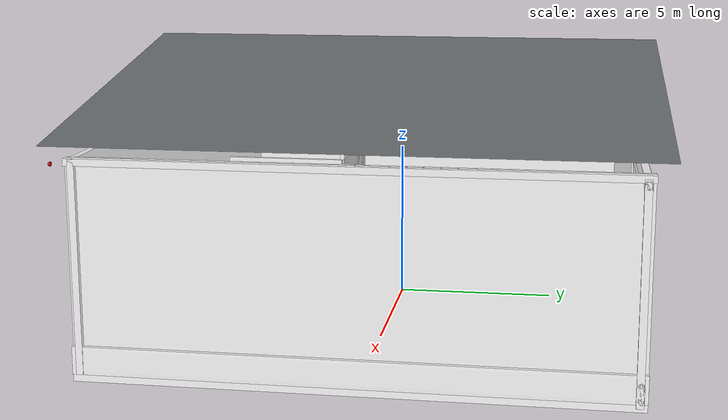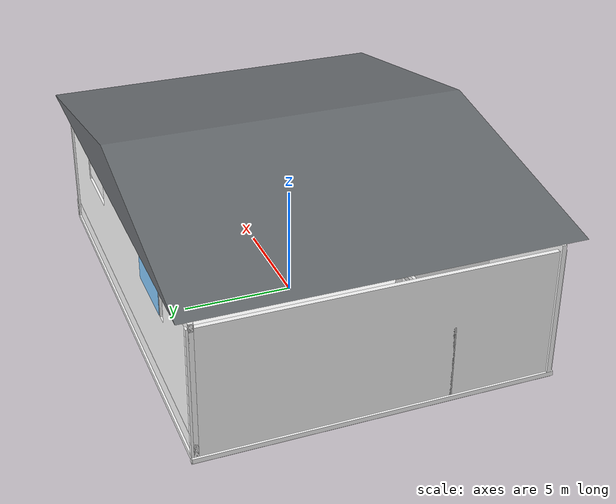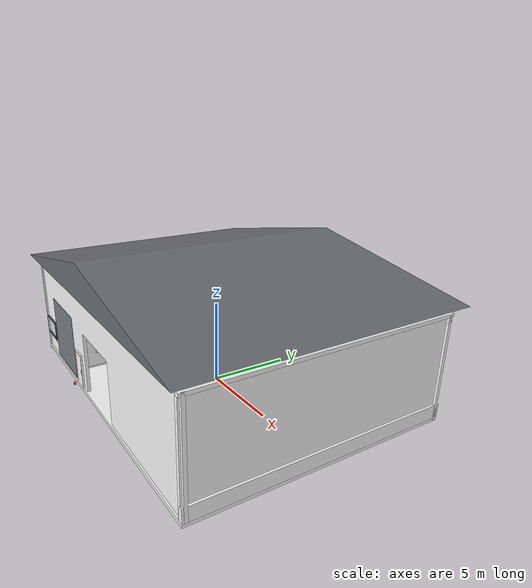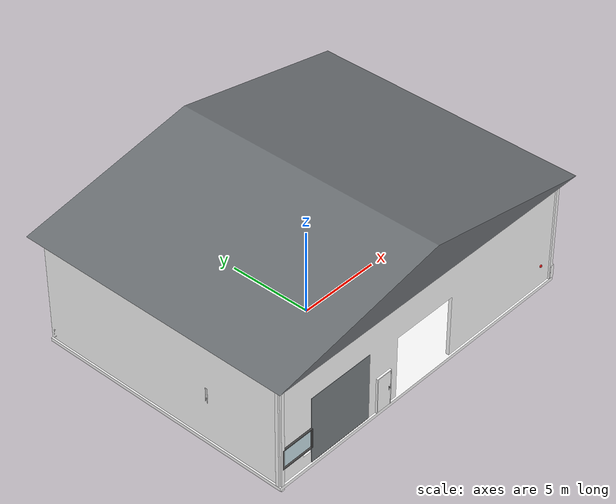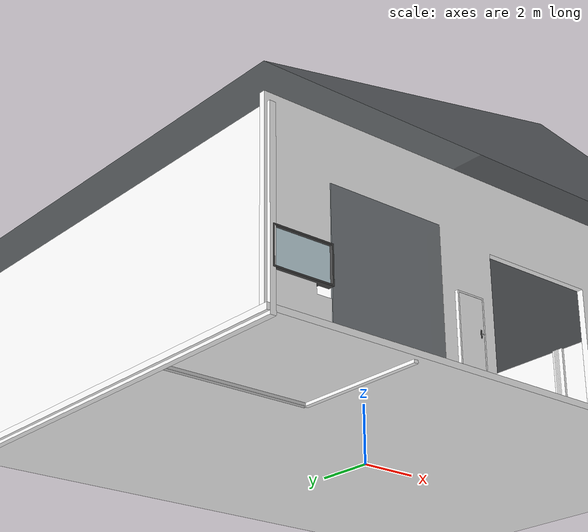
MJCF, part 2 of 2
<mesh name="bake_south_door_box_21_21" vertex="1.99915 0.02415 1.99915 1.99941 0.01875 1.99941 1.99941 0.02441 1.50000 1.99941 0.01875 1.99941 2.00000 0.01875 1.50000 1.99941 0.02441 1.50000 1.99941 0.02441 1.50000 2.00000 0.01875 1.50000 1.99941 0.02441 1.00000 2.00000 0.01875 1.50000 2.00000 0.01875 1.00000 1.99941 0.02441 1.00000 1.99941 0.02441 1.00000 2.00000 0.01875 1.00000 1.99941 0.02441 0.50000 2.00000 0.01875 1.00000 2.00000 0.01875 0.50000 1.99941 0.02441 0.50000 1.99941 0.02441 0.50000 2.00000 0.01875 0.50000 1.99941 0.02441 0.00000 2.00000 0.01875 0.50000 2.00000 0.01875 0.00000 1.99941 0.02441 0.00000 1.99941 0.02441 0.00000 2.00000 0.01875 0.00000 1.99941 0.02441 -0.50000 2.00000 0.01875 0.00000 2.00000 0.01875 -0.50000 1.99941 0.02441 -0.50000 1.99941 0.02441 -0.50000 2.00000 0.01875 -0.50000 1.99941 0.02441 -1.00000 2.00000 0.01875 -0.50000 2.00000 0.01875 -1.00000 1.99941 0.02441 -1.00000 1.99941 0.02441 -1.00000 2.00000 0.01875 -1.00000 1.99941 0.02441 -1.50000 2.00000 0.01875 -1.00000 2.00000 0.01875 -1.50000 1.99941 0.02441 -1.50000 1.99941 0.02441 -1.50000 2.00000 0.01875 -1.50000 1.99915 0.02415 -1.99915 2.00000 0.01875 -1.50000 1.99941 0.01875 -1.99941 1.99915 0.02415 -1.99915 1.99941 0.01875 1.99941 1.99941 0.01250 1.99941 2.00000 0.01875 1.50000 1.99941 0.01250 1.99941 2.00000 0.01250 1.50000 2.00000 0.01875 1.50000 2.00000 0.01875 1.50000 2.00000 0.01250 1.50000 2.00000 0.01875 1.00000 2.00000 0.01250 1.50000 2.00000 0.01250 1.00000 2.00000 0.01875 1.00000 2.00000 0.01875 1.00000 2.00000 0.01250 1.00000 2.00000 0.01875 0.50000 2.00000 0.01250 1.00000 2.00000 0.01250 0.50000 2.00000 0.01875 0.50000 2.00000 0.01875 0.50000 2.00000 0.01250 0.50000 2.00000 0.01875 0.00000 2.00000 0.01250 0.50000 2.00000 0.01250 0.00000 2.00000 0.01875 0.00000 2.00000 0.01875 0.00000 2.00000 0.01250 0.00000 2.00000 0.01875 -0.50000 2.00000 0.01250 0.00000 2.00000 0.01250 -0.50000 2.00000 0.01875 -0.50000 2.00000 0.01875 -0.50000 2.00000 0.01250 -0.50000 2.00000 0.01875 -1.00000 2.00000 0.01250 -0.50000 2.00000 0.01250 -1.00000 2.00000 0.01875 -1.00000 2.00000 0.01875 -1.00000 2.00000 0.01250 -1.00000 2.00000 0.01875 -1.50000 2.00000 0.01250 -1.00000 2.00000 0.01250 -1.50000 2.00000 0.01875 -1.50000 2.00000 0.01875 -1.50000 2.00000 0.01250 -1.50000 1.99941 0.01875 -1.99941 2.00000 0.01250 -1.50000 1.99941 0.01250 -1.99941 1.99941 0.01875 -1.99941 1.99941 0.01250 1.99941 1.99941 0.00625 1.99941 2.00000 0.01250 1.50000 1.99941 0.00625 1.99941 2.00000 0.00625 1.50000 2.00000 0.01250 1.50000 2.00000 0.01250 1.50000 2.00000 0.00625 1.50000 2.00000 0.01250 1.00000 2.00000 0.00625 1.50000 2.00000 0.00625 1.00000 2.00000 0.01250 1.00000 2.00000 0.01250 1.00000 2.00000 0.00625 1.00000 2.00000 0.01250 0.50000 2.00000 0.00625 1.00000 2.00000 0.00625 0.50000 2.00000 0.01250 0.50000 2.00000 0.01250 0.50000 2.00000 0.00625 0.50000 2.00000 0.01250 0.00000 2.00000 0.00625 0.50000 2.00000 0.00625 0.00000 2.00000 0.01250 0.00000 2.00000 0.01250 0.00000 2.00000 0.00625 0.00000 2.00000 0.01250 -0.50000 2.00000 0.00625 0.00000 2.00000 0.00625 -0.50000 2.00000 0.01250 -0.50000 2.00000 0.01250 -0.50000 2.00000 0.00625 -0.50000 2.00000 0.01250 -1.00000 2.00000 0.00625 -0.50000 2.00000 0.00625 -1.00000 2.00000 0.01250 -1.00000 2.00000 0.01250 -1.00000 2.00000 0.00625 -1.00000 2.00000 0.01250 -1.50000 2.00000 0.00625 -1.00000 2.00000 0.00625 -1.50000 2.00000 0.01250 -1.50000 2.00000 0.01250 -1.50000 2.00000 0.00625 -1.50000 1.99941 0.01250 -1.99941 2.00000 0.00625 -1.50000 1.99941 0.00625 -1.99941 1.99941 0.01250 -1.99941 1.99941 0.00625 1.99941 1.99941 0.00000 1.99941 2.00000 0.00625 1.50000 1.99941 0.00000 1.99941 2.00000 0.00000 1.50000 2.00000 0.00625 1.50000 2.00000 0.00625 1.50000 2.00000 0.00000 1.50000 2.00000 0.00625 1.00000 2.00000 0.00000 1.50000 2.00000 0.00000 1.00000 2.00000 0.00625 1.00000 2.00000 0.00625 1.00000 2.00000 0.00000 1.00000 2.00000 0.00625 0.50000 2.00000 0.00000 1.00000 2.00000 0.00000 0.50000 2.00000 0.00625 0.50000 2.00000 0.00625 0.50000 2.00000 0.00000 0.50000 2.00000 0.00625 0.00000 2.00000 0.00000 0.50000 2.00000 0.00000 0.00000 2.00000 0.00625 0.00000 2.00000 0.00625 0.00000 2.00000 0.00000 0.00000 2.00000 0.00625 -0.50000 2.00000 0.00000 0.00000 2.00000 0.00000 -0.50000 2.00000 0.00625 -0.50000 2.00000 0.00625 -0.50000 2.00000 0.00000 -0.50000 2.00000 0.00625 -1.00000 2.00000 0.00000 -0.50000 2.00000 0.00000 -1.00000 2.00000 0.00625 -1.00000 2.00000 0.00625 -1.00000 2.00000 0.00000 -1.00000 2.00000 0.00625 -1.50000 2.00000 0.00000 -1.00000 2.00000 0.00000 -1.50000 2.00000 0.00625 -1.50000 2.00000 0.00625 -1.50000 2.00000 0.00000 -1.50000 1.99941 0.00625 -1.99941 2.00000 0.00000 -1.50000 1.99941 0.00000 -1.99941 1.99941 0.00625 -1.99941 1.99941 0.00000 1.99941 1.99941 -0.00625 1.99941 2.00000 0.00000 1.50000 1.99941 -0.00625 1.99941 2.00000 -0.00625 1.50000 2.00000 0.00000 1.50000 2.00000 0.00000 1.50000 2.00000 -0.00625 1.50000 2.00000 0.00000 1.00000 2.00000 -0.00625 1.50000 2.00000 -0.00625 1.00000 2.00000 0.00000 1.00000 2.00000 0.00000 1.00000 2.00000 -0.00625 1.00000 2.00000 0.00000 0.50000 2.00000 -0.00625 1.00000 2.00000 -0.00625 0.50000 2.00000 0.00000 0.50000 2.00000 0.00000 0.50000 2.00000 -0.00625 0.50000 2.00000 0.00000 0.00000 2.00000 -0.00625 0.50000 2.00000 -0.00625 0.00000 2.00000 0.00000 0.00000 2.00000 0.00000 0.00000 2.00000 -0.00625 0.00000 2.00000 0.00000 -0.50000 2.00000 -0.00625 0.00000 2.00000 -0.00625 -0.50000 2.00000 0.00000 -0.50000 2.00000 0.00000 -0.50000 2.00000 -0.00625 -0.50000 2.00000 0.00000 -1.00000 2.00000 -0.00625 -0.50000 2.00000 -0.00625 -1.00000 2.00000 0.00000 -1.00000 2.00000 0.00000 -1.00000 2.00000 -0.00625 -1.00000 2.00000 0.00000 -1.50000 2.00000 -0.00625 -1.00000 2.00000 -0.00625 -1.50000 2.00000 0.00000 -1.50000 2.00000 0.00000 -1.50000 2.00000 -0.00625 -1.50000 1.99941 0.00000 -1.99941 2.00000 -0.00625 -1.50000 1.99941 -0.00625 -1.99941 1.99941 0.00000 -1.99941 1.99941 -0.00625 1.99941 1.99941 -0.01250 1.99941 2.00000 -0.00625 1.50000 1.99941 -0.01250 1.99941 2.00000 -0.01250 1.50000 2.00000 -0.00625 1.50000 2.00000 -0.00625 1.50000 2.00000 -0.01250 1.50000 2.00000 -0.00625 1.00000 2.00000 -0.01250 1.50000 2.00000 -0.01250 1.00000 2.00000 -0.00625 1.00000 2.00000 -0.00625 1.00000 2.00000 -0.01250 1.00000 2.00000 -0.00625 0.50000 2.00000 -0.01250 1.00000 2.00000 -0.01250 0.50000 2.00000 -0.00625 0.50000 2.00000 -0.00625 0.50000 2.00000 -0.01250 0.50000 2.00000 -0.00625 0.00000 2.00000 -0.01250 0.50000 2.00000 -0.01250 0.00000 2.00000 -0.00625 0.00000 2.00000 -0.00625 0.00000 2.00000 -0.01250 0.00000 2.00000 -0.00625 -0.50000 2.00000 -0.01250 0.00000 2.00000 -0.01250 -0.50000 2.00000 -0.00625 -0.50000 2.00000 -0.00625 -0.50000 2.00000 -0.01250 -0.50000 2.00000 -0.00625 -1.00000 2.00000 -0.01250 -0.50000 2.00000 -0.01250 -1.00000 2.00000 -0.00625 -1.00000 2.00000 -0.00625 -1.00000 2.00000 -0.01250 -1.00000 2.00000 -0.00625 -1.50000 2.00000 -0.01250 -1.00000 2.00000 -0.01250 -1.50000 2.00000 -0.00625 -1.50000 2.00000 -0.00625 -1.50000 2.00000 -0.01250 -1.50000 1.99941 -0.00625 -1.99941 2.00000 -0.01250 -1.50000 1.99941 -0.01250 -1.99941 1.99941 -0.00625 -1.99941 1.99941 -0.01250 1.99941 1.99941 -0.01875 1.99941 2.00000 -0.01250 1.50000 1.99941 -0.01875 1.99941 2.00000 -0.01875 1.50000 2.00000 -0.01250 1.50000 2.00000 -0.01250 1.50000 2.00000 -0.01875 1.50000 2.00000 -0.01250 1.00000 2.00000 -0.01875 1.50000 2.00000 -0.01875 1.00000 2.00000 -0.01250 1.00000 2.00000 -0.01250 1.00000 2.00000 -0.01875 1.00000 2.00000 -0.01250 0.50000 2.00000 -0.01875 1.00000 2.00000 -0.01875 0.50000 2.00000 -0.01250 0.50000 2.00000 -0.01250 0.50000 2.00000 -0.01875 0.50000 2.00000 -0.01250 0.00000 2.00000 -0.01875 0.50000 2.00000 -0.01875 0.00000 2.00000 -0.01250 0.00000 2.00000 -0.01250 0.00000 2.00000 -0.01875 0.00000 2.00000 -0.01250 -0.50000 2.00000 -0.01875 0.00000 2.00000 -0.01875 -0.50000 2.00000 -0.01250 -0.50000 2.00000 -0.01250 -0.50000 2.00000 -0.01875 -0.50000 2.00000 -0.01250 -1.00000 2.00000 -0.01875 -0.50000 2.00000 -0.01875 -1.00000 2.00000 -0.01250 -1.00000 2.00000 -0.01250 -1.00000 2.00000 -0.01875 -1.00000 2.00000 -0.01250 -1.50000 2.00000 -0.01875 -1.00000 2.00000 -0.01875 -1.50000 2.00000 -0.01250 -1.50000 2.00000 -0.01250 -1.50000 2.00000 -0.01875 -1.50000 1.99941 -0.01250 -1.99941 2.00000 -0.01875 -1.50000 1.99941 -0.01875 -1.99941 1.99941 -0.01250 -1.99941 1.99941 -0.01875 1.99941 1.99915 -0.02415 1.99915 2.00000 -0.01875 1.50000 1.99915 -0.02415 1.99915 1.99941 -0.02441 1.50000 2.00000 -0.01875 1.50000 2.00000 -0.01875 1.50000 1.99941 -0.02441 1.50000 2.00000 -0.01875 1.00000 1.99941 -0.02441 1.50000 1.99941 -0.02441 1.00000 2.00000 -0.01875 1.00000 2.00000 -0.01875 1.00000 1.99941 -0.02441 1.00000 2.00000 -0.01875 0.50000 1.99941 -0.02441 1.00000 1.99941 -0.02441 0.50000 2.00000 -0.01875 0.50000 2.00000 -0.01875 0.50000 1.99941 -0.02441 0.50000 2.00000 -0.01875 0.00000 1.99941 -0.02441 0.50000 1.99941 -0.02441 0.00000 2.00000 -0.01875 0.00000 2.00000 -0.01875 0.00000 1.99941 -0.02441 0.00000 2.00000 -0.01875 -0.50000 1.99941 -0.02441 0.00000 1.99941 -0.02441 -0.50000 2.00000 -0.01875 -0.50000 2.00000 -0.01875 -0.50000 1.99941 -0.02441 -0.50000 2.00000 -0.01875 -1.00000 1.99941 -0.02441 -0.50000 1.99941 -0.02441 -1.00000 2.00000 -0.01875 -1.00000 2.00000 -0.01875 -1.00000 1.99941 -0.02441 -1.00000 2.00000 -0.01875 -1.50000 1.99941 -0.02441 -1.00000 1.99941 -0.02441 -1.50000 2.00000 -0.01875 -1.50000 2.00000 -0.01875 -1.50000 1.99941 -0.02441 -1.50000 1.99941 -0.01875 -1.99941 1.99941 -0.02441 -1.50000 1.99915 -0.02415 -1.99915 1.99941 -0.01875 -1.99941 -1.99915 0.02415 -1.99915 -1.99941 0.01875 -1.99941 -1.99941 0.02441 -1.50000 -1.99941 0.01875 -1.99941 -2.00000 0.01875 -1.50000 -1.99941 0.02441 -1.50000 -1.99941 0.02441 -1.50000 -2.00000 0.01875 -1.50000 -1.99941 0.02441 -1.00000 -2.00000 0.01875 -1.50000 -2.00000 0.01875 -1.00000 -1.99941 0.02441 -1.00000 -1.99941 0.02441 -1.00000 -2.00000 0.01875 -1.00000 -1.99941 0.02441 -0.50000 -2.00000 0.01875 -1.00000 -2.00000 0.01875 -0.50000 -1.99941 0.02441 -0.50000 -1.99941 0.02441 -0.50000 -2.00000 0.01875 -0.50000 -1.99941 0.02441 0.00000 -2.00000 0.01875 -0.50000 -2.00000 0.01875 0.00000 -1.99941 0.02441 0.00000 -1.99941 0.02441 0.00000 -2.00000 0.01875 0.00000 -1.99941 0.02441 0.50000 -2.00000 0.01875 0.00000 -2.00000 0.01875 0.50000 -1.99941 0.02441 0.50000 -1.99941 0.02441 0.50000 -2.00000 0.01875 0.50000 -1.99941 0.02441 1.00000 -2.00000 0.01875 0.50000 -2.00000 0.01875 1.00000 -1.99941 0.02441 1.00000 -1.99941 0.02441 1.00000 -2.00000 0.01875 1.00000 -1.99941 0.02441 1.50000 -2.00000 0.01875 1.00000 -2.00000 0.01875 1.50000 -1.99941 0.02441 1.50000 -1.99941 0.02441 1.50000 -2.00000 0.01875 1.50000 -1.99915 0.02415 1.99915 -2.00000 0.01875 1.50000 -1.99941 0.01875 1.99941 -1.99915 0.02415 1.99915 -1.99941 0.01875 -1.99941 -1.99941 0.01250 -1.99941 -2.00000 0.01875 -1.50000 -1.99941 0.01250 -1.99941 -2.00000 0.01250 -1.50000 -2.00000 0.01875 -1.50000 -2.00000 0.01875 -1.50000 -2.00000 0.01250 -1.50000 -2.00000 0.01875 -1.00000 -2.00000 0.01250 -1.50000 -2.00000 0.01250 -1.00000 -2.00000 0.01875 -1.00000 -2.00000 0.01875 -1.00000 -2.00000 0.01250 -1.00000 -2.00000 0.01875 -0.50000 -2.00000 0.01250 -1.00000 -2.00000 0.01250 -0.50000 -2.00000 0.01875 -0.50000 -2.00000 0.01875 -0.50000 -2.00000 0.01250 -0.50000 -2.00000 0.01875 0.00000 -2.00000 0.01250 -0.50000 -2.00000 0.01250 0.00000 -2.00000 0.01875 0.00000 -2.00000 0.01875 0.00000 -2.00000 0.01250 0.00000 -2.00000 0.01875 0.50000 -2.00000 0.01250 0.00000 -2.00000 0.01250 0.50000 -2.00000 0.01875 0.50000 -2.00000 0.01875 0.50000 -2.00000 0.01250 0.50000 -2.00000 0.01875 1.00000 -2.00000 0.01250 0.50000 -2.00000 0.01250 1.00000 -2.00000 0.01875 1.00000 -2.00000 0.01875 1.00000 -2.00000 0.01250 1.00000 -2.00000 0.01875 1.50000 -2.00000 0.01250 1.00000 -2.00000 0.01250 1.50000 -2.00000 0.01875 1.50000 -2.00000 0.01875 1.50000 -2.00000 0.01250 1.50000 -1.99941 0.01875 1.99941 -2.00000 0.01250 1.50000 -1.99941 0.01250 1.99941 -1.99941 0.01875 1.99941 -1.99941 0.01250 -1.99941 -1.99941 0.00625 -1.99941 -2.00000 0.01250 -1.50000 -1.99941 0.00625 -1.99941 -2.00000 0.00625 -1.50000 -2.00000 0.01250 -1.50000 -2.00000 0.01250 -1.50000 -2.00000 0.00625 -1.50000 -2.00000 0.01250 -1.00000 -2.00000 0.00625 -1.50000 -2.00000 0.00625 -1.00000 -2.00000 0.01250 -1.00000 -2.00000 0.01250 -1.00000 -2.00000 0.00625 -1.00000 -2.00000 0.01250 -0.50000 -2.00000 0.00625 -1.00000 -2.00000 0.00625 -0.50000 -2.00000 0.01250 -0.50000 -2.00000 0.01250 -0.50000 -2.00000 0.00625 -0.50000 -2.00000 0.01250 0.00000 -2.00000 0.00625 -0.50000 -2.00000 0.00625 0.00000 -2.00000 0.01250 0.00000 -2.00000 0.01250 0.00000 -2.00000 0.00625 0.00000 -2.00000 0.01250 0.50000 -2.00000 0.00625 0.00000 -2.00000 0.00625 0.50000 -2.00000 0.01250 0.50000 -2.00000 0.01250 0.50000 -2.00000 0.00625 0.50000 -2.00000 0.01250 1.00000 -2.00000 0.00625 0.50000 -2.00000 0.00625 1.00000 -2.00000 0.01250 1.00000 -2.00000 0.01250 1.00000 -2.00000 0.00625 1.00000 -2.00000 0.01250 1.50000 -2.00000 0.00625 1.00000 -2.00000 0.00625 1.50000 -2.00000 0.01250 1.50000 -2.00000 0.01250 1.50000 -2.00000 0.00625 1.50000 -1.99941 0.01250 1.99941 -2.00000 0.00625 1.50000 -1.99941 0.00625 1.99941 -1.99941 0.01250 1.99941 -1.99941 0.00625 -1.99941 -1.99941 0.00000 -1.99941 -2.00000 0.00625 -1.50000 -1.99941 0.00000 -1.99941 -2.00000 0.00000 -1.50000 -2.00000 0.00625 -1.50000 -2.00000 0.00625 -1.50000 -2.00000 0.00000 -1.50000 -2.00000 0.00625 -1.00000 -2.00000 0.00000 -1.50000 -2.00000 0.00000 -1.00000 -2.00000 0.00625 -1.00000 -2.00000 0.00625 -1.00000 -2.00000 0.00000 -1.00000 -2.00000 0.00625 -0.50000 -2.00000 0.00000 -1.00000 -2.00000 0.00000 -0.50000 -2.00000 0.00625 -0.50000 -2.00000 0.00625 -0.50000 -2.00000 0.00000 -0.50000 -2.00000 0.00625 0.00000 -2.00000 0.00000 -0.50000 -2.00000 0.00000 0.00000 -2.00000 0.00625 0.00000 -2.00000 0.00625 0.00000 -2.00000 0.00000 0.00000 -2.00000 0.00625 0.50000 -2.00000 0.00000 0.00000 -2.00000 0.00000 0.50000 -2.00000 0.00625 0.50000 -2.00000 0.00625 0.50000 -2.00000 0.00000 0.50000 -2.00000 0.00625 1.00000 -2.00000 0.00000 0.50000 -2.00000 0.00000 1.00000 -2.00000 0.00625 1.00000 -2.00000 0.00625 1.00000 -2.00000 0.00000 1.00000 -2.00000 0.00625 1.50000 -2.00000 0.00000 1.00000 -2.00000 0.00000 1.50000 -2.00000 0.00625 1.50000 -2.00000 0.00625 1.50000 -2.00000 0.00000 1.50000 -1.99941 0.00625 1.99941 -2.00000 0.00000 1.50000 -1.99941 0.00000 1.99941 -1.99941 0.00625 1.99941 -1.99941 0.00000 -1.99941 -1.99941 -0.00625 -1.99941 -2.00000 0.00000 -1.50000 -1.99941 -0.00625 -1.99941 -2.00000 -0.00625 -1.50000 -2.00000 0.00000 -1.50000 -2.00000 0.00000 -1.50000 -2.00000 -0.00625 -1.50000 -2.00000 0.00000 -1.00000 -2.00000 -0.00625 -1.50000 -2.00000 -0.00625 -1.00000 -2.00000 0.00000 -1.00000 -2.00000 0.00000 -1.00000 -2.00000 -0.00625 -1.00000 -2.00000 0.00000 -0.50000 -2.00000 -0.00625 -1.00000 -2.00000 -0.00625 -0.50000 -2.00000 0.00000 -0.50000 -2.00000 0.00000 -0.50000 -2.00000 -0.00625 -0.50000 -2.00000 0.00000 0.00000 -2.00000 -0.00625 -0.50000 -2.00000 -0.00625 0.00000 -2.00000 0.00000 0.00000 -2.00000 0.00000 0.00000 -2.00000 -0.00625 0.00000 -2.00000 0.00000 0.50000 -2.00000 -0.00625 0.00000 -2.00000 -0.00625 0.50000 -2.00000 0.00000 0.50000 -2.00000 0.00000 0.50000 -2.00000 -0.00625 0.50000 -2.00000 0.00000 1.00000 -2.00000 -0.00625 0.50000 -2.00000 -0.00625 1.00000 -2.00000 0.00000 1.00000 -2.00000 0.00000 1.00000 -2.00000 -0.00625 1.00000 -2.00000 0.00000 1.50000 -2.00000 -0.00625 1.00000 -2.00000 -0.00625 1.50000 -2.00000 0.00000 1.50000 -2.00000 0.00000 1.50000 -2.00000 -0.00625 1.50000 -1.99941 0.00000 1.99941 -2.00000 -0.00625 1.50000 -1.99941 -0.00625 1.99941 -1.99941 0.00000 1.99941 -1.99941 -0.00625 -1.99941 -1.99941 -0.01250 -1.99941 -2.00000 -0.00625 -1.50000 -1.99941 -0.01250 -1.99941 -2.00000 -0.01250 -1.50000 -2.00000 -0.00625 -1.50000 -2.00000 -0.00625 -1.50000 -2.00000 -0.01250 -1.50000 -2.00000 -0.00625 -1.00000 -2.00000 -0.01250 -1.50000 -2.00000 -0.01250 -1.00000 -2.00000 -0.00625 -1.00000 -2.00000 -0.00625 -1.00000 -2.00000 -0.01250 -1.00000 -2.00000 -0.00625 -0.50000 -2.00000 -0.01250 -1.00000 -2.00000 -0.01250 -0.50000 -2.00000 -0.00625 -0.50000 -2.00000 -0.00625 -0.50000 -2.00000 -0.01250 -0.50000 -2.00000 -0.00625 0.00000 -2.00000 -0.01250 -0.50000 -2.00000 -0.01250 0.00000 -2.00000 -0.00625 0.00000 -2.00000 -0.00625 0.00000 -2.00000 -0.01250 0.00000 -2.00000 -0.00625 0.50000 -2.00000 -0.01250 0.00000 -2.00000 -0.01250 0.50000 -2.00000 -0.00625 0.50000 -2.00000 -0.00625 0.50000 -2.00000 -0.01250 0.50000 -2.00000 -0.00625 1.00000 -2.00000 -0.01250 0.50000 -2.00000 -0.01250 1.00000 -2.00000 -0.00625 1.00000 -2.00000 -0.00625 1.00000 -2.00000 -0.01250 1.00000 -2.00000 -0.00625 1.50000 -2.00000 -0.01250 1.00000 -2.00000 -0.01250 1.50000 -2.00000 -0.00625 1.50000 -2.00000 -0.00625 1.50000 -2.00000 -0.01250 1.50000 -1.99941 -0.00625 1.99941 -2.00000 -0.01250 1.50000 -1.99941 -0.01250 1.99941 -1.99941 -0.00625 1.99941 -1.99941 -0.01250 -1.99941 -1.99941 -0.01875 -1.99941 -2.00000 -0.01250 -1.50000 -1.99941 -0.01875 -1.99941 -2.00000 -0.01875 -1.50000 -2.00000 -0.01250 -1.50000 -2.00000 -0.01250 -1.50000 -2.00000 -0.01875 -1.50000 -2.00000 -0.01250 -1.00000 -2.00000 -0.01875 -1.50000 -2.00000 -0.01875 -1.00000 -2.00000 -0.01250 -1.00000 -2.00000 -0.01250 -1.00000 -2.00000 -0.01875 -1.00000 -2.00000 -0.01250 -0.50000 -2.00000 -0.01875 -1.00000 -2.00000 -0.01875 -0.50000 -2.00000 -0.01250 -0.50000 -2.00000 -0.01250 -0.50000 -2.00000 -0.01875 -0.50000 -2.00000 -0.01250 0.00000 -2.00000 -0.01875 -0.50000 -2.00000 -0.01875 0.00000 -2.00000 -0.01250 0.00000 -2.00000 -0.01250 0.00000 -2.00000 -0.01875 0.00000 -2.00000 -0.01250 0.50000 -2.00000 -0.01875 0.00000 -2.00000 -0.01875 0.50000 -2.00000 -0.01250 0.50000 -2.00000 -0.01250 0.50000 -2.00000 -0.01875 0.50000 -2.00000 -0.01250 1.00000 -2.00000 -0.01875 0.50000 -2.00000 -0.01875 1.00000 -2.00000 -0.01250 1.00000 -2.00000 -0.01250 1.00000 -2.00000 -0.01875 1.00000 -2.00000 -0.01250 1.50000 -2.00000 -0.01875 1.00000 -2.00000 -0.01875 1.50000 -2.00000 -0.01250 1.50000 -2.00000 -0.01250 1.50000 -2.00000 -0.01875 1.50000 -1.99941 -0.01250 1.99941 -2.00000 -0.01875 1.50000 -1.99941 -0.01875 1.99941 -1.99941 -0.01250 1.99941 -1.99941 -0.01875 -1.99941 -1.99915 -0.02415 -1.99915 -2.00000 -0.01875 -1.50000 -1.99915 -0.02415 -1.99915 -1.99941 -0.02441 -1.50000 -2.00000 -0.01875 -1.50000 -2.00000 -0.01875 -1.50000 -1.99941 -0.02441 -1.50000 -2.00000 -0.01875 -1.00000 -1.99941 -0.02441 -1.50000 -1.99941 -0.02441 -1.00000 -2.00000 -0.01875 -1.00000 -2.00000 -0.01875 -1.00000 -1.99941 -0.02441 -1.00000 -2.00000 -0.01875 -0.50000 -1.99941 -0.02441 -1.00000 -1.99941 -0.02441 -0.50000 -2.00000 -0.01875 -0.50000 -2.00000 -0.01875 -0.50000 -1.99941 -0.02441 -0.50000 -2.00000 -0.01875 0.00000 -1.99941 -0.02441 -0.50000 -1.99941 -0.02441 0.00000 -2.00000 -0.01875 0.00000 -2.00000 -0.01875 0.00000 -1.99941 -0.02441 0.00000 -2.00000 -0.01875 0.50000 -1.99941 -0.02441 0.00000 -1.99941 -0.02441 0.50000 -2.00000 -0.01875 0.50000 -2.00000 -0.01875 0.50000 -1.99941 -0.02441 0.50000 -2.00000 -0.01875 1.00000 -1.99941 -0.02441 0.50000 -1.99941 -0.02441 1.00000 -2.00000 -0.01875 1.00000 -2.00000 -0.01875 1.00000 -1.99941 -0.02441 1.00000 -2.00000 -0.01875 1.50000 -1.99941 -0.02441 1.00000 -1.99941 -0.02441 1.50000 -2.00000 -0.01875 1.50000 -2.00000 -0.01875 1.50000 -1.99941 -0.02441 1.50000 -1.99941 -0.01875 1.99941 -1.99941 -0.02441 1.50000 -1.99915 -0.02415 1.99915 -1.99941 -0.01875 1.99941 -1.99915 0.02415 -1.99915 -1.99941 0.02441 -1.50000 -1.50000 0.02441 -1.99941 -1.99941 0.02441 -1.50000 -1.50000 0.02500 -1.50000 -1.50000 0.02441 -1.99941 -1.50000 0.02441 -1.99941 -1.50000 0.02500 -1.50000 -1.00000 0.02441 -1.99941 -1.50000 0.02500 -1.50000 -1.00000 0.02500 -1.50000 -1.00000 0.02441 -1.99941 -1.00000 0.02441 -1.99941 -1.00000 0.02500 -1.50000 -0.50000 0.02441 -1.99941 -1.00000 0.02500 -1.50000 -0.50000 0.02500 -1.50000 -0.50000 0.02441 -1.99941 -0.50000 0.02441 -1.99941 -0.50000 0.02500 -1.50000 0.00000 0.02441 -1.99941 -0.50000 0.02500 -1.50000 0.00000 0.02500 -1.50000 0.00000 0.02441 -1.99941 0.00000 0.02441 -1.99941 0.00000 0.02500 -1.50000 0.50000 0.02441 -1.99941 0.00000 0.02500 -1.50000 0.50000 0.02500 -1.50000 0.50000 0.02441 -1.99941 0.50000 0.02441 -1.99941 0.50000 0.02500 -1.50000 1.00000 0.02441 -1.99941 0.50000 0.02500 -1.50000 1.00000 0.02500 -1.50000 1.00000 0.02441 -1.99941 1.00000 0.02441 -1.99941 1.00000 0.02500 -1.50000 1.50000 0.02441 -1.99941 1.00000 0.02500 -1.50000 1.50000 0.02500 -1.50000 1.50000 0.02441 -1.99941 1.50000 0.02441 -1.99941 1.50000 0.02500 -1.50000 1.99915 0.02415 -1.99915 1.50000 0.02500 -1.50000 1.99941 0.02441 -1.50000 1.99915 0.02415 -1.99915 -1.99941 0.02441 -1.50000 -1.99941 0.02441 -1.00000 -1.50000 0.02500 -1.50000 -1.99941 0.02441 -1.00000 -1.50000 0.02500 -1.00000 -1.50000 0.02500 -1.50000 -1.50000 0.02500 -1.50000 -1.50000 0.02500 -1.00000 -1.00000 0.02500 -1.50000 -1.50000 0.02500 -1.00000 -1.00000 0.02500 -1.00000 -1.00000 0.02500 -1.50000 -1.00000 0.02500 -1.50000 -1.00000 0.02500 -1.00000 -0.50000 0.02500 -1.50000 -1.00000 0.02500 -1.00000 -0.50000 0.02500 -1.00000 -0.50000 0.02500 -1.50000 -0.50000 0.02500 -1.50000 -0.50000 0.02500 -1.00000 0.00000 0.02500 -1.50000 -0.50000 0.02500 -1.00000 0.00000 0.02500 -1.00000 0.00000 0.02500 -1.50000 0.00000 0.02500 -1.50000 0.00000 0.02500 -1.00000 0.50000 0.02500 -1.50000 0.00000 0.02500 -1.00000 0.50000 0.02500 -1.00000 0.50000 0.02500 -1.50000 0.50000 0.02500 -1.50000 0.50000 0.02500 -1.00000 1.00000 0.02500 -1.50000 0.50000 0.02500 -1.00000 1.00000 0.02500 -1.00000 1.00000 0.02500 -1.50000 1.00000 0.02500 -1.50000 1.00000 0.02500 -1.00000 1.50000 0.02500 -1.50000 1.00000 0.02500 -1.00000 1.50000 0.02500 -1.00000 1.50000 0.02500 -1.50000 1.50000 0.02500 -1.50000 1.50000 0.02500 -1.00000 1.99941 0.02441 -1.50000 1.50000 0.02500 -1.00000 1.99941 0.02441 -1.00000 1.99941 0.02441 -1.50000 -1.99941 0.02441 -1.00000 -1.99941 0.02441 -0.50000 -1.50000 0.02500 -1.00000 -1.99941 0.02441 -0.50000 -1.50000 0.02500 -0.50000 -1.50000 0.02500 -1.00000 -1.50000 0.02500 -1.00000 -1.50000 0.02500 -0.50000 -1.00000 0.02500 -1.00000 -1.50000 0.02500 -0.50000 -1.00000 0.02500 -0.50000 -1.00000 0.02500 -1.00000 -1.00000 0.02500 -1.00000 -1.00000 0.02500 -0.50000 -0.50000 0.02500 -1.00000 -1.00000 0.02500 -0.50000 -0.50000 0.02500 -0.50000 -0.50000 0.02500 -1.00000 -0.50000 0.02500 -1.00000 -0.50000 0.02500 -0.50000 0.00000 0.02500 -1.00000 -0.50000 0.02500 -0.50000 0.00000 0.02500 -0.50000 0.00000 0.02500 -1.00000 0.00000 0.02500 -1.00000 0.00000 0.02500 -0.50000 0.50000 0.02500 -1.00000 0.00000 0.02500 -0.50000 0.50000 0.02500 -0.50000 0.50000 0.02500 -1.00000 0.50000 0.02500 -1.00000 0.50000 0.02500 -0.50000 1.00000 0.02500 -1.00000 0.50000 0.02500 -0.50000 1.00000 0.02500 -0.50000 1.00000 0.02500 -1.00000 1.00000 0.02500 -1.00000 1.00000 0.02500 -0.50000 1.50000 0.02500 -1.00000 1.00000 0.02500 -0.50000 1.50000 0.02500 -0.50000 1.50000 0.02500 -1.00000 1.50000 0.02500 -1.00000 1.50000 0.02500 -0.50000 1.99941 0.02441 -1.00000 1.50000 0.02500 -0.50000 1.99941 0.02441 -0.50000 1.99941 0.02441 -1.00000 -1.99941 0.02441 -0.50000 -1.99941 0.02441 0.00000 -1.50000 0.02500 -0.50000 -1.99941 0.02441 0.00000 -1.50000 0.02500 0.00000 -1.50000 0.02500 -0.50000 -1.50000 0.02500 -0.50000 -1.50000 0.02500 0.00000 -1.00000 0.02500 -0.50000 -1.50000 0.02500 0.00000 -1.00000 0.02500 0.00000 -1.00000 0.02500 -0.50000 -1.00000 0.02500 -0.50000 -1.00000 0.02500 0.00000 -0.50000 0.02500 -0.50000 -1.00000 0.02500 0.00000 -0.50000 0.02500 0.00000 -0.50000 0.02500 -0.50000 -0.50000 0.02500 -0.50000 -0.50000 0.02500 0.00000 0.00000 0.02500 -0.50000 -0.50000 0.02500 0.00000 0.00000 0.02500 0.00000 0.00000 0.02500 -0.50000 0.00000 0.02500 -0.50000 0.00000 0.02500 0.00000 0.50000 0.02500 -0.50000 0.00000 0.02500 0.00000 0.50000 0.02500 0.00000 0.50000 0.02500 -0.50000 0.50000 0.02500 -0.50000 0.50000 0.02500 0.00000 1.00000 0.02500 -0.50000 0.50000 0.02500 0.00000 1.00000 0.02500 0.00000 1.00000 0.02500 -0.50000 1.00000 0.02500 -0.50000 1.00000 0.02500 0.00000 1.50000 0.02500 -0.50000 1.00000 0.02500 0.00000 1.50000 0.02500 0.00000 1.50000 0.02500 -0.50000 1.50000 0.02500 -0.50000 1.50000 0.02500 0.00000 1.99941 0.02441 -0.50000 1.50000 0.02500 0.00000 1.99941 0.02441 0.00000 1.99941 0.02441 -0.50000 -1.99941 0.02441 0.00000 -1.99941 0.02441 0.50000 -1.50000 0.02500 0.00000 -1.99941 0.02441 0.50000 -1.50000 0.02500 0.50000 -1.50000 0.02500 0.00000 -1.50000 0.02500 0.00000 -1.50000 0.02500 0.50000 -1.00000 0.02500 0.00000 -1.50000 0.02500 0.50000 -1.00000 0.02500 0.50000 -1.00000 0.02500 0.00000 -1.00000 0.02500 0.00000 -1.00000 0.02500 0.50000 -0.50000 0.02500 0.00000 -1.00000 0.02500 0.50000 -0.50000 0.02500 0.50000 -0.50000 0.02500 0.00000 -0.50000 0.02500 0.00000 -0.50000 0.02500 0.50000 0.00000 0.02500 0.00000 -0.50000 0.02500 0.50000 0.00000 0.02500 0.50000 0.00000 0.02500 0.00000 0.00000 0.02500 0.00000 0.00000 0.02500 0.50000 0.50000 0.02500 0.00000 0.00000 0.02500 0.50000 0.50000 0.02500 0.50000 0.50000 0.02500 0.00000 0.50000 0.02500 0.00000 0.50000 0.02500 0.50000 1.00000 0.02500 0.00000 0.50000 0.02500 0.50000 1.00000 0.02500 0.50000 1.00000 0.02500 0.00000 1.00000 0.02500 0.00000 1.00000 0.02500 0.50000 1.50000 0.02500 0.00000 1.00000 0.02500 0.50000 1.50000 0.02500 0.50000 1.50000 0.02500 0.00000 1.50000 0.02500 0.00000 1.50000 0.02500 0.50000 1.99941 0.02441 0.00000 1.50000 0.02500 0.50000 1.99941 0.02441 0.50000 1.99941 0.02441 0.00000 -1.99941 0.02441 0.50000 -1.99941 0.02441 1.00000 -1.50000 0.02500 0.50000 -1.99941 0.02441 1.00000 -1.50000 0.02500 1.00000 -1.50000 0.02500 0.50000 -1.50000 0.02500 0.50000 -1.50000 0.02500 1.00000 -1.00000 0.02500 0.50000 -1.50000 0.02500 1.00000 -1.00000 0.02500 1.00000 -1.00000 0.02500 0.50000 -1.00000 0.02500 0.50000 -1.00000 0.02500 1.00000 -0.50000 0.02500 0.50000 -1.00000 0.02500 1.00000 -0.50000 0.02500 1.00000 -0.50000 0.02500 0.50000 -0.50000 0.02500 0.50000 -0.50000 0.02500 1.00000 0.00000 0.02500 0.50000 -0.50000 0.02500 1.00000 0.00000 0.02500 1.00000 0.00000 0.02500 0.50000 0.00000 0.02500 0.50000 0.00000 0.02500 1.00000 0.50000 0.02500 0.50000 0.00000 0.02500 1.00000 0.50000 0.02500 1.00000 0.50000 0.02500 0.50000 0.50000 0.02500 0.50000 0.50000 0.02500 1.00000 1.00000 0.02500 0.50000 0.50000 0.02500 1.00000 1.00000 0.02500 1.00000 1.00000 0.02500 0.50000 1.00000 0.02500 0.50000 1.00000 0.02500 1.00000 1.50000 0.02500 0.50000 1.00000 0.02500 1.00000 1.50000 0.02500 1.00000 1.50000 0.02500 0.50000 1.50000 0.02500 0.50000 1.50000 0.02500 1.00000 1.99941 0.02441 0.50000 1.50000 0.02500 1.00000 1.99941 0.02441 1.00000 1.99941 0.02441 0.50000 -1.99941 0.02441 1.00000 -1.99941 0.02441 1.50000 -1.50000 0.02500 1.00000 -1.99941 0.02441 1.50000 -1.50000 0.02500 1.50000 -1.50000 0.02500 1.00000 -1.50000 0.02500 1.00000 -1.50000 0.02500 1.50000 -1.00000 0.02500 1.00000 -1.50000 0.02500 1.50000 -1.00000 0.02500 1.50000 -1.00000 0.02500 1.00000 -1.00000 0.02500 1.00000 -1.00000 0.02500 1.50000 -0.50000 0.02500 1.00000 -1.00000 0.02500 1.50000 -0.50000 0.02500 1.50000 -0.50000 0.02500 1.00000 -0.50000 0.02500 1.00000 -0.50000 0.02500 1.50000 0.00000 0.02500 1.00000 -0.50000 0.02500 1.50000 0.00000 0.02500 1.50000 0.00000 0.02500 1.00000 0.00000 0.02500 1.00000 0.00000 0.02500 1.50000 0.50000 0.02500 1.00000 0.00000 0.02500 1.50000 0.50000 0.02500 1.50000 0.50000 0.02500 1.00000 0.50000 0.02500 1.00000 0.50000 0.02500 1.50000 1.00000 0.02500 1.00000 0.50000 0.02500 1.50000 1.00000 0.02500 1.50000 1.00000 0.02500 1.00000 1.00000 0.02500 1.00000 1.00000 0.02500 1.50000 1.50000 0.02500 1.00000 1.00000 0.02500 1.50000 1.50000 0.02500 1.50000 1.50000 0.02500 1.00000 1.50000 0.02500 1.00000 1.50000 0.02500 1.50000 1.99941 0.02441 1.00000 1.50000 0.02500 1.50000 1.99941 0.02441 1.50000 1.99941 0.02441 1.00000 -1.99941 0.02441 1.50000 -1.99915 0.02415 1.99915 -1.50000 0.02500 1.50000 -1.99915 0.02415 1.99915 -1.50000 0.02441 1.99941 -1.50000 0.02500 1.50000 -1.50000 0.02500 1.50000 -1.50000 0.02441 1.99941 -1.00000 0.02500 1.50000 -1.50000 0.02441 1.99941 -1.00000 0.02441 1.99941 -1.00000 0.02500 1.50000 -1.00000 0.02500 1.50000 -1.00000 0.02441 1.99941 -0.50000 0.02500 1.50000 -1.00000 0.02441 1.99941 -0.50000 0.02441 1.99941 -0.50000 0.02500 1.50000 -0.50000 0.02500 1.50000 -0.50000 0.02441 1.99941 0.00000 0.02500 1.50000 -0.50000 0.02441 1.99941 0.00000 0.02441 1.99941 0.00000 0.02500 1.50000 0.00000 0.02500 1.50000 0.00000 0.02441 1.99941 0.50000 0.02500 1.50000 0.00000 0.02441 1.99941 0.50000 0.02441 1.99941 0.50000 0.02500 1.50000 0.50000 0.02500 1.50000 0.50000 0.02441 1.99941 1.00000 0.02500 1.50000 0.50000 0.02441 1.99941 1.00000 0.02441 1.99941 1.00000 0.02500 1.50000 1.00000 0.02500 1.50000 1.00000 0.02441 1.99941 1.50000 0.02500 1.50000 1.00000 0.02441 1.99941 1.50000 0.02441 1.99941 1.50000 0.02500 1.50000 1.50000 0.02500 1.50000 1.50000 0.02441 1.99941 1.99941 0.02441 1.50000 1.50000 0.02441 1.99941 1.99915 0.02415 1.99915 1.99941 0.02441 1.50000 -1.99915 -0.02415 1.99915 -1.99941 -0.02441 1.50000 -1.50000 -0.02441 1.99941 -1.99941 -0.02441 1.50000 -1.50000 -0.02500 1.50000 -1.50000 -0.02441 1.99941 -1.50000 -0.02441 1.99941 -1.50000 -0.02500 1.50000 -1.00000 -0.02441 1.99941 -1.50000 -0.02500 1.50000 -1.00000 -0.02500 1.50000 -1.00000 -0.02441 1.99941 -1.00000 -0.02441 1.99941 -1.00000 -0.02500 1.50000 -0.50000 -0.02441 1.99941 -1.00000 -0.02500 1.50000 -0.50000 -0.02500 1.50000 -0.50000 -0.02441 1.99941 -0.50000 -0.02441 1.99941 -0.50000 -0.02500 1.50000 0.00000 -0.02441 1.99941 -0.50000 -0.02500 1.50000 0.00000 -0.02500 1.50000 0.00000 -0.02441 1.99941 0.00000 -0.02441 1.99941 0.00000 -0.02500 1.50000 0.50000 -0.02441 1.99941 0.00000 -0.02500 1.50000 0.50000 -0.02500 1.50000 0.50000 -0.02441 1.99941 0.50000 -0.02441 1.99941 0.50000 -0.02500 1.50000 1.00000 -0.02441 1.99941 0.50000 -0.02500 1.50000 1.00000 -0.02500 1.50000 1.00000 -0.02441 1.99941 1.00000 -0.02441 1.99941 1.00000 -0.02500 1.50000 1.50000 -0.02441 1.99941 1.00000 -0.02500 1.50000 1.50000 -0.02500 1.50000 1.50000 -0.02441 1.99941 1.50000 -0.02441 1.99941 1.50000 -0.02500 1.50000 1.99915 -0.02415 1.99915 1.50000 -0.02500 1.50000 1.99941 -0.02441 1.50000 1.99915 -0.02415 1.99915 -1.99941 -0.02441 1.50000 -1.99941 -0.02441 1.00000 -1.50000 -0.02500 1.50000 -1.99941 -0.02441 1.00000 -1.50000 -0.02500 1.00000 -1.50000 -0.02500 1.50000 -1.50000 -0.02500 1.50000 -1.50000 -0.02500 1.00000 -1.00000 -0.02500 1.50000 -1.50000 -0.02500 1.00000 -1.00000 -0.02500 1.00000 -1.00000 -0.02500 1.50000 -1.00000 -0.02500 1.50000 -1.00000 -0.02500 1.00000 -0.50000 -0.02500 1.50000 -1.00000 -0.02500 1.00000 -0.50000 -0.02500 1.00000 -0.50000 -0.02500 1.50000 -0.50000 -0.02500 1.50000 -0.50000 -0.02500 1.00000 0.00000 -0.02500 1.50000 -0.50000 -0.02500 1.00000 0.00000 -0.02500 1.00000 0.00000 -0.02500 1.50000 0.00000 -0.02500 1.50000 0.00000 -0.02500 1.00000 0.50000 -0.02500 1.50000 0.00000 -0.02500 1.00000 0.50000 -0.02500 1.00000 0.50000 -0.02500 1.50000 0.50000 -0.02500 1.50000 0.50000 -0.02500 1.00000 1.00000 -0.02500 1.50000 0.50000 -0.02500 1.00000 1.00000 -0.02500 1.00000 1.00000 -0.02500 1.50000 1.00000 -0.02500 1.50000 1.00000 -0.02500 1.00000 1.50000 -0.02500 1.50000 1.00000 -0.02500 1.00000 1.50000 -0.02500 1.00000 1.50000 -0.02500 1.50000 1.50000 -0.02500 1.50000 1.50000 -0.02500 1.00000 1.99941 -0.02441 1.50000 1.50000 -0.02500 1.00000 1.99941 -0.02441 1.00000 1.99941 -0.02441 1.50000 -1.99941 -0.02441 1.00000 -1.99941 -0.02441 0.50000 -1.50000 -0.02500 1.00000 -1.99941 -0.02441 0.50000 -1.50000 -0.02500 0.50000 -1.50000 -0.02500 1.00000 -1.50000 -0.02500 1.00000 -1.50000 -0.02500 0.50000 -1.00000 -0.02500 1.00000 -1.50000 -0.02500 0.50000 -1.00000 -0.02500 0.50000 -1.00000 -0.02500 1.00000 -1.00000 -0.02500 1.00000 -1.00000 -0.02500 0.50000 -0.50000 -0.02500 1.00000 -1.00000 -0.02500 0.50000 -0.50000 -0.02500 0.50000 -0.50000 -0.02500 1.00000 -0.50000 -0.02500 1.00000 -0.50000 -0.02500 0.50000 0.00000 -0.02500 1.00000 -0.50000 -0.02500 0.50000 0.00000 -0.02500 0.50000 0.00000 -0.02500 1.00000 0.00000 -0.02500 1.00000 0.00000 -0.02500 0.50000 0.50000 -0.02500 1.00000 0.00000 -0.02500 0.50000 0.50000 -0.02500 0.50000 0.50000 -0.02500 1.00000 0.50000 -0.02500 1.00000 0.50000 -0.02500 0.50000 1.00000 -0.02500 1.00000 0.50000 -0.02500 0.50000 1.00000 -0.02500 0.50000 1.00000 -0.02500 1.00000 1.00000 -0.02500 1.00000 1.00000 -0.02500 0.50000 1.50000 -0.02500 1.00000 1.00000 -0.02500 0.50000 1.50000 -0.02500 0.50000 1.50000 -0.02500 1.00000 1.50000 -0.02500 1.00000 1.50000 -0.02500 0.50000 1.99941 -0.02441 1.00000 1.50000 -0.02500 0.50000 1.99941 -0.02441 0.50000 1.99941 -0.02441 1.00000 -1.99941 -0.02441 0.50000 -1.99941 -0.02441 0.00000 -1.50000 -0.02500 0.50000 -1.99941 -0.02441 0.00000 -1.50000 -0.02500 0.00000 -1.50000 -0.02500 0.50000 -1.50000 -0.02500 0.50000 -1.50000 -0.02500 0.00000 -1.00000 -0.02500 0.50000 -1.50000 -0.02500 0.00000 -1.00000 -0.02500 0.00000 -1.00000 -0.02500 0.50000 -1.00000 -0.02500 0.50000 -1.00000 -0.02500 0.00000 -0.50000 -0.02500 0.50000 -1.00000 -0.02500 0.00000 -0.50000 -0.02500 0.00000 -0.50000 -0.02500 0.50000 -0.50000 -0.02500 0.50000 -0.50000 -0.02500 0.00000 0.00000 -0.02500 0.50000 -0.50000 -0.02500 0.00000 0.00000 -0.02500 0.00000 0.00000 -0.02500 0.50000 0.00000 -0.02500 0.50000 0.00000 -0.02500 0.00000 0.50000 -0.02500 0.50000 0.00000 -0.02500 0.00000 0.50000 -0.02500 0.00000 0.50000 -0.02500 0.50000 0.50000 -0.02500 0.50000 0.50000 -0.02500 0.00000 1.00000 -0.02500 0.50000 0.50000 -0.02500 0.00000 1.00000 -0.02500 0.00000 1.00000 -0.02500 0.50000 1.00000 -0.02500 0.50000 1.00000 -0.02500 0.00000 1.50000 -0.02500 0.50000 1.00000 -0.02500 0.00000 1.50000 -0.02500 0.00000 1.50000 -0.02500 0.50000 1.50000 -0.02500 0.50000 1.50000 -0.02500 0.00000 1.99941 -0.02441 0.50000 1.50000 -0.02500 0.00000 1.99941 -0.02441 0.00000 1.99941 -0.02441 0.50000 -1.99941 -0.02441 0.00000 -1.99941 -0.02441 -0.50000 -1.50000 -0.02500 0.00000 -1.99941 -0.02441 -0.50000 -1.50000 -0.02500 -0.50000 -1.50000 -0.02500 0.00000 -1.50000 -0.02500 0.00000 -1.50000 -0.02500 -0.50000 -1.00000 -0.02500 0.00000 -1.50000 -0.02500 -0.50000 -1.00000 -0.02500 -0.50000 -1.00000 -0.02500 0.00000 -1.00000 -0.02500 0.00000 -1.00000 -0.02500 -0.50000 -0.50000 -0.02500 0.00000 -1.00000 -0.02500 -0.50000 -0.50000 -0.02500 -0.50000 -0.50000 -0.02500 0.00000 -0.50000 -0.02500 0.00000 -0.50000 -0.02500 -0.50000 0.00000 -0.02500 0.00000 -0.50000 -0.02500 -0.50000 0.00000 -0.02500 -0.50000 0.00000 -0.02500 0.00000 0.00000 -0.02500 0.00000 0.00000 -0.02500 -0.50000 0.50000 -0.02500 0.00000 0.00000 -0.02500 -0.50000 0.50000 -0.02500 -0.50000 0.50000 -0.02500 0.00000 0.50000 -0.02500 0.00000 0.50000 -0.02500 -0.50000 1.00000 -0.02500 0.00000 0.50000 -0.02500 -0.50000 1.00000 -0.02500 -0.50000 1.00000 -0.02500 0.00000 1.00000 -0.02500 0.00000 1.00000 -0.02500 -0.50000 1.50000 -0.02500 0.00000 1.00000 -0.02500 -0.50000 1.50000 -0.02500 -0.50000 1.50000 -0.02500 0.00000 1.50000 -0.02500 0.00000 1.50000 -0.02500 -0.50000 1.99941 -0.02441 0.00000 1.50000 -0.02500 -0.50000 1.99941 -0.02441 -0.50000 1.99941 -0.02441 0.00000 -1.99941 -0.02441 -0.50000 -1.99941 -0.02441 -1.00000 -1.50000 -0.02500 -0.50000 -1.99941 -0.02441 -1.00000 -1.50000 -0.02500 -1.00000 -1.50000 -0.02500 -0.50000 -1.50000 -0.02500 -0.50000 -1.50000 -0.02500 -1.00000 -1.00000 -0.02500 -0.50000 -1.50000 -0.02500 -1.00000 -1.00000 -0.02500 -1.00000 -1.00000 -0.02500 -0.50000 -1.00000 -0.02500 -0.50000 -1.00000 -0.02500 -1.00000 -0.50000 -0.02500 -0.50000 -1.00000 -0.02500 -1.00000 -0.50000 -0.02500 -1.00000 -0.50000 -0.02500 -0.50000 -0.50000 -0.02500 -0.50000 -0.50000 -0.02500 -1.00000 0.00000 -0.02500 -0.50000 -0.50000 -0.02500 -1.00000 0.00000 -0.02500 -1.00000 0.00000 -0.02500 -0.50000 0.00000 -0.02500 -0.50000 0.00000 -0.02500 -1.00000 0.50000 -0.02500 -0.50000 0.00000 -0.02500 -1.00000 0.50000 -0.02500 -1.00000 0.50000 -0.02500 -0.50000 0.50000 -0.02500 -0.50000 0.50000 -0.02500 -1.00000 1.00000 -0.02500 -0.50000 0.50000 -0.02500 -1.00000 1.00000 -0.02500 -1.00000 1.00000 -0.02500 -0.50000 1.00000 -0.02500 -0.50000 1.00000 -0.02500 -1.00000 1.50000 -0.02500 -0.50000 1.00000 -0.02500 -1.00000 1.50000 -0.02500 -1.00000 1.50000 -0.02500 -0.50000 1.50000 -0.02500 -0.50000 1.50000 -0.02500 -1.00000 1.99941 -0.02441 -0.50000 1.50000 -0.02500 -1.00000 1.99941 -0.02441 -1.00000 1.99941 -0.02441 -0.50000 -1.99941 -0.02441 -1.00000 -1.99941 -0.02441 -1.50000 -1.50000 -0.02500 -1.00000 -1.99941 -0.02441 -1.50000 -1.50000 -0.02500 -1.50000 -1.50000 -0.02500 -1.00000 -1.50000 -0.02500 -1.00000 -1.50000 -0.02500 -1.50000 -1.00000 -0.02500 -1.00000 -1.50000 -0.02500 -1.50000 -1.00000 -0.02500 -1.50000 -1.00000 -0.02500 -1.00000 -1.00000 -0.02500 -1.00000 -1.00000 -0.02500 -1.50000 -0.50000 -0.02500 -1.00000 -1.00000 -0.02500 -1.50000 -0.50000 -0.02500 -1.50000 -0.50000 -0.02500 -1.00000 -0.50000 -0.02500 -1.00000 -0.50000 -0.02500 -1.50000 0.00000 -0.02500 -1.00000 -0.50000 -0.02500 -1.50000 0.00000 -0.02500 -1.50000 0.00000 -0.02500 -1.00000 0.00000 -0.02500 -1.00000 0.00000 -0.02500 -1.50000 0.50000 -0.02500 -1.00000 0.00000 -0.02500 -1.50000 0.50000 -0.02500 -1.50000 0.50000 -0.02500 -1.00000 0.50000 -0.02500 -1.00000 0.50000 -0.02500 -1.50000 1.00000 -0.02500 -1.00000 0.50000 -0.02500 -1.50000 1.00000 -0.02500 -1.50000 1.00000 -0.02500 -1.00000 1.00000 -0.02500 -1.00000 1.00000 -0.02500 -1.50000 1.50000 -0.02500 -1.00000 1.00000 -0.02500 -1.50000 1.50000 -0.02500 -1.50000 1.50000 -0.02500 -1.00000 1.50000 -0.02500 -1.00000 1.50000 -0.02500 -1.50000 1.99941 -0.02441 -1.00000 1.50000 -0.02500 -1.50000 1.99941 -0.02441 -1.50000 1.99941 -0.02441 -1.00000 -1.99941 -0.02441 -1.50000 -1.99915 -0.02415 -1.99915 -1.50000 -0.02500 -1.50000 -1.99915 -0.02415 -1.99915 -1.50000 -0.02441 -1.99941 -1.50000 -0.02500 -1.50000 -1.50000 -0.02500 -1.50000 -1.50000 -0.02441 -1.99941 -1.00000 -0.02500 -1.50000 -1.50000 -0.02441 -1.99941 -1.00000 -0.02441 -1.99941 -1.00000 -0.02500 -1.50000 -1.00000 -0.02500 -1.50000 -1.00000 -0.02441 -1.99941 -0.50000 -0.02500 -1.50000 -1.00000 -0.02441 -1.99941 -0.50000 -0.02441 -1.99941 -0.50000 -0.02500 -1.50000 -0.50000 -0.02500 -1.50000 -0.50000 -0.02441 -1.99941 0.00000 -0.02500 -1.50000 -0.50000 -0.02441 -1.99941 0.00000 -0.02441 -1.99941 0.00000 -0.02500 -1.50000 0.00000 -0.02500 -1.50000 0.00000 -0.02441 -1.99941 0.50000 -0.02500 -1.50000 0.00000 -0.02441 -1.99941 0.50000 -0.02441 -1.99941 0.50000 -0.02500 -1.50000 0.50000 -0.02500 -1.50000 0.50000 -0.02441 -1.99941 1.00000 -0.02500 -1.50000 0.50000 -0.02441 -1.99941 1.00000 -0.02441 -1.99941 1.00000 -0.02500 -1.50000 1.00000 -0.02500 -1.50000 1.00000 -0.02441 -1.99941 1.50000 -0.02500 -1.50000 1.00000 -0.02441 -1.99941 1.50000 -0.02441 -1.99941 1.50000 -0.02500 -1.50000 1.50000 -0.02500 -1.50000 1.50000 -0.02441 -1.99941 1.99941 -0.02441 -1.50000 1.50000 -0.02441 -1.99941 1.99915 -0.02415 -1.99915 1.99941 -0.02441 -1.50000 -1.99915 0.02415 1.99915 -1.99941 0.01875 1.99941 -1.50000 0.02441 1.99941 -1.99941 0.01875 1.99941 -1.50000 0.01875 2.00000 -1.50000 0.02441 1.99941 -1.50000 0.02441 1.99941 -1.50000 0.01875 2.00000 -1.00000 0.02441 1.99941 -1.50000 0.01875 2.00000 -1.00000 0.01875 2.00000 -1.00000 0.02441 1.99941 -1.00000 0.02441 1.99941 -1.00000 0.01875 2.00000 -0.50000 0.02441 1.99941 -1.00000 0.01875 2.00000 -0.50000 0.01875 2.00000 -0.50000 0.02441 1.99941 -0.50000 0.02441 1.99941 -0.50000 0.01875 2.00000 0.00000 0.02441 1.99941 -0.50000 0.01875 2.00000 0.00000 0.01875 2.00000 0.00000 0.02441 1.99941 0.00000 0.02441 1.99941 0.00000 0.01875 2.00000 0.50000 0.02441 1.99941 0.00000 0.01875 2.00000 0.50000 0.01875 2.00000 0.50000 0.02441 1.99941 0.50000 0.02441 1.99941 0.50000 0.01875 2.00000 1.00000 0.02441 1.99941 0.50000 0.01875 2.00000 1.00000 0.01875 2.00000 1.00000 0.02441 1.99941 1.00000 0.02441 1.99941 1.00000 0.01875 2.00000 1.50000 0.02441 1.99941 1.00000 0.01875 2.00000 1.50000 0.01875 2.00000 1.50000 0.02441 1.99941 1.50000 0.02441 1.99941 1.50000 0.01875 2.00000 1.99915 0.02415 1.99915 1.50000 0.01875 2.00000 1.99941 0.01875 1.99941 1.99915 0.02415 1.99915 -1.99941 0.01875 1.99941 -1.99941 0.01250 1.99941 -1.50000 0.01875 2.00000 -1.99941 0.01250 1.99941 -1.50000 0.01250 2.00000 -1.50000 0.01875 2.00000 -1.50000 0.01875 2.00000 -1.50000 0.01250 2.00000 -1.00000 0.01875 2.00000 -1.50000 0.01250 2.00000 -1.00000 0.01250 2.00000 -1.00000 0.01875 2.00000 -1.00000 0.01875 2.00000 -1.00000 0.01250 2.00000 -0.50000 0.01875 2.00000 -1.00000 0.01250 2.00000 -0.50000 0.01250 2.00000 -0.50000 0.01875 2.00000 -0.50000 0.01875 2.00000 -0.50000 0.01250 2.00000 0.00000 0.01875 2.00000 -0.50000 0.01250 2.00000 0.00000 0.01250 2.00000 0.00000 0.01875 2.00000 0.00000 0.01875 2.00000 0.00000 0.01250 2.00000 0.50000 0.01875 2.00000 0.00000 0.01250 2.00000 0.50000 0.01250 2.00000 0.50000 0.01875 2.00000 0.50000 0.01875 2.00000 0.50000 0.01250 2.00000 1.00000 0.01875 2.00000 0.50000 0.01250 2.00000 1.00000 0.01250 2.00000 1.00000 0.01875 2.00000 1.00000 0.01875 2.00000 1.00000 0.01250 2.00000 1.50000 0.01875 2.00000 1.00000 0.01250 2.00000 1.50000 0.01250 2.00000 1.50000 0.01875 2.00000 1.50000 0.01875 2.00000 1.50000 0.01250 2.00000 1.99941 0.01875 1.99941 1.50000 0.01250 2.00000 1.99941 0.01250 1.99941 1.99941 0.01875 1.99941 -1.99941 0.01250 1.99941 -1.99941 0.00625 1.99941 -1.50000 0.01250 2.00000 -1.99941 0.00625 1.99941 -1.50000 0.00625 2.00000 -1.50000 0.01250 2.00000 -1.50000 0.01250 2.00000 -1.50000 0.00625 2.00000 -1.00000 0.01250 2.00000 -1.50000 0.00625 2.00000 -1.00000 0.00625 2.00000 -1.00000 0.01250 2.00000 -1.00000 0.01250 2.00000 -1.00000 0.00625 2.00000 -0.50000 0.01250 2.00000 -1.00000 0.00625 2.00000 -0.50000 0.00625 2.00000 -0.50000 0.01250 2.00000 -0.50000 0.01250 2.00000 -0.50000 0.00625 2.00000 0.00000 0.01250 2.00000 -0.50000 0.00625 2.00000 0.00000 0.00625 2.00000 0.00000 0.01250 2.00000 0.00000 0.01250 2.00000 0.00000 0.00625 2.00000 0.50000 0.01250 2.00000 0.00000 0.00625 2.00000 0.50000 0.00625 2.00000 0.50000 0.01250 2.00000 0.50000 0.01250 2.00000 0.50000 0.00625 2.00000 1.00000 0.01250 2.00000 0.50000 0.00625 2.00000 1.00000 0.00625 2.00000 1.00000 0.01250 2.00000 1.00000 0.01250 2.00000 1.00000 0.00625 2.00000 1.50000 0.01250 2.00000 1.00000 0.00625 2.00000 1.50000 0.00625 2.00000 1.50000 0.01250 2.00000 1.50000 0.01250 2.00000 1.50000 0.00625 2.00000 1.99941 0.01250 1.99941 1.50000 0.00625 2.00000 1.99941 0.00625 1.99941 1.99941 0.01250 1.99941 -1.99941 0.00625 1.99941 -1.99941 0.00000 1.99941 -1.50000 0.00625 2.00000 -1.99941 0.00000 1.99941 -1.50000 0.00000 2.00000 -1.50000 0.00625 2.00000 -1.50000 0.00625 2.00000 -1.50000 0.00000 2.00000 -1.00000 0.00625 2.00000 -1.50000 0.00000 2.00000 -1.00000 0.00000 2.00000 -1.00000 0.00625 2.00000 -1.00000 0.00625 2.00000 -1.00000 0.00000 2.00000 -0.50000 0.00625 2.00000 -1.00000 0.00000 2.00000 -0.50000 0.00000 2.00000 -0.50000 0.00625 2.00000 -0.50000 0.00625 2.00000 -0.50000 0.00000 2.00000 0.00000 0.00625 2.00000 -0.50000 0.00000 2.00000 0.00000 0.00000 2.00000 0.00000 0.00625 2.00000 0.00000 0.00625 2.00000 0.00000 0.00000 2.00000 0.50000 0.00625 2.00000 0.00000 0.00000 2.00000 0.50000 0.00000 2.00000 0.50000 0.00625 2.00000 0.50000 0.00625 2.00000 0.50000 0.00000 2.00000 1.00000 0.00625 2.00000 0.50000 0.00000 2.00000 1.00000 0.00000 2.00000 1.00000 0.00625 2.00000 1.00000 0.00625 2.00000 1.00000 0.00000 2.00000 1.50000 0.00625 2.00000 1.00000 0.00000 2.00000 1.50000 0.00000 2.00000 1.50000 0.00625 2.00000 1.50000 0.00625 2.00000 1.50000 0.00000 2.00000 1.99941 0.00625 1.99941 1.50000 0.00000 2.00000 1.99941 0.00000 1.99941 1.99941 0.00625 1.99941 -1.99941 0.00000 1.99941 -1.99941 -0.00625 1.99941 -1.50000 0.00000 2.00000 -1.99941 -0.00625 1.99941 -1.50000 -0.00625 2.00000 -1.50000 0.00000 2.00000 -1.50000 0.00000 2.00000 -1.50000 -0.00625 2.00000 -1.00000 0.00000 2.00000 -1.50000 -0.00625 2.00000 -1.00000 -0.00625 2.00000 -1.00000 0.00000 2.00000 -1.00000 0.00000 2.00000 -1.00000 -0.00625 2.00000 -0.50000 0.00000 2.00000 -1.00000 -0.00625 2.00000 -0.50000 -0.00625 2.00000 -0.50000 0.00000 2.00000 -0.50000 0.00000 2.00000 -0.50000 -0.00625 2.00000 0.00000 0.00000 2.00000 -0.50000 -0.00625 2.00000 0.00000 -0.00625 2.00000 0.00000 0.00000 2.00000 0.00000 0.00000 2.00000 0.00000 -0.00625 2.00000 0.50000 0.00000 2.00000 0.00000 -0.00625 2.00000 0.50000 -0.00625 2.00000 0.50000 0.00000 2.00000 0.50000 0.00000 2.00000 0.50000 -0.00625 2.00000 1.00000 0.00000 2.00000 0.50000 -0.00625 2.00000 1.00000 -0.00625 2.00000 1.00000 0.00000 2.00000 1.00000 0.00000 2.00000 1.00000 -0.00625 2.00000 1.50000 0.00000 2.00000 1.00000 -0.00625 2.00000 1.50000 -0.00625 2.00000 1.50000 0.00000 2.00000 1.50000 0.00000 2.00000 1.50000 -0.00625 2.00000 1.99941 0.00000 1.99941 1.50000 -0.00625 2.00000 1.99941 -0.00625 1.99941 1.99941 0.00000 1.99941 -1.99941 -0.00625 1.99941 -1.99941 -0.01250 1.99941 -1.50000 -0.00625 2.00000 -1.99941 -0.01250 1.99941 -1.50000 -0.01250 2.00000 -1.50000 -0.00625 2.00000 -1.50000 -0.00625 2.00000 -1.50000 -0.01250 2.00000 -1.00000 -0.00625 2.00000 -1.50000 -0.01250 2.00000 -1.00000 -0.01250 2.00000 -1.00000 -0.00625 2.00000 -1.00000 -0.00625 2.00000 -1.00000 -0.01250 2.00000 -0.50000 -0.00625 2.00000 -1.00000 -0.01250 2.00000 -0.50000 -0.01250 2.00000 -0.50000 -0.00625 2.00000 -0.50000 -0.00625 2.00000 -0.50000 -0.01250 2.00000 0.00000 -0.00625 2.00000 -0.50000 -0.01250 2.00000 0.00000 -0.01250 2.00000 0.00000 -0.00625 2.00000 0.00000 -0.00625 2.00000 0.00000 -0.01250 2.00000 0.50000 -0.00625 2.00000 0.00000 -0.01250 2.00000 0.50000 -0.01250 2.00000 0.50000 -0.00625 2.00000 0.50000 -0.00625 2.00000 0.50000 -0.01250 2.00000 1.00000 -0.00625 2.00000 0.50000 -0.01250 2.00000 1.00000 -0.01250 2.00000 1.00000 -0.00625 2.00000 1.00000 -0.00625 2.00000 1.00000 -0.01250 2.00000 1.50000 -0.00625 2.00000 1.00000 -0.01250 2.00000 1.50000 -0.01250 2.00000 1.50000 -0.00625 2.00000 1.50000 -0.00625 2.00000 1.50000 -0.01250 2.00000 1.99941 -0.00625 1.99941 1.50000 -0.01250 2.00000 1.99941 -0.01250 1.99941 1.99941 -0.00625 1.99941 -1.99941 -0.01250 1.99941 -1.99941 -0.01875 1.99941 -1.50000 -0.01250 2.00000 -1.99941 -0.01875 1.99941 -1.50000 -0.01875 2.00000 -1.50000 -0.01250 2.00000 -1.50000 -0.01250 2.00000 -1.50000 -0.01875 2.00000 -1.00000 -0.01250 2.00000 -1.50000 -0.01875 2.00000 -1.00000 -0.01875 2.00000 -1.00000 -0.01250 2.00000 -1.00000 -0.01250 2.00000 -1.00000 -0.01875 2.00000 -0.50000 -0.01250 2.00000 -1.00000 -0.01875 2.00000 -0.50000 -0.01875 2.00000 -0.50000 -0.01250 2.00000 -0.50000 -0.01250 2.00000 -0.50000 -0.01875 2.00000 0.00000 -0.01250 2.00000 -0.50000 -0.01875 2.00000 0.00000 -0.01875 2.00000 0.00000 -0.01250 2.00000 0.00000 -0.01250 2.00000 0.00000 -0.01875 2.00000 0.50000 -0.01250 2.00000 0.00000 -0.01875 2.00000 0.50000 -0.01875 2.00000 0.50000 -0.01250 2.00000 0.50000 -0.01250 2.00000 0.50000 -0.01875 2.00000 1.00000 -0.01250 2.00000 0.50000 -0.01875 2.00000 1.00000 -0.01875 2.00000 1.00000 -0.01250 2.00000 1.00000 -0.01250 2.00000 1.00000 -0.01875 2.00000 1.50000 -0.01250 2.00000 1.00000 -0.01875 2.00000 1.50000 -0.01875 2.00000 1.50000 -0.01250 2.00000 1.50000 -0.01250 2.00000 1.50000 -0.01875 2.00000 1.99941 -0.01250 1.99941 1.50000 -0.01875 2.00000 1.99941 -0.01875 1.99941 1.99941 -0.01250 1.99941 -1.99941 -0.01875 1.99941 -1.99915 -0.02415 1.99915 -1.50000 -0.01875 2.00000 -1.99915 -0.02415 1.99915 -1.50000 -0.02441 1.99941 -1.50000 -0.01875 2.00000 -1.50000 -0.01875 2.00000 -1.50000 -0.02441 1.99941 -1.00000 -0.01875 2.00000 -1.50000 -0.02441 1.99941 -1.00000 -0.02441 1.99941 -1.00000 -0.01875 2.00000 -1.00000 -0.01875 2.00000 -1.00000 -0.02441 1.99941 -0.50000 -0.01875 2.00000 -1.00000 -0.02441 1.99941 -0.50000 -0.02441 1.99941 -0.50000 -0.01875 2.00000 -0.50000 -0.01875 2.00000 -0.50000 -0.02441 1.99941 0.00000 -0.01875 2.00000 -0.50000 -0.02441 1.99941 0.00000 -0.02441 1.99941 0.00000 -0.01875 2.00000 0.00000 -0.01875 2.00000 0.00000 -0.02441 1.99941 0.50000 -0.01875 2.00000 0.00000 -0.02441 1.99941 0.50000 -0.02441 1.99941 0.50000 -0.01875 2.00000 0.50000 -0.01875 2.00000 0.50000 -0.02441 1.99941 1.00000 -0.01875 2.00000 0.50000 -0.02441 1.99941 1.00000 -0.02441 1.99941 1.00000 -0.01875 2.00000 1.00000 -0.01875 2.00000 1.00000 -0.02441 1.99941 1.50000 -0.01875 2.00000 1.00000 -0.02441 1.99941 1.50000 -0.02441 1.99941 1.50000 -0.01875 2.00000 1.50000 -0.01875 2.00000 1.50000 -0.02441 1.99941 1.99941 -0.01875 1.99941 1.50000 -0.02441 1.99941 1.99915 -0.02415 1.99915 1.99941 -0.01875 1.99941 1.99915 0.02415 -1.99915 1.99941 0.01875 -1.99941 1.50000 0.02441 -1.99941 1.99941 0.01875 -1.99941 1.50000 0.01875 -2.00000 1.50000 0.02441 -1.99941 1.50000 0.02441 -1.99941 1.50000 0.01875 -2.00000 1.00000 0.02441 -1.99941 1.50000 0.01875 -2.00000 1.00000 0.01875 -2.00000 1.00000 0.02441 -1.99941 1.00000 0.02441 -1.99941 1.00000 0.01875 -2.00000 0.50000 0.02441 -1.99941 1.00000 0.01875 -2.00000 0.50000 0.01875 -2.00000 0.50000 0.02441 -1.99941 0.50000 0.02441 -1.99941 0.50000 0.01875 -2.00000 0.00000 0.02441 -1.99941 0.50000 0.01875 -2.00000 0.00000 0.01875 -2.00000 0.00000 0.02441 -1.99941 0.00000 0.02441 -1.99941 0.00000 0.01875 -2.00000 -0.50000 0.02441 -1.99941 0.00000 0.01875 -2.00000 -0.50000 0.01875 -2.00000 -0.50000 0.02441 -1.99941 -0.50000 0.02441 -1.99941 -0.50000 0.01875 -2.00000 -1.00000 0.02441 -1.99941 -0.50000 0.01875 -2.00000 -1.00000 0.01875 -2.00000 -1.00000 0.02441 -1.99941 -1.00000 0.02441 -1.99941 -1.00000 0.01875 -2.00000 -1.50000 0.02441 -1.99941 -1.00000 0.01875 -2.00000 -1.50000 0.01875 -2.00000 -1.50000 0.02441 -1.99941 -1.50000 0.02441 -1.99941 -1.50000 0.01875 -2.00000 -1.99915 0.02415 -1.99915 -1.50000 0.01875 -2.00000 -1.99941 0.01875 -1.99941 -1.99915 0.02415 -1.99915 1.99941 0.01875 -1.99941 1.99941 0.01250 -1.99941 1.50000 0.01875 -2.00000 1.99941 0.01250 -1.99941 1.50000 0.01250 -2.00000 1.50000 0.01875 -2.00000 1.50000 0.01875 -2.00000 1.50000 0.01250 -2.00000 1.00000 0.01875 -2.00000 1.50000 0.01250 -2.00000 1.00000 0.01250 -2.00000 1.00000 0.01875 -2.00000 1.00000 0.01875 -2.00000 1.00000 0.01250 -2.00000 0.50000 0.01875 -2.00000 1.00000 0.01250 -2.00000 0.50000 0.01250 -2.00000 0.50000 0.01875 -2.00000 0.50000 0.01875 -2.00000 0.50000 0.01250 -2.00000 0.00000 0.01875 -2.00000 0.50000 0.01250 -2.00000 0.00000 0.01250 -2.00000 0.00000 0.01875 -2.00000 0.00000 0.01875 -2.00000 0.00000 0.01250 -2.00000 -0.50000 0.01875 -2.00000 0.00000 0.01250 -2.00000 -0.50000 0.01250 -2.00000 -0.50000 0.01875 -2.00000 -0.50000 0.01875 -2.00000 -0.50000 0.01250 -2.00000 -1.00000 0.01875 -2.00000 -0.50000 0.01250 -2.00000 -1.00000 0.01250 -2.00000 -1.00000 0.01875 -2.00000 -1.00000 0.01875 -2.00000 -1.00000 0.01250 -2.00000 -1.50000 0.01875 -2.00000 -1.00000 0.01250 -2.00000 -1.50000 0.01250 -2.00000 -1.50000 0.01875 -2.00000 -1.50000 0.01875 -2.00000 -1.50000 0.01250 -2.00000 -1.99941 0.01875 -1.99941 -1.50000 0.01250 -2.00000 -1.99941 0.01250 -1.99941 -1.99941 0.01875 -1.99941 1.99941 0.01250 -1.99941 1.99941 0.00625 -1.99941 1.50000 0.01250 -2.00000 1.99941 0.00625 -1.99941 1.50000 0.00625 -2.00000 1.50000 0.01250 -2.00000 1.50000 0.01250 -2.00000 1.50000 0.00625 -2.00000 1.00000 0.01250 -2.00000 1.50000 0.00625 -2.00000 1.00000 0.00625 -2.00000 1.00000 0.01250 -2.00000 1.00000 0.01250 -2.00000 1.00000 0.00625 -2.00000 0.50000 0.01250 -2.00000 1.00000 0.00625 -2.00000 0.50000 0.00625 -2.00000 0.50000 0.01250 -2.00000 0.50000 0.01250 -2.00000 0.50000 0.00625 -2.00000 0.00000 0.01250 -2.00000 0.50000 0.00625 -2.00000 0.00000 0.00625 -2.00000 0.00000 0.01250 -2.00000 0.00000 0.01250 -2.00000 0.00000 0.00625 -2.00000 -0.50000 0.01250 -2.00000 0.00000 0.00625 -2.00000 -0.50000 0.00625 -2.00000 -0.50000 0.01250 -2.00000 -0.50000 0.01250 -2.00000 -0.50000 0.00625 -2.00000 -1.00000 0.01250 -2.00000 -0.50000 0.00625 -2.00000 -1.00000 0.00625 -2.00000 -1.00000 0.01250 -2.00000 -1.00000 0.01250 -2.00000 -1.00000 0.00625 -2.00000 -1.50000 0.01250 -2.00000 -1.00000 0.00625 -2.00000 -1.50000 0.00625 -2.00000 -1.50000 0.01250 -2.00000 -1.50000 0.01250 -2.00000 -1.50000 0.00625 -2.00000 -1.99941 0.01250 -1.99941 -1.50000 0.00625 -2.00000 -1.99941 0.00625 -1.99941 -1.99941 0.01250 -1.99941 1.99941 0.00625 -1.99941 1.99941 0.00000 -1.99941 1.50000 0.00625 -2.00000 1.99941 0.00000 -1.99941 1.50000 0.00000 -2.00000 1.50000 0.00625 -2.00000 1.50000 0.00625 -2.00000 1.50000 0.00000 -2.00000 1.00000 0.00625 -2.00000 1.50000 0.00000 -2.00000 1.00000 0.00000 -2.00000 1.00000 0.00625 -2.00000 1.00000 0.00625 -2.00000 1.00000 0.00000 -2.00000 0.50000 0.00625 -2.00000 1.00000 0.00000 -2.00000 0.50000 0.00000 -2.00000 0.50000 0.00625 -2.00000 0.50000 0.00625 -2.00000 0.50000 0.00000 -2.00000 0.00000 0.00625 -2.00000 0.50000 0.00000 -2.00000 0.00000 0.00000 -2.00000 0.00000 0.00625 -2.00000 0.00000 0.00625 -2.00000 0.00000 0.00000 -2.00000 -0.50000 0.00625 -2.00000 0.00000 0.00000 -2.00000 -0.50000 0.00000 -2.00000 -0.50000 0.00625 -2.00000 -0.50000 0.00625 -2.00000 -0.50000 0.00000 -2.00000 -1.00000 0.00625 -2.00000 -0.50000 0.00000 -2.00000 -1.00000 0.00000 -2.00000 -1.00000 0.00625 -2.00000 -1.00000 0.00625 -2.00000 -1.00000 0.00000 -2.00000 -1.50000 0.00625 -2.00000 -1.00000 0.00000 -2.00000 -1.50000 0.00000 -2.00000 -1.50000 0.00625 -2.00000 -1.50000 0.00625 -2.00000 -1.50000 0.00000 -2.00000 -1.99941 0.00625 -1.99941 -1.50000 0.00000 -2.00000 -1.99941 0.00000 -1.99941 -1.99941 0.00625 -1.99941 1.99941 0.00000 -1.99941 1.99941 -0.00625 -1.99941 1.50000 0.00000 -2.00000 1.99941 -0.00625 -1.99941 1.50000 -0.00625 -2.00000 1.50000 0.00000 -2.00000 1.50000 0.00000 -2.00000 1.50000 -0.00625 -2.00000 1.00000 0.00000 -2.00000 1.50000 -0.00625 -2.00000 1.00000 -0.00625 -2.00000 1.00000 0.00000 -2.00000 1.00000 0.00000 -2.00000 1.00000 -0.00625 -2.00000 0.50000 0.00000 -2.00000 1.00000 -0.00625 -2.00000 0.50000 -0.00625 -2.00000 0.50000 0.00000 -2.00000 0.50000 0.00000 -2.00000 0.50000 -0.00625 -2.00000 0.00000 0.00000 -2.00000 0.50000 -0.00625 -2.00000 0.00000 -0.00625 -2.00000 0.00000 0.00000 -2.00000 0.00000 0.00000 -2.00000 0.00000 -0.00625 -2.00000 -0.50000 0.00000 -2.00000 0.00000 -0.00625 -2.00000 -0.50000 -0.00625 -2.00000 -0.50000 0.00000 -2.00000 -0.50000 0.00000 -2.00000 -0.50000 -0.00625 -2.00000 -1.00000 0.00000 -2.00000 -0.50000 -0.00625 -2.00000 -1.00000 -0.00625 -2.00000 -1.00000 0.00000 -2.00000 -1.00000 0.00000 -2.00000 -1.00000 -0.00625 -2.00000 -1.50000 0.00000 -2.00000 -1.00000 -0.00625 -2.00000 -1.50000 -0.00625 -2.00000 -1.50000 0.00000 -2.00000 -1.50000 0.00000 -2.00000 -1.50000 -0.00625 -2.00000 -1.99941 0.00000 -1.99941 -1.50000 -0.00625 -2.00000 -1.99941 -0.00625 -1.99941 -1.99941 0.00000 -1.99941 1.99941 -0.00625 -1.99941 1.99941 -0.01250 -1.99941 1.50000 -0.00625 -2.00000 1.99941 -0.01250 -1.99941 1.50000 -0.01250 -2.00000 1.50000 -0.00625 -2.00000 1.50000 -0.00625 -2.00000 1.50000 -0.01250 -2.00000 1.00000 -0.00625 -2.00000 1.50000 -0.01250 -2.00000 1.00000 -0.01250 -2.00000 1.00000 -0.00625 -2.00000 1.00000 -0.00625 -2.00000 1.00000 -0.01250 -2.00000 0.50000 -0.00625 -2.00000 1.00000 -0.01250 -2.00000 0.50000 -0.01250 -2.00000 0.50000 -0.00625 -2.00000 0.50000 -0.00625 -2.00000 0.50000 -0.01250 -2.00000 0.00000 -0.00625 -2.00000 0.50000 -0.01250 -2.00000 0.00000 -0.01250 -2.00000 0.00000 -0.00625 -2.00000 0.00000 -0.00625 -2.00000 0.00000 -0.01250 -2.00000 -0.50000 -0.00625 -2.00000 0.00000 -0.01250 -2.00000 -0.50000 -0.01250 -2.00000 -0.50000 -0.00625 -2.00000 -0.50000 -0.00625 -2.00000 -0.50000 -0.01250 -2.00000 -1.00000 -0.00625 -2.00000 -0.50000 -0.01250 -2.00000 -1.00000 -0.01250 -2.00000 -1.00000 -0.00625 -2.00000 -1.00000 -0.00625 -2.00000 -1.00000 -0.01250 -2.00000 -1.50000 -0.00625 -2.00000 -1.00000 -0.01250 -2.00000 -1.50000 -0.01250 -2.00000 -1.50000 -0.00625 -2.00000 -1.50000 -0.00625 -2.00000 -1.50000 -0.01250 -2.00000 -1.99941 -0.00625 -1.99941 -1.50000 -0.01250 -2.00000 -1.99941 -0.01250 -1.99941 -1.99941 -0.00625 -1.99941 1.99941 -0.01250 -1.99941 1.99941 -0.01875 -1.99941 1.50000 -0.01250 -2.00000 1.99941 -0.01875 -1.99941 1.50000 -0.01875 -2.00000 1.50000 -0.01250 -2.00000 1.50000 -0.01250 -2.00000 1.50000 -0.01875 -2.00000 1.00000 -0.01250 -2.00000 1.50000 -0.01875 -2.00000 1.00000 -0.01875 -2.00000 1.00000 -0.01250 -2.00000 1.00000 -0.01250 -2.00000 1.00000 -0.01875 -2.00000 0.50000 -0.01250 -2.00000 1.00000 -0.01875 -2.00000 0.50000 -0.01875 -2.00000 0.50000 -0.01250 -2.00000 0.50000 -0.01250 -2.00000 0.50000 -0.01875 -2.00000 0.00000 -0.01250 -2.00000 0.50000 -0.01875 -2.00000 0.00000 -0.01875 -2.00000 0.00000 -0.01250 -2.00000 0.00000 -0.01250 -2.00000 0.00000 -0.01875 -2.00000 -0.50000 -0.01250 -2.00000 0.00000 -0.01875 -2.00000 -0.50000 -0.01875 -2.00000 -0.50000 -0.01250 -2.00000 -0.50000 -0.01250 -2.00000 -0.50000 -0.01875 -2.00000 -1.00000 -0.01250 -2.00000 -0.50000 -0.01875 -2.00000 -1.00000 -0.01875 -2.00000 -1.00000 -0.01250 -2.00000 -1.00000 -0.01250 -2.00000 -1.00000 -0.01875 -2.00000 -1.50000 -0.01250 -2.00000 -1.00000 -0.01875 -2.00000 -1.50000 -0.01875 -2.00000 -1.50000 -0.01250 -2.00000 -1.50000 -0.01250 -2.00000 -1.50000 -0.01875 -2.00000 -1.99941 -0.01250 -1.99941 -1.50000 -0.01875 -2.00000 -1.99941 -0.01875 -1.99941 -1.99941 -0.01250 -1.99941 1.99941 -0.01875 -1.99941 1.99915 -0.02415 -1.99915 1.50000 -0.01875 -2.00000 1.99915 -0.02415 -1.99915 1.50000 -0.02441 -1.99941 1.50000 -0.01875 -2.00000 1.50000 -0.01875 -2.00000 1.50000 -0.02441 -1.99941 1.00000 -0.01875 -2.00000 1.50000 -0.02441 -1.99941 1.00000 -0.02441 -1.99941 1.00000 -0.01875 -2.00000 1.00000 -0.01875 -2.00000 1.00000 -0.02441 -1.99941 0.50000 -0.01875 -2.00000 1.00000 -0.02441 -1.99941 0.50000 -0.02441 -1.99941 0.50000 -0.01875 -2.00000 0.50000 -0.01875 -2.00000 0.50000 -0.02441 -1.99941 0.00000 -0.01875 -2.00000 0.50000 -0.02441 -1.99941 0.00000 -0.02441 -1.99941 0.00000 -0.01875 -2.00000 0.00000 -0.01875 -2.00000 0.00000 -0.02441 -1.99941 -0.50000 -0.01875 -2.00000 0.00000 -0.02441 -1.99941 -0.50000 -0.02441 -1.99941 -0.50000 -0.01875 -2.00000 -0.50000 -0.01875 -2.00000 -0.50000 -0.02441 -1.99941 -1.00000 -0.01875 -2.00000 -0.50000 -0.02441 -1.99941 -1.00000 -0.02441 -1.99941 -1.00000 -0.01875 -2.00000 -1.00000 -0.01875 -2.00000 -1.00000 -0.02441 -1.99941 -1.50000 -0.01875 -2.00000 -1.00000 -0.02441 -1.99941 -1.50000 -0.02441 -1.99941 -1.50000 -0.01875 -2.00000 -1.50000 -0.01875 -2.00000 -1.50000 -0.02441 -1.99941 -1.99941 -0.01875 -1.99941 -1.50000 -0.02441 -1.99941 -1.99915 -0.02415 -1.99915 -1.99941 -0.01875 -1.99941" face="0 1 2 3 4 5 6 7 8 9 10 11 12 13 14 15 16 17 18 19 20 21 22 23 24 25 26 27 28 29 30 31 32 33 34 35 36 37 38 39 40 41 42 43 44 45 46 47 48 49 50 51 52 53 54 55 56 57 58 59 60 61 62 63 64 65 66 67 68 69 70 71 72 73 74 75 76 77 78 79 80 81 82 83 84 85 86 87 88 89 90 91 92 93 94 95 96 97 98 99 100 101 102 103 104 105 106 107 108 109 110 111 112 113 114 115 116 117 118 119 120 121 122 123 124 125 126 127 128 129 130 131 132 133 134 135 136 137 138 139 140 141 142 143 144 145 146 147 148 149 150 151 152 153 154 155 156 157 158 159 160 161 162 163 164 165 166 167 168 169 170 171 172 173 174 175 176 177 178 179 180 181 182 183 184 185 186 187 188 189 190 191 192 193 194 195 196 197 198 199 200 201 202 203 204 205 206 207 208 209 210 211 212 213 214 215 216 217 218 219 220 221 222 223 224 225 226 227 228 229 230 231 232 233 234 235 236 237 238 239 240 241 242 243 244 245 246 247 248 249 250 251 252 253 254 255 256 257 258 259 260 261 262 263 264 265 266 267 268 269 270 271 272 273 274 275 276 277 278 279 280 281 282 283 284 285 286 287 288 289 290 291 292 293 294 295 296 297 298 299 300 301 302 303 304 305 306 307 308 309 310 311 312 313 314 315 316 317 318 319 320 321 322 323 324 325 326 327 328 329 330 331 332 333 334 335 336 337 338 339 340 341 342 343 344 345 346 347 348 349 350 351 352 353 354 355 356 357 358 359 360 361 362 363 364 365 366 367 368 369 370 371 372 373 374 375 376 377 378 379 380 381 382 383 384 385 386 387 388 389 390 391 392 393 394 395 396 397 398 399 400 401 402 403 404 405 406 407 408 409 410 411 412 413 414 415 416 417 418 419 420 421 422 423 424 425 426 427 428 429 430 431 432 433 434 435 436 437 438 439 440 441 442 443 444 445 446 447 448 449 450 451 452 453 454 455 456 457 458 459 460 461 462 463 464 465 466 467 468 469 470 471 472 473 474 475 476 477 478 479 480 481 482 483 484 485 486 487 488 489 490 491 492 493 494 495 496 497 498 499 500 501 502 503 504 505 506 507 508 509 510 511 512 513 514 515 516 517 518 519 520 521 522 523 524 525 526 527 528 529 530 531 532 533 534 535 536 537 538 539 540 541 542 543 544 545 546 547 548 549 550 551 552 553 554 555 556 557 558 559 560 561 562 563 564 565 566 567 568 569 570 571 572 573 574 575 576 577 578 579 580 581 582 583 584 585 586 587 588 589 590 591 592 593 594 595 596 597 598 599 600 601 602 603 604 605 606 607 608 609 610 611 612 613 614 615 616 617 618 619 620 621 622 623 624 625 626 627 628 629 630 631 632 633 634 635 636 637 638 639 640 641 642 643 644 645 646 647 648 649 650 651 652 653 654 655 656 657 658 659 660 661 662 663 664 665 666 667 668 669 670 671 672 673 674 675 676 677 678 679 680 681 682 683 684 685 686 687 688 689 690 691 692 693 694 695 696 697 698 699 700 701 702 703 704 705 706 707 708 709 710 711 712 713 714 715 716 717 718 719 720 721 722 723 724 725 726 727 728 729 730 731 732 733 734 735 736 737 738 739 740 741 742 743 744 745 746 747 748 749 750 751 752 753 754 755 756 757 758 759 760 761 762 763 764 765 766 767 768 769 770 771 772 773 774 775 776 777 778 779 780 781 782 783 784 785 786 787 788 789 790 791 792 793 794 795 796 797 798 799 800 801 802 803 804 805 806 807 808 809 810 811 812 813 814 815 816 817 818 819 820 821 822 823 824 825 826 827 828 829 830 831 832 833 834 835 836 837 838 839 840 841 842 843 844 845 846 847 848 849 850 851 852 853 854 855 856 857 858 859 860 861 862 863 864 865 866 867 868 869 870 871 872 873 874 875 876 877 878 879 880 881 882 883 884 885 886 887 888 889 890 891 892 893 894 895 896 897 898 899 900 901 902 903 904 905 906 907 908 909 910 911 912 913 914 915 916 917 918 919 920 921 922 923 924 925 926 927 928 929 930 931 932 933 934 935 936 937 938 939 940 941 942 943 944 945 946 947 948 949 950 951 952 953 954 955 956 957 958 959 960 961 962 963 964 965 966 967 968 969 970 971 972 973 974 975 976 977 978 979 980 981 982 983 984 985 986 987 988 989 990 991 992 993 994 995 996 997 998 999 1000 1001 1002 1003 1004 1005 1006 1007 1008 1009 1010 1011 1012 1013 1014 1015 1016 1017 1018 1019 1020 1021 1022 1023 1024 1025 1026 1027 1028 1029 1030 1031 1032 1033 1034 1035 1036 1037 1038 1039 1040 1041 1042 1043 1044 1045 1046 1047 1048 1049 1050 1051 1052 1053 1054 1055 1056 1057 1058 1059 1060 1061 1062 1063 1064 1065 1066 1067 1068 1069 1070 1071 1072 1073 1074 1075 1076 1077 1078 1079 1080 1081 1082 1083 1084 1085 1086 1087 1088 1089 1090 1091 1092 1093 1094 1095 1096 1097 1098 1099 1100 1101 1102 1103 1104 1105 1106 1107 1108 1109 1110 1111 1112 1113 1114 1115 1116 1117 1118 1119 1120 1121 1122 1123 1124 1125 1126 1127 1128 1129 1130 1131 1132 1133 1134 1135 1136 1137 1138 1139 1140 1141 1142 1143 1144 1145 1146 1147 1148 1149 1150 1151 1152 1153 1154 1155 1156 1157 1158 1159 1160 1161 1162 1163 1164 1165 1166 1167 1168 1169 1170 1171 1172 1173 1174 1175 1176 1177 1178 1179 1180 1181 1182 1183 1184 1185 1186 1187 1188 1189 1190 1191 1192 1193 1194 1195 1196 1197 1198 1199 1200 1201 1202 1203 1204 1205 1206 1207 1208 1209 1210 1211 1212 1213 1214 1215 1216 1217 1218 1219 1220 1221 1222 1223 1224 1225 1226 1227 1228 1229 1230 1231 1232 1233 1234 1235 1236 1237 1238 1239 1240 1241 1242 1243 1244 1245 1246 1247 1248 1249 1250 1251 1252 1253 1254 1255 1256 1257 1258 1259 1260 1261 1262 1263 1264 1265 1266 1267 1268 1269 1270 1271 1272 1273 1274 1275 1276 1277 1278 1279 1280 1281 1282 1283 1284 1285 1286 1287 1288 1289 1290 1291 1292 1293 1294 1295 1296 1297 1298 1299 1300 1301 1302 1303 1304 1305 1306 1307 1308 1309 1310 1311 1312 1313 1314 1315 1316 1317 1318 1319 1320 1321 1322 1323 1324 1325 1326 1327 1328 1329 1330 1331 1332 1333 1334 1335 1336 1337 1338 1339 1340 1341 1342 1343 1344 1345 1346 1347 1348 1349 1350 1351 1352 1353 1354 1355 1356 1357 1358 1359 1360 1361 1362 1363 1364 1365 1366 1367 1368 1369 1370 1371 1372 1373 1374 1375 1376 1377 1378 1379 1380 1381 1382 1383 1384 1385 1386 1387 1388 1389 1390 1391 1392 1393 1394 1395 1396 1397 1398 1399 1400 1401 1402 1403 1404 1405 1406 1407 1408 1409 1410 1411 1412 1413 1414 1415 1416 1417 1418 1419 1420 1421 1422 1423 1424 1425 1426 1427 1428 1429 1430 1431 1432 1433 1434 1435 1436 1437 1438 1439 1440 1441 1442 1443 1444 1445 1446 1447 1448 1449 1450 1451 1452 1453 1454 1455 1456 1457 1458 1459 1460 1461 1462 1463 1464 1465 1466 1467 1468 1469 1470 1471 1472 1473 1474 1475 1476 1477 1478 1479 1480 1481 1482 1483 1484 1485 1486 1487 1488 1489 1490 1491 1492 1493 1494 1495 1496 1497 1498 1499 1500 1501 1502 1503 1504 1505 1506 1507 1508 1509 1510 1511 1512 1513 1514 1515 1516 1517 1518 1519 1520 1521 1522 1523 1524 1525 1526 1527 1528 1529 1530 1531 1532 1533 1534 1535 1536 1537 1538 1539 1540 1541 1542 1543 1544 1545 1546 1547 1548 1549 1550 1551 1552 1553 1554 1555 1556 1557 1558 1559 1560 1561 1562 1563 1564 1565 1566 1567 1568 1569 1570 1571 1572 1573 1574 1575 1576 1577 1578 1579 1580 1581 1582 1583 1584 1585 1586 1587 1588 1589 1590 1591 1592 1593 1594 1595 1596 1597 1598 1599 1600 1601 1602 1603 1604 1605 1606 1607 1608 1609 1610 1611 1612 1613 1614 1615 1616 1617 1618 1619 1620 1621 1622 1623 1624 1625 1626 1627 1628 1629 1630 1631 1632 1633 1634 1635 1636 1637 1638 1639 1640 1641 1642 1643 1644 1645 1646 1647 1648 1649 1650 1651 1652 1653 1654 1655 1656 1657 1658 1659 1660 1661 1662 1663 1664 1665 1666 1667 1668 1669 1670 1671 1672 1673 1674 1675 1676 1677 1678 1679 1680 1681 1682 1683 1684 1685 1686 1687 1688 1689 1690 1691 1692 1693 1694 1695 1696 1697 1698 1699 1700 1701 1702 1703 1704 1705 1706 1707 1708 1709 1710 1711 1712 1713 1714 1715 1716 1717 1718 1719 1720 1721 1722 1723 1724 1725 1726 1727 1728 1729 1730 1731 1732 1733 1734 1735 1736 1737 1738 1739 1740 1741 1742 1743 1744 1745 1746 1747 1748 1749 1750 1751 1752 1753 1754 1755 1756 1757 1758 1759 1760 1761 1762 1763 1764 1765 1766 1767 1768 1769 1770 1771 1772 1773 1774 1775 1776 1777 1778 1779 1780 1781 1782 1783 1784 1785 1786 1787 1788 1789 1790 1791 1792 1793 1794 1795 1796 1797 1798 1799 1800 1801 1802 1803 1804 1805 1806 1807 1808 1809 1810 1811 1812 1813 1814 1815 1816 1817 1818 1819 1820 1821 1822 1823 1824 1825 1826 1827 1828 1829 1830 1831 1832 1833 1834 1835 1836 1837 1838 1839 1840 1841 1842 1843 1844 1845 1846 1847 1848 1849 1850 1851 1852 1853 1854 1855 1856 1857 1858 1859 1860 1861 1862 1863 1864 1865 1866 1867 1868 1869 1870 1871 1872 1873 1874 1875 1876 1877 1878 1879 1880 1881 1882 1883 1884 1885 1886 1887 1888 1889 1890 1891 1892 1893 1894 1895 1896 1897 1898 1899 1900 1901 1902 1903 1904 1905 1906 1907 1908 1909 1910 1911 1912 1913 1914 1915 1916 1917 1918 1919 1920 1921 1922 1923 1924 1925 1926 1927 1928 1929 1930 1931 1932 1933 1934 1935 1936 1937 1938 1939 1940 1941 1942 1943 1944 1945 1946 1947 1948 1949 1950 1951 1952 1953 1954 1955 1956 1957 1958 1959 1960 1961 1962 1963 1964 1965 1966 1967 1968 1969 1970 1971 1972 1973 1974 1975 1976 1977 1978 1979 1980 1981 1982 1983 1984 1985 1986 1987 1988 1989 1990 1991 1992 1993 1994 1995 1996 1997 1998 1999 2000 2001 2002 2003 2004 2005 2006 2007 2008 2009 2010 2011 2012 2013 2014 2015 2016 2017 2018 2019 2020 2021 2022 2023 2024 2025 2026 2027 2028 2029 2030 2031 2032 2033 2034 2035 2036 2037 2038 2039 2040 2041 2042 2043 2044 2045 2046 2047 2048 2049 2050 2051 2052 2053 2054 2055 2056 2057 2058 2059 2060 2061 2062 2063 2064 2065 2066 2067 2068 2069 2070 2071 2072 2073 2074 2075 2076 2077 2078 2079 2080 2081 2082 2083 2084 2085 2086 2087 2088 2089 2090 2091 2092 2093 2094 2095 2096 2097 2098 2099 2100 2101 2102 2103 2104 2105 2106 2107 2108 2109 2110 2111 2112 2113 2114 2115 2116 2117 2118 2119 2120 2121 2122 2123 2124 2125 2126 2127 2128 2129 2130 2131 2132 2133 2134 2135 2136 2137 2138 2139 2140 2141 2142 2143 2144 2145 2146 2147 2148 2149 2150 2151 2152 2153 2154 2155 2156 2157 2158 2159 2160 2161 2162 2163 2164 2165 2166 2167 2168 2169 2170 2171 2172 2173 2174 2175 2176 2177 2178 2179 2180 2181 2182 2183 2184 2185 2186 2187 2188 2189 2190 2191 2192 2193 2194 2195 2196 2197 2198 2199 2200 2201 2202 2203 2204 2205 2206 2207 2208 2209 2210 2211 2212 2213 2214 2215 2216 2217 2218 2219 2220 2221 2222 2223 2224 2225 2226 2227 2228 2229 2230 2231 2232 2233 2234 2235 2236 2237 2238 2239 2240 2241 2242 2243 2244 2245 2246 2247 2248 2249 2250 2251 2252 2253 2254 2255 2256 2257 2258 2259 2260 2261 2262 2263 2264 2265 2266 2267 2268 2269 2270 2271 2272 2273 2274 2275 2276 2277 2278 2279 2280 2281 2282 2283 2284 2285 2286 2287 2288 2289 2290 2291 2292 2293 2294 2295 2296 2297 2298 2299 2300 2301 2302 2303" texcoord="0.00000 1.00000 0.00000 0.87500 0.12500 1.00000 0.00000 0.87500 0.12500 0.87500 0.12500 1.00000 0.12500 1.00000 0.12500 0.87500 0.25000 1.00000 0.12500 0.87500 0.25000 0.87500 0.25000 1.00000 0.25000 1.00000 0.25000 0.87500 0.37500 1.00000 0.25000 0.87500 0.37500 0.87500 0.37500 1.00000 0.37500 1.00000 0.37500 0.87500 0.50000 1.00000 0.37500 0.87500 0.50000 0.87500 0.50000 1.00000 0.50000 1.00000 0.50000 0.87500 0.62500 1.00000 0.50000 0.87500 0.62500 0.87500 0.62500 1.00000 0.62500 1.00000 0.62500 0.87500 0.75000 1.00000 0.62500 0.87500 0.75000 0.87500 0.75000 1.00000 0.75000 1.00000 0.75000 0.87500 0.87500 1.00000 0.75000 0.87500 0.87500 0.87500 0.87500 1.00000 0.87500 1.00000 0.87500 0.87500 1.00000 1.00000 0.87500 0.87500 1.00000 0.87500 1.00000 1.00000 0.00000 0.87500 0.00000 0.75000 0.12500 0.87500 0.00000 0.75000 0.12500 0.75000 0.12500 0.87500 0.12500 0.87500 0.12500 0.75000 0.25000 0.87500 0.12500 0.75000 0.25000 0.75000 0.25000 0.87500 0.25000 0.87500 0.25000 0.75000 0.37500 0.87500 0.25000 0.75000 0.37500 0.75000 0.37500 0.87500 0.37500 0.87500 0.37500 0.75000 0.50000 0.87500 0.37500 0.75000 0.50000 0.75000 0.50000 0.87500 0.50000 0.87500 0.50000 0.75000 0.62500 0.87500 0.50000 0.75000 0.62500 0.75000 0.62500 0.87500 0.62500 0.87500 0.62500 0.75000 0.75000 0.87500 0.62500 0.75000 0.75000 0.75000 0.75000 0.87500 0.75000 0.87500 0.75000 0.75000 0.87500 0.87500 0.75000 0.75000 0.87500 0.75000 0.87500 0.87500 0.87500 0.87500 0.87500 0.75000 1.00000 0.87500 0.87500 0.75000 1.00000 0.75000 1.00000 0.87500 0.00000 0.75000 0.00000 0.62500 0.12500 0.75000 0.00000 0.62500 0.12500 0.62500 0.12500 0.75000 0.12500 0.75000 0.12500 0.62500 0.25000 0.75000 0.12500 0.62500 0.25000 0.62500 0.25000 0.75000 0.25000 0.75000 0.25000 0.62500 0.37500 0.75000 0.25000 0.62500 0.37500 0.62500 0.37500 0.75000 0.37500 0.75000 0.37500 0.62500 0.50000 0.75000 0.37500 0.62500 0.50000 0.62500 0.50000 0.75000 0.50000 0.75000 0.50000 0.62500 0.62500 0.75000 0.50000 0.62500 0.62500 0.62500 0.62500 0.75000 0.62500 0.75000 0.62500 0.62500 0.75000 0.75000 0.62500 0.62500 0.75000 0.62500 0.75000 0.75000 0.75000 0.75000 0.75000 0.62500 0.87500 0.75000 0.75000 0.62500 0.87500 0.62500 0.87500 0.75000 0.87500 0.75000 0.87500 0.62500 1.00000 0.75000 0.87500 0.62500 1.00000 0.62500 1.00000 0.75000 0.00000 0.62500 0.00000 0.50000 0.12500 0.62500 0.00000 0.50000 0.12500 0.50000 0.12500 0.62500 0.12500 0.62500 0.12500 0.50000 0.25000 0.62500 0.12500 0.50000 0.25000 0.50000 0.25000 0.62500 0.25000 0.62500 0.25000 0.50000 0.37500 0.62500 0.25000 0.50000 0.37500 0.50000 0.37500 0.62500 0.37500 0.62500 0.37500 0.50000 0.50000 0.62500 0.37500 0.50000 0.50000 0.50000 0.50000 0.62500 0.50000 0.62500 0.50000 0.50000 0.62500 0.62500 0.50000 0.50000 0.62500 0.50000 0.62500 0.62500 0.62500 0.62500 0.62500 0.50000 0.75000 0.62500 0.62500 0.50000 0.75000 0.50000 0.75000 0.62500 0.75000 0.62500 0.75000 0.50000 0.87500 0.62500 0.75000 0.50000 0.87500 0.50000 0.87500 0.62500 0.87500 0.62500 0.87500 0.50000 1.00000 0.62500 0.87500 0.50000 1.00000 0.50000 1.00000 0.62500 0.00000 0.50000 0.00000 0.37500 0.12500 0.50000 0.00000 0.37500 0.12500 0.37500 0.12500 0.50000 0.12500 0.50000 0.12500 0.37500 0.25000 0.50000 0.12500 0.37500 0.25000 0.37500 0.25000 0.50000 0.25000 0.50000 0.25000 0.37500 0.37500 0.50000 0.25000 0.37500 0.37500 0.37500 0.37500 0.50000 0.37500 0.50000 0.37500 0.37500 0.50000 0.50000 0.37500 0.37500 0.50000 0.37500 0.50000 0.50000 0.50000 0.50000 0.50000 0.37500 0.62500 0.50000 0.50000 0.37500 0.62500 0.37500 0.62500 0.50000 0.62500 0.50000 0.62500 0.37500 0.75000 0.50000 0.62500 0.37500 0.75000 0.37500 0.75000 0.50000 0.75000 0.50000 0.75000 0.37500 0.87500 0.50000 0.75000 0.37500 0.87500 0.37500 0.87500 0.50000 0.87500 0.50000 0.87500 0.37500 1.00000 0.50000 0.87500 0.37500 1.00000 0.37500 1.00000 0.50000 0.00000 0.37500 0.00000 0.25000 0.12500 0.37500 0.00000 0.25000 0.12500 0.25000 0.12500 0.37500 0.12500 0.37500 0.12500 0.25000 0.25000 0.37500 0.12500 0.25000 0.25000 0.25000 0.25000 0.37500 0.25000 0.37500 0.25000 0.25000 0.37500 0.37500 0.25000 0.25000 0.37500 0.25000 0.37500 0.37500 0.37500 0.37500 0.37500 0.25000 0.50000 0.37500 0.37500 0.25000 0.50000 0.25000 0.50000 0.37500 0.50000 0.37500 0.50000 0.25000 0.62500 0.37500 0.50000 0.25000 0.62500 0.25000 0.62500 0.37500 0.62500 0.37500 0.62500 0.25000 0.75000 0.37500 0.62500 0.25000 0.75000 0.25000 0.75000 0.37500 0.75000 0.37500 0.75000 0.25000 0.87500 0.37500 0.75000 0.25000 0.87500 0.25000 0.87500 0.37500 0.87500 0.37500 0.87500 0.25000 1.00000 0.37500 0.87500 0.25000 1.00000 0.25000 1.00000 0.37500 0.00000 0.25000 0.00000 0.12500 0.12500 0.25000 0.00000 0.12500 0.12500 0.12500 0.12500 0.25000 0.12500 0.25000 0.12500 0.12500 0.25000 0.25000 0.12500 0.12500 0.25000 0.12500 0.25000 0.25000 0.25000 0.25000 0.25000 0.12500 0.37500 0.25000 0.25000 0.12500 0.37500 0.12500 0.37500 0.25000 0.37500 0.25000 0.37500 0.12500 0.50000 0.25000 0.37500 0.12500 0.50000 0.12500 0.50000 0.25000 0.50000 0.25000 0.50000 0.12500 0.62500 0.25000 0.50000 0.12500 0.62500 0.12500 0.62500 0.25000 0.62500 0.25000 0.62500 0.12500 0.75000 0.25000 0.62500 0.12500 0.75000 0.12500 0.75000 0.25000 0.75000 0.25000 0.75000 0.12500 0.87500 0.25000 0.75000 0.12500 0.87500 0.12500 0.87500 0.25000 0.87500 0.25000 0.87500 0.12500 1.00000 0.25000 0.87500 0.12500 1.00000 0.12500 1.00000 0.25000 0.00000 0.12500 0.00000 0.00000 0.12500 0.12500 0.00000 0.00000 0.12500 0.00000 0.12500 0.12500 0.12500 0.12500 0.12500 0.00000 0.25000 0.12500 0.12500 0.00000 0.25000 0.00000 0.25000 0.12500 0.25000 0.12500 0.25000 0.00000 0.37500 0.12500 0.25000 0.00000 0.37500 0.00000 0.37500 0.12500 0.37500 0.12500 0.37500 0.00000 0.50000 0.12500 0.37500 0.00000 0.50000 0.00000 0.50000 0.12500 0.50000 0.12500 0.50000 0.00000 0.62500 0.12500 0.50000 0.00000 0.62500 0.00000 0.62500 0.12500 0.62500 0.12500 0.62500 0.00000 0.75000 0.12500 0.62500 0.00000 0.75000 0.00000 0.75000 0.12500 0.75000 0.12500 0.75000 0.00000 0.87500 0.12500 0.75000 0.00000 0.87500 0.00000 0.87500 0.12500 0.87500 0.12500 0.87500 0.00000 1.00000 0.12500 0.87500 0.00000 1.00000 0.00000 1.00000 0.12500 0.00000 1.00000 0.00000 0.87500 0.12500 1.00000 0.00000 0.87500 0.12500 0.87500 0.12500 1.00000 0.12500 1.00000 0.12500 0.87500 0.25000 1.00000 0.12500 0.87500 0.25000 0.87500 0.25000 1.00000 0.25000 1.00000 0.25000 0.87500 0.37500 1.00000 0.25000 0.87500 0.37500 0.87500 0.37500 1.00000 0.37500 1.00000 0.37500 0.87500 0.50000 1.00000 0.37500 0.87500 0.50000 0.87500 0.50000 1.00000 0.50000 1.00000 0.50000 0.87500 0.62500 1.00000 0.50000 0.87500 0.62500 0.87500 0.62500 1.00000 0.62500 1.00000 0.62500 0.87500 0.75000 1.00000 0.62500 0.87500 0.75000 0.87500 0.75000 1.00000 0.75000 1.00000 0.75000 0.87500 0.87500 1.00000 0.75000 0.87500 0.87500 0.87500 0.87500 1.00000 0.87500 1.00000 0.87500 0.87500 1.00000 1.00000 0.87500 0.87500 1.00000 0.87500 1.00000 1.00000 0.00000 0.87500 0.00000 0.75000 0.12500 0.87500 0.00000 0.75000 0.12500 0.75000 0.12500 0.87500 0.12500 0.87500 0.12500 0.75000 0.25000 0.87500 0.12500 0.75000 0.25000 0.75000 0.25000 0.87500 0.25000 0.87500 0.25000 0.75000 0.37500 0.87500 0.25000 0.75000 0.37500 0.75000 0.37500 0.87500 0.37500 0.87500 0.37500 0.75000 0.50000 0.87500 0.37500 0.75000 0.50000 0.75000 0.50000 0.87500 0.50000 0.87500 0.50000 0.75000 0.62500 0.87500 0.50000 0.75000 0.62500 0.75000 0.62500 0.87500 0.62500 0.87500 0.62500 0.75000 0.75000 0.87500 0.62500 0.75000 0.75000 0.75000 0.75000 0.87500 0.75000 0.87500 0.75000 0.75000 0.87500 0.87500 0.75000 0.75000 0.87500 0.75000 0.87500 0.87500 0.87500 0.87500 0.87500 0.75000 1.00000 0.87500 0.87500 0.75000 1.00000 0.75000 1.00000 0.87500 0.00000 0.75000 0.00000 0.62500 0.12500 0.75000 0.00000 0.62500 0.12500 0.62500 0.12500 0.75000 0.12500 0.75000 0.12500 0.62500 0.25000 0.75000 0.12500 0.62500 0.25000 0.62500 0.25000 0.75000 0.25000 0.75000 0.25000 0.62500 0.37500 0.75000 0.25000 0.62500 0.37500 0.62500 0.37500 0.75000 0.37500 0.75000 0.37500 0.62500 0.50000 0.75000 0.37500 0.62500 0.50000 0.62500 0.50000 0.75000 0.50000 0.75000 0.50000 0.62500 0.62500 0.75000 0.50000 0.62500 0.62500 0.62500 0.62500 0.75000 0.62500 0.75000 0.62500 0.62500 0.75000 0.75000 0.62500 0.62500 0.75000 0.62500 0.75000 0.75000 0.75000 0.75000 0.75000 0.62500 0.87500 0.75000 0.75000 0.62500 0.87500 0.62500 0.87500 0.75000 0.87500 0.75000 0.87500 0.62500 1.00000 0.75000 0.87500 0.62500 1.00000 0.62500 1.00000 0.75000 0.00000 0.62500 0.00000 0.50000 0.12500 0.62500 0.00000 0.50000 0.12500 0.50000 0.12500 0.62500 0.12500 0.62500 0.12500 0.50000 0.25000 0.62500 0.12500 0.50000 0.25000 0.50000 0.25000 0.62500 0.25000 0.62500 0.25000 0.50000 0.37500 0.62500 0.25000 0.50000 0.37500 0.50000 0.37500 0.62500 0.37500 0.62500 0.37500 0.50000 0.50000 0.62500 0.37500 0.50000 0.50000 0.50000 0.50000 0.62500 0.50000 0.62500 0.50000 0.50000 0.62500 0.62500 0.50000 0.50000 0.62500 0.50000 0.62500 0.62500 0.62500 0.62500 0.62500 0.50000 0.75000 0.62500 0.62500 0.50000 0.75000 0.50000 0.75000 0.62500 0.75000 0.62500 0.75000 0.50000 0.87500 0.62500 0.75000 0.50000 0.87500 0.50000 0.87500 0.62500 0.87500 0.62500 0.87500 0.50000 1.00000 0.62500 0.87500 0.50000 1.00000 0.50000 1.00000 0.62500 0.00000 0.50000 0.00000 0.37500 0.12500 0.50000 0.00000 0.37500 0.12500 0.37500 0.12500 0.50000 0.12500 0.50000 0.12500 0.37500 0.25000 0.50000 0.12500 0.37500 0.25000 0.37500 0.25000 0.50000 0.25000 0.50000 0.25000 0.37500 0.37500 0.50000 0.25000 0.37500 0.37500 0.37500 0.37500 0.50000 0.37500 0.50000 0.37500 0.37500 0.50000 0.50000 0.37500 0.37500 0.50000 0.37500 0.50000 0.50000 0.50000 0.50000 0.50000 0.37500 0.62500 0.50000 0.50000 0.37500 0.62500 0.37500 0.62500 0.50000 0.62500 0.50000 0.62500 0.37500 0.75000 0.50000 0.62500 0.37500 0.75000 0.37500 0.75000 0.50000 0.75000 0.50000 0.75000 0.37500 0.87500 0.50000 0.75000 0.37500 0.87500 0.37500 0.87500 0.50000 0.87500 0.50000 0.87500 0.37500 1.00000 0.50000 0.87500 0.37500 1.00000 0.37500 1.00000 0.50000 0.00000 0.37500 0.00000 0.25000 0.12500 0.37500 0.00000 0.25000 0.12500 0.25000 0.12500 0.37500 0.12500 0.37500 0.12500 0.25000 0.25000 0.37500 0.12500 0.25000 0.25000 0.25000 0.25000 0.37500 0.25000 0.37500 0.25000 0.25000 0.37500 0.37500 0.25000 0.25000 0.37500 0.25000 0.37500 0.37500 0.37500 0.37500 0.37500 0.25000 0.50000 0.37500 0.37500 0.25000 0.50000 0.25000 0.50000 0.37500 0.50000 0.37500 0.50000 0.25000 0.62500 0.37500 0.50000 0.25000 0.62500 0.25000 0.62500 0.37500 0.62500 0.37500 0.62500 0.25000 0.75000 0.37500 0.62500 0.25000 0.75000 0.25000 0.75000 0.37500 0.75000 0.37500 0.75000 0.25000 0.87500 0.37500 0.75000 0.25000 0.87500 0.25000 0.87500 0.37500 0.87500 0.37500 0.87500 0.25000 1.00000 0.37500 0.87500 0.25000 1.00000 0.25000 1.00000 0.37500 0.00000 0.25000 0.00000 0.12500 0.12500 0.25000 0.00000 0.12500 0.12500 0.12500 0.12500 0.25000 0.12500 0.25000 0.12500 0.12500 0.25000 0.25000 0.12500 0.12500 0.25000 0.12500 0.25000 0.25000 0.25000 0.25000 0.25000 0.12500 0.37500 0.25000 0.25000 0.12500 0.37500 0.12500 0.37500 0.25000 0.37500 0.25000 0.37500 0.12500 0.50000 0.25000 0.37500 0.12500 0.50000 0.12500 0.50000 0.25000 0.50000 0.25000 0.50000 0.12500 0.62500 0.25000 0.50000 0.12500 0.62500 0.12500 0.62500 0.25000 0.62500 0.25000 0.62500 0.12500 0.75000 0.25000 0.62500 0.12500 0.75000 0.12500 0.75000 0.25000 0.75000 0.25000 0.75000 0.12500 0.87500 0.25000 0.75000 0.12500 0.87500 0.12500 0.87500 0.25000 0.87500 0.25000 0.87500 0.12500 1.00000 0.25000 0.87500 0.12500 1.00000 0.12500 1.00000 0.25000 0.00000 0.12500 0.00000 0.00000 0.12500 0.12500 0.00000 0.00000 0.12500 0.00000 0.12500 0.12500 0.12500 0.12500 0.12500 0.00000 0.25000 0.12500 0.12500 0.00000 0.25000 0.00000 0.25000 0.12500 0.25000 0.12500 0.25000 0.00000 0.37500 0.12500 0.25000 0.00000 0.37500 0.00000 0.37500 0.12500 0.37500 0.12500 0.37500 0.00000 0.50000 0.12500 0.37500 0.00000 0.50000 0.00000 0.50000 0.12500 0.50000 0.12500 0.50000 0.00000 0.62500 0.12500 0.50000 0.00000 0.62500 0.00000 0.62500 0.12500 0.62500 0.12500 0.62500 0.00000 0.75000 0.12500 0.62500 0.00000 0.75000 0.00000 0.75000 0.12500 0.75000 0.12500 0.75000 0.00000 0.87500 0.12500 0.75000 0.00000 0.87500 0.00000 0.87500 0.12500 0.87500 0.12500 0.87500 0.00000 1.00000 0.12500 0.87500 0.00000 1.00000 0.00000 1.00000 0.12500 0.00000 1.00000 0.00000 0.87500 0.12500 1.00000 0.00000 0.87500 0.12500 0.87500 0.12500 1.00000 0.12500 1.00000 0.12500 0.87500 0.25000 1.00000 0.12500 0.87500 0.25000 0.87500 0.25000 1.00000 0.25000 1.00000 0.25000 0.87500 0.37500 1.00000 0.25000 0.87500 0.37500 0.87500 0.37500 1.00000 0.37500 1.00000 0.37500 0.87500 0.50000 1.00000 0.37500 0.87500 0.50000 0.87500 0.50000 1.00000 0.50000 1.00000 0.50000 0.87500 0.62500 1.00000 0.50000 0.87500 0.62500 0.87500 0.62500 1.00000 0.62500 1.00000 0.62500 0.87500 0.75000 1.00000 0.62500 0.87500 0.75000 0.87500 0.75000 1.00000 0.75000 1.00000 0.75000 0.87500 0.87500 1.00000 0.75000 0.87500 0.87500 0.87500 0.87500 1.00000 0.87500 1.00000 0.87500 0.87500 1.00000 1.00000 0.87500 0.87500 1.00000 0.87500 1.00000 1.00000 0.00000 0.87500 0.00000 0.75000 0.12500 0.87500 0.00000 0.75000 0.12500 0.75000 0.12500 0.87500 0.12500 0.87500 0.12500 0.75000 0.25000 0.87500 0.12500 0.75000 0.25000 0.75000 0.25000 0.87500 0.25000 0.87500 0.25000 0.75000 0.37500 0.87500 0.25000 0.75000 0.37500 0.75000 0.37500 0.87500 0.37500 0.87500 0.37500 0.75000 0.50000 0.87500 0.37500 0.75000 0.50000 0.75000 0.50000 0.87500 0.50000 0.87500 0.50000 0.75000 0.62500 0.87500 0.50000 0.75000 0.62500 0.75000 0.62500 0.87500 0.62500 0.87500 0.62500 0.75000 0.75000 0.87500 0.62500 0.75000 0.75000 0.75000 0.75000 0.87500 0.75000 0.87500 0.75000 0.75000 0.87500 0.87500 0.75000 0.75000 0.87500 0.75000 0.87500 0.87500 0.87500 0.87500 0.87500 0.75000 1.00000 0.87500 0.87500 0.75000 1.00000 0.75000 1.00000 0.87500 0.00000 0.75000 0.00000 0.62500 0.12500 0.75000 0.00000 0.62500 0.12500 0.62500 0.12500 0.75000 0.12500 0.75000 0.12500 0.62500 0.25000 0.75000 0.12500 0.62500 0.25000 0.62500 0.25000 0.75000 0.25000 0.75000 0.25000 0.62500 0.37500 0.75000 0.25000 0.62500 0.37500 0.62500 0.37500 0.75000 0.37500 0.75000 0.37500 0.62500 0.50000 0.75000 0.37500 0.62500 0.50000 0.62500 0.50000 0.75000 0.50000 0.75000 0.50000 0.62500 0.62500 0.75000 0.50000 0.62500 0.62500 0.62500 0.62500 0.75000 0.62500 0.75000 0.62500 0.62500 0.75000 0.75000 0.62500 0.62500 0.75000 0.62500 0.75000 0.75000 0.75000 0.75000 0.75000 0.62500 0.87500 0.75000 0.75000 0.62500 0.87500 0.62500 0.87500 0.75000 0.87500 0.75000 0.87500 0.62500 1.00000 0.75000 0.87500 0.62500 1.00000 0.62500 1.00000 0.75000 0.00000 0.62500 0.00000 0.50000 0.12500 0.62500 0.00000 0.50000 0.12500 0.50000 0.12500 0.62500 0.12500 0.62500 0.12500 0.50000 0.25000 0.62500 0.12500 0.50000 0.25000 0.50000 0.25000 0.62500 0.25000 0.62500 0.25000 0.50000 0.37500 0.62500 0.25000 0.50000 0.37500 0.50000 0.37500 0.62500 0.37500 0.62500 0.37500 0.50000 0.50000 0.62500 0.37500 0.50000 0.50000 0.50000 0.50000 0.62500 0.50000 0.62500 0.50000 0.50000 0.62500 0.62500 0.50000 0.50000 0.62500 0.50000 0.62500 0.62500 0.62500 0.62500 0.62500 0.50000 0.75000 0.62500 0.62500 0.50000 0.75000 0.50000 0.75000 0.62500 0.75000 0.62500 0.75000 0.50000 0.87500 0.62500 0.75000 0.50000 0.87500 0.50000 0.87500 0.62500 0.87500 0.62500 0.87500 0.50000 1.00000 0.62500 0.87500 0.50000 1.00000 0.50000 1.00000 0.62500 0.00000 0.50000 0.00000 0.37500 0.12500 0.50000 0.00000 0.37500 0.12500 0.37500 0.12500 0.50000 0.12500 0.50000 0.12500 0.37500 0.25000 0.50000 0.12500 0.37500 0.25000 0.37500 0.25000 0.50000 0.25000 0.50000 0.25000 0.37500 0.37500 0.50000 0.25000 0.37500 0.37500 0.37500 0.37500 0.50000 0.37500 0.50000 0.37500 0.37500 0.50000 0.50000 0.37500 0.37500 0.50000 0.37500 0.50000 0.50000 0.50000 0.50000 0.50000 0.37500 0.62500 0.50000 0.50000 0.37500 0.62500 0.37500 0.62500 0.50000 0.62500 0.50000 0.62500 0.37500 0.75000 0.50000 0.62500 0.37500 0.75000 0.37500 0.75000 0.50000 0.75000 0.50000 0.75000 0.37500 0.87500 0.50000 0.75000 0.37500 0.87500 0.37500 0.87500 0.50000 0.87500 0.50000 0.87500 0.37500 1.00000 0.50000 0.87500 0.37500 1.00000 0.37500 1.00000 0.50000 0.00000 0.37500 0.00000 0.25000 0.12500 0.37500 0.00000 0.25000 0.12500 0.25000 0.12500 0.37500 0.12500 0.37500 0.12500 0.25000 0.25000 0.37500 0.12500 0.25000 0.25000 0.25000 0.25000 0.37500 0.25000 0.37500 0.25000 0.25000 0.37500 0.37500 0.25000 0.25000 0.37500 0.25000 0.37500 0.37500 0.37500 0.37500 0.37500 0.25000 0.50000 0.37500 0.37500 0.25000 0.50000 0.25000 0.50000 0.37500 0.50000 0.37500 0.50000 0.25000 0.62500 0.37500 0.50000 0.25000 0.62500 0.25000 0.62500 0.37500 0.62500 0.37500 0.62500 0.25000 0.75000 0.37500 0.62500 0.25000 0.75000 0.25000 0.75000 0.37500 0.75000 0.37500 0.75000 0.25000 0.87500 0.37500 0.75000 0.25000 0.87500 0.25000 0.87500 0.37500 0.87500 0.37500 0.87500 0.25000 1.00000 0.37500 0.87500 0.25000 1.00000 0.25000 1.00000 0.37500 0.00000 0.25000 0.00000 0.12500 0.12500 0.25000 0.00000 0.12500 0.12500 0.12500 0.12500 0.25000 0.12500 0.25000 0.12500 0.12500 0.25000 0.25000 0.12500 0.12500 0.25000 0.12500 0.25000 0.25000 0.25000 0.25000 0.25000 0.12500 0.37500 0.25000 0.25000 0.12500 0.37500 0.12500 0.37500 0.25000 0.37500 0.25000 0.37500 0.12500 0.50000 0.25000 0.37500 0.12500 0.50000 0.12500 0.50000 0.25000 0.50000 0.25000 0.50000 0.12500 0.62500 0.25000 0.50000 0.12500 0.62500 0.12500 0.62500 0.25000 0.62500 0.25000 0.62500 0.12500 0.75000 0.25000 0.62500 0.12500 0.75000 0.12500 0.75000 0.25000 0.75000 0.25000 0.75000 0.12500 0.87500 0.25000 0.75000 0.12500 0.87500 0.12500 0.87500 0.25000 0.87500 0.25000 0.87500 0.12500 1.00000 0.25000 0.87500 0.12500 1.00000 0.12500 1.00000 0.25000 0.00000 0.12500 0.00000 0.00000 0.12500 0.12500 0.00000 0.00000 0.12500 0.00000 0.12500 0.12500 0.12500 0.12500 0.12500 0.00000 0.25000 0.12500 0.12500 0.00000 0.25000 0.00000 0.25000 0.12500 0.25000 0.12500 0.25000 0.00000 0.37500 0.12500 0.25000 0.00000 0.37500 0.00000 0.37500 0.12500 0.37500 0.12500 0.37500 0.00000 0.50000 0.12500 0.37500 0.00000 0.50000 0.00000 0.50000 0.12500 0.50000 0.12500 0.50000 0.00000 0.62500 0.12500 0.50000 0.00000 0.62500 0.00000 0.62500 0.12500 0.62500 0.12500 0.62500 0.00000 0.75000 0.12500 0.62500 0.00000 0.75000 0.00000 0.75000 0.12500 0.75000 0.12500 0.75000 0.00000 0.87500 0.12500 0.75000 0.00000 0.87500 0.00000 0.87500 0.12500 0.87500 0.12500 0.87500 0.00000 1.00000 0.12500 0.87500 0.00000 1.00000 0.00000 1.00000 0.12500 0.00000 1.00000 0.00000 0.87500 0.12500 1.00000 0.00000 0.87500 0.12500 0.87500 0.12500 1.00000 0.12500 1.00000 0.12500 0.87500 0.25000 1.00000 0.12500 0.87500 0.25000 0.87500 0.25000 1.00000 0.25000 1.00000 0.25000 0.87500 0.37500 1.00000 0.25000 0.87500 0.37500 0.87500 0.37500 1.00000 0.37500 1.00000 0.37500 0.87500 0.50000 1.00000 0.37500 0.87500 0.50000 0.87500 0.50000 1.00000 0.50000 1.00000 0.50000 0.87500 0.62500 1.00000 0.50000 0.87500 0.62500 0.87500 0.62500 1.00000 0.62500 1.00000 0.62500 0.87500 0.75000 1.00000 0.62500 0.87500 0.75000 0.87500 0.75000 1.00000 0.75000 1.00000 0.75000 0.87500 0.87500 1.00000 0.75000 0.87500 0.87500 0.87500 0.87500 1.00000 0.87500 1.00000 0.87500 0.87500 1.00000 1.00000 0.87500 0.87500 1.00000 0.87500 1.00000 1.00000 0.00000 0.87500 0.00000 0.75000 0.12500 0.87500 0.00000 0.75000 0.12500 0.75000 0.12500 0.87500 0.12500 0.87500 0.12500 0.75000 0.25000 0.87500 0.12500 0.75000 0.25000 0.75000 0.25000 0.87500 0.25000 0.87500 0.25000 0.75000 0.37500 0.87500 0.25000 0.75000 0.37500 0.75000 0.37500 0.87500 0.37500 0.87500 0.37500 0.75000 0.50000 0.87500 0.37500 0.75000 0.50000 0.75000 0.50000 0.87500 0.50000 0.87500 0.50000 0.75000 0.62500 0.87500 0.50000 0.75000 0.62500 0.75000 0.62500 0.87500 0.62500 0.87500 0.62500 0.75000 0.75000 0.87500 0.62500 0.75000 0.75000 0.75000 0.75000 0.87500 0.75000 0.87500 0.75000 0.75000 0.87500 0.87500 0.75000 0.75000 0.87500 0.75000 0.87500 0.87500 0.87500 0.87500 0.87500 0.75000 1.00000 0.87500 0.87500 0.75000 1.00000 0.75000 1.00000 0.87500 0.00000 0.75000 0.00000 0.62500 0.12500 0.75000 0.00000 0.62500 0.12500 0.62500 0.12500 0.75000 0.12500 0.75000 0.12500 0.62500 0.25000 0.75000 0.12500 0.62500 0.25000 0.62500 0.25000 0.75000 0.25000 0.75000 0.25000 0.62500 0.37500 0.75000 0.25000 0.62500 0.37500 0.62500 0.37500 0.75000 0.37500 0.75000 0.37500 0.62500 0.50000 0.75000 0.37500 0.62500 0.50000 0.62500 0.50000 0.75000 0.50000 0.75000 0.50000 0.62500 0.62500 0.75000 0.50000 0.62500 0.62500 0.62500 0.62500 0.75000 0.62500 0.75000 0.62500 0.62500 0.75000 0.75000 0.62500 0.62500 0.75000 0.62500 0.75000 0.75000 0.75000 0.75000 0.75000 0.62500 0.87500 0.75000 0.75000 0.62500 0.87500 0.62500 0.87500 0.75000 0.87500 0.75000 0.87500 0.62500 1.00000 0.75000 0.87500 0.62500 1.00000 0.62500 1.00000 0.75000 0.00000 0.62500 0.00000 0.50000 0.12500 0.62500 0.00000 0.50000 0.12500 0.50000 0.12500 0.62500 0.12500 0.62500 0.12500 0.50000 0.25000 0.62500 0.12500 0.50000 0.25000 0.50000 0.25000 0.62500 0.25000 0.62500 0.25000 0.50000 0.37500 0.62500 0.25000 0.50000 0.37500 0.50000 0.37500 0.62500 0.37500 0.62500 0.37500 0.50000 0.50000 0.62500 0.37500 0.50000 0.50000 0.50000 0.50000 0.62500 0.50000 0.62500 0.50000 0.50000 0.62500 0.62500 0.50000 0.50000 0.62500 0.50000 0.62500 0.62500 0.62500 0.62500 0.62500 0.50000 0.75000 0.62500 0.62500 0.50000 0.75000 0.50000 0.75000 0.62500 0.75000 0.62500 0.75000 0.50000 0.87500 0.62500 0.75000 0.50000 0.87500 0.50000 0.87500 0.62500 0.87500 0.62500 0.87500 0.50000 1.00000 0.62500 0.87500 0.50000 1.00000 0.50000 1.00000 0.62500 0.00000 0.50000 0.00000 0.37500 0.12500 0.50000 0.00000 0.37500 0.12500 0.37500 0.12500 0.50000 0.12500 0.50000 0.12500 0.37500 0.25000 0.50000 0.12500 0.37500 0.25000 0.37500 0.25000 0.50000 0.25000 0.50000 0.25000 0.37500 0.37500 0.50000 0.25000 0.37500 0.37500 0.37500 0.37500 0.50000 0.37500 0.50000 0.37500 0.37500 0.50000 0.50000 0.37500 0.37500 0.50000 0.37500 0.50000 0.50000 0.50000 0.50000 0.50000 0.37500 0.62500 0.50000 0.50000 0.37500 0.62500 0.37500 0.62500 0.50000 0.62500 0.50000 0.62500 0.37500 0.75000 0.50000 0.62500 0.37500 0.75000 0.37500 0.75000 0.50000 0.75000 0.50000 0.75000 0.37500 0.87500 0.50000 0.75000 0.37500 0.87500 0.37500 0.87500 0.50000 0.87500 0.50000 0.87500 0.37500 1.00000 0.50000 0.87500 0.37500 1.00000 0.37500 1.00000 0.50000 0.00000 0.37500 0.00000 0.25000 0.12500 0.37500 0.00000 0.25000 0.12500 0.25000 0.12500 0.37500 0.12500 0.37500 0.12500 0.25000 0.25000 0.37500 0.12500 0.25000 0.25000 0.25000 0.25000 0.37500 0.25000 0.37500 0.25000 0.25000 0.37500 0.37500 0.25000 0.25000 0.37500 0.25000 0.37500 0.37500 0.37500 0.37500 0.37500 0.25000 0.50000 0.37500 0.37500 0.25000 0.50000 0.25000 0.50000 0.37500 0.50000 0.37500 0.50000 0.25000 0.62500 0.37500 0.50000 0.25000 0.62500 0.25000 0.62500 0.37500 0.62500 0.37500 0.62500 0.25000 0.75000 0.37500 0.62500 0.25000 0.75000 0.25000 0.75000 0.37500 0.75000 0.37500 0.75000 0.25000 0.87500 0.37500 0.75000 0.25000 0.87500 0.25000 0.87500 0.37500 0.87500 0.37500 0.87500 0.25000 1.00000 0.37500 0.87500 0.25000 1.00000 0.25000 1.00000 0.37500 0.00000 0.25000 0.00000 0.12500 0.12500 0.25000 0.00000 0.12500 0.12500 0.12500 0.12500 0.25000 0.12500 0.25000 0.12500 0.12500 0.25000 0.25000 0.12500 0.12500 0.25000 0.12500 0.25000 0.25000 0.25000 0.25000 0.25000 0.12500 0.37500 0.25000 0.25000 0.12500 0.37500 0.12500 0.37500 0.25000 0.37500 0.25000 0.37500 0.12500 0.50000 0.25000 0.37500 0.12500 0.50000 0.12500 0.50000 0.25000 0.50000 0.25000 0.50000 0.12500 0.62500 0.25000 0.50000 0.12500 0.62500 0.12500 0.62500 0.25000 0.62500 0.25000 0.62500 0.12500 0.75000 0.25000 0.62500 0.12500 0.75000 0.12500 0.75000 0.25000 0.75000 0.25000 0.75000 0.12500 0.87500 0.25000 0.75000 0.12500 0.87500 0.12500 0.87500 0.25000 0.87500 0.25000 0.87500 0.12500 1.00000 0.25000 0.87500 0.12500 1.00000 0.12500 1.00000 0.25000 0.00000 0.12500 0.00000 0.00000 0.12500 0.12500 0.00000 0.00000 0.12500 0.00000 0.12500 0.12500 0.12500 0.12500 0.12500 0.00000 0.25000 0.12500 0.12500 0.00000 0.25000 0.00000 0.25000 0.12500 0.25000 0.12500 0.25000 0.00000 0.37500 0.12500 0.25000 0.00000 0.37500 0.00000 0.37500 0.12500 0.37500 0.12500 0.37500 0.00000 0.50000 0.12500 0.37500 0.00000 0.50000 0.00000 0.50000 0.12500 0.50000 0.12500 0.50000 0.00000 0.62500 0.12500 0.50000 0.00000 0.62500 0.00000 0.62500 0.12500 0.62500 0.12500 0.62500 0.00000 0.75000 0.12500 0.62500 0.00000 0.75000 0.00000 0.75000 0.12500 0.75000 0.12500 0.75000 0.00000 0.87500 0.12500 0.75000 0.00000 0.87500 0.00000 0.87500 0.12500 0.87500 0.12500 0.87500 0.00000 1.00000 0.12500 0.87500 0.00000 1.00000 0.00000 1.00000 0.12500 0.00000 1.00000 0.00000 0.87500 0.12500 1.00000 0.00000 0.87500 0.12500 0.87500 0.12500 1.00000 0.12500 1.00000 0.12500 0.87500 0.25000 1.00000 0.12500 0.87500 0.25000 0.87500 0.25000 1.00000 0.25000 1.00000 0.25000 0.87500 0.37500 1.00000 0.25000 0.87500 0.37500 0.87500 0.37500 1.00000 0.37500 1.00000 0.37500 0.87500 0.50000 1.00000 0.37500 0.87500 0.50000 0.87500 0.50000 1.00000 0.50000 1.00000 0.50000 0.87500 0.62500 1.00000 0.50000 0.87500 0.62500 0.87500 0.62500 1.00000 0.62500 1.00000 0.62500 0.87500 0.75000 1.00000 0.62500 0.87500 0.75000 0.87500 0.75000 1.00000 0.75000 1.00000 0.75000 0.87500 0.87500 1.00000 0.75000 0.87500 0.87500 0.87500 0.87500 1.00000 0.87500 1.00000 0.87500 0.87500 1.00000 1.00000 0.87500 0.87500 1.00000 0.87500 1.00000 1.00000 0.00000 0.87500 0.00000 0.75000 0.12500 0.87500 0.00000 0.75000 0.12500 0.75000 0.12500 0.87500 0.12500 0.87500 0.12500 0.75000 0.25000 0.87500 0.12500 0.75000 0.25000 0.75000 0.25000 0.87500 0.25000 0.87500 0.25000 0.75000 0.37500 0.87500 0.25000 0.75000 0.37500 0.75000 0.37500 0.87500 0.37500 0.87500 0.37500 0.75000 0.50000 0.87500 0.37500 0.75000 0.50000 0.75000 0.50000 0.87500 0.50000 0.87500 0.50000 0.75000 0.62500 0.87500 0.50000 0.75000 0.62500 0.75000 0.62500 0.87500 0.62500 0.87500 0.62500 0.75000 0.75000 0.87500 0.62500 0.75000 0.75000 0.75000 0.75000 0.87500 0.75000 0.87500 0.75000 0.75000 0.87500 0.87500 0.75000 0.75000 0.87500 0.75000 0.87500 0.87500 0.87500 0.87500 0.87500 0.75000 1.00000 0.87500 0.87500 0.75000 1.00000 0.75000 1.00000 0.87500 0.00000 0.75000 0.00000 0.62500 0.12500 0.75000 0.00000 0.62500 0.12500 0.62500 0.12500 0.75000 0.12500 0.75000 0.12500 0.62500 0.25000 0.75000 0.12500 0.62500 0.25000 0.62500 0.25000 0.75000 0.25000 0.75000 0.25000 0.62500 0.37500 0.75000 0.25000 0.62500 0.37500 0.62500 0.37500 0.75000 0.37500 0.75000 0.37500 0.62500 0.50000 0.75000 0.37500 0.62500 0.50000 0.62500 0.50000 0.75000 0.50000 0.75000 0.50000 0.62500 0.62500 0.75000 0.50000 0.62500 0.62500 0.62500 0.62500 0.75000 0.62500 0.75000 0.62500 0.62500 0.75000 0.75000 0.62500 0.62500 0.75000 0.62500 0.75000 0.75000 0.75000 0.75000 0.75000 0.62500 0.87500 0.75000 0.75000 0.62500 0.87500 0.62500 0.87500 0.75000 0.87500 0.75000 0.87500 0.62500 1.00000 0.75000 0.87500 0.62500 1.00000 0.62500 1.00000 0.75000 0.00000 0.62500 0.00000 0.50000 0.12500 0.62500 0.00000 0.50000 0.12500 0.50000 0.12500 0.62500 0.12500 0.62500 0.12500 0.50000 0.25000 0.62500 0.12500 0.50000 0.25000 0.50000 0.25000 0.62500 0.25000 0.62500 0.25000 0.50000 0.37500 0.62500 0.25000 0.50000 0.37500 0.50000 0.37500 0.62500 0.37500 0.62500 0.37500 0.50000 0.50000 0.62500 0.37500 0.50000 0.50000 0.50000 0.50000 0.62500 0.50000 0.62500 0.50000 0.50000 0.62500 0.62500 0.50000 0.50000 0.62500 0.50000 0.62500 0.62500 0.62500 0.62500 0.62500 0.50000 0.75000 0.62500 0.62500 0.50000 0.75000 0.50000 0.75000 0.62500 0.75000 0.62500 0.75000 0.50000 0.87500 0.62500 0.75000 0.50000 0.87500 0.50000 0.87500 0.62500 0.87500 0.62500 0.87500 0.50000 1.00000 0.62500 0.87500 0.50000 1.00000 0.50000 1.00000 0.62500 0.00000 0.50000 0.00000 0.37500 0.12500 0.50000 0.00000 0.37500 0.12500 0.37500 0.12500 0.50000 0.12500 0.50000 0.12500 0.37500 0.25000 0.50000 0.12500 0.37500 0.25000 0.37500 0.25000 0.50000 0.25000 0.50000 0.25000 0.37500 0.37500 0.50000 0.25000 0.37500 0.37500 0.37500 0.37500 0.50000 0.37500 0.50000 0.37500 0.37500 0.50000 0.50000 0.37500 0.37500 0.50000 0.37500 0.50000 0.50000 0.50000 0.50000 0.50000 0.37500 0.62500 0.50000 0.50000 0.37500 0.62500 0.37500 0.62500 0.50000 0.62500 0.50000 0.62500 0.37500 0.75000 0.50000 0.62500 0.37500 0.75000 0.37500 0.75000 0.50000 0.75000 0.50000 0.75000 0.37500 0.87500 0.50000 0.75000 0.37500 0.87500 0.37500 0.87500 0.50000 0.87500 0.50000 0.87500 0.37500 1.00000 0.50000 0.87500 0.37500 1.00000 0.37500 1.00000 0.50000 0.00000 0.37500 0.00000 0.25000 0.12500 0.37500 0.00000 0.25000 0.12500 0.25000 0.12500 0.37500 0.12500 0.37500 0.12500 0.25000 0.25000 0.37500 0.12500 0.25000 0.25000 0.25000 0.25000 0.37500 0.25000 0.37500 0.25000 0.25000 0.37500 0.37500 0.25000 0.25000 0.37500 0.25000 0.37500 0.37500 0.37500 0.37500 0.37500 0.25000 0.50000 0.37500 0.37500 0.25000 0.50000 0.25000 0.50000 0.37500 0.50000 0.37500 0.50000 0.25000 0.62500 0.37500 0.50000 0.25000 0.62500 0.25000 0.62500 0.37500 0.62500 0.37500 0.62500 0.25000 0.75000 0.37500 0.62500 0.25000 0.75000 0.25000 0.75000 0.37500 0.75000 0.37500 0.75000 0.25000 0.87500 0.37500 0.75000 0.25000 0.87500 0.25000 0.87500 0.37500 0.87500 0.37500 0.87500 0.25000 1.00000 0.37500 0.87500 0.25000 1.00000 0.25000 1.00000 0.37500 0.00000 0.25000 0.00000 0.12500 0.12500 0.25000 0.00000 0.12500 0.12500 0.12500 0.12500 0.25000 0.12500 0.25000 0.12500 0.12500 0.25000 0.25000 0.12500 0.12500 0.25000 0.12500 0.25000 0.25000 0.25000 0.25000 0.25000 0.12500 0.37500 0.25000 0.25000 0.12500 0.37500 0.12500 0.37500 0.25000 0.37500 0.25000 0.37500 0.12500 0.50000 0.25000 0.37500 0.12500 0.50000 0.12500 0.50000 0.25000 0.50000 0.25000 0.50000 0.12500 0.62500 0.25000 0.50000 0.12500 0.62500 0.12500 0.62500 0.25000 0.62500 0.25000 0.62500 0.12500 0.75000 0.25000 0.62500 0.12500 0.75000 0.12500 0.75000 0.25000 0.75000 0.25000 0.75000 0.12500 0.87500 0.25000 0.75000 0.12500 0.87500 0.12500 0.87500 0.25000 0.87500 0.25000 0.87500 0.12500 1.00000 0.25000 0.87500 0.12500 1.00000 0.12500 1.00000 0.25000 0.00000 0.12500 0.00000 0.00000 0.12500 0.12500 0.00000 0.00000 0.12500 0.00000 0.12500 0.12500 0.12500 0.12500 0.12500 0.00000 0.25000 0.12500 0.12500 0.00000 0.25000 0.00000 0.25000 0.12500 0.25000 0.12500 0.25000 0.00000 0.37500 0.12500 0.25000 0.00000 0.37500 0.00000 0.37500 0.12500 0.37500 0.12500 0.37500 0.00000 0.50000 0.12500 0.37500 0.00000 0.50000 0.00000 0.50000 0.12500 0.50000 0.12500 0.50000 0.00000 0.62500 0.12500 0.50000 0.00000 0.62500 0.00000 0.62500 0.12500 0.62500 0.12500 0.62500 0.00000 0.75000 0.12500 0.62500 0.00000 0.75000 0.00000 0.75000 0.12500 0.75000 0.12500 0.75000 0.00000 0.87500 0.12500 0.75000 0.00000 0.87500 0.00000 0.87500 0.12500 0.87500 0.12500 0.87500 0.00000 1.00000 0.12500 0.87500 0.00000 1.00000 0.00000 1.00000 0.12500 0.00000 1.00000 0.00000 0.87500 0.12500 1.00000 0.00000 0.87500 0.12500 0.87500 0.12500 1.00000 0.12500 1.00000 0.12500 0.87500 0.25000 1.00000 0.12500 0.87500 0.25000 0.87500 0.25000 1.00000 0.25000 1.00000 0.25000 0.87500 0.37500 1.00000 0.25000 0.87500 0.37500 0.87500 0.37500 1.00000 0.37500 1.00000 0.37500 0.87500 0.50000 1.00000 0.37500 0.87500 0.50000 0.87500 0.50000 1.00000 0.50000 1.00000 0.50000 0.87500 0.62500 1.00000 0.50000 0.87500 0.62500 0.87500 0.62500 1.00000 0.62500 1.00000 0.62500 0.87500 0.75000 1.00000 0.62500 0.87500 0.75000 0.87500 0.75000 1.00000 0.75000 1.00000 0.75000 0.87500 0.87500 1.00000 0.75000 0.87500 0.87500 0.87500 0.87500 1.00000 0.87500 1.00000 0.87500 0.87500 1.00000 1.00000 0.87500 0.87500 1.00000 0.87500 1.00000 1.00000 0.00000 0.87500 0.00000 0.75000 0.12500 0.87500 0.00000 0.75000 0.12500 0.75000 0.12500 0.87500 0.12500 0.87500 0.12500 0.75000 0.25000 0.87500 0.12500 0.75000 0.25000 0.75000 0.25000 0.87500 0.25000 0.87500 0.25000 0.75000 0.37500 0.87500 0.25000 0.75000 0.37500 0.75000 0.37500 0.87500 0.37500 0.87500 0.37500 0.75000 0.50000 0.87500 0.37500 0.75000 0.50000 0.75000 0.50000 0.87500 0.50000 0.87500 0.50000 0.75000 0.62500 0.87500 0.50000 0.75000 0.62500 0.75000 0.62500 0.87500 0.62500 0.87500 0.62500 0.75000 0.75000 0.87500 0.62500 0.75000 0.75000 0.75000 0.75000 0.87500 0.75000 0.87500 0.75000 0.75000 0.87500 0.87500 0.75000 0.75000 0.87500 0.75000 0.87500 0.87500 0.87500 0.87500 0.87500 0.75000 1.00000 0.87500 0.87500 0.75000 1.00000 0.75000 1.00000 0.87500 0.00000 0.75000 0.00000 0.62500 0.12500 0.75000 0.00000 0.62500 0.12500 0.62500 0.12500 0.75000 0.12500 0.75000 0.12500 0.62500 0.25000 0.75000 0.12500 0.62500 0.25000 0.62500 0.25000 0.75000 0.25000 0.75000 0.25000 0.62500 0.37500 0.75000 0.25000 0.62500 0.37500 0.62500 0.37500 0.75000 0.37500 0.75000 0.37500 0.62500 0.50000 0.75000 0.37500 0.62500 0.50000 0.62500 0.50000 0.75000 0.50000 0.75000 0.50000 0.62500 0.62500 0.75000 0.50000 0.62500 0.62500 0.62500 0.62500 0.75000 0.62500 0.75000 0.62500 0.62500 0.75000 0.75000 0.62500 0.62500 0.75000 0.62500 0.75000 0.75000 0.75000 0.75000 0.75000 0.62500 0.87500 0.75000 0.75000 0.62500 0.87500 0.62500 0.87500 0.75000 0.87500 0.75000 0.87500 0.62500 1.00000 0.75000 0.87500 0.62500 1.00000 0.62500 1.00000 0.75000 0.00000 0.62500 0.00000 0.50000 0.12500 0.62500 0.00000 0.50000 0.12500 0.50000 0.12500 0.62500 0.12500 0.62500 0.12500 0.50000 0.25000 0.62500 0.12500 0.50000 0.25000 0.50000 0.25000 0.62500 0.25000 0.62500 0.25000 0.50000 0.37500 0.62500 0.25000 0.50000 0.37500 0.50000 0.37500 0.62500 0.37500 0.62500 0.37500 0.50000 0.50000 0.62500 0.37500 0.50000 0.50000 0.50000 0.50000 0.62500 0.50000 0.62500 0.50000 0.50000 0.62500 0.62500 0.50000 0.50000 0.62500 0.50000 0.62500 0.62500 0.62500 0.62500 0.62500 0.50000 0.75000 0.62500 0.62500 0.50000 0.75000 0.50000 0.75000 0.62500 0.75000 0.62500 0.75000 0.50000 0.87500 0.62500 0.75000 0.50000 0.87500 0.50000 0.87500 0.62500 0.87500 0.62500 0.87500 0.50000 1.00000 0.62500 0.87500 0.50000 1.00000 0.50000 1.00000 0.62500 0.00000 0.50000 0.00000 0.37500 0.12500 0.50000 0.00000 0.37500 0.12500 0.37500 0.12500 0.50000 0.12500 0.50000 0.12500 0.37500 0.25000 0.50000 0.12500 0.37500 0.25000 0.37500 0.25000 0.50000 0.25000 0.50000 0.25000 0.37500 0.37500 0.50000 0.25000 0.37500 0.37500 0.37500 0.37500 0.50000 0.37500 0.50000 0.37500 0.37500 0.50000 0.50000 0.37500 0.37500 0.50000 0.37500 0.50000 0.50000 0.50000 0.50000 0.50000 0.37500 0.62500 0.50000 0.50000 0.37500 0.62500 0.37500 0.62500 0.50000 0.62500 0.50000 0.62500 0.37500 0.75000 0.50000 0.62500 0.37500 0.75000 0.37500 0.75000 0.50000 0.75000 0.50000 0.75000 0.37500 0.87500 0.50000 0.75000 0.37500 0.87500 0.37500 0.87500 0.50000 0.87500 0.50000 0.87500 0.37500 1.00000 0.50000 0.87500 0.37500 1.00000 0.37500 1.00000 0.50000 0.00000 0.37500 0.00000 0.25000 0.12500 0.37500 0.00000 0.25000 0.12500 0.25000 0.12500 0.37500 0.12500 0.37500 0.12500 0.25000 0.25000 0.37500 0.12500 0.25000 0.25000 0.25000 0.25000 0.37500 0.25000 0.37500 0.25000 0.25000 0.37500 0.37500 0.25000 0.25000 0.37500 0.25000 0.37500 0.37500 0.37500 0.37500 0.37500 0.25000 0.50000 0.37500 0.37500 0.25000 0.50000 0.25000 0.50000 0.37500 0.50000 0.37500 0.50000 0.25000 0.62500 0.37500 0.50000 0.25000 0.62500 0.25000 0.62500 0.37500 0.62500 0.37500 0.62500 0.25000 0.75000 0.37500 0.62500 0.25000 0.75000 0.25000 0.75000 0.37500 0.75000 0.37500 0.75000 0.25000 0.87500 0.37500 0.75000 0.25000 0.87500 0.25000 0.87500 0.37500 0.87500 0.37500 0.87500 0.25000 1.00000 0.37500 0.87500 0.25000 1.00000 0.25000 1.00000 0.37500 0.00000 0.25000 0.00000 0.12500 0.12500 0.25000 0.00000 0.12500 0.12500 0.12500 0.12500 0.25000 0.12500 0.25000 0.12500 0.12500 0.25000 0.25000 0.12500 0.12500 0.25000 0.12500 0.25000 0.25000 0.25000 0.25000 0.25000 0.12500 0.37500 0.25000 0.25000 0.12500 0.37500 0.12500 0.37500 0.25000 0.37500 0.25000 0.37500 0.12500 0.50000 0.25000 0.37500 0.12500 0.50000 0.12500 0.50000 0.25000 0.50000 0.25000 0.50000 0.12500 0.62500 0.25000 0.50000 0.12500 0.62500 0.12500 0.62500 0.25000 0.62500 0.25000 0.62500 0.12500 0.75000 0.25000 0.62500 0.12500 0.75000 0.12500 0.75000 0.25000 0.75000 0.25000 0.75000 0.12500 0.87500 0.25000 0.75000 0.12500 0.87500 0.12500 0.87500 0.25000 0.87500 0.25000 0.87500 0.12500 1.00000 0.25000 0.87500 0.12500 1.00000 0.12500 1.00000 0.25000 0.00000 0.12500 0.00000 0.00000 0.12500 0.12500 0.00000 0.00000 0.12500 0.00000 0.12500 0.12500 0.12500 0.12500 0.12500 0.00000 0.25000 0.12500 0.12500 0.00000 0.25000 0.00000 0.25000 0.12500 0.25000 0.12500 0.25000 0.00000 0.37500 0.12500 0.25000 0.00000 0.37500 0.00000 0.37500 0.12500 0.37500 0.12500 0.37500 0.00000 0.50000 0.12500 0.37500 0.00000 0.50000 0.00000 0.50000 0.12500 0.50000 0.12500 0.50000 0.00000 0.62500 0.12500 0.50000 0.00000 0.62500 0.00000 0.62500 0.12500 0.62500 0.12500 0.62500 0.00000 0.75000 0.12500 0.62500 0.00000 0.75000 0.00000 0.75000 0.12500 0.75000 0.12500 0.75000 0.00000 0.87500 0.12500 0.75000 0.00000 0.87500 0.00000 0.87500 0.12500 0.87500 0.12500 0.87500 0.00000 1.00000 0.12500 0.87500 0.00000 1.00000 0.00000 1.00000 0.12500"/>
    <mesh name="bake_south_door_bottom_seal_22" vertex="1.99789 0.02789 0.01789 1.99854 0.02250 0.01854 1.99854 0.02854 0.01500 1.99854 0.02250 0.01854 2.00000 0.02250 0.01500 1.99854 0.02854 0.01500 1.99854 0.02854 0.01500 2.00000 0.02250 0.01500 1.99854 0.02854 0.01000 2.00000 0.02250 0.01500 2.00000 0.02250 0.01000 1.99854 0.02854 0.01000 1.99854 0.02854 0.01000 2.00000 0.02250 0.01000 1.99854 0.02854 0.00500 2.00000 0.02250 0.01000 2.00000 0.02250 0.00500 1.99854 0.02854 0.00500 1.99854 0.02854 0.00500 2.00000 0.02250 0.00500 1.99854 0.02854 0.00000 2.00000 0.02250 0.00500 2.00000 0.02250 0.00000 1.99854 0.02854 0.00000 1.99854 0.02854 0.00000 2.00000 0.02250 0.00000 1.99854 0.02854 -0.00500 2.00000 0.02250 0.00000 2.00000 0.02250 -0.00500 1.99854 0.02854 -0.00500 1.99854 0.02854 -0.00500 2.00000 0.02250 -0.00500 1.99854 0.02854 -0.01000 2.00000 0.02250 -0.00500 2.00000 0.02250 -0.01000 1.99854 0.02854 -0.01000 1.99854 0.02854 -0.01000 2.00000 0.02250 -0.01000 1.99854 0.02854 -0.01500 2.00000 0.02250 -0.01000 2.00000 0.02250 -0.01500 1.99854 0.02854 -0.01500 1.99854 0.02854 -0.01500 2.00000 0.02250 -0.01500 1.99789 0.02789 -0.01789 2.00000 0.02250 -0.01500 1.99854 0.02250 -0.01854 1.99789 0.02789 -0.01789 1.99854 0.02250 0.01854 1.99854 0.01500 0.01854 2.00000 0.02250 0.01500 1.99854 0.01500 0.01854 2.00000 0.01500 0.01500 2.00000 0.02250 0.01500 2.00000 0.02250 0.01500 2.00000 0.01500 0.01500 2.00000 0.02250 0.01000 2.00000 0.01500 0.01500 2.00000 0.01500 0.01000 2.00000 0.02250 0.01000 2.00000 0.02250 0.01000 2.00000 0.01500 0.01000 2.00000 0.02250 0.00500 2.00000 0.01500 0.01000 2.00000 0.01500 0.00500 2.00000 0.02250 0.00500 2.00000 0.02250 0.00500 2.00000 0.01500 0.00500 2.00000 0.02250 0.00000 2.00000 0.01500 0.00500 2.00000 0.01500 0.00000 2.00000 0.02250 0.00000 2.00000 0.02250 0.00000 2.00000 0.01500 0.00000 2.00000 0.02250 -0.00500 2.00000 0.01500 0.00000 2.00000 0.01500 -0.00500 2.00000 0.02250 -0.00500 2.00000 0.02250 -0.00500 2.00000 0.01500 -0.00500 2.00000 0.02250 -0.01000 2.00000 0.01500 -0.00500 2.00000 0.01500 -0.01000 2.00000 0.02250 -0.01000 2.00000 0.02250 -0.01000 2.00000 0.01500 -0.01000 2.00000 0.02250 -0.01500 2.00000 0.01500 -0.01000 2.00000 0.01500 -0.01500 2.00000 0.02250 -0.01500 2.00000 0.02250 -0.01500 2.00000 0.01500 -0.01500 1.99854 0.02250 -0.01854 2.00000 0.01500 -0.01500 1.99854 0.01500 -0.01854 1.99854 0.02250 -0.01854 1.99854 0.01500 0.01854 1.99854 0.00750 0.01854 2.00000 0.01500 0.01500 1.99854 0.00750 0.01854 2.00000 0.00750 0.01500 2.00000 0.01500 0.01500 2.00000 0.01500 0.01500 2.00000 0.00750 0.01500 2.00000 0.01500 0.01000 2.00000 0.00750 0.01500 2.00000 0.00750 0.01000 2.00000 0.01500 0.01000 2.00000 0.01500 0.01000 2.00000 0.00750 0.01000 2.00000 0.01500 0.00500 2.00000 0.00750 0.01000 2.00000 0.00750 0.00500 2.00000 0.01500 0.00500 2.00000 0.01500 0.00500 2.00000 0.00750 0.00500 2.00000 0.01500 0.00000 2.00000 0.00750 0.00500 2.00000 0.00750 0.00000 2.00000 0.01500 0.00000 2.00000 0.01500 0.00000 2.00000 0.00750 0.00000 2.00000 0.01500 -0.00500 2.00000 0.00750 0.00000 2.00000 0.00750 -0.00500 2.00000 0.01500 -0.00500 2.00000 0.01500 -0.00500 2.00000 0.00750 -0.00500 2.00000 0.01500 -0.01000 2.00000 0.00750 -0.00500 2.00000 0.00750 -0.01000 2.00000 0.01500 -0.01000 2.00000 0.01500 -0.01000 2.00000 0.00750 -0.01000 2.00000 0.01500 -0.01500 2.00000 0.00750 -0.01000 2.00000 0.00750 -0.01500 2.00000 0.01500 -0.01500 2.00000 0.01500 -0.01500 2.00000 0.00750 -0.01500 1.99854 0.01500 -0.01854 2.00000 0.00750 -0.01500 1.99854 0.00750 -0.01854 1.99854 0.01500 -0.01854 1.99854 0.00750 0.01854 1.99854 0.00000 0.01854 2.00000 0.00750 0.01500 1.99854 0.00000 0.01854 2.00000 0.00000 0.01500 2.00000 0.00750 0.01500 2.00000 0.00750 0.01500 2.00000 0.00000 0.01500 2.00000 0.00750 0.01000 2.00000 0.00000 0.01500 2.00000 0.00000 0.01000 2.00000 0.00750 0.01000 2.00000 0.00750 0.01000 2.00000 0.00000 0.01000 2.00000 0.00750 0.00500 2.00000 0.00000 0.01000 2.00000 0.00000 0.00500 2.00000 0.00750 0.00500 2.00000 0.00750 0.00500 2.00000 0.00000 0.00500 2.00000 0.00750 0.00000 2.00000 0.00000 0.00500 2.00000 0.00000 0.00000 2.00000 0.00750 0.00000 2.00000 0.00750 0.00000 2.00000 0.00000 0.00000 2.00000 0.00750 -0.00500 2.00000 0.00000 0.00000 2.00000 0.00000 -0.00500 2.00000 0.00750 -0.00500 2.00000 0.00750 -0.00500 2.00000 0.00000 -0.00500 2.00000 0.00750 -0.01000 2.00000 0.00000 -0.00500 2.00000 0.00000 -0.01000 2.00000 0.00750 -0.01000 2.00000 0.00750 -0.01000 2.00000 0.00000 -0.01000 2.00000 0.00750 -0.01500 2.00000 0.00000 -0.01000 2.00000 0.00000 -0.01500 2.00000 0.00750 -0.01500 2.00000 0.00750 -0.01500 2.00000 0.00000 -0.01500 1.99854 0.00750 -0.01854 2.00000 0.00000 -0.01500 1.99854 0.00000 -0.01854 1.99854 0.00750 -0.01854 1.99854 0.00000 0.01854 1.99854 -0.00750 0.01854 2.00000 0.00000 0.01500 1.99854 -0.00750 0.01854 2.00000 -0.00750 0.01500 2.00000 0.00000 0.01500 2.00000 0.00000 0.01500 2.00000 -0.00750 0.01500 2.00000 0.00000 0.01000 2.00000 -0.00750 0.01500 2.00000 -0.00750 0.01000 2.00000 0.00000 0.01000 2.00000 0.00000 0.01000 2.00000 -0.00750 0.01000 2.00000 0.00000 0.00500 2.00000 -0.00750 0.01000 2.00000 -0.00750 0.00500 2.00000 0.00000 0.00500 2.00000 0.00000 0.00500 2.00000 -0.00750 0.00500 2.00000 0.00000 0.00000 2.00000 -0.00750 0.00500 2.00000 -0.00750 0.00000 2.00000 0.00000 0.00000 2.00000 0.00000 0.00000 2.00000 -0.00750 0.00000 2.00000 0.00000 -0.00500 2.00000 -0.00750 0.00000 2.00000 -0.00750 -0.00500 2.00000 0.00000 -0.00500 2.00000 0.00000 -0.00500 2.00000 -0.00750 -0.00500 2.00000 0.00000 -0.01000 2.00000 -0.00750 -0.00500 2.00000 -0.00750 -0.01000 2.00000 0.00000 -0.01000 2.00000 0.00000 -0.01000 2.00000 -0.00750 -0.01000 2.00000 0.00000 -0.01500 2.00000 -0.00750 -0.01000 2.00000 -0.00750 -0.01500 2.00000 0.00000 -0.01500 2.00000 0.00000 -0.01500 2.00000 -0.00750 -0.01500 1.99854 0.00000 -0.01854 2.00000 -0.00750 -0.01500 1.99854 -0.00750 -0.01854 1.99854 0.00000 -0.01854 1.99854 -0.00750 0.01854 1.99854 -0.01500 0.01854 2.00000 -0.00750 0.01500 1.99854 -0.01500 0.01854 2.00000 -0.01500 0.01500 2.00000 -0.00750 0.01500 2.00000 -0.00750 0.01500 2.00000 -0.01500 0.01500 2.00000 -0.00750 0.01000 2.00000 -0.01500 0.01500 2.00000 -0.01500 0.01000 2.00000 -0.00750 0.01000 2.00000 -0.00750 0.01000 2.00000 -0.01500 0.01000 2.00000 -0.00750 0.00500 2.00000 -0.01500 0.01000 2.00000 -0.01500 0.00500 2.00000 -0.00750 0.00500 2.00000 -0.00750 0.00500 2.00000 -0.01500 0.00500 2.00000 -0.00750 0.00000 2.00000 -0.01500 0.00500 2.00000 -0.01500 0.00000 2.00000 -0.00750 0.00000 2.00000 -0.00750 0.00000 2.00000 -0.01500 0.00000 2.00000 -0.00750 -0.00500 2.00000 -0.01500 0.00000 2.00000 -0.01500 -0.00500 2.00000 -0.00750 -0.00500 2.00000 -0.00750 -0.00500 2.00000 -0.01500 -0.00500 2.00000 -0.00750 -0.01000 2.00000 -0.01500 -0.00500 2.00000 -0.01500 -0.01000 2.00000 -0.00750 -0.01000 2.00000 -0.00750 -0.01000 2.00000 -0.01500 -0.01000 2.00000 -0.00750 -0.01500 2.00000 -0.01500 -0.01000 2.00000 -0.01500 -0.01500 2.00000 -0.00750 -0.01500 2.00000 -0.00750 -0.01500 2.00000 -0.01500 -0.01500 1.99854 -0.00750 -0.01854 2.00000 -0.01500 -0.01500 1.99854 -0.01500 -0.01854 1.99854 -0.00750 -0.01854 1.99854 -0.01500 0.01854 1.99854 -0.02250 0.01854 2.00000 -0.01500 0.01500 1.99854 -0.02250 0.01854 2.00000 -0.02250 0.01500 2.00000 -0.01500 0.01500 2.00000 -0.01500 0.01500 2.00000 -0.02250 0.01500 2.00000 -0.01500 0.01000 2.00000 -0.02250 0.01500 2.00000 -0.02250 0.01000 2.00000 -0.01500 0.01000 2.00000 -0.01500 0.01000 2.00000 -0.02250 0.01000 2.00000 -0.01500 0.00500 2.00000 -0.02250 0.01000 2.00000 -0.02250 0.00500 2.00000 -0.01500 0.00500 2.00000 -0.01500 0.00500 2.00000 -0.02250 0.00500 2.00000 -0.01500 0.00000 2.00000 -0.02250 0.00500 2.00000 -0.02250 0.00000 2.00000 -0.01500 0.00000 2.00000 -0.01500 0.00000 2.00000 -0.02250 0.00000 2.00000 -0.01500 -0.00500 2.00000 -0.02250 0.00000 2.00000 -0.02250 -0.00500 2.00000 -0.01500 -0.00500 2.00000 -0.01500 -0.00500 2.00000 -0.02250 -0.00500 2.00000 -0.01500 -0.01000 2.00000 -0.02250 -0.00500 2.00000 -0.02250 -0.01000 2.00000 -0.01500 -0.01000 2.00000 -0.01500 -0.01000 2.00000 -0.02250 -0.01000 2.00000 -0.01500 -0.01500 2.00000 -0.02250 -0.01000 2.00000 -0.02250 -0.01500 2.00000 -0.01500 -0.01500 2.00000 -0.01500 -0.01500 2.00000 -0.02250 -0.01500 1.99854 -0.01500 -0.01854 2.00000 -0.02250 -0.01500 1.99854 -0.02250 -0.01854 1.99854 -0.01500 -0.01854 1.99854 -0.02250 0.01854 1.99789 -0.02789 0.01789 2.00000 -0.02250 0.01500 1.99789 -0.02789 0.01789 1.99854 -0.02854 0.01500 2.00000 -0.02250 0.01500 2.00000 -0.02250 0.01500 1.99854 -0.02854 0.01500 2.00000 -0.02250 0.01000 1.99854 -0.02854 0.01500 1.99854 -0.02854 0.01000 2.00000 -0.02250 0.01000 2.00000 -0.02250 0.01000 1.99854 -0.02854 0.01000 2.00000 -0.02250 0.00500 1.99854 -0.02854 0.01000 1.99854 -0.02854 0.00500 2.00000 -0.02250 0.00500 2.00000 -0.02250 0.00500 1.99854 -0.02854 0.00500 2.00000 -0.02250 0.00000 1.99854 -0.02854 0.00500 1.99854 -0.02854 0.00000 2.00000 -0.02250 0.00000 2.00000 -0.02250 0.00000 1.99854 -0.02854 0.00000 2.00000 -0.02250 -0.00500 1.99854 -0.02854 0.00000 1.99854 -0.02854 -0.00500 2.00000 -0.02250 -0.00500 2.00000 -0.02250 -0.00500 1.99854 -0.02854 -0.00500 2.00000 -0.02250 -0.01000 1.99854 -0.02854 -0.00500 1.99854 -0.02854 -0.01000 2.00000 -0.02250 -0.01000 2.00000 -0.02250 -0.01000 1.99854 -0.02854 -0.01000 2.00000 -0.02250 -0.01500 1.99854 -0.02854 -0.01000 1.99854 -0.02854 -0.01500 2.00000 -0.02250 -0.01500 2.00000 -0.02250 -0.01500 1.99854 -0.02854 -0.01500 1.99854 -0.02250 -0.01854 1.99854 -0.02854 -0.01500 1.99789 -0.02789 -0.01789 1.99854 -0.02250 -0.01854 -1.99789 0.02789 -0.01789 -1.99854 0.02250 -0.01854 -1.99854 0.02854 -0.01500 -1.99854 0.02250 -0.01854 -2.00000 0.02250 -0.01500 -1.99854 0.02854 -0.01500 -1.99854 0.02854 -0.01500 -2.00000 0.02250 -0.01500 -1.99854 0.02854 -0.01000 -2.00000 0.02250 -0.01500 -2.00000 0.02250 -0.01000 -1.99854 0.02854 -0.01000 -1.99854 0.02854 -0.01000 -2.00000 0.02250 -0.01000 -1.99854 0.02854 -0.00500 -2.00000 0.02250 -0.01000 -2.00000 0.02250 -0.00500 -1.99854 0.02854 -0.00500 -1.99854 0.02854 -0.00500 -2.00000 0.02250 -0.00500 -1.99854 0.02854 0.00000 -2.00000 0.02250 -0.00500 -2.00000 0.02250 0.00000 -1.99854 0.02854 0.00000 -1.99854 0.02854 0.00000 -2.00000 0.02250 0.00000 -1.99854 0.02854 0.00500 -2.00000 0.02250 0.00000 -2.00000 0.02250 0.00500 -1.99854 0.02854 0.00500 -1.99854 0.02854 0.00500 -2.00000 0.02250 0.00500 -1.99854 0.02854 0.01000 -2.00000 0.02250 0.00500 -2.00000 0.02250 0.01000 -1.99854 0.02854 0.01000 -1.99854 0.02854 0.01000 -2.00000 0.02250 0.01000 -1.99854 0.02854 0.01500 -2.00000 0.02250 0.01000 -2.00000 0.02250 0.01500 -1.99854 0.02854 0.01500 -1.99854 0.02854 0.01500 -2.00000 0.02250 0.01500 -1.99789 0.02789 0.01789 -2.00000 0.02250 0.01500 -1.99854 0.02250 0.01854 -1.99789 0.02789 0.01789 -1.99854 0.02250 -0.01854 -1.99854 0.01500 -0.01854 -2.00000 0.02250 -0.01500 -1.99854 0.01500 -0.01854 -2.00000 0.01500 -0.01500 -2.00000 0.02250 -0.01500 -2.00000 0.02250 -0.01500 -2.00000 0.01500 -0.01500 -2.00000 0.02250 -0.01000 -2.00000 0.01500 -0.01500 -2.00000 0.01500 -0.01000 -2.00000 0.02250 -0.01000 -2.00000 0.02250 -0.01000 -2.00000 0.01500 -0.01000 -2.00000 0.02250 -0.00500 -2.00000 0.01500 -0.01000 -2.00000 0.01500 -0.00500 -2.00000 0.02250 -0.00500 -2.00000 0.02250 -0.00500 -2.00000 0.01500 -0.00500 -2.00000 0.02250 0.00000 -2.00000 0.01500 -0.00500 -2.00000 0.01500 0.00000 -2.00000 0.02250 0.00000 -2.00000 0.02250 0.00000 -2.00000 0.01500 0.00000 -2.00000 0.02250 0.00500 -2.00000 0.01500 0.00000 -2.00000 0.01500 0.00500 -2.00000 0.02250 0.00500 -2.00000 0.02250 0.00500 -2.00000 0.01500 0.00500 -2.00000 0.02250 0.01000 -2.00000 0.01500 0.00500 -2.00000 0.01500 0.01000 -2.00000 0.02250 0.01000 -2.00000 0.02250 0.01000 -2.00000 0.01500 0.01000 -2.00000 0.02250 0.01500 -2.00000 0.01500 0.01000 -2.00000 0.01500 0.01500 -2.00000 0.02250 0.01500 -2.00000 0.02250 0.01500 -2.00000 0.01500 0.01500 -1.99854 0.02250 0.01854 -2.00000 0.01500 0.01500 -1.99854 0.01500 0.01854 -1.99854 0.02250 0.01854 -1.99854 0.01500 -0.01854 -1.99854 0.00750 -0.01854 -2.00000 0.01500 -0.01500 -1.99854 0.00750 -0.01854 -2.00000 0.00750 -0.01500 -2.00000 0.01500 -0.01500 -2.00000 0.01500 -0.01500 -2.00000 0.00750 -0.01500 -2.00000 0.01500 -0.01000 -2.00000 0.00750 -0.01500 -2.00000 0.00750 -0.01000 -2.00000 0.01500 -0.01000 -2.00000 0.01500 -0.01000 -2.00000 0.00750 -0.01000 -2.00000 0.01500 -0.00500 -2.00000 0.00750 -0.01000 -2.00000 0.00750 -0.00500 -2.00000 0.01500 -0.00500 -2.00000 0.01500 -0.00500 -2.00000 0.00750 -0.00500 -2.00000 0.01500 0.00000 -2.00000 0.00750 -0.00500 -2.00000 0.00750 0.00000 -2.00000 0.01500 0.00000 -2.00000 0.01500 0.00000 -2.00000 0.00750 0.00000 -2.00000 0.01500 0.00500 -2.00000 0.00750 0.00000 -2.00000 0.00750 0.00500 -2.00000 0.01500 0.00500 -2.00000 0.01500 0.00500 -2.00000 0.00750 0.00500 -2.00000 0.01500 0.01000 -2.00000 0.00750 0.00500 -2.00000 0.00750 0.01000 -2.00000 0.01500 0.01000 -2.00000 0.01500 0.01000 -2.00000 0.00750 0.01000 -2.00000 0.01500 0.01500 -2.00000 0.00750 0.01000 -2.00000 0.00750 0.01500 -2.00000 0.01500 0.01500 -2.00000 0.01500 0.01500 -2.00000 0.00750 0.01500 -1.99854 0.01500 0.01854 -2.00000 0.00750 0.01500 -1.99854 0.00750 0.01854 -1.99854 0.01500 0.01854 -1.99854 0.00750 -0.01854 -1.99854 0.00000 -0.01854 -2.00000 0.00750 -0.01500 -1.99854 0.00000 -0.01854 -2.00000 0.00000 -0.01500 -2.00000 0.00750 -0.01500 -2.00000 0.00750 -0.01500 -2.00000 0.00000 -0.01500 -2.00000 0.00750 -0.01000 -2.00000 0.00000 -0.01500 -2.00000 0.00000 -0.01000 -2.00000 0.00750 -0.01000 -2.00000 0.00750 -0.01000 -2.00000 0.00000 -0.01000 -2.00000 0.00750 -0.00500 -2.00000 0.00000 -0.01000 -2.00000 0.00000 -0.00500 -2.00000 0.00750 -0.00500 -2.00000 0.00750 -0.00500 -2.00000 0.00000 -0.00500 -2.00000 0.00750 0.00000 -2.00000 0.00000 -0.00500 -2.00000 0.00000 0.00000 -2.00000 0.00750 0.00000 -2.00000 0.00750 0.00000 -2.00000 0.00000 0.00000 -2.00000 0.00750 0.00500 -2.00000 0.00000 0.00000 -2.00000 0.00000 0.00500 -2.00000 0.00750 0.00500 -2.00000 0.00750 0.00500 -2.00000 0.00000 0.00500 -2.00000 0.00750 0.01000 -2.00000 0.00000 0.00500 -2.00000 0.00000 0.01000 -2.00000 0.00750 0.01000 -2.00000 0.00750 0.01000 -2.00000 0.00000 0.01000 -2.00000 0.00750 0.01500 -2.00000 0.00000 0.01000 -2.00000 0.00000 0.01500 -2.00000 0.00750 0.01500 -2.00000 0.00750 0.01500 -2.00000 0.00000 0.01500 -1.99854 0.00750 0.01854 -2.00000 0.00000 0.01500 -1.99854 0.00000 0.01854 -1.99854 0.00750 0.01854 -1.99854 0.00000 -0.01854 -1.99854 -0.00750 -0.01854 -2.00000 0.00000 -0.01500 -1.99854 -0.00750 -0.01854 -2.00000 -0.00750 -0.01500 -2.00000 0.00000 -0.01500 -2.00000 0.00000 -0.01500 -2.00000 -0.00750 -0.01500 -2.00000 0.00000 -0.01000 -2.00000 -0.00750 -0.01500 -2.00000 -0.00750 -0.01000 -2.00000 0.00000 -0.01000 -2.00000 0.00000 -0.01000 -2.00000 -0.00750 -0.01000 -2.00000 0.00000 -0.00500 -2.00000 -0.00750 -0.01000 -2.00000 -0.00750 -0.00500 -2.00000 0.00000 -0.00500 -2.00000 0.00000 -0.00500 -2.00000 -0.00750 -0.00500 -2.00000 0.00000 0.00000 -2.00000 -0.00750 -0.00500 -2.00000 -0.00750 0.00000 -2.00000 0.00000 0.00000 -2.00000 0.00000 0.00000 -2.00000 -0.00750 0.00000 -2.00000 0.00000 0.00500 -2.00000 -0.00750 0.00000 -2.00000 -0.00750 0.00500 -2.00000 0.00000 0.00500 -2.00000 0.00000 0.00500 -2.00000 -0.00750 0.00500 -2.00000 0.00000 0.01000 -2.00000 -0.00750 0.00500 -2.00000 -0.00750 0.01000 -2.00000 0.00000 0.01000 -2.00000 0.00000 0.01000 -2.00000 -0.00750 0.01000 -2.00000 0.00000 0.01500 -2.00000 -0.00750 0.01000 -2.00000 -0.00750 0.01500 -2.00000 0.00000 0.01500 -2.00000 0.00000 0.01500 -2.00000 -0.00750 0.01500 -1.99854 0.00000 0.01854 -2.00000 -0.00750 0.01500 -1.99854 -0.00750 0.01854 -1.99854 0.00000 0.01854 -1.99854 -0.00750 -0.01854 -1.99854 -0.01500 -0.01854 -2.00000 -0.00750 -0.01500 -1.99854 -0.01500 -0.01854 -2.00000 -0.01500 -0.01500 -2.00000 -0.00750 -0.01500 -2.00000 -0.00750 -0.01500 -2.00000 -0.01500 -0.01500 -2.00000 -0.00750 -0.01000 -2.00000 -0.01500 -0.01500 -2.00000 -0.01500 -0.01000 -2.00000 -0.00750 -0.01000 -2.00000 -0.00750 -0.01000 -2.00000 -0.01500 -0.01000 -2.00000 -0.00750 -0.00500 -2.00000 -0.01500 -0.01000 -2.00000 -0.01500 -0.00500 -2.00000 -0.00750 -0.00500 -2.00000 -0.00750 -0.00500 -2.00000 -0.01500 -0.00500 -2.00000 -0.00750 0.00000 -2.00000 -0.01500 -0.00500 -2.00000 -0.01500 0.00000 -2.00000 -0.00750 0.00000 -2.00000 -0.00750 0.00000 -2.00000 -0.01500 0.00000 -2.00000 -0.00750 0.00500 -2.00000 -0.01500 0.00000 -2.00000 -0.01500 0.00500 -2.00000 -0.00750 0.00500 -2.00000 -0.00750 0.00500 -2.00000 -0.01500 0.00500 -2.00000 -0.00750 0.01000 -2.00000 -0.01500 0.00500 -2.00000 -0.01500 0.01000 -2.00000 -0.00750 0.01000 -2.00000 -0.00750 0.01000 -2.00000 -0.01500 0.01000 -2.00000 -0.00750 0.01500 -2.00000 -0.01500 0.01000 -2.00000 -0.01500 0.01500 -2.00000 -0.00750 0.01500 -2.00000 -0.00750 0.01500 -2.00000 -0.01500 0.01500 -1.99854 -0.00750 0.01854 -2.00000 -0.01500 0.01500 -1.99854 -0.01500 0.01854 -1.99854 -0.00750 0.01854 -1.99854 -0.01500 -0.01854 -1.99854 -0.02250 -0.01854 -2.00000 -0.01500 -0.01500 -1.99854 -0.02250 -0.01854 -2.00000 -0.02250 -0.01500 -2.00000 -0.01500 -0.01500 -2.00000 -0.01500 -0.01500 -2.00000 -0.02250 -0.01500 -2.00000 -0.01500 -0.01000 -2.00000 -0.02250 -0.01500 -2.00000 -0.02250 -0.01000 -2.00000 -0.01500 -0.01000 -2.00000 -0.01500 -0.01000 -2.00000 -0.02250 -0.01000 -2.00000 -0.01500 -0.00500 -2.00000 -0.02250 -0.01000 -2.00000 -0.02250 -0.00500 -2.00000 -0.01500 -0.00500 -2.00000 -0.01500 -0.00500 -2.00000 -0.02250 -0.00500 -2.00000 -0.01500 0.00000 -2.00000 -0.02250 -0.00500 -2.00000 -0.02250 0.00000 -2.00000 -0.01500 0.00000 -2.00000 -0.01500 0.00000 -2.00000 -0.02250 0.00000 -2.00000 -0.01500 0.00500 -2.00000 -0.02250 0.00000 -2.00000 -0.02250 0.00500 -2.00000 -0.01500 0.00500 -2.00000 -0.01500 0.00500 -2.00000 -0.02250 0.00500 -2.00000 -0.01500 0.01000 -2.00000 -0.02250 0.00500 -2.00000 -0.02250 0.01000 -2.00000 -0.01500 0.01000 -2.00000 -0.01500 0.01000 -2.00000 -0.02250 0.01000 -2.00000 -0.01500 0.01500 -2.00000 -0.02250 0.01000 -2.00000 -0.02250 0.01500 -2.00000 -0.01500 0.01500 -2.00000 -0.01500 0.01500 -2.00000 -0.02250 0.01500 -1.99854 -0.01500 0.01854 -2.00000 -0.02250 0.01500 -1.99854 -0.02250 0.01854 -1.99854 -0.01500 0.01854 -1.99854 -0.02250 -0.01854 -1.99789 -0.02789 -0.01789 -2.00000 -0.02250 -0.01500 -1.99789 -0.02789 -0.01789 -1.99854 -0.02854 -0.01500 -2.00000 -0.02250 -0.01500 -2.00000 -0.02250 -0.01500 -1.99854 -0.02854 -0.01500 -2.00000 -0.02250 -0.01000 -1.99854 -0.02854 -0.01500 -1.99854 -0.02854 -0.01000 -2.00000 -0.02250 -0.01000 -2.00000 -0.02250 -0.01000 -1.99854 -0.02854 -0.01000 -2.00000 -0.02250 -0.00500 -1.99854 -0.02854 -0.01000 -1.99854 -0.02854 -0.00500 -2.00000 -0.02250 -0.00500 -2.00000 -0.02250 -0.00500 -1.99854 -0.02854 -0.00500 -2.00000 -0.02250 0.00000 -1.99854 -0.02854 -0.00500 -1.99854 -0.02854 0.00000 -2.00000 -0.02250 0.00000 -2.00000 -0.02250 0.00000 -1.99854 -0.02854 0.00000 -2.00000 -0.02250 0.00500 -1.99854 -0.02854 0.00000 -1.99854 -0.02854 0.00500 -2.00000 -0.02250 0.00500 -2.00000 -0.02250 0.00500 -1.99854 -0.02854 0.00500 -2.00000 -0.02250 0.01000 -1.99854 -0.02854 0.00500 -1.99854 -0.02854 0.01000 -2.00000 -0.02250 0.01000 -2.00000 -0.02250 0.01000 -1.99854 -0.02854 0.01000 -2.00000 -0.02250 0.01500 -1.99854 -0.02854 0.01000 -1.99854 -0.02854 0.01500 -2.00000 -0.02250 0.01500 -2.00000 -0.02250 0.01500 -1.99854 -0.02854 0.01500 -1.99854 -0.02250 0.01854 -1.99854 -0.02854 0.01500 -1.99789 -0.02789 0.01789 -1.99854 -0.02250 0.01854 -1.99789 0.02789 -0.01789 -1.99854 0.02854 -0.01500 -1.50000 0.02854 -0.01854 -1.99854 0.02854 -0.01500 -1.50000 0.03000 -0.01500 -1.50000 0.02854 -0.01854 -1.50000 0.02854 -0.01854 -1.50000 0.03000 -0.01500 -1.00000 0.02854 -0.01854 -1.50000 0.03000 -0.01500 -1.00000 0.03000 -0.01500 -1.00000 0.02854 -0.01854 -1.00000 0.02854 -0.01854 -1.00000 0.03000 -0.01500 -0.50000 0.02854 -0.01854 -1.00000 0.03000 -0.01500 -0.50000 0.03000 -0.01500 -0.50000 0.02854 -0.01854 -0.50000 0.02854 -0.01854 -0.50000 0.03000 -0.01500 0.00000 0.02854 -0.01854 -0.50000 0.03000 -0.01500 0.00000 0.03000 -0.01500 0.00000 0.02854 -0.01854 0.00000 0.02854 -0.01854 0.00000 0.03000 -0.01500 0.50000 0.02854 -0.01854 0.00000 0.03000 -0.01500 0.50000 0.03000 -0.01500 0.50000 0.02854 -0.01854 0.50000 0.02854 -0.01854 0.50000 0.03000 -0.01500 1.00000 0.02854 -0.01854 0.50000 0.03000 -0.01500 1.00000 0.03000 -0.01500 1.00000 0.02854 -0.01854 1.00000 0.02854 -0.01854 1.00000 0.03000 -0.01500 1.50000 0.02854 -0.01854 1.00000 0.03000 -0.01500 1.50000 0.03000 -0.01500 1.50000 0.02854 -0.01854 1.50000 0.02854 -0.01854 1.50000 0.03000 -0.01500 1.99789 0.02789 -0.01789 1.50000 0.03000 -0.01500 1.99854 0.02854 -0.01500 1.99789 0.02789 -0.01789 -1.99854 0.02854 -0.01500 -1.99854 0.02854 -0.01000 -1.50000 0.03000 -0.01500 -1.99854 0.02854 -0.01000 -1.50000 0.03000 -0.01000 -1.50000 0.03000 -0.01500 -1.50000 0.03000 -0.01500 -1.50000 0.03000 -0.01000 -1.00000 0.03000 -0.01500 -1.50000 0.03000 -0.01000 -1.00000 0.03000 -0.01000 -1.00000 0.03000 -0.01500 -1.00000 0.03000 -0.01500 -1.00000 0.03000 -0.01000 -0.50000 0.03000 -0.01500 -1.00000 0.03000 -0.01000 -0.50000 0.03000 -0.01000 -0.50000 0.03000 -0.01500 -0.50000 0.03000 -0.01500 -0.50000 0.03000 -0.01000 0.00000 0.03000 -0.01500 -0.50000 0.03000 -0.01000 0.00000 0.03000 -0.01000 0.00000 0.03000 -0.01500 0.00000 0.03000 -0.01500 0.00000 0.03000 -0.01000 0.50000 0.03000 -0.01500 0.00000 0.03000 -0.01000 0.50000 0.03000 -0.01000 0.50000 0.03000 -0.01500 0.50000 0.03000 -0.01500 0.50000 0.03000 -0.01000 1.00000 0.03000 -0.01500 0.50000 0.03000 -0.01000 1.00000 0.03000 -0.01000 1.00000 0.03000 -0.01500 1.00000 0.03000 -0.01500 1.00000 0.03000 -0.01000 1.50000 0.03000 -0.01500 1.00000 0.03000 -0.01000 1.50000 0.03000 -0.01000 1.50000 0.03000 -0.01500 1.50000 0.03000 -0.01500 1.50000 0.03000 -0.01000 1.99854 0.02854 -0.01500 1.50000 0.03000 -0.01000 1.99854 0.02854 -0.01000 1.99854 0.02854 -0.01500 -1.99854 0.02854 -0.01000 -1.99854 0.02854 -0.00500 -1.50000 0.03000 -0.01000 -1.99854 0.02854 -0.00500 -1.50000 0.03000 -0.00500 -1.50000 0.03000 -0.01000 -1.50000 0.03000 -0.01000 -1.50000 0.03000 -0.00500 -1.00000 0.03000 -0.01000 -1.50000 0.03000 -0.00500 -1.00000 0.03000 -0.00500 -1.00000 0.03000 -0.01000 -1.00000 0.03000 -0.01000 -1.00000 0.03000 -0.00500 -0.50000 0.03000 -0.01000 -1.00000 0.03000 -0.00500 -0.50000 0.03000 -0.00500 -0.50000 0.03000 -0.01000 -0.50000 0.03000 -0.01000 -0.50000 0.03000 -0.00500 0.00000 0.03000 -0.01000 -0.50000 0.03000 -0.00500 0.00000 0.03000 -0.00500 0.00000 0.03000 -0.01000 0.00000 0.03000 -0.01000 0.00000 0.03000 -0.00500 0.50000 0.03000 -0.01000 0.00000 0.03000 -0.00500 0.50000 0.03000 -0.00500 0.50000 0.03000 -0.01000 0.50000 0.03000 -0.01000 0.50000 0.03000 -0.00500 1.00000 0.03000 -0.01000 0.50000 0.03000 -0.00500 1.00000 0.03000 -0.00500 1.00000 0.03000 -0.01000 1.00000 0.03000 -0.01000 1.00000 0.03000 -0.00500 1.50000 0.03000 -0.01000 1.00000 0.03000 -0.00500 1.50000 0.03000 -0.00500 1.50000 0.03000 -0.01000 1.50000 0.03000 -0.01000 1.50000 0.03000 -0.00500 1.99854 0.02854 -0.01000 1.50000 0.03000 -0.00500 1.99854 0.02854 -0.00500 1.99854 0.02854 -0.01000 -1.99854 0.02854 -0.00500 -1.99854 0.02854 0.00000 -1.50000 0.03000 -0.00500 -1.99854 0.02854 0.00000 -1.50000 0.03000 0.00000 -1.50000 0.03000 -0.00500 -1.50000 0.03000 -0.00500 -1.50000 0.03000 0.00000 -1.00000 0.03000 -0.00500 -1.50000 0.03000 0.00000 -1.00000 0.03000 0.00000 -1.00000 0.03000 -0.00500 -1.00000 0.03000 -0.00500 -1.00000 0.03000 0.00000 -0.50000 0.03000 -0.00500 -1.00000 0.03000 0.00000 -0.50000 0.03000 0.00000 -0.50000 0.03000 -0.00500 -0.50000 0.03000 -0.00500 -0.50000 0.03000 0.00000 0.00000 0.03000 -0.00500 -0.50000 0.03000 0.00000 0.00000 0.03000 0.00000 0.00000 0.03000 -0.00500 0.00000 0.03000 -0.00500 0.00000 0.03000 0.00000 0.50000 0.03000 -0.00500 0.00000 0.03000 0.00000 0.50000 0.03000 0.00000 0.50000 0.03000 -0.00500 0.50000 0.03000 -0.00500 0.50000 0.03000 0.00000 1.00000 0.03000 -0.00500 0.50000 0.03000 0.00000 1.00000 0.03000 0.00000 1.00000 0.03000 -0.00500 1.00000 0.03000 -0.00500 1.00000 0.03000 0.00000 1.50000 0.03000 -0.00500 1.00000 0.03000 0.00000 1.50000 0.03000 0.00000 1.50000 0.03000 -0.00500 1.50000 0.03000 -0.00500 1.50000 0.03000 0.00000 1.99854 0.02854 -0.00500 1.50000 0.03000 0.00000 1.99854 0.02854 0.00000 1.99854 0.02854 -0.00500 -1.99854 0.02854 0.00000 -1.99854 0.02854 0.00500 -1.50000 0.03000 0.00000 -1.99854 0.02854 0.00500 -1.50000 0.03000 0.00500 -1.50000 0.03000 0.00000 -1.50000 0.03000 0.00000 -1.50000 0.03000 0.00500 -1.00000 0.03000 0.00000 -1.50000 0.03000 0.00500 -1.00000 0.03000 0.00500 -1.00000 0.03000 0.00000 -1.00000 0.03000 0.00000 -1.00000 0.03000 0.00500 -0.50000 0.03000 0.00000 -1.00000 0.03000 0.00500 -0.50000 0.03000 0.00500 -0.50000 0.03000 0.00000 -0.50000 0.03000 0.00000 -0.50000 0.03000 0.00500 0.00000 0.03000 0.00000 -0.50000 0.03000 0.00500 0.00000 0.03000 0.00500 0.00000 0.03000 0.00000 0.00000 0.03000 0.00000 0.00000 0.03000 0.00500 0.50000 0.03000 0.00000 0.00000 0.03000 0.00500 0.50000 0.03000 0.00500 0.50000 0.03000 0.00000 0.50000 0.03000 0.00000 0.50000 0.03000 0.00500 1.00000 0.03000 0.00000 0.50000 0.03000 0.00500 1.00000 0.03000 0.00500 1.00000 0.03000 0.00000 1.00000 0.03000 0.00000 1.00000 0.03000 0.00500 1.50000 0.03000 0.00000 1.00000 0.03000 0.00500 1.50000 0.03000 0.00500 1.50000 0.03000 0.00000 1.50000 0.03000 0.00000 1.50000 0.03000 0.00500 1.99854 0.02854 0.00000 1.50000 0.03000 0.00500 1.99854 0.02854 0.00500 1.99854 0.02854 0.00000 -1.99854 0.02854 0.00500 -1.99854 0.02854 0.01000 -1.50000 0.03000 0.00500 -1.99854 0.02854 0.01000 -1.50000 0.03000 0.01000 -1.50000 0.03000 0.00500 -1.50000 0.03000 0.00500 -1.50000 0.03000 0.01000 -1.00000 0.03000 0.00500 -1.50000 0.03000 0.01000 -1.00000 0.03000 0.01000 -1.00000 0.03000 0.00500 -1.00000 0.03000 0.00500 -1.00000 0.03000 0.01000 -0.50000 0.03000 0.00500 -1.00000 0.03000 0.01000 -0.50000 0.03000 0.01000 -0.50000 0.03000 0.00500 -0.50000 0.03000 0.00500 -0.50000 0.03000 0.01000 0.00000 0.03000 0.00500 -0.50000 0.03000 0.01000 0.00000 0.03000 0.01000 0.00000 0.03000 0.00500 0.00000 0.03000 0.00500 0.00000 0.03000 0.01000 0.50000 0.03000 0.00500 0.00000 0.03000 0.01000 0.50000 0.03000 0.01000 0.50000 0.03000 0.00500 0.50000 0.03000 0.00500 0.50000 0.03000 0.01000 1.00000 0.03000 0.00500 0.50000 0.03000 0.01000 1.00000 0.03000 0.01000 1.00000 0.03000 0.00500 1.00000 0.03000 0.00500 1.00000 0.03000 0.01000 1.50000 0.03000 0.00500 1.00000 0.03000 0.01000 1.50000 0.03000 0.01000 1.50000 0.03000 0.00500 1.50000 0.03000 0.00500 1.50000 0.03000 0.01000 1.99854 0.02854 0.00500 1.50000 0.03000 0.01000 1.99854 0.02854 0.01000 1.99854 0.02854 0.00500 -1.99854 0.02854 0.01000 -1.99854 0.02854 0.01500 -1.50000 0.03000 0.01000 -1.99854 0.02854 0.01500 -1.50000 0.03000 0.01500 -1.50000 0.03000 0.01000 -1.50000 0.03000 0.01000 -1.50000 0.03000 0.01500 -1.00000 0.03000 0.01000 -1.50000 0.03000 0.01500 -1.00000 0.03000 0.01500 -1.00000 0.03000 0.01000 -1.00000 0.03000 0.01000 -1.00000 0.03000 0.01500 -0.50000 0.03000 0.01000 -1.00000 0.03000 0.01500 -0.50000 0.03000 0.01500 -0.50000 0.03000 0.01000 -0.50000 0.03000 0.01000 -0.50000 0.03000 0.01500 0.00000 0.03000 0.01000 -0.50000 0.03000 0.01500 0.00000 0.03000 0.01500 0.00000 0.03000 0.01000 0.00000 0.03000 0.01000 0.00000 0.03000 0.01500 0.50000 0.03000 0.01000 0.00000 0.03000 0.01500 0.50000 0.03000 0.01500 0.50000 0.03000 0.01000 0.50000 0.03000 0.01000 0.50000 0.03000 0.01500 1.00000 0.03000 0.01000 0.50000 0.03000 0.01500 1.00000 0.03000 0.01500 1.00000 0.03000 0.01000 1.00000 0.03000 0.01000 1.00000 0.03000 0.01500 1.50000 0.03000 0.01000 1.00000 0.03000 0.01500 1.50000 0.03000 0.01500 1.50000 0.03000 0.01000 1.50000 0.03000 0.01000 1.50000 0.03000 0.01500 1.99854 0.02854 0.01000 1.50000 0.03000 0.01500 1.99854 0.02854 0.01500 1.99854 0.02854 0.01000 -1.99854 0.02854 0.01500 -1.99789 0.02789 0.01789 -1.50000 0.03000 0.01500 -1.99789 0.02789 0.01789 -1.50000 0.02854 0.01854 -1.50000 0.03000 0.01500 -1.50000 0.03000 0.01500 -1.50000 0.02854 0.01854 -1.00000 0.03000 0.01500 -1.50000 0.02854 0.01854 -1.00000 0.02854 0.01854 -1.00000 0.03000 0.01500 -1.00000 0.03000 0.01500 -1.00000 0.02854 0.01854 -0.50000 0.03000 0.01500 -1.00000 0.02854 0.01854 -0.50000 0.02854 0.01854 -0.50000 0.03000 0.01500 -0.50000 0.03000 0.01500 -0.50000 0.02854 0.01854 0.00000 0.03000 0.01500 -0.50000 0.02854 0.01854 0.00000 0.02854 0.01854 0.00000 0.03000 0.01500 0.00000 0.03000 0.01500 0.00000 0.02854 0.01854 0.50000 0.03000 0.01500 0.00000 0.02854 0.01854 0.50000 0.02854 0.01854 0.50000 0.03000 0.01500 0.50000 0.03000 0.01500 0.50000 0.02854 0.01854 1.00000 0.03000 0.01500 0.50000 0.02854 0.01854 1.00000 0.02854 0.01854 1.00000 0.03000 0.01500 1.00000 0.03000 0.01500 1.00000 0.02854 0.01854 1.50000 0.03000 0.01500 1.00000 0.02854 0.01854 1.50000 0.02854 0.01854 1.50000 0.03000 0.01500 1.50000 0.03000 0.01500 1.50000 0.02854 0.01854 1.99854 0.02854 0.01500 1.50000 0.02854 0.01854 1.99789 0.02789 0.01789 1.99854 0.02854 0.01500 -1.99789 -0.02789 0.01789 -1.99854 -0.02854 0.01500 -1.50000 -0.02854 0.01854 -1.99854 -0.02854 0.01500 -1.50000 -0.03000 0.01500 -1.50000 -0.02854 0.01854 -1.50000 -0.02854 0.01854 -1.50000 -0.03000 0.01500 -1.00000 -0.02854 0.01854 -1.50000 -0.03000 0.01500 -1.00000 -0.03000 0.01500 -1.00000 -0.02854 0.01854 -1.00000 -0.02854 0.01854 -1.00000 -0.03000 0.01500 -0.50000 -0.02854 0.01854 -1.00000 -0.03000 0.01500 -0.50000 -0.03000 0.01500 -0.50000 -0.02854 0.01854 -0.50000 -0.02854 0.01854 -0.50000 -0.03000 0.01500 0.00000 -0.02854 0.01854 -0.50000 -0.03000 0.01500 0.00000 -0.03000 0.01500 0.00000 -0.02854 0.01854 0.00000 -0.02854 0.01854 0.00000 -0.03000 0.01500 0.50000 -0.02854 0.01854 0.00000 -0.03000 0.01500 0.50000 -0.03000 0.01500 0.50000 -0.02854 0.01854 0.50000 -0.02854 0.01854 0.50000 -0.03000 0.01500 1.00000 -0.02854 0.01854 0.50000 -0.03000 0.01500 1.00000 -0.03000 0.01500 1.00000 -0.02854 0.01854 1.00000 -0.02854 0.01854 1.00000 -0.03000 0.01500 1.50000 -0.02854 0.01854 1.00000 -0.03000 0.01500 1.50000 -0.03000 0.01500 1.50000 -0.02854 0.01854 1.50000 -0.02854 0.01854 1.50000 -0.03000 0.01500 1.99789 -0.02789 0.01789 1.50000 -0.03000 0.01500 1.99854 -0.02854 0.01500 1.99789 -0.02789 0.01789 -1.99854 -0.02854 0.01500 -1.99854 -0.02854 0.01000 -1.50000 -0.03000 0.01500 -1.99854 -0.02854 0.01000 -1.50000 -0.03000 0.01000 -1.50000 -0.03000 0.01500 -1.50000 -0.03000 0.01500 -1.50000 -0.03000 0.01000 -1.00000 -0.03000 0.01500 -1.50000 -0.03000 0.01000 -1.00000 -0.03000 0.01000 -1.00000 -0.03000 0.01500 -1.00000 -0.03000 0.01500 -1.00000 -0.03000 0.01000 -0.50000 -0.03000 0.01500 -1.00000 -0.03000 0.01000 -0.50000 -0.03000 0.01000 -0.50000 -0.03000 0.01500 -0.50000 -0.03000 0.01500 -0.50000 -0.03000 0.01000 0.00000 -0.03000 0.01500 -0.50000 -0.03000 0.01000 0.00000 -0.03000 0.01000 0.00000 -0.03000 0.01500 0.00000 -0.03000 0.01500 0.00000 -0.03000 0.01000 0.50000 -0.03000 0.01500 0.00000 -0.03000 0.01000 0.50000 -0.03000 0.01000 0.50000 -0.03000 0.01500 0.50000 -0.03000 0.01500 0.50000 -0.03000 0.01000 1.00000 -0.03000 0.01500 0.50000 -0.03000 0.01000 1.00000 -0.03000 0.01000 1.00000 -0.03000 0.01500 1.00000 -0.03000 0.01500 1.00000 -0.03000 0.01000 1.50000 -0.03000 0.01500 1.00000 -0.03000 0.01000 1.50000 -0.03000 0.01000 1.50000 -0.03000 0.01500 1.50000 -0.03000 0.01500 1.50000 -0.03000 0.01000 1.99854 -0.02854 0.01500 1.50000 -0.03000 0.01000 1.99854 -0.02854 0.01000 1.99854 -0.02854 0.01500 -1.99854 -0.02854 0.01000 -1.99854 -0.02854 0.00500 -1.50000 -0.03000 0.01000 -1.99854 -0.02854 0.00500 -1.50000 -0.03000 0.00500 -1.50000 -0.03000 0.01000 -1.50000 -0.03000 0.01000 -1.50000 -0.03000 0.00500 -1.00000 -0.03000 0.01000 -1.50000 -0.03000 0.00500 -1.00000 -0.03000 0.00500 -1.00000 -0.03000 0.01000 -1.00000 -0.03000 0.01000 -1.00000 -0.03000 0.00500 -0.50000 -0.03000 0.01000 -1.00000 -0.03000 0.00500 -0.50000 -0.03000 0.00500 -0.50000 -0.03000 0.01000 -0.50000 -0.03000 0.01000 -0.50000 -0.03000 0.00500 0.00000 -0.03000 0.01000 -0.50000 -0.03000 0.00500 0.00000 -0.03000 0.00500 0.00000 -0.03000 0.01000 0.00000 -0.03000 0.01000 0.00000 -0.03000 0.00500 0.50000 -0.03000 0.01000 0.00000 -0.03000 0.00500 0.50000 -0.03000 0.00500 0.50000 -0.03000 0.01000 0.50000 -0.03000 0.01000 0.50000 -0.03000 0.00500 1.00000 -0.03000 0.01000 0.50000 -0.03000 0.00500 1.00000 -0.03000 0.00500 1.00000 -0.03000 0.01000 1.00000 -0.03000 0.01000 1.00000 -0.03000 0.00500 1.50000 -0.03000 0.01000 1.00000 -0.03000 0.00500 1.50000 -0.03000 0.00500 1.50000 -0.03000 0.01000 1.50000 -0.03000 0.01000 1.50000 -0.03000 0.00500 1.99854 -0.02854 0.01000 1.50000 -0.03000 0.00500 1.99854 -0.02854 0.00500 1.99854 -0.02854 0.01000 -1.99854 -0.02854 0.00500 -1.99854 -0.02854 0.00000 -1.50000 -0.03000 0.00500 -1.99854 -0.02854 0.00000 -1.50000 -0.03000 0.00000 -1.50000 -0.03000 0.00500 -1.50000 -0.03000 0.00500 -1.50000 -0.03000 0.00000 -1.00000 -0.03000 0.00500 -1.50000 -0.03000 0.00000 -1.00000 -0.03000 0.00000 -1.00000 -0.03000 0.00500 -1.00000 -0.03000 0.00500 -1.00000 -0.03000 0.00000 -0.50000 -0.03000 0.00500 -1.00000 -0.03000 0.00000 -0.50000 -0.03000 0.00000 -0.50000 -0.03000 0.00500 -0.50000 -0.03000 0.00500 -0.50000 -0.03000 0.00000 0.00000 -0.03000 0.00500 -0.50000 -0.03000 0.00000 0.00000 -0.03000 0.00000 0.00000 -0.03000 0.00500 0.00000 -0.03000 0.00500 0.00000 -0.03000 0.00000 0.50000 -0.03000 0.00500 0.00000 -0.03000 0.00000 0.50000 -0.03000 0.00000 0.50000 -0.03000 0.00500 0.50000 -0.03000 0.00500 0.50000 -0.03000 0.00000 1.00000 -0.03000 0.00500 0.50000 -0.03000 0.00000 1.00000 -0.03000 0.00000 1.00000 -0.03000 0.00500 1.00000 -0.03000 0.00500 1.00000 -0.03000 0.00000 1.50000 -0.03000 0.00500 1.00000 -0.03000 0.00000 1.50000 -0.03000 0.00000 1.50000 -0.03000 0.00500 1.50000 -0.03000 0.00500 1.50000 -0.03000 0.00000 1.99854 -0.02854 0.00500 1.50000 -0.03000 0.00000 1.99854 -0.02854 0.00000 1.99854 -0.02854 0.00500 -1.99854 -0.02854 0.00000 -1.99854 -0.02854 -0.00500 -1.50000 -0.03000 0.00000 -1.99854 -0.02854 -0.00500 -1.50000 -0.03000 -0.00500 -1.50000 -0.03000 0.00000 -1.50000 -0.03000 0.00000 -1.50000 -0.03000 -0.00500 -1.00000 -0.03000 0.00000 -1.50000 -0.03000 -0.00500 -1.00000 -0.03000 -0.00500 -1.00000 -0.03000 0.00000 -1.00000 -0.03000 0.00000 -1.00000 -0.03000 -0.00500 -0.50000 -0.03000 0.00000 -1.00000 -0.03000 -0.00500 -0.50000 -0.03000 -0.00500 -0.50000 -0.03000 0.00000 -0.50000 -0.03000 0.00000 -0.50000 -0.03000 -0.00500 0.00000 -0.03000 0.00000 -0.50000 -0.03000 -0.00500 0.00000 -0.03000 -0.00500 0.00000 -0.03000 0.00000 0.00000 -0.03000 0.00000 0.00000 -0.03000 -0.00500 0.50000 -0.03000 0.00000 0.00000 -0.03000 -0.00500 0.50000 -0.03000 -0.00500 0.50000 -0.03000 0.00000 0.50000 -0.03000 0.00000 0.50000 -0.03000 -0.00500 1.00000 -0.03000 0.00000 0.50000 -0.03000 -0.00500 1.00000 -0.03000 -0.00500 1.00000 -0.03000 0.00000 1.00000 -0.03000 0.00000 1.00000 -0.03000 -0.00500 1.50000 -0.03000 0.00000 1.00000 -0.03000 -0.00500 1.50000 -0.03000 -0.00500 1.50000 -0.03000 0.00000 1.50000 -0.03000 0.00000 1.50000 -0.03000 -0.00500 1.99854 -0.02854 0.00000 1.50000 -0.03000 -0.00500 1.99854 -0.02854 -0.00500 1.99854 -0.02854 0.00000 -1.99854 -0.02854 -0.00500 -1.99854 -0.02854 -0.01000 -1.50000 -0.03000 -0.00500 -1.99854 -0.02854 -0.01000 -1.50000 -0.03000 -0.01000 -1.50000 -0.03000 -0.00500 -1.50000 -0.03000 -0.00500 -1.50000 -0.03000 -0.01000 -1.00000 -0.03000 -0.00500 -1.50000 -0.03000 -0.01000 -1.00000 -0.03000 -0.01000 -1.00000 -0.03000 -0.00500 -1.00000 -0.03000 -0.00500 -1.00000 -0.03000 -0.01000 -0.50000 -0.03000 -0.00500 -1.00000 -0.03000 -0.01000 -0.50000 -0.03000 -0.01000 -0.50000 -0.03000 -0.00500 -0.50000 -0.03000 -0.00500 -0.50000 -0.03000 -0.01000 0.00000 -0.03000 -0.00500 -0.50000 -0.03000 -0.01000 0.00000 -0.03000 -0.01000 0.00000 -0.03000 -0.00500 0.00000 -0.03000 -0.00500 0.00000 -0.03000 -0.01000 0.50000 -0.03000 -0.00500 0.00000 -0.03000 -0.01000 0.50000 -0.03000 -0.01000 0.50000 -0.03000 -0.00500 0.50000 -0.03000 -0.00500 0.50000 -0.03000 -0.01000 1.00000 -0.03000 -0.00500 0.50000 -0.03000 -0.01000 1.00000 -0.03000 -0.01000 1.00000 -0.03000 -0.00500 1.00000 -0.03000 -0.00500 1.00000 -0.03000 -0.01000 1.50000 -0.03000 -0.00500 1.00000 -0.03000 -0.01000 1.50000 -0.03000 -0.01000 1.50000 -0.03000 -0.00500 1.50000 -0.03000 -0.00500 1.50000 -0.03000 -0.01000 1.99854 -0.02854 -0.00500 1.50000 -0.03000 -0.01000 1.99854 -0.02854 -0.01000 1.99854 -0.02854 -0.00500 -1.99854 -0.02854 -0.01000 -1.99854 -0.02854 -0.01500 -1.50000 -0.03000 -0.01000 -1.99854 -0.02854 -0.01500 -1.50000 -0.03000 -0.01500 -1.50000 -0.03000 -0.01000 -1.50000 -0.03000 -0.01000 -1.50000 -0.03000 -0.01500 -1.00000 -0.03000 -0.01000 -1.50000 -0.03000 -0.01500 -1.00000 -0.03000 -0.01500 -1.00000 -0.03000 -0.01000 -1.00000 -0.03000 -0.01000 -1.00000 -0.03000 -0.01500 -0.50000 -0.03000 -0.01000 -1.00000 -0.03000 -0.01500 -0.50000 -0.03000 -0.01500 -0.50000 -0.03000 -0.01000 -0.50000 -0.03000 -0.01000 -0.50000 -0.03000 -0.01500 0.00000 -0.03000 -0.01000 -0.50000 -0.03000 -0.01500 0.00000 -0.03000 -0.01500 0.00000 -0.03000 -0.01000 0.00000 -0.03000 -0.01000 0.00000 -0.03000 -0.01500 0.50000 -0.03000 -0.01000 0.00000 -0.03000 -0.01500 0.50000 -0.03000 -0.01500 0.50000 -0.03000 -0.01000 0.50000 -0.03000 -0.01000 0.50000 -0.03000 -0.01500 1.00000 -0.03000 -0.01000 0.50000 -0.03000 -0.01500 1.00000 -0.03000 -0.01500 1.00000 -0.03000 -0.01000 1.00000 -0.03000 -0.01000 1.00000 -0.03000 -0.01500 1.50000 -0.03000 -0.01000 1.00000 -0.03000 -0.01500 1.50000 -0.03000 -0.01500 1.50000 -0.03000 -0.01000 1.50000 -0.03000 -0.01000 1.50000 -0.03000 -0.01500 1.99854 -0.02854 -0.01000 1.50000 -0.03000 -0.01500 1.99854 -0.02854 -0.01500 1.99854 -0.02854 -0.01000 -1.99854 -0.02854 -0.01500 -1.99789 -0.02789 -0.01789 -1.50000 -0.03000 -0.01500 -1.99789 -0.02789 -0.01789 -1.50000 -0.02854 -0.01854 -1.50000 -0.03000 -0.01500 -1.50000 -0.03000 -0.01500 -1.50000 -0.02854 -0.01854 -1.00000 -0.03000 -0.01500 -1.50000 -0.02854 -0.01854 -1.00000 -0.02854 -0.01854 -1.00000 -0.03000 -0.01500 -1.00000 -0.03000 -0.01500 -1.00000 -0.02854 -0.01854 -0.50000 -0.03000 -0.01500 -1.00000 -0.02854 -0.01854 -0.50000 -0.02854 -0.01854 -0.50000 -0.03000 -0.01500 -0.50000 -0.03000 -0.01500 -0.50000 -0.02854 -0.01854 0.00000 -0.03000 -0.01500 -0.50000 -0.02854 -0.01854 0.00000 -0.02854 -0.01854 0.00000 -0.03000 -0.01500 0.00000 -0.03000 -0.01500 0.00000 -0.02854 -0.01854 0.50000 -0.03000 -0.01500 0.00000 -0.02854 -0.01854 0.50000 -0.02854 -0.01854 0.50000 -0.03000 -0.01500 0.50000 -0.03000 -0.01500 0.50000 -0.02854 -0.01854 1.00000 -0.03000 -0.01500 0.50000 -0.02854 -0.01854 1.00000 -0.02854 -0.01854 1.00000 -0.03000 -0.01500 1.00000 -0.03000 -0.01500 1.00000 -0.02854 -0.01854 1.50000 -0.03000 -0.01500 1.00000 -0.02854 -0.01854 1.50000 -0.02854 -0.01854 1.50000 -0.03000 -0.01500 1.50000 -0.03000 -0.01500 1.50000 -0.02854 -0.01854 1.99854 -0.02854 -0.01500 1.50000 -0.02854 -0.01854 1.99789 -0.02789 -0.01789 1.99854 -0.02854 -0.01500 -1.99789 0.02789 0.01789 -1.99854 0.02250 0.01854 -1.50000 0.02854 0.01854 -1.99854 0.02250 0.01854 -1.50000 0.02250 0.02000 -1.50000 0.02854 0.01854 -1.50000 0.02854 0.01854 -1.50000 0.02250 0.02000 -1.00000 0.02854 0.01854 -1.50000 0.02250 0.02000 -1.00000 0.02250 0.02000 -1.00000 0.02854 0.01854 -1.00000 0.02854 0.01854 -1.00000 0.02250 0.02000 -0.50000 0.02854 0.01854 -1.00000 0.02250 0.02000 -0.50000 0.02250 0.02000 -0.50000 0.02854 0.01854 -0.50000 0.02854 0.01854 -0.50000 0.02250 0.02000 0.00000 0.02854 0.01854 -0.50000 0.02250 0.02000 0.00000 0.02250 0.02000 0.00000 0.02854 0.01854 0.00000 0.02854 0.01854 0.00000 0.02250 0.02000 0.50000 0.02854 0.01854 0.00000 0.02250 0.02000 0.50000 0.02250 0.02000 0.50000 0.02854 0.01854 0.50000 0.02854 0.01854 0.50000 0.02250 0.02000 1.00000 0.02854 0.01854 0.50000 0.02250 0.02000 1.00000 0.02250 0.02000 1.00000 0.02854 0.01854 1.00000 0.02854 0.01854 1.00000 0.02250 0.02000 1.50000 0.02854 0.01854 1.00000 0.02250 0.02000 1.50000 0.02250 0.02000 1.50000 0.02854 0.01854 1.50000 0.02854 0.01854 1.50000 0.02250 0.02000 1.99789 0.02789 0.01789 1.50000 0.02250 0.02000 1.99854 0.02250 0.01854 1.99789 0.02789 0.01789 -1.99854 0.02250 0.01854 -1.99854 0.01500 0.01854 -1.50000 0.02250 0.02000 -1.99854 0.01500 0.01854 -1.50000 0.01500 0.02000 -1.50000 0.02250 0.02000 -1.50000 0.02250 0.02000 -1.50000 0.01500 0.02000 -1.00000 0.02250 0.02000 -1.50000 0.01500 0.02000 -1.00000 0.01500 0.02000 -1.00000 0.02250 0.02000 -1.00000 0.02250 0.02000 -1.00000 0.01500 0.02000 -0.50000 0.02250 0.02000 -1.00000 0.01500 0.02000 -0.50000 0.01500 0.02000 -0.50000 0.02250 0.02000 -0.50000 0.02250 0.02000 -0.50000 0.01500 0.02000 0.00000 0.02250 0.02000 -0.50000 0.01500 0.02000 0.00000 0.01500 0.02000 0.00000 0.02250 0.02000 0.00000 0.02250 0.02000 0.00000 0.01500 0.02000 0.50000 0.02250 0.02000 0.00000 0.01500 0.02000 0.50000 0.01500 0.02000 0.50000 0.02250 0.02000 0.50000 0.02250 0.02000 0.50000 0.01500 0.02000 1.00000 0.02250 0.02000 0.50000 0.01500 0.02000 1.00000 0.01500 0.02000 1.00000 0.02250 0.02000 1.00000 0.02250 0.02000 1.00000 0.01500 0.02000 1.50000 0.02250 0.02000 1.00000 0.01500 0.02000 1.50000 0.01500 0.02000 1.50000 0.02250 0.02000 1.50000 0.02250 0.02000 1.50000 0.01500 0.02000 1.99854 0.02250 0.01854 1.50000 0.01500 0.02000 1.99854 0.01500 0.01854 1.99854 0.02250 0.01854 -1.99854 0.01500 0.01854 -1.99854 0.00750 0.01854 -1.50000 0.01500 0.02000 -1.99854 0.00750 0.01854 -1.50000 0.00750 0.02000 -1.50000 0.01500 0.02000 -1.50000 0.01500 0.02000 -1.50000 0.00750 0.02000 -1.00000 0.01500 0.02000 -1.50000 0.00750 0.02000 -1.00000 0.00750 0.02000 -1.00000 0.01500 0.02000 -1.00000 0.01500 0.02000 -1.00000 0.00750 0.02000 -0.50000 0.01500 0.02000 -1.00000 0.00750 0.02000 -0.50000 0.00750 0.02000 -0.50000 0.01500 0.02000 -0.50000 0.01500 0.02000 -0.50000 0.00750 0.02000 0.00000 0.01500 0.02000 -0.50000 0.00750 0.02000 0.00000 0.00750 0.02000 0.00000 0.01500 0.02000 0.00000 0.01500 0.02000 0.00000 0.00750 0.02000 0.50000 0.01500 0.02000 0.00000 0.00750 0.02000 0.50000 0.00750 0.02000 0.50000 0.01500 0.02000 0.50000 0.01500 0.02000 0.50000 0.00750 0.02000 1.00000 0.01500 0.02000 0.50000 0.00750 0.02000 1.00000 0.00750 0.02000 1.00000 0.01500 0.02000 1.00000 0.01500 0.02000 1.00000 0.00750 0.02000 1.50000 0.01500 0.02000 1.00000 0.00750 0.02000 1.50000 0.00750 0.02000 1.50000 0.01500 0.02000 1.50000 0.01500 0.02000 1.50000 0.00750 0.02000 1.99854 0.01500 0.01854 1.50000 0.00750 0.02000 1.99854 0.00750 0.01854 1.99854 0.01500 0.01854 -1.99854 0.00750 0.01854 -1.99854 0.00000 0.01854 -1.50000 0.00750 0.02000 -1.99854 0.00000 0.01854 -1.50000 0.00000 0.02000 -1.50000 0.00750 0.02000 -1.50000 0.00750 0.02000 -1.50000 0.00000 0.02000 -1.00000 0.00750 0.02000 -1.50000 0.00000 0.02000 -1.00000 0.00000 0.02000 -1.00000 0.00750 0.02000 -1.00000 0.00750 0.02000 -1.00000 0.00000 0.02000 -0.50000 0.00750 0.02000 -1.00000 0.00000 0.02000 -0.50000 0.00000 0.02000 -0.50000 0.00750 0.02000 -0.50000 0.00750 0.02000 -0.50000 0.00000 0.02000 0.00000 0.00750 0.02000 -0.50000 0.00000 0.02000 0.00000 0.00000 0.02000 0.00000 0.00750 0.02000 0.00000 0.00750 0.02000 0.00000 0.00000 0.02000 0.50000 0.00750 0.02000 0.00000 0.00000 0.02000 0.50000 0.00000 0.02000 0.50000 0.00750 0.02000 0.50000 0.00750 0.02000 0.50000 0.00000 0.02000 1.00000 0.00750 0.02000 0.50000 0.00000 0.02000 1.00000 0.00000 0.02000 1.00000 0.00750 0.02000 1.00000 0.00750 0.02000 1.00000 0.00000 0.02000 1.50000 0.00750 0.02000 1.00000 0.00000 0.02000 1.50000 0.00000 0.02000 1.50000 0.00750 0.02000 1.50000 0.00750 0.02000 1.50000 0.00000 0.02000 1.99854 0.00750 0.01854 1.50000 0.00000 0.02000 1.99854 0.00000 0.01854 1.99854 0.00750 0.01854 -1.99854 0.00000 0.01854 -1.99854 -0.00750 0.01854 -1.50000 0.00000 0.02000 -1.99854 -0.00750 0.01854 -1.50000 -0.00750 0.02000 -1.50000 0.00000 0.02000 -1.50000 0.00000 0.02000 -1.50000 -0.00750 0.02000 -1.00000 0.00000 0.02000 -1.50000 -0.00750 0.02000 -1.00000 -0.00750 0.02000 -1.00000 0.00000 0.02000 -1.00000 0.00000 0.02000 -1.00000 -0.00750 0.02000 -0.50000 0.00000 0.02000 -1.00000 -0.00750 0.02000 -0.50000 -0.00750 0.02000 -0.50000 0.00000 0.02000 -0.50000 0.00000 0.02000 -0.50000 -0.00750 0.02000 0.00000 0.00000 0.02000 -0.50000 -0.00750 0.02000 0.00000 -0.00750 0.02000 0.00000 0.00000 0.02000 0.00000 0.00000 0.02000 0.00000 -0.00750 0.02000 0.50000 0.00000 0.02000 0.00000 -0.00750 0.02000 0.50000 -0.00750 0.02000 0.50000 0.00000 0.02000 0.50000 0.00000 0.02000 0.50000 -0.00750 0.02000 1.00000 0.00000 0.02000 0.50000 -0.00750 0.02000 1.00000 -0.00750 0.02000 1.00000 0.00000 0.02000 1.00000 0.00000 0.02000 1.00000 -0.00750 0.02000 1.50000 0.00000 0.02000 1.00000 -0.00750 0.02000 1.50000 -0.00750 0.02000 1.50000 0.00000 0.02000 1.50000 0.00000 0.02000 1.50000 -0.00750 0.02000 1.99854 0.00000 0.01854 1.50000 -0.00750 0.02000 1.99854 -0.00750 0.01854 1.99854 0.00000 0.01854 -1.99854 -0.00750 0.01854 -1.99854 -0.01500 0.01854 -1.50000 -0.00750 0.02000 -1.99854 -0.01500 0.01854 -1.50000 -0.01500 0.02000 -1.50000 -0.00750 0.02000 -1.50000 -0.00750 0.02000 -1.50000 -0.01500 0.02000 -1.00000 -0.00750 0.02000 -1.50000 -0.01500 0.02000 -1.00000 -0.01500 0.02000 -1.00000 -0.00750 0.02000 -1.00000 -0.00750 0.02000 -1.00000 -0.01500 0.02000 -0.50000 -0.00750 0.02000 -1.00000 -0.01500 0.02000 -0.50000 -0.01500 0.02000 -0.50000 -0.00750 0.02000 -0.50000 -0.00750 0.02000 -0.50000 -0.01500 0.02000 0.00000 -0.00750 0.02000 -0.50000 -0.01500 0.02000 0.00000 -0.01500 0.02000 0.00000 -0.00750 0.02000 0.00000 -0.00750 0.02000 0.00000 -0.01500 0.02000 0.50000 -0.00750 0.02000 0.00000 -0.01500 0.02000 0.50000 -0.01500 0.02000 0.50000 -0.00750 0.02000 0.50000 -0.00750 0.02000 0.50000 -0.01500 0.02000 1.00000 -0.00750 0.02000 0.50000 -0.01500 0.02000 1.00000 -0.01500 0.02000 1.00000 -0.00750 0.02000 1.00000 -0.00750 0.02000 1.00000 -0.01500 0.02000 1.50000 -0.00750 0.02000 1.00000 -0.01500 0.02000 1.50000 -0.01500 0.02000 1.50000 -0.00750 0.02000 1.50000 -0.00750 0.02000 1.50000 -0.01500 0.02000 1.99854 -0.00750 0.01854 1.50000 -0.01500 0.02000 1.99854 -0.01500 0.01854 1.99854 -0.00750 0.01854 -1.99854 -0.01500 0.01854 -1.99854 -0.02250 0.01854 -1.50000 -0.01500 0.02000 -1.99854 -0.02250 0.01854 -1.50000 -0.02250 0.02000 -1.50000 -0.01500 0.02000 -1.50000 -0.01500 0.02000 -1.50000 -0.02250 0.02000 -1.00000 -0.01500 0.02000 -1.50000 -0.02250 0.02000 -1.00000 -0.02250 0.02000 -1.00000 -0.01500 0.02000 -1.00000 -0.01500 0.02000 -1.00000 -0.02250 0.02000 -0.50000 -0.01500 0.02000 -1.00000 -0.02250 0.02000 -0.50000 -0.02250 0.02000 -0.50000 -0.01500 0.02000 -0.50000 -0.01500 0.02000 -0.50000 -0.02250 0.02000 0.00000 -0.01500 0.02000 -0.50000 -0.02250 0.02000 0.00000 -0.02250 0.02000 0.00000 -0.01500 0.02000 0.00000 -0.01500 0.02000 0.00000 -0.02250 0.02000 0.50000 -0.01500 0.02000 0.00000 -0.02250 0.02000 0.50000 -0.02250 0.02000 0.50000 -0.01500 0.02000 0.50000 -0.01500 0.02000 0.50000 -0.02250 0.02000 1.00000 -0.01500 0.02000 0.50000 -0.02250 0.02000 1.00000 -0.02250 0.02000 1.00000 -0.01500 0.02000 1.00000 -0.01500 0.02000 1.00000 -0.02250 0.02000 1.50000 -0.01500 0.02000 1.00000 -0.02250 0.02000 1.50000 -0.02250 0.02000 1.50000 -0.01500 0.02000 1.50000 -0.01500 0.02000 1.50000 -0.02250 0.02000 1.99854 -0.01500 0.01854 1.50000 -0.02250 0.02000 1.99854 -0.02250 0.01854 1.99854 -0.01500 0.01854 -1.99854 -0.02250 0.01854 -1.99789 -0.02789 0.01789 -1.50000 -0.02250 0.02000 -1.99789 -0.02789 0.01789 -1.50000 -0.02854 0.01854 -1.50000 -0.02250 0.02000 -1.50000 -0.02250 0.02000 -1.50000 -0.02854 0.01854 -1.00000 -0.02250 0.02000 -1.50000 -0.02854 0.01854 -1.00000 -0.02854 0.01854 -1.00000 -0.02250 0.02000 -1.00000 -0.02250 0.02000 -1.00000 -0.02854 0.01854 -0.50000 -0.02250 0.02000 -1.00000 -0.02854 0.01854 -0.50000 -0.02854 0.01854 -0.50000 -0.02250 0.02000 -0.50000 -0.02250 0.02000 -0.50000 -0.02854 0.01854 0.00000 -0.02250 0.02000 -0.50000 -0.02854 0.01854 0.00000 -0.02854 0.01854 0.00000 -0.02250 0.02000 0.00000 -0.02250 0.02000 0.00000 -0.02854 0.01854 0.50000 -0.02250 0.02000 0.00000 -0.02854 0.01854 0.50000 -0.02854 0.01854 0.50000 -0.02250 0.02000 0.50000 -0.02250 0.02000 0.50000 -0.02854 0.01854 1.00000 -0.02250 0.02000 0.50000 -0.02854 0.01854 1.00000 -0.02854 0.01854 1.00000 -0.02250 0.02000 1.00000 -0.02250 0.02000 1.00000 -0.02854 0.01854 1.50000 -0.02250 0.02000 1.00000 -0.02854 0.01854 1.50000 -0.02854 0.01854 1.50000 -0.02250 0.02000 1.50000 -0.02250 0.02000 1.50000 -0.02854 0.01854 1.99854 -0.02250 0.01854 1.50000 -0.02854 0.01854 1.99789 -0.02789 0.01789 1.99854 -0.02250 0.01854 1.99789 0.02789 -0.01789 1.99854 0.02250 -0.01854 1.50000 0.02854 -0.01854 1.99854 0.02250 -0.01854 1.50000 0.02250 -0.02000 1.50000 0.02854 -0.01854 1.50000 0.02854 -0.01854 1.50000 0.02250 -0.02000 1.00000 0.02854 -0.01854 1.50000 0.02250 -0.02000 1.00000 0.02250 -0.02000 1.00000 0.02854 -0.01854 1.00000 0.02854 -0.01854 1.00000 0.02250 -0.02000 0.50000 0.02854 -0.01854 1.00000 0.02250 -0.02000 0.50000 0.02250 -0.02000 0.50000 0.02854 -0.01854 0.50000 0.02854 -0.01854 0.50000 0.02250 -0.02000 0.00000 0.02854 -0.01854 0.50000 0.02250 -0.02000 0.00000 0.02250 -0.02000 0.00000 0.02854 -0.01854 0.00000 0.02854 -0.01854 0.00000 0.02250 -0.02000 -0.50000 0.02854 -0.01854 0.00000 0.02250 -0.02000 -0.50000 0.02250 -0.02000 -0.50000 0.02854 -0.01854 -0.50000 0.02854 -0.01854 -0.50000 0.02250 -0.02000 -1.00000 0.02854 -0.01854 -0.50000 0.02250 -0.02000 -1.00000 0.02250 -0.02000 -1.00000 0.02854 -0.01854 -1.00000 0.02854 -0.01854 -1.00000 0.02250 -0.02000 -1.50000 0.02854 -0.01854 -1.00000 0.02250 -0.02000 -1.50000 0.02250 -0.02000 -1.50000 0.02854 -0.01854 -1.50000 0.02854 -0.01854 -1.50000 0.02250 -0.02000 -1.99789 0.02789 -0.01789 -1.50000 0.02250 -0.02000 -1.99854 0.02250 -0.01854 -1.99789 0.02789 -0.01789 1.99854 0.02250 -0.01854 1.99854 0.01500 -0.01854 1.50000 0.02250 -0.02000 1.99854 0.01500 -0.01854 1.50000 0.01500 -0.02000 1.50000 0.02250 -0.02000 1.50000 0.02250 -0.02000 1.50000 0.01500 -0.02000 1.00000 0.02250 -0.02000 1.50000 0.01500 -0.02000 1.00000 0.01500 -0.02000 1.00000 0.02250 -0.02000 1.00000 0.02250 -0.02000 1.00000 0.01500 -0.02000 0.50000 0.02250 -0.02000 1.00000 0.01500 -0.02000 0.50000 0.01500 -0.02000 0.50000 0.02250 -0.02000 0.50000 0.02250 -0.02000 0.50000 0.01500 -0.02000 0.00000 0.02250 -0.02000 0.50000 0.01500 -0.02000 0.00000 0.01500 -0.02000 0.00000 0.02250 -0.02000 0.00000 0.02250 -0.02000 0.00000 0.01500 -0.02000 -0.50000 0.02250 -0.02000 0.00000 0.01500 -0.02000 -0.50000 0.01500 -0.02000 -0.50000 0.02250 -0.02000 -0.50000 0.02250 -0.02000 -0.50000 0.01500 -0.02000 -1.00000 0.02250 -0.02000 -0.50000 0.01500 -0.02000 -1.00000 0.01500 -0.02000 -1.00000 0.02250 -0.02000 -1.00000 0.02250 -0.02000 -1.00000 0.01500 -0.02000 -1.50000 0.02250 -0.02000 -1.00000 0.01500 -0.02000 -1.50000 0.01500 -0.02000 -1.50000 0.02250 -0.02000 -1.50000 0.02250 -0.02000 -1.50000 0.01500 -0.02000 -1.99854 0.02250 -0.01854 -1.50000 0.01500 -0.02000 -1.99854 0.01500 -0.01854 -1.99854 0.02250 -0.01854 1.99854 0.01500 -0.01854 1.99854 0.00750 -0.01854 1.50000 0.01500 -0.02000 1.99854 0.00750 -0.01854 1.50000 0.00750 -0.02000 1.50000 0.01500 -0.02000 1.50000 0.01500 -0.02000 1.50000 0.00750 -0.02000 1.00000 0.01500 -0.02000 1.50000 0.00750 -0.02000 1.00000 0.00750 -0.02000 1.00000 0.01500 -0.02000 1.00000 0.01500 -0.02000 1.00000 0.00750 -0.02000 0.50000 0.01500 -0.02000 1.00000 0.00750 -0.02000 0.50000 0.00750 -0.02000 0.50000 0.01500 -0.02000 0.50000 0.01500 -0.02000 0.50000 0.00750 -0.02000 0.00000 0.01500 -0.02000 0.50000 0.00750 -0.02000 0.00000 0.00750 -0.02000 0.00000 0.01500 -0.02000 0.00000 0.01500 -0.02000 0.00000 0.00750 -0.02000 -0.50000 0.01500 -0.02000 0.00000 0.00750 -0.02000 -0.50000 0.00750 -0.02000 -0.50000 0.01500 -0.02000 -0.50000 0.01500 -0.02000 -0.50000 0.00750 -0.02000 -1.00000 0.01500 -0.02000 -0.50000 0.00750 -0.02000 -1.00000 0.00750 -0.02000 -1.00000 0.01500 -0.02000 -1.00000 0.01500 -0.02000 -1.00000 0.00750 -0.02000 -1.50000 0.01500 -0.02000 -1.00000 0.00750 -0.02000 -1.50000 0.00750 -0.02000 -1.50000 0.01500 -0.02000 -1.50000 0.01500 -0.02000 -1.50000 0.00750 -0.02000 -1.99854 0.01500 -0.01854 -1.50000 0.00750 -0.02000 -1.99854 0.00750 -0.01854 -1.99854 0.01500 -0.01854 1.99854 0.00750 -0.01854 1.99854 0.00000 -0.01854 1.50000 0.00750 -0.02000 1.99854 0.00000 -0.01854 1.50000 0.00000 -0.02000 1.50000 0.00750 -0.02000 1.50000 0.00750 -0.02000 1.50000 0.00000 -0.02000 1.00000 0.00750 -0.02000 1.50000 0.00000 -0.02000 1.00000 0.00000 -0.02000 1.00000 0.00750 -0.02000 1.00000 0.00750 -0.02000 1.00000 0.00000 -0.02000 0.50000 0.00750 -0.02000 1.00000 0.00000 -0.02000 0.50000 0.00000 -0.02000 0.50000 0.00750 -0.02000 0.50000 0.00750 -0.02000 0.50000 0.00000 -0.02000 0.00000 0.00750 -0.02000 0.50000 0.00000 -0.02000 0.00000 0.00000 -0.02000 0.00000 0.00750 -0.02000 0.00000 0.00750 -0.02000 0.00000 0.00000 -0.02000 -0.50000 0.00750 -0.02000 0.00000 0.00000 -0.02000 -0.50000 0.00000 -0.02000 -0.50000 0.00750 -0.02000 -0.50000 0.00750 -0.02000 -0.50000 0.00000 -0.02000 -1.00000 0.00750 -0.02000 -0.50000 0.00000 -0.02000 -1.00000 0.00000 -0.02000 -1.00000 0.00750 -0.02000 -1.00000 0.00750 -0.02000 -1.00000 0.00000 -0.02000 -1.50000 0.00750 -0.02000 -1.00000 0.00000 -0.02000 -1.50000 0.00000 -0.02000 -1.50000 0.00750 -0.02000 -1.50000 0.00750 -0.02000 -1.50000 0.00000 -0.02000 -1.99854 0.00750 -0.01854 -1.50000 0.00000 -0.02000 -1.99854 0.00000 -0.01854 -1.99854 0.00750 -0.01854 1.99854 0.00000 -0.01854 1.99854 -0.00750 -0.01854 1.50000 0.00000 -0.02000 1.99854 -0.00750 -0.01854 1.50000 -0.00750 -0.02000 1.50000 0.00000 -0.02000 1.50000 0.00000 -0.02000 1.50000 -0.00750 -0.02000 1.00000 0.00000 -0.02000 1.50000 -0.00750 -0.02000 1.00000 -0.00750 -0.02000 1.00000 0.00000 -0.02000 1.00000 0.00000 -0.02000 1.00000 -0.00750 -0.02000 0.50000 0.00000 -0.02000 1.00000 -0.00750 -0.02000 0.50000 -0.00750 -0.02000 0.50000 0.00000 -0.02000 0.50000 0.00000 -0.02000 0.50000 -0.00750 -0.02000 0.00000 0.00000 -0.02000 0.50000 -0.00750 -0.02000 0.00000 -0.00750 -0.02000 0.00000 0.00000 -0.02000 0.00000 0.00000 -0.02000 0.00000 -0.00750 -0.02000 -0.50000 0.00000 -0.02000 0.00000 -0.00750 -0.02000 -0.50000 -0.00750 -0.02000 -0.50000 0.00000 -0.02000 -0.50000 0.00000 -0.02000 -0.50000 -0.00750 -0.02000 -1.00000 0.00000 -0.02000 -0.50000 -0.00750 -0.02000 -1.00000 -0.00750 -0.02000 -1.00000 0.00000 -0.02000 -1.00000 0.00000 -0.02000 -1.00000 -0.00750 -0.02000 -1.50000 0.00000 -0.02000 -1.00000 -0.00750 -0.02000 -1.50000 -0.00750 -0.02000 -1.50000 0.00000 -0.02000 -1.50000 0.00000 -0.02000 -1.50000 -0.00750 -0.02000 -1.99854 0.00000 -0.01854 -1.50000 -0.00750 -0.02000 -1.99854 -0.00750 -0.01854 -1.99854 0.00000 -0.01854 1.99854 -0.00750 -0.01854 1.99854 -0.01500 -0.01854 1.50000 -0.00750 -0.02000 1.99854 -0.01500 -0.01854 1.50000 -0.01500 -0.02000 1.50000 -0.00750 -0.02000 1.50000 -0.00750 -0.02000 1.50000 -0.01500 -0.02000 1.00000 -0.00750 -0.02000 1.50000 -0.01500 -0.02000 1.00000 -0.01500 -0.02000 1.00000 -0.00750 -0.02000 1.00000 -0.00750 -0.02000 1.00000 -0.01500 -0.02000 0.50000 -0.00750 -0.02000 1.00000 -0.01500 -0.02000 0.50000 -0.01500 -0.02000 0.50000 -0.00750 -0.02000 0.50000 -0.00750 -0.02000 0.50000 -0.01500 -0.02000 0.00000 -0.00750 -0.02000 0.50000 -0.01500 -0.02000 0.00000 -0.01500 -0.02000 0.00000 -0.00750 -0.02000 0.00000 -0.00750 -0.02000 0.00000 -0.01500 -0.02000 -0.50000 -0.00750 -0.02000 0.00000 -0.01500 -0.02000 -0.50000 -0.01500 -0.02000 -0.50000 -0.00750 -0.02000 -0.50000 -0.00750 -0.02000 -0.50000 -0.01500 -0.02000 -1.00000 -0.00750 -0.02000 -0.50000 -0.01500 -0.02000 -1.00000 -0.01500 -0.02000 -1.00000 -0.00750 -0.02000 -1.00000 -0.00750 -0.02000 -1.00000 -0.01500 -0.02000 -1.50000 -0.00750 -0.02000 -1.00000 -0.01500 -0.02000 -1.50000 -0.01500 -0.02000 -1.50000 -0.00750 -0.02000 -1.50000 -0.00750 -0.02000 -1.50000 -0.01500 -0.02000 -1.99854 -0.00750 -0.01854 -1.50000 -0.01500 -0.02000 -1.99854 -0.01500 -0.01854 -1.99854 -0.00750 -0.01854 1.99854 -0.01500 -0.01854 1.99854 -0.02250 -0.01854 1.50000 -0.01500 -0.02000 1.99854 -0.02250 -0.01854 1.50000 -0.02250 -0.02000 1.50000 -0.01500 -0.02000 1.50000 -0.01500 -0.02000 1.50000 -0.02250 -0.02000 1.00000 -0.01500 -0.02000 1.50000 -0.02250 -0.02000 1.00000 -0.02250 -0.02000 1.00000 -0.01500 -0.02000 1.00000 -0.01500 -0.02000 1.00000 -0.02250 -0.02000 0.50000 -0.01500 -0.02000 1.00000 -0.02250 -0.02000 0.50000 -0.02250 -0.02000 0.50000 -0.01500 -0.02000 0.50000 -0.01500 -0.02000 0.50000 -0.02250 -0.02000 0.00000 -0.01500 -0.02000 0.50000 -0.02250 -0.02000 0.00000 -0.02250 -0.02000 0.00000 -0.01500 -0.02000 0.00000 -0.01500 -0.02000 0.00000 -0.02250 -0.02000 -0.50000 -0.01500 -0.02000 0.00000 -0.02250 -0.02000 -0.50000 -0.02250 -0.02000 -0.50000 -0.01500 -0.02000 -0.50000 -0.01500 -0.02000 -0.50000 -0.02250 -0.02000 -1.00000 -0.01500 -0.02000 -0.50000 -0.02250 -0.02000 -1.00000 -0.02250 -0.02000 -1.00000 -0.01500 -0.02000 -1.00000 -0.01500 -0.02000 -1.00000 -0.02250 -0.02000 -1.50000 -0.01500 -0.02000 -1.00000 -0.02250 -0.02000 -1.50000 -0.02250 -0.02000 -1.50000 -0.01500 -0.02000 -1.50000 -0.01500 -0.02000 -1.50000 -0.02250 -0.02000 -1.99854 -0.01500 -0.01854 -1.50000 -0.02250 -0.02000 -1.99854 -0.02250 -0.01854 -1.99854 -0.01500 -0.01854 1.99854 -0.02250 -0.01854 1.99789 -0.02789 -0.01789 1.50000 -0.02250 -0.02000 1.99789 -0.02789 -0.01789 1.50000 -0.02854 -0.01854 1.50000 -0.02250 -0.02000 1.50000 -0.02250 -0.02000 1.50000 -0.02854 -0.01854 1.00000 -0.02250 -0.02000 1.50000 -0.02854 -0.01854 1.00000 -0.02854 -0.01854 1.00000 -0.02250 -0.02000 1.00000 -0.02250 -0.02000 1.00000 -0.02854 -0.01854 0.50000 -0.02250 -0.02000 1.00000 -0.02854 -0.01854 0.50000 -0.02854 -0.01854 0.50000 -0.02250 -0.02000 0.50000 -0.02250 -0.02000 0.50000 -0.02854 -0.01854 0.00000 -0.02250 -0.02000 0.50000 -0.02854 -0.01854 0.00000 -0.02854 -0.01854 0.00000 -0.02250 -0.02000 0.00000 -0.02250 -0.02000 0.00000 -0.02854 -0.01854 -0.50000 -0.02250 -0.02000 0.00000 -0.02854 -0.01854 -0.50000 -0.02854 -0.01854 -0.50000 -0.02250 -0.02000 -0.50000 -0.02250 -0.02000 -0.50000 -0.02854 -0.01854 -1.00000 -0.02250 -0.02000 -0.50000 -0.02854 -0.01854 -1.00000 -0.02854 -0.01854 -1.00000 -0.02250 -0.02000 -1.00000 -0.02250 -0.02000 -1.00000 -0.02854 -0.01854 -1.50000 -0.02250 -0.02000 -1.00000 -0.02854 -0.01854 -1.50000 -0.02854 -0.01854 -1.50000 -0.02250 -0.02000 -1.50000 -0.02250 -0.02000 -1.50000 -0.02854 -0.01854 -1.99854 -0.02250 -0.01854 -1.50000 -0.02854 -0.01854 -1.99789 -0.02789 -0.01789 -1.99854 -0.02250 -0.01854" face="0 1 2 3 4 5 6 7 8 9 10 11 12 13 14 15 16 17 18 19 20 21 22 23 24 25 26 27 28 29 30 31 32 33 34 35 36 37 38 39 40 41 42 43 44 45 46 47 48 49 50 51 52 53 54 55 56 57 58 59 60 61 62 63 64 65 66 67 68 69 70 71 72 73 74 75 76 77 78 79 80 81 82 83 84 85 86 87 88 89 90 91 92 93 94 95 96 97 98 99 100 101 102 103 104 105 106 107 108 109 110 111 112 113 114 115 116 117 118 119 120 121 122 123 124 125 126 127 128 129 130 131 132 133 134 135 136 137 138 139 140 141 142 143 144 145 146 147 148 149 150 151 152 153 154 155 156 157 158 159 160 161 162 163 164 165 166 167 168 169 170 171 172 173 174 175 176 177 178 179 180 181 182 183 184 185 186 187 188 189 190 191 192 193 194 195 196 197 198 199 200 201 202 203 204 205 206 207 208 209 210 211 212 213 214 215 216 217 218 219 220 221 222 223 224 225 226 227 228 229 230 231 232 233 234 235 236 237 238 239 240 241 242 243 244 245 246 247 248 249 250 251 252 253 254 255 256 257 258 259 260 261 262 263 264 265 266 267 268 269 270 271 272 273 274 275 276 277 278 279 280 281 282 283 284 285 286 287 288 289 290 291 292 293 294 295 296 297 298 299 300 301 302 303 304 305 306 307 308 309 310 311 312 313 314 315 316 317 318 319 320 321 322 323 324 325 326 327 328 329 330 331 332 333 334 335 336 337 338 339 340 341 342 343 344 345 346 347 348 349 350 351 352 353 354 355 356 357 358 359 360 361 362 363 364 365 366 367 368 369 370 371 372 373 374 375 376 377 378 379 380 381 382 383 384 385 386 387 388 389 390 391 392 393 394 395 396 397 398 399 400 401 402 403 404 405 406 407 408 409 410 411 412 413 414 415 416 417 418 419 420 421 422 423 424 425 426 427 428 429 430 431 432 433 434 435 436 437 438 439 440 441 442 443 444 445 446 447 448 449 450 451 452 453 454 455 456 457 458 459 460 461 462 463 464 465 466 467 468 469 470 471 472 473 474 475 476 477 478 479 480 481 482 483 484 485 486 487 488 489 490 491 492 493 494 495 496 497 498 499 500 501 502 503 504 505 506 507 508 509 510 511 512 513 514 515 516 517 518 519 520 521 522 523 524 525 526 527 528 529 530 531 532 533 534 535 536 537 538 539 540 541 542 543 544 545 546 547 548 549 550 551 552 553 554 555 556 557 558 559 560 561 562 563 564 565 566 567 568 569 570 571 572 573 574 575 576 577 578 579 580 581 582 583 584 585 586 587 588 589 590 591 592 593 594 595 596 597 598 599 600 601 602 603 604 605 606 607 608 609 610 611 612 613 614 615 616 617 618 619 620 621 622 623 624 625 626 627 628 629 630 631 632 633 634 635 636 637 638 639 640 641 642 643 644 645 646 647 648 649 650 651 652 653 654 655 656 657 658 659 660 661 662 663 664 665 666 667 668 669 670 671 672 673 674 675 676 677 678 679 680 681 682 683 684 685 686 687 688 689 690 691 692 693 694 695 696 697 698 699 700 701 702 703 704 705 706 707 708 709 710 711 712 713 714 715 716 717 718 719 720 721 722 723 724 725 726 727 728 729 730 731 732 733 734 735 736 737 738 739 740 741 742 743 744 745 746 747 748 749 750 751 752 753 754 755 756 757 758 759 760 761 762 763 764 765 766 767 768 769 770 771 772 773 774 775 776 777 778 779 780 781 782 783 784 785 786 787 788 789 790 791 792 793 794 795 796 797 798 799 800 801 802 803 804 805 806 807 808 809 810 811 812 813 814 815 816 817 818 819 820 821 822 823 824 825 826 827 828 829 830 831 832 833 834 835 836 837 838 839 840 841 842 843 844 845 846 847 848 849 850 851 852 853 854 855 856 857 858 859 860 861 862 863 864 865 866 867 868 869 870 871 872 873 874 875 876 877 878 879 880 881 882 883 884 885 886 887 888 889 890 891 892 893 894 895 896 897 898 899 900 901 902 903 904 905 906 907 908 909 910 911 912 913 914 915 916 917 918 919 920 921 922 923 924 925 926 927 928 929 930 931 932 933 934 935 936 937 938 939 940 941 942 943 944 945 946 947 948 949 950 951 952 953 954 955 956 957 958 959 960 961 962 963 964 965 966 967 968 969 970 971 972 973 974 975 976 977 978 979 980 981 982 983 984 985 986 987 988 989 990 991 992 993 994 995 996 997 998 999 1000 1001 1002 1003 1004 1005 1006 1007 1008 1009 1010 1011 1012 1013 1014 1015 1016 1017 1018 1019 1020 1021 1022 1023 1024 1025 1026 1027 1028 1029 1030 1031 1032 1033 1034 1035 1036 1037 1038 1039 1040 1041 1042 1043 1044 1045 1046 1047 1048 1049 1050 1051 1052 1053 1054 1055 1056 1057 1058 1059 1060 1061 1062 1063 1064 1065 1066 1067 1068 1069 1070 1071 1072 1073 1074 1075 1076 1077 1078 1079 1080 1081 1082 1083 1084 1085 1086 1087 1088 1089 1090 1091 1092 1093 1094 1095 1096 1097 1098 1099 1100 1101 1102 1103 1104 1105 1106 1107 1108 1109 1110 1111 1112 1113 1114 1115 1116 1117 1118 1119 1120 1121 1122 1123 1124 1125 1126 1127 1128 1129 1130 1131 1132 1133 1134 1135 1136 1137 1138 1139 1140 1141 1142 1143 1144 1145 1146 1147 1148 1149 1150 1151 1152 1153 1154 1155 1156 1157 1158 1159 1160 1161 1162 1163 1164 1165 1166 1167 1168 1169 1170 1171 1172 1173 1174 1175 1176 1177 1178 1179 1180 1181 1182 1183 1184 1185 1186 1187 1188 1189 1190 1191 1192 1193 1194 1195 1196 1197 1198 1199 1200 1201 1202 1203 1204 1205 1206 1207 1208 1209 1210 1211 1212 1213 1214 1215 1216 1217 1218 1219 1220 1221 1222 1223 1224 1225 1226 1227 1228 1229 1230 1231 1232 1233 1234 1235 1236 1237 1238 1239 1240 1241 1242 1243 1244 1245 1246 1247 1248 1249 1250 1251 1252 1253 1254 1255 1256 1257 1258 1259 1260 1261 1262 1263 1264 1265 1266 1267 1268 1269 1270 1271 1272 1273 1274 1275 1276 1277 1278 1279 1280 1281 1282 1283 1284 1285 1286 1287 1288 1289 1290 1291 1292 1293 1294 1295 1296 1297 1298 1299 1300 1301 1302 1303 1304 1305 1306 1307 1308 1309 1310 1311 1312 1313 1314 1315 1316 1317 1318 1319 1320 1321 1322 1323 1324 1325 1326 1327 1328 1329 1330 1331 1332 1333 1334 1335 1336 1337 1338 1339 1340 1341 1342 1343 1344 1345 1346 1347 1348 1349 1350 1351 1352 1353 1354 1355 1356 1357 1358 1359 1360 1361 1362 1363 1364 1365 1366 1367 1368 1369 1370 1371 1372 1373 1374 1375 1376 1377 1378 1379 1380 1381 1382 1383 1384 1385 1386 1387 1388 1389 1390 1391 1392 1393 1394 1395 1396 1397 1398 1399 1400 1401 1402 1403 1404 1405 1406 1407 1408 1409 1410 1411 1412 1413 1414 1415 1416 1417 1418 1419 1420 1421 1422 1423 1424 1425 1426 1427 1428 1429 1430 1431 1432 1433 1434 1435 1436 1437 1438 1439 1440 1441 1442 1443 1444 1445 1446 1447 1448 1449 1450 1451 1452 1453 1454 1455 1456 1457 1458 1459 1460 1461 1462 1463 1464 1465 1466 1467 1468 1469 1470 1471 1472 1473 1474 1475 1476 1477 1478 1479 1480 1481 1482 1483 1484 1485 1486 1487 1488 1489 1490 1491 1492 1493 1494 1495 1496 1497 1498 1499 1500 1501 1502 1503 1504 1505 1506 1507 1508 1509 1510 1511 1512 1513 1514 1515 1516 1517 1518 1519 1520 1521 1522 1523 1524 1525 1526 1527 1528 1529 1530 1531 1532 1533 1534 1535 1536 1537 1538 1539 1540 1541 1542 1543 1544 1545 1546 1547 1548 1549 1550 1551 1552 1553 1554 1555 1556 1557 1558 1559 1560 1561 1562 1563 1564 1565 1566 1567 1568 1569 1570 1571 1572 1573 1574 1575 1576 1577 1578 1579 1580 1581 1582 1583 1584 1585 1586 1587 1588 1589 1590 1591 1592 1593 1594 1595 1596 1597 1598 1599 1600 1601 1602 1603 1604 1605 1606 1607 1608 1609 1610 1611 1612 1613 1614 1615 1616 1617 1618 1619 1620 1621 1622 1623 1624 1625 1626 1627 1628 1629 1630 1631 1632 1633 1634 1635 1636 1637 1638 1639 1640 1641 1642 1643 1644 1645 1646 1647 1648 1649 1650 1651 1652 1653 1654 1655 1656 1657 1658 1659 1660 1661 1662 1663 1664 1665 1666 1667 1668 1669 1670 1671 1672 1673 1674 1675 1676 1677 1678 1679 1680 1681 1682 1683 1684 1685 1686 1687 1688 1689 1690 1691 1692 1693 1694 1695 1696 1697 1698 1699 1700 1701 1702 1703 1704 1705 1706 1707 1708 1709 1710 1711 1712 1713 1714 1715 1716 1717 1718 1719 1720 1721 1722 1723 1724 1725 1726 1727 1728 1729 1730 1731 1732 1733 1734 1735 1736 1737 1738 1739 1740 1741 1742 1743 1744 1745 1746 1747 1748 1749 1750 1751 1752 1753 1754 1755 1756 1757 1758 1759 1760 1761 1762 1763 1764 1765 1766 1767 1768 1769 1770 1771 1772 1773 1774 1775 1776 1777 1778 1779 1780 1781 1782 1783 1784 1785 1786 1787 1788 1789 1790 1791 1792 1793 1794 1795 1796 1797 1798 1799 1800 1801 1802 1803 1804 1805 1806 1807 1808 1809 1810 1811 1812 1813 1814 1815 1816 1817 1818 1819 1820 1821 1822 1823 1824 1825 1826 1827 1828 1829 1830 1831 1832 1833 1834 1835 1836 1837 1838 1839 1840 1841 1842 1843 1844 1845 1846 1847 1848 1849 1850 1851 1852 1853 1854 1855 1856 1857 1858 1859 1860 1861 1862 1863 1864 1865 1866 1867 1868 1869 1870 1871 1872 1873 1874 1875 1876 1877 1878 1879 1880 1881 1882 1883 1884 1885 1886 1887 1888 1889 1890 1891 1892 1893 1894 1895 1896 1897 1898 1899 1900 1901 1902 1903 1904 1905 1906 1907 1908 1909 1910 1911 1912 1913 1914 1915 1916 1917 1918 1919 1920 1921 1922 1923 1924 1925 1926 1927 1928 1929 1930 1931 1932 1933 1934 1935 1936 1937 1938 1939 1940 1941 1942 1943 1944 1945 1946 1947 1948 1949 1950 1951 1952 1953 1954 1955 1956 1957 1958 1959 1960 1961 1962 1963 1964 1965 1966 1967 1968 1969 1970 1971 1972 1973 1974 1975 1976 1977 1978 1979 1980 1981 1982 1983 1984 1985 1986 1987 1988 1989 1990 1991 1992 1993 1994 1995 1996 1997 1998 1999 2000 2001 2002 2003 2004 2005 2006 2007 2008 2009 2010 2011 2012 2013 2014 2015 2016 2017 2018 2019 2020 2021 2022 2023 2024 2025 2026 2027 2028 2029 2030 2031 2032 2033 2034 2035 2036 2037 2038 2039 2040 2041 2042 2043 2044 2045 2046 2047 2048 2049 2050 2051 2052 2053 2054 2055 2056 2057 2058 2059 2060 2061 2062 2063 2064 2065 2066 2067 2068 2069 2070 2071 2072 2073 2074 2075 2076 2077 2078 2079 2080 2081 2082 2083 2084 2085 2086 2087 2088 2089 2090 2091 2092 2093 2094 2095 2096 2097 2098 2099 2100 2101 2102 2103 2104 2105 2106 2107 2108 2109 2110 2111 2112 2113 2114 2115 2116 2117 2118 2119 2120 2121 2122 2123 2124 2125 2126 2127 2128 2129 2130 2131 2132 2133 2134 2135 2136 2137 2138 2139 2140 2141 2142 2143 2144 2145 2146 2147 2148 2149 2150 2151 2152 2153 2154 2155 2156 2157 2158 2159 2160 2161 2162 2163 2164 2165 2166 2167 2168 2169 2170 2171 2172 2173 2174 2175 2176 2177 2178 2179 2180 2181 2182 2183 2184 2185 2186 2187 2188 2189 2190 2191 2192 2193 2194 2195 2196 2197 2198 2199 2200 2201 2202 2203 2204 2205 2206 2207 2208 2209 2210 2211 2212 2213 2214 2215 2216 2217 2218 2219 2220 2221 2222 2223 2224 2225 2226 2227 2228 2229 2230 2231 2232 2233 2234 2235 2236 2237 2238 2239 2240 2241 2242 2243 2244 2245 2246 2247 2248 2249 2250 2251 2252 2253 2254 2255 2256 2257 2258 2259 2260 2261 2262 2263 2264 2265 2266 2267 2268 2269 2270 2271 2272 2273 2274 2275 2276 2277 2278 2279 2280 2281 2282 2283 2284 2285 2286 2287 2288 2289 2290 2291 2292 2293 2294 2295 2296 2297 2298 2299 2300 2301 2302 2303" texcoord="0.00000 1.00000 0.00000 0.87500 0.12500 1.00000 0.00000 0.87500 0.12500 0.87500 0.12500 1.00000 0.12500 1.00000 0.12500 0.87500 0.25000 1.00000 0.12500 0.87500 0.25000 0.87500 0.25000 1.00000 0.25000 1.00000 0.25000 0.87500 0.37500 1.00000 0.25000 0.87500 0.37500 0.87500 0.37500 1.00000 0.37500 1.00000 0.37500 0.87500 0.50000 1.00000 0.37500 0.87500 0.50000 0.87500 0.50000 1.00000 0.50000 1.00000 0.50000 0.87500 0.62500 1.00000 0.50000 0.87500 0.62500 0.87500 0.62500 1.00000 0.62500 1.00000 0.62500 0.87500 0.75000 1.00000 0.62500 0.87500 0.75000 0.87500 0.75000 1.00000 0.75000 1.00000 0.75000 0.87500 0.87500 1.00000 0.75000 0.87500 0.87500 0.87500 0.87500 1.00000 0.87500 1.00000 0.87500 0.87500 1.00000 1.00000 0.87500 0.87500 1.00000 0.87500 1.00000 1.00000 0.00000 0.87500 0.00000 0.75000 0.12500 0.87500 0.00000 0.75000 0.12500 0.75000 0.12500 0.87500 0.12500 0.87500 0.12500 0.75000 0.25000 0.87500 0.12500 0.75000 0.25000 0.75000 0.25000 0.87500 0.25000 0.87500 0.25000 0.75000 0.37500 0.87500 0.25000 0.75000 0.37500 0.75000 0.37500 0.87500 0.37500 0.87500 0.37500 0.75000 0.50000 0.87500 0.37500 0.75000 0.50000 0.75000 0.50000 0.87500 0.50000 0.87500 0.50000 0.75000 0.62500 0.87500 0.50000 0.75000 0.62500 0.75000 0.62500 0.87500 0.62500 0.87500 0.62500 0.75000 0.75000 0.87500 0.62500 0.75000 0.75000 0.75000 0.75000 0.87500 0.75000 0.87500 0.75000 0.75000 0.87500 0.87500 0.75000 0.75000 0.87500 0.75000 0.87500 0.87500 0.87500 0.87500 0.87500 0.75000 1.00000 0.87500 0.87500 0.75000 1.00000 0.75000 1.00000 0.87500 0.00000 0.75000 0.00000 0.62500 0.12500 0.75000 0.00000 0.62500 0.12500 0.62500 0.12500 0.75000 0.12500 0.75000 0.12500 0.62500 0.25000 0.75000 0.12500 0.62500 0.25000 0.62500 0.25000 0.75000 0.25000 0.75000 0.25000 0.62500 0.37500 0.75000 0.25000 0.62500 0.37500 0.62500 0.37500 0.75000 0.37500 0.75000 0.37500 0.62500 0.50000 0.75000 0.37500 0.62500 0.50000 0.62500 0.50000 0.75000 0.50000 0.75000 0.50000 0.62500 0.62500 0.75000 0.50000 0.62500 0.62500 0.62500 0.62500 0.75000 0.62500 0.75000 0.62500 0.62500 0.75000 0.75000 0.62500 0.62500 0.75000 0.62500 0.75000 0.75000 0.75000 0.75000 0.75000 0.62500 0.87500 0.75000 0.75000 0.62500 0.87500 0.62500 0.87500 0.75000 0.87500 0.75000 0.87500 0.62500 1.00000 0.75000 0.87500 0.62500 1.00000 0.62500 1.00000 0.75000 0.00000 0.62500 0.00000 0.50000 0.12500 0.62500 0.00000 0.50000 0.12500 0.50000 0.12500 0.62500 0.12500 0.62500 0.12500 0.50000 0.25000 0.62500 0.12500 0.50000 0.25000 0.50000 0.25000 0.62500 0.25000 0.62500 0.25000 0.50000 0.37500 0.62500 0.25000 0.50000 0.37500 0.50000 0.37500 0.62500 0.37500 0.62500 0.37500 0.50000 0.50000 0.62500 0.37500 0.50000 0.50000 0.50000 0.50000 0.62500 0.50000 0.62500 0.50000 0.50000 0.62500 0.62500 0.50000 0.50000 0.62500 0.50000 0.62500 0.62500 0.62500 0.62500 0.62500 0.50000 0.75000 0.62500 0.62500 0.50000 0.75000 0.50000 0.75000 0.62500 0.75000 0.62500 0.75000 0.50000 0.87500 0.62500 0.75000 0.50000 0.87500 0.50000 0.87500 0.62500 0.87500 0.62500 0.87500 0.50000 1.00000 0.62500 0.87500 0.50000 1.00000 0.50000 1.00000 0.62500 0.00000 0.50000 0.00000 0.37500 0.12500 0.50000 0.00000 0.37500 0.12500 0.37500 0.12500 0.50000 0.12500 0.50000 0.12500 0.37500 0.25000 0.50000 0.12500 0.37500 0.25000 0.37500 0.25000 0.50000 0.25000 0.50000 0.25000 0.37500 0.37500 0.50000 0.25000 0.37500 0.37500 0.37500 0.37500 0.50000 0.37500 0.50000 0.37500 0.37500 0.50000 0.50000 0.37500 0.37500 0.50000 0.37500 0.50000 0.50000 0.50000 0.50000 0.50000 0.37500 0.62500 0.50000 0.50000 0.37500 0.62500 0.37500 0.62500 0.50000 0.62500 0.50000 0.62500 0.37500 0.75000 0.50000 0.62500 0.37500 0.75000 0.37500 0.75000 0.50000 0.75000 0.50000 0.75000 0.37500 0.87500 0.50000 0.75000 0.37500 0.87500 0.37500 0.87500 0.50000 0.87500 0.50000 0.87500 0.37500 1.00000 0.50000 0.87500 0.37500 1.00000 0.37500 1.00000 0.50000 0.00000 0.37500 0.00000 0.25000 0.12500 0.37500 0.00000 0.25000 0.12500 0.25000 0.12500 0.37500 0.12500 0.37500 0.12500 0.25000 0.25000 0.37500 0.12500 0.25000 0.25000 0.25000 0.25000 0.37500 0.25000 0.37500 0.25000 0.25000 0.37500 0.37500 0.25000 0.25000 0.37500 0.25000 0.37500 0.37500 0.37500 0.37500 0.37500 0.25000 0.50000 0.37500 0.37500 0.25000 0.50000 0.25000 0.50000 0.37500 0.50000 0.37500 0.50000 0.25000 0.62500 0.37500 0.50000 0.25000 0.62500 0.25000 0.62500 0.37500 0.62500 0.37500 0.62500 0.25000 0.75000 0.37500 0.62500 0.25000 0.75000 0.25000 0.75000 0.37500 0.75000 0.37500 0.75000 0.25000 0.87500 0.37500 0.75000 0.25000 0.87500 0.25000 0.87500 0.37500 0.87500 0.37500 0.87500 0.25000 1.00000 0.37500 0.87500 0.25000 1.00000 0.25000 1.00000 0.37500 0.00000 0.25000 0.00000 0.12500 0.12500 0.25000 0.00000 0.12500 0.12500 0.12500 0.12500 0.25000 0.12500 0.25000 0.12500 0.12500 0.25000 0.25000 0.12500 0.12500 0.25000 0.12500 0.25000 0.25000 0.25000 0.25000 0.25000 0.12500 0.37500 0.25000 0.25000 0.12500 0.37500 0.12500 0.37500 0.25000 0.37500 0.25000 0.37500 0.12500 0.50000 0.25000 0.37500 0.12500 0.50000 0.12500 0.50000 0.25000 0.50000 0.25000 0.50000 0.12500 0.62500 0.25000 0.50000 0.12500 0.62500 0.12500 0.62500 0.25000 0.62500 0.25000 0.62500 0.12500 0.75000 0.25000 0.62500 0.12500 0.75000 0.12500 0.75000 0.25000 0.75000 0.25000 0.75000 0.12500 0.87500 0.25000 0.75000 0.12500 0.87500 0.12500 0.87500 0.25000 0.87500 0.25000 0.87500 0.12500 1.00000 0.25000 0.87500 0.12500 1.00000 0.12500 1.00000 0.25000 0.00000 0.12500 0.00000 0.00000 0.12500 0.12500 0.00000 0.00000 0.12500 0.00000 0.12500 0.12500 0.12500 0.12500 0.12500 0.00000 0.25000 0.12500 0.12500 0.00000 0.25000 0.00000 0.25000 0.12500 0.25000 0.12500 0.25000 0.00000 0.37500 0.12500 0.25000 0.00000 0.37500 0.00000 0.37500 0.12500 0.37500 0.12500 0.37500 0.00000 0.50000 0.12500 0.37500 0.00000 0.50000 0.00000 0.50000 0.12500 0.50000 0.12500 0.50000 0.00000 0.62500 0.12500 0.50000 0.00000 0.62500 0.00000 0.62500 0.12500 0.62500 0.12500 0.62500 0.00000 0.75000 0.12500 0.62500 0.00000 0.75000 0.00000 0.75000 0.12500 0.75000 0.12500 0.75000 0.00000 0.87500 0.12500 0.75000 0.00000 0.87500 0.00000 0.87500 0.12500 0.87500 0.12500 0.87500 0.00000 1.00000 0.12500 0.87500 0.00000 1.00000 0.00000 1.00000 0.12500 0.00000 1.00000 0.00000 0.87500 0.12500 1.00000 0.00000 0.87500 0.12500 0.87500 0.12500 1.00000 0.12500 1.00000 0.12500 0.87500 0.25000 1.00000 0.12500 0.87500 0.25000 0.87500 0.25000 1.00000 0.25000 1.00000 0.25000 0.87500 0.37500 1.00000 0.25000 0.87500 0.37500 0.87500 0.37500 1.00000 0.37500 1.00000 0.37500 0.87500 0.50000 1.00000 0.37500 0.87500 0.50000 0.87500 0.50000 1.00000 0.50000 1.00000 0.50000 0.87500 0.62500 1.00000 0.50000 0.87500 0.62500 0.87500 0.62500 1.00000 0.62500 1.00000 0.62500 0.87500 0.75000 1.00000 0.62500 0.87500 0.75000 0.87500 0.75000 1.00000 0.75000 1.00000 0.75000 0.87500 0.87500 1.00000 0.75000 0.87500 0.87500 0.87500 0.87500 1.00000 0.87500 1.00000 0.87500 0.87500 1.00000 1.00000 0.87500 0.87500 1.00000 0.87500 1.00000 1.00000 0.00000 0.87500 0.00000 0.75000 0.12500 0.87500 0.00000 0.75000 0.12500 0.75000 0.12500 0.87500 0.12500 0.87500 0.12500 0.75000 0.25000 0.87500 0.12500 0.75000 0.25000 0.75000 0.25000 0.87500 0.25000 0.87500 0.25000 0.75000 0.37500 0.87500 0.25000 0.75000 0.37500 0.75000 0.37500 0.87500 0.37500 0.87500 0.37500 0.75000 0.50000 0.87500 0.37500 0.75000 0.50000 0.75000 0.50000 0.87500 0.50000 0.87500 0.50000 0.75000 0.62500 0.87500 0.50000 0.75000 0.62500 0.75000 0.62500 0.87500 0.62500 0.87500 0.62500 0.75000 0.75000 0.87500 0.62500 0.75000 0.75000 0.75000 0.75000 0.87500 0.75000 0.87500 0.75000 0.75000 0.87500 0.87500 0.75000 0.75000 0.87500 0.75000 0.87500 0.87500 0.87500 0.87500 0.87500 0.75000 1.00000 0.87500 0.87500 0.75000 1.00000 0.75000 1.00000 0.87500 0.00000 0.75000 0.00000 0.62500 0.12500 0.75000 0.00000 0.62500 0.12500 0.62500 0.12500 0.75000 0.12500 0.75000 0.12500 0.62500 0.25000 0.75000 0.12500 0.62500 0.25000 0.62500 0.25000 0.75000 0.25000 0.75000 0.25000 0.62500 0.37500 0.75000 0.25000 0.62500 0.37500 0.62500 0.37500 0.75000 0.37500 0.75000 0.37500 0.62500 0.50000 0.75000 0.37500 0.62500 0.50000 0.62500 0.50000 0.75000 0.50000 0.75000 0.50000 0.62500 0.62500 0.75000 0.50000 0.62500 0.62500 0.62500 0.62500 0.75000 0.62500 0.75000 0.62500 0.62500 0.75000 0.75000 0.62500 0.62500 0.75000 0.62500 0.75000 0.75000 0.75000 0.75000 0.75000 0.62500 0.87500 0.75000 0.75000 0.62500 0.87500 0.62500 0.87500 0.75000 0.87500 0.75000 0.87500 0.62500 1.00000 0.75000 0.87500 0.62500 1.00000 0.62500 1.00000 0.75000 0.00000 0.62500 0.00000 0.50000 0.12500 0.62500 0.00000 0.50000 0.12500 0.50000 0.12500 0.62500 0.12500 0.62500 0.12500 0.50000 0.25000 0.62500 0.12500 0.50000 0.25000 0.50000 0.25000 0.62500 0.25000 0.62500 0.25000 0.50000 0.37500 0.62500 0.25000 0.50000 0.37500 0.50000 0.37500 0.62500 0.37500 0.62500 0.37500 0.50000 0.50000 0.62500 0.37500 0.50000 0.50000 0.50000 0.50000 0.62500 0.50000 0.62500 0.50000 0.50000 0.62500 0.62500 0.50000 0.50000 0.62500 0.50000 0.62500 0.62500 0.62500 0.62500 0.62500 0.50000 0.75000 0.62500 0.62500 0.50000 0.75000 0.50000 0.75000 0.62500 0.75000 0.62500 0.75000 0.50000 0.87500 0.62500 0.75000 0.50000 0.87500 0.50000 0.87500 0.62500 0.87500 0.62500 0.87500 0.50000 1.00000 0.62500 0.87500 0.50000 1.00000 0.50000 1.00000 0.62500 0.00000 0.50000 0.00000 0.37500 0.12500 0.50000 0.00000 0.37500 0.12500 0.37500 0.12500 0.50000 0.12500 0.50000 0.12500 0.37500 0.25000 0.50000 0.12500 0.37500 0.25000 0.37500 0.25000 0.50000 0.25000 0.50000 0.25000 0.37500 0.37500 0.50000 0.25000 0.37500 0.37500 0.37500 0.37500 0.50000 0.37500 0.50000 0.37500 0.37500 0.50000 0.50000 0.37500 0.37500 0.50000 0.37500 0.50000 0.50000 0.50000 0.50000 0.50000 0.37500 0.62500 0.50000 0.50000 0.37500 0.62500 0.37500 0.62500 0.50000 0.62500 0.50000 0.62500 0.37500 0.75000 0.50000 0.62500 0.37500 0.75000 0.37500 0.75000 0.50000 0.75000 0.50000 0.75000 0.37500 0.87500 0.50000 0.75000 0.37500 0.87500 0.37500 0.87500 0.50000 0.87500 0.50000 0.87500 0.37500 1.00000 0.50000 0.87500 0.37500 1.00000 0.37500 1.00000 0.50000 0.00000 0.37500 0.00000 0.25000 0.12500 0.37500 0.00000 0.25000 0.12500 0.25000 0.12500 0.37500 0.12500 0.37500 0.12500 0.25000 0.25000 0.37500 0.12500 0.25000 0.25000 0.25000 0.25000 0.37500 0.25000 0.37500 0.25000 0.25000 0.37500 0.37500 0.25000 0.25000 0.37500 0.25000 0.37500 0.37500 0.37500 0.37500 0.37500 0.25000 0.50000 0.37500 0.37500 0.25000 0.50000 0.25000 0.50000 0.37500 0.50000 0.37500 0.50000 0.25000 0.62500 0.37500 0.50000 0.25000 0.62500 0.25000 0.62500 0.37500 0.62500 0.37500 0.62500 0.25000 0.75000 0.37500 0.62500 0.25000 0.75000 0.25000 0.75000 0.37500 0.75000 0.37500 0.75000 0.25000 0.87500 0.37500 0.75000 0.25000 0.87500 0.25000 0.87500 0.37500 0.87500 0.37500 0.87500 0.25000 1.00000 0.37500 0.87500 0.25000 1.00000 0.25000 1.00000 0.37500 0.00000 0.25000 0.00000 0.12500 0.12500 0.25000 0.00000 0.12500 0.12500 0.12500 0.12500 0.25000 0.12500 0.25000 0.12500 0.12500 0.25000 0.25000 0.12500 0.12500 0.25000 0.12500 0.25000 0.25000 0.25000 0.25000 0.25000 0.12500 0.37500 0.25000 0.25000 0.12500 0.37500 0.12500 0.37500 0.25000 0.37500 0.25000 0.37500 0.12500 0.50000 0.25000 0.37500 0.12500 0.50000 0.12500 0.50000 0.25000 0.50000 0.25000 0.50000 0.12500 0.62500 0.25000 0.50000 0.12500 0.62500 0.12500 0.62500 0.25000 0.62500 0.25000 0.62500 0.12500 0.75000 0.25000 0.62500 0.12500 0.75000 0.12500 0.75000 0.25000 0.75000 0.25000 0.75000 0.12500 0.87500 0.25000 0.75000 0.12500 0.87500 0.12500 0.87500 0.25000 0.87500 0.25000 0.87500 0.12500 1.00000 0.25000 0.87500 0.12500 1.00000 0.12500 1.00000 0.25000 0.00000 0.12500 0.00000 0.00000 0.12500 0.12500 0.00000 0.00000 0.12500 0.00000 0.12500 0.12500 0.12500 0.12500 0.12500 0.00000 0.25000 0.12500 0.12500 0.00000 0.25000 0.00000 0.25000 0.12500 0.25000 0.12500 0.25000 0.00000 0.37500 0.12500 0.25000 0.00000 0.37500 0.00000 0.37500 0.12500 0.37500 0.12500 0.37500 0.00000 0.50000 0.12500 0.37500 0.00000 0.50000 0.00000 0.50000 0.12500 0.50000 0.12500 0.50000 0.00000 0.62500 0.12500 0.50000 0.00000 0.62500 0.00000 0.62500 0.12500 0.62500 0.12500 0.62500 0.00000 0.75000 0.12500 0.62500 0.00000 0.75000 0.00000 0.75000 0.12500 0.75000 0.12500 0.75000 0.00000 0.87500 0.12500 0.75000 0.00000 0.87500 0.00000 0.87500 0.12500 0.87500 0.12500 0.87500 0.00000 1.00000 0.12500 0.87500 0.00000 1.00000 0.00000 1.00000 0.12500 0.00000 1.00000 0.00000 0.87500 0.12500 1.00000 0.00000 0.87500 0.12500 0.87500 0.12500 1.00000 0.12500 1.00000 0.12500 0.87500 0.25000 1.00000 0.12500 0.87500 0.25000 0.87500 0.25000 1.00000 0.25000 1.00000 0.25000 0.87500 0.37500 1.00000 0.25000 0.87500 0.37500 0.87500 0.37500 1.00000 0.37500 1.00000 0.37500 0.87500 0.50000 1.00000 0.37500 0.87500 0.50000 0.87500 0.50000 1.00000 0.50000 1.00000 0.50000 0.87500 0.62500 1.00000 0.50000 0.87500 0.62500 0.87500 0.62500 1.00000 0.62500 1.00000 0.62500 0.87500 0.75000 1.00000 0.62500 0.87500 0.75000 0.87500 0.75000 1.00000 0.75000 1.00000 0.75000 0.87500 0.87500 1.00000 0.75000 0.87500 0.87500 0.87500 0.87500 1.00000 0.87500 1.00000 0.87500 0.87500 1.00000 1.00000 0.87500 0.87500 1.00000 0.87500 1.00000 1.00000 0.00000 0.87500 0.00000 0.75000 0.12500 0.87500 0.00000 0.75000 0.12500 0.75000 0.12500 0.87500 0.12500 0.87500 0.12500 0.75000 0.25000 0.87500 0.12500 0.75000 0.25000 0.75000 0.25000 0.87500 0.25000 0.87500 0.25000 0.75000 0.37500 0.87500 0.25000 0.75000 0.37500 0.75000 0.37500 0.87500 0.37500 0.87500 0.37500 0.75000 0.50000 0.87500 0.37500 0.75000 0.50000 0.75000 0.50000 0.87500 0.50000 0.87500 0.50000 0.75000 0.62500 0.87500 0.50000 0.75000 0.62500 0.75000 0.62500 0.87500 0.62500 0.87500 0.62500 0.75000 0.75000 0.87500 0.62500 0.75000 0.75000 0.75000 0.75000 0.87500 0.75000 0.87500 0.75000 0.75000 0.87500 0.87500 0.75000 0.75000 0.87500 0.75000 0.87500 0.87500 0.87500 0.87500 0.87500 0.75000 1.00000 0.87500 0.87500 0.75000 1.00000 0.75000 1.00000 0.87500 0.00000 0.75000 0.00000 0.62500 0.12500 0.75000 0.00000 0.62500 0.12500 0.62500 0.12500 0.75000 0.12500 0.75000 0.12500 0.62500 0.25000 0.75000 0.12500 0.62500 0.25000 0.62500 0.25000 0.75000 0.25000 0.75000 0.25000 0.62500 0.37500 0.75000 0.25000 0.62500 0.37500 0.62500 0.37500 0.75000 0.37500 0.75000 0.37500 0.62500 0.50000 0.75000 0.37500 0.62500 0.50000 0.62500 0.50000 0.75000 0.50000 0.75000 0.50000 0.62500 0.62500 0.75000 0.50000 0.62500 0.62500 0.62500 0.62500 0.75000 0.62500 0.75000 0.62500 0.62500 0.75000 0.75000 0.62500 0.62500 0.75000 0.62500 0.75000 0.75000 0.75000 0.75000 0.75000 0.62500 0.87500 0.75000 0.75000 0.62500 0.87500 0.62500 0.87500 0.75000 0.87500 0.75000 0.87500 0.62500 1.00000 0.75000 0.87500 0.62500 1.00000 0.62500 1.00000 0.75000 0.00000 0.62500 0.00000 0.50000 0.12500 0.62500 0.00000 0.50000 0.12500 0.50000 0.12500 0.62500 0.12500 0.62500 0.12500 0.50000 0.25000 0.62500 0.12500 0.50000 0.25000 0.50000 0.25000 0.62500 0.25000 0.62500 0.25000 0.50000 0.37500 0.62500 0.25000 0.50000 0.37500 0.50000 0.37500 0.62500 0.37500 0.62500 0.37500 0.50000 0.50000 0.62500 0.37500 0.50000 0.50000 0.50000 0.50000 0.62500 0.50000 0.62500 0.50000 0.50000 0.62500 0.62500 0.50000 0.50000 0.62500 0.50000 0.62500 0.62500 0.62500 0.62500 0.62500 0.50000 0.75000 0.62500 0.62500 0.50000 0.75000 0.50000 0.75000 0.62500 0.75000 0.62500 0.75000 0.50000 0.87500 0.62500 0.75000 0.50000 0.87500 0.50000 0.87500 0.62500 0.87500 0.62500 0.87500 0.50000 1.00000 0.62500 0.87500 0.50000 1.00000 0.50000 1.00000 0.62500 0.00000 0.50000 0.00000 0.37500 0.12500 0.50000 0.00000 0.37500 0.12500 0.37500 0.12500 0.50000 0.12500 0.50000 0.12500 0.37500 0.25000 0.50000 0.12500 0.37500 0.25000 0.37500 0.25000 0.50000 0.25000 0.50000 0.25000 0.37500 0.37500 0.50000 0.25000 0.37500 0.37500 0.37500 0.37500 0.50000 0.37500 0.50000 0.37500 0.37500 0.50000 0.50000 0.37500 0.37500 0.50000 0.37500 0.50000 0.50000 0.50000 0.50000 0.50000 0.37500 0.62500 0.50000 0.50000 0.37500 0.62500 0.37500 0.62500 0.50000 0.62500 0.50000 0.62500 0.37500 0.75000 0.50000 0.62500 0.37500 0.75000 0.37500 0.75000 0.50000 0.75000 0.50000 0.75000 0.37500 0.87500 0.50000 0.75000 0.37500 0.87500 0.37500 0.87500 0.50000 0.87500 0.50000 0.87500 0.37500 1.00000 0.50000 0.87500 0.37500 1.00000 0.37500 1.00000 0.50000 0.00000 0.37500 0.00000 0.25000 0.12500 0.37500 0.00000 0.25000 0.12500 0.25000 0.12500 0.37500 0.12500 0.37500 0.12500 0.25000 0.25000 0.37500 0.12500 0.25000 0.25000 0.25000 0.25000 0.37500 0.25000 0.37500 0.25000 0.25000 0.37500 0.37500 0.25000 0.25000 0.37500 0.25000 0.37500 0.37500 0.37500 0.37500 0.37500 0.25000 0.50000 0.37500 0.37500 0.25000 0.50000 0.25000 0.50000 0.37500 0.50000 0.37500 0.50000 0.25000 0.62500 0.37500 0.50000 0.25000 0.62500 0.25000 0.62500 0.37500 0.62500 0.37500 0.62500 0.25000 0.75000 0.37500 0.62500 0.25000 0.75000 0.25000 0.75000 0.37500 0.75000 0.37500 0.75000 0.25000 0.87500 0.37500 0.75000 0.25000 0.87500 0.25000 0.87500 0.37500 0.87500 0.37500 0.87500 0.25000 1.00000 0.37500 0.87500 0.25000 1.00000 0.25000 1.00000 0.37500 0.00000 0.25000 0.00000 0.12500 0.12500 0.25000 0.00000 0.12500 0.12500 0.12500 0.12500 0.25000 0.12500 0.25000 0.12500 0.12500 0.25000 0.25000 0.12500 0.12500 0.25000 0.12500 0.25000 0.25000 0.25000 0.25000 0.25000 0.12500 0.37500 0.25000 0.25000 0.12500 0.37500 0.12500 0.37500 0.25000 0.37500 0.25000 0.37500 0.12500 0.50000 0.25000 0.37500 0.12500 0.50000 0.12500 0.50000 0.25000 0.50000 0.25000 0.50000 0.12500 0.62500 0.25000 0.50000 0.12500 0.62500 0.12500 0.62500 0.25000 0.62500 0.25000 0.62500 0.12500 0.75000 0.25000 0.62500 0.12500 0.75000 0.12500 0.75000 0.25000 0.75000 0.25000 0.75000 0.12500 0.87500 0.25000 0.75000 0.12500 0.87500 0.12500 0.87500 0.25000 0.87500 0.25000 0.87500 0.12500 1.00000 0.25000 0.87500 0.12500 1.00000 0.12500 1.00000 0.25000 0.00000 0.12500 0.00000 0.00000 0.12500 0.12500 0.00000 0.00000 0.12500 0.00000 0.12500 0.12500 0.12500 0.12500 0.12500 0.00000 0.25000 0.12500 0.12500 0.00000 0.25000 0.00000 0.25000 0.12500 0.25000 0.12500 0.25000 0.00000 0.37500 0.12500 0.25000 0.00000 0.37500 0.00000 0.37500 0.12500 0.37500 0.12500 0.37500 0.00000 0.50000 0.12500 0.37500 0.00000 0.50000 0.00000 0.50000 0.12500 0.50000 0.12500 0.50000 0.00000 0.62500 0.12500 0.50000 0.00000 0.62500 0.00000 0.62500 0.12500 0.62500 0.12500 0.62500 0.00000 0.75000 0.12500 0.62500 0.00000 0.75000 0.00000 0.75000 0.12500 0.75000 0.12500 0.75000 0.00000 0.87500 0.12500 0.75000 0.00000 0.87500 0.00000 0.87500 0.12500 0.87500 0.12500 0.87500 0.00000 1.00000 0.12500 0.87500 0.00000 1.00000 0.00000 1.00000 0.12500 0.00000 1.00000 0.00000 0.87500 0.12500 1.00000 0.00000 0.87500 0.12500 0.87500 0.12500 1.00000 0.12500 1.00000 0.12500 0.87500 0.25000 1.00000 0.12500 0.87500 0.25000 0.87500 0.25000 1.00000 0.25000 1.00000 0.25000 0.87500 0.37500 1.00000 0.25000 0.87500 0.37500 0.87500 0.37500 1.00000 0.37500 1.00000 0.37500 0.87500 0.50000 1.00000 0.37500 0.87500 0.50000 0.87500 0.50000 1.00000 0.50000 1.00000 0.50000 0.87500 0.62500 1.00000 0.50000 0.87500 0.62500 0.87500 0.62500 1.00000 0.62500 1.00000 0.62500 0.87500 0.75000 1.00000 0.62500 0.87500 0.75000 0.87500 0.75000 1.00000 0.75000 1.00000 0.75000 0.87500 0.87500 1.00000 0.75000 0.87500 0.87500 0.87500 0.87500 1.00000 0.87500 1.00000 0.87500 0.87500 1.00000 1.00000 0.87500 0.87500 1.00000 0.87500 1.00000 1.00000 0.00000 0.87500 0.00000 0.75000 0.12500 0.87500 0.00000 0.75000 0.12500 0.75000 0.12500 0.87500 0.12500 0.87500 0.12500 0.75000 0.25000 0.87500 0.12500 0.75000 0.25000 0.75000 0.25000 0.87500 0.25000 0.87500 0.25000 0.75000 0.37500 0.87500 0.25000 0.75000 0.37500 0.75000 0.37500 0.87500 0.37500 0.87500 0.37500 0.75000 0.50000 0.87500 0.37500 0.75000 0.50000 0.75000 0.50000 0.87500 0.50000 0.87500 0.50000 0.75000 0.62500 0.87500 0.50000 0.75000 0.62500 0.75000 0.62500 0.87500 0.62500 0.87500 0.62500 0.75000 0.75000 0.87500 0.62500 0.75000 0.75000 0.75000 0.75000 0.87500 0.75000 0.87500 0.75000 0.75000 0.87500 0.87500 0.75000 0.75000 0.87500 0.75000 0.87500 0.87500 0.87500 0.87500 0.87500 0.75000 1.00000 0.87500 0.87500 0.75000 1.00000 0.75000 1.00000 0.87500 0.00000 0.75000 0.00000 0.62500 0.12500 0.75000 0.00000 0.62500 0.12500 0.62500 0.12500 0.75000 0.12500 0.75000 0.12500 0.62500 0.25000 0.75000 0.12500 0.62500 0.25000 0.62500 0.25000 0.75000 0.25000 0.75000 0.25000 0.62500 0.37500 0.75000 0.25000 0.62500 0.37500 0.62500 0.37500 0.75000 0.37500 0.75000 0.37500 0.62500 0.50000 0.75000 0.37500 0.62500 0.50000 0.62500 0.50000 0.75000 0.50000 0.75000 0.50000 0.62500 0.62500 0.75000 0.50000 0.62500 0.62500 0.62500 0.62500 0.75000 0.62500 0.75000 0.62500 0.62500 0.75000 0.75000 0.62500 0.62500 0.75000 0.62500 0.75000 0.75000 0.75000 0.75000 0.75000 0.62500 0.87500 0.75000 0.75000 0.62500 0.87500 0.62500 0.87500 0.75000 0.87500 0.75000 0.87500 0.62500 1.00000 0.75000 0.87500 0.62500 1.00000 0.62500 1.00000 0.75000 0.00000 0.62500 0.00000 0.50000 0.12500 0.62500 0.00000 0.50000 0.12500 0.50000 0.12500 0.62500 0.12500 0.62500 0.12500 0.50000 0.25000 0.62500 0.12500 0.50000 0.25000 0.50000 0.25000 0.62500 0.25000 0.62500 0.25000 0.50000 0.37500 0.62500 0.25000 0.50000 0.37500 0.50000 0.37500 0.62500 0.37500 0.62500 0.37500 0.50000 0.50000 0.62500 0.37500 0.50000 0.50000 0.50000 0.50000 0.62500 0.50000 0.62500 0.50000 0.50000 0.62500 0.62500 0.50000 0.50000 0.62500 0.50000 0.62500 0.62500 0.62500 0.62500 0.62500 0.50000 0.75000 0.62500 0.62500 0.50000 0.75000 0.50000 0.75000 0.62500 0.75000 0.62500 0.75000 0.50000 0.87500 0.62500 0.75000 0.50000 0.87500 0.50000 0.87500 0.62500 0.87500 0.62500 0.87500 0.50000 1.00000 0.62500 0.87500 0.50000 1.00000 0.50000 1.00000 0.62500 0.00000 0.50000 0.00000 0.37500 0.12500 0.50000 0.00000 0.37500 0.12500 0.37500 0.12500 0.50000 0.12500 0.50000 0.12500 0.37500 0.25000 0.50000 0.12500 0.37500 0.25000 0.37500 0.25000 0.50000 0.25000 0.50000 0.25000 0.37500 0.37500 0.50000 0.25000 0.37500 0.37500 0.37500 0.37500 0.50000 0.37500 0.50000 0.37500 0.37500 0.50000 0.50000 0.37500 0.37500 0.50000 0.37500 0.50000 0.50000 0.50000 0.50000 0.50000 0.37500 0.62500 0.50000 0.50000 0.37500 0.62500 0.37500 0.62500 0.50000 0.62500 0.50000 0.62500 0.37500 0.75000 0.50000 0.62500 0.37500 0.75000 0.37500 0.75000 0.50000 0.75000 0.50000 0.75000 0.37500 0.87500 0.50000 0.75000 0.37500 0.87500 0.37500 0.87500 0.50000 0.87500 0.50000 0.87500 0.37500 1.00000 0.50000 0.87500 0.37500 1.00000 0.37500 1.00000 0.50000 0.00000 0.37500 0.00000 0.25000 0.12500 0.37500 0.00000 0.25000 0.12500 0.25000 0.12500 0.37500 0.12500 0.37500 0.12500 0.25000 0.25000 0.37500 0.12500 0.25000 0.25000 0.25000 0.25000 0.37500 0.25000 0.37500 0.25000 0.25000 0.37500 0.37500 0.25000 0.25000 0.37500 0.25000 0.37500 0.37500 0.37500 0.37500 0.37500 0.25000 0.50000 0.37500 0.37500 0.25000 0.50000 0.25000 0.50000 0.37500 0.50000 0.37500 0.50000 0.25000 0.62500 0.37500 0.50000 0.25000 0.62500 0.25000 0.62500 0.37500 0.62500 0.37500 0.62500 0.25000 0.75000 0.37500 0.62500 0.25000 0.75000 0.25000 0.75000 0.37500 0.75000 0.37500 0.75000 0.25000 0.87500 0.37500 0.75000 0.25000 0.87500 0.25000 0.87500 0.37500 0.87500 0.37500 0.87500 0.25000 1.00000 0.37500 0.87500 0.25000 1.00000 0.25000 1.00000 0.37500 0.00000 0.25000 0.00000 0.12500 0.12500 0.25000 0.00000 0.12500 0.12500 0.12500 0.12500 0.25000 0.12500 0.25000 0.12500 0.12500 0.25000 0.25000 0.12500 0.12500 0.25000 0.12500 0.25000 0.25000 0.25000 0.25000 0.25000 0.12500 0.37500 0.25000 0.25000 0.12500 0.37500 0.12500 0.37500 0.25000 0.37500 0.25000 0.37500 0.12500 0.50000 0.25000 0.37500 0.12500 0.50000 0.12500 0.50000 0.25000 0.50000 0.25000 0.50000 0.12500 0.62500 0.25000 0.50000 0.12500 0.62500 0.12500 0.62500 0.25000 0.62500 0.25000 0.62500 0.12500 0.75000 0.25000 0.62500 0.12500 0.75000 0.12500 0.75000 0.25000 0.75000 0.25000 0.75000 0.12500 0.87500 0.25000 0.75000 0.12500 0.87500 0.12500 0.87500 0.25000 0.87500 0.25000 0.87500 0.12500 1.00000 0.25000 0.87500 0.12500 1.00000 0.12500 1.00000 0.25000 0.00000 0.12500 0.00000 0.00000 0.12500 0.12500 0.00000 0.00000 0.12500 0.00000 0.12500 0.12500 0.12500 0.12500 0.12500 0.00000 0.25000 0.12500 0.12500 0.00000 0.25000 0.00000 0.25000 0.12500 0.25000 0.12500 0.25000 0.00000 0.37500 0.12500 0.25000 0.00000 0.37500 0.00000 0.37500 0.12500 0.37500 0.12500 0.37500 0.00000 0.50000 0.12500 0.37500 0.00000 0.50000 0.00000 0.50000 0.12500 0.50000 0.12500 0.50000 0.00000 0.62500 0.12500 0.50000 0.00000 0.62500 0.00000 0.62500 0.12500 0.62500 0.12500 0.62500 0.00000 0.75000 0.12500 0.62500 0.00000 0.75000 0.00000 0.75000 0.12500 0.75000 0.12500 0.75000 0.00000 0.87500 0.12500 0.75000 0.00000 0.87500 0.00000 0.87500 0.12500 0.87500 0.12500 0.87500 0.00000 1.00000 0.12500 0.87500 0.00000 1.00000 0.00000 1.00000 0.12500 0.00000 1.00000 0.00000 0.87500 0.12500 1.00000 0.00000 0.87500 0.12500 0.87500 0.12500 1.00000 0.12500 1.00000 0.12500 0.87500 0.25000 1.00000 0.12500 0.87500 0.25000 0.87500 0.25000 1.00000 0.25000 1.00000 0.25000 0.87500 0.37500 1.00000 0.25000 0.87500 0.37500 0.87500 0.37500 1.00000 0.37500 1.00000 0.37500 0.87500 0.50000 1.00000 0.37500 0.87500 0.50000 0.87500 0.50000 1.00000 0.50000 1.00000 0.50000 0.87500 0.62500 1.00000 0.50000 0.87500 0.62500 0.87500 0.62500 1.00000 0.62500 1.00000 0.62500 0.87500 0.75000 1.00000 0.62500 0.87500 0.75000 0.87500 0.75000 1.00000 0.75000 1.00000 0.75000 0.87500 0.87500 1.00000 0.75000 0.87500 0.87500 0.87500 0.87500 1.00000 0.87500 1.00000 0.87500 0.87500 1.00000 1.00000 0.87500 0.87500 1.00000 0.87500 1.00000 1.00000 0.00000 0.87500 0.00000 0.75000 0.12500 0.87500 0.00000 0.75000 0.12500 0.75000 0.12500 0.87500 0.12500 0.87500 0.12500 0.75000 0.25000 0.87500 0.12500 0.75000 0.25000 0.75000 0.25000 0.87500 0.25000 0.87500 0.25000 0.75000 0.37500 0.87500 0.25000 0.75000 0.37500 0.75000 0.37500 0.87500 0.37500 0.87500 0.37500 0.75000 0.50000 0.87500 0.37500 0.75000 0.50000 0.75000 0.50000 0.87500 0.50000 0.87500 0.50000 0.75000 0.62500 0.87500 0.50000 0.75000 0.62500 0.75000 0.62500 0.87500 0.62500 0.87500 0.62500 0.75000 0.75000 0.87500 0.62500 0.75000 0.75000 0.75000 0.75000 0.87500 0.75000 0.87500 0.75000 0.75000 0.87500 0.87500 0.75000 0.75000 0.87500 0.75000 0.87500 0.87500 0.87500 0.87500 0.87500 0.75000 1.00000 0.87500 0.87500 0.75000 1.00000 0.75000 1.00000 0.87500 0.00000 0.75000 0.00000 0.62500 0.12500 0.75000 0.00000 0.62500 0.12500 0.62500 0.12500 0.75000 0.12500 0.75000 0.12500 0.62500 0.25000 0.75000 0.12500 0.62500 0.25000 0.62500 0.25000 0.75000 0.25000 0.75000 0.25000 0.62500 0.37500 0.75000 0.25000 0.62500 0.37500 0.62500 0.37500 0.75000 0.37500 0.75000 0.37500 0.62500 0.50000 0.75000 0.37500 0.62500 0.50000 0.62500 0.50000 0.75000 0.50000 0.75000 0.50000 0.62500 0.62500 0.75000 0.50000 0.62500 0.62500 0.62500 0.62500 0.75000 0.62500 0.75000 0.62500 0.62500 0.75000 0.75000 0.62500 0.62500 0.75000 0.62500 0.75000 0.75000 0.75000 0.75000 0.75000 0.62500 0.87500 0.75000 0.75000 0.62500 0.87500 0.62500 0.87500 0.75000 0.87500 0.75000 0.87500 0.62500 1.00000 0.75000 0.87500 0.62500 1.00000 0.62500 1.00000 0.75000 0.00000 0.62500 0.00000 0.50000 0.12500 0.62500 0.00000 0.50000 0.12500 0.50000 0.12500 0.62500 0.12500 0.62500 0.12500 0.50000 0.25000 0.62500 0.12500 0.50000 0.25000 0.50000 0.25000 0.62500 0.25000 0.62500 0.25000 0.50000 0.37500 0.62500 0.25000 0.50000 0.37500 0.50000 0.37500 0.62500 0.37500 0.62500 0.37500 0.50000 0.50000 0.62500 0.37500 0.50000 0.50000 0.50000 0.50000 0.62500 0.50000 0.62500 0.50000 0.50000 0.62500 0.62500 0.50000 0.50000 0.62500 0.50000 0.62500 0.62500 0.62500 0.62500 0.62500 0.50000 0.75000 0.62500 0.62500 0.50000 0.75000 0.50000 0.75000 0.62500 0.75000 0.62500 0.75000 0.50000 0.87500 0.62500 0.75000 0.50000 0.87500 0.50000 0.87500 0.62500 0.87500 0.62500 0.87500 0.50000 1.00000 0.62500 0.87500 0.50000 1.00000 0.50000 1.00000 0.62500 0.00000 0.50000 0.00000 0.37500 0.12500 0.50000 0.00000 0.37500 0.12500 0.37500 0.12500 0.50000 0.12500 0.50000 0.12500 0.37500 0.25000 0.50000 0.12500 0.37500 0.25000 0.37500 0.25000 0.50000 0.25000 0.50000 0.25000 0.37500 0.37500 0.50000 0.25000 0.37500 0.37500 0.37500 0.37500 0.50000 0.37500 0.50000 0.37500 0.37500 0.50000 0.50000 0.37500 0.37500 0.50000 0.37500 0.50000 0.50000 0.50000 0.50000 0.50000 0.37500 0.62500 0.50000 0.50000 0.37500 0.62500 0.37500 0.62500 0.50000 0.62500 0.50000 0.62500 0.37500 0.75000 0.50000 0.62500 0.37500 0.75000 0.37500 0.75000 0.50000 0.75000 0.50000 0.75000 0.37500 0.87500 0.50000 0.75000 0.37500 0.87500 0.37500 0.87500 0.50000 0.87500 0.50000 0.87500 0.37500 1.00000 0.50000 0.87500 0.37500 1.00000 0.37500 1.00000 0.50000 0.00000 0.37500 0.00000 0.25000 0.12500 0.37500 0.00000 0.25000 0.12500 0.25000 0.12500 0.37500 0.12500 0.37500 0.12500 0.25000 0.25000 0.37500 0.12500 0.25000 0.25000 0.25000 0.25000 0.37500 0.25000 0.37500 0.25000 0.25000 0.37500 0.37500 0.25000 0.25000 0.37500 0.25000 0.37500 0.37500 0.37500 0.37500 0.37500 0.25000 0.50000 0.37500 0.37500 0.25000 0.50000 0.25000 0.50000 0.37500 0.50000 0.37500 0.50000 0.25000 0.62500 0.37500 0.50000 0.25000 0.62500 0.25000 0.62500 0.37500 0.62500 0.37500 0.62500 0.25000 0.75000 0.37500 0.62500 0.25000 0.75000 0.25000 0.75000 0.37500 0.75000 0.37500 0.75000 0.25000 0.87500 0.37500 0.75000 0.25000 0.87500 0.25000 0.87500 0.37500 0.87500 0.37500 0.87500 0.25000 1.00000 0.37500 0.87500 0.25000 1.00000 0.25000 1.00000 0.37500 0.00000 0.25000 0.00000 0.12500 0.12500 0.25000 0.00000 0.12500 0.12500 0.12500 0.12500 0.25000 0.12500 0.25000 0.12500 0.12500 0.25000 0.25000 0.12500 0.12500 0.25000 0.12500 0.25000 0.25000 0.25000 0.25000 0.25000 0.12500 0.37500 0.25000 0.25000 0.12500 0.37500 0.12500 0.37500 0.25000 0.37500 0.25000 0.37500 0.12500 0.50000 0.25000 0.37500 0.12500 0.50000 0.12500 0.50000 0.25000 0.50000 0.25000 0.50000 0.12500 0.62500 0.25000 0.50000 0.12500 0.62500 0.12500 0.62500 0.25000 0.62500 0.25000 0.62500 0.12500 0.75000 0.25000 0.62500 0.12500 0.75000 0.12500 0.75000 0.25000 0.75000 0.25000 0.75000 0.12500 0.87500 0.25000 0.75000 0.12500 0.87500 0.12500 0.87500 0.25000 0.87500 0.25000 0.87500 0.12500 1.00000 0.25000 0.87500 0.12500 1.00000 0.12500 1.00000 0.25000 0.00000 0.12500 0.00000 0.00000 0.12500 0.12500 0.00000 0.00000 0.12500 0.00000 0.12500 0.12500 0.12500 0.12500 0.12500 0.00000 0.25000 0.12500 0.12500 0.00000 0.25000 0.00000 0.25000 0.12500 0.25000 0.12500 0.25000 0.00000 0.37500 0.12500 0.25000 0.00000 0.37500 0.00000 0.37500 0.12500 0.37500 0.12500 0.37500 0.00000 0.50000 0.12500 0.37500 0.00000 0.50000 0.00000 0.50000 0.12500 0.50000 0.12500 0.50000 0.00000 0.62500 0.12500 0.50000 0.00000 0.62500 0.00000 0.62500 0.12500 0.62500 0.12500 0.62500 0.00000 0.75000 0.12500 0.62500 0.00000 0.75000 0.00000 0.75000 0.12500 0.75000 0.12500 0.75000 0.00000 0.87500 0.12500 0.75000 0.00000 0.87500 0.00000 0.87500 0.12500 0.87500 0.12500 0.87500 0.00000 1.00000 0.12500 0.87500 0.00000 1.00000 0.00000 1.00000 0.12500 0.00000 1.00000 0.00000 0.87500 0.12500 1.00000 0.00000 0.87500 0.12500 0.87500 0.12500 1.00000 0.12500 1.00000 0.12500 0.87500 0.25000 1.00000 0.12500 0.87500 0.25000 0.87500 0.25000 1.00000 0.25000 1.00000 0.25000 0.87500 0.37500 1.00000 0.25000 0.87500 0.37500 0.87500 0.37500 1.00000 0.37500 1.00000 0.37500 0.87500 0.50000 1.00000 0.37500 0.87500 0.50000 0.87500 0.50000 1.00000 0.50000 1.00000 0.50000 0.87500 0.62500 1.00000 0.50000 0.87500 0.62500 0.87500 0.62500 1.00000 0.62500 1.00000 0.62500 0.87500 0.75000 1.00000 0.62500 0.87500 0.75000 0.87500 0.75000 1.00000 0.75000 1.00000 0.75000 0.87500 0.87500 1.00000 0.75000 0.87500 0.87500 0.87500 0.87500 1.00000 0.87500 1.00000 0.87500 0.87500 1.00000 1.00000 0.87500 0.87500 1.00000 0.87500 1.00000 1.00000 0.00000 0.87500 0.00000 0.75000 0.12500 0.87500 0.00000 0.75000 0.12500 0.75000 0.12500 0.87500 0.12500 0.87500 0.12500 0.75000 0.25000 0.87500 0.12500 0.75000 0.25000 0.75000 0.25000 0.87500 0.25000 0.87500 0.25000 0.75000 0.37500 0.87500 0.25000 0.75000 0.37500 0.75000 0.37500 0.87500 0.37500 0.87500 0.37500 0.75000 0.50000 0.87500 0.37500 0.75000 0.50000 0.75000 0.50000 0.87500 0.50000 0.87500 0.50000 0.75000 0.62500 0.87500 0.50000 0.75000 0.62500 0.75000 0.62500 0.87500 0.62500 0.87500 0.62500 0.75000 0.75000 0.87500 0.62500 0.75000 0.75000 0.75000 0.75000 0.87500 0.75000 0.87500 0.75000 0.75000 0.87500 0.87500 0.75000 0.75000 0.87500 0.75000 0.87500 0.87500 0.87500 0.87500 0.87500 0.75000 1.00000 0.87500 0.87500 0.75000 1.00000 0.75000 1.00000 0.87500 0.00000 0.75000 0.00000 0.62500 0.12500 0.75000 0.00000 0.62500 0.12500 0.62500 0.12500 0.75000 0.12500 0.75000 0.12500 0.62500 0.25000 0.75000 0.12500 0.62500 0.25000 0.62500 0.25000 0.75000 0.25000 0.75000 0.25000 0.62500 0.37500 0.75000 0.25000 0.62500 0.37500 0.62500 0.37500 0.75000 0.37500 0.75000 0.37500 0.62500 0.50000 0.75000 0.37500 0.62500 0.50000 0.62500 0.50000 0.75000 0.50000 0.75000 0.50000 0.62500 0.62500 0.75000 0.50000 0.62500 0.62500 0.62500 0.62500 0.75000 0.62500 0.75000 0.62500 0.62500 0.75000 0.75000 0.62500 0.62500 0.75000 0.62500 0.75000 0.75000 0.75000 0.75000 0.75000 0.62500 0.87500 0.75000 0.75000 0.62500 0.87500 0.62500 0.87500 0.75000 0.87500 0.75000 0.87500 0.62500 1.00000 0.75000 0.87500 0.62500 1.00000 0.62500 1.00000 0.75000 0.00000 0.62500 0.00000 0.50000 0.12500 0.62500 0.00000 0.50000 0.12500 0.50000 0.12500 0.62500 0.12500 0.62500 0.12500 0.50000 0.25000 0.62500 0.12500 0.50000 0.25000 0.50000 0.25000 0.62500 0.25000 0.62500 0.25000 0.50000 0.37500 0.62500 0.25000 0.50000 0.37500 0.50000 0.37500 0.62500 0.37500 0.62500 0.37500 0.50000 0.50000 0.62500 0.37500 0.50000 0.50000 0.50000 0.50000 0.62500 0.50000 0.62500 0.50000 0.50000 0.62500 0.62500 0.50000 0.50000 0.62500 0.50000 0.62500 0.62500 0.62500 0.62500 0.62500 0.50000 0.75000 0.62500 0.62500 0.50000 0.75000 0.50000 0.75000 0.62500 0.75000 0.62500 0.75000 0.50000 0.87500 0.62500 0.75000 0.50000 0.87500 0.50000 0.87500 0.62500 0.87500 0.62500 0.87500 0.50000 1.00000 0.62500 0.87500 0.50000 1.00000 0.50000 1.00000 0.62500 0.00000 0.50000 0.00000 0.37500 0.12500 0.50000 0.00000 0.37500 0.12500 0.37500 0.12500 0.50000 0.12500 0.50000 0.12500 0.37500 0.25000 0.50000 0.12500 0.37500 0.25000 0.37500 0.25000 0.50000 0.25000 0.50000 0.25000 0.37500 0.37500 0.50000 0.25000 0.37500 0.37500 0.37500 0.37500 0.50000 0.37500 0.50000 0.37500 0.37500 0.50000 0.50000 0.37500 0.37500 0.50000 0.37500 0.50000 0.50000 0.50000 0.50000 0.50000 0.37500 0.62500 0.50000 0.50000 0.37500 0.62500 0.37500 0.62500 0.50000 0.62500 0.50000 0.62500 0.37500 0.75000 0.50000 0.62500 0.37500 0.75000 0.37500 0.75000 0.50000 0.75000 0.50000 0.75000 0.37500 0.87500 0.50000 0.75000 0.37500 0.87500 0.37500 0.87500 0.50000 0.87500 0.50000 0.87500 0.37500 1.00000 0.50000 0.87500 0.37500 1.00000 0.37500 1.00000 0.50000 0.00000 0.37500 0.00000 0.25000 0.12500 0.37500 0.00000 0.25000 0.12500 0.25000 0.12500 0.37500 0.12500 0.37500 0.12500 0.25000 0.25000 0.37500 0.12500 0.25000 0.25000 0.25000 0.25000 0.37500 0.25000 0.37500 0.25000 0.25000 0.37500 0.37500 0.25000 0.25000 0.37500 0.25000 0.37500 0.37500 0.37500 0.37500 0.37500 0.25000 0.50000 0.37500 0.37500 0.25000 0.50000 0.25000 0.50000 0.37500 0.50000 0.37500 0.50000 0.25000 0.62500 0.37500 0.50000 0.25000 0.62500 0.25000 0.62500 0.37500 0.62500 0.37500 0.62500 0.25000 0.75000 0.37500 0.62500 0.25000 0.75000 0.25000 0.75000 0.37500 0.75000 0.37500 0.75000 0.25000 0.87500 0.37500 0.75000 0.25000 0.87500 0.25000 0.87500 0.37500 0.87500 0.37500 0.87500 0.25000 1.00000 0.37500 0.87500 0.25000 1.00000 0.25000 1.00000 0.37500 0.00000 0.25000 0.00000 0.12500 0.12500 0.25000 0.00000 0.12500 0.12500 0.12500 0.12500 0.25000 0.12500 0.25000 0.12500 0.12500 0.25000 0.25000 0.12500 0.12500 0.25000 0.12500 0.25000 0.25000 0.25000 0.25000 0.25000 0.12500 0.37500 0.25000 0.25000 0.12500 0.37500 0.12500 0.37500 0.25000 0.37500 0.25000 0.37500 0.12500 0.50000 0.25000 0.37500 0.12500 0.50000 0.12500 0.50000 0.25000 0.50000 0.25000 0.50000 0.12500 0.62500 0.25000 0.50000 0.12500 0.62500 0.12500 0.62500 0.25000 0.62500 0.25000 0.62500 0.12500 0.75000 0.25000 0.62500 0.12500 0.75000 0.12500 0.75000 0.25000 0.75000 0.25000 0.75000 0.12500 0.87500 0.25000 0.75000 0.12500 0.87500 0.12500 0.87500 0.25000 0.87500 0.25000 0.87500 0.12500 1.00000 0.25000 0.87500 0.12500 1.00000 0.12500 1.00000 0.25000 0.00000 0.12500 0.00000 0.00000 0.12500 0.12500 0.00000 0.00000 0.12500 0.00000 0.12500 0.12500 0.12500 0.12500 0.12500 0.00000 0.25000 0.12500 0.12500 0.00000 0.25000 0.00000 0.25000 0.12500 0.25000 0.12500 0.25000 0.00000 0.37500 0.12500 0.25000 0.00000 0.37500 0.00000 0.37500 0.12500 0.37500 0.12500 0.37500 0.00000 0.50000 0.12500 0.37500 0.00000 0.50000 0.00000 0.50000 0.12500 0.50000 0.12500 0.50000 0.00000 0.62500 0.12500 0.50000 0.00000 0.62500 0.00000 0.62500 0.12500 0.62500 0.12500 0.62500 0.00000 0.75000 0.12500 0.62500 0.00000 0.75000 0.00000 0.75000 0.12500 0.75000 0.12500 0.75000 0.00000 0.87500 0.12500 0.75000 0.00000 0.87500 0.00000 0.87500 0.12500 0.87500 0.12500 0.87500 0.00000 1.00000 0.12500 0.87500 0.00000 1.00000 0.00000 1.00000 0.12500"/>
    <mesh name="bake_south_window_frame_23_23" vertex="-0.99789 -0.10789 -0.59789 -0.91762 -0.10857 -0.55000 -0.95000 -0.10838 -0.55000 -0.99789 -0.10789 -0.59789 -0.95000 -0.10838 -0.55000 -0.99854 -0.10854 -0.45000 -0.99789 -0.10789 -0.59789 -0.75000 -0.10854 -0.59854 -0.91762 -0.10857 -0.55000 -0.99789 -0.10789 -0.59789 -0.99854 -0.08250 -0.59854 -0.75000 -0.10854 -0.59854 -0.99854 -0.10854 -0.45000 -0.95000 -0.10838 -0.55000 -0.95000 -0.10882 -0.45000 -0.99789 -0.10789 -0.59789 -0.99854 -0.10854 -0.45000 -1.00000 -0.08250 -0.45000 -0.99789 -0.10789 -0.59789 -1.00000 -0.08250 -0.45000 -0.99854 -0.08250 -0.59854 -0.75000 -0.10854 -0.59854 -0.75000 -0.10901 -0.55000 -0.91762 -0.10857 -0.55000 -0.99854 -0.08250 -0.59854 -0.75000 -0.08250 -0.60000 -0.75000 -0.10854 -0.59854 -0.99854 -0.10854 -0.45000 -0.99854 -0.10854 -0.30000 -1.00000 -0.08250 -0.30000 -0.99854 -0.10854 -0.45000 -1.00000 -0.08250 -0.30000 -1.00000 -0.08250 -0.45000 -0.99854 -0.08250 -0.59854 -0.99854 -0.05500 -0.59854 -0.75000 -0.08250 -0.60000 -0.99854 -0.08250 -0.59854 -1.00000 -0.08250 -0.45000 -1.00000 -0.05500 -0.45000 -0.99854 -0.08250 -0.59854 -1.00000 -0.05500 -0.45000 -0.99854 -0.05500 -0.59854 -0.75000 -0.08250 -0.60000 -0.99854 -0.05500 -0.59854 -0.75000 -0.05500 -0.60000 -1.00000 -0.08250 -0.45000 -1.00000 -0.08250 -0.30000 -1.00000 -0.05500 -0.30000 -1.00000 -0.08250 -0.45000 -1.00000 -0.05500 -0.30000 -1.00000 -0.05500 -0.45000 -0.75000 -0.10854 -0.59854 -0.50000 -0.10854 -0.59854 -0.75000 -0.10901 -0.55000 -0.75000 -0.10854 -0.59854 -0.75000 -0.08250 -0.60000 -0.50000 -0.10854 -0.59854 -0.75000 -0.08250 -0.60000 -0.50000 -0.08250 -0.60000 -0.50000 -0.10854 -0.59854 -0.75000 -0.08250 -0.60000 -0.75000 -0.05500 -0.60000 -0.50000 -0.08250 -0.60000 -0.75000 -0.05500 -0.60000 -0.50000 -0.05500 -0.60000 -0.50000 -0.08250 -0.60000 -0.99854 -0.10854 -0.30000 -0.99854 -0.10854 -0.15000 -1.00000 -0.08250 -0.15000 -0.99854 -0.10854 -0.30000 -1.00000 -0.08250 -0.15000 -1.00000 -0.08250 -0.30000 -0.99854 -0.10854 -0.45000 -0.95000 -0.10882 -0.45000 -0.95000 -0.10882 0.45000 -0.99854 -0.10854 -0.45000 -0.95000 -0.10882 0.45000 -0.99854 -0.10854 -0.30000 -0.99854 -0.10854 -0.30000 -0.95000 -0.10882 0.45000 -0.99854 -0.10854 -0.15000 -0.99854 -0.10854 -0.15000 -0.99854 -0.10854 0.00000 -1.00000 -0.08250 0.00000 -0.99854 -0.10854 -0.15000 -1.00000 -0.08250 0.00000 -1.00000 -0.08250 -0.15000 -1.00000 -0.08250 -0.30000 -1.00000 -0.08250 -0.15000 -1.00000 -0.05500 -0.15000 -1.00000 -0.08250 -0.30000 -1.00000 -0.05500 -0.15000 -1.00000 -0.05500 -0.30000 -1.00000 -0.08250 -0.15000 -1.00000 -0.08250 0.00000 -1.00000 -0.05500 0.00000 -1.00000 -0.08250 -0.15000 -1.00000 -0.05500 0.00000 -1.00000 -0.05500 -0.15000 -0.99854 -0.05500 -0.59854 -0.99854 -0.02750 -0.59854 -0.75000 -0.05500 -0.60000 -0.99854 -0.05500 -0.59854 -1.00000 -0.05500 -0.45000 -1.00000 -0.02750 -0.45000 -0.99854 -0.05500 -0.59854 -1.00000 -0.02750 -0.45000 -0.99854 -0.02750 -0.59854 -0.99854 -0.02750 -0.59854 -0.75000 -0.02750 -0.60000 -0.75000 -0.05500 -0.60000 -1.00000 -0.05500 -0.45000 -1.00000 -0.05500 -0.30000 -1.00000 -0.02750 -0.30000 -1.00000 -0.05500 -0.45000 -1.00000 -0.02750 -0.30000 -1.00000 -0.02750 -0.45000 -0.99854 -0.02750 -0.59854 -0.99854 0.00000 -0.59854 -0.75000 -0.02750 -0.60000 -0.99854 -0.02750 -0.59854 -1.00000 -0.02750 -0.45000 -1.00000 0.00000 -0.45000 -0.99854 -0.02750 -0.59854 -1.00000 0.00000 -0.45000 -0.99854 0.00000 -0.59854 -0.75000 -0.02750 -0.60000 -0.99854 0.00000 -0.59854 -0.75000 0.00000 -0.60000 -1.00000 -0.02750 -0.45000 -1.00000 -0.02750 -0.30000 -1.00000 0.00000 -0.30000 -1.00000 -0.02750 -0.45000 -1.00000 0.00000 -0.30000 -1.00000 0.00000 -0.45000 -0.75000 -0.05500 -0.60000 -0.75000 -0.02750 -0.60000 -0.50000 -0.05500 -0.60000 -0.75000 -0.02750 -0.60000 -0.50000 -0.02750 -0.60000 -0.50000 -0.05500 -0.60000 -0.75000 -0.02750 -0.60000 -0.75000 0.00000 -0.60000 -0.50000 -0.02750 -0.60000 -0.50000 -0.02750 -0.60000 -0.75000 0.00000 -0.60000 -0.50000 0.00000 -0.60000 -1.00000 -0.05500 -0.30000 -1.00000 -0.05500 -0.15000 -1.00000 -0.02750 -0.15000 -1.00000 -0.05500 -0.30000 -1.00000 -0.02750 -0.15000 -1.00000 -0.02750 -0.30000 -1.00000 -0.05500 -0.15000 -1.00000 -0.05500 0.00000 -1.00000 -0.02750 0.00000 -1.00000 -0.05500 -0.15000 -1.00000 -0.02750 0.00000 -1.00000 -0.02750 -0.15000 -1.00000 -0.02750 -0.30000 -1.00000 -0.02750 -0.15000 -1.00000 0.00000 -0.15000 -1.00000 -0.02750 -0.30000 -1.00000 0.00000 -0.15000 -1.00000 0.00000 -0.30000 -1.00000 -0.02750 -0.15000 -1.00000 -0.02750 0.00000 -1.00000 0.00000 0.00000 -1.00000 -0.02750 -0.15000 -1.00000 0.00000 0.00000 -1.00000 0.00000 -0.15000 -0.50000 -0.10854 -0.59854 -0.25000 -0.10854 -0.59854 -0.75000 -0.10901 -0.55000 -0.50000 -0.10854 -0.59854 -0.50000 -0.08250 -0.60000 -0.25000 -0.10854 -0.59854 -0.25000 -0.10854 -0.59854 0.00000 -0.10854 -0.59854 -0.75000 -0.10901 -0.55000 -0.50000 -0.08250 -0.60000 -0.25000 -0.08250 -0.60000 -0.25000 -0.10854 -0.59854 -0.50000 -0.08250 -0.60000 -0.50000 -0.05500 -0.60000 -0.25000 -0.08250 -0.60000 -0.25000 -0.08250 -0.60000 -0.50000 -0.05500 -0.60000 -0.25000 -0.05500 -0.60000 0.00000 -0.10854 -0.59854 0.25000 -0.10854 -0.59854 -0.75000 -0.10901 -0.55000 -0.25000 -0.10854 -0.59854 -0.25000 -0.08250 -0.60000 0.00000 -0.10854 -0.59854 -0.25000 -0.08250 -0.60000 0.00000 -0.08250 -0.60000 0.00000 -0.10854 -0.59854 -0.25000 -0.08250 -0.60000 -0.25000 -0.05500 -0.60000 0.00000 -0.08250 -0.60000 -0.25000 -0.05500 -0.60000 0.00000 -0.05500 -0.60000 0.00000 -0.08250 -0.60000 -0.50000 -0.05500 -0.60000 -0.50000 -0.02750 -0.60000 -0.25000 -0.05500 -0.60000 -0.50000 -0.02750 -0.60000 -0.25000 -0.02750 -0.60000 -0.25000 -0.05500 -0.60000 -0.50000 -0.02750 -0.60000 -0.50000 0.00000 -0.60000 -0.25000 -0.02750 -0.60000 -0.25000 -0.02750 -0.60000 -0.50000 0.00000 -0.60000 -0.25000 0.00000 -0.60000 -0.25000 -0.05500 -0.60000 -0.25000 -0.02750 -0.60000 0.00000 -0.05500 -0.60000 -0.25000 -0.02750 -0.60000 0.00000 -0.02750 -0.60000 0.00000 -0.05500 -0.60000 -0.25000 -0.02750 -0.60000 -0.25000 0.00000 -0.60000 0.00000 -0.02750 -0.60000 -0.25000 0.00000 -0.60000 0.00000 0.00000 -0.60000 0.00000 -0.02750 -0.60000 -0.99854 -0.10854 -0.15000 -0.95000 -0.10882 0.45000 -0.99854 -0.10854 0.00000 -0.99854 -0.10854 0.00000 -0.99854 -0.10854 0.15000 -1.00000 -0.08250 0.15000 -0.99854 -0.10854 0.00000 -1.00000 -0.08250 0.15000 -1.00000 -0.08250 0.00000 -0.99854 -0.10854 0.00000 -0.95000 -0.10882 0.45000 -0.99854 -0.10854 0.15000 -0.99854 -0.10854 0.15000 -0.95000 -0.10882 0.45000 -0.99854 -0.10854 0.30000 -0.99854 -0.10854 0.15000 -0.99854 -0.10854 0.30000 -1.00000 -0.08250 0.30000 -0.99854 -0.10854 0.15000 -1.00000 -0.08250 0.30000 -1.00000 -0.08250 0.15000 -1.00000 -0.08250 0.00000 -1.00000 -0.08250 0.15000 -1.00000 -0.05500 0.15000 -1.00000 -0.08250 0.00000 -1.00000 -0.05500 0.15000 -1.00000 -0.05500 0.00000 -1.00000 -0.08250 0.15000 -1.00000 -0.08250 0.30000 -1.00000 -0.05500 0.30000 -1.00000 -0.08250 0.15000 -1.00000 -0.05500 0.30000 -1.00000 -0.05500 0.15000 -0.99854 -0.10854 0.30000 -0.95000 -0.10882 0.45000 -0.99854 -0.10854 0.45000 -0.99854 -0.10854 0.30000 -0.99854 -0.10854 0.45000 -1.00000 -0.08250 0.45000 -0.99854 -0.10854 0.30000 -1.00000 -0.08250 0.45000 -1.00000 -0.08250 0.30000 -0.99854 -0.10854 0.45000 -0.95000 -0.10882 0.45000 -0.95000 -0.10854 0.47901 -0.99854 -0.10854 0.45000 -0.95000 -0.10854 0.47901 -0.95000 -0.10822 0.55000 -0.99854 -0.10854 0.45000 -0.95000 -0.10822 0.55000 -0.99789 -0.10789 0.59789 -0.99854 -0.10854 0.45000 -0.99789 -0.10789 0.59789 -0.99854 -0.08250 0.59854 -0.99789 -0.10789 0.59789 -0.95000 -0.10822 0.55000 -0.83121 -0.10854 0.55000 -0.99854 -0.10854 0.45000 -0.99854 -0.08250 0.59854 -1.00000 -0.08250 0.45000 -0.99789 -0.10789 0.59789 -0.75000 -0.08250 0.60000 -0.99854 -0.08250 0.59854 -0.99789 -0.10789 0.59789 -0.83121 -0.10854 0.55000 -0.75000 -0.10854 0.59854 -0.99789 -0.10789 0.59789 -0.75000 -0.10854 0.59854 -0.75000 -0.08250 0.60000 -0.75000 -0.10854 0.59854 -0.83121 -0.10854 0.55000 -0.75000 -0.10901 0.55000 -1.00000 -0.08250 0.30000 -1.00000 -0.08250 0.45000 -1.00000 -0.05500 0.45000 -1.00000 -0.08250 0.30000 -1.00000 -0.05500 0.45000 -1.00000 -0.05500 0.30000 -1.00000 -0.08250 0.45000 -0.99854 -0.08250 0.59854 -0.99854 -0.05500 0.59854 -1.00000 -0.08250 0.45000 -0.99854 -0.05500 0.59854 -1.00000 -0.05500 0.45000 -0.99854 -0.08250 0.59854 -0.75000 -0.05500 0.60000 -0.99854 -0.05500 0.59854 -0.99854 -0.08250 0.59854 -0.75000 -0.08250 0.60000 -0.75000 -0.05500 0.60000 -0.75000 -0.10854 0.59854 -0.50000 -0.08250 0.60000 -0.75000 -0.08250 0.60000 -0.75000 -0.10854 0.59854 -0.50000 -0.10854 0.59854 -0.50000 -0.08250 0.60000 -0.75000 -0.08250 0.60000 -0.50000 -0.05500 0.60000 -0.75000 -0.05500 0.60000 -0.75000 -0.08250 0.60000 -0.50000 -0.08250 0.60000 -0.50000 -0.05500 0.60000 -1.00000 -0.05500 0.00000 -1.00000 -0.05500 0.15000 -1.00000 -0.02750 0.15000 -1.00000 -0.05500 0.00000 -1.00000 -0.02750 0.15000 -1.00000 -0.02750 0.00000 -1.00000 -0.05500 0.15000 -1.00000 -0.05500 0.30000 -1.00000 -0.02750 0.30000 -1.00000 -0.05500 0.15000 -1.00000 -0.02750 0.30000 -1.00000 -0.02750 0.15000 -1.00000 -0.02750 0.00000 -1.00000 -0.02750 0.15000 -1.00000 0.00000 0.15000 -1.00000 -0.02750 0.00000 -1.00000 0.00000 0.15000 -1.00000 0.00000 0.00000 -1.00000 -0.02750 0.15000 -1.00000 -0.02750 0.30000 -1.00000 0.00000 0.30000 -1.00000 -0.02750 0.15000 -1.00000 0.00000 0.30000 -1.00000 0.00000 0.15000 -1.00000 -0.05500 0.30000 -1.00000 -0.05500 0.45000 -1.00000 -0.02750 0.45000 -1.00000 -0.05500 0.30000 -1.00000 -0.02750 0.45000 -1.00000 -0.02750 0.30000 -1.00000 -0.05500 0.45000 -0.99854 -0.05500 0.59854 -0.99854 -0.02750 0.59854 -1.00000 -0.05500 0.45000 -0.99854 -0.02750 0.59854 -1.00000 -0.02750 0.45000 -0.99854 -0.05500 0.59854 -0.75000 -0.02750 0.60000 -0.99854 -0.02750 0.59854 -0.99854 -0.05500 0.59854 -0.75000 -0.05500 0.60000 -0.75000 -0.02750 0.60000 -1.00000 -0.02750 0.30000 -1.00000 -0.02750 0.45000 -1.00000 0.00000 0.45000 -1.00000 -0.02750 0.30000 -1.00000 0.00000 0.45000 -1.00000 0.00000 0.30000 -1.00000 -0.02750 0.45000 -0.99854 -0.02750 0.59854 -0.99854 0.00000 0.59854 -1.00000 -0.02750 0.45000 -0.99854 0.00000 0.59854 -1.00000 0.00000 0.45000 -0.99854 -0.02750 0.59854 -0.75000 0.00000 0.60000 -0.99854 0.00000 0.59854 -0.99854 -0.02750 0.59854 -0.75000 -0.02750 0.60000 -0.75000 0.00000 0.60000 -0.75000 -0.05500 0.60000 -0.50000 -0.02750 0.60000 -0.75000 -0.02750 0.60000 -0.75000 -0.05500 0.60000 -0.50000 -0.05500 0.60000 -0.50000 -0.02750 0.60000 -0.75000 -0.02750 0.60000 -0.50000 0.00000 0.60000 -0.75000 0.00000 0.60000 -0.75000 -0.02750 0.60000 -0.50000 -0.02750 0.60000 -0.50000 0.00000 0.60000 -0.50000 -0.10854 0.59854 -0.25000 -0.08250 0.60000 -0.50000 -0.08250 0.60000 -0.50000 -0.10854 0.59854 -0.25000 -0.10854 0.59854 -0.25000 -0.08250 0.60000 -0.50000 -0.08250 0.60000 -0.25000 -0.05500 0.60000 -0.50000 -0.05500 0.60000 -0.50000 -0.08250 0.60000 -0.25000 -0.08250 0.60000 -0.25000 -0.05500 0.60000 -0.75000 -0.10854 0.59854 -0.75000 -0.10901 0.55000 0.75000 -0.10901 0.55000 -0.75000 -0.10854 0.59854 0.75000 -0.10901 0.55000 -0.50000 -0.10854 0.59854 -0.25000 -0.10854 0.59854 0.00000 -0.08250 0.60000 -0.25000 -0.08250 0.60000 -0.25000 -0.10854 0.59854 0.00000 -0.10854 0.59854 0.00000 -0.08250 0.60000 -0.25000 -0.08250 0.60000 0.00000 -0.05500 0.60000 -0.25000 -0.05500 0.60000 -0.25000 -0.08250 0.60000 0.00000 -0.08250 0.60000 0.00000 -0.05500 0.60000 -0.50000 -0.05500 0.60000 -0.25000 -0.02750 0.60000 -0.50000 -0.02750 0.60000 -0.50000 -0.05500 0.60000 -0.25000 -0.05500 0.60000 -0.25000 -0.02750 0.60000 -0.50000 -0.02750 0.60000 -0.25000 0.00000 0.60000 -0.50000 0.00000 0.60000 -0.50000 -0.02750 0.60000 -0.25000 -0.02750 0.60000 -0.25000 0.00000 0.60000 -0.25000 -0.05500 0.60000 0.00000 -0.02750 0.60000 -0.25000 -0.02750 0.60000 -0.25000 -0.05500 0.60000 0.00000 -0.05500 0.60000 0.00000 -0.02750 0.60000 -0.25000 -0.02750 0.60000 0.00000 0.00000 0.60000 -0.25000 0.00000 0.60000 -0.25000 -0.02750 0.60000 0.00000 -0.02750 0.60000 0.00000 0.00000 0.60000 -0.99854 0.00000 -0.59854 -0.99854 0.02750 -0.59854 -0.75000 0.00000 -0.60000 -0.99854 0.00000 -0.59854 -1.00000 0.00000 -0.45000 -1.00000 0.02750 -0.45000 -0.99854 0.00000 -0.59854 -1.00000 0.02750 -0.45000 -0.99854 0.02750 -0.59854 -0.99854 0.02750 -0.59854 -0.75000 0.02750 -0.60000 -0.75000 0.00000 -0.60000 -1.00000 0.00000 -0.45000 -1.00000 0.00000 -0.30000 -1.00000 0.02750 -0.30000 -1.00000 0.00000 -0.45000 -1.00000 0.02750 -0.30000 -1.00000 0.02750 -0.45000 -0.99854 0.02750 -0.59854 -0.99854 0.05500 -0.59854 -0.75000 0.02750 -0.60000 -0.99854 0.02750 -0.59854 -1.00000 0.02750 -0.45000 -1.00000 0.05500 -0.45000 -0.99854 0.02750 -0.59854 -1.00000 0.05500 -0.45000 -0.99854 0.05500 -0.59854 -0.75000 0.02750 -0.60000 -0.99854 0.05500 -0.59854 -0.75000 0.05500 -0.60000 -1.00000 0.02750 -0.45000 -1.00000 0.02750 -0.30000 -1.00000 0.05500 -0.30000 -1.00000 0.02750 -0.45000 -1.00000 0.05500 -0.30000 -1.00000 0.05500 -0.45000 -0.75000 0.00000 -0.60000 -0.75000 0.02750 -0.60000 -0.50000 0.00000 -0.60000 -0.75000 0.02750 -0.60000 -0.50000 0.02750 -0.60000 -0.50000 0.00000 -0.60000 -0.75000 0.02750 -0.60000 -0.75000 0.05500 -0.60000 -0.50000 0.02750 -0.60000 -0.75000 0.05500 -0.60000 -0.50000 0.05500 -0.60000 -0.50000 0.02750 -0.60000 -1.00000 0.00000 -0.30000 -1.00000 0.00000 -0.15000 -1.00000 0.02750 -0.15000 -1.00000 0.00000 -0.30000 -1.00000 0.02750 -0.15000 -1.00000 0.02750 -0.30000 -1.00000 0.00000 -0.15000 -1.00000 0.00000 0.00000 -1.00000 0.02750 0.00000 -1.00000 0.00000 -0.15000 -1.00000 0.02750 0.00000 -1.00000 0.02750 -0.15000 -1.00000 0.02750 -0.30000 -1.00000 0.02750 -0.15000 -1.00000 0.05500 -0.15000 -1.00000 0.02750 -0.30000 -1.00000 0.05500 -0.15000 -1.00000 0.05500 -0.30000 -1.00000 0.02750 -0.15000 -1.00000 0.02750 0.00000 -1.00000 0.05500 0.00000 -1.00000 0.02750 -0.15000 -1.00000 0.05500 0.00000 -1.00000 0.05500 -0.15000 -0.99854 0.05500 -0.59854 -0.99854 0.08250 -0.59854 -0.75000 0.05500 -0.60000 -0.99854 0.05500 -0.59854 -1.00000 0.05500 -0.45000 -1.00000 0.08250 -0.45000 -0.99854 0.05500 -0.59854 -1.00000 0.08250 -0.45000 -0.99854 0.08250 -0.59854 -0.99854 0.08250 -0.59854 -0.75000 0.08250 -0.60000 -0.75000 0.05500 -0.60000 -1.00000 0.05500 -0.45000 -1.00000 0.05500 -0.30000 -1.00000 0.08250 -0.30000 -1.00000 0.05500 -0.45000 -1.00000 0.08250 -0.30000 -1.00000 0.08250 -0.45000 -0.99854 0.08250 -0.59854 -0.99789 0.10789 -0.59789 -0.75000 0.08250 -0.60000 -0.99854 0.08250 -0.59854 -1.00000 0.08250 -0.45000 -0.99854 0.10854 -0.45000 -0.99854 0.08250 -0.59854 -0.99854 0.10854 -0.45000 -0.99789 0.10789 -0.59789 -0.99789 0.10789 -0.59789 -0.99854 0.10854 -0.45000 -0.95000 0.10822 -0.55000 -0.99789 0.10789 -0.59789 -0.95000 0.10822 -0.55000 -0.83121 0.10854 -0.55000 -0.99854 0.10854 -0.45000 -0.95000 0.10854 -0.47901 -0.95000 0.10822 -0.55000 -0.99854 0.10854 -0.45000 -0.95000 0.10882 -0.45000 -0.95000 0.10854 -0.47901 -0.99789 0.10789 -0.59789 -0.75000 0.10854 -0.59854 -0.75000 0.08250 -0.60000 -0.99789 0.10789 -0.59789 -0.83121 0.10854 -0.55000 -0.75000 0.10854 -0.59854 -0.75000 0.10854 -0.59854 -0.83121 0.10854 -0.55000 -0.75000 0.10901 -0.55000 -1.00000 0.08250 -0.45000 -1.00000 0.08250 -0.30000 -0.99854 0.10854 -0.30000 -1.00000 0.08250 -0.45000 -0.99854 0.10854 -0.30000 -0.99854 0.10854 -0.45000 -0.99854 0.10854 -0.45000 -0.99854 0.10854 -0.30000 -0.95000 0.10882 -0.45000 -0.75000 0.05500 -0.60000 -0.75000 0.08250 -0.60000 -0.50000 0.05500 -0.60000 -0.75000 0.08250 -0.60000 -0.50000 0.08250 -0.60000 -0.50000 0.05500 -0.60000 -0.75000 0.08250 -0.60000 -0.75000 0.10854 -0.59854 -0.50000 0.08250 -0.60000 -0.75000 0.10854 -0.59854 -0.50000 0.10854 -0.59854 -0.50000 0.08250 -0.60000 -1.00000 0.05500 -0.30000 -1.00000 0.05500 -0.15000 -1.00000 0.08250 -0.15000 -1.00000 0.05500 -0.30000 -1.00000 0.08250 -0.15000 -1.00000 0.08250 -0.30000 -1.00000 0.05500 -0.15000 -1.00000 0.05500 0.00000 -1.00000 0.08250 0.00000 -1.00000 0.05500 -0.15000 -1.00000 0.08250 0.00000 -1.00000 0.08250 -0.15000 -1.00000 0.08250 -0.30000 -1.00000 0.08250 -0.15000 -0.99854 0.10854 -0.15000 -1.00000 0.08250 -0.30000 -0.99854 0.10854 -0.15000 -0.99854 0.10854 -0.30000 -0.99854 0.10854 -0.30000 -0.99854 0.10854 -0.15000 -0.95000 0.10882 -0.45000 -0.99854 0.10854 -0.15000 -0.99854 0.10854 0.00000 -0.95000 0.10882 -0.45000 -1.00000 0.08250 -0.15000 -1.00000 0.08250 0.00000 -0.99854 0.10854 0.00000 -1.00000 0.08250 -0.15000 -0.99854 0.10854 0.00000 -0.99854 0.10854 -0.15000 -0.99854 0.10854 0.00000 -0.99854 0.10854 0.15000 -0.95000 0.10882 -0.45000 -0.50000 0.00000 -0.60000 -0.50000 0.02750 -0.60000 -0.25000 0.00000 -0.60000 -0.50000 0.02750 -0.60000 -0.25000 0.02750 -0.60000 -0.25000 0.00000 -0.60000 -0.50000 0.02750 -0.60000 -0.50000 0.05500 -0.60000 -0.25000 0.02750 -0.60000 -0.25000 0.02750 -0.60000 -0.50000 0.05500 -0.60000 -0.25000 0.05500 -0.60000 -0.25000 0.00000 -0.60000 -0.25000 0.02750 -0.60000 0.00000 0.00000 -0.60000 -0.25000 0.02750 -0.60000 0.00000 0.02750 -0.60000 0.00000 0.00000 -0.60000 -0.25000 0.02750 -0.60000 -0.25000 0.05500 -0.60000 0.00000 0.02750 -0.60000 -0.25000 0.05500 -0.60000 0.00000 0.05500 -0.60000 0.00000 0.02750 -0.60000 -0.50000 0.05500 -0.60000 -0.50000 0.08250 -0.60000 -0.25000 0.05500 -0.60000 -0.50000 0.08250 -0.60000 -0.25000 0.08250 -0.60000 -0.25000 0.05500 -0.60000 -0.50000 0.08250 -0.60000 -0.50000 0.10854 -0.59854 -0.25000 0.08250 -0.60000 -0.50000 0.10854 -0.59854 -0.25000 0.10854 -0.59854 -0.25000 0.08250 -0.60000 -0.25000 0.05500 -0.60000 -0.25000 0.08250 -0.60000 0.00000 0.05500 -0.60000 -0.25000 0.08250 -0.60000 0.00000 0.08250 -0.60000 0.00000 0.05500 -0.60000 -0.25000 0.08250 -0.60000 -0.25000 0.10854 -0.59854 0.00000 0.08250 -0.60000 -0.75000 0.10854 -0.59854 -0.75000 0.10901 -0.55000 0.75000 0.10901 -0.55000 -0.75000 0.10854 -0.59854 0.75000 0.10901 -0.55000 -0.50000 0.10854 -0.59854 -0.25000 0.10854 -0.59854 0.00000 0.10854 -0.59854 0.00000 0.08250 -0.60000 -1.00000 0.00000 0.00000 -1.00000 0.00000 0.15000 -1.00000 0.02750 0.15000 -1.00000 0.00000 0.00000 -1.00000 0.02750 0.15000 -1.00000 0.02750 0.00000 -1.00000 0.00000 0.15000 -1.00000 0.00000 0.30000 -1.00000 0.02750 0.30000 -1.00000 0.00000 0.15000 -1.00000 0.02750 0.30000 -1.00000 0.02750 0.15000 -1.00000 0.02750 0.00000 -1.00000 0.02750 0.15000 -1.00000 0.05500 0.15000 -1.00000 0.02750 0.00000 -1.00000 0.05500 0.15000 -1.00000 0.05500 0.00000 -1.00000 0.02750 0.15000 -1.00000 0.02750 0.30000 -1.00000 0.05500 0.30000 -1.00000 0.02750 0.15000 -1.00000 0.05500 0.30000 -1.00000 0.05500 0.15000 -1.00000 0.00000 0.30000 -1.00000 0.00000 0.45000 -1.00000 0.02750 0.45000 -1.00000 0.00000 0.30000 -1.00000 0.02750 0.45000 -1.00000 0.02750 0.30000 -1.00000 0.00000 0.45000 -0.99854 0.00000 0.59854 -0.99854 0.02750 0.59854 -1.00000 0.00000 0.45000 -0.99854 0.02750 0.59854 -1.00000 0.02750 0.45000 -0.99854 0.00000 0.59854 -0.75000 0.02750 0.60000 -0.99854 0.02750 0.59854 -0.99854 0.00000 0.59854 -0.75000 0.00000 0.60000 -0.75000 0.02750 0.60000 -1.00000 0.02750 0.30000 -1.00000 0.02750 0.45000 -1.00000 0.05500 0.45000 -1.00000 0.02750 0.30000 -1.00000 0.05500 0.45000 -1.00000 0.05500 0.30000 -1.00000 0.02750 0.45000 -0.99854 0.02750 0.59854 -0.99854 0.05500 0.59854 -1.00000 0.02750 0.45000 -0.99854 0.05500 0.59854 -1.00000 0.05500 0.45000 -0.99854 0.02750 0.59854 -0.75000 0.05500 0.60000 -0.99854 0.05500 0.59854 -0.99854 0.02750 0.59854 -0.75000 0.02750 0.60000 -0.75000 0.05500 0.60000 -0.75000 0.00000 0.60000 -0.50000 0.02750 0.60000 -0.75000 0.02750 0.60000 -0.75000 0.00000 0.60000 -0.50000 0.00000 0.60000 -0.50000 0.02750 0.60000 -0.75000 0.02750 0.60000 -0.50000 0.05500 0.60000 -0.75000 0.05500 0.60000 -0.75000 0.02750 0.60000 -0.50000 0.02750 0.60000 -0.50000 0.05500 0.60000 -1.00000 0.05500 0.00000 -1.00000 0.05500 0.15000 -1.00000 0.08250 0.15000 -1.00000 0.05500 0.00000 -1.00000 0.08250 0.15000 -1.00000 0.08250 0.00000 -1.00000 0.05500 0.15000 -1.00000 0.05500 0.30000 -1.00000 0.08250 0.30000 -1.00000 0.05500 0.15000 -1.00000 0.08250 0.30000 -1.00000 0.08250 0.15000 -1.00000 0.08250 0.00000 -1.00000 0.08250 0.15000 -0.99854 0.10854 0.15000 -1.00000 0.08250 0.00000 -0.99854 0.10854 0.15000 -0.99854 0.10854 0.00000 -0.99854 0.10854 0.15000 -0.99854 0.10854 0.30000 -0.95000 0.10882 -0.45000 -0.99854 0.10854 0.30000 -0.99854 0.10854 0.45000 -0.95000 0.10882 -0.45000 -0.99854 0.10854 0.45000 -0.95000 0.10882 0.45000 -0.95000 0.10882 -0.45000 -1.00000 0.08250 0.15000 -1.00000 0.08250 0.30000 -0.99854 0.10854 0.30000 -1.00000 0.08250 0.15000 -0.99854 0.10854 0.30000 -0.99854 0.10854 0.15000 -1.00000 0.05500 0.30000 -1.00000 0.05500 0.45000 -1.00000 0.08250 0.45000 -1.00000 0.05500 0.30000 -1.00000 0.08250 0.45000 -1.00000 0.08250 0.30000 -1.00000 0.05500 0.45000 -0.99854 0.05500 0.59854 -0.99854 0.08250 0.59854 -1.00000 0.05500 0.45000 -0.99854 0.08250 0.59854 -1.00000 0.08250 0.45000 -0.99854 0.05500 0.59854 -0.75000 0.08250 0.60000 -0.99854 0.08250 0.59854 -0.99854 0.05500 0.59854 -0.75000 0.05500 0.60000 -0.75000 0.08250 0.60000 -1.00000 0.08250 0.30000 -1.00000 0.08250 0.45000 -0.99854 0.10854 0.45000 -1.00000 0.08250 0.30000 -0.99854 0.10854 0.45000 -0.99854 0.10854 0.30000 -1.00000 0.08250 0.45000 -0.99854 0.08250 0.59854 -0.99789 0.10789 0.59789 -1.00000 0.08250 0.45000 -0.99789 0.10789 0.59789 -0.99854 0.10854 0.45000 -0.99854 0.10854 0.45000 -0.95000 0.10838 0.55000 -0.95000 0.10882 0.45000 -0.99854 0.10854 0.45000 -0.99789 0.10789 0.59789 -0.95000 0.10838 0.55000 -0.99789 0.10789 0.59789 -0.91762 0.10857 0.55000 -0.95000 0.10838 0.55000 -0.99854 0.08250 0.59854 -0.75000 0.10854 0.59854 -0.99789 0.10789 0.59789 -0.99789 0.10789 0.59789 -0.75000 0.10854 0.59854 -0.91762 0.10857 0.55000 -0.99854 0.08250 0.59854 -0.75000 0.08250 0.60000 -0.75000 0.10854 0.59854 -0.75000 0.10854 0.59854 -0.75000 0.10901 0.55000 -0.91762 0.10857 0.55000 -0.75000 0.05500 0.60000 -0.50000 0.08250 0.60000 -0.75000 0.08250 0.60000 -0.75000 0.05500 0.60000 -0.50000 0.05500 0.60000 -0.50000 0.08250 0.60000 -0.75000 0.08250 0.60000 -0.50000 0.10854 0.59854 -0.75000 0.10854 0.59854 -0.75000 0.10854 0.59854 -0.50000 0.10854 0.59854 -0.75000 0.10901 0.55000 -0.75000 0.08250 0.60000 -0.50000 0.08250 0.60000 -0.50000 0.10854 0.59854 -0.50000 0.00000 0.60000 -0.25000 0.02750 0.60000 -0.50000 0.02750 0.60000 -0.50000 0.00000 0.60000 -0.25000 0.00000 0.60000 -0.25000 0.02750 0.60000 -0.50000 0.02750 0.60000 -0.25000 0.05500 0.60000 -0.50000 0.05500 0.60000 -0.50000 0.02750 0.60000 -0.25000 0.02750 0.60000 -0.25000 0.05500 0.60000 -0.25000 0.00000 0.60000 0.00000 0.02750 0.60000 -0.25000 0.02750 0.60000 -0.25000 0.00000 0.60000 0.00000 0.00000 0.60000 0.00000 0.02750 0.60000 -0.25000 0.02750 0.60000 0.00000 0.05500 0.60000 -0.25000 0.05500 0.60000 -0.25000 0.02750 0.60000 0.00000 0.02750 0.60000 0.00000 0.05500 0.60000 -0.50000 0.05500 0.60000 -0.25000 0.08250 0.60000 -0.50000 0.08250 0.60000 -0.50000 0.05500 0.60000 -0.25000 0.05500 0.60000 -0.25000 0.08250 0.60000 -0.50000 0.10854 0.59854 -0.25000 0.10854 0.59854 -0.75000 0.10901 0.55000 -0.50000 0.08250 0.60000 -0.25000 0.10854 0.59854 -0.50000 0.10854 0.59854 -0.50000 0.08250 0.60000 -0.25000 0.08250 0.60000 -0.25000 0.10854 0.59854 -0.25000 0.10854 0.59854 0.00000 0.10854 0.59854 -0.75000 0.10901 0.55000 -0.25000 0.05500 0.60000 0.00000 0.08250 0.60000 -0.25000 0.08250 0.60000 -0.25000 0.05500 0.60000 0.00000 0.05500 0.60000 0.00000 0.08250 0.60000 -0.25000 0.08250 0.60000 0.00000 0.10854 0.59854 -0.25000 0.10854 0.59854 0.00000 0.10854 0.59854 0.25000 0.10854 0.59854 -0.75000 0.10901 0.55000 -0.25000 0.08250 0.60000 0.00000 0.08250 0.60000 0.00000 0.10854 0.59854 0.25000 -0.10854 -0.59854 0.50000 -0.10854 -0.59854 -0.75000 -0.10901 -0.55000 0.00000 -0.10854 -0.59854 0.00000 -0.08250 -0.60000 0.25000 -0.10854 -0.59854 0.50000 -0.10854 -0.59854 0.75000 -0.10854 -0.59854 -0.75000 -0.10901 -0.55000 0.00000 -0.08250 -0.60000 0.25000 -0.08250 -0.60000 0.25000 -0.10854 -0.59854 0.00000 -0.08250 -0.60000 0.00000 -0.05500 -0.60000 0.25000 -0.08250 -0.60000 0.25000 -0.08250 -0.60000 0.00000 -0.05500 -0.60000 0.25000 -0.05500 -0.60000 0.75000 -0.10854 -0.59854 0.75000 -0.10901 -0.55000 -0.75000 -0.10901 -0.55000 0.25000 -0.10854 -0.59854 0.25000 -0.08250 -0.60000 0.50000 -0.10854 -0.59854 0.25000 -0.08250 -0.60000 0.50000 -0.08250 -0.60000 0.50000 -0.10854 -0.59854 0.25000 -0.08250 -0.60000 0.25000 -0.05500 -0.60000 0.50000 -0.08250 -0.60000 0.25000 -0.05500 -0.60000 0.50000 -0.05500 -0.60000 0.50000 -0.08250 -0.60000 0.00000 -0.05500 -0.60000 0.00000 -0.02750 -0.60000 0.25000 -0.05500 -0.60000 0.00000 -0.02750 -0.60000 0.25000 -0.02750 -0.60000 0.25000 -0.05500 -0.60000 0.00000 -0.02750 -0.60000 0.00000 0.00000 -0.60000 0.25000 -0.02750 -0.60000 0.25000 -0.02750 -0.60000 0.00000 0.00000 -0.60000 0.25000 0.00000 -0.60000 0.25000 -0.05500 -0.60000 0.25000 -0.02750 -0.60000 0.50000 -0.05500 -0.60000 0.25000 -0.02750 -0.60000 0.50000 -0.02750 -0.60000 0.50000 -0.05500 -0.60000 0.25000 -0.02750 -0.60000 0.25000 0.00000 -0.60000 0.50000 -0.02750 -0.60000 0.50000 -0.02750 -0.60000 0.25000 0.00000 -0.60000 0.50000 0.00000 -0.60000 0.50000 -0.10854 -0.59854 0.50000 -0.08250 -0.60000 0.75000 -0.10854 -0.59854 0.50000 -0.08250 -0.60000 0.75000 -0.08250 -0.60000 0.75000 -0.10854 -0.59854 0.50000 -0.08250 -0.60000 0.50000 -0.05500 -0.60000 0.75000 -0.08250 -0.60000 0.75000 -0.08250 -0.60000 0.50000 -0.05500 -0.60000 0.75000 -0.05500 -0.60000 0.75000 -0.10854 -0.59854 0.83121 -0.10854 -0.55000 0.75000 -0.10901 -0.55000 0.75000 -0.10854 -0.59854 0.99789 -0.10789 -0.59789 0.83121 -0.10854 -0.55000 0.75000 -0.10854 -0.59854 0.75000 -0.08250 -0.60000 0.99789 -0.10789 -0.59789 0.99789 -0.10789 -0.59789 0.95000 -0.10822 -0.55000 0.83121 -0.10854 -0.55000 0.99789 -0.10789 -0.59789 0.99854 -0.10854 -0.45000 0.95000 -0.10822 -0.55000 0.99789 -0.10789 -0.59789 0.99854 -0.08250 -0.59854 0.99854 -0.10854 -0.45000 0.99854 -0.10854 -0.45000 0.95000 -0.10854 -0.47901 0.95000 -0.10822 -0.55000 0.99854 -0.10854 -0.45000 0.95000 -0.10882 -0.45000 0.95000 -0.10854 -0.47901 0.75000 -0.08250 -0.60000 0.99854 -0.08250 -0.59854 0.99789 -0.10789 -0.59789 0.99854 -0.08250 -0.59854 1.00000 -0.08250 -0.45000 0.99854 -0.10854 -0.45000 0.99854 -0.10854 -0.45000 0.99854 -0.10854 -0.30000 0.95000 -0.10882 -0.45000 0.99854 -0.10854 -0.45000 1.00000 -0.08250 -0.45000 0.99854 -0.10854 -0.30000 1.00000 -0.08250 -0.45000 1.00000 -0.08250 -0.30000 0.99854 -0.10854 -0.30000 0.75000 -0.08250 -0.60000 0.75000 -0.05500 -0.60000 0.99854 -0.08250 -0.59854 0.99854 -0.08250 -0.59854 0.99854 -0.05500 -0.59854 1.00000 -0.08250 -0.45000 0.99854 -0.08250 -0.59854 0.75000 -0.05500 -0.60000 0.99854 -0.05500 -0.59854 1.00000 -0.08250 -0.45000 0.99854 -0.05500 -0.59854 1.00000 -0.05500 -0.45000 1.00000 -0.08250 -0.45000 1.00000 -0.05500 -0.45000 1.00000 -0.08250 -0.30000 1.00000 -0.08250 -0.30000 1.00000 -0.05500 -0.45000 1.00000 -0.05500 -0.30000 0.99854 -0.10854 -0.30000 0.99854 -0.10854 -0.15000 0.95000 -0.10882 -0.45000 0.99854 -0.10854 -0.30000 1.00000 -0.08250 -0.30000 0.99854 -0.10854 -0.15000 0.99854 -0.10854 -0.15000 0.99854 -0.10854 0.00000 0.95000 -0.10882 -0.45000 1.00000 -0.08250 -0.30000 1.00000 -0.08250 -0.15000 0.99854 -0.10854 -0.15000 0.99854 -0.10854 0.00000 0.99854 -0.10854 0.15000 0.95000 -0.10882 -0.45000 0.99854 -0.10854 -0.15000 1.00000 -0.08250 -0.15000 0.99854 -0.10854 0.00000 1.00000 -0.08250 -0.15000 1.00000 -0.08250 0.00000 0.99854 -0.10854 0.00000 1.00000 -0.08250 -0.30000 1.00000 -0.05500 -0.30000 1.00000 -0.08250 -0.15000 1.00000 -0.08250 -0.15000 1.00000 -0.05500 -0.30000 1.00000 -0.05500 -0.15000 1.00000 -0.08250 -0.15000 1.00000 -0.05500 -0.15000 1.00000 -0.08250 0.00000 1.00000 -0.05500 -0.15000 1.00000 -0.05500 0.00000 1.00000 -0.08250 0.00000 0.50000 -0.05500 -0.60000 0.50000 -0.02750 -0.60000 0.75000 -0.05500 -0.60000 0.50000 -0.02750 -0.60000 0.75000 -0.02750 -0.60000 0.75000 -0.05500 -0.60000 0.50000 -0.02750 -0.60000 0.50000 0.00000 -0.60000 0.75000 -0.02750 -0.60000 0.75000 -0.02750 -0.60000 0.50000 0.00000 -0.60000 0.75000 0.00000 -0.60000 0.75000 -0.05500 -0.60000 0.75000 -0.02750 -0.60000 0.99854 -0.05500 -0.59854 0.99854 -0.05500 -0.59854 0.99854 -0.02750 -0.59854 1.00000 -0.05500 -0.45000 0.99854 -0.05500 -0.59854 0.75000 -0.02750 -0.60000 0.99854 -0.02750 -0.59854 1.00000 -0.05500 -0.45000 0.99854 -0.02750 -0.59854 1.00000 -0.02750 -0.45000 1.00000 -0.05500 -0.45000 1.00000 -0.02750 -0.45000 1.00000 -0.05500 -0.30000 1.00000 -0.02750 -0.45000 1.00000 -0.02750 -0.30000 1.00000 -0.05500 -0.30000 0.75000 -0.02750 -0.60000 0.75000 0.00000 -0.60000 0.99854 -0.02750 -0.59854 0.99854 -0.02750 -0.59854 0.99854 0.00000 -0.59854 1.00000 -0.02750 -0.45000 0.99854 -0.02750 -0.59854 0.75000 0.00000 -0.60000 0.99854 0.00000 -0.59854 1.00000 -0.02750 -0.45000 0.99854 0.00000 -0.59854 1.00000 0.00000 -0.45000 1.00000 -0.02750 -0.45000 1.00000 0.00000 -0.45000 1.00000 -0.02750 -0.30000 1.00000 -0.02750 -0.30000 1.00000 0.00000 -0.45000 1.00000 0.00000 -0.30000 1.00000 -0.05500 -0.30000 1.00000 -0.02750 -0.30000 1.00000 -0.05500 -0.15000 1.00000 -0.05500 -0.15000 1.00000 -0.02750 -0.30000 1.00000 -0.02750 -0.15000 1.00000 -0.05500 -0.15000 1.00000 -0.02750 -0.15000 1.00000 -0.05500 0.00000 1.00000 -0.02750 -0.15000 1.00000 -0.02750 0.00000 1.00000 -0.05500 0.00000 1.00000 -0.02750 -0.30000 1.00000 0.00000 -0.30000 1.00000 -0.02750 -0.15000 1.00000 -0.02750 -0.15000 1.00000 0.00000 -0.30000 1.00000 0.00000 -0.15000 1.00000 -0.02750 -0.15000 1.00000 0.00000 -0.15000 1.00000 -0.02750 0.00000 1.00000 -0.02750 0.00000 1.00000 0.00000 -0.15000 1.00000 0.00000 0.00000 -0.50000 -0.10854 0.59854 0.75000 -0.10901 0.55000 -0.25000 -0.10854 0.59854 0.00000 -0.10854 0.59854 0.25000 -0.08250 0.60000 0.00000 -0.08250 0.60000 -0.25000 -0.10854 0.59854 0.75000 -0.10901 0.55000 0.00000 -0.10854 0.59854 0.00000 -0.10854 0.59854 0.25000 -0.10854 0.59854 0.25000 -0.08250 0.60000 0.00000 -0.08250 0.60000 0.25000 -0.05500 0.60000 0.00000 -0.05500 0.60000 0.00000 -0.08250 0.60000 0.25000 -0.08250 0.60000 0.25000 -0.05500 0.60000 0.00000 -0.10854 0.59854 0.75000 -0.10901 0.55000 0.25000 -0.10854 0.59854 0.25000 -0.10854 0.59854 0.50000 -0.08250 0.60000 0.25000 -0.08250 0.60000 0.25000 -0.10854 0.59854 0.50000 -0.10854 0.59854 0.50000 -0.08250 0.60000 0.25000 -0.08250 0.60000 0.50000 -0.05500 0.60000 0.25000 -0.05500 0.60000 0.25000 -0.08250 0.60000 0.50000 -0.08250 0.60000 0.50000 -0.05500 0.60000 0.00000 -0.05500 0.60000 0.25000 -0.02750 0.60000 0.00000 -0.02750 0.60000 0.00000 -0.05500 0.60000 0.25000 -0.05500 0.60000 0.25000 -0.02750 0.60000 0.00000 -0.02750 0.60000 0.25000 0.00000 0.60000 0.00000 0.00000 0.60000 0.00000 -0.02750 0.60000 0.25000 -0.02750 0.60000 0.25000 0.00000 0.60000 0.25000 -0.05500 0.60000 0.50000 -0.02750 0.60000 0.25000 -0.02750 0.60000 0.25000 -0.05500 0.60000 0.50000 -0.05500 0.60000 0.50000 -0.02750 0.60000 0.25000 -0.02750 0.60000 0.50000 0.00000 0.60000 0.25000 0.00000 0.60000 0.25000 -0.02750 0.60000 0.50000 -0.02750 0.60000 0.50000 0.00000 0.60000 0.99854 -0.10854 0.15000 0.99854 -0.10854 0.30000 0.95000 -0.10882 -0.45000 0.99854 -0.10854 0.00000 1.00000 -0.08250 0.00000 0.99854 -0.10854 0.15000 0.99854 -0.10854 0.30000 0.99854 -0.10854 0.45000 0.95000 -0.10882 -0.45000 0.99854 -0.10854 0.45000 0.95000 -0.10882 0.45000 0.95000 -0.10882 -0.45000 1.00000 -0.08250 0.00000 1.00000 -0.08250 0.15000 0.99854 -0.10854 0.15000 0.99854 -0.10854 0.15000 1.00000 -0.08250 0.15000 0.99854 -0.10854 0.30000 1.00000 -0.08250 0.15000 1.00000 -0.08250 0.30000 0.99854 -0.10854 0.30000 1.00000 -0.08250 0.00000 1.00000 -0.05500 0.00000 1.00000 -0.08250 0.15000 1.00000 -0.08250 0.15000 1.00000 -0.05500 0.00000 1.00000 -0.05500 0.15000 1.00000 -0.08250 0.15000 1.00000 -0.05500 0.15000 1.00000 -0.08250 0.30000 1.00000 -0.08250 0.30000 1.00000 -0.05500 0.15000 1.00000 -0.05500 0.30000 0.25000 -0.10854 0.59854 0.75000 -0.10901 0.55000 0.50000 -0.10854 0.59854 0.50000 -0.10854 0.59854 0.75000 -0.08250 0.60000 0.50000 -0.08250 0.60000 0.50000 -0.10854 0.59854 0.75000 -0.10901 0.55000 0.75000 -0.10854 0.59854 0.50000 -0.10854 0.59854 0.75000 -0.10854 0.59854 0.75000 -0.08250 0.60000 0.50000 -0.08250 0.60000 0.75000 -0.05500 0.60000 0.50000 -0.05500 0.60000 0.50000 -0.08250 0.60000 0.75000 -0.08250 0.60000 0.75000 -0.05500 0.60000 0.99854 -0.10854 0.30000 1.00000 -0.08250 0.30000 0.99854 -0.10854 0.45000 0.99854 -0.10854 0.45000 1.00000 -0.08250 0.30000 1.00000 -0.08250 0.45000 0.75000 -0.10854 0.59854 0.75000 -0.10901 0.55000 0.91762 -0.10857 0.55000 0.75000 -0.10854 0.59854 0.99854 -0.08250 0.59854 0.75000 -0.08250 0.60000 0.99854 -0.10854 0.45000 0.95000 -0.10838 0.55000 0.95000 -0.10882 0.45000 0.99854 -0.10854 0.45000 1.00000 -0.08250 0.45000 0.99789 -0.10789 0.59789 0.75000 -0.10854 0.59854 0.91762 -0.10857 0.55000 0.99789 -0.10789 0.59789 0.75000 -0.10854 0.59854 0.99789 -0.10789 0.59789 0.99854 -0.08250 0.59854 0.99854 -0.10854 0.45000 0.99789 -0.10789 0.59789 0.95000 -0.10838 0.55000 0.99789 -0.10789 0.59789 0.91762 -0.10857 0.55000 0.95000 -0.10838 0.55000 1.00000 -0.08250 0.45000 0.99854 -0.08250 0.59854 0.99789 -0.10789 0.59789 1.00000 -0.08250 0.30000 1.00000 -0.05500 0.30000 1.00000 -0.08250 0.45000 1.00000 -0.08250 0.45000 1.00000 -0.05500 0.30000 1.00000 -0.05500 0.45000 0.75000 -0.08250 0.60000 0.99854 -0.05500 0.59854 0.75000 -0.05500 0.60000 1.00000 -0.08250 0.45000 1.00000 -0.05500 0.45000 0.99854 -0.08250 0.59854 0.75000 -0.08250 0.60000 0.99854 -0.08250 0.59854 0.99854 -0.05500 0.59854 0.99854 -0.08250 0.59854 1.00000 -0.05500 0.45000 0.99854 -0.05500 0.59854 1.00000 -0.05500 0.00000 1.00000 -0.02750 0.00000 1.00000 -0.05500 0.15000 1.00000 -0.05500 0.15000 1.00000 -0.02750 0.00000 1.00000 -0.02750 0.15000 1.00000 -0.05500 0.15000 1.00000 -0.02750 0.15000 1.00000 -0.05500 0.30000 1.00000 -0.02750 0.15000 1.00000 -0.02750 0.30000 1.00000 -0.05500 0.30000 1.00000 -0.02750 0.00000 1.00000 0.00000 0.00000 1.00000 -0.02750 0.15000 1.00000 -0.02750 0.15000 1.00000 0.00000 0.00000 1.00000 0.00000 0.15000 1.00000 -0.02750 0.15000 1.00000 0.00000 0.15000 1.00000 -0.02750 0.30000 1.00000 -0.02750 0.30000 1.00000 0.00000 0.15000 1.00000 0.00000 0.30000 0.50000 -0.05500 0.60000 0.75000 -0.02750 0.60000 0.50000 -0.02750 0.60000 0.50000 -0.05500 0.60000 0.75000 -0.05500 0.60000 0.75000 -0.02750 0.60000 0.50000 -0.02750 0.60000 0.75000 0.00000 0.60000 0.50000 0.00000 0.60000 0.50000 -0.02750 0.60000 0.75000 -0.02750 0.60000 0.75000 0.00000 0.60000 1.00000 -0.05500 0.30000 1.00000 -0.02750 0.30000 1.00000 -0.05500 0.45000 1.00000 -0.05500 0.45000 1.00000 -0.02750 0.30000 1.00000 -0.02750 0.45000 0.75000 -0.05500 0.60000 0.99854 -0.02750 0.59854 0.75000 -0.02750 0.60000 1.00000 -0.05500 0.45000 1.00000 -0.02750 0.45000 0.99854 -0.05500 0.59854 0.75000 -0.05500 0.60000 0.99854 -0.05500 0.59854 0.99854 -0.02750 0.59854 0.99854 -0.05500 0.59854 1.00000 -0.02750 0.45000 0.99854 -0.02750 0.59854 1.00000 -0.02750 0.30000 1.00000 0.00000 0.30000 1.00000 -0.02750 0.45000 1.00000 -0.02750 0.45000 1.00000 0.00000 0.30000 1.00000 0.00000 0.45000 0.75000 -0.02750 0.60000 0.99854 0.00000 0.59854 0.75000 0.00000 0.60000 1.00000 -0.02750 0.45000 1.00000 0.00000 0.45000 0.99854 -0.02750 0.59854 0.75000 -0.02750 0.60000 0.99854 -0.02750 0.59854 0.99854 0.00000 0.59854 0.99854 -0.02750 0.59854 1.00000 0.00000 0.45000 0.99854 0.00000 0.59854 0.00000 0.00000 -0.60000 0.00000 0.02750 -0.60000 0.25000 0.00000 -0.60000 0.00000 0.02750 -0.60000 0.25000 0.02750 -0.60000 0.25000 0.00000 -0.60000 0.00000 0.02750 -0.60000 0.00000 0.05500 -0.60000 0.25000 0.02750 -0.60000 0.25000 0.02750 -0.60000 0.00000 0.05500 -0.60000 0.25000 0.05500 -0.60000 0.25000 0.00000 -0.60000 0.25000 0.02750 -0.60000 0.50000 0.00000 -0.60000 0.25000 0.02750 -0.60000 0.50000 0.02750 -0.60000 0.50000 0.00000 -0.60000 0.25000 0.02750 -0.60000 0.25000 0.05500 -0.60000 0.50000 0.02750 -0.60000 0.25000 0.05500 -0.60000 0.50000 0.05500 -0.60000 0.50000 0.02750 -0.60000 0.00000 0.05500 -0.60000 0.00000 0.08250 -0.60000 0.25000 0.05500 -0.60000 0.00000 0.08250 -0.60000 0.25000 0.08250 -0.60000 0.25000 0.05500 -0.60000 0.00000 0.08250 -0.60000 0.00000 0.10854 -0.59854 0.25000 0.08250 -0.60000 -0.50000 0.10854 -0.59854 0.75000 0.10901 -0.55000 -0.25000 0.10854 -0.59854 0.00000 0.10854 -0.59854 0.25000 0.10854 -0.59854 0.25000 0.08250 -0.60000 -0.25000 0.10854 -0.59854 0.75000 0.10901 -0.55000 0.00000 0.10854 -0.59854 0.25000 0.05500 -0.60000 0.25000 0.08250 -0.60000 0.50000 0.05500 -0.60000 0.25000 0.08250 -0.60000 0.50000 0.08250 -0.60000 0.50000 0.05500 -0.60000 0.25000 0.08250 -0.60000 0.25000 0.10854 -0.59854 0.50000 0.08250 -0.60000 0.00000 0.10854 -0.59854 0.75000 0.10901 -0.55000 0.25000 0.10854 -0.59854 0.25000 0.10854 -0.59854 0.50000 0.10854 -0.59854 0.50000 0.08250 -0.60000 0.50000 0.00000 -0.60000 0.50000 0.02750 -0.60000 0.75000 0.00000 -0.60000 0.50000 0.02750 -0.60000 0.75000 0.02750 -0.60000 0.75000 0.00000 -0.60000 0.50000 0.02750 -0.60000 0.50000 0.05500 -0.60000 0.75000 0.02750 -0.60000 0.75000 0.02750 -0.60000 0.50000 0.05500 -0.60000 0.75000 0.05500 -0.60000 0.75000 0.00000 -0.60000 0.75000 0.02750 -0.60000 0.99854 0.00000 -0.59854 0.99854 0.00000 -0.59854 0.99854 0.02750 -0.59854 1.00000 0.00000 -0.45000 0.99854 0.00000 -0.59854 0.75000 0.02750 -0.60000 0.99854 0.02750 -0.59854 1.00000 0.00000 -0.45000 0.99854 0.02750 -0.59854 1.00000 0.02750 -0.45000 1.00000 0.00000 -0.45000 1.00000 0.02750 -0.45000 1.00000 0.00000 -0.30000 1.00000 0.02750 -0.45000 1.00000 0.02750 -0.30000 1.00000 0.00000 -0.30000 0.75000 0.02750 -0.60000 0.75000 0.05500 -0.60000 0.99854 0.02750 -0.59854 0.99854 0.02750 -0.59854 0.99854 0.05500 -0.59854 1.00000 0.02750 -0.45000 0.99854 0.02750 -0.59854 0.75000 0.05500 -0.60000 0.99854 0.05500 -0.59854 1.00000 0.02750 -0.45000 0.99854 0.05500 -0.59854 1.00000 0.05500 -0.45000 1.00000 0.02750 -0.45000 1.00000 0.05500 -0.45000 1.00000 0.02750 -0.30000 1.00000 0.02750 -0.30000 1.00000 0.05500 -0.45000 1.00000 0.05500 -0.30000 1.00000 0.00000 -0.30000 1.00000 0.02750 -0.30000 1.00000 0.00000 -0.15000 1.00000 0.00000 -0.15000 1.00000 0.02750 -0.30000 1.00000 0.02750 -0.15000 1.00000 0.00000 -0.15000 1.00000 0.02750 -0.15000 1.00000 0.00000 0.00000 1.00000 0.02750 -0.15000 1.00000 0.02750 0.00000 1.00000 0.00000 0.00000 1.00000 0.02750 -0.30000 1.00000 0.05500 -0.30000 1.00000 0.02750 -0.15000 1.00000 0.02750 -0.15000 1.00000 0.05500 -0.30000 1.00000 0.05500 -0.15000 1.00000 0.02750 -0.15000 1.00000 0.05500 -0.15000 1.00000 0.02750 0.00000 1.00000 0.05500 -0.15000 1.00000 0.05500 0.00000 1.00000 0.02750 0.00000 0.50000 0.05500 -0.60000 0.50000 0.08250 -0.60000 0.75000 0.05500 -0.60000 0.50000 0.08250 -0.60000 0.75000 0.08250 -0.60000 0.75000 0.05500 -0.60000 0.50000 0.08250 -0.60000 0.50000 0.10854 -0.59854 0.75000 0.08250 -0.60000 0.25000 0.10854 -0.59854 0.75000 0.10901 -0.55000 0.50000 0.10854 -0.59854 0.50000 0.10854 -0.59854 0.75000 0.10854 -0.59854 0.75000 0.08250 -0.60000 0.50000 0.10854 -0.59854 0.75000 0.10901 -0.55000 0.75000 0.10854 -0.59854 0.75000 0.05500 -0.60000 0.75000 0.08250 -0.60000 0.99854 0.05500 -0.59854 0.99854 0.05500 -0.59854 0.99854 0.08250 -0.59854 1.00000 0.05500 -0.45000 0.99854 0.05500 -0.59854 0.75000 0.08250 -0.60000 0.99854 0.08250 -0.59854 1.00000 0.05500 -0.45000 0.99854 0.08250 -0.59854 1.00000 0.08250 -0.45000 1.00000 0.05500 -0.45000 1.00000 0.08250 -0.45000 1.00000 0.05500 -0.30000 1.00000 0.08250 -0.45000 1.00000 0.08250 -0.30000 1.00000 0.05500 -0.30000 0.75000 0.08250 -0.60000 0.75000 0.10854 -0.59854 0.99854 0.08250 -0.59854 0.75000 0.10854 -0.59854 0.75000 0.10901 -0.55000 0.91762 0.10857 -0.55000 0.99854 0.08250 -0.59854 0.99789 0.10789 -0.59789 1.00000 0.08250 -0.45000 0.75000 0.10854 -0.59854 0.99789 0.10789 -0.59789 0.99854 0.08250 -0.59854 0.75000 0.10854 -0.59854 0.91762 0.10857 -0.55000 0.99789 0.10789 -0.59789 0.99789 0.10789 -0.59789 0.91762 0.10857 -0.55000 0.95000 0.10838 -0.55000 0.99789 0.10789 -0.59789 0.95000 0.10838 -0.55000 0.99854 0.10854 -0.45000 0.99789 0.10789 -0.59789 0.99854 0.10854 -0.45000 1.00000 0.08250 -0.45000 0.99854 0.10854 -0.45000 0.95000 0.10838 -0.55000 0.95000 0.10882 -0.45000 1.00000 0.08250 -0.45000 0.99854 0.10854 -0.45000 1.00000 0.08250 -0.30000 0.99854 0.10854 -0.45000 0.99854 0.10854 -0.30000 1.00000 0.08250 -0.30000 1.00000 0.05500 -0.30000 1.00000 0.08250 -0.30000 1.00000 0.05500 -0.15000 1.00000 0.05500 -0.15000 1.00000 0.08250 -0.30000 1.00000 0.08250 -0.15000 1.00000 0.05500 -0.15000 1.00000 0.08250 -0.15000 1.00000 0.05500 0.00000 1.00000 0.08250 -0.15000 1.00000 0.08250 0.00000 1.00000 0.05500 0.00000 1.00000 0.08250 -0.30000 0.99854 0.10854 -0.30000 1.00000 0.08250 -0.15000 0.99854 0.10854 -0.30000 0.99854 0.10854 -0.15000 1.00000 0.08250 -0.15000 1.00000 0.08250 -0.15000 0.99854 0.10854 -0.15000 1.00000 0.08250 0.00000 0.99854 0.10854 -0.45000 0.95000 0.10882 -0.45000 0.95000 0.10882 0.45000 0.99854 0.10854 -0.45000 0.95000 0.10882 0.45000 0.99854 0.10854 -0.30000 0.99854 0.10854 -0.15000 0.99854 0.10854 0.00000 1.00000 0.08250 0.00000 0.99854 0.10854 -0.30000 0.95000 0.10882 0.45000 0.99854 0.10854 -0.15000 0.00000 0.00000 0.60000 0.25000 0.02750 0.60000 0.00000 0.02750 0.60000 0.00000 0.00000 0.60000 0.25000 0.00000 0.60000 0.25000 0.02750 0.60000 0.00000 0.02750 0.60000 0.25000 0.05500 0.60000 0.00000 0.05500 0.60000 0.00000 0.02750 0.60000 0.25000 0.02750 0.60000 0.25000 0.05500 0.60000 0.25000 0.00000 0.60000 0.50000 0.02750 0.60000 0.25000 0.02750 0.60000 0.25000 0.00000 0.60000 0.50000 0.00000 0.60000 0.50000 0.02750 0.60000 0.25000 0.02750 0.60000 0.50000 0.05500 0.60000 0.25000 0.05500 0.60000 0.25000 0.02750 0.60000 0.50000 0.02750 0.60000 0.50000 0.05500 0.60000 0.00000 0.05500 0.60000 0.25000 0.08250 0.60000 0.00000 0.08250 0.60000 0.00000 0.05500 0.60000 0.25000 0.05500 0.60000 0.25000 0.08250 0.60000 0.25000 0.10854 0.59854 0.50000 0.10854 0.59854 -0.75000 0.10901 0.55000 0.00000 0.08250 0.60000 0.25000 0.10854 0.59854 0.00000 0.10854 0.59854 0.00000 0.08250 0.60000 0.25000 0.08250 0.60000 0.25000 0.10854 0.59854 0.50000 0.10854 0.59854 0.75000 0.10854 0.59854 -0.75000 0.10901 0.55000 0.25000 0.05500 0.60000 0.50000 0.08250 0.60000 0.25000 0.08250 0.60000 0.25000 0.05500 0.60000 0.50000 0.05500 0.60000 0.50000 0.08250 0.60000 0.75000 0.10854 0.59854 0.75000 0.10901 0.55000 -0.75000 0.10901 0.55000 0.25000 0.08250 0.60000 0.50000 0.10854 0.59854 0.25000 0.10854 0.59854 0.25000 0.08250 0.60000 0.50000 0.08250 0.60000 0.50000 0.10854 0.59854 1.00000 0.00000 0.00000 1.00000 0.02750 0.00000 1.00000 0.00000 0.15000 1.00000 0.00000 0.15000 1.00000 0.02750 0.00000 1.00000 0.02750 0.15000 1.00000 0.00000 0.15000 1.00000 0.02750 0.15000 1.00000 0.00000 0.30000 1.00000 0.02750 0.15000 1.00000 0.02750 0.30000 1.00000 0.00000 0.30000 1.00000 0.02750 0.00000 1.00000 0.05500 0.00000 1.00000 0.02750 0.15000 1.00000 0.02750 0.15000 1.00000 0.05500 0.00000 1.00000 0.05500 0.15000 1.00000 0.02750 0.15000 1.00000 0.05500 0.15000 1.00000 0.02750 0.30000 1.00000 0.02750 0.30000 1.00000 0.05500 0.15000 1.00000 0.05500 0.30000 0.50000 0.00000 0.60000 0.75000 0.02750 0.60000 0.50000 0.02750 0.60000 0.50000 0.00000 0.60000 0.75000 0.00000 0.60000 0.75000 0.02750 0.60000 0.50000 0.02750 0.60000 0.75000 0.05500 0.60000 0.50000 0.05500 0.60000 0.50000 0.02750 0.60000 0.75000 0.02750 0.60000 0.75000 0.05500 0.60000 1.00000 0.00000 0.30000 1.00000 0.02750 0.30000 1.00000 0.00000 0.45000 1.00000 0.00000 0.45000 1.00000 0.02750 0.30000 1.00000 0.02750 0.45000 0.75000 0.00000 0.60000 0.99854 0.02750 0.59854 0.75000 0.02750 0.60000 1.00000 0.00000 0.45000 1.00000 0.02750 0.45000 0.99854 0.00000 0.59854 0.75000 0.00000 0.60000 0.99854 0.00000 0.59854 0.99854 0.02750 0.59854 0.99854 0.00000 0.59854 1.00000 0.02750 0.45000 0.99854 0.02750 0.59854 1.00000 0.02750 0.30000 1.00000 0.05500 0.30000 1.00000 0.02750 0.45000 1.00000 0.02750 0.45000 1.00000 0.05500 0.30000 1.00000 0.05500 0.45000 0.75000 0.02750 0.60000 0.99854 0.05500 0.59854 0.75000 0.05500 0.60000 1.00000 0.02750 0.45000 1.00000 0.05500 0.45000 0.99854 0.02750 0.59854 0.75000 0.02750 0.60000 0.99854 0.02750 0.59854 0.99854 0.05500 0.59854 0.99854 0.02750 0.59854 1.00000 0.05500 0.45000 0.99854 0.05500 0.59854 1.00000 0.05500 0.00000 1.00000 0.08250 0.00000 1.00000 0.05500 0.15000 1.00000 0.05500 0.15000 1.00000 0.08250 0.00000 1.00000 0.08250 0.15000 1.00000 0.05500 0.15000 1.00000 0.08250 0.15000 1.00000 0.05500 0.30000 1.00000 0.08250 0.15000 1.00000 0.08250 0.30000 1.00000 0.05500 0.30000 1.00000 0.08250 0.00000 0.99854 0.10854 0.00000 1.00000 0.08250 0.15000 0.99854 0.10854 0.00000 0.99854 0.10854 0.15000 1.00000 0.08250 0.15000 0.99854 0.10854 -0.15000 0.95000 0.10882 0.45000 0.99854 0.10854 0.00000 1.00000 0.08250 0.15000 0.99854 0.10854 0.15000 1.00000 0.08250 0.30000 0.99854 0.10854 0.00000 0.95000 0.10882 0.45000 0.99854 0.10854 0.15000 0.99854 0.10854 0.15000 0.99854 0.10854 0.30000 1.00000 0.08250 0.30000 0.99854 0.10854 0.15000 0.95000 0.10882 0.45000 0.99854 0.10854 0.30000 0.50000 0.05500 0.60000 0.75000 0.08250 0.60000 0.50000 0.08250 0.60000 0.50000 0.05500 0.60000 0.75000 0.05500 0.60000 0.75000 0.08250 0.60000 0.50000 0.08250 0.60000 0.75000 0.10854 0.59854 0.50000 0.10854 0.59854 0.50000 0.08250 0.60000 0.75000 0.08250 0.60000 0.75000 0.10854 0.59854 1.00000 0.05500 0.30000 1.00000 0.08250 0.30000 1.00000 0.05500 0.45000 1.00000 0.05500 0.45000 1.00000 0.08250 0.30000 1.00000 0.08250 0.45000 0.75000 0.05500 0.60000 0.99854 0.08250 0.59854 0.75000 0.08250 0.60000 1.00000 0.05500 0.45000 1.00000 0.08250 0.45000 0.99854 0.05500 0.59854 0.75000 0.05500 0.60000 0.99854 0.05500 0.59854 0.99854 0.08250 0.59854 0.99854 0.05500 0.59854 1.00000 0.08250 0.45000 0.99854 0.08250 0.59854 1.00000 0.08250 0.30000 0.99854 0.10854 0.30000 1.00000 0.08250 0.45000 1.00000 0.08250 0.45000 0.99854 0.10854 0.30000 0.99854 0.10854 0.45000 0.99854 0.10854 0.30000 0.95000 0.10882 0.45000 0.99854 0.10854 0.45000 0.75000 0.10854 0.59854 0.83121 0.10854 0.55000 0.75000 0.10901 0.55000 0.75000 0.08250 0.60000 0.99789 0.10789 0.59789 0.75000 0.10854 0.59854 0.75000 0.10854 0.59854 0.99789 0.10789 0.59789 0.83121 0.10854 0.55000 1.00000 0.08250 0.45000 0.99854 0.10854 0.45000 0.99854 0.08250 0.59854 0.75000 0.08250 0.60000 0.99854 0.08250 0.59854 0.99789 0.10789 0.59789 0.99854 0.10854 0.45000 0.95000 0.10882 0.45000 0.95000 0.10854 0.47901 0.99854 0.10854 0.45000 0.95000 0.10854 0.47901 0.95000 0.10822 0.55000 0.99789 0.10789 0.59789 0.95000 0.10822 0.55000 0.83121 0.10854 0.55000 0.99854 0.10854 0.45000 0.99789 0.10789 0.59789 0.99854 0.08250 0.59854 0.99854 0.10854 0.45000 0.95000 0.10822 0.55000 0.99789 0.10789 0.59789 -0.91762 -0.10857 -0.55000 -0.95000 0.10822 -0.55000 -0.95000 -0.10838 -0.55000 -0.95000 -0.10882 -0.45000 -0.95000 -0.10838 -0.55000 -0.95000 0.10854 -0.47901 -0.91762 -0.10857 -0.55000 -0.75000 -0.10901 -0.55000 -0.83121 0.10854 -0.55000 -0.95000 -0.10882 0.45000 -0.95000 -0.10882 -0.45000 -0.95000 0.10882 -0.45000 -0.95000 -0.10854 0.47901 -0.95000 -0.10882 0.45000 -0.95000 0.10882 0.45000 -0.95000 -0.10854 0.47901 -0.95000 0.10838 0.55000 -0.95000 -0.10822 0.55000 -0.83121 -0.10854 0.55000 -0.95000 -0.10822 0.55000 -0.91762 0.10857 0.55000 -0.83121 -0.10854 0.55000 -0.75000 0.10901 0.55000 -0.75000 -0.10901 0.55000 -0.75000 -0.10901 0.55000 -0.75000 0.10901 0.55000 0.75000 -0.10901 0.55000 -0.95000 0.10854 -0.47901 -0.95000 -0.10838 -0.55000 -0.95000 0.10822 -0.55000 -0.91762 -0.10857 -0.55000 -0.83121 0.10854 -0.55000 -0.95000 0.10822 -0.55000 -0.95000 -0.10882 -0.45000 -0.95000 0.10854 -0.47901 -0.95000 0.10882 -0.45000 -0.75000 -0.10901 -0.55000 -0.75000 0.10901 -0.55000 -0.83121 0.10854 -0.55000 -0.75000 -0.10901 -0.55000 0.75000 0.10901 -0.55000 -0.75000 0.10901 -0.55000 -0.95000 -0.10882 0.45000 -0.95000 0.10882 -0.45000 -0.95000 0.10882 0.45000 -0.95000 -0.10854 0.47901 -0.95000 0.10882 0.45000 -0.95000 0.10838 0.55000 -0.91762 0.10857 0.55000 -0.95000 -0.10822 0.55000 -0.95000 0.10838 0.55000 -0.83121 -0.10854 0.55000 -0.91762 0.10857 0.55000 -0.75000 0.10901 0.55000 0.75000 -0.10901 -0.55000 0.75000 0.10901 -0.55000 -0.75000 -0.10901 -0.55000 0.75000 -0.10901 -0.55000 0.83121 -0.10854 -0.55000 0.75000 0.10901 -0.55000 0.83121 -0.10854 -0.55000 0.95000 -0.10822 -0.55000 0.91762 0.10857 -0.55000 0.95000 -0.10854 -0.47901 0.95000 0.10838 -0.55000 0.95000 -0.10822 -0.55000 0.95000 -0.10854 -0.47901 0.95000 -0.10882 -0.45000 0.95000 0.10882 -0.45000 0.95000 -0.10882 -0.45000 0.95000 -0.10882 0.45000 0.95000 0.10882 0.45000 0.75000 -0.10901 0.55000 0.83121 0.10854 0.55000 0.91762 -0.10857 0.55000 0.95000 -0.10882 0.45000 0.95000 -0.10838 0.55000 0.95000 0.10854 0.47901 0.91762 -0.10857 0.55000 0.95000 0.10822 0.55000 0.95000 -0.10838 0.55000 0.83121 -0.10854 -0.55000 0.91762 0.10857 -0.55000 0.75000 0.10901 -0.55000 0.91762 0.10857 -0.55000 0.95000 -0.10822 -0.55000 0.95000 0.10838 -0.55000 0.95000 -0.10854 -0.47901 0.95000 0.10882 -0.45000 0.95000 0.10838 -0.55000 0.95000 -0.10882 -0.45000 0.95000 0.10882 0.45000 0.95000 0.10882 -0.45000 0.75000 -0.10901 0.55000 -0.75000 0.10901 0.55000 0.75000 0.10901 0.55000 0.75000 -0.10901 0.55000 0.75000 0.10901 0.55000 0.83121 0.10854 0.55000 0.95000 -0.10882 0.45000 0.95000 0.10854 0.47901 0.95000 0.10882 0.45000 0.91762 -0.10857 0.55000 0.83121 0.10854 0.55000 0.95000 0.10822 0.55000 0.95000 0.10854 0.47901 0.95000 -0.10838 0.55000 0.95000 0.10822 0.55000" face="0 1 2 3 4 5 6 7 8 9 10 11 12 13 14 15 16 17 18 19 20 21 22 23 24 25 26 27 28 29 30 31 32 33 34 35 36 37 38 39 40 41 42 43 44 45 46 47 48 49 50 51 52 53 54 55 56 57 58 59 60 61 62 63 64 65 66 67 68 69 70 71 72 73 74 75 76 77 78 79 80 81 82 83 84 85 86 87 88 89 90 91 92 93 94 95 96 97 98 99 100 101 102 103 104 105 106 107 108 109 110 111 112 113 114 115 116 117 118 119 120 121 122 123 124 125 126 127 128 129 130 131 132 133 134 135 136 137 138 139 140 141 142 143 144 145 146 147 148 149 150 151 152 153 154 155 156 157 158 159 160 161 162 163 164 165 166 167 168 169 170 171 172 173 174 175 176 177 178 179 180 181 182 183 184 185 186 187 188 189 190 191 192 193 194 195 196 197 198 199 200 201 202 203 204 205 206 207 208 209 210 211 212 213 214 215 216 217 218 219 220 221 222 223 224 225 226 227 228 229 230 231 232 233 234 235 236 237 238 239 240 241 242 243 244 245 246 247 248 249 250 251 252 253 254 255 256 257 258 259 260 261 262 263 264 265 266 267 268 269 270 271 272 273 274 275 276 277 278 279 280 281 282 283 284 285 286 287 288 289 290 291 292 293 294 295 296 297 298 299 300 301 302 303 304 305 306 307 308 309 310 311 312 313 314 315 316 317 318 319 320 321 322 323 324 325 326 327 328 329 330 331 332 333 334 335 336 337 338 339 340 341 342 343 344 345 346 347 348 349 350 351 352 353 354 355 356 357 358 359 360 361 362 363 364 365 366 367 368 369 370 371 372 373 374 375 376 377 378 379 380 381 382 383 384 385 386 387 388 389 390 391 392 393 394 395 396 397 398 399 400 401 402 403 404 405 406 407 408 409 410 411 412 413 414 415 416 417 418 419 420 421 422 423 424 425 426 427 428 429 430 431 432 433 434 435 436 437 438 439 440 441 442 443 444 445 446 447 448 449 450 451 452 453 454 455 456 457 458 459 460 461 462 463 464 465 466 467 468 469 470 471 472 473 474 475 476 477 478 479 480 481 482 483 484 485 486 487 488 489 490 491 492 493 494 495 496 497 498 499 500 501 502 503 504 505 506 507 508 509 510 511 512 513 514 515 516 517 518 519 520 521 522 523 524 525 526 527 528 529 530 531 532 533 534 535 536 537 538 539 540 541 542 543 544 545 546 547 548 549 550 551 552 553 554 555 556 557 558 559 560 561 562 563 564 565 566 567 568 569 570 571 572 573 574 575 576 577 578 579 580 581 582 583 584 585 586 587 588 589 590 591 592 593 594 595 596 597 598 599 600 601 602 603 604 605 606 607 608 609 610 611 612 613 614 615 616 617 618 619 620 621 622 623 624 625 626 627 628 629 630 631 632 633 634 635 636 637 638 639 640 641 642 643 644 645 646 647 648 649 650 651 652 653 654 655 656 657 658 659 660 661 662 663 664 665 666 667 668 669 670 671 672 673 674 675 676 677 678 679 680 681 682 683 684 685 686 687 688 689 690 691 692 693 694 695 696 697 698 699 700 701 702 703 704 705 706 707 708 709 710 711 712 713 714 715 716 717 718 719 720 721 722 723 724 725 726 727 728 729 730 731 732 733 734 735 736 737 738 739 740 741 742 743 744 745 746 747 748 749 750 751 752 753 754 755 756 757 758 759 760 761 762 763 764 765 766 767 768 769 770 771 772 773 774 775 776 777 778 779 780 781 782 783 784 785 786 787 788 789 790 791 792 793 794 795 796 797 798 799 800 801 802 803 804 805 806 807 808 809 810 811 812 813 814 815 816 817 818 819 820 821 822 823 824 825 826 827 828 829 830 831 832 833 834 835 836 837 838 839 840 841 842 843 844 845 846 847 848 849 850 851 852 853 854 855 856 857 858 859 860 861 862 863 864 865 866 867 868 869 870 871 872 873 874 875 876 877 878 879 880 881 882 883 884 885 886 887 888 889 890 891 892 893 894 895 896 897 898 899 900 901 902 903 904 905 906 907 908 909 910 911 912 913 914 915 916 917 918 919 920 921 922 923 924 925 926 927 928 929 930 931 932 933 934 935 936 937 938 939 940 941 942 943 944 945 946 947 948 949 950 951 952 953 954 955 956 957 958 959 960 961 962 963 964 965 966 967 968 969 970 971 972 973 974 975 976 977 978 979 980 981 982 983 984 985 986 987 988 989 990 991 992 993 994 995 996 997 998 999 1000 1001 1002 1003 1004 1005 1006 1007 1008 1009 1010 1011 1012 1013 1014 1015 1016 1017 1018 1019 1020 1021 1022 1023 1024 1025 1026 1027 1028 1029 1030 1031 1032 1033 1034 1035 1036 1037 1038 1039 1040 1041 1042 1043 1044 1045 1046 1047 1048 1049 1050 1051 1052 1053 1054 1055 1056 1057 1058 1059 1060 1061 1062 1063 1064 1065 1066 1067 1068 1069 1070 1071 1072 1073 1074 1075 1076 1077 1078 1079 1080 1081 1082 1083 1084 1085 1086 1087 1088 1089 1090 1091 1092 1093 1094 1095 1096 1097 1098 1099 1100 1101 1102 1103 1104 1105 1106 1107 1108 1109 1110 1111 1112 1113 1114 1115 1116 1117 1118 1119 1120 1121 1122 1123 1124 1125 1126 1127 1128 1129 1130 1131 1132 1133 1134 1135 1136 1137 1138 1139 1140 1141 1142 1143 1144 1145 1146 1147 1148 1149 1150 1151 1152 1153 1154 1155 1156 1157 1158 1159 1160 1161 1162 1163 1164 1165 1166 1167 1168 1169 1170 1171 1172 1173 1174 1175 1176 1177 1178 1179 1180 1181 1182 1183 1184 1185 1186 1187 1188 1189 1190 1191 1192 1193 1194 1195 1196 1197 1198 1199 1200 1201 1202 1203 1204 1205 1206 1207 1208 1209 1210 1211 1212 1213 1214 1215 1216 1217 1218 1219 1220 1221 1222 1223 1224 1225 1226 1227 1228 1229 1230 1231 1232 1233 1234 1235 1236 1237 1238 1239 1240 1241 1242 1243 1244 1245 1246 1247 1248 1249 1250 1251 1252 1253 1254 1255 1256 1257 1258 1259 1260 1261 1262 1263 1264 1265 1266 1267 1268 1269 1270 1271 1272 1273 1274 1275 1276 1277 1278 1279 1280 1281 1282 1283 1284 1285 1286 1287 1288 1289 1290 1291 1292 1293 1294 1295 1296 1297 1298 1299 1300 1301 1302 1303 1304 1305 1306 1307 1308 1309 1310 1311 1312 1313 1314 1315 1316 1317 1318 1319 1320 1321 1322 1323 1324 1325 1326 1327 1328 1329 1330 1331 1332 1333 1334 1335 1336 1337 1338 1339 1340 1341 1342 1343 1344 1345 1346 1347 1348 1349 1350 1351 1352 1353 1354 1355 1356 1357 1358 1359 1360 1361 1362 1363 1364 1365 1366 1367 1368 1369 1370 1371 1372 1373 1374 1375 1376 1377 1378 1379 1380 1381 1382 1383 1384 1385 1386 1387 1388 1389 1390 1391 1392 1393 1394 1395 1396 1397 1398 1399 1400 1401 1402 1403 1404 1405 1406 1407 1408 1409 1410 1411 1412 1413 1414 1415 1416 1417 1418 1419 1420 1421 1422 1423 1424 1425 1426 1427 1428 1429 1430 1431 1432 1433 1434 1435 1436 1437 1438 1439 1440 1441 1442 1443 1444 1445 1446 1447 1448 1449 1450 1451 1452 1453 1454 1455 1456 1457 1458 1459 1460 1461 1462 1463 1464 1465 1466 1467 1468 1469 1470 1471 1472 1473 1474 1475 1476 1477 1478 1479 1480 1481 1482 1483 1484 1485 1486 1487 1488 1489 1490 1491 1492 1493 1494 1495 1496 1497 1498 1499 1500 1501 1502 1503 1504 1505 1506 1507 1508 1509 1510 1511 1512 1513 1514 1515 1516 1517 1518 1519 1520 1521 1522 1523 1524 1525 1526 1527 1528 1529 1530 1531 1532 1533 1534 1535 1536 1537 1538 1539 1540 1541 1542 1543 1544 1545 1546 1547 1548 1549 1550 1551 1552 1553 1554 1555 1556 1557 1558 1559 1560 1561 1562 1563 1564 1565 1566 1567 1568 1569 1570 1571 1572 1573 1574 1575 1576 1577 1578 1579 1580 1581 1582 1583 1584 1585 1586 1587 1588 1589 1590 1591 1592 1593 1594 1595 1596 1597 1598 1599 1600 1601 1602 1603 1604 1605 1606 1607 1608 1609 1610 1611 1612 1613 1614 1615 1616 1617 1618 1619 1620 1621 1622 1623 1624 1625 1626 1627 1628 1629 1630 1631 1632 1633 1634 1635 1636 1637 1638 1639 1640 1641 1642 1643 1644 1645 1646 1647 1648 1649 1650 1651 1652 1653 1654 1655 1656 1657 1658 1659 1660 1661 1662 1663 1664 1665 1666 1667 1668 1669 1670 1671 1672 1673 1674 1675 1676 1677 1678 1679 1680 1681 1682 1683 1684 1685 1686 1687 1688 1689 1690 1691 1692 1693 1694 1695 1696 1697 1698 1699 1700 1701 1702 1703 1704 1705 1706 1707 1708 1709 1710 1711 1712 1713 1714 1715 1716 1717 1718 1719 1720 1721 1722 1723 1724 1725 1726 1727 1728 1729 1730 1731 1732 1733 1734 1735 1736 1737 1738 1739 1740 1741 1742 1743 1744 1745 1746 1747 1748 1749 1750 1751 1752 1753 1754 1755 1756 1757 1758 1759 1760 1761 1762 1763 1764 1765 1766 1767 1768 1769 1770 1771 1772 1773 1774 1775 1776 1777 1778 1779 1780 1781 1782 1783 1784 1785 1786 1787 1788 1789 1790 1791 1792 1793 1794 1795 1796 1797 1798 1799 1800 1801 1802 1803 1804 1805 1806 1807 1808 1809 1810 1811 1812 1813 1814 1815 1816 1817 1818 1819 1820 1821 1822 1823 1824 1825 1826 1827 1828 1829 1830 1831 1832 1833 1834 1835 1836 1837 1838 1839 1840 1841 1842 1843 1844 1845 1846 1847 1848 1849 1850 1851 1852 1853 1854 1855 1856 1857 1858 1859 1860 1861 1862 1863 1864 1865 1866 1867 1868 1869 1870 1871 1872 1873 1874 1875 1876 1877 1878 1879 1880 1881 1882 1883 1884 1885 1886 1887 1888 1889 1890 1891 1892 1893 1894 1895 1896 1897 1898 1899 1900 1901 1902 1903 1904 1905 1906 1907 1908 1909 1910 1911 1912 1913 1914 1915 1916 1917 1918 1919 1920 1921 1922 1923 1924 1925 1926 1927 1928 1929 1930 1931 1932 1933 1934 1935 1936 1937 1938 1939 1940 1941 1942 1943" texcoord="0.00211 0.00211 0.08238 0.05000 0.05000 0.05000 0.00211 0.00211 0.05000 0.05000 0.00146 0.15000 0.00211 0.00211 0.25000 0.00146 0.08238 0.05000 0.00211 0.00113 0.00146 0.02651 0.25000 0.00048 0.00146 0.15000 0.05000 0.05000 0.05000 0.15000 0.00211 0.00113 0.15000 0.00048 0.15000 0.02651 0.00211 0.00113 0.15000 0.02651 0.00146 0.02651 0.25000 0.00146 0.25000 0.05000 0.08238 0.05000 0.00146 0.02651 0.25000 0.02651 0.25000 0.00048 0.15000 0.00048 0.30000 0.00048 0.30000 0.02651 0.15000 0.00048 0.30000 0.02651 0.15000 0.02651 0.00146 0.02651 0.00146 0.05401 0.25000 0.02651 0.00146 0.02651 0.15000 0.02651 0.15000 0.05401 0.00146 0.02651 0.15000 0.05401 0.00146 0.05401 0.25000 0.02651 0.00146 0.05401 0.25000 0.05401 0.15000 0.02651 0.30000 0.02651 0.30000 0.05401 0.15000 0.02651 0.30000 0.05401 0.15000 0.05401 0.25000 0.00146 0.50000 0.00146 0.25000 0.05000 0.25000 0.00048 0.25000 0.02651 0.50000 0.00048 0.25000 0.02651 0.50000 0.02651 0.50000 0.00048 0.25000 0.02651 0.25000 0.05401 0.50000 0.02651 0.25000 0.05401 0.50000 0.05401 0.50000 0.02651 0.30000 0.00048 0.45000 0.00048 0.45000 0.02651 0.30000 0.00048 0.45000 0.02651 0.30000 0.02651 0.00146 0.15000 0.05000 0.15000 0.05000 1.05000 0.00146 0.15000 0.05000 1.05000 0.00146 0.30000 0.00146 0.30000 0.05000 1.05000 0.00146 0.45000 0.45000 0.00048 0.60000 0.00048 0.60000 0.02651 0.45000 0.00048 0.60000 0.02651 0.45000 0.02651 0.30000 0.02651 0.45000 0.02651 0.45000 0.05401 0.30000 0.02651 0.45000 0.05401 0.30000 0.05401 0.45000 0.02651 0.60000 0.02651 0.60000 0.05401 0.45000 0.02651 0.60000 0.05401 0.45000 0.05401 0.00146 0.05401 0.00146 0.08151 0.25000 0.05401 0.00146 0.05401 0.15000 0.05401 0.15000 0.08151 0.00146 0.05401 0.15000 0.08151 0.00146 0.08151 0.00146 0.08151 0.25000 0.08151 0.25000 0.05401 0.15000 0.05401 0.30000 0.05401 0.30000 0.08151 0.15000 0.05401 0.30000 0.08151 0.15000 0.08151 0.00146 0.08151 0.00146 0.10901 0.25000 0.08151 0.00146 0.08151 0.15000 0.08151 0.15000 0.10901 0.00146 0.08151 0.15000 0.10901 0.00146 0.10901 0.25000 0.08151 0.00146 0.10901 0.25000 0.10901 0.15000 0.08151 0.30000 0.08151 0.30000 0.10901 0.15000 0.08151 0.30000 0.10901 0.15000 0.10901 0.25000 0.05401 0.25000 0.08151 0.50000 0.05401 0.25000 0.08151 0.50000 0.08151 0.50000 0.05401 0.25000 0.08151 0.25000 0.10901 0.50000 0.08151 0.50000 0.08151 0.25000 0.10901 0.50000 0.10901 0.30000 0.05401 0.45000 0.05401 0.45000 0.08151 0.30000 0.05401 0.45000 0.08151 0.30000 0.08151 0.45000 0.05401 0.60000 0.05401 0.60000 0.08151 0.45000 0.05401 0.60000 0.08151 0.45000 0.08151 0.30000 0.08151 0.45000 0.08151 0.45000 0.10901 0.30000 0.08151 0.45000 0.10901 0.30000 0.10901 0.45000 0.08151 0.60000 0.08151 0.60000 0.10901 0.45000 0.08151 0.60000 0.10901 0.45000 0.10901 0.50000 0.00146 0.75000 0.00146 0.25000 0.05000 0.50000 0.00048 0.50000 0.02651 0.75000 0.00048 0.75000 0.00146 1.00000 0.00146 0.25000 0.05000 0.50000 0.02651 0.75000 0.02651 0.75000 0.00048 0.50000 0.02651 0.50000 0.05401 0.75000 0.02651 0.75000 0.02651 0.50000 0.05401 0.75000 0.05401 1.00000 0.00146 1.25000 0.00146 0.25000 0.05000 0.75000 0.00048 0.75000 0.02651 1.00000 0.00048 0.75000 0.02651 1.00000 0.02651 1.00000 0.00048 0.75000 0.02651 0.75000 0.05401 1.00000 0.02651 0.75000 0.05401 1.00000 0.05401 1.00000 0.02651 0.50000 0.05401 0.50000 0.08151 0.75000 0.05401 0.50000 0.08151 0.75000 0.08151 0.75000 0.05401 0.50000 0.08151 0.50000 0.10901 0.75000 0.08151 0.75000 0.08151 0.50000 0.10901 0.75000 0.10901 0.75000 0.05401 0.75000 0.08151 1.00000 0.05401 0.75000 0.08151 1.00000 0.08151 1.00000 0.05401 0.75000 0.08151 0.75000 0.10901 1.00000 0.08151 0.75000 0.10901 1.00000 0.10901 1.00000 0.08151 0.00146 0.45000 0.05000 1.05000 0.00146 0.60000 0.60000 0.00048 0.75000 0.00048 0.75000 0.02651 0.60000 0.00048 0.75000 0.02651 0.60000 0.02651 0.00146 0.60000 0.05000 1.05000 0.00146 0.75000 0.00146 0.75000 0.05000 1.05000 0.00146 0.90000 0.75000 0.00048 0.90000 0.00048 0.90000 0.02651 0.75000 0.00048 0.90000 0.02651 0.75000 0.02651 0.60000 0.02651 0.75000 0.02651 0.75000 0.05401 0.60000 0.02651 0.75000 0.05401 0.60000 0.05401 0.75000 0.02651 0.90000 0.02651 0.90000 0.05401 0.75000 0.02651 0.90000 0.05401 0.75000 0.05401 0.00146 0.90000 0.05000 1.05000 0.00146 1.05000 0.90000 0.00048 1.05000 0.00048 1.05000 0.02651 0.90000 0.00048 1.05000 0.02651 0.90000 0.02651 0.00146 1.05000 0.05000 1.05000 0.05000 1.07901 0.00146 1.05000 0.05000 1.07901 0.05000 1.15000 0.00146 1.05000 0.05000 1.15000 0.00211 1.19789 1.05000 0.00048 1.19789 0.00113 1.19854 0.02651 0.00211 1.19789 0.05000 1.15000 0.16879 1.15000 1.05000 0.00048 1.19854 0.02651 1.05000 0.02651 0.00211 0.00113 0.25000 0.02651 0.00146 0.02651 0.00211 1.19789 0.16879 1.15000 0.25000 1.19854 0.00211 0.00113 0.25000 0.00048 0.25000 0.02651 0.25000 1.19854 0.16879 1.15000 0.25000 1.15000 0.90000 0.02651 1.05000 0.02651 1.05000 0.05401 0.90000 0.02651 1.05000 0.05401 0.90000 0.05401 1.05000 0.02651 1.19854 0.02651 1.19854 0.05401 1.05000 0.02651 1.19854 0.05401 1.05000 0.05401 0.00146 0.02651 0.25000 0.05401 0.00146 0.05401 0.00146 0.02651 0.25000 0.02651 0.25000 0.05401 0.25000 0.00048 0.50000 0.02651 0.25000 0.02651 0.25000 0.00048 0.50000 0.00048 0.50000 0.02651 0.25000 0.02651 0.50000 0.05401 0.25000 0.05401 0.25000 0.02651 0.50000 0.02651 0.50000 0.05401 0.60000 0.05401 0.75000 0.05401 0.75000 0.08151 0.60000 0.05401 0.75000 0.08151 0.60000 0.08151 0.75000 0.05401 0.90000 0.05401 0.90000 0.08151 0.75000 0.05401 0.90000 0.08151 0.75000 0.08151 0.60000 0.08151 0.75000 0.08151 0.75000 0.10901 0.60000 0.08151 0.75000 0.10901 0.60000 0.10901 0.75000 0.08151 0.90000 0.08151 0.90000 0.10901 0.75000 0.08151 0.90000 0.10901 0.75000 0.10901 0.90000 0.05401 1.05000 0.05401 1.05000 0.08151 0.90000 0.05401 1.05000 0.08151 0.90000 0.08151 1.05000 0.05401 1.19854 0.05401 1.19854 0.08151 1.05000 0.05401 1.19854 0.08151 1.05000 0.08151 0.00146 0.05401 0.25000 0.08151 0.00146 0.08151 0.00146 0.05401 0.25000 0.05401 0.25000 0.08151 0.90000 0.08151 1.05000 0.08151 1.05000 0.10901 0.90000 0.08151 1.05000 0.10901 0.90000 0.10901 1.05000 0.08151 1.19854 0.08151 1.19854 0.10901 1.05000 0.08151 1.19854 0.10901 1.05000 0.10901 0.00146 0.08151 0.25000 0.10901 0.00146 0.10901 0.00146 0.08151 0.25000 0.08151 0.25000 0.10901 0.25000 0.05401 0.50000 0.08151 0.25000 0.08151 0.25000 0.05401 0.50000 0.05401 0.50000 0.08151 0.25000 0.08151 0.50000 0.10901 0.25000 0.10901 0.25000 0.08151 0.50000 0.08151 0.50000 0.10901 0.50000 0.00048 0.75000 0.02651 0.50000 0.02651 0.50000 0.00048 0.75000 0.00048 0.75000 0.02651 0.50000 0.02651 0.75000 0.05401 0.50000 0.05401 0.50000 0.02651 0.75000 0.02651 0.75000 0.05401 0.25000 1.19854 0.25000 1.15000 1.75000 1.15000 0.25000 1.19854 1.75000 1.15000 0.50000 1.19854 0.75000 0.00048 1.00000 0.02651 0.75000 0.02651 0.75000 0.00048 1.00000 0.00048 1.00000 0.02651 0.75000 0.02651 1.00000 0.05401 0.75000 0.05401 0.75000 0.02651 1.00000 0.02651 1.00000 0.05401 0.50000 0.05401 0.75000 0.08151 0.50000 0.08151 0.50000 0.05401 0.75000 0.05401 0.75000 0.08151 0.50000 0.08151 0.75000 0.10901 0.50000 0.10901 0.50000 0.08151 0.75000 0.08151 0.75000 0.10901 0.75000 0.05401 1.00000 0.08151 0.75000 0.08151 0.75000 0.05401 1.00000 0.05401 1.00000 0.08151 0.75000 0.08151 1.00000 0.10901 0.75000 0.10901 0.75000 0.08151 1.00000 0.08151 1.00000 0.10901 0.00146 0.10901 0.00146 0.13651 0.25000 0.10901 0.00146 0.10901 0.15000 0.10901 0.15000 0.13651 0.00146 0.10901 0.15000 0.13651 0.00146 0.13651 0.00146 0.13651 0.25000 0.13651 0.25000 0.10901 0.15000 0.10901 0.30000 0.10901 0.30000 0.13651 0.15000 0.10901 0.30000 0.13651 0.15000 0.13651 0.00146 0.13651 0.00146 0.16401 0.25000 0.13651 0.00146 0.13651 0.15000 0.13651 0.15000 0.16401 0.00146 0.13651 0.15000 0.16401 0.00146 0.16401 0.25000 0.13651 0.00146 0.16401 0.25000 0.16401 0.15000 0.13651 0.30000 0.13651 0.30000 0.16401 0.15000 0.13651 0.30000 0.16401 0.15000 0.16401 0.25000 0.10901 0.25000 0.13651 0.50000 0.10901 0.25000 0.13651 0.50000 0.13651 0.50000 0.10901 0.25000 0.13651 0.25000 0.16401 0.50000 0.13651 0.25000 0.16401 0.50000 0.16401 0.50000 0.13651 0.30000 0.10901 0.45000 0.10901 0.45000 0.13651 0.30000 0.10901 0.45000 0.13651 0.30000 0.13651 0.45000 0.10901 0.60000 0.10901 0.60000 0.13651 0.45000 0.10901 0.60000 0.13651 0.45000 0.13651 0.30000 0.13651 0.45000 0.13651 0.45000 0.16401 0.30000 0.13651 0.45000 0.16401 0.30000 0.16401 0.45000 0.13651 0.60000 0.13651 0.60000 0.16401 0.45000 0.13651 0.60000 0.16401 0.45000 0.16401 0.00146 0.16401 0.00146 0.19151 0.25000 0.16401 0.00146 0.16401 0.15000 0.16401 0.15000 0.19151 0.00146 0.16401 0.15000 0.19151 0.00146 0.19151 0.00146 0.19151 0.25000 0.19151 0.25000 0.16401 0.15000 0.16401 0.30000 0.16401 0.30000 0.19151 0.15000 0.16401 0.30000 0.19151 0.15000 0.19151 0.00146 0.19151 0.00211 0.21690 0.25000 0.19151 0.00146 0.19151 0.15000 0.19151 0.15000 0.21755 0.00146 0.19151 0.15000 0.21755 0.00211 0.21690 0.00211 0.00211 0.00146 0.15000 0.05000 0.05000 0.00211 0.00211 0.05000 0.05000 0.16879 0.05000 0.00146 0.15000 0.05000 0.12099 0.05000 0.05000 0.00146 0.15000 0.05000 0.15000 0.05000 0.12099 0.00211 0.21690 0.25000 0.21755 0.25000 0.19151 0.00211 0.00211 0.16879 0.05000 0.25000 0.00146 0.25000 0.00146 0.16879 0.05000 0.25000 0.05000 0.15000 0.19151 0.30000 0.19151 0.30000 0.21755 0.15000 0.19151 0.30000 0.21755 0.15000 0.21755 0.00146 0.15000 0.00146 0.30000 0.05000 0.15000 0.25000 0.16401 0.25000 0.19151 0.50000 0.16401 0.25000 0.19151 0.50000 0.19151 0.50000 0.16401 0.25000 0.19151 0.25000 0.21755 0.50000 0.19151 0.25000 0.21755 0.50000 0.21755 0.50000 0.19151 0.30000 0.16401 0.45000 0.16401 0.45000 0.19151 0.30000 0.16401 0.45000 0.19151 0.30000 0.19151 0.45000 0.16401 0.60000 0.16401 0.60000 0.19151 0.45000 0.16401 0.60000 0.19151 0.45000 0.19151 0.30000 0.19151 0.45000 0.19151 0.45000 0.21755 0.30000 0.19151 0.45000 0.21755 0.30000 0.21755 0.00146 0.30000 0.00146 0.45000 0.05000 0.15000 0.00146 0.45000 0.00146 0.60000 0.05000 0.15000 0.45000 0.19151 0.60000 0.19151 0.60000 0.21755 0.45000 0.19151 0.60000 0.21755 0.45000 0.21755 0.00146 0.60000 0.00146 0.75000 0.05000 0.15000 0.50000 0.10901 0.50000 0.13651 0.75000 0.10901 0.50000 0.13651 0.75000 0.13651 0.75000 0.10901 0.50000 0.13651 0.50000 0.16401 0.75000 0.13651 0.75000 0.13651 0.50000 0.16401 0.75000 0.16401 0.75000 0.10901 0.75000 0.13651 1.00000 0.10901 0.75000 0.13651 1.00000 0.13651 1.00000 0.10901 0.75000 0.13651 0.75000 0.16401 1.00000 0.13651 0.75000 0.16401 1.00000 0.16401 1.00000 0.13651 0.50000 0.16401 0.50000 0.19151 0.75000 0.16401 0.50000 0.19151 0.75000 0.19151 0.75000 0.16401 0.50000 0.19151 0.50000 0.21755 0.75000 0.19151 0.50000 0.21755 0.75000 0.21755 0.75000 0.19151 0.75000 0.16401 0.75000 0.19151 1.00000 0.16401 0.75000 0.19151 1.00000 0.19151 1.00000 0.16401 0.75000 0.19151 0.75000 0.21755 1.00000 0.19151 0.25000 0.00146 0.25000 0.05000 1.75000 0.05000 0.25000 0.00146 1.75000 0.05000 0.50000 0.00146 0.75000 0.21755 1.00000 0.21755 1.00000 0.19151 0.60000 0.10901 0.75000 0.10901 0.75000 0.13651 0.60000 0.10901 0.75000 0.13651 0.60000 0.13651 0.75000 0.10901 0.90000 0.10901 0.90000 0.13651 0.75000 0.10901 0.90000 0.13651 0.75000 0.13651 0.60000 0.13651 0.75000 0.13651 0.75000 0.16401 0.60000 0.13651 0.75000 0.16401 0.60000 0.16401 0.75000 0.13651 0.90000 0.13651 0.90000 0.16401 0.75000 0.13651 0.90000 0.16401 0.75000 0.16401 0.90000 0.10901 1.05000 0.10901 1.05000 0.13651 0.90000 0.10901 1.05000 0.13651 0.90000 0.13651 1.05000 0.10901 1.19854 0.10901 1.19854 0.13651 1.05000 0.10901 1.19854 0.13651 1.05000 0.13651 0.00146 0.10901 0.25000 0.13651 0.00146 0.13651 0.00146 0.10901 0.25000 0.10901 0.25000 0.13651 0.90000 0.13651 1.05000 0.13651 1.05000 0.16401 0.90000 0.13651 1.05000 0.16401 0.90000 0.16401 1.05000 0.13651 1.19854 0.13651 1.19854 0.16401 1.05000 0.13651 1.19854 0.16401 1.05000 0.16401 0.00146 0.13651 0.25000 0.16401 0.00146 0.16401 0.00146 0.13651 0.25000 0.13651 0.25000 0.16401 0.25000 0.10901 0.50000 0.13651 0.25000 0.13651 0.25000 0.10901 0.50000 0.10901 0.50000 0.13651 0.25000 0.13651 0.50000 0.16401 0.25000 0.16401 0.25000 0.13651 0.50000 0.13651 0.50000 0.16401 0.60000 0.16401 0.75000 0.16401 0.75000 0.19151 0.60000 0.16401 0.75000 0.19151 0.60000 0.19151 0.75000 0.16401 0.90000 0.16401 0.90000 0.19151 0.75000 0.16401 0.90000 0.19151 0.75000 0.19151 0.60000 0.19151 0.75000 0.19151 0.75000 0.21755 0.60000 0.19151 0.75000 0.21755 0.60000 0.21755 0.00146 0.75000 0.00146 0.90000 0.05000 0.15000 0.00146 0.90000 0.00146 1.05000 0.05000 0.15000 0.00146 1.05000 0.05000 1.05000 0.05000 0.15000 0.75000 0.19151 0.90000 0.19151 0.90000 0.21755 0.75000 0.19151 0.90000 0.21755 0.75000 0.21755 0.90000 0.16401 1.05000 0.16401 1.05000 0.19151 0.90000 0.16401 1.05000 0.19151 0.90000 0.19151 1.05000 0.16401 1.19854 0.16401 1.19854 0.19151 1.05000 0.16401 1.19854 0.19151 1.05000 0.19151 0.00146 0.16401 0.25000 0.19151 0.00146 0.19151 0.00146 0.16401 0.25000 0.16401 0.25000 0.19151 0.90000 0.19151 1.05000 0.19151 1.05000 0.21755 0.90000 0.19151 1.05000 0.21755 0.90000 0.21755 1.05000 0.19151 1.19854 0.19151 1.19789 0.21690 1.05000 0.19151 1.19789 0.21690 1.05000 0.21755 0.00146 1.05000 0.05000 1.15000 0.05000 1.05000 0.00146 1.05000 0.00211 1.19789 0.05000 1.15000 0.00211 1.19789 0.08238 1.15000 0.05000 1.15000 0.00146 0.19151 0.25000 0.21755 0.00211 0.21690 0.00211 1.19789 0.25000 1.19854 0.08238 1.15000 0.00146 0.19151 0.25000 0.19151 0.25000 0.21755 0.25000 1.19854 0.25000 1.15000 0.08238 1.15000 0.25000 0.16401 0.50000 0.19151 0.25000 0.19151 0.25000 0.16401 0.50000 0.16401 0.50000 0.19151 0.25000 0.19151 0.50000 0.21755 0.25000 0.21755 0.25000 1.19854 0.50000 1.19854 0.25000 1.15000 0.25000 0.19151 0.50000 0.19151 0.50000 0.21755 0.50000 0.10901 0.75000 0.13651 0.50000 0.13651 0.50000 0.10901 0.75000 0.10901 0.75000 0.13651 0.50000 0.13651 0.75000 0.16401 0.50000 0.16401 0.50000 0.13651 0.75000 0.13651 0.75000 0.16401 0.75000 0.10901 1.00000 0.13651 0.75000 0.13651 0.75000 0.10901 1.00000 0.10901 1.00000 0.13651 0.75000 0.13651 1.00000 0.16401 0.75000 0.16401 0.75000 0.13651 1.00000 0.13651 1.00000 0.16401 0.50000 0.16401 0.75000 0.19151 0.50000 0.19151 0.50000 0.16401 0.75000 0.16401 0.75000 0.19151 0.50000 1.19854 0.75000 1.19854 0.25000 1.15000 0.50000 0.19151 0.75000 0.21755 0.50000 0.21755 0.50000 0.19151 0.75000 0.19151 0.75000 0.21755 0.75000 1.19854 1.00000 1.19854 0.25000 1.15000 0.75000 0.16401 1.00000 0.19151 0.75000 0.19151 0.75000 0.16401 1.00000 0.16401 1.00000 0.19151 0.75000 0.19151 1.00000 0.21755 0.75000 0.21755 1.00000 1.19854 1.25000 1.19854 0.25000 1.15000 0.75000 0.19151 1.00000 0.19151 1.00000 0.21755 1.25000 0.00146 1.50000 0.00146 0.25000 0.05000 1.00000 0.00048 1.00000 0.02651 1.25000 0.00048 1.50000 0.00146 1.75000 0.00146 0.25000 0.05000 1.00000 0.02651 1.25000 0.02651 1.25000 0.00048 1.00000 0.02651 1.00000 0.05401 1.25000 0.02651 1.25000 0.02651 1.00000 0.05401 1.25000 0.05401 1.75000 0.00146 1.75000 0.05000 0.25000 0.05000 1.25000 0.00048 1.25000 0.02651 1.50000 0.00048 1.25000 0.02651 1.50000 0.02651 1.50000 0.00048 1.25000 0.02651 1.25000 0.05401 1.50000 0.02651 1.25000 0.05401 1.50000 0.05401 1.50000 0.02651 1.00000 0.05401 1.00000 0.08151 1.25000 0.05401 1.00000 0.08151 1.25000 0.08151 1.25000 0.05401 1.00000 0.08151 1.00000 0.10901 1.25000 0.08151 1.25000 0.08151 1.00000 0.10901 1.25000 0.10901 1.25000 0.05401 1.25000 0.08151 1.50000 0.05401 1.25000 0.08151 1.50000 0.08151 1.50000 0.05401 1.25000 0.08151 1.25000 0.10901 1.50000 0.08151 1.50000 0.08151 1.25000 0.10901 1.50000 0.10901 1.50000 0.00048 1.50000 0.02651 1.75000 0.00048 1.50000 0.02651 1.75000 0.02651 1.75000 0.00048 1.50000 0.02651 1.50000 0.05401 1.75000 0.02651 1.75000 0.02651 1.50000 0.05401 1.75000 0.05401 1.75000 0.00146 1.83121 0.05000 1.75000 0.05000 1.75000 0.00146 1.99789 0.00211 1.83121 0.05000 1.75000 0.00048 1.75000 0.02651 1.99789 0.00113 1.99789 0.00211 1.95000 0.05000 1.83121 0.05000 1.99789 0.00211 1.99854 0.15000 1.95000 0.05000 0.00211 0.00113 0.00146 0.02651 0.15000 0.00048 1.99854 0.15000 1.95000 0.12099 1.95000 0.05000 1.99854 0.15000 1.95000 0.15000 1.95000 0.12099 1.75000 0.02651 1.99854 0.02651 1.99789 0.00113 0.00146 0.02651 0.15000 0.02651 0.15000 0.00048 1.99854 0.15000 1.99854 0.30000 1.95000 0.15000 0.15000 0.00048 0.15000 0.02651 0.30000 0.00048 0.15000 0.02651 0.30000 0.02651 0.30000 0.00048 1.75000 0.02651 1.75000 0.05401 1.99854 0.02651 0.00146 0.02651 0.00146 0.05401 0.15000 0.02651 1.99854 0.02651 1.75000 0.05401 1.99854 0.05401 0.15000 0.02651 0.00146 0.05401 0.15000 0.05401 0.15000 0.02651 0.15000 0.05401 0.30000 0.02651 0.30000 0.02651 0.15000 0.05401 0.30000 0.05401 1.99854 0.30000 1.99854 0.45000 1.95000 0.15000 0.30000 0.00048 0.30000 0.02651 0.45000 0.00048 1.99854 0.45000 1.99854 0.60000 1.95000 0.15000 0.30000 0.02651 0.45000 0.02651 0.45000 0.00048 1.99854 0.60000 1.99854 0.75000 1.95000 0.15000 0.45000 0.00048 0.45000 0.02651 0.60000 0.00048 0.45000 0.02651 0.60000 0.02651 0.60000 0.00048 0.30000 0.02651 0.30000 0.05401 0.45000 0.02651 0.45000 0.02651 0.30000 0.05401 0.45000 0.05401 0.45000 0.02651 0.45000 0.05401 0.60000 0.02651 0.45000 0.05401 0.60000 0.05401 0.60000 0.02651 1.50000 0.05401 1.50000 0.08151 1.75000 0.05401 1.50000 0.08151 1.75000 0.08151 1.75000 0.05401 1.50000 0.08151 1.50000 0.10901 1.75000 0.08151 1.75000 0.08151 1.50000 0.10901 1.75000 0.10901 1.75000 0.05401 1.75000 0.08151 1.99854 0.05401 0.00146 0.05401 0.00146 0.08151 0.15000 0.05401 1.99854 0.05401 1.75000 0.08151 1.99854 0.08151 0.15000 0.05401 0.00146 0.08151 0.15000 0.08151 0.15000 0.05401 0.15000 0.08151 0.30000 0.05401 0.15000 0.08151 0.30000 0.08151 0.30000 0.05401 1.75000 0.08151 1.75000 0.10901 1.99854 0.08151 0.00146 0.08151 0.00146 0.10901 0.15000 0.08151 1.99854 0.08151 1.75000 0.10901 1.99854 0.10901 0.15000 0.08151 0.00146 0.10901 0.15000 0.10901 0.15000 0.08151 0.15000 0.10901 0.30000 0.08151 0.30000 0.08151 0.15000 0.10901 0.30000 0.10901 0.30000 0.05401 0.30000 0.08151 0.45000 0.05401 0.45000 0.05401 0.30000 0.08151 0.45000 0.08151 0.45000 0.05401 0.45000 0.08151 0.60000 0.05401 0.45000 0.08151 0.60000 0.08151 0.60000 0.05401 0.30000 0.08151 0.30000 0.10901 0.45000 0.08151 0.45000 0.08151 0.30000 0.10901 0.45000 0.10901 0.45000 0.08151 0.45000 0.10901 0.60000 0.08151 0.60000 0.08151 0.45000 0.10901 0.60000 0.10901 0.50000 1.19854 1.75000 1.15000 0.75000 1.19854 1.00000 0.00048 1.25000 0.02651 1.00000 0.02651 0.75000 1.19854 1.75000 1.15000 1.00000 1.19854 1.00000 0.00048 1.25000 0.00048 1.25000 0.02651 1.00000 0.02651 1.25000 0.05401 1.00000 0.05401 1.00000 0.02651 1.25000 0.02651 1.25000 0.05401 1.00000 1.19854 1.75000 1.15000 1.25000 1.19854 1.25000 0.00048 1.50000 0.02651 1.25000 0.02651 1.25000 0.00048 1.50000 0.00048 1.50000 0.02651 1.25000 0.02651 1.50000 0.05401 1.25000 0.05401 1.25000 0.02651 1.50000 0.02651 1.50000 0.05401 1.00000 0.05401 1.25000 0.08151 1.00000 0.08151 1.00000 0.05401 1.25000 0.05401 1.25000 0.08151 1.00000 0.08151 1.25000 0.10901 1.00000 0.10901 1.00000 0.08151 1.25000 0.08151 1.25000 0.10901 1.25000 0.05401 1.50000 0.08151 1.25000 0.08151 1.25000 0.05401 1.50000 0.05401 1.50000 0.08151 1.25000 0.08151 1.50000 0.10901 1.25000 0.10901 1.25000 0.08151 1.50000 0.08151 1.50000 0.10901 1.99854 0.75000 1.99854 0.90000 1.95000 0.15000 0.60000 0.00048 0.60000 0.02651 0.75000 0.00048 1.99854 0.90000 1.99854 1.05000 1.95000 0.15000 1.99854 1.05000 1.95000 1.05000 1.95000 0.15000 0.60000 0.02651 0.75000 0.02651 0.75000 0.00048 0.75000 0.00048 0.75000 0.02651 0.90000 0.00048 0.75000 0.02651 0.90000 0.02651 0.90000 0.00048 0.60000 0.02651 0.60000 0.05401 0.75000 0.02651 0.75000 0.02651 0.60000 0.05401 0.75000 0.05401 0.75000 0.02651 0.75000 0.05401 0.90000 0.02651 0.90000 0.02651 0.75000 0.05401 0.90000 0.05401 1.25000 1.19854 1.75000 1.15000 1.50000 1.19854 1.50000 0.00048 1.75000 0.02651 1.50000 0.02651 1.50000 1.19854 1.75000 1.15000 1.75000 1.19854 1.50000 0.00048 1.75000 0.00048 1.75000 0.02651 1.50000 0.02651 1.75000 0.05401 1.50000 0.05401 1.50000 0.02651 1.75000 0.02651 1.75000 0.05401 0.90000 0.00048 0.90000 0.02651 1.05000 0.00048 1.05000 0.00048 0.90000 0.02651 1.05000 0.02651 1.75000 1.19854 1.75000 1.15000 1.91762 1.15000 1.75000 0.00048 1.99854 0.02651 1.75000 0.02651 1.99854 1.05000 1.95000 1.15000 1.95000 1.05000 1.05000 0.00048 1.05000 0.02651 1.19789 0.00113 1.75000 1.19854 1.91762 1.15000 1.99789 1.19789 1.75000 0.00048 1.99789 0.00113 1.99854 0.02651 1.99854 1.05000 1.99789 1.19789 1.95000 1.15000 1.99789 1.19789 1.91762 1.15000 1.95000 1.15000 1.05000 0.02651 1.19854 0.02651 1.19789 0.00113 0.90000 0.02651 0.90000 0.05401 1.05000 0.02651 1.05000 0.02651 0.90000 0.05401 1.05000 0.05401 1.75000 0.02651 1.99854 0.05401 1.75000 0.05401 1.05000 0.02651 1.05000 0.05401 1.19854 0.02651 1.75000 0.02651 1.99854 0.02651 1.99854 0.05401 1.19854 0.02651 1.05000 0.05401 1.19854 0.05401 0.60000 0.05401 0.60000 0.08151 0.75000 0.05401 0.75000 0.05401 0.60000 0.08151 0.75000 0.08151 0.75000 0.05401 0.75000 0.08151 0.90000 0.05401 0.75000 0.08151 0.90000 0.08151 0.90000 0.05401 0.60000 0.08151 0.60000 0.10901 0.75000 0.08151 0.75000 0.08151 0.60000 0.10901 0.75000 0.10901 0.75000 0.08151 0.75000 0.10901 0.90000 0.08151 0.90000 0.08151 0.75000 0.10901 0.90000 0.10901 1.50000 0.05401 1.75000 0.08151 1.50000 0.08151 1.50000 0.05401 1.75000 0.05401 1.75000 0.08151 1.50000 0.08151 1.75000 0.10901 1.50000 0.10901 1.50000 0.08151 1.75000 0.08151 1.75000 0.10901 0.90000 0.05401 0.90000 0.08151 1.05000 0.05401 1.05000 0.05401 0.90000 0.08151 1.05000 0.08151 1.75000 0.05401 1.99854 0.08151 1.75000 0.08151 1.05000 0.05401 1.05000 0.08151 1.19854 0.05401 1.75000 0.05401 1.99854 0.05401 1.99854 0.08151 1.19854 0.05401 1.05000 0.08151 1.19854 0.08151 0.90000 0.08151 0.90000 0.10901 1.05000 0.08151 1.05000 0.08151 0.90000 0.10901 1.05000 0.10901 1.75000 0.08151 1.99854 0.10901 1.75000 0.10901 1.05000 0.08151 1.05000 0.10901 1.19854 0.08151 1.75000 0.08151 1.99854 0.08151 1.99854 0.10901 1.19854 0.08151 1.05000 0.10901 1.19854 0.10901 1.00000 0.10901 1.00000 0.13651 1.25000 0.10901 1.00000 0.13651 1.25000 0.13651 1.25000 0.10901 1.00000 0.13651 1.00000 0.16401 1.25000 0.13651 1.25000 0.13651 1.00000 0.16401 1.25000 0.16401 1.25000 0.10901 1.25000 0.13651 1.50000 0.10901 1.25000 0.13651 1.50000 0.13651 1.50000 0.10901 1.25000 0.13651 1.25000 0.16401 1.50000 0.13651 1.25000 0.16401 1.50000 0.16401 1.50000 0.13651 1.00000 0.16401 1.00000 0.19151 1.25000 0.16401 1.00000 0.19151 1.25000 0.19151 1.25000 0.16401 1.00000 0.19151 1.00000 0.21755 1.25000 0.19151 0.50000 0.00146 1.75000 0.05000 0.75000 0.00146 1.00000 0.21755 1.25000 0.21755 1.25000 0.19151 0.75000 0.00146 1.75000 0.05000 1.00000 0.00146 1.25000 0.16401 1.25000 0.19151 1.50000 0.16401 1.25000 0.19151 1.50000 0.19151 1.50000 0.16401 1.25000 0.19151 1.25000 0.21755 1.50000 0.19151 1.00000 0.00146 1.75000 0.05000 1.25000 0.00146 1.25000 0.21755 1.50000 0.21755 1.50000 0.19151 1.50000 0.10901 1.50000 0.13651 1.75000 0.10901 1.50000 0.13651 1.75000 0.13651 1.75000 0.10901 1.50000 0.13651 1.50000 0.16401 1.75000 0.13651 1.75000 0.13651 1.50000 0.16401 1.75000 0.16401 1.75000 0.10901 1.75000 0.13651 1.99854 0.10901 0.00146 0.10901 0.00146 0.13651 0.15000 0.10901 1.99854 0.10901 1.75000 0.13651 1.99854 0.13651 0.15000 0.10901 0.00146 0.13651 0.15000 0.13651 0.15000 0.10901 0.15000 0.13651 0.30000 0.10901 0.15000 0.13651 0.30000 0.13651 0.30000 0.10901 1.75000 0.13651 1.75000 0.16401 1.99854 0.13651 0.00146 0.13651 0.00146 0.16401 0.15000 0.13651 1.99854 0.13651 1.75000 0.16401 1.99854 0.16401 0.15000 0.13651 0.00146 0.16401 0.15000 0.16401 0.15000 0.13651 0.15000 0.16401 0.30000 0.13651 0.30000 0.13651 0.15000 0.16401 0.30000 0.16401 0.30000 0.10901 0.30000 0.13651 0.45000 0.10901 0.45000 0.10901 0.30000 0.13651 0.45000 0.13651 0.45000 0.10901 0.45000 0.13651 0.60000 0.10901 0.45000 0.13651 0.60000 0.13651 0.60000 0.10901 0.30000 0.13651 0.30000 0.16401 0.45000 0.13651 0.45000 0.13651 0.30000 0.16401 0.45000 0.16401 0.45000 0.13651 0.45000 0.16401 0.60000 0.13651 0.45000 0.16401 0.60000 0.16401 0.60000 0.13651 1.50000 0.16401 1.50000 0.19151 1.75000 0.16401 1.50000 0.19151 1.75000 0.19151 1.75000 0.16401 1.50000 0.19151 1.50000 0.21755 1.75000 0.19151 1.25000 0.00146 1.75000 0.05000 1.50000 0.00146 1.50000 0.21755 1.75000 0.21755 1.75000 0.19151 1.50000 0.00146 1.75000 0.05000 1.75000 0.00146 1.75000 0.16401 1.75000 0.19151 1.99854 0.16401 0.00146 0.16401 0.00146 0.19151 0.15000 0.16401 1.99854 0.16401 1.75000 0.19151 1.99854 0.19151 0.15000 0.16401 0.00146 0.19151 0.15000 0.19151 0.15000 0.16401 0.15000 0.19151 0.30000 0.16401 0.15000 0.19151 0.30000 0.19151 0.30000 0.16401 1.75000 0.19151 1.75000 0.21755 1.99854 0.19151 1.75000 0.00146 1.75000 0.05000 1.91762 0.05000 0.00146 0.19151 0.00211 0.21690 0.15000 0.19151 1.75000 0.21755 1.99789 0.21690 1.99854 0.19151 1.75000 0.00146 1.91762 0.05000 1.99789 0.00211 1.99789 0.00211 1.91762 0.05000 1.95000 0.05000 1.99789 0.00211 1.95000 0.05000 1.99854 0.15000 0.00211 0.21690 0.15000 0.21755 0.15000 0.19151 1.99854 0.15000 1.95000 0.05000 1.95000 0.15000 0.15000 0.19151 0.15000 0.21755 0.30000 0.19151 0.15000 0.21755 0.30000 0.21755 0.30000 0.19151 0.30000 0.16401 0.30000 0.19151 0.45000 0.16401 0.45000 0.16401 0.30000 0.19151 0.45000 0.19151 0.45000 0.16401 0.45000 0.19151 0.60000 0.16401 0.45000 0.19151 0.60000 0.19151 0.60000 0.16401 0.30000 0.19151 0.30000 0.21755 0.45000 0.19151 0.30000 0.21755 0.45000 0.21755 0.45000 0.19151 0.45000 0.19151 0.45000 0.21755 0.60000 0.19151 1.99854 0.15000 1.95000 0.15000 1.95000 1.05000 1.99854 0.15000 1.95000 1.05000 1.99854 0.30000 0.45000 0.21755 0.60000 0.21755 0.60000 0.19151 1.99854 0.30000 1.95000 1.05000 1.99854 0.45000 1.00000 0.10901 1.25000 0.13651 1.00000 0.13651 1.00000 0.10901 1.25000 0.10901 1.25000 0.13651 1.00000 0.13651 1.25000 0.16401 1.00000 0.16401 1.00000 0.13651 1.25000 0.13651 1.25000 0.16401 1.25000 0.10901 1.50000 0.13651 1.25000 0.13651 1.25000 0.10901 1.50000 0.10901 1.50000 0.13651 1.25000 0.13651 1.50000 0.16401 1.25000 0.16401 1.25000 0.13651 1.50000 0.13651 1.50000 0.16401 1.00000 0.16401 1.25000 0.19151 1.00000 0.19151 1.00000 0.16401 1.25000 0.16401 1.25000 0.19151 1.25000 1.19854 1.50000 1.19854 0.25000 1.15000 1.00000 0.19151 1.25000 0.21755 1.00000 0.21755 1.00000 0.19151 1.25000 0.19151 1.25000 0.21755 1.50000 1.19854 1.75000 1.19854 0.25000 1.15000 1.25000 0.16401 1.50000 0.19151 1.25000 0.19151 1.25000 0.16401 1.50000 0.16401 1.50000 0.19151 1.75000 1.19854 1.75000 1.15000 0.25000 1.15000 1.25000 0.19151 1.50000 0.21755 1.25000 0.21755 1.25000 0.19151 1.50000 0.19151 1.50000 0.21755 0.60000 0.10901 0.60000 0.13651 0.75000 0.10901 0.75000 0.10901 0.60000 0.13651 0.75000 0.13651 0.75000 0.10901 0.75000 0.13651 0.90000 0.10901 0.75000 0.13651 0.90000 0.13651 0.90000 0.10901 0.60000 0.13651 0.60000 0.16401 0.75000 0.13651 0.75000 0.13651 0.60000 0.16401 0.75000 0.16401 0.75000 0.13651 0.75000 0.16401 0.90000 0.13651 0.90000 0.13651 0.75000 0.16401 0.90000 0.16401 1.50000 0.10901 1.75000 0.13651 1.50000 0.13651 1.50000 0.10901 1.75000 0.10901 1.75000 0.13651 1.50000 0.13651 1.75000 0.16401 1.50000 0.16401 1.50000 0.13651 1.75000 0.13651 1.75000 0.16401 0.90000 0.10901 0.90000 0.13651 1.05000 0.10901 1.05000 0.10901 0.90000 0.13651 1.05000 0.13651 1.75000 0.10901 1.99854 0.13651 1.75000 0.13651 1.05000 0.10901 1.05000 0.13651 1.19854 0.10901 1.75000 0.10901 1.99854 0.10901 1.99854 0.13651 1.19854 0.10901 1.05000 0.13651 1.19854 0.13651 0.90000 0.13651 0.90000 0.16401 1.05000 0.13651 1.05000 0.13651 0.90000 0.16401 1.05000 0.16401 1.75000 0.13651 1.99854 0.16401 1.75000 0.16401 1.05000 0.13651 1.05000 0.16401 1.19854 0.13651 1.75000 0.13651 1.99854 0.13651 1.99854 0.16401 1.19854 0.13651 1.05000 0.16401 1.19854 0.16401 0.60000 0.16401 0.60000 0.19151 0.75000 0.16401 0.75000 0.16401 0.60000 0.19151 0.75000 0.19151 0.75000 0.16401 0.75000 0.19151 0.90000 0.16401 0.75000 0.19151 0.90000 0.19151 0.90000 0.16401 0.60000 0.19151 0.60000 0.21755 0.75000 0.19151 0.60000 0.21755 0.75000 0.21755 0.75000 0.19151 1.99854 0.45000 1.95000 1.05000 1.99854 0.60000 0.75000 0.19151 0.75000 0.21755 0.90000 0.19151 1.99854 0.60000 1.95000 1.05000 1.99854 0.75000 0.75000 0.21755 0.90000 0.21755 0.90000 0.19151 1.99854 0.75000 1.95000 1.05000 1.99854 0.90000 1.50000 0.16401 1.75000 0.19151 1.50000 0.19151 1.50000 0.16401 1.75000 0.16401 1.75000 0.19151 1.50000 0.19151 1.75000 0.21755 1.50000 0.21755 1.50000 0.19151 1.75000 0.19151 1.75000 0.21755 0.90000 0.16401 0.90000 0.19151 1.05000 0.16401 1.05000 0.16401 0.90000 0.19151 1.05000 0.19151 1.75000 0.16401 1.99854 0.19151 1.75000 0.19151 1.05000 0.16401 1.05000 0.19151 1.19854 0.16401 1.75000 0.16401 1.99854 0.16401 1.99854 0.19151 1.19854 0.16401 1.05000 0.19151 1.19854 0.19151 0.90000 0.19151 0.90000 0.21755 1.05000 0.19151 1.05000 0.19151 0.90000 0.21755 1.05000 0.21755 1.99854 0.90000 1.95000 1.05000 1.99854 1.05000 1.75000 1.19854 1.83121 1.15000 1.75000 1.15000 1.75000 0.19151 1.99789 0.21690 1.75000 0.21755 1.75000 1.19854 1.99789 1.19789 1.83121 1.15000 1.05000 0.19151 1.05000 0.21755 1.19854 0.19151 1.75000 0.19151 1.99854 0.19151 1.99789 0.21690 1.99854 1.05000 1.95000 1.05000 1.95000 1.07901 1.99854 1.05000 1.95000 1.07901 1.95000 1.15000 1.99789 1.19789 1.95000 1.15000 1.83121 1.15000 1.05000 0.21755 1.19789 0.21690 1.19854 0.19151 1.99854 1.05000 1.95000 1.15000 1.99789 1.19789 0.08238 0.00044 0.05000 0.21724 0.05000 0.00063 0.15000 0.00019 0.05000 0.00063 0.12099 0.21755 0.08238 0.00044 0.25000 0.00000 0.16879 0.21755 1.05000 0.00019 0.15000 0.00019 0.15000 0.21784 1.07901 0.00048 1.05000 0.00019 1.05000 0.21784 1.07901 0.00048 1.15000 0.21739 1.15000 0.00079 0.16879 0.00048 0.05000 0.00079 0.08238 0.21759 0.16879 0.00048 0.25000 0.21803 0.25000 0.00000 0.25000 0.00000 0.25000 0.21803 1.75000 0.00000 0.12099 0.21755 0.05000 0.00063 0.05000 0.21724 0.08238 0.00044 0.16879 0.21755 0.05000 0.21724 0.15000 0.00019 0.12099 0.21755 0.15000 0.21784 0.25000 0.00000 0.25000 0.21803 0.16879 0.21755 0.25000 0.00000 1.75000 0.21803 0.25000 0.21803 1.05000 0.00019 0.15000 0.21784 1.05000 0.21784 1.07901 0.00048 1.05000 0.21784 1.15000 0.21739 0.08238 0.21759 0.05000 0.00079 0.05000 0.21739 0.16879 0.00048 0.08238 0.21759 0.25000 0.21803 1.75000 0.00000 1.75000 0.21803 0.25000 0.00000 1.75000 0.00000 1.83121 0.00048 1.75000 0.21803 1.83121 0.00048 1.95000 0.00079 1.91762 0.21759 0.12099 0.00048 0.05000 0.21739 0.05000 0.00079 0.12099 0.00048 0.15000 0.00019 0.15000 0.21784 0.15000 0.00019 1.05000 0.00019 1.05000 0.21784 1.75000 0.00000 1.83121 0.21755 1.91762 0.00044 1.05000 0.00019 1.15000 0.00063 1.07901 0.21755 1.91762 0.00044 1.95000 0.21724 1.95000 0.00063 1.83121 0.00048 1.91762 0.21759 1.75000 0.21803 1.91762 0.21759 1.95000 0.00079 1.95000 0.21739 0.12099 0.00048 0.15000 0.21784 0.05000 0.21739 0.15000 0.00019 1.05000 0.21784 0.15000 0.21784 1.75000 0.00000 0.25000 0.21803 1.75000 0.21803 1.75000 0.00000 1.75000 0.21803 1.83121 0.21755 1.05000 0.00019 1.07901 0.21755 1.05000 0.21784 1.91762 0.00044 1.83121 0.21755 1.95000 0.21724 1.07901 0.21755 1.15000 0.00063 1.15000 0.21724"/>
    <mesh name="bake_south_window_pane_24_24" vertex="0.95000 0.01000 0.55000 0.95000 -0.01000 0.55000 0.95000 0.01000 -0.55000 0.95000 -0.01000 0.55000 0.95000 -0.01000 -0.55000 0.95000 0.01000 -0.55000 -0.95000 0.01000 -0.55000 -0.95000 -0.01000 -0.55000 -0.95000 0.01000 0.55000 -0.95000 -0.01000 -0.55000 -0.95000 -0.01000 0.55000 -0.95000 0.01000 0.55000 -0.95000 0.01000 -0.55000 -0.95000 0.01000 0.55000 0.95000 0.01000 -0.55000 -0.95000 0.01000 0.55000 0.95000 0.01000 0.55000 0.95000 0.01000 -0.55000 -0.95000 -0.01000 0.55000 -0.95000 -0.01000 -0.55000 0.95000 -0.01000 0.55000 -0.95000 -0.01000 -0.55000 0.95000 -0.01000 -0.55000 0.95000 -0.01000 0.55000 -0.95000 0.01000 0.55000 -0.95000 -0.01000 0.55000 0.95000 0.01000 0.55000 -0.95000 -0.01000 0.55000 0.95000 -0.01000 0.55000 0.95000 0.01000 0.55000 0.95000 0.01000 -0.55000 0.95000 -0.01000 -0.55000 -0.95000 0.01000 -0.55000 0.95000 -0.01000 -0.55000 -0.95000 -0.01000 -0.55000 -0.95000 0.01000 -0.55000" face="0 1 2 3 4 5 6 7 8 9 10 11 12 13 14 15 16 17 18 19 20 21 22 23 24 25 26 27 28 29 30 31 32 33 34 35" texcoord="0.00000 1.00000 0.00000 0.00000 1.00000 1.00000 0.00000 0.00000 1.00000 0.00000 1.00000 1.00000 0.00000 1.00000 0.00000 0.00000 1.00000 1.00000 0.00000 0.00000 1.00000 0.00000 1.00000 1.00000 0.00000 1.00000 0.00000 0.00000 1.00000 1.00000 0.00000 0.00000 1.00000 0.00000 1.00000 1.00000 0.00000 1.00000 0.00000 0.00000 1.00000 1.00000 0.00000 0.00000 1.00000 0.00000 1.00000 1.00000 0.00000 1.00000 0.00000 0.00000 1.00000 1.00000 0.00000 0.00000 1.00000 0.00000 1.00000 1.00000 0.00000 1.00000 0.00000 0.00000 1.00000 1.00000 0.00000 0.00000 1.00000 0.00000 1.00000 1.00000"/>
    <mesh name="bake_north_window_1_frame_25" vertex="-1.50000 -0.05000 -0.75000 -1.45000 -0.05000 -0.70000 -1.50000 -0.05000 0.75000 -1.50000 -0.05000 -0.75000 1.45000 -0.05000 -0.70000 -1.45000 -0.05000 -0.70000 -1.50000 -0.05000 -0.75000 -1.50000 0.05000 -0.75000 1.50000 -0.05000 -0.75000 -1.50000 -0.05000 0.75000 -1.45000 -0.05000 -0.70000 -1.45000 -0.05000 0.70000 -1.50000 -0.05000 -0.75000 -1.50000 -0.05000 0.75000 -1.50000 0.05000 0.75000 -1.50000 -0.05000 0.75000 -1.45000 -0.05000 0.70000 1.50000 -0.05000 0.75000 -1.50000 -0.05000 -0.75000 -1.50000 0.05000 0.75000 -1.50000 0.05000 -0.75000 -1.50000 0.05000 -0.75000 -1.45000 0.05000 0.70000 -1.45000 0.05000 -0.70000 -1.50000 0.05000 -0.75000 -1.45000 0.05000 -0.70000 1.50000 0.05000 -0.75000 -1.50000 0.05000 -0.75000 -1.50000 0.05000 0.75000 -1.45000 0.05000 0.70000 -1.50000 -0.05000 0.75000 1.50000 0.05000 0.75000 -1.50000 0.05000 0.75000 -1.50000 0.05000 0.75000 1.45000 0.05000 0.70000 -1.45000 0.05000 0.70000 -1.50000 -0.05000 -0.75000 1.50000 -0.05000 -0.75000 1.45000 -0.05000 -0.70000 1.50000 -0.05000 -0.75000 1.45000 -0.05000 0.70000 1.45000 -0.05000 -0.70000 1.50000 -0.05000 -0.75000 1.50000 0.05000 -0.75000 1.50000 -0.05000 0.75000 1.50000 -0.05000 0.75000 -1.45000 -0.05000 0.70000 1.45000 -0.05000 0.70000 -1.50000 -0.05000 0.75000 1.50000 -0.05000 0.75000 1.50000 0.05000 0.75000 1.50000 -0.05000 -0.75000 1.50000 -0.05000 0.75000 1.45000 -0.05000 0.70000 -1.50000 0.05000 -0.75000 1.50000 0.05000 -0.75000 1.50000 -0.05000 -0.75000 1.50000 0.05000 -0.75000 -1.45000 0.05000 -0.70000 1.45000 0.05000 -0.70000 1.50000 0.05000 -0.75000 1.45000 0.05000 -0.70000 1.50000 0.05000 0.75000 -1.50000 0.05000 0.75000 1.50000 0.05000 0.75000 1.45000 0.05000 0.70000 1.50000 -0.05000 0.75000 1.50000 0.05000 -0.75000 1.50000 0.05000 0.75000 1.50000 0.05000 0.75000 1.45000 0.05000 -0.70000 1.45000 0.05000 0.70000 -1.45000 -0.05000 -0.70000 -1.45000 0.05000 -0.70000 -1.45000 -0.05000 0.70000 -1.45000 0.05000 0.70000 1.45000 -0.05000 0.70000 -1.45000 -0.05000 0.70000 -1.45000 -0.05000 -0.70000 1.45000 0.05000 -0.70000 -1.45000 0.05000 -0.70000 -1.45000 -0.05000 0.70000 -1.45000 0.05000 -0.70000 -1.45000 0.05000 0.70000 1.45000 0.05000 -0.70000 -1.45000 -0.05000 -0.70000 1.45000 -0.05000 -0.70000 1.45000 -0.05000 0.70000 1.45000 0.05000 0.70000 1.45000 -0.05000 -0.70000 1.45000 -0.05000 -0.70000 1.45000 0.05000 0.70000 1.45000 0.05000 -0.70000 1.45000 -0.05000 0.70000 -1.45000 0.05000 0.70000 1.45000 0.05000 0.70000" face="0 1 2 3 4 5 6 7 8 9 10 11 12 13 14 15 16 17 18 19 20 21 22 23 24 25 26 27 28 29 30 31 32 33 34 35 36 37 38 39 40 41 42 43 44 45 46 47 48 49 50 51 52 53 54 55 56 57 58 59 60 61 62 63 64 65 66 67 68 69 70 71 72 73 74 75 76 77 78 79 80 81 82 83 84 85 86 87 88 89 90 91 92 93 94 95" texcoord="0.00000 0.00000 0.05000 0.05000 0.00000 1.50000 0.00000 0.00000 2.95000 0.05000 0.05000 0.05000 0.00000 0.00000 0.00000 0.10000 3.00000 0.00000 0.00000 1.50000 0.05000 0.05000 0.05000 1.45000 0.00000 0.00000 1.50000 0.00000 1.50000 0.10000 0.00000 1.50000 0.05000 1.45000 3.00000 1.50000 0.00000 0.00000 1.50000 0.10000 0.00000 0.10000 0.00000 0.00000 0.05000 1.45000 0.05000 0.05000 0.00000 0.00000 0.05000 0.05000 3.00000 0.00000 0.00000 0.00000 0.00000 1.50000 0.05000 1.45000 0.00000 0.00000 3.00000 0.10000 0.00000 0.10000 0.00000 1.50000 2.95000 1.45000 0.05000 1.45000 0.00000 0.00000 3.00000 0.00000 2.95000 0.05000 3.00000 0.00000 2.95000 1.45000 2.95000 0.05000 0.00000 0.00000 0.00000 0.10000 1.50000 0.00000 3.00000 1.50000 0.05000 1.45000 2.95000 1.45000 0.00000 0.00000 3.00000 0.00000 3.00000 0.10000 3.00000 0.00000 3.00000 1.50000 2.95000 1.45000 0.00000 0.10000 3.00000 0.10000 3.00000 0.00000 3.00000 0.00000 0.05000 0.05000 2.95000 0.05000 3.00000 0.00000 2.95000 0.05000 3.00000 1.50000 0.00000 1.50000 3.00000 1.50000 2.95000 1.45000 1.50000 0.00000 0.00000 0.10000 1.50000 0.10000 3.00000 1.50000 2.95000 0.05000 2.95000 1.45000 0.05000 0.00000 0.05000 0.10000 1.45000 0.00000 0.05000 0.10000 2.95000 0.00000 0.05000 0.00000 0.05000 0.00000 2.95000 0.10000 0.05000 0.10000 1.45000 0.00000 0.05000 0.10000 1.45000 0.10000 2.95000 0.10000 0.05000 0.00000 2.95000 0.00000 1.45000 0.00000 1.45000 0.10000 0.05000 0.00000 0.05000 0.00000 1.45000 0.10000 0.05000 0.10000 2.95000 0.00000 0.05000 0.10000 2.95000 0.10000"/>
    <mesh name="bake_north_window_1_glass_26" vertex="1.45000 0.01000 0.70000 1.45000 -0.01000 0.70000 1.45000 0.01000 -0.70000 1.45000 -0.01000 0.70000 1.45000 -0.01000 -0.70000 1.45000 0.01000 -0.70000 -1.45000 0.01000 -0.70000 -1.45000 -0.01000 -0.70000 -1.45000 0.01000 0.70000 -1.45000 -0.01000 -0.70000 -1.45000 -0.01000 0.70000 -1.45000 0.01000 0.70000 -1.45000 0.01000 -0.70000 -1.45000 0.01000 0.70000 1.45000 0.01000 -0.70000 -1.45000 0.01000 0.70000 1.45000 0.01000 0.70000 1.45000 0.01000 -0.70000 -1.45000 -0.01000 0.70000 -1.45000 -0.01000 -0.70000 1.45000 -0.01000 0.70000 -1.45000 -0.01000 -0.70000 1.45000 -0.01000 -0.70000 1.45000 -0.01000 0.70000 -1.45000 0.01000 0.70000 -1.45000 -0.01000 0.70000 1.45000 0.01000 0.70000 -1.45000 -0.01000 0.70000 1.45000 -0.01000 0.70000 1.45000 0.01000 0.70000 1.45000 0.01000 -0.70000 1.45000 -0.01000 -0.70000 -1.45000 0.01000 -0.70000 1.45000 -0.01000 -0.70000 -1.45000 -0.01000 -0.70000 -1.45000 0.01000 -0.70000" face="0 1 2 3 4 5 6 7 8 9 10 11 12 13 14 15 16 17 18 19 20 21 22 23 24 25 26 27 28 29 30 31 32 33 34 35" texcoord="0.00000 1.00000 0.00000 0.00000 1.00000 1.00000 0.00000 0.00000 1.00000 0.00000 1.00000 1.00000 0.00000 1.00000 0.00000 0.00000 1.00000 1.00000 0.00000 0.00000 1.00000 0.00000 1.00000 1.00000 0.00000 1.00000 0.00000 0.00000 1.00000 1.00000 0.00000 0.00000 1.00000 0.00000 1.00000 1.00000 0.00000 1.00000 0.00000 0.00000 1.00000 1.00000 0.00000 0.00000 1.00000 0.00000 1.00000 1.00000 0.00000 1.00000 0.00000 0.00000 1.00000 1.00000 0.00000 0.00000 1.00000 0.00000 1.00000 1.00000 0.00000 1.00000 0.00000 0.00000 1.00000 1.00000 0.00000 0.00000 1.00000 0.00000 1.00000 1.00000"/>
    <mesh name="bake_north_window_2_box_27" vertex="1.50000 0.05000 0.75000 1.50000 -0.05000 0.75000 1.50000 0.05000 -0.75000 1.50000 -0.05000 0.75000 1.50000 -0.05000 -0.75000 1.50000 0.05000 -0.75000 -1.50000 0.05000 -0.75000 -1.50000 -0.05000 -0.75000 -1.50000 0.05000 0.75000 -1.50000 -0.05000 -0.75000 -1.50000 -0.05000 0.75000 -1.50000 0.05000 0.75000 -1.50000 0.05000 -0.75000 -1.50000 0.05000 0.75000 1.50000 0.05000 -0.75000 -1.50000 0.05000 0.75000 1.50000 0.05000 0.75000 1.50000 0.05000 -0.75000 -1.50000 -0.05000 0.75000 -1.50000 -0.05000 -0.75000 1.50000 -0.05000 0.75000 -1.50000 -0.05000 -0.75000 1.50000 -0.05000 -0.75000 1.50000 -0.05000 0.75000 -1.50000 0.05000 0.75000 -1.50000 -0.05000 0.75000 1.50000 0.05000 0.75000 -1.50000 -0.05000 0.75000 1.50000 -0.05000 0.75000 1.50000 0.05000 0.75000 1.50000 0.05000 -0.75000 1.50000 -0.05000 -0.75000 -1.50000 0.05000 -0.75000 1.50000 -0.05000 -0.75000 -1.50000 -0.05000 -0.75000 -1.50000 0.05000 -0.75000" face="0 1 2 3 4 5 6 7 8 9 10 11 12 13 14 15 16 17 18 19 20 21 22 23 24 25 26 27 28 29 30 31 32 33 34 35" texcoord="0.00000 1.00000 0.00000 0.00000 1.00000 1.00000 0.00000 0.00000 1.00000 0.00000 1.00000 1.00000 0.00000 1.00000 0.00000 0.00000 1.00000 1.00000 0.00000 0.00000 1.00000 0.00000 1.00000 1.00000 0.00000 1.00000 0.00000 0.00000 1.00000 1.00000 0.00000 0.00000 1.00000 0.00000 1.00000 1.00000 0.00000 1.00000 0.00000 0.00000 1.00000 1.00000 0.00000 0.00000 1.00000 0.00000 1.00000 1.00000 0.00000 1.00000 0.00000 0.00000 1.00000 1.00000 0.00000 0.00000 1.00000 0.00000 1.00000 1.00000 0.00000 1.00000 0.00000 0.00000 1.00000 1.00000 0.00000 0.00000 1.00000 0.00000 1.00000 1.00000"/>
    <mesh name="bake_north_window_2_mullion_29" vertex="0.02500 0.03000 0.70000 0.02500 -0.03000 0.70000 0.02500 0.03000 -0.70000 0.02500 -0.03000 0.70000 0.02500 -0.03000 -0.70000 0.02500 0.03000 -0.70000 -0.02500 0.03000 -0.70000 -0.02500 -0.03000 -0.70000 -0.02500 0.03000 0.70000 -0.02500 -0.03000 -0.70000 -0.02500 -0.03000 0.70000 -0.02500 0.03000 0.70000 -0.02500 0.03000 -0.70000 -0.02500 0.03000 0.70000 0.02500 0.03000 -0.70000 -0.02500 0.03000 0.70000 0.02500 0.03000 0.70000 0.02500 0.03000 -0.70000 -0.02500 -0.03000 0.70000 -0.02500 -0.03000 -0.70000 0.02500 -0.03000 0.70000 -0.02500 -0.03000 -0.70000 0.02500 -0.03000 -0.70000 0.02500 -0.03000 0.70000 -0.02500 0.03000 0.70000 -0.02500 -0.03000 0.70000 0.02500 0.03000 0.70000 -0.02500 -0.03000 0.70000 0.02500 -0.03000 0.70000 0.02500 0.03000 0.70000 0.02500 0.03000 -0.70000 0.02500 -0.03000 -0.70000 -0.02500 0.03000 -0.70000 0.02500 -0.03000 -0.70000 -0.02500 -0.03000 -0.70000 -0.02500 0.03000 -0.70000" face="0 1 2 3 4 5 6 7 8 9 10 11 12 13 14 15 16 17 18 19 20 21 22 23 24 25 26 27 28 29 30 31 32 33 34 35" texcoord="0.00000 1.00000 0.00000 0.00000 1.00000 1.00000 0.00000 0.00000 1.00000 0.00000 1.00000 1.00000 0.00000 1.00000 0.00000 0.00000 1.00000 1.00000 0.00000 0.00000 1.00000 0.00000 1.00000 1.00000 0.00000 1.00000 0.00000 0.00000 1.00000 1.00000 0.00000 0.00000 1.00000 0.00000 1.00000 1.00000 0.00000 1.00000 0.00000 0.00000 1.00000 1.00000 0.00000 0.00000 1.00000 0.00000 1.00000 1.00000 0.00000 1.00000 0.00000 0.00000 1.00000 1.00000 0.00000 0.00000 1.00000 0.00000 1.00000 1.00000 0.00000 1.00000 0.00000 0.00000 1.00000 1.00000 0.00000 0.00000 1.00000 0.00000 1.00000 1.00000"/>
    <mesh name="bake_office_door_frame_31_31" vertex="-0.50000 -0.11000 -1.07500 -0.45000 -0.11000 -1.07500 -0.45000 -0.11000 1.02500 -0.50000 -0.11000 -1.07500 -0.50000 0.11000 -1.07500 -0.45000 -0.11000 -1.07500 -0.50000 -0.11000 -1.07500 -0.45000 -0.11000 1.02500 -0.50000 -0.11000 1.07500 -0.50000 -0.11000 -1.07500 -0.50000 -0.11000 1.07500 -0.50000 0.11000 1.07500 -0.50000 -0.11000 1.07500 -0.45000 -0.11000 1.02500 0.50000 -0.11000 1.07500 -0.50000 0.11000 -1.07500 -0.45000 0.11000 -1.07500 -0.45000 -0.11000 -1.07500 -0.50000 -0.11000 -1.07500 -0.50000 0.11000 1.07500 -0.50000 0.11000 -1.07500 -0.50000 0.11000 -1.07500 -0.50000 0.11000 1.07500 -0.45000 0.11000 -1.07500 -0.50000 0.11000 1.07500 -0.45000 0.11000 1.02500 -0.45000 0.11000 -1.07500 -0.50000 -0.11000 1.07500 0.50000 0.11000 1.07500 -0.50000 0.11000 1.07500 -0.50000 0.11000 1.07500 0.45000 0.11000 1.02500 -0.45000 0.11000 1.02500 0.50000 -0.11000 -1.07500 0.50000 -0.11000 1.07500 0.45000 -0.11000 -1.07500 0.50000 -0.11000 -1.07500 0.45000 -0.11000 -1.07500 0.45000 0.11000 -1.07500 0.50000 -0.11000 -1.07500 0.50000 0.11000 -1.07500 0.50000 -0.11000 1.07500 0.50000 -0.11000 1.07500 -0.45000 -0.11000 1.02500 0.45000 -0.11000 1.02500 -0.50000 -0.11000 1.07500 0.50000 -0.11000 1.07500 0.50000 0.11000 1.07500 0.50000 -0.11000 1.07500 0.45000 -0.11000 1.02500 0.45000 -0.11000 -1.07500 0.50000 -0.11000 -1.07500 0.45000 0.11000 -1.07500 0.50000 0.11000 -1.07500 0.50000 0.11000 -1.07500 0.45000 0.11000 -1.07500 0.45000 0.11000 1.02500 -0.50000 0.11000 1.07500 0.50000 0.11000 1.07500 0.45000 0.11000 1.02500 0.50000 -0.11000 1.07500 0.50000 0.11000 -1.07500 0.50000 0.11000 1.07500 0.50000 0.11000 -1.07500 0.45000 0.11000 1.02500 0.50000 0.11000 1.07500 -0.45000 -0.11000 -1.07500 -0.45000 0.11000 -1.07500 -0.45000 -0.11000 1.02500 -0.45000 -0.11000 1.02500 -0.45000 0.11000 1.02500 0.45000 -0.11000 1.02500 -0.45000 0.11000 -1.07500 -0.45000 0.11000 1.02500 -0.45000 -0.11000 1.02500 0.45000 -0.11000 -1.07500 0.45000 -0.11000 1.02500 0.45000 0.11000 1.02500 0.45000 0.11000 -1.07500 0.45000 -0.11000 -1.07500 0.45000 0.11000 1.02500 0.45000 -0.11000 1.02500 -0.45000 0.11000 1.02500 0.45000 0.11000 1.02500" face="0 1 2 3 4 5 6 7 8 9 10 11 12 13 14 15 16 17 18 19 20 21 22 23 24 25 26 27 28 29 30 31 32 33 34 35 36 37 38 39 40 41 42 43 44 45 46 47 48 49 50 51 52 53 54 55 56 57 58 59 60 61 62 63 64 65 66 67 68 69 70 71 72 73 74 75 76 77 78 79 80 81 82 83" texcoord="0.00000 0.00000 0.05000 0.00000 0.05000 2.10000 0.00000 0.00000 0.00000 0.22000 0.05000 0.00000 0.00000 0.00000 0.05000 2.10000 0.00000 2.15000 0.00000 0.00000 2.15000 0.00000 2.15000 0.22000 0.00000 2.15000 0.05000 2.10000 1.00000 2.15000 0.00000 0.22000 0.05000 0.22000 0.05000 0.00000 0.00000 0.00000 2.15000 0.22000 0.00000 0.22000 0.00000 0.00000 0.00000 2.15000 0.05000 0.00000 0.00000 2.15000 0.05000 2.10000 0.05000 0.00000 0.00000 0.00000 1.00000 0.22000 0.00000 0.22000 0.00000 2.15000 0.95000 2.10000 0.05000 2.10000 1.00000 0.00000 1.00000 2.15000 0.95000 0.00000 1.00000 0.00000 0.95000 0.00000 0.95000 0.22000 0.00000 0.00000 0.00000 0.22000 2.15000 0.00000 1.00000 2.15000 0.05000 2.10000 0.95000 2.10000 0.00000 0.00000 1.00000 0.00000 1.00000 0.22000 1.00000 2.15000 0.95000 2.10000 0.95000 0.00000 1.00000 0.00000 0.95000 0.22000 1.00000 0.22000 1.00000 0.00000 0.95000 0.00000 0.95000 2.10000 0.00000 2.15000 1.00000 2.15000 0.95000 2.10000 2.15000 0.00000 0.00000 0.22000 2.15000 0.22000 1.00000 0.00000 0.95000 2.10000 1.00000 2.15000 0.00000 0.00000 0.00000 0.22000 2.10000 0.00000 0.05000 0.00000 0.05000 0.22000 0.95000 0.00000 0.00000 0.22000 2.10000 0.22000 2.10000 0.00000 0.00000 0.00000 2.10000 0.00000 2.10000 0.22000 0.00000 0.22000 0.00000 0.00000 2.10000 0.22000 0.95000 0.00000 0.05000 0.22000 0.95000 0.22000"/>
    <mesh name="bake_office_door_panel_main_32" vertex="0.44915 0.02415 1.04915 0.44941 0.01875 1.04941 0.44941 0.02441 0.78750 0.44941 0.01875 1.04941 0.45000 0.01875 0.78750 0.44941 0.02441 0.78750 0.44941 0.02441 0.78750 0.45000 0.01875 0.78750 0.44941 0.02441 0.52500 0.45000 0.01875 0.78750 0.45000 0.01875 0.52500 0.44941 0.02441 0.52500 0.44941 0.02441 0.52500 0.45000 0.01875 0.52500 0.44941 0.02441 0.26250 0.45000 0.01875 0.52500 0.45000 0.01875 0.26250 0.44941 0.02441 0.26250 0.44941 0.02441 0.26250 0.45000 0.01875 0.26250 0.44941 0.02441 0.00000 0.45000 0.01875 0.26250 0.45000 0.01875 0.00000 0.44941 0.02441 0.00000 0.44941 0.02441 0.00000 0.45000 0.01875 0.00000 0.44941 0.02441 -0.26250 0.45000 0.01875 0.00000 0.45000 0.01875 -0.26250 0.44941 0.02441 -0.26250 0.44941 0.02441 -0.26250 0.45000 0.01875 -0.26250 0.44941 0.02441 -0.52500 0.45000 0.01875 -0.26250 0.45000 0.01875 -0.52500 0.44941 0.02441 -0.52500 0.44941 0.02441 -0.52500 0.45000 0.01875 -0.52500 0.44941 0.02441 -0.78750 0.45000 0.01875 -0.52500 0.45000 0.01875 -0.78750 0.44941 0.02441 -0.78750 0.44941 0.02441 -0.78750 0.45000 0.01875 -0.78750 0.44915 0.02415 -1.04915 0.45000 0.01875 -0.78750 0.44941 0.01875 -1.04941 0.44915 0.02415 -1.04915 0.44941 0.01875 1.04941 0.44941 0.01250 1.04941 0.45000 0.01875 0.78750 0.44941 0.01250 1.04941 0.45000 0.01250 0.78750 0.45000 0.01875 0.78750 0.45000 0.01875 0.78750 0.45000 0.01250 0.78750 0.45000 0.01875 0.52500 0.45000 0.01250 0.78750 0.45000 0.01250 0.52500 0.45000 0.01875 0.52500 0.45000 0.01875 0.52500 0.45000 0.01250 0.52500 0.45000 0.01875 0.26250 0.45000 0.01250 0.52500 0.45000 0.01250 0.26250 0.45000 0.01875 0.26250 0.45000 0.01875 0.26250 0.45000 0.01250 0.26250 0.45000 0.01875 0.00000 0.45000 0.01250 0.26250 0.45000 0.01250 0.00000 0.45000 0.01875 0.00000 0.45000 0.01875 0.00000 0.45000 0.01250 0.00000 0.45000 0.01875 -0.26250 0.45000 0.01250 0.00000 0.45000 0.01250 -0.26250 0.45000 0.01875 -0.26250 0.45000 0.01875 -0.26250 0.45000 0.01250 -0.26250 0.45000 0.01875 -0.52500 0.45000 0.01250 -0.26250 0.45000 0.01250 -0.52500 0.45000 0.01875 -0.52500 0.45000 0.01875 -0.52500 0.45000 0.01250 -0.52500 0.45000 0.01875 -0.78750 0.45000 0.01250 -0.52500 0.45000 0.01250 -0.78750 0.45000 0.01875 -0.78750 0.45000 0.01875 -0.78750 0.45000 0.01250 -0.78750 0.44941 0.01875 -1.04941 0.45000 0.01250 -0.78750 0.44941 0.01250 -1.04941 0.44941 0.01875 -1.04941 0.44941 0.01250 1.04941 0.44941 0.00625 1.04941 0.45000 0.01250 0.78750 0.44941 0.00625 1.04941 0.45000 0.00625 0.78750 0.45000 0.01250 0.78750 0.45000 0.01250 0.78750 0.45000 0.00625 0.78750 0.45000 0.01250 0.52500 0.45000 0.00625 0.78750 0.45000 0.00625 0.52500 0.45000 0.01250 0.52500 0.45000 0.01250 0.52500 0.45000 0.00625 0.52500 0.45000 0.01250 0.26250 0.45000 0.00625 0.52500 0.45000 0.00625 0.26250 0.45000 0.01250 0.26250 0.45000 0.01250 0.26250 0.45000 0.00625 0.26250 0.45000 0.01250 0.00000 0.45000 0.00625 0.26250 0.45000 0.00625 0.00000 0.45000 0.01250 0.00000 0.45000 0.01250 0.00000 0.45000 0.00625 0.00000 0.45000 0.01250 -0.26250 0.45000 0.00625 0.00000 0.45000 0.00625 -0.26250 0.45000 0.01250 -0.26250 0.45000 0.01250 -0.26250 0.45000 0.00625 -0.26250 0.45000 0.01250 -0.52500 0.45000 0.00625 -0.26250 0.45000 0.00625 -0.52500 0.45000 0.01250 -0.52500 0.45000 0.01250 -0.52500 0.45000 0.00625 -0.52500 0.45000 0.01250 -0.78750 0.45000 0.00625 -0.52500 0.45000 0.00625 -0.78750 0.45000 0.01250 -0.78750 0.45000 0.01250 -0.78750 0.45000 0.00625 -0.78750 0.44941 0.01250 -1.04941 0.45000 0.00625 -0.78750 0.44941 0.00625 -1.04941 0.44941 0.01250 -1.04941 0.44941 0.00625 1.04941 0.44941 0.00000 1.04941 0.45000 0.00625 0.78750 0.44941 0.00000 1.04941 0.45000 0.00000 0.78750 0.45000 0.00625 0.78750 0.45000 0.00625 0.78750 0.45000 0.00000 0.78750 0.45000 0.00625 0.52500 0.45000 0.00000 0.78750 0.45000 0.00000 0.52500 0.45000 0.00625 0.52500 0.45000 0.00625 0.52500 0.45000 0.00000 0.52500 0.45000 0.00625 0.26250 0.45000 0.00000 0.52500 0.45000 0.00000 0.26250 0.45000 0.00625 0.26250 0.45000 0.00625 0.26250 0.45000 0.00000 0.26250 0.45000 0.00625 0.00000 0.45000 0.00000 0.26250 0.45000 0.00000 0.00000 0.45000 0.00625 0.00000 0.45000 0.00625 0.00000 0.45000 0.00000 0.00000 0.45000 0.00625 -0.26250 0.45000 0.00000 0.00000 0.45000 0.00000 -0.26250 0.45000 0.00625 -0.26250 0.45000 0.00625 -0.26250 0.45000 0.00000 -0.26250 0.45000 0.00625 -0.52500 0.45000 0.00000 -0.26250 0.45000 0.00000 -0.52500 0.45000 0.00625 -0.52500 0.45000 0.00625 -0.52500 0.45000 0.00000 -0.52500 0.45000 0.00625 -0.78750 0.45000 0.00000 -0.52500 0.45000 0.00000 -0.78750 0.45000 0.00625 -0.78750 0.45000 0.00625 -0.78750 0.45000 0.00000 -0.78750 0.44941 0.00625 -1.04941 0.45000 0.00000 -0.78750 0.44941 0.00000 -1.04941 0.44941 0.00625 -1.04941 0.44941 0.00000 1.04941 0.44941 -0.00625 1.04941 0.45000 0.00000 0.78750 0.44941 -0.00625 1.04941 0.45000 -0.00625 0.78750 0.45000 0.00000 0.78750 0.45000 0.00000 0.78750 0.45000 -0.00625 0.78750 0.45000 0.00000 0.52500 0.45000 -0.00625 0.78750 0.45000 -0.00625 0.52500 0.45000 0.00000 0.52500 0.45000 0.00000 0.52500 0.45000 -0.00625 0.52500 0.45000 0.00000 0.26250 0.45000 -0.00625 0.52500 0.45000 -0.00625 0.26250 0.45000 0.00000 0.26250 0.45000 0.00000 0.26250 0.45000 -0.00625 0.26250 0.45000 0.00000 0.00000 0.45000 -0.00625 0.26250 0.45000 -0.00625 0.00000 0.45000 0.00000 0.00000 0.45000 0.00000 0.00000 0.45000 -0.00625 0.00000 0.45000 0.00000 -0.26250 0.45000 -0.00625 0.00000 0.45000 -0.00625 -0.26250 0.45000 0.00000 -0.26250 0.45000 0.00000 -0.26250 0.45000 -0.00625 -0.26250 0.45000 0.00000 -0.52500 0.45000 -0.00625 -0.26250 0.45000 -0.00625 -0.52500 0.45000 0.00000 -0.52500 0.45000 0.00000 -0.52500 0.45000 -0.00625 -0.52500 0.45000 0.00000 -0.78750 0.45000 -0.00625 -0.52500 0.45000 -0.00625 -0.78750 0.45000 0.00000 -0.78750 0.45000 0.00000 -0.78750 0.45000 -0.00625 -0.78750 0.44941 0.00000 -1.04941 0.45000 -0.00625 -0.78750 0.44941 -0.00625 -1.04941 0.44941 0.00000 -1.04941 0.44941 -0.00625 1.04941 0.44941 -0.01250 1.04941 0.45000 -0.00625 0.78750 0.44941 -0.01250 1.04941 0.45000 -0.01250 0.78750 0.45000 -0.00625 0.78750 0.45000 -0.00625 0.78750 0.45000 -0.01250 0.78750 0.45000 -0.00625 0.52500 0.45000 -0.01250 0.78750 0.45000 -0.01250 0.52500 0.45000 -0.00625 0.52500 0.45000 -0.00625 0.52500 0.45000 -0.01250 0.52500 0.45000 -0.00625 0.26250 0.45000 -0.01250 0.52500 0.45000 -0.01250 0.26250 0.45000 -0.00625 0.26250 0.45000 -0.00625 0.26250 0.45000 -0.01250 0.26250 0.45000 -0.00625 0.00000 0.45000 -0.01250 0.26250 0.45000 -0.01250 0.00000 0.45000 -0.00625 0.00000 0.45000 -0.00625 0.00000 0.45000 -0.01250 0.00000 0.45000 -0.00625 -0.26250 0.45000 -0.01250 0.00000 0.45000 -0.01250 -0.26250 0.45000 -0.00625 -0.26250 0.45000 -0.00625 -0.26250 0.45000 -0.01250 -0.26250 0.45000 -0.00625 -0.52500 0.45000 -0.01250 -0.26250 0.45000 -0.01250 -0.52500 0.45000 -0.00625 -0.52500 0.45000 -0.00625 -0.52500 0.45000 -0.01250 -0.52500 0.45000 -0.00625 -0.78750 0.45000 -0.01250 -0.52500 0.45000 -0.01250 -0.78750 0.45000 -0.00625 -0.78750 0.45000 -0.00625 -0.78750 0.45000 -0.01250 -0.78750 0.44941 -0.00625 -1.04941 0.45000 -0.01250 -0.78750 0.44941 -0.01250 -1.04941 0.44941 -0.00625 -1.04941 0.44941 -0.01250 1.04941 0.44941 -0.01875 1.04941 0.45000 -0.01250 0.78750 0.44941 -0.01875 1.04941 0.45000 -0.01875 0.78750 0.45000 -0.01250 0.78750 0.45000 -0.01250 0.78750 0.45000 -0.01875 0.78750 0.45000 -0.01250 0.52500 0.45000 -0.01875 0.78750 0.45000 -0.01875 0.52500 0.45000 -0.01250 0.52500 0.45000 -0.01250 0.52500 0.45000 -0.01875 0.52500 0.45000 -0.01250 0.26250 0.45000 -0.01875 0.52500 0.45000 -0.01875 0.26250 0.45000 -0.01250 0.26250 0.45000 -0.01250 0.26250 0.45000 -0.01875 0.26250 0.45000 -0.01250 0.00000 0.45000 -0.01875 0.26250 0.45000 -0.01875 0.00000 0.45000 -0.01250 0.00000 0.45000 -0.01250 0.00000 0.45000 -0.01875 0.00000 0.45000 -0.01250 -0.26250 0.45000 -0.01875 0.00000 0.45000 -0.01875 -0.26250 0.45000 -0.01250 -0.26250 0.45000 -0.01250 -0.26250 0.45000 -0.01875 -0.26250 0.45000 -0.01250 -0.52500 0.45000 -0.01875 -0.26250 0.45000 -0.01875 -0.52500 0.45000 -0.01250 -0.52500 0.45000 -0.01250 -0.52500 0.45000 -0.01875 -0.52500 0.45000 -0.01250 -0.78750 0.45000 -0.01875 -0.52500 0.45000 -0.01875 -0.78750 0.45000 -0.01250 -0.78750 0.45000 -0.01250 -0.78750 0.45000 -0.01875 -0.78750 0.44941 -0.01250 -1.04941 0.45000 -0.01875 -0.78750 0.44941 -0.01875 -1.04941 0.44941 -0.01250 -1.04941 0.44941 -0.01875 1.04941 0.44915 -0.02415 1.04915 0.45000 -0.01875 0.78750 0.44915 -0.02415 1.04915 0.44941 -0.02441 0.78750 0.45000 -0.01875 0.78750 0.45000 -0.01875 0.78750 0.44941 -0.02441 0.78750 0.45000 -0.01875 0.52500 0.44941 -0.02441 0.78750 0.44941 -0.02441 0.52500 0.45000 -0.01875 0.52500 0.45000 -0.01875 0.52500 0.44941 -0.02441 0.52500 0.45000 -0.01875 0.26250 0.44941 -0.02441 0.52500 0.44941 -0.02441 0.26250 0.45000 -0.01875 0.26250 0.45000 -0.01875 0.26250 0.44941 -0.02441 0.26250 0.45000 -0.01875 0.00000 0.44941 -0.02441 0.26250 0.44941 -0.02441 0.00000 0.45000 -0.01875 0.00000 0.45000 -0.01875 0.00000 0.44941 -0.02441 0.00000 0.45000 -0.01875 -0.26250 0.44941 -0.02441 0.00000 0.44941 -0.02441 -0.26250 0.45000 -0.01875 -0.26250 0.45000 -0.01875 -0.26250 0.44941 -0.02441 -0.26250 0.45000 -0.01875 -0.52500 0.44941 -0.02441 -0.26250 0.44941 -0.02441 -0.52500 0.45000 -0.01875 -0.52500 0.45000 -0.01875 -0.52500 0.44941 -0.02441 -0.52500 0.45000 -0.01875 -0.78750 0.44941 -0.02441 -0.52500 0.44941 -0.02441 -0.78750 0.45000 -0.01875 -0.78750 0.45000 -0.01875 -0.78750 0.44941 -0.02441 -0.78750 0.44941 -0.01875 -1.04941 0.44941 -0.02441 -0.78750 0.44915 -0.02415 -1.04915 0.44941 -0.01875 -1.04941 -0.44915 0.02415 -1.04915 -0.44941 0.01875 -1.04941 -0.44941 0.02441 -0.78750 -0.44941 0.01875 -1.04941 -0.45000 0.01875 -0.78750 -0.44941 0.02441 -0.78750 -0.44941 0.02441 -0.78750 -0.45000 0.01875 -0.78750 -0.44941 0.02441 -0.52500 -0.45000 0.01875 -0.78750 -0.45000 0.01875 -0.52500 -0.44941 0.02441 -0.52500 -0.44941 0.02441 -0.52500 -0.45000 0.01875 -0.52500 -0.44941 0.02441 -0.26250 -0.45000 0.01875 -0.52500 -0.45000 0.01875 -0.26250 -0.44941 0.02441 -0.26250 -0.44941 0.02441 -0.26250 -0.45000 0.01875 -0.26250 -0.44941 0.02441 0.00000 -0.45000 0.01875 -0.26250 -0.45000 0.01875 0.00000 -0.44941 0.02441 0.00000 -0.44941 0.02441 0.00000 -0.45000 0.01875 0.00000 -0.44941 0.02441 0.26250 -0.45000 0.01875 0.00000 -0.45000 0.01875 0.26250 -0.44941 0.02441 0.26250 -0.44941 0.02441 0.26250 -0.45000 0.01875 0.26250 -0.44941 0.02441 0.52500 -0.45000 0.01875 0.26250 -0.45000 0.01875 0.52500 -0.44941 0.02441 0.52500 -0.44941 0.02441 0.52500 -0.45000 0.01875 0.52500 -0.44941 0.02441 0.78750 -0.45000 0.01875 0.52500 -0.45000 0.01875 0.78750 -0.44941 0.02441 0.78750 -0.44941 0.02441 0.78750 -0.45000 0.01875 0.78750 -0.44915 0.02415 1.04915 -0.45000 0.01875 0.78750 -0.44941 0.01875 1.04941 -0.44915 0.02415 1.04915 -0.44941 0.01875 -1.04941 -0.44941 0.01250 -1.04941 -0.45000 0.01875 -0.78750 -0.44941 0.01250 -1.04941 -0.45000 0.01250 -0.78750 -0.45000 0.01875 -0.78750 -0.45000 0.01875 -0.78750 -0.45000 0.01250 -0.78750 -0.45000 0.01875 -0.52500 -0.45000 0.01250 -0.78750 -0.45000 0.01250 -0.52500 -0.45000 0.01875 -0.52500 -0.45000 0.01875 -0.52500 -0.45000 0.01250 -0.52500 -0.45000 0.01875 -0.26250 -0.45000 0.01250 -0.52500 -0.45000 0.01250 -0.26250 -0.45000 0.01875 -0.26250 -0.45000 0.01875 -0.26250 -0.45000 0.01250 -0.26250 -0.45000 0.01875 0.00000 -0.45000 0.01250 -0.26250 -0.45000 0.01250 0.00000 -0.45000 0.01875 0.00000 -0.45000 0.01875 0.00000 -0.45000 0.01250 0.00000 -0.45000 0.01875 0.26250 -0.45000 0.01250 0.00000 -0.45000 0.01250 0.26250 -0.45000 0.01875 0.26250 -0.45000 0.01875 0.26250 -0.45000 0.01250 0.26250 -0.45000 0.01875 0.52500 -0.45000 0.01250 0.26250 -0.45000 0.01250 0.52500 -0.45000 0.01875 0.52500 -0.45000 0.01875 0.52500 -0.45000 0.01250 0.52500 -0.45000 0.01875 0.78750 -0.45000 0.01250 0.52500 -0.45000 0.01250 0.78750 -0.45000 0.01875 0.78750 -0.45000 0.01875 0.78750 -0.45000 0.01250 0.78750 -0.44941 0.01875 1.04941 -0.45000 0.01250 0.78750 -0.44941 0.01250 1.04941 -0.44941 0.01875 1.04941 -0.44941 0.01250 -1.04941 -0.44941 0.00625 -1.04941 -0.45000 0.01250 -0.78750 -0.44941 0.00625 -1.04941 -0.45000 0.00625 -0.78750 -0.45000 0.01250 -0.78750 -0.45000 0.01250 -0.78750 -0.45000 0.00625 -0.78750 -0.45000 0.01250 -0.52500 -0.45000 0.00625 -0.78750 -0.45000 0.00625 -0.52500 -0.45000 0.01250 -0.52500 -0.45000 0.01250 -0.52500 -0.45000 0.00625 -0.52500 -0.45000 0.01250 -0.26250 -0.45000 0.00625 -0.52500 -0.45000 0.00625 -0.26250 -0.45000 0.01250 -0.26250 -0.45000 0.01250 -0.26250 -0.45000 0.00625 -0.26250 -0.45000 0.01250 0.00000 -0.45000 0.00625 -0.26250 -0.45000 0.00625 0.00000 -0.45000 0.01250 0.00000 -0.45000 0.01250 0.00000 -0.45000 0.00625 0.00000 -0.45000 0.01250 0.26250 -0.45000 0.00625 0.00000 -0.45000 0.00625 0.26250 -0.45000 0.01250 0.26250 -0.45000 0.01250 0.26250 -0.45000 0.00625 0.26250 -0.45000 0.01250 0.52500 -0.45000 0.00625 0.26250 -0.45000 0.00625 0.52500 -0.45000 0.01250 0.52500 -0.45000 0.01250 0.52500 -0.45000 0.00625 0.52500 -0.45000 0.01250 0.78750 -0.45000 0.00625 0.52500 -0.45000 0.00625 0.78750 -0.45000 0.01250 0.78750 -0.45000 0.01250 0.78750 -0.45000 0.00625 0.78750 -0.44941 0.01250 1.04941 -0.45000 0.00625 0.78750 -0.44941 0.00625 1.04941 -0.44941 0.01250 1.04941 -0.44941 0.00625 -1.04941 -0.44941 0.00000 -1.04941 -0.45000 0.00625 -0.78750 -0.44941 0.00000 -1.04941 -0.45000 0.00000 -0.78750 -0.45000 0.00625 -0.78750 -0.45000 0.00625 -0.78750 -0.45000 0.00000 -0.78750 -0.45000 0.00625 -0.52500 -0.45000 0.00000 -0.78750 -0.45000 0.00000 -0.52500 -0.45000 0.00625 -0.52500 -0.45000 0.00625 -0.52500 -0.45000 0.00000 -0.52500 -0.45000 0.00625 -0.26250 -0.45000 0.00000 -0.52500 -0.45000 0.00000 -0.26250 -0.45000 0.00625 -0.26250 -0.45000 0.00625 -0.26250 -0.45000 0.00000 -0.26250 -0.45000 0.00625 0.00000 -0.45000 0.00000 -0.26250 -0.45000 0.00000 0.00000 -0.45000 0.00625 0.00000 -0.45000 0.00625 0.00000 -0.45000 0.00000 0.00000 -0.45000 0.00625 0.26250 -0.45000 0.00000 0.00000 -0.45000 0.00000 0.26250 -0.45000 0.00625 0.26250 -0.45000 0.00625 0.26250 -0.45000 0.00000 0.26250 -0.45000 0.00625 0.52500 -0.45000 0.00000 0.26250 -0.45000 0.00000 0.52500 -0.45000 0.00625 0.52500 -0.45000 0.00625 0.52500 -0.45000 0.00000 0.52500 -0.45000 0.00625 0.78750 -0.45000 0.00000 0.52500 -0.45000 0.00000 0.78750 -0.45000 0.00625 0.78750 -0.45000 0.00625 0.78750 -0.45000 0.00000 0.78750 -0.44941 0.00625 1.04941 -0.45000 0.00000 0.78750 -0.44941 0.00000 1.04941 -0.44941 0.00625 1.04941 -0.44941 0.00000 -1.04941 -0.44941 -0.00625 -1.04941 -0.45000 0.00000 -0.78750 -0.44941 -0.00625 -1.04941 -0.45000 -0.00625 -0.78750 -0.45000 0.00000 -0.78750 -0.45000 0.00000 -0.78750 -0.45000 -0.00625 -0.78750 -0.45000 0.00000 -0.52500 -0.45000 -0.00625 -0.78750 -0.45000 -0.00625 -0.52500 -0.45000 0.00000 -0.52500 -0.45000 0.00000 -0.52500 -0.45000 -0.00625 -0.52500 -0.45000 0.00000 -0.26250 -0.45000 -0.00625 -0.52500 -0.45000 -0.00625 -0.26250 -0.45000 0.00000 -0.26250 -0.45000 0.00000 -0.26250 -0.45000 -0.00625 -0.26250 -0.45000 0.00000 0.00000 -0.45000 -0.00625 -0.26250 -0.45000 -0.00625 0.00000 -0.45000 0.00000 0.00000 -0.45000 0.00000 0.00000 -0.45000 -0.00625 0.00000 -0.45000 0.00000 0.26250 -0.45000 -0.00625 0.00000 -0.45000 -0.00625 0.26250 -0.45000 0.00000 0.26250 -0.45000 0.00000 0.26250 -0.45000 -0.00625 0.26250 -0.45000 0.00000 0.52500 -0.45000 -0.00625 0.26250 -0.45000 -0.00625 0.52500 -0.45000 0.00000 0.52500 -0.45000 0.00000 0.52500 -0.45000 -0.00625 0.52500 -0.45000 0.00000 0.78750 -0.45000 -0.00625 0.52500 -0.45000 -0.00625 0.78750 -0.45000 0.00000 0.78750 -0.45000 0.00000 0.78750 -0.45000 -0.00625 0.78750 -0.44941 0.00000 1.04941 -0.45000 -0.00625 0.78750 -0.44941 -0.00625 1.04941 -0.44941 0.00000 1.04941 -0.44941 -0.00625 -1.04941 -0.44941 -0.01250 -1.04941 -0.45000 -0.00625 -0.78750 -0.44941 -0.01250 -1.04941 -0.45000 -0.01250 -0.78750 -0.45000 -0.00625 -0.78750 -0.45000 -0.00625 -0.78750 -0.45000 -0.01250 -0.78750 -0.45000 -0.00625 -0.52500 -0.45000 -0.01250 -0.78750 -0.45000 -0.01250 -0.52500 -0.45000 -0.00625 -0.52500 -0.45000 -0.00625 -0.52500 -0.45000 -0.01250 -0.52500 -0.45000 -0.00625 -0.26250 -0.45000 -0.01250 -0.52500 -0.45000 -0.01250 -0.26250 -0.45000 -0.00625 -0.26250 -0.45000 -0.00625 -0.26250 -0.45000 -0.01250 -0.26250 -0.45000 -0.00625 0.00000 -0.45000 -0.01250 -0.26250 -0.45000 -0.01250 0.00000 -0.45000 -0.00625 0.00000 -0.45000 -0.00625 0.00000 -0.45000 -0.01250 0.00000 -0.45000 -0.00625 0.26250 -0.45000 -0.01250 0.00000 -0.45000 -0.01250 0.26250 -0.45000 -0.00625 0.26250 -0.45000 -0.00625 0.26250 -0.45000 -0.01250 0.26250 -0.45000 -0.00625 0.52500 -0.45000 -0.01250 0.26250 -0.45000 -0.01250 0.52500 -0.45000 -0.00625 0.52500 -0.45000 -0.00625 0.52500 -0.45000 -0.01250 0.52500 -0.45000 -0.00625 0.78750 -0.45000 -0.01250 0.52500 -0.45000 -0.01250 0.78750 -0.45000 -0.00625 0.78750 -0.45000 -0.00625 0.78750 -0.45000 -0.01250 0.78750 -0.44941 -0.00625 1.04941 -0.45000 -0.01250 0.78750 -0.44941 -0.01250 1.04941 -0.44941 -0.00625 1.04941 -0.44941 -0.01250 -1.04941 -0.44941 -0.01875 -1.04941 -0.45000 -0.01250 -0.78750 -0.44941 -0.01875 -1.04941 -0.45000 -0.01875 -0.78750 -0.45000 -0.01250 -0.78750 -0.45000 -0.01250 -0.78750 -0.45000 -0.01875 -0.78750 -0.45000 -0.01250 -0.52500 -0.45000 -0.01875 -0.78750 -0.45000 -0.01875 -0.52500 -0.45000 -0.01250 -0.52500 -0.45000 -0.01250 -0.52500 -0.45000 -0.01875 -0.52500 -0.45000 -0.01250 -0.26250 -0.45000 -0.01875 -0.52500 -0.45000 -0.01875 -0.26250 -0.45000 -0.01250 -0.26250 -0.45000 -0.01250 -0.26250 -0.45000 -0.01875 -0.26250 -0.45000 -0.01250 0.00000 -0.45000 -0.01875 -0.26250 -0.45000 -0.01875 0.00000 -0.45000 -0.01250 0.00000 -0.45000 -0.01250 0.00000 -0.45000 -0.01875 0.00000 -0.45000 -0.01250 0.26250 -0.45000 -0.01875 0.00000 -0.45000 -0.01875 0.26250 -0.45000 -0.01250 0.26250 -0.45000 -0.01250 0.26250 -0.45000 -0.01875 0.26250 -0.45000 -0.01250 0.52500 -0.45000 -0.01875 0.26250 -0.45000 -0.01875 0.52500 -0.45000 -0.01250 0.52500 -0.45000 -0.01250 0.52500 -0.45000 -0.01875 0.52500 -0.45000 -0.01250 0.78750 -0.45000 -0.01875 0.52500 -0.45000 -0.01875 0.78750 -0.45000 -0.01250 0.78750 -0.45000 -0.01250 0.78750 -0.45000 -0.01875 0.78750 -0.44941 -0.01250 1.04941 -0.45000 -0.01875 0.78750 -0.44941 -0.01875 1.04941 -0.44941 -0.01250 1.04941 -0.44941 -0.01875 -1.04941 -0.44915 -0.02415 -1.04915 -0.45000 -0.01875 -0.78750 -0.44915 -0.02415 -1.04915 -0.44941 -0.02441 -0.78750 -0.45000 -0.01875 -0.78750 -0.45000 -0.01875 -0.78750 -0.44941 -0.02441 -0.78750 -0.45000 -0.01875 -0.52500 -0.44941 -0.02441 -0.78750 -0.44941 -0.02441 -0.52500 -0.45000 -0.01875 -0.52500 -0.45000 -0.01875 -0.52500 -0.44941 -0.02441 -0.52500 -0.45000 -0.01875 -0.26250 -0.44941 -0.02441 -0.52500 -0.44941 -0.02441 -0.26250 -0.45000 -0.01875 -0.26250 -0.45000 -0.01875 -0.26250 -0.44941 -0.02441 -0.26250 -0.45000 -0.01875 0.00000 -0.44941 -0.02441 -0.26250 -0.44941 -0.02441 0.00000 -0.45000 -0.01875 0.00000 -0.45000 -0.01875 0.00000 -0.44941 -0.02441 0.00000 -0.45000 -0.01875 0.26250 -0.44941 -0.02441 0.00000 -0.44941 -0.02441 0.26250 -0.45000 -0.01875 0.26250 -0.45000 -0.01875 0.26250 -0.44941 -0.02441 0.26250 -0.45000 -0.01875 0.52500 -0.44941 -0.02441 0.26250 -0.44941 -0.02441 0.52500 -0.45000 -0.01875 0.52500 -0.45000 -0.01875 0.52500 -0.44941 -0.02441 0.52500 -0.45000 -0.01875 0.78750 -0.44941 -0.02441 0.52500 -0.44941 -0.02441 0.78750 -0.45000 -0.01875 0.78750 -0.45000 -0.01875 0.78750 -0.44941 -0.02441 0.78750 -0.44941 -0.01875 1.04941 -0.44941 -0.02441 0.78750 -0.44915 -0.02415 1.04915 -0.44941 -0.01875 1.04941 -0.44915 0.02415 -1.04915 -0.44941 0.02441 -0.78750 -0.33750 0.02441 -1.04941 -0.44941 0.02441 -0.78750 -0.33750 0.02500 -0.78750 -0.33750 0.02441 -1.04941 -0.33750 0.02441 -1.04941 -0.33750 0.02500 -0.78750 -0.22500 0.02441 -1.04941 -0.33750 0.02500 -0.78750 -0.22500 0.02500 -0.78750 -0.22500 0.02441 -1.04941 -0.22500 0.02441 -1.04941 -0.22500 0.02500 -0.78750 -0.11250 0.02441 -1.04941 -0.22500 0.02500 -0.78750 -0.11250 0.02500 -0.78750 -0.11250 0.02441 -1.04941 -0.11250 0.02441 -1.04941 -0.11250 0.02500 -0.78750 0.00000 0.02441 -1.04941 -0.11250 0.02500 -0.78750 0.00000 0.02500 -0.78750 0.00000 0.02441 -1.04941 0.00000 0.02441 -1.04941 0.00000 0.02500 -0.78750 0.11250 0.02441 -1.04941 0.00000 0.02500 -0.78750 0.11250 0.02500 -0.78750 0.11250 0.02441 -1.04941 0.11250 0.02441 -1.04941 0.11250 0.02500 -0.78750 0.22500 0.02441 -1.04941 0.11250 0.02500 -0.78750 0.22500 0.02500 -0.78750 0.22500 0.02441 -1.04941 0.22500 0.02441 -1.04941 0.22500 0.02500 -0.78750 0.33750 0.02441 -1.04941 0.22500 0.02500 -0.78750 0.33750 0.02500 -0.78750 0.33750 0.02441 -1.04941 0.33750 0.02441 -1.04941 0.33750 0.02500 -0.78750 0.44915 0.02415 -1.04915 0.33750 0.02500 -0.78750 0.44941 0.02441 -0.78750 0.44915 0.02415 -1.04915 -0.44941 0.02441 -0.78750 -0.44941 0.02441 -0.52500 -0.33750 0.02500 -0.78750 -0.44941 0.02441 -0.52500 -0.33750 0.02500 -0.52500 -0.33750 0.02500 -0.78750 -0.33750 0.02500 -0.78750 -0.33750 0.02500 -0.52500 -0.22500 0.02500 -0.78750 -0.33750 0.02500 -0.52500 -0.22500 0.02500 -0.52500 -0.22500 0.02500 -0.78750 -0.22500 0.02500 -0.78750 -0.22500 0.02500 -0.52500 -0.11250 0.02500 -0.78750 -0.22500 0.02500 -0.52500 -0.11250 0.02500 -0.52500 -0.11250 0.02500 -0.78750 -0.11250 0.02500 -0.78750 -0.11250 0.02500 -0.52500 0.00000 0.02500 -0.78750 -0.11250 0.02500 -0.52500 0.00000 0.02500 -0.52500 0.00000 0.02500 -0.78750 0.00000 0.02500 -0.78750 0.00000 0.02500 -0.52500 0.11250 0.02500 -0.78750 0.00000 0.02500 -0.52500 0.11250 0.02500 -0.52500 0.11250 0.02500 -0.78750 0.11250 0.02500 -0.78750 0.11250 0.02500 -0.52500 0.22500 0.02500 -0.78750 0.11250 0.02500 -0.52500 0.22500 0.02500 -0.52500 0.22500 0.02500 -0.78750 0.22500 0.02500 -0.78750 0.22500 0.02500 -0.52500 0.33750 0.02500 -0.78750 0.22500 0.02500 -0.52500 0.33750 0.02500 -0.52500 0.33750 0.02500 -0.78750 0.33750 0.02500 -0.78750 0.33750 0.02500 -0.52500 0.44941 0.02441 -0.78750 0.33750 0.02500 -0.52500 0.44941 0.02441 -0.52500 0.44941 0.02441 -0.78750 -0.44941 0.02441 -0.52500 -0.44941 0.02441 -0.26250 -0.33750 0.02500 -0.52500 -0.44941 0.02441 -0.26250 -0.33750 0.02500 -0.26250 -0.33750 0.02500 -0.52500 -0.33750 0.02500 -0.52500 -0.33750 0.02500 -0.26250 -0.22500 0.02500 -0.52500 -0.33750 0.02500 -0.26250 -0.22500 0.02500 -0.26250 -0.22500 0.02500 -0.52500 -0.22500 0.02500 -0.52500 -0.22500 0.02500 -0.26250 -0.11250 0.02500 -0.52500 -0.22500 0.02500 -0.26250 -0.11250 0.02500 -0.26250 -0.11250 0.02500 -0.52500 -0.11250 0.02500 -0.52500 -0.11250 0.02500 -0.26250 0.00000 0.02500 -0.52500 -0.11250 0.02500 -0.26250 0.00000 0.02500 -0.26250 0.00000 0.02500 -0.52500 0.00000 0.02500 -0.52500 0.00000 0.02500 -0.26250 0.11250 0.02500 -0.52500 0.00000 0.02500 -0.26250 0.11250 0.02500 -0.26250 0.11250 0.02500 -0.52500 0.11250 0.02500 -0.52500 0.11250 0.02500 -0.26250 0.22500 0.02500 -0.52500 0.11250 0.02500 -0.26250 0.22500 0.02500 -0.26250 0.22500 0.02500 -0.52500 0.22500 0.02500 -0.52500 0.22500 0.02500 -0.26250 0.33750 0.02500 -0.52500 0.22500 0.02500 -0.26250 0.33750 0.02500 -0.26250 0.33750 0.02500 -0.52500 0.33750 0.02500 -0.52500 0.33750 0.02500 -0.26250 0.44941 0.02441 -0.52500 0.33750 0.02500 -0.26250 0.44941 0.02441 -0.26250 0.44941 0.02441 -0.52500 -0.44941 0.02441 -0.26250 -0.44941 0.02441 0.00000 -0.33750 0.02500 -0.26250 -0.44941 0.02441 0.00000 -0.33750 0.02500 0.00000 -0.33750 0.02500 -0.26250 -0.33750 0.02500 -0.26250 -0.33750 0.02500 0.00000 -0.22500 0.02500 -0.26250 -0.33750 0.02500 0.00000 -0.22500 0.02500 0.00000 -0.22500 0.02500 -0.26250 -0.22500 0.02500 -0.26250 -0.22500 0.02500 0.00000 -0.11250 0.02500 -0.26250 -0.22500 0.02500 0.00000 -0.11250 0.02500 0.00000 -0.11250 0.02500 -0.26250 -0.11250 0.02500 -0.26250 -0.11250 0.02500 0.00000 0.00000 0.02500 -0.26250 -0.11250 0.02500 0.00000 0.00000 0.02500 0.00000 0.00000 0.02500 -0.26250 0.00000 0.02500 -0.26250 0.00000 0.02500 0.00000 0.11250 0.02500 -0.26250 0.00000 0.02500 0.00000 0.11250 0.02500 0.00000 0.11250 0.02500 -0.26250 0.11250 0.02500 -0.26250 0.11250 0.02500 0.00000 0.22500 0.02500 -0.26250 0.11250 0.02500 0.00000 0.22500 0.02500 0.00000 0.22500 0.02500 -0.26250 0.22500 0.02500 -0.26250 0.22500 0.02500 0.00000 0.33750 0.02500 -0.26250 0.22500 0.02500 0.00000 0.33750 0.02500 0.00000 0.33750 0.02500 -0.26250 0.33750 0.02500 -0.26250 0.33750 0.02500 0.00000 0.44941 0.02441 -0.26250 0.33750 0.02500 0.00000 0.44941 0.02441 0.00000 0.44941 0.02441 -0.26250 -0.44941 0.02441 0.00000 -0.44941 0.02441 0.26250 -0.33750 0.02500 0.00000 -0.44941 0.02441 0.26250 -0.33750 0.02500 0.26250 -0.33750 0.02500 0.00000 -0.33750 0.02500 0.00000 -0.33750 0.02500 0.26250 -0.22500 0.02500 0.00000 -0.33750 0.02500 0.26250 -0.22500 0.02500 0.26250 -0.22500 0.02500 0.00000 -0.22500 0.02500 0.00000 -0.22500 0.02500 0.26250 -0.11250 0.02500 0.00000 -0.22500 0.02500 0.26250 -0.11250 0.02500 0.26250 -0.11250 0.02500 0.00000 -0.11250 0.02500 0.00000 -0.11250 0.02500 0.26250 0.00000 0.02500 0.00000 -0.11250 0.02500 0.26250 0.00000 0.02500 0.26250 0.00000 0.02500 0.00000 0.00000 0.02500 0.00000 0.00000 0.02500 0.26250 0.11250 0.02500 0.00000 0.00000 0.02500 0.26250 0.11250 0.02500 0.26250 0.11250 0.02500 0.00000 0.11250 0.02500 0.00000 0.11250 0.02500 0.26250 0.22500 0.02500 0.00000 0.11250 0.02500 0.26250 0.22500 0.02500 0.26250 0.22500 0.02500 0.00000 0.22500 0.02500 0.00000 0.22500 0.02500 0.26250 0.33750 0.02500 0.00000 0.22500 0.02500 0.26250 0.33750 0.02500 0.26250 0.33750 0.02500 0.00000 0.33750 0.02500 0.00000 0.33750 0.02500 0.26250 0.44941 0.02441 0.00000 0.33750 0.02500 0.26250 0.44941 0.02441 0.26250 0.44941 0.02441 0.00000 -0.44941 0.02441 0.26250 -0.44941 0.02441 0.52500 -0.33750 0.02500 0.26250 -0.44941 0.02441 0.52500 -0.33750 0.02500 0.52500 -0.33750 0.02500 0.26250 -0.33750 0.02500 0.26250 -0.33750 0.02500 0.52500 -0.22500 0.02500 0.26250 -0.33750 0.02500 0.52500 -0.22500 0.02500 0.52500 -0.22500 0.02500 0.26250 -0.22500 0.02500 0.26250 -0.22500 0.02500 0.52500 -0.11250 0.02500 0.26250 -0.22500 0.02500 0.52500 -0.11250 0.02500 0.52500 -0.11250 0.02500 0.26250 -0.11250 0.02500 0.26250 -0.11250 0.02500 0.52500 0.00000 0.02500 0.26250 -0.11250 0.02500 0.52500 0.00000 0.02500 0.52500 0.00000 0.02500 0.26250 0.00000 0.02500 0.26250 0.00000 0.02500 0.52500 0.11250 0.02500 0.26250 0.00000 0.02500 0.52500 0.11250 0.02500 0.52500 0.11250 0.02500 0.26250 0.11250 0.02500 0.26250 0.11250 0.02500 0.52500 0.22500 0.02500 0.26250 0.11250 0.02500 0.52500 0.22500 0.02500 0.52500 0.22500 0.02500 0.26250 0.22500 0.02500 0.26250 0.22500 0.02500 0.52500 0.33750 0.02500 0.26250 0.22500 0.02500 0.52500 0.33750 0.02500 0.52500 0.33750 0.02500 0.26250 0.33750 0.02500 0.26250 0.33750 0.02500 0.52500 0.44941 0.02441 0.26250 0.33750 0.02500 0.52500 0.44941 0.02441 0.52500 0.44941 0.02441 0.26250 -0.44941 0.02441 0.52500 -0.44941 0.02441 0.78750 -0.33750 0.02500 0.52500 -0.44941 0.02441 0.78750 -0.33750 0.02500 0.78750 -0.33750 0.02500 0.52500 -0.33750 0.02500 0.52500 -0.33750 0.02500 0.78750 -0.22500 0.02500 0.52500 -0.33750 0.02500 0.78750 -0.22500 0.02500 0.78750 -0.22500 0.02500 0.52500 -0.22500 0.02500 0.52500 -0.22500 0.02500 0.78750 -0.11250 0.02500 0.52500 -0.22500 0.02500 0.78750 -0.11250 0.02500 0.78750 -0.11250 0.02500 0.52500 -0.11250 0.02500 0.52500 -0.11250 0.02500 0.78750 0.00000 0.02500 0.52500 -0.11250 0.02500 0.78750 0.00000 0.02500 0.78750 0.00000 0.02500 0.52500 0.00000 0.02500 0.52500 0.00000 0.02500 0.78750 0.11250 0.02500 0.52500 0.00000 0.02500 0.78750 0.11250 0.02500 0.78750 0.11250 0.02500 0.52500 0.11250 0.02500 0.52500 0.11250 0.02500 0.78750 0.22500 0.02500 0.52500 0.11250 0.02500 0.78750 0.22500 0.02500 0.78750 0.22500 0.02500 0.52500 0.22500 0.02500 0.52500 0.22500 0.02500 0.78750 0.33750 0.02500 0.52500 0.22500 0.02500 0.78750 0.33750 0.02500 0.78750 0.33750 0.02500 0.52500 0.33750 0.02500 0.52500 0.33750 0.02500 0.78750 0.44941 0.02441 0.52500 0.33750 0.02500 0.78750 0.44941 0.02441 0.78750 0.44941 0.02441 0.52500 -0.44941 0.02441 0.78750 -0.44915 0.02415 1.04915 -0.33750 0.02500 0.78750 -0.44915 0.02415 1.04915 -0.33750 0.02441 1.04941 -0.33750 0.02500 0.78750 -0.33750 0.02500 0.78750 -0.33750 0.02441 1.04941 -0.22500 0.02500 0.78750 -0.33750 0.02441 1.04941 -0.22500 0.02441 1.04941 -0.22500 0.02500 0.78750 -0.22500 0.02500 0.78750 -0.22500 0.02441 1.04941 -0.11250 0.02500 0.78750 -0.22500 0.02441 1.04941 -0.11250 0.02441 1.04941 -0.11250 0.02500 0.78750 -0.11250 0.02500 0.78750 -0.11250 0.02441 1.04941 0.00000 0.02500 0.78750 -0.11250 0.02441 1.04941 0.00000 0.02441 1.04941 0.00000 0.02500 0.78750 0.00000 0.02500 0.78750 0.00000 0.02441 1.04941 0.11250 0.02500 0.78750 0.00000 0.02441 1.04941 0.11250 0.02441 1.04941 0.11250 0.02500 0.78750 0.11250 0.02500 0.78750 0.11250 0.02441 1.04941 0.22500 0.02500 0.78750 0.11250 0.02441 1.04941 0.22500 0.02441 1.04941 0.22500 0.02500 0.78750 0.22500 0.02500 0.78750 0.22500 0.02441 1.04941 0.33750 0.02500 0.78750 0.22500 0.02441 1.04941 0.33750 0.02441 1.04941 0.33750 0.02500 0.78750 0.33750 0.02500 0.78750 0.33750 0.02441 1.04941 0.44941 0.02441 0.78750 0.33750 0.02441 1.04941 0.44915 0.02415 1.04915 0.44941 0.02441 0.78750 -0.44915 -0.02415 1.04915 -0.44941 -0.02441 0.78750 -0.33750 -0.02441 1.04941 -0.44941 -0.02441 0.78750 -0.33750 -0.02500 0.78750 -0.33750 -0.02441 1.04941 -0.33750 -0.02441 1.04941 -0.33750 -0.02500 0.78750 -0.22500 -0.02441 1.04941 -0.33750 -0.02500 0.78750 -0.22500 -0.02500 0.78750 -0.22500 -0.02441 1.04941 -0.22500 -0.02441 1.04941 -0.22500 -0.02500 0.78750 -0.11250 -0.02441 1.04941 -0.22500 -0.02500 0.78750 -0.11250 -0.02500 0.78750 -0.11250 -0.02441 1.04941 -0.11250 -0.02441 1.04941 -0.11250 -0.02500 0.78750 0.00000 -0.02441 1.04941 -0.11250 -0.02500 0.78750 0.00000 -0.02500 0.78750 0.00000 -0.02441 1.04941 0.00000 -0.02441 1.04941 0.00000 -0.02500 0.78750 0.11250 -0.02441 1.04941 0.00000 -0.02500 0.78750 0.11250 -0.02500 0.78750 0.11250 -0.02441 1.04941 0.11250 -0.02441 1.04941 0.11250 -0.02500 0.78750 0.22500 -0.02441 1.04941 0.11250 -0.02500 0.78750 0.22500 -0.02500 0.78750 0.22500 -0.02441 1.04941 0.22500 -0.02441 1.04941 0.22500 -0.02500 0.78750 0.33750 -0.02441 1.04941 0.22500 -0.02500 0.78750 0.33750 -0.02500 0.78750 0.33750 -0.02441 1.04941 0.33750 -0.02441 1.04941 0.33750 -0.02500 0.78750 0.44915 -0.02415 1.04915 0.33750 -0.02500 0.78750 0.44941 -0.02441 0.78750 0.44915 -0.02415 1.04915 -0.44941 -0.02441 0.78750 -0.44941 -0.02441 0.52500 -0.33750 -0.02500 0.78750 -0.44941 -0.02441 0.52500 -0.33750 -0.02500 0.52500 -0.33750 -0.02500 0.78750 -0.33750 -0.02500 0.78750 -0.33750 -0.02500 0.52500 -0.22500 -0.02500 0.78750 -0.33750 -0.02500 0.52500 -0.22500 -0.02500 0.52500 -0.22500 -0.02500 0.78750 -0.22500 -0.02500 0.78750 -0.22500 -0.02500 0.52500 -0.11250 -0.02500 0.78750 -0.22500 -0.02500 0.52500 -0.11250 -0.02500 0.52500 -0.11250 -0.02500 0.78750 -0.11250 -0.02500 0.78750 -0.11250 -0.02500 0.52500 0.00000 -0.02500 0.78750 -0.11250 -0.02500 0.52500 0.00000 -0.02500 0.52500 0.00000 -0.02500 0.78750 0.00000 -0.02500 0.78750 0.00000 -0.02500 0.52500 0.11250 -0.02500 0.78750 0.00000 -0.02500 0.52500 0.11250 -0.02500 0.52500 0.11250 -0.02500 0.78750 0.11250 -0.02500 0.78750 0.11250 -0.02500 0.52500 0.22500 -0.02500 0.78750 0.11250 -0.02500 0.52500 0.22500 -0.02500 0.52500 0.22500 -0.02500 0.78750 0.22500 -0.02500 0.78750 0.22500 -0.02500 0.52500 0.33750 -0.02500 0.78750 0.22500 -0.02500 0.52500 0.33750 -0.02500 0.52500 0.33750 -0.02500 0.78750 0.33750 -0.02500 0.78750 0.33750 -0.02500 0.52500 0.44941 -0.02441 0.78750 0.33750 -0.02500 0.52500 0.44941 -0.02441 0.52500 0.44941 -0.02441 0.78750 -0.44941 -0.02441 0.52500 -0.44941 -0.02441 0.26250 -0.33750 -0.02500 0.52500 -0.44941 -0.02441 0.26250 -0.33750 -0.02500 0.26250 -0.33750 -0.02500 0.52500 -0.33750 -0.02500 0.52500 -0.33750 -0.02500 0.26250 -0.22500 -0.02500 0.52500 -0.33750 -0.02500 0.26250 -0.22500 -0.02500 0.26250 -0.22500 -0.02500 0.52500 -0.22500 -0.02500 0.52500 -0.22500 -0.02500 0.26250 -0.11250 -0.02500 0.52500 -0.22500 -0.02500 0.26250 -0.11250 -0.02500 0.26250 -0.11250 -0.02500 0.52500 -0.11250 -0.02500 0.52500 -0.11250 -0.02500 0.26250 0.00000 -0.02500 0.52500 -0.11250 -0.02500 0.26250 0.00000 -0.02500 0.26250 0.00000 -0.02500 0.52500 0.00000 -0.02500 0.52500 0.00000 -0.02500 0.26250 0.11250 -0.02500 0.52500 0.00000 -0.02500 0.26250 0.11250 -0.02500 0.26250 0.11250 -0.02500 0.52500 0.11250 -0.02500 0.52500 0.11250 -0.02500 0.26250 0.22500 -0.02500 0.52500 0.11250 -0.02500 0.26250 0.22500 -0.02500 0.26250 0.22500 -0.02500 0.52500 0.22500 -0.02500 0.52500 0.22500 -0.02500 0.26250 0.33750 -0.02500 0.52500 0.22500 -0.02500 0.26250 0.33750 -0.02500 0.26250 0.33750 -0.02500 0.52500 0.33750 -0.02500 0.52500 0.33750 -0.02500 0.26250 0.44941 -0.02441 0.52500 0.33750 -0.02500 0.26250 0.44941 -0.02441 0.26250 0.44941 -0.02441 0.52500 -0.44941 -0.02441 0.26250 -0.44941 -0.02441 0.00000 -0.33750 -0.02500 0.26250 -0.44941 -0.02441 0.00000 -0.33750 -0.02500 0.00000 -0.33750 -0.02500 0.26250 -0.33750 -0.02500 0.26250 -0.33750 -0.02500 0.00000 -0.22500 -0.02500 0.26250 -0.33750 -0.02500 0.00000 -0.22500 -0.02500 0.00000 -0.22500 -0.02500 0.26250 -0.22500 -0.02500 0.26250 -0.22500 -0.02500 0.00000 -0.11250 -0.02500 0.26250 -0.22500 -0.02500 0.00000 -0.11250 -0.02500 0.00000 -0.11250 -0.02500 0.26250 -0.11250 -0.02500 0.26250 -0.11250 -0.02500 0.00000 0.00000 -0.02500 0.26250 -0.11250 -0.02500 0.00000 0.00000 -0.02500 0.00000 0.00000 -0.02500 0.26250 0.00000 -0.02500 0.26250 0.00000 -0.02500 0.00000 0.11250 -0.02500 0.26250 0.00000 -0.02500 0.00000 0.11250 -0.02500 0.00000 0.11250 -0.02500 0.26250 0.11250 -0.02500 0.26250 0.11250 -0.02500 0.00000 0.22500 -0.02500 0.26250 0.11250 -0.02500 0.00000 0.22500 -0.02500 0.00000 0.22500 -0.02500 0.26250 0.22500 -0.02500 0.26250 0.22500 -0.02500 0.00000 0.33750 -0.02500 0.26250 0.22500 -0.02500 0.00000 0.33750 -0.02500 0.00000 0.33750 -0.02500 0.26250 0.33750 -0.02500 0.26250 0.33750 -0.02500 0.00000 0.44941 -0.02441 0.26250 0.33750 -0.02500 0.00000 0.44941 -0.02441 0.00000 0.44941 -0.02441 0.26250 -0.44941 -0.02441 0.00000 -0.44941 -0.02441 -0.26250 -0.33750 -0.02500 0.00000 -0.44941 -0.02441 -0.26250 -0.33750 -0.02500 -0.26250 -0.33750 -0.02500 0.00000 -0.33750 -0.02500 0.00000 -0.33750 -0.02500 -0.26250 -0.22500 -0.02500 0.00000 -0.33750 -0.02500 -0.26250 -0.22500 -0.02500 -0.26250 -0.22500 -0.02500 0.00000 -0.22500 -0.02500 0.00000 -0.22500 -0.02500 -0.26250 -0.11250 -0.02500 0.00000 -0.22500 -0.02500 -0.26250 -0.11250 -0.02500 -0.26250 -0.11250 -0.02500 0.00000 -0.11250 -0.02500 0.00000 -0.11250 -0.02500 -0.26250 0.00000 -0.02500 0.00000 -0.11250 -0.02500 -0.26250 0.00000 -0.02500 -0.26250 0.00000 -0.02500 0.00000 0.00000 -0.02500 0.00000 0.00000 -0.02500 -0.26250 0.11250 -0.02500 0.00000 0.00000 -0.02500 -0.26250 0.11250 -0.02500 -0.26250 0.11250 -0.02500 0.00000 0.11250 -0.02500 0.00000 0.11250 -0.02500 -0.26250 0.22500 -0.02500 0.00000 0.11250 -0.02500 -0.26250 0.22500 -0.02500 -0.26250 0.22500 -0.02500 0.00000 0.22500 -0.02500 0.00000 0.22500 -0.02500 -0.26250 0.33750 -0.02500 0.00000 0.22500 -0.02500 -0.26250 0.33750 -0.02500 -0.26250 0.33750 -0.02500 0.00000 0.33750 -0.02500 0.00000 0.33750 -0.02500 -0.26250 0.44941 -0.02441 0.00000 0.33750 -0.02500 -0.26250 0.44941 -0.02441 -0.26250 0.44941 -0.02441 0.00000 -0.44941 -0.02441 -0.26250 -0.44941 -0.02441 -0.52500 -0.33750 -0.02500 -0.26250 -0.44941 -0.02441 -0.52500 -0.33750 -0.02500 -0.52500 -0.33750 -0.02500 -0.26250 -0.33750 -0.02500 -0.26250 -0.33750 -0.02500 -0.52500 -0.22500 -0.02500 -0.26250 -0.33750 -0.02500 -0.52500 -0.22500 -0.02500 -0.52500 -0.22500 -0.02500 -0.26250 -0.22500 -0.02500 -0.26250 -0.22500 -0.02500 -0.52500 -0.11250 -0.02500 -0.26250 -0.22500 -0.02500 -0.52500 -0.11250 -0.02500 -0.52500 -0.11250 -0.02500 -0.26250 -0.11250 -0.02500 -0.26250 -0.11250 -0.02500 -0.52500 0.00000 -0.02500 -0.26250 -0.11250 -0.02500 -0.52500 0.00000 -0.02500 -0.52500 0.00000 -0.02500 -0.26250 0.00000 -0.02500 -0.26250 0.00000 -0.02500 -0.52500 0.11250 -0.02500 -0.26250 0.00000 -0.02500 -0.52500 0.11250 -0.02500 -0.52500 0.11250 -0.02500 -0.26250 0.11250 -0.02500 -0.26250 0.11250 -0.02500 -0.52500 0.22500 -0.02500 -0.26250 0.11250 -0.02500 -0.52500 0.22500 -0.02500 -0.52500 0.22500 -0.02500 -0.26250 0.22500 -0.02500 -0.26250 0.22500 -0.02500 -0.52500 0.33750 -0.02500 -0.26250 0.22500 -0.02500 -0.52500 0.33750 -0.02500 -0.52500 0.33750 -0.02500 -0.26250 0.33750 -0.02500 -0.26250 0.33750 -0.02500 -0.52500 0.44941 -0.02441 -0.26250 0.33750 -0.02500 -0.52500 0.44941 -0.02441 -0.52500 0.44941 -0.02441 -0.26250 -0.44941 -0.02441 -0.52500 -0.44941 -0.02441 -0.78750 -0.33750 -0.02500 -0.52500 -0.44941 -0.02441 -0.78750 -0.33750 -0.02500 -0.78750 -0.33750 -0.02500 -0.52500 -0.33750 -0.02500 -0.52500 -0.33750 -0.02500 -0.78750 -0.22500 -0.02500 -0.52500 -0.33750 -0.02500 -0.78750 -0.22500 -0.02500 -0.78750 -0.22500 -0.02500 -0.52500 -0.22500 -0.02500 -0.52500 -0.22500 -0.02500 -0.78750 -0.11250 -0.02500 -0.52500 -0.22500 -0.02500 -0.78750 -0.11250 -0.02500 -0.78750 -0.11250 -0.02500 -0.52500 -0.11250 -0.02500 -0.52500 -0.11250 -0.02500 -0.78750 0.00000 -0.02500 -0.52500 -0.11250 -0.02500 -0.78750 0.00000 -0.02500 -0.78750 0.00000 -0.02500 -0.52500 0.00000 -0.02500 -0.52500 0.00000 -0.02500 -0.78750 0.11250 -0.02500 -0.52500 0.00000 -0.02500 -0.78750 0.11250 -0.02500 -0.78750 0.11250 -0.02500 -0.52500 0.11250 -0.02500 -0.52500 0.11250 -0.02500 -0.78750 0.22500 -0.02500 -0.52500 0.11250 -0.02500 -0.78750 0.22500 -0.02500 -0.78750 0.22500 -0.02500 -0.52500 0.22500 -0.02500 -0.52500 0.22500 -0.02500 -0.78750 0.33750 -0.02500 -0.52500 0.22500 -0.02500 -0.78750 0.33750 -0.02500 -0.78750 0.33750 -0.02500 -0.52500 0.33750 -0.02500 -0.52500 0.33750 -0.02500 -0.78750 0.44941 -0.02441 -0.52500 0.33750 -0.02500 -0.78750 0.44941 -0.02441 -0.78750 0.44941 -0.02441 -0.52500 -0.44941 -0.02441 -0.78750 -0.44915 -0.02415 -1.04915 -0.33750 -0.02500 -0.78750 -0.44915 -0.02415 -1.04915 -0.33750 -0.02441 -1.04941 -0.33750 -0.02500 -0.78750 -0.33750 -0.02500 -0.78750 -0.33750 -0.02441 -1.04941 -0.22500 -0.02500 -0.78750 -0.33750 -0.02441 -1.04941 -0.22500 -0.02441 -1.04941 -0.22500 -0.02500 -0.78750 -0.22500 -0.02500 -0.78750 -0.22500 -0.02441 -1.04941 -0.11250 -0.02500 -0.78750 -0.22500 -0.02441 -1.04941 -0.11250 -0.02441 -1.04941 -0.11250 -0.02500 -0.78750 -0.11250 -0.02500 -0.78750 -0.11250 -0.02441 -1.04941 0.00000 -0.02500 -0.78750 -0.11250 -0.02441 -1.04941 0.00000 -0.02441 -1.04941 0.00000 -0.02500 -0.78750 0.00000 -0.02500 -0.78750 0.00000 -0.02441 -1.04941 0.11250 -0.02500 -0.78750 0.00000 -0.02441 -1.04941 0.11250 -0.02441 -1.04941 0.11250 -0.02500 -0.78750 0.11250 -0.02500 -0.78750 0.11250 -0.02441 -1.04941 0.22500 -0.02500 -0.78750 0.11250 -0.02441 -1.04941 0.22500 -0.02441 -1.04941 0.22500 -0.02500 -0.78750 0.22500 -0.02500 -0.78750 0.22500 -0.02441 -1.04941 0.33750 -0.02500 -0.78750 0.22500 -0.02441 -1.04941 0.33750 -0.02441 -1.04941 0.33750 -0.02500 -0.78750 0.33750 -0.02500 -0.78750 0.33750 -0.02441 -1.04941 0.44941 -0.02441 -0.78750 0.33750 -0.02441 -1.04941 0.44915 -0.02415 -1.04915 0.44941 -0.02441 -0.78750 -0.44915 0.02415 1.04915 -0.44941 0.01875 1.04941 -0.33750 0.02441 1.04941 -0.44941 0.01875 1.04941 -0.33750 0.01875 1.05000 -0.33750 0.02441 1.04941 -0.33750 0.02441 1.04941 -0.33750 0.01875 1.05000 -0.22500 0.02441 1.04941 -0.33750 0.01875 1.05000 -0.22500 0.01875 1.05000 -0.22500 0.02441 1.04941 -0.22500 0.02441 1.04941 -0.22500 0.01875 1.05000 -0.11250 0.02441 1.04941 -0.22500 0.01875 1.05000 -0.11250 0.01875 1.05000 -0.11250 0.02441 1.04941 -0.11250 0.02441 1.04941 -0.11250 0.01875 1.05000 0.00000 0.02441 1.04941 -0.11250 0.01875 1.05000 0.00000 0.01875 1.05000 0.00000 0.02441 1.04941 0.00000 0.02441 1.04941 0.00000 0.01875 1.05000 0.11250 0.02441 1.04941 0.00000 0.01875 1.05000 0.11250 0.01875 1.05000 0.11250 0.02441 1.04941 0.11250 0.02441 1.04941 0.11250 0.01875 1.05000 0.22500 0.02441 1.04941 0.11250 0.01875 1.05000 0.22500 0.01875 1.05000 0.22500 0.02441 1.04941 0.22500 0.02441 1.04941 0.22500 0.01875 1.05000 0.33750 0.02441 1.04941 0.22500 0.01875 1.05000 0.33750 0.01875 1.05000 0.33750 0.02441 1.04941 0.33750 0.02441 1.04941 0.33750 0.01875 1.05000 0.44915 0.02415 1.04915 0.33750 0.01875 1.05000 0.44941 0.01875 1.04941 0.44915 0.02415 1.04915 -0.44941 0.01875 1.04941 -0.44941 0.01250 1.04941 -0.33750 0.01875 1.05000 -0.44941 0.01250 1.04941 -0.33750 0.01250 1.05000 -0.33750 0.01875 1.05000 -0.33750 0.01875 1.05000 -0.33750 0.01250 1.05000 -0.22500 0.01875 1.05000 -0.33750 0.01250 1.05000 -0.22500 0.01250 1.05000 -0.22500 0.01875 1.05000 -0.22500 0.01875 1.05000 -0.22500 0.01250 1.05000 -0.11250 0.01875 1.05000 -0.22500 0.01250 1.05000 -0.11250 0.01250 1.05000 -0.11250 0.01875 1.05000 -0.11250 0.01875 1.05000 -0.11250 0.01250 1.05000 0.00000 0.01875 1.05000 -0.11250 0.01250 1.05000 0.00000 0.01250 1.05000 0.00000 0.01875 1.05000 0.00000 0.01875 1.05000 0.00000 0.01250 1.05000 0.11250 0.01875 1.05000 0.00000 0.01250 1.05000 0.11250 0.01250 1.05000 0.11250 0.01875 1.05000 0.11250 0.01875 1.05000 0.11250 0.01250 1.05000 0.22500 0.01875 1.05000 0.11250 0.01250 1.05000 0.22500 0.01250 1.05000 0.22500 0.01875 1.05000 0.22500 0.01875 1.05000 0.22500 0.01250 1.05000 0.33750 0.01875 1.05000 0.22500 0.01250 1.05000 0.33750 0.01250 1.05000 0.33750 0.01875 1.05000 0.33750 0.01875 1.05000 0.33750 0.01250 1.05000 0.44941 0.01875 1.04941 0.33750 0.01250 1.05000 0.44941 0.01250 1.04941 0.44941 0.01875 1.04941 -0.44941 0.01250 1.04941 -0.44941 0.00625 1.04941 -0.33750 0.01250 1.05000 -0.44941 0.00625 1.04941 -0.33750 0.00625 1.05000 -0.33750 0.01250 1.05000 -0.33750 0.01250 1.05000 -0.33750 0.00625 1.05000 -0.22500 0.01250 1.05000 -0.33750 0.00625 1.05000 -0.22500 0.00625 1.05000 -0.22500 0.01250 1.05000 -0.22500 0.01250 1.05000 -0.22500 0.00625 1.05000 -0.11250 0.01250 1.05000 -0.22500 0.00625 1.05000 -0.11250 0.00625 1.05000 -0.11250 0.01250 1.05000 -0.11250 0.01250 1.05000 -0.11250 0.00625 1.05000 0.00000 0.01250 1.05000 -0.11250 0.00625 1.05000 0.00000 0.00625 1.05000 0.00000 0.01250 1.05000 0.00000 0.01250 1.05000 0.00000 0.00625 1.05000 0.11250 0.01250 1.05000 0.00000 0.00625 1.05000 0.11250 0.00625 1.05000 0.11250 0.01250 1.05000 0.11250 0.01250 1.05000 0.11250 0.00625 1.05000 0.22500 0.01250 1.05000 0.11250 0.00625 1.05000 0.22500 0.00625 1.05000 0.22500 0.01250 1.05000 0.22500 0.01250 1.05000 0.22500 0.00625 1.05000 0.33750 0.01250 1.05000 0.22500 0.00625 1.05000 0.33750 0.00625 1.05000 0.33750 0.01250 1.05000 0.33750 0.01250 1.05000 0.33750 0.00625 1.05000 0.44941 0.01250 1.04941 0.33750 0.00625 1.05000 0.44941 0.00625 1.04941 0.44941 0.01250 1.04941 -0.44941 0.00625 1.04941 -0.44941 0.00000 1.04941 -0.33750 0.00625 1.05000 -0.44941 0.00000 1.04941 -0.33750 0.00000 1.05000 -0.33750 0.00625 1.05000 -0.33750 0.00625 1.05000 -0.33750 0.00000 1.05000 -0.22500 0.00625 1.05000 -0.33750 0.00000 1.05000 -0.22500 0.00000 1.05000 -0.22500 0.00625 1.05000 -0.22500 0.00625 1.05000 -0.22500 0.00000 1.05000 -0.11250 0.00625 1.05000 -0.22500 0.00000 1.05000 -0.11250 0.00000 1.05000 -0.11250 0.00625 1.05000 -0.11250 0.00625 1.05000 -0.11250 0.00000 1.05000 0.00000 0.00625 1.05000 -0.11250 0.00000 1.05000 0.00000 0.00000 1.05000 0.00000 0.00625 1.05000 0.00000 0.00625 1.05000 0.00000 0.00000 1.05000 0.11250 0.00625 1.05000 0.00000 0.00000 1.05000 0.11250 0.00000 1.05000 0.11250 0.00625 1.05000 0.11250 0.00625 1.05000 0.11250 0.00000 1.05000 0.22500 0.00625 1.05000 0.11250 0.00000 1.05000 0.22500 0.00000 1.05000 0.22500 0.00625 1.05000 0.22500 0.00625 1.05000 0.22500 0.00000 1.05000 0.33750 0.00625 1.05000 0.22500 0.00000 1.05000 0.33750 0.00000 1.05000 0.33750 0.00625 1.05000 0.33750 0.00625 1.05000 0.33750 0.00000 1.05000 0.44941 0.00625 1.04941 0.33750 0.00000 1.05000 0.44941 0.00000 1.04941 0.44941 0.00625 1.04941 -0.44941 0.00000 1.04941 -0.44941 -0.00625 1.04941 -0.33750 0.00000 1.05000 -0.44941 -0.00625 1.04941 -0.33750 -0.00625 1.05000 -0.33750 0.00000 1.05000 -0.33750 0.00000 1.05000 -0.33750 -0.00625 1.05000 -0.22500 0.00000 1.05000 -0.33750 -0.00625 1.05000 -0.22500 -0.00625 1.05000 -0.22500 0.00000 1.05000 -0.22500 0.00000 1.05000 -0.22500 -0.00625 1.05000 -0.11250 0.00000 1.05000 -0.22500 -0.00625 1.05000 -0.11250 -0.00625 1.05000 -0.11250 0.00000 1.05000 -0.11250 0.00000 1.05000 -0.11250 -0.00625 1.05000 0.00000 0.00000 1.05000 -0.11250 -0.00625 1.05000 0.00000 -0.00625 1.05000 0.00000 0.00000 1.05000 0.00000 0.00000 1.05000 0.00000 -0.00625 1.05000 0.11250 0.00000 1.05000 0.00000 -0.00625 1.05000 0.11250 -0.00625 1.05000 0.11250 0.00000 1.05000 0.11250 0.00000 1.05000 0.11250 -0.00625 1.05000 0.22500 0.00000 1.05000 0.11250 -0.00625 1.05000 0.22500 -0.00625 1.05000 0.22500 0.00000 1.05000 0.22500 0.00000 1.05000 0.22500 -0.00625 1.05000 0.33750 0.00000 1.05000 0.22500 -0.00625 1.05000 0.33750 -0.00625 1.05000 0.33750 0.00000 1.05000 0.33750 0.00000 1.05000 0.33750 -0.00625 1.05000 0.44941 0.00000 1.04941 0.33750 -0.00625 1.05000 0.44941 -0.00625 1.04941 0.44941 0.00000 1.04941 -0.44941 -0.00625 1.04941 -0.44941 -0.01250 1.04941 -0.33750 -0.00625 1.05000 -0.44941 -0.01250 1.04941 -0.33750 -0.01250 1.05000 -0.33750 -0.00625 1.05000 -0.33750 -0.00625 1.05000 -0.33750 -0.01250 1.05000 -0.22500 -0.00625 1.05000 -0.33750 -0.01250 1.05000 -0.22500 -0.01250 1.05000 -0.22500 -0.00625 1.05000 -0.22500 -0.00625 1.05000 -0.22500 -0.01250 1.05000 -0.11250 -0.00625 1.05000 -0.22500 -0.01250 1.05000 -0.11250 -0.01250 1.05000 -0.11250 -0.00625 1.05000 -0.11250 -0.00625 1.05000 -0.11250 -0.01250 1.05000 0.00000 -0.00625 1.05000 -0.11250 -0.01250 1.05000 0.00000 -0.01250 1.05000 0.00000 -0.00625 1.05000 0.00000 -0.00625 1.05000 0.00000 -0.01250 1.05000 0.11250 -0.00625 1.05000 0.00000 -0.01250 1.05000 0.11250 -0.01250 1.05000 0.11250 -0.00625 1.05000 0.11250 -0.00625 1.05000 0.11250 -0.01250 1.05000 0.22500 -0.00625 1.05000 0.11250 -0.01250 1.05000 0.22500 -0.01250 1.05000 0.22500 -0.00625 1.05000 0.22500 -0.00625 1.05000 0.22500 -0.01250 1.05000 0.33750 -0.00625 1.05000 0.22500 -0.01250 1.05000 0.33750 -0.01250 1.05000 0.33750 -0.00625 1.05000 0.33750 -0.00625 1.05000 0.33750 -0.01250 1.05000 0.44941 -0.00625 1.04941 0.33750 -0.01250 1.05000 0.44941 -0.01250 1.04941 0.44941 -0.00625 1.04941 -0.44941 -0.01250 1.04941 -0.44941 -0.01875 1.04941 -0.33750 -0.01250 1.05000 -0.44941 -0.01875 1.04941 -0.33750 -0.01875 1.05000 -0.33750 -0.01250 1.05000 -0.33750 -0.01250 1.05000 -0.33750 -0.01875 1.05000 -0.22500 -0.01250 1.05000 -0.33750 -0.01875 1.05000 -0.22500 -0.01875 1.05000 -0.22500 -0.01250 1.05000 -0.22500 -0.01250 1.05000 -0.22500 -0.01875 1.05000 -0.11250 -0.01250 1.05000 -0.22500 -0.01875 1.05000 -0.11250 -0.01875 1.05000 -0.11250 -0.01250 1.05000 -0.11250 -0.01250 1.05000 -0.11250 -0.01875 1.05000 0.00000 -0.01250 1.05000 -0.11250 -0.01875 1.05000 0.00000 -0.01875 1.05000 0.00000 -0.01250 1.05000 0.00000 -0.01250 1.05000 0.00000 -0.01875 1.05000 0.11250 -0.01250 1.05000 0.00000 -0.01875 1.05000 0.11250 -0.01875 1.05000 0.11250 -0.01250 1.05000 0.11250 -0.01250 1.05000 0.11250 -0.01875 1.05000 0.22500 -0.01250 1.05000 0.11250 -0.01875 1.05000 0.22500 -0.01875 1.05000 0.22500 -0.01250 1.05000 0.22500 -0.01250 1.05000 0.22500 -0.01875 1.05000 0.33750 -0.01250 1.05000 0.22500 -0.01875 1.05000 0.33750 -0.01875 1.05000 0.33750 -0.01250 1.05000 0.33750 -0.01250 1.05000 0.33750 -0.01875 1.05000 0.44941 -0.01250 1.04941 0.33750 -0.01875 1.05000 0.44941 -0.01875 1.04941 0.44941 -0.01250 1.04941 -0.44941 -0.01875 1.04941 -0.44915 -0.02415 1.04915 -0.33750 -0.01875 1.05000 -0.44915 -0.02415 1.04915 -0.33750 -0.02441 1.04941 -0.33750 -0.01875 1.05000 -0.33750 -0.01875 1.05000 -0.33750 -0.02441 1.04941 -0.22500 -0.01875 1.05000 -0.33750 -0.02441 1.04941 -0.22500 -0.02441 1.04941 -0.22500 -0.01875 1.05000 -0.22500 -0.01875 1.05000 -0.22500 -0.02441 1.04941 -0.11250 -0.01875 1.05000 -0.22500 -0.02441 1.04941 -0.11250 -0.02441 1.04941 -0.11250 -0.01875 1.05000 -0.11250 -0.01875 1.05000 -0.11250 -0.02441 1.04941 0.00000 -0.01875 1.05000 -0.11250 -0.02441 1.04941 0.00000 -0.02441 1.04941 0.00000 -0.01875 1.05000 0.00000 -0.01875 1.05000 0.00000 -0.02441 1.04941 0.11250 -0.01875 1.05000 0.00000 -0.02441 1.04941 0.11250 -0.02441 1.04941 0.11250 -0.01875 1.05000 0.11250 -0.01875 1.05000 0.11250 -0.02441 1.04941 0.22500 -0.01875 1.05000 0.11250 -0.02441 1.04941 0.22500 -0.02441 1.04941 0.22500 -0.01875 1.05000 0.22500 -0.01875 1.05000 0.22500 -0.02441 1.04941 0.33750 -0.01875 1.05000 0.22500 -0.02441 1.04941 0.33750 -0.02441 1.04941 0.33750 -0.01875 1.05000 0.33750 -0.01875 1.05000 0.33750 -0.02441 1.04941 0.44941 -0.01875 1.04941 0.33750 -0.02441 1.04941 0.44915 -0.02415 1.04915 0.44941 -0.01875 1.04941 0.44915 0.02415 -1.04915 0.44941 0.01875 -1.04941 0.33750 0.02441 -1.04941 0.44941 0.01875 -1.04941 0.33750 0.01875 -1.05000 0.33750 0.02441 -1.04941 0.33750 0.02441 -1.04941 0.33750 0.01875 -1.05000 0.22500 0.02441 -1.04941 0.33750 0.01875 -1.05000 0.22500 0.01875 -1.05000 0.22500 0.02441 -1.04941 0.22500 0.02441 -1.04941 0.22500 0.01875 -1.05000 0.11250 0.02441 -1.04941 0.22500 0.01875 -1.05000 0.11250 0.01875 -1.05000 0.11250 0.02441 -1.04941 0.11250 0.02441 -1.04941 0.11250 0.01875 -1.05000 0.00000 0.02441 -1.04941 0.11250 0.01875 -1.05000 0.00000 0.01875 -1.05000 0.00000 0.02441 -1.04941 0.00000 0.02441 -1.04941 0.00000 0.01875 -1.05000 -0.11250 0.02441 -1.04941 0.00000 0.01875 -1.05000 -0.11250 0.01875 -1.05000 -0.11250 0.02441 -1.04941 -0.11250 0.02441 -1.04941 -0.11250 0.01875 -1.05000 -0.22500 0.02441 -1.04941 -0.11250 0.01875 -1.05000 -0.22500 0.01875 -1.05000 -0.22500 0.02441 -1.04941 -0.22500 0.02441 -1.04941 -0.22500 0.01875 -1.05000 -0.33750 0.02441 -1.04941 -0.22500 0.01875 -1.05000 -0.33750 0.01875 -1.05000 -0.33750 0.02441 -1.04941 -0.33750 0.02441 -1.04941 -0.33750 0.01875 -1.05000 -0.44915 0.02415 -1.04915 -0.33750 0.01875 -1.05000 -0.44941 0.01875 -1.04941 -0.44915 0.02415 -1.04915 0.44941 0.01875 -1.04941 0.44941 0.01250 -1.04941 0.33750 0.01875 -1.05000 0.44941 0.01250 -1.04941 0.33750 0.01250 -1.05000 0.33750 0.01875 -1.05000 0.33750 0.01875 -1.05000 0.33750 0.01250 -1.05000 0.22500 0.01875 -1.05000 0.33750 0.01250 -1.05000 0.22500 0.01250 -1.05000 0.22500 0.01875 -1.05000 0.22500 0.01875 -1.05000 0.22500 0.01250 -1.05000 0.11250 0.01875 -1.05000 0.22500 0.01250 -1.05000 0.11250 0.01250 -1.05000 0.11250 0.01875 -1.05000 0.11250 0.01875 -1.05000 0.11250 0.01250 -1.05000 0.00000 0.01875 -1.05000 0.11250 0.01250 -1.05000 0.00000 0.01250 -1.05000 0.00000 0.01875 -1.05000 0.00000 0.01875 -1.05000 0.00000 0.01250 -1.05000 -0.11250 0.01875 -1.05000 0.00000 0.01250 -1.05000 -0.11250 0.01250 -1.05000 -0.11250 0.01875 -1.05000 -0.11250 0.01875 -1.05000 -0.11250 0.01250 -1.05000 -0.22500 0.01875 -1.05000 -0.11250 0.01250 -1.05000 -0.22500 0.01250 -1.05000 -0.22500 0.01875 -1.05000 -0.22500 0.01875 -1.05000 -0.22500 0.01250 -1.05000 -0.33750 0.01875 -1.05000 -0.22500 0.01250 -1.05000 -0.33750 0.01250 -1.05000 -0.33750 0.01875 -1.05000 -0.33750 0.01875 -1.05000 -0.33750 0.01250 -1.05000 -0.44941 0.01875 -1.04941 -0.33750 0.01250 -1.05000 -0.44941 0.01250 -1.04941 -0.44941 0.01875 -1.04941 0.44941 0.01250 -1.04941 0.44941 0.00625 -1.04941 0.33750 0.01250 -1.05000 0.44941 0.00625 -1.04941 0.33750 0.00625 -1.05000 0.33750 0.01250 -1.05000 0.33750 0.01250 -1.05000 0.33750 0.00625 -1.05000 0.22500 0.01250 -1.05000 0.33750 0.00625 -1.05000 0.22500 0.00625 -1.05000 0.22500 0.01250 -1.05000 0.22500 0.01250 -1.05000 0.22500 0.00625 -1.05000 0.11250 0.01250 -1.05000 0.22500 0.00625 -1.05000 0.11250 0.00625 -1.05000 0.11250 0.01250 -1.05000 0.11250 0.01250 -1.05000 0.11250 0.00625 -1.05000 0.00000 0.01250 -1.05000 0.11250 0.00625 -1.05000 0.00000 0.00625 -1.05000 0.00000 0.01250 -1.05000 0.00000 0.01250 -1.05000 0.00000 0.00625 -1.05000 -0.11250 0.01250 -1.05000 0.00000 0.00625 -1.05000 -0.11250 0.00625 -1.05000 -0.11250 0.01250 -1.05000 -0.11250 0.01250 -1.05000 -0.11250 0.00625 -1.05000 -0.22500 0.01250 -1.05000 -0.11250 0.00625 -1.05000 -0.22500 0.00625 -1.05000 -0.22500 0.01250 -1.05000 -0.22500 0.01250 -1.05000 -0.22500 0.00625 -1.05000 -0.33750 0.01250 -1.05000 -0.22500 0.00625 -1.05000 -0.33750 0.00625 -1.05000 -0.33750 0.01250 -1.05000 -0.33750 0.01250 -1.05000 -0.33750 0.00625 -1.05000 -0.44941 0.01250 -1.04941 -0.33750 0.00625 -1.05000 -0.44941 0.00625 -1.04941 -0.44941 0.01250 -1.04941 0.44941 0.00625 -1.04941 0.44941 0.00000 -1.04941 0.33750 0.00625 -1.05000 0.44941 0.00000 -1.04941 0.33750 0.00000 -1.05000 0.33750 0.00625 -1.05000 0.33750 0.00625 -1.05000 0.33750 0.00000 -1.05000 0.22500 0.00625 -1.05000 0.33750 0.00000 -1.05000 0.22500 0.00000 -1.05000 0.22500 0.00625 -1.05000 0.22500 0.00625 -1.05000 0.22500 0.00000 -1.05000 0.11250 0.00625 -1.05000 0.22500 0.00000 -1.05000 0.11250 0.00000 -1.05000 0.11250 0.00625 -1.05000 0.11250 0.00625 -1.05000 0.11250 0.00000 -1.05000 0.00000 0.00625 -1.05000 0.11250 0.00000 -1.05000 0.00000 0.00000 -1.05000 0.00000 0.00625 -1.05000 0.00000 0.00625 -1.05000 0.00000 0.00000 -1.05000 -0.11250 0.00625 -1.05000 0.00000 0.00000 -1.05000 -0.11250 0.00000 -1.05000 -0.11250 0.00625 -1.05000 -0.11250 0.00625 -1.05000 -0.11250 0.00000 -1.05000 -0.22500 0.00625 -1.05000 -0.11250 0.00000 -1.05000 -0.22500 0.00000 -1.05000 -0.22500 0.00625 -1.05000 -0.22500 0.00625 -1.05000 -0.22500 0.00000 -1.05000 -0.33750 0.00625 -1.05000 -0.22500 0.00000 -1.05000 -0.33750 0.00000 -1.05000 -0.33750 0.00625 -1.05000 -0.33750 0.00625 -1.05000 -0.33750 0.00000 -1.05000 -0.44941 0.00625 -1.04941 -0.33750 0.00000 -1.05000 -0.44941 0.00000 -1.04941 -0.44941 0.00625 -1.04941 0.44941 0.00000 -1.04941 0.44941 -0.00625 -1.04941 0.33750 0.00000 -1.05000 0.44941 -0.00625 -1.04941 0.33750 -0.00625 -1.05000 0.33750 0.00000 -1.05000 0.33750 0.00000 -1.05000 0.33750 -0.00625 -1.05000 0.22500 0.00000 -1.05000 0.33750 -0.00625 -1.05000 0.22500 -0.00625 -1.05000 0.22500 0.00000 -1.05000 0.22500 0.00000 -1.05000 0.22500 -0.00625 -1.05000 0.11250 0.00000 -1.05000 0.22500 -0.00625 -1.05000 0.11250 -0.00625 -1.05000 0.11250 0.00000 -1.05000 0.11250 0.00000 -1.05000 0.11250 -0.00625 -1.05000 0.00000 0.00000 -1.05000 0.11250 -0.00625 -1.05000 0.00000 -0.00625 -1.05000 0.00000 0.00000 -1.05000 0.00000 0.00000 -1.05000 0.00000 -0.00625 -1.05000 -0.11250 0.00000 -1.05000 0.00000 -0.00625 -1.05000 -0.11250 -0.00625 -1.05000 -0.11250 0.00000 -1.05000 -0.11250 0.00000 -1.05000 -0.11250 -0.00625 -1.05000 -0.22500 0.00000 -1.05000 -0.11250 -0.00625 -1.05000 -0.22500 -0.00625 -1.05000 -0.22500 0.00000 -1.05000 -0.22500 0.00000 -1.05000 -0.22500 -0.00625 -1.05000 -0.33750 0.00000 -1.05000 -0.22500 -0.00625 -1.05000 -0.33750 -0.00625 -1.05000 -0.33750 0.00000 -1.05000 -0.33750 0.00000 -1.05000 -0.33750 -0.00625 -1.05000 -0.44941 0.00000 -1.04941 -0.33750 -0.00625 -1.05000 -0.44941 -0.00625 -1.04941 -0.44941 0.00000 -1.04941 0.44941 -0.00625 -1.04941 0.44941 -0.01250 -1.04941 0.33750 -0.00625 -1.05000 0.44941 -0.01250 -1.04941 0.33750 -0.01250 -1.05000 0.33750 -0.00625 -1.05000 0.33750 -0.00625 -1.05000 0.33750 -0.01250 -1.05000 0.22500 -0.00625 -1.05000 0.33750 -0.01250 -1.05000 0.22500 -0.01250 -1.05000 0.22500 -0.00625 -1.05000 0.22500 -0.00625 -1.05000 0.22500 -0.01250 -1.05000 0.11250 -0.00625 -1.05000 0.22500 -0.01250 -1.05000 0.11250 -0.01250 -1.05000 0.11250 -0.00625 -1.05000 0.11250 -0.00625 -1.05000 0.11250 -0.01250 -1.05000 0.00000 -0.00625 -1.05000 0.11250 -0.01250 -1.05000 0.00000 -0.01250 -1.05000 0.00000 -0.00625 -1.05000 0.00000 -0.00625 -1.05000 0.00000 -0.01250 -1.05000 -0.11250 -0.00625 -1.05000 0.00000 -0.01250 -1.05000 -0.11250 -0.01250 -1.05000 -0.11250 -0.00625 -1.05000 -0.11250 -0.00625 -1.05000 -0.11250 -0.01250 -1.05000 -0.22500 -0.00625 -1.05000 -0.11250 -0.01250 -1.05000 -0.22500 -0.01250 -1.05000 -0.22500 -0.00625 -1.05000 -0.22500 -0.00625 -1.05000 -0.22500 -0.01250 -1.05000 -0.33750 -0.00625 -1.05000 -0.22500 -0.01250 -1.05000 -0.33750 -0.01250 -1.05000 -0.33750 -0.00625 -1.05000 -0.33750 -0.00625 -1.05000 -0.33750 -0.01250 -1.05000 -0.44941 -0.00625 -1.04941 -0.33750 -0.01250 -1.05000 -0.44941 -0.01250 -1.04941 -0.44941 -0.00625 -1.04941 0.44941 -0.01250 -1.04941 0.44941 -0.01875 -1.04941 0.33750 -0.01250 -1.05000 0.44941 -0.01875 -1.04941 0.33750 -0.01875 -1.05000 0.33750 -0.01250 -1.05000 0.33750 -0.01250 -1.05000 0.33750 -0.01875 -1.05000 0.22500 -0.01250 -1.05000 0.33750 -0.01875 -1.05000 0.22500 -0.01875 -1.05000 0.22500 -0.01250 -1.05000 0.22500 -0.01250 -1.05000 0.22500 -0.01875 -1.05000 0.11250 -0.01250 -1.05000 0.22500 -0.01875 -1.05000 0.11250 -0.01875 -1.05000 0.11250 -0.01250 -1.05000 0.11250 -0.01250 -1.05000 0.11250 -0.01875 -1.05000 0.00000 -0.01250 -1.05000 0.11250 -0.01875 -1.05000 0.00000 -0.01875 -1.05000 0.00000 -0.01250 -1.05000 0.00000 -0.01250 -1.05000 0.00000 -0.01875 -1.05000 -0.11250 -0.01250 -1.05000 0.00000 -0.01875 -1.05000 -0.11250 -0.01875 -1.05000 -0.11250 -0.01250 -1.05000 -0.11250 -0.01250 -1.05000 -0.11250 -0.01875 -1.05000 -0.22500 -0.01250 -1.05000 -0.11250 -0.01875 -1.05000 -0.22500 -0.01875 -1.05000 -0.22500 -0.01250 -1.05000 -0.22500 -0.01250 -1.05000 -0.22500 -0.01875 -1.05000 -0.33750 -0.01250 -1.05000 -0.22500 -0.01875 -1.05000 -0.33750 -0.01875 -1.05000 -0.33750 -0.01250 -1.05000 -0.33750 -0.01250 -1.05000 -0.33750 -0.01875 -1.05000 -0.44941 -0.01250 -1.04941 -0.33750 -0.01875 -1.05000 -0.44941 -0.01875 -1.04941 -0.44941 -0.01250 -1.04941 0.44941 -0.01875 -1.04941 0.44915 -0.02415 -1.04915 0.33750 -0.01875 -1.05000 0.44915 -0.02415 -1.04915 0.33750 -0.02441 -1.04941 0.33750 -0.01875 -1.05000 0.33750 -0.01875 -1.05000 0.33750 -0.02441 -1.04941 0.22500 -0.01875 -1.05000 0.33750 -0.02441 -1.04941 0.22500 -0.02441 -1.04941 0.22500 -0.01875 -1.05000 0.22500 -0.01875 -1.05000 0.22500 -0.02441 -1.04941 0.11250 -0.01875 -1.05000 0.22500 -0.02441 -1.04941 0.11250 -0.02441 -1.04941 0.11250 -0.01875 -1.05000 0.11250 -0.01875 -1.05000 0.11250 -0.02441 -1.04941 0.00000 -0.01875 -1.05000 0.11250 -0.02441 -1.04941 0.00000 -0.02441 -1.04941 0.00000 -0.01875 -1.05000 0.00000 -0.01875 -1.05000 0.00000 -0.02441 -1.04941 -0.11250 -0.01875 -1.05000 0.00000 -0.02441 -1.04941 -0.11250 -0.02441 -1.04941 -0.11250 -0.01875 -1.05000 -0.11250 -0.01875 -1.05000 -0.11250 -0.02441 -1.04941 -0.22500 -0.01875 -1.05000 -0.11250 -0.02441 -1.04941 -0.22500 -0.02441 -1.04941 -0.22500 -0.01875 -1.05000 -0.22500 -0.01875 -1.05000 -0.22500 -0.02441 -1.04941 -0.33750 -0.01875 -1.05000 -0.22500 -0.02441 -1.04941 -0.33750 -0.02441 -1.04941 -0.33750 -0.01875 -1.05000 -0.33750 -0.01875 -1.05000 -0.33750 -0.02441 -1.04941 -0.44941 -0.01875 -1.04941 -0.33750 -0.02441 -1.04941 -0.44915 -0.02415 -1.04915 -0.44941 -0.01875 -1.04941" face="0 1 2 3 4 5 6 7 8 9 10 11 12 13 14 15 16 17 18 19 20 21 22 23 24 25 26 27 28 29 30 31 32 33 34 35 36 37 38 39 40 41 42 43 44 45 46 47 48 49 50 51 52 53 54 55 56 57 58 59 60 61 62 63 64 65 66 67 68 69 70 71 72 73 74 75 76 77 78 79 80 81 82 83 84 85 86 87 88 89 90 91 92 93 94 95 96 97 98 99 100 101 102 103 104 105 106 107 108 109 110 111 112 113 114 115 116 117 118 119 120 121 122 123 124 125 126 127 128 129 130 131 132 133 134 135 136 137 138 139 140 141 142 143 144 145 146 147 148 149 150 151 152 153 154 155 156 157 158 159 160 161 162 163 164 165 166 167 168 169 170 171 172 173 174 175 176 177 178 179 180 181 182 183 184 185 186 187 188 189 190 191 192 193 194 195 196 197 198 199 200 201 202 203 204 205 206 207 208 209 210 211 212 213 214 215 216 217 218 219 220 221 222 223 224 225 226 227 228 229 230 231 232 233 234 235 236 237 238 239 240 241 242 243 244 245 246 247 248 249 250 251 252 253 254 255 256 257 258 259 260 261 262 263 264 265 266 267 268 269 270 271 272 273 274 275 276 277 278 279 280 281 282 283 284 285 286 287 288 289 290 291 292 293 294 295 296 297 298 299 300 301 302 303 304 305 306 307 308 309 310 311 312 313 314 315 316 317 318 319 320 321 322 323 324 325 326 327 328 329 330 331 332 333 334 335 336 337 338 339 340 341 342 343 344 345 346 347 348 349 350 351 352 353 354 355 356 357 358 359 360 361 362 363 364 365 366 367 368 369 370 371 372 373 374 375 376 377 378 379 380 381 382 383 384 385 386 387 388 389 390 391 392 393 394 395 396 397 398 399 400 401 402 403 404 405 406 407 408 409 410 411 412 413 414 415 416 417 418 419 420 421 422 423 424 425 426 427 428 429 430 431 432 433 434 435 436 437 438 439 440 441 442 443 444 445 446 447 448 449 450 451 452 453 454 455 456 457 458 459 460 461 462 463 464 465 466 467 468 469 470 471 472 473 474 475 476 477 478 479 480 481 482 483 484 485 486 487 488 489 490 491 492 493 494 495 496 497 498 499 500 501 502 503 504 505 506 507 508 509 510 511 512 513 514 515 516 517 518 519 520 521 522 523 524 525 526 527 528 529 530 531 532 533 534 535 536 537 538 539 540 541 542 543 544 545 546 547 548 549 550 551 552 553 554 555 556 557 558 559 560 561 562 563 564 565 566 567 568 569 570 571 572 573 574 575 576 577 578 579 580 581 582 583 584 585 586 587 588 589 590 591 592 593 594 595 596 597 598 599 600 601 602 603 604 605 606 607 608 609 610 611 612 613 614 615 616 617 618 619 620 621 622 623 624 625 626 627 628 629 630 631 632 633 634 635 636 637 638 639 640 641 642 643 644 645 646 647 648 649 650 651 652 653 654 655 656 657 658 659 660 661 662 663 664 665 666 667 668 669 670 671 672 673 674 675 676 677 678 679 680 681 682 683 684 685 686 687 688 689 690 691 692 693 694 695 696 697 698 699 700 701 702 703 704 705 706 707 708 709 710 711 712 713 714 715 716 717 718 719 720 721 722 723 724 725 726 727 728 729 730 731 732 733 734 735 736 737 738 739 740 741 742 743 744 745 746 747 748 749 750 751 752 753 754 755 756 757 758 759 760 761 762 763 764 765 766 767 768 769 770 771 772 773 774 775 776 777 778 779 780 781 782 783 784 785 786 787 788 789 790 791 792 793 794 795 796 797 798 799 800 801 802 803 804 805 806 807 808 809 810 811 812 813 814 815 816 817 818 819 820 821 822 823 824 825 826 827 828 829 830 831 832 833 834 835 836 837 838 839 840 841 842 843 844 845 846 847 848 849 850 851 852 853 854 855 856 857 858 859 860 861 862 863 864 865 866 867 868 869 870 871 872 873 874 875 876 877 878 879 880 881 882 883 884 885 886 887 888 889 890 891 892 893 894 895 896 897 898 899 900 901 902 903 904 905 906 907 908 909 910 911 912 913 914 915 916 917 918 919 920 921 922 923 924 925 926 927 928 929 930 931 932 933 934 935 936 937 938 939 940 941 942 943 944 945 946 947 948 949 950 951 952 953 954 955 956 957 958 959 960 961 962 963 964 965 966 967 968 969 970 971 972 973 974 975 976 977 978 979 980 981 982 983 984 985 986 987 988 989 990 991 992 993 994 995 996 997 998 999 1000 1001 1002 1003 1004 1005 1006 1007 1008 1009 1010 1011 1012 1013 1014 1015 1016 1017 1018 1019 1020 1021 1022 1023 1024 1025 1026 1027 1028 1029 1030 1031 1032 1033 1034 1035 1036 1037 1038 1039 1040 1041 1042 1043 1044 1045 1046 1047 1048 1049 1050 1051 1052 1053 1054 1055 1056 1057 1058 1059 1060 1061 1062 1063 1064 1065 1066 1067 1068 1069 1070 1071 1072 1073 1074 1075 1076 1077 1078 1079 1080 1081 1082 1083 1084 1085 1086 1087 1088 1089 1090 1091 1092 1093 1094 1095 1096 1097 1098 1099 1100 1101 1102 1103 1104 1105 1106 1107 1108 1109 1110 1111 1112 1113 1114 1115 1116 1117 1118 1119 1120 1121 1122 1123 1124 1125 1126 1127 1128 1129 1130 1131 1132 1133 1134 1135 1136 1137 1138 1139 1140 1141 1142 1143 1144 1145 1146 1147 1148 1149 1150 1151 1152 1153 1154 1155 1156 1157 1158 1159 1160 1161 1162 1163 1164 1165 1166 1167 1168 1169 1170 1171 1172 1173 1174 1175 1176 1177 1178 1179 1180 1181 1182 1183 1184 1185 1186 1187 1188 1189 1190 1191 1192 1193 1194 1195 1196 1197 1198 1199 1200 1201 1202 1203 1204 1205 1206 1207 1208 1209 1210 1211 1212 1213 1214 1215 1216 1217 1218 1219 1220 1221 1222 1223 1224 1225 1226 1227 1228 1229 1230 1231 1232 1233 1234 1235 1236 1237 1238 1239 1240 1241 1242 1243 1244 1245 1246 1247 1248 1249 1250 1251 1252 1253 1254 1255 1256 1257 1258 1259 1260 1261 1262 1263 1264 1265 1266 1267 1268 1269 1270 1271 1272 1273 1274 1275 1276 1277 1278 1279 1280 1281 1282 1283 1284 1285 1286 1287 1288 1289 1290 1291 1292 1293 1294 1295 1296 1297 1298 1299 1300 1301 1302 1303 1304 1305 1306 1307 1308 1309 1310 1311 1312 1313 1314 1315 1316 1317 1318 1319 1320 1321 1322 1323 1324 1325 1326 1327 1328 1329 1330 1331 1332 1333 1334 1335 1336 1337 1338 1339 1340 1341 1342 1343 1344 1345 1346 1347 1348 1349 1350 1351 1352 1353 1354 1355 1356 1357 1358 1359 1360 1361 1362 1363 1364 1365 1366 1367 1368 1369 1370 1371 1372 1373 1374 1375 1376 1377 1378 1379 1380 1381 1382 1383 1384 1385 1386 1387 1388 1389 1390 1391 1392 1393 1394 1395 1396 1397 1398 1399 1400 1401 1402 1403 1404 1405 1406 1407 1408 1409 1410 1411 1412 1413 1414 1415 1416 1417 1418 1419 1420 1421 1422 1423 1424 1425 1426 1427 1428 1429 1430 1431 1432 1433 1434 1435 1436 1437 1438 1439 1440 1441 1442 1443 1444 1445 1446 1447 1448 1449 1450 1451 1452 1453 1454 1455 1456 1457 1458 1459 1460 1461 1462 1463 1464 1465 1466 1467 1468 1469 1470 1471 1472 1473 1474 1475 1476 1477 1478 1479 1480 1481 1482 1483 1484 1485 1486 1487 1488 1489 1490 1491 1492 1493 1494 1495 1496 1497 1498 1499 1500 1501 1502 1503 1504 1505 1506 1507 1508 1509 1510 1511 1512 1513 1514 1515 1516 1517 1518 1519 1520 1521 1522 1523 1524 1525 1526 1527 1528 1529 1530 1531 1532 1533 1534 1535 1536 1537 1538 1539 1540 1541 1542 1543 1544 1545 1546 1547 1548 1549 1550 1551 1552 1553 1554 1555 1556 1557 1558 1559 1560 1561 1562 1563 1564 1565 1566 1567 1568 1569 1570 1571 1572 1573 1574 1575 1576 1577 1578 1579 1580 1581 1582 1583 1584 1585 1586 1587 1588 1589 1590 1591 1592 1593 1594 1595 1596 1597 1598 1599 1600 1601 1602 1603 1604 1605 1606 1607 1608 1609 1610 1611 1612 1613 1614 1615 1616 1617 1618 1619 1620 1621 1622 1623 1624 1625 1626 1627 1628 1629 1630 1631 1632 1633 1634 1635 1636 1637 1638 1639 1640 1641 1642 1643 1644 1645 1646 1647 1648 1649 1650 1651 1652 1653 1654 1655 1656 1657 1658 1659 1660 1661 1662 1663 1664 1665 1666 1667 1668 1669 1670 1671 1672 1673 1674 1675 1676 1677 1678 1679 1680 1681 1682 1683 1684 1685 1686 1687 1688 1689 1690 1691 1692 1693 1694 1695 1696 1697 1698 1699 1700 1701 1702 1703 1704 1705 1706 1707 1708 1709 1710 1711 1712 1713 1714 1715 1716 1717 1718 1719 1720 1721 1722 1723 1724 1725 1726 1727 1728 1729 1730 1731 1732 1733 1734 1735 1736 1737 1738 1739 1740 1741 1742 1743 1744 1745 1746 1747 1748 1749 1750 1751 1752 1753 1754 1755 1756 1757 1758 1759 1760 1761 1762 1763 1764 1765 1766 1767 1768 1769 1770 1771 1772 1773 1774 1775 1776 1777 1778 1779 1780 1781 1782 1783 1784 1785 1786 1787 1788 1789 1790 1791 1792 1793 1794 1795 1796 1797 1798 1799 1800 1801 1802 1803 1804 1805 1806 1807 1808 1809 1810 1811 1812 1813 1814 1815 1816 1817 1818 1819 1820 1821 1822 1823 1824 1825 1826 1827 1828 1829 1830 1831 1832 1833 1834 1835 1836 1837 1838 1839 1840 1841 1842 1843 1844 1845 1846 1847 1848 1849 1850 1851 1852 1853 1854 1855 1856 1857 1858 1859 1860 1861 1862 1863 1864 1865 1866 1867 1868 1869 1870 1871 1872 1873 1874 1875 1876 1877 1878 1879 1880 1881 1882 1883 1884 1885 1886 1887 1888 1889 1890 1891 1892 1893 1894 1895 1896 1897 1898 1899 1900 1901 1902 1903 1904 1905 1906 1907 1908 1909 1910 1911 1912 1913 1914 1915 1916 1917 1918 1919 1920 1921 1922 1923 1924 1925 1926 1927 1928 1929 1930 1931 1932 1933 1934 1935 1936 1937 1938 1939 1940 1941 1942 1943 1944 1945 1946 1947 1948 1949 1950 1951 1952 1953 1954 1955 1956 1957 1958 1959 1960 1961 1962 1963 1964 1965 1966 1967 1968 1969 1970 1971 1972 1973 1974 1975 1976 1977 1978 1979 1980 1981 1982 1983 1984 1985 1986 1987 1988 1989 1990 1991 1992 1993 1994 1995 1996 1997 1998 1999 2000 2001 2002 2003 2004 2005 2006 2007 2008 2009 2010 2011 2012 2013 2014 2015 2016 2017 2018 2019 2020 2021 2022 2023 2024 2025 2026 2027 2028 2029 2030 2031 2032 2033 2034 2035 2036 2037 2038 2039 2040 2041 2042 2043 2044 2045 2046 2047 2048 2049 2050 2051 2052 2053 2054 2055 2056 2057 2058 2059 2060 2061 2062 2063 2064 2065 2066 2067 2068 2069 2070 2071 2072 2073 2074 2075 2076 2077 2078 2079 2080 2081 2082 2083 2084 2085 2086 2087 2088 2089 2090 2091 2092 2093 2094 2095 2096 2097 2098 2099 2100 2101 2102 2103 2104 2105 2106 2107 2108 2109 2110 2111 2112 2113 2114 2115 2116 2117 2118 2119 2120 2121 2122 2123 2124 2125 2126 2127 2128 2129 2130 2131 2132 2133 2134 2135 2136 2137 2138 2139 2140 2141 2142 2143 2144 2145 2146 2147 2148 2149 2150 2151 2152 2153 2154 2155 2156 2157 2158 2159 2160 2161 2162 2163 2164 2165 2166 2167 2168 2169 2170 2171 2172 2173 2174 2175 2176 2177 2178 2179 2180 2181 2182 2183 2184 2185 2186 2187 2188 2189 2190 2191 2192 2193 2194 2195 2196 2197 2198 2199 2200 2201 2202 2203 2204 2205 2206 2207 2208 2209 2210 2211 2212 2213 2214 2215 2216 2217 2218 2219 2220 2221 2222 2223 2224 2225 2226 2227 2228 2229 2230 2231 2232 2233 2234 2235 2236 2237 2238 2239 2240 2241 2242 2243 2244 2245 2246 2247 2248 2249 2250 2251 2252 2253 2254 2255 2256 2257 2258 2259 2260 2261 2262 2263 2264 2265 2266 2267 2268 2269 2270 2271 2272 2273 2274 2275 2276 2277 2278 2279 2280 2281 2282 2283 2284 2285 2286 2287 2288 2289 2290 2291 2292 2293 2294 2295 2296 2297 2298 2299 2300 2301 2302 2303" texcoord="0.00000 1.00000 0.00000 0.87500 0.12500 1.00000 0.00000 0.87500 0.12500 0.87500 0.12500 1.00000 0.12500 1.00000 0.12500 0.87500 0.25000 1.00000 0.12500 0.87500 0.25000 0.87500 0.25000 1.00000 0.25000 1.00000 0.25000 0.87500 0.37500 1.00000 0.25000 0.87500 0.37500 0.87500 0.37500 1.00000 0.37500 1.00000 0.37500 0.87500 0.50000 1.00000 0.37500 0.87500 0.50000 0.87500 0.50000 1.00000 0.50000 1.00000 0.50000 0.87500 0.62500 1.00000 0.50000 0.87500 0.62500 0.87500 0.62500 1.00000 0.62500 1.00000 0.62500 0.87500 0.75000 1.00000 0.62500 0.87500 0.75000 0.87500 0.75000 1.00000 0.75000 1.00000 0.75000 0.87500 0.87500 1.00000 0.75000 0.87500 0.87500 0.87500 0.87500 1.00000 0.87500 1.00000 0.87500 0.87500 1.00000 1.00000 0.87500 0.87500 1.00000 0.87500 1.00000 1.00000 0.00000 0.87500 0.00000 0.75000 0.12500 0.87500 0.00000 0.75000 0.12500 0.75000 0.12500 0.87500 0.12500 0.87500 0.12500 0.75000 0.25000 0.87500 0.12500 0.75000 0.25000 0.75000 0.25000 0.87500 0.25000 0.87500 0.25000 0.75000 0.37500 0.87500 0.25000 0.75000 0.37500 0.75000 0.37500 0.87500 0.37500 0.87500 0.37500 0.75000 0.50000 0.87500 0.37500 0.75000 0.50000 0.75000 0.50000 0.87500 0.50000 0.87500 0.50000 0.75000 0.62500 0.87500 0.50000 0.75000 0.62500 0.75000 0.62500 0.87500 0.62500 0.87500 0.62500 0.75000 0.75000 0.87500 0.62500 0.75000 0.75000 0.75000 0.75000 0.87500 0.75000 0.87500 0.75000 0.75000 0.87500 0.87500 0.75000 0.75000 0.87500 0.75000 0.87500 0.87500 0.87500 0.87500 0.87500 0.75000 1.00000 0.87500 0.87500 0.75000 1.00000 0.75000 1.00000 0.87500 0.00000 0.75000 0.00000 0.62500 0.12500 0.75000 0.00000 0.62500 0.12500 0.62500 0.12500 0.75000 0.12500 0.75000 0.12500 0.62500 0.25000 0.75000 0.12500 0.62500 0.25000 0.62500 0.25000 0.75000 0.25000 0.75000 0.25000 0.62500 0.37500 0.75000 0.25000 0.62500 0.37500 0.62500 0.37500 0.75000 0.37500 0.75000 0.37500 0.62500 0.50000 0.75000 0.37500 0.62500 0.50000 0.62500 0.50000 0.75000 0.50000 0.75000 0.50000 0.62500 0.62500 0.75000 0.50000 0.62500 0.62500 0.62500 0.62500 0.75000 0.62500 0.75000 0.62500 0.62500 0.75000 0.75000 0.62500 0.62500 0.75000 0.62500 0.75000 0.75000 0.75000 0.75000 0.75000 0.62500 0.87500 0.75000 0.75000 0.62500 0.87500 0.62500 0.87500 0.75000 0.87500 0.75000 0.87500 0.62500 1.00000 0.75000 0.87500 0.62500 1.00000 0.62500 1.00000 0.75000 0.00000 0.62500 0.00000 0.50000 0.12500 0.62500 0.00000 0.50000 0.12500 0.50000 0.12500 0.62500 0.12500 0.62500 0.12500 0.50000 0.25000 0.62500 0.12500 0.50000 0.25000 0.50000 0.25000 0.62500 0.25000 0.62500 0.25000 0.50000 0.37500 0.62500 0.25000 0.50000 0.37500 0.50000 0.37500 0.62500 0.37500 0.62500 0.37500 0.50000 0.50000 0.62500 0.37500 0.50000 0.50000 0.50000 0.50000 0.62500 0.50000 0.62500 0.50000 0.50000 0.62500 0.62500 0.50000 0.50000 0.62500 0.50000 0.62500 0.62500 0.62500 0.62500 0.62500 0.50000 0.75000 0.62500 0.62500 0.50000 0.75000 0.50000 0.75000 0.62500 0.75000 0.62500 0.75000 0.50000 0.87500 0.62500 0.75000 0.50000 0.87500 0.50000 0.87500 0.62500 0.87500 0.62500 0.87500 0.50000 1.00000 0.62500 0.87500 0.50000 1.00000 0.50000 1.00000 0.62500 0.00000 0.50000 0.00000 0.37500 0.12500 0.50000 0.00000 0.37500 0.12500 0.37500 0.12500 0.50000 0.12500 0.50000 0.12500 0.37500 0.25000 0.50000 0.12500 0.37500 0.25000 0.37500 0.25000 0.50000 0.25000 0.50000 0.25000 0.37500 0.37500 0.50000 0.25000 0.37500 0.37500 0.37500 0.37500 0.50000 0.37500 0.50000 0.37500 0.37500 0.50000 0.50000 0.37500 0.37500 0.50000 0.37500 0.50000 0.50000 0.50000 0.50000 0.50000 0.37500 0.62500 0.50000 0.50000 0.37500 0.62500 0.37500 0.62500 0.50000 0.62500 0.50000 0.62500 0.37500 0.75000 0.50000 0.62500 0.37500 0.75000 0.37500 0.75000 0.50000 0.75000 0.50000 0.75000 0.37500 0.87500 0.50000 0.75000 0.37500 0.87500 0.37500 0.87500 0.50000 0.87500 0.50000 0.87500 0.37500 1.00000 0.50000 0.87500 0.37500 1.00000 0.37500 1.00000 0.50000 0.00000 0.37500 0.00000 0.25000 0.12500 0.37500 0.00000 0.25000 0.12500 0.25000 0.12500 0.37500 0.12500 0.37500 0.12500 0.25000 0.25000 0.37500 0.12500 0.25000 0.25000 0.25000 0.25000 0.37500 0.25000 0.37500 0.25000 0.25000 0.37500 0.37500 0.25000 0.25000 0.37500 0.25000 0.37500 0.37500 0.37500 0.37500 0.37500 0.25000 0.50000 0.37500 0.37500 0.25000 0.50000 0.25000 0.50000 0.37500 0.50000 0.37500 0.50000 0.25000 0.62500 0.37500 0.50000 0.25000 0.62500 0.25000 0.62500 0.37500 0.62500 0.37500 0.62500 0.25000 0.75000 0.37500 0.62500 0.25000 0.75000 0.25000 0.75000 0.37500 0.75000 0.37500 0.75000 0.25000 0.87500 0.37500 0.75000 0.25000 0.87500 0.25000 0.87500 0.37500 0.87500 0.37500 0.87500 0.25000 1.00000 0.37500 0.87500 0.25000 1.00000 0.25000 1.00000 0.37500 0.00000 0.25000 0.00000 0.12500 0.12500 0.25000 0.00000 0.12500 0.12500 0.12500 0.12500 0.25000 0.12500 0.25000 0.12500 0.12500 0.25000 0.25000 0.12500 0.12500 0.25000 0.12500 0.25000 0.25000 0.25000 0.25000 0.25000 0.12500 0.37500 0.25000 0.25000 0.12500 0.37500 0.12500 0.37500 0.25000 0.37500 0.25000 0.37500 0.12500 0.50000 0.25000 0.37500 0.12500 0.50000 0.12500 0.50000 0.25000 0.50000 0.25000 0.50000 0.12500 0.62500 0.25000 0.50000 0.12500 0.62500 0.12500 0.62500 0.25000 0.62500 0.25000 0.62500 0.12500 0.75000 0.25000 0.62500 0.12500 0.75000 0.12500 0.75000 0.25000 0.75000 0.25000 0.75000 0.12500 0.87500 0.25000 0.75000 0.12500 0.87500 0.12500 0.87500 0.25000 0.87500 0.25000 0.87500 0.12500 1.00000 0.25000 0.87500 0.12500 1.00000 0.12500 1.00000 0.25000 0.00000 0.12500 0.00000 0.00000 0.12500 0.12500 0.00000 0.00000 0.12500 0.00000 0.12500 0.12500 0.12500 0.12500 0.12500 0.00000 0.25000 0.12500 0.12500 0.00000 0.25000 0.00000 0.25000 0.12500 0.25000 0.12500 0.25000 0.00000 0.37500 0.12500 0.25000 0.00000 0.37500 0.00000 0.37500 0.12500 0.37500 0.12500 0.37500 0.00000 0.50000 0.12500 0.37500 0.00000 0.50000 0.00000 0.50000 0.12500 0.50000 0.12500 0.50000 0.00000 0.62500 0.12500 0.50000 0.00000 0.62500 0.00000 0.62500 0.12500 0.62500 0.12500 0.62500 0.00000 0.75000 0.12500 0.62500 0.00000 0.75000 0.00000 0.75000 0.12500 0.75000 0.12500 0.75000 0.00000 0.87500 0.12500 0.75000 0.00000 0.87500 0.00000 0.87500 0.12500 0.87500 0.12500 0.87500 0.00000 1.00000 0.12500 0.87500 0.00000 1.00000 0.00000 1.00000 0.12500 0.00000 1.00000 0.00000 0.87500 0.12500 1.00000 0.00000 0.87500 0.12500 0.87500 0.12500 1.00000 0.12500 1.00000 0.12500 0.87500 0.25000 1.00000 0.12500 0.87500 0.25000 0.87500 0.25000 1.00000 0.25000 1.00000 0.25000 0.87500 0.37500 1.00000 0.25000 0.87500 0.37500 0.87500 0.37500 1.00000 0.37500 1.00000 0.37500 0.87500 0.50000 1.00000 0.37500 0.87500 0.50000 0.87500 0.50000 1.00000 0.50000 1.00000 0.50000 0.87500 0.62500 1.00000 0.50000 0.87500 0.62500 0.87500 0.62500 1.00000 0.62500 1.00000 0.62500 0.87500 0.75000 1.00000 0.62500 0.87500 0.75000 0.87500 0.75000 1.00000 0.75000 1.00000 0.75000 0.87500 0.87500 1.00000 0.75000 0.87500 0.87500 0.87500 0.87500 1.00000 0.87500 1.00000 0.87500 0.87500 1.00000 1.00000 0.87500 0.87500 1.00000 0.87500 1.00000 1.00000 0.00000 0.87500 0.00000 0.75000 0.12500 0.87500 0.00000 0.75000 0.12500 0.75000 0.12500 0.87500 0.12500 0.87500 0.12500 0.75000 0.25000 0.87500 0.12500 0.75000 0.25000 0.75000 0.25000 0.87500 0.25000 0.87500 0.25000 0.75000 0.37500 0.87500 0.25000 0.75000 0.37500 0.75000 0.37500 0.87500 0.37500 0.87500 0.37500 0.75000 0.50000 0.87500 0.37500 0.75000 0.50000 0.75000 0.50000 0.87500 0.50000 0.87500 0.50000 0.75000 0.62500 0.87500 0.50000 0.75000 0.62500 0.75000 0.62500 0.87500 0.62500 0.87500 0.62500 0.75000 0.75000 0.87500 0.62500 0.75000 0.75000 0.75000 0.75000 0.87500 0.75000 0.87500 0.75000 0.75000 0.87500 0.87500 0.75000 0.75000 0.87500 0.75000 0.87500 0.87500 0.87500 0.87500 0.87500 0.75000 1.00000 0.87500 0.87500 0.75000 1.00000 0.75000 1.00000 0.87500 0.00000 0.75000 0.00000 0.62500 0.12500 0.75000 0.00000 0.62500 0.12500 0.62500 0.12500 0.75000 0.12500 0.75000 0.12500 0.62500 0.25000 0.75000 0.12500 0.62500 0.25000 0.62500 0.25000 0.75000 0.25000 0.75000 0.25000 0.62500 0.37500 0.75000 0.25000 0.62500 0.37500 0.62500 0.37500 0.75000 0.37500 0.75000 0.37500 0.62500 0.50000 0.75000 0.37500 0.62500 0.50000 0.62500 0.50000 0.75000 0.50000 0.75000 0.50000 0.62500 0.62500 0.75000 0.50000 0.62500 0.62500 0.62500 0.62500 0.75000 0.62500 0.75000 0.62500 0.62500 0.75000 0.75000 0.62500 0.62500 0.75000 0.62500 0.75000 0.75000 0.75000 0.75000 0.75000 0.62500 0.87500 0.75000 0.75000 0.62500 0.87500 0.62500 0.87500 0.75000 0.87500 0.75000 0.87500 0.62500 1.00000 0.75000 0.87500 0.62500 1.00000 0.62500 1.00000 0.75000 0.00000 0.62500 0.00000 0.50000 0.12500 0.62500 0.00000 0.50000 0.12500 0.50000 0.12500 0.62500 0.12500 0.62500 0.12500 0.50000 0.25000 0.62500 0.12500 0.50000 0.25000 0.50000 0.25000 0.62500 0.25000 0.62500 0.25000 0.50000 0.37500 0.62500 0.25000 0.50000 0.37500 0.50000 0.37500 0.62500 0.37500 0.62500 0.37500 0.50000 0.50000 0.62500 0.37500 0.50000 0.50000 0.50000 0.50000 0.62500 0.50000 0.62500 0.50000 0.50000 0.62500 0.62500 0.50000 0.50000 0.62500 0.50000 0.62500 0.62500 0.62500 0.62500 0.62500 0.50000 0.75000 0.62500 0.62500 0.50000 0.75000 0.50000 0.75000 0.62500 0.75000 0.62500 0.75000 0.50000 0.87500 0.62500 0.75000 0.50000 0.87500 0.50000 0.87500 0.62500 0.87500 0.62500 0.87500 0.50000 1.00000 0.62500 0.87500 0.50000 1.00000 0.50000 1.00000 0.62500 0.00000 0.50000 0.00000 0.37500 0.12500 0.50000 0.00000 0.37500 0.12500 0.37500 0.12500 0.50000 0.12500 0.50000 0.12500 0.37500 0.25000 0.50000 0.12500 0.37500 0.25000 0.37500 0.25000 0.50000 0.25000 0.50000 0.25000 0.37500 0.37500 0.50000 0.25000 0.37500 0.37500 0.37500 0.37500 0.50000 0.37500 0.50000 0.37500 0.37500 0.50000 0.50000 0.37500 0.37500 0.50000 0.37500 0.50000 0.50000 0.50000 0.50000 0.50000 0.37500 0.62500 0.50000 0.50000 0.37500 0.62500 0.37500 0.62500 0.50000 0.62500 0.50000 0.62500 0.37500 0.75000 0.50000 0.62500 0.37500 0.75000 0.37500 0.75000 0.50000 0.75000 0.50000 0.75000 0.37500 0.87500 0.50000 0.75000 0.37500 0.87500 0.37500 0.87500 0.50000 0.87500 0.50000 0.87500 0.37500 1.00000 0.50000 0.87500 0.37500 1.00000 0.37500 1.00000 0.50000 0.00000 0.37500 0.00000 0.25000 0.12500 0.37500 0.00000 0.25000 0.12500 0.25000 0.12500 0.37500 0.12500 0.37500 0.12500 0.25000 0.25000 0.37500 0.12500 0.25000 0.25000 0.25000 0.25000 0.37500 0.25000 0.37500 0.25000 0.25000 0.37500 0.37500 0.25000 0.25000 0.37500 0.25000 0.37500 0.37500 0.37500 0.37500 0.37500 0.25000 0.50000 0.37500 0.37500 0.25000 0.50000 0.25000 0.50000 0.37500 0.50000 0.37500 0.50000 0.25000 0.62500 0.37500 0.50000 0.25000 0.62500 0.25000 0.62500 0.37500 0.62500 0.37500 0.62500 0.25000 0.75000 0.37500 0.62500 0.25000 0.75000 0.25000 0.75000 0.37500 0.75000 0.37500 0.75000 0.25000 0.87500 0.37500 0.75000 0.25000 0.87500 0.25000 0.87500 0.37500 0.87500 0.37500 0.87500 0.25000 1.00000 0.37500 0.87500 0.25000 1.00000 0.25000 1.00000 0.37500 0.00000 0.25000 0.00000 0.12500 0.12500 0.25000 0.00000 0.12500 0.12500 0.12500 0.12500 0.25000 0.12500 0.25000 0.12500 0.12500 0.25000 0.25000 0.12500 0.12500 0.25000 0.12500 0.25000 0.25000 0.25000 0.25000 0.25000 0.12500 0.37500 0.25000 0.25000 0.12500 0.37500 0.12500 0.37500 0.25000 0.37500 0.25000 0.37500 0.12500 0.50000 0.25000 0.37500 0.12500 0.50000 0.12500 0.50000 0.25000 0.50000 0.25000 0.50000 0.12500 0.62500 0.25000 0.50000 0.12500 0.62500 0.12500 0.62500 0.25000 0.62500 0.25000 0.62500 0.12500 0.75000 0.25000 0.62500 0.12500 0.75000 0.12500 0.75000 0.25000 0.75000 0.25000 0.75000 0.12500 0.87500 0.25000 0.75000 0.12500 0.87500 0.12500 0.87500 0.25000 0.87500 0.25000 0.87500 0.12500 1.00000 0.25000 0.87500 0.12500 1.00000 0.12500 1.00000 0.25000 0.00000 0.12500 0.00000 0.00000 0.12500 0.12500 0.00000 0.00000 0.12500 0.00000 0.12500 0.12500 0.12500 0.12500 0.12500 0.00000 0.25000 0.12500 0.12500 0.00000 0.25000 0.00000 0.25000 0.12500 0.25000 0.12500 0.25000 0.00000 0.37500 0.12500 0.25000 0.00000 0.37500 0.00000 0.37500 0.12500 0.37500 0.12500 0.37500 0.00000 0.50000 0.12500 0.37500 0.00000 0.50000 0.00000 0.50000 0.12500 0.50000 0.12500 0.50000 0.00000 0.62500 0.12500 0.50000 0.00000 0.62500 0.00000 0.62500 0.12500 0.62500 0.12500 0.62500 0.00000 0.75000 0.12500 0.62500 0.00000 0.75000 0.00000 0.75000 0.12500 0.75000 0.12500 0.75000 0.00000 0.87500 0.12500 0.75000 0.00000 0.87500 0.00000 0.87500 0.12500 0.87500 0.12500 0.87500 0.00000 1.00000 0.12500 0.87500 0.00000 1.00000 0.00000 1.00000 0.12500 0.00000 1.00000 0.00000 0.87500 0.12500 1.00000 0.00000 0.87500 0.12500 0.87500 0.12500 1.00000 0.12500 1.00000 0.12500 0.87500 0.25000 1.00000 0.12500 0.87500 0.25000 0.87500 0.25000 1.00000 0.25000 1.00000 0.25000 0.87500 0.37500 1.00000 0.25000 0.87500 0.37500 0.87500 0.37500 1.00000 0.37500 1.00000 0.37500 0.87500 0.50000 1.00000 0.37500 0.87500 0.50000 0.87500 0.50000 1.00000 0.50000 1.00000 0.50000 0.87500 0.62500 1.00000 0.50000 0.87500 0.62500 0.87500 0.62500 1.00000 0.62500 1.00000 0.62500 0.87500 0.75000 1.00000 0.62500 0.87500 0.75000 0.87500 0.75000 1.00000 0.75000 1.00000 0.75000 0.87500 0.87500 1.00000 0.75000 0.87500 0.87500 0.87500 0.87500 1.00000 0.87500 1.00000 0.87500 0.87500 1.00000 1.00000 0.87500 0.87500 1.00000 0.87500 1.00000 1.00000 0.00000 0.87500 0.00000 0.75000 0.12500 0.87500 0.00000 0.75000 0.12500 0.75000 0.12500 0.87500 0.12500 0.87500 0.12500 0.75000 0.25000 0.87500 0.12500 0.75000 0.25000 0.75000 0.25000 0.87500 0.25000 0.87500 0.25000 0.75000 0.37500 0.87500 0.25000 0.75000 0.37500 0.75000 0.37500 0.87500 0.37500 0.87500 0.37500 0.75000 0.50000 0.87500 0.37500 0.75000 0.50000 0.75000 0.50000 0.87500 0.50000 0.87500 0.50000 0.75000 0.62500 0.87500 0.50000 0.75000 0.62500 0.75000 0.62500 0.87500 0.62500 0.87500 0.62500 0.75000 0.75000 0.87500 0.62500 0.75000 0.75000 0.75000 0.75000 0.87500 0.75000 0.87500 0.75000 0.75000 0.87500 0.87500 0.75000 0.75000 0.87500 0.75000 0.87500 0.87500 0.87500 0.87500 0.87500 0.75000 1.00000 0.87500 0.87500 0.75000 1.00000 0.75000 1.00000 0.87500 0.00000 0.75000 0.00000 0.62500 0.12500 0.75000 0.00000 0.62500 0.12500 0.62500 0.12500 0.75000 0.12500 0.75000 0.12500 0.62500 0.25000 0.75000 0.12500 0.62500 0.25000 0.62500 0.25000 0.75000 0.25000 0.75000 0.25000 0.62500 0.37500 0.75000 0.25000 0.62500 0.37500 0.62500 0.37500 0.75000 0.37500 0.75000 0.37500 0.62500 0.50000 0.75000 0.37500 0.62500 0.50000 0.62500 0.50000 0.75000 0.50000 0.75000 0.50000 0.62500 0.62500 0.75000 0.50000 0.62500 0.62500 0.62500 0.62500 0.75000 0.62500 0.75000 0.62500 0.62500 0.75000 0.75000 0.62500 0.62500 0.75000 0.62500 0.75000 0.75000 0.75000 0.75000 0.75000 0.62500 0.87500 0.75000 0.75000 0.62500 0.87500 0.62500 0.87500 0.75000 0.87500 0.75000 0.87500 0.62500 1.00000 0.75000 0.87500 0.62500 1.00000 0.62500 1.00000 0.75000 0.00000 0.62500 0.00000 0.50000 0.12500 0.62500 0.00000 0.50000 0.12500 0.50000 0.12500 0.62500 0.12500 0.62500 0.12500 0.50000 0.25000 0.62500 0.12500 0.50000 0.25000 0.50000 0.25000 0.62500 0.25000 0.62500 0.25000 0.50000 0.37500 0.62500 0.25000 0.50000 0.37500 0.50000 0.37500 0.62500 0.37500 0.62500 0.37500 0.50000 0.50000 0.62500 0.37500 0.50000 0.50000 0.50000 0.50000 0.62500 0.50000 0.62500 0.50000 0.50000 0.62500 0.62500 0.50000 0.50000 0.62500 0.50000 0.62500 0.62500 0.62500 0.62500 0.62500 0.50000 0.75000 0.62500 0.62500 0.50000 0.75000 0.50000 0.75000 0.62500 0.75000 0.62500 0.75000 0.50000 0.87500 0.62500 0.75000 0.50000 0.87500 0.50000 0.87500 0.62500 0.87500 0.62500 0.87500 0.50000 1.00000 0.62500 0.87500 0.50000 1.00000 0.50000 1.00000 0.62500 0.00000 0.50000 0.00000 0.37500 0.12500 0.50000 0.00000 0.37500 0.12500 0.37500 0.12500 0.50000 0.12500 0.50000 0.12500 0.37500 0.25000 0.50000 0.12500 0.37500 0.25000 0.37500 0.25000 0.50000 0.25000 0.50000 0.25000 0.37500 0.37500 0.50000 0.25000 0.37500 0.37500 0.37500 0.37500 0.50000 0.37500 0.50000 0.37500 0.37500 0.50000 0.50000 0.37500 0.37500 0.50000 0.37500 0.50000 0.50000 0.50000 0.50000 0.50000 0.37500 0.62500 0.50000 0.50000 0.37500 0.62500 0.37500 0.62500 0.50000 0.62500 0.50000 0.62500 0.37500 0.75000 0.50000 0.62500 0.37500 0.75000 0.37500 0.75000 0.50000 0.75000 0.50000 0.75000 0.37500 0.87500 0.50000 0.75000 0.37500 0.87500 0.37500 0.87500 0.50000 0.87500 0.50000 0.87500 0.37500 1.00000 0.50000 0.87500 0.37500 1.00000 0.37500 1.00000 0.50000 0.00000 0.37500 0.00000 0.25000 0.12500 0.37500 0.00000 0.25000 0.12500 0.25000 0.12500 0.37500 0.12500 0.37500 0.12500 0.25000 0.25000 0.37500 0.12500 0.25000 0.25000 0.25000 0.25000 0.37500 0.25000 0.37500 0.25000 0.25000 0.37500 0.37500 0.25000 0.25000 0.37500 0.25000 0.37500 0.37500 0.37500 0.37500 0.37500 0.25000 0.50000 0.37500 0.37500 0.25000 0.50000 0.25000 0.50000 0.37500 0.50000 0.37500 0.50000 0.25000 0.62500 0.37500 0.50000 0.25000 0.62500 0.25000 0.62500 0.37500 0.62500 0.37500 0.62500 0.25000 0.75000 0.37500 0.62500 0.25000 0.75000 0.25000 0.75000 0.37500 0.75000 0.37500 0.75000 0.25000 0.87500 0.37500 0.75000 0.25000 0.87500 0.25000 0.87500 0.37500 0.87500 0.37500 0.87500 0.25000 1.00000 0.37500 0.87500 0.25000 1.00000 0.25000 1.00000 0.37500 0.00000 0.25000 0.00000 0.12500 0.12500 0.25000 0.00000 0.12500 0.12500 0.12500 0.12500 0.25000 0.12500 0.25000 0.12500 0.12500 0.25000 0.25000 0.12500 0.12500 0.25000 0.12500 0.25000 0.25000 0.25000 0.25000 0.25000 0.12500 0.37500 0.25000 0.25000 0.12500 0.37500 0.12500 0.37500 0.25000 0.37500 0.25000 0.37500 0.12500 0.50000 0.25000 0.37500 0.12500 0.50000 0.12500 0.50000 0.25000 0.50000 0.25000 0.50000 0.12500 0.62500 0.25000 0.50000 0.12500 0.62500 0.12500 0.62500 0.25000 0.62500 0.25000 0.62500 0.12500 0.75000 0.25000 0.62500 0.12500 0.75000 0.12500 0.75000 0.25000 0.75000 0.25000 0.75000 0.12500 0.87500 0.25000 0.75000 0.12500 0.87500 0.12500 0.87500 0.25000 0.87500 0.25000 0.87500 0.12500 1.00000 0.25000 0.87500 0.12500 1.00000 0.12500 1.00000 0.25000 0.00000 0.12500 0.00000 0.00000 0.12500 0.12500 0.00000 0.00000 0.12500 0.00000 0.12500 0.12500 0.12500 0.12500 0.12500 0.00000 0.25000 0.12500 0.12500 0.00000 0.25000 0.00000 0.25000 0.12500 0.25000 0.12500 0.25000 0.00000 0.37500 0.12500 0.25000 0.00000 0.37500 0.00000 0.37500 0.12500 0.37500 0.12500 0.37500 0.00000 0.50000 0.12500 0.37500 0.00000 0.50000 0.00000 0.50000 0.12500 0.50000 0.12500 0.50000 0.00000 0.62500 0.12500 0.50000 0.00000 0.62500 0.00000 0.62500 0.12500 0.62500 0.12500 0.62500 0.00000 0.75000 0.12500 0.62500 0.00000 0.75000 0.00000 0.75000 0.12500 0.75000 0.12500 0.75000 0.00000 0.87500 0.12500 0.75000 0.00000 0.87500 0.00000 0.87500 0.12500 0.87500 0.12500 0.87500 0.00000 1.00000 0.12500 0.87500 0.00000 1.00000 0.00000 1.00000 0.12500 0.00000 1.00000 0.00000 0.87500 0.12500 1.00000 0.00000 0.87500 0.12500 0.87500 0.12500 1.00000 0.12500 1.00000 0.12500 0.87500 0.25000 1.00000 0.12500 0.87500 0.25000 0.87500 0.25000 1.00000 0.25000 1.00000 0.25000 0.87500 0.37500 1.00000 0.25000 0.87500 0.37500 0.87500 0.37500 1.00000 0.37500 1.00000 0.37500 0.87500 0.50000 1.00000 0.37500 0.87500 0.50000 0.87500 0.50000 1.00000 0.50000 1.00000 0.50000 0.87500 0.62500 1.00000 0.50000 0.87500 0.62500 0.87500 0.62500 1.00000 0.62500 1.00000 0.62500 0.87500 0.75000 1.00000 0.62500 0.87500 0.75000 0.87500 0.75000 1.00000 0.75000 1.00000 0.75000 0.87500 0.87500 1.00000 0.75000 0.87500 0.87500 0.87500 0.87500 1.00000 0.87500 1.00000 0.87500 0.87500 1.00000 1.00000 0.87500 0.87500 1.00000 0.87500 1.00000 1.00000 0.00000 0.87500 0.00000 0.75000 0.12500 0.87500 0.00000 0.75000 0.12500 0.75000 0.12500 0.87500 0.12500 0.87500 0.12500 0.75000 0.25000 0.87500 0.12500 0.75000 0.25000 0.75000 0.25000 0.87500 0.25000 0.87500 0.25000 0.75000 0.37500 0.87500 0.25000 0.75000 0.37500 0.75000 0.37500 0.87500 0.37500 0.87500 0.37500 0.75000 0.50000 0.87500 0.37500 0.75000 0.50000 0.75000 0.50000 0.87500 0.50000 0.87500 0.50000 0.75000 0.62500 0.87500 0.50000 0.75000 0.62500 0.75000 0.62500 0.87500 0.62500 0.87500 0.62500 0.75000 0.75000 0.87500 0.62500 0.75000 0.75000 0.75000 0.75000 0.87500 0.75000 0.87500 0.75000 0.75000 0.87500 0.87500 0.75000 0.75000 0.87500 0.75000 0.87500 0.87500 0.87500 0.87500 0.87500 0.75000 1.00000 0.87500 0.87500 0.75000 1.00000 0.75000 1.00000 0.87500 0.00000 0.75000 0.00000 0.62500 0.12500 0.75000 0.00000 0.62500 0.12500 0.62500 0.12500 0.75000 0.12500 0.75000 0.12500 0.62500 0.25000 0.75000 0.12500 0.62500 0.25000 0.62500 0.25000 0.75000 0.25000 0.75000 0.25000 0.62500 0.37500 0.75000 0.25000 0.62500 0.37500 0.62500 0.37500 0.75000 0.37500 0.75000 0.37500 0.62500 0.50000 0.75000 0.37500 0.62500 0.50000 0.62500 0.50000 0.75000 0.50000 0.75000 0.50000 0.62500 0.62500 0.75000 0.50000 0.62500 0.62500 0.62500 0.62500 0.75000 0.62500 0.75000 0.62500 0.62500 0.75000 0.75000 0.62500 0.62500 0.75000 0.62500 0.75000 0.75000 0.75000 0.75000 0.75000 0.62500 0.87500 0.75000 0.75000 0.62500 0.87500 0.62500 0.87500 0.75000 0.87500 0.75000 0.87500 0.62500 1.00000 0.75000 0.87500 0.62500 1.00000 0.62500 1.00000 0.75000 0.00000 0.62500 0.00000 0.50000 0.12500 0.62500 0.00000 0.50000 0.12500 0.50000 0.12500 0.62500 0.12500 0.62500 0.12500 0.50000 0.25000 0.62500 0.12500 0.50000 0.25000 0.50000 0.25000 0.62500 0.25000 0.62500 0.25000 0.50000 0.37500 0.62500 0.25000 0.50000 0.37500 0.50000 0.37500 0.62500 0.37500 0.62500 0.37500 0.50000 0.50000 0.62500 0.37500 0.50000 0.50000 0.50000 0.50000 0.62500 0.50000 0.62500 0.50000 0.50000 0.62500 0.62500 0.50000 0.50000 0.62500 0.50000 0.62500 0.62500 0.62500 0.62500 0.62500 0.50000 0.75000 0.62500 0.62500 0.50000 0.75000 0.50000 0.75000 0.62500 0.75000 0.62500 0.75000 0.50000 0.87500 0.62500 0.75000 0.50000 0.87500 0.50000 0.87500 0.62500 0.87500 0.62500 0.87500 0.50000 1.00000 0.62500 0.87500 0.50000 1.00000 0.50000 1.00000 0.62500 0.00000 0.50000 0.00000 0.37500 0.12500 0.50000 0.00000 0.37500 0.12500 0.37500 0.12500 0.50000 0.12500 0.50000 0.12500 0.37500 0.25000 0.50000 0.12500 0.37500 0.25000 0.37500 0.25000 0.50000 0.25000 0.50000 0.25000 0.37500 0.37500 0.50000 0.25000 0.37500 0.37500 0.37500 0.37500 0.50000 0.37500 0.50000 0.37500 0.37500 0.50000 0.50000 0.37500 0.37500 0.50000 0.37500 0.50000 0.50000 0.50000 0.50000 0.50000 0.37500 0.62500 0.50000 0.50000 0.37500 0.62500 0.37500 0.62500 0.50000 0.62500 0.50000 0.62500 0.37500 0.75000 0.50000 0.62500 0.37500 0.75000 0.37500 0.75000 0.50000 0.75000 0.50000 0.75000 0.37500 0.87500 0.50000 0.75000 0.37500 0.87500 0.37500 0.87500 0.50000 0.87500 0.50000 0.87500 0.37500 1.00000 0.50000 0.87500 0.37500 1.00000 0.37500 1.00000 0.50000 0.00000 0.37500 0.00000 0.25000 0.12500 0.37500 0.00000 0.25000 0.12500 0.25000 0.12500 0.37500 0.12500 0.37500 0.12500 0.25000 0.25000 0.37500 0.12500 0.25000 0.25000 0.25000 0.25000 0.37500 0.25000 0.37500 0.25000 0.25000 0.37500 0.37500 0.25000 0.25000 0.37500 0.25000 0.37500 0.37500 0.37500 0.37500 0.37500 0.25000 0.50000 0.37500 0.37500 0.25000 0.50000 0.25000 0.50000 0.37500 0.50000 0.37500 0.50000 0.25000 0.62500 0.37500 0.50000 0.25000 0.62500 0.25000 0.62500 0.37500 0.62500 0.37500 0.62500 0.25000 0.75000 0.37500 0.62500 0.25000 0.75000 0.25000 0.75000 0.37500 0.75000 0.37500 0.75000 0.25000 0.87500 0.37500 0.75000 0.25000 0.87500 0.25000 0.87500 0.37500 0.87500 0.37500 0.87500 0.25000 1.00000 0.37500 0.87500 0.25000 1.00000 0.25000 1.00000 0.37500 0.00000 0.25000 0.00000 0.12500 0.12500 0.25000 0.00000 0.12500 0.12500 0.12500 0.12500 0.25000 0.12500 0.25000 0.12500 0.12500 0.25000 0.25000 0.12500 0.12500 0.25000 0.12500 0.25000 0.25000 0.25000 0.25000 0.25000 0.12500 0.37500 0.25000 0.25000 0.12500 0.37500 0.12500 0.37500 0.25000 0.37500 0.25000 0.37500 0.12500 0.50000 0.25000 0.37500 0.12500 0.50000 0.12500 0.50000 0.25000 0.50000 0.25000 0.50000 0.12500 0.62500 0.25000 0.50000 0.12500 0.62500 0.12500 0.62500 0.25000 0.62500 0.25000 0.62500 0.12500 0.75000 0.25000 0.62500 0.12500 0.75000 0.12500 0.75000 0.25000 0.75000 0.25000 0.75000 0.12500 0.87500 0.25000 0.75000 0.12500 0.87500 0.12500 0.87500 0.25000 0.87500 0.25000 0.87500 0.12500 1.00000 0.25000 0.87500 0.12500 1.00000 0.12500 1.00000 0.25000 0.00000 0.12500 0.00000 0.00000 0.12500 0.12500 0.00000 0.00000 0.12500 0.00000 0.12500 0.12500 0.12500 0.12500 0.12500 0.00000 0.25000 0.12500 0.12500 0.00000 0.25000 0.00000 0.25000 0.12500 0.25000 0.12500 0.25000 0.00000 0.37500 0.12500 0.25000 0.00000 0.37500 0.00000 0.37500 0.12500 0.37500 0.12500 0.37500 0.00000 0.50000 0.12500 0.37500 0.00000 0.50000 0.00000 0.50000 0.12500 0.50000 0.12500 0.50000 0.00000 0.62500 0.12500 0.50000 0.00000 0.62500 0.00000 0.62500 0.12500 0.62500 0.12500 0.62500 0.00000 0.75000 0.12500 0.62500 0.00000 0.75000 0.00000 0.75000 0.12500 0.75000 0.12500 0.75000 0.00000 0.87500 0.12500 0.75000 0.00000 0.87500 0.00000 0.87500 0.12500 0.87500 0.12500 0.87500 0.00000 1.00000 0.12500 0.87500 0.00000 1.00000 0.00000 1.00000 0.12500 0.00000 1.00000 0.00000 0.87500 0.12500 1.00000 0.00000 0.87500 0.12500 0.87500 0.12500 1.00000 0.12500 1.00000 0.12500 0.87500 0.25000 1.00000 0.12500 0.87500 0.25000 0.87500 0.25000 1.00000 0.25000 1.00000 0.25000 0.87500 0.37500 1.00000 0.25000 0.87500 0.37500 0.87500 0.37500 1.00000 0.37500 1.00000 0.37500 0.87500 0.50000 1.00000 0.37500 0.87500 0.50000 0.87500 0.50000 1.00000 0.50000 1.00000 0.50000 0.87500 0.62500 1.00000 0.50000 0.87500 0.62500 0.87500 0.62500 1.00000 0.62500 1.00000 0.62500 0.87500 0.75000 1.00000 0.62500 0.87500 0.75000 0.87500 0.75000 1.00000 0.75000 1.00000 0.75000 0.87500 0.87500 1.00000 0.75000 0.87500 0.87500 0.87500 0.87500 1.00000 0.87500 1.00000 0.87500 0.87500 1.00000 1.00000 0.87500 0.87500 1.00000 0.87500 1.00000 1.00000 0.00000 0.87500 0.00000 0.75000 0.12500 0.87500 0.00000 0.75000 0.12500 0.75000 0.12500 0.87500 0.12500 0.87500 0.12500 0.75000 0.25000 0.87500 0.12500 0.75000 0.25000 0.75000 0.25000 0.87500 0.25000 0.87500 0.25000 0.75000 0.37500 0.87500 0.25000 0.75000 0.37500 0.75000 0.37500 0.87500 0.37500 0.87500 0.37500 0.75000 0.50000 0.87500 0.37500 0.75000 0.50000 0.75000 0.50000 0.87500 0.50000 0.87500 0.50000 0.75000 0.62500 0.87500 0.50000 0.75000 0.62500 0.75000 0.62500 0.87500 0.62500 0.87500 0.62500 0.75000 0.75000 0.87500 0.62500 0.75000 0.75000 0.75000 0.75000 0.87500 0.75000 0.87500 0.75000 0.75000 0.87500 0.87500 0.75000 0.75000 0.87500 0.75000 0.87500 0.87500 0.87500 0.87500 0.87500 0.75000 1.00000 0.87500 0.87500 0.75000 1.00000 0.75000 1.00000 0.87500 0.00000 0.75000 0.00000 0.62500 0.12500 0.75000 0.00000 0.62500 0.12500 0.62500 0.12500 0.75000 0.12500 0.75000 0.12500 0.62500 0.25000 0.75000 0.12500 0.62500 0.25000 0.62500 0.25000 0.75000 0.25000 0.75000 0.25000 0.62500 0.37500 0.75000 0.25000 0.62500 0.37500 0.62500 0.37500 0.75000 0.37500 0.75000 0.37500 0.62500 0.50000 0.75000 0.37500 0.62500 0.50000 0.62500 0.50000 0.75000 0.50000 0.75000 0.50000 0.62500 0.62500 0.75000 0.50000 0.62500 0.62500 0.62500 0.62500 0.75000 0.62500 0.75000 0.62500 0.62500 0.75000 0.75000 0.62500 0.62500 0.75000 0.62500 0.75000 0.75000 0.75000 0.75000 0.75000 0.62500 0.87500 0.75000 0.75000 0.62500 0.87500 0.62500 0.87500 0.75000 0.87500 0.75000 0.87500 0.62500 1.00000 0.75000 0.87500 0.62500 1.00000 0.62500 1.00000 0.75000 0.00000 0.62500 0.00000 0.50000 0.12500 0.62500 0.00000 0.50000 0.12500 0.50000 0.12500 0.62500 0.12500 0.62500 0.12500 0.50000 0.25000 0.62500 0.12500 0.50000 0.25000 0.50000 0.25000 0.62500 0.25000 0.62500 0.25000 0.50000 0.37500 0.62500 0.25000 0.50000 0.37500 0.50000 0.37500 0.62500 0.37500 0.62500 0.37500 0.50000 0.50000 0.62500 0.37500 0.50000 0.50000 0.50000 0.50000 0.62500 0.50000 0.62500 0.50000 0.50000 0.62500 0.62500 0.50000 0.50000 0.62500 0.50000 0.62500 0.62500 0.62500 0.62500 0.62500 0.50000 0.75000 0.62500 0.62500 0.50000 0.75000 0.50000 0.75000 0.62500 0.75000 0.62500 0.75000 0.50000 0.87500 0.62500 0.75000 0.50000 0.87500 0.50000 0.87500 0.62500 0.87500 0.62500 0.87500 0.50000 1.00000 0.62500 0.87500 0.50000 1.00000 0.50000 1.00000 0.62500 0.00000 0.50000 0.00000 0.37500 0.12500 0.50000 0.00000 0.37500 0.12500 0.37500 0.12500 0.50000 0.12500 0.50000 0.12500 0.37500 0.25000 0.50000 0.12500 0.37500 0.25000 0.37500 0.25000 0.50000 0.25000 0.50000 0.25000 0.37500 0.37500 0.50000 0.25000 0.37500 0.37500 0.37500 0.37500 0.50000 0.37500 0.50000 0.37500 0.37500 0.50000 0.50000 0.37500 0.37500 0.50000 0.37500 0.50000 0.50000 0.50000 0.50000 0.50000 0.37500 0.62500 0.50000 0.50000 0.37500 0.62500 0.37500 0.62500 0.50000 0.62500 0.50000 0.62500 0.37500 0.75000 0.50000 0.62500 0.37500 0.75000 0.37500 0.75000 0.50000 0.75000 0.50000 0.75000 0.37500 0.87500 0.50000 0.75000 0.37500 0.87500 0.37500 0.87500 0.50000 0.87500 0.50000 0.87500 0.37500 1.00000 0.50000 0.87500 0.37500 1.00000 0.37500 1.00000 0.50000 0.00000 0.37500 0.00000 0.25000 0.12500 0.37500 0.00000 0.25000 0.12500 0.25000 0.12500 0.37500 0.12500 0.37500 0.12500 0.25000 0.25000 0.37500 0.12500 0.25000 0.25000 0.25000 0.25000 0.37500 0.25000 0.37500 0.25000 0.25000 0.37500 0.37500 0.25000 0.25000 0.37500 0.25000 0.37500 0.37500 0.37500 0.37500 0.37500 0.25000 0.50000 0.37500 0.37500 0.25000 0.50000 0.25000 0.50000 0.37500 0.50000 0.37500 0.50000 0.25000 0.62500 0.37500 0.50000 0.25000 0.62500 0.25000 0.62500 0.37500 0.62500 0.37500 0.62500 0.25000 0.75000 0.37500 0.62500 0.25000 0.75000 0.25000 0.75000 0.37500 0.75000 0.37500 0.75000 0.25000 0.87500 0.37500 0.75000 0.25000 0.87500 0.25000 0.87500 0.37500 0.87500 0.37500 0.87500 0.25000 1.00000 0.37500 0.87500 0.25000 1.00000 0.25000 1.00000 0.37500 0.00000 0.25000 0.00000 0.12500 0.12500 0.25000 0.00000 0.12500 0.12500 0.12500 0.12500 0.25000 0.12500 0.25000 0.12500 0.12500 0.25000 0.25000 0.12500 0.12500 0.25000 0.12500 0.25000 0.25000 0.25000 0.25000 0.25000 0.12500 0.37500 0.25000 0.25000 0.12500 0.37500 0.12500 0.37500 0.25000 0.37500 0.25000 0.37500 0.12500 0.50000 0.25000 0.37500 0.12500 0.50000 0.12500 0.50000 0.25000 0.50000 0.25000 0.50000 0.12500 0.62500 0.25000 0.50000 0.12500 0.62500 0.12500 0.62500 0.25000 0.62500 0.25000 0.62500 0.12500 0.75000 0.25000 0.62500 0.12500 0.75000 0.12500 0.75000 0.25000 0.75000 0.25000 0.75000 0.12500 0.87500 0.25000 0.75000 0.12500 0.87500 0.12500 0.87500 0.25000 0.87500 0.25000 0.87500 0.12500 1.00000 0.25000 0.87500 0.12500 1.00000 0.12500 1.00000 0.25000 0.00000 0.12500 0.00000 0.00000 0.12500 0.12500 0.00000 0.00000 0.12500 0.00000 0.12500 0.12500 0.12500 0.12500 0.12500 0.00000 0.25000 0.12500 0.12500 0.00000 0.25000 0.00000 0.25000 0.12500 0.25000 0.12500 0.25000 0.00000 0.37500 0.12500 0.25000 0.00000 0.37500 0.00000 0.37500 0.12500 0.37500 0.12500 0.37500 0.00000 0.50000 0.12500 0.37500 0.00000 0.50000 0.00000 0.50000 0.12500 0.50000 0.12500 0.50000 0.00000 0.62500 0.12500 0.50000 0.00000 0.62500 0.00000 0.62500 0.12500 0.62500 0.12500 0.62500 0.00000 0.75000 0.12500 0.62500 0.00000 0.75000 0.00000 0.75000 0.12500 0.75000 0.12500 0.75000 0.00000 0.87500 0.12500 0.75000 0.00000 0.87500 0.00000 0.87500 0.12500 0.87500 0.12500 0.87500 0.00000 1.00000 0.12500 0.87500 0.00000 1.00000 0.00000 1.00000 0.12500 0.00000 1.00000 0.00000 0.87500 0.12500 1.00000 0.00000 0.87500 0.12500 0.87500 0.12500 1.00000 0.12500 1.00000 0.12500 0.87500 0.25000 1.00000 0.12500 0.87500 0.25000 0.87500 0.25000 1.00000 0.25000 1.00000 0.25000 0.87500 0.37500 1.00000 0.25000 0.87500 0.37500 0.87500 0.37500 1.00000 0.37500 1.00000 0.37500 0.87500 0.50000 1.00000 0.37500 0.87500 0.50000 0.87500 0.50000 1.00000 0.50000 1.00000 0.50000 0.87500 0.62500 1.00000 0.50000 0.87500 0.62500 0.87500 0.62500 1.00000 0.62500 1.00000 0.62500 0.87500 0.75000 1.00000 0.62500 0.87500 0.75000 0.87500 0.75000 1.00000 0.75000 1.00000 0.75000 0.87500 0.87500 1.00000 0.75000 0.87500 0.87500 0.87500 0.87500 1.00000 0.87500 1.00000 0.87500 0.87500 1.00000 1.00000 0.87500 0.87500 1.00000 0.87500 1.00000 1.00000 0.00000 0.87500 0.00000 0.75000 0.12500 0.87500 0.00000 0.75000 0.12500 0.75000 0.12500 0.87500 0.12500 0.87500 0.12500 0.75000 0.25000 0.87500 0.12500 0.75000 0.25000 0.75000 0.25000 0.87500 0.25000 0.87500 0.25000 0.75000 0.37500 0.87500 0.25000 0.75000 0.37500 0.75000 0.37500 0.87500 0.37500 0.87500 0.37500 0.75000 0.50000 0.87500 0.37500 0.75000 0.50000 0.75000 0.50000 0.87500 0.50000 0.87500 0.50000 0.75000 0.62500 0.87500 0.50000 0.75000 0.62500 0.75000 0.62500 0.87500 0.62500 0.87500 0.62500 0.75000 0.75000 0.87500 0.62500 0.75000 0.75000 0.75000 0.75000 0.87500 0.75000 0.87500 0.75000 0.75000 0.87500 0.87500 0.75000 0.75000 0.87500 0.75000 0.87500 0.87500 0.87500 0.87500 0.87500 0.75000 1.00000 0.87500 0.87500 0.75000 1.00000 0.75000 1.00000 0.87500 0.00000 0.75000 0.00000 0.62500 0.12500 0.75000 0.00000 0.62500 0.12500 0.62500 0.12500 0.75000 0.12500 0.75000 0.12500 0.62500 0.25000 0.75000 0.12500 0.62500 0.25000 0.62500 0.25000 0.75000 0.25000 0.75000 0.25000 0.62500 0.37500 0.75000 0.25000 0.62500 0.37500 0.62500 0.37500 0.75000 0.37500 0.75000 0.37500 0.62500 0.50000 0.75000 0.37500 0.62500 0.50000 0.62500 0.50000 0.75000 0.50000 0.75000 0.50000 0.62500 0.62500 0.75000 0.50000 0.62500 0.62500 0.62500 0.62500 0.75000 0.62500 0.75000 0.62500 0.62500 0.75000 0.75000 0.62500 0.62500 0.75000 0.62500 0.75000 0.75000 0.75000 0.75000 0.75000 0.62500 0.87500 0.75000 0.75000 0.62500 0.87500 0.62500 0.87500 0.75000 0.87500 0.75000 0.87500 0.62500 1.00000 0.75000 0.87500 0.62500 1.00000 0.62500 1.00000 0.75000 0.00000 0.62500 0.00000 0.50000 0.12500 0.62500 0.00000 0.50000 0.12500 0.50000 0.12500 0.62500 0.12500 0.62500 0.12500 0.50000 0.25000 0.62500 0.12500 0.50000 0.25000 0.50000 0.25000 0.62500 0.25000 0.62500 0.25000 0.50000 0.37500 0.62500 0.25000 0.50000 0.37500 0.50000 0.37500 0.62500 0.37500 0.62500 0.37500 0.50000 0.50000 0.62500 0.37500 0.50000 0.50000 0.50000 0.50000 0.62500 0.50000 0.62500 0.50000 0.50000 0.62500 0.62500 0.50000 0.50000 0.62500 0.50000 0.62500 0.62500 0.62500 0.62500 0.62500 0.50000 0.75000 0.62500 0.62500 0.50000 0.75000 0.50000 0.75000 0.62500 0.75000 0.62500 0.75000 0.50000 0.87500 0.62500 0.75000 0.50000 0.87500 0.50000 0.87500 0.62500 0.87500 0.62500 0.87500 0.50000 1.00000 0.62500 0.87500 0.50000 1.00000 0.50000 1.00000 0.62500 0.00000 0.50000 0.00000 0.37500 0.12500 0.50000 0.00000 0.37500 0.12500 0.37500 0.12500 0.50000 0.12500 0.50000 0.12500 0.37500 0.25000 0.50000 0.12500 0.37500 0.25000 0.37500 0.25000 0.50000 0.25000 0.50000 0.25000 0.37500 0.37500 0.50000 0.25000 0.37500 0.37500 0.37500 0.37500 0.50000 0.37500 0.50000 0.37500 0.37500 0.50000 0.50000 0.37500 0.37500 0.50000 0.37500 0.50000 0.50000 0.50000 0.50000 0.50000 0.37500 0.62500 0.50000 0.50000 0.37500 0.62500 0.37500 0.62500 0.50000 0.62500 0.50000 0.62500 0.37500 0.75000 0.50000 0.62500 0.37500 0.75000 0.37500 0.75000 0.50000 0.75000 0.50000 0.75000 0.37500 0.87500 0.50000 0.75000 0.37500 0.87500 0.37500 0.87500 0.50000 0.87500 0.50000 0.87500 0.37500 1.00000 0.50000 0.87500 0.37500 1.00000 0.37500 1.00000 0.50000 0.00000 0.37500 0.00000 0.25000 0.12500 0.37500 0.00000 0.25000 0.12500 0.25000 0.12500 0.37500 0.12500 0.37500 0.12500 0.25000 0.25000 0.37500 0.12500 0.25000 0.25000 0.25000 0.25000 0.37500 0.25000 0.37500 0.25000 0.25000 0.37500 0.37500 0.25000 0.25000 0.37500 0.25000 0.37500 0.37500 0.37500 0.37500 0.37500 0.25000 0.50000 0.37500 0.37500 0.25000 0.50000 0.25000 0.50000 0.37500 0.50000 0.37500 0.50000 0.25000 0.62500 0.37500 0.50000 0.25000 0.62500 0.25000 0.62500 0.37500 0.62500 0.37500 0.62500 0.25000 0.75000 0.37500 0.62500 0.25000 0.75000 0.25000 0.75000 0.37500 0.75000 0.37500 0.75000 0.25000 0.87500 0.37500 0.75000 0.25000 0.87500 0.25000 0.87500 0.37500 0.87500 0.37500 0.87500 0.25000 1.00000 0.37500 0.87500 0.25000 1.00000 0.25000 1.00000 0.37500 0.00000 0.25000 0.00000 0.12500 0.12500 0.25000 0.00000 0.12500 0.12500 0.12500 0.12500 0.25000 0.12500 0.25000 0.12500 0.12500 0.25000 0.25000 0.12500 0.12500 0.25000 0.12500 0.25000 0.25000 0.25000 0.25000 0.25000 0.12500 0.37500 0.25000 0.25000 0.12500 0.37500 0.12500 0.37500 0.25000 0.37500 0.25000 0.37500 0.12500 0.50000 0.25000 0.37500 0.12500 0.50000 0.12500 0.50000 0.25000 0.50000 0.25000 0.50000 0.12500 0.62500 0.25000 0.50000 0.12500 0.62500 0.12500 0.62500 0.25000 0.62500 0.25000 0.62500 0.12500 0.75000 0.25000 0.62500 0.12500 0.75000 0.12500 0.75000 0.25000 0.75000 0.25000 0.75000 0.12500 0.87500 0.25000 0.75000 0.12500 0.87500 0.12500 0.87500 0.25000 0.87500 0.25000 0.87500 0.12500 1.00000 0.25000 0.87500 0.12500 1.00000 0.12500 1.00000 0.25000 0.00000 0.12500 0.00000 0.00000 0.12500 0.12500 0.00000 0.00000 0.12500 0.00000 0.12500 0.12500 0.12500 0.12500 0.12500 0.00000 0.25000 0.12500 0.12500 0.00000 0.25000 0.00000 0.25000 0.12500 0.25000 0.12500 0.25000 0.00000 0.37500 0.12500 0.25000 0.00000 0.37500 0.00000 0.37500 0.12500 0.37500 0.12500 0.37500 0.00000 0.50000 0.12500 0.37500 0.00000 0.50000 0.00000 0.50000 0.12500 0.50000 0.12500 0.50000 0.00000 0.62500 0.12500 0.50000 0.00000 0.62500 0.00000 0.62500 0.12500 0.62500 0.12500 0.62500 0.00000 0.75000 0.12500 0.62500 0.00000 0.75000 0.00000 0.75000 0.12500 0.75000 0.12500 0.75000 0.00000 0.87500 0.12500 0.75000 0.00000 0.87500 0.00000 0.87500 0.12500 0.87500 0.12500 0.87500 0.00000 1.00000 0.12500 0.87500 0.00000 1.00000 0.00000 1.00000 0.12500"/>
    <mesh name="bake_office_door_handle_plate_33" vertex="0.02415 0.00415 0.12415 0.02437 0.00351 0.12437 0.02441 0.00441 0.09375 0.02437 0.00351 0.12437 0.02487 0.00370 0.09375 0.02441 0.00441 0.09375 0.02441 0.00441 0.09375 0.02487 0.00370 0.09375 0.02441 0.00441 0.06250 0.02487 0.00370 0.09375 0.02487 0.00370 0.06250 0.02441 0.00441 0.06250 0.02441 0.00441 0.06250 0.02487 0.00370 0.06250 0.02441 0.00441 0.03125 0.02487 0.00370 0.06250 0.02487 0.00370 0.03125 0.02441 0.00441 0.03125 0.02441 0.00441 0.03125 0.02487 0.00370 0.03125 0.02441 0.00441 0.00000 0.02487 0.00370 0.03125 0.02487 0.00370 0.00000 0.02441 0.00441 0.00000 0.02441 0.00441 0.00000 0.02487 0.00370 0.00000 0.02441 0.00441 -0.03125 0.02487 0.00370 0.00000 0.02487 0.00370 -0.03125 0.02441 0.00441 -0.03125 0.02441 0.00441 -0.03125 0.02487 0.00370 -0.03125 0.02441 0.00441 -0.06250 0.02487 0.00370 -0.03125 0.02487 0.00370 -0.06250 0.02441 0.00441 -0.06250 0.02441 0.00441 -0.06250 0.02487 0.00370 -0.06250 0.02441 0.00441 -0.09375 0.02487 0.00370 -0.06250 0.02487 0.00370 -0.09375 0.02441 0.00441 -0.09375 0.02441 0.00441 -0.09375 0.02487 0.00370 -0.09375 0.02415 0.00415 -0.12415 0.02487 0.00370 -0.09375 0.02437 0.00351 -0.12437 0.02415 0.00415 -0.12415 0.02437 0.00351 0.12437 0.02441 0.00250 0.12441 0.02487 0.00370 0.09375 0.02441 0.00250 0.12441 0.02500 0.00250 0.09375 0.02487 0.00370 0.09375 0.02487 0.00370 0.09375 0.02500 0.00250 0.09375 0.02487 0.00370 0.06250 0.02500 0.00250 0.09375 0.02500 0.00250 0.06250 0.02487 0.00370 0.06250 0.02487 0.00370 0.06250 0.02500 0.00250 0.06250 0.02487 0.00370 0.03125 0.02500 0.00250 0.06250 0.02500 0.00250 0.03125 0.02487 0.00370 0.03125 0.02487 0.00370 0.03125 0.02500 0.00250 0.03125 0.02487 0.00370 0.00000 0.02500 0.00250 0.03125 0.02500 0.00250 0.00000 0.02487 0.00370 0.00000 0.02487 0.00370 0.00000 0.02500 0.00250 0.00000 0.02487 0.00370 -0.03125 0.02500 0.00250 0.00000 0.02500 0.00250 -0.03125 0.02487 0.00370 -0.03125 0.02487 0.00370 -0.03125 0.02500 0.00250 -0.03125 0.02487 0.00370 -0.06250 0.02500 0.00250 -0.03125 0.02500 0.00250 -0.06250 0.02487 0.00370 -0.06250 0.02487 0.00370 -0.06250 0.02500 0.00250 -0.06250 0.02487 0.00370 -0.09375 0.02500 0.00250 -0.06250 0.02500 0.00250 -0.09375 0.02487 0.00370 -0.09375 0.02487 0.00370 -0.09375 0.02500 0.00250 -0.09375 0.02437 0.00351 -0.12437 0.02500 0.00250 -0.09375 0.02441 0.00250 -0.12441 0.02437 0.00351 -0.12437 0.02441 0.00250 0.12441 0.02441 0.00125 0.12441 0.02500 0.00250 0.09375 0.02441 0.00125 0.12441 0.02500 0.00125 0.09375 0.02500 0.00250 0.09375 0.02500 0.00250 0.09375 0.02500 0.00125 0.09375 0.02500 0.00250 0.06250 0.02500 0.00125 0.09375 0.02500 0.00125 0.06250 0.02500 0.00250 0.06250 0.02500 0.00250 0.06250 0.02500 0.00125 0.06250 0.02500 0.00250 0.03125 0.02500 0.00125 0.06250 0.02500 0.00125 0.03125 0.02500 0.00250 0.03125 0.02500 0.00250 0.03125 0.02500 0.00125 0.03125 0.02500 0.00250 0.00000 0.02500 0.00125 0.03125 0.02500 0.00125 0.00000 0.02500 0.00250 0.00000 0.02500 0.00250 0.00000 0.02500 0.00125 0.00000 0.02500 0.00250 -0.03125 0.02500 0.00125 0.00000 0.02500 0.00125 -0.03125 0.02500 0.00250 -0.03125 0.02500 0.00250 -0.03125 0.02500 0.00125 -0.03125 0.02500 0.00250 -0.06250 0.02500 0.00125 -0.03125 0.02500 0.00125 -0.06250 0.02500 0.00250 -0.06250 0.02500 0.00250 -0.06250 0.02500 0.00125 -0.06250 0.02500 0.00250 -0.09375 0.02500 0.00125 -0.06250 0.02500 0.00125 -0.09375 0.02500 0.00250 -0.09375 0.02500 0.00250 -0.09375 0.02500 0.00125 -0.09375 0.02441 0.00250 -0.12441 0.02500 0.00125 -0.09375 0.02441 0.00125 -0.12441 0.02441 0.00250 -0.12441 0.02441 0.00125 0.12441 0.02441 0.00000 0.12441 0.02500 0.00125 0.09375 0.02441 0.00000 0.12441 0.02500 0.00000 0.09375 0.02500 0.00125 0.09375 0.02500 0.00125 0.09375 0.02500 0.00000 0.09375 0.02500 0.00125 0.06250 0.02500 0.00000 0.09375 0.02500 0.00000 0.06250 0.02500 0.00125 0.06250 0.02500 0.00125 0.06250 0.02500 0.00000 0.06250 0.02500 0.00125 0.03125 0.02500 0.00000 0.06250 0.02500 0.00000 0.03125 0.02500 0.00125 0.03125 0.02500 0.00125 0.03125 0.02500 0.00000 0.03125 0.02500 0.00125 0.00000 0.02500 0.00000 0.03125 0.02500 0.00000 0.00000 0.02500 0.00125 0.00000 0.02500 0.00125 0.00000 0.02500 0.00000 0.00000 0.02500 0.00125 -0.03125 0.02500 0.00000 0.00000 0.02500 0.00000 -0.03125 0.02500 0.00125 -0.03125 0.02500 0.00125 -0.03125 0.02500 0.00000 -0.03125 0.02500 0.00125 -0.06250 0.02500 0.00000 -0.03125 0.02500 0.00000 -0.06250 0.02500 0.00125 -0.06250 0.02500 0.00125 -0.06250 0.02500 0.00000 -0.06250 0.02500 0.00125 -0.09375 0.02500 0.00000 -0.06250 0.02500 0.00000 -0.09375 0.02500 0.00125 -0.09375 0.02500 0.00125 -0.09375 0.02500 0.00000 -0.09375 0.02441 0.00125 -0.12441 0.02500 0.00000 -0.09375 0.02441 0.00000 -0.12441 0.02441 0.00125 -0.12441 0.02441 0.00000 0.12441 0.02441 -0.00125 0.12441 0.02500 0.00000 0.09375 0.02441 -0.00125 0.12441 0.02500 -0.00125 0.09375 0.02500 0.00000 0.09375 0.02500 0.00000 0.09375 0.02500 -0.00125 0.09375 0.02500 0.00000 0.06250 0.02500 -0.00125 0.09375 0.02500 -0.00125 0.06250 0.02500 0.00000 0.06250 0.02500 0.00000 0.06250 0.02500 -0.00125 0.06250 0.02500 0.00000 0.03125 0.02500 -0.00125 0.06250 0.02500 -0.00125 0.03125 0.02500 0.00000 0.03125 0.02500 0.00000 0.03125 0.02500 -0.00125 0.03125 0.02500 0.00000 0.00000 0.02500 -0.00125 0.03125 0.02500 -0.00125 0.00000 0.02500 0.00000 0.00000 0.02500 0.00000 0.00000 0.02500 -0.00125 0.00000 0.02500 0.00000 -0.03125 0.02500 -0.00125 0.00000 0.02500 -0.00125 -0.03125 0.02500 0.00000 -0.03125 0.02500 0.00000 -0.03125 0.02500 -0.00125 -0.03125 0.02500 0.00000 -0.06250 0.02500 -0.00125 -0.03125 0.02500 -0.00125 -0.06250 0.02500 0.00000 -0.06250 0.02500 0.00000 -0.06250 0.02500 -0.00125 -0.06250 0.02500 0.00000 -0.09375 0.02500 -0.00125 -0.06250 0.02500 -0.00125 -0.09375 0.02500 0.00000 -0.09375 0.02500 0.00000 -0.09375 0.02500 -0.00125 -0.09375 0.02441 0.00000 -0.12441 0.02500 -0.00125 -0.09375 0.02441 -0.00125 -0.12441 0.02441 0.00000 -0.12441 0.02441 -0.00125 0.12441 0.02441 -0.00250 0.12441 0.02500 -0.00125 0.09375 0.02441 -0.00250 0.12441 0.02500 -0.00250 0.09375 0.02500 -0.00125 0.09375 0.02500 -0.00125 0.09375 0.02500 -0.00250 0.09375 0.02500 -0.00125 0.06250 0.02500 -0.00250 0.09375 0.02500 -0.00250 0.06250 0.02500 -0.00125 0.06250 0.02500 -0.00125 0.06250 0.02500 -0.00250 0.06250 0.02500 -0.00125 0.03125 0.02500 -0.00250 0.06250 0.02500 -0.00250 0.03125 0.02500 -0.00125 0.03125 0.02500 -0.00125 0.03125 0.02500 -0.00250 0.03125 0.02500 -0.00125 0.00000 0.02500 -0.00250 0.03125 0.02500 -0.00250 0.00000 0.02500 -0.00125 0.00000 0.02500 -0.00125 0.00000 0.02500 -0.00250 0.00000 0.02500 -0.00125 -0.03125 0.02500 -0.00250 0.00000 0.02500 -0.00250 -0.03125 0.02500 -0.00125 -0.03125 0.02500 -0.00125 -0.03125 0.02500 -0.00250 -0.03125 0.02500 -0.00125 -0.06250 0.02500 -0.00250 -0.03125 0.02500 -0.00250 -0.06250 0.02500 -0.00125 -0.06250 0.02500 -0.00125 -0.06250 0.02500 -0.00250 -0.06250 0.02500 -0.00125 -0.09375 0.02500 -0.00250 -0.06250 0.02500 -0.00250 -0.09375 0.02500 -0.00125 -0.09375 0.02500 -0.00125 -0.09375 0.02500 -0.00250 -0.09375 0.02441 -0.00125 -0.12441 0.02500 -0.00250 -0.09375 0.02441 -0.00250 -0.12441 0.02441 -0.00125 -0.12441 0.02441 -0.00250 0.12441 0.02437 -0.00351 0.12437 0.02500 -0.00250 0.09375 0.02437 -0.00351 0.12437 0.02487 -0.00370 0.09375 0.02500 -0.00250 0.09375 0.02500 -0.00250 0.09375 0.02487 -0.00370 0.09375 0.02500 -0.00250 0.06250 0.02487 -0.00370 0.09375 0.02487 -0.00370 0.06250 0.02500 -0.00250 0.06250 0.02500 -0.00250 0.06250 0.02487 -0.00370 0.06250 0.02500 -0.00250 0.03125 0.02487 -0.00370 0.06250 0.02487 -0.00370 0.03125 0.02500 -0.00250 0.03125 0.02500 -0.00250 0.03125 0.02487 -0.00370 0.03125 0.02500 -0.00250 0.00000 0.02487 -0.00370 0.03125 0.02487 -0.00370 0.00000 0.02500 -0.00250 0.00000 0.02500 -0.00250 0.00000 0.02487 -0.00370 0.00000 0.02500 -0.00250 -0.03125 0.02487 -0.00370 0.00000 0.02487 -0.00370 -0.03125 0.02500 -0.00250 -0.03125 0.02500 -0.00250 -0.03125 0.02487 -0.00370 -0.03125 0.02500 -0.00250 -0.06250 0.02487 -0.00370 -0.03125 0.02487 -0.00370 -0.06250 0.02500 -0.00250 -0.06250 0.02500 -0.00250 -0.06250 0.02487 -0.00370 -0.06250 0.02500 -0.00250 -0.09375 0.02487 -0.00370 -0.06250 0.02487 -0.00370 -0.09375 0.02500 -0.00250 -0.09375 0.02500 -0.00250 -0.09375 0.02487 -0.00370 -0.09375 0.02441 -0.00250 -0.12441 0.02487 -0.00370 -0.09375 0.02437 -0.00351 -0.12437 0.02441 -0.00250 -0.12441 0.02437 -0.00351 0.12437 0.02415 -0.00415 0.12415 0.02487 -0.00370 0.09375 0.02415 -0.00415 0.12415 0.02441 -0.00441 0.09375 0.02487 -0.00370 0.09375 0.02487 -0.00370 0.09375 0.02441 -0.00441 0.09375 0.02487 -0.00370 0.06250 0.02441 -0.00441 0.09375 0.02441 -0.00441 0.06250 0.02487 -0.00370 0.06250 0.02487 -0.00370 0.06250 0.02441 -0.00441 0.06250 0.02487 -0.00370 0.03125 0.02441 -0.00441 0.06250 0.02441 -0.00441 0.03125 0.02487 -0.00370 0.03125 0.02487 -0.00370 0.03125 0.02441 -0.00441 0.03125 0.02487 -0.00370 0.00000 0.02441 -0.00441 0.03125 0.02441 -0.00441 0.00000 0.02487 -0.00370 0.00000 0.02487 -0.00370 0.00000 0.02441 -0.00441 0.00000 0.02487 -0.00370 -0.03125 0.02441 -0.00441 0.00000 0.02441 -0.00441 -0.03125 0.02487 -0.00370 -0.03125 0.02487 -0.00370 -0.03125 0.02441 -0.00441 -0.03125 0.02487 -0.00370 -0.06250 0.02441 -0.00441 -0.03125 0.02441 -0.00441 -0.06250 0.02487 -0.00370 -0.06250 0.02487 -0.00370 -0.06250 0.02441 -0.00441 -0.06250 0.02487 -0.00370 -0.09375 0.02441 -0.00441 -0.06250 0.02441 -0.00441 -0.09375 0.02487 -0.00370 -0.09375 0.02487 -0.00370 -0.09375 0.02441 -0.00441 -0.09375 0.02437 -0.00351 -0.12437 0.02441 -0.00441 -0.09375 0.02415 -0.00415 -0.12415 0.02437 -0.00351 -0.12437 -0.02415 0.00415 -0.12415 -0.02437 0.00351 -0.12437 -0.02441 0.00441 -0.09375 -0.02437 0.00351 -0.12437 -0.02487 0.00370 -0.09375 -0.02441 0.00441 -0.09375 -0.02441 0.00441 -0.09375 -0.02487 0.00370 -0.09375 -0.02441 0.00441 -0.06250 -0.02487 0.00370 -0.09375 -0.02487 0.00370 -0.06250 -0.02441 0.00441 -0.06250 -0.02441 0.00441 -0.06250 -0.02487 0.00370 -0.06250 -0.02441 0.00441 -0.03125 -0.02487 0.00370 -0.06250 -0.02487 0.00370 -0.03125 -0.02441 0.00441 -0.03125 -0.02441 0.00441 -0.03125 -0.02487 0.00370 -0.03125 -0.02441 0.00441 0.00000 -0.02487 0.00370 -0.03125 -0.02487 0.00370 0.00000 -0.02441 0.00441 0.00000 -0.02441 0.00441 0.00000 -0.02487 0.00370 0.00000 -0.02441 0.00441 0.03125 -0.02487 0.00370 0.00000 -0.02487 0.00370 0.03125 -0.02441 0.00441 0.03125 -0.02441 0.00441 0.03125 -0.02487 0.00370 0.03125 -0.02441 0.00441 0.06250 -0.02487 0.00370 0.03125 -0.02487 0.00370 0.06250 -0.02441 0.00441 0.06250 -0.02441 0.00441 0.06250 -0.02487 0.00370 0.06250 -0.02441 0.00441 0.09375 -0.02487 0.00370 0.06250 -0.02487 0.00370 0.09375 -0.02441 0.00441 0.09375 -0.02441 0.00441 0.09375 -0.02487 0.00370 0.09375 -0.02415 0.00415 0.12415 -0.02487 0.00370 0.09375 -0.02437 0.00351 0.12437 -0.02415 0.00415 0.12415 -0.02437 0.00351 -0.12437 -0.02441 0.00250 -0.12441 -0.02487 0.00370 -0.09375 -0.02441 0.00250 -0.12441 -0.02500 0.00250 -0.09375 -0.02487 0.00370 -0.09375 -0.02487 0.00370 -0.09375 -0.02500 0.00250 -0.09375 -0.02487 0.00370 -0.06250 -0.02500 0.00250 -0.09375 -0.02500 0.00250 -0.06250 -0.02487 0.00370 -0.06250 -0.02487 0.00370 -0.06250 -0.02500 0.00250 -0.06250 -0.02487 0.00370 -0.03125 -0.02500 0.00250 -0.06250 -0.02500 0.00250 -0.03125 -0.02487 0.00370 -0.03125 -0.02487 0.00370 -0.03125 -0.02500 0.00250 -0.03125 -0.02487 0.00370 0.00000 -0.02500 0.00250 -0.03125 -0.02500 0.00250 0.00000 -0.02487 0.00370 0.00000 -0.02487 0.00370 0.00000 -0.02500 0.00250 0.00000 -0.02487 0.00370 0.03125 -0.02500 0.00250 0.00000 -0.02500 0.00250 0.03125 -0.02487 0.00370 0.03125 -0.02487 0.00370 0.03125 -0.02500 0.00250 0.03125 -0.02487 0.00370 0.06250 -0.02500 0.00250 0.03125 -0.02500 0.00250 0.06250 -0.02487 0.00370 0.06250 -0.02487 0.00370 0.06250 -0.02500 0.00250 0.06250 -0.02487 0.00370 0.09375 -0.02500 0.00250 0.06250 -0.02500 0.00250 0.09375 -0.02487 0.00370 0.09375 -0.02487 0.00370 0.09375 -0.02500 0.00250 0.09375 -0.02437 0.00351 0.12437 -0.02500 0.00250 0.09375 -0.02441 0.00250 0.12441 -0.02437 0.00351 0.12437 -0.02441 0.00250 -0.12441 -0.02441 0.00125 -0.12441 -0.02500 0.00250 -0.09375 -0.02441 0.00125 -0.12441 -0.02500 0.00125 -0.09375 -0.02500 0.00250 -0.09375 -0.02500 0.00250 -0.09375 -0.02500 0.00125 -0.09375 -0.02500 0.00250 -0.06250 -0.02500 0.00125 -0.09375 -0.02500 0.00125 -0.06250 -0.02500 0.00250 -0.06250 -0.02500 0.00250 -0.06250 -0.02500 0.00125 -0.06250 -0.02500 0.00250 -0.03125 -0.02500 0.00125 -0.06250 -0.02500 0.00125 -0.03125 -0.02500 0.00250 -0.03125 -0.02500 0.00250 -0.03125 -0.02500 0.00125 -0.03125 -0.02500 0.00250 0.00000 -0.02500 0.00125 -0.03125 -0.02500 0.00125 0.00000 -0.02500 0.00250 0.00000 -0.02500 0.00250 0.00000 -0.02500 0.00125 0.00000 -0.02500 0.00250 0.03125 -0.02500 0.00125 0.00000 -0.02500 0.00125 0.03125 -0.02500 0.00250 0.03125 -0.02500 0.00250 0.03125 -0.02500 0.00125 0.03125 -0.02500 0.00250 0.06250 -0.02500 0.00125 0.03125 -0.02500 0.00125 0.06250 -0.02500 0.00250 0.06250 -0.02500 0.00250 0.06250 -0.02500 0.00125 0.06250 -0.02500 0.00250 0.09375 -0.02500 0.00125 0.06250 -0.02500 0.00125 0.09375 -0.02500 0.00250 0.09375 -0.02500 0.00250 0.09375 -0.02500 0.00125 0.09375 -0.02441 0.00250 0.12441 -0.02500 0.00125 0.09375 -0.02441 0.00125 0.12441 -0.02441 0.00250 0.12441 -0.02441 0.00125 -0.12441 -0.02441 0.00000 -0.12441 -0.02500 0.00125 -0.09375 -0.02441 0.00000 -0.12441 -0.02500 0.00000 -0.09375 -0.02500 0.00125 -0.09375 -0.02500 0.00125 -0.09375 -0.02500 0.00000 -0.09375 -0.02500 0.00125 -0.06250 -0.02500 0.00000 -0.09375 -0.02500 0.00000 -0.06250 -0.02500 0.00125 -0.06250 -0.02500 0.00125 -0.06250 -0.02500 0.00000 -0.06250 -0.02500 0.00125 -0.03125 -0.02500 0.00000 -0.06250 -0.02500 0.00000 -0.03125 -0.02500 0.00125 -0.03125 -0.02500 0.00125 -0.03125 -0.02500 0.00000 -0.03125 -0.02500 0.00125 0.00000 -0.02500 0.00000 -0.03125 -0.02500 0.00000 0.00000 -0.02500 0.00125 0.00000 -0.02500 0.00125 0.00000 -0.02500 0.00000 0.00000 -0.02500 0.00125 0.03125 -0.02500 0.00000 0.00000 -0.02500 0.00000 0.03125 -0.02500 0.00125 0.03125 -0.02500 0.00125 0.03125 -0.02500 0.00000 0.03125 -0.02500 0.00125 0.06250 -0.02500 0.00000 0.03125 -0.02500 0.00000 0.06250 -0.02500 0.00125 0.06250 -0.02500 0.00125 0.06250 -0.02500 0.00000 0.06250 -0.02500 0.00125 0.09375 -0.02500 0.00000 0.06250 -0.02500 0.00000 0.09375 -0.02500 0.00125 0.09375 -0.02500 0.00125 0.09375 -0.02500 0.00000 0.09375 -0.02441 0.00125 0.12441 -0.02500 0.00000 0.09375 -0.02441 0.00000 0.12441 -0.02441 0.00125 0.12441 -0.02441 0.00000 -0.12441 -0.02441 -0.00125 -0.12441 -0.02500 0.00000 -0.09375 -0.02441 -0.00125 -0.12441 -0.02500 -0.00125 -0.09375 -0.02500 0.00000 -0.09375 -0.02500 0.00000 -0.09375 -0.02500 -0.00125 -0.09375 -0.02500 0.00000 -0.06250 -0.02500 -0.00125 -0.09375 -0.02500 -0.00125 -0.06250 -0.02500 0.00000 -0.06250 -0.02500 0.00000 -0.06250 -0.02500 -0.00125 -0.06250 -0.02500 0.00000 -0.03125 -0.02500 -0.00125 -0.06250 -0.02500 -0.00125 -0.03125 -0.02500 0.00000 -0.03125 -0.02500 0.00000 -0.03125 -0.02500 -0.00125 -0.03125 -0.02500 0.00000 0.00000 -0.02500 -0.00125 -0.03125 -0.02500 -0.00125 0.00000 -0.02500 0.00000 0.00000 -0.02500 0.00000 0.00000 -0.02500 -0.00125 0.00000 -0.02500 0.00000 0.03125 -0.02500 -0.00125 0.00000 -0.02500 -0.00125 0.03125 -0.02500 0.00000 0.03125 -0.02500 0.00000 0.03125 -0.02500 -0.00125 0.03125 -0.02500 0.00000 0.06250 -0.02500 -0.00125 0.03125 -0.02500 -0.00125 0.06250 -0.02500 0.00000 0.06250 -0.02500 0.00000 0.06250 -0.02500 -0.00125 0.06250 -0.02500 0.00000 0.09375 -0.02500 -0.00125 0.06250 -0.02500 -0.00125 0.09375 -0.02500 0.00000 0.09375 -0.02500 0.00000 0.09375 -0.02500 -0.00125 0.09375 -0.02441 0.00000 0.12441 -0.02500 -0.00125 0.09375 -0.02441 -0.00125 0.12441 -0.02441 0.00000 0.12441 -0.02441 -0.00125 -0.12441 -0.02441 -0.00250 -0.12441 -0.02500 -0.00125 -0.09375 -0.02441 -0.00250 -0.12441 -0.02500 -0.00250 -0.09375 -0.02500 -0.00125 -0.09375 -0.02500 -0.00125 -0.09375 -0.02500 -0.00250 -0.09375 -0.02500 -0.00125 -0.06250 -0.02500 -0.00250 -0.09375 -0.02500 -0.00250 -0.06250 -0.02500 -0.00125 -0.06250 -0.02500 -0.00125 -0.06250 -0.02500 -0.00250 -0.06250 -0.02500 -0.00125 -0.03125 -0.02500 -0.00250 -0.06250 -0.02500 -0.00250 -0.03125 -0.02500 -0.00125 -0.03125 -0.02500 -0.00125 -0.03125 -0.02500 -0.00250 -0.03125 -0.02500 -0.00125 0.00000 -0.02500 -0.00250 -0.03125 -0.02500 -0.00250 0.00000 -0.02500 -0.00125 0.00000 -0.02500 -0.00125 0.00000 -0.02500 -0.00250 0.00000 -0.02500 -0.00125 0.03125 -0.02500 -0.00250 0.00000 -0.02500 -0.00250 0.03125 -0.02500 -0.00125 0.03125 -0.02500 -0.00125 0.03125 -0.02500 -0.00250 0.03125 -0.02500 -0.00125 0.06250 -0.02500 -0.00250 0.03125 -0.02500 -0.00250 0.06250 -0.02500 -0.00125 0.06250 -0.02500 -0.00125 0.06250 -0.02500 -0.00250 0.06250 -0.02500 -0.00125 0.09375 -0.02500 -0.00250 0.06250 -0.02500 -0.00250 0.09375 -0.02500 -0.00125 0.09375 -0.02500 -0.00125 0.09375 -0.02500 -0.00250 0.09375 -0.02441 -0.00125 0.12441 -0.02500 -0.00250 0.09375 -0.02441 -0.00250 0.12441 -0.02441 -0.00125 0.12441 -0.02441 -0.00250 -0.12441 -0.02437 -0.00351 -0.12437 -0.02500 -0.00250 -0.09375 -0.02437 -0.00351 -0.12437 -0.02487 -0.00370 -0.09375 -0.02500 -0.00250 -0.09375 -0.02500 -0.00250 -0.09375 -0.02487 -0.00370 -0.09375 -0.02500 -0.00250 -0.06250 -0.02487 -0.00370 -0.09375 -0.02487 -0.00370 -0.06250 -0.02500 -0.00250 -0.06250 -0.02500 -0.00250 -0.06250 -0.02487 -0.00370 -0.06250 -0.02500 -0.00250 -0.03125 -0.02487 -0.00370 -0.06250 -0.02487 -0.00370 -0.03125 -0.02500 -0.00250 -0.03125 -0.02500 -0.00250 -0.03125 -0.02487 -0.00370 -0.03125 -0.02500 -0.00250 0.00000 -0.02487 -0.00370 -0.03125 -0.02487 -0.00370 0.00000 -0.02500 -0.00250 0.00000 -0.02500 -0.00250 0.00000 -0.02487 -0.00370 0.00000 -0.02500 -0.00250 0.03125 -0.02487 -0.00370 0.00000 -0.02487 -0.00370 0.03125 -0.02500 -0.00250 0.03125 -0.02500 -0.00250 0.03125 -0.02487 -0.00370 0.03125 -0.02500 -0.00250 0.06250 -0.02487 -0.00370 0.03125 -0.02487 -0.00370 0.06250 -0.02500 -0.00250 0.06250 -0.02500 -0.00250 0.06250 -0.02487 -0.00370 0.06250 -0.02500 -0.00250 0.09375 -0.02487 -0.00370 0.06250 -0.02487 -0.00370 0.09375 -0.02500 -0.00250 0.09375 -0.02500 -0.00250 0.09375 -0.02487 -0.00370 0.09375 -0.02441 -0.00250 0.12441 -0.02487 -0.00370 0.09375 -0.02437 -0.00351 0.12437 -0.02441 -0.00250 0.12441 -0.02437 -0.00351 -0.12437 -0.02415 -0.00415 -0.12415 -0.02487 -0.00370 -0.09375 -0.02415 -0.00415 -0.12415 -0.02441 -0.00441 -0.09375 -0.02487 -0.00370 -0.09375 -0.02487 -0.00370 -0.09375 -0.02441 -0.00441 -0.09375 -0.02487 -0.00370 -0.06250 -0.02441 -0.00441 -0.09375 -0.02441 -0.00441 -0.06250 -0.02487 -0.00370 -0.06250 -0.02487 -0.00370 -0.06250 -0.02441 -0.00441 -0.06250 -0.02487 -0.00370 -0.03125 -0.02441 -0.00441 -0.06250 -0.02441 -0.00441 -0.03125 -0.02487 -0.00370 -0.03125 -0.02487 -0.00370 -0.03125 -0.02441 -0.00441 -0.03125 -0.02487 -0.00370 0.00000 -0.02441 -0.00441 -0.03125 -0.02441 -0.00441 0.00000 -0.02487 -0.00370 0.00000 -0.02487 -0.00370 0.00000 -0.02441 -0.00441 0.00000 -0.02487 -0.00370 0.03125 -0.02441 -0.00441 0.00000 -0.02441 -0.00441 0.03125 -0.02487 -0.00370 0.03125 -0.02487 -0.00370 0.03125 -0.02441 -0.00441 0.03125 -0.02487 -0.00370 0.06250 -0.02441 -0.00441 0.03125 -0.02441 -0.00441 0.06250 -0.02487 -0.00370 0.06250 -0.02487 -0.00370 0.06250 -0.02441 -0.00441 0.06250 -0.02487 -0.00370 0.09375 -0.02441 -0.00441 0.06250 -0.02441 -0.00441 0.09375 -0.02487 -0.00370 0.09375 -0.02487 -0.00370 0.09375 -0.02441 -0.00441 0.09375 -0.02437 -0.00351 0.12437 -0.02441 -0.00441 0.09375 -0.02415 -0.00415 0.12415 -0.02437 -0.00351 0.12437 -0.02415 0.00415 -0.12415 -0.02441 0.00441 -0.09375 -0.01875 0.00441 -0.12441 -0.02441 0.00441 -0.09375 -0.01875 0.00500 -0.09375 -0.01875 0.00441 -0.12441 -0.01875 0.00441 -0.12441 -0.01875 0.00500 -0.09375 -0.01250 0.00441 -0.12441 -0.01875 0.00500 -0.09375 -0.01250 0.00500 -0.09375 -0.01250 0.00441 -0.12441 -0.01250 0.00441 -0.12441 -0.01250 0.00500 -0.09375 -0.00625 0.00441 -0.12441 -0.01250 0.00500 -0.09375 -0.00625 0.00500 -0.09375 -0.00625 0.00441 -0.12441 -0.00625 0.00441 -0.12441 -0.00625 0.00500 -0.09375 0.00000 0.00441 -0.12441 -0.00625 0.00500 -0.09375 0.00000 0.00500 -0.09375 0.00000 0.00441 -0.12441 0.00000 0.00441 -0.12441 0.00000 0.00500 -0.09375 0.00625 0.00441 -0.12441 0.00000 0.00500 -0.09375 0.00625 0.00500 -0.09375 0.00625 0.00441 -0.12441 0.00625 0.00441 -0.12441 0.00625 0.00500 -0.09375 0.01250 0.00441 -0.12441 0.00625 0.00500 -0.09375 0.01250 0.00500 -0.09375 0.01250 0.00441 -0.12441 0.01250 0.00441 -0.12441 0.01250 0.00500 -0.09375 0.01875 0.00441 -0.12441 0.01250 0.00500 -0.09375 0.01875 0.00500 -0.09375 0.01875 0.00441 -0.12441 0.01875 0.00441 -0.12441 0.01875 0.00500 -0.09375 0.02415 0.00415 -0.12415 0.01875 0.00500 -0.09375 0.02441 0.00441 -0.09375 0.02415 0.00415 -0.12415 -0.02441 0.00441 -0.09375 -0.02441 0.00441 -0.06250 -0.01875 0.00500 -0.09375 -0.02441 0.00441 -0.06250 -0.01875 0.00500 -0.06250 -0.01875 0.00500 -0.09375 -0.01875 0.00500 -0.09375 -0.01875 0.00500 -0.06250 -0.01250 0.00500 -0.09375 -0.01875 0.00500 -0.06250 -0.01250 0.00500 -0.06250 -0.01250 0.00500 -0.09375 -0.01250 0.00500 -0.09375 -0.01250 0.00500 -0.06250 -0.00625 0.00500 -0.09375 -0.01250 0.00500 -0.06250 -0.00625 0.00500 -0.06250 -0.00625 0.00500 -0.09375 -0.00625 0.00500 -0.09375 -0.00625 0.00500 -0.06250 0.00000 0.00500 -0.09375 -0.00625 0.00500 -0.06250 0.00000 0.00500 -0.06250 0.00000 0.00500 -0.09375 0.00000 0.00500 -0.09375 0.00000 0.00500 -0.06250 0.00625 0.00500 -0.09375 0.00000 0.00500 -0.06250 0.00625 0.00500 -0.06250 0.00625 0.00500 -0.09375 0.00625 0.00500 -0.09375 0.00625 0.00500 -0.06250 0.01250 0.00500 -0.09375 0.00625 0.00500 -0.06250 0.01250 0.00500 -0.06250 0.01250 0.00500 -0.09375 0.01250 0.00500 -0.09375 0.01250 0.00500 -0.06250 0.01875 0.00500 -0.09375 0.01250 0.00500 -0.06250 0.01875 0.00500 -0.06250 0.01875 0.00500 -0.09375 0.01875 0.00500 -0.09375 0.01875 0.00500 -0.06250 0.02441 0.00441 -0.09375 0.01875 0.00500 -0.06250 0.02441 0.00441 -0.06250 0.02441 0.00441 -0.09375 -0.02441 0.00441 -0.06250 -0.02441 0.00441 -0.03125 -0.01875 0.00500 -0.06250 -0.02441 0.00441 -0.03125 -0.01875 0.00500 -0.03125 -0.01875 0.00500 -0.06250 -0.01875 0.00500 -0.06250 -0.01875 0.00500 -0.03125 -0.01250 0.00500 -0.06250 -0.01875 0.00500 -0.03125 -0.01250 0.00500 -0.03125 -0.01250 0.00500 -0.06250 -0.01250 0.00500 -0.06250 -0.01250 0.00500 -0.03125 -0.00625 0.00500 -0.06250 -0.01250 0.00500 -0.03125 -0.00625 0.00500 -0.03125 -0.00625 0.00500 -0.06250 -0.00625 0.00500 -0.06250 -0.00625 0.00500 -0.03125 0.00000 0.00500 -0.06250 -0.00625 0.00500 -0.03125 0.00000 0.00500 -0.03125 0.00000 0.00500 -0.06250 0.00000 0.00500 -0.06250 0.00000 0.00500 -0.03125 0.00625 0.00500 -0.06250 0.00000 0.00500 -0.03125 0.00625 0.00500 -0.03125 0.00625 0.00500 -0.06250 0.00625 0.00500 -0.06250 0.00625 0.00500 -0.03125 0.01250 0.00500 -0.06250 0.00625 0.00500 -0.03125 0.01250 0.00500 -0.03125 0.01250 0.00500 -0.06250 0.01250 0.00500 -0.06250 0.01250 0.00500 -0.03125 0.01875 0.00500 -0.06250 0.01250 0.00500 -0.03125 0.01875 0.00500 -0.03125 0.01875 0.00500 -0.06250 0.01875 0.00500 -0.06250 0.01875 0.00500 -0.03125 0.02441 0.00441 -0.06250 0.01875 0.00500 -0.03125 0.02441 0.00441 -0.03125 0.02441 0.00441 -0.06250 -0.02441 0.00441 -0.03125 -0.02441 0.00441 0.00000 -0.01875 0.00500 -0.03125 -0.02441 0.00441 0.00000 -0.01875 0.00500 0.00000 -0.01875 0.00500 -0.03125 -0.01875 0.00500 -0.03125 -0.01875 0.00500 0.00000 -0.01250 0.00500 -0.03125 -0.01875 0.00500 0.00000 -0.01250 0.00500 0.00000 -0.01250 0.00500 -0.03125 -0.01250 0.00500 -0.03125 -0.01250 0.00500 0.00000 -0.00625 0.00500 -0.03125 -0.01250 0.00500 0.00000 -0.00625 0.00500 0.00000 -0.00625 0.00500 -0.03125 -0.00625 0.00500 -0.03125 -0.00625 0.00500 0.00000 0.00000 0.00500 -0.03125 -0.00625 0.00500 0.00000 0.00000 0.00500 0.00000 0.00000 0.00500 -0.03125 0.00000 0.00500 -0.03125 0.00000 0.00500 0.00000 0.00625 0.00500 -0.03125 0.00000 0.00500 0.00000 0.00625 0.00500 0.00000 0.00625 0.00500 -0.03125 0.00625 0.00500 -0.03125 0.00625 0.00500 0.00000 0.01250 0.00500 -0.03125 0.00625 0.00500 0.00000 0.01250 0.00500 0.00000 0.01250 0.00500 -0.03125 0.01250 0.00500 -0.03125 0.01250 0.00500 0.00000 0.01875 0.00500 -0.03125 0.01250 0.00500 0.00000 0.01875 0.00500 0.00000 0.01875 0.00500 -0.03125 0.01875 0.00500 -0.03125 0.01875 0.00500 0.00000 0.02441 0.00441 -0.03125 0.01875 0.00500 0.00000 0.02441 0.00441 0.00000 0.02441 0.00441 -0.03125 -0.02441 0.00441 0.00000 -0.02441 0.00441 0.03125 -0.01875 0.00500 0.00000 -0.02441 0.00441 0.03125 -0.01875 0.00500 0.03125 -0.01875 0.00500 0.00000 -0.01875 0.00500 0.00000 -0.01875 0.00500 0.03125 -0.01250 0.00500 0.00000 -0.01875 0.00500 0.03125 -0.01250 0.00500 0.03125 -0.01250 0.00500 0.00000 -0.01250 0.00500 0.00000 -0.01250 0.00500 0.03125 -0.00625 0.00500 0.00000 -0.01250 0.00500 0.03125 -0.00625 0.00500 0.03125 -0.00625 0.00500 0.00000 -0.00625 0.00500 0.00000 -0.00625 0.00500 0.03125 0.00000 0.00500 0.00000 -0.00625 0.00500 0.03125 0.00000 0.00500 0.03125 0.00000 0.00500 0.00000 0.00000 0.00500 0.00000 0.00000 0.00500 0.03125 0.00625 0.00500 0.00000 0.00000 0.00500 0.03125 0.00625 0.00500 0.03125 0.00625 0.00500 0.00000 0.00625 0.00500 0.00000 0.00625 0.00500 0.03125 0.01250 0.00500 0.00000 0.00625 0.00500 0.03125 0.01250 0.00500 0.03125 0.01250 0.00500 0.00000 0.01250 0.00500 0.00000 0.01250 0.00500 0.03125 0.01875 0.00500 0.00000 0.01250 0.00500 0.03125 0.01875 0.00500 0.03125 0.01875 0.00500 0.00000 0.01875 0.00500 0.00000 0.01875 0.00500 0.03125 0.02441 0.00441 0.00000 0.01875 0.00500 0.03125 0.02441 0.00441 0.03125 0.02441 0.00441 0.00000 -0.02441 0.00441 0.03125 -0.02441 0.00441 0.06250 -0.01875 0.00500 0.03125 -0.02441 0.00441 0.06250 -0.01875 0.00500 0.06250 -0.01875 0.00500 0.03125 -0.01875 0.00500 0.03125 -0.01875 0.00500 0.06250 -0.01250 0.00500 0.03125 -0.01875 0.00500 0.06250 -0.01250 0.00500 0.06250 -0.01250 0.00500 0.03125 -0.01250 0.00500 0.03125 -0.01250 0.00500 0.06250 -0.00625 0.00500 0.03125 -0.01250 0.00500 0.06250 -0.00625 0.00500 0.06250 -0.00625 0.00500 0.03125 -0.00625 0.00500 0.03125 -0.00625 0.00500 0.06250 0.00000 0.00500 0.03125 -0.00625 0.00500 0.06250 0.00000 0.00500 0.06250 0.00000 0.00500 0.03125 0.00000 0.00500 0.03125 0.00000 0.00500 0.06250 0.00625 0.00500 0.03125 0.00000 0.00500 0.06250 0.00625 0.00500 0.06250 0.00625 0.00500 0.03125 0.00625 0.00500 0.03125 0.00625 0.00500 0.06250 0.01250 0.00500 0.03125 0.00625 0.00500 0.06250 0.01250 0.00500 0.06250 0.01250 0.00500 0.03125 0.01250 0.00500 0.03125 0.01250 0.00500 0.06250 0.01875 0.00500 0.03125 0.01250 0.00500 0.06250 0.01875 0.00500 0.06250 0.01875 0.00500 0.03125 0.01875 0.00500 0.03125 0.01875 0.00500 0.06250 0.02441 0.00441 0.03125 0.01875 0.00500 0.06250 0.02441 0.00441 0.06250 0.02441 0.00441 0.03125 -0.02441 0.00441 0.06250 -0.02441 0.00441 0.09375 -0.01875 0.00500 0.06250 -0.02441 0.00441 0.09375 -0.01875 0.00500 0.09375 -0.01875 0.00500 0.06250 -0.01875 0.00500 0.06250 -0.01875 0.00500 0.09375 -0.01250 0.00500 0.06250 -0.01875 0.00500 0.09375 -0.01250 0.00500 0.09375 -0.01250 0.00500 0.06250 -0.01250 0.00500 0.06250 -0.01250 0.00500 0.09375 -0.00625 0.00500 0.06250 -0.01250 0.00500 0.09375 -0.00625 0.00500 0.09375 -0.00625 0.00500 0.06250 -0.00625 0.00500 0.06250 -0.00625 0.00500 0.09375 0.00000 0.00500 0.06250 -0.00625 0.00500 0.09375 0.00000 0.00500 0.09375 0.00000 0.00500 0.06250 0.00000 0.00500 0.06250 0.00000 0.00500 0.09375 0.00625 0.00500 0.06250 0.00000 0.00500 0.09375 0.00625 0.00500 0.09375 0.00625 0.00500 0.06250 0.00625 0.00500 0.06250 0.00625 0.00500 0.09375 0.01250 0.00500 0.06250 0.00625 0.00500 0.09375 0.01250 0.00500 0.09375 0.01250 0.00500 0.06250 0.01250 0.00500 0.06250 0.01250 0.00500 0.09375 0.01875 0.00500 0.06250 0.01250 0.00500 0.09375 0.01875 0.00500 0.09375 0.01875 0.00500 0.06250 0.01875 0.00500 0.06250 0.01875 0.00500 0.09375 0.02441 0.00441 0.06250 0.01875 0.00500 0.09375 0.02441 0.00441 0.09375 0.02441 0.00441 0.06250 -0.02441 0.00441 0.09375 -0.02415 0.00415 0.12415 -0.01875 0.00500 0.09375 -0.02415 0.00415 0.12415 -0.01875 0.00441 0.12441 -0.01875 0.00500 0.09375 -0.01875 0.00500 0.09375 -0.01875 0.00441 0.12441 -0.01250 0.00500 0.09375 -0.01875 0.00441 0.12441 -0.01250 0.00441 0.12441 -0.01250 0.00500 0.09375 -0.01250 0.00500 0.09375 -0.01250 0.00441 0.12441 -0.00625 0.00500 0.09375 -0.01250 0.00441 0.12441 -0.00625 0.00441 0.12441 -0.00625 0.00500 0.09375 -0.00625 0.00500 0.09375 -0.00625 0.00441 0.12441 0.00000 0.00500 0.09375 -0.00625 0.00441 0.12441 0.00000 0.00441 0.12441 0.00000 0.00500 0.09375 0.00000 0.00500 0.09375 0.00000 0.00441 0.12441 0.00625 0.00500 0.09375 0.00000 0.00441 0.12441 0.00625 0.00441 0.12441 0.00625 0.00500 0.09375 0.00625 0.00500 0.09375 0.00625 0.00441 0.12441 0.01250 0.00500 0.09375 0.00625 0.00441 0.12441 0.01250 0.00441 0.12441 0.01250 0.00500 0.09375 0.01250 0.00500 0.09375 0.01250 0.00441 0.12441 0.01875 0.00500 0.09375 0.01250 0.00441 0.12441 0.01875 0.00441 0.12441 0.01875 0.00500 0.09375 0.01875 0.00500 0.09375 0.01875 0.00441 0.12441 0.02441 0.00441 0.09375 0.01875 0.00441 0.12441 0.02415 0.00415 0.12415 0.02441 0.00441 0.09375 -0.02415 -0.00415 0.12415 -0.02441 -0.00441 0.09375 -0.01875 -0.00441 0.12441 -0.02441 -0.00441 0.09375 -0.01875 -0.00500 0.09375 -0.01875 -0.00441 0.12441 -0.01875 -0.00441 0.12441 -0.01875 -0.00500 0.09375 -0.01250 -0.00441 0.12441 -0.01875 -0.00500 0.09375 -0.01250 -0.00500 0.09375 -0.01250 -0.00441 0.12441 -0.01250 -0.00441 0.12441 -0.01250 -0.00500 0.09375 -0.00625 -0.00441 0.12441 -0.01250 -0.00500 0.09375 -0.00625 -0.00500 0.09375 -0.00625 -0.00441 0.12441 -0.00625 -0.00441 0.12441 -0.00625 -0.00500 0.09375 0.00000 -0.00441 0.12441 -0.00625 -0.00500 0.09375 0.00000 -0.00500 0.09375 0.00000 -0.00441 0.12441 0.00000 -0.00441 0.12441 0.00000 -0.00500 0.09375 0.00625 -0.00441 0.12441 0.00000 -0.00500 0.09375 0.00625 -0.00500 0.09375 0.00625 -0.00441 0.12441 0.00625 -0.00441 0.12441 0.00625 -0.00500 0.09375 0.01250 -0.00441 0.12441 0.00625 -0.00500 0.09375 0.01250 -0.00500 0.09375 0.01250 -0.00441 0.12441 0.01250 -0.00441 0.12441 0.01250 -0.00500 0.09375 0.01875 -0.00441 0.12441 0.01250 -0.00500 0.09375 0.01875 -0.00500 0.09375 0.01875 -0.00441 0.12441 0.01875 -0.00441 0.12441 0.01875 -0.00500 0.09375 0.02415 -0.00415 0.12415 0.01875 -0.00500 0.09375 0.02441 -0.00441 0.09375 0.02415 -0.00415 0.12415 -0.02441 -0.00441 0.09375 -0.02441 -0.00441 0.06250 -0.01875 -0.00500 0.09375 -0.02441 -0.00441 0.06250 -0.01875 -0.00500 0.06250 -0.01875 -0.00500 0.09375 -0.01875 -0.00500 0.09375 -0.01875 -0.00500 0.06250 -0.01250 -0.00500 0.09375 -0.01875 -0.00500 0.06250 -0.01250 -0.00500 0.06250 -0.01250 -0.00500 0.09375 -0.01250 -0.00500 0.09375 -0.01250 -0.00500 0.06250 -0.00625 -0.00500 0.09375 -0.01250 -0.00500 0.06250 -0.00625 -0.00500 0.06250 -0.00625 -0.00500 0.09375 -0.00625 -0.00500 0.09375 -0.00625 -0.00500 0.06250 0.00000 -0.00500 0.09375 -0.00625 -0.00500 0.06250 0.00000 -0.00500 0.06250 0.00000 -0.00500 0.09375 0.00000 -0.00500 0.09375 0.00000 -0.00500 0.06250 0.00625 -0.00500 0.09375 0.00000 -0.00500 0.06250 0.00625 -0.00500 0.06250 0.00625 -0.00500 0.09375 0.00625 -0.00500 0.09375 0.00625 -0.00500 0.06250 0.01250 -0.00500 0.09375 0.00625 -0.00500 0.06250 0.01250 -0.00500 0.06250 0.01250 -0.00500 0.09375 0.01250 -0.00500 0.09375 0.01250 -0.00500 0.06250 0.01875 -0.00500 0.09375 0.01250 -0.00500 0.06250 0.01875 -0.00500 0.06250 0.01875 -0.00500 0.09375 0.01875 -0.00500 0.09375 0.01875 -0.00500 0.06250 0.02441 -0.00441 0.09375 0.01875 -0.00500 0.06250 0.02441 -0.00441 0.06250 0.02441 -0.00441 0.09375 -0.02441 -0.00441 0.06250 -0.02441 -0.00441 0.03125 -0.01875 -0.00500 0.06250 -0.02441 -0.00441 0.03125 -0.01875 -0.00500 0.03125 -0.01875 -0.00500 0.06250 -0.01875 -0.00500 0.06250 -0.01875 -0.00500 0.03125 -0.01250 -0.00500 0.06250 -0.01875 -0.00500 0.03125 -0.01250 -0.00500 0.03125 -0.01250 -0.00500 0.06250 -0.01250 -0.00500 0.06250 -0.01250 -0.00500 0.03125 -0.00625 -0.00500 0.06250 -0.01250 -0.00500 0.03125 -0.00625 -0.00500 0.03125 -0.00625 -0.00500 0.06250 -0.00625 -0.00500 0.06250 -0.00625 -0.00500 0.03125 0.00000 -0.00500 0.06250 -0.00625 -0.00500 0.03125 0.00000 -0.00500 0.03125 0.00000 -0.00500 0.06250 0.00000 -0.00500 0.06250 0.00000 -0.00500 0.03125 0.00625 -0.00500 0.06250 0.00000 -0.00500 0.03125 0.00625 -0.00500 0.03125 0.00625 -0.00500 0.06250 0.00625 -0.00500 0.06250 0.00625 -0.00500 0.03125 0.01250 -0.00500 0.06250 0.00625 -0.00500 0.03125 0.01250 -0.00500 0.03125 0.01250 -0.00500 0.06250 0.01250 -0.00500 0.06250 0.01250 -0.00500 0.03125 0.01875 -0.00500 0.06250 0.01250 -0.00500 0.03125 0.01875 -0.00500 0.03125 0.01875 -0.00500 0.06250 0.01875 -0.00500 0.06250 0.01875 -0.00500 0.03125 0.02441 -0.00441 0.06250 0.01875 -0.00500 0.03125 0.02441 -0.00441 0.03125 0.02441 -0.00441 0.06250 -0.02441 -0.00441 0.03125 -0.02441 -0.00441 0.00000 -0.01875 -0.00500 0.03125 -0.02441 -0.00441 0.00000 -0.01875 -0.00500 0.00000 -0.01875 -0.00500 0.03125 -0.01875 -0.00500 0.03125 -0.01875 -0.00500 0.00000 -0.01250 -0.00500 0.03125 -0.01875 -0.00500 0.00000 -0.01250 -0.00500 0.00000 -0.01250 -0.00500 0.03125 -0.01250 -0.00500 0.03125 -0.01250 -0.00500 0.00000 -0.00625 -0.00500 0.03125 -0.01250 -0.00500 0.00000 -0.00625 -0.00500 0.00000 -0.00625 -0.00500 0.03125 -0.00625 -0.00500 0.03125 -0.00625 -0.00500 0.00000 0.00000 -0.00500 0.03125 -0.00625 -0.00500 0.00000 0.00000 -0.00500 0.00000 0.00000 -0.00500 0.03125 0.00000 -0.00500 0.03125 0.00000 -0.00500 0.00000 0.00625 -0.00500 0.03125 0.00000 -0.00500 0.00000 0.00625 -0.00500 0.00000 0.00625 -0.00500 0.03125 0.00625 -0.00500 0.03125 0.00625 -0.00500 0.00000 0.01250 -0.00500 0.03125 0.00625 -0.00500 0.00000 0.01250 -0.00500 0.00000 0.01250 -0.00500 0.03125 0.01250 -0.00500 0.03125 0.01250 -0.00500 0.00000 0.01875 -0.00500 0.03125 0.01250 -0.00500 0.00000 0.01875 -0.00500 0.00000 0.01875 -0.00500 0.03125 0.01875 -0.00500 0.03125 0.01875 -0.00500 0.00000 0.02441 -0.00441 0.03125 0.01875 -0.00500 0.00000 0.02441 -0.00441 0.00000 0.02441 -0.00441 0.03125 -0.02441 -0.00441 0.00000 -0.02441 -0.00441 -0.03125 -0.01875 -0.00500 0.00000 -0.02441 -0.00441 -0.03125 -0.01875 -0.00500 -0.03125 -0.01875 -0.00500 0.00000 -0.01875 -0.00500 0.00000 -0.01875 -0.00500 -0.03125 -0.01250 -0.00500 0.00000 -0.01875 -0.00500 -0.03125 -0.01250 -0.00500 -0.03125 -0.01250 -0.00500 0.00000 -0.01250 -0.00500 0.00000 -0.01250 -0.00500 -0.03125 -0.00625 -0.00500 0.00000 -0.01250 -0.00500 -0.03125 -0.00625 -0.00500 -0.03125 -0.00625 -0.00500 0.00000 -0.00625 -0.00500 0.00000 -0.00625 -0.00500 -0.03125 0.00000 -0.00500 0.00000 -0.00625 -0.00500 -0.03125 0.00000 -0.00500 -0.03125 0.00000 -0.00500 0.00000 0.00000 -0.00500 0.00000 0.00000 -0.00500 -0.03125 0.00625 -0.00500 0.00000 0.00000 -0.00500 -0.03125 0.00625 -0.00500 -0.03125 0.00625 -0.00500 0.00000 0.00625 -0.00500 0.00000 0.00625 -0.00500 -0.03125 0.01250 -0.00500 0.00000 0.00625 -0.00500 -0.03125 0.01250 -0.00500 -0.03125 0.01250 -0.00500 0.00000 0.01250 -0.00500 0.00000 0.01250 -0.00500 -0.03125 0.01875 -0.00500 0.00000 0.01250 -0.00500 -0.03125 0.01875 -0.00500 -0.03125 0.01875 -0.00500 0.00000 0.01875 -0.00500 0.00000 0.01875 -0.00500 -0.03125 0.02441 -0.00441 0.00000 0.01875 -0.00500 -0.03125 0.02441 -0.00441 -0.03125 0.02441 -0.00441 0.00000 -0.02441 -0.00441 -0.03125 -0.02441 -0.00441 -0.06250 -0.01875 -0.00500 -0.03125 -0.02441 -0.00441 -0.06250 -0.01875 -0.00500 -0.06250 -0.01875 -0.00500 -0.03125 -0.01875 -0.00500 -0.03125 -0.01875 -0.00500 -0.06250 -0.01250 -0.00500 -0.03125 -0.01875 -0.00500 -0.06250 -0.01250 -0.00500 -0.06250 -0.01250 -0.00500 -0.03125 -0.01250 -0.00500 -0.03125 -0.01250 -0.00500 -0.06250 -0.00625 -0.00500 -0.03125 -0.01250 -0.00500 -0.06250 -0.00625 -0.00500 -0.06250 -0.00625 -0.00500 -0.03125 -0.00625 -0.00500 -0.03125 -0.00625 -0.00500 -0.06250 0.00000 -0.00500 -0.03125 -0.00625 -0.00500 -0.06250 0.00000 -0.00500 -0.06250 0.00000 -0.00500 -0.03125 0.00000 -0.00500 -0.03125 0.00000 -0.00500 -0.06250 0.00625 -0.00500 -0.03125 0.00000 -0.00500 -0.06250 0.00625 -0.00500 -0.06250 0.00625 -0.00500 -0.03125 0.00625 -0.00500 -0.03125 0.00625 -0.00500 -0.06250 0.01250 -0.00500 -0.03125 0.00625 -0.00500 -0.06250 0.01250 -0.00500 -0.06250 0.01250 -0.00500 -0.03125 0.01250 -0.00500 -0.03125 0.01250 -0.00500 -0.06250 0.01875 -0.00500 -0.03125 0.01250 -0.00500 -0.06250 0.01875 -0.00500 -0.06250 0.01875 -0.00500 -0.03125 0.01875 -0.00500 -0.03125 0.01875 -0.00500 -0.06250 0.02441 -0.00441 -0.03125 0.01875 -0.00500 -0.06250 0.02441 -0.00441 -0.06250 0.02441 -0.00441 -0.03125 -0.02441 -0.00441 -0.06250 -0.02441 -0.00441 -0.09375 -0.01875 -0.00500 -0.06250 -0.02441 -0.00441 -0.09375 -0.01875 -0.00500 -0.09375 -0.01875 -0.00500 -0.06250 -0.01875 -0.00500 -0.06250 -0.01875 -0.00500 -0.09375 -0.01250 -0.00500 -0.06250 -0.01875 -0.00500 -0.09375 -0.01250 -0.00500 -0.09375 -0.01250 -0.00500 -0.06250 -0.01250 -0.00500 -0.06250 -0.01250 -0.00500 -0.09375 -0.00625 -0.00500 -0.06250 -0.01250 -0.00500 -0.09375 -0.00625 -0.00500 -0.09375 -0.00625 -0.00500 -0.06250 -0.00625 -0.00500 -0.06250 -0.00625 -0.00500 -0.09375 0.00000 -0.00500 -0.06250 -0.00625 -0.00500 -0.09375 0.00000 -0.00500 -0.09375 0.00000 -0.00500 -0.06250 0.00000 -0.00500 -0.06250 0.00000 -0.00500 -0.09375 0.00625 -0.00500 -0.06250 0.00000 -0.00500 -0.09375 0.00625 -0.00500 -0.09375 0.00625 -0.00500 -0.06250 0.00625 -0.00500 -0.06250 0.00625 -0.00500 -0.09375 0.01250 -0.00500 -0.06250 0.00625 -0.00500 -0.09375 0.01250 -0.00500 -0.09375 0.01250 -0.00500 -0.06250 0.01250 -0.00500 -0.06250 0.01250 -0.00500 -0.09375 0.01875 -0.00500 -0.06250 0.01250 -0.00500 -0.09375 0.01875 -0.00500 -0.09375 0.01875 -0.00500 -0.06250 0.01875 -0.00500 -0.06250 0.01875 -0.00500 -0.09375 0.02441 -0.00441 -0.06250 0.01875 -0.00500 -0.09375 0.02441 -0.00441 -0.09375 0.02441 -0.00441 -0.06250 -0.02441 -0.00441 -0.09375 -0.02415 -0.00415 -0.12415 -0.01875 -0.00500 -0.09375 -0.02415 -0.00415 -0.12415 -0.01875 -0.00441 -0.12441 -0.01875 -0.00500 -0.09375 -0.01875 -0.00500 -0.09375 -0.01875 -0.00441 -0.12441 -0.01250 -0.00500 -0.09375 -0.01875 -0.00441 -0.12441 -0.01250 -0.00441 -0.12441 -0.01250 -0.00500 -0.09375 -0.01250 -0.00500 -0.09375 -0.01250 -0.00441 -0.12441 -0.00625 -0.00500 -0.09375 -0.01250 -0.00441 -0.12441 -0.00625 -0.00441 -0.12441 -0.00625 -0.00500 -0.09375 -0.00625 -0.00500 -0.09375 -0.00625 -0.00441 -0.12441 0.00000 -0.00500 -0.09375 -0.00625 -0.00441 -0.12441 0.00000 -0.00441 -0.12441 0.00000 -0.00500 -0.09375 0.00000 -0.00500 -0.09375 0.00000 -0.00441 -0.12441 0.00625 -0.00500 -0.09375 0.00000 -0.00441 -0.12441 0.00625 -0.00441 -0.12441 0.00625 -0.00500 -0.09375 0.00625 -0.00500 -0.09375 0.00625 -0.00441 -0.12441 0.01250 -0.00500 -0.09375 0.00625 -0.00441 -0.12441 0.01250 -0.00441 -0.12441 0.01250 -0.00500 -0.09375 0.01250 -0.00500 -0.09375 0.01250 -0.00441 -0.12441 0.01875 -0.00500 -0.09375 0.01250 -0.00441 -0.12441 0.01875 -0.00441 -0.12441 0.01875 -0.00500 -0.09375 0.01875 -0.00500 -0.09375 0.01875 -0.00441 -0.12441 0.02441 -0.00441 -0.09375 0.01875 -0.00441 -0.12441 0.02415 -0.00415 -0.12415 0.02441 -0.00441 -0.09375 -0.02415 0.00415 0.12415 -0.02437 0.00351 0.12437 -0.01875 0.00441 0.12441 -0.02437 0.00351 0.12437 -0.01875 0.00370 0.12487 -0.01875 0.00441 0.12441 -0.01875 0.00441 0.12441 -0.01875 0.00370 0.12487 -0.01250 0.00441 0.12441 -0.01875 0.00370 0.12487 -0.01250 0.00370 0.12487 -0.01250 0.00441 0.12441 -0.01250 0.00441 0.12441 -0.01250 0.00370 0.12487 -0.00625 0.00441 0.12441 -0.01250 0.00370 0.12487 -0.00625 0.00370 0.12487 -0.00625 0.00441 0.12441 -0.00625 0.00441 0.12441 -0.00625 0.00370 0.12487 0.00000 0.00441 0.12441 -0.00625 0.00370 0.12487 0.00000 0.00370 0.12487 0.00000 0.00441 0.12441 0.00000 0.00441 0.12441 0.00000 0.00370 0.12487 0.00625 0.00441 0.12441 0.00000 0.00370 0.12487 0.00625 0.00370 0.12487 0.00625 0.00441 0.12441 0.00625 0.00441 0.12441 0.00625 0.00370 0.12487 0.01250 0.00441 0.12441 0.00625 0.00370 0.12487 0.01250 0.00370 0.12487 0.01250 0.00441 0.12441 0.01250 0.00441 0.12441 0.01250 0.00370 0.12487 0.01875 0.00441 0.12441 0.01250 0.00370 0.12487 0.01875 0.00370 0.12487 0.01875 0.00441 0.12441 0.01875 0.00441 0.12441 0.01875 0.00370 0.12487 0.02415 0.00415 0.12415 0.01875 0.00370 0.12487 0.02437 0.00351 0.12437 0.02415 0.00415 0.12415 -0.02437 0.00351 0.12437 -0.02441 0.00250 0.12441 -0.01875 0.00370 0.12487 -0.02441 0.00250 0.12441 -0.01875 0.00250 0.12500 -0.01875 0.00370 0.12487 -0.01875 0.00370 0.12487 -0.01875 0.00250 0.12500 -0.01250 0.00370 0.12487 -0.01875 0.00250 0.12500 -0.01250 0.00250 0.12500 -0.01250 0.00370 0.12487 -0.01250 0.00370 0.12487 -0.01250 0.00250 0.12500 -0.00625 0.00370 0.12487 -0.01250 0.00250 0.12500 -0.00625 0.00250 0.12500 -0.00625 0.00370 0.12487 -0.00625 0.00370 0.12487 -0.00625 0.00250 0.12500 0.00000 0.00370 0.12487 -0.00625 0.00250 0.12500 0.00000 0.00250 0.12500 0.00000 0.00370 0.12487 0.00000 0.00370 0.12487 0.00000 0.00250 0.12500 0.00625 0.00370 0.12487 0.00000 0.00250 0.12500 0.00625 0.00250 0.12500 0.00625 0.00370 0.12487 0.00625 0.00370 0.12487 0.00625 0.00250 0.12500 0.01250 0.00370 0.12487 0.00625 0.00250 0.12500 0.01250 0.00250 0.12500 0.01250 0.00370 0.12487 0.01250 0.00370 0.12487 0.01250 0.00250 0.12500 0.01875 0.00370 0.12487 0.01250 0.00250 0.12500 0.01875 0.00250 0.12500 0.01875 0.00370 0.12487 0.01875 0.00370 0.12487 0.01875 0.00250 0.12500 0.02437 0.00351 0.12437 0.01875 0.00250 0.12500 0.02441 0.00250 0.12441 0.02437 0.00351 0.12437 -0.02441 0.00250 0.12441 -0.02441 0.00125 0.12441 -0.01875 0.00250 0.12500 -0.02441 0.00125 0.12441 -0.01875 0.00125 0.12500 -0.01875 0.00250 0.12500 -0.01875 0.00250 0.12500 -0.01875 0.00125 0.12500 -0.01250 0.00250 0.12500 -0.01875 0.00125 0.12500 -0.01250 0.00125 0.12500 -0.01250 0.00250 0.12500 -0.01250 0.00250 0.12500 -0.01250 0.00125 0.12500 -0.00625 0.00250 0.12500 -0.01250 0.00125 0.12500 -0.00625 0.00125 0.12500 -0.00625 0.00250 0.12500 -0.00625 0.00250 0.12500 -0.00625 0.00125 0.12500 0.00000 0.00250 0.12500 -0.00625 0.00125 0.12500 0.00000 0.00125 0.12500 0.00000 0.00250 0.12500 0.00000 0.00250 0.12500 0.00000 0.00125 0.12500 0.00625 0.00250 0.12500 0.00000 0.00125 0.12500 0.00625 0.00125 0.12500 0.00625 0.00250 0.12500 0.00625 0.00250 0.12500 0.00625 0.00125 0.12500 0.01250 0.00250 0.12500 0.00625 0.00125 0.12500 0.01250 0.00125 0.12500 0.01250 0.00250 0.12500 0.01250 0.00250 0.12500 0.01250 0.00125 0.12500 0.01875 0.00250 0.12500 0.01250 0.00125 0.12500 0.01875 0.00125 0.12500 0.01875 0.00250 0.12500 0.01875 0.00250 0.12500 0.01875 0.00125 0.12500 0.02441 0.00250 0.12441 0.01875 0.00125 0.12500 0.02441 0.00125 0.12441 0.02441 0.00250 0.12441 -0.02441 0.00125 0.12441 -0.02441 0.00000 0.12441 -0.01875 0.00125 0.12500 -0.02441 0.00000 0.12441 -0.01875 0.00000 0.12500 -0.01875 0.00125 0.12500 -0.01875 0.00125 0.12500 -0.01875 0.00000 0.12500 -0.01250 0.00125 0.12500 -0.01875 0.00000 0.12500 -0.01250 0.00000 0.12500 -0.01250 0.00125 0.12500 -0.01250 0.00125 0.12500 -0.01250 0.00000 0.12500 -0.00625 0.00125 0.12500 -0.01250 0.00000 0.12500 -0.00625 0.00000 0.12500 -0.00625 0.00125 0.12500 -0.00625 0.00125 0.12500 -0.00625 0.00000 0.12500 0.00000 0.00125 0.12500 -0.00625 0.00000 0.12500 0.00000 0.00000 0.12500 0.00000 0.00125 0.12500 0.00000 0.00125 0.12500 0.00000 0.00000 0.12500 0.00625 0.00125 0.12500 0.00000 0.00000 0.12500 0.00625 0.00000 0.12500 0.00625 0.00125 0.12500 0.00625 0.00125 0.12500 0.00625 0.00000 0.12500 0.01250 0.00125 0.12500 0.00625 0.00000 0.12500 0.01250 0.00000 0.12500 0.01250 0.00125 0.12500 0.01250 0.00125 0.12500 0.01250 0.00000 0.12500 0.01875 0.00125 0.12500 0.01250 0.00000 0.12500 0.01875 0.00000 0.12500 0.01875 0.00125 0.12500 0.01875 0.00125 0.12500 0.01875 0.00000 0.12500 0.02441 0.00125 0.12441 0.01875 0.00000 0.12500 0.02441 0.00000 0.12441 0.02441 0.00125 0.12441 -0.02441 0.00000 0.12441 -0.02441 -0.00125 0.12441 -0.01875 0.00000 0.12500 -0.02441 -0.00125 0.12441 -0.01875 -0.00125 0.12500 -0.01875 0.00000 0.12500 -0.01875 0.00000 0.12500 -0.01875 -0.00125 0.12500 -0.01250 0.00000 0.12500 -0.01875 -0.00125 0.12500 -0.01250 -0.00125 0.12500 -0.01250 0.00000 0.12500 -0.01250 0.00000 0.12500 -0.01250 -0.00125 0.12500 -0.00625 0.00000 0.12500 -0.01250 -0.00125 0.12500 -0.00625 -0.00125 0.12500 -0.00625 0.00000 0.12500 -0.00625 0.00000 0.12500 -0.00625 -0.00125 0.12500 0.00000 0.00000 0.12500 -0.00625 -0.00125 0.12500 0.00000 -0.00125 0.12500 0.00000 0.00000 0.12500 0.00000 0.00000 0.12500 0.00000 -0.00125 0.12500 0.00625 0.00000 0.12500 0.00000 -0.00125 0.12500 0.00625 -0.00125 0.12500 0.00625 0.00000 0.12500 0.00625 0.00000 0.12500 0.00625 -0.00125 0.12500 0.01250 0.00000 0.12500 0.00625 -0.00125 0.12500 0.01250 -0.00125 0.12500 0.01250 0.00000 0.12500 0.01250 0.00000 0.12500 0.01250 -0.00125 0.12500 0.01875 0.00000 0.12500 0.01250 -0.00125 0.12500 0.01875 -0.00125 0.12500 0.01875 0.00000 0.12500 0.01875 0.00000 0.12500 0.01875 -0.00125 0.12500 0.02441 0.00000 0.12441 0.01875 -0.00125 0.12500 0.02441 -0.00125 0.12441 0.02441 0.00000 0.12441 -0.02441 -0.00125 0.12441 -0.02441 -0.00250 0.12441 -0.01875 -0.00125 0.12500 -0.02441 -0.00250 0.12441 -0.01875 -0.00250 0.12500 -0.01875 -0.00125 0.12500 -0.01875 -0.00125 0.12500 -0.01875 -0.00250 0.12500 -0.01250 -0.00125 0.12500 -0.01875 -0.00250 0.12500 -0.01250 -0.00250 0.12500 -0.01250 -0.00125 0.12500 -0.01250 -0.00125 0.12500 -0.01250 -0.00250 0.12500 -0.00625 -0.00125 0.12500 -0.01250 -0.00250 0.12500 -0.00625 -0.00250 0.12500 -0.00625 -0.00125 0.12500 -0.00625 -0.00125 0.12500 -0.00625 -0.00250 0.12500 0.00000 -0.00125 0.12500 -0.00625 -0.00250 0.12500 0.00000 -0.00250 0.12500 0.00000 -0.00125 0.12500 0.00000 -0.00125 0.12500 0.00000 -0.00250 0.12500 0.00625 -0.00125 0.12500 0.00000 -0.00250 0.12500 0.00625 -0.00250 0.12500 0.00625 -0.00125 0.12500 0.00625 -0.00125 0.12500 0.00625 -0.00250 0.12500 0.01250 -0.00125 0.12500 0.00625 -0.00250 0.12500 0.01250 -0.00250 0.12500 0.01250 -0.00125 0.12500 0.01250 -0.00125 0.12500 0.01250 -0.00250 0.12500 0.01875 -0.00125 0.12500 0.01250 -0.00250 0.12500 0.01875 -0.00250 0.12500 0.01875 -0.00125 0.12500 0.01875 -0.00125 0.12500 0.01875 -0.00250 0.12500 0.02441 -0.00125 0.12441 0.01875 -0.00250 0.12500 0.02441 -0.00250 0.12441 0.02441 -0.00125 0.12441 -0.02441 -0.00250 0.12441 -0.02437 -0.00351 0.12437 -0.01875 -0.00250 0.12500 -0.02437 -0.00351 0.12437 -0.01875 -0.00370 0.12487 -0.01875 -0.00250 0.12500 -0.01875 -0.00250 0.12500 -0.01875 -0.00370 0.12487 -0.01250 -0.00250 0.12500 -0.01875 -0.00370 0.12487 -0.01250 -0.00370 0.12487 -0.01250 -0.00250 0.12500 -0.01250 -0.00250 0.12500 -0.01250 -0.00370 0.12487 -0.00625 -0.00250 0.12500 -0.01250 -0.00370 0.12487 -0.00625 -0.00370 0.12487 -0.00625 -0.00250 0.12500 -0.00625 -0.00250 0.12500 -0.00625 -0.00370 0.12487 0.00000 -0.00250 0.12500 -0.00625 -0.00370 0.12487 0.00000 -0.00370 0.12487 0.00000 -0.00250 0.12500 0.00000 -0.00250 0.12500 0.00000 -0.00370 0.12487 0.00625 -0.00250 0.12500 0.00000 -0.00370 0.12487 0.00625 -0.00370 0.12487 0.00625 -0.00250 0.12500 0.00625 -0.00250 0.12500 0.00625 -0.00370 0.12487 0.01250 -0.00250 0.12500 0.00625 -0.00370 0.12487 0.01250 -0.00370 0.12487 0.01250 -0.00250 0.12500 0.01250 -0.00250 0.12500 0.01250 -0.00370 0.12487 0.01875 -0.00250 0.12500 0.01250 -0.00370 0.12487 0.01875 -0.00370 0.12487 0.01875 -0.00250 0.12500 0.01875 -0.00250 0.12500 0.01875 -0.00370 0.12487 0.02441 -0.00250 0.12441 0.01875 -0.00370 0.12487 0.02437 -0.00351 0.12437 0.02441 -0.00250 0.12441 -0.02437 -0.00351 0.12437 -0.02415 -0.00415 0.12415 -0.01875 -0.00370 0.12487 -0.02415 -0.00415 0.12415 -0.01875 -0.00441 0.12441 -0.01875 -0.00370 0.12487 -0.01875 -0.00370 0.12487 -0.01875 -0.00441 0.12441 -0.01250 -0.00370 0.12487 -0.01875 -0.00441 0.12441 -0.01250 -0.00441 0.12441 -0.01250 -0.00370 0.12487 -0.01250 -0.00370 0.12487 -0.01250 -0.00441 0.12441 -0.00625 -0.00370 0.12487 -0.01250 -0.00441 0.12441 -0.00625 -0.00441 0.12441 -0.00625 -0.00370 0.12487 -0.00625 -0.00370 0.12487 -0.00625 -0.00441 0.12441 0.00000 -0.00370 0.12487 -0.00625 -0.00441 0.12441 0.00000 -0.00441 0.12441 0.00000 -0.00370 0.12487 0.00000 -0.00370 0.12487 0.00000 -0.00441 0.12441 0.00625 -0.00370 0.12487 0.00000 -0.00441 0.12441 0.00625 -0.00441 0.12441 0.00625 -0.00370 0.12487 0.00625 -0.00370 0.12487 0.00625 -0.00441 0.12441 0.01250 -0.00370 0.12487 0.00625 -0.00441 0.12441 0.01250 -0.00441 0.12441 0.01250 -0.00370 0.12487 0.01250 -0.00370 0.12487 0.01250 -0.00441 0.12441 0.01875 -0.00370 0.12487 0.01250 -0.00441 0.12441 0.01875 -0.00441 0.12441 0.01875 -0.00370 0.12487 0.01875 -0.00370 0.12487 0.01875 -0.00441 0.12441 0.02437 -0.00351 0.12437 0.01875 -0.00441 0.12441 0.02415 -0.00415 0.12415 0.02437 -0.00351 0.12437 0.02415 0.00415 -0.12415 0.02437 0.00351 -0.12437 0.01875 0.00441 -0.12441 0.02437 0.00351 -0.12437 0.01875 0.00370 -0.12487 0.01875 0.00441 -0.12441 0.01875 0.00441 -0.12441 0.01875 0.00370 -0.12487 0.01250 0.00441 -0.12441 0.01875 0.00370 -0.12487 0.01250 0.00370 -0.12487 0.01250 0.00441 -0.12441 0.01250 0.00441 -0.12441 0.01250 0.00370 -0.12487 0.00625 0.00441 -0.12441 0.01250 0.00370 -0.12487 0.00625 0.00370 -0.12487 0.00625 0.00441 -0.12441 0.00625 0.00441 -0.12441 0.00625 0.00370 -0.12487 0.00000 0.00441 -0.12441 0.00625 0.00370 -0.12487 0.00000 0.00370 -0.12487 0.00000 0.00441 -0.12441 0.00000 0.00441 -0.12441 0.00000 0.00370 -0.12487 -0.00625 0.00441 -0.12441 0.00000 0.00370 -0.12487 -0.00625 0.00370 -0.12487 -0.00625 0.00441 -0.12441 -0.00625 0.00441 -0.12441 -0.00625 0.00370 -0.12487 -0.01250 0.00441 -0.12441 -0.00625 0.00370 -0.12487 -0.01250 0.00370 -0.12487 -0.01250 0.00441 -0.12441 -0.01250 0.00441 -0.12441 -0.01250 0.00370 -0.12487 -0.01875 0.00441 -0.12441 -0.01250 0.00370 -0.12487 -0.01875 0.00370 -0.12487 -0.01875 0.00441 -0.12441 -0.01875 0.00441 -0.12441 -0.01875 0.00370 -0.12487 -0.02415 0.00415 -0.12415 -0.01875 0.00370 -0.12487 -0.02437 0.00351 -0.12437 -0.02415 0.00415 -0.12415 0.02437 0.00351 -0.12437 0.02441 0.00250 -0.12441 0.01875 0.00370 -0.12487 0.02441 0.00250 -0.12441 0.01875 0.00250 -0.12500 0.01875 0.00370 -0.12487 0.01875 0.00370 -0.12487 0.01875 0.00250 -0.12500 0.01250 0.00370 -0.12487 0.01875 0.00250 -0.12500 0.01250 0.00250 -0.12500 0.01250 0.00370 -0.12487 0.01250 0.00370 -0.12487 0.01250 0.00250 -0.12500 0.00625 0.00370 -0.12487 0.01250 0.00250 -0.12500 0.00625 0.00250 -0.12500 0.00625 0.00370 -0.12487 0.00625 0.00370 -0.12487 0.00625 0.00250 -0.12500 0.00000 0.00370 -0.12487 0.00625 0.00250 -0.12500 0.00000 0.00250 -0.12500 0.00000 0.00370 -0.12487 0.00000 0.00370 -0.12487 0.00000 0.00250 -0.12500 -0.00625 0.00370 -0.12487 0.00000 0.00250 -0.12500 -0.00625 0.00250 -0.12500 -0.00625 0.00370 -0.12487 -0.00625 0.00370 -0.12487 -0.00625 0.00250 -0.12500 -0.01250 0.00370 -0.12487 -0.00625 0.00250 -0.12500 -0.01250 0.00250 -0.12500 -0.01250 0.00370 -0.12487 -0.01250 0.00370 -0.12487 -0.01250 0.00250 -0.12500 -0.01875 0.00370 -0.12487 -0.01250 0.00250 -0.12500 -0.01875 0.00250 -0.12500 -0.01875 0.00370 -0.12487 -0.01875 0.00370 -0.12487 -0.01875 0.00250 -0.12500 -0.02437 0.00351 -0.12437 -0.01875 0.00250 -0.12500 -0.02441 0.00250 -0.12441 -0.02437 0.00351 -0.12437 0.02441 0.00250 -0.12441 0.02441 0.00125 -0.12441 0.01875 0.00250 -0.12500 0.02441 0.00125 -0.12441 0.01875 0.00125 -0.12500 0.01875 0.00250 -0.12500 0.01875 0.00250 -0.12500 0.01875 0.00125 -0.12500 0.01250 0.00250 -0.12500 0.01875 0.00125 -0.12500 0.01250 0.00125 -0.12500 0.01250 0.00250 -0.12500 0.01250 0.00250 -0.12500 0.01250 0.00125 -0.12500 0.00625 0.00250 -0.12500 0.01250 0.00125 -0.12500 0.00625 0.00125 -0.12500 0.00625 0.00250 -0.12500 0.00625 0.00250 -0.12500 0.00625 0.00125 -0.12500 0.00000 0.00250 -0.12500 0.00625 0.00125 -0.12500 0.00000 0.00125 -0.12500 0.00000 0.00250 -0.12500 0.00000 0.00250 -0.12500 0.00000 0.00125 -0.12500 -0.00625 0.00250 -0.12500 0.00000 0.00125 -0.12500 -0.00625 0.00125 -0.12500 -0.00625 0.00250 -0.12500 -0.00625 0.00250 -0.12500 -0.00625 0.00125 -0.12500 -0.01250 0.00250 -0.12500 -0.00625 0.00125 -0.12500 -0.01250 0.00125 -0.12500 -0.01250 0.00250 -0.12500 -0.01250 0.00250 -0.12500 -0.01250 0.00125 -0.12500 -0.01875 0.00250 -0.12500 -0.01250 0.00125 -0.12500 -0.01875 0.00125 -0.12500 -0.01875 0.00250 -0.12500 -0.01875 0.00250 -0.12500 -0.01875 0.00125 -0.12500 -0.02441 0.00250 -0.12441 -0.01875 0.00125 -0.12500 -0.02441 0.00125 -0.12441 -0.02441 0.00250 -0.12441 0.02441 0.00125 -0.12441 0.02441 0.00000 -0.12441 0.01875 0.00125 -0.12500 0.02441 0.00000 -0.12441 0.01875 0.00000 -0.12500 0.01875 0.00125 -0.12500 0.01875 0.00125 -0.12500 0.01875 0.00000 -0.12500 0.01250 0.00125 -0.12500 0.01875 0.00000 -0.12500 0.01250 0.00000 -0.12500 0.01250 0.00125 -0.12500 0.01250 0.00125 -0.12500 0.01250 0.00000 -0.12500 0.00625 0.00125 -0.12500 0.01250 0.00000 -0.12500 0.00625 0.00000 -0.12500 0.00625 0.00125 -0.12500 0.00625 0.00125 -0.12500 0.00625 0.00000 -0.12500 0.00000 0.00125 -0.12500 0.00625 0.00000 -0.12500 0.00000 0.00000 -0.12500 0.00000 0.00125 -0.12500 0.00000 0.00125 -0.12500 0.00000 0.00000 -0.12500 -0.00625 0.00125 -0.12500 0.00000 0.00000 -0.12500 -0.00625 0.00000 -0.12500 -0.00625 0.00125 -0.12500 -0.00625 0.00125 -0.12500 -0.00625 0.00000 -0.12500 -0.01250 0.00125 -0.12500 -0.00625 0.00000 -0.12500 -0.01250 0.00000 -0.12500 -0.01250 0.00125 -0.12500 -0.01250 0.00125 -0.12500 -0.01250 0.00000 -0.12500 -0.01875 0.00125 -0.12500 -0.01250 0.00000 -0.12500 -0.01875 0.00000 -0.12500 -0.01875 0.00125 -0.12500 -0.01875 0.00125 -0.12500 -0.01875 0.00000 -0.12500 -0.02441 0.00125 -0.12441 -0.01875 0.00000 -0.12500 -0.02441 0.00000 -0.12441 -0.02441 0.00125 -0.12441 0.02441 0.00000 -0.12441 0.02441 -0.00125 -0.12441 0.01875 0.00000 -0.12500 0.02441 -0.00125 -0.12441 0.01875 -0.00125 -0.12500 0.01875 0.00000 -0.12500 0.01875 0.00000 -0.12500 0.01875 -0.00125 -0.12500 0.01250 0.00000 -0.12500 0.01875 -0.00125 -0.12500 0.01250 -0.00125 -0.12500 0.01250 0.00000 -0.12500 0.01250 0.00000 -0.12500 0.01250 -0.00125 -0.12500 0.00625 0.00000 -0.12500 0.01250 -0.00125 -0.12500 0.00625 -0.00125 -0.12500 0.00625 0.00000 -0.12500 0.00625 0.00000 -0.12500 0.00625 -0.00125 -0.12500 0.00000 0.00000 -0.12500 0.00625 -0.00125 -0.12500 0.00000 -0.00125 -0.12500 0.00000 0.00000 -0.12500 0.00000 0.00000 -0.12500 0.00000 -0.00125 -0.12500 -0.00625 0.00000 -0.12500 0.00000 -0.00125 -0.12500 -0.00625 -0.00125 -0.12500 -0.00625 0.00000 -0.12500 -0.00625 0.00000 -0.12500 -0.00625 -0.00125 -0.12500 -0.01250 0.00000 -0.12500 -0.00625 -0.00125 -0.12500 -0.01250 -0.00125 -0.12500 -0.01250 0.00000 -0.12500 -0.01250 0.00000 -0.12500 -0.01250 -0.00125 -0.12500 -0.01875 0.00000 -0.12500 -0.01250 -0.00125 -0.12500 -0.01875 -0.00125 -0.12500 -0.01875 0.00000 -0.12500 -0.01875 0.00000 -0.12500 -0.01875 -0.00125 -0.12500 -0.02441 0.00000 -0.12441 -0.01875 -0.00125 -0.12500 -0.02441 -0.00125 -0.12441 -0.02441 0.00000 -0.12441 0.02441 -0.00125 -0.12441 0.02441 -0.00250 -0.12441 0.01875 -0.00125 -0.12500 0.02441 -0.00250 -0.12441 0.01875 -0.00250 -0.12500 0.01875 -0.00125 -0.12500 0.01875 -0.00125 -0.12500 0.01875 -0.00250 -0.12500 0.01250 -0.00125 -0.12500 0.01875 -0.00250 -0.12500 0.01250 -0.00250 -0.12500 0.01250 -0.00125 -0.12500 0.01250 -0.00125 -0.12500 0.01250 -0.00250 -0.12500 0.00625 -0.00125 -0.12500 0.01250 -0.00250 -0.12500 0.00625 -0.00250 -0.12500 0.00625 -0.00125 -0.12500 0.00625 -0.00125 -0.12500 0.00625 -0.00250 -0.12500 0.00000 -0.00125 -0.12500 0.00625 -0.00250 -0.12500 0.00000 -0.00250 -0.12500 0.00000 -0.00125 -0.12500 0.00000 -0.00125 -0.12500 0.00000 -0.00250 -0.12500 -0.00625 -0.00125 -0.12500 0.00000 -0.00250 -0.12500 -0.00625 -0.00250 -0.12500 -0.00625 -0.00125 -0.12500 -0.00625 -0.00125 -0.12500 -0.00625 -0.00250 -0.12500 -0.01250 -0.00125 -0.12500 -0.00625 -0.00250 -0.12500 -0.01250 -0.00250 -0.12500 -0.01250 -0.00125 -0.12500 -0.01250 -0.00125 -0.12500 -0.01250 -0.00250 -0.12500 -0.01875 -0.00125 -0.12500 -0.01250 -0.00250 -0.12500 -0.01875 -0.00250 -0.12500 -0.01875 -0.00125 -0.12500 -0.01875 -0.00125 -0.12500 -0.01875 -0.00250 -0.12500 -0.02441 -0.00125 -0.12441 -0.01875 -0.00250 -0.12500 -0.02441 -0.00250 -0.12441 -0.02441 -0.00125 -0.12441 0.02441 -0.00250 -0.12441 0.02437 -0.00351 -0.12437 0.01875 -0.00250 -0.12500 0.02437 -0.00351 -0.12437 0.01875 -0.00370 -0.12487 0.01875 -0.00250 -0.12500 0.01875 -0.00250 -0.12500 0.01875 -0.00370 -0.12487 0.01250 -0.00250 -0.12500 0.01875 -0.00370 -0.12487 0.01250 -0.00370 -0.12487 0.01250 -0.00250 -0.12500 0.01250 -0.00250 -0.12500 0.01250 -0.00370 -0.12487 0.00625 -0.00250 -0.12500 0.01250 -0.00370 -0.12487 0.00625 -0.00370 -0.12487 0.00625 -0.00250 -0.12500 0.00625 -0.00250 -0.12500 0.00625 -0.00370 -0.12487 0.00000 -0.00250 -0.12500 0.00625 -0.00370 -0.12487 0.00000 -0.00370 -0.12487 0.00000 -0.00250 -0.12500 0.00000 -0.00250 -0.12500 0.00000 -0.00370 -0.12487 -0.00625 -0.00250 -0.12500 0.00000 -0.00370 -0.12487 -0.00625 -0.00370 -0.12487 -0.00625 -0.00250 -0.12500 -0.00625 -0.00250 -0.12500 -0.00625 -0.00370 -0.12487 -0.01250 -0.00250 -0.12500 -0.00625 -0.00370 -0.12487 -0.01250 -0.00370 -0.12487 -0.01250 -0.00250 -0.12500 -0.01250 -0.00250 -0.12500 -0.01250 -0.00370 -0.12487 -0.01875 -0.00250 -0.12500 -0.01250 -0.00370 -0.12487 -0.01875 -0.00370 -0.12487 -0.01875 -0.00250 -0.12500 -0.01875 -0.00250 -0.12500 -0.01875 -0.00370 -0.12487 -0.02441 -0.00250 -0.12441 -0.01875 -0.00370 -0.12487 -0.02437 -0.00351 -0.12437 -0.02441 -0.00250 -0.12441 0.02437 -0.00351 -0.12437 0.02415 -0.00415 -0.12415 0.01875 -0.00370 -0.12487 0.02415 -0.00415 -0.12415 0.01875 -0.00441 -0.12441 0.01875 -0.00370 -0.12487 0.01875 -0.00370 -0.12487 0.01875 -0.00441 -0.12441 0.01250 -0.00370 -0.12487 0.01875 -0.00441 -0.12441 0.01250 -0.00441 -0.12441 0.01250 -0.00370 -0.12487 0.01250 -0.00370 -0.12487 0.01250 -0.00441 -0.12441 0.00625 -0.00370 -0.12487 0.01250 -0.00441 -0.12441 0.00625 -0.00441 -0.12441 0.00625 -0.00370 -0.12487 0.00625 -0.00370 -0.12487 0.00625 -0.00441 -0.12441 0.00000 -0.00370 -0.12487 0.00625 -0.00441 -0.12441 0.00000 -0.00441 -0.12441 0.00000 -0.00370 -0.12487 0.00000 -0.00370 -0.12487 0.00000 -0.00441 -0.12441 -0.00625 -0.00370 -0.12487 0.00000 -0.00441 -0.12441 -0.00625 -0.00441 -0.12441 -0.00625 -0.00370 -0.12487 -0.00625 -0.00370 -0.12487 -0.00625 -0.00441 -0.12441 -0.01250 -0.00370 -0.12487 -0.00625 -0.00441 -0.12441 -0.01250 -0.00441 -0.12441 -0.01250 -0.00370 -0.12487 -0.01250 -0.00370 -0.12487 -0.01250 -0.00441 -0.12441 -0.01875 -0.00370 -0.12487 -0.01250 -0.00441 -0.12441 -0.01875 -0.00441 -0.12441 -0.01875 -0.00370 -0.12487 -0.01875 -0.00370 -0.12487 -0.01875 -0.00441 -0.12441 -0.02437 -0.00351 -0.12437 -0.01875 -0.00441 -0.12441 -0.02415 -0.00415 -0.12415 -0.02437 -0.00351 -0.12437" face="0 1 2 3 4 5 6 7 8 9 10 11 12 13 14 15 16 17 18 19 20 21 22 23 24 25 26 27 28 29 30 31 32 33 34 35 36 37 38 39 40 41 42 43 44 45 46 47 48 49 50 51 52 53 54 55 56 57 58 59 60 61 62 63 64 65 66 67 68 69 70 71 72 73 74 75 76 77 78 79 80 81 82 83 84 85 86 87 88 89 90 91 92 93 94 95 96 97 98 99 100 101 102 103 104 105 106 107 108 109 110 111 112 113 114 115 116 117 118 119 120 121 122 123 124 125 126 127 128 129 130 131 132 133 134 135 136 137 138 139 140 141 142 143 144 145 146 147 148 149 150 151 152 153 154 155 156 157 158 159 160 161 162 163 164 165 166 167 168 169 170 171 172 173 174 175 176 177 178 179 180 181 182 183 184 185 186 187 188 189 190 191 192 193 194 195 196 197 198 199 200 201 202 203 204 205 206 207 208 209 210 211 212 213 214 215 216 217 218 219 220 221 222 223 224 225 226 227 228 229 230 231 232 233 234 235 236 237 238 239 240 241 242 243 244 245 246 247 248 249 250 251 252 253 254 255 256 257 258 259 260 261 262 263 264 265 266 267 268 269 270 271 272 273 274 275 276 277 278 279 280 281 282 283 284 285 286 287 288 289 290 291 292 293 294 295 296 297 298 299 300 301 302 303 304 305 306 307 308 309 310 311 312 313 314 315 316 317 318 319 320 321 322 323 324 325 326 327 328 329 330 331 332 333 334 335 336 337 338 339 340 341 342 343 344 345 346 347 348 349 350 351 352 353 354 355 356 357 358 359 360 361 362 363 364 365 366 367 368 369 370 371 372 373 374 375 376 377 378 379 380 381 382 383 384 385 386 387 388 389 390 391 392 393 394 395 396 397 398 399 400 401 402 403 404 405 406 407 408 409 410 411 412 413 414 415 416 417 418 419 420 421 422 423 424 425 426 427 428 429 430 431 432 433 434 435 436 437 438 439 440 441 442 443 444 445 446 447 448 449 450 451 452 453 454 455 456 457 458 459 460 461 462 463 464 465 466 467 468 469 470 471 472 473 474 475 476 477 478 479 480 481 482 483 484 485 486 487 488 489 490 491 492 493 494 495 496 497 498 499 500 501 502 503 504 505 506 507 508 509 510 511 512 513 514 515 516 517 518 519 520 521 522 523 524 525 526 527 528 529 530 531 532 533 534 535 536 537 538 539 540 541 542 543 544 545 546 547 548 549 550 551 552 553 554 555 556 557 558 559 560 561 562 563 564 565 566 567 568 569 570 571 572 573 574 575 576 577 578 579 580 581 582 583 584 585 586 587 588 589 590 591 592 593 594 595 596 597 598 599 600 601 602 603 604 605 606 607 608 609 610 611 612 613 614 615 616 617 618 619 620 621 622 623 624 625 626 627 628 629 630 631 632 633 634 635 636 637 638 639 640 641 642 643 644 645 646 647 648 649 650 651 652 653 654 655 656 657 658 659 660 661 662 663 664 665 666 667 668 669 670 671 672 673 674 675 676 677 678 679 680 681 682 683 684 685 686 687 688 689 690 691 692 693 694 695 696 697 698 699 700 701 702 703 704 705 706 707 708 709 710 711 712 713 714 715 716 717 718 719 720 721 722 723 724 725 726 727 728 729 730 731 732 733 734 735 736 737 738 739 740 741 742 743 744 745 746 747 748 749 750 751 752 753 754 755 756 757 758 759 760 761 762 763 764 765 766 767 768 769 770 771 772 773 774 775 776 777 778 779 780 781 782 783 784 785 786 787 788 789 790 791 792 793 794 795 796 797 798 799 800 801 802 803 804 805 806 807 808 809 810 811 812 813 814 815 816 817 818 819 820 821 822 823 824 825 826 827 828 829 830 831 832 833 834 835 836 837 838 839 840 841 842 843 844 845 846 847 848 849 850 851 852 853 854 855 856 857 858 859 860 861 862 863 864 865 866 867 868 869 870 871 872 873 874 875 876 877 878 879 880 881 882 883 884 885 886 887 888 889 890 891 892 893 894 895 896 897 898 899 900 901 902 903 904 905 906 907 908 909 910 911 912 913 914 915 916 917 918 919 920 921 922 923 924 925 926 927 928 929 930 931 932 933 934 935 936 937 938 939 940 941 942 943 944 945 946 947 948 949 950 951 952 953 954 955 956 957 958 959 960 961 962 963 964 965 966 967 968 969 970 971 972 973 974 975 976 977 978 979 980 981 982 983 984 985 986 987 988 989 990 991 992 993 994 995 996 997 998 999 1000 1001 1002 1003 1004 1005 1006 1007 1008 1009 1010 1011 1012 1013 1014 1015 1016 1017 1018 1019 1020 1021 1022 1023 1024 1025 1026 1027 1028 1029 1030 1031 1032 1033 1034 1035 1036 1037 1038 1039 1040 1041 1042 1043 1044 1045 1046 1047 1048 1049 1050 1051 1052 1053 1054 1055 1056 1057 1058 1059 1060 1061 1062 1063 1064 1065 1066 1067 1068 1069 1070 1071 1072 1073 1074 1075 1076 1077 1078 1079 1080 1081 1082 1083 1084 1085 1086 1087 1088 1089 1090 1091 1092 1093 1094 1095 1096 1097 1098 1099 1100 1101 1102 1103 1104 1105 1106 1107 1108 1109 1110 1111 1112 1113 1114 1115 1116 1117 1118 1119 1120 1121 1122 1123 1124 1125 1126 1127 1128 1129 1130 1131 1132 1133 1134 1135 1136 1137 1138 1139 1140 1141 1142 1143 1144 1145 1146 1147 1148 1149 1150 1151 1152 1153 1154 1155 1156 1157 1158 1159 1160 1161 1162 1163 1164 1165 1166 1167 1168 1169 1170 1171 1172 1173 1174 1175 1176 1177 1178 1179 1180 1181 1182 1183 1184 1185 1186 1187 1188 1189 1190 1191 1192 1193 1194 1195 1196 1197 1198 1199 1200 1201 1202 1203 1204 1205 1206 1207 1208 1209 1210 1211 1212 1213 1214 1215 1216 1217 1218 1219 1220 1221 1222 1223 1224 1225 1226 1227 1228 1229 1230 1231 1232 1233 1234 1235 1236 1237 1238 1239 1240 1241 1242 1243 1244 1245 1246 1247 1248 1249 1250 1251 1252 1253 1254 1255 1256 1257 1258 1259 1260 1261 1262 1263 1264 1265 1266 1267 1268 1269 1270 1271 1272 1273 1274 1275 1276 1277 1278 1279 1280 1281 1282 1283 1284 1285 1286 1287 1288 1289 1290 1291 1292 1293 1294 1295 1296 1297 1298 1299 1300 1301 1302 1303 1304 1305 1306 1307 1308 1309 1310 1311 1312 1313 1314 1315 1316 1317 1318 1319 1320 1321 1322 1323 1324 1325 1326 1327 1328 1329 1330 1331 1332 1333 1334 1335 1336 1337 1338 1339 1340 1341 1342 1343 1344 1345 1346 1347 1348 1349 1350 1351 1352 1353 1354 1355 1356 1357 1358 1359 1360 1361 1362 1363 1364 1365 1366 1367 1368 1369 1370 1371 1372 1373 1374 1375 1376 1377 1378 1379 1380 1381 1382 1383 1384 1385 1386 1387 1388 1389 1390 1391 1392 1393 1394 1395 1396 1397 1398 1399 1400 1401 1402 1403 1404 1405 1406 1407 1408 1409 1410 1411 1412 1413 1414 1415 1416 1417 1418 1419 1420 1421 1422 1423 1424 1425 1426 1427 1428 1429 1430 1431 1432 1433 1434 1435 1436 1437 1438 1439 1440 1441 1442 1443 1444 1445 1446 1447 1448 1449 1450 1451 1452 1453 1454 1455 1456 1457 1458 1459 1460 1461 1462 1463 1464 1465 1466 1467 1468 1469 1470 1471 1472 1473 1474 1475 1476 1477 1478 1479 1480 1481 1482 1483 1484 1485 1486 1487 1488 1489 1490 1491 1492 1493 1494 1495 1496 1497 1498 1499 1500 1501 1502 1503 1504 1505 1506 1507 1508 1509 1510 1511 1512 1513 1514 1515 1516 1517 1518 1519 1520 1521 1522 1523 1524 1525 1526 1527 1528 1529 1530 1531 1532 1533 1534 1535 1536 1537 1538 1539 1540 1541 1542 1543 1544 1545 1546 1547 1548 1549 1550 1551 1552 1553 1554 1555 1556 1557 1558 1559 1560 1561 1562 1563 1564 1565 1566 1567 1568 1569 1570 1571 1572 1573 1574 1575 1576 1577 1578 1579 1580 1581 1582 1583 1584 1585 1586 1587 1588 1589 1590 1591 1592 1593 1594 1595 1596 1597 1598 1599 1600 1601 1602 1603 1604 1605 1606 1607 1608 1609 1610 1611 1612 1613 1614 1615 1616 1617 1618 1619 1620 1621 1622 1623 1624 1625 1626 1627 1628 1629 1630 1631 1632 1633 1634 1635 1636 1637 1638 1639 1640 1641 1642 1643 1644 1645 1646 1647 1648 1649 1650 1651 1652 1653 1654 1655 1656 1657 1658 1659 1660 1661 1662 1663 1664 1665 1666 1667 1668 1669 1670 1671 1672 1673 1674 1675 1676 1677 1678 1679 1680 1681 1682 1683 1684 1685 1686 1687 1688 1689 1690 1691 1692 1693 1694 1695 1696 1697 1698 1699 1700 1701 1702 1703 1704 1705 1706 1707 1708 1709 1710 1711 1712 1713 1714 1715 1716 1717 1718 1719 1720 1721 1722 1723 1724 1725 1726 1727 1728 1729 1730 1731 1732 1733 1734 1735 1736 1737 1738 1739 1740 1741 1742 1743 1744 1745 1746 1747 1748 1749 1750 1751 1752 1753 1754 1755 1756 1757 1758 1759 1760 1761 1762 1763 1764 1765 1766 1767 1768 1769 1770 1771 1772 1773 1774 1775 1776 1777 1778 1779 1780 1781 1782 1783 1784 1785 1786 1787 1788 1789 1790 1791 1792 1793 1794 1795 1796 1797 1798 1799 1800 1801 1802 1803 1804 1805 1806 1807 1808 1809 1810 1811 1812 1813 1814 1815 1816 1817 1818 1819 1820 1821 1822 1823 1824 1825 1826 1827 1828 1829 1830 1831 1832 1833 1834 1835 1836 1837 1838 1839 1840 1841 1842 1843 1844 1845 1846 1847 1848 1849 1850 1851 1852 1853 1854 1855 1856 1857 1858 1859 1860 1861 1862 1863 1864 1865 1866 1867 1868 1869 1870 1871 1872 1873 1874 1875 1876 1877 1878 1879 1880 1881 1882 1883 1884 1885 1886 1887 1888 1889 1890 1891 1892 1893 1894 1895 1896 1897 1898 1899 1900 1901 1902 1903 1904 1905 1906 1907 1908 1909 1910 1911 1912 1913 1914 1915 1916 1917 1918 1919 1920 1921 1922 1923 1924 1925 1926 1927 1928 1929 1930 1931 1932 1933 1934 1935 1936 1937 1938 1939 1940 1941 1942 1943 1944 1945 1946 1947 1948 1949 1950 1951 1952 1953 1954 1955 1956 1957 1958 1959 1960 1961 1962 1963 1964 1965 1966 1967 1968 1969 1970 1971 1972 1973 1974 1975 1976 1977 1978 1979 1980 1981 1982 1983 1984 1985 1986 1987 1988 1989 1990 1991 1992 1993 1994 1995 1996 1997 1998 1999 2000 2001 2002 2003 2004 2005 2006 2007 2008 2009 2010 2011 2012 2013 2014 2015 2016 2017 2018 2019 2020 2021 2022 2023 2024 2025 2026 2027 2028 2029 2030 2031 2032 2033 2034 2035 2036 2037 2038 2039 2040 2041 2042 2043 2044 2045 2046 2047 2048 2049 2050 2051 2052 2053 2054 2055 2056 2057 2058 2059 2060 2061 2062 2063 2064 2065 2066 2067 2068 2069 2070 2071 2072 2073 2074 2075 2076 2077 2078 2079 2080 2081 2082 2083 2084 2085 2086 2087 2088 2089 2090 2091 2092 2093 2094 2095 2096 2097 2098 2099 2100 2101 2102 2103 2104 2105 2106 2107 2108 2109 2110 2111 2112 2113 2114 2115 2116 2117 2118 2119 2120 2121 2122 2123 2124 2125 2126 2127 2128 2129 2130 2131 2132 2133 2134 2135 2136 2137 2138 2139 2140 2141 2142 2143 2144 2145 2146 2147 2148 2149 2150 2151 2152 2153 2154 2155 2156 2157 2158 2159 2160 2161 2162 2163 2164 2165 2166 2167 2168 2169 2170 2171 2172 2173 2174 2175 2176 2177 2178 2179 2180 2181 2182 2183 2184 2185 2186 2187 2188 2189 2190 2191 2192 2193 2194 2195 2196 2197 2198 2199 2200 2201 2202 2203 2204 2205 2206 2207 2208 2209 2210 2211 2212 2213 2214 2215 2216 2217 2218 2219 2220 2221 2222 2223 2224 2225 2226 2227 2228 2229 2230 2231 2232 2233 2234 2235 2236 2237 2238 2239 2240 2241 2242 2243 2244 2245 2246 2247 2248 2249 2250 2251 2252 2253 2254 2255 2256 2257 2258 2259 2260 2261 2262 2263 2264 2265 2266 2267 2268 2269 2270 2271 2272 2273 2274 2275 2276 2277 2278 2279 2280 2281 2282 2283 2284 2285 2286 2287 2288 2289 2290 2291 2292 2293 2294 2295 2296 2297 2298 2299 2300 2301 2302 2303" texcoord="0.00000 1.00000 0.00000 0.87500 0.12500 1.00000 0.00000 0.87500 0.12500 0.87500 0.12500 1.00000 0.12500 1.00000 0.12500 0.87500 0.25000 1.00000 0.12500 0.87500 0.25000 0.87500 0.25000 1.00000 0.25000 1.00000 0.25000 0.87500 0.37500 1.00000 0.25000 0.87500 0.37500 0.87500 0.37500 1.00000 0.37500 1.00000 0.37500 0.87500 0.50000 1.00000 0.37500 0.87500 0.50000 0.87500 0.50000 1.00000 0.50000 1.00000 0.50000 0.87500 0.62500 1.00000 0.50000 0.87500 0.62500 0.87500 0.62500 1.00000 0.62500 1.00000 0.62500 0.87500 0.75000 1.00000 0.62500 0.87500 0.75000 0.87500 0.75000 1.00000 0.75000 1.00000 0.75000 0.87500 0.87500 1.00000 0.75000 0.87500 0.87500 0.87500 0.87500 1.00000 0.87500 1.00000 0.87500 0.87500 1.00000 1.00000 0.87500 0.87500 1.00000 0.87500 1.00000 1.00000 0.00000 0.87500 0.00000 0.75000 0.12500 0.87500 0.00000 0.75000 0.12500 0.75000 0.12500 0.87500 0.12500 0.87500 0.12500 0.75000 0.25000 0.87500 0.12500 0.75000 0.25000 0.75000 0.25000 0.87500 0.25000 0.87500 0.25000 0.75000 0.37500 0.87500 0.25000 0.75000 0.37500 0.75000 0.37500 0.87500 0.37500 0.87500 0.37500 0.75000 0.50000 0.87500 0.37500 0.75000 0.50000 0.75000 0.50000 0.87500 0.50000 0.87500 0.50000 0.75000 0.62500 0.87500 0.50000 0.75000 0.62500 0.75000 0.62500 0.87500 0.62500 0.87500 0.62500 0.75000 0.75000 0.87500 0.62500 0.75000 0.75000 0.75000 0.75000 0.87500 0.75000 0.87500 0.75000 0.75000 0.87500 0.87500 0.75000 0.75000 0.87500 0.75000 0.87500 0.87500 0.87500 0.87500 0.87500 0.75000 1.00000 0.87500 0.87500 0.75000 1.00000 0.75000 1.00000 0.87500 0.00000 0.75000 0.00000 0.62500 0.12500 0.75000 0.00000 0.62500 0.12500 0.62500 0.12500 0.75000 0.12500 0.75000 0.12500 0.62500 0.25000 0.75000 0.12500 0.62500 0.25000 0.62500 0.25000 0.75000 0.25000 0.75000 0.25000 0.62500 0.37500 0.75000 0.25000 0.62500 0.37500 0.62500 0.37500 0.75000 0.37500 0.75000 0.37500 0.62500 0.50000 0.75000 0.37500 0.62500 0.50000 0.62500 0.50000 0.75000 0.50000 0.75000 0.50000 0.62500 0.62500 0.75000 0.50000 0.62500 0.62500 0.62500 0.62500 0.75000 0.62500 0.75000 0.62500 0.62500 0.75000 0.75000 0.62500 0.62500 0.75000 0.62500 0.75000 0.75000 0.75000 0.75000 0.75000 0.62500 0.87500 0.75000 0.75000 0.62500 0.87500 0.62500 0.87500 0.75000 0.87500 0.75000 0.87500 0.62500 1.00000 0.75000 0.87500 0.62500 1.00000 0.62500 1.00000 0.75000 0.00000 0.62500 0.00000 0.50000 0.12500 0.62500 0.00000 0.50000 0.12500 0.50000 0.12500 0.62500 0.12500 0.62500 0.12500 0.50000 0.25000 0.62500 0.12500 0.50000 0.25000 0.50000 0.25000 0.62500 0.25000 0.62500 0.25000 0.50000 0.37500 0.62500 0.25000 0.50000 0.37500 0.50000 0.37500 0.62500 0.37500 0.62500 0.37500 0.50000 0.50000 0.62500 0.37500 0.50000 0.50000 0.50000 0.50000 0.62500 0.50000 0.62500 0.50000 0.50000 0.62500 0.62500 0.50000 0.50000 0.62500 0.50000 0.62500 0.62500 0.62500 0.62500 0.62500 0.50000 0.75000 0.62500 0.62500 0.50000 0.75000 0.50000 0.75000 0.62500 0.75000 0.62500 0.75000 0.50000 0.87500 0.62500 0.75000 0.50000 0.87500 0.50000 0.87500 0.62500 0.87500 0.62500 0.87500 0.50000 1.00000 0.62500 0.87500 0.50000 1.00000 0.50000 1.00000 0.62500 0.00000 0.50000 0.00000 0.37500 0.12500 0.50000 0.00000 0.37500 0.12500 0.37500 0.12500 0.50000 0.12500 0.50000 0.12500 0.37500 0.25000 0.50000 0.12500 0.37500 0.25000 0.37500 0.25000 0.50000 0.25000 0.50000 0.25000 0.37500 0.37500 0.50000 0.25000 0.37500 0.37500 0.37500 0.37500 0.50000 0.37500 0.50000 0.37500 0.37500 0.50000 0.50000 0.37500 0.37500 0.50000 0.37500 0.50000 0.50000 0.50000 0.50000 0.50000 0.37500 0.62500 0.50000 0.50000 0.37500 0.62500 0.37500 0.62500 0.50000 0.62500 0.50000 0.62500 0.37500 0.75000 0.50000 0.62500 0.37500 0.75000 0.37500 0.75000 0.50000 0.75000 0.50000 0.75000 0.37500 0.87500 0.50000 0.75000 0.37500 0.87500 0.37500 0.87500 0.50000 0.87500 0.50000 0.87500 0.37500 1.00000 0.50000 0.87500 0.37500 1.00000 0.37500 1.00000 0.50000 0.00000 0.37500 0.00000 0.25000 0.12500 0.37500 0.00000 0.25000 0.12500 0.25000 0.12500 0.37500 0.12500 0.37500 0.12500 0.25000 0.25000 0.37500 0.12500 0.25000 0.25000 0.25000 0.25000 0.37500 0.25000 0.37500 0.25000 0.25000 0.37500 0.37500 0.25000 0.25000 0.37500 0.25000 0.37500 0.37500 0.37500 0.37500 0.37500 0.25000 0.50000 0.37500 0.37500 0.25000 0.50000 0.25000 0.50000 0.37500 0.50000 0.37500 0.50000 0.25000 0.62500 0.37500 0.50000 0.25000 0.62500 0.25000 0.62500 0.37500 0.62500 0.37500 0.62500 0.25000 0.75000 0.37500 0.62500 0.25000 0.75000 0.25000 0.75000 0.37500 0.75000 0.37500 0.75000 0.25000 0.87500 0.37500 0.75000 0.25000 0.87500 0.25000 0.87500 0.37500 0.87500 0.37500 0.87500 0.25000 1.00000 0.37500 0.87500 0.25000 1.00000 0.25000 1.00000 0.37500 0.00000 0.25000 0.00000 0.12500 0.12500 0.25000 0.00000 0.12500 0.12500 0.12500 0.12500 0.25000 0.12500 0.25000 0.12500 0.12500 0.25000 0.25000 0.12500 0.12500 0.25000 0.12500 0.25000 0.25000 0.25000 0.25000 0.25000 0.12500 0.37500 0.25000 0.25000 0.12500 0.37500 0.12500 0.37500 0.25000 0.37500 0.25000 0.37500 0.12500 0.50000 0.25000 0.37500 0.12500 0.50000 0.12500 0.50000 0.25000 0.50000 0.25000 0.50000 0.12500 0.62500 0.25000 0.50000 0.12500 0.62500 0.12500 0.62500 0.25000 0.62500 0.25000 0.62500 0.12500 0.75000 0.25000 0.62500 0.12500 0.75000 0.12500 0.75000 0.25000 0.75000 0.25000 0.75000 0.12500 0.87500 0.25000 0.75000 0.12500 0.87500 0.12500 0.87500 0.25000 0.87500 0.25000 0.87500 0.12500 1.00000 0.25000 0.87500 0.12500 1.00000 0.12500 1.00000 0.25000 0.00000 0.12500 0.00000 0.00000 0.12500 0.12500 0.00000 0.00000 0.12500 0.00000 0.12500 0.12500 0.12500 0.12500 0.12500 0.00000 0.25000 0.12500 0.12500 0.00000 0.25000 0.00000 0.25000 0.12500 0.25000 0.12500 0.25000 0.00000 0.37500 0.12500 0.25000 0.00000 0.37500 0.00000 0.37500 0.12500 0.37500 0.12500 0.37500 0.00000 0.50000 0.12500 0.37500 0.00000 0.50000 0.00000 0.50000 0.12500 0.50000 0.12500 0.50000 0.00000 0.62500 0.12500 0.50000 0.00000 0.62500 0.00000 0.62500 0.12500 0.62500 0.12500 0.62500 0.00000 0.75000 0.12500 0.62500 0.00000 0.75000 0.00000 0.75000 0.12500 0.75000 0.12500 0.75000 0.00000 0.87500 0.12500 0.75000 0.00000 0.87500 0.00000 0.87500 0.12500 0.87500 0.12500 0.87500 0.00000 1.00000 0.12500 0.87500 0.00000 1.00000 0.00000 1.00000 0.12500 0.00000 1.00000 0.00000 0.87500 0.12500 1.00000 0.00000 0.87500 0.12500 0.87500 0.12500 1.00000 0.12500 1.00000 0.12500 0.87500 0.25000 1.00000 0.12500 0.87500 0.25000 0.87500 0.25000 1.00000 0.25000 1.00000 0.25000 0.87500 0.37500 1.00000 0.25000 0.87500 0.37500 0.87500 0.37500 1.00000 0.37500 1.00000 0.37500 0.87500 0.50000 1.00000 0.37500 0.87500 0.50000 0.87500 0.50000 1.00000 0.50000 1.00000 0.50000 0.87500 0.62500 1.00000 0.50000 0.87500 0.62500 0.87500 0.62500 1.00000 0.62500 1.00000 0.62500 0.87500 0.75000 1.00000 0.62500 0.87500 0.75000 0.87500 0.75000 1.00000 0.75000 1.00000 0.75000 0.87500 0.87500 1.00000 0.75000 0.87500 0.87500 0.87500 0.87500 1.00000 0.87500 1.00000 0.87500 0.87500 1.00000 1.00000 0.87500 0.87500 1.00000 0.87500 1.00000 1.00000 0.00000 0.87500 0.00000 0.75000 0.12500 0.87500 0.00000 0.75000 0.12500 0.75000 0.12500 0.87500 0.12500 0.87500 0.12500 0.75000 0.25000 0.87500 0.12500 0.75000 0.25000 0.75000 0.25000 0.87500 0.25000 0.87500 0.25000 0.75000 0.37500 0.87500 0.25000 0.75000 0.37500 0.75000 0.37500 0.87500 0.37500 0.87500 0.37500 0.75000 0.50000 0.87500 0.37500 0.75000 0.50000 0.75000 0.50000 0.87500 0.50000 0.87500 0.50000 0.75000 0.62500 0.87500 0.50000 0.75000 0.62500 0.75000 0.62500 0.87500 0.62500 0.87500 0.62500 0.75000 0.75000 0.87500 0.62500 0.75000 0.75000 0.75000 0.75000 0.87500 0.75000 0.87500 0.75000 0.75000 0.87500 0.87500 0.75000 0.75000 0.87500 0.75000 0.87500 0.87500 0.87500 0.87500 0.87500 0.75000 1.00000 0.87500 0.87500 0.75000 1.00000 0.75000 1.00000 0.87500 0.00000 0.75000 0.00000 0.62500 0.12500 0.75000 0.00000 0.62500 0.12500 0.62500 0.12500 0.75000 0.12500 0.75000 0.12500 0.62500 0.25000 0.75000 0.12500 0.62500 0.25000 0.62500 0.25000 0.75000 0.25000 0.75000 0.25000 0.62500 0.37500 0.75000 0.25000 0.62500 0.37500 0.62500 0.37500 0.75000 0.37500 0.75000 0.37500 0.62500 0.50000 0.75000 0.37500 0.62500 0.50000 0.62500 0.50000 0.75000 0.50000 0.75000 0.50000 0.62500 0.62500 0.75000 0.50000 0.62500 0.62500 0.62500 0.62500 0.75000 0.62500 0.75000 0.62500 0.62500 0.75000 0.75000 0.62500 0.62500 0.75000 0.62500 0.75000 0.75000 0.75000 0.75000 0.75000 0.62500 0.87500 0.75000 0.75000 0.62500 0.87500 0.62500 0.87500 0.75000 0.87500 0.75000 0.87500 0.62500 1.00000 0.75000 0.87500 0.62500 1.00000 0.62500 1.00000 0.75000 0.00000 0.62500 0.00000 0.50000 0.12500 0.62500 0.00000 0.50000 0.12500 0.50000 0.12500 0.62500 0.12500 0.62500 0.12500 0.50000 0.25000 0.62500 0.12500 0.50000 0.25000 0.50000 0.25000 0.62500 0.25000 0.62500 0.25000 0.50000 0.37500 0.62500 0.25000 0.50000 0.37500 0.50000 0.37500 0.62500 0.37500 0.62500 0.37500 0.50000 0.50000 0.62500 0.37500 0.50000 0.50000 0.50000 0.50000 0.62500 0.50000 0.62500 0.50000 0.50000 0.62500 0.62500 0.50000 0.50000 0.62500 0.50000 0.62500 0.62500 0.62500 0.62500 0.62500 0.50000 0.75000 0.62500 0.62500 0.50000 0.75000 0.50000 0.75000 0.62500 0.75000 0.62500 0.75000 0.50000 0.87500 0.62500 0.75000 0.50000 0.87500 0.50000 0.87500 0.62500 0.87500 0.62500 0.87500 0.50000 1.00000 0.62500 0.87500 0.50000 1.00000 0.50000 1.00000 0.62500 0.00000 0.50000 0.00000 0.37500 0.12500 0.50000 0.00000 0.37500 0.12500 0.37500 0.12500 0.50000 0.12500 0.50000 0.12500 0.37500 0.25000 0.50000 0.12500 0.37500 0.25000 0.37500 0.25000 0.50000 0.25000 0.50000 0.25000 0.37500 0.37500 0.50000 0.25000 0.37500 0.37500 0.37500 0.37500 0.50000 0.37500 0.50000 0.37500 0.37500 0.50000 0.50000 0.37500 0.37500 0.50000 0.37500 0.50000 0.50000 0.50000 0.50000 0.50000 0.37500 0.62500 0.50000 0.50000 0.37500 0.62500 0.37500 0.62500 0.50000 0.62500 0.50000 0.62500 0.37500 0.75000 0.50000 0.62500 0.37500 0.75000 0.37500 0.75000 0.50000 0.75000 0.50000 0.75000 0.37500 0.87500 0.50000 0.75000 0.37500 0.87500 0.37500 0.87500 0.50000 0.87500 0.50000 0.87500 0.37500 1.00000 0.50000 0.87500 0.37500 1.00000 0.37500 1.00000 0.50000 0.00000 0.37500 0.00000 0.25000 0.12500 0.37500 0.00000 0.25000 0.12500 0.25000 0.12500 0.37500 0.12500 0.37500 0.12500 0.25000 0.25000 0.37500 0.12500 0.25000 0.25000 0.25000 0.25000 0.37500 0.25000 0.37500 0.25000 0.25000 0.37500 0.37500 0.25000 0.25000 0.37500 0.25000 0.37500 0.37500 0.37500 0.37500 0.37500 0.25000 0.50000 0.37500 0.37500 0.25000 0.50000 0.25000 0.50000 0.37500 0.50000 0.37500 0.50000 0.25000 0.62500 0.37500 0.50000 0.25000 0.62500 0.25000 0.62500 0.37500 0.62500 0.37500 0.62500 0.25000 0.75000 0.37500 0.62500 0.25000 0.75000 0.25000 0.75000 0.37500 0.75000 0.37500 0.75000 0.25000 0.87500 0.37500 0.75000 0.25000 0.87500 0.25000 0.87500 0.37500 0.87500 0.37500 0.87500 0.25000 1.00000 0.37500 0.87500 0.25000 1.00000 0.25000 1.00000 0.37500 0.00000 0.25000 0.00000 0.12500 0.12500 0.25000 0.00000 0.12500 0.12500 0.12500 0.12500 0.25000 0.12500 0.25000 0.12500 0.12500 0.25000 0.25000 0.12500 0.12500 0.25000 0.12500 0.25000 0.25000 0.25000 0.25000 0.25000 0.12500 0.37500 0.25000 0.25000 0.12500 0.37500 0.12500 0.37500 0.25000 0.37500 0.25000 0.37500 0.12500 0.50000 0.25000 0.37500 0.12500 0.50000 0.12500 0.50000 0.25000 0.50000 0.25000 0.50000 0.12500 0.62500 0.25000 0.50000 0.12500 0.62500 0.12500 0.62500 0.25000 0.62500 0.25000 0.62500 0.12500 0.75000 0.25000 0.62500 0.12500 0.75000 0.12500 0.75000 0.25000 0.75000 0.25000 0.75000 0.12500 0.87500 0.25000 0.75000 0.12500 0.87500 0.12500 0.87500 0.25000 0.87500 0.25000 0.87500 0.12500 1.00000 0.25000 0.87500 0.12500 1.00000 0.12500 1.00000 0.25000 0.00000 0.12500 0.00000 0.00000 0.12500 0.12500 0.00000 0.00000 0.12500 0.00000 0.12500 0.12500 0.12500 0.12500 0.12500 0.00000 0.25000 0.12500 0.12500 0.00000 0.25000 0.00000 0.25000 0.12500 0.25000 0.12500 0.25000 0.00000 0.37500 0.12500 0.25000 0.00000 0.37500 0.00000 0.37500 0.12500 0.37500 0.12500 0.37500 0.00000 0.50000 0.12500 0.37500 0.00000 0.50000 0.00000 0.50000 0.12500 0.50000 0.12500 0.50000 0.00000 0.62500 0.12500 0.50000 0.00000 0.62500 0.00000 0.62500 0.12500 0.62500 0.12500 0.62500 0.00000 0.75000 0.12500 0.62500 0.00000 0.75000 0.00000 0.75000 0.12500 0.75000 0.12500 0.75000 0.00000 0.87500 0.12500 0.75000 0.00000 0.87500 0.00000 0.87500 0.12500 0.87500 0.12500 0.87500 0.00000 1.00000 0.12500 0.87500 0.00000 1.00000 0.00000 1.00000 0.12500 0.00000 1.00000 0.00000 0.87500 0.12500 1.00000 0.00000 0.87500 0.12500 0.87500 0.12500 1.00000 0.12500 1.00000 0.12500 0.87500 0.25000 1.00000 0.12500 0.87500 0.25000 0.87500 0.25000 1.00000 0.25000 1.00000 0.25000 0.87500 0.37500 1.00000 0.25000 0.87500 0.37500 0.87500 0.37500 1.00000 0.37500 1.00000 0.37500 0.87500 0.50000 1.00000 0.37500 0.87500 0.50000 0.87500 0.50000 1.00000 0.50000 1.00000 0.50000 0.87500 0.62500 1.00000 0.50000 0.87500 0.62500 0.87500 0.62500 1.00000 0.62500 1.00000 0.62500 0.87500 0.75000 1.00000 0.62500 0.87500 0.75000 0.87500 0.75000 1.00000 0.75000 1.00000 0.75000 0.87500 0.87500 1.00000 0.75000 0.87500 0.87500 0.87500 0.87500 1.00000 0.87500 1.00000 0.87500 0.87500 1.00000 1.00000 0.87500 0.87500 1.00000 0.87500 1.00000 1.00000 0.00000 0.87500 0.00000 0.75000 0.12500 0.87500 0.00000 0.75000 0.12500 0.75000 0.12500 0.87500 0.12500 0.87500 0.12500 0.75000 0.25000 0.87500 0.12500 0.75000 0.25000 0.75000 0.25000 0.87500 0.25000 0.87500 0.25000 0.75000 0.37500 0.87500 0.25000 0.75000 0.37500 0.75000 0.37500 0.87500 0.37500 0.87500 0.37500 0.75000 0.50000 0.87500 0.37500 0.75000 0.50000 0.75000 0.50000 0.87500 0.50000 0.87500 0.50000 0.75000 0.62500 0.87500 0.50000 0.75000 0.62500 0.75000 0.62500 0.87500 0.62500 0.87500 0.62500 0.75000 0.75000 0.87500 0.62500 0.75000 0.75000 0.75000 0.75000 0.87500 0.75000 0.87500 0.75000 0.75000 0.87500 0.87500 0.75000 0.75000 0.87500 0.75000 0.87500 0.87500 0.87500 0.87500 0.87500 0.75000 1.00000 0.87500 0.87500 0.75000 1.00000 0.75000 1.00000 0.87500 0.00000 0.75000 0.00000 0.62500 0.12500 0.75000 0.00000 0.62500 0.12500 0.62500 0.12500 0.75000 0.12500 0.75000 0.12500 0.62500 0.25000 0.75000 0.12500 0.62500 0.25000 0.62500 0.25000 0.75000 0.25000 0.75000 0.25000 0.62500 0.37500 0.75000 0.25000 0.62500 0.37500 0.62500 0.37500 0.75000 0.37500 0.75000 0.37500 0.62500 0.50000 0.75000 0.37500 0.62500 0.50000 0.62500 0.50000 0.75000 0.50000 0.75000 0.50000 0.62500 0.62500 0.75000 0.50000 0.62500 0.62500 0.62500 0.62500 0.75000 0.62500 0.75000 0.62500 0.62500 0.75000 0.75000 0.62500 0.62500 0.75000 0.62500 0.75000 0.75000 0.75000 0.75000 0.75000 0.62500 0.87500 0.75000 0.75000 0.62500 0.87500 0.62500 0.87500 0.75000 0.87500 0.75000 0.87500 0.62500 1.00000 0.75000 0.87500 0.62500 1.00000 0.62500 1.00000 0.75000 0.00000 0.62500 0.00000 0.50000 0.12500 0.62500 0.00000 0.50000 0.12500 0.50000 0.12500 0.62500 0.12500 0.62500 0.12500 0.50000 0.25000 0.62500 0.12500 0.50000 0.25000 0.50000 0.25000 0.62500 0.25000 0.62500 0.25000 0.50000 0.37500 0.62500 0.25000 0.50000 0.37500 0.50000 0.37500 0.62500 0.37500 0.62500 0.37500 0.50000 0.50000 0.62500 0.37500 0.50000 0.50000 0.50000 0.50000 0.62500 0.50000 0.62500 0.50000 0.50000 0.62500 0.62500 0.50000 0.50000 0.62500 0.50000 0.62500 0.62500 0.62500 0.62500 0.62500 0.50000 0.75000 0.62500 0.62500 0.50000 0.75000 0.50000 0.75000 0.62500 0.75000 0.62500 0.75000 0.50000 0.87500 0.62500 0.75000 0.50000 0.87500 0.50000 0.87500 0.62500 0.87500 0.62500 0.87500 0.50000 1.00000 0.62500 0.87500 0.50000 1.00000 0.50000 1.00000 0.62500 0.00000 0.50000 0.00000 0.37500 0.12500 0.50000 0.00000 0.37500 0.12500 0.37500 0.12500 0.50000 0.12500 0.50000 0.12500 0.37500 0.25000 0.50000 0.12500 0.37500 0.25000 0.37500 0.25000 0.50000 0.25000 0.50000 0.25000 0.37500 0.37500 0.50000 0.25000 0.37500 0.37500 0.37500 0.37500 0.50000 0.37500 0.50000 0.37500 0.37500 0.50000 0.50000 0.37500 0.37500 0.50000 0.37500 0.50000 0.50000 0.50000 0.50000 0.50000 0.37500 0.62500 0.50000 0.50000 0.37500 0.62500 0.37500 0.62500 0.50000 0.62500 0.50000 0.62500 0.37500 0.75000 0.50000 0.62500 0.37500 0.75000 0.37500 0.75000 0.50000 0.75000 0.50000 0.75000 0.37500 0.87500 0.50000 0.75000 0.37500 0.87500 0.37500 0.87500 0.50000 0.87500 0.50000 0.87500 0.37500 1.00000 0.50000 0.87500 0.37500 1.00000 0.37500 1.00000 0.50000 0.00000 0.37500 0.00000 0.25000 0.12500 0.37500 0.00000 0.25000 0.12500 0.25000 0.12500 0.37500 0.12500 0.37500 0.12500 0.25000 0.25000 0.37500 0.12500 0.25000 0.25000 0.25000 0.25000 0.37500 0.25000 0.37500 0.25000 0.25000 0.37500 0.37500 0.25000 0.25000 0.37500 0.25000 0.37500 0.37500 0.37500 0.37500 0.37500 0.25000 0.50000 0.37500 0.37500 0.25000 0.50000 0.25000 0.50000 0.37500 0.50000 0.37500 0.50000 0.25000 0.62500 0.37500 0.50000 0.25000 0.62500 0.25000 0.62500 0.37500 0.62500 0.37500 0.62500 0.25000 0.75000 0.37500 0.62500 0.25000 0.75000 0.25000 0.75000 0.37500 0.75000 0.37500 0.75000 0.25000 0.87500 0.37500 0.75000 0.25000 0.87500 0.25000 0.87500 0.37500 0.87500 0.37500 0.87500 0.25000 1.00000 0.37500 0.87500 0.25000 1.00000 0.25000 1.00000 0.37500 0.00000 0.25000 0.00000 0.12500 0.12500 0.25000 0.00000 0.12500 0.12500 0.12500 0.12500 0.25000 0.12500 0.25000 0.12500 0.12500 0.25000 0.25000 0.12500 0.12500 0.25000 0.12500 0.25000 0.25000 0.25000 0.25000 0.25000 0.12500 0.37500 0.25000 0.25000 0.12500 0.37500 0.12500 0.37500 0.25000 0.37500 0.25000 0.37500 0.12500 0.50000 0.25000 0.37500 0.12500 0.50000 0.12500 0.50000 0.25000 0.50000 0.25000 0.50000 0.12500 0.62500 0.25000 0.50000 0.12500 0.62500 0.12500 0.62500 0.25000 0.62500 0.25000 0.62500 0.12500 0.75000 0.25000 0.62500 0.12500 0.75000 0.12500 0.75000 0.25000 0.75000 0.25000 0.75000 0.12500 0.87500 0.25000 0.75000 0.12500 0.87500 0.12500 0.87500 0.25000 0.87500 0.25000 0.87500 0.12500 1.00000 0.25000 0.87500 0.12500 1.00000 0.12500 1.00000 0.25000 0.00000 0.12500 0.00000 0.00000 0.12500 0.12500 0.00000 0.00000 0.12500 0.00000 0.12500 0.12500 0.12500 0.12500 0.12500 0.00000 0.25000 0.12500 0.12500 0.00000 0.25000 0.00000 0.25000 0.12500 0.25000 0.12500 0.25000 0.00000 0.37500 0.12500 0.25000 0.00000 0.37500 0.00000 0.37500 0.12500 0.37500 0.12500 0.37500 0.00000 0.50000 0.12500 0.37500 0.00000 0.50000 0.00000 0.50000 0.12500 0.50000 0.12500 0.50000 0.00000 0.62500 0.12500 0.50000 0.00000 0.62500 0.00000 0.62500 0.12500 0.62500 0.12500 0.62500 0.00000 0.75000 0.12500 0.62500 0.00000 0.75000 0.00000 0.75000 0.12500 0.75000 0.12500 0.75000 0.00000 0.87500 0.12500 0.75000 0.00000 0.87500 0.00000 0.87500 0.12500 0.87500 0.12500 0.87500 0.00000 1.00000 0.12500 0.87500 0.00000 1.00000 0.00000 1.00000 0.12500 0.00000 1.00000 0.00000 0.87500 0.12500 1.00000 0.00000 0.87500 0.12500 0.87500 0.12500 1.00000 0.12500 1.00000 0.12500 0.87500 0.25000 1.00000 0.12500 0.87500 0.25000 0.87500 0.25000 1.00000 0.25000 1.00000 0.25000 0.87500 0.37500 1.00000 0.25000 0.87500 0.37500 0.87500 0.37500 1.00000 0.37500 1.00000 0.37500 0.87500 0.50000 1.00000 0.37500 0.87500 0.50000 0.87500 0.50000 1.00000 0.50000 1.00000 0.50000 0.87500 0.62500 1.00000 0.50000 0.87500 0.62500 0.87500 0.62500 1.00000 0.62500 1.00000 0.62500 0.87500 0.75000 1.00000 0.62500 0.87500 0.75000 0.87500 0.75000 1.00000 0.75000 1.00000 0.75000 0.87500 0.87500 1.00000 0.75000 0.87500 0.87500 0.87500 0.87500 1.00000 0.87500 1.00000 0.87500 0.87500 1.00000 1.00000 0.87500 0.87500 1.00000 0.87500 1.00000 1.00000 0.00000 0.87500 0.00000 0.75000 0.12500 0.87500 0.00000 0.75000 0.12500 0.75000 0.12500 0.87500 0.12500 0.87500 0.12500 0.75000 0.25000 0.87500 0.12500 0.75000 0.25000 0.75000 0.25000 0.87500 0.25000 0.87500 0.25000 0.75000 0.37500 0.87500 0.25000 0.75000 0.37500 0.75000 0.37500 0.87500 0.37500 0.87500 0.37500 0.75000 0.50000 0.87500 0.37500 0.75000 0.50000 0.75000 0.50000 0.87500 0.50000 0.87500 0.50000 0.75000 0.62500 0.87500 0.50000 0.75000 0.62500 0.75000 0.62500 0.87500 0.62500 0.87500 0.62500 0.75000 0.75000 0.87500 0.62500 0.75000 0.75000 0.75000 0.75000 0.87500 0.75000 0.87500 0.75000 0.75000 0.87500 0.87500 0.75000 0.75000 0.87500 0.75000 0.87500 0.87500 0.87500 0.87500 0.87500 0.75000 1.00000 0.87500 0.87500 0.75000 1.00000 0.75000 1.00000 0.87500 0.00000 0.75000 0.00000 0.62500 0.12500 0.75000 0.00000 0.62500 0.12500 0.62500 0.12500 0.75000 0.12500 0.75000 0.12500 0.62500 0.25000 0.75000 0.12500 0.62500 0.25000 0.62500 0.25000 0.75000 0.25000 0.75000 0.25000 0.62500 0.37500 0.75000 0.25000 0.62500 0.37500 0.62500 0.37500 0.75000 0.37500 0.75000 0.37500 0.62500 0.50000 0.75000 0.37500 0.62500 0.50000 0.62500 0.50000 0.75000 0.50000 0.75000 0.50000 0.62500 0.62500 0.75000 0.50000 0.62500 0.62500 0.62500 0.62500 0.75000 0.62500 0.75000 0.62500 0.62500 0.75000 0.75000 0.62500 0.62500 0.75000 0.62500 0.75000 0.75000 0.75000 0.75000 0.75000 0.62500 0.87500 0.75000 0.75000 0.62500 0.87500 0.62500 0.87500 0.75000 0.87500 0.75000 0.87500 0.62500 1.00000 0.75000 0.87500 0.62500 1.00000 0.62500 1.00000 0.75000 0.00000 0.62500 0.00000 0.50000 0.12500 0.62500 0.00000 0.50000 0.12500 0.50000 0.12500 0.62500 0.12500 0.62500 0.12500 0.50000 0.25000 0.62500 0.12500 0.50000 0.25000 0.50000 0.25000 0.62500 0.25000 0.62500 0.25000 0.50000 0.37500 0.62500 0.25000 0.50000 0.37500 0.50000 0.37500 0.62500 0.37500 0.62500 0.37500 0.50000 0.50000 0.62500 0.37500 0.50000 0.50000 0.50000 0.50000 0.62500 0.50000 0.62500 0.50000 0.50000 0.62500 0.62500 0.50000 0.50000 0.62500 0.50000 0.62500 0.62500 0.62500 0.62500 0.62500 0.50000 0.75000 0.62500 0.62500 0.50000 0.75000 0.50000 0.75000 0.62500 0.75000 0.62500 0.75000 0.50000 0.87500 0.62500 0.75000 0.50000 0.87500 0.50000 0.87500 0.62500 0.87500 0.62500 0.87500 0.50000 1.00000 0.62500 0.87500 0.50000 1.00000 0.50000 1.00000 0.62500 0.00000 0.50000 0.00000 0.37500 0.12500 0.50000 0.00000 0.37500 0.12500 0.37500 0.12500 0.50000 0.12500 0.50000 0.12500 0.37500 0.25000 0.50000 0.12500 0.37500 0.25000 0.37500 0.25000 0.50000 0.25000 0.50000 0.25000 0.37500 0.37500 0.50000 0.25000 0.37500 0.37500 0.37500 0.37500 0.50000 0.37500 0.50000 0.37500 0.37500 0.50000 0.50000 0.37500 0.37500 0.50000 0.37500 0.50000 0.50000 0.50000 0.50000 0.50000 0.37500 0.62500 0.50000 0.50000 0.37500 0.62500 0.37500 0.62500 0.50000 0.62500 0.50000 0.62500 0.37500 0.75000 0.50000 0.62500 0.37500 0.75000 0.37500 0.75000 0.50000 0.75000 0.50000 0.75000 0.37500 0.87500 0.50000 0.75000 0.37500 0.87500 0.37500 0.87500 0.50000 0.87500 0.50000 0.87500 0.37500 1.00000 0.50000 0.87500 0.37500 1.00000 0.37500 1.00000 0.50000 0.00000 0.37500 0.00000 0.25000 0.12500 0.37500 0.00000 0.25000 0.12500 0.25000 0.12500 0.37500 0.12500 0.37500 0.12500 0.25000 0.25000 0.37500 0.12500 0.25000 0.25000 0.25000 0.25000 0.37500 0.25000 0.37500 0.25000 0.25000 0.37500 0.37500 0.25000 0.25000 0.37500 0.25000 0.37500 0.37500 0.37500 0.37500 0.37500 0.25000 0.50000 0.37500 0.37500 0.25000 0.50000 0.25000 0.50000 0.37500 0.50000 0.37500 0.50000 0.25000 0.62500 0.37500 0.50000 0.25000 0.62500 0.25000 0.62500 0.37500 0.62500 0.37500 0.62500 0.25000 0.75000 0.37500 0.62500 0.25000 0.75000 0.25000 0.75000 0.37500 0.75000 0.37500 0.75000 0.25000 0.87500 0.37500 0.75000 0.25000 0.87500 0.25000 0.87500 0.37500 0.87500 0.37500 0.87500 0.25000 1.00000 0.37500 0.87500 0.25000 1.00000 0.25000 1.00000 0.37500 0.00000 0.25000 0.00000 0.12500 0.12500 0.25000 0.00000 0.12500 0.12500 0.12500 0.12500 0.25000 0.12500 0.25000 0.12500 0.12500 0.25000 0.25000 0.12500 0.12500 0.25000 0.12500 0.25000 0.25000 0.25000 0.25000 0.25000 0.12500 0.37500 0.25000 0.25000 0.12500 0.37500 0.12500 0.37500 0.25000 0.37500 0.25000 0.37500 0.12500 0.50000 0.25000 0.37500 0.12500 0.50000 0.12500 0.50000 0.25000 0.50000 0.25000 0.50000 0.12500 0.62500 0.25000 0.50000 0.12500 0.62500 0.12500 0.62500 0.25000 0.62500 0.25000 0.62500 0.12500 0.75000 0.25000 0.62500 0.12500 0.75000 0.12500 0.75000 0.25000 0.75000 0.25000 0.75000 0.12500 0.87500 0.25000 0.75000 0.12500 0.87500 0.12500 0.87500 0.25000 0.87500 0.25000 0.87500 0.12500 1.00000 0.25000 0.87500 0.12500 1.00000 0.12500 1.00000 0.25000 0.00000 0.12500 0.00000 0.00000 0.12500 0.12500 0.00000 0.00000 0.12500 0.00000 0.12500 0.12500 0.12500 0.12500 0.12500 0.00000 0.25000 0.12500 0.12500 0.00000 0.25000 0.00000 0.25000 0.12500 0.25000 0.12500 0.25000 0.00000 0.37500 0.12500 0.25000 0.00000 0.37500 0.00000 0.37500 0.12500 0.37500 0.12500 0.37500 0.00000 0.50000 0.12500 0.37500 0.00000 0.50000 0.00000 0.50000 0.12500 0.50000 0.12500 0.50000 0.00000 0.62500 0.12500 0.50000 0.00000 0.62500 0.00000 0.62500 0.12500 0.62500 0.12500 0.62500 0.00000 0.75000 0.12500 0.62500 0.00000 0.75000 0.00000 0.75000 0.12500 0.75000 0.12500 0.75000 0.00000 0.87500 0.12500 0.75000 0.00000 0.87500 0.00000 0.87500 0.12500 0.87500 0.12500 0.87500 0.00000 1.00000 0.12500 0.87500 0.00000 1.00000 0.00000 1.00000 0.12500 0.00000 1.00000 0.00000 0.87500 0.12500 1.00000 0.00000 0.87500 0.12500 0.87500 0.12500 1.00000 0.12500 1.00000 0.12500 0.87500 0.25000 1.00000 0.12500 0.87500 0.25000 0.87500 0.25000 1.00000 0.25000 1.00000 0.25000 0.87500 0.37500 1.00000 0.25000 0.87500 0.37500 0.87500 0.37500 1.00000 0.37500 1.00000 0.37500 0.87500 0.50000 1.00000 0.37500 0.87500 0.50000 0.87500 0.50000 1.00000 0.50000 1.00000 0.50000 0.87500 0.62500 1.00000 0.50000 0.87500 0.62500 0.87500 0.62500 1.00000 0.62500 1.00000 0.62500 0.87500 0.75000 1.00000 0.62500 0.87500 0.75000 0.87500 0.75000 1.00000 0.75000 1.00000 0.75000 0.87500 0.87500 1.00000 0.75000 0.87500 0.87500 0.87500 0.87500 1.00000 0.87500 1.00000 0.87500 0.87500 1.00000 1.00000 0.87500 0.87500 1.00000 0.87500 1.00000 1.00000 0.00000 0.87500 0.00000 0.75000 0.12500 0.87500 0.00000 0.75000 0.12500 0.75000 0.12500 0.87500 0.12500 0.87500 0.12500 0.75000 0.25000 0.87500 0.12500 0.75000 0.25000 0.75000 0.25000 0.87500 0.25000 0.87500 0.25000 0.75000 0.37500 0.87500 0.25000 0.75000 0.37500 0.75000 0.37500 0.87500 0.37500 0.87500 0.37500 0.75000 0.50000 0.87500 0.37500 0.75000 0.50000 0.75000 0.50000 0.87500 0.50000 0.87500 0.50000 0.75000 0.62500 0.87500 0.50000 0.75000 0.62500 0.75000 0.62500 0.87500 0.62500 0.87500 0.62500 0.75000 0.75000 0.87500 0.62500 0.75000 0.75000 0.75000 0.75000 0.87500 0.75000 0.87500 0.75000 0.75000 0.87500 0.87500 0.75000 0.75000 0.87500 0.75000 0.87500 0.87500 0.87500 0.87500 0.87500 0.75000 1.00000 0.87500 0.87500 0.75000 1.00000 0.75000 1.00000 0.87500 0.00000 0.75000 0.00000 0.62500 0.12500 0.75000 0.00000 0.62500 0.12500 0.62500 0.12500 0.75000 0.12500 0.75000 0.12500 0.62500 0.25000 0.75000 0.12500 0.62500 0.25000 0.62500 0.25000 0.75000 0.25000 0.75000 0.25000 0.62500 0.37500 0.75000 0.25000 0.62500 0.37500 0.62500 0.37500 0.75000 0.37500 0.75000 0.37500 0.62500 0.50000 0.75000 0.37500 0.62500 0.50000 0.62500 0.50000 0.75000 0.50000 0.75000 0.50000 0.62500 0.62500 0.75000 0.50000 0.62500 0.62500 0.62500 0.62500 0.75000 0.62500 0.75000 0.62500 0.62500 0.75000 0.75000 0.62500 0.62500 0.75000 0.62500 0.75000 0.75000 0.75000 0.75000 0.75000 0.62500 0.87500 0.75000 0.75000 0.62500 0.87500 0.62500 0.87500 0.75000 0.87500 0.75000 0.87500 0.62500 1.00000 0.75000 0.87500 0.62500 1.00000 0.62500 1.00000 0.75000 0.00000 0.62500 0.00000 0.50000 0.12500 0.62500 0.00000 0.50000 0.12500 0.50000 0.12500 0.62500 0.12500 0.62500 0.12500 0.50000 0.25000 0.62500 0.12500 0.50000 0.25000 0.50000 0.25000 0.62500 0.25000 0.62500 0.25000 0.50000 0.37500 0.62500 0.25000 0.50000 0.37500 0.50000 0.37500 0.62500 0.37500 0.62500 0.37500 0.50000 0.50000 0.62500 0.37500 0.50000 0.50000 0.50000 0.50000 0.62500 0.50000 0.62500 0.50000 0.50000 0.62500 0.62500 0.50000 0.50000 0.62500 0.50000 0.62500 0.62500 0.62500 0.62500 0.62500 0.50000 0.75000 0.62500 0.62500 0.50000 0.75000 0.50000 0.75000 0.62500 0.75000 0.62500 0.75000 0.50000 0.87500 0.62500 0.75000 0.50000 0.87500 0.50000 0.87500 0.62500 0.87500 0.62500 0.87500 0.50000 1.00000 0.62500 0.87500 0.50000 1.00000 0.50000 1.00000 0.62500 0.00000 0.50000 0.00000 0.37500 0.12500 0.50000 0.00000 0.37500 0.12500 0.37500 0.12500 0.50000 0.12500 0.50000 0.12500 0.37500 0.25000 0.50000 0.12500 0.37500 0.25000 0.37500 0.25000 0.50000 0.25000 0.50000 0.25000 0.37500 0.37500 0.50000 0.25000 0.37500 0.37500 0.37500 0.37500 0.50000 0.37500 0.50000 0.37500 0.37500 0.50000 0.50000 0.37500 0.37500 0.50000 0.37500 0.50000 0.50000 0.50000 0.50000 0.50000 0.37500 0.62500 0.50000 0.50000 0.37500 0.62500 0.37500 0.62500 0.50000 0.62500 0.50000 0.62500 0.37500 0.75000 0.50000 0.62500 0.37500 0.75000 0.37500 0.75000 0.50000 0.75000 0.50000 0.75000 0.37500 0.87500 0.50000 0.75000 0.37500 0.87500 0.37500 0.87500 0.50000 0.87500 0.50000 0.87500 0.37500 1.00000 0.50000 0.87500 0.37500 1.00000 0.37500 1.00000 0.50000 0.00000 0.37500 0.00000 0.25000 0.12500 0.37500 0.00000 0.25000 0.12500 0.25000 0.12500 0.37500 0.12500 0.37500 0.12500 0.25000 0.25000 0.37500 0.12500 0.25000 0.25000 0.25000 0.25000 0.37500 0.25000 0.37500 0.25000 0.25000 0.37500 0.37500 0.25000 0.25000 0.37500 0.25000 0.37500 0.37500 0.37500 0.37500 0.37500 0.25000 0.50000 0.37500 0.37500 0.25000 0.50000 0.25000 0.50000 0.37500 0.50000 0.37500 0.50000 0.25000 0.62500 0.37500 0.50000 0.25000 0.62500 0.25000 0.62500 0.37500 0.62500 0.37500 0.62500 0.25000 0.75000 0.37500 0.62500 0.25000 0.75000 0.25000 0.75000 0.37500 0.75000 0.37500 0.75000 0.25000 0.87500 0.37500 0.75000 0.25000 0.87500 0.25000 0.87500 0.37500 0.87500 0.37500 0.87500 0.25000 1.00000 0.37500 0.87500 0.25000 1.00000 0.25000 1.00000 0.37500 0.00000 0.25000 0.00000 0.12500 0.12500 0.25000 0.00000 0.12500 0.12500 0.12500 0.12500 0.25000 0.12500 0.25000 0.12500 0.12500 0.25000 0.25000 0.12500 0.12500 0.25000 0.12500 0.25000 0.25000 0.25000 0.25000 0.25000 0.12500 0.37500 0.25000 0.25000 0.12500 0.37500 0.12500 0.37500 0.25000 0.37500 0.25000 0.37500 0.12500 0.50000 0.25000 0.37500 0.12500 0.50000 0.12500 0.50000 0.25000 0.50000 0.25000 0.50000 0.12500 0.62500 0.25000 0.50000 0.12500 0.62500 0.12500 0.62500 0.25000 0.62500 0.25000 0.62500 0.12500 0.75000 0.25000 0.62500 0.12500 0.75000 0.12500 0.75000 0.25000 0.75000 0.25000 0.75000 0.12500 0.87500 0.25000 0.75000 0.12500 0.87500 0.12500 0.87500 0.25000 0.87500 0.25000 0.87500 0.12500 1.00000 0.25000 0.87500 0.12500 1.00000 0.12500 1.00000 0.25000 0.00000 0.12500 0.00000 0.00000 0.12500 0.12500 0.00000 0.00000 0.12500 0.00000 0.12500 0.12500 0.12500 0.12500 0.12500 0.00000 0.25000 0.12500 0.12500 0.00000 0.25000 0.00000 0.25000 0.12500 0.25000 0.12500 0.25000 0.00000 0.37500 0.12500 0.25000 0.00000 0.37500 0.00000 0.37500 0.12500 0.37500 0.12500 0.37500 0.00000 0.50000 0.12500 0.37500 0.00000 0.50000 0.00000 0.50000 0.12500 0.50000 0.12500 0.50000 0.00000 0.62500 0.12500 0.50000 0.00000 0.62500 0.00000 0.62500 0.12500 0.62500 0.12500 0.62500 0.00000 0.75000 0.12500 0.62500 0.00000 0.75000 0.00000 0.75000 0.12500 0.75000 0.12500 0.75000 0.00000 0.87500 0.12500 0.75000 0.00000 0.87500 0.00000 0.87500 0.12500 0.87500 0.12500 0.87500 0.00000 1.00000 0.12500 0.87500 0.00000 1.00000 0.00000 1.00000 0.12500 0.00000 1.00000 0.00000 0.87500 0.12500 1.00000 0.00000 0.87500 0.12500 0.87500 0.12500 1.00000 0.12500 1.00000 0.12500 0.87500 0.25000 1.00000 0.12500 0.87500 0.25000 0.87500 0.25000 1.00000 0.25000 1.00000 0.25000 0.87500 0.37500 1.00000 0.25000 0.87500 0.37500 0.87500 0.37500 1.00000 0.37500 1.00000 0.37500 0.87500 0.50000 1.00000 0.37500 0.87500 0.50000 0.87500 0.50000 1.00000 0.50000 1.00000 0.50000 0.87500 0.62500 1.00000 0.50000 0.87500 0.62500 0.87500 0.62500 1.00000 0.62500 1.00000 0.62500 0.87500 0.75000 1.00000 0.62500 0.87500 0.75000 0.87500 0.75000 1.00000 0.75000 1.00000 0.75000 0.87500 0.87500 1.00000 0.75000 0.87500 0.87500 0.87500 0.87500 1.00000 0.87500 1.00000 0.87500 0.87500 1.00000 1.00000 0.87500 0.87500 1.00000 0.87500 1.00000 1.00000 0.00000 0.87500 0.00000 0.75000 0.12500 0.87500 0.00000 0.75000 0.12500 0.75000 0.12500 0.87500 0.12500 0.87500 0.12500 0.75000 0.25000 0.87500 0.12500 0.75000 0.25000 0.75000 0.25000 0.87500 0.25000 0.87500 0.25000 0.75000 0.37500 0.87500 0.25000 0.75000 0.37500 0.75000 0.37500 0.87500 0.37500 0.87500 0.37500 0.75000 0.50000 0.87500 0.37500 0.75000 0.50000 0.75000 0.50000 0.87500 0.50000 0.87500 0.50000 0.75000 0.62500 0.87500 0.50000 0.75000 0.62500 0.75000 0.62500 0.87500 0.62500 0.87500 0.62500 0.75000 0.75000 0.87500 0.62500 0.75000 0.75000 0.75000 0.75000 0.87500 0.75000 0.87500 0.75000 0.75000 0.87500 0.87500 0.75000 0.75000 0.87500 0.75000 0.87500 0.87500 0.87500 0.87500 0.87500 0.75000 1.00000 0.87500 0.87500 0.75000 1.00000 0.75000 1.00000 0.87500 0.00000 0.75000 0.00000 0.62500 0.12500 0.75000 0.00000 0.62500 0.12500 0.62500 0.12500 0.75000 0.12500 0.75000 0.12500 0.62500 0.25000 0.75000 0.12500 0.62500 0.25000 0.62500 0.25000 0.75000 0.25000 0.75000 0.25000 0.62500 0.37500 0.75000 0.25000 0.62500 0.37500 0.62500 0.37500 0.75000 0.37500 0.75000 0.37500 0.62500 0.50000 0.75000 0.37500 0.62500 0.50000 0.62500 0.50000 0.75000 0.50000 0.75000 0.50000 0.62500 0.62500 0.75000 0.50000 0.62500 0.62500 0.62500 0.62500 0.75000 0.62500 0.75000 0.62500 0.62500 0.75000 0.75000 0.62500 0.62500 0.75000 0.62500 0.75000 0.75000 0.75000 0.75000 0.75000 0.62500 0.87500 0.75000 0.75000 0.62500 0.87500 0.62500 0.87500 0.75000 0.87500 0.75000 0.87500 0.62500 1.00000 0.75000 0.87500 0.62500 1.00000 0.62500 1.00000 0.75000 0.00000 0.62500 0.00000 0.50000 0.12500 0.62500 0.00000 0.50000 0.12500 0.50000 0.12500 0.62500 0.12500 0.62500 0.12500 0.50000 0.25000 0.62500 0.12500 0.50000 0.25000 0.50000 0.25000 0.62500 0.25000 0.62500 0.25000 0.50000 0.37500 0.62500 0.25000 0.50000 0.37500 0.50000 0.37500 0.62500 0.37500 0.62500 0.37500 0.50000 0.50000 0.62500 0.37500 0.50000 0.50000 0.50000 0.50000 0.62500 0.50000 0.62500 0.50000 0.50000 0.62500 0.62500 0.50000 0.50000 0.62500 0.50000 0.62500 0.62500 0.62500 0.62500 0.62500 0.50000 0.75000 0.62500 0.62500 0.50000 0.75000 0.50000 0.75000 0.62500 0.75000 0.62500 0.75000 0.50000 0.87500 0.62500 0.75000 0.50000 0.87500 0.50000 0.87500 0.62500 0.87500 0.62500 0.87500 0.50000 1.00000 0.62500 0.87500 0.50000 1.00000 0.50000 1.00000 0.62500 0.00000 0.50000 0.00000 0.37500 0.12500 0.50000 0.00000 0.37500 0.12500 0.37500 0.12500 0.50000 0.12500 0.50000 0.12500 0.37500 0.25000 0.50000 0.12500 0.37500 0.25000 0.37500 0.25000 0.50000 0.25000 0.50000 0.25000 0.37500 0.37500 0.50000 0.25000 0.37500 0.37500 0.37500 0.37500 0.50000 0.37500 0.50000 0.37500 0.37500 0.50000 0.50000 0.37500 0.37500 0.50000 0.37500 0.50000 0.50000 0.50000 0.50000 0.50000 0.37500 0.62500 0.50000 0.50000 0.37500 0.62500 0.37500 0.62500 0.50000 0.62500 0.50000 0.62500 0.37500 0.75000 0.50000 0.62500 0.37500 0.75000 0.37500 0.75000 0.50000 0.75000 0.50000 0.75000 0.37500 0.87500 0.50000 0.75000 0.37500 0.87500 0.37500 0.87500 0.50000 0.87500 0.50000 0.87500 0.37500 1.00000 0.50000 0.87500 0.37500 1.00000 0.37500 1.00000 0.50000 0.00000 0.37500 0.00000 0.25000 0.12500 0.37500 0.00000 0.25000 0.12500 0.25000 0.12500 0.37500 0.12500 0.37500 0.12500 0.25000 0.25000 0.37500 0.12500 0.25000 0.25000 0.25000 0.25000 0.37500 0.25000 0.37500 0.25000 0.25000 0.37500 0.37500 0.25000 0.25000 0.37500 0.25000 0.37500 0.37500 0.37500 0.37500 0.37500 0.25000 0.50000 0.37500 0.37500 0.25000 0.50000 0.25000 0.50000 0.37500 0.50000 0.37500 0.50000 0.25000 0.62500 0.37500 0.50000 0.25000 0.62500 0.25000 0.62500 0.37500 0.62500 0.37500 0.62500 0.25000 0.75000 0.37500 0.62500 0.25000 0.75000 0.25000 0.75000 0.37500 0.75000 0.37500 0.75000 0.25000 0.87500 0.37500 0.75000 0.25000 0.87500 0.25000 0.87500 0.37500 0.87500 0.37500 0.87500 0.25000 1.00000 0.37500 0.87500 0.25000 1.00000 0.25000 1.00000 0.37500 0.00000 0.25000 0.00000 0.12500 0.12500 0.25000 0.00000 0.12500 0.12500 0.12500 0.12500 0.25000 0.12500 0.25000 0.12500 0.12500 0.25000 0.25000 0.12500 0.12500 0.25000 0.12500 0.25000 0.25000 0.25000 0.25000 0.25000 0.12500 0.37500 0.25000 0.25000 0.12500 0.37500 0.12500 0.37500 0.25000 0.37500 0.25000 0.37500 0.12500 0.50000 0.25000 0.37500 0.12500 0.50000 0.12500 0.50000 0.25000 0.50000 0.25000 0.50000 0.12500 0.62500 0.25000 0.50000 0.12500 0.62500 0.12500 0.62500 0.25000 0.62500 0.25000 0.62500 0.12500 0.75000 0.25000 0.62500 0.12500 0.75000 0.12500 0.75000 0.25000 0.75000 0.25000 0.75000 0.12500 0.87500 0.25000 0.75000 0.12500 0.87500 0.12500 0.87500 0.25000 0.87500 0.25000 0.87500 0.12500 1.00000 0.25000 0.87500 0.12500 1.00000 0.12500 1.00000 0.25000 0.00000 0.12500 0.00000 0.00000 0.12500 0.12500 0.00000 0.00000 0.12500 0.00000 0.12500 0.12500 0.12500 0.12500 0.12500 0.00000 0.25000 0.12500 0.12500 0.00000 0.25000 0.00000 0.25000 0.12500 0.25000 0.12500 0.25000 0.00000 0.37500 0.12500 0.25000 0.00000 0.37500 0.00000 0.37500 0.12500 0.37500 0.12500 0.37500 0.00000 0.50000 0.12500 0.37500 0.00000 0.50000 0.00000 0.50000 0.12500 0.50000 0.12500 0.50000 0.00000 0.62500 0.12500 0.50000 0.00000 0.62500 0.00000 0.62500 0.12500 0.62500 0.12500 0.62500 0.00000 0.75000 0.12500 0.62500 0.00000 0.75000 0.00000 0.75000 0.12500 0.75000 0.12500 0.75000 0.00000 0.87500 0.12500 0.75000 0.00000 0.87500 0.00000 0.87500 0.12500 0.87500 0.12500 0.87500 0.00000 1.00000 0.12500 0.87500 0.00000 1.00000 0.00000 1.00000 0.12500"/>
    <mesh name="bake_office_door_handle_lever_34" vertex="0.00000 -0.01000 0.06000 0.00000 -0.01000 -0.06000 0.00195 -0.00981 0.06000 0.00000 -0.01000 -0.06000 0.00195 -0.00981 -0.06000 0.00195 -0.00981 0.06000 0.00195 -0.00981 0.06000 0.00195 -0.00981 -0.06000 0.00383 -0.00924 0.06000 0.00195 -0.00981 -0.06000 0.00383 -0.00924 -0.06000 0.00383 -0.00924 0.06000 0.00383 -0.00924 0.06000 0.00383 -0.00924 -0.06000 0.00556 -0.00831 0.06000 0.00383 -0.00924 -0.06000 0.00556 -0.00831 -0.06000 0.00556 -0.00831 0.06000 0.00556 -0.00831 0.06000 0.00556 -0.00831 -0.06000 0.00707 -0.00707 0.06000 0.00556 -0.00831 -0.06000 0.00707 -0.00707 -0.06000 0.00707 -0.00707 0.06000 0.00707 -0.00707 0.06000 0.00707 -0.00707 -0.06000 0.00831 -0.00556 0.06000 0.00707 -0.00707 -0.06000 0.00831 -0.00556 -0.06000 0.00831 -0.00556 0.06000 0.00831 -0.00556 0.06000 0.00831 -0.00556 -0.06000 0.00924 -0.00383 0.06000 0.00831 -0.00556 -0.06000 0.00924 -0.00383 -0.06000 0.00924 -0.00383 0.06000 0.00924 -0.00383 0.06000 0.00924 -0.00383 -0.06000 0.00981 -0.00195 0.06000 0.00924 -0.00383 -0.06000 0.00981 -0.00195 -0.06000 0.00981 -0.00195 0.06000 0.00981 -0.00195 0.06000 0.00981 -0.00195 -0.06000 0.01000 0.00000 0.06000 0.00981 -0.00195 -0.06000 0.01000 -0.00000 -0.06000 0.01000 0.00000 0.06000 0.01000 0.00000 0.06000 0.01000 -0.00000 -0.06000 0.00981 0.00195 0.06000 0.01000 -0.00000 -0.06000 0.00981 0.00195 -0.06000 0.00981 0.00195 0.06000 0.00981 0.00195 0.06000 0.00981 0.00195 -0.06000 0.00924 0.00383 0.06000 0.00981 0.00195 -0.06000 0.00924 0.00383 -0.06000 0.00924 0.00383 0.06000 0.00924 0.00383 0.06000 0.00924 0.00383 -0.06000 0.00831 0.00556 0.06000 0.00924 0.00383 -0.06000 0.00831 0.00556 -0.06000 0.00831 0.00556 0.06000 0.00831 0.00556 0.06000 0.00831 0.00556 -0.06000 0.00707 0.00707 0.06000 0.00831 0.00556 -0.06000 0.00707 0.00707 -0.06000 0.00707 0.00707 0.06000 0.00707 0.00707 0.06000 0.00707 0.00707 -0.06000 0.00556 0.00831 0.06000 0.00707 0.00707 -0.06000 0.00556 0.00831 -0.06000 0.00556 0.00831 0.06000 0.00556 0.00831 0.06000 0.00556 0.00831 -0.06000 0.00383 0.00924 0.06000 0.00556 0.00831 -0.06000 0.00383 0.00924 -0.06000 0.00383 0.00924 0.06000 0.00383 0.00924 0.06000 0.00383 0.00924 -0.06000 0.00195 0.00981 0.06000 0.00383 0.00924 -0.06000 0.00195 0.00981 -0.06000 0.00195 0.00981 0.06000 0.00195 0.00981 0.06000 0.00195 0.00981 -0.06000 0.00000 0.01000 0.06000 0.00195 0.00981 -0.06000 0.00000 0.01000 -0.06000 0.00000 0.01000 0.06000 0.00000 0.01000 0.06000 0.00000 0.01000 -0.06000 -0.00195 0.00981 0.06000 0.00000 0.01000 -0.06000 -0.00195 0.00981 -0.06000 -0.00195 0.00981 0.06000 -0.00195 0.00981 0.06000 -0.00195 0.00981 -0.06000 -0.00383 0.00924 0.06000 -0.00195 0.00981 -0.06000 -0.00383 0.00924 -0.06000 -0.00383 0.00924 0.06000 -0.00383 0.00924 0.06000 -0.00383 0.00924 -0.06000 -0.00556 0.00831 0.06000 -0.00383 0.00924 -0.06000 -0.00556 0.00831 -0.06000 -0.00556 0.00831 0.06000 -0.00556 0.00831 0.06000 -0.00556 0.00831 -0.06000 -0.00707 0.00707 0.06000 -0.00556 0.00831 -0.06000 -0.00707 0.00707 -0.06000 -0.00707 0.00707 0.06000 -0.00707 0.00707 0.06000 -0.00707 0.00707 -0.06000 -0.00831 0.00556 0.06000 -0.00707 0.00707 -0.06000 -0.00831 0.00556 -0.06000 -0.00831 0.00556 0.06000 -0.00831 0.00556 0.06000 -0.00831 0.00556 -0.06000 -0.00924 0.00383 0.06000 -0.00831 0.00556 -0.06000 -0.00924 0.00383 -0.06000 -0.00924 0.00383 0.06000 -0.00924 0.00383 0.06000 -0.00924 0.00383 -0.06000 -0.00981 0.00195 0.06000 -0.00924 0.00383 -0.06000 -0.00981 0.00195 -0.06000 -0.00981 0.00195 0.06000 -0.00981 0.00195 0.06000 -0.00981 0.00195 -0.06000 -0.01000 0.00000 0.06000 -0.00981 0.00195 -0.06000 -0.01000 -0.00000 -0.06000 -0.01000 0.00000 0.06000 -0.01000 0.00000 0.06000 -0.01000 -0.00000 -0.06000 -0.00981 -0.00195 0.06000 -0.01000 -0.00000 -0.06000 -0.00981 -0.00195 -0.06000 -0.00981 -0.00195 0.06000 -0.00981 -0.00195 0.06000 -0.00981 -0.00195 -0.06000 -0.00924 -0.00383 0.06000 -0.00981 -0.00195 -0.06000 -0.00924 -0.00383 -0.06000 -0.00924 -0.00383 0.06000 -0.00924 -0.00383 0.06000 -0.00924 -0.00383 -0.06000 -0.00831 -0.00556 0.06000 -0.00924 -0.00383 -0.06000 -0.00831 -0.00556 -0.06000 -0.00831 -0.00556 0.06000 -0.00831 -0.00556 0.06000 -0.00831 -0.00556 -0.06000 -0.00707 -0.00707 0.06000 -0.00831 -0.00556 -0.06000 -0.00707 -0.00707 -0.06000 -0.00707 -0.00707 0.06000 -0.00707 -0.00707 0.06000 -0.00707 -0.00707 -0.06000 -0.00556 -0.00831 0.06000 -0.00707 -0.00707 -0.06000 -0.00556 -0.00831 -0.06000 -0.00556 -0.00831 0.06000 -0.00556 -0.00831 0.06000 -0.00556 -0.00831 -0.06000 -0.00383 -0.00924 0.06000 -0.00556 -0.00831 -0.06000 -0.00383 -0.00924 -0.06000 -0.00383 -0.00924 0.06000 -0.00383 -0.00924 0.06000 -0.00383 -0.00924 -0.06000 -0.00195 -0.00981 0.06000 -0.00383 -0.00924 -0.06000 -0.00195 -0.00981 -0.06000 -0.00195 -0.00981 0.06000 -0.00195 -0.00981 0.06000 -0.00195 -0.00981 -0.06000 -0.00000 -0.01000 0.06000 -0.00195 -0.00981 -0.06000 -0.00000 -0.01000 -0.06000 -0.00000 -0.01000 0.06000 0.00000 -0.01000 0.06000 0.00195 -0.00981 0.06000 0.00000 0.00000 0.06000 0.00195 -0.00981 0.06000 0.00383 -0.00924 0.06000 0.00000 0.00000 0.06000 0.00383 -0.00924 0.06000 0.00556 -0.00831 0.06000 0.00000 0.00000 0.06000 0.00556 -0.00831 0.06000 0.00707 -0.00707 0.06000 0.00000 0.00000 0.06000 0.00707 -0.00707 0.06000 0.00831 -0.00556 0.06000 0.00000 0.00000 0.06000 0.00831 -0.00556 0.06000 0.00924 -0.00383 0.06000 0.00000 0.00000 0.06000 0.00924 -0.00383 0.06000 0.00981 -0.00195 0.06000 0.00000 0.00000 0.06000 0.00981 -0.00195 0.06000 0.01000 0.00000 0.06000 0.00000 0.00000 0.06000 0.01000 0.00000 0.06000 0.00981 0.00195 0.06000 0.00000 0.00000 0.06000 0.00981 0.00195 0.06000 0.00924 0.00383 0.06000 0.00000 0.00000 0.06000 0.00924 0.00383 0.06000 0.00831 0.00556 0.06000 0.00000 0.00000 0.06000 0.00831 0.00556 0.06000 0.00707 0.00707 0.06000 0.00000 0.00000 0.06000 0.00707 0.00707 0.06000 0.00556 0.00831 0.06000 0.00000 0.00000 0.06000 0.00556 0.00831 0.06000 0.00383 0.00924 0.06000 0.00000 0.00000 0.06000 0.00383 0.00924 0.06000 0.00195 0.00981 0.06000 0.00000 0.00000 0.06000 0.00195 0.00981 0.06000 0.00000 0.01000 0.06000 0.00000 0.00000 0.06000 0.00000 0.01000 0.06000 -0.00195 0.00981 0.06000 0.00000 0.00000 0.06000 -0.00195 0.00981 0.06000 -0.00383 0.00924 0.06000 0.00000 0.00000 0.06000 -0.00383 0.00924 0.06000 -0.00556 0.00831 0.06000 0.00000 0.00000 0.06000 -0.00556 0.00831 0.06000 -0.00707 0.00707 0.06000 0.00000 0.00000 0.06000 -0.00707 0.00707 0.06000 -0.00831 0.00556 0.06000 0.00000 0.00000 0.06000 -0.00831 0.00556 0.06000 -0.00924 0.00383 0.06000 0.00000 0.00000 0.06000 -0.00924 0.00383 0.06000 -0.00981 0.00195 0.06000 0.00000 0.00000 0.06000 -0.00981 0.00195 0.06000 -0.01000 0.00000 0.06000 0.00000 0.00000 0.06000 -0.01000 0.00000 0.06000 -0.00981 -0.00195 0.06000 0.00000 0.00000 0.06000 -0.00981 -0.00195 0.06000 -0.00924 -0.00383 0.06000 0.00000 0.00000 0.06000 -0.00924 -0.00383 0.06000 -0.00831 -0.00556 0.06000 0.00000 0.00000 0.06000 -0.00831 -0.00556 0.06000 -0.00707 -0.00707 0.06000 0.00000 0.00000 0.06000 -0.00707 -0.00707 0.06000 -0.00556 -0.00831 0.06000 0.00000 0.00000 0.06000 -0.00556 -0.00831 0.06000 -0.00383 -0.00924 0.06000 0.00000 0.00000 0.06000 -0.00383 -0.00924 0.06000 -0.00195 -0.00981 0.06000 0.00000 0.00000 0.06000 -0.00195 -0.00981 0.06000 -0.00000 -0.01000 0.06000 0.00000 0.00000 0.06000 0.00195 -0.00981 -0.06000 0.00000 -0.01000 -0.06000 0.00000 -0.00000 -0.06000 0.00383 -0.00924 -0.06000 0.00195 -0.00981 -0.06000 0.00000 -0.00000 -0.06000 0.00556 -0.00831 -0.06000 0.00383 -0.00924 -0.06000 0.00000 -0.00000 -0.06000 0.00707 -0.00707 -0.06000 0.00556 -0.00831 -0.06000 0.00000 -0.00000 -0.06000 0.00831 -0.00556 -0.06000 0.00707 -0.00707 -0.06000 0.00000 -0.00000 -0.06000 0.00924 -0.00383 -0.06000 0.00831 -0.00556 -0.06000 0.00000 -0.00000 -0.06000 0.00981 -0.00195 -0.06000 0.00924 -0.00383 -0.06000 0.00000 -0.00000 -0.06000 0.01000 -0.00000 -0.06000 0.00981 -0.00195 -0.06000 0.00000 -0.00000 -0.06000 0.00981 0.00195 -0.06000 0.01000 -0.00000 -0.06000 0.00000 -0.00000 -0.06000 0.00924 0.00383 -0.06000 0.00981 0.00195 -0.06000 0.00000 -0.00000 -0.06000 0.00831 0.00556 -0.06000 0.00924 0.00383 -0.06000 0.00000 -0.00000 -0.06000 0.00707 0.00707 -0.06000 0.00831 0.00556 -0.06000 0.00000 -0.00000 -0.06000 0.00556 0.00831 -0.06000 0.00707 0.00707 -0.06000 0.00000 -0.00000 -0.06000 0.00383 0.00924 -0.06000 0.00556 0.00831 -0.06000 0.00000 -0.00000 -0.06000 0.00195 0.00981 -0.06000 0.00383 0.00924 -0.06000 0.00000 -0.00000 -0.06000 0.00000 0.01000 -0.06000 0.00195 0.00981 -0.06000 0.00000 -0.00000 -0.06000 -0.00195 0.00981 -0.06000 0.00000 0.01000 -0.06000 0.00000 -0.00000 -0.06000 -0.00383 0.00924 -0.06000 -0.00195 0.00981 -0.06000 0.00000 -0.00000 -0.06000 -0.00556 0.00831 -0.06000 -0.00383 0.00924 -0.06000 0.00000 -0.00000 -0.06000 -0.00707 0.00707 -0.06000 -0.00556 0.00831 -0.06000 0.00000 -0.00000 -0.06000 -0.00831 0.00556 -0.06000 -0.00707 0.00707 -0.06000 0.00000 -0.00000 -0.06000 -0.00924 0.00383 -0.06000 -0.00831 0.00556 -0.06000 0.00000 -0.00000 -0.06000 -0.00981 0.00195 -0.06000 -0.00924 0.00383 -0.06000 0.00000 -0.00000 -0.06000 -0.01000 -0.00000 -0.06000 -0.00981 0.00195 -0.06000 0.00000 -0.00000 -0.06000 -0.00981 -0.00195 -0.06000 -0.01000 -0.00000 -0.06000 0.00000 -0.00000 -0.06000 -0.00924 -0.00383 -0.06000 -0.00981 -0.00195 -0.06000 0.00000 -0.00000 -0.06000 -0.00831 -0.00556 -0.06000 -0.00924 -0.00383 -0.06000 0.00000 -0.00000 -0.06000 -0.00707 -0.00707 -0.06000 -0.00831 -0.00556 -0.06000 0.00000 -0.00000 -0.06000 -0.00556 -0.00831 -0.06000 -0.00707 -0.00707 -0.06000 0.00000 -0.00000 -0.06000 -0.00383 -0.00924 -0.06000 -0.00556 -0.00831 -0.06000 0.00000 -0.00000 -0.06000 -0.00195 -0.00981 -0.06000 -0.00383 -0.00924 -0.06000 0.00000 -0.00000 -0.06000 -0.00000 -0.01000 -0.06000 -0.00195 -0.00981 -0.06000 0.00000 -0.00000 -0.06000" face="0 1 2 0 2 1 3 4 5 3 5 4 6 7 8 6 8 7 9 10 11 9 11 10 12 13 14 12 14 13 15 16 17 15 17 16 18 19 20 18 20 19 21 22 23 21 23 22 24 25 26 24 26 25 27 28 29 27 29 28 30 31 32 30 32 31 33 34 35 33 35 34 36 37 38 36 38 37 39 40 41 39 41 40 42 43 44 42 44 43 45 46 47 45 47 46 48 49 50 48 50 49 51 52 53 51 53 52 54 55 56 54 56 55 57 58 59 57 59 58 60 61 62 60 62 61 63 64 65 63 65 64 66 67 68 66 68 67 69 70 71 69 71 70 72 73 74 72 74 73 75 76 77 75 77 76 78 79 80 78 80 79 81 82 83 81 83 82 84 85 86 84 86 85 87 88 89 87 89 88 90 91 92 90 92 91 93 94 95 93 95 94 96 97 98 96 98 97 99 100 101 99 101 100 102 103 104 102 104 103 105 106 107 105 107 106 108 109 110 108 110 109 111 112 113 111 113 112 114 115 116 114 116 115 117 118 119 117 119 118 120 121 122 120 122 121 123 124 125 123 125 124 126 127 128 126 128 127 129 130 131 129 131 130 132 133 134 132 134 133 135 136 137 135 137 136 138 139 140 138 140 139 141 142 143 141 143 142 144 145 146 144 146 145 147 148 149 147 149 148 150 151 152 150 152 151 153 154 155 153 155 154 156 157 158 156 158 157 159 160 161 159 161 160 162 163 164 162 164 163 165 166 167 165 167 166 168 169 170 168 170 169 171 172 173 171 173 172 174 175 176 174 176 175 177 178 179 177 179 178 180 181 182 180 182 181 183 184 185 183 185 184 186 187 188 186 188 187 189 190 191 189 191 190 192 193 194 192 194 193 195 196 197 195 197 196 198 199 200 198 200 199 201 202 203 201 203 202 204 205 206 204 206 205 207 208 209 207 209 208 210 211 212 210 212 211 213 214 215 213 215 214 216 217 218 216 218 217 219 220 221 219 221 220 222 223 224 222 224 223 225 226 227 225 227 226 228 229 230 228 230 229 231 232 233 231 233 232 234 235 236 234 236 235 237 238 239 237 239 238 240 241 242 240 242 241 243 244 245 243 245 244 246 247 248 246 248 247 249 250 251 249 251 250 252 253 254 252 254 253 255 256 257 255 257 256 258 259 260 258 260 259 261 262 263 261 263 262 264 265 266 264 266 265 267 268 269 267 269 268 270 271 272 270 272 271 273 274 275 273 275 274 276 277 278 276 278 277 279 280 281 279 281 280 282 283 284 282 284 283 285 286 287 285 287 286 288 289 290 288 290 289 291 292 293 291 293 292 294 295 296 294 296 295 297 298 299 297 299 298 300 301 302 300 302 301 303 304 305 303 305 304 306 307 308 306 308 307 309 310 311 309 311 310 312 313 314 312 314 313 315 316 317 315 317 316 318 319 320 318 320 319 321 322 323 321 323 322 324 325 326 324 326 325 327 328 329 327 329 328 330 331 332 330 332 331 333 334 335 333 335 334 336 337 338 336 338 337 339 340 341 339 341 340 342 343 344 342 344 343 345 346 347 345 347 346 348 349 350 348 350 349 351 352 353 351 353 352 354 355 356 354 356 355 357 358 359 357 359 358 360 361 362 360 362 361 363 364 365 363 365 364 366 367 368 366 368 367 369 370 371 369 371 370 372 373 374 372 374 373 375 376 377 375 377 376 378 379 380 378 380 379 381 382 383 381 383 382" texcoord="0.00000 1.00000 0.00000 0.00000 0.03125 1.00000 0.00000 0.00000 0.03125 0.00000 0.03125 1.00000 0.03125 1.00000 0.03125 0.00000 0.06250 1.00000 0.03125 0.00000 0.06250 0.00000 0.06250 1.00000 0.06250 1.00000 0.06250 0.00000 0.09375 1.00000 0.06250 0.00000 0.09375 0.00000 0.09375 1.00000 0.09375 1.00000 0.09375 0.00000 0.12500 1.00000 0.09375 0.00000 0.12500 0.00000 0.12500 1.00000 0.12500 1.00000 0.12500 0.00000 0.15625 1.00000 0.12500 0.00000 0.15625 0.00000 0.15625 1.00000 0.15625 1.00000 0.15625 0.00000 0.18750 1.00000 0.15625 0.00000 0.18750 0.00000 0.18750 1.00000 0.18750 1.00000 0.18750 0.00000 0.21875 1.00000 0.18750 0.00000 0.21875 0.00000 0.21875 1.00000 0.21875 1.00000 0.21875 0.00000 0.25000 1.00000 0.21875 0.00000 0.25000 0.00000 0.25000 1.00000 0.25000 1.00000 0.25000 0.00000 0.28125 1.00000 0.25000 0.00000 0.28125 0.00000 0.28125 1.00000 0.28125 1.00000 0.28125 0.00000 0.31250 1.00000 0.28125 0.00000 0.31250 0.00000 0.31250 1.00000 0.31250 1.00000 0.31250 0.00000 0.34375 1.00000 0.31250 0.00000 0.34375 0.00000 0.34375 1.00000 0.34375 1.00000 0.34375 0.00000 0.37500 1.00000 0.34375 0.00000 0.37500 0.00000 0.37500 1.00000 0.37500 1.00000 0.37500 0.00000 0.40625 1.00000 0.37500 0.00000 0.40625 0.00000 0.40625 1.00000 0.40625 1.00000 0.40625 0.00000 0.43750 1.00000 0.40625 0.00000 0.43750 0.00000 0.43750 1.00000 0.43750 1.00000 0.43750 0.00000 0.46875 1.00000 0.43750 0.00000 0.46875 0.00000 0.46875 1.00000 0.46875 1.00000 0.46875 0.00000 0.50000 1.00000 0.46875 0.00000 0.50000 0.00000 0.50000 1.00000 0.50000 1.00000 0.50000 0.00000 0.53125 1.00000 0.50000 0.00000 0.53125 0.00000 0.53125 1.00000 0.53125 1.00000 0.53125 0.00000 0.56250 1.00000 0.53125 0.00000 0.56250 0.00000 0.56250 1.00000 0.56250 1.00000 0.56250 0.00000 0.59375 1.00000 0.56250 0.00000 0.59375 0.00000 0.59375 1.00000 0.59375 1.00000 0.59375 0.00000 0.62500 1.00000 0.59375 0.00000 0.62500 0.00000 0.62500 1.00000 0.62500 1.00000 0.62500 0.00000 0.65625 1.00000 0.62500 0.00000 0.65625 0.00000 0.65625 1.00000 0.65625 1.00000 0.65625 0.00000 0.68750 1.00000 0.65625 0.00000 0.68750 0.00000 0.68750 1.00000 0.68750 1.00000 0.68750 0.00000 0.71875 1.00000 0.68750 0.00000 0.71875 0.00000 0.71875 1.00000 0.71875 1.00000 0.71875 0.00000 0.75000 1.00000 0.71875 0.00000 0.75000 0.00000 0.75000 1.00000 0.75000 1.00000 0.75000 0.00000 0.78125 1.00000 0.75000 0.00000 0.78125 0.00000 0.78125 1.00000 0.78125 1.00000 0.78125 0.00000 0.81250 1.00000 0.78125 0.00000 0.81250 0.00000 0.81250 1.00000 0.81250 1.00000 0.81250 0.00000 0.84375 1.00000 0.81250 0.00000 0.84375 0.00000 0.84375 1.00000 0.84375 1.00000 0.84375 0.00000 0.87500 1.00000 0.84375 0.00000 0.87500 0.00000 0.87500 1.00000 0.87500 1.00000 0.87500 0.00000 0.90625 1.00000 0.87500 0.00000 0.90625 0.00000 0.90625 1.00000 0.90625 1.00000 0.90625 0.00000 0.93750 1.00000 0.90625 0.00000 0.93750 0.00000 0.93750 1.00000 0.93750 1.00000 0.93750 0.00000 0.96875 1.00000 0.93750 0.00000 0.96875 0.00000 0.96875 1.00000 0.96875 1.00000 0.96875 0.00000 1.00000 1.00000 0.96875 0.00000 1.00000 0.00000 1.00000 1.00000 1.00000 0.50000 0.99039 0.59755 0.50000 0.50000 0.99039 0.59755 0.96194 0.69134 0.50000 0.50000 0.96194 0.69134 0.91573 0.77779 0.50000 0.50000 0.91573 0.77779 0.85355 0.85355 0.50000 0.50000 0.85355 0.85355 0.77779 0.91573 0.50000 0.50000 0.77779 0.91573 0.69134 0.96194 0.50000 0.50000 0.69134 0.96194 0.59755 0.99039 0.50000 0.50000 0.59755 0.99039 0.50000 1.00000 0.50000 0.50000 0.50000 1.00000 0.40245 0.99039 0.50000 0.50000 0.40245 0.99039 0.30866 0.96194 0.50000 0.50000 0.30866 0.96194 0.22221 0.91573 0.50000 0.50000 0.22221 0.91573 0.14645 0.85355 0.50000 0.50000 0.14645 0.85355 0.08427 0.77779 0.50000 0.50000 0.08427 0.77779 0.03806 0.69134 0.50000 0.50000 0.03806 0.69134 0.00961 0.59755 0.50000 0.50000 0.00961 0.59755 0.00000 0.50000 0.50000 0.50000 0.00000 0.50000 0.00961 0.40245 0.50000 0.50000 0.00961 0.40245 0.03806 0.30866 0.50000 0.50000 0.03806 0.30866 0.08427 0.22221 0.50000 0.50000 0.08427 0.22221 0.14645 0.14645 0.50000 0.50000 0.14645 0.14645 0.22221 0.08427 0.50000 0.50000 0.22221 0.08427 0.30866 0.03806 0.50000 0.50000 0.30866 0.03806 0.40245 0.00961 0.50000 0.50000 0.40245 0.00961 0.50000 0.00000 0.50000 0.50000 0.50000 0.00000 0.59755 0.00961 0.50000 0.50000 0.59755 0.00961 0.69134 0.03806 0.50000 0.50000 0.69134 0.03806 0.77779 0.08427 0.50000 0.50000 0.77779 0.08427 0.85355 0.14645 0.50000 0.50000 0.85355 0.14645 0.91573 0.22221 0.50000 0.50000 0.91573 0.22221 0.96194 0.30866 0.50000 0.50000 0.96194 0.30866 0.99039 0.40245 0.50000 0.50000 0.99039 0.40245 1.00000 0.50000 0.50000 0.50000 0.99039 0.40245 1.00000 0.50000 0.50000 0.50000 0.96194 0.30866 0.99039 0.40245 0.50000 0.50000 0.91573 0.22221 0.96194 0.30866 0.50000 0.50000 0.85355 0.14645 0.91573 0.22221 0.50000 0.50000 0.77779 0.08427 0.85355 0.14645 0.50000 0.50000 0.69134 0.03806 0.77779 0.08427 0.50000 0.50000 0.59755 0.00961 0.69134 0.03806 0.50000 0.50000 0.50000 0.00000 0.59755 0.00961 0.50000 0.50000 0.40245 0.00961 0.50000 0.00000 0.50000 0.50000 0.30866 0.03806 0.40245 0.00961 0.50000 0.50000 0.22221 0.08427 0.30866 0.03806 0.50000 0.50000 0.14645 0.14645 0.22221 0.08427 0.50000 0.50000 0.08427 0.22221 0.14645 0.14645 0.50000 0.50000 0.03806 0.30866 0.08427 0.22221 0.50000 0.50000 0.00961 0.40245 0.03806 0.30866 0.50000 0.50000 0.00000 0.50000 0.00961 0.40245 0.50000 0.50000 0.00961 0.59755 0.00000 0.50000 0.50000 0.50000 0.03806 0.69134 0.00961 0.59755 0.50000 0.50000 0.08427 0.77779 0.03806 0.69134 0.50000 0.50000 0.14645 0.85355 0.08427 0.77779 0.50000 0.50000 0.22221 0.91573 0.14645 0.85355 0.50000 0.50000 0.30866 0.96194 0.22221 0.91573 0.50000 0.50000 0.40245 0.99039 0.30866 0.96194 0.50000 0.50000 0.50000 1.00000 0.40245 0.99039 0.50000 0.50000 0.59755 0.99039 0.50000 1.00000 0.50000 0.50000 0.69134 0.96194 0.59755 0.99039 0.50000 0.50000 0.77779 0.91573 0.69134 0.96194 0.50000 0.50000 0.85355 0.85355 0.77779 0.91573 0.50000 0.50000 0.91573 0.77779 0.85355 0.85355 0.50000 0.50000 0.96194 0.69134 0.91573 0.77779 0.50000 0.50000 0.99039 0.59755 0.96194 0.69134 0.50000 0.50000 1.00000 0.50000 0.99039 0.59755 0.50000 0.50000"/>
    <mesh name="bake_office_window_pane_37_37" vertex="1.00000 0.01000 0.60000 1.00000 -0.01000 0.60000 1.00000 0.01000 -0.60000 1.00000 -0.01000 0.60000 1.00000 -0.01000 -0.60000 1.00000 0.01000 -0.60000 -1.00000 0.01000 -0.60000 -1.00000 -0.01000 -0.60000 -1.00000 0.01000 0.60000 -1.00000 -0.01000 -0.60000 -1.00000 -0.01000 0.60000 -1.00000 0.01000 0.60000 -1.00000 0.01000 -0.60000 -1.00000 0.01000 0.60000 1.00000 0.01000 -0.60000 -1.00000 0.01000 0.60000 1.00000 0.01000 0.60000 1.00000 0.01000 -0.60000 -1.00000 -0.01000 0.60000 -1.00000 -0.01000 -0.60000 1.00000 -0.01000 0.60000 -1.00000 -0.01000 -0.60000 1.00000 -0.01000 -0.60000 1.00000 -0.01000 0.60000 -1.00000 0.01000 0.60000 -1.00000 -0.01000 0.60000 1.00000 0.01000 0.60000 -1.00000 -0.01000 0.60000 1.00000 -0.01000 0.60000 1.00000 0.01000 0.60000 1.00000 0.01000 -0.60000 1.00000 -0.01000 -0.60000 -1.00000 0.01000 -0.60000 1.00000 -0.01000 -0.60000 -1.00000 -0.01000 -0.60000 -1.00000 0.01000 -0.60000" face="0 1 2 3 4 5 6 7 8 9 10 11 12 13 14 15 16 17 18 19 20 21 22 23 24 25 26 27 28 29 30 31 32 33 34 35" texcoord="0.00000 1.00000 0.00000 0.00000 1.00000 1.00000 0.00000 0.00000 1.00000 0.00000 1.00000 1.00000 0.00000 1.00000 0.00000 0.00000 1.00000 1.00000 0.00000 0.00000 1.00000 0.00000 1.00000 1.00000 0.00000 1.00000 0.00000 0.00000 1.00000 1.00000 0.00000 0.00000 1.00000 0.00000 1.00000 1.00000 0.00000 1.00000 0.00000 0.00000 1.00000 1.00000 0.00000 0.00000 1.00000 0.00000 1.00000 1.00000 0.00000 1.00000 0.00000 0.00000 1.00000 1.00000 0.00000 0.00000 1.00000 0.00000 1.00000 1.00000 0.00000 1.00000 0.00000 0.00000 1.00000 1.00000 0.00000 0.00000 1.00000 0.00000 1.00000 1.00000"/>
    <mesh name="bake_office_window_frame_38_38" vertex="-1.05000 -0.08000 -0.65000 -1.00000 -0.08000 -0.60000 -1.05000 -0.08000 0.65000 -1.05000 -0.08000 -0.65000 1.00000 -0.08000 -0.60000 -1.00000 -0.08000 -0.60000 -1.05000 -0.08000 -0.65000 -1.05000 0.08000 -0.65000 1.05000 -0.08000 -0.65000 -1.05000 -0.08000 0.65000 -1.00000 -0.08000 -0.60000 -1.00000 -0.08000 0.60000 -1.05000 -0.08000 -0.65000 -1.05000 -0.08000 0.65000 -1.05000 0.08000 0.65000 -1.05000 -0.08000 0.65000 -1.00000 -0.08000 0.60000 1.05000 -0.08000 0.65000 -1.05000 -0.08000 -0.65000 -1.05000 0.08000 0.65000 -1.05000 0.08000 -0.65000 -1.05000 0.08000 -0.65000 -1.00000 0.08000 0.60000 -1.00000 0.08000 -0.60000 -1.05000 0.08000 -0.65000 -1.00000 0.08000 -0.60000 1.05000 0.08000 -0.65000 -1.05000 0.08000 -0.65000 -1.05000 0.08000 0.65000 -1.00000 0.08000 0.60000 -1.05000 -0.08000 0.65000 1.05000 0.08000 0.65000 -1.05000 0.08000 0.65000 -1.05000 0.08000 0.65000 1.00000 0.08000 0.60000 -1.00000 0.08000 0.60000 -1.05000 -0.08000 -0.65000 1.05000 -0.08000 -0.65000 1.00000 -0.08000 -0.60000 1.05000 -0.08000 -0.65000 1.00000 -0.08000 0.60000 1.00000 -0.08000 -0.60000 1.05000 -0.08000 -0.65000 1.05000 0.08000 -0.65000 1.05000 -0.08000 0.65000 1.05000 -0.08000 0.65000 -1.00000 -0.08000 0.60000 1.00000 -0.08000 0.60000 -1.05000 -0.08000 0.65000 1.05000 -0.08000 0.65000 1.05000 0.08000 0.65000 1.05000 -0.08000 -0.65000 1.05000 -0.08000 0.65000 1.00000 -0.08000 0.60000 -1.05000 0.08000 -0.65000 1.05000 0.08000 -0.65000 1.05000 -0.08000 -0.65000 1.05000 0.08000 -0.65000 -1.00000 0.08000 -0.60000 1.00000 0.08000 -0.60000 1.05000 0.08000 -0.65000 1.00000 0.08000 -0.60000 1.05000 0.08000 0.65000 -1.05000 0.08000 0.65000 1.05000 0.08000 0.65000 1.00000 0.08000 0.60000 1.05000 -0.08000 0.65000 1.05000 0.08000 -0.65000 1.05000 0.08000 0.65000 1.05000 0.08000 0.65000 1.00000 0.08000 -0.60000 1.00000 0.08000 0.60000 -1.00000 -0.08000 -0.60000 -1.00000 0.08000 -0.60000 -1.00000 -0.08000 0.60000 -1.00000 0.08000 0.60000 1.00000 -0.08000 0.60000 -1.00000 -0.08000 0.60000 -1.00000 -0.08000 -0.60000 1.00000 0.08000 -0.60000 -1.00000 0.08000 -0.60000 -1.00000 -0.08000 0.60000 -1.00000 0.08000 -0.60000 -1.00000 0.08000 0.60000 1.00000 0.08000 -0.60000 -1.00000 -0.08000 -0.60000 1.00000 -0.08000 -0.60000 1.00000 -0.08000 0.60000 1.00000 0.08000 0.60000 1.00000 -0.08000 -0.60000 1.00000 -0.08000 -0.60000 1.00000 0.08000 0.60000 1.00000 0.08000 -0.60000 1.00000 -0.08000 0.60000 -1.00000 0.08000 0.60000 1.00000 0.08000 0.60000" face="0 1 2 3 4 5 6 7 8 9 10 11 12 13 14 15 16 17 18 19 20 21 22 23 24 25 26 27 28 29 30 31 32 33 34 35 36 37 38 39 40 41 42 43 44 45 46 47 48 49 50 51 52 53 54 55 56 57 58 59 60 61 62 63 64 65 66 67 68 69 70 71 72 73 74 75 76 77 78 79 80 81 82 83 84 85 86 87 88 89 90 91 92 93 94 95" texcoord="0.00000 0.00000 0.05000 0.05000 0.00000 1.30000 0.00000 0.00000 2.05000 0.05000 0.05000 0.05000 0.00000 0.00000 0.00000 0.16000 2.10000 0.00000 0.00000 1.30000 0.05000 0.05000 0.05000 1.25000 0.00000 0.00000 1.30000 0.00000 1.30000 0.16000 0.00000 1.30000 0.05000 1.25000 2.10000 1.30000 0.00000 0.00000 1.30000 0.16000 0.00000 0.16000 0.00000 0.00000 0.05000 1.25000 0.05000 0.05000 0.00000 0.00000 0.05000 0.05000 2.10000 0.00000 0.00000 0.00000 0.00000 1.30000 0.05000 1.25000 0.00000 0.00000 2.10000 0.16000 0.00000 0.16000 0.00000 1.30000 2.05000 1.25000 0.05000 1.25000 0.00000 0.00000 2.10000 0.00000 2.05000 0.05000 2.10000 0.00000 2.05000 1.25000 2.05000 0.05000 0.00000 0.00000 0.00000 0.16000 1.30000 0.00000 2.10000 1.30000 0.05000 1.25000 2.05000 1.25000 0.00000 0.00000 2.10000 0.00000 2.10000 0.16000 2.10000 0.00000 2.10000 1.30000 2.05000 1.25000 0.00000 0.16000 2.10000 0.16000 2.10000 0.00000 2.10000 0.00000 0.05000 0.05000 2.05000 0.05000 2.10000 0.00000 2.05000 0.05000 2.10000 1.30000 0.00000 1.30000 2.10000 1.30000 2.05000 1.25000 1.30000 0.00000 0.00000 0.16000 1.30000 0.16000 2.10000 1.30000 2.05000 0.05000 2.05000 1.25000 0.05000 0.00000 0.05000 0.16000 1.25000 0.00000 0.05000 0.16000 2.05000 0.00000 0.05000 0.00000 0.05000 0.00000 2.05000 0.16000 0.05000 0.16000 1.25000 0.00000 0.05000 0.16000 1.25000 0.16000 2.05000 0.16000 0.05000 0.00000 2.05000 0.00000 1.25000 0.00000 1.25000 0.16000 0.05000 0.00000 0.05000 0.00000 1.25000 0.16000 0.05000 0.16000 2.05000 0.00000 0.05000 0.16000 2.05000 0.16000"/>
    <mesh name="bake_office_north_divider_wall_39" vertex="-2.55000 -0.07500 -1.75000 -0.95000 -0.07500 -0.75000 -0.95000 -0.07500 0.45000 -2.55000 -0.07500 -1.75000 2.55000 -0.07500 -1.75000 -0.95000 -0.07500 -0.75000 -2.55000 -0.07500 -1.75000 -2.55000 0.07500 -1.75000 2.55000 -0.07500 -1.75000 -2.55000 -0.07500 -1.75000 -0.95000 -0.07500 0.45000 -2.55000 -0.07500 1.75000 -2.55000 -0.07500 -1.75000 -2.55000 -0.07500 1.75000 -2.55000 0.07500 1.75000 -2.55000 -0.07500 1.75000 -0.95000 -0.07500 0.45000 1.05000 -0.07500 0.45000 -2.55000 -0.07500 -1.75000 -2.55000 0.07500 1.75000 -2.55000 0.07500 -1.75000 -2.55000 0.07500 -1.75000 -2.55000 0.07500 1.75000 -0.95000 0.07500 -0.75000 -2.55000 0.07500 -1.75000 -0.95000 0.07500 -0.75000 1.05000 0.07500 -0.75000 -2.55000 0.07500 1.75000 -0.95000 0.07500 0.45000 -0.95000 0.07500 -0.75000 -2.55000 -0.07500 1.75000 2.55000 0.07500 1.75000 -2.55000 0.07500 1.75000 -2.55000 0.07500 1.75000 2.55000 0.07500 1.75000 -0.95000 0.07500 0.45000 2.55000 -0.07500 -1.75000 1.05000 -0.07500 -0.75000 -0.95000 -0.07500 -0.75000 2.55000 -0.07500 -1.75000 2.55000 -0.07500 1.75000 1.05000 -0.07500 -0.75000 2.55000 -0.07500 -1.75000 2.55000 0.07500 -1.75000 2.55000 -0.07500 1.75000 -2.55000 -0.07500 1.75000 1.05000 -0.07500 0.45000 2.55000 -0.07500 1.75000 -2.55000 -0.07500 1.75000 2.55000 -0.07500 1.75000 2.55000 0.07500 1.75000 2.55000 -0.07500 1.75000 1.05000 -0.07500 0.45000 1.05000 -0.07500 -0.75000 -2.55000 0.07500 -1.75000 2.55000 0.07500 -1.75000 2.55000 -0.07500 -1.75000 -2.55000 0.07500 -1.75000 1.05000 0.07500 -0.75000 2.55000 0.07500 -1.75000 2.55000 0.07500 -1.75000 1.05000 0.07500 -0.75000 1.05000 0.07500 0.45000 2.55000 0.07500 1.75000 1.05000 0.07500 0.45000 -0.95000 0.07500 0.45000 2.55000 -0.07500 1.75000 2.55000 0.07500 -1.75000 2.55000 0.07500 1.75000 2.55000 0.07500 -1.75000 1.05000 0.07500 0.45000 2.55000 0.07500 1.75000 -0.95000 -0.07500 0.45000 -0.95000 -0.07500 -0.75000 -0.95000 0.07500 -0.75000 -0.95000 0.07500 0.45000 1.05000 -0.07500 0.45000 -0.95000 -0.07500 0.45000 -0.95000 0.07500 -0.75000 -0.95000 -0.07500 -0.75000 1.05000 0.07500 -0.75000 -0.95000 -0.07500 0.45000 -0.95000 0.07500 -0.75000 -0.95000 0.07500 0.45000 1.05000 0.07500 -0.75000 -0.95000 -0.07500 -0.75000 1.05000 -0.07500 -0.75000 1.05000 -0.07500 0.45000 1.05000 0.07500 0.45000 1.05000 -0.07500 -0.75000 1.05000 0.07500 0.45000 1.05000 0.07500 -0.75000 1.05000 -0.07500 -0.75000 1.05000 -0.07500 0.45000 -0.95000 0.07500 0.45000 1.05000 0.07500 0.45000" face="0 1 2 3 4 5 6 7 8 9 10 11 12 13 14 15 16 17 18 19 20 21 22 23 24 25 26 27 28 29 30 31 32 33 34 35 36 37 38 39 40 41 42 43 44 45 46 47 48 49 50 51 52 53 54 55 56 57 58 59 60 61 62 63 64 65 66 67 68 69 70 71 72 73 74 75 76 77 78 79 80 81 82 83 84 85 86 87 88 89 90 91 92 93 94 95" texcoord="0.00000 0.00000 1.60000 1.00000 1.60000 2.20000 0.00000 0.00000 5.10000 0.00000 1.60000 1.00000 0.00000 0.00000 0.00000 0.15000 5.10000 0.00000 0.00000 0.00000 1.60000 2.20000 0.00000 3.50000 0.00000 0.00000 3.50000 0.00000 3.50000 0.15000 0.00000 3.50000 1.60000 2.20000 3.60000 2.20000 0.00000 0.00000 3.50000 0.15000 0.00000 0.15000 0.00000 0.00000 0.00000 3.50000 1.60000 1.00000 0.00000 0.00000 1.60000 1.00000 3.60000 1.00000 0.00000 3.50000 1.60000 2.20000 1.60000 1.00000 0.00000 0.00000 5.10000 0.15000 0.00000 0.15000 0.00000 3.50000 5.10000 3.50000 1.60000 2.20000 5.10000 0.00000 3.60000 1.00000 1.60000 1.00000 5.10000 0.00000 5.10000 3.50000 3.60000 1.00000 0.00000 0.00000 0.00000 0.15000 3.50000 0.00000 0.00000 3.50000 3.60000 2.20000 5.10000 3.50000 0.00000 0.00000 5.10000 0.00000 5.10000 0.15000 5.10000 3.50000 3.60000 2.20000 3.60000 1.00000 0.00000 0.15000 5.10000 0.15000 5.10000 0.00000 0.00000 0.00000 3.60000 1.00000 5.10000 0.00000 5.10000 0.00000 3.60000 1.00000 3.60000 2.20000 5.10000 3.50000 3.60000 2.20000 1.60000 2.20000 3.50000 0.00000 0.00000 0.15000 3.50000 0.15000 5.10000 0.00000 3.60000 2.20000 5.10000 3.50000 2.20000 0.00000 1.00000 0.00000 1.00000 0.15000 1.60000 0.15000 3.60000 0.00000 1.60000 0.00000 1.60000 0.15000 1.60000 0.00000 3.60000 0.15000 2.20000 0.00000 1.00000 0.15000 2.20000 0.15000 3.60000 0.15000 1.60000 0.00000 3.60000 0.00000 2.20000 0.00000 2.20000 0.15000 1.00000 0.00000 2.20000 0.15000 1.00000 0.15000 1.00000 0.00000 3.60000 0.00000 1.60000 0.15000 3.60000 0.15000"/>
    <mesh name="cutout_red_wall_button_grp_42" vertex="-0.04410 -0.05303 -0.02946 -0.03465 -0.06236 -0.02315 -0.03850 -0.06236 -0.01595 -0.04410 -0.05303 -0.02946 -0.03750 -0.05303 -0.03750 -0.03465 -0.06236 -0.02315 -0.04900 -0.05303 -0.02029 -0.04410 -0.05303 -0.02946 -0.03850 -0.06236 -0.01595 -0.04900 -0.05303 -0.02029 -0.04087 -0.06236 -0.00813 -0.05201 -0.05303 -0.01035 -0.05201 -0.05303 -0.01035 -0.04167 -0.06236 0.00000 -0.05303 -0.05303 0.00000 -0.04900 -0.05303 -0.02029 -0.03850 -0.06236 -0.01595 -0.04087 -0.06236 -0.00813 -0.05201 -0.05303 -0.01035 -0.04087 -0.06236 -0.00813 -0.04167 -0.06236 0.00000 -0.04410 -0.04167 -0.04410 -0.03465 -0.04167 -0.05185 -0.03750 -0.05303 -0.03750 -0.04410 -0.04167 -0.04410 -0.05185 -0.04167 -0.03465 -0.04900 -0.02870 -0.04900 -0.05185 -0.04167 -0.03465 -0.05761 -0.02870 -0.03850 -0.04900 -0.02870 -0.04900 -0.04410 -0.04167 -0.04410 -0.03850 -0.02870 -0.05761 -0.03465 -0.04167 -0.05185 -0.04410 -0.04167 -0.04410 -0.04900 -0.02870 -0.04900 -0.03850 -0.02870 -0.05761 -0.05201 -0.05303 -0.01035 -0.06116 -0.04167 -0.01217 -0.05761 -0.04167 -0.02386 -0.06116 -0.04167 -0.01217 -0.05303 -0.05303 0.00000 -0.06236 -0.04167 0.00000 -0.05761 -0.04167 -0.02386 -0.06116 -0.04167 -0.01217 -0.06402 -0.02870 -0.02652 -0.05761 -0.04167 -0.02386 -0.06402 -0.02870 -0.02652 -0.05761 -0.02870 -0.03850 -0.06236 -0.04167 0.00000 -0.06929 -0.02870 0.00000 -0.06796 -0.02870 -0.01352 -0.06116 -0.04167 -0.01217 -0.06236 -0.04167 0.00000 -0.06796 -0.02870 -0.01352 -0.06116 -0.04167 -0.01217 -0.06796 -0.02870 -0.01352 -0.06402 -0.02870 -0.02652 -0.04900 -0.05303 -0.02029 -0.05185 -0.04167 -0.03465 -0.04410 -0.05303 -0.02946 -0.04900 -0.05303 -0.02029 -0.05761 -0.04167 -0.02386 -0.05185 -0.04167 -0.03465 -0.04410 -0.05303 -0.02946 -0.04410 -0.04167 -0.04410 -0.03750 -0.05303 -0.03750 -0.04410 -0.05303 -0.02946 -0.05185 -0.04167 -0.03465 -0.04410 -0.04167 -0.04410 -0.04900 -0.05303 -0.02029 -0.05201 -0.05303 -0.01035 -0.05761 -0.04167 -0.02386 -0.05201 -0.05303 -0.01035 -0.05303 -0.05303 0.00000 -0.06116 -0.04167 -0.01217 -0.05761 -0.04167 -0.02386 -0.05761 -0.02870 -0.03850 -0.05185 -0.04167 -0.03465 -0.02029 -0.05303 -0.04900 -0.01595 -0.06236 -0.03850 -0.02315 -0.06236 -0.03465 -0.02946 -0.05303 -0.04410 -0.02029 -0.05303 -0.04900 -0.02315 -0.06236 -0.03465 -0.01595 -0.06236 -0.03850 -0.01035 -0.05303 -0.05201 -0.00813 -0.06236 -0.04087 -0.02029 -0.05303 -0.04900 -0.01035 -0.05303 -0.05201 -0.01595 -0.06236 -0.03850 -0.00813 -0.06236 -0.04087 0.00000 -0.05303 -0.05303 0.00000 -0.06236 -0.04167 -0.01035 -0.05303 -0.05201 0.00000 -0.05303 -0.05303 -0.00813 -0.06236 -0.04087 -0.02386 -0.06929 -0.01595 -0.03465 -0.06236 -0.02315 -0.02946 -0.06236 -0.02946 -0.02029 -0.06929 -0.02029 -0.02946 -0.06236 -0.02946 -0.02315 -0.06236 -0.03465 -0.02029 -0.06929 -0.02029 -0.02386 -0.06929 -0.01595 -0.02946 -0.06236 -0.02946 -0.02029 -0.06929 -0.02029 -0.02315 -0.06236 -0.03465 -0.01595 -0.06929 -0.02386 -0.03850 -0.06236 -0.01595 -0.03465 -0.06236 -0.02315 -0.02652 -0.06929 -0.01098 -0.03850 -0.06236 -0.01595 -0.02815 -0.06929 -0.00560 -0.04087 -0.06236 -0.00813 -0.02386 -0.06929 -0.01595 -0.02652 -0.06929 -0.01098 -0.03465 -0.06236 -0.02315 -0.03850 -0.06236 -0.01595 -0.02652 -0.06929 -0.01098 -0.02815 -0.06929 -0.00560 -0.04087 -0.06236 -0.00813 -0.02870 -0.06929 0.00000 -0.04167 -0.06236 0.00000 -0.04087 -0.06236 -0.00813 -0.02815 -0.06929 -0.00560 -0.02870 -0.06929 0.00000 -0.02029 -0.06929 -0.02029 -0.01217 -0.07356 -0.00813 -0.02386 -0.06929 -0.01595 -0.02386 -0.06929 -0.01595 -0.01352 -0.07356 -0.00560 -0.02652 -0.06929 -0.01098 -0.02815 -0.06929 -0.00560 -0.01463 -0.07356 0.00000 -0.02870 -0.06929 0.00000 -0.02815 -0.06929 -0.00560 -0.02652 -0.06929 -0.01098 -0.01435 -0.07356 -0.00285 -0.02815 -0.06929 -0.00560 -0.01435 -0.07356 -0.00285 -0.01463 -0.07356 0.00000 -0.02946 -0.06236 -0.02946 -0.03465 -0.06236 -0.02315 -0.03750 -0.05303 -0.03750 -0.02946 -0.05303 -0.04410 -0.02946 -0.06236 -0.02946 -0.03750 -0.05303 -0.03750 -0.02946 -0.05303 -0.04410 -0.02315 -0.06236 -0.03465 -0.02946 -0.06236 -0.02946 -0.01595 -0.06929 -0.02386 -0.01098 -0.06929 -0.02652 -0.00813 -0.07356 -0.01217 -0.01595 -0.06236 -0.03850 -0.01098 -0.06929 -0.02652 -0.01595 -0.06929 -0.02386 -0.01595 -0.06236 -0.03850 -0.01595 -0.06929 -0.02386 -0.02315 -0.06236 -0.03465 -0.01595 -0.06236 -0.03850 -0.00813 -0.06236 -0.04087 -0.01098 -0.06929 -0.02652 -0.01098 -0.06929 -0.02652 -0.00560 -0.06929 -0.02815 -0.00560 -0.07356 -0.01352 -0.00560 -0.06929 -0.02815 0.00000 -0.06929 -0.02870 -0.00285 -0.07356 -0.01435 -0.00285 -0.07356 -0.01435 0.00000 -0.06929 -0.02870 0.00000 -0.07356 -0.01463 -0.00813 -0.06236 -0.04087 -0.00560 -0.06929 -0.02815 -0.01098 -0.06929 -0.02652 -0.00560 -0.06929 -0.02815 0.00000 -0.06236 -0.04167 0.00000 -0.06929 -0.02870 -0.00813 -0.06236 -0.04087 0.00000 -0.06236 -0.04167 -0.00560 -0.06929 -0.02815 -0.02029 -0.06929 -0.02029 -0.01595 -0.06929 -0.02386 -0.01035 -0.07356 -0.01035 -0.02386 -0.06929 -0.01595 -0.01217 -0.07356 -0.00813 -0.01352 -0.07356 -0.00560 -0.02029 -0.06929 -0.02029 -0.01035 -0.07356 -0.01035 -0.01217 -0.07356 -0.00813 -0.01595 -0.06929 -0.02386 -0.00813 -0.07356 -0.01217 -0.01035 -0.07356 -0.01035 -0.02652 -0.06929 -0.01098 -0.01352 -0.07356 -0.00560 -0.01435 -0.07356 -0.00285 -0.01435 -0.07356 -0.00285 -0.00000 -0.07500 0.00000 -0.01463 -0.07356 0.00000 -0.01098 -0.06929 -0.02652 -0.00560 -0.07356 -0.01352 -0.00813 -0.07356 -0.01217 -0.00285 -0.07356 -0.01435 0.00000 -0.07356 -0.01463 -0.00000 -0.07500 0.00000 -0.00560 -0.06929 -0.02815 -0.00285 -0.07356 -0.01435 -0.00560 -0.07356 -0.01352 -0.01035 -0.07356 -0.01035 -0.00000 -0.07500 0.00000 -0.01217 -0.07356 -0.00813 -0.01035 -0.07356 -0.01035 -0.00813 -0.07356 -0.01217 -0.00000 -0.07500 0.00000 -0.01217 -0.07356 -0.00813 -0.00000 -0.07500 0.00000 -0.01352 -0.07356 -0.00560 -0.01435 -0.07356 -0.00285 -0.01352 -0.07356 -0.00560 -0.00000 -0.07500 0.00000 -0.00813 -0.07356 -0.01217 -0.00560 -0.07356 -0.01352 -0.00000 -0.07500 0.00000 -0.00560 -0.07356 -0.01352 -0.00285 -0.07356 -0.01435 -0.00000 -0.07500 0.00000 -0.02946 -0.05303 -0.04410 -0.03750 -0.05303 -0.03750 -0.03465 -0.04167 -0.05185 -0.02946 -0.05303 -0.04410 -0.03465 -0.04167 -0.05185 -0.02386 -0.04167 -0.05761 -0.02946 -0.05303 -0.04410 -0.02386 -0.04167 -0.05761 -0.02029 -0.05303 -0.04900 -0.02029 -0.05303 -0.04900 -0.02386 -0.04167 -0.05761 -0.01217 -0.04167 -0.06116 -0.02386 -0.04167 -0.05761 -0.03465 -0.04167 -0.05185 -0.02652 -0.02870 -0.06402 -0.03465 -0.04167 -0.05185 -0.03850 -0.02870 -0.05761 -0.02652 -0.02870 -0.06402 -0.02386 -0.04167 -0.05761 -0.02652 -0.02870 -0.06402 -0.01352 -0.02870 -0.06796 -0.01035 -0.05303 -0.05201 -0.01217 -0.04167 -0.06116 0.00000 -0.04167 -0.06236 -0.02029 -0.05303 -0.04900 -0.01217 -0.04167 -0.06116 -0.01035 -0.05303 -0.05201 -0.01035 -0.05303 -0.05201 0.00000 -0.04167 -0.06236 0.00000 -0.05303 -0.05303 -0.02386 -0.04167 -0.05761 -0.01352 -0.02870 -0.06796 -0.01217 -0.04167 -0.06116 -0.01217 -0.04167 -0.06116 0.00000 -0.02870 -0.06929 0.00000 -0.04167 -0.06236 -0.01217 -0.04167 -0.06116 -0.01352 -0.02870 -0.06796 0.00000 -0.02870 -0.06929 -0.05303 -0.05303 0.00000 -0.04087 -0.06236 0.00813 -0.05201 -0.05303 0.01035 -0.05303 -0.05303 0.00000 -0.04167 -0.06236 0.00000 -0.04087 -0.06236 0.00813 -0.05201 -0.05303 0.01035 -0.04087 -0.06236 0.00813 -0.03850 -0.06236 0.01595 -0.05201 -0.05303 0.01035 -0.03850 -0.06236 0.01595 -0.04900 -0.05303 0.02029 -0.03850 -0.06236 0.01595 -0.03465 -0.06236 0.02315 -0.04900 -0.05303 0.02029 -0.04900 -0.05303 0.02029 -0.03465 -0.06236 0.02315 -0.04410 -0.05303 0.02946 -0.05201 -0.05303 0.01035 -0.06116 -0.04167 0.01217 -0.06236 -0.04167 0.00000 -0.06116 -0.04167 0.01217 -0.06796 -0.02870 0.01352 -0.06929 -0.02870 0.00000 -0.06236 -0.04167 0.00000 -0.06116 -0.04167 0.01217 -0.06929 -0.02870 0.00000 -0.06116 -0.04167 0.01217 -0.05761 -0.04167 0.02386 -0.06796 -0.02870 0.01352 -0.05761 -0.04167 0.02386 -0.05185 -0.04167 0.03465 -0.06402 -0.02870 0.02652 -0.05761 -0.04167 0.02386 -0.06402 -0.02870 0.02652 -0.06796 -0.02870 0.01352 -0.05185 -0.04167 0.03465 -0.05761 -0.02870 0.03850 -0.06402 -0.02870 0.02652 -0.05303 -0.05303 0.00000 -0.05201 -0.05303 0.01035 -0.06236 -0.04167 0.00000 -0.05201 -0.05303 0.01035 -0.04900 -0.05303 0.02029 -0.06116 -0.04167 0.01217 -0.04900 -0.05303 0.02029 -0.04410 -0.05303 0.02946 -0.05761 -0.04167 0.02386 -0.04900 -0.05303 0.02029 -0.05761 -0.04167 0.02386 -0.06116 -0.04167 0.01217 -0.04410 -0.05303 0.02946 -0.05185 -0.04167 0.03465 -0.05761 -0.04167 0.02386 -0.04410 -0.05303 0.02946 -0.03750 -0.05303 0.03750 -0.05185 -0.04167 0.03465 -0.05185 -0.04167 0.03465 -0.03750 -0.05303 0.03750 -0.04410 -0.04167 0.04410 -0.05185 -0.04167 0.03465 -0.04410 -0.04167 0.04410 -0.05761 -0.02870 0.03850 -0.04410 -0.04167 0.04410 -0.04900 -0.02870 0.04900 -0.05761 -0.02870 0.03850 -0.04410 -0.04167 0.04410 -0.03465 -0.04167 0.05185 -0.04900 -0.02870 0.04900 -0.03465 -0.04167 0.05185 -0.03850 -0.02870 0.05761 -0.04900 -0.02870 0.04900 -0.04167 -0.06236 0.00000 -0.02870 -0.06929 0.00000 -0.02815 -0.06929 0.00560 -0.04167 -0.06236 0.00000 -0.02815 -0.06929 0.00560 -0.04087 -0.06236 0.00813 -0.04087 -0.06236 0.00813 -0.02815 -0.06929 0.00560 -0.02652 -0.06929 0.01098 -0.04087 -0.06236 0.00813 -0.02652 -0.06929 0.01098 -0.03850 -0.06236 0.01595 -0.03850 -0.06236 0.01595 -0.02652 -0.06929 0.01098 -0.02386 -0.06929 0.01595 -0.03850 -0.06236 0.01595 -0.02386 -0.06929 0.01595 -0.03465 -0.06236 0.02315 -0.02870 -0.06929 0.00000 -0.01435 -0.07356 0.00285 -0.02815 -0.06929 0.00560 -0.02870 -0.06929 0.00000 -0.01463 -0.07356 0.00000 -0.01435 -0.07356 0.00285 -0.02815 -0.06929 0.00560 -0.01352 -0.07356 0.00560 -0.02652 -0.06929 0.01098 -0.02652 -0.06929 0.01098 -0.01217 -0.07356 0.00813 -0.02386 -0.06929 0.01595 -0.02029 -0.06929 0.02029 -0.02946 -0.06236 0.02946 -0.03465 -0.06236 0.02315 -0.02386 -0.06929 0.01595 -0.02029 -0.06929 0.02029 -0.03465 -0.06236 0.02315 -0.02029 -0.06929 0.02029 -0.01595 -0.06929 0.02386 -0.02946 -0.06236 0.02946 -0.02946 -0.06236 0.02946 -0.01595 -0.06929 0.02386 -0.02315 -0.06236 0.03465 -0.04410 -0.05303 0.02946 -0.03465 -0.06236 0.02315 -0.02946 -0.06236 0.02946 -0.02946 -0.06236 0.02946 -0.02315 -0.06236 0.03465 -0.03750 -0.05303 0.03750 -0.04410 -0.05303 0.02946 -0.02946 -0.06236 0.02946 -0.03750 -0.05303 0.03750 -0.02815 -0.06929 0.00560 -0.01435 -0.07356 0.00285 -0.01352 -0.07356 0.00560 -0.02652 -0.06929 0.01098 -0.01352 -0.07356 0.00560 -0.01217 -0.07356 0.00813 -0.01463 -0.07356 0.00000 -0.00000 -0.07500 0.00000 -0.01435 -0.07356 0.00285 -0.02386 -0.06929 0.01595 -0.01217 -0.07356 0.00813 -0.01035 -0.07356 0.01035 -0.02386 -0.06929 0.01595 -0.01035 -0.07356 0.01035 -0.02029 -0.06929 0.02029 -0.02029 -0.06929 0.02029 -0.01035 -0.07356 0.01035 -0.00813 -0.07356 0.01217 -0.00813 -0.07356 0.01217 -0.00560 -0.07356 0.01352 -0.01595 -0.06929 0.02386 -0.01435 -0.07356 0.00285 -0.00000 -0.07500 0.00000 -0.01352 -0.07356 0.00560 -0.01352 -0.07356 0.00560 -0.00000 -0.07500 0.00000 -0.01217 -0.07356 0.00813 -0.01217 -0.07356 0.00813 -0.00000 -0.07500 0.00000 -0.01035 -0.07356 0.01035 -0.01035 -0.07356 0.01035 -0.00000 -0.07500 0.00000 -0.00813 -0.07356 0.01217 -0.00000 -0.07500 0.00000 -0.00560 -0.07356 0.01352 -0.00813 -0.07356 0.01217 -0.00000 -0.07500 0.00000 -0.00285 -0.07356 0.01435 -0.00560 -0.07356 0.01352 -0.00560 -0.07356 0.01352 -0.00285 -0.07356 0.01435 -0.01098 -0.06929 0.02652 -0.00000 -0.07500 0.00000 -0.00000 -0.07356 0.01463 -0.00285 -0.07356 0.01435 -0.02029 -0.06929 0.02029 -0.00813 -0.07356 0.01217 -0.01595 -0.06929 0.02386 -0.00560 -0.07356 0.01352 -0.01098 -0.06929 0.02652 -0.01595 -0.06929 0.02386 -0.02315 -0.06236 0.03465 -0.01595 -0.06929 0.02386 -0.01098 -0.06929 0.02652 -0.02315 -0.06236 0.03465 -0.01098 -0.06929 0.02652 -0.01595 -0.06236 0.03850 -0.01098 -0.06929 0.02652 -0.00560 -0.06929 0.02815 -0.01595 -0.06236 0.03850 -0.00560 -0.06929 0.02815 -0.00813 -0.06236 0.04087 -0.01595 -0.06236 0.03850 -0.00285 -0.07356 0.01435 -0.00560 -0.06929 0.02815 -0.01098 -0.06929 0.02652 -0.00285 -0.07356 0.01435 -0.00000 -0.07356 0.01463 -0.00560 -0.06929 0.02815 -0.00560 -0.06929 0.02815 -0.00000 -0.07356 0.01463 -0.00000 -0.06929 0.02870 -0.00560 -0.06929 0.02815 -0.00000 -0.06929 0.02870 -0.00813 -0.06236 0.04087 -0.00813 -0.06236 0.04087 -0.00000 -0.06929 0.02870 -0.00000 -0.06236 0.04167 -0.02315 -0.06236 0.03465 -0.02946 -0.05303 0.04410 -0.03750 -0.05303 0.03750 -0.02315 -0.06236 0.03465 -0.01595 -0.06236 0.03850 -0.02946 -0.05303 0.04410 -0.02946 -0.05303 0.04410 -0.01595 -0.06236 0.03850 -0.02029 -0.05303 0.04900 -0.02029 -0.05303 0.04900 -0.01595 -0.06236 0.03850 -0.00813 -0.06236 0.04087 -0.02029 -0.05303 0.04900 -0.00813 -0.06236 0.04087 -0.01035 -0.05303 0.05201 -0.01035 -0.05303 0.05201 -0.00813 -0.06236 0.04087 -0.00000 -0.06236 0.04167 -0.01035 -0.05303 0.05201 -0.00000 -0.06236 0.04167 -0.00000 -0.05303 0.05303 -0.04410 -0.04167 0.04410 -0.03750 -0.05303 0.03750 -0.02946 -0.05303 0.04410 -0.02946 -0.05303 0.04410 -0.02029 -0.05303 0.04900 -0.03465 -0.04167 0.05185 -0.04410 -0.04167 0.04410 -0.02946 -0.05303 0.04410 -0.03465 -0.04167 0.05185 -0.02029 -0.05303 0.04900 -0.02386 -0.04167 0.05761 -0.03465 -0.04167 0.05185 -0.03465 -0.04167 0.05185 -0.02386 -0.04167 0.05761 -0.03850 -0.02870 0.05761 -0.02386 -0.04167 0.05761 -0.02652 -0.02870 0.06402 -0.03850 -0.02870 0.05761 -0.02386 -0.04167 0.05761 -0.01217 -0.04167 0.06116 -0.02652 -0.02870 0.06402 -0.02029 -0.05303 0.04900 -0.01035 -0.05303 0.05201 -0.02386 -0.04167 0.05761 -0.01035 -0.05303 0.05201 -0.00000 -0.05303 0.05303 -0.01217 -0.04167 0.06116 -0.01035 -0.05303 0.05201 -0.01217 -0.04167 0.06116 -0.02386 -0.04167 0.05761 -0.01217 -0.04167 0.06116 -0.00000 -0.05303 0.05303 -0.00000 -0.04167 0.06236 -0.01217 -0.04167 0.06116 -0.01352 -0.02870 0.06796 -0.02652 -0.02870 0.06402 -0.01217 -0.04167 0.06116 -0.00000 -0.04167 0.06236 -0.01352 -0.02870 0.06796 -0.01352 -0.02870 0.06796 -0.00000 -0.04167 0.06236 -0.00000 -0.02870 0.06929 -0.05761 -0.02870 -0.03850 -0.06116 -0.01463 -0.04087 -0.05201 -0.01463 -0.05201 -0.04900 -0.02870 -0.04900 -0.05201 -0.01463 -0.05201 -0.04087 -0.01463 -0.06116 -0.05761 -0.02870 -0.03850 -0.05201 -0.01463 -0.05201 -0.04900 -0.02870 -0.04900 -0.03850 -0.02870 -0.05761 -0.04900 -0.02870 -0.04900 -0.04087 -0.01463 -0.06116 -0.04087 -0.01463 -0.06116 -0.05201 -0.01463 -0.05201 -0.04167 0.00000 -0.06236 -0.06116 -0.01463 -0.04087 -0.05303 0.00000 -0.05303 -0.05201 -0.01463 -0.05201 -0.06402 -0.02870 -0.02652 -0.06796 -0.02870 -0.01352 -0.06796 -0.01463 -0.02815 -0.06116 -0.01463 -0.04087 -0.06402 -0.02870 -0.02652 -0.06796 -0.01463 -0.02815 -0.05761 -0.02870 -0.03850 -0.06402 -0.02870 -0.02652 -0.06116 -0.01463 -0.04087 -0.06796 -0.02870 -0.01352 -0.07215 -0.01463 -0.01435 -0.06796 -0.01463 -0.02815 -0.07215 -0.01463 -0.01435 -0.06929 -0.02870 0.00000 -0.07356 -0.01463 0.00000 -0.06796 -0.02870 -0.01352 -0.06929 -0.02870 0.00000 -0.07215 -0.01463 -0.01435 -0.06796 -0.01463 -0.02815 -0.07215 -0.01463 -0.01435 -0.06929 0.00000 -0.02870 -0.06116 -0.01463 -0.04087 -0.06796 -0.01463 -0.02815 -0.06236 0.00000 -0.04167 -0.07215 -0.01463 -0.01435 -0.07356 -0.01463 0.00000 -0.07356 0.00000 -0.01463 -0.06116 -0.01463 -0.04087 -0.06236 0.00000 -0.04167 -0.05303 0.00000 -0.05303 -0.06236 0.00000 -0.04167 -0.06116 0.01463 -0.04087 -0.05201 0.01463 -0.05201 -0.06116 0.01463 -0.04087 -0.06107 0.01500 -0.04081 -0.05194 0.01500 -0.05194 -0.05201 -0.01463 -0.05201 -0.05303 0.00000 -0.05303 -0.04167 0.00000 -0.06236 -0.04167 0.00000 -0.06236 -0.05303 0.00000 -0.05303 -0.04087 0.01463 -0.06116 -0.04087 0.01463 -0.06116 -0.05201 0.01463 -0.05201 -0.04081 0.01500 -0.06107 -0.06236 0.00000 -0.04167 -0.05201 0.01463 -0.05201 -0.05303 0.00000 -0.05303 -0.06116 0.01463 -0.04087 -0.05194 0.01500 -0.05194 -0.05201 0.01463 -0.05201 -0.05303 0.00000 -0.05303 -0.05201 0.01463 -0.05201 -0.04087 0.01463 -0.06116 -0.04081 0.01500 -0.06107 -0.05201 0.01463 -0.05201 -0.05194 0.01500 -0.05194 -0.06107 0.01500 -0.04081 -0.01487 0.01500 -0.02696 -0.05194 0.01500 -0.05194 -0.06796 -0.01463 -0.02815 -0.06929 0.00000 -0.02870 -0.06236 0.00000 -0.04167 -0.07215 -0.01463 -0.01435 -0.07356 0.00000 -0.01463 -0.06929 0.00000 -0.02870 -0.07356 0.00000 -0.01463 -0.07356 -0.01463 0.00000 -0.07500 0.00000 0.00000 -0.06929 0.00000 -0.02870 -0.07356 0.00000 -0.01463 -0.06796 0.01463 -0.02815 -0.06116 0.01463 -0.04087 -0.06929 0.00000 -0.02870 -0.06796 0.01463 -0.02815 -0.06107 0.01500 -0.04081 -0.06796 0.01463 -0.02815 -0.06786 0.01500 -0.02811 -0.07356 0.00000 -0.01463 -0.07215 0.01463 -0.01435 -0.06796 0.01463 -0.02815 -0.06786 0.01500 -0.02811 -0.07215 0.01463 -0.01435 -0.07204 0.01500 -0.01433 -0.06796 0.01463 -0.02815 -0.07215 0.01463 -0.01435 -0.06786 0.01500 -0.02811 -0.06236 0.00000 -0.04167 -0.06929 0.00000 -0.02870 -0.06116 0.01463 -0.04087 -0.06116 0.01463 -0.04087 -0.06796 0.01463 -0.02815 -0.06107 0.01500 -0.04081 -0.07356 0.00000 -0.01463 -0.07500 0.00000 0.00000 -0.07215 0.01463 -0.01435 -0.07215 0.01463 -0.01435 -0.07356 0.01463 0.00000 -0.07204 0.01500 -0.01433 -0.07215 0.01463 -0.01435 -0.07500 0.00000 0.00000 -0.07356 0.01463 0.00000 -0.07204 0.01500 -0.01433 -0.07356 0.01463 0.00000 -0.07345 0.01500 0.00000 -0.07204 0.01500 -0.01433 -0.07345 0.01500 0.00000 -0.06190 0.01500 -0.00157 -0.06190 0.01500 -0.00157 -0.07345 0.01500 0.00000 -0.06200 0.01500 -0.00000 -0.06786 0.01500 -0.02811 -0.07204 0.01500 -0.01433 -0.05459 0.01500 -0.01109 -0.07204 0.01500 -0.01433 -0.05952 0.01500 -0.00731 -0.05849 0.01500 -0.00849 -0.07204 0.01500 -0.01433 -0.05849 0.01500 -0.00849 -0.05731 0.01500 -0.00952 -0.07204 0.01500 -0.01433 -0.05731 0.01500 -0.00952 -0.05600 0.01500 -0.01039 -0.06786 0.01500 -0.02811 -0.05459 0.01500 -0.01109 -0.05311 0.01500 -0.01159 -0.06786 0.01500 -0.02811 -0.05311 0.01500 -0.01159 -0.05157 0.01500 -0.01190 -0.06786 0.01500 -0.02811 -0.05157 0.01500 -0.01190 -0.05000 0.01500 -0.01200 -0.07204 0.01500 -0.01433 -0.05600 0.01500 -0.01039 -0.05459 0.01500 -0.01109 -0.05731 0.01250 -0.00952 -0.05600 0.01250 -0.01039 -0.05600 0.01500 -0.01039 -0.05731 0.01250 -0.00952 -0.05600 0.01500 -0.01039 -0.05731 0.01500 -0.00952 -0.07204 0.01500 -0.01433 -0.06109 0.01500 -0.00459 -0.06039 0.01500 -0.00600 -0.07204 0.01500 -0.01433 -0.06159 0.01500 -0.00311 -0.06109 0.01500 -0.00459 -0.07204 0.01500 -0.01433 -0.06039 0.01500 -0.00600 -0.05952 0.01500 -0.00731 -0.07204 0.01500 -0.01433 -0.06190 0.01500 -0.00157 -0.06159 0.01500 -0.00311 -0.06109 0.01250 -0.00459 -0.06109 0.01500 -0.00459 -0.06159 0.01250 -0.00311 -0.06159 0.01250 -0.00311 -0.06159 0.01500 -0.00311 -0.06190 0.01250 -0.00157 -0.06190 0.01250 -0.00157 -0.06190 0.01500 -0.00157 -0.06200 0.01250 -0.00000 -0.06159 0.01250 -0.00311 -0.06109 0.01500 -0.00459 -0.06159 0.01500 -0.00311 -0.06190 0.01250 -0.00157 -0.06159 0.01500 -0.00311 -0.06190 0.01500 -0.00157 -0.06200 0.01250 -0.00000 -0.06190 0.01500 -0.00157 -0.06200 0.01500 -0.00000 -0.05952 0.01250 -0.00731 -0.05849 0.01250 -0.00849 -0.05849 0.01500 -0.00849 -0.05952 0.01250 -0.00731 -0.05952 0.01500 -0.00731 -0.06039 0.01250 -0.00600 -0.06109 0.01250 -0.00459 -0.06039 0.01250 -0.00600 -0.06039 0.01500 -0.00600 -0.05952 0.01250 -0.00731 -0.05849 0.01500 -0.00849 -0.05952 0.01500 -0.00731 -0.06039 0.01250 -0.00600 -0.05952 0.01500 -0.00731 -0.06039 0.01500 -0.00600 -0.06109 0.01250 -0.00459 -0.06039 0.01500 -0.00600 -0.06109 0.01500 -0.00459 -0.05731 0.01250 -0.00952 -0.05731 0.01500 -0.00952 -0.05849 0.01250 -0.00849 -0.05731 0.01500 -0.00952 -0.05849 0.01500 -0.00849 -0.05849 0.01250 -0.00849 -0.06109 0.01250 -0.00459 -0.06159 0.01250 -0.00311 -0.05000 0.01250 -0.00000 -0.06109 0.01250 -0.00459 -0.05000 0.01250 -0.00000 -0.06039 0.01250 -0.00600 -0.05952 0.01250 -0.00731 -0.06039 0.01250 -0.00600 -0.05000 0.01250 -0.00000 -0.06159 0.01250 -0.00311 -0.06190 0.01250 -0.00157 -0.05000 0.01250 -0.00000 -0.06190 0.01250 -0.00157 -0.06200 0.01250 -0.00000 -0.05000 0.01250 -0.00000 -0.06107 0.01500 -0.04081 -0.06786 0.01500 -0.02811 -0.03000 0.01500 -0.00500 -0.06786 0.01500 -0.02811 -0.05000 0.01500 -0.01200 -0.04843 0.01500 -0.01190 -0.06786 0.01500 -0.02811 -0.04843 0.01500 -0.01190 -0.04689 0.01500 -0.01159 -0.06786 0.01500 -0.02811 -0.04689 0.01500 -0.01159 -0.04541 0.01500 -0.01109 -0.06786 0.01500 -0.02811 -0.04541 0.01500 -0.01109 -0.04400 0.01500 -0.01039 -0.05600 0.01250 -0.01039 -0.05459 0.01250 -0.01109 -0.05459 0.01500 -0.01109 -0.05600 0.01250 -0.01039 -0.05459 0.01500 -0.01109 -0.05600 0.01500 -0.01039 -0.05459 0.01250 -0.01109 -0.05311 0.01500 -0.01159 -0.05459 0.01500 -0.01109 -0.05157 0.01250 -0.01190 -0.05157 0.01500 -0.01190 -0.05311 0.01250 -0.01159 -0.05459 0.01250 -0.01109 -0.05311 0.01250 -0.01159 -0.05311 0.01500 -0.01159 -0.05311 0.01250 -0.01159 -0.05157 0.01500 -0.01190 -0.05311 0.01500 -0.01159 -0.06786 0.01500 -0.02811 -0.04400 0.01500 -0.01039 -0.04269 0.01500 -0.00952 -0.05157 0.01250 -0.01190 -0.05000 0.01250 -0.01200 -0.05000 0.01500 -0.01200 -0.05157 0.01250 -0.01190 -0.05000 0.01500 -0.01200 -0.05157 0.01500 -0.01190 -0.05000 0.01250 -0.01200 -0.04843 0.01500 -0.01190 -0.05000 0.01500 -0.01200 -0.05000 0.01250 -0.01200 -0.04843 0.01250 -0.01190 -0.04843 0.01500 -0.01190 -0.04843 0.01250 -0.01190 -0.04689 0.01250 -0.01159 -0.04689 0.01500 -0.01159 -0.04843 0.01250 -0.01190 -0.04689 0.01500 -0.01159 -0.04843 0.01500 -0.01190 -0.05731 0.01250 -0.00952 -0.05849 0.01250 -0.00849 -0.05000 0.01250 -0.00000 -0.05952 0.01250 -0.00731 -0.05000 0.01250 -0.00000 -0.05849 0.01250 -0.00849 -0.05731 0.01250 -0.00952 -0.05000 0.01250 -0.00000 -0.05600 0.01250 -0.01039 -0.05600 0.01250 -0.01039 -0.05000 0.01250 -0.00000 -0.05459 0.01250 -0.01109 -0.05459 0.01250 -0.01109 -0.05000 0.01250 -0.00000 -0.05311 0.01250 -0.01159 -0.05157 0.01250 -0.01190 -0.05311 0.01250 -0.01159 -0.05000 0.01250 -0.00000 -0.05157 0.01250 -0.01190 -0.05000 0.01250 -0.00000 -0.05000 0.01250 -0.01200 -0.05000 0.01250 -0.01200 -0.05000 0.01250 -0.00000 -0.04843 0.01250 -0.01190 -0.04843 0.01250 -0.01190 -0.05000 0.01250 -0.00000 -0.04689 0.01250 -0.01159 -0.04689 0.01250 -0.01159 -0.05000 0.01250 -0.00000 -0.04541 0.01250 -0.01109 -0.06786 0.01500 -0.02811 -0.04269 0.01500 -0.00952 -0.03000 0.01500 -0.00500 -0.04689 0.01250 -0.01159 -0.04541 0.01250 -0.01109 -0.04541 0.01500 -0.01109 -0.04689 0.01250 -0.01159 -0.04541 0.01500 -0.01109 -0.04689 0.01500 -0.01159 -0.04541 0.01250 -0.01109 -0.04400 0.01500 -0.01039 -0.04541 0.01500 -0.01109 -0.04541 0.01250 -0.01109 -0.04400 0.01250 -0.01039 -0.04400 0.01500 -0.01039 -0.04400 0.01250 -0.01039 -0.04269 0.01250 -0.00952 -0.04269 0.01500 -0.00952 -0.04400 0.01250 -0.01039 -0.04269 0.01500 -0.00952 -0.04400 0.01500 -0.01039 -0.05000 0.01250 -0.00000 -0.04400 0.01250 -0.01039 -0.04541 0.01250 -0.01109 -0.05000 0.01250 -0.00000 -0.04269 0.01250 -0.00952 -0.04400 0.01250 -0.01039 -0.05000 0.01250 -0.00000 -0.04151 0.01250 -0.00849 -0.04269 0.01250 -0.00952 -0.05000 0.01250 -0.00000 -0.04048 0.01250 -0.00731 -0.04151 0.01250 -0.00849 -0.04269 0.01250 -0.00952 -0.04151 0.01500 -0.00849 -0.04269 0.01500 -0.00952 -0.05000 0.01250 -0.00000 -0.03961 0.01250 -0.00600 -0.04048 0.01250 -0.00731 -0.05000 0.01250 -0.00000 -0.03891 0.01250 -0.00459 -0.03961 0.01250 -0.00600 -0.05000 0.01250 -0.00000 -0.03841 0.01250 -0.00311 -0.03891 0.01250 -0.00459 -0.04269 0.01250 -0.00952 -0.04151 0.01250 -0.00849 -0.04151 0.01500 -0.00849 -0.04151 0.01250 -0.00849 -0.04048 0.01250 -0.00731 -0.04048 0.01500 -0.00731 -0.04048 0.01250 -0.00731 -0.03961 0.01250 -0.00600 -0.03961 0.01500 -0.00600 -0.04151 0.01250 -0.00849 -0.04048 0.01500 -0.00731 -0.04151 0.01500 -0.00849 -0.04048 0.01250 -0.00731 -0.03961 0.01500 -0.00600 -0.04048 0.01500 -0.00731 -0.03961 0.01250 -0.00600 -0.03891 0.01250 -0.00459 -0.03891 0.01500 -0.00459 -0.04269 0.01500 -0.00952 -0.04151 0.01500 -0.00849 -0.03000 0.01500 -0.00500 -0.03961 0.01250 -0.00600 -0.03891 0.01500 -0.00459 -0.03961 0.01500 -0.00600 -0.05000 0.01250 -0.00000 -0.03810 0.01250 -0.00157 -0.03841 0.01250 -0.00311 -0.05000 0.01250 -0.00000 -0.03800 0.01250 -0.00000 -0.03810 0.01250 -0.00157 -0.03891 0.01250 -0.00459 -0.03841 0.01250 -0.00311 -0.03841 0.01500 -0.00311 -0.03841 0.01250 -0.00311 -0.03810 0.01250 -0.00157 -0.03810 0.01500 -0.00157 -0.03810 0.01250 -0.00157 -0.03800 0.01250 -0.00000 -0.03800 0.01500 -0.00000 -0.03891 0.01250 -0.00459 -0.03841 0.01500 -0.00311 -0.03891 0.01500 -0.00459 -0.03841 0.01250 -0.00311 -0.03810 0.01500 -0.00157 -0.03841 0.01500 -0.00311 -0.03810 0.01250 -0.00157 -0.03800 0.01500 -0.00000 -0.03810 0.01500 -0.00157 -0.03850 -0.02870 -0.05761 -0.04087 -0.01463 -0.06116 -0.02815 -0.01463 -0.06796 -0.03850 -0.02870 -0.05761 -0.02815 -0.01463 -0.06796 -0.02652 -0.02870 -0.06402 -0.02652 -0.02870 -0.06402 -0.02815 -0.01463 -0.06796 -0.01435 -0.01463 -0.07215 -0.04087 -0.01463 -0.06116 -0.02870 0.00000 -0.06929 -0.02815 -0.01463 -0.06796 -0.02815 -0.01463 -0.06796 -0.01463 0.00000 -0.07356 -0.01435 -0.01463 -0.07215 -0.02652 -0.02870 -0.06402 -0.01435 -0.01463 -0.07215 -0.01352 -0.02870 -0.06796 -0.01352 -0.02870 -0.06796 -0.01435 -0.01463 -0.07215 0.00000 -0.01463 -0.07356 -0.01352 -0.02870 -0.06796 0.00000 -0.01463 -0.07356 0.00000 -0.02870 -0.06929 -0.01435 -0.01463 -0.07215 0.00000 0.00000 -0.07500 0.00000 -0.01463 -0.07356 -0.04087 -0.01463 -0.06116 -0.04167 0.00000 -0.06236 -0.02870 0.00000 -0.06929 -0.02815 -0.01463 -0.06796 -0.02870 0.00000 -0.06929 -0.01463 0.00000 -0.07356 -0.04167 0.00000 -0.06236 -0.02815 0.01463 -0.06796 -0.02870 0.00000 -0.06929 -0.04087 0.01463 -0.06116 -0.02811 0.01500 -0.06786 -0.02815 0.01463 -0.06796 -0.04167 0.00000 -0.06236 -0.04087 0.01463 -0.06116 -0.02815 0.01463 -0.06796 -0.04087 0.01463 -0.06116 -0.04081 0.01500 -0.06107 -0.02811 0.01500 -0.06786 -0.02870 0.00000 -0.06929 -0.01435 0.01463 -0.07215 -0.01463 0.00000 -0.07356 -0.02870 0.00000 -0.06929 -0.02815 0.01463 -0.06796 -0.01435 0.01463 -0.07215 -0.02815 0.01463 -0.06796 -0.02811 0.01500 -0.06786 -0.01433 0.01500 -0.07204 -0.02815 0.01463 -0.06796 -0.01433 0.01500 -0.07204 -0.01435 0.01463 -0.07215 -0.04081 0.01500 -0.06107 -0.00793 0.01500 -0.06109 -0.02811 0.01500 -0.06786 -0.04081 0.01500 -0.06107 -0.00924 0.01500 -0.05883 -0.00866 0.01500 -0.06000 -0.04081 0.01500 -0.06107 -0.00866 0.01500 -0.06000 -0.00793 0.01500 -0.06109 -0.04081 0.01500 -0.06107 -0.00966 0.01500 -0.05759 -0.00924 0.01500 -0.05883 -0.04081 0.01500 -0.06107 -0.00991 0.01500 -0.05631 -0.00966 0.01500 -0.05759 -0.04081 0.01500 -0.06107 -0.01000 0.01500 -0.05500 -0.00991 0.01500 -0.05631 -0.04081 0.01500 -0.06107 -0.00991 0.01500 -0.05369 -0.01000 0.01500 -0.05500 -0.04081 0.01500 -0.06107 -0.05194 0.01500 -0.05194 -0.01299 0.01500 -0.03250 -0.04081 0.01500 -0.06107 -0.00966 0.01500 -0.05241 -0.00991 0.01500 -0.05369 -0.04081 0.01500 -0.06107 -0.00924 0.01500 -0.05117 -0.00966 0.01500 -0.05241 -0.04081 0.01500 -0.06107 -0.00866 0.01500 -0.05000 -0.00924 0.01500 -0.05117 -0.04081 0.01500 -0.06107 -0.00793 0.01500 -0.04891 -0.00866 0.01500 -0.05000 -0.05194 0.01500 -0.05194 -0.01386 0.01500 -0.03074 -0.01299 0.01500 -0.03250 -0.04081 0.01500 -0.06107 -0.01190 0.01500 -0.03413 -0.01061 0.01500 -0.03561 -0.04081 0.01500 -0.06107 -0.01299 0.01500 -0.03250 -0.01190 0.01500 -0.03413 -0.04081 0.01500 -0.06107 -0.00913 0.01500 -0.03690 -0.00750 0.01500 -0.03799 -0.04081 0.01500 -0.06107 -0.01061 0.01500 -0.03561 -0.00913 0.01500 -0.03690 -0.01435 -0.01463 -0.07215 -0.01463 0.00000 -0.07356 0.00000 0.00000 -0.07500 -0.01463 0.00000 -0.07356 -0.01435 0.01463 -0.07215 0.00000 0.01463 -0.07356 -0.01435 0.01463 -0.07215 -0.01433 0.01500 -0.07204 0.00000 0.01500 -0.07345 -0.02811 0.01500 -0.06786 -0.00259 0.01500 -0.06466 -0.00131 0.01500 -0.06491 -0.02811 0.01500 -0.06786 -0.00131 0.01500 -0.06491 0.00000 0.01500 -0.06500 -0.02811 0.01500 -0.06786 -0.00793 0.01500 -0.06109 -0.00707 0.01500 -0.06207 -0.02811 0.01500 -0.06786 -0.00609 0.01500 -0.06293 -0.00500 0.01500 -0.06366 -0.02811 0.01500 -0.06786 -0.00707 0.01500 -0.06207 -0.00609 0.01500 -0.06293 -0.02811 0.01500 -0.06786 -0.00500 0.01500 -0.06366 -0.00383 0.01500 -0.06424 -0.02811 0.01500 -0.06786 -0.00383 0.01500 -0.06424 -0.00259 0.01500 -0.06466 -0.01463 0.00000 -0.07356 0.00000 0.01463 -0.07356 0.00000 0.00000 -0.07500 -0.01435 0.01463 -0.07215 0.00000 0.01500 -0.07345 0.00000 0.01463 -0.07356 -0.02811 0.01500 -0.06786 0.00000 0.01500 -0.06500 0.00131 0.01500 -0.06491 -0.02811 0.01500 -0.06786 0.02811 0.01500 -0.06786 -0.01433 0.01500 -0.07204 -0.04081 0.01500 -0.06107 -0.00707 0.01500 -0.04793 -0.00793 0.01500 -0.04891 -0.04081 0.01500 -0.06107 -0.00609 0.01500 -0.04707 -0.00707 0.01500 -0.04793 -0.04081 0.01500 -0.06107 -0.00500 0.01500 -0.04634 -0.00609 0.01500 -0.04707 -0.04081 0.01500 -0.06107 -0.00383 0.01500 -0.04576 -0.00500 0.01500 -0.04634 -0.04081 0.01500 -0.06107 -0.00196 0.01500 -0.03987 0.00000 0.01500 -0.04000 -0.04081 0.01500 -0.06107 0.00000 0.01500 -0.04000 0.00196 0.01500 -0.03987 -0.04081 0.01500 -0.06107 -0.00750 0.01500 -0.03799 -0.00574 0.01500 -0.03886 -0.04081 0.01500 -0.06107 -0.00574 0.01500 -0.03886 -0.00388 0.01500 -0.03949 -0.04081 0.01500 -0.06107 -0.00388 0.01500 -0.03949 -0.00196 0.01500 -0.03987 -0.04081 0.01500 -0.06107 0.00196 0.01500 -0.03987 0.00388 0.01500 -0.03949 -0.04081 0.01500 -0.06107 0.00388 0.01500 -0.03949 0.00574 0.01500 -0.03886 -0.00750 0.01250 -0.03799 -0.00750 0.01500 -0.03799 -0.00913 0.01250 -0.03690 -0.00750 0.01250 -0.03799 -0.00574 0.01250 -0.03886 -0.00574 0.01500 -0.03886 -0.00750 0.01250 -0.03799 -0.00574 0.01500 -0.03886 -0.00750 0.01500 -0.03799 -0.00574 0.01250 -0.03886 -0.00388 0.01500 -0.03949 -0.00574 0.01500 -0.03886 -0.00574 0.01250 -0.03886 -0.00388 0.01250 -0.03949 -0.00388 0.01500 -0.03949 -0.00388 0.01250 -0.03949 -0.00196 0.01250 -0.03987 -0.00196 0.01500 -0.03987 -0.00388 0.01250 -0.03949 -0.00196 0.01500 -0.03987 -0.00388 0.01500 -0.03949 -0.00196 0.01250 -0.03987 0.00000 0.01250 -0.04000 0.00000 0.01500 -0.04000 -0.00196 0.01250 -0.03987 0.00000 0.01500 -0.04000 -0.00196 0.01500 -0.03987 -0.06107 0.01500 -0.04081 -0.01500 0.01500 -0.02500 -0.01487 0.01500 -0.02696 -0.06107 0.01500 -0.04081 -0.01487 0.01500 -0.02304 -0.01500 0.01500 -0.02500 -0.06107 0.01500 -0.04081 -0.03000 0.01500 -0.00500 -0.01487 0.01500 -0.02304 -0.05194 0.01500 -0.05194 -0.01487 0.01500 -0.02696 -0.01449 0.01500 -0.02888 -0.05194 0.01500 -0.05194 -0.01449 0.01500 -0.02888 -0.01386 0.01500 -0.03074 -0.04151 0.01500 -0.00849 -0.04048 0.01500 -0.00731 -0.03000 0.01500 -0.00500 -0.04048 0.01500 -0.00731 -0.03961 0.01500 -0.00600 -0.03000 0.01500 -0.00500 -0.03961 0.01500 -0.00600 -0.03891 0.01500 -0.00459 -0.03000 0.01500 -0.00500 -0.03891 0.01500 -0.00459 -0.03841 0.01500 -0.00311 -0.03000 0.01500 -0.00500 -0.03841 0.01500 -0.00311 -0.03810 0.01500 -0.00157 -0.03000 0.01500 -0.00500 -0.03810 0.01500 -0.00157 -0.03800 0.01500 -0.00000 -0.03000 0.01500 -0.00500 -0.03800 0.01500 -0.00000 -0.03810 0.01500 0.00157 -0.03000 0.01500 -0.00500 -0.03000 0.01500 -0.00500 -0.01449 0.01500 -0.02112 -0.01487 0.01500 -0.02304 -0.03000 0.01500 -0.00500 -0.01386 0.01500 -0.01926 -0.01449 0.01500 -0.02112 -0.03000 0.01500 -0.00500 -0.01299 0.01500 -0.01750 -0.01386 0.01500 -0.01926 -0.01449 0.01250 -0.02888 -0.01386 0.01250 -0.03074 -0.01386 0.01500 -0.03074 -0.01449 0.01250 -0.02888 -0.01449 0.01500 -0.02888 -0.01487 0.01250 -0.02696 -0.01449 0.01250 -0.02888 -0.01386 0.01500 -0.03074 -0.01449 0.01500 -0.02888 -0.01190 0.01250 -0.03413 -0.01190 0.01500 -0.03413 -0.01299 0.01250 -0.03250 -0.01190 0.01500 -0.03413 -0.01299 0.01500 -0.03250 -0.01299 0.01250 -0.03250 -0.01061 0.01250 -0.03561 -0.00913 0.01250 -0.03690 -0.00913 0.01500 -0.03690 -0.01190 0.01250 -0.03413 -0.01061 0.01250 -0.03561 -0.01061 0.01500 -0.03561 -0.01061 0.01250 -0.03561 -0.00913 0.01500 -0.03690 -0.01061 0.01500 -0.03561 -0.01190 0.01250 -0.03413 -0.01061 0.01500 -0.03561 -0.01190 0.01500 -0.03413 -0.01299 0.01250 -0.03250 -0.01299 0.01500 -0.03250 -0.01386 0.01250 -0.03074 -0.01386 0.01250 -0.03074 -0.01299 0.01500 -0.03250 -0.01386 0.01500 -0.03074 -0.01449 0.01250 -0.02888 0.00000 0.01250 -0.02500 -0.01386 0.01250 -0.03074 -0.01487 0.01250 -0.02696 -0.01487 0.01500 -0.02696 -0.01500 0.01250 -0.02500 -0.01500 0.01250 -0.02500 -0.01500 0.01500 -0.02500 -0.01487 0.01250 -0.02304 -0.01449 0.01500 -0.02888 -0.01487 0.01500 -0.02696 -0.01487 0.01250 -0.02696 -0.01500 0.01250 -0.02500 -0.01487 0.01500 -0.02696 -0.01500 0.01500 -0.02500 -0.01500 0.01500 -0.02500 -0.01487 0.01500 -0.02304 -0.01487 0.01250 -0.02304 -0.01487 0.01250 -0.02304 -0.01487 0.01500 -0.02304 -0.01449 0.01250 -0.02112 -0.01449 0.01250 -0.02112 -0.01449 0.01500 -0.02112 -0.01386 0.01250 -0.01926 -0.01449 0.01250 -0.02112 -0.01487 0.01500 -0.02304 -0.01449 0.01500 -0.02112 -0.01449 0.01500 -0.02112 -0.01386 0.01500 -0.01926 -0.01386 0.01250 -0.01926 -0.01449 0.01250 -0.02888 -0.01487 0.01250 -0.02696 0.00000 0.01250 -0.02500 -0.01487 0.01250 -0.02696 -0.01500 0.01250 -0.02500 0.00000 0.01250 -0.02500 -0.01500 0.01250 -0.02500 -0.01487 0.01250 -0.02304 0.00000 0.01250 -0.02500 -0.01487 0.01250 -0.02304 -0.01449 0.01250 -0.02112 0.00000 0.01250 -0.02500 -0.01449 0.01250 -0.02112 -0.01386 0.01250 -0.01926 0.00000 0.01250 -0.02500 -0.00750 0.01500 -0.03799 -0.00913 0.01500 -0.03690 -0.00913 0.01250 -0.03690 -0.00750 0.01250 -0.03799 -0.00913 0.01250 -0.03690 0.00000 0.01250 -0.02500 -0.01190 0.01250 -0.03413 -0.01299 0.01250 -0.03250 0.00000 0.01250 -0.02500 -0.01190 0.01250 -0.03413 0.00000 0.01250 -0.02500 -0.01061 0.01250 -0.03561 -0.01299 0.01250 -0.03250 -0.01386 0.01250 -0.03074 0.00000 0.01250 -0.02500 -0.01061 0.01250 -0.03561 0.00000 0.01250 -0.02500 -0.00913 0.01250 -0.03690 -0.00750 0.01250 -0.03799 0.00000 0.01250 -0.02500 -0.00574 0.01250 -0.03886 -0.00574 0.01250 -0.03886 0.00000 0.01250 -0.02500 -0.00388 0.01250 -0.03949 -0.00388 0.01250 -0.03949 0.00000 0.01250 -0.02500 -0.00196 0.01250 -0.03987 -0.00196 0.01250 -0.03987 0.00000 0.01250 -0.02500 0.00000 0.01250 -0.04000 -0.01386 0.01250 -0.01926 -0.01299 0.01250 -0.01750 0.00000 0.01250 -0.02500 -0.01299 0.01250 -0.01750 -0.01190 0.01250 -0.01587 0.00000 0.01250 -0.02500 -0.03000 0.01500 -0.00500 -0.01190 0.01500 -0.01587 -0.01299 0.01500 -0.01750 -0.03000 0.01500 -0.00500 -0.01061 0.01500 -0.01439 -0.01190 0.01500 -0.01587 -0.03000 0.01500 -0.00500 -0.00913 0.01500 -0.01310 -0.01061 0.01500 -0.01439 -0.03000 0.01500 -0.00500 -0.00750 0.01500 -0.01201 -0.00913 0.01500 -0.01310 -0.03000 0.01500 -0.00500 -0.00574 0.01500 -0.01114 -0.00750 0.01500 -0.01201 -0.01386 0.01250 -0.01926 -0.01386 0.01500 -0.01926 -0.01299 0.01250 -0.01750 -0.01299 0.01250 -0.01750 -0.01299 0.01500 -0.01750 -0.01190 0.01250 -0.01587 -0.01386 0.01500 -0.01926 -0.01299 0.01500 -0.01750 -0.01299 0.01250 -0.01750 -0.01190 0.01250 -0.01587 -0.01299 0.01500 -0.01750 -0.01190 0.01500 -0.01587 -0.01190 0.01250 -0.01587 -0.01190 0.01500 -0.01587 -0.01061 0.01250 -0.01439 -0.01190 0.01500 -0.01587 -0.01061 0.01500 -0.01439 -0.01061 0.01250 -0.01439 -0.01061 0.01250 -0.01439 -0.01061 0.01500 -0.01439 -0.00913 0.01250 -0.01310 -0.01061 0.01500 -0.01439 -0.00913 0.01500 -0.01310 -0.00913 0.01250 -0.01310 -0.03000 0.01500 -0.00500 -0.00388 0.01500 -0.01051 -0.00574 0.01500 -0.01114 -0.03000 0.01500 -0.00500 -0.00196 0.01500 -0.01013 -0.00388 0.01500 -0.01051 -0.03000 0.01500 -0.00500 0.00000 0.01500 -0.01000 -0.00196 0.01500 -0.01013 -0.03000 0.01250 -0.00500 0.03000 0.01500 -0.00500 -0.03000 0.01500 -0.00500 -0.01190 0.01250 -0.01587 -0.01061 0.01250 -0.01439 0.00000 0.01250 -0.02500 -0.01061 0.01250 -0.01439 -0.00913 0.01250 -0.01310 0.00000 0.01250 -0.02500 -0.00913 0.01250 -0.01310 -0.00750 0.01250 -0.01201 0.00000 0.01250 -0.02500 -0.00913 0.01250 -0.01310 -0.00913 0.01500 -0.01310 -0.00750 0.01250 -0.01201 -0.00750 0.01250 -0.01201 -0.00913 0.01500 -0.01310 -0.00750 0.01500 -0.01201 -0.00750 0.01250 -0.01201 -0.00750 0.01500 -0.01201 -0.00574 0.01250 -0.01114 -0.00574 0.01250 -0.01114 -0.00574 0.01500 -0.01114 -0.00388 0.01250 -0.01051 -0.00750 0.01500 -0.01201 -0.00574 0.01500 -0.01114 -0.00574 0.01250 -0.01114 -0.00750 0.01250 -0.01201 -0.00574 0.01250 -0.01114 0.00000 0.01250 -0.02500 -0.00574 0.01250 -0.01114 -0.00388 0.01250 -0.01051 0.00000 0.01250 -0.02500 -0.00388 0.01250 -0.01051 -0.00196 0.01250 -0.01013 0.00000 0.01250 -0.02500 -0.00196 0.01250 -0.01013 0.00000 0.01250 -0.01000 0.00000 0.01250 -0.02500 -0.00388 0.01250 -0.01051 -0.00388 0.01500 -0.01051 -0.00196 0.01250 -0.01013 -0.00574 0.01500 -0.01114 -0.00388 0.01500 -0.01051 -0.00388 0.01250 -0.01051 -0.00388 0.01500 -0.01051 -0.00196 0.01500 -0.01013 -0.00196 0.01250 -0.01013 -0.00196 0.01250 -0.01013 -0.00196 0.01500 -0.01013 0.00000 0.01250 -0.01000 -0.00196 0.01500 -0.01013 0.00000 0.01500 -0.01000 0.00000 0.01250 -0.01000 -0.03000 0.01500 -0.00500 0.00196 0.01500 -0.01013 0.00000 0.01500 -0.01000 -0.06796 -0.02870 0.01352 -0.07215 -0.01463 0.01435 -0.07356 -0.01463 0.00000 -0.06929 -0.02870 0.00000 -0.06796 -0.02870 0.01352 -0.07356 -0.01463 0.00000 -0.06796 -0.02870 0.01352 -0.06402 -0.02870 0.02652 -0.07215 -0.01463 0.01435 -0.06402 -0.02870 0.02652 -0.06796 -0.01463 0.02815 -0.07215 -0.01463 0.01435 -0.06402 -0.02870 0.02652 -0.05761 -0.02870 0.03850 -0.06796 -0.01463 0.02815 -0.06796 -0.01463 0.02815 -0.05761 -0.02870 0.03850 -0.06116 -0.01463 0.04087 -0.07356 -0.01463 0.00000 -0.07215 -0.01463 0.01435 -0.07500 0.00000 0.00000 -0.07215 -0.01463 0.01435 -0.06796 -0.01463 0.02815 -0.07356 0.00000 0.01463 -0.06796 -0.01463 0.02815 -0.06116 -0.01463 0.04087 -0.06929 0.00000 0.02870 -0.06116 -0.01463 0.04087 -0.05201 -0.01463 0.05201 -0.06236 0.00000 0.04167 -0.05761 -0.02870 0.03850 -0.04900 -0.02870 0.04900 -0.06116 -0.01463 0.04087 -0.06116 -0.01463 0.04087 -0.04900 -0.02870 0.04900 -0.05201 -0.01463 0.05201 -0.04900 -0.02870 0.04900 -0.03850 -0.02870 0.05761 -0.05201 -0.01463 0.05201 -0.03850 -0.02870 0.05761 -0.04087 -0.01463 0.06116 -0.05201 -0.01463 0.05201 -0.05201 -0.01463 0.05201 -0.04087 -0.01463 0.06116 -0.05303 0.00000 0.05303 -0.07215 -0.01463 0.01435 -0.07356 0.00000 0.01463 -0.07500 0.00000 0.00000 -0.06796 -0.01463 0.02815 -0.06929 0.00000 0.02870 -0.07356 0.00000 0.01463 -0.06116 -0.01463 0.04087 -0.06236 0.00000 0.04167 -0.06929 0.00000 0.02870 -0.07500 0.00000 0.00000 -0.07356 0.00000 0.01463 -0.07356 0.01463 0.00000 -0.07356 0.01463 0.00000 -0.07215 0.01463 0.01435 -0.07345 0.01500 0.00000 -0.06200 0.01500 -0.00000 -0.07345 0.01500 0.00000 -0.06190 0.01500 0.00157 -0.07345 0.01500 0.00000 -0.07204 0.01500 0.01433 -0.06190 0.01500 0.00157 -0.07356 0.00000 0.01463 -0.07215 0.01463 0.01435 -0.07356 0.01463 0.00000 -0.07345 0.01500 0.00000 -0.07215 0.01463 0.01435 -0.07204 0.01500 0.01433 -0.06200 0.01250 -0.00000 -0.06200 0.01500 -0.00000 -0.06190 0.01250 0.00157 -0.06190 0.01250 0.00157 -0.06190 0.01500 0.00157 -0.06159 0.01250 0.00311 -0.06159 0.01250 0.00311 -0.06159 0.01500 0.00311 -0.06109 0.01250 0.00459 -0.06200 0.01500 -0.00000 -0.06190 0.01500 0.00157 -0.06190 0.01250 0.00157 -0.06159 0.01250 0.00311 -0.06190 0.01500 0.00157 -0.06159 0.01500 0.00311 -0.06109 0.01250 0.00459 -0.06159 0.01500 0.00311 -0.06109 0.01500 0.00459 -0.07204 0.01500 0.01433 -0.06159 0.01500 0.00311 -0.06190 0.01500 0.00157 -0.07204 0.01500 0.01433 -0.06109 0.01500 0.00459 -0.06159 0.01500 0.00311 -0.07204 0.01500 0.01433 -0.06039 0.01500 0.00600 -0.06109 0.01500 0.00459 -0.07204 0.01500 0.01433 -0.05952 0.01500 0.00731 -0.06039 0.01500 0.00600 -0.06200 0.01250 -0.00000 -0.06190 0.01250 0.00157 -0.05000 0.01250 -0.00000 -0.05000 0.01250 -0.00000 -0.06190 0.01250 0.00157 -0.06159 0.01250 0.00311 -0.05000 0.01250 -0.00000 -0.06159 0.01250 0.00311 -0.06109 0.01250 0.00459 -0.05000 0.01250 -0.00000 -0.06109 0.01250 0.00459 -0.06039 0.01250 0.00600 -0.05000 0.01250 -0.00000 -0.06039 0.01250 0.00600 -0.05952 0.01250 0.00731 -0.06109 0.01250 0.00459 -0.06109 0.01500 0.00459 -0.06039 0.01250 0.00600 -0.06039 0.01250 0.00600 -0.06039 0.01500 0.00600 -0.05952 0.01250 0.00731 -0.05952 0.01250 0.00731 -0.05952 0.01500 0.00731 -0.05849 0.01250 0.00849 -0.06109 0.01500 0.00459 -0.06039 0.01500 0.00600 -0.06039 0.01250 0.00600 -0.05952 0.01250 0.00731 -0.06039 0.01500 0.00600 -0.05952 0.01500 0.00731 -0.05952 0.01500 0.00731 -0.05849 0.01500 0.00849 -0.05849 0.01250 0.00849 -0.05849 0.01250 0.00849 -0.05849 0.01500 0.00849 -0.05731 0.01250 0.00952 -0.05849 0.01500 0.00849 -0.05731 0.01500 0.00952 -0.05731 0.01250 0.00952 -0.07204 0.01500 0.01433 -0.05849 0.01500 0.00849 -0.05952 0.01500 0.00731 -0.07204 0.01500 0.01433 -0.05731 0.01500 0.00952 -0.05849 0.01500 0.00849 -0.07204 0.01500 0.01433 -0.05600 0.01500 0.01039 -0.05731 0.01500 0.00952 -0.05731 0.01250 0.00952 -0.05731 0.01500 0.00952 -0.05600 0.01250 0.01039 -0.05731 0.01500 0.00952 -0.05600 0.01500 0.01039 -0.05600 0.01250 0.01039 -0.07356 0.00000 0.01463 -0.06929 0.00000 0.02870 -0.07215 0.01463 0.01435 -0.06929 0.00000 0.02870 -0.06236 0.00000 0.04167 -0.06796 0.01463 0.02815 -0.07215 0.01463 0.01435 -0.06796 0.01463 0.02815 -0.07204 0.01500 0.01433 -0.06929 0.00000 0.02870 -0.06796 0.01463 0.02815 -0.07215 0.01463 0.01435 -0.07204 0.01500 0.01433 -0.06796 0.01463 0.02815 -0.06786 0.01500 0.02811 -0.06786 0.01500 0.02811 -0.06796 0.01463 0.02815 -0.06116 0.01463 0.04087 -0.06796 0.01463 0.02815 -0.06236 0.00000 0.04167 -0.06116 0.01463 0.04087 -0.06786 0.01500 0.02811 -0.06116 0.01463 0.04087 -0.06107 0.01500 0.04081 -0.05000 0.01250 -0.00000 -0.05952 0.01250 0.00731 -0.05849 0.01250 0.00849 -0.05000 0.01250 -0.00000 -0.05849 0.01250 0.00849 -0.05731 0.01250 0.00952 -0.05000 0.01250 -0.00000 -0.05731 0.01250 0.00952 -0.05600 0.01250 0.01039 -0.05000 0.01250 -0.00000 -0.05600 0.01250 0.01039 -0.05459 0.01250 0.01109 -0.05000 0.01250 -0.00000 -0.05459 0.01250 0.01109 -0.05311 0.01250 0.01159 -0.05000 0.01250 -0.00000 -0.05311 0.01250 0.01159 -0.05157 0.01250 0.01190 -0.05000 0.01250 -0.00000 -0.05157 0.01250 0.01190 -0.05000 0.01250 0.01200 -0.05000 0.01250 -0.00000 -0.05000 0.01250 0.01200 -0.04843 0.01250 0.01190 -0.05000 0.01250 -0.00000 -0.04843 0.01250 0.01190 -0.04689 0.01250 0.01159 -0.05000 0.01250 -0.00000 -0.04689 0.01250 0.01159 -0.04541 0.01250 0.01109 -0.05600 0.01250 0.01039 -0.05600 0.01500 0.01039 -0.05459 0.01250 0.01109 -0.05459 0.01250 0.01109 -0.05459 0.01500 0.01109 -0.05311 0.01250 0.01159 -0.05459 0.01250 0.01109 -0.05600 0.01500 0.01039 -0.05459 0.01500 0.01109 -0.05311 0.01250 0.01159 -0.05311 0.01500 0.01159 -0.05157 0.01250 0.01190 -0.05459 0.01500 0.01109 -0.05311 0.01500 0.01159 -0.05311 0.01250 0.01159 -0.05157 0.01250 0.01190 -0.05311 0.01500 0.01159 -0.05157 0.01500 0.01190 -0.07204 0.01500 0.01433 -0.03000 0.01500 0.02500 -0.05600 0.01500 0.01039 -0.05157 0.01250 0.01190 -0.05157 0.01500 0.01190 -0.05000 0.01250 0.01200 -0.05000 0.01250 0.01200 -0.05000 0.01500 0.01200 -0.04843 0.01250 0.01190 -0.05157 0.01500 0.01190 -0.05000 0.01500 0.01200 -0.05000 0.01250 0.01200 -0.04689 0.01250 0.01159 -0.04843 0.01250 0.01190 -0.04843 0.01500 0.01190 -0.04689 0.01250 0.01159 -0.04843 0.01500 0.01190 -0.04689 0.01500 0.01159 -0.05000 0.01500 0.01200 -0.04843 0.01500 0.01190 -0.04843 0.01250 0.01190 -0.05000 0.01250 -0.00000 -0.04048 0.01250 0.00731 -0.03961 0.01250 0.00600 -0.05000 0.01250 -0.00000 -0.03891 0.01250 0.00459 -0.03841 0.01250 0.00311 -0.05000 0.01250 -0.00000 -0.03961 0.01250 0.00600 -0.03891 0.01250 0.00459 -0.05000 0.01250 -0.00000 -0.04400 0.01250 0.01039 -0.04269 0.01250 0.00952 -0.05000 0.01250 -0.00000 -0.04269 0.01250 0.00952 -0.04151 0.01250 0.00849 -0.05000 0.01250 -0.00000 -0.04541 0.01250 0.01109 -0.04400 0.01250 0.01039 -0.05000 0.01250 -0.00000 -0.04151 0.01250 0.00849 -0.04048 0.01250 0.00731 -0.04151 0.01250 0.00849 -0.04269 0.01250 0.00952 -0.04269 0.01500 0.00952 -0.05000 0.01250 -0.00000 -0.03810 0.01250 0.00157 -0.03800 0.01250 -0.00000 -0.05000 0.01250 -0.00000 -0.03841 0.01250 0.00311 -0.03810 0.01250 0.00157 -0.03800 0.01250 -0.00000 -0.03810 0.01250 0.00157 -0.03810 0.01500 0.00157 -0.03891 0.01250 0.00459 -0.03891 0.01500 0.00459 -0.03841 0.01250 0.00311 -0.03810 0.01250 0.00157 -0.03841 0.01250 0.00311 -0.03841 0.01500 0.00311 -0.03800 0.01250 -0.00000 -0.03810 0.01500 0.00157 -0.03800 0.01500 -0.00000 -0.03810 0.01250 0.00157 -0.03841 0.01500 0.00311 -0.03810 0.01500 0.00157 -0.03841 0.01250 0.00311 -0.03891 0.01500 0.00459 -0.03841 0.01500 0.00311 -0.04048 0.01250 0.00731 -0.04048 0.01500 0.00731 -0.03961 0.01250 0.00600 -0.04151 0.01250 0.00849 -0.04151 0.01500 0.00849 -0.04048 0.01250 0.00731 -0.04048 0.01500 0.00731 -0.03961 0.01500 0.00600 -0.03961 0.01250 0.00600 -0.04151 0.01250 0.00849 -0.04269 0.01500 0.00952 -0.04151 0.01500 0.00849 -0.04048 0.01250 0.00731 -0.04151 0.01500 0.00849 -0.04048 0.01500 0.00731 -0.03891 0.01250 0.00459 -0.03961 0.01250 0.00600 -0.03961 0.01500 0.00600 -0.03891 0.01250 0.00459 -0.03961 0.01500 0.00600 -0.03891 0.01500 0.00459 -0.04689 0.01250 0.01159 -0.04689 0.01500 0.01159 -0.04541 0.01250 0.01109 -0.04541 0.01250 0.01109 -0.04541 0.01500 0.01109 -0.04400 0.01250 0.01039 -0.04689 0.01500 0.01159 -0.04541 0.01500 0.01109 -0.04541 0.01250 0.01109 -0.04400 0.01250 0.01039 -0.04400 0.01500 0.01039 -0.04269 0.01250 0.00952 -0.04541 0.01500 0.01109 -0.04400 0.01500 0.01039 -0.04400 0.01250 0.01039 -0.04269 0.01250 0.00952 -0.04400 0.01500 0.01039 -0.04269 0.01500 0.00952 -0.05600 0.01500 0.01039 -0.03000 0.01500 0.02500 -0.05459 0.01500 0.01109 -0.05459 0.01500 0.01109 -0.03000 0.01500 0.02500 -0.05311 0.01500 0.01159 -0.05311 0.01500 0.01159 -0.03000 0.01500 0.02500 -0.05157 0.01500 0.01190 -0.05157 0.01500 0.01190 -0.03000 0.01500 0.02500 -0.05000 0.01500 0.01200 -0.05000 0.01500 0.01200 -0.03000 0.01500 0.02500 -0.04843 0.01500 0.01190 -0.04689 0.01500 0.01159 -0.04843 0.01500 0.01190 -0.03000 0.01500 0.02500 -0.04689 0.01500 0.01159 -0.03000 0.01500 0.02500 -0.04541 0.01500 0.01109 -0.04400 0.01500 0.01039 -0.03000 0.01500 0.02500 -0.04269 0.01500 0.00952 -0.04541 0.01500 0.01109 -0.03000 0.01500 0.02500 -0.04400 0.01500 0.01039 -0.04151 0.01500 0.00849 -0.04269 0.01500 0.00952 -0.03000 0.01500 0.02500 -0.06236 0.00000 0.04167 -0.05303 0.00000 0.05303 -0.06116 0.01463 0.04087 -0.06116 0.01463 0.04087 -0.05201 0.01463 0.05201 -0.06107 0.01500 0.04081 -0.05201 -0.01463 0.05201 -0.05303 0.00000 0.05303 -0.06236 0.00000 0.04167 -0.04087 -0.01463 0.06116 -0.04167 0.00000 0.06236 -0.05303 0.00000 0.05303 -0.05303 0.00000 0.05303 -0.04167 0.00000 0.06236 -0.05201 0.01463 0.05201 -0.06116 0.01463 0.04087 -0.05303 0.00000 0.05303 -0.05201 0.01463 0.05201 -0.06107 0.01500 0.04081 -0.05201 0.01463 0.05201 -0.05194 0.01500 0.05194 -0.05201 0.01463 0.05201 -0.04087 0.01463 0.06116 -0.05194 0.01500 0.05194 -0.04167 0.00000 0.06236 -0.04087 0.01463 0.06116 -0.05201 0.01463 0.05201 -0.05194 0.01500 0.05194 -0.04087 0.01463 0.06116 -0.04081 0.01500 0.06107 -0.03850 -0.02870 0.05761 -0.02652 -0.02870 0.06402 -0.04087 -0.01463 0.06116 -0.04087 -0.01463 0.06116 -0.02652 -0.02870 0.06402 -0.02815 -0.01463 0.06796 -0.02652 -0.02870 0.06402 -0.01352 -0.02870 0.06796 -0.02815 -0.01463 0.06796 -0.04087 -0.01463 0.06116 -0.02815 -0.01463 0.06796 -0.04167 0.00000 0.06236 -0.02815 -0.01463 0.06796 -0.01435 -0.01463 0.07215 -0.02870 0.00000 0.06929 -0.02815 -0.01463 0.06796 -0.01352 -0.02870 0.06796 -0.01435 -0.01463 0.07215 -0.01352 -0.02870 0.06796 -0.00000 -0.02870 0.06929 -0.01435 -0.01463 0.07215 -0.01435 -0.01463 0.07215 -0.00000 -0.02870 0.06929 -0.00000 -0.01463 0.07356 -0.01435 -0.01463 0.07215 -0.00000 -0.01463 0.07356 -0.01463 0.00000 0.07356 -0.03000 0.01500 -0.00500 -0.03810 0.01500 0.00157 -0.03000 0.01500 0.02500 -0.03000 0.01250 -0.00500 -0.03000 0.01500 -0.00500 -0.03000 0.01250 0.02500 -0.03810 0.01500 0.00157 -0.03841 0.01500 0.00311 -0.03000 0.01500 0.02500 -0.03891 0.01500 0.00459 -0.03000 0.01500 0.02500 -0.03841 0.01500 0.00311 -0.04048 0.01500 0.00731 -0.03000 0.01500 0.02500 -0.03961 0.01500 0.00600 -0.04151 0.01500 0.00849 -0.03000 0.01500 0.02500 -0.04048 0.01500 0.00731 -0.03891 0.01500 0.00459 -0.03961 0.01500 0.00600 -0.03000 0.01500 0.02500 -0.03000 0.01500 -0.00500 -0.03000 0.01500 0.02500 -0.03000 0.01250 0.02500 -0.07204 0.01500 0.01433 -0.06786 0.01500 0.02811 0.04081 0.01500 0.06107 -0.07204 0.01500 0.01433 0.04081 0.01500 0.06107 -0.03000 0.01500 0.02500 -0.03000 0.01250 -0.00500 -0.03000 0.01250 0.02500 0.03000 0.01250 0.02500 -0.03000 0.01250 0.02500 -0.03000 0.01500 0.02500 0.03000 0.01250 0.02500 -0.04167 0.00000 0.06236 -0.02815 -0.01463 0.06796 -0.02870 0.00000 0.06929 -0.01435 -0.01463 0.07215 -0.01463 0.00000 0.07356 -0.02870 0.00000 0.06929 -0.06786 0.01500 0.02811 -0.06107 0.01500 0.04081 0.04081 0.01500 0.06107 -0.06107 0.01500 0.04081 -0.05194 0.01500 0.05194 0.04081 0.01500 0.06107 -0.04167 0.00000 0.06236 -0.02870 0.00000 0.06929 -0.04087 0.01463 0.06116 -0.04087 0.01463 0.06116 -0.02815 0.01463 0.06796 -0.04081 0.01500 0.06107 -0.04087 0.01463 0.06116 -0.02870 0.00000 0.06929 -0.02815 0.01463 0.06796 -0.04081 0.01500 0.06107 -0.02815 0.01463 0.06796 -0.02811 0.01500 0.06786 -0.02870 0.00000 0.06929 -0.01463 0.00000 0.07356 -0.02815 0.01463 0.06796 -0.02815 0.01463 0.06796 -0.01435 0.01463 0.07215 -0.02811 0.01500 0.06786 -0.02815 0.01463 0.06796 -0.01463 0.00000 0.07356 -0.01435 0.01463 0.07215 -0.02811 0.01500 0.06786 -0.01435 0.01463 0.07215 -0.01433 0.01500 0.07204 -0.01463 0.00000 0.07356 -0.00000 -0.01463 0.07356 -0.00000 0.00000 0.07500 -0.01463 0.00000 0.07356 -0.00000 0.00000 0.07500 -0.01435 0.01463 0.07215 -0.05194 0.01500 0.05194 -0.04081 0.01500 0.06107 0.04081 0.01500 0.06107 -0.04081 0.01500 0.06107 -0.02811 0.01500 0.06786 0.02811 0.01500 0.06786 -0.01435 0.01463 0.07215 -0.00000 0.01463 0.07356 -0.01433 0.01500 0.07204 -0.01435 0.01463 0.07215 -0.00000 0.00000 0.07500 -0.00000 0.01463 0.07356 -0.02811 0.01500 0.06786 -0.01433 0.01500 0.07204 0.01433 0.01500 0.07204 -0.01433 0.01500 0.07204 -0.00000 0.01463 0.07356 -0.00000 0.01500 0.07345 0.00000 -0.06236 -0.04167 0.01035 -0.05303 -0.05201 0.00813 -0.06236 -0.04087 0.00000 -0.06236 -0.04167 0.00000 -0.05303 -0.05303 0.01035 -0.05303 -0.05201 0.00813 -0.06236 -0.04087 0.02029 -0.05303 -0.04900 0.01595 -0.06236 -0.03850 0.00813 -0.06236 -0.04087 0.01035 -0.05303 -0.05201 0.02029 -0.05303 -0.04900 0.01595 -0.06236 -0.03850 0.02946 -0.05303 -0.04410 0.02315 -0.06236 -0.03465 0.01595 -0.06236 -0.03850 0.02029 -0.05303 -0.04900 0.02946 -0.05303 -0.04410 0.02946 -0.05303 -0.04410 0.03750 -0.05303 -0.03750 0.02315 -0.06236 -0.03465 0.00000 -0.06929 -0.02870 0.00560 -0.06929 -0.02815 0.00000 -0.07356 -0.01463 0.00560 -0.06929 -0.02815 0.00285 -0.07356 -0.01435 0.00000 -0.07356 -0.01463 0.00560 -0.06929 -0.02815 0.01098 -0.06929 -0.02652 0.00285 -0.07356 -0.01435 0.00813 -0.06236 -0.04087 0.00560 -0.06929 -0.02815 0.00000 -0.06929 -0.02870 0.00000 -0.06236 -0.04167 0.00813 -0.06236 -0.04087 0.00000 -0.06929 -0.02870 0.01098 -0.06929 -0.02652 0.01595 -0.06929 -0.02386 0.00560 -0.07356 -0.01352 0.01595 -0.06929 -0.02386 0.02029 -0.06929 -0.02029 0.00813 -0.07356 -0.01217 0.01595 -0.06236 -0.03850 0.01098 -0.06929 -0.02652 0.00560 -0.06929 -0.02815 0.00813 -0.06236 -0.04087 0.01595 -0.06236 -0.03850 0.00560 -0.06929 -0.02815 0.01098 -0.06929 -0.02652 0.02315 -0.06236 -0.03465 0.01595 -0.06929 -0.02386 0.01595 -0.06236 -0.03850 0.02315 -0.06236 -0.03465 0.01098 -0.06929 -0.02652 -0.00000 -0.07500 0.00000 0.00000 -0.07356 -0.01463 0.00285 -0.07356 -0.01435 0.01098 -0.06929 -0.02652 0.00560 -0.07356 -0.01352 0.00285 -0.07356 -0.01435 -0.00000 -0.07500 0.00000 0.00285 -0.07356 -0.01435 0.00560 -0.07356 -0.01352 -0.00000 -0.07500 0.00000 0.00560 -0.07356 -0.01352 0.00813 -0.07356 -0.01217 -0.00000 -0.07500 0.00000 0.00813 -0.07356 -0.01217 0.01035 -0.07356 -0.01035 -0.00000 -0.07500 0.00000 0.01035 -0.07356 -0.01035 0.01217 -0.07356 -0.00813 -0.00000 -0.07500 0.00000 0.01217 -0.07356 -0.00813 0.01352 -0.07356 -0.00560 -0.00000 -0.07500 0.00000 0.01352 -0.07356 -0.00560 0.01435 -0.07356 -0.00285 0.01595 -0.06929 -0.02386 0.00813 -0.07356 -0.01217 0.00560 -0.07356 -0.01352 0.00813 -0.07356 -0.01217 0.02029 -0.06929 -0.02029 0.01035 -0.07356 -0.01035 0.01035 -0.07356 -0.01035 0.02029 -0.06929 -0.02029 0.02386 -0.06929 -0.01595 0.01035 -0.07356 -0.01035 0.02386 -0.06929 -0.01595 0.01217 -0.07356 -0.00813 -0.00000 -0.07500 0.00000 0.01435 -0.07356 -0.00285 0.01463 -0.07356 0.00000 0.01217 -0.07356 -0.00813 0.02652 -0.06929 -0.01098 0.01352 -0.07356 -0.00560 0.01352 -0.07356 -0.00560 0.02815 -0.06929 -0.00560 0.01435 -0.07356 -0.00285 0.01595 -0.06929 -0.02386 0.02315 -0.06236 -0.03465 0.02946 -0.06236 -0.02946 0.01595 -0.06929 -0.02386 0.02946 -0.06236 -0.02946 0.02029 -0.06929 -0.02029 0.02029 -0.06929 -0.02029 0.03465 -0.06236 -0.02315 0.02386 -0.06929 -0.01595 0.02029 -0.06929 -0.02029 0.02946 -0.06236 -0.02946 0.03465 -0.06236 -0.02315 0.01217 -0.07356 -0.00813 0.02386 -0.06929 -0.01595 0.02652 -0.06929 -0.01098 0.01352 -0.07356 -0.00560 0.02652 -0.06929 -0.01098 0.02815 -0.06929 -0.00560 0.01435 -0.07356 -0.00285 0.02870 -0.06929 0.00000 0.01463 -0.07356 0.00000 0.01435 -0.07356 -0.00285 0.02815 -0.06929 -0.00560 0.02870 -0.06929 0.00000 0.02386 -0.06929 -0.01595 0.03850 -0.06236 -0.01595 0.02652 -0.06929 -0.01098 0.02386 -0.06929 -0.01595 0.03465 -0.06236 -0.02315 0.03850 -0.06236 -0.01595 0.02652 -0.06929 -0.01098 0.03850 -0.06236 -0.01595 0.04087 -0.06236 -0.00813 0.02652 -0.06929 -0.01098 0.04087 -0.06236 -0.00813 0.02815 -0.06929 -0.00560 0.02815 -0.06929 -0.00560 0.04167 -0.06236 0.00000 0.02870 -0.06929 0.00000 0.02815 -0.06929 -0.00560 0.04087 -0.06236 -0.00813 0.04167 -0.06236 0.00000 0.02315 -0.06236 -0.03465 0.03750 -0.05303 -0.03750 0.02946 -0.06236 -0.02946 0.02946 -0.06236 -0.02946 0.04410 -0.05303 -0.02946 0.03465 -0.06236 -0.02315 0.02946 -0.06236 -0.02946 0.03750 -0.05303 -0.03750 0.04410 -0.05303 -0.02946 0.00000 -0.05303 -0.05303 0.00000 -0.04167 -0.06236 0.01217 -0.04167 -0.06116 0.01035 -0.05303 -0.05201 0.01217 -0.04167 -0.06116 0.02386 -0.04167 -0.05761 0.00000 -0.05303 -0.05303 0.01217 -0.04167 -0.06116 0.01035 -0.05303 -0.05201 0.01035 -0.05303 -0.05201 0.02386 -0.04167 -0.05761 0.02029 -0.05303 -0.04900 0.00000 -0.04167 -0.06236 0.01352 -0.02870 -0.06796 0.01217 -0.04167 -0.06116 0.00000 -0.04167 -0.06236 0.00000 -0.02870 -0.06929 0.01352 -0.02870 -0.06796 0.01217 -0.04167 -0.06116 0.01352 -0.02870 -0.06796 0.02652 -0.02870 -0.06402 0.02029 -0.05303 -0.04900 0.02386 -0.04167 -0.05761 0.03465 -0.04167 -0.05185 0.02029 -0.05303 -0.04900 0.03465 -0.04167 -0.05185 0.02946 -0.05303 -0.04410 0.02946 -0.05303 -0.04410 0.04410 -0.04167 -0.04410 0.03750 -0.05303 -0.03750 0.02946 -0.05303 -0.04410 0.03465 -0.04167 -0.05185 0.04410 -0.04167 -0.04410 0.01217 -0.04167 -0.06116 0.02652 -0.02870 -0.06402 0.02386 -0.04167 -0.05761 0.02386 -0.04167 -0.05761 0.02652 -0.02870 -0.06402 0.03850 -0.02870 -0.05761 0.02386 -0.04167 -0.05761 0.03850 -0.02870 -0.05761 0.03465 -0.04167 -0.05185 0.03465 -0.06236 -0.02315 0.04900 -0.05303 -0.02029 0.03850 -0.06236 -0.01595 0.03465 -0.06236 -0.02315 0.04410 -0.05303 -0.02946 0.04900 -0.05303 -0.02029 0.03850 -0.06236 -0.01595 0.05201 -0.05303 -0.01035 0.04087 -0.06236 -0.00813 0.04087 -0.06236 -0.00813 0.05303 -0.05303 0.00000 0.04167 -0.06236 0.00000 0.04900 -0.05303 -0.02029 0.05201 -0.05303 -0.01035 0.03850 -0.06236 -0.01595 0.04087 -0.06236 -0.00813 0.05201 -0.05303 -0.01035 0.05303 -0.05303 0.00000 0.03750 -0.05303 -0.03750 0.04410 -0.04167 -0.04410 0.05185 -0.04167 -0.03465 0.03465 -0.04167 -0.05185 0.04900 -0.02870 -0.04900 0.04410 -0.04167 -0.04410 0.03465 -0.04167 -0.05185 0.03850 -0.02870 -0.05761 0.04900 -0.02870 -0.04900 0.04410 -0.04167 -0.04410 0.05761 -0.02870 -0.03850 0.05185 -0.04167 -0.03465 0.04410 -0.04167 -0.04410 0.04900 -0.02870 -0.04900 0.05761 -0.02870 -0.03850 0.03750 -0.05303 -0.03750 0.05185 -0.04167 -0.03465 0.04410 -0.05303 -0.02946 0.04410 -0.05303 -0.02946 0.05761 -0.04167 -0.02386 0.04900 -0.05303 -0.02029 0.04410 -0.05303 -0.02946 0.05185 -0.04167 -0.03465 0.05761 -0.04167 -0.02386 0.04900 -0.05303 -0.02029 0.05761 -0.04167 -0.02386 0.06116 -0.04167 -0.01217 0.04900 -0.05303 -0.02029 0.06116 -0.04167 -0.01217 0.05201 -0.05303 -0.01035 0.05201 -0.05303 -0.01035 0.06236 -0.04167 0.00000 0.05303 -0.05303 0.00000 0.05201 -0.05303 -0.01035 0.06116 -0.04167 -0.01217 0.06236 -0.04167 0.00000 0.05185 -0.04167 -0.03465 0.06402 -0.02870 -0.02652 0.05761 -0.04167 -0.02386 0.05185 -0.04167 -0.03465 0.05761 -0.02870 -0.03850 0.06402 -0.02870 -0.02652 0.05761 -0.04167 -0.02386 0.06402 -0.02870 -0.02652 0.06796 -0.02870 -0.01352 0.05761 -0.04167 -0.02386 0.06796 -0.02870 -0.01352 0.06116 -0.04167 -0.01217 0.06116 -0.04167 -0.01217 0.06929 -0.02870 0.00000 0.06236 -0.04167 0.00000 0.06116 -0.04167 -0.01217 0.06796 -0.02870 -0.01352 0.06929 -0.02870 0.00000 -0.00000 -0.07500 0.00000 0.00560 -0.07356 0.01352 0.00285 -0.07356 0.01435 -0.00000 -0.07500 0.00000 0.00813 -0.07356 0.01217 0.00560 -0.07356 0.01352 -0.00000 -0.07500 0.00000 0.01435 -0.07356 0.00285 0.01352 -0.07356 0.00560 -0.00000 -0.07500 0.00000 0.01352 -0.07356 0.00560 0.01217 -0.07356 0.00813 -0.00000 -0.07500 0.00000 0.01035 -0.07356 0.01035 0.00813 -0.07356 0.01217 -0.00000 -0.07500 0.00000 0.01217 -0.07356 0.00813 0.01035 -0.07356 0.01035 -0.00000 -0.07500 0.00000 0.00285 -0.07356 0.01435 -0.00000 -0.07356 0.01463 0.00285 -0.07356 0.01435 0.00560 -0.07356 0.01352 0.00560 -0.06929 0.02815 0.00560 -0.07356 0.01352 0.00813 -0.07356 0.01217 0.01098 -0.06929 0.02652 -0.00000 -0.07500 0.00000 0.01463 -0.07356 0.00000 0.01435 -0.07356 0.00285 0.01352 -0.07356 0.00560 0.01435 -0.07356 0.00285 0.02652 -0.06929 0.01098 0.00813 -0.07356 0.01217 0.01035 -0.07356 0.01035 0.01595 -0.06929 0.02386 0.01217 -0.07356 0.00813 0.02029 -0.06929 0.02029 0.01035 -0.07356 0.01035 0.01352 -0.07356 0.00560 0.02386 -0.06929 0.01595 0.01217 -0.07356 0.00813 0.01035 -0.07356 0.01035 0.02029 -0.06929 0.02029 0.01595 -0.06929 0.02386 -0.00000 -0.07356 0.01463 0.00285 -0.07356 0.01435 -0.00000 -0.06929 0.02870 0.00285 -0.07356 0.01435 0.00560 -0.06929 0.02815 -0.00000 -0.06929 0.02870 0.00560 -0.07356 0.01352 0.01098 -0.06929 0.02652 0.00560 -0.06929 0.02815 -0.00000 -0.06929 0.02870 0.00560 -0.06929 0.02815 -0.00000 -0.06236 0.04167 0.00560 -0.06929 0.02815 0.00813 -0.06236 0.04087 -0.00000 -0.06236 0.04167 0.00560 -0.06929 0.02815 0.01098 -0.06929 0.02652 0.00813 -0.06236 0.04087 0.00813 -0.07356 0.01217 0.01595 -0.06929 0.02386 0.01098 -0.06929 0.02652 0.01098 -0.06929 0.02652 0.01595 -0.06236 0.03850 0.00813 -0.06236 0.04087 0.01098 -0.06929 0.02652 0.01595 -0.06929 0.02386 0.01595 -0.06236 0.03850 0.01595 -0.06929 0.02386 0.02315 -0.06236 0.03465 0.01595 -0.06236 0.03850 0.01463 -0.07356 0.00000 0.02815 -0.06929 0.00560 0.01435 -0.07356 0.00285 0.01435 -0.07356 0.00285 0.02815 -0.06929 0.00560 0.02652 -0.06929 0.01098 0.01463 -0.07356 0.00000 0.02870 -0.06929 0.00000 0.02815 -0.06929 0.00560 0.01352 -0.07356 0.00560 0.02652 -0.06929 0.01098 0.02386 -0.06929 0.01595 0.01217 -0.07356 0.00813 0.02386 -0.06929 0.01595 0.02029 -0.06929 0.02029 0.02870 -0.06929 0.00000 0.04087 -0.06236 0.00813 0.02815 -0.06929 0.00560 0.02870 -0.06929 0.00000 0.04167 -0.06236 0.00000 0.04087 -0.06236 0.00813 0.02652 -0.06929 0.01098 0.02815 -0.06929 0.00560 0.03850 -0.06236 0.01595 0.02652 -0.06929 0.01098 0.03465 -0.06236 0.02315 0.02386 -0.06929 0.01595 0.02815 -0.06929 0.00560 0.04087 -0.06236 0.00813 0.03850 -0.06236 0.01595 0.02652 -0.06929 0.01098 0.03850 -0.06236 0.01595 0.03465 -0.06236 0.02315 0.01595 -0.06929 0.02386 0.02029 -0.06929 0.02029 0.02315 -0.06236 0.03465 0.02386 -0.06929 0.01595 0.02946 -0.06236 0.02946 0.02029 -0.06929 0.02029 0.02029 -0.06929 0.02029 0.02946 -0.06236 0.02946 0.02315 -0.06236 0.03465 0.02386 -0.06929 0.01595 0.03465 -0.06236 0.02315 0.02946 -0.06236 0.02946 0.02315 -0.06236 0.03465 0.02946 -0.06236 0.02946 0.02946 -0.05303 0.04410 0.03465 -0.06236 0.02315 0.03750 -0.05303 0.03750 0.02946 -0.06236 0.02946 0.02946 -0.06236 0.02946 0.03750 -0.05303 0.03750 0.02946 -0.05303 0.04410 -0.00000 -0.06236 0.04167 0.00813 -0.06236 0.04087 -0.00000 -0.05303 0.05303 0.00813 -0.06236 0.04087 0.01035 -0.05303 0.05201 -0.00000 -0.05303 0.05303 0.00813 -0.06236 0.04087 0.01595 -0.06236 0.03850 0.01035 -0.05303 0.05201 0.01595 -0.06236 0.03850 0.02029 -0.05303 0.04900 0.01035 -0.05303 0.05201 0.02315 -0.06236 0.03465 0.02029 -0.05303 0.04900 0.01595 -0.06236 0.03850 0.02315 -0.06236 0.03465 0.02946 -0.05303 0.04410 0.02029 -0.05303 0.04900 -0.00000 -0.05303 0.05303 0.01035 -0.05303 0.05201 -0.00000 -0.04167 0.06236 0.01035 -0.05303 0.05201 0.02029 -0.05303 0.04900 0.01217 -0.04167 0.06116 0.01035 -0.05303 0.05201 0.01217 -0.04167 0.06116 -0.00000 -0.04167 0.06236 -0.00000 -0.04167 0.06236 0.01217 -0.04167 0.06116 -0.00000 -0.02870 0.06929 0.01217 -0.04167 0.06116 0.01352 -0.02870 0.06796 -0.00000 -0.02870 0.06929 0.01217 -0.04167 0.06116 0.02386 -0.04167 0.05761 0.01352 -0.02870 0.06796 0.02029 -0.05303 0.04900 0.02946 -0.05303 0.04410 0.02386 -0.04167 0.05761 0.02029 -0.05303 0.04900 0.02386 -0.04167 0.05761 0.01217 -0.04167 0.06116 0.02946 -0.05303 0.04410 0.03750 -0.05303 0.03750 0.03465 -0.04167 0.05185 0.02946 -0.05303 0.04410 0.03465 -0.04167 0.05185 0.02386 -0.04167 0.05761 0.02386 -0.04167 0.05761 0.02652 -0.02870 0.06402 0.01352 -0.02870 0.06796 0.03465 -0.04167 0.05185 0.02652 -0.02870 0.06402 0.02386 -0.04167 0.05761 0.03465 -0.04167 0.05185 0.03850 -0.02870 0.05761 0.02652 -0.02870 0.06402 0.04167 -0.06236 0.00000 0.05201 -0.05303 0.01035 0.04087 -0.06236 0.00813 0.04087 -0.06236 0.00813 0.04900 -0.05303 0.02029 0.03850 -0.06236 0.01595 0.04167 -0.06236 0.00000 0.05303 -0.05303 0.00000 0.05201 -0.05303 0.01035 0.04087 -0.06236 0.00813 0.05201 -0.05303 0.01035 0.04900 -0.05303 0.02029 0.03465 -0.06236 0.02315 0.03850 -0.06236 0.01595 0.04410 -0.05303 0.02946 0.03850 -0.06236 0.01595 0.04900 -0.05303 0.02029 0.04410 -0.05303 0.02946 0.03465 -0.06236 0.02315 0.04410 -0.05303 0.02946 0.03750 -0.05303 0.03750 0.05303 -0.05303 0.00000 0.06116 -0.04167 0.01217 0.05201 -0.05303 0.01035 0.05201 -0.05303 0.01035 0.05761 -0.04167 0.02386 0.04900 -0.05303 0.02029 0.04410 -0.05303 0.02946 0.04410 -0.04167 0.04410 0.03750 -0.05303 0.03750 0.04410 -0.05303 0.02946 0.05185 -0.04167 0.03465 0.04410 -0.04167 0.04410 0.04410 -0.05303 0.02946 0.04900 -0.05303 0.02029 0.05185 -0.04167 0.03465 0.04900 -0.05303 0.02029 0.05761 -0.04167 0.02386 0.05185 -0.04167 0.03465 0.05185 -0.04167 0.03465 0.05761 -0.04167 0.02386 0.05761 -0.02870 0.03850 0.05303 -0.05303 0.00000 0.06236 -0.04167 0.00000 0.06116 -0.04167 0.01217 0.05201 -0.05303 0.01035 0.06116 -0.04167 0.01217 0.05761 -0.04167 0.02386 0.06236 -0.04167 0.00000 0.06796 -0.02870 0.01352 0.06116 -0.04167 0.01217 0.06116 -0.04167 0.01217 0.06796 -0.02870 0.01352 0.06402 -0.02870 0.02652 0.06236 -0.04167 0.00000 0.06929 -0.02870 0.00000 0.06796 -0.02870 0.01352 0.06116 -0.04167 0.01217 0.06402 -0.02870 0.02652 0.05761 -0.04167 0.02386 0.05761 -0.04167 0.02386 0.06402 -0.02870 0.02652 0.05761 -0.02870 0.03850 0.03465 -0.04167 0.05185 0.03750 -0.05303 0.03750 0.04410 -0.04167 0.04410 0.03465 -0.04167 0.05185 0.04410 -0.04167 0.04410 0.03850 -0.02870 0.05761 0.04410 -0.04167 0.04410 0.04900 -0.02870 0.04900 0.03850 -0.02870 0.05761 0.05185 -0.04167 0.03465 0.04900 -0.02870 0.04900 0.04410 -0.04167 0.04410 0.05185 -0.04167 0.03465 0.05761 -0.02870 0.03850 0.04900 -0.02870 0.04900 0.00000 -0.02870 -0.06929 0.01435 -0.01463 -0.07215 0.01352 -0.02870 -0.06796 0.00000 -0.02870 -0.06929 0.00000 -0.01463 -0.07356 0.01435 -0.01463 -0.07215 0.01352 -0.02870 -0.06796 0.01435 -0.01463 -0.07215 0.02815 -0.01463 -0.06796 0.00000 -0.01463 -0.07356 0.01463 0.00000 -0.07356 0.01435 -0.01463 -0.07215 0.01352 -0.02870 -0.06796 0.02815 -0.01463 -0.06796 0.02652 -0.02870 -0.06402 0.02652 -0.02870 -0.06402 0.02815 -0.01463 -0.06796 0.04087 -0.01463 -0.06116 0.02652 -0.02870 -0.06402 0.04087 -0.01463 -0.06116 0.03850 -0.02870 -0.05761 0.01435 -0.01463 -0.07215 0.02870 0.00000 -0.06929 0.02815 -0.01463 -0.06796 0.02815 -0.01463 -0.06796 0.04167 0.00000 -0.06236 0.04087 -0.01463 -0.06116 0.00000 -0.01463 -0.07356 0.00000 0.00000 -0.07500 0.01463 0.00000 -0.07356 -0.01433 0.01500 -0.07204 0.01433 0.01500 -0.07204 0.00000 0.01500 -0.07345 0.00000 0.00000 -0.07500 0.00000 0.01463 -0.07356 0.01435 0.01463 -0.07215 0.00000 0.01463 -0.07356 0.00000 0.01500 -0.07345 0.01433 0.01500 -0.07204 -0.01433 0.01500 -0.07204 0.02811 0.01500 -0.06786 0.01433 0.01500 -0.07204 -0.02811 0.01500 -0.06786 0.00131 0.01500 -0.06491 0.04081 0.01500 -0.06107 0.00000 0.00000 -0.07500 0.01435 0.01463 -0.07215 0.01463 0.00000 -0.07356 0.00000 0.01463 -0.07356 0.01433 0.01500 -0.07204 0.01435 0.01463 -0.07215 -0.02811 0.01500 -0.06786 0.04081 0.01500 -0.06107 0.02811 0.01500 -0.06786 0.04081 0.01500 -0.06107 0.00131 0.01500 -0.06491 0.00259 0.01500 -0.06466 0.04081 0.01500 -0.06107 0.00259 0.01500 -0.06466 0.00383 0.01500 -0.06424 0.04081 0.01500 -0.06107 0.00383 0.01500 -0.06424 0.00500 0.01500 -0.06366 0.04081 0.01500 -0.06107 0.00500 0.01500 -0.06366 0.00609 0.01500 -0.06293 0.04081 0.01500 -0.06107 0.00609 0.01500 -0.06293 0.00707 0.01500 -0.06207 0.04081 0.01500 -0.06107 0.00707 0.01500 -0.06207 0.00793 0.01500 -0.06109 0.00000 0.01250 -0.04000 0.00196 0.01250 -0.03987 0.00196 0.01500 -0.03987 0.00000 0.01250 -0.04000 0.00196 0.01500 -0.03987 0.00000 0.01500 -0.04000 0.00196 0.01250 -0.03987 0.00388 0.01250 -0.03949 0.00388 0.01500 -0.03949 0.00196 0.01250 -0.03987 0.00388 0.01500 -0.03949 0.00196 0.01500 -0.03987 0.00388 0.01250 -0.03949 0.00574 0.01500 -0.03886 0.00388 0.01500 -0.03949 0.00388 0.01250 -0.03949 0.00574 0.01250 -0.03886 0.00574 0.01500 -0.03886 0.00574 0.01250 -0.03886 0.00750 0.01250 -0.03799 0.00750 0.01500 -0.03799 0.00574 0.01250 -0.03886 0.00750 0.01500 -0.03799 0.00574 0.01500 -0.03886 -0.04081 0.01500 -0.06107 0.07204 0.01500 -0.01433 -0.00383 0.01500 -0.04576 0.00750 0.01250 -0.03799 0.00913 0.01500 -0.03690 0.00750 0.01500 -0.03799 -0.04081 0.01500 -0.06107 0.00574 0.01500 -0.03886 0.07204 0.01500 -0.01433 0.01435 -0.01463 -0.07215 0.01463 0.00000 -0.07356 0.02870 0.00000 -0.06929 0.02815 -0.01463 -0.06796 0.02870 0.00000 -0.06929 0.04167 0.00000 -0.06236 0.01463 0.00000 -0.07356 0.02815 0.01463 -0.06796 0.02870 0.00000 -0.06929 0.01463 0.00000 -0.07356 0.01435 0.01463 -0.07215 0.02815 0.01463 -0.06796 0.01435 0.01463 -0.07215 0.01433 0.01500 -0.07204 0.02811 0.01500 -0.06786 0.01435 0.01463 -0.07215 0.02811 0.01500 -0.06786 0.02815 0.01463 -0.06796 0.04081 0.01500 -0.06107 0.00793 0.01500 -0.06109 0.00866 0.01500 -0.06000 0.04081 0.01500 -0.06107 0.00866 0.01500 -0.06000 0.00924 0.01500 -0.05883 0.04081 0.01500 -0.06107 0.00924 0.01500 -0.05883 0.00966 0.01500 -0.05759 0.04081 0.01500 -0.06107 0.00966 0.01500 -0.05759 0.00991 0.01500 -0.05631 0.04081 0.01500 -0.06107 0.00991 0.01500 -0.05631 0.01000 0.01500 -0.05500 0.02870 0.00000 -0.06929 0.04087 0.01463 -0.06116 0.04167 0.00000 -0.06236 0.02870 0.00000 -0.06929 0.02815 0.01463 -0.06796 0.04087 0.01463 -0.06116 0.02811 0.01500 -0.06786 0.04081 0.01500 -0.06107 0.02815 0.01463 -0.06796 0.02815 0.01463 -0.06796 0.04081 0.01500 -0.06107 0.04087 0.01463 -0.06116 0.05194 0.01500 -0.05194 0.00924 0.01500 -0.05117 0.00866 0.01500 -0.05000 0.05194 0.01500 -0.05194 0.01000 0.01500 -0.05500 0.00991 0.01500 -0.05369 0.05194 0.01500 -0.05194 0.00991 0.01500 -0.05369 0.00966 0.01500 -0.05241 0.05194 0.01500 -0.05194 0.00966 0.01500 -0.05241 0.00924 0.01500 -0.05117 0.06107 0.01500 -0.04081 0.00609 0.01500 -0.04707 0.00500 0.01500 -0.04634 0.06107 0.01500 -0.04081 0.00793 0.01500 -0.04891 0.00707 0.01500 -0.04793 0.06107 0.01500 -0.04081 0.00707 0.01500 -0.04793 0.00609 0.01500 -0.04707 0.06107 0.01500 -0.04081 0.00866 0.01500 -0.05000 0.00793 0.01500 -0.04891 0.04081 0.01500 -0.06107 0.01000 0.01500 -0.05500 0.05194 0.01500 -0.05194 0.00000 0.01250 -0.04000 0.00000 0.01250 -0.02500 0.00196 0.01250 -0.03987 0.00196 0.01250 -0.03987 0.00000 0.01250 -0.02500 0.00388 0.01250 -0.03949 0.00388 0.01250 -0.03949 0.00000 0.01250 -0.02500 0.00574 0.01250 -0.03886 0.00574 0.01250 -0.03886 0.00000 0.01250 -0.02500 0.00750 0.01250 -0.03799 0.00750 0.01250 -0.03799 0.00000 0.01250 -0.02500 0.00913 0.01250 -0.03690 0.00750 0.01250 -0.03799 0.00913 0.01250 -0.03690 0.00913 0.01500 -0.03690 0.00913 0.01250 -0.03690 0.00000 0.01250 -0.02500 0.01061 0.01250 -0.03561 0.00000 0.01250 -0.02500 0.01190 0.01250 -0.03413 0.01061 0.01250 -0.03561 0.00000 0.01250 -0.02500 0.01299 0.01250 -0.03250 0.01190 0.01250 -0.03413 0.00000 0.01250 -0.02500 0.01386 0.01250 -0.03074 0.01299 0.01250 -0.03250 0.00000 0.01250 -0.02500 0.01299 0.01250 -0.01750 0.01386 0.01250 -0.01926 0.00000 0.01250 -0.02500 0.01190 0.01250 -0.01587 0.01299 0.01250 -0.01750 0.00913 0.01250 -0.03690 0.01061 0.01250 -0.03561 0.01061 0.01500 -0.03561 0.01061 0.01250 -0.03561 0.01190 0.01250 -0.03413 0.01190 0.01500 -0.03413 0.00913 0.01250 -0.03690 0.01061 0.01500 -0.03561 0.00913 0.01500 -0.03690 0.01061 0.01250 -0.03561 0.01190 0.01500 -0.03413 0.01061 0.01500 -0.03561 0.01190 0.01250 -0.03413 0.01299 0.01250 -0.03250 0.01299 0.01500 -0.03250 0.01190 0.01250 -0.03413 0.01299 0.01500 -0.03250 0.01190 0.01500 -0.03413 0.00000 0.01250 -0.02500 0.01449 0.01250 -0.02888 0.01386 0.01250 -0.03074 0.01299 0.01250 -0.03250 0.01386 0.01250 -0.03074 0.01386 0.01500 -0.03074 0.01299 0.01250 -0.03250 0.01386 0.01500 -0.03074 0.01299 0.01500 -0.03250 0.01386 0.01250 -0.03074 0.01449 0.01250 -0.02888 0.01449 0.01500 -0.02888 0.01386 0.01250 -0.03074 0.01449 0.01500 -0.02888 0.01386 0.01500 -0.03074 0.01449 0.01250 -0.02888 0.01487 0.01500 -0.02696 0.01449 0.01500 -0.02888 0.00000 0.01250 -0.02500 0.01487 0.01250 -0.02696 0.01449 0.01250 -0.02888 0.00000 0.01250 -0.02500 0.01500 0.01250 -0.02500 0.01487 0.01250 -0.02696 0.00000 0.01250 -0.02500 0.01487 0.01250 -0.02304 0.01500 0.01250 -0.02500 0.00000 0.01250 -0.02500 0.01449 0.01250 -0.02112 0.01487 0.01250 -0.02304 0.00000 0.01250 -0.02500 0.01386 0.01250 -0.01926 0.01449 0.01250 -0.02112 0.01449 0.01250 -0.02888 0.01487 0.01250 -0.02696 0.01487 0.01500 -0.02696 0.01487 0.01250 -0.02696 0.01500 0.01250 -0.02500 0.01500 0.01500 -0.02500 0.01500 0.01250 -0.02500 0.01487 0.01250 -0.02304 0.01487 0.01500 -0.02304 0.01487 0.01250 -0.02696 0.01500 0.01500 -0.02500 0.01487 0.01500 -0.02696 0.01500 0.01250 -0.02500 0.01487 0.01500 -0.02304 0.01500 0.01500 -0.02500 0.01487 0.01250 -0.02304 0.01449 0.01250 -0.02112 0.01449 0.01500 -0.02112 0.01386 0.01250 -0.01926 0.01386 0.01500 -0.01926 0.01449 0.01250 -0.02112 0.01487 0.01250 -0.02304 0.01449 0.01500 -0.02112 0.01487 0.01500 -0.02304 0.01386 0.01500 -0.01926 0.01449 0.01500 -0.02112 0.01449 0.01250 -0.02112 0.00000 0.01250 -0.02500 0.00000 0.01250 -0.01000 0.00196 0.01250 -0.01013 0.00000 0.01250 -0.02500 0.00196 0.01250 -0.01013 0.00388 0.01250 -0.01051 0.00000 0.01250 -0.02500 0.00388 0.01250 -0.01051 0.00574 0.01250 -0.01114 0.00000 0.01250 -0.02500 0.00574 0.01250 -0.01114 0.00750 0.01250 -0.01201 0.00000 0.01250 -0.01000 0.00000 0.01500 -0.01000 0.00196 0.01250 -0.01013 0.00196 0.01250 -0.01013 0.00000 0.01500 -0.01000 0.00196 0.01500 -0.01013 0.00196 0.01250 -0.01013 0.00196 0.01500 -0.01013 0.00388 0.01250 -0.01051 0.00388 0.01250 -0.01051 0.00388 0.01500 -0.01051 0.00574 0.01250 -0.01114 0.00196 0.01500 -0.01013 0.00388 0.01500 -0.01051 0.00388 0.01250 -0.01051 0.00000 0.01250 -0.02500 0.00750 0.01250 -0.01201 0.00913 0.01250 -0.01310 0.00000 0.01250 -0.02500 0.00913 0.01250 -0.01310 0.01061 0.01250 -0.01439 0.00000 0.01250 -0.02500 0.01061 0.01250 -0.01439 0.01190 0.01250 -0.01587 0.00574 0.01250 -0.01114 0.00574 0.01500 -0.01114 0.00750 0.01250 -0.01201 0.00574 0.01500 -0.01114 0.00750 0.01500 -0.01201 0.00750 0.01250 -0.01201 0.00388 0.01500 -0.01051 0.00574 0.01500 -0.01114 0.00574 0.01250 -0.01114 0.00750 0.01250 -0.01201 0.00750 0.01500 -0.01201 0.00913 0.01250 -0.01310 0.00913 0.01250 -0.01310 0.00750 0.01500 -0.01201 0.00913 0.01500 -0.01310 -0.03000 0.01500 -0.00500 0.03000 0.01500 -0.00500 0.00196 0.01500 -0.01013 0.01061 0.01250 -0.01439 0.01061 0.01500 -0.01439 0.01190 0.01250 -0.01587 0.01061 0.01500 -0.01439 0.01190 0.01500 -0.01587 0.01190 0.01250 -0.01587 0.01299 0.01250 -0.01750 0.01190 0.01250 -0.01587 0.01190 0.01500 -0.01587 0.01386 0.01250 -0.01926 0.01299 0.01250 -0.01750 0.01299 0.01500 -0.01750 0.01299 0.01250 -0.01750 0.01190 0.01500 -0.01587 0.01299 0.01500 -0.01750 0.01386 0.01250 -0.01926 0.01299 0.01500 -0.01750 0.01386 0.01500 -0.01926 0.00913 0.01250 -0.01310 0.00913 0.01500 -0.01310 0.01061 0.01250 -0.01439 0.00913 0.01500 -0.01310 0.01061 0.01500 -0.01439 0.01061 0.01250 -0.01439 0.00574 0.01500 -0.01114 0.03000 0.01500 -0.00500 0.00750 0.01500 -0.01201 0.00750 0.01500 -0.01201 0.03000 0.01500 -0.00500 0.00913 0.01500 -0.01310 0.01061 0.01500 -0.01439 0.03000 0.01500 -0.00500 0.01190 0.01500 -0.01587 0.01299 0.01500 -0.01750 0.01190 0.01500 -0.01587 0.03000 0.01500 -0.00500 0.00913 0.01500 -0.01310 0.03000 0.01500 -0.00500 0.01061 0.01500 -0.01439 -0.03000 0.01250 -0.00500 0.03000 0.01250 -0.00500 0.03000 0.01500 -0.00500 0.00196 0.01500 -0.01013 0.03000 0.01500 -0.00500 0.00388 0.01500 -0.01051 0.00388 0.01500 -0.01051 0.03000 0.01500 -0.00500 0.00574 0.01500 -0.01114 0.07204 0.01500 -0.01433 -0.00259 0.01500 -0.04534 -0.00383 0.01500 -0.04576 0.07204 0.01500 -0.01433 -0.00131 0.01500 -0.04509 -0.00259 0.01500 -0.04534 0.07204 0.01500 -0.01433 0.00000 0.01500 -0.04500 -0.00131 0.01500 -0.04509 0.07204 0.01500 -0.01433 0.00131 0.01500 -0.04509 0.00000 0.01500 -0.04500 0.07204 0.01500 -0.01433 0.00259 0.01500 -0.04534 0.00131 0.01500 -0.04509 0.07204 0.01500 -0.01433 0.00500 0.01500 -0.04634 0.00383 0.01500 -0.04576 0.07204 0.01500 -0.01433 0.00383 0.01500 -0.04576 0.00259 0.01500 -0.04534 0.01386 0.01500 -0.03074 0.01449 0.01500 -0.02888 0.05157 0.01500 -0.01190 0.01487 0.01500 -0.02696 0.01500 0.01500 -0.02500 0.04689 0.01500 -0.01159 0.01500 0.01500 -0.02500 0.01487 0.01500 -0.02304 0.04541 0.01500 -0.01109 0.01449 0.01500 -0.02888 0.01487 0.01500 -0.02696 0.05000 0.01500 -0.01200 0.00574 0.01500 -0.03886 0.00750 0.01500 -0.03799 0.07204 0.01500 -0.01433 0.00750 0.01500 -0.03799 0.00913 0.01500 -0.03690 0.07204 0.01500 -0.01433 0.00913 0.01500 -0.03690 0.01061 0.01500 -0.03561 0.07204 0.01500 -0.01433 0.01061 0.01500 -0.03561 0.01190 0.01500 -0.03413 0.07204 0.01500 -0.01433 0.01190 0.01500 -0.03413 0.01299 0.01500 -0.03250 0.07204 0.01500 -0.01433 0.01299 0.01500 -0.03250 0.01386 0.01500 -0.03074 0.07204 0.01500 -0.01433 0.01487 0.01500 -0.02304 0.01449 0.01500 -0.02112 0.03000 0.01500 -0.00500 0.01386 0.01500 -0.01926 0.03000 0.01500 -0.00500 0.01449 0.01500 -0.02112 0.01386 0.01500 -0.01926 0.01299 0.01500 -0.01750 0.03000 0.01500 -0.00500 0.01487 0.01500 -0.02304 0.03000 0.01500 -0.00500 0.04048 0.01500 -0.00731 0.01487 0.01500 -0.02304 0.04048 0.01500 -0.00731 0.04151 0.01500 -0.00849 0.01487 0.01500 -0.02304 0.04269 0.01500 -0.00952 0.04400 0.01500 -0.01039 0.01487 0.01500 -0.02304 0.04400 0.01500 -0.01039 0.04541 0.01500 -0.01109 0.01487 0.01500 -0.02696 0.04689 0.01500 -0.01159 0.04843 0.01500 -0.01190 0.01500 0.01500 -0.02500 0.04541 0.01500 -0.01109 0.04689 0.01500 -0.01159 0.01487 0.01500 -0.02304 0.04151 0.01500 -0.00849 0.04269 0.01500 -0.00952 0.03000 0.01500 -0.00500 0.03891 0.01500 -0.00459 0.03961 0.01500 -0.00600 0.03000 0.01500 -0.00500 0.03961 0.01500 -0.00600 0.04048 0.01500 -0.00731 0.03000 0.01500 -0.00500 0.03841 0.01500 -0.00311 0.03891 0.01500 -0.00459 0.03000 0.01500 -0.00500 0.03810 0.01500 -0.00157 0.03841 0.01500 -0.00311 0.03000 0.01500 -0.00500 0.03800 0.01500 -0.00000 0.03810 0.01500 -0.00157 0.03850 -0.02870 -0.05761 0.04087 -0.01463 -0.06116 0.05201 -0.01463 -0.05201 0.03850 -0.02870 -0.05761 0.05201 -0.01463 -0.05201 0.04900 -0.02870 -0.04900 0.04900 -0.02870 -0.04900 0.05201 -0.01463 -0.05201 0.06116 -0.01463 -0.04087 0.04900 -0.02870 -0.04900 0.06116 -0.01463 -0.04087 0.05761 -0.02870 -0.03850 0.04087 -0.01463 -0.06116 0.05303 0.00000 -0.05303 0.05201 -0.01463 -0.05201 0.05201 -0.01463 -0.05201 0.06236 0.00000 -0.04167 0.06116 -0.01463 -0.04087 0.05761 -0.02870 -0.03850 0.06796 -0.01463 -0.02815 0.06402 -0.02870 -0.02652 0.05761 -0.02870 -0.03850 0.06116 -0.01463 -0.04087 0.06796 -0.01463 -0.02815 0.06402 -0.02870 -0.02652 0.06796 -0.01463 -0.02815 0.07215 -0.01463 -0.01435 0.06402 -0.02870 -0.02652 0.07215 -0.01463 -0.01435 0.06796 -0.02870 -0.01352 0.06796 -0.02870 -0.01352 0.07356 -0.01463 0.00000 0.06929 -0.02870 0.00000 0.06796 -0.02870 -0.01352 0.07215 -0.01463 -0.01435 0.07356 -0.01463 0.00000 0.06116 -0.01463 -0.04087 0.06929 0.00000 -0.02870 0.06796 -0.01463 -0.02815 0.06796 -0.01463 -0.02815 0.07356 0.00000 -0.01463 0.07215 -0.01463 -0.01435 0.07215 -0.01463 -0.01435 0.07500 0.00000 0.00000 0.07356 -0.01463 0.00000 0.04087 -0.01463 -0.06116 0.04167 0.00000 -0.06236 0.05303 0.00000 -0.05303 0.05201 -0.01463 -0.05201 0.05303 0.00000 -0.05303 0.06236 0.00000 -0.04167 0.04167 0.00000 -0.06236 0.04087 0.01463 -0.06116 0.05201 0.01463 -0.05201 0.04087 0.01463 -0.06116 0.04081 0.01500 -0.06107 0.05194 0.01500 -0.05194 0.05194 0.01500 -0.05194 0.00866 0.01500 -0.05000 0.06107 0.01500 -0.04081 0.06107 0.01500 -0.04081 0.00500 0.01500 -0.04634 0.06786 0.01500 -0.02811 0.04167 0.00000 -0.06236 0.05201 0.01463 -0.05201 0.05303 0.00000 -0.05303 0.04087 0.01463 -0.06116 0.05194 0.01500 -0.05194 0.05201 0.01463 -0.05201 0.05303 0.00000 -0.05303 0.05201 0.01463 -0.05201 0.06116 0.01463 -0.04087 0.05201 0.01463 -0.05201 0.05194 0.01500 -0.05194 0.06107 0.01500 -0.04081 0.05303 0.00000 -0.05303 0.06116 0.01463 -0.04087 0.06236 0.00000 -0.04167 0.05201 0.01463 -0.05201 0.06107 0.01500 -0.04081 0.06116 0.01463 -0.04087 0.01386 0.01500 -0.03074 0.05157 0.01500 -0.01190 0.07204 0.01500 -0.01433 0.06786 0.01500 -0.02811 0.00500 0.01500 -0.04634 0.07204 0.01500 -0.01433 0.01487 0.01500 -0.02696 0.04843 0.01500 -0.01190 0.05000 0.01500 -0.01200 0.01449 0.01500 -0.02888 0.05000 0.01500 -0.01200 0.05157 0.01500 -0.01190 0.04269 0.01250 -0.00952 0.04400 0.01250 -0.01039 0.04400 0.01500 -0.01039 0.04269 0.01250 -0.00952 0.04400 0.01500 -0.01039 0.04269 0.01500 -0.00952 0.04400 0.01250 -0.01039 0.04541 0.01500 -0.01109 0.04400 0.01500 -0.01039 0.04400 0.01250 -0.01039 0.04541 0.01250 -0.01109 0.04541 0.01500 -0.01109 0.04541 0.01250 -0.01109 0.04689 0.01250 -0.01159 0.04689 0.01500 -0.01159 0.04541 0.01250 -0.01109 0.04689 0.01500 -0.01159 0.04541 0.01500 -0.01109 0.03961 0.01250 -0.00600 0.03961 0.01500 -0.00600 0.03891 0.01250 -0.00459 0.03961 0.01500 -0.00600 0.03891 0.01500 -0.00459 0.03891 0.01250 -0.00459 0.04048 0.01250 -0.00731 0.04151 0.01250 -0.00849 0.04151 0.01500 -0.00849 0.03961 0.01250 -0.00600 0.04048 0.01250 -0.00731 0.04048 0.01500 -0.00731 0.04048 0.01250 -0.00731 0.04151 0.01500 -0.00849 0.04048 0.01500 -0.00731 0.04269 0.01500 -0.00952 0.04151 0.01500 -0.00849 0.04151 0.01250 -0.00849 0.03961 0.01250 -0.00600 0.04048 0.01500 -0.00731 0.03961 0.01500 -0.00600 0.03841 0.01250 -0.00311 0.03841 0.01500 -0.00311 0.03810 0.01250 -0.00157 0.03841 0.01250 -0.00311 0.03891 0.01250 -0.00459 0.03891 0.01500 -0.00459 0.03810 0.01250 -0.00157 0.03810 0.01500 -0.00157 0.03800 0.01250 -0.00000 0.03841 0.01250 -0.00311 0.03891 0.01500 -0.00459 0.03841 0.01500 -0.00311 0.03810 0.01250 -0.00157 0.03841 0.01500 -0.00311 0.03810 0.01500 -0.00157 0.03800 0.01250 -0.00000 0.03810 0.01500 -0.00157 0.03800 0.01500 -0.00000 0.03841 0.01250 -0.00311 0.03810 0.01250 -0.00157 0.05000 0.01250 -0.00000 0.03810 0.01250 -0.00157 0.03800 0.01250 -0.00000 0.05000 0.01250 -0.00000 0.04269 0.01250 -0.00952 0.04269 0.01500 -0.00952 0.04151 0.01250 -0.00849 0.04048 0.01250 -0.00731 0.05000 0.01250 -0.00000 0.04151 0.01250 -0.00849 0.04400 0.01250 -0.01039 0.05000 0.01250 -0.00000 0.04541 0.01250 -0.01109 0.04269 0.01250 -0.00952 0.04151 0.01250 -0.00849 0.05000 0.01250 -0.00000 0.04269 0.01250 -0.00952 0.05000 0.01250 -0.00000 0.04400 0.01250 -0.01039 0.03961 0.01250 -0.00600 0.03891 0.01250 -0.00459 0.05000 0.01250 -0.00000 0.03841 0.01250 -0.00311 0.05000 0.01250 -0.00000 0.03891 0.01250 -0.00459 0.03961 0.01250 -0.00600 0.05000 0.01250 -0.00000 0.04048 0.01250 -0.00731 0.04843 0.01250 -0.01190 0.04843 0.01500 -0.01190 0.04689 0.01250 -0.01159 0.04843 0.01250 -0.01190 0.05000 0.01500 -0.01200 0.04843 0.01500 -0.01190 0.04689 0.01250 -0.01159 0.04843 0.01500 -0.01190 0.04689 0.01500 -0.01159 0.04843 0.01250 -0.01190 0.05000 0.01250 -0.01200 0.05000 0.01500 -0.01200 0.05000 0.01250 -0.01200 0.05157 0.01250 -0.01190 0.05157 0.01500 -0.01190 0.05000 0.01250 -0.01200 0.05157 0.01500 -0.01190 0.05000 0.01500 -0.01200 0.05157 0.01250 -0.01190 0.05311 0.01250 -0.01159 0.05311 0.01500 -0.01159 0.05157 0.01250 -0.01190 0.05311 0.01500 -0.01159 0.05157 0.01500 -0.01190 0.05311 0.01250 -0.01159 0.05459 0.01500 -0.01109 0.05311 0.01500 -0.01159 0.05311 0.01250 -0.01159 0.05459 0.01250 -0.01109 0.05459 0.01500 -0.01109 0.05459 0.01250 -0.01109 0.05600 0.01250 -0.01039 0.05600 0.01500 -0.01039 0.05459 0.01250 -0.01109 0.05600 0.01500 -0.01039 0.05459 0.01500 -0.01109 0.04541 0.01250 -0.01109 0.05000 0.01250 -0.00000 0.04689 0.01250 -0.01159 0.04843 0.01250 -0.01190 0.04689 0.01250 -0.01159 0.05000 0.01250 -0.00000 0.04843 0.01250 -0.01190 0.05000 0.01250 -0.00000 0.05000 0.01250 -0.01200 0.05000 0.01250 -0.01200 0.05000 0.01250 -0.00000 0.05157 0.01250 -0.01190 0.05157 0.01250 -0.01190 0.05000 0.01250 -0.00000 0.05311 0.01250 -0.01159 0.05311 0.01250 -0.01159 0.05000 0.01250 -0.00000 0.05459 0.01250 -0.01109 0.05459 0.01250 -0.01109 0.05000 0.01250 -0.00000 0.05600 0.01250 -0.01039 0.05600 0.01250 -0.01039 0.05000 0.01250 -0.00000 0.05731 0.01250 -0.00952 0.05000 0.01250 -0.00000 0.05849 0.01250 -0.00849 0.05731 0.01250 -0.00952 0.05000 0.01250 -0.00000 0.05952 0.01250 -0.00731 0.05849 0.01250 -0.00849 0.06116 -0.01463 -0.04087 0.06236 0.00000 -0.04167 0.06929 0.00000 -0.02870 0.06796 -0.01463 -0.02815 0.06929 0.00000 -0.02870 0.07356 0.00000 -0.01463 0.07215 -0.01463 -0.01435 0.07356 0.00000 -0.01463 0.07500 0.00000 0.00000 0.06236 0.00000 -0.04167 0.06116 0.01463 -0.04087 0.06796 0.01463 -0.02815 0.06116 0.01463 -0.04087 0.06107 0.01500 -0.04081 0.06786 0.01500 -0.02811 0.06236 0.00000 -0.04167 0.06796 0.01463 -0.02815 0.06929 0.00000 -0.02870 0.06929 0.00000 -0.02870 0.07215 0.01463 -0.01435 0.07356 0.00000 -0.01463 0.06116 0.01463 -0.04087 0.06786 0.01500 -0.02811 0.06796 0.01463 -0.02815 0.06929 0.00000 -0.02870 0.06796 0.01463 -0.02815 0.07215 0.01463 -0.01435 0.06796 0.01463 -0.02815 0.06786 0.01500 -0.02811 0.07204 0.01500 -0.01433 0.06796 0.01463 -0.02815 0.07204 0.01500 -0.01433 0.07215 0.01463 -0.01435 0.05600 0.01250 -0.01039 0.05731 0.01250 -0.00952 0.05731 0.01500 -0.00952 0.05600 0.01250 -0.01039 0.05731 0.01500 -0.00952 0.05600 0.01500 -0.01039 0.05157 0.01500 -0.01190 0.05311 0.01500 -0.01159 0.07204 0.01500 -0.01433 0.05311 0.01500 -0.01159 0.05459 0.01500 -0.01109 0.07204 0.01500 -0.01433 0.05459 0.01500 -0.01109 0.05600 0.01500 -0.01039 0.07204 0.01500 -0.01433 0.05600 0.01500 -0.01039 0.05731 0.01500 -0.00952 0.07204 0.01500 -0.01433 0.05731 0.01500 -0.00952 0.05849 0.01500 -0.00849 0.07204 0.01500 -0.01433 0.05849 0.01500 -0.00849 0.05952 0.01500 -0.00731 0.07204 0.01500 -0.01433 0.05731 0.01250 -0.00952 0.05849 0.01250 -0.00849 0.05849 0.01500 -0.00849 0.05731 0.01250 -0.00952 0.05849 0.01500 -0.00849 0.05731 0.01500 -0.00952 0.05849 0.01250 -0.00849 0.05952 0.01250 -0.00731 0.05952 0.01500 -0.00731 0.05952 0.01250 -0.00731 0.06039 0.01250 -0.00600 0.06039 0.01500 -0.00600 0.06039 0.01250 -0.00600 0.06109 0.01250 -0.00459 0.06109 0.01500 -0.00459 0.05849 0.01250 -0.00849 0.05952 0.01500 -0.00731 0.05849 0.01500 -0.00849 0.05952 0.01250 -0.00731 0.06039 0.01500 -0.00600 0.05952 0.01500 -0.00731 0.06039 0.01250 -0.00600 0.06109 0.01500 -0.00459 0.06039 0.01500 -0.00600 0.05000 0.01250 -0.00000 0.06039 0.01250 -0.00600 0.05952 0.01250 -0.00731 0.05000 0.01250 -0.00000 0.06109 0.01250 -0.00459 0.06039 0.01250 -0.00600 0.05000 0.01250 -0.00000 0.06159 0.01250 -0.00311 0.06109 0.01250 -0.00459 0.05000 0.01250 -0.00000 0.06190 0.01250 -0.00157 0.06159 0.01250 -0.00311 0.05000 0.01250 -0.00000 0.06200 0.01250 -0.00000 0.06190 0.01250 -0.00157 0.05952 0.01500 -0.00731 0.06039 0.01500 -0.00600 0.07204 0.01500 -0.01433 0.06109 0.01250 -0.00459 0.06159 0.01250 -0.00311 0.06159 0.01500 -0.00311 0.06159 0.01250 -0.00311 0.06190 0.01250 -0.00157 0.06190 0.01500 -0.00157 0.06190 0.01250 -0.00157 0.06200 0.01250 -0.00000 0.06200 0.01500 -0.00000 0.06109 0.01250 -0.00459 0.06159 0.01500 -0.00311 0.06109 0.01500 -0.00459 0.06159 0.01250 -0.00311 0.06190 0.01500 -0.00157 0.06159 0.01500 -0.00311 0.06190 0.01250 -0.00157 0.06200 0.01500 -0.00000 0.06190 0.01500 -0.00157 0.06039 0.01500 -0.00600 0.06109 0.01500 -0.00459 0.07345 0.01500 0.00000 0.06109 0.01500 -0.00459 0.06159 0.01500 -0.00311 0.07345 0.01500 0.00000 0.07356 0.00000 -0.01463 0.07356 0.01463 0.00000 0.07500 0.00000 0.00000 0.07356 0.00000 -0.01463 0.07215 0.01463 -0.01435 0.07356 0.01463 0.00000 0.07204 0.01500 -0.01433 0.07345 0.01500 0.00000 0.07215 0.01463 -0.01435 0.06039 0.01500 -0.00600 0.07345 0.01500 0.00000 0.07204 0.01500 -0.01433 0.06159 0.01500 -0.00311 0.06190 0.01500 -0.00157 0.07345 0.01500 0.00000 0.06190 0.01500 -0.00157 0.06200 0.01500 -0.00000 0.07345 0.01500 0.00000 0.07215 0.01463 -0.01435 0.07345 0.01500 0.00000 0.07356 0.01463 0.00000 -0.00000 -0.02870 0.06929 0.01352 -0.02870 0.06796 -0.00000 -0.01463 0.07356 0.01352 -0.02870 0.06796 0.01435 -0.01463 0.07215 -0.00000 -0.01463 0.07356 0.01352 -0.02870 0.06796 0.02652 -0.02870 0.06402 0.01435 -0.01463 0.07215 -0.00000 -0.01463 0.07356 0.01435 -0.01463 0.07215 -0.00000 0.00000 0.07500 0.01435 -0.01463 0.07215 0.02652 -0.02870 0.06402 0.02815 -0.01463 0.06796 0.02652 -0.02870 0.06402 0.03850 -0.02870 0.05761 0.02815 -0.01463 0.06796 0.02815 -0.01463 0.06796 0.03850 -0.02870 0.05761 0.04087 -0.01463 0.06116 0.01435 -0.01463 0.07215 0.02815 -0.01463 0.06796 0.01463 0.00000 0.07356 0.02815 -0.01463 0.06796 0.04087 -0.01463 0.06116 0.02870 0.00000 0.06929 -0.03000 0.01250 -0.00500 0.03000 0.01250 0.02500 0.03000 0.01250 -0.00500 -0.03000 0.01500 0.02500 0.03000 0.01500 0.02500 0.03000 0.01250 0.02500 -0.03000 0.01500 0.02500 0.05194 0.01500 0.05194 0.03000 0.01500 0.02500 0.03000 0.01250 -0.00500 0.03000 0.01500 0.02500 0.03000 0.01500 -0.00500 0.03000 0.01500 -0.00500 0.03000 0.01500 0.02500 0.03800 0.01500 -0.00000 0.03800 0.01500 -0.00000 0.03000 0.01500 0.02500 0.03810 0.01500 0.00157 0.03000 0.01250 -0.00500 0.03000 0.01250 0.02500 0.03000 0.01500 0.02500 0.03000 0.01500 0.02500 0.03841 0.01500 0.00311 0.03810 0.01500 0.00157 0.03000 0.01500 0.02500 0.03891 0.01500 0.00459 0.03841 0.01500 0.00311 0.03000 0.01500 0.02500 0.03961 0.01500 0.00600 0.03891 0.01500 0.00459 0.03000 0.01500 0.02500 0.04048 0.01500 0.00731 0.03961 0.01500 0.00600 0.03000 0.01500 0.02500 0.04151 0.01500 0.00849 0.04048 0.01500 0.00731 0.01435 -0.01463 0.07215 0.01463 0.00000 0.07356 -0.00000 0.00000 0.07500 -0.00000 0.00000 0.07500 0.01463 0.00000 0.07356 -0.00000 0.01463 0.07356 -0.04081 0.01500 0.06107 0.02811 0.01500 0.06786 0.04081 0.01500 0.06107 -0.01433 0.01500 0.07204 -0.00000 0.01500 0.07345 0.01433 0.01500 0.07204 -0.02811 0.01500 0.06786 0.01433 0.01500 0.07204 0.02811 0.01500 0.06786 -0.00000 0.01463 0.07356 0.01435 0.01463 0.07215 -0.00000 0.01500 0.07345 0.01463 0.00000 0.07356 0.01435 0.01463 0.07215 -0.00000 0.01463 0.07356 -0.00000 0.01500 0.07345 0.01435 0.01463 0.07215 0.01433 0.01500 0.07204 0.02815 -0.01463 0.06796 0.02870 0.00000 0.06929 0.01463 0.00000 0.07356 0.02870 0.00000 0.06929 0.04087 -0.01463 0.06116 0.04167 0.00000 0.06236 -0.03000 0.01500 0.02500 0.04081 0.01500 0.06107 0.05194 0.01500 0.05194 0.01463 0.00000 0.07356 0.02870 0.00000 0.06929 0.01435 0.01463 0.07215 0.01435 0.01463 0.07215 0.02815 0.01463 0.06796 0.01433 0.01500 0.07204 0.01435 0.01463 0.07215 0.02870 0.00000 0.06929 0.02815 0.01463 0.06796 0.01433 0.01500 0.07204 0.02815 0.01463 0.06796 0.02811 0.01500 0.06786 0.02870 0.00000 0.06929 0.04167 0.00000 0.06236 0.02815 0.01463 0.06796 0.02815 0.01463 0.06796 0.04167 0.00000 0.06236 0.04087 0.01463 0.06116 0.02811 0.01500 0.06786 0.04087 0.01463 0.06116 0.04081 0.01500 0.06107 0.02811 0.01500 0.06786 0.02815 0.01463 0.06796 0.04087 0.01463 0.06116 0.06929 -0.02870 0.00000 0.07215 -0.01463 0.01435 0.06796 -0.02870 0.01352 0.06929 -0.02870 0.00000 0.07356 -0.01463 0.00000 0.07215 -0.01463 0.01435 0.06796 -0.02870 0.01352 0.07215 -0.01463 0.01435 0.06796 -0.01463 0.02815 0.06402 -0.02870 0.02652 0.06116 -0.01463 0.04087 0.05761 -0.02870 0.03850 0.06402 -0.02870 0.02652 0.06796 -0.01463 0.02815 0.06116 -0.01463 0.04087 0.06796 -0.02870 0.01352 0.06796 -0.01463 0.02815 0.06402 -0.02870 0.02652 0.07356 -0.01463 0.00000 0.07356 0.00000 0.01463 0.07215 -0.01463 0.01435 0.06796 -0.01463 0.02815 0.06236 0.00000 0.04167 0.06116 -0.01463 0.04087 0.07215 -0.01463 0.01435 0.06929 0.00000 0.02870 0.06796 -0.01463 0.02815 0.04900 -0.02870 0.04900 0.04087 -0.01463 0.06116 0.03850 -0.02870 0.05761 0.04900 -0.02870 0.04900 0.05761 -0.02870 0.03850 0.05201 -0.01463 0.05201 0.04900 -0.02870 0.04900 0.05201 -0.01463 0.05201 0.04087 -0.01463 0.06116 0.05201 -0.01463 0.05201 0.06116 -0.01463 0.04087 0.05303 0.00000 0.05303 0.05201 -0.01463 0.05201 0.04167 0.00000 0.06236 0.04087 -0.01463 0.06116 0.05201 -0.01463 0.05201 0.05761 -0.02870 0.03850 0.06116 -0.01463 0.04087 0.03800 0.01250 -0.00000 0.03800 0.01500 -0.00000 0.03810 0.01250 0.00157 0.03810 0.01250 0.00157 0.03810 0.01500 0.00157 0.03841 0.01250 0.00311 0.03841 0.01250 0.00311 0.03841 0.01500 0.00311 0.03891 0.01250 0.00459 0.03800 0.01500 -0.00000 0.03810 0.01500 0.00157 0.03810 0.01250 0.00157 0.03841 0.01250 0.00311 0.03810 0.01500 0.00157 0.03841 0.01500 0.00311 0.03891 0.01250 0.00459 0.03841 0.01500 0.00311 0.03891 0.01500 0.00459 0.03800 0.01250 -0.00000 0.03810 0.01250 0.00157 0.05000 0.01250 -0.00000 0.05000 0.01250 -0.00000 0.03810 0.01250 0.00157 0.03841 0.01250 0.00311 0.03891 0.01250 0.00459 0.03891 0.01500 0.00459 0.03961 0.01250 0.00600 0.03891 0.01500 0.00459 0.03961 0.01500 0.00600 0.03961 0.01250 0.00600 0.03961 0.01250 0.00600 0.03961 0.01500 0.00600 0.04048 0.01250 0.00731 0.04048 0.01250 0.00731 0.04048 0.01500 0.00731 0.04151 0.01250 0.00849 0.04151 0.01250 0.00849 0.04151 0.01500 0.00849 0.04269 0.01250 0.00952 0.03961 0.01500 0.00600 0.04048 0.01500 0.00731 0.04048 0.01250 0.00731 0.04151 0.01250 0.00849 0.04048 0.01500 0.00731 0.04151 0.01500 0.00849 0.05000 0.01250 -0.00000 0.03841 0.01250 0.00311 0.03891 0.01250 0.00459 0.05000 0.01250 -0.00000 0.03891 0.01250 0.00459 0.03961 0.01250 0.00600 0.05000 0.01250 -0.00000 0.03961 0.01250 0.00600 0.04048 0.01250 0.00731 0.05000 0.01250 -0.00000 0.04048 0.01250 0.00731 0.04151 0.01250 0.00849 0.04151 0.01500 0.00849 0.04269 0.01500 0.00952 0.04269 0.01250 0.00952 0.05000 0.01250 -0.00000 0.04151 0.01250 0.00849 0.04269 0.01250 0.00952 0.05000 0.01250 -0.00000 0.04269 0.01250 0.00952 0.04400 0.01250 0.01039 0.05000 0.01250 -0.00000 0.04400 0.01250 0.01039 0.04541 0.01250 0.01109 0.03000 0.01500 0.02500 0.04269 0.01500 0.00952 0.04151 0.01500 0.00849 0.03000 0.01500 0.02500 0.04400 0.01500 0.01039 0.04269 0.01500 0.00952 0.03000 0.01500 0.02500 0.04541 0.01500 0.01109 0.04400 0.01500 0.01039 0.03000 0.01500 0.02500 0.04689 0.01500 0.01159 0.04541 0.01500 0.01109 0.03000 0.01500 0.02500 0.04843 0.01500 0.01190 0.04689 0.01500 0.01159 0.04269 0.01250 0.00952 0.04269 0.01500 0.00952 0.04400 0.01250 0.01039 0.04400 0.01250 0.01039 0.04400 0.01500 0.01039 0.04541 0.01250 0.01109 0.04400 0.01250 0.01039 0.04269 0.01500 0.00952 0.04400 0.01500 0.01039 0.04541 0.01250 0.01109 0.04541 0.01500 0.01109 0.04689 0.01250 0.01159 0.04400 0.01500 0.01039 0.04541 0.01500 0.01109 0.04541 0.01250 0.01109 0.04541 0.01500 0.01109 0.04689 0.01500 0.01159 0.04689 0.01250 0.01159 0.03000 0.01500 0.02500 0.05000 0.01500 0.01200 0.04843 0.01500 0.01190 0.03000 0.01500 0.02500 0.05157 0.01500 0.01190 0.05000 0.01500 0.01200 0.03000 0.01500 0.02500 0.05311 0.01500 0.01159 0.05157 0.01500 0.01190 0.03000 0.01500 0.02500 0.05459 0.01500 0.01109 0.05311 0.01500 0.01159 0.03000 0.01500 0.02500 0.05600 0.01500 0.01039 0.05459 0.01500 0.01109 0.05000 0.01250 -0.00000 0.04541 0.01250 0.01109 0.04689 0.01250 0.01159 0.05000 0.01250 -0.00000 0.04689 0.01250 0.01159 0.04843 0.01250 0.01190 0.05000 0.01250 -0.00000 0.04843 0.01250 0.01190 0.05000 0.01250 0.01200 0.05000 0.01250 -0.00000 0.05000 0.01250 0.01200 0.05157 0.01250 0.01190 0.05000 0.01250 -0.00000 0.05157 0.01250 0.01190 0.05311 0.01250 0.01159 0.05000 0.01250 -0.00000 0.05311 0.01250 0.01159 0.05459 0.01250 0.01109 0.05000 0.01250 -0.00000 0.05459 0.01250 0.01109 0.05600 0.01250 0.01039 0.05000 0.01250 -0.00000 0.05600 0.01250 0.01039 0.05731 0.01250 0.00952 0.05000 0.01250 -0.00000 0.05849 0.01250 0.00849 0.05952 0.01250 0.00731 0.05000 0.01250 -0.00000 0.05731 0.01250 0.00952 0.05849 0.01250 0.00849 0.04689 0.01250 0.01159 0.04689 0.01500 0.01159 0.04843 0.01250 0.01190 0.04843 0.01250 0.01190 0.04843 0.01500 0.01190 0.05000 0.01250 0.01200 0.04843 0.01250 0.01190 0.04689 0.01500 0.01159 0.04843 0.01500 0.01190 0.05000 0.01250 0.01200 0.05000 0.01500 0.01200 0.05157 0.01250 0.01190 0.04843 0.01500 0.01190 0.05000 0.01500 0.01200 0.05000 0.01250 0.01200 0.05000 0.01500 0.01200 0.05157 0.01500 0.01190 0.05157 0.01250 0.01190 0.05311 0.01250 0.01159 0.05311 0.01500 0.01159 0.05459 0.01250 0.01109 0.05311 0.01250 0.01159 0.05157 0.01250 0.01190 0.05157 0.01500 0.01190 0.05311 0.01250 0.01159 0.05157 0.01500 0.01190 0.05311 0.01500 0.01159 0.05459 0.01250 0.01109 0.05459 0.01500 0.01109 0.05600 0.01250 0.01039 0.05311 0.01500 0.01159 0.05459 0.01500 0.01109 0.05459 0.01250 0.01109 0.05600 0.01250 0.01039 0.05459 0.01500 0.01109 0.05600 0.01500 0.01039 0.03000 0.01500 0.02500 0.07204 0.01500 0.01433 0.05600 0.01500 0.01039 0.03000 0.01500 0.02500 0.06107 0.01500 0.04081 0.06786 0.01500 0.02811 0.07356 -0.01463 0.00000 0.07500 0.00000 0.00000 0.07356 0.00000 0.01463 0.07215 -0.01463 0.01435 0.07356 0.00000 0.01463 0.06929 0.00000 0.02870 0.06796 -0.01463 0.02815 0.06929 0.00000 0.02870 0.06236 0.00000 0.04167 0.05000 0.01250 -0.00000 0.06190 0.01250 0.00157 0.06200 0.01250 -0.00000 0.05000 0.01250 -0.00000 0.06159 0.01250 0.00311 0.06190 0.01250 0.00157 0.05000 0.01250 -0.00000 0.05952 0.01250 0.00731 0.06039 0.01250 0.00600 0.05000 0.01250 -0.00000 0.06039 0.01250 0.00600 0.06109 0.01250 0.00459 0.05000 0.01250 -0.00000 0.06109 0.01250 0.00459 0.06159 0.01250 0.00311 0.05849 0.01250 0.00849 0.05731 0.01250 0.00952 0.05731 0.01500 0.00952 0.05849 0.01250 0.00849 0.05731 0.01500 0.00952 0.05849 0.01500 0.00849 0.06039 0.01250 0.00600 0.06039 0.01500 0.00600 0.06109 0.01250 0.00459 0.06039 0.01250 0.00600 0.05952 0.01250 0.00731 0.05952 0.01500 0.00731 0.05849 0.01250 0.00849 0.05849 0.01500 0.00849 0.05952 0.01250 0.00731 0.06039 0.01500 0.00600 0.06109 0.01500 0.00459 0.06109 0.01250 0.00459 0.06039 0.01250 0.00600 0.05952 0.01500 0.00731 0.06039 0.01500 0.00600 0.05849 0.01500 0.00849 0.05952 0.01500 0.00731 0.05952 0.01250 0.00731 0.06200 0.01250 -0.00000 0.06190 0.01250 0.00157 0.06190 0.01500 0.00157 0.06190 0.01250 0.00157 0.06159 0.01250 0.00311 0.06159 0.01500 0.00311 0.06159 0.01250 0.00311 0.06109 0.01250 0.00459 0.06109 0.01500 0.00459 0.06200 0.01250 -0.00000 0.06190 0.01500 0.00157 0.06200 0.01500 -0.00000 0.06190 0.01250 0.00157 0.06159 0.01500 0.00311 0.06190 0.01500 0.00157 0.06159 0.01250 0.00311 0.06109 0.01500 0.00459 0.06159 0.01500 0.00311 0.06159 0.01500 0.00311 0.06109 0.01500 0.00459 0.07345 0.01500 0.00000 0.06039 0.01500 0.00600 0.05952 0.01500 0.00731 0.07204 0.01500 0.01433 0.06039 0.01500 0.00600 0.07204 0.01500 0.01433 0.06109 0.01500 0.00459 0.05600 0.01250 0.01039 0.05600 0.01500 0.01039 0.05731 0.01250 0.00952 0.05600 0.01500 0.01039 0.05731 0.01500 0.00952 0.05731 0.01250 0.00952 0.05600 0.01500 0.01039 0.07204 0.01500 0.01433 0.05731 0.01500 0.00952 0.05849 0.01500 0.00849 0.05731 0.01500 0.00952 0.07204 0.01500 0.01433 0.05849 0.01500 0.00849 0.07204 0.01500 0.01433 0.05952 0.01500 0.00731 0.07500 0.00000 0.00000 0.07215 0.01463 0.01435 0.07356 0.00000 0.01463 0.06200 0.01500 -0.00000 0.06190 0.01500 0.00157 0.07345 0.01500 0.00000 0.06190 0.01500 0.00157 0.06159 0.01500 0.00311 0.07345 0.01500 0.00000 0.06109 0.01500 0.00459 0.07204 0.01500 0.01433 0.07345 0.01500 0.00000 0.07500 0.00000 0.00000 0.07356 0.01463 0.00000 0.07215 0.01463 0.01435 0.07356 0.01463 0.00000 0.07345 0.01500 0.00000 0.07204 0.01500 0.01433 0.07356 0.01463 0.00000 0.07204 0.01500 0.01433 0.07215 0.01463 0.01435 0.06929 0.00000 0.02870 0.06116 0.01463 0.04087 0.06236 0.00000 0.04167 0.03000 0.01500 0.02500 0.06786 0.01500 0.02811 0.07204 0.01500 0.01433 0.06796 0.01463 0.02815 0.06107 0.01500 0.04081 0.06116 0.01463 0.04087 0.07356 0.00000 0.01463 0.06796 0.01463 0.02815 0.06929 0.00000 0.02870 0.07215 0.01463 0.01435 0.06786 0.01500 0.02811 0.06796 0.01463 0.02815 0.07356 0.00000 0.01463 0.07215 0.01463 0.01435 0.06796 0.01463 0.02815 0.07204 0.01500 0.01433 0.06786 0.01500 0.02811 0.07215 0.01463 0.01435 0.06929 0.00000 0.02870 0.06796 0.01463 0.02815 0.06116 0.01463 0.04087 0.06786 0.01500 0.02811 0.06107 0.01500 0.04081 0.06796 0.01463 0.02815 0.05201 -0.01463 0.05201 0.05303 0.00000 0.05303 0.04167 0.00000 0.06236 0.05303 0.00000 0.05303 0.06236 0.00000 0.04167 0.05201 0.01463 0.05201 0.03000 0.01500 0.02500 0.05194 0.01500 0.05194 0.06107 0.01500 0.04081 0.05303 0.00000 0.05303 0.05201 0.01463 0.05201 0.04087 0.01463 0.06116 0.05201 0.01463 0.05201 0.05194 0.01500 0.05194 0.04081 0.01500 0.06107 0.05201 0.01463 0.05201 0.06116 0.01463 0.04087 0.05194 0.01500 0.05194 0.05303 0.00000 0.05303 0.04087 0.01463 0.06116 0.04167 0.00000 0.06236 0.05201 0.01463 0.05201 0.04081 0.01500 0.06107 0.04087 0.01463 0.06116 0.06116 -0.01463 0.04087 0.06236 0.00000 0.04167 0.05303 0.00000 0.05303 0.05201 0.01463 0.05201 0.06236 0.00000 0.04167 0.06116 0.01463 0.04087 0.05194 0.01500 0.05194 0.06116 0.01463 0.04087 0.06107 0.01500 0.04081 -0.00924 0.01250 -0.05883 -0.00924 0.01500 -0.05883 -0.00966 0.01250 -0.05759 -0.00966 0.01250 -0.05759 -0.00966 0.01500 -0.05759 -0.00991 0.01250 -0.05631 -0.00966 0.01250 -0.05759 -0.00924 0.01500 -0.05883 -0.00966 0.01500 -0.05759 -0.00991 0.01250 -0.05631 -0.00966 0.01500 -0.05759 -0.00991 0.01500 -0.05631 -0.00793 0.01250 -0.06109 -0.00707 0.01250 -0.06207 -0.00707 0.01500 -0.06207 -0.00793 0.01250 -0.06109 -0.00707 0.01500 -0.06207 -0.00793 0.01500 -0.06109 -0.00609 0.01250 -0.06293 -0.00500 0.01250 -0.06366 -0.00500 0.01500 -0.06366 -0.00609 0.01250 -0.06293 -0.00609 0.01500 -0.06293 -0.00707 0.01250 -0.06207 -0.00707 0.01250 -0.06207 -0.00609 0.01500 -0.06293 -0.00707 0.01500 -0.06207 -0.00609 0.01250 -0.06293 -0.00500 0.01500 -0.06366 -0.00609 0.01500 -0.06293 -0.00866 0.01250 -0.06000 -0.00866 0.01500 -0.06000 -0.00924 0.01250 -0.05883 -0.00866 0.01250 -0.06000 -0.00793 0.01250 -0.06109 -0.00793 0.01500 -0.06109 -0.00866 0.01250 -0.06000 -0.00793 0.01500 -0.06109 -0.00866 0.01500 -0.06000 -0.00924 0.01250 -0.05883 -0.00866 0.01500 -0.06000 -0.00924 0.01500 -0.05883 -0.00866 0.01250 -0.06000 0.00000 0.01250 -0.05500 -0.00793 0.01250 -0.06109 -0.00793 0.01250 -0.06109 0.00000 0.01250 -0.05500 -0.00707 0.01250 -0.06207 -0.00866 0.01250 -0.06000 -0.00924 0.01250 -0.05883 0.00000 0.01250 -0.05500 -0.00966 0.01250 -0.05759 -0.00991 0.01250 -0.05631 0.00000 0.01250 -0.05500 -0.00924 0.01250 -0.05883 -0.00966 0.01250 -0.05759 0.00000 0.01250 -0.05500 -0.00383 0.01250 -0.06424 -0.00383 0.01500 -0.06424 -0.00500 0.01250 -0.06366 -0.00383 0.01250 -0.06424 -0.00259 0.01250 -0.06466 -0.00259 0.01500 -0.06466 -0.00383 0.01250 -0.06424 -0.00500 0.01250 -0.06366 0.00000 0.01250 -0.05500 -0.00500 0.01250 -0.06366 -0.00383 0.01500 -0.06424 -0.00500 0.01500 -0.06366 -0.00383 0.01250 -0.06424 -0.00259 0.01500 -0.06466 -0.00383 0.01500 -0.06424 -0.00259 0.01250 -0.06466 -0.00131 0.01250 -0.06491 -0.00131 0.01500 -0.06491 -0.00131 0.01250 -0.06491 0.00000 0.01250 -0.06500 0.00000 0.01500 -0.06500 -0.00383 0.01250 -0.06424 0.00000 0.01250 -0.05500 -0.00259 0.01250 -0.06466 -0.00259 0.01250 -0.06466 0.00000 0.01250 -0.05500 -0.00131 0.01250 -0.06491 -0.00131 0.01250 -0.06491 0.00000 0.01250 -0.05500 0.00000 0.01250 -0.06500 -0.00259 0.01250 -0.06466 -0.00131 0.01500 -0.06491 -0.00259 0.01500 -0.06466 -0.00131 0.01250 -0.06491 0.00000 0.01500 -0.06500 -0.00131 0.01500 -0.06491 -0.00609 0.01250 -0.06293 -0.00707 0.01250 -0.06207 0.00000 0.01250 -0.05500 -0.00609 0.01250 -0.06293 0.00000 0.01250 -0.05500 -0.00500 0.01250 -0.06366 -0.00991 0.01250 -0.05631 -0.00991 0.01500 -0.05631 -0.01000 0.01250 -0.05500 -0.01000 0.01250 -0.05500 -0.01000 0.01500 -0.05500 -0.00991 0.01250 -0.05369 -0.00991 0.01250 -0.05369 -0.00991 0.01500 -0.05369 -0.00966 0.01250 -0.05241 -0.00966 0.01250 -0.05241 -0.00966 0.01500 -0.05241 -0.00924 0.01250 -0.05117 -0.01000 0.01250 -0.05500 -0.00991 0.01500 -0.05631 -0.01000 0.01500 -0.05500 -0.00991 0.01250 -0.05369 -0.01000 0.01500 -0.05500 -0.00991 0.01500 -0.05369 -0.00966 0.01250 -0.05241 -0.00991 0.01500 -0.05369 -0.00966 0.01500 -0.05241 -0.00924 0.01250 -0.05117 -0.00966 0.01500 -0.05241 -0.00924 0.01500 -0.05117 -0.00991 0.01250 -0.05631 -0.01000 0.01250 -0.05500 0.00000 0.01250 -0.05500 -0.01000 0.01250 -0.05500 -0.00991 0.01250 -0.05369 0.00000 0.01250 -0.05500 -0.00991 0.01250 -0.05369 -0.00966 0.01250 -0.05241 0.00000 0.01250 -0.05500 -0.00966 0.01250 -0.05241 -0.00924 0.01250 -0.05117 0.00000 0.01250 -0.05500 -0.00924 0.01250 -0.05117 -0.00866 0.01250 -0.05000 0.00000 0.01250 -0.05500 -0.00924 0.01250 -0.05117 -0.00924 0.01500 -0.05117 -0.00866 0.01250 -0.05000 -0.00866 0.01250 -0.05000 -0.00866 0.01500 -0.05000 -0.00793 0.01250 -0.04891 -0.00793 0.01250 -0.04891 -0.00793 0.01500 -0.04891 -0.00707 0.01250 -0.04793 -0.00866 0.01250 -0.05000 -0.00924 0.01500 -0.05117 -0.00866 0.01500 -0.05000 -0.00793 0.01250 -0.04891 -0.00866 0.01500 -0.05000 -0.00793 0.01500 -0.04891 -0.00707 0.01250 -0.04793 -0.00793 0.01500 -0.04891 -0.00707 0.01500 -0.04793 -0.00866 0.01250 -0.05000 -0.00793 0.01250 -0.04891 0.00000 0.01250 -0.05500 -0.00793 0.01250 -0.04891 -0.00707 0.01250 -0.04793 0.00000 0.01250 -0.05500 -0.00707 0.01250 -0.04793 -0.00707 0.01500 -0.04793 -0.00609 0.01250 -0.04707 -0.00609 0.01250 -0.04707 -0.00707 0.01500 -0.04793 -0.00609 0.01500 -0.04707 -0.00707 0.01250 -0.04793 -0.00609 0.01250 -0.04707 0.00000 0.01250 -0.05500 -0.00609 0.01250 -0.04707 -0.00500 0.01250 -0.04634 0.00000 0.01250 -0.05500 -0.00500 0.01250 -0.04634 -0.00383 0.01250 -0.04576 0.00000 0.01250 -0.05500 -0.00383 0.01250 -0.04576 -0.00259 0.01250 -0.04534 0.00000 0.01250 -0.05500 -0.00259 0.01250 -0.04534 -0.00131 0.01250 -0.04509 0.00000 0.01250 -0.05500 -0.00131 0.01250 -0.04509 0.00000 0.01250 -0.04500 0.00000 0.01250 -0.05500 -0.00609 0.01250 -0.04707 -0.00609 0.01500 -0.04707 -0.00500 0.01250 -0.04634 -0.00500 0.01250 -0.04634 -0.00609 0.01500 -0.04707 -0.00500 0.01500 -0.04634 -0.00500 0.01250 -0.04634 -0.00500 0.01500 -0.04634 -0.00383 0.01250 -0.04576 -0.00383 0.01250 -0.04576 -0.00383 0.01500 -0.04576 -0.00259 0.01250 -0.04534 -0.00383 0.01250 -0.04576 -0.00500 0.01500 -0.04634 -0.00383 0.01500 -0.04576 -0.00259 0.01250 -0.04534 -0.00383 0.01500 -0.04576 -0.00259 0.01500 -0.04534 -0.00259 0.01250 -0.04534 -0.00259 0.01500 -0.04534 -0.00131 0.01250 -0.04509 -0.00131 0.01250 -0.04509 -0.00131 0.01500 -0.04509 0.00000 0.01250 -0.04500 -0.00131 0.01250 -0.04509 -0.00259 0.01500 -0.04534 -0.00131 0.01500 -0.04509 0.00000 0.01250 -0.04500 -0.00131 0.01500 -0.04509 0.00000 0.01500 -0.04500 0.00000 0.01250 -0.06500 0.00131 0.01250 -0.06491 0.00131 0.01500 -0.06491 0.00131 0.01250 -0.06491 0.00259 0.01250 -0.06466 0.00259 0.01500 -0.06466 0.00000 0.01250 -0.06500 0.00000 0.01250 -0.05500 0.00131 0.01250 -0.06491 0.00131 0.01250 -0.06491 0.00000 0.01250 -0.05500 0.00259 0.01250 -0.06466 0.00259 0.01250 -0.06466 0.00000 0.01250 -0.05500 0.00383 0.01250 -0.06424 0.00000 0.01250 -0.06500 0.00131 0.01500 -0.06491 0.00000 0.01500 -0.06500 0.00131 0.01250 -0.06491 0.00259 0.01500 -0.06466 0.00131 0.01500 -0.06491 0.00259 0.01250 -0.06466 0.00383 0.01250 -0.06424 0.00383 0.01500 -0.06424 0.00383 0.01250 -0.06424 0.00500 0.01250 -0.06366 0.00500 0.01500 -0.06366 0.00383 0.01250 -0.06424 0.00000 0.01250 -0.05500 0.00500 0.01250 -0.06366 0.00259 0.01250 -0.06466 0.00383 0.01500 -0.06424 0.00259 0.01500 -0.06466 0.00383 0.01250 -0.06424 0.00500 0.01500 -0.06366 0.00383 0.01500 -0.06424 0.00000 0.01250 -0.05500 0.00609 0.01250 -0.06293 0.00500 0.01250 -0.06366 0.00000 0.01250 -0.05500 0.00707 0.01250 -0.06207 0.00609 0.01250 -0.06293 0.00500 0.01250 -0.06366 0.00609 0.01250 -0.06293 0.00609 0.01500 -0.06293 0.00609 0.01250 -0.06293 0.00707 0.01250 -0.06207 0.00707 0.01500 -0.06207 0.00500 0.01250 -0.06366 0.00609 0.01500 -0.06293 0.00500 0.01500 -0.06366 0.00609 0.01250 -0.06293 0.00707 0.01500 -0.06207 0.00609 0.01500 -0.06293 0.00707 0.01250 -0.06207 0.00793 0.01250 -0.06109 0.00793 0.01500 -0.06109 0.00707 0.01250 -0.06207 0.00793 0.01500 -0.06109 0.00707 0.01500 -0.06207 0.00000 0.01250 -0.05500 0.00793 0.01250 -0.06109 0.00707 0.01250 -0.06207 0.00000 0.01250 -0.05500 0.00866 0.01250 -0.06000 0.00793 0.01250 -0.06109 0.00000 0.01250 -0.05500 0.00924 0.01250 -0.05883 0.00866 0.01250 -0.06000 0.00000 0.01250 -0.05500 0.00966 0.01250 -0.05759 0.00924 0.01250 -0.05883 0.00000 0.01250 -0.05500 0.00991 0.01250 -0.05631 0.00966 0.01250 -0.05759 0.00793 0.01250 -0.06109 0.00866 0.01250 -0.06000 0.00866 0.01500 -0.06000 0.00866 0.01250 -0.06000 0.00924 0.01250 -0.05883 0.00924 0.01500 -0.05883 0.00793 0.01250 -0.06109 0.00866 0.01500 -0.06000 0.00793 0.01500 -0.06109 0.00866 0.01250 -0.06000 0.00924 0.01500 -0.05883 0.00866 0.01500 -0.06000 0.00924 0.01250 -0.05883 0.00966 0.01250 -0.05759 0.00966 0.01500 -0.05759 0.00966 0.01250 -0.05759 0.00991 0.01250 -0.05631 0.00991 0.01500 -0.05631 0.00924 0.01250 -0.05883 0.00966 0.01500 -0.05759 0.00924 0.01500 -0.05883 0.00966 0.01250 -0.05759 0.00991 0.01500 -0.05631 0.00966 0.01500 -0.05759 0.00000 0.01250 -0.05500 0.00000 0.01250 -0.04500 0.00131 0.01250 -0.04509 0.00000 0.01250 -0.05500 0.00131 0.01250 -0.04509 0.00259 0.01250 -0.04534 0.00000 0.01250 -0.05500 0.00259 0.01250 -0.04534 0.00383 0.01250 -0.04576 0.00000 0.01250 -0.05500 0.00500 0.01250 -0.04634 0.00609 0.01250 -0.04707 0.00000 0.01250 -0.05500 0.00609 0.01250 -0.04707 0.00707 0.01250 -0.04793 0.00000 0.01250 -0.05500 0.00383 0.01250 -0.04576 0.00500 0.01250 -0.04634 0.00000 0.01250 -0.05500 0.01000 0.01250 -0.05500 0.00991 0.01250 -0.05631 0.00000 0.01250 -0.05500 0.00991 0.01250 -0.05369 0.01000 0.01250 -0.05500 0.00000 0.01250 -0.05500 0.00924 0.01250 -0.05117 0.00966 0.01250 -0.05241 0.00000 0.01250 -0.05500 0.00966 0.01250 -0.05241 0.00991 0.01250 -0.05369 0.00000 0.01250 -0.05500 0.00866 0.01250 -0.05000 0.00924 0.01250 -0.05117 0.00000 0.01250 -0.05500 0.00707 0.01250 -0.04793 0.00793 0.01250 -0.04891 0.00000 0.01250 -0.05500 0.00793 0.01250 -0.04891 0.00866 0.01250 -0.05000 0.00707 0.01250 -0.04793 0.00609 0.01250 -0.04707 0.00609 0.01500 -0.04707 0.00707 0.01250 -0.04793 0.00609 0.01500 -0.04707 0.00707 0.01500 -0.04793 0.00866 0.01250 -0.05000 0.00793 0.01250 -0.04891 0.00793 0.01500 -0.04891 0.00866 0.01250 -0.05000 0.00866 0.01500 -0.05000 0.00924 0.01250 -0.05117 0.00707 0.01250 -0.04793 0.00707 0.01500 -0.04793 0.00793 0.01250 -0.04891 0.00924 0.01250 -0.05117 0.00866 0.01500 -0.05000 0.00924 0.01500 -0.05117 0.00866 0.01250 -0.05000 0.00793 0.01500 -0.04891 0.00866 0.01500 -0.05000 0.00793 0.01250 -0.04891 0.00707 0.01500 -0.04793 0.00793 0.01500 -0.04891 0.00000 0.01250 -0.04500 0.00000 0.01500 -0.04500 0.00131 0.01250 -0.04509 0.00131 0.01250 -0.04509 0.00131 0.01500 -0.04509 0.00259 0.01250 -0.04534 0.00131 0.01250 -0.04509 0.00000 0.01500 -0.04500 0.00131 0.01500 -0.04509 0.00259 0.01250 -0.04534 0.00131 0.01500 -0.04509 0.00259 0.01500 -0.04534 0.00259 0.01250 -0.04534 0.00259 0.01500 -0.04534 0.00383 0.01250 -0.04576 0.00383 0.01250 -0.04576 0.00383 0.01500 -0.04576 0.00500 0.01250 -0.04634 0.00383 0.01250 -0.04576 0.00259 0.01500 -0.04534 0.00383 0.01500 -0.04576 0.00500 0.01250 -0.04634 0.00383 0.01500 -0.04576 0.00500 0.01500 -0.04634 0.00500 0.01250 -0.04634 0.00500 0.01500 -0.04634 0.00609 0.01250 -0.04707 0.00609 0.01250 -0.04707 0.00500 0.01500 -0.04634 0.00609 0.01500 -0.04707 0.00991 0.01250 -0.05631 0.01000 0.01250 -0.05500 0.01000 0.01500 -0.05500 0.01000 0.01250 -0.05500 0.00991 0.01250 -0.05369 0.00991 0.01500 -0.05369 0.00991 0.01250 -0.05369 0.00966 0.01250 -0.05241 0.00966 0.01500 -0.05241 0.00966 0.01250 -0.05241 0.00924 0.01250 -0.05117 0.00924 0.01500 -0.05117 0.00991 0.01250 -0.05631 0.01000 0.01500 -0.05500 0.00991 0.01500 -0.05631 0.01000 0.01250 -0.05500 0.00991 0.01500 -0.05369 0.01000 0.01500 -0.05500 0.00991 0.01250 -0.05369 0.00966 0.01500 -0.05241 0.00991 0.01500 -0.05369 0.00966 0.01250 -0.05241 0.00924 0.01500 -0.05117 0.00966 0.01500 -0.05241" face="0 1 2 3 4 5 6 7 8 9 10 11 12 13 14 15 16 17 18 19 20 21 22 23 24 25 26 27 28 29 30 31 32 33 34 35 36 37 38 39 40 41 42 43 44 45 46 47 48 49 50 51 52 53 54 55 56 57 58 59 60 61 62 63 64 65 66 67 68 69 70 71 72 73 74 75 76 77 78 79 80 81 82 83 84 85 86 87 88 89 90 91 92 93 94 95 96 97 98 99 100 101 102 103 104 105 106 107 108 109 110 111 112 113 114 115 116 117 118 119 120 121 122 123 124 125 126 127 128 129 130 131 132 133 134 135 136 137 138 139 140 141 142 143 144 145 146 147 148 149 150 151 152 153 154 155 156 157 158 159 160 161 162 163 164 165 166 167 168 169 170 171 172 173 174 175 176 177 178 179 180 181 182 183 184 185 186 187 188 189 190 191 192 193 194 195 196 197 198 199 200 201 202 203 204 205 206 207 208 209 210 211 212 213 214 215 216 217 218 219 220 221 222 223 224 225 226 227 228 229 230 231 232 233 234 235 236 237 238 239 240 241 242 243 244 245 246 247 248 249 250 251 252 253 254 255 256 257 258 259 260 261 262 263 264 265 266 267 268 269 270 271 272 273 274 275 276 277 278 279 280 281 282 283 284 285 286 287 288 289 290 291 292 293 294 295 296 297 298 299 300 301 302 303 304 305 306 307 308 309 310 311 312 313 314 315 316 317 318 319 320 321 322 323 324 325 326 327 328 329 330 331 332 333 334 335 336 337 338 339 340 341 342 343 344 345 346 347 348 349 350 351 352 353 354 355 356 357 358 359 360 361 362 363 364 365 366 367 368 369 370 371 372 373 374 375 376 377 378 379 380 381 382 383 384 385 386 387 388 389 390 391 392 393 394 395 396 397 398 399 400 401 402 403 404 405 406 407 408 409 410 411 412 413 414 415 416 417 418 419 420 421 422 423 424 425 426 427 428 429 430 431 432 433 434 435 436 437 438 439 440 441 442 443 444 445 446 447 448 449 450 451 452 453 454 455 456 457 458 459 460 461 462 463 464 465 466 467 468 469 470 471 472 473 474 475 476 477 478 479 480 481 482 483 484 485 486 487 488 489 490 491 492 493 494 495 496 497 498 499 500 501 502 503 504 505 506 507 508 509 510 511 512 513 514 515 516 517 518 519 520 521 522 523 524 525 526 527 528 529 530 531 532 533 534 535 536 537 538 539 540 541 542 543 544 545 546 547 548 549 550 551 552 553 554 555 556 557 558 559 560 561 562 563 564 565 566 567 568 569 570 571 572 573 574 575 576 577 578 579 580 581 582 583 584 585 586 587 588 589 590 591 592 593 594 595 596 597 598 599 600 601 602 603 604 605 606 607 608 609 610 611 612 613 614 615 616 617 618 619 620 621 622 623 624 625 626 627 628 629 630 631 632 633 634 635 636 637 638 639 640 641 642 643 644 645 646 647 648 649 650 651 652 653 654 655 656 657 658 659 660 661 662 663 664 665 666 667 668 669 670 671 672 673 674 675 676 677 678 679 680 681 682 683 684 685 686 687 688 689 690 691 692 693 694 695 696 697 698 699 700 701 702 703 704 705 706 707 708 709 710 711 712 713 714 715 716 717 718 719 720 721 722 723 724 725 726 727 728 729 730 731 732 733 734 735 736 737 738 739 740 741 742 743 744 745 746 747 748 749 750 751 752 753 754 755 756 757 758 759 760 761 762 763 764 765 766 767 768 769 770 771 772 773 774 775 776 777 778 779 780 781 782 783 784 785 786 787 788 789 790 791 792 793 794 795 796 797 798 799 800 801 802 803 804 805 806 807 808 809 810 811 812 813 814 815 816 817 818 819 820 821 822 823 824 825 826 827 828 829 830 831 832 833 834 835 836 837 838 839 840 841 842 843 844 845 846 847 848 849 850 851 852 853 854 855 856 857 858 859 860 861 862 863 864 865 866 867 868 869 870 871 872 873 874 875 876 877 878 879 880 881 882 883 884 885 886 887 888 889 890 891 892 893 894 895 896 897 898 899 900 901 902 903 904 905 906 907 908 909 910 911 912 913 914 915 916 917 918 919 920 921 922 923 924 925 926 927 928 929 930 931 932 933 934 935 936 937 938 939 940 941 942 943 944 945 946 947 948 949 950 951 952 953 954 955 956 957 958 959 960 961 962 963 964 965 966 967 968 969 970 971 972 973 974 975 976 977 978 979 980 981 982 983 984 985 986 987 988 989 990 991 992 993 994 995 996 997 998 999 1000 1001 1002 1003 1004 1005 1006 1007 1008 1009 1010 1011 1012 1013 1014 1015 1016 1017 1018 1019 1020 1021 1022 1023 1024 1025 1026 1027 1028 1029 1030 1031 1032 1033 1034 1035 1036 1037 1038 1039 1040 1041 1042 1043 1044 1045 1046 1047 1048 1049 1050 1051 1052 1053 1054 1055 1056 1057 1058 1059 1060 1061 1062 1063 1064 1065 1066 1067 1068 1069 1070 1071 1072 1073 1074 1075 1076 1077 1078 1079 1080 1081 1082 1083 1084 1085 1086 1087 1088 1089 1090 1091 1092 1093 1094 1095 1096 1097 1098 1099 1100 1101 1102 1103 1104 1105 1106 1107 1108 1109 1110 1111 1112 1113 1114 1115 1116 1117 1118 1119 1120 1121 1122 1123 1124 1125 1126 1127 1128 1129 1130 1131 1132 1133 1134 1135 1136 1137 1138 1139 1140 1141 1142 1143 1144 1145 1146 1147 1148 1149 1150 1151 1152 1153 1154 1155 1156 1157 1158 1159 1160 1161 1162 1163 1164 1165 1166 1167 1168 1169 1170 1171 1172 1173 1174 1175 1176 1177 1178 1179 1180 1181 1182 1183 1184 1185 1186 1187 1188 1189 1190 1191 1192 1193 1194 1195 1196 1197 1198 1199 1200 1201 1202 1203 1204 1205 1206 1207 1208 1209 1210 1211 1212 1213 1214 1215 1216 1217 1218 1219 1220 1221 1222 1223 1224 1225 1226 1227 1228 1229 1230 1231 1232 1233 1234 1235 1236 1237 1238 1239 1240 1241 1242 1243 1244 1245 1246 1247 1248 1249 1250 1251 1252 1253 1254 1255 1256 1257 1258 1259 1260 1261 1262 1263 1264 1265 1266 1267 1268 1269 1270 1271 1272 1273 1274 1275 1276 1277 1278 1279 1280 1281 1282 1283 1284 1285 1286 1287 1288 1289 1290 1291 1292 1293 1294 1295 1296 1297 1298 1299 1300 1301 1302 1303 1304 1305 1306 1307 1308 1309 1310 1311 1312 1313 1314 1315 1316 1317 1318 1319 1320 1321 1322 1323 1324 1325 1326 1327 1328 1329 1330 1331 1332 1333 1334 1335 1336 1337 1338 1339 1340 1341 1342 1343 1344 1345 1346 1347 1348 1349 1350 1351 1352 1353 1354 1355 1356 1357 1358 1359 1360 1361 1362 1363 1364 1365 1366 1367 1368 1369 1370 1371 1372 1373 1374 1375 1376 1377 1378 1379 1380 1381 1382 1383 1384 1385 1386 1387 1388 1389 1390 1391 1392 1393 1394 1395 1396 1397 1398 1399 1400 1401 1402 1403 1404 1405 1406 1407 1408 1409 1410 1411 1412 1413 1414 1415 1416 1417 1418 1419 1420 1421 1422 1423 1424 1425 1426 1427 1428 1429 1430 1431 1432 1433 1434 1435 1436 1437 1438 1439 1440 1441 1442 1443 1444 1445 1446 1447 1448 1449 1450 1451 1452 1453 1454 1455 1456 1457 1458 1459 1460 1461 1462 1463 1464 1465 1466 1467 1468 1469 1470 1471 1472 1473 1474 1475 1476 1477 1478 1479 1480 1481 1482 1483 1484 1485 1486 1487 1488 1489 1490 1491 1492 1493 1494 1495 1496 1497 1498 1499 1500 1501 1502 1503 1504 1505 1506 1507 1508 1509 1510 1511 1512 1513 1514 1515 1516 1517 1518 1519 1520 1521 1522 1523 1524 1525 1526 1527 1528 1529 1530 1531 1532 1533 1534 1535 1536 1537 1538 1539 1540 1541 1542 1543 1544 1545 1546 1547 1548 1549 1550 1551 1552 1553 1554 1555 1556 1557 1558 1559 1560 1561 1562 1563 1564 1565 1566 1567 1568 1569 1570 1571 1572 1573 1574 1575 1576 1577 1578 1579 1580 1581 1582 1583 1584 1585 1586 1587 1588 1589 1590 1591 1592 1593 1594 1595 1596 1597 1598 1599 1600 1601 1602 1603 1604 1605 1606 1607 1608 1609 1610 1611 1612 1613 1614 1615 1616 1617 1618 1619 1620 1621 1622 1623 1624 1625 1626 1627 1628 1629 1630 1631 1632 1633 1634 1635 1636 1637 1638 1639 1640 1641 1642 1643 1644 1645 1646 1647 1648 1649 1650 1651 1652 1653 1654 1655 1656 1657 1658 1659 1660 1661 1662 1663 1664 1665 1666 1667 1668 1669 1670 1671 1672 1673 1674 1675 1676 1677 1678 1679 1680 1681 1682 1683 1684 1685 1686 1687 1688 1689 1690 1691 1692 1693 1694 1695 1696 1697 1698 1699 1700 1701 1702 1703 1704 1705 1706 1707 1708 1709 1710 1711 1712 1713 1714 1715 1716 1717 1718 1719 1720 1721 1722 1723 1724 1725 1726 1727 1728 1729 1730 1731 1732 1733 1734 1735 1736 1737 1738 1739 1740 1741 1742 1743 1744 1745 1746 1747 1748 1749 1750 1751 1752 1753 1754 1755 1756 1757 1758 1759 1760 1761 1762 1763 1764 1765 1766 1767 1768 1769 1770 1771 1772 1773 1774 1775 1776 1777 1778 1779 1780 1781 1782 1783 1784 1785 1786 1787 1788 1789 1790 1791 1792 1793 1794 1795 1796 1797 1798 1799 1800 1801 1802 1803 1804 1805 1806 1807 1808 1809 1810 1811 1812 1813 1814 1815 1816 1817 1818 1819 1820 1821 1822 1823 1824 1825 1826 1827 1828 1829 1830 1831 1832 1833 1834 1835 1836 1837 1838 1839 1840 1841 1842 1843 1844 1845 1846 1847 1848 1849 1850 1851 1852 1853 1854 1855 1856 1857 1858 1859 1860 1861 1862 1863 1864 1865 1866 1867 1868 1869 1870 1871 1872 1873 1874 1875 1876 1877 1878 1879 1880 1881 1882 1883 1884 1885 1886 1887 1888 1889 1890 1891 1892 1893 1894 1895 1896 1897 1898 1899 1900 1901 1902 1903 1904 1905 1906 1907 1908 1909 1910 1911 1912 1913 1914 1915 1916 1917 1918 1919 1920 1921 1922 1923 1924 1925 1926 1927 1928 1929 1930 1931 1932 1933 1934 1935 1936 1937 1938 1939 1940 1941 1942 1943 1944 1945 1946 1947 1948 1949 1950 1951 1952 1953 1954 1955 1956 1957 1958 1959 1960 1961 1962 1963 1964 1965 1966 1967 1968 1969 1970 1971 1972 1973 1974 1975 1976 1977 1978 1979 1980 1981 1982 1983 1984 1985 1986 1987 1988 1989 1990 1991 1992 1993 1994 1995 1996 1997 1998 1999 2000 2001 2002 2003 2004 2005 2006 2007 2008 2009 2010 2011 2012 2013 2014 2015 2016 2017 2018 2019 2020 2021 2022 2023 2024 2025 2026 2027 2028 2029 2030 2031 2032 2033 2034 2035 2036 2037 2038 2039 2040 2041 2042 2043 2044 2045 2046 2047 2048 2049 2050 2051 2052 2053 2054 2055 2056 2057 2058 2059 2060 2061 2062 2063 2064 2065 2066 2067 2068 2069 2070 2071 2072 2073 2074 2075 2076 2077 2078 2079 2080 2081 2082 2083 2084 2085 2086 2087 2088 2089 2090 2091 2092 2093 2094 2095 2096 2097 2098 2099 2100 2101 2102 2103 2104 2105 2106 2107 2108 2109 2110 2111 2112 2113 2114 2115 2116 2117 2118 2119 2120 2121 2122 2123 2124 2125 2126 2127 2128 2129 2130 2131 2132 2133 2134 2135 2136 2137 2138 2139 2140 2141 2142 2143 2144 2145 2146 2147 2148 2149 2150 2151 2152 2153 2154 2155 2156 2157 2158 2159 2160 2161 2162 2163 2164 2165 2166 2167 2168 2169 2170 2171 2172 2173 2174 2175 2176 2177 2178 2179 2180 2181 2182 2183 2184 2185 2186 2187 2188 2189 2190 2191 2192 2193 2194 2195 2196 2197 2198 2199 2200 2201 2202 2203 2204 2205 2206 2207 2208 2209 2210 2211 2212 2213 2214 2215 2216 2217 2218 2219 2220 2221 2222 2223 2224 2225 2226 2227 2228 2229 2230 2231 2232 2233 2234 2235 2236 2237 2238 2239 2240 2241 2242 2243 2244 2245 2246 2247 2248 2249 2250 2251 2252 2253 2254 2255 2256 2257 2258 2259 2260 2261 2262 2263 2264 2265 2266 2267 2268 2269 2270 2271 2272 2273 2274 2275 2276 2277 2278 2279 2280 2281 2282 2283 2284 2285 2286 2287 2288 2289 2290 2291 2292 2293 2294 2295 2296 2297 2298 2299 2300 2301 2302 2303 2304 2305 2306 2307 2308 2309 2310 2311 2312 2313 2314 2315 2316 2317 2318 2319 2320 2321 2322 2323 2324 2325 2326 2327 2328 2329 2330 2331 2332 2333 2334 2335 2336 2337 2338 2339 2340 2341 2342 2343 2344 2345 2346 2347 2348 2349 2350 2351 2352 2353 2354 2355 2356 2357 2358 2359 2360 2361 2362 2363 2364 2365 2366 2367 2368 2369 2370 2371 2372 2373 2374 2375 2376 2377 2378 2379 2380 2381 2382 2383 2384 2385 2386 2387 2388 2389 2390 2391 2392 2393 2394 2395 2396 2397 2398 2399 2400 2401 2402 2403 2404 2405 2406 2407 2408 2409 2410 2411 2412 2413 2414 2415 2416 2417 2418 2419 2420 2421 2422 2423 2424 2425 2426 2427 2428 2429 2430 2431 2432 2433 2434 2435 2436 2437 2438 2439 2440 2441 2442 2443 2444 2445 2446 2447 2448 2449 2450 2451 2452 2453 2454 2455 2456 2457 2458 2459 2460 2461 2462 2463 2464 2465 2466 2467 2468 2469 2470 2471 2472 2473 2474 2475 2476 2477 2478 2479 2480 2481 2482 2483 2484 2485 2486 2487 2488 2489 2490 2491 2492 2493 2494 2495 2496 2497 2498 2499 2500 2501 2502 2503 2504 2505 2506 2507 2508 2509 2510 2511 2512 2513 2514 2515 2516 2517 2518 2519 2520 2521 2522 2523 2524 2525 2526 2527 2528 2529 2530 2531 2532 2533 2534 2535 2536 2537 2538 2539 2540 2541 2542 2543 2544 2545 2546 2547 2548 2549 2550 2551 2552 2553 2554 2555 2556 2557 2558 2559 2560 2561 2562 2563 2564 2565 2566 2567 2568 2569 2570 2571 2572 2573 2574 2575 2576 2577 2578 2579 2580 2581 2582 2583 2584 2585 2586 2587 2588 2589 2590 2591 2592 2593 2594 2595 2596 2597 2598 2599 2600 2601 2602 2603 2604 2605 2606 2607 2608 2609 2610 2611 2612 2613 2614 2615 2616 2617 2618 2619 2620 2621 2622 2623 2624 2625 2626 2627 2628 2629 2630 2631 2632 2633 2634 2635 2636 2637 2638 2639 2640 2641 2642 2643 2644 2645 2646 2647 2648 2649 2650 2651 2652 2653 2654 2655 2656 2657 2658 2659 2660 2661 2662 2663 2664 2665 2666 2667 2668 2669 2670 2671 2672 2673 2674 2675 2676 2677 2678 2679 2680 2681 2682 2683 2684 2685 2686 2687 2688 2689 2690 2691 2692 2693 2694 2695 2696 2697 2698 2699 2700 2701 2702 2703 2704 2705 2706 2707 2708 2709 2710 2711 2712 2713 2714 2715 2716 2717 2718 2719 2720 2721 2722 2723 2724 2725 2726 2727 2728 2729 2730 2731 2732 2733 2734 2735 2736 2737 2738 2739 2740 2741 2742 2743 2744 2745 2746 2747 2748 2749 2750 2751 2752 2753 2754 2755 2756 2757 2758 2759 2760 2761 2762 2763 2764 2765 2766 2767 2768 2769 2770 2771 2772 2773 2774 2775 2776 2777 2778 2779 2780 2781 2782 2783 2784 2785 2786 2787 2788 2789 2790 2791 2792 2793 2794 2795 2796 2797 2798 2799 2800 2801 2802 2803 2804 2805 2806 2807 2808 2809 2810 2811 2812 2813 2814 2815 2816 2817 2818 2819 2820 2821 2822 2823 2824 2825 2826 2827 2828 2829 2830 2831 2832 2833 2834 2835 2836 2837 2838 2839 2840 2841 2842 2843 2844 2845 2846 2847 2848 2849 2850 2851 2852 2853 2854 2855 2856 2857 2858 2859 2860 2861 2862 2863 2864 2865 2866 2867 2868 2869 2870 2871 2872 2873 2874 2875 2876 2877 2878 2879 2880 2881 2882 2883 2884 2885 2886 2887 2888 2889 2890 2891 2892 2893 2894 2895 2896 2897 2898 2899 2900 2901 2902 2903 2904 2905 2906 2907 2908 2909 2910 2911 2912 2913 2914 2915 2916 2917 2918 2919 2920 2921 2922 2923 2924 2925 2926 2927 2928 2929 2930 2931 2932 2933 2934 2935 2936 2937 2938 2939 2940 2941 2942 2943 2944 2945 2946 2947 2948 2949 2950 2951 2952 2953 2954 2955 2956 2957 2958 2959 2960 2961 2962 2963 2964 2965 2966 2967 2968 2969 2970 2971 2972 2973 2974 2975 2976 2977 2978 2979 2980 2981 2982 2983 2984 2985 2986 2987 2988 2989 2990 2991 2992 2993 2994 2995 2996 2997 2998 2999 3000 3001 3002 3003 3004 3005 3006 3007 3008 3009 3010 3011 3012 3013 3014 3015 3016 3017 3018 3019 3020 3021 3022 3023 3024 3025 3026 3027 3028 3029 3030 3031 3032 3033 3034 3035 3036 3037 3038 3039 3040 3041 3042 3043 3044 3045 3046 3047 3048 3049 3050 3051 3052 3053 3054 3055 3056 3057 3058 3059 3060 3061 3062 3063 3064 3065 3066 3067 3068 3069 3070 3071 3072 3073 3074 3075 3076 3077 3078 3079 3080 3081 3082 3083 3084 3085 3086 3087 3088 3089 3090 3091 3092 3093 3094 3095 3096 3097 3098 3099 3100 3101 3102 3103 3104 3105 3106 3107 3108 3109 3110 3111 3112 3113 3114 3115 3116 3117 3118 3119 3120 3121 3122 3123 3124 3125 3126 3127 3128 3129 3130 3131 3132 3133 3134 3135 3136 3137 3138 3139 3140 3141 3142 3143 3144 3145 3146 3147 3148 3149 3150 3151 3152 3153 3154 3155 3156 3157 3158 3159 3160 3161 3162 3163 3164 3165 3166 3167 3168 3169 3170 3171 3172 3173 3174 3175 3176 3177 3178 3179 3180 3181 3182 3183 3184 3185 3186 3187 3188 3189 3190 3191 3192 3193 3194 3195 3196 3197 3198 3199 3200 3201 3202 3203 3204 3205 3206 3207 3208 3209 3210 3211 3212 3213 3214 3215 3216 3217 3218 3219 3220 3221 3222 3223 3224 3225 3226 3227 3228 3229 3230 3231 3232 3233 3234 3235 3236 3237 3238 3239 3240 3241 3242 3243 3244 3245 3246 3247 3248 3249 3250 3251 3252 3253 3254 3255 3256 3257 3258 3259 3260 3261 3262 3263 3264 3265 3266 3267 3268 3269 3270 3271 3272 3273 3274 3275 3276 3277 3278 3279 3280 3281 3282 3283 3284 3285 3286 3287 3288 3289 3290 3291 3292 3293 3294 3295 3296 3297 3298 3299 3300 3301 3302 3303 3304 3305 3306 3307 3308 3309 3310 3311 3312 3313 3314 3315 3316 3317 3318 3319 3320 3321 3322 3323 3324 3325 3326 3327 3328 3329 3330 3331 3332 3333 3334 3335 3336 3337 3338 3339 3340 3341 3342 3343 3344 3345 3346 3347 3348 3349 3350 3351 3352 3353 3354 3355 3356 3357 3358 3359 3360 3361 3362 3363 3364 3365 3366 3367 3368 3369 3370 3371 3372 3373 3374 3375 3376 3377 3378 3379 3380 3381 3382 3383 3384 3385 3386 3387 3388 3389 3390 3391 3392 3393 3394 3395 3396 3397 3398 3399 3400 3401 3402 3403 3404 3405 3406 3407 3408 3409 3410 3411 3412 3413 3414 3415 3416 3417 3418 3419 3420 3421 3422 3423 3424 3425 3426 3427 3428 3429 3430 3431 3432 3433 3434 3435 3436 3437 3438 3439 3440 3441 3442 3443 3444 3445 3446 3447 3448 3449 3450 3451 3452 3453 3454 3455 3456 3457 3458 3459 3460 3461 3462 3463 3464 3465 3466 3467 3468 3469 3470 3471 3472 3473 3474 3475 3476 3477 3478 3479 3480 3481 3482 3483 3484 3485 3486 3487 3488 3489 3490 3491 3492 3493 3494 3495 3496 3497 3498 3499 3500 3501 3502 3503 3504 3505 3506 3507 3508 3509 3510 3511 3512 3513 3514 3515 3516 3517 3518 3519 3520 3521 3522 3523 3524 3525 3526 3527 3528 3529 3530 3531 3532 3533 3534 3535 3536 3537 3538 3539 3540 3541 3542 3543 3544 3545 3546 3547 3548 3549 3550 3551 3552 3553 3554 3555 3556 3557 3558 3559 3560 3561 3562 3563 3564 3565 3566 3567 3568 3569 3570 3571 3572 3573 3574 3575 3576 3577 3578 3579 3580 3581 3582 3583 3584 3585 3586 3587 3588 3589 3590 3591 3592 3593 3594 3595 3596 3597 3598 3599 3600 3601 3602 3603 3604 3605 3606 3607 3608 3609 3610 3611 3612 3613 3614 3615 3616 3617 3618 3619 3620 3621 3622 3623 3624 3625 3626 3627 3628 3629 3630 3631 3632 3633 3634 3635 3636 3637 3638 3639 3640 3641 3642 3643 3644 3645 3646 3647 3648 3649 3650 3651 3652 3653 3654 3655 3656 3657 3658 3659 3660 3661 3662 3663 3664 3665 3666 3667 3668 3669 3670 3671 3672 3673 3674 3675 3676 3677 3678 3679 3680 3681 3682 3683 3684 3685 3686 3687 3688 3689 3690 3691 3692 3693 3694 3695 3696 3697 3698 3699 3700 3701 3702 3703 3704 3705 3706 3707 3708 3709 3710 3711 3712 3713 3714 3715 3716 3717 3718 3719 3720 3721 3722 3723 3724 3725 3726 3727 3728 3729 3730 3731 3732 3733 3734 3735 3736 3737 3738 3739 3740 3741 3742 3743 3744 3745 3746 3747 3748 3749 3750 3751 3752 3753 3754 3755 3756 3757 3758 3759 3760 3761 3762 3763 3764 3765 3766 3767 3768 3769 3770 3771 3772 3773 3774 3775 3776 3777 3778 3779 3780 3781 3782 3783 3784 3785 3786 3787 3788 3789 3790 3791 3792 3793 3794 3795 3796 3797 3798 3799 3800 3801 3802 3803 3804 3805 3806 3807 3808 3809 3810 3811 3812 3813 3814 3815 3816 3817 3818 3819 3820 3821 3822 3823 3824 3825 3826 3827 3828 3829 3830 3831 3832 3833 3834 3835 3836 3837 3838 3839 3840 3841 3842 3843 3844 3845 3846 3847 3848 3849 3850 3851 3852 3853 3854 3855 3856 3857 3858 3859 3860 3861 3862 3863 3864 3865 3866 3867 3868 3869 3870 3871 3872 3873 3874 3875 3876 3877 3878 3879 3880 3881 3882 3883 3884 3885 3886 3887 3888 3889 3890 3891 3892 3893 3894 3895 3896 3897 3898 3899 3900 3901 3902 3903 3904 3905 3906 3907 3908 3909 3910 3911 3912 3913 3914 3915 3916 3917 3918 3919 3920 3921 3922 3923 3924 3925 3926 3927 3928 3929 3930 3931 3932 3933 3934 3935 3936 3937 3938 3939 3940 3941 3942 3943 3944 3945 3946 3947 3948 3949 3950 3951 3952 3953 3954 3955 3956 3957 3958 3959 3960 3961 3962 3963 3964 3965 3966 3967 3968 3969 3970 3971 3972 3973 3974 3975 3976 3977 3978 3979 3980 3981 3982 3983 3984 3985 3986 3987 3988 3989 3990 3991 3992 3993 3994 3995 3996 3997 3998 3999 4000 4001 4002 4003 4004 4005 4006 4007 4008 4009 4010 4011 4012 4013 4014 4015 4016 4017 4018 4019 4020 4021 4022 4023 4024 4025 4026 4027 4028 4029 4030 4031 4032 4033 4034 4035 4036 4037 4038 4039 4040 4041 4042 4043 4044 4045 4046 4047 4048 4049 4050 4051 4052 4053 4054 4055 4056 4057 4058 4059 4060 4061 4062 4063 4064 4065 4066 4067 4068 4069 4070 4071 4072 4073 4074 4075 4076 4077 4078 4079 4080 4081 4082 4083 4084 4085 4086 4087 4088 4089 4090 4091 4092 4093 4094 4095 4096 4097 4098 4099 4100 4101 4102 4103 4104 4105 4106 4107 4108 4109 4110 4111 4112 4113 4114 4115 4116 4117 4118 4119 4120 4121 4122 4123 4124 4125 4126 4127 4128 4129 4130 4131 4132 4133 4134 4135 4136 4137 4138 4139 4140 4141 4142 4143 4144 4145 4146 4147 4148 4149 4150 4151 4152 4153 4154 4155 4156 4157 4158 4159 4160 4161 4162 4163 4164 4165 4166 4167 4168 4169 4170 4171 4172 4173 4174 4175 4176 4177 4178 4179 4180 4181 4182 4183 4184 4185 4186 4187 4188 4189 4190 4191 4192 4193 4194 4195 4196 4197 4198 4199 4200 4201 4202 4203 4204 4205 4206 4207 4208 4209 4210 4211 4212 4213 4214 4215 4216 4217 4218 4219 4220 4221 4222 4223 4224 4225 4226 4227 4228 4229 4230 4231 4232 4233 4234 4235 4236 4237 4238 4239 4240 4241 4242 4243 4244 4245 4246 4247 4248 4249 4250 4251 4252 4253 4254 4255 4256 4257 4258 4259 4260 4261 4262 4263 4264 4265 4266 4267 4268 4269 4270 4271 4272 4273 4274 4275 4276 4277 4278 4279 4280 4281 4282 4283 4284 4285 4286 4287 4288 4289" texcoord="0.03090 0.04554 0.04035 0.05185 0.03650 0.05905 0.03090 0.04554 0.03750 0.03750 0.04035 0.05185 0.05471 0.02197 0.03090 0.04554 0.03650 0.05905 0.05471 0.02197 0.03413 0.06687 0.06465 0.02197 0.06465 0.02197 0.03333 0.07500 0.07500 0.02197 0.05471 0.02197 0.03650 0.05905 0.03413 0.06687 0.06465 0.02197 0.03413 0.06687 0.03333 0.07500 0.03090 0.03090 0.04035 0.03333 0.03750 0.03750 0.03090 0.03090 0.04035 0.03333 0.02600 0.04630 0.04035 0.03333 0.03650 0.04630 0.02600 0.04630 0.03090 0.03090 0.03650 0.04630 0.04035 0.03333 0.03090 0.03090 0.02600 0.04630 0.03650 0.04630 0.06465 0.02197 0.06283 0.03333 0.05114 0.03333 0.06283 0.03333 0.07500 0.02197 0.07500 0.03333 0.05114 0.03333 0.06283 0.03333 0.04848 0.04630 0.05114 0.03333 0.04848 0.04630 0.03650 0.04630 0.07500 0.03333 0.07500 0.04630 0.06148 0.04630 0.06283 0.03333 0.07500 0.03333 0.06148 0.04630 0.06283 0.03333 0.06148 0.04630 0.04848 0.04630 0.05471 0.02197 0.04035 0.03333 0.03090 0.04554 0.05471 0.02197 0.05114 0.03333 0.04035 0.03333 0.03090 0.04554 0.03090 0.03090 0.03750 0.03750 0.03090 0.04554 0.04035 0.03333 0.03090 0.03090 0.05471 0.02197 0.06465 0.02197 0.05114 0.03333 0.06465 0.02197 0.07500 0.02197 0.06283 0.03333 0.05114 0.03333 0.03650 0.04630 0.04035 0.03333 0.05471 0.02197 0.05905 0.03650 0.05185 0.04035 0.04554 0.02197 0.05471 0.02197 0.05185 0.04035 0.05905 0.03650 0.06465 0.02197 0.06687 0.03413 0.05471 0.02197 0.06465 0.02197 0.05905 0.03650 0.06687 0.03413 0.07500 0.02197 0.07500 0.03333 0.06465 0.02197 0.07500 0.02197 0.06687 0.03413 0.05114 0.05905 0.04035 0.05185 0.04554 0.04554 0.05471 0.05471 0.04554 0.04554 0.05185 0.04035 0.05471 0.05471 0.05114 0.05905 0.04554 0.04554 0.05471 0.05471 0.05185 0.04035 0.05905 0.05114 0.03650 0.05905 0.04035 0.05185 0.04848 0.06402 0.03650 0.05905 0.04685 0.06940 0.03413 0.06687 0.05114 0.05905 0.04848 0.06402 0.04035 0.05185 0.03650 0.05905 0.04848 0.06402 0.04685 0.06940 0.03413 0.06687 0.04630 0.07500 0.03333 0.07500 0.03413 0.06687 0.04685 0.06940 0.04630 0.07500 0.05471 0.05471 0.06283 0.06687 0.05114 0.05905 0.05114 0.05905 0.06148 0.06940 0.04848 0.06402 0.04685 0.06940 0.06037 0.07500 0.04630 0.07500 0.04685 0.06940 0.04848 0.06402 0.06065 0.07215 0.04685 0.06940 0.06065 0.07215 0.06037 0.07500 0.04554 0.04554 0.04035 0.05185 0.03750 0.03750 0.04554 0.02197 0.04554 0.04554 0.03750 0.03750 0.04554 0.02197 0.05185 0.04035 0.04554 0.04554 0.05905 0.05114 0.06402 0.04848 0.06687 0.06283 0.05905 0.03650 0.06402 0.04848 0.05905 0.05114 0.05905 0.03650 0.05905 0.05114 0.05185 0.04035 0.05905 0.03650 0.06687 0.03413 0.06402 0.04848 0.06402 0.04848 0.06940 0.04685 0.06940 0.06148 0.06940 0.04685 0.07500 0.04630 0.07215 0.06065 0.07215 0.06065 0.07500 0.04630 0.07500 0.06037 0.06687 0.03413 0.06940 0.04685 0.06402 0.04848 0.06940 0.04685 0.07500 0.03333 0.07500 0.04630 0.06687 0.03413 0.07500 0.03333 0.06940 0.04685 0.05471 0.05471 0.05905 0.05114 0.06465 0.06465 0.05114 0.05905 0.06283 0.06687 0.06148 0.06940 0.05471 0.05471 0.06465 0.06465 0.06283 0.06687 0.05905 0.05114 0.06687 0.06283 0.06465 0.06465 0.04848 0.06402 0.06148 0.06940 0.06065 0.07215 0.06065 0.07215 0.07500 0.07500 0.06037 0.07500 0.06402 0.04848 0.06940 0.06148 0.06687 0.06283 0.07215 0.06065 0.07500 0.06037 0.07500 0.07500 0.06940 0.04685 0.07215 0.06065 0.06940 0.06148 0.06465 0.06465 0.07500 0.07500 0.06283 0.06687 0.06465 0.06465 0.06687 0.06283 0.07500 0.07500 0.06283 0.06687 0.07500 0.07500 0.06148 0.06940 0.06065 0.07215 0.06148 0.06940 0.07500 0.07500 0.06687 0.06283 0.06940 0.06148 0.07500 0.07500 0.06940 0.06148 0.07215 0.06065 0.07500 0.07500 0.04554 0.02197 0.03750 0.03750 0.04035 0.03333 0.04554 0.02197 0.04035 0.03333 0.05114 0.03333 0.04554 0.02197 0.05114 0.03333 0.05471 0.02197 0.05471 0.02197 0.05114 0.03333 0.06283 0.03333 0.05114 0.03333 0.04035 0.03333 0.04848 0.04630 0.04035 0.03333 0.03650 0.04630 0.04848 0.04630 0.05114 0.03333 0.04848 0.04630 0.06148 0.04630 0.06465 0.02197 0.06283 0.03333 0.07500 0.03333 0.05471 0.02197 0.06283 0.03333 0.06465 0.02197 0.06465 0.02197 0.07500 0.03333 0.07500 0.02197 0.05114 0.03333 0.06148 0.04630 0.06283 0.03333 0.06283 0.03333 0.07500 0.04630 0.07500 0.03333 0.06283 0.03333 0.06148 0.04630 0.07500 0.04630 0.07500 0.02197 0.03413 0.08313 0.08535 0.02197 0.07500 0.02197 0.03333 0.07500 0.03413 0.08313 0.08535 0.02197 0.03413 0.08313 0.03650 0.09095 0.08535 0.02197 0.03650 0.09095 0.09529 0.02197 0.03650 0.09095 0.04035 0.09815 0.09529 0.02197 0.09529 0.02197 0.04035 0.09815 0.03090 0.10446 0.08535 0.02197 0.08717 0.03333 0.07500 0.03333 0.08717 0.03333 0.08852 0.04630 0.07500 0.04630 0.07500 0.03333 0.08717 0.03333 0.07500 0.04630 0.08717 0.03333 0.09886 0.03333 0.08852 0.04630 0.09886 0.03333 0.10965 0.03333 0.10152 0.04630 0.09886 0.03333 0.10152 0.04630 0.08852 0.04630 0.10965 0.03333 0.11350 0.04630 0.10152 0.04630 0.07500 0.02197 0.08535 0.02197 0.07500 0.03333 0.08535 0.02197 0.09529 0.02197 0.08717 0.03333 0.09529 0.02197 0.03090 0.10446 0.09886 0.03333 0.09529 0.02197 0.09886 0.03333 0.08717 0.03333 0.03090 0.10446 0.10965 0.03333 0.09886 0.03333 0.03090 0.10446 0.03750 0.11250 0.10965 0.03333 0.10965 0.03333 0.03750 0.11250 0.03090 0.11910 0.10965 0.03333 0.03090 0.11910 0.11350 0.04630 0.03090 0.11910 0.02600 0.04630 0.11350 0.04630 0.03090 0.11910 0.04035 0.03333 0.02600 0.04630 0.04035 0.03333 0.03650 0.04630 0.02600 0.04630 0.03333 0.07500 0.04630 0.07500 0.04685 0.08060 0.03333 0.07500 0.04685 0.08060 0.03413 0.08313 0.03413 0.08313 0.04685 0.08060 0.04848 0.08598 0.03413 0.08313 0.04848 0.08598 0.03650 0.09095 0.03650 0.09095 0.04848 0.08598 0.05114 0.09095 0.03650 0.09095 0.05114 0.09095 0.04035 0.09815 0.04630 0.07500 0.06065 0.07785 0.04685 0.08060 0.04630 0.07500 0.06037 0.07500 0.06065 0.07785 0.04685 0.08060 0.06148 0.08060 0.04848 0.08598 0.04848 0.08598 0.06283 0.08313 0.05114 0.09095 0.05471 0.09529 0.04554 0.10446 0.04035 0.09815 0.05114 0.09095 0.05471 0.09529 0.04035 0.09815 0.05471 0.09529 0.05905 0.09886 0.04554 0.10446 0.04554 0.10446 0.05905 0.09886 0.05185 0.10965 0.03090 0.10446 0.04035 0.09815 0.04554 0.10446 0.04554 0.10446 0.05185 0.10965 0.03750 0.11250 0.03090 0.10446 0.04554 0.10446 0.03750 0.11250 0.04685 0.08060 0.06065 0.07785 0.06148 0.08060 0.04848 0.08598 0.06148 0.08060 0.06283 0.08313 0.06037 0.07500 0.07500 0.07500 0.06065 0.07785 0.05114 0.09095 0.06283 0.08313 0.06465 0.08535 0.05114 0.09095 0.06465 0.08535 0.05471 0.09529 0.05471 0.09529 0.06465 0.08535 0.06687 0.08717 0.06687 0.08717 0.06940 0.08852 0.05905 0.09886 0.06065 0.07785 0.07500 0.07500 0.06148 0.08060 0.06148 0.08060 0.07500 0.07500 0.06283 0.08313 0.06283 0.08313 0.07500 0.07500 0.06465 0.08535 0.06465 0.08535 0.07500 0.07500 0.06687 0.08717 0.07500 0.07500 0.06940 0.08852 0.06687 0.08717 0.07500 0.07500 0.07215 0.08935 0.06940 0.08852 0.06940 0.08852 0.07215 0.08935 0.06402 0.10152 0.07500 0.07500 0.07500 0.08963 0.07215 0.08935 0.05471 0.09529 0.06687 0.08717 0.05905 0.09886 0.06940 0.08852 0.06402 0.10152 0.05905 0.09886 0.05185 0.10965 0.05905 0.09886 0.06402 0.10152 0.05185 0.10965 0.06402 0.10152 0.05905 0.11350 0.06402 0.10152 0.06940 0.10315 0.05905 0.11350 0.06940 0.10315 0.06687 0.11587 0.05905 0.11350 0.07215 0.08935 0.06940 0.10315 0.06402 0.10152 0.07215 0.08935 0.07500 0.08963 0.06940 0.10315 0.06940 0.10315 0.07500 0.08963 0.07500 0.10370 0.06940 0.10315 0.07500 0.10370 0.06687 0.11587 0.06687 0.11587 0.07500 0.10370 0.07500 0.11667 0.05185 0.10965 0.04554 0.11910 0.03750 0.11250 0.05185 0.10965 0.05905 0.11350 0.04554 0.11910 0.04554 0.11910 0.05905 0.11350 0.05471 0.02197 0.05471 0.02197 0.05905 0.11350 0.06687 0.11587 0.05471 0.02197 0.06687 0.11587 0.06465 0.02197 0.06465 0.02197 0.06687 0.11587 0.07500 0.11667 0.06465 0.02197 0.07500 0.11667 0.07500 0.02197 0.03090 0.11910 0.03750 0.11250 0.04554 0.11910 0.04554 0.11910 0.05471 0.02197 0.04035 0.03333 0.03090 0.11910 0.04554 0.11910 0.04035 0.03333 0.05471 0.02197 0.05114 0.03333 0.04035 0.03333 0.04035 0.03333 0.05114 0.03333 0.03650 0.04630 0.05114 0.03333 0.04848 0.04630 0.03650 0.04630 0.05114 0.03333 0.06283 0.03333 0.04848 0.04630 0.05471 0.02197 0.06465 0.02197 0.05114 0.03333 0.06465 0.02197 0.07500 0.02197 0.06283 0.03333 0.06465 0.02197 0.06283 0.03333 0.05114 0.03333 0.06283 0.03333 0.07500 0.02197 0.07500 0.03333 0.06283 0.03333 0.06148 0.04630 0.04848 0.04630 0.06283 0.03333 0.07500 0.03333 0.06148 0.04630 0.06148 0.04630 0.07500 0.03333 0.07500 0.04630 0.03650 0.04630 0.03413 0.06037 0.02299 0.06037 0.02600 0.04630 0.02299 0.06037 0.03413 0.06037 0.03650 0.04630 0.02299 0.06037 0.02600 0.04630 0.03650 0.04630 0.02600 0.04630 0.03413 0.06037 0.03413 0.06037 0.02299 0.06037 0.03333 0.07500 0.03413 0.06037 0.02197 0.07500 0.02299 0.06037 0.04848 0.04630 0.06148 0.04630 0.04685 0.06037 0.03413 0.06037 0.04848 0.04630 0.04685 0.06037 0.03650 0.04630 0.04848 0.04630 0.03413 0.06037 0.06148 0.04630 0.06065 0.06037 0.04685 0.06037 0.06065 0.06037 0.07500 0.04630 0.07500 0.06037 0.06148 0.04630 0.07500 0.04630 0.06065 0.06037 0.04685 0.06037 0.06065 0.06037 0.04630 0.07500 0.03413 0.06037 0.04685 0.06037 0.03333 0.07500 0.06065 0.06037 0.07500 0.06037 0.06037 0.07500 0.03413 0.06037 0.03333 0.07500 0.02197 0.07500 0.03333 0.07500 0.03413 0.08963 0.02299 0.08963 0.03413 0.08963 0.01393 0.03419 0.02306 0.02306 0.02299 0.06037 0.02197 0.07500 0.03333 0.07500 0.03333 0.07500 0.02197 0.07500 0.03413 0.08963 0.03413 0.08963 0.02299 0.08963 0.03419 0.01393 0.03333 0.07500 0.02299 0.08963 0.02197 0.07500 0.03413 0.08963 0.02306 0.02306 0.02299 0.08963 0.02197 0.07500 0.02299 0.08963 0.03413 0.08963 0.03419 0.01393 0.02299 0.08963 0.02306 0.02306 0.01393 0.03419 0.06013 0.04804 0.02306 0.02306 0.04685 0.06037 0.04630 0.07500 0.03333 0.07500 0.06065 0.06037 0.06037 0.07500 0.04630 0.07500 0.06037 0.07500 0.07500 0.06037 0.07500 0.07500 0.04630 0.07500 0.06037 0.07500 0.04685 0.08963 0.03413 0.08963 0.04630 0.07500 0.04685 0.08963 0.01393 0.03419 0.04685 0.08963 0.00714 0.04689 0.06037 0.07500 0.06065 0.08963 0.04685 0.08963 0.00714 0.04689 0.06065 0.08963 0.00296 0.06067 0.04685 0.08963 0.06065 0.08963 0.00714 0.04689 0.03333 0.07500 0.04630 0.07500 0.03413 0.08963 0.03413 0.08963 0.04685 0.08963 0.01393 0.03419 0.06037 0.07500 0.07500 0.07500 0.06065 0.08963 0.06065 0.08963 0.07500 0.08963 0.00296 0.06067 0.06065 0.08963 0.07500 0.07500 0.07500 0.08963 0.00296 0.06067 0.07500 0.08963 0.07500 0.09000 0.00296 0.06067 0.00155 0.07500 0.01310 0.07343 0.01310 0.07343 0.00155 0.07500 0.01300 0.07500 0.00714 0.04689 0.00296 0.06067 0.02041 0.06391 0.00296 0.06067 0.01548 0.06769 0.01651 0.06651 0.00296 0.06067 0.01651 0.06651 0.01769 0.06548 0.00296 0.06067 0.01769 0.06548 0.01900 0.06461 0.00714 0.04689 0.02041 0.06391 0.02189 0.06341 0.00714 0.04689 0.02189 0.06341 0.02343 0.06310 0.00714 0.04689 0.02343 0.06310 0.02500 0.06300 0.00296 0.06067 0.01900 0.06461 0.02041 0.06391 0.01769 0.08750 0.01900 0.08750 0.01900 0.09000 0.01769 0.08750 0.01900 0.09000 0.01769 0.09000 0.00296 0.06067 0.01391 0.07041 0.01461 0.06900 0.00296 0.06067 0.01341 0.07189 0.01391 0.07041 0.00296 0.06067 0.01461 0.06900 0.01548 0.06769 0.00296 0.06067 0.01310 0.07343 0.01341 0.07189 0.07041 0.08750 0.07041 0.09000 0.07189 0.08750 0.07189 0.08750 0.07189 0.09000 0.07343 0.08750 0.07343 0.08750 0.07343 0.09000 0.07500 0.08750 0.07189 0.08750 0.07041 0.09000 0.07189 0.09000 0.07343 0.08750 0.07189 0.09000 0.07343 0.09000 0.07500 0.08750 0.07343 0.09000 0.07500 0.09000 0.06769 0.08750 0.01651 0.08750 0.01651 0.09000 0.06769 0.08750 0.06769 0.09000 0.06900 0.08750 0.07041 0.08750 0.06900 0.08750 0.06900 0.09000 0.06769 0.08750 0.01651 0.09000 0.06769 0.09000 0.06900 0.08750 0.06769 0.09000 0.06900 0.09000 0.07041 0.08750 0.06900 0.09000 0.07041 0.09000 0.01769 0.08750 0.01769 0.09000 0.01651 0.08750 0.01769 0.09000 0.01651 0.09000 0.01651 0.08750 0.01391 0.07041 0.01341 0.07189 0.02500 0.07500 0.01391 0.07041 0.02500 0.07500 0.01461 0.06900 0.01548 0.06769 0.01461 0.06900 0.02500 0.07500 0.01341 0.07189 0.01310 0.07343 0.02500 0.07500 0.01310 0.07343 0.01300 0.07500 0.02500 0.07500 0.01393 0.03419 0.00714 0.04689 0.04500 0.07000 0.00714 0.04689 0.02500 0.06300 0.02657 0.06310 0.00714 0.04689 0.02657 0.06310 0.02811 0.06341 0.00714 0.04689 0.02811 0.06341 0.02959 0.06391 0.00714 0.04689 0.02959 0.06391 0.03100 0.06461 0.01900 0.08750 0.02041 0.08750 0.02041 0.09000 0.01900 0.08750 0.02041 0.09000 0.01900 0.09000 0.02041 0.08750 0.02189 0.09000 0.02041 0.09000 0.02343 0.08750 0.02343 0.09000 0.02189 0.08750 0.02041 0.08750 0.02189 0.08750 0.02189 0.09000 0.02189 0.08750 0.02343 0.09000 0.02189 0.09000 0.00714 0.04689 0.03100 0.06461 0.03231 0.06548 0.02343 0.08750 0.02500 0.08750 0.02500 0.09000 0.02343 0.08750 0.02500 0.09000 0.02343 0.09000 0.02500 0.08750 0.02657 0.09000 0.02500 0.09000 0.02500 0.08750 0.02657 0.08750 0.02657 0.09000 0.02657 0.08750 0.02811 0.08750 0.02811 0.09000 0.02657 0.08750 0.02811 0.09000 0.02657 0.09000 0.01769 0.06548 0.01651 0.06651 0.02500 0.07500 0.01548 0.06769 0.02500 0.07500 0.01651 0.06651 0.01769 0.06548 0.02500 0.07500 0.01900 0.06461 0.01900 0.06461 0.02500 0.07500 0.02041 0.06391 0.02041 0.06391 0.02500 0.07500 0.02189 0.06341 0.02343 0.06310 0.02189 0.06341 0.02500 0.07500 0.02343 0.06310 0.02500 0.07500 0.02500 0.06300 0.02500 0.06300 0.02500 0.07500 0.02657 0.06310 0.02657 0.06310 0.02500 0.07500 0.02811 0.06341 0.02811 0.06341 0.02500 0.07500 0.02959 0.06391 0.00714 0.04689 0.03231 0.06548 0.04500 0.07000 0.02811 0.08750 0.02959 0.08750 0.02959 0.09000 0.02811 0.08750 0.02959 0.09000 0.02811 0.09000 0.02959 0.08750 0.03100 0.09000 0.02959 0.09000 0.02959 0.08750 0.03100 0.08750 0.03100 0.09000 0.03100 0.08750 0.03231 0.08750 0.03231 0.09000 0.03100 0.08750 0.03231 0.09000 0.03100 0.09000 0.02500 0.07500 0.03100 0.06461 0.02959 0.06391 0.02500 0.07500 0.03231 0.06548 0.03100 0.06461 0.02500 0.07500 0.03349 0.06651 0.03231 0.06548 0.02500 0.07500 0.03452 0.06769 0.03349 0.06651 0.03231 0.08750 0.06651 0.09000 0.03231 0.09000 0.02500 0.07500 0.03539 0.06900 0.03452 0.06769 0.02500 0.07500 0.03609 0.07041 0.03539 0.06900 0.02500 0.07500 0.03659 0.07189 0.03609 0.07041 0.03231 0.08750 0.06651 0.08750 0.06651 0.09000 0.06651 0.08750 0.06769 0.08750 0.06769 0.09000 0.06769 0.08750 0.06900 0.08750 0.06900 0.09000 0.06651 0.08750 0.06769 0.09000 0.06651 0.09000 0.06769 0.08750 0.06900 0.09000 0.06769 0.09000 0.06900 0.08750 0.07041 0.08750 0.07041 0.09000 0.03231 0.06548 0.03349 0.06651 0.04500 0.07000 0.06900 0.08750 0.07041 0.09000 0.06900 0.09000 0.02500 0.07500 0.03690 0.07343 0.03659 0.07189 0.02500 0.07500 0.03700 0.07500 0.03690 0.07343 0.07041 0.08750 0.07189 0.08750 0.07189 0.09000 0.07189 0.08750 0.07343 0.08750 0.07343 0.09000 0.07343 0.08750 0.07500 0.08750 0.07500 0.09000 0.07041 0.08750 0.07189 0.09000 0.07041 0.09000 0.07189 0.08750 0.07343 0.09000 0.07189 0.09000 0.07343 0.08750 0.07500 0.09000 0.07343 0.09000 0.03650 0.04630 0.03413 0.06037 0.04685 0.06037 0.03650 0.04630 0.04685 0.06037 0.04848 0.04630 0.04848 0.04630 0.04685 0.06037 0.06065 0.06037 0.03413 0.06037 0.04630 0.07500 0.04685 0.06037 0.04685 0.06037 0.06037 0.07500 0.06065 0.06037 0.04848 0.04630 0.06065 0.06037 0.06148 0.04630 0.06148 0.04630 0.06065 0.06037 0.07500 0.06037 0.06148 0.04630 0.07500 0.06037 0.07500 0.04630 0.06065 0.06037 0.07500 0.07500 0.07500 0.06037 0.03413 0.06037 0.03333 0.07500 0.04630 0.07500 0.04685 0.06037 0.04630 0.07500 0.06037 0.07500 0.03333 0.07500 0.04685 0.08963 0.04630 0.07500 0.03413 0.08963 0.04689 0.00714 0.04685 0.08963 0.03333 0.07500 0.03413 0.08963 0.04685 0.08963 0.03413 0.08963 0.03419 0.01393 0.04689 0.00714 0.04630 0.07500 0.06065 0.08963 0.06037 0.07500 0.04630 0.07500 0.04685 0.08963 0.06065 0.08963 0.04685 0.08963 0.04689 0.00714 0.06067 0.00296 0.04685 0.08963 0.06067 0.00296 0.06065 0.08963 0.03419 0.01393 0.06707 0.01391 0.04689 0.00714 0.03419 0.01393 0.06576 0.01617 0.06634 0.01500 0.03419 0.01393 0.06634 0.01500 0.06707 0.01391 0.03419 0.01393 0.06534 0.01741 0.06576 0.01617 0.03419 0.01393 0.06509 0.01869 0.06534 0.01741 0.03419 0.01393 0.06500 0.02000 0.06509 0.01869 0.03419 0.01393 0.06509 0.02131 0.06500 0.02000 0.03419 0.01393 0.02306 0.02306 0.06201 0.04250 0.03419 0.01393 0.06534 0.02259 0.06509 0.02131 0.03419 0.01393 0.06576 0.02383 0.06534 0.02259 0.03419 0.01393 0.06634 0.02500 0.06576 0.02383 0.03419 0.01393 0.06707 0.02609 0.06634 0.02500 0.02306 0.02306 0.06114 0.04426 0.06201 0.04250 0.03419 0.01393 0.06310 0.04087 0.06439 0.03939 0.03419 0.01393 0.06201 0.04250 0.06310 0.04087 0.03419 0.01393 0.06587 0.03810 0.06750 0.03701 0.03419 0.01393 0.06439 0.03939 0.06587 0.03810 0.06065 0.06037 0.06037 0.07500 0.07500 0.07500 0.06037 0.07500 0.06065 0.08963 0.07500 0.08963 0.06065 0.08963 0.06067 0.00296 0.07500 0.09000 0.04689 0.00714 0.07241 0.01034 0.07369 0.01009 0.04689 0.00714 0.07369 0.01009 0.07500 0.01000 0.04689 0.00714 0.06707 0.01391 0.06793 0.01293 0.04689 0.00714 0.06891 0.01207 0.07000 0.01134 0.04689 0.00714 0.06793 0.01293 0.06891 0.01207 0.04689 0.00714 0.07000 0.01134 0.07117 0.01076 0.04689 0.00714 0.07117 0.01076 0.07241 0.01034 0.06037 0.07500 0.07500 0.08963 0.07500 0.07500 0.06065 0.08963 0.07500 0.09000 0.07500 0.08963 0.04689 0.00714 0.07500 0.01000 0.07631 0.01009 0.04689 0.00714 0.10311 0.09000 0.06067 0.00296 0.03419 0.01393 0.06793 0.02707 0.06707 0.02609 0.03419 0.01393 0.06891 0.02793 0.06793 0.02707 0.03419 0.01393 0.07000 0.02866 0.06891 0.02793 0.03419 0.01393 0.07117 0.02924 0.07000 0.02866 0.03419 0.01393 0.07304 0.03513 0.07500 0.03500 0.03419 0.01393 0.07500 0.03500 0.07696 0.03513 0.03419 0.01393 0.06750 0.03701 0.06926 0.03614 0.03419 0.01393 0.06926 0.03614 0.07112 0.03551 0.03419 0.01393 0.07112 0.03551 0.07304 0.03513 0.03419 0.01393 0.07696 0.03513 0.07888 0.03551 0.03419 0.01393 0.07888 0.03551 0.08074 0.03614 0.06750 0.08750 0.06750 0.09000 0.06587 0.08750 0.06750 0.08750 0.06926 0.08750 0.06926 0.09000 0.06750 0.08750 0.06926 0.09000 0.06750 0.09000 0.06926 0.08750 0.07112 0.09000 0.06926 0.09000 0.06926 0.08750 0.07112 0.08750 0.07112 0.09000 0.07112 0.08750 0.07304 0.08750 0.07304 0.09000 0.07112 0.08750 0.07304 0.09000 0.07112 0.09000 0.07304 0.08750 0.07500 0.08750 0.07500 0.09000 0.07304 0.08750 0.07500 0.09000 0.07304 0.09000 0.01393 0.03419 0.06000 0.05000 0.06013 0.04804 0.01393 0.03419 0.06013 0.05196 0.06000 0.05000 0.01393 0.03419 0.04500 0.07000 0.06013 0.05196 0.02306 0.02306 0.06013 0.04804 0.06051 0.04612 0.02306 0.02306 0.06051 0.04612 0.06114 0.04426 0.03349 0.06651 0.03452 0.06769 0.04500 0.07000 0.03452 0.06769 0.03539 0.06900 0.04500 0.07000 0.03539 0.06900 0.03609 0.07041 0.04500 0.07000 0.03609 0.07041 0.03659 0.07189 0.04500 0.07000 0.03659 0.07189 0.03690 0.07343 0.04500 0.07000 0.03690 0.07343 0.03700 0.07500 0.04500 0.07000 0.03700 0.07500 0.03690 0.07657 0.04500 0.07000 0.04500 0.07000 0.06051 0.05388 0.06013 0.05196 0.04500 0.07000 0.06114 0.05574 0.06051 0.05388 0.04500 0.07000 0.06201 0.05750 0.06114 0.05574 0.04612 0.08750 0.04426 0.08750 0.04426 0.09000 0.04612 0.08750 0.04612 0.09000 0.04804 0.08750 0.04612 0.08750 0.04426 0.09000 0.04612 0.09000 0.04087 0.08750 0.04087 0.09000 0.04250 0.08750 0.04087 0.09000 0.04250 0.09000 0.04250 0.08750 0.06439 0.08750 0.06587 0.08750 0.06587 0.09000 0.04087 0.08750 0.06439 0.08750 0.03939 0.09000 0.06439 0.08750 0.06587 0.09000 0.03939 0.09000 0.04087 0.08750 0.03939 0.09000 0.04087 0.09000 0.04250 0.08750 0.04250 0.09000 0.04426 0.08750 0.04426 0.08750 0.04250 0.09000 0.04426 0.09000 0.06051 0.04612 0.07500 0.05000 0.06114 0.04426 0.04804 0.08750 0.04804 0.09000 0.05000 0.08750 0.05000 0.08750 0.05000 0.09000 0.05196 0.08750 0.04612 0.09000 0.04804 0.09000 0.04804 0.08750 0.05000 0.08750 0.04804 0.09000 0.05000 0.09000 0.05000 0.09000 0.05196 0.09000 0.05196 0.08750 0.05196 0.08750 0.05196 0.09000 0.05388 0.08750 0.05388 0.08750 0.05388 0.09000 0.05574 0.08750 0.05388 0.08750 0.05196 0.09000 0.05388 0.09000 0.05388 0.09000 0.05574 0.09000 0.05574 0.08750 0.06051 0.04612 0.06013 0.04804 0.07500 0.05000 0.06013 0.04804 0.06000 0.05000 0.07500 0.05000 0.06000 0.05000 0.06013 0.05196 0.07500 0.05000 0.06013 0.05196 0.06051 0.05388 0.07500 0.05000 0.06051 0.05388 0.06114 0.05574 0.07500 0.05000 0.06750 0.09000 0.06587 0.09000 0.06587 0.08750 0.06750 0.03701 0.06587 0.03810 0.07500 0.05000 0.06310 0.04087 0.06201 0.04250 0.07500 0.05000 0.06310 0.04087 0.07500 0.05000 0.06439 0.03939 0.06201 0.04250 0.06114 0.04426 0.07500 0.05000 0.06439 0.03939 0.07500 0.05000 0.06587 0.03810 0.06750 0.03701 0.07500 0.05000 0.06926 0.03614 0.06926 0.03614 0.07500 0.05000 0.07112 0.03551 0.07112 0.03551 0.07500 0.05000 0.07304 0.03513 0.07304 0.03513 0.07500 0.05000 0.07500 0.03500 0.06114 0.05574 0.06201 0.05750 0.07500 0.05000 0.06201 0.05750 0.06310 0.05913 0.07500 0.05000 0.04500 0.07000 0.06310 0.05913 0.06201 0.05750 0.04500 0.07000 0.06439 0.06061 0.06310 0.05913 0.04500 0.07000 0.06587 0.06190 0.06439 0.06061 0.04500 0.07000 0.06750 0.06299 0.06587 0.06190 0.04500 0.07000 0.06926 0.06386 0.06750 0.06299 0.05574 0.08750 0.05574 0.09000 0.05750 0.08750 0.05750 0.08750 0.05750 0.09000 0.05913 0.08750 0.05574 0.09000 0.05750 0.09000 0.05750 0.08750 0.05913 0.08750 0.05750 0.09000 0.05913 0.09000 0.05913 0.08750 0.05913 0.09000 0.06439 0.08750 0.05913 0.09000 0.06439 0.09000 0.06439 0.08750 0.06439 0.08750 0.06439 0.09000 0.06587 0.08750 0.06439 0.09000 0.06587 0.09000 0.06587 0.08750 0.04500 0.07000 0.07112 0.06449 0.06926 0.06386 0.04500 0.07000 0.07304 0.06487 0.07112 0.06449 0.04500 0.07000 0.07500 0.06500 0.07304 0.06487 0.04500 0.08750 0.10500 0.09000 0.04500 0.09000 0.06310 0.05913 0.06439 0.06061 0.07500 0.05000 0.06439 0.06061 0.06587 0.06190 0.07500 0.05000 0.06587 0.06190 0.06750 0.06299 0.07500 0.05000 0.06587 0.08750 0.06587 0.09000 0.06750 0.08750 0.06750 0.08750 0.06587 0.09000 0.06750 0.09000 0.06750 0.08750 0.06750 0.09000 0.06926 0.08750 0.06926 0.08750 0.06926 0.09000 0.07112 0.08750 0.06750 0.09000 0.06926 0.09000 0.06926 0.08750 0.06750 0.06299 0.06926 0.06386 0.07500 0.05000 0.06926 0.06386 0.07112 0.06449 0.07500 0.05000 0.07112 0.06449 0.07304 0.06487 0.07500 0.05000 0.07304 0.06487 0.07500 0.06500 0.07500 0.05000 0.07112 0.08750 0.07112 0.09000 0.07304 0.08750 0.06926 0.09000 0.07112 0.09000 0.07112 0.08750 0.07112 0.09000 0.07304 0.09000 0.07304 0.08750 0.07304 0.08750 0.07304 0.09000 0.07500 0.08750 0.07304 0.09000 0.07500 0.09000 0.07500 0.08750 0.04500 0.07000 0.07696 0.06487 0.07500 0.06500 0.08852 0.04630 0.08935 0.06037 0.07500 0.06037 0.07500 0.04630 0.08852 0.04630 0.07500 0.06037 0.08852 0.04630 0.10152 0.04630 0.08935 0.06037 0.10152 0.04630 0.10315 0.06037 0.08935 0.06037 0.10152 0.04630 0.11350 0.04630 0.10315 0.06037 0.10315 0.06037 0.11350 0.04630 0.11587 0.06037 0.07500 0.06037 0.08935 0.06037 0.07500 0.07500 0.08935 0.06037 0.10315 0.06037 0.08963 0.07500 0.10315 0.06037 0.11587 0.06037 0.10370 0.07500 0.11587 0.06037 0.12701 0.06037 0.11667 0.07500 0.11350 0.04630 0.02600 0.04630 0.11587 0.06037 0.11587 0.06037 0.02600 0.04630 0.12701 0.06037 0.02600 0.04630 0.03650 0.04630 0.12701 0.06037 0.03650 0.04630 0.03413 0.06037 0.12701 0.06037 0.12701 0.06037 0.03413 0.06037 0.12803 0.07500 0.08935 0.06037 0.08963 0.07500 0.07500 0.07500 0.10315 0.06037 0.10370 0.07500 0.08963 0.07500 0.11587 0.06037 0.11667 0.07500 0.10370 0.07500 0.07500 0.07500 0.08963 0.07500 0.07500 0.08963 0.07500 0.08963 0.08935 0.08963 0.07500 0.09000 0.01300 0.07500 0.00155 0.07500 0.01310 0.07657 0.00155 0.07500 0.00296 0.08933 0.01310 0.07657 0.08963 0.07500 0.08935 0.08963 0.07500 0.08963 0.07500 0.09000 0.08935 0.08963 0.08933 0.09000 0.07500 0.08750 0.07500 0.09000 0.07657 0.08750 0.07657 0.08750 0.07657 0.09000 0.07811 0.08750 0.07811 0.08750 0.07811 0.09000 0.07959 0.08750 0.07500 0.09000 0.07657 0.09000 0.07657 0.08750 0.07811 0.08750 0.07657 0.09000 0.07811 0.09000 0.07959 0.08750 0.07811 0.09000 0.07959 0.09000 0.00296 0.08933 0.01341 0.07811 0.01310 0.07657 0.00296 0.08933 0.01391 0.07959 0.01341 0.07811 0.00296 0.08933 0.01461 0.08100 0.01391 0.07959 0.00296 0.08933 0.01548 0.08231 0.01461 0.08100 0.01300 0.07500 0.01310 0.07657 0.02500 0.07500 0.02500 0.07500 0.01310 0.07657 0.01341 0.07811 0.02500 0.07500 0.01341 0.07811 0.01391 0.07959 0.02500 0.07500 0.01391 0.07959 0.01461 0.08100 0.02500 0.07500 0.01461 0.08100 0.01548 0.08231 0.07959 0.08750 0.07959 0.09000 0.08100 0.08750 0.08100 0.08750 0.08100 0.09000 0.08231 0.08750 0.08231 0.08750 0.08231 0.09000 0.01651 0.08750 0.07959 0.09000 0.08100 0.09000 0.08100 0.08750 0.08231 0.08750 0.08100 0.09000 0.08231 0.09000 0.08231 0.09000 0.01651 0.09000 0.01651 0.08750 0.01651 0.08750 0.01651 0.09000 0.01769 0.08750 0.01651 0.09000 0.01769 0.09000 0.01769 0.08750 0.00296 0.08933 0.01651 0.08349 0.01548 0.08231 0.00296 0.08933 0.01769 0.08452 0.01651 0.08349 0.00296 0.08933 0.01900 0.08539 0.01769 0.08452 0.01769 0.08750 0.01769 0.09000 0.01900 0.08750 0.01769 0.09000 0.01900 0.09000 0.01900 0.08750 0.08963 0.07500 0.10370 0.07500 0.08935 0.08963 0.10370 0.07500 0.11667 0.07500 0.10315 0.08963 0.08935 0.08963 0.10315 0.08963 0.00296 0.08933 0.10370 0.07500 0.10315 0.08963 0.08935 0.08963 0.00296 0.08933 0.10315 0.08963 0.00714 0.10311 0.00714 0.10311 0.10315 0.08963 0.11587 0.08963 0.10315 0.08963 0.11667 0.07500 0.11587 0.08963 0.00714 0.10311 0.11587 0.08963 0.01393 0.11581 0.02500 0.07500 0.01548 0.08231 0.01651 0.08349 0.02500 0.07500 0.01651 0.08349 0.01769 0.08452 0.02500 0.07500 0.01769 0.08452 0.01900 0.08539 0.02500 0.07500 0.01900 0.08539 0.02041 0.08609 0.02500 0.07500 0.02041 0.08609 0.02189 0.08659 0.02500 0.07500 0.02189 0.08659 0.02343 0.08690 0.02500 0.07500 0.02343 0.08690 0.02500 0.08700 0.02500 0.07500 0.02500 0.08700 0.02657 0.08690 0.02500 0.07500 0.02657 0.08690 0.02811 0.08659 0.02500 0.07500 0.02811 0.08659 0.02959 0.08609 0.01900 0.08750 0.01900 0.09000 0.02041 0.08750 0.02041 0.08750 0.02041 0.09000 0.02189 0.08750 0.02041 0.08750 0.01900 0.09000 0.02041 0.09000 0.02189 0.08750 0.02189 0.09000 0.02343 0.08750 0.02041 0.09000 0.02189 0.09000 0.02189 0.08750 0.02343 0.08750 0.02189 0.09000 0.02343 0.09000 0.00296 0.08933 0.04500 0.10000 0.01900 0.08539 0.02343 0.08750 0.02343 0.09000 0.02500 0.08750 0.02500 0.08750 0.02500 0.09000 0.02657 0.08750 0.02343 0.09000 0.02500 0.09000 0.02500 0.08750 0.02811 0.08750 0.02657 0.08750 0.02657 0.09000 0.02811 0.08750 0.02657 0.09000 0.02811 0.09000 0.02500 0.09000 0.02657 0.09000 0.02657 0.08750 0.02500 0.07500 0.03452 0.08231 0.03539 0.08100 0.02500 0.07500 0.03609 0.07959 0.03659 0.07811 0.02500 0.07500 0.03539 0.08100 0.03609 0.07959 0.02500 0.07500 0.03100 0.08539 0.03231 0.08452 0.02500 0.07500 0.03231 0.08452 0.03349 0.08349 0.02500 0.07500 0.02959 0.08609 0.03100 0.08539 0.02500 0.07500 0.03349 0.08349 0.03452 0.08231 0.03349 0.08750 0.03231 0.08750 0.03231 0.09000 0.02500 0.07500 0.03690 0.07657 0.03700 0.07500 0.02500 0.07500 0.03659 0.07811 0.03690 0.07657 0.07500 0.08750 0.07657 0.08750 0.07657 0.09000 0.07959 0.08750 0.07959 0.09000 0.07811 0.08750 0.07657 0.08750 0.07811 0.08750 0.07811 0.09000 0.07500 0.08750 0.07657 0.09000 0.07500 0.09000 0.07657 0.08750 0.07811 0.09000 0.07657 0.09000 0.07811 0.08750 0.07959 0.09000 0.07811 0.09000 0.08231 0.08750 0.08231 0.09000 0.08100 0.08750 0.03349 0.08750 0.08349 0.09000 0.08231 0.08750 0.08231 0.09000 0.08100 0.09000 0.08100 0.08750 0.03349 0.08750 0.03231 0.09000 0.08349 0.09000 0.08231 0.08750 0.08349 0.09000 0.08231 0.09000 0.07959 0.08750 0.08100 0.08750 0.08100 0.09000 0.07959 0.08750 0.08100 0.09000 0.07959 0.09000 0.02811 0.08750 0.02811 0.09000 0.02959 0.08750 0.02959 0.08750 0.02959 0.09000 0.03100 0.08750 0.02811 0.09000 0.02959 0.09000 0.02959 0.08750 0.03100 0.08750 0.03100 0.09000 0.03231 0.08750 0.02959 0.09000 0.03100 0.09000 0.03100 0.08750 0.03231 0.08750 0.03100 0.09000 0.03231 0.09000 0.01900 0.08539 0.04500 0.10000 0.02041 0.08609 0.02041 0.08609 0.04500 0.10000 0.02189 0.08659 0.02189 0.08659 0.04500 0.10000 0.02343 0.08690 0.02343 0.08690 0.04500 0.10000 0.02500 0.08700 0.02500 0.08700 0.04500 0.10000 0.02657 0.08690 0.02811 0.08659 0.02657 0.08690 0.04500 0.10000 0.02811 0.08659 0.04500 0.10000 0.02959 0.08609 0.03100 0.08539 0.04500 0.10000 0.03231 0.08452 0.02959 0.08609 0.04500 0.10000 0.03100 0.08539 0.03349 0.08349 0.03231 0.08452 0.04500 0.10000 0.11667 0.07500 0.12803 0.07500 0.11587 0.08963 0.11587 0.08963 0.02299 0.08963 0.01393 0.11581 0.12701 0.06037 0.12803 0.07500 0.11667 0.07500 0.03413 0.06037 0.03333 0.07500 0.12803 0.07500 0.12803 0.07500 0.03333 0.07500 0.02299 0.08963 0.11587 0.08963 0.12803 0.07500 0.02299 0.08963 0.01393 0.11581 0.02299 0.08963 0.02306 0.12694 0.02299 0.08963 0.03413 0.08963 0.02306 0.12694 0.03333 0.07500 0.03413 0.08963 0.02299 0.08963 0.02306 0.12694 0.03413 0.08963 0.03419 0.13607 0.03650 0.04630 0.04848 0.04630 0.03413 0.06037 0.03413 0.06037 0.04848 0.04630 0.04685 0.06037 0.04848 0.04630 0.06148 0.04630 0.04685 0.06037 0.03413 0.06037 0.04685 0.06037 0.03333 0.07500 0.04685 0.06037 0.06065 0.06037 0.04630 0.07500 0.04685 0.06037 0.06148 0.04630 0.06065 0.06037 0.06148 0.04630 0.07500 0.04630 0.06065 0.06037 0.06065 0.06037 0.07500 0.04630 0.07500 0.06037 0.06065 0.06037 0.07500 0.06037 0.06037 0.07500 0.04500 0.07000 0.03690 0.07657 0.04500 0.10000 0.07000 0.08750 0.07000 0.09000 0.10000 0.08750 0.03690 0.07657 0.03659 0.07811 0.04500 0.10000 0.03609 0.07959 0.04500 0.10000 0.03659 0.07811 0.03452 0.08231 0.04500 0.10000 0.03539 0.08100 0.03349 0.08349 0.04500 0.10000 0.03452 0.08231 0.03609 0.07959 0.03539 0.08100 0.04500 0.10000 0.07000 0.09000 0.10000 0.09000 0.10000 0.08750 0.00296 0.08933 0.00714 0.10311 0.11581 0.09000 0.00296 0.08933 0.11581 0.09000 0.04500 0.10000 0.04500 0.07000 0.04500 0.10000 0.10500 0.10000 0.04500 0.08750 0.04500 0.09000 0.10500 0.08750 0.03333 0.07500 0.04685 0.06037 0.04630 0.07500 0.06065 0.06037 0.06037 0.07500 0.04630 0.07500 0.00714 0.10311 0.01393 0.11581 0.11581 0.09000 0.01393 0.11581 0.02306 0.12694 0.11581 0.09000 0.03333 0.07500 0.04630 0.07500 0.03413 0.08963 0.03413 0.08963 0.04685 0.08963 0.03419 0.13607 0.03413 0.08963 0.04630 0.07500 0.04685 0.08963 0.03419 0.13607 0.04685 0.08963 0.04689 0.14286 0.04630 0.07500 0.06037 0.07500 0.04685 0.08963 0.04685 0.08963 0.06065 0.08963 0.04689 0.14286 0.04685 0.08963 0.06037 0.07500 0.06065 0.08963 0.04689 0.14286 0.06065 0.08963 0.06067 0.14704 0.06037 0.07500 0.07500 0.06037 0.07500 0.07500 0.06037 0.07500 0.07500 0.07500 0.06065 0.08963 0.02306 0.12694 0.03419 0.13607 0.11581 0.09000 0.03419 0.13607 0.04689 0.14286 0.10311 0.09000 0.06065 0.08963 0.07500 0.08963 0.06067 0.14704 0.06065 0.08963 0.07500 0.07500 0.07500 0.08963 0.04689 0.14286 0.06067 0.14704 0.08933 0.09000 0.06067 0.14704 0.07500 0.08963 0.07500 0.09000 0.07500 0.03333 0.08535 0.02197 0.08313 0.03413 0.07500 0.03333 0.07500 0.02197 0.08535 0.02197 0.08313 0.03413 0.09529 0.02197 0.09095 0.03650 0.08313 0.03413 0.08535 0.02197 0.09529 0.02197 0.09095 0.03650 0.10446 0.03090 0.09815 0.04035 0.09095 0.03650 0.09529 0.02197 0.10446 0.03090 0.10446 0.03090 0.11250 0.03750 0.09815 0.04035 0.07500 0.04630 0.08060 0.04685 0.07500 0.06037 0.08060 0.04685 0.07785 0.06065 0.07500 0.06037 0.08060 0.04685 0.08598 0.04848 0.07785 0.06065 0.08313 0.03413 0.08060 0.04685 0.07500 0.04630 0.07500 0.03333 0.08313 0.03413 0.07500 0.04630 0.08598 0.04848 0.09095 0.05114 0.08060 0.06148 0.09095 0.05114 0.09529 0.05471 0.08313 0.06283 0.09095 0.03650 0.08598 0.04848 0.08060 0.04685 0.08313 0.03413 0.09095 0.03650 0.08060 0.04685 0.08598 0.04848 0.09815 0.04035 0.09095 0.05114 0.09095 0.03650 0.09815 0.04035 0.08598 0.04848 0.07500 0.07500 0.07500 0.06037 0.07785 0.06065 0.08598 0.04848 0.08060 0.06148 0.07785 0.06065 0.07500 0.07500 0.07785 0.06065 0.08060 0.06148 0.07500 0.07500 0.08060 0.06148 0.08313 0.06283 0.07500 0.07500 0.08313 0.06283 0.08535 0.06465 0.07500 0.07500 0.08535 0.06465 0.08717 0.06687 0.07500 0.07500 0.08717 0.06687 0.08852 0.06940 0.07500 0.07500 0.08852 0.06940 0.08935 0.07215 0.09095 0.05114 0.08313 0.06283 0.08060 0.06148 0.08313 0.06283 0.09529 0.05471 0.08535 0.06465 0.08535 0.06465 0.09529 0.05471 0.09886 0.05905 0.08535 0.06465 0.09886 0.05905 0.08717 0.06687 0.07500 0.07500 0.08935 0.07215 0.08963 0.07500 0.08717 0.06687 0.10152 0.06402 0.08852 0.06940 0.08852 0.06940 0.10315 0.06940 0.08935 0.07215 0.09095 0.05114 0.09815 0.04035 0.10446 0.04554 0.09095 0.05114 0.10446 0.04554 0.09529 0.05471 0.09529 0.05471 0.10965 0.05185 0.09886 0.05905 0.09529 0.05471 0.10446 0.04554 0.10965 0.05185 0.08717 0.06687 0.09886 0.05905 0.10152 0.06402 0.08852 0.06940 0.10152 0.06402 0.10315 0.06940 0.08935 0.07215 0.10370 0.07500 0.08963 0.07500 0.08935 0.07215 0.10315 0.06940 0.10370 0.07500 0.09886 0.05905 0.11350 0.05905 0.10152 0.06402 0.09886 0.05905 0.10965 0.05185 0.11350 0.05905 0.10152 0.06402 0.11350 0.05905 0.11587 0.06687 0.10152 0.06402 0.11587 0.06687 0.10315 0.06940 0.10315 0.06940 0.11667 0.07500 0.10370 0.07500 0.10315 0.06940 0.11587 0.06687 0.11667 0.07500 0.09815 0.04035 0.11250 0.03750 0.10446 0.04554 0.10446 0.04554 0.04554 0.02197 0.10965 0.05185 0.10446 0.04554 0.11250 0.03750 0.04554 0.02197 0.07500 0.02197 0.07500 0.03333 0.08717 0.03333 0.08535 0.02197 0.08717 0.03333 0.09886 0.03333 0.07500 0.02197 0.08717 0.03333 0.08535 0.02197 0.08535 0.02197 0.09886 0.03333 0.09529 0.02197 0.07500 0.03333 0.08852 0.04630 0.08717 0.03333 0.07500 0.03333 0.07500 0.04630 0.08852 0.04630 0.08717 0.03333 0.08852 0.04630 0.10152 0.04630 0.09529 0.02197 0.09886 0.03333 0.10965 0.03333 0.09529 0.02197 0.10965 0.03333 0.10446 0.03090 0.10446 0.03090 0.03090 0.03333 0.11250 0.03750 0.10446 0.03090 0.10965 0.03333 0.03090 0.03333 0.08717 0.03333 0.10152 0.04630 0.09886 0.03333 0.09886 0.03333 0.10152 0.04630 0.11350 0.04630 0.09886 0.03333 0.11350 0.04630 0.10965 0.03333 0.10965 0.05185 0.05471 0.02197 0.11350 0.05905 0.10965 0.05185 0.04554 0.02197 0.05471 0.02197 0.11350 0.05905 0.06465 0.02197 0.11587 0.06687 0.11587 0.06687 0.07500 0.02197 0.11667 0.07500 0.05471 0.02197 0.06465 0.02197 0.11350 0.05905 0.11587 0.06687 0.06465 0.02197 0.07500 0.02197 0.11250 0.03750 0.03090 0.03333 0.04035 0.03333 0.10965 0.03333 0.02600 0.04630 0.03090 0.03333 0.10965 0.03333 0.11350 0.04630 0.02600 0.04630 0.03090 0.03333 0.03650 0.04630 0.04035 0.03333 0.03090 0.03333 0.02600 0.04630 0.03650 0.04630 0.11250 0.03750 0.04035 0.03333 0.04554 0.02197 0.04554 0.02197 0.05114 0.03333 0.05471 0.02197 0.04554 0.02197 0.04035 0.03333 0.05114 0.03333 0.05471 0.02197 0.05114 0.03333 0.06283 0.03333 0.05471 0.02197 0.06283 0.03333 0.06465 0.02197 0.06465 0.02197 0.07500 0.03333 0.07500 0.02197 0.06465 0.02197 0.06283 0.03333 0.07500 0.03333 0.04035 0.03333 0.04848 0.04630 0.05114 0.03333 0.04035 0.03333 0.03650 0.04630 0.04848 0.04630 0.05114 0.03333 0.04848 0.04630 0.06148 0.04630 0.05114 0.03333 0.06148 0.04630 0.06283 0.03333 0.06283 0.03333 0.07500 0.04630 0.07500 0.03333 0.06283 0.03333 0.06148 0.04630 0.07500 0.04630 0.07500 0.07500 0.08060 0.08852 0.07785 0.08935 0.07500 0.07500 0.08313 0.08717 0.08060 0.08852 0.07500 0.07500 0.08935 0.07785 0.08852 0.08060 0.07500 0.07500 0.08852 0.08060 0.08717 0.08313 0.07500 0.07500 0.08535 0.08535 0.08313 0.08717 0.07500 0.07500 0.08717 0.08313 0.08535 0.08535 0.07500 0.07500 0.07785 0.08935 0.07500 0.08963 0.07785 0.08935 0.08060 0.08852 0.08060 0.10315 0.08060 0.08852 0.08313 0.08717 0.08598 0.10152 0.07500 0.07500 0.08963 0.07500 0.08935 0.07785 0.08852 0.08060 0.08935 0.07785 0.10152 0.08598 0.08313 0.08717 0.08535 0.08535 0.09095 0.09886 0.08717 0.08313 0.09529 0.09529 0.08535 0.08535 0.08852 0.08060 0.09886 0.09095 0.08717 0.08313 0.08535 0.08535 0.09529 0.09529 0.09095 0.09886 0.07500 0.08963 0.07785 0.08935 0.07500 0.10370 0.07785 0.08935 0.08060 0.10315 0.07500 0.10370 0.08060 0.08852 0.08598 0.10152 0.08060 0.10315 0.07500 0.10370 0.08060 0.10315 0.07500 0.11667 0.08060 0.10315 0.08313 0.11587 0.07500 0.11667 0.08060 0.10315 0.08598 0.10152 0.08313 0.11587 0.08313 0.08717 0.09095 0.09886 0.08598 0.10152 0.08598 0.10152 0.09095 0.11350 0.08313 0.11587 0.08598 0.10152 0.09095 0.09886 0.09095 0.11350 0.09095 0.09886 0.09815 0.10965 0.09095 0.11350 0.08963 0.07500 0.10315 0.08060 0.08935 0.07785 0.08935 0.07785 0.10315 0.08060 0.10152 0.08598 0.08963 0.07500 0.10370 0.07500 0.10315 0.08060 0.08852 0.08060 0.10152 0.08598 0.09886 0.09095 0.08717 0.08313 0.09886 0.09095 0.09529 0.09529 0.10370 0.07500 0.11587 0.08313 0.10315 0.08060 0.10370 0.07500 0.11667 0.07500 0.11587 0.08313 0.10152 0.08598 0.10315 0.08060 0.11350 0.09095 0.10152 0.08598 0.10965 0.09815 0.09886 0.09095 0.10315 0.08060 0.11587 0.08313 0.11350 0.09095 0.10152 0.08598 0.11350 0.09095 0.10965 0.09815 0.09095 0.09886 0.09529 0.09529 0.09815 0.10965 0.09886 0.09095 0.10446 0.10446 0.09529 0.09529 0.09529 0.09529 0.10446 0.10446 0.09815 0.10965 0.09886 0.09095 0.10965 0.09815 0.10446 0.10446 0.09815 0.10965 0.10446 0.10446 0.10446 0.02197 0.10965 0.09815 0.11250 0.11250 0.10446 0.10446 0.10446 0.10446 0.11250 0.11250 0.10446 0.02197 0.07500 0.11667 0.08313 0.11587 0.07500 0.02197 0.08313 0.11587 0.08535 0.02197 0.07500 0.02197 0.08313 0.11587 0.09095 0.11350 0.08535 0.02197 0.09095 0.11350 0.09529 0.02197 0.08535 0.02197 0.09815 0.10965 0.09529 0.02197 0.09095 0.11350 0.09815 0.10965 0.10446 0.02197 0.09529 0.02197 0.07500 0.02197 0.08535 0.02197 0.07500 0.03333 0.08535 0.02197 0.09529 0.02197 0.08717 0.03333 0.08535 0.02197 0.08717 0.03333 0.07500 0.03333 0.07500 0.03333 0.08717 0.03333 0.07500 0.04630 0.08717 0.03333 0.08852 0.04630 0.07500 0.04630 0.08717 0.03333 0.09886 0.03333 0.08852 0.04630 0.09529 0.02197 0.10446 0.02197 0.09886 0.03333 0.09529 0.02197 0.09886 0.03333 0.08717 0.03333 0.10446 0.02197 0.11250 0.11250 0.10965 0.03333 0.10446 0.02197 0.10965 0.03333 0.09886 0.03333 0.09886 0.03333 0.10152 0.04630 0.08852 0.04630 0.10965 0.03333 0.10152 0.04630 0.09886 0.03333 0.10965 0.03333 0.11350 0.04630 0.10152 0.04630 0.11667 0.07500 0.08535 0.02197 0.11587 0.08313 0.11587 0.08313 0.09529 0.02197 0.11350 0.09095 0.11667 0.07500 0.07500 0.02197 0.08535 0.02197 0.11587 0.08313 0.08535 0.02197 0.09529 0.02197 0.10965 0.09815 0.11350 0.09095 0.10446 0.02197 0.11350 0.09095 0.09529 0.02197 0.10446 0.02197 0.10965 0.09815 0.10446 0.02197 0.11250 0.11250 0.07500 0.02197 0.08717 0.03333 0.08535 0.02197 0.08535 0.02197 0.09886 0.03333 0.09529 0.02197 0.10446 0.02197 0.11910 0.03333 0.11250 0.11250 0.10446 0.02197 0.10965 0.03333 0.11910 0.03333 0.10446 0.02197 0.09529 0.02197 0.10965 0.03333 0.09529 0.02197 0.09886 0.03333 0.10965 0.03333 0.10965 0.03333 0.09886 0.03333 0.11350 0.04630 0.07500 0.02197 0.07500 0.03333 0.08717 0.03333 0.08535 0.02197 0.08717 0.03333 0.09886 0.03333 0.07500 0.03333 0.08852 0.04630 0.08717 0.03333 0.08717 0.03333 0.08852 0.04630 0.10152 0.04630 0.07500 0.03333 0.07500 0.04630 0.08852 0.04630 0.08717 0.03333 0.10152 0.04630 0.09886 0.03333 0.09886 0.03333 0.10152 0.04630 0.11350 0.04630 0.10965 0.03333 0.11250 0.11250 0.11910 0.03333 0.10965 0.03333 0.11910 0.03333 0.11350 0.04630 0.11910 0.03333 0.12400 0.04630 0.11350 0.04630 0.10965 0.03333 0.12400 0.04630 0.11910 0.03333 0.10965 0.03333 0.11350 0.04630 0.12400 0.04630 0.07500 0.04630 0.08935 0.06037 0.08852 0.04630 0.07500 0.04630 0.07500 0.06037 0.08935 0.06037 0.08852 0.04630 0.08935 0.06037 0.10315 0.06037 0.07500 0.06037 0.08963 0.07500 0.08935 0.06037 0.08852 0.04630 0.10315 0.06037 0.10152 0.04630 0.10152 0.04630 0.10315 0.06037 0.11587 0.06037 0.10152 0.04630 0.11587 0.06037 0.11350 0.04630 0.08935 0.06037 0.10370 0.07500 0.10315 0.06037 0.10315 0.06037 0.11667 0.07500 0.11587 0.06037 0.07500 0.06037 0.07500 0.07500 0.08963 0.07500 0.06067 0.00296 0.08933 0.00296 0.07500 0.00155 0.07500 0.07500 0.07500 0.08963 0.08935 0.08963 0.07500 0.08963 0.07500 0.09000 0.08933 0.09000 0.06067 0.00296 0.10311 0.09000 0.08933 0.00296 0.04689 0.00714 0.07631 0.01009 0.11581 0.09000 0.07500 0.07500 0.08935 0.08963 0.08963 0.07500 0.07500 0.08963 0.08933 0.09000 0.08935 0.08963 0.04689 0.00714 0.11581 0.09000 0.10311 0.09000 0.11581 0.09000 0.07631 0.01009 0.07759 0.01034 0.11581 0.09000 0.07759 0.01034 0.07883 0.01076 0.11581 0.09000 0.07883 0.01076 0.08000 0.01134 0.11581 0.09000 0.08000 0.01134 0.08109 0.01207 0.11581 0.09000 0.08109 0.01207 0.08207 0.01293 0.11581 0.09000 0.08207 0.01293 0.08293 0.01391 0.07500 0.08750 0.07696 0.08750 0.07696 0.09000 0.07500 0.08750 0.07696 0.09000 0.07500 0.09000 0.07696 0.08750 0.07888 0.08750 0.07888 0.09000 0.07696 0.08750 0.07888 0.09000 0.07696 0.09000 0.07888 0.08750 0.08074 0.09000 0.07888 0.09000 0.07888 0.08750 0.08074 0.08750 0.08074 0.09000 0.08074 0.08750 0.08250 0.08750 0.08250 0.09000 0.08074 0.08750 0.08250 0.09000 0.08074 0.09000 0.03419 0.01393 0.14704 0.06067 0.07117 0.02924 0.08250 0.08750 0.08413 0.09000 0.08250 0.09000 0.03419 0.01393 0.08074 0.03614 0.14704 0.06067 0.08935 0.06037 0.08963 0.07500 0.10370 0.07500 0.10315 0.06037 0.10370 0.07500 0.11667 0.07500 0.08963 0.07500 0.10315 0.08963 0.10370 0.07500 0.08963 0.07500 0.08935 0.08963 0.10315 0.08963 0.08935 0.08963 0.08933 0.09000 0.10311 0.09000 0.08935 0.08963 0.10311 0.09000 0.10315 0.08963 0.11581 0.09000 0.08293 0.01391 0.08366 0.01500 0.11581 0.09000 0.08366 0.01500 0.08424 0.01617 0.11581 0.09000 0.08424 0.01617 0.08466 0.01741 0.11581 0.09000 0.08466 0.01741 0.08491 0.01869 0.11581 0.09000 0.08491 0.01869 0.08500 0.02000 0.10370 0.07500 0.11587 0.08963 0.11667 0.07500 0.10370 0.07500 0.10315 0.08963 0.11587 0.08963 0.10311 0.09000 0.11581 0.09000 0.10315 0.08963 0.10315 0.08963 0.11581 0.09000 0.11587 0.08963 0.02306 0.09000 0.08424 0.02383 0.08366 0.02500 0.02306 0.09000 0.08500 0.02000 0.08491 0.02131 0.02306 0.09000 0.08491 0.02131 0.08466 0.02259 0.02306 0.09000 0.08466 0.02259 0.08424 0.02383 0.03419 0.09000 0.08109 0.02793 0.08000 0.02866 0.03419 0.09000 0.08293 0.02609 0.08207 0.02707 0.03419 0.09000 0.08207 0.02707 0.08109 0.02793 0.03419 0.09000 0.08366 0.02500 0.08293 0.02609 0.11581 0.09000 0.08500 0.02000 0.02306 0.09000 0.07500 0.03500 0.07500 0.05000 0.07696 0.03513 0.07696 0.03513 0.07500 0.05000 0.07888 0.03551 0.07888 0.03551 0.07500 0.05000 0.08074 0.03614 0.08074 0.03614 0.07500 0.05000 0.08250 0.03701 0.08250 0.03701 0.07500 0.05000 0.08413 0.03810 0.08250 0.08750 0.08413 0.08750 0.08413 0.09000 0.08413 0.03810 0.07500 0.05000 0.08561 0.03939 0.07500 0.05000 0.08690 0.04087 0.08561 0.03939 0.07500 0.05000 0.08799 0.04250 0.08690 0.04087 0.07500 0.05000 0.08886 0.04426 0.08799 0.04250 0.07500 0.05000 0.08799 0.05750 0.08886 0.05574 0.07500 0.05000 0.08690 0.05913 0.08799 0.05750 0.08413 0.08750 0.03939 0.08750 0.03939 0.09000 0.03939 0.08750 0.04087 0.08750 0.04087 0.09000 0.08413 0.08750 0.03939 0.09000 0.08413 0.09000 0.03939 0.08750 0.04087 0.09000 0.03939 0.09000 0.04087 0.08750 0.04250 0.08750 0.04250 0.09000 0.04087 0.08750 0.04250 0.09000 0.04087 0.09000 0.07500 0.05000 0.08949 0.04612 0.08886 0.04426 0.04250 0.08750 0.04426 0.08750 0.04426 0.09000 0.04250 0.08750 0.04426 0.09000 0.04250 0.09000 0.04426 0.08750 0.04612 0.08750 0.04612 0.09000 0.04426 0.08750 0.04612 0.09000 0.04426 0.09000 0.04612 0.08750 0.04804 0.09000 0.04612 0.09000 0.07500 0.05000 0.08987 0.04804 0.08949 0.04612 0.07500 0.05000 0.09000 0.05000 0.08987 0.04804 0.07500 0.05000 0.08987 0.05196 0.09000 0.05000 0.07500 0.05000 0.08949 0.05388 0.08987 0.05196 0.07500 0.05000 0.08886 0.05574 0.08949 0.05388 0.04612 0.08750 0.04804 0.08750 0.04804 0.09000 0.04804 0.08750 0.05000 0.08750 0.05000 0.09000 0.05000 0.08750 0.05196 0.08750 0.05196 0.09000 0.04804 0.08750 0.05000 0.09000 0.04804 0.09000 0.05000 0.08750 0.05196 0.09000 0.05000 0.09000 0.05196 0.08750 0.05388 0.08750 0.05388 0.09000 0.05574 0.08750 0.05574 0.09000 0.05388 0.08750 0.05196 0.08750 0.05388 0.09000 0.05196 0.09000 0.05574 0.09000 0.05388 0.09000 0.05388 0.08750 0.07500 0.05000 0.07500 0.06500 0.07696 0.06487 0.07500 0.05000 0.07696 0.06487 0.07888 0.06449 0.07500 0.05000 0.07888 0.06449 0.08074 0.06386 0.07500 0.05000 0.08074 0.06386 0.08250 0.06299 0.07500 0.08750 0.07500 0.09000 0.07696 0.08750 0.07696 0.08750 0.07500 0.09000 0.07696 0.09000 0.07696 0.08750 0.07696 0.09000 0.07888 0.08750 0.07888 0.08750 0.07888 0.09000 0.08074 0.08750 0.07696 0.09000 0.07888 0.09000 0.07888 0.08750 0.07500 0.05000 0.08250 0.06299 0.08413 0.06190 0.07500 0.05000 0.08413 0.06190 0.08561 0.06061 0.07500 0.05000 0.08561 0.06061 0.08690 0.05913 0.08074 0.08750 0.08074 0.09000 0.08250 0.08750 0.08074 0.09000 0.08250 0.09000 0.08250 0.08750 0.07888 0.09000 0.08074 0.09000 0.08074 0.08750 0.08250 0.08750 0.08250 0.09000 0.08413 0.08750 0.08413 0.08750 0.08250 0.09000 0.08413 0.09000 0.04500 0.07000 0.10500 0.07000 0.07696 0.06487 0.08561 0.08750 0.08561 0.09000 0.05913 0.08750 0.08561 0.09000 0.05913 0.09000 0.05913 0.08750 0.05750 0.08750 0.05913 0.08750 0.05913 0.09000 0.05574 0.08750 0.05750 0.08750 0.05750 0.09000 0.05750 0.08750 0.05913 0.09000 0.05750 0.09000 0.05574 0.08750 0.05750 0.09000 0.05574 0.09000 0.08413 0.08750 0.08413 0.09000 0.08561 0.08750 0.08413 0.09000 0.08561 0.09000 0.08561 0.08750 0.08074 0.06386 0.10500 0.07000 0.08250 0.06299 0.08250 0.06299 0.10500 0.07000 0.08413 0.06190 0.08561 0.06061 0.10500 0.07000 0.08690 0.05913 0.08799 0.05750 0.08690 0.05913 0.10500 0.07000 0.08413 0.06190 0.10500 0.07000 0.08561 0.06061 0.04500 0.08750 0.10500 0.08750 0.10500 0.09000 0.07696 0.06487 0.10500 0.07000 0.07888 0.06449 0.07888 0.06449 0.10500 0.07000 0.08074 0.06386 0.14704 0.06067 0.07241 0.02966 0.07117 0.02924 0.14704 0.06067 0.07369 0.02991 0.07241 0.02966 0.14704 0.06067 0.07500 0.03000 0.07369 0.02991 0.14704 0.06067 0.07631 0.02991 0.07500 0.03000 0.14704 0.06067 0.07759 0.02966 0.07631 0.02991 0.14704 0.06067 0.08000 0.02866 0.07883 0.02924 0.14704 0.06067 0.07883 0.02924 0.07759 0.02966 0.08886 0.04426 0.08949 0.04612 0.12657 0.06310 0.08987 0.04804 0.09000 0.05000 0.12189 0.06341 0.09000 0.05000 0.08987 0.05196 0.12041 0.06391 0.08949 0.04612 0.08987 0.04804 0.12500 0.06300 0.08074 0.03614 0.08250 0.03701 0.14704 0.06067 0.08250 0.03701 0.08413 0.03810 0.14704 0.06067 0.08413 0.03810 0.08561 0.03939 0.14704 0.06067 0.08561 0.03939 0.08690 0.04087 0.14704 0.06067 0.08690 0.04087 0.08799 0.04250 0.14704 0.06067 0.08799 0.04250 0.08886 0.04426 0.14704 0.06067 0.08987 0.05196 0.08949 0.05388 0.10500 0.07000 0.08886 0.05574 0.10500 0.07000 0.08949 0.05388 0.08886 0.05574 0.08799 0.05750 0.10500 0.07000 0.08987 0.05196 0.10500 0.07000 0.11548 0.06769 0.08987 0.05196 0.11548 0.06769 0.11651 0.06651 0.08987 0.05196 0.11769 0.06548 0.11900 0.06461 0.08987 0.05196 0.11900 0.06461 0.12041 0.06391 0.08987 0.04804 0.12189 0.06341 0.12343 0.06310 0.09000 0.05000 0.12041 0.06391 0.12189 0.06341 0.08987 0.05196 0.11651 0.06651 0.11769 0.06548 0.10500 0.07000 0.11391 0.07041 0.11461 0.06900 0.10500 0.07000 0.11461 0.06900 0.11548 0.06769 0.10500 0.07000 0.11341 0.07189 0.11391 0.07041 0.10500 0.07000 0.11310 0.07343 0.11341 0.07189 0.10500 0.07000 0.11300 0.07500 0.11310 0.07343 0.11350 0.04630 0.11587 0.06037 0.02299 0.06037 0.11350 0.04630 0.02299 0.06037 0.02600 0.04630 0.02600 0.04630 0.02299 0.06037 0.03413 0.06037 0.02600 0.04630 0.03413 0.06037 0.03650 0.04630 0.11587 0.06037 0.02197 0.07500 0.02299 0.06037 0.02299 0.06037 0.03333 0.07500 0.03413 0.06037 0.03650 0.04630 0.04685 0.06037 0.04848 0.04630 0.03650 0.04630 0.03413 0.06037 0.04685 0.06037 0.04848 0.04630 0.04685 0.06037 0.06065 0.06037 0.04848 0.04630 0.06065 0.06037 0.06148 0.04630 0.06148 0.04630 0.07500 0.06037 0.07500 0.04630 0.06148 0.04630 0.06065 0.06037 0.07500 0.06037 0.03413 0.06037 0.04630 0.07500 0.04685 0.06037 0.04685 0.06037 0.06037 0.07500 0.06065 0.06037 0.06065 0.06037 0.07500 0.07500 0.07500 0.06037 0.11587 0.06037 0.11667 0.07500 0.02197 0.07500 0.02299 0.06037 0.02197 0.07500 0.03333 0.07500 0.11667 0.07500 0.11587 0.08963 0.02299 0.08963 0.11587 0.08963 0.11581 0.09000 0.02306 0.09000 0.02306 0.09000 0.08366 0.02500 0.03419 0.09000 0.03419 0.09000 0.08000 0.02866 0.14286 0.04689 0.11667 0.07500 0.02299 0.08963 0.02197 0.07500 0.11587 0.08963 0.02306 0.09000 0.02299 0.08963 0.02197 0.07500 0.02299 0.08963 0.03413 0.08963 0.02299 0.08963 0.02306 0.09000 0.03419 0.09000 0.02197 0.07500 0.03413 0.08963 0.03333 0.07500 0.02299 0.08963 0.03419 0.09000 0.03413 0.08963 0.08886 0.04426 0.12657 0.06310 0.14704 0.06067 0.14286 0.04689 0.08000 0.02866 0.14704 0.06067 0.08987 0.04804 0.12343 0.06310 0.12500 0.06300 0.08949 0.04612 0.12500 0.06300 0.12657 0.06310 0.11769 0.08750 0.11900 0.08750 0.11900 0.09000 0.11769 0.08750 0.11900 0.09000 0.11769 0.09000 0.11900 0.08750 0.12041 0.09000 0.11900 0.09000 0.11900 0.08750 0.12041 0.08750 0.12041 0.09000 0.12041 0.08750 0.12189 0.08750 0.12189 0.09000 0.12041 0.08750 0.12189 0.09000 0.12041 0.09000 0.06900 0.08750 0.06900 0.09000 0.07041 0.08750 0.06900 0.09000 0.07041 0.09000 0.07041 0.08750 0.06769 0.08750 0.11651 0.08750 0.11651 0.09000 0.06900 0.08750 0.06769 0.08750 0.06769 0.09000 0.06769 0.08750 0.11651 0.09000 0.06769 0.09000 0.11769 0.09000 0.11651 0.09000 0.11651 0.08750 0.06900 0.08750 0.06769 0.09000 0.06900 0.09000 0.07189 0.08750 0.07189 0.09000 0.07343 0.08750 0.07189 0.08750 0.07041 0.08750 0.07041 0.09000 0.07343 0.08750 0.07343 0.09000 0.07500 0.08750 0.07189 0.08750 0.07041 0.09000 0.07189 0.09000 0.07343 0.08750 0.07189 0.09000 0.07343 0.09000 0.07500 0.08750 0.07343 0.09000 0.07500 0.09000 0.11341 0.07189 0.11310 0.07343 0.12500 0.07500 0.11310 0.07343 0.11300 0.07500 0.12500 0.07500 0.11769 0.08750 0.11769 0.09000 0.11651 0.08750 0.11548 0.06769 0.12500 0.07500 0.11651 0.06651 0.11900 0.06461 0.12500 0.07500 0.12041 0.06391 0.11769 0.06548 0.11651 0.06651 0.12500 0.07500 0.11769 0.06548 0.12500 0.07500 0.11900 0.06461 0.11461 0.06900 0.11391 0.07041 0.12500 0.07500 0.11341 0.07189 0.12500 0.07500 0.11391 0.07041 0.11461 0.06900 0.12500 0.07500 0.11548 0.06769 0.12343 0.08750 0.12343 0.09000 0.12189 0.08750 0.12343 0.08750 0.12500 0.09000 0.12343 0.09000 0.12189 0.08750 0.12343 0.09000 0.12189 0.09000 0.12343 0.08750 0.12500 0.08750 0.12500 0.09000 0.12500 0.08750 0.12657 0.08750 0.12657 0.09000 0.12500 0.08750 0.12657 0.09000 0.12500 0.09000 0.12657 0.08750 0.12811 0.08750 0.12811 0.09000 0.12657 0.08750 0.12811 0.09000 0.12657 0.09000 0.12811 0.08750 0.12959 0.09000 0.12811 0.09000 0.12811 0.08750 0.12959 0.08750 0.12959 0.09000 0.12959 0.08750 0.13100 0.08750 0.13100 0.09000 0.12959 0.08750 0.13100 0.09000 0.12959 0.09000 0.12041 0.06391 0.12500 0.07500 0.12189 0.06341 0.12343 0.06310 0.12189 0.06341 0.12500 0.07500 0.12343 0.06310 0.12500 0.07500 0.12500 0.06300 0.12500 0.06300 0.12500 0.07500 0.12657 0.06310 0.12657 0.06310 0.12500 0.07500 0.12811 0.06341 0.12811 0.06341 0.12500 0.07500 0.12959 0.06391 0.12959 0.06391 0.12500 0.07500 0.13100 0.06461 0.13100 0.06461 0.12500 0.07500 0.13231 0.06548 0.12500 0.07500 0.13349 0.06651 0.13231 0.06548 0.12500 0.07500 0.13452 0.06769 0.13349 0.06651 0.03413 0.06037 0.03333 0.07500 0.04630 0.07500 0.04685 0.06037 0.04630 0.07500 0.06037 0.07500 0.06065 0.06037 0.06037 0.07500 0.07500 0.07500 0.03333 0.07500 0.03413 0.08963 0.04685 0.08963 0.03413 0.08963 0.03419 0.09000 0.04689 0.09000 0.03333 0.07500 0.04685 0.08963 0.04630 0.07500 0.04630 0.07500 0.06065 0.08963 0.06037 0.07500 0.03413 0.08963 0.04689 0.09000 0.04685 0.08963 0.04630 0.07500 0.04685 0.08963 0.06065 0.08963 0.04685 0.08963 0.04689 0.09000 0.14704 0.06067 0.04685 0.08963 0.14704 0.06067 0.06065 0.08963 0.13100 0.08750 0.13231 0.08750 0.13231 0.09000 0.13100 0.08750 0.13231 0.09000 0.13100 0.09000 0.12657 0.06310 0.12811 0.06341 0.14704 0.06067 0.12811 0.06341 0.12959 0.06391 0.14704 0.06067 0.12959 0.06391 0.13100 0.06461 0.14704 0.06067 0.13100 0.06461 0.13231 0.06548 0.14704 0.06067 0.13231 0.06548 0.13349 0.06651 0.14704 0.06067 0.13349 0.06651 0.13452 0.06769 0.14704 0.06067 0.13231 0.08750 0.06651 0.08750 0.06651 0.09000 0.13231 0.08750 0.06651 0.09000 0.13231 0.09000 0.06651 0.08750 0.06769 0.08750 0.06769 0.09000 0.06769 0.08750 0.06900 0.08750 0.06900 0.09000 0.06900 0.08750 0.07041 0.08750 0.07041 0.09000 0.06651 0.08750 0.06769 0.09000 0.06651 0.09000 0.06769 0.08750 0.06900 0.09000 0.06769 0.09000 0.06900 0.08750 0.07041 0.09000 0.06900 0.09000 0.12500 0.07500 0.13539 0.06900 0.13452 0.06769 0.12500 0.07500 0.13609 0.07041 0.13539 0.06900 0.12500 0.07500 0.13659 0.07189 0.13609 0.07041 0.12500 0.07500 0.13690 0.07343 0.13659 0.07189 0.12500 0.07500 0.13700 0.07500 0.13690 0.07343 0.13452 0.06769 0.13539 0.06900 0.14704 0.06067 0.07041 0.08750 0.07189 0.08750 0.07189 0.09000 0.07189 0.08750 0.07343 0.08750 0.07343 0.09000 0.07343 0.08750 0.07500 0.08750 0.07500 0.09000 0.07041 0.08750 0.07189 0.09000 0.07041 0.09000 0.07189 0.08750 0.07343 0.09000 0.07189 0.09000 0.07343 0.08750 0.07500 0.09000 0.07343 0.09000 0.13539 0.06900 0.13609 0.07041 0.07500 0.09000 0.13609 0.07041 0.13659 0.07189 0.07500 0.09000 0.06037 0.07500 0.07500 0.08963 0.07500 0.07500 0.06037 0.07500 0.06065 0.08963 0.07500 0.08963 0.14704 0.06067 0.07500 0.09000 0.06065 0.08963 0.13539 0.06900 0.07500 0.09000 0.14704 0.06067 0.13659 0.07189 0.13690 0.07343 0.07500 0.09000 0.13690 0.07343 0.13700 0.07500 0.07500 0.09000 0.06065 0.08963 0.07500 0.09000 0.07500 0.08963 0.07500 0.04630 0.08852 0.04630 0.07500 0.06037 0.08852 0.04630 0.08935 0.06037 0.07500 0.06037 0.08852 0.04630 0.10152 0.04630 0.08935 0.06037 0.07500 0.06037 0.08935 0.06037 0.07500 0.07500 0.08935 0.06037 0.10152 0.04630 0.10315 0.06037 0.10152 0.04630 0.11350 0.04630 0.10315 0.06037 0.10315 0.06037 0.11350 0.04630 0.11587 0.06037 0.08935 0.06037 0.10315 0.06037 0.08963 0.07500 0.10315 0.06037 0.11587 0.06037 0.10370 0.07500 0.04500 0.07000 0.10500 0.10000 0.10500 0.07000 0.04500 0.09000 0.10500 0.09000 0.10500 0.08750 0.04500 0.10000 0.12694 0.09000 0.10500 0.10000 0.07000 0.08750 0.10000 0.09000 0.07000 0.09000 0.10500 0.07000 0.10500 0.10000 0.11300 0.07500 0.11300 0.07500 0.10500 0.10000 0.11310 0.07657 0.07000 0.08750 0.10000 0.08750 0.10000 0.09000 0.10500 0.10000 0.11341 0.07811 0.11310 0.07657 0.10500 0.10000 0.11391 0.07959 0.11341 0.07811 0.10500 0.10000 0.11461 0.08100 0.11391 0.07959 0.10500 0.10000 0.11548 0.08231 0.11461 0.08100 0.10500 0.10000 0.11651 0.08349 0.11548 0.08231 0.08935 0.06037 0.08963 0.07500 0.07500 0.07500 0.07500 0.07500 0.08963 0.07500 0.07500 0.08963 0.03419 0.13607 0.10311 0.09000 0.11581 0.09000 0.06067 0.14704 0.07500 0.14845 0.08933 0.09000 0.04689 0.14286 0.08933 0.09000 0.10311 0.09000 0.07500 0.08963 0.08935 0.08963 0.07500 0.09000 0.08963 0.07500 0.08935 0.08963 0.07500 0.08963 0.07500 0.09000 0.08935 0.08963 0.08933 0.09000 0.10315 0.06037 0.10370 0.07500 0.08963 0.07500 0.10370 0.07500 0.11587 0.06037 0.11667 0.07500 0.04500 0.10000 0.11581 0.09000 0.12694 0.09000 0.08963 0.07500 0.10370 0.07500 0.08935 0.08963 0.08935 0.08963 0.10315 0.08963 0.08933 0.09000 0.08935 0.08963 0.10370 0.07500 0.10315 0.08963 0.08933 0.09000 0.10315 0.08963 0.10311 0.09000 0.10370 0.07500 0.11667 0.07500 0.10315 0.08963 0.10315 0.08963 0.11667 0.07500 0.11587 0.08963 0.10311 0.09000 0.11587 0.08963 0.11581 0.09000 0.10311 0.09000 0.10315 0.08963 0.11587 0.08963 0.07500 0.04630 0.08935 0.06037 0.08852 0.04630 0.07500 0.04630 0.07500 0.06037 0.08935 0.06037 0.08852 0.04630 0.08935 0.06037 0.10315 0.06037 0.10152 0.04630 0.11587 0.06037 0.11350 0.04630 0.10152 0.04630 0.10315 0.06037 0.11587 0.06037 0.08852 0.04630 0.10315 0.06037 0.10152 0.04630 0.07500 0.06037 0.08963 0.07500 0.08935 0.06037 0.10315 0.06037 0.11667 0.07500 0.11587 0.06037 0.08935 0.06037 0.10370 0.07500 0.10315 0.06037 0.12400 0.04630 0.11587 0.06037 0.11350 0.04630 0.12400 0.04630 0.11350 0.04630 0.12701 0.06037 0.12400 0.04630 0.12701 0.06037 0.11587 0.06037 0.12701 0.06037 0.11587 0.06037 0.12803 0.07500 0.12701 0.06037 0.11667 0.07500 0.11587 0.06037 0.12701 0.06037 0.11350 0.04630 0.11587 0.06037 0.07500 0.08750 0.07500 0.09000 0.07657 0.08750 0.07657 0.08750 0.07657 0.09000 0.07811 0.08750 0.07811 0.08750 0.07811 0.09000 0.07959 0.08750 0.07500 0.09000 0.07657 0.09000 0.07657 0.08750 0.07811 0.08750 0.07657 0.09000 0.07811 0.09000 0.07959 0.08750 0.07811 0.09000 0.07959 0.09000 0.11300 0.07500 0.11310 0.07657 0.12500 0.07500 0.12500 0.07500 0.11310 0.07657 0.11341 0.07811 0.07959 0.08750 0.07959 0.09000 0.08100 0.08750 0.07959 0.09000 0.08100 0.09000 0.08100 0.08750 0.08100 0.08750 0.08100 0.09000 0.08231 0.08750 0.08231 0.08750 0.08231 0.09000 0.08349 0.08750 0.08349 0.08750 0.11651 0.09000 0.11769 0.08750 0.08100 0.09000 0.08231 0.09000 0.08231 0.08750 0.08349 0.08750 0.08231 0.09000 0.11651 0.09000 0.12500 0.07500 0.11341 0.07811 0.11391 0.07959 0.12500 0.07500 0.11391 0.07959 0.11461 0.08100 0.12500 0.07500 0.11461 0.08100 0.11548 0.08231 0.12500 0.07500 0.11548 0.08231 0.11651 0.08349 0.11651 0.09000 0.11769 0.09000 0.11769 0.08750 0.12500 0.07500 0.11651 0.08349 0.11769 0.08452 0.12500 0.07500 0.11769 0.08452 0.11900 0.08539 0.12500 0.07500 0.11900 0.08539 0.12041 0.08609 0.10500 0.10000 0.11769 0.08452 0.11651 0.08349 0.10500 0.10000 0.11900 0.08539 0.11769 0.08452 0.10500 0.10000 0.12041 0.08609 0.11900 0.08539 0.10500 0.10000 0.12189 0.08659 0.12041 0.08609 0.10500 0.10000 0.12343 0.08690 0.12189 0.08659 0.11769 0.08750 0.11769 0.09000 0.11900 0.08750 0.11900 0.08750 0.11900 0.09000 0.12041 0.08750 0.11900 0.08750 0.11769 0.09000 0.11900 0.09000 0.12041 0.08750 0.12041 0.09000 0.12189 0.08750 0.11900 0.09000 0.12041 0.09000 0.12041 0.08750 0.12041 0.09000 0.12189 0.09000 0.12189 0.08750 0.10500 0.10000 0.12500 0.08700 0.12343 0.08690 0.10500 0.10000 0.12657 0.08690 0.12500 0.08700 0.10500 0.10000 0.12811 0.08659 0.12657 0.08690 0.10500 0.10000 0.12959 0.08609 0.12811 0.08659 0.10500 0.10000 0.13100 0.08539 0.12959 0.08609 0.12500 0.07500 0.12041 0.08609 0.12189 0.08659 0.12500 0.07500 0.12189 0.08659 0.12343 0.08690 0.12500 0.07500 0.12343 0.08690 0.12500 0.08700 0.12500 0.07500 0.12500 0.08700 0.12657 0.08690 0.12500 0.07500 0.12657 0.08690 0.12811 0.08659 0.12500 0.07500 0.12811 0.08659 0.12959 0.08609 0.12500 0.07500 0.12959 0.08609 0.13100 0.08539 0.12500 0.07500 0.13100 0.08539 0.13231 0.08452 0.12500 0.07500 0.13349 0.08349 0.13452 0.08231 0.12500 0.07500 0.13231 0.08452 0.13349 0.08349 0.12189 0.08750 0.12189 0.09000 0.12343 0.08750 0.12343 0.08750 0.12343 0.09000 0.12500 0.08750 0.12343 0.08750 0.12189 0.09000 0.12343 0.09000 0.12500 0.08750 0.12500 0.09000 0.12657 0.08750 0.12343 0.09000 0.12500 0.09000 0.12500 0.08750 0.12500 0.09000 0.12657 0.09000 0.12657 0.08750 0.12811 0.08750 0.12811 0.09000 0.12959 0.08750 0.12811 0.08750 0.12657 0.08750 0.12657 0.09000 0.12811 0.08750 0.12657 0.09000 0.12811 0.09000 0.12959 0.08750 0.12959 0.09000 0.13100 0.08750 0.12811 0.09000 0.12959 0.09000 0.12959 0.08750 0.13100 0.08750 0.12959 0.09000 0.13100 0.09000 0.10500 0.10000 0.08933 0.09000 0.13100 0.08539 0.10500 0.10000 0.13607 0.11581 0.14286 0.10311 0.07500 0.06037 0.07500 0.07500 0.08963 0.07500 0.08935 0.06037 0.08963 0.07500 0.10370 0.07500 0.10315 0.06037 0.10370 0.07500 0.11667 0.07500 0.12500 0.07500 0.13690 0.07657 0.13700 0.07500 0.12500 0.07500 0.13659 0.07811 0.13690 0.07657 0.12500 0.07500 0.13452 0.08231 0.13539 0.08100 0.12500 0.07500 0.13539 0.08100 0.13609 0.07959 0.12500 0.07500 0.13609 0.07959 0.13659 0.07811 0.08349 0.08750 0.13231 0.08750 0.13231 0.09000 0.08349 0.08750 0.13231 0.09000 0.08349 0.09000 0.08100 0.08750 0.08100 0.09000 0.07959 0.08750 0.08100 0.08750 0.08231 0.08750 0.08231 0.09000 0.08349 0.08750 0.08349 0.09000 0.08231 0.08750 0.08100 0.09000 0.07959 0.09000 0.07959 0.08750 0.08100 0.08750 0.08231 0.09000 0.08100 0.09000 0.08349 0.09000 0.08231 0.09000 0.08231 0.08750 0.07500 0.08750 0.07657 0.08750 0.07657 0.09000 0.07657 0.08750 0.07811 0.08750 0.07811 0.09000 0.07811 0.08750 0.07959 0.08750 0.07959 0.09000 0.07500 0.08750 0.07657 0.09000 0.07500 0.09000 0.07657 0.08750 0.07811 0.09000 0.07657 0.09000 0.07811 0.08750 0.07959 0.09000 0.07811 0.09000 0.13659 0.07811 0.13609 0.07959 0.07500 0.09000 0.13539 0.08100 0.13452 0.08231 0.08933 0.09000 0.13539 0.08100 0.08933 0.09000 0.13609 0.07959 0.13100 0.08750 0.13100 0.09000 0.13231 0.08750 0.13100 0.09000 0.13231 0.09000 0.13231 0.08750 0.13100 0.08539 0.08933 0.09000 0.13231 0.08452 0.13349 0.08349 0.13231 0.08452 0.08933 0.09000 0.13349 0.08349 0.08933 0.09000 0.13452 0.08231 0.07500 0.07500 0.08935 0.08963 0.08963 0.07500 0.13700 0.07500 0.13690 0.07657 0.07500 0.09000 0.13690 0.07657 0.13659 0.07811 0.07500 0.09000 0.13609 0.07959 0.08933 0.09000 0.07500 0.09000 0.07500 0.07500 0.07500 0.08963 0.08935 0.08963 0.07500 0.08963 0.07500 0.09000 0.08933 0.09000 0.07500 0.08963 0.08933 0.09000 0.08935 0.08963 0.10370 0.07500 0.11587 0.08963 0.11667 0.07500 0.10500 0.10000 0.14286 0.10311 0.08933 0.09000 0.10315 0.08963 0.11581 0.09000 0.11587 0.08963 0.08963 0.07500 0.10315 0.08963 0.10370 0.07500 0.08935 0.08963 0.10311 0.09000 0.10315 0.08963 0.08963 0.07500 0.08935 0.08963 0.10315 0.08963 0.08933 0.09000 0.10311 0.09000 0.08935 0.08963 0.10370 0.07500 0.10315 0.08963 0.11587 0.08963 0.10311 0.09000 0.11581 0.09000 0.10315 0.08963 0.12701 0.06037 0.12803 0.07500 0.11667 0.07500 0.12803 0.07500 0.11667 0.07500 0.12701 0.08963 0.10500 0.10000 0.12694 0.09000 0.13607 0.11581 0.12803 0.07500 0.12701 0.08963 0.11587 0.08963 0.12701 0.08963 0.12694 0.09000 0.11581 0.09000 0.12701 0.08963 0.11587 0.08963 0.12694 0.09000 0.12803 0.07500 0.11587 0.08963 0.11667 0.07500 0.12701 0.08963 0.11581 0.09000 0.11587 0.08963 0.11587 0.06037 0.11667 0.07500 0.12803 0.07500 0.12701 0.08963 0.11667 0.07500 0.11587 0.08963 0.12694 0.09000 0.11587 0.08963 0.11581 0.09000 0.01617 0.08750 0.01617 0.09000 0.01741 0.08750 0.01741 0.08750 0.01741 0.09000 0.01869 0.08750 0.01741 0.08750 0.01617 0.09000 0.01741 0.09000 0.01869 0.08750 0.01741 0.09000 0.01869 0.09000 0.01391 0.08750 0.06793 0.08750 0.06793 0.09000 0.01391 0.08750 0.06793 0.09000 0.01391 0.09000 0.06891 0.08750 0.07000 0.08750 0.07000 0.09000 0.06891 0.08750 0.06891 0.09000 0.06793 0.08750 0.06793 0.08750 0.06891 0.09000 0.06793 0.09000 0.06891 0.08750 0.07000 0.09000 0.06891 0.09000 0.01500 0.08750 0.01500 0.09000 0.01617 0.08750 0.01500 0.08750 0.01391 0.08750 0.01391 0.09000 0.01500 0.08750 0.01391 0.09000 0.01500 0.09000 0.01617 0.08750 0.01500 0.09000 0.01617 0.09000 0.06634 0.01500 0.07500 0.02000 0.06707 0.01391 0.06707 0.01391 0.07500 0.02000 0.06793 0.01293 0.06634 0.01500 0.06576 0.01617 0.07500 0.02000 0.06534 0.01741 0.06509 0.01869 0.07500 0.02000 0.06576 0.01617 0.06534 0.01741 0.07500 0.02000 0.07117 0.08750 0.07117 0.09000 0.07000 0.08750 0.07117 0.08750 0.07241 0.08750 0.07241 0.09000 0.07117 0.01076 0.07000 0.01134 0.07500 0.02000 0.07000 0.08750 0.07117 0.09000 0.07000 0.09000 0.07117 0.08750 0.07241 0.09000 0.07117 0.09000 0.07241 0.08750 0.07369 0.08750 0.07369 0.09000 0.07369 0.08750 0.07500 0.08750 0.07500 0.09000 0.07117 0.01076 0.07500 0.02000 0.07241 0.01034 0.07241 0.01034 0.07500 0.02000 0.07369 0.01009 0.07369 0.01009 0.07500 0.02000 0.07500 0.01000 0.07241 0.08750 0.07369 0.09000 0.07241 0.09000 0.07369 0.08750 0.07500 0.09000 0.07369 0.09000 0.06891 0.01207 0.06793 0.01293 0.07500 0.02000 0.06891 0.01207 0.07500 0.02000 0.07000 0.01134 0.01869 0.08750 0.01869 0.09000 0.02000 0.08750 0.02000 0.08750 0.02000 0.09000 0.02131 0.08750 0.02131 0.08750 0.02131 0.09000 0.02259 0.08750 0.02259 0.08750 0.02259 0.09000 0.02383 0.08750 0.02000 0.08750 0.01869 0.09000 0.02000 0.09000 0.02131 0.08750 0.02000 0.09000 0.02131 0.09000 0.02259 0.08750 0.02131 0.09000 0.02259 0.09000 0.02383 0.08750 0.02259 0.09000 0.02383 0.09000 0.06509 0.01869 0.06500 0.02000 0.07500 0.02000 0.06500 0.02000 0.06509 0.02131 0.07500 0.02000 0.06509 0.02131 0.06534 0.02259 0.07500 0.02000 0.06534 0.02259 0.06576 0.02383 0.07500 0.02000 0.06576 0.02383 0.06634 0.02500 0.07500 0.02000 0.02383 0.08750 0.02383 0.09000 0.02500 0.08750 0.02500 0.08750 0.02500 0.09000 0.02609 0.08750 0.02609 0.08750 0.02609 0.09000 0.06793 0.08750 0.02500 0.08750 0.02383 0.09000 0.02500 0.09000 0.02609 0.08750 0.02500 0.09000 0.02609 0.09000 0.06793 0.08750 0.02609 0.09000 0.06793 0.09000 0.06634 0.02500 0.06707 0.02609 0.07500 0.02000 0.06707 0.02609 0.06793 0.02707 0.07500 0.02000 0.06793 0.08750 0.06793 0.09000 0.06891 0.08750 0.06891 0.08750 0.06793 0.09000 0.06891 0.09000 0.06793 0.02707 0.06891 0.02793 0.07500 0.02000 0.06891 0.02793 0.07000 0.02866 0.07500 0.02000 0.07000 0.02866 0.07117 0.02924 0.07500 0.02000 0.07117 0.02924 0.07241 0.02966 0.07500 0.02000 0.07241 0.02966 0.07369 0.02991 0.07500 0.02000 0.07369 0.02991 0.07500 0.03000 0.07500 0.02000 0.06891 0.08750 0.06891 0.09000 0.07000 0.08750 0.07000 0.08750 0.06891 0.09000 0.07000 0.09000 0.07000 0.08750 0.07000 0.09000 0.07117 0.08750 0.07117 0.08750 0.07117 0.09000 0.07241 0.08750 0.07117 0.08750 0.07000 0.09000 0.07117 0.09000 0.07241 0.08750 0.07117 0.09000 0.07241 0.09000 0.07241 0.08750 0.07241 0.09000 0.07369 0.08750 0.07369 0.08750 0.07369 0.09000 0.07500 0.08750 0.07369 0.08750 0.07241 0.09000 0.07369 0.09000 0.07500 0.08750 0.07369 0.09000 0.07500 0.09000 0.07500 0.08750 0.07631 0.08750 0.07631 0.09000 0.07631 0.08750 0.07759 0.08750 0.07759 0.09000 0.07500 0.01000 0.07500 0.02000 0.07631 0.01009 0.07631 0.01009 0.07500 0.02000 0.07759 0.01034 0.07759 0.01034 0.07500 0.02000 0.07883 0.01076 0.07500 0.08750 0.07631 0.09000 0.07500 0.09000 0.07631 0.08750 0.07759 0.09000 0.07631 0.09000 0.07759 0.08750 0.07883 0.08750 0.07883 0.09000 0.07883 0.08750 0.08000 0.08750 0.08000 0.09000 0.07883 0.01076 0.07500 0.02000 0.08000 0.01134 0.07759 0.08750 0.07883 0.09000 0.07759 0.09000 0.07883 0.08750 0.08000 0.09000 0.07883 0.09000 0.07500 0.02000 0.08109 0.01207 0.08000 0.01134 0.07500 0.02000 0.08207 0.01293 0.08109 0.01207 0.08000 0.08750 0.08109 0.08750 0.08109 0.09000 0.08109 0.08750 0.01293 0.08750 0.01293 0.09000 0.08000 0.08750 0.08109 0.09000 0.08000 0.09000 0.08109 0.08750 0.01293 0.09000 0.08109 0.09000 0.01293 0.08750 0.01391 0.08750 0.01391 0.09000 0.01293 0.08750 0.01391 0.09000 0.01293 0.09000 0.07500 0.02000 0.08293 0.01391 0.08207 0.01293 0.07500 0.02000 0.08366 0.01500 0.08293 0.01391 0.07500 0.02000 0.08424 0.01617 0.08366 0.01500 0.07500 0.02000 0.08466 0.01741 0.08424 0.01617 0.07500 0.02000 0.08491 0.01869 0.08466 0.01741 0.01391 0.08750 0.01500 0.08750 0.01500 0.09000 0.01500 0.08750 0.01617 0.08750 0.01617 0.09000 0.01391 0.08750 0.01500 0.09000 0.01391 0.09000 0.01500 0.08750 0.01617 0.09000 0.01500 0.09000 0.01617 0.08750 0.01741 0.08750 0.01741 0.09000 0.01741 0.08750 0.01869 0.08750 0.01869 0.09000 0.01617 0.08750 0.01741 0.09000 0.01617 0.09000 0.01741 0.08750 0.01869 0.09000 0.01741 0.09000 0.07500 0.02000 0.07500 0.03000 0.07631 0.02991 0.07500 0.02000 0.07631 0.02991 0.07759 0.02966 0.07500 0.02000 0.07759 0.02966 0.07883 0.02924 0.07500 0.02000 0.08000 0.02866 0.08109 0.02793 0.07500 0.02000 0.08109 0.02793 0.08207 0.02707 0.07500 0.02000 0.07883 0.02924 0.08000 0.02866 0.07500 0.02000 0.08500 0.02000 0.08491 0.01869 0.07500 0.02000 0.08491 0.02131 0.08500 0.02000 0.07500 0.02000 0.08424 0.02383 0.08466 0.02259 0.07500 0.02000 0.08466 0.02259 0.08491 0.02131 0.07500 0.02000 0.08366 0.02500 0.08424 0.02383 0.07500 0.02000 0.08207 0.02707 0.08293 0.02609 0.07500 0.02000 0.08293 0.02609 0.08366 0.02500 0.02707 0.08750 0.08109 0.08750 0.08109 0.09000 0.02707 0.08750 0.08109 0.09000 0.02707 0.09000 0.02500 0.08750 0.02609 0.08750 0.02609 0.09000 0.02500 0.08750 0.02500 0.09000 0.02383 0.08750 0.02707 0.08750 0.02707 0.09000 0.02609 0.08750 0.02383 0.08750 0.02500 0.09000 0.02383 0.09000 0.02500 0.08750 0.02609 0.09000 0.02500 0.09000 0.02609 0.08750 0.02707 0.09000 0.02609 0.09000 0.07500 0.08750 0.07500 0.09000 0.07631 0.08750 0.07631 0.08750 0.07631 0.09000 0.07759 0.08750 0.07631 0.08750 0.07500 0.09000 0.07631 0.09000 0.07759 0.08750 0.07631 0.09000 0.07759 0.09000 0.07759 0.08750 0.07759 0.09000 0.07883 0.08750 0.07883 0.08750 0.07883 0.09000 0.08000 0.08750 0.07883 0.08750 0.07759 0.09000 0.07883 0.09000 0.08000 0.08750 0.07883 0.09000 0.08000 0.09000 0.08000 0.08750 0.08000 0.09000 0.08109 0.08750 0.08109 0.08750 0.08000 0.09000 0.08109 0.09000 0.01869 0.08750 0.02000 0.08750 0.02000 0.09000 0.02000 0.08750 0.02131 0.08750 0.02131 0.09000 0.02131 0.08750 0.02259 0.08750 0.02259 0.09000 0.02259 0.08750 0.02383 0.08750 0.02383 0.09000 0.01869 0.08750 0.02000 0.09000 0.01869 0.09000 0.02000 0.08750 0.02131 0.09000 0.02000 0.09000 0.02131 0.08750 0.02259 0.09000 0.02131 0.09000 0.02259 0.08750 0.02383 0.09000 0.02259 0.09000"/>
    <mesh name="mod_red_wall_button_grp_43" vertex="0.00283 0.00083 0.00183 0.00287 0.00070 0.00187 0.00288 0.00088 0.00150 0.00287 0.00070 0.00187 0.00297 0.00074 0.00150 0.00288 0.00088 0.00150 0.00288 0.00088 0.00150 0.00297 0.00074 0.00150 0.00288 0.00088 0.00100 0.00297 0.00074 0.00150 0.00297 0.00074 0.00100 0.00288 0.00088 0.00100 0.00288 0.00088 0.00100 0.00297 0.00074 0.00100 0.00288 0.00088 0.00050 0.00297 0.00074 0.00100 0.00297 0.00074 0.00050 0.00288 0.00088 0.00050 0.00288 0.00088 0.00050 0.00297 0.00074 0.00050 0.00288 0.00088 0.00000 0.00297 0.00074 0.00050 0.00297 0.00074 0.00000 0.00288 0.00088 0.00000 0.00288 0.00088 0.00000 0.00297 0.00074 0.00000 0.00288 0.00088 -0.00050 0.00297 0.00074 0.00000 0.00297 0.00074 -0.00050 0.00288 0.00088 -0.00050 0.00288 0.00088 -0.00050 0.00297 0.00074 -0.00050 0.00288 0.00088 -0.00100 0.00297 0.00074 -0.00050 0.00297 0.00074 -0.00100 0.00288 0.00088 -0.00100 0.00288 0.00088 -0.00100 0.00297 0.00074 -0.00100 0.00288 0.00088 -0.00150 0.00297 0.00074 -0.00100 0.00297 0.00074 -0.00150 0.00288 0.00088 -0.00150 0.00288 0.00088 -0.00150 0.00297 0.00074 -0.00150 0.00283 0.00083 -0.00183 0.00297 0.00074 -0.00150 0.00287 0.00070 -0.00187 0.00283 0.00083 -0.00183 0.00287 0.00070 0.00187 0.00288 0.00050 0.00188 0.00297 0.00074 0.00150 0.00288 0.00050 0.00188 0.00300 0.00050 0.00150 0.00297 0.00074 0.00150 0.00297 0.00074 0.00150 0.00300 0.00050 0.00150 0.00297 0.00074 0.00100 0.00300 0.00050 0.00150 0.00300 0.00050 0.00100 0.00297 0.00074 0.00100 0.00297 0.00074 0.00100 0.00300 0.00050 0.00100 0.00297 0.00074 0.00050 0.00300 0.00050 0.00100 0.00300 0.00050 0.00050 0.00297 0.00074 0.00050 0.00297 0.00074 0.00050 0.00300 0.00050 0.00050 0.00297 0.00074 0.00000 0.00300 0.00050 0.00050 0.00300 0.00050 0.00000 0.00297 0.00074 0.00000 0.00297 0.00074 0.00000 0.00300 0.00050 0.00000 0.00297 0.00074 -0.00050 0.00300 0.00050 0.00000 0.00300 0.00050 -0.00050 0.00297 0.00074 -0.00050 0.00297 0.00074 -0.00050 0.00300 0.00050 -0.00050 0.00297 0.00074 -0.00100 0.00300 0.00050 -0.00050 0.00300 0.00050 -0.00100 0.00297 0.00074 -0.00100 0.00297 0.00074 -0.00100 0.00300 0.00050 -0.00100 0.00297 0.00074 -0.00150 0.00300 0.00050 -0.00100 0.00300 0.00050 -0.00150 0.00297 0.00074 -0.00150 0.00297 0.00074 -0.00150 0.00300 0.00050 -0.00150 0.00287 0.00070 -0.00187 0.00300 0.00050 -0.00150 0.00288 0.00050 -0.00188 0.00287 0.00070 -0.00187 0.00288 0.00050 0.00188 0.00288 0.00025 0.00188 0.00300 0.00050 0.00150 0.00288 0.00025 0.00188 0.00300 0.00025 0.00150 0.00300 0.00050 0.00150 0.00300 0.00050 0.00150 0.00300 0.00025 0.00150 0.00300 0.00050 0.00100 0.00300 0.00025 0.00150 0.00300 0.00025 0.00100 0.00300 0.00050 0.00100 0.00300 0.00050 0.00100 0.00300 0.00025 0.00100 0.00300 0.00050 0.00050 0.00300 0.00025 0.00100 0.00300 0.00025 0.00050 0.00300 0.00050 0.00050 0.00300 0.00050 0.00050 0.00300 0.00025 0.00050 0.00300 0.00050 0.00000 0.00300 0.00025 0.00050 0.00300 0.00025 0.00000 0.00300 0.00050 0.00000 0.00300 0.00050 0.00000 0.00300 0.00025 0.00000 0.00300 0.00050 -0.00050 0.00300 0.00025 0.00000 0.00300 0.00025 -0.00050 0.00300 0.00050 -0.00050 0.00300 0.00050 -0.00050 0.00300 0.00025 -0.00050 0.00300 0.00050 -0.00100 0.00300 0.00025 -0.00050 0.00300 0.00025 -0.00100 0.00300 0.00050 -0.00100 0.00300 0.00050 -0.00100 0.00300 0.00025 -0.00100 0.00300 0.00050 -0.00150 0.00300 0.00025 -0.00100 0.00300 0.00025 -0.00150 0.00300 0.00050 -0.00150 0.00300 0.00050 -0.00150 0.00300 0.00025 -0.00150 0.00288 0.00050 -0.00188 0.00300 0.00025 -0.00150 0.00288 0.00025 -0.00188 0.00288 0.00050 -0.00188 0.00288 0.00025 0.00188 0.00288 0.00000 0.00188 0.00300 0.00025 0.00150 0.00288 0.00000 0.00188 0.00300 0.00000 0.00150 0.00300 0.00025 0.00150 0.00300 0.00025 0.00150 0.00300 0.00000 0.00150 0.00300 0.00025 0.00100 0.00300 0.00000 0.00150 0.00300 0.00000 0.00100 0.00300 0.00025 0.00100 0.00300 0.00025 0.00100 0.00300 0.00000 0.00100 0.00300 0.00025 0.00050 0.00300 0.00000 0.00100 0.00300 0.00000 0.00050 0.00300 0.00025 0.00050 0.00300 0.00025 0.00050 0.00300 0.00000 0.00050 0.00300 0.00025 0.00000 0.00300 0.00000 0.00050 0.00300 0.00000 0.00000 0.00300 0.00025 0.00000 0.00300 0.00025 0.00000 0.00300 0.00000 0.00000 0.00300 0.00025 -0.00050 0.00300 0.00000 0.00000 0.00300 0.00000 -0.00050 0.00300 0.00025 -0.00050 0.00300 0.00025 -0.00050 0.00300 0.00000 -0.00050 0.00300 0.00025 -0.00100 0.00300 0.00000 -0.00050 0.00300 0.00000 -0.00100 0.00300 0.00025 -0.00100 0.00300 0.00025 -0.00100 0.00300 0.00000 -0.00100 0.00300 0.00025 -0.00150 0.00300 0.00000 -0.00100 0.00300 0.00000 -0.00150 0.00300 0.00025 -0.00150 0.00300 0.00025 -0.00150 0.00300 0.00000 -0.00150 0.00288 0.00025 -0.00188 0.00300 0.00000 -0.00150 0.00288 0.00000 -0.00188 0.00288 0.00025 -0.00188 0.00288 0.00000 0.00188 0.00288 -0.00025 0.00188 0.00300 0.00000 0.00150 0.00288 -0.00025 0.00188 0.00300 -0.00025 0.00150 0.00300 0.00000 0.00150 0.00300 0.00000 0.00150 0.00300 -0.00025 0.00150 0.00300 0.00000 0.00100 0.00300 -0.00025 0.00150 0.00300 -0.00025 0.00100 0.00300 0.00000 0.00100 0.00300 0.00000 0.00100 0.00300 -0.00025 0.00100 0.00300 0.00000 0.00050 0.00300 -0.00025 0.00100 0.00300 -0.00025 0.00050 0.00300 0.00000 0.00050 0.00300 0.00000 0.00050 0.00300 -0.00025 0.00050 0.00300 0.00000 0.00000 0.00300 -0.00025 0.00050 0.00300 -0.00025 0.00000 0.00300 0.00000 0.00000 0.00300 0.00000 0.00000 0.00300 -0.00025 0.00000 0.00300 0.00000 -0.00050 0.00300 -0.00025 0.00000 0.00300 -0.00025 -0.00050 0.00300 0.00000 -0.00050 0.00300 0.00000 -0.00050 0.00300 -0.00025 -0.00050 0.00300 0.00000 -0.00100 0.00300 -0.00025 -0.00050 0.00300 -0.00025 -0.00100 0.00300 0.00000 -0.00100 0.00300 0.00000 -0.00100 0.00300 -0.00025 -0.00100 0.00300 0.00000 -0.00150 0.00300 -0.00025 -0.00100 0.00300 -0.00025 -0.00150 0.00300 0.00000 -0.00150 0.00300 0.00000 -0.00150 0.00300 -0.00025 -0.00150 0.00288 0.00000 -0.00188 0.00300 -0.00025 -0.00150 0.00288 -0.00025 -0.00188 0.00288 0.00000 -0.00188 0.00288 -0.00025 0.00188 0.00288 -0.00050 0.00188 0.00300 -0.00025 0.00150 0.00288 -0.00050 0.00188 0.00300 -0.00050 0.00150 0.00300 -0.00025 0.00150 0.00300 -0.00025 0.00150 0.00300 -0.00050 0.00150 0.00300 -0.00025 0.00100 0.00300 -0.00050 0.00150 0.00300 -0.00050 0.00100 0.00300 -0.00025 0.00100 0.00300 -0.00025 0.00100 0.00300 -0.00050 0.00100 0.00300 -0.00025 0.00050 0.00300 -0.00050 0.00100 0.00300 -0.00050 0.00050 0.00300 -0.00025 0.00050 0.00300 -0.00025 0.00050 0.00300 -0.00050 0.00050 0.00300 -0.00025 0.00000 0.00300 -0.00050 0.00050 0.00300 -0.00050 0.00000 0.00300 -0.00025 0.00000 0.00300 -0.00025 0.00000 0.00300 -0.00050 0.00000 0.00300 -0.00025 -0.00050 0.00300 -0.00050 0.00000 0.00300 -0.00050 -0.00050 0.00300 -0.00025 -0.00050 0.00300 -0.00025 -0.00050 0.00300 -0.00050 -0.00050 0.00300 -0.00025 -0.00100 0.00300 -0.00050 -0.00050 0.00300 -0.00050 -0.00100 0.00300 -0.00025 -0.00100 0.00300 -0.00025 -0.00100 0.00300 -0.00050 -0.00100 0.00300 -0.00025 -0.00150 0.00300 -0.00050 -0.00100 0.00300 -0.00050 -0.00150 0.00300 -0.00025 -0.00150 0.00300 -0.00025 -0.00150 0.00300 -0.00050 -0.00150 0.00288 -0.00025 -0.00188 0.00300 -0.00050 -0.00150 0.00288 -0.00050 -0.00188 0.00288 -0.00025 -0.00188 0.00288 -0.00050 0.00188 0.00287 -0.00070 0.00187 0.00300 -0.00050 0.00150 0.00287 -0.00070 0.00187 0.00297 -0.00074 0.00150 0.00300 -0.00050 0.00150 0.00300 -0.00050 0.00150 0.00297 -0.00074 0.00150 0.00300 -0.00050 0.00100 0.00297 -0.00074 0.00150 0.00297 -0.00074 0.00100 0.00300 -0.00050 0.00100 0.00300 -0.00050 0.00100 0.00297 -0.00074 0.00100 0.00300 -0.00050 0.00050 0.00297 -0.00074 0.00100 0.00297 -0.00074 0.00050 0.00300 -0.00050 0.00050 0.00300 -0.00050 0.00050 0.00297 -0.00074 0.00050 0.00300 -0.00050 0.00000 0.00297 -0.00074 0.00050 0.00297 -0.00074 0.00000 0.00300 -0.00050 0.00000 0.00300 -0.00050 0.00000 0.00297 -0.00074 0.00000 0.00300 -0.00050 -0.00050 0.00297 -0.00074 0.00000 0.00297 -0.00074 -0.00050 0.00300 -0.00050 -0.00050 0.00300 -0.00050 -0.00050 0.00297 -0.00074 -0.00050 0.00300 -0.00050 -0.00100 0.00297 -0.00074 -0.00050 0.00297 -0.00074 -0.00100 0.00300 -0.00050 -0.00100 0.00300 -0.00050 -0.00100 0.00297 -0.00074 -0.00100 0.00300 -0.00050 -0.00150 0.00297 -0.00074 -0.00100 0.00297 -0.00074 -0.00150 0.00300 -0.00050 -0.00150 0.00300 -0.00050 -0.00150 0.00297 -0.00074 -0.00150 0.00288 -0.00050 -0.00188 0.00297 -0.00074 -0.00150 0.00287 -0.00070 -0.00187 0.00288 -0.00050 -0.00188 0.00287 -0.00070 0.00187 0.00283 -0.00083 0.00183 0.00297 -0.00074 0.00150 0.00283 -0.00083 0.00183 0.00288 -0.00088 0.00150 0.00297 -0.00074 0.00150 0.00297 -0.00074 0.00150 0.00288 -0.00088 0.00150 0.00297 -0.00074 0.00100 0.00288 -0.00088 0.00150 0.00288 -0.00088 0.00100 0.00297 -0.00074 0.00100 0.00297 -0.00074 0.00100 0.00288 -0.00088 0.00100 0.00297 -0.00074 0.00050 0.00288 -0.00088 0.00100 0.00288 -0.00088 0.00050 0.00297 -0.00074 0.00050 0.00297 -0.00074 0.00050 0.00288 -0.00088 0.00050 0.00297 -0.00074 0.00000 0.00288 -0.00088 0.00050 0.00288 -0.00088 0.00000 0.00297 -0.00074 0.00000 0.00297 -0.00074 0.00000 0.00288 -0.00088 0.00000 0.00297 -0.00074 -0.00050 0.00288 -0.00088 0.00000 0.00288 -0.00088 -0.00050 0.00297 -0.00074 -0.00050 0.00297 -0.00074 -0.00050 0.00288 -0.00088 -0.00050 0.00297 -0.00074 -0.00100 0.00288 -0.00088 -0.00050 0.00288 -0.00088 -0.00100 0.00297 -0.00074 -0.00100 0.00297 -0.00074 -0.00100 0.00288 -0.00088 -0.00100 0.00297 -0.00074 -0.00150 0.00288 -0.00088 -0.00100 0.00288 -0.00088 -0.00150 0.00297 -0.00074 -0.00150 0.00297 -0.00074 -0.00150 0.00288 -0.00088 -0.00150 0.00287 -0.00070 -0.00187 0.00288 -0.00088 -0.00150 0.00283 -0.00083 -0.00183 0.00287 -0.00070 -0.00187 -0.00283 0.00083 -0.00183 -0.00287 0.00070 -0.00187 -0.00288 0.00088 -0.00150 -0.00287 0.00070 -0.00187 -0.00297 0.00074 -0.00150 -0.00288 0.00088 -0.00150 -0.00288 0.00088 -0.00150 -0.00297 0.00074 -0.00150 -0.00288 0.00088 -0.00100 -0.00297 0.00074 -0.00150 -0.00297 0.00074 -0.00100 -0.00288 0.00088 -0.00100 -0.00288 0.00088 -0.00100 -0.00297 0.00074 -0.00100 -0.00288 0.00088 -0.00050 -0.00297 0.00074 -0.00100 -0.00297 0.00074 -0.00050 -0.00288 0.00088 -0.00050 -0.00288 0.00088 -0.00050 -0.00297 0.00074 -0.00050 -0.00288 0.00088 0.00000 -0.00297 0.00074 -0.00050 -0.00297 0.00074 0.00000 -0.00288 0.00088 0.00000 -0.00288 0.00088 0.00000 -0.00297 0.00074 0.00000 -0.00288 0.00088 0.00050 -0.00297 0.00074 0.00000 -0.00297 0.00074 0.00050 -0.00288 0.00088 0.00050 -0.00288 0.00088 0.00050 -0.00297 0.00074 0.00050 -0.00288 0.00088 0.00100 -0.00297 0.00074 0.00050 -0.00297 0.00074 0.00100 -0.00288 0.00088 0.00100 -0.00288 0.00088 0.00100 -0.00297 0.00074 0.00100 -0.00288 0.00088 0.00150 -0.00297 0.00074 0.00100 -0.00297 0.00074 0.00150 -0.00288 0.00088 0.00150 -0.00288 0.00088 0.00150 -0.00297 0.00074 0.00150 -0.00283 0.00083 0.00183 -0.00297 0.00074 0.00150 -0.00287 0.00070 0.00187 -0.00283 0.00083 0.00183 -0.00287 0.00070 -0.00187 -0.00288 0.00050 -0.00188 -0.00297 0.00074 -0.00150 -0.00288 0.00050 -0.00188 -0.00300 0.00050 -0.00150 -0.00297 0.00074 -0.00150 -0.00297 0.00074 -0.00150 -0.00300 0.00050 -0.00150 -0.00297 0.00074 -0.00100 -0.00300 0.00050 -0.00150 -0.00300 0.00050 -0.00100 -0.00297 0.00074 -0.00100 -0.00297 0.00074 -0.00100 -0.00300 0.00050 -0.00100 -0.00297 0.00074 -0.00050 -0.00300 0.00050 -0.00100 -0.00300 0.00050 -0.00050 -0.00297 0.00074 -0.00050 -0.00297 0.00074 -0.00050 -0.00300 0.00050 -0.00050 -0.00297 0.00074 0.00000 -0.00300 0.00050 -0.00050 -0.00300 0.00050 0.00000 -0.00297 0.00074 0.00000 -0.00297 0.00074 0.00000 -0.00300 0.00050 0.00000 -0.00297 0.00074 0.00050 -0.00300 0.00050 0.00000 -0.00300 0.00050 0.00050 -0.00297 0.00074 0.00050 -0.00297 0.00074 0.00050 -0.00300 0.00050 0.00050 -0.00297 0.00074 0.00100 -0.00300 0.00050 0.00050 -0.00300 0.00050 0.00100 -0.00297 0.00074 0.00100 -0.00297 0.00074 0.00100 -0.00300 0.00050 0.00100 -0.00297 0.00074 0.00150 -0.00300 0.00050 0.00100 -0.00300 0.00050 0.00150 -0.00297 0.00074 0.00150 -0.00297 0.00074 0.00150 -0.00300 0.00050 0.00150 -0.00287 0.00070 0.00187 -0.00300 0.00050 0.00150 -0.00288 0.00050 0.00188 -0.00287 0.00070 0.00187 -0.00288 0.00050 -0.00188 -0.00288 0.00025 -0.00188 -0.00300 0.00050 -0.00150 -0.00288 0.00025 -0.00188 -0.00300 0.00025 -0.00150 -0.00300 0.00050 -0.00150 -0.00300 0.00050 -0.00150 -0.00300 0.00025 -0.00150 -0.00300 0.00050 -0.00100 -0.00300 0.00025 -0.00150 -0.00300 0.00025 -0.00100 -0.00300 0.00050 -0.00100 -0.00300 0.00050 -0.00100 -0.00300 0.00025 -0.00100 -0.00300 0.00050 -0.00050 -0.00300 0.00025 -0.00100 -0.00300 0.00025 -0.00050 -0.00300 0.00050 -0.00050 -0.00300 0.00050 -0.00050 -0.00300 0.00025 -0.00050 -0.00300 0.00050 0.00000 -0.00300 0.00025 -0.00050 -0.00300 0.00025 0.00000 -0.00300 0.00050 0.00000 -0.00300 0.00050 0.00000 -0.00300 0.00025 0.00000 -0.00300 0.00050 0.00050 -0.00300 0.00025 0.00000 -0.00300 0.00025 0.00050 -0.00300 0.00050 0.00050 -0.00300 0.00050 0.00050 -0.00300 0.00025 0.00050 -0.00300 0.00050 0.00100 -0.00300 0.00025 0.00050 -0.00300 0.00025 0.00100 -0.00300 0.00050 0.00100 -0.00300 0.00050 0.00100 -0.00300 0.00025 0.00100 -0.00300 0.00050 0.00150 -0.00300 0.00025 0.00100 -0.00300 0.00025 0.00150 -0.00300 0.00050 0.00150 -0.00300 0.00050 0.00150 -0.00300 0.00025 0.00150 -0.00288 0.00050 0.00188 -0.00300 0.00025 0.00150 -0.00288 0.00025 0.00188 -0.00288 0.00050 0.00188 -0.00288 0.00025 -0.00188 -0.00288 0.00000 -0.00188 -0.00300 0.00025 -0.00150 -0.00288 0.00000 -0.00188 -0.00300 0.00000 -0.00150 -0.00300 0.00025 -0.00150 -0.00300 0.00025 -0.00150 -0.00300 0.00000 -0.00150 -0.00300 0.00025 -0.00100 -0.00300 0.00000 -0.00150 -0.00300 0.00000 -0.00100 -0.00300 0.00025 -0.00100 -0.00300 0.00025 -0.00100 -0.00300 0.00000 -0.00100 -0.00300 0.00025 -0.00050 -0.00300 0.00000 -0.00100 -0.00300 0.00000 -0.00050 -0.00300 0.00025 -0.00050 -0.00300 0.00025 -0.00050 -0.00300 0.00000 -0.00050 -0.00300 0.00025 0.00000 -0.00300 0.00000 -0.00050 -0.00300 0.00000 0.00000 -0.00300 0.00025 0.00000 -0.00300 0.00025 0.00000 -0.00300 0.00000 0.00000 -0.00300 0.00025 0.00050 -0.00300 0.00000 0.00000 -0.00300 0.00000 0.00050 -0.00300 0.00025 0.00050 -0.00300 0.00025 0.00050 -0.00300 0.00000 0.00050 -0.00300 0.00025 0.00100 -0.00300 0.00000 0.00050 -0.00300 0.00000 0.00100 -0.00300 0.00025 0.00100 -0.00300 0.00025 0.00100 -0.00300 0.00000 0.00100 -0.00300 0.00025 0.00150 -0.00300 0.00000 0.00100 -0.00300 0.00000 0.00150 -0.00300 0.00025 0.00150 -0.00300 0.00025 0.00150 -0.00300 0.00000 0.00150 -0.00288 0.00025 0.00188 -0.00300 0.00000 0.00150 -0.00288 0.00000 0.00188 -0.00288 0.00025 0.00188 -0.00288 0.00000 -0.00188 -0.00288 -0.00025 -0.00188 -0.00300 0.00000 -0.00150 -0.00288 -0.00025 -0.00188 -0.00300 -0.00025 -0.00150 -0.00300 0.00000 -0.00150 -0.00300 0.00000 -0.00150 -0.00300 -0.00025 -0.00150 -0.00300 0.00000 -0.00100 -0.00300 -0.00025 -0.00150 -0.00300 -0.00025 -0.00100 -0.00300 0.00000 -0.00100 -0.00300 0.00000 -0.00100 -0.00300 -0.00025 -0.00100 -0.00300 0.00000 -0.00050 -0.00300 -0.00025 -0.00100 -0.00300 -0.00025 -0.00050 -0.00300 0.00000 -0.00050 -0.00300 0.00000 -0.00050 -0.00300 -0.00025 -0.00050 -0.00300 0.00000 0.00000 -0.00300 -0.00025 -0.00050 -0.00300 -0.00025 0.00000 -0.00300 0.00000 0.00000 -0.00300 0.00000 0.00000 -0.00300 -0.00025 0.00000 -0.00300 0.00000 0.00050 -0.00300 -0.00025 0.00000 -0.00300 -0.00025 0.00050 -0.00300 0.00000 0.00050 -0.00300 0.00000 0.00050 -0.00300 -0.00025 0.00050 -0.00300 0.00000 0.00100 -0.00300 -0.00025 0.00050 -0.00300 -0.00025 0.00100 -0.00300 0.00000 0.00100 -0.00300 0.00000 0.00100 -0.00300 -0.00025 0.00100 -0.00300 0.00000 0.00150 -0.00300 -0.00025 0.00100 -0.00300 -0.00025 0.00150 -0.00300 0.00000 0.00150 -0.00300 0.00000 0.00150 -0.00300 -0.00025 0.00150 -0.00288 0.00000 0.00188 -0.00300 -0.00025 0.00150 -0.00288 -0.00025 0.00188 -0.00288 0.00000 0.00188 -0.00288 -0.00025 -0.00188 -0.00288 -0.00050 -0.00188 -0.00300 -0.00025 -0.00150 -0.00288 -0.00050 -0.00188 -0.00300 -0.00050 -0.00150 -0.00300 -0.00025 -0.00150 -0.00300 -0.00025 -0.00150 -0.00300 -0.00050 -0.00150 -0.00300 -0.00025 -0.00100 -0.00300 -0.00050 -0.00150 -0.00300 -0.00050 -0.00100 -0.00300 -0.00025 -0.00100 -0.00300 -0.00025 -0.00100 -0.00300 -0.00050 -0.00100 -0.00300 -0.00025 -0.00050 -0.00300 -0.00050 -0.00100 -0.00300 -0.00050 -0.00050 -0.00300 -0.00025 -0.00050 -0.00300 -0.00025 -0.00050 -0.00300 -0.00050 -0.00050 -0.00300 -0.00025 0.00000 -0.00300 -0.00050 -0.00050 -0.00300 -0.00050 0.00000 -0.00300 -0.00025 0.00000 -0.00300 -0.00025 0.00000 -0.00300 -0.00050 0.00000 -0.00300 -0.00025 0.00050 -0.00300 -0.00050 0.00000 -0.00300 -0.00050 0.00050 -0.00300 -0.00025 0.00050 -0.00300 -0.00025 0.00050 -0.00300 -0.00050 0.00050 -0.00300 -0.00025 0.00100 -0.00300 -0.00050 0.00050 -0.00300 -0.00050 0.00100 -0.00300 -0.00025 0.00100 -0.00300 -0.00025 0.00100 -0.00300 -0.00050 0.00100 -0.00300 -0.00025 0.00150 -0.00300 -0.00050 0.00100 -0.00300 -0.00050 0.00150 -0.00300 -0.00025 0.00150 -0.00300 -0.00025 0.00150 -0.00300 -0.00050 0.00150 -0.00288 -0.00025 0.00188 -0.00300 -0.00050 0.00150 -0.00288 -0.00050 0.00188 -0.00288 -0.00025 0.00188 -0.00288 -0.00050 -0.00188 -0.00287 -0.00070 -0.00187 -0.00300 -0.00050 -0.00150 -0.00287 -0.00070 -0.00187 -0.00297 -0.00074 -0.00150 -0.00300 -0.00050 -0.00150 -0.00300 -0.00050 -0.00150 -0.00297 -0.00074 -0.00150 -0.00300 -0.00050 -0.00100 -0.00297 -0.00074 -0.00150 -0.00297 -0.00074 -0.00100 -0.00300 -0.00050 -0.00100 -0.00300 -0.00050 -0.00100 -0.00297 -0.00074 -0.00100 -0.00300 -0.00050 -0.00050 -0.00297 -0.00074 -0.00100 -0.00297 -0.00074 -0.00050 -0.00300 -0.00050 -0.00050 -0.00300 -0.00050 -0.00050 -0.00297 -0.00074 -0.00050 -0.00300 -0.00050 0.00000 -0.00297 -0.00074 -0.00050 -0.00297 -0.00074 0.00000 -0.00300 -0.00050 0.00000 -0.00300 -0.00050 0.00000 -0.00297 -0.00074 0.00000 -0.00300 -0.00050 0.00050 -0.00297 -0.00074 0.00000 -0.00297 -0.00074 0.00050 -0.00300 -0.00050 0.00050 -0.00300 -0.00050 0.00050 -0.00297 -0.00074 0.00050 -0.00300 -0.00050 0.00100 -0.00297 -0.00074 0.00050 -0.00297 -0.00074 0.00100 -0.00300 -0.00050 0.00100 -0.00300 -0.00050 0.00100 -0.00297 -0.00074 0.00100 -0.00300 -0.00050 0.00150 -0.00297 -0.00074 0.00100 -0.00297 -0.00074 0.00150 -0.00300 -0.00050 0.00150 -0.00300 -0.00050 0.00150 -0.00297 -0.00074 0.00150 -0.00288 -0.00050 0.00188 -0.00297 -0.00074 0.00150 -0.00287 -0.00070 0.00187 -0.00288 -0.00050 0.00188 -0.00287 -0.00070 -0.00187 -0.00283 -0.00083 -0.00183 -0.00297 -0.00074 -0.00150 -0.00283 -0.00083 -0.00183 -0.00288 -0.00088 -0.00150 -0.00297 -0.00074 -0.00150 -0.00297 -0.00074 -0.00150 -0.00288 -0.00088 -0.00150 -0.00297 -0.00074 -0.00100 -0.00288 -0.00088 -0.00150 -0.00288 -0.00088 -0.00100 -0.00297 -0.00074 -0.00100 -0.00297 -0.00074 -0.00100 -0.00288 -0.00088 -0.00100 -0.00297 -0.00074 -0.00050 -0.00288 -0.00088 -0.00100 -0.00288 -0.00088 -0.00050 -0.00297 -0.00074 -0.00050 -0.00297 -0.00074 -0.00050 -0.00288 -0.00088 -0.00050 -0.00297 -0.00074 0.00000 -0.00288 -0.00088 -0.00050 -0.00288 -0.00088 0.00000 -0.00297 -0.00074 0.00000 -0.00297 -0.00074 0.00000 -0.00288 -0.00088 0.00000 -0.00297 -0.00074 0.00050 -0.00288 -0.00088 0.00000 -0.00288 -0.00088 0.00050 -0.00297 -0.00074 0.00050 -0.00297 -0.00074 0.00050 -0.00288 -0.00088 0.00050 -0.00297 -0.00074 0.00100 -0.00288 -0.00088 0.00050 -0.00288 -0.00088 0.00100 -0.00297 -0.00074 0.00100 -0.00297 -0.00074 0.00100 -0.00288 -0.00088 0.00100 -0.00297 -0.00074 0.00150 -0.00288 -0.00088 0.00100 -0.00288 -0.00088 0.00150 -0.00297 -0.00074 0.00150 -0.00297 -0.00074 0.00150 -0.00288 -0.00088 0.00150 -0.00287 -0.00070 0.00187 -0.00288 -0.00088 0.00150 -0.00283 -0.00083 0.00183 -0.00287 -0.00070 0.00187 -0.00283 0.00083 -0.00183 -0.00288 0.00088 -0.00150 -0.00225 0.00088 -0.00188 -0.00288 0.00088 -0.00150 -0.00225 0.00100 -0.00150 -0.00225 0.00088 -0.00188 -0.00225 0.00088 -0.00188 -0.00225 0.00100 -0.00150 -0.00150 0.00088 -0.00188 -0.00225 0.00100 -0.00150 -0.00150 0.00100 -0.00150 -0.00150 0.00088 -0.00188 -0.00150 0.00088 -0.00188 -0.00150 0.00100 -0.00150 -0.00075 0.00088 -0.00188 -0.00150 0.00100 -0.00150 -0.00075 0.00100 -0.00150 -0.00075 0.00088 -0.00188 -0.00075 0.00088 -0.00188 -0.00075 0.00100 -0.00150 0.00000 0.00088 -0.00188 -0.00075 0.00100 -0.00150 0.00000 0.00100 -0.00150 0.00000 0.00088 -0.00188 0.00000 0.00088 -0.00188 0.00000 0.00100 -0.00150 0.00075 0.00088 -0.00188 0.00000 0.00100 -0.00150 0.00075 0.00100 -0.00150 0.00075 0.00088 -0.00188 0.00075 0.00088 -0.00188 0.00075 0.00100 -0.00150 0.00150 0.00088 -0.00188 0.00075 0.00100 -0.00150 0.00150 0.00100 -0.00150 0.00150 0.00088 -0.00188 0.00150 0.00088 -0.00188 0.00150 0.00100 -0.00150 0.00225 0.00088 -0.00188 0.00150 0.00100 -0.00150 0.00225 0.00100 -0.00150 0.00225 0.00088 -0.00188 0.00225 0.00088 -0.00188 0.00225 0.00100 -0.00150 0.00283 0.00083 -0.00183 0.00225 0.00100 -0.00150 0.00288 0.00088 -0.00150 0.00283 0.00083 -0.00183 -0.00288 0.00088 -0.00150 -0.00288 0.00088 -0.00100 -0.00225 0.00100 -0.00150 -0.00288 0.00088 -0.00100 -0.00225 0.00100 -0.00100 -0.00225 0.00100 -0.00150 -0.00225 0.00100 -0.00150 -0.00225 0.00100 -0.00100 -0.00150 0.00100 -0.00150 -0.00225 0.00100 -0.00100 -0.00150 0.00100 -0.00100 -0.00150 0.00100 -0.00150 -0.00150 0.00100 -0.00150 -0.00150 0.00100 -0.00100 -0.00075 0.00100 -0.00150 -0.00150 0.00100 -0.00100 -0.00075 0.00100 -0.00100 -0.00075 0.00100 -0.00150 -0.00075 0.00100 -0.00150 -0.00075 0.00100 -0.00100 0.00000 0.00100 -0.00150 -0.00075 0.00100 -0.00100 0.00000 0.00100 -0.00100 0.00000 0.00100 -0.00150 0.00000 0.00100 -0.00150 0.00000 0.00100 -0.00100 0.00075 0.00100 -0.00150 0.00000 0.00100 -0.00100 0.00075 0.00100 -0.00100 0.00075 0.00100 -0.00150 0.00075 0.00100 -0.00150 0.00075 0.00100 -0.00100 0.00150 0.00100 -0.00150 0.00075 0.00100 -0.00100 0.00150 0.00100 -0.00100 0.00150 0.00100 -0.00150 0.00150 0.00100 -0.00150 0.00150 0.00100 -0.00100 0.00225 0.00100 -0.00150 0.00150 0.00100 -0.00100 0.00225 0.00100 -0.00100 0.00225 0.00100 -0.00150 0.00225 0.00100 -0.00150 0.00225 0.00100 -0.00100 0.00288 0.00088 -0.00150 0.00225 0.00100 -0.00100 0.00288 0.00088 -0.00100 0.00288 0.00088 -0.00150 -0.00288 0.00088 -0.00100 -0.00288 0.00088 -0.00050 -0.00225 0.00100 -0.00100 -0.00288 0.00088 -0.00050 -0.00225 0.00100 -0.00050 -0.00225 0.00100 -0.00100 -0.00225 0.00100 -0.00100 -0.00225 0.00100 -0.00050 -0.00150 0.00100 -0.00100 -0.00225 0.00100 -0.00050 -0.00150 0.00100 -0.00050 -0.00150 0.00100 -0.00100 -0.00150 0.00100 -0.00100 -0.00150 0.00100 -0.00050 -0.00075 0.00100 -0.00100 -0.00150 0.00100 -0.00050 -0.00075 0.00100 -0.00050 -0.00075 0.00100 -0.00100 -0.00075 0.00100 -0.00100 -0.00075 0.00100 -0.00050 0.00000 0.00100 -0.00100 -0.00075 0.00100 -0.00050 0.00000 0.00100 -0.00050 0.00000 0.00100 -0.00100 0.00000 0.00100 -0.00100 0.00000 0.00100 -0.00050 0.00075 0.00100 -0.00100 0.00000 0.00100 -0.00050 0.00075 0.00100 -0.00050 0.00075 0.00100 -0.00100 0.00075 0.00100 -0.00100 0.00075 0.00100 -0.00050 0.00150 0.00100 -0.00100 0.00075 0.00100 -0.00050 0.00150 0.00100 -0.00050 0.00150 0.00100 -0.00100 0.00150 0.00100 -0.00100 0.00150 0.00100 -0.00050 0.00225 0.00100 -0.00100 0.00150 0.00100 -0.00050 0.00225 0.00100 -0.00050 0.00225 0.00100 -0.00100 0.00225 0.00100 -0.00100 0.00225 0.00100 -0.00050 0.00288 0.00088 -0.00100 0.00225 0.00100 -0.00050 0.00288 0.00088 -0.00050 0.00288 0.00088 -0.00100 -0.00288 0.00088 -0.00050 -0.00288 0.00088 0.00000 -0.00225 0.00100 -0.00050 -0.00288 0.00088 0.00000 -0.00225 0.00100 0.00000 -0.00225 0.00100 -0.00050 -0.00225 0.00100 -0.00050 -0.00225 0.00100 0.00000 -0.00150 0.00100 -0.00050 -0.00225 0.00100 0.00000 -0.00150 0.00100 0.00000 -0.00150 0.00100 -0.00050 -0.00150 0.00100 -0.00050 -0.00150 0.00100 0.00000 -0.00075 0.00100 -0.00050 -0.00150 0.00100 0.00000 -0.00075 0.00100 0.00000 -0.00075 0.00100 -0.00050 -0.00075 0.00100 -0.00050 -0.00075 0.00100 0.00000 0.00000 0.00100 -0.00050 -0.00075 0.00100 0.00000 0.00000 0.00100 0.00000 0.00000 0.00100 -0.00050 0.00000 0.00100 -0.00050 0.00000 0.00100 0.00000 0.00075 0.00100 -0.00050 0.00000 0.00100 0.00000 0.00075 0.00100 0.00000 0.00075 0.00100 -0.00050 0.00075 0.00100 -0.00050 0.00075 0.00100 0.00000 0.00150 0.00100 -0.00050 0.00075 0.00100 0.00000 0.00150 0.00100 0.00000 0.00150 0.00100 -0.00050 0.00150 0.00100 -0.00050 0.00150 0.00100 0.00000 0.00225 0.00100 -0.00050 0.00150 0.00100 0.00000 0.00225 0.00100 0.00000 0.00225 0.00100 -0.00050 0.00225 0.00100 -0.00050 0.00225 0.00100 0.00000 0.00288 0.00088 -0.00050 0.00225 0.00100 0.00000 0.00288 0.00088 0.00000 0.00288 0.00088 -0.00050 -0.00288 0.00088 0.00000 -0.00288 0.00088 0.00050 -0.00225 0.00100 0.00000 -0.00288 0.00088 0.00050 -0.00225 0.00100 0.00050 -0.00225 0.00100 0.00000 -0.00225 0.00100 0.00000 -0.00225 0.00100 0.00050 -0.00150 0.00100 0.00000 -0.00225 0.00100 0.00050 -0.00150 0.00100 0.00050 -0.00150 0.00100 0.00000 -0.00150 0.00100 0.00000 -0.00150 0.00100 0.00050 -0.00075 0.00100 0.00000 -0.00150 0.00100 0.00050 -0.00075 0.00100 0.00050 -0.00075 0.00100 0.00000 -0.00075 0.00100 0.00000 -0.00075 0.00100 0.00050 0.00000 0.00100 0.00000 -0.00075 0.00100 0.00050 0.00000 0.00100 0.00050 0.00000 0.00100 0.00000 0.00000 0.00100 0.00000 0.00000 0.00100 0.00050 0.00075 0.00100 0.00000 0.00000 0.00100 0.00050 0.00075 0.00100 0.00050 0.00075 0.00100 0.00000 0.00075 0.00100 0.00000 0.00075 0.00100 0.00050 0.00150 0.00100 0.00000 0.00075 0.00100 0.00050 0.00150 0.00100 0.00050 0.00150 0.00100 0.00000 0.00150 0.00100 0.00000 0.00150 0.00100 0.00050 0.00225 0.00100 0.00000 0.00150 0.00100 0.00050 0.00225 0.00100 0.00050 0.00225 0.00100 0.00000 0.00225 0.00100 0.00000 0.00225 0.00100 0.00050 0.00288 0.00088 0.00000 0.00225 0.00100 0.00050 0.00288 0.00088 0.00050 0.00288 0.00088 0.00000 -0.00288 0.00088 0.00050 -0.00288 0.00088 0.00100 -0.00225 0.00100 0.00050 -0.00288 0.00088 0.00100 -0.00225 0.00100 0.00100 -0.00225 0.00100 0.00050 -0.00225 0.00100 0.00050 -0.00225 0.00100 0.00100 -0.00150 0.00100 0.00050 -0.00225 0.00100 0.00100 -0.00150 0.00100 0.00100 -0.00150 0.00100 0.00050 -0.00150 0.00100 0.00050 -0.00150 0.00100 0.00100 -0.00075 0.00100 0.00050 -0.00150 0.00100 0.00100 -0.00075 0.00100 0.00100 -0.00075 0.00100 0.00050 -0.00075 0.00100 0.00050 -0.00075 0.00100 0.00100 0.00000 0.00100 0.00050 -0.00075 0.00100 0.00100 0.00000 0.00100 0.00100 0.00000 0.00100 0.00050 0.00000 0.00100 0.00050 0.00000 0.00100 0.00100 0.00075 0.00100 0.00050 0.00000 0.00100 0.00100 0.00075 0.00100 0.00100 0.00075 0.00100 0.00050 0.00075 0.00100 0.00050 0.00075 0.00100 0.00100 0.00150 0.00100 0.00050 0.00075 0.00100 0.00100 0.00150 0.00100 0.00100 0.00150 0.00100 0.00050 0.00150 0.00100 0.00050 0.00150 0.00100 0.00100 0.00225 0.00100 0.00050 0.00150 0.00100 0.00100 0.00225 0.00100 0.00100 0.00225 0.00100 0.00050 0.00225 0.00100 0.00050 0.00225 0.00100 0.00100 0.00288 0.00088 0.00050 0.00225 0.00100 0.00100 0.00288 0.00088 0.00100 0.00288 0.00088 0.00050 -0.00288 0.00088 0.00100 -0.00288 0.00088 0.00150 -0.00225 0.00100 0.00100 -0.00288 0.00088 0.00150 -0.00225 0.00100 0.00150 -0.00225 0.00100 0.00100 -0.00225 0.00100 0.00100 -0.00225 0.00100 0.00150 -0.00150 0.00100 0.00100 -0.00225 0.00100 0.00150 -0.00150 0.00100 0.00150 -0.00150 0.00100 0.00100 -0.00150 0.00100 0.00100 -0.00150 0.00100 0.00150 -0.00075 0.00100 0.00100 -0.00150 0.00100 0.00150 -0.00075 0.00100 0.00150 -0.00075 0.00100 0.00100 -0.00075 0.00100 0.00100 -0.00075 0.00100 0.00150 0.00000 0.00100 0.00100 -0.00075 0.00100 0.00150 0.00000 0.00100 0.00150 0.00000 0.00100 0.00100 0.00000 0.00100 0.00100 0.00000 0.00100 0.00150 0.00075 0.00100 0.00100 0.00000 0.00100 0.00150 0.00075 0.00100 0.00150 0.00075 0.00100 0.00100 0.00075 0.00100 0.00100 0.00075 0.00100 0.00150 0.00150 0.00100 0.00100 0.00075 0.00100 0.00150 0.00150 0.00100 0.00150 0.00150 0.00100 0.00100 0.00150 0.00100 0.00100 0.00150 0.00100 0.00150 0.00225 0.00100 0.00100 0.00150 0.00100 0.00150 0.00225 0.00100 0.00150 0.00225 0.00100 0.00100 0.00225 0.00100 0.00100 0.00225 0.00100 0.00150 0.00288 0.00088 0.00100 0.00225 0.00100 0.00150 0.00288 0.00088 0.00150 0.00288 0.00088 0.00100 -0.00288 0.00088 0.00150 -0.00283 0.00083 0.00183 -0.00225 0.00100 0.00150 -0.00283 0.00083 0.00183 -0.00225 0.00088 0.00188 -0.00225 0.00100 0.00150 -0.00225 0.00100 0.00150 -0.00225 0.00088 0.00188 -0.00150 0.00100 0.00150 -0.00225 0.00088 0.00188 -0.00150 0.00088 0.00188 -0.00150 0.00100 0.00150 -0.00150 0.00100 0.00150 -0.00150 0.00088 0.00188 -0.00075 0.00100 0.00150 -0.00150 0.00088 0.00188 -0.00075 0.00088 0.00188 -0.00075 0.00100 0.00150 -0.00075 0.00100 0.00150 -0.00075 0.00088 0.00188 0.00000 0.00100 0.00150 -0.00075 0.00088 0.00188 0.00000 0.00088 0.00188 0.00000 0.00100 0.00150 0.00000 0.00100 0.00150 0.00000 0.00088 0.00188 0.00075 0.00100 0.00150 0.00000 0.00088 0.00188 0.00075 0.00088 0.00188 0.00075 0.00100 0.00150 0.00075 0.00100 0.00150 0.00075 0.00088 0.00188 0.00150 0.00100 0.00150 0.00075 0.00088 0.00188 0.00150 0.00088 0.00188 0.00150 0.00100 0.00150 0.00150 0.00100 0.00150 0.00150 0.00088 0.00188 0.00225 0.00100 0.00150 0.00150 0.00088 0.00188 0.00225 0.00088 0.00188 0.00225 0.00100 0.00150 0.00225 0.00100 0.00150 0.00225 0.00088 0.00188 0.00288 0.00088 0.00150 0.00225 0.00088 0.00188 0.00283 0.00083 0.00183 0.00288 0.00088 0.00150 -0.00283 -0.00083 0.00183 -0.00288 -0.00088 0.00150 -0.00225 -0.00088 0.00188 -0.00288 -0.00088 0.00150 -0.00225 -0.00100 0.00150 -0.00225 -0.00088 0.00188 -0.00225 -0.00088 0.00188 -0.00225 -0.00100 0.00150 -0.00150 -0.00088 0.00188 -0.00225 -0.00100 0.00150 -0.00150 -0.00100 0.00150 -0.00150 -0.00088 0.00188 -0.00150 -0.00088 0.00188 -0.00150 -0.00100 0.00150 -0.00075 -0.00088 0.00188 -0.00150 -0.00100 0.00150 -0.00075 -0.00100 0.00150 -0.00075 -0.00088 0.00188 -0.00075 -0.00088 0.00188 -0.00075 -0.00100 0.00150 0.00000 -0.00088 0.00188 -0.00075 -0.00100 0.00150 0.00000 -0.00100 0.00150 0.00000 -0.00088 0.00188 0.00000 -0.00088 0.00188 0.00000 -0.00100 0.00150 0.00075 -0.00088 0.00188 0.00000 -0.00100 0.00150 0.00075 -0.00100 0.00150 0.00075 -0.00088 0.00188 0.00075 -0.00088 0.00188 0.00075 -0.00100 0.00150 0.00150 -0.00088 0.00188 0.00075 -0.00100 0.00150 0.00150 -0.00100 0.00150 0.00150 -0.00088 0.00188 0.00150 -0.00088 0.00188 0.00150 -0.00100 0.00150 0.00225 -0.00088 0.00188 0.00150 -0.00100 0.00150 0.00225 -0.00100 0.00150 0.00225 -0.00088 0.00188 0.00225 -0.00088 0.00188 0.00225 -0.00100 0.00150 0.00283 -0.00083 0.00183 0.00225 -0.00100 0.00150 0.00288 -0.00088 0.00150 0.00283 -0.00083 0.00183 -0.00288 -0.00088 0.00150 -0.00288 -0.00088 0.00100 -0.00225 -0.00100 0.00150 -0.00288 -0.00088 0.00100 -0.00225 -0.00100 0.00100 -0.00225 -0.00100 0.00150 -0.00225 -0.00100 0.00150 -0.00225 -0.00100 0.00100 -0.00150 -0.00100 0.00150 -0.00225 -0.00100 0.00100 -0.00150 -0.00100 0.00100 -0.00150 -0.00100 0.00150 -0.00150 -0.00100 0.00150 -0.00150 -0.00100 0.00100 -0.00075 -0.00100 0.00150 -0.00150 -0.00100 0.00100 -0.00075 -0.00100 0.00100 -0.00075 -0.00100 0.00150 -0.00075 -0.00100 0.00150 -0.00075 -0.00100 0.00100 0.00000 -0.00100 0.00150 -0.00075 -0.00100 0.00100 0.00000 -0.00100 0.00100 0.00000 -0.00100 0.00150 0.00000 -0.00100 0.00150 0.00000 -0.00100 0.00100 0.00075 -0.00100 0.00150 0.00000 -0.00100 0.00100 0.00075 -0.00100 0.00100 0.00075 -0.00100 0.00150 0.00075 -0.00100 0.00150 0.00075 -0.00100 0.00100 0.00150 -0.00100 0.00150 0.00075 -0.00100 0.00100 0.00150 -0.00100 0.00100 0.00150 -0.00100 0.00150 0.00150 -0.00100 0.00150 0.00150 -0.00100 0.00100 0.00225 -0.00100 0.00150 0.00150 -0.00100 0.00100 0.00225 -0.00100 0.00100 0.00225 -0.00100 0.00150 0.00225 -0.00100 0.00150 0.00225 -0.00100 0.00100 0.00288 -0.00088 0.00150 0.00225 -0.00100 0.00100 0.00288 -0.00088 0.00100 0.00288 -0.00088 0.00150 -0.00288 -0.00088 0.00100 -0.00288 -0.00088 0.00050 -0.00225 -0.00100 0.00100 -0.00288 -0.00088 0.00050 -0.00225 -0.00100 0.00050 -0.00225 -0.00100 0.00100 -0.00225 -0.00100 0.00100 -0.00225 -0.00100 0.00050 -0.00150 -0.00100 0.00100 -0.00225 -0.00100 0.00050 -0.00150 -0.00100 0.00050 -0.00150 -0.00100 0.00100 -0.00150 -0.00100 0.00100 -0.00150 -0.00100 0.00050 -0.00075 -0.00100 0.00100 -0.00150 -0.00100 0.00050 -0.00075 -0.00100 0.00050 -0.00075 -0.00100 0.00100 -0.00075 -0.00100 0.00100 -0.00075 -0.00100 0.00050 0.00000 -0.00100 0.00100 -0.00075 -0.00100 0.00050 0.00000 -0.00100 0.00050 0.00000 -0.00100 0.00100 0.00000 -0.00100 0.00100 0.00000 -0.00100 0.00050 0.00075 -0.00100 0.00100 0.00000 -0.00100 0.00050 0.00075 -0.00100 0.00050 0.00075 -0.00100 0.00100 0.00075 -0.00100 0.00100 0.00075 -0.00100 0.00050 0.00150 -0.00100 0.00100 0.00075 -0.00100 0.00050 0.00150 -0.00100 0.00050 0.00150 -0.00100 0.00100 0.00150 -0.00100 0.00100 0.00150 -0.00100 0.00050 0.00225 -0.00100 0.00100 0.00150 -0.00100 0.00050 0.00225 -0.00100 0.00050 0.00225 -0.00100 0.00100 0.00225 -0.00100 0.00100 0.00225 -0.00100 0.00050 0.00288 -0.00088 0.00100 0.00225 -0.00100 0.00050 0.00288 -0.00088 0.00050 0.00288 -0.00088 0.00100 -0.00288 -0.00088 0.00050 -0.00288 -0.00088 0.00000 -0.00225 -0.00100 0.00050 -0.00288 -0.00088 0.00000 -0.00225 -0.00100 0.00000 -0.00225 -0.00100 0.00050 -0.00225 -0.00100 0.00050 -0.00225 -0.00100 0.00000 -0.00150 -0.00100 0.00050 -0.00225 -0.00100 0.00000 -0.00150 -0.00100 0.00000 -0.00150 -0.00100 0.00050 -0.00150 -0.00100 0.00050 -0.00150 -0.00100 0.00000 -0.00075 -0.00100 0.00050 -0.00150 -0.00100 0.00000 -0.00075 -0.00100 0.00000 -0.00075 -0.00100 0.00050 -0.00075 -0.00100 0.00050 -0.00075 -0.00100 0.00000 0.00000 -0.00100 0.00050 -0.00075 -0.00100 0.00000 0.00000 -0.00100 0.00000 0.00000 -0.00100 0.00050 0.00000 -0.00100 0.00050 0.00000 -0.00100 0.00000 0.00075 -0.00100 0.00050 0.00000 -0.00100 0.00000 0.00075 -0.00100 0.00000 0.00075 -0.00100 0.00050 0.00075 -0.00100 0.00050 0.00075 -0.00100 0.00000 0.00150 -0.00100 0.00050 0.00075 -0.00100 0.00000 0.00150 -0.00100 0.00000 0.00150 -0.00100 0.00050 0.00150 -0.00100 0.00050 0.00150 -0.00100 0.00000 0.00225 -0.00100 0.00050 0.00150 -0.00100 0.00000 0.00225 -0.00100 0.00000 0.00225 -0.00100 0.00050 0.00225 -0.00100 0.00050 0.00225 -0.00100 0.00000 0.00288 -0.00088 0.00050 0.00225 -0.00100 0.00000 0.00288 -0.00088 0.00000 0.00288 -0.00088 0.00050 -0.00288 -0.00088 0.00000 -0.00288 -0.00088 -0.00050 -0.00225 -0.00100 0.00000 -0.00288 -0.00088 -0.00050 -0.00225 -0.00100 -0.00050 -0.00225 -0.00100 0.00000 -0.00225 -0.00100 0.00000 -0.00225 -0.00100 -0.00050 -0.00150 -0.00100 0.00000 -0.00225 -0.00100 -0.00050 -0.00150 -0.00100 -0.00050 -0.00150 -0.00100 0.00000 -0.00150 -0.00100 0.00000 -0.00150 -0.00100 -0.00050 -0.00075 -0.00100 0.00000 -0.00150 -0.00100 -0.00050 -0.00075 -0.00100 -0.00050 -0.00075 -0.00100 0.00000 -0.00075 -0.00100 0.00000 -0.00075 -0.00100 -0.00050 0.00000 -0.00100 0.00000 -0.00075 -0.00100 -0.00050 0.00000 -0.00100 -0.00050 0.00000 -0.00100 0.00000 0.00000 -0.00100 0.00000 0.00000 -0.00100 -0.00050 0.00075 -0.00100 0.00000 0.00000 -0.00100 -0.00050 0.00075 -0.00100 -0.00050 0.00075 -0.00100 0.00000 0.00075 -0.00100 0.00000 0.00075 -0.00100 -0.00050 0.00150 -0.00100 0.00000 0.00075 -0.00100 -0.00050 0.00150 -0.00100 -0.00050 0.00150 -0.00100 0.00000 0.00150 -0.00100 0.00000 0.00150 -0.00100 -0.00050 0.00225 -0.00100 0.00000 0.00150 -0.00100 -0.00050 0.00225 -0.00100 -0.00050 0.00225 -0.00100 0.00000 0.00225 -0.00100 0.00000 0.00225 -0.00100 -0.00050 0.00288 -0.00088 0.00000 0.00225 -0.00100 -0.00050 0.00288 -0.00088 -0.00050 0.00288 -0.00088 0.00000 -0.00288 -0.00088 -0.00050 -0.00288 -0.00088 -0.00100 -0.00225 -0.00100 -0.00050 -0.00288 -0.00088 -0.00100 -0.00225 -0.00100 -0.00100 -0.00225 -0.00100 -0.00050 -0.00225 -0.00100 -0.00050 -0.00225 -0.00100 -0.00100 -0.00150 -0.00100 -0.00050 -0.00225 -0.00100 -0.00100 -0.00150 -0.00100 -0.00100 -0.00150 -0.00100 -0.00050 -0.00150 -0.00100 -0.00050 -0.00150 -0.00100 -0.00100 -0.00075 -0.00100 -0.00050 -0.00150 -0.00100 -0.00100 -0.00075 -0.00100 -0.00100 -0.00075 -0.00100 -0.00050 -0.00075 -0.00100 -0.00050 -0.00075 -0.00100 -0.00100 0.00000 -0.00100 -0.00050 -0.00075 -0.00100 -0.00100 0.00000 -0.00100 -0.00100 0.00000 -0.00100 -0.00050 0.00000 -0.00100 -0.00050 0.00000 -0.00100 -0.00100 0.00075 -0.00100 -0.00050 0.00000 -0.00100 -0.00100 0.00075 -0.00100 -0.00100 0.00075 -0.00100 -0.00050 0.00075 -0.00100 -0.00050 0.00075 -0.00100 -0.00100 0.00150 -0.00100 -0.00050 0.00075 -0.00100 -0.00100 0.00150 -0.00100 -0.00100 0.00150 -0.00100 -0.00050 0.00150 -0.00100 -0.00050 0.00150 -0.00100 -0.00100 0.00225 -0.00100 -0.00050 0.00150 -0.00100 -0.00100 0.00225 -0.00100 -0.00100 0.00225 -0.00100 -0.00050 0.00225 -0.00100 -0.00050 0.00225 -0.00100 -0.00100 0.00288 -0.00088 -0.00050 0.00225 -0.00100 -0.00100 0.00288 -0.00088 -0.00100 0.00288 -0.00088 -0.00050 -0.00288 -0.00088 -0.00100 -0.00288 -0.00088 -0.00150 -0.00225 -0.00100 -0.00100 -0.00288 -0.00088 -0.00150 -0.00225 -0.00100 -0.00150 -0.00225 -0.00100 -0.00100 -0.00225 -0.00100 -0.00100 -0.00225 -0.00100 -0.00150 -0.00150 -0.00100 -0.00100 -0.00225 -0.00100 -0.00150 -0.00150 -0.00100 -0.00150 -0.00150 -0.00100 -0.00100 -0.00150 -0.00100 -0.00100 -0.00150 -0.00100 -0.00150 -0.00075 -0.00100 -0.00100 -0.00150 -0.00100 -0.00150 -0.00075 -0.00100 -0.00150 -0.00075 -0.00100 -0.00100 -0.00075 -0.00100 -0.00100 -0.00075 -0.00100 -0.00150 0.00000 -0.00100 -0.00100 -0.00075 -0.00100 -0.00150 0.00000 -0.00100 -0.00150 0.00000 -0.00100 -0.00100 0.00000 -0.00100 -0.00100 0.00000 -0.00100 -0.00150 0.00075 -0.00100 -0.00100 0.00000 -0.00100 -0.00150 0.00075 -0.00100 -0.00150 0.00075 -0.00100 -0.00100 0.00075 -0.00100 -0.00100 0.00075 -0.00100 -0.00150 0.00150 -0.00100 -0.00100 0.00075 -0.00100 -0.00150 0.00150 -0.00100 -0.00150 0.00150 -0.00100 -0.00100 0.00150 -0.00100 -0.00100 0.00150 -0.00100 -0.00150 0.00225 -0.00100 -0.00100 0.00150 -0.00100 -0.00150 0.00225 -0.00100 -0.00150 0.00225 -0.00100 -0.00100 0.00225 -0.00100 -0.00100 0.00225 -0.00100 -0.00150 0.00288 -0.00088 -0.00100 0.00225 -0.00100 -0.00150 0.00288 -0.00088 -0.00150 0.00288 -0.00088 -0.00100 -0.00288 -0.00088 -0.00150 -0.00283 -0.00083 -0.00183 -0.00225 -0.00100 -0.00150 -0.00283 -0.00083 -0.00183 -0.00225 -0.00088 -0.00188 -0.00225 -0.00100 -0.00150 -0.00225 -0.00100 -0.00150 -0.00225 -0.00088 -0.00188 -0.00150 -0.00100 -0.00150 -0.00225 -0.00088 -0.00188 -0.00150 -0.00088 -0.00188 -0.00150 -0.00100 -0.00150 -0.00150 -0.00100 -0.00150 -0.00150 -0.00088 -0.00188 -0.00075 -0.00100 -0.00150 -0.00150 -0.00088 -0.00188 -0.00075 -0.00088 -0.00188 -0.00075 -0.00100 -0.00150 -0.00075 -0.00100 -0.00150 -0.00075 -0.00088 -0.00188 0.00000 -0.00100 -0.00150 -0.00075 -0.00088 -0.00188 0.00000 -0.00088 -0.00188 0.00000 -0.00100 -0.00150 0.00000 -0.00100 -0.00150 0.00000 -0.00088 -0.00188 0.00075 -0.00100 -0.00150 0.00000 -0.00088 -0.00188 0.00075 -0.00088 -0.00188 0.00075 -0.00100 -0.00150 0.00075 -0.00100 -0.00150 0.00075 -0.00088 -0.00188 0.00150 -0.00100 -0.00150 0.00075 -0.00088 -0.00188 0.00150 -0.00088 -0.00188 0.00150 -0.00100 -0.00150 0.00150 -0.00100 -0.00150 0.00150 -0.00088 -0.00188 0.00225 -0.00100 -0.00150 0.00150 -0.00088 -0.00188 0.00225 -0.00088 -0.00188 0.00225 -0.00100 -0.00150 0.00225 -0.00100 -0.00150 0.00225 -0.00088 -0.00188 0.00288 -0.00088 -0.00150 0.00225 -0.00088 -0.00188 0.00283 -0.00083 -0.00183 0.00288 -0.00088 -0.00150 -0.00283 0.00083 0.00183 -0.00287 0.00070 0.00187 -0.00225 0.00088 0.00188 -0.00287 0.00070 0.00187 -0.00225 0.00074 0.00197 -0.00225 0.00088 0.00188 -0.00225 0.00088 0.00188 -0.00225 0.00074 0.00197 -0.00150 0.00088 0.00188 -0.00225 0.00074 0.00197 -0.00150 0.00074 0.00197 -0.00150 0.00088 0.00188 -0.00150 0.00088 0.00188 -0.00150 0.00074 0.00197 -0.00075 0.00088 0.00188 -0.00150 0.00074 0.00197 -0.00075 0.00074 0.00197 -0.00075 0.00088 0.00188 -0.00075 0.00088 0.00188 -0.00075 0.00074 0.00197 0.00000 0.00088 0.00188 -0.00075 0.00074 0.00197 0.00000 0.00074 0.00197 0.00000 0.00088 0.00188 0.00000 0.00088 0.00188 0.00000 0.00074 0.00197 0.00075 0.00088 0.00188 0.00000 0.00074 0.00197 0.00075 0.00074 0.00197 0.00075 0.00088 0.00188 0.00075 0.00088 0.00188 0.00075 0.00074 0.00197 0.00150 0.00088 0.00188 0.00075 0.00074 0.00197 0.00150 0.00074 0.00197 0.00150 0.00088 0.00188 0.00150 0.00088 0.00188 0.00150 0.00074 0.00197 0.00225 0.00088 0.00188 0.00150 0.00074 0.00197 0.00225 0.00074 0.00197 0.00225 0.00088 0.00188 0.00225 0.00088 0.00188 0.00225 0.00074 0.00197 0.00283 0.00083 0.00183 0.00225 0.00074 0.00197 0.00287 0.00070 0.00187 0.00283 0.00083 0.00183 -0.00287 0.00070 0.00187 -0.00288 0.00050 0.00188 -0.00225 0.00074 0.00197 -0.00288 0.00050 0.00188 -0.00225 0.00050 0.00200 -0.00225 0.00074 0.00197 -0.00225 0.00074 0.00197 -0.00225 0.00050 0.00200 -0.00150 0.00074 0.00197 -0.00225 0.00050 0.00200 -0.00150 0.00050 0.00200 -0.00150 0.00074 0.00197 -0.00150 0.00074 0.00197 -0.00150 0.00050 0.00200 -0.00075 0.00074 0.00197 -0.00150 0.00050 0.00200 -0.00075 0.00050 0.00200 -0.00075 0.00074 0.00197 -0.00075 0.00074 0.00197 -0.00075 0.00050 0.00200 0.00000 0.00074 0.00197 -0.00075 0.00050 0.00200 0.00000 0.00050 0.00200 0.00000 0.00074 0.00197 0.00000 0.00074 0.00197 0.00000 0.00050 0.00200 0.00075 0.00074 0.00197 0.00000 0.00050 0.00200 0.00075 0.00050 0.00200 0.00075 0.00074 0.00197 0.00075 0.00074 0.00197 0.00075 0.00050 0.00200 0.00150 0.00074 0.00197 0.00075 0.00050 0.00200 0.00150 0.00050 0.00200 0.00150 0.00074 0.00197 0.00150 0.00074 0.00197 0.00150 0.00050 0.00200 0.00225 0.00074 0.00197 0.00150 0.00050 0.00200 0.00225 0.00050 0.00200 0.00225 0.00074 0.00197 0.00225 0.00074 0.00197 0.00225 0.00050 0.00200 0.00287 0.00070 0.00187 0.00225 0.00050 0.00200 0.00288 0.00050 0.00188 0.00287 0.00070 0.00187 -0.00288 0.00050 0.00188 -0.00288 0.00025 0.00188 -0.00225 0.00050 0.00200 -0.00288 0.00025 0.00188 -0.00225 0.00025 0.00200 -0.00225 0.00050 0.00200 -0.00225 0.00050 0.00200 -0.00225 0.00025 0.00200 -0.00150 0.00050 0.00200 -0.00225 0.00025 0.00200 -0.00150 0.00025 0.00200 -0.00150 0.00050 0.00200 -0.00150 0.00050 0.00200 -0.00150 0.00025 0.00200 -0.00075 0.00050 0.00200 -0.00150 0.00025 0.00200 -0.00075 0.00025 0.00200 -0.00075 0.00050 0.00200 -0.00075 0.00050 0.00200 -0.00075 0.00025 0.00200 0.00000 0.00050 0.00200 -0.00075 0.00025 0.00200 0.00000 0.00025 0.00200 0.00000 0.00050 0.00200 0.00000 0.00050 0.00200 0.00000 0.00025 0.00200 0.00075 0.00050 0.00200 0.00000 0.00025 0.00200 0.00075 0.00025 0.00200 0.00075 0.00050 0.00200 0.00075 0.00050 0.00200 0.00075 0.00025 0.00200 0.00150 0.00050 0.00200 0.00075 0.00025 0.00200 0.00150 0.00025 0.00200 0.00150 0.00050 0.00200 0.00150 0.00050 0.00200 0.00150 0.00025 0.00200 0.00225 0.00050 0.00200 0.00150 0.00025 0.00200 0.00225 0.00025 0.00200 0.00225 0.00050 0.00200 0.00225 0.00050 0.00200 0.00225 0.00025 0.00200 0.00288 0.00050 0.00188 0.00225 0.00025 0.00200 0.00288 0.00025 0.00188 0.00288 0.00050 0.00188 -0.00288 0.00025 0.00188 -0.00288 0.00000 0.00188 -0.00225 0.00025 0.00200 -0.00288 0.00000 0.00188 -0.00225 0.00000 0.00200 -0.00225 0.00025 0.00200 -0.00225 0.00025 0.00200 -0.00225 0.00000 0.00200 -0.00150 0.00025 0.00200 -0.00225 0.00000 0.00200 -0.00150 0.00000 0.00200 -0.00150 0.00025 0.00200 -0.00150 0.00025 0.00200 -0.00150 0.00000 0.00200 -0.00075 0.00025 0.00200 -0.00150 0.00000 0.00200 -0.00075 0.00000 0.00200 -0.00075 0.00025 0.00200 -0.00075 0.00025 0.00200 -0.00075 0.00000 0.00200 0.00000 0.00025 0.00200 -0.00075 0.00000 0.00200 0.00000 0.00000 0.00200 0.00000 0.00025 0.00200 0.00000 0.00025 0.00200 0.00000 0.00000 0.00200 0.00075 0.00025 0.00200 0.00000 0.00000 0.00200 0.00075 0.00000 0.00200 0.00075 0.00025 0.00200 0.00075 0.00025 0.00200 0.00075 0.00000 0.00200 0.00150 0.00025 0.00200 0.00075 0.00000 0.00200 0.00150 0.00000 0.00200 0.00150 0.00025 0.00200 0.00150 0.00025 0.00200 0.00150 0.00000 0.00200 0.00225 0.00025 0.00200 0.00150 0.00000 0.00200 0.00225 0.00000 0.00200 0.00225 0.00025 0.00200 0.00225 0.00025 0.00200 0.00225 0.00000 0.00200 0.00288 0.00025 0.00188 0.00225 0.00000 0.00200 0.00288 0.00000 0.00188 0.00288 0.00025 0.00188 -0.00288 0.00000 0.00188 -0.00288 -0.00025 0.00188 -0.00225 0.00000 0.00200 -0.00288 -0.00025 0.00188 -0.00225 -0.00025 0.00200 -0.00225 0.00000 0.00200 -0.00225 0.00000 0.00200 -0.00225 -0.00025 0.00200 -0.00150 0.00000 0.00200 -0.00225 -0.00025 0.00200 -0.00150 -0.00025 0.00200 -0.00150 0.00000 0.00200 -0.00150 0.00000 0.00200 -0.00150 -0.00025 0.00200 -0.00075 0.00000 0.00200 -0.00150 -0.00025 0.00200 -0.00075 -0.00025 0.00200 -0.00075 0.00000 0.00200 -0.00075 0.00000 0.00200 -0.00075 -0.00025 0.00200 0.00000 0.00000 0.00200 -0.00075 -0.00025 0.00200 0.00000 -0.00025 0.00200 0.00000 0.00000 0.00200 0.00000 0.00000 0.00200 0.00000 -0.00025 0.00200 0.00075 0.00000 0.00200 0.00000 -0.00025 0.00200 0.00075 -0.00025 0.00200 0.00075 0.00000 0.00200 0.00075 0.00000 0.00200 0.00075 -0.00025 0.00200 0.00150 0.00000 0.00200 0.00075 -0.00025 0.00200 0.00150 -0.00025 0.00200 0.00150 0.00000 0.00200 0.00150 0.00000 0.00200 0.00150 -0.00025 0.00200 0.00225 0.00000 0.00200 0.00150 -0.00025 0.00200 0.00225 -0.00025 0.00200 0.00225 0.00000 0.00200 0.00225 0.00000 0.00200 0.00225 -0.00025 0.00200 0.00288 0.00000 0.00188 0.00225 -0.00025 0.00200 0.00288 -0.00025 0.00188 0.00288 0.00000 0.00188 -0.00288 -0.00025 0.00188 -0.00288 -0.00050 0.00188 -0.00225 -0.00025 0.00200 -0.00288 -0.00050 0.00188 -0.00225 -0.00050 0.00200 -0.00225 -0.00025 0.00200 -0.00225 -0.00025 0.00200 -0.00225 -0.00050 0.00200 -0.00150 -0.00025 0.00200 -0.00225 -0.00050 0.00200 -0.00150 -0.00050 0.00200 -0.00150 -0.00025 0.00200 -0.00150 -0.00025 0.00200 -0.00150 -0.00050 0.00200 -0.00075 -0.00025 0.00200 -0.00150 -0.00050 0.00200 -0.00075 -0.00050 0.00200 -0.00075 -0.00025 0.00200 -0.00075 -0.00025 0.00200 -0.00075 -0.00050 0.00200 0.00000 -0.00025 0.00200 -0.00075 -0.00050 0.00200 0.00000 -0.00050 0.00200 0.00000 -0.00025 0.00200 0.00000 -0.00025 0.00200 0.00000 -0.00050 0.00200 0.00075 -0.00025 0.00200 0.00000 -0.00050 0.00200 0.00075 -0.00050 0.00200 0.00075 -0.00025 0.00200 0.00075 -0.00025 0.00200 0.00075 -0.00050 0.00200 0.00150 -0.00025 0.00200 0.00075 -0.00050 0.00200 0.00150 -0.00050 0.00200 0.00150 -0.00025 0.00200 0.00150 -0.00025 0.00200 0.00150 -0.00050 0.00200 0.00225 -0.00025 0.00200 0.00150 -0.00050 0.00200 0.00225 -0.00050 0.00200 0.00225 -0.00025 0.00200 0.00225 -0.00025 0.00200 0.00225 -0.00050 0.00200 0.00288 -0.00025 0.00188 0.00225 -0.00050 0.00200 0.00288 -0.00050 0.00188 0.00288 -0.00025 0.00188 -0.00288 -0.00050 0.00188 -0.00287 -0.00070 0.00187 -0.00225 -0.00050 0.00200 -0.00287 -0.00070 0.00187 -0.00225 -0.00074 0.00197 -0.00225 -0.00050 0.00200 -0.00225 -0.00050 0.00200 -0.00225 -0.00074 0.00197 -0.00150 -0.00050 0.00200 -0.00225 -0.00074 0.00197 -0.00150 -0.00074 0.00197 -0.00150 -0.00050 0.00200 -0.00150 -0.00050 0.00200 -0.00150 -0.00074 0.00197 -0.00075 -0.00050 0.00200 -0.00150 -0.00074 0.00197 -0.00075 -0.00074 0.00197 -0.00075 -0.00050 0.00200 -0.00075 -0.00050 0.00200 -0.00075 -0.00074 0.00197 0.00000 -0.00050 0.00200 -0.00075 -0.00074 0.00197 0.00000 -0.00074 0.00197 0.00000 -0.00050 0.00200 0.00000 -0.00050 0.00200 0.00000 -0.00074 0.00197 0.00075 -0.00050 0.00200 0.00000 -0.00074 0.00197 0.00075 -0.00074 0.00197 0.00075 -0.00050 0.00200 0.00075 -0.00050 0.00200 0.00075 -0.00074 0.00197 0.00150 -0.00050 0.00200 0.00075 -0.00074 0.00197 0.00150 -0.00074 0.00197 0.00150 -0.00050 0.00200 0.00150 -0.00050 0.00200 0.00150 -0.00074 0.00197 0.00225 -0.00050 0.00200 0.00150 -0.00074 0.00197 0.00225 -0.00074 0.00197 0.00225 -0.00050 0.00200 0.00225 -0.00050 0.00200 0.00225 -0.00074 0.00197 0.00288 -0.00050 0.00188 0.00225 -0.00074 0.00197 0.00287 -0.00070 0.00187 0.00288 -0.00050 0.00188 -0.00287 -0.00070 0.00187 -0.00283 -0.00083 0.00183 -0.00225 -0.00074 0.00197 -0.00283 -0.00083 0.00183 -0.00225 -0.00088 0.00188 -0.00225 -0.00074 0.00197 -0.00225 -0.00074 0.00197 -0.00225 -0.00088 0.00188 -0.00150 -0.00074 0.00197 -0.00225 -0.00088 0.00188 -0.00150 -0.00088 0.00188 -0.00150 -0.00074 0.00197 -0.00150 -0.00074 0.00197 -0.00150 -0.00088 0.00188 -0.00075 -0.00074 0.00197 -0.00150 -0.00088 0.00188 -0.00075 -0.00088 0.00188 -0.00075 -0.00074 0.00197 -0.00075 -0.00074 0.00197 -0.00075 -0.00088 0.00188 0.00000 -0.00074 0.00197 -0.00075 -0.00088 0.00188 0.00000 -0.00088 0.00188 0.00000 -0.00074 0.00197 0.00000 -0.00074 0.00197 0.00000 -0.00088 0.00188 0.00075 -0.00074 0.00197 0.00000 -0.00088 0.00188 0.00075 -0.00088 0.00188 0.00075 -0.00074 0.00197 0.00075 -0.00074 0.00197 0.00075 -0.00088 0.00188 0.00150 -0.00074 0.00197 0.00075 -0.00088 0.00188 0.00150 -0.00088 0.00188 0.00150 -0.00074 0.00197 0.00150 -0.00074 0.00197 0.00150 -0.00088 0.00188 0.00225 -0.00074 0.00197 0.00150 -0.00088 0.00188 0.00225 -0.00088 0.00188 0.00225 -0.00074 0.00197 0.00225 -0.00074 0.00197 0.00225 -0.00088 0.00188 0.00287 -0.00070 0.00187 0.00225 -0.00088 0.00188 0.00283 -0.00083 0.00183 0.00287 -0.00070 0.00187 0.00283 0.00083 -0.00183 0.00287 0.00070 -0.00187 0.00225 0.00088 -0.00188 0.00287 0.00070 -0.00187 0.00225 0.00074 -0.00197 0.00225 0.00088 -0.00188 0.00225 0.00088 -0.00188 0.00225 0.00074 -0.00197 0.00150 0.00088 -0.00188 0.00225 0.00074 -0.00197 0.00150 0.00074 -0.00197 0.00150 0.00088 -0.00188 0.00150 0.00088 -0.00188 0.00150 0.00074 -0.00197 0.00075 0.00088 -0.00188 0.00150 0.00074 -0.00197 0.00075 0.00074 -0.00197 0.00075 0.00088 -0.00188 0.00075 0.00088 -0.00188 0.00075 0.00074 -0.00197 0.00000 0.00088 -0.00188 0.00075 0.00074 -0.00197 0.00000 0.00074 -0.00197 0.00000 0.00088 -0.00188 0.00000 0.00088 -0.00188 0.00000 0.00074 -0.00197 -0.00075 0.00088 -0.00188 0.00000 0.00074 -0.00197 -0.00075 0.00074 -0.00197 -0.00075 0.00088 -0.00188 -0.00075 0.00088 -0.00188 -0.00075 0.00074 -0.00197 -0.00150 0.00088 -0.00188 -0.00075 0.00074 -0.00197 -0.00150 0.00074 -0.00197 -0.00150 0.00088 -0.00188 -0.00150 0.00088 -0.00188 -0.00150 0.00074 -0.00197 -0.00225 0.00088 -0.00188 -0.00150 0.00074 -0.00197 -0.00225 0.00074 -0.00197 -0.00225 0.00088 -0.00188 -0.00225 0.00088 -0.00188 -0.00225 0.00074 -0.00197 -0.00283 0.00083 -0.00183 -0.00225 0.00074 -0.00197 -0.00287 0.00070 -0.00187 -0.00283 0.00083 -0.00183 0.00287 0.00070 -0.00187 0.00288 0.00050 -0.00188 0.00225 0.00074 -0.00197 0.00288 0.00050 -0.00188 0.00225 0.00050 -0.00200 0.00225 0.00074 -0.00197 0.00225 0.00074 -0.00197 0.00225 0.00050 -0.00200 0.00150 0.00074 -0.00197 0.00225 0.00050 -0.00200 0.00150 0.00050 -0.00200 0.00150 0.00074 -0.00197 0.00150 0.00074 -0.00197 0.00150 0.00050 -0.00200 0.00075 0.00074 -0.00197 0.00150 0.00050 -0.00200 0.00075 0.00050 -0.00200 0.00075 0.00074 -0.00197 0.00075 0.00074 -0.00197 0.00075 0.00050 -0.00200 0.00000 0.00074 -0.00197 0.00075 0.00050 -0.00200 0.00000 0.00050 -0.00200 0.00000 0.00074 -0.00197 0.00000 0.00074 -0.00197 0.00000 0.00050 -0.00200 -0.00075 0.00074 -0.00197 0.00000 0.00050 -0.00200 -0.00075 0.00050 -0.00200 -0.00075 0.00074 -0.00197 -0.00075 0.00074 -0.00197 -0.00075 0.00050 -0.00200 -0.00150 0.00074 -0.00197 -0.00075 0.00050 -0.00200 -0.00150 0.00050 -0.00200 -0.00150 0.00074 -0.00197 -0.00150 0.00074 -0.00197 -0.00150 0.00050 -0.00200 -0.00225 0.00074 -0.00197 -0.00150 0.00050 -0.00200 -0.00225 0.00050 -0.00200 -0.00225 0.00074 -0.00197 -0.00225 0.00074 -0.00197 -0.00225 0.00050 -0.00200 -0.00287 0.00070 -0.00187 -0.00225 0.00050 -0.00200 -0.00288 0.00050 -0.00188 -0.00287 0.00070 -0.00187 0.00288 0.00050 -0.00188 0.00288 0.00025 -0.00188 0.00225 0.00050 -0.00200 0.00288 0.00025 -0.00188 0.00225 0.00025 -0.00200 0.00225 0.00050 -0.00200 0.00225 0.00050 -0.00200 0.00225 0.00025 -0.00200 0.00150 0.00050 -0.00200 0.00225 0.00025 -0.00200 0.00150 0.00025 -0.00200 0.00150 0.00050 -0.00200 0.00150 0.00050 -0.00200 0.00150 0.00025 -0.00200 0.00075 0.00050 -0.00200 0.00150 0.00025 -0.00200 0.00075 0.00025 -0.00200 0.00075 0.00050 -0.00200 0.00075 0.00050 -0.00200 0.00075 0.00025 -0.00200 0.00000 0.00050 -0.00200 0.00075 0.00025 -0.00200 0.00000 0.00025 -0.00200 0.00000 0.00050 -0.00200 0.00000 0.00050 -0.00200 0.00000 0.00025 -0.00200 -0.00075 0.00050 -0.00200 0.00000 0.00025 -0.00200 -0.00075 0.00025 -0.00200 -0.00075 0.00050 -0.00200 -0.00075 0.00050 -0.00200 -0.00075 0.00025 -0.00200 -0.00150 0.00050 -0.00200 -0.00075 0.00025 -0.00200 -0.00150 0.00025 -0.00200 -0.00150 0.00050 -0.00200 -0.00150 0.00050 -0.00200 -0.00150 0.00025 -0.00200 -0.00225 0.00050 -0.00200 -0.00150 0.00025 -0.00200 -0.00225 0.00025 -0.00200 -0.00225 0.00050 -0.00200 -0.00225 0.00050 -0.00200 -0.00225 0.00025 -0.00200 -0.00288 0.00050 -0.00188 -0.00225 0.00025 -0.00200 -0.00288 0.00025 -0.00188 -0.00288 0.00050 -0.00188 0.00288 0.00025 -0.00188 0.00288 0.00000 -0.00188 0.00225 0.00025 -0.00200 0.00288 0.00000 -0.00188 0.00225 0.00000 -0.00200 0.00225 0.00025 -0.00200 0.00225 0.00025 -0.00200 0.00225 0.00000 -0.00200 0.00150 0.00025 -0.00200 0.00225 0.00000 -0.00200 0.00150 0.00000 -0.00200 0.00150 0.00025 -0.00200 0.00150 0.00025 -0.00200 0.00150 0.00000 -0.00200 0.00075 0.00025 -0.00200 0.00150 0.00000 -0.00200 0.00075 0.00000 -0.00200 0.00075 0.00025 -0.00200 0.00075 0.00025 -0.00200 0.00075 0.00000 -0.00200 0.00000 0.00025 -0.00200 0.00075 0.00000 -0.00200 0.00000 0.00000 -0.00200 0.00000 0.00025 -0.00200 0.00000 0.00025 -0.00200 0.00000 0.00000 -0.00200 -0.00075 0.00025 -0.00200 0.00000 0.00000 -0.00200 -0.00075 0.00000 -0.00200 -0.00075 0.00025 -0.00200 -0.00075 0.00025 -0.00200 -0.00075 0.00000 -0.00200 -0.00150 0.00025 -0.00200 -0.00075 0.00000 -0.00200 -0.00150 0.00000 -0.00200 -0.00150 0.00025 -0.00200 -0.00150 0.00025 -0.00200 -0.00150 0.00000 -0.00200 -0.00225 0.00025 -0.00200 -0.00150 0.00000 -0.00200 -0.00225 0.00000 -0.00200 -0.00225 0.00025 -0.00200 -0.00225 0.00025 -0.00200 -0.00225 0.00000 -0.00200 -0.00288 0.00025 -0.00188 -0.00225 0.00000 -0.00200 -0.00288 0.00000 -0.00188 -0.00288 0.00025 -0.00188 0.00288 0.00000 -0.00188 0.00288 -0.00025 -0.00188 0.00225 0.00000 -0.00200 0.00288 -0.00025 -0.00188 0.00225 -0.00025 -0.00200 0.00225 0.00000 -0.00200 0.00225 0.00000 -0.00200 0.00225 -0.00025 -0.00200 0.00150 0.00000 -0.00200 0.00225 -0.00025 -0.00200 0.00150 -0.00025 -0.00200 0.00150 0.00000 -0.00200 0.00150 0.00000 -0.00200 0.00150 -0.00025 -0.00200 0.00075 0.00000 -0.00200 0.00150 -0.00025 -0.00200 0.00075 -0.00025 -0.00200 0.00075 0.00000 -0.00200 0.00075 0.00000 -0.00200 0.00075 -0.00025 -0.00200 0.00000 0.00000 -0.00200 0.00075 -0.00025 -0.00200 0.00000 -0.00025 -0.00200 0.00000 0.00000 -0.00200 0.00000 0.00000 -0.00200 0.00000 -0.00025 -0.00200 -0.00075 0.00000 -0.00200 0.00000 -0.00025 -0.00200 -0.00075 -0.00025 -0.00200 -0.00075 0.00000 -0.00200 -0.00075 0.00000 -0.00200 -0.00075 -0.00025 -0.00200 -0.00150 0.00000 -0.00200 -0.00075 -0.00025 -0.00200 -0.00150 -0.00025 -0.00200 -0.00150 0.00000 -0.00200 -0.00150 0.00000 -0.00200 -0.00150 -0.00025 -0.00200 -0.00225 0.00000 -0.00200 -0.00150 -0.00025 -0.00200 -0.00225 -0.00025 -0.00200 -0.00225 0.00000 -0.00200 -0.00225 0.00000 -0.00200 -0.00225 -0.00025 -0.00200 -0.00288 0.00000 -0.00188 -0.00225 -0.00025 -0.00200 -0.00288 -0.00025 -0.00188 -0.00288 0.00000 -0.00188 0.00288 -0.00025 -0.00188 0.00288 -0.00050 -0.00188 0.00225 -0.00025 -0.00200 0.00288 -0.00050 -0.00188 0.00225 -0.00050 -0.00200 0.00225 -0.00025 -0.00200 0.00225 -0.00025 -0.00200 0.00225 -0.00050 -0.00200 0.00150 -0.00025 -0.00200 0.00225 -0.00050 -0.00200 0.00150 -0.00050 -0.00200 0.00150 -0.00025 -0.00200 0.00150 -0.00025 -0.00200 0.00150 -0.00050 -0.00200 0.00075 -0.00025 -0.00200 0.00150 -0.00050 -0.00200 0.00075 -0.00050 -0.00200 0.00075 -0.00025 -0.00200 0.00075 -0.00025 -0.00200 0.00075 -0.00050 -0.00200 0.00000 -0.00025 -0.00200 0.00075 -0.00050 -0.00200 0.00000 -0.00050 -0.00200 0.00000 -0.00025 -0.00200 0.00000 -0.00025 -0.00200 0.00000 -0.00050 -0.00200 -0.00075 -0.00025 -0.00200 0.00000 -0.00050 -0.00200 -0.00075 -0.00050 -0.00200 -0.00075 -0.00025 -0.00200 -0.00075 -0.00025 -0.00200 -0.00075 -0.00050 -0.00200 -0.00150 -0.00025 -0.00200 -0.00075 -0.00050 -0.00200 -0.00150 -0.00050 -0.00200 -0.00150 -0.00025 -0.00200 -0.00150 -0.00025 -0.00200 -0.00150 -0.00050 -0.00200 -0.00225 -0.00025 -0.00200 -0.00150 -0.00050 -0.00200 -0.00225 -0.00050 -0.00200 -0.00225 -0.00025 -0.00200 -0.00225 -0.00025 -0.00200 -0.00225 -0.00050 -0.00200 -0.00288 -0.00025 -0.00188 -0.00225 -0.00050 -0.00200 -0.00288 -0.00050 -0.00188 -0.00288 -0.00025 -0.00188 0.00288 -0.00050 -0.00188 0.00287 -0.00070 -0.00187 0.00225 -0.00050 -0.00200 0.00287 -0.00070 -0.00187 0.00225 -0.00074 -0.00197 0.00225 -0.00050 -0.00200 0.00225 -0.00050 -0.00200 0.00225 -0.00074 -0.00197 0.00150 -0.00050 -0.00200 0.00225 -0.00074 -0.00197 0.00150 -0.00074 -0.00197 0.00150 -0.00050 -0.00200 0.00150 -0.00050 -0.00200 0.00150 -0.00074 -0.00197 0.00075 -0.00050 -0.00200 0.00150 -0.00074 -0.00197 0.00075 -0.00074 -0.00197 0.00075 -0.00050 -0.00200 0.00075 -0.00050 -0.00200 0.00075 -0.00074 -0.00197 0.00000 -0.00050 -0.00200 0.00075 -0.00074 -0.00197 0.00000 -0.00074 -0.00197 0.00000 -0.00050 -0.00200 0.00000 -0.00050 -0.00200 0.00000 -0.00074 -0.00197 -0.00075 -0.00050 -0.00200 0.00000 -0.00074 -0.00197 -0.00075 -0.00074 -0.00197 -0.00075 -0.00050 -0.00200 -0.00075 -0.00050 -0.00200 -0.00075 -0.00074 -0.00197 -0.00150 -0.00050 -0.00200 -0.00075 -0.00074 -0.00197 -0.00150 -0.00074 -0.00197 -0.00150 -0.00050 -0.00200 -0.00150 -0.00050 -0.00200 -0.00150 -0.00074 -0.00197 -0.00225 -0.00050 -0.00200 -0.00150 -0.00074 -0.00197 -0.00225 -0.00074 -0.00197 -0.00225 -0.00050 -0.00200 -0.00225 -0.00050 -0.00200 -0.00225 -0.00074 -0.00197 -0.00288 -0.00050 -0.00188 -0.00225 -0.00074 -0.00197 -0.00287 -0.00070 -0.00187 -0.00288 -0.00050 -0.00188 0.00287 -0.00070 -0.00187 0.00283 -0.00083 -0.00183 0.00225 -0.00074 -0.00197 0.00283 -0.00083 -0.00183 0.00225 -0.00088 -0.00188 0.00225 -0.00074 -0.00197 0.00225 -0.00074 -0.00197 0.00225 -0.00088 -0.00188 0.00150 -0.00074 -0.00197 0.00225 -0.00088 -0.00188 0.00150 -0.00088 -0.00188 0.00150 -0.00074 -0.00197 0.00150 -0.00074 -0.00197 0.00150 -0.00088 -0.00188 0.00075 -0.00074 -0.00197 0.00150 -0.00088 -0.00188 0.00075 -0.00088 -0.00188 0.00075 -0.00074 -0.00197 0.00075 -0.00074 -0.00197 0.00075 -0.00088 -0.00188 0.00000 -0.00074 -0.00197 0.00075 -0.00088 -0.00188 0.00000 -0.00088 -0.00188 0.00000 -0.00074 -0.00197 0.00000 -0.00074 -0.00197 0.00000 -0.00088 -0.00188 -0.00075 -0.00074 -0.00197 0.00000 -0.00088 -0.00188 -0.00075 -0.00088 -0.00188 -0.00075 -0.00074 -0.00197 -0.00075 -0.00074 -0.00197 -0.00075 -0.00088 -0.00188 -0.00150 -0.00074 -0.00197 -0.00075 -0.00088 -0.00188 -0.00150 -0.00088 -0.00188 -0.00150 -0.00074 -0.00197 -0.00150 -0.00074 -0.00197 -0.00150 -0.00088 -0.00188 -0.00225 -0.00074 -0.00197 -0.00150 -0.00088 -0.00188 -0.00225 -0.00088 -0.00188 -0.00225 -0.00074 -0.00197 -0.00225 -0.00074 -0.00197 -0.00225 -0.00088 -0.00188 -0.00287 -0.00070 -0.00187 -0.00225 -0.00088 -0.00188 -0.00283 -0.00083 -0.00183 -0.00287 -0.00070 -0.00187" face="0 1 2 3 4 5 6 7 8 9 10 11 12 13 14 15 16 17 18 19 20 21 22 23 24 25 26 27 28 29 30 31 32 33 34 35 36 37 38 39 40 41 42 43 44 45 46 47 48 49 50 51 52 53 54 55 56 57 58 59 60 61 62 63 64 65 66 67 68 69 70 71 72 73 74 75 76 77 78 79 80 81 82 83 84 85 86 87 88 89 90 91 92 93 94 95 96 97 98 99 100 101 102 103 104 105 106 107 108 109 110 111 112 113 114 115 116 117 118 119 120 121 122 123 124 125 126 127 128 129 130 131 132 133 134 135 136 137 138 139 140 141 142 143 144 145 146 147 148 149 150 151 152 153 154 155 156 157 158 159 160 161 162 163 164 165 166 167 168 169 170 171 172 173 174 175 176 177 178 179 180 181 182 183 184 185 186 187 188 189 190 191 192 193 194 195 196 197 198 199 200 201 202 203 204 205 206 207 208 209 210 211 212 213 214 215 216 217 218 219 220 221 222 223 224 225 226 227 228 229 230 231 232 233 234 235 236 237 238 239 240 241 242 243 244 245 246 247 248 249 250 251 252 253 254 255 256 257 258 259 260 261 262 263 264 265 266 267 268 269 270 271 272 273 274 275 276 277 278 279 280 281 282 283 284 285 286 287 288 289 290 291 292 293 294 295 296 297 298 299 300 301 302 303 304 305 306 307 308 309 310 311 312 313 314 315 316 317 318 319 320 321 322 323 324 325 326 327 328 329 330 331 332 333 334 335 336 337 338 339 340 341 342 343 344 345 346 347 348 349 350 351 352 353 354 355 356 357 358 359 360 361 362 363 364 365 366 367 368 369 370 371 372 373 374 375 376 377 378 379 380 381 382 383 384 385 386 387 388 389 390 391 392 393 394 395 396 397 398 399 400 401 402 403 404 405 406 407 408 409 410 411 412 413 414 415 416 417 418 419 420 421 422 423 424 425 426 427 428 429 430 431 432 433 434 435 436 437 438 439 440 441 442 443 444 445 446 447 448 449 450 451 452 453 454 455 456 457 458 459 460 461 462 463 464 465 466 467 468 469 470 471 472 473 474 475 476 477 478 479 480 481 482 483 484 485 486 487 488 489 490 491 492 493 494 495 496 497 498 499 500 501 502 503 504 505 506 507 508 509 510 511 512 513 514 515 516 517 518 519 520 521 522 523 524 525 526 527 528 529 530 531 532 533 534 535 536 537 538 539 540 541 542 543 544 545 546 547 548 549 550 551 552 553 554 555 556 557 558 559 560 561 562 563 564 565 566 567 568 569 570 571 572 573 574 575 576 577 578 579 580 581 582 583 584 585 586 587 588 589 590 591 592 593 594 595 596 597 598 599 600 601 602 603 604 605 606 607 608 609 610 611 612 613 614 615 616 617 618 619 620 621 622 623 624 625 626 627 628 629 630 631 632 633 634 635 636 637 638 639 640 641 642 643 644 645 646 647 648 649 650 651 652 653 654 655 656 657 658 659 660 661 662 663 664 665 666 667 668 669 670 671 672 673 674 675 676 677 678 679 680 681 682 683 684 685 686 687 688 689 690 691 692 693 694 695 696 697 698 699 700 701 702 703 704 705 706 707 708 709 710 711 712 713 714 715 716 717 718 719 720 721 722 723 724 725 726 727 728 729 730 731 732 733 734 735 736 737 738 739 740 741 742 743 744 745 746 747 748 749 750 751 752 753 754 755 756 757 758 759 760 761 762 763 764 765 766 767 768 769 770 771 772 773 774 775 776 777 778 779 780 781 782 783 784 785 786 787 788 789 790 791 792 793 794 795 796 797 798 799 800 801 802 803 804 805 806 807 808 809 810 811 812 813 814 815 816 817 818 819 820 821 822 823 824 825 826 827 828 829 830 831 832 833 834 835 836 837 838 839 840 841 842 843 844 845 846 847 848 849 850 851 852 853 854 855 856 857 858 859 860 861 862 863 864 865 866 867 868 869 870 871 872 873 874 875 876 877 878 879 880 881 882 883 884 885 886 887 888 889 890 891 892 893 894 895 896 897 898 899 900 901 902 903 904 905 906 907 908 909 910 911 912 913 914 915 916 917 918 919 920 921 922 923 924 925 926 927 928 929 930 931 932 933 934 935 936 937 938 939 940 941 942 943 944 945 946 947 948 949 950 951 952 953 954 955 956 957 958 959 960 961 962 963 964 965 966 967 968 969 970 971 972 973 974 975 976 977 978 979 980 981 982 983 984 985 986 987 988 989 990 991 992 993 994 995 996 997 998 999 1000 1001 1002 1003 1004 1005 1006 1007 1008 1009 1010 1011 1012 1013 1014 1015 1016 1017 1018 1019 1020 1021 1022 1023 1024 1025 1026 1027 1028 1029 1030 1031 1032 1033 1034 1035 1036 1037 1038 1039 1040 1041 1042 1043 1044 1045 1046 1047 1048 1049 1050 1051 1052 1053 1054 1055 1056 1057 1058 1059 1060 1061 1062 1063 1064 1065 1066 1067 1068 1069 1070 1071 1072 1073 1074 1075 1076 1077 1078 1079 1080 1081 1082 1083 1084 1085 1086 1087 1088 1089 1090 1091 1092 1093 1094 1095 1096 1097 1098 1099 1100 1101 1102 1103 1104 1105 1106 1107 1108 1109 1110 1111 1112 1113 1114 1115 1116 1117 1118 1119 1120 1121 1122 1123 1124 1125 1126 1127 1128 1129 1130 1131 1132 1133 1134 1135 1136 1137 1138 1139 1140 1141 1142 1143 1144 1145 1146 1147 1148 1149 1150 1151 1152 1153 1154 1155 1156 1157 1158 1159 1160 1161 1162 1163 1164 1165 1166 1167 1168 1169 1170 1171 1172 1173 1174 1175 1176 1177 1178 1179 1180 1181 1182 1183 1184 1185 1186 1187 1188 1189 1190 1191 1192 1193 1194 1195 1196 1197 1198 1199 1200 1201 1202 1203 1204 1205 1206 1207 1208 1209 1210 1211 1212 1213 1214 1215 1216 1217 1218 1219 1220 1221 1222 1223 1224 1225 1226 1227 1228 1229 1230 1231 1232 1233 1234 1235 1236 1237 1238 1239 1240 1241 1242 1243 1244 1245 1246 1247 1248 1249 1250 1251 1252 1253 1254 1255 1256 1257 1258 1259 1260 1261 1262 1263 1264 1265 1266 1267 1268 1269 1270 1271 1272 1273 1274 1275 1276 1277 1278 1279 1280 1281 1282 1283 1284 1285 1286 1287 1288 1289 1290 1291 1292 1293 1294 1295 1296 1297 1298 1299 1300 1301 1302 1303 1304 1305 1306 1307 1308 1309 1310 1311 1312 1313 1314 1315 1316 1317 1318 1319 1320 1321 1322 1323 1324 1325 1326 1327 1328 1329 1330 1331 1332 1333 1334 1335 1336 1337 1338 1339 1340 1341 1342 1343 1344 1345 1346 1347 1348 1349 1350 1351 1352 1353 1354 1355 1356 1357 1358 1359 1360 1361 1362 1363 1364 1365 1366 1367 1368 1369 1370 1371 1372 1373 1374 1375 1376 1377 1378 1379 1380 1381 1382 1383 1384 1385 1386 1387 1388 1389 1390 1391 1392 1393 1394 1395 1396 1397 1398 1399 1400 1401 1402 1403 1404 1405 1406 1407 1408 1409 1410 1411 1412 1413 1414 1415 1416 1417 1418 1419 1420 1421 1422 1423 1424 1425 1426 1427 1428 1429 1430 1431 1432 1433 1434 1435 1436 1437 1438 1439 1440 1441 1442 1443 1444 1445 1446 1447 1448 1449 1450 1451 1452 1453 1454 1455 1456 1457 1458 1459 1460 1461 1462 1463 1464 1465 1466 1467 1468 1469 1470 1471 1472 1473 1474 1475 1476 1477 1478 1479 1480 1481 1482 1483 1484 1485 1486 1487 1488 1489 1490 1491 1492 1493 1494 1495 1496 1497 1498 1499 1500 1501 1502 1503 1504 1505 1506 1507 1508 1509 1510 1511 1512 1513 1514 1515 1516 1517 1518 1519 1520 1521 1522 1523 1524 1525 1526 1527 1528 1529 1530 1531 1532 1533 1534 1535 1536 1537 1538 1539 1540 1541 1542 1543 1544 1545 1546 1547 1548 1549 1550 1551 1552 1553 1554 1555 1556 1557 1558 1559 1560 1561 1562 1563 1564 1565 1566 1567 1568 1569 1570 1571 1572 1573 1574 1575 1576 1577 1578 1579 1580 1581 1582 1583 1584 1585 1586 1587 1588 1589 1590 1591 1592 1593 1594 1595 1596 1597 1598 1599 1600 1601 1602 1603 1604 1605 1606 1607 1608 1609 1610 1611 1612 1613 1614 1615 1616 1617 1618 1619 1620 1621 1622 1623 1624 1625 1626 1627 1628 1629 1630 1631 1632 1633 1634 1635 1636 1637 1638 1639 1640 1641 1642 1643 1644 1645 1646 1647 1648 1649 1650 1651 1652 1653 1654 1655 1656 1657 1658 1659 1660 1661 1662 1663 1664 1665 1666 1667 1668 1669 1670 1671 1672 1673 1674 1675 1676 1677 1678 1679 1680 1681 1682 1683 1684 1685 1686 1687 1688 1689 1690 1691 1692 1693 1694 1695 1696 1697 1698 1699 1700 1701 1702 1703 1704 1705 1706 1707 1708 1709 1710 1711 1712 1713 1714 1715 1716 1717 1718 1719 1720 1721 1722 1723 1724 1725 1726 1727 1728 1729 1730 1731 1732 1733 1734 1735 1736 1737 1738 1739 1740 1741 1742 1743 1744 1745 1746 1747 1748 1749 1750 1751 1752 1753 1754 1755 1756 1757 1758 1759 1760 1761 1762 1763 1764 1765 1766 1767 1768 1769 1770 1771 1772 1773 1774 1775 1776 1777 1778 1779 1780 1781 1782 1783 1784 1785 1786 1787 1788 1789 1790 1791 1792 1793 1794 1795 1796 1797 1798 1799 1800 1801 1802 1803 1804 1805 1806 1807 1808 1809 1810 1811 1812 1813 1814 1815 1816 1817 1818 1819 1820 1821 1822 1823 1824 1825 1826 1827 1828 1829 1830 1831 1832 1833 1834 1835 1836 1837 1838 1839 1840 1841 1842 1843 1844 1845 1846 1847 1848 1849 1850 1851 1852 1853 1854 1855 1856 1857 1858 1859 1860 1861 1862 1863 1864 1865 1866 1867 1868 1869 1870 1871 1872 1873 1874 1875 1876 1877 1878 1879 1880 1881 1882 1883 1884 1885 1886 1887 1888 1889 1890 1891 1892 1893 1894 1895 1896 1897 1898 1899 1900 1901 1902 1903 1904 1905 1906 1907 1908 1909 1910 1911 1912 1913 1914 1915 1916 1917 1918 1919 1920 1921 1922 1923 1924 1925 1926 1927 1928 1929 1930 1931 1932 1933 1934 1935 1936 1937 1938 1939 1940 1941 1942 1943 1944 1945 1946 1947 1948 1949 1950 1951 1952 1953 1954 1955 1956 1957 1958 1959 1960 1961 1962 1963 1964 1965 1966 1967 1968 1969 1970 1971 1972 1973 1974 1975 1976 1977 1978 1979 1980 1981 1982 1983 1984 1985 1986 1987 1988 1989 1990 1991 1992 1993 1994 1995 1996 1997 1998 1999 2000 2001 2002 2003 2004 2005 2006 2007 2008 2009 2010 2011 2012 2013 2014 2015 2016 2017 2018 2019 2020 2021 2022 2023 2024 2025 2026 2027 2028 2029 2030 2031 2032 2033 2034 2035 2036 2037 2038 2039 2040 2041 2042 2043 2044 2045 2046 2047 2048 2049 2050 2051 2052 2053 2054 2055 2056 2057 2058 2059 2060 2061 2062 2063 2064 2065 2066 2067 2068 2069 2070 2071 2072 2073 2074 2075 2076 2077 2078 2079 2080 2081 2082 2083 2084 2085 2086 2087 2088 2089 2090 2091 2092 2093 2094 2095 2096 2097 2098 2099 2100 2101 2102 2103 2104 2105 2106 2107 2108 2109 2110 2111 2112 2113 2114 2115 2116 2117 2118 2119 2120 2121 2122 2123 2124 2125 2126 2127 2128 2129 2130 2131 2132 2133 2134 2135 2136 2137 2138 2139 2140 2141 2142 2143 2144 2145 2146 2147 2148 2149 2150 2151 2152 2153 2154 2155 2156 2157 2158 2159 2160 2161 2162 2163 2164 2165 2166 2167 2168 2169 2170 2171 2172 2173 2174 2175 2176 2177 2178 2179 2180 2181 2182 2183 2184 2185 2186 2187 2188 2189 2190 2191 2192 2193 2194 2195 2196 2197 2198 2199 2200 2201 2202 2203 2204 2205 2206 2207 2208 2209 2210 2211 2212 2213 2214 2215 2216 2217 2218 2219 2220 2221 2222 2223 2224 2225 2226 2227 2228 2229 2230 2231 2232 2233 2234 2235 2236 2237 2238 2239 2240 2241 2242 2243 2244 2245 2246 2247 2248 2249 2250 2251 2252 2253 2254 2255 2256 2257 2258 2259 2260 2261 2262 2263 2264 2265 2266 2267 2268 2269 2270 2271 2272 2273 2274 2275 2276 2277 2278 2279 2280 2281 2282 2283 2284 2285 2286 2287 2288 2289 2290 2291 2292 2293 2294 2295 2296 2297 2298 2299 2300 2301 2302 2303" texcoord="0.00000 1.00000 0.00000 0.87500 0.12500 1.00000 0.00000 0.87500 0.12500 0.87500 0.12500 1.00000 0.12500 1.00000 0.12500 0.87500 0.25000 1.00000 0.12500 0.87500 0.25000 0.87500 0.25000 1.00000 0.25000 1.00000 0.25000 0.87500 0.37500 1.00000 0.25000 0.87500 0.37500 0.87500 0.37500 1.00000 0.37500 1.00000 0.37500 0.87500 0.50000 1.00000 0.37500 0.87500 0.50000 0.87500 0.50000 1.00000 0.50000 1.00000 0.50000 0.87500 0.62500 1.00000 0.50000 0.87500 0.62500 0.87500 0.62500 1.00000 0.62500 1.00000 0.62500 0.87500 0.75000 1.00000 0.62500 0.87500 0.75000 0.87500 0.75000 1.00000 0.75000 1.00000 0.75000 0.87500 0.87500 1.00000 0.75000 0.87500 0.87500 0.87500 0.87500 1.00000 0.87500 1.00000 0.87500 0.87500 1.00000 1.00000 0.87500 0.87500 1.00000 0.87500 1.00000 1.00000 0.00000 0.87500 0.00000 0.75000 0.12500 0.87500 0.00000 0.75000 0.12500 0.75000 0.12500 0.87500 0.12500 0.87500 0.12500 0.75000 0.25000 0.87500 0.12500 0.75000 0.25000 0.75000 0.25000 0.87500 0.25000 0.87500 0.25000 0.75000 0.37500 0.87500 0.25000 0.75000 0.37500 0.75000 0.37500 0.87500 0.37500 0.87500 0.37500 0.75000 0.50000 0.87500 0.37500 0.75000 0.50000 0.75000 0.50000 0.87500 0.50000 0.87500 0.50000 0.75000 0.62500 0.87500 0.50000 0.75000 0.62500 0.75000 0.62500 0.87500 0.62500 0.87500 0.62500 0.75000 0.75000 0.87500 0.62500 0.75000 0.75000 0.75000 0.75000 0.87500 0.75000 0.87500 0.75000 0.75000 0.87500 0.87500 0.75000 0.75000 0.87500 0.75000 0.87500 0.87500 0.87500 0.87500 0.87500 0.75000 1.00000 0.87500 0.87500 0.75000 1.00000 0.75000 1.00000 0.87500 0.00000 0.75000 0.00000 0.62500 0.12500 0.75000 0.00000 0.62500 0.12500 0.62500 0.12500 0.75000 0.12500 0.75000 0.12500 0.62500 0.25000 0.75000 0.12500 0.62500 0.25000 0.62500 0.25000 0.75000 0.25000 0.75000 0.25000 0.62500 0.37500 0.75000 0.25000 0.62500 0.37500 0.62500 0.37500 0.75000 0.37500 0.75000 0.37500 0.62500 0.50000 0.75000 0.37500 0.62500 0.50000 0.62500 0.50000 0.75000 0.50000 0.75000 0.50000 0.62500 0.62500 0.75000 0.50000 0.62500 0.62500 0.62500 0.62500 0.75000 0.62500 0.75000 0.62500 0.62500 0.75000 0.75000 0.62500 0.62500 0.75000 0.62500 0.75000 0.75000 0.75000 0.75000 0.75000 0.62500 0.87500 0.75000 0.75000 0.62500 0.87500 0.62500 0.87500 0.75000 0.87500 0.75000 0.87500 0.62500 1.00000 0.75000 0.87500 0.62500 1.00000 0.62500 1.00000 0.75000 0.00000 0.62500 0.00000 0.50000 0.12500 0.62500 0.00000 0.50000 0.12500 0.50000 0.12500 0.62500 0.12500 0.62500 0.12500 0.50000 0.25000 0.62500 0.12500 0.50000 0.25000 0.50000 0.25000 0.62500 0.25000 0.62500 0.25000 0.50000 0.37500 0.62500 0.25000 0.50000 0.37500 0.50000 0.37500 0.62500 0.37500 0.62500 0.37500 0.50000 0.50000 0.62500 0.37500 0.50000 0.50000 0.50000 0.50000 0.62500 0.50000 0.62500 0.50000 0.50000 0.62500 0.62500 0.50000 0.50000 0.62500 0.50000 0.62500 0.62500 0.62500 0.62500 0.62500 0.50000 0.75000 0.62500 0.62500 0.50000 0.75000 0.50000 0.75000 0.62500 0.75000 0.62500 0.75000 0.50000 0.87500 0.62500 0.75000 0.50000 0.87500 0.50000 0.87500 0.62500 0.87500 0.62500 0.87500 0.50000 1.00000 0.62500 0.87500 0.50000 1.00000 0.50000 1.00000 0.62500 0.00000 0.50000 0.00000 0.37500 0.12500 0.50000 0.00000 0.37500 0.12500 0.37500 0.12500 0.50000 0.12500 0.50000 0.12500 0.37500 0.25000 0.50000 0.12500 0.37500 0.25000 0.37500 0.25000 0.50000 0.25000 0.50000 0.25000 0.37500 0.37500 0.50000 0.25000 0.37500 0.37500 0.37500 0.37500 0.50000 0.37500 0.50000 0.37500 0.37500 0.50000 0.50000 0.37500 0.37500 0.50000 0.37500 0.50000 0.50000 0.50000 0.50000 0.50000 0.37500 0.62500 0.50000 0.50000 0.37500 0.62500 0.37500 0.62500 0.50000 0.62500 0.50000 0.62500 0.37500 0.75000 0.50000 0.62500 0.37500 0.75000 0.37500 0.75000 0.50000 0.75000 0.50000 0.75000 0.37500 0.87500 0.50000 0.75000 0.37500 0.87500 0.37500 0.87500 0.50000 0.87500 0.50000 0.87500 0.37500 1.00000 0.50000 0.87500 0.37500 1.00000 0.37500 1.00000 0.50000 0.00000 0.37500 0.00000 0.25000 0.12500 0.37500 0.00000 0.25000 0.12500 0.25000 0.12500 0.37500 0.12500 0.37500 0.12500 0.25000 0.25000 0.37500 0.12500 0.25000 0.25000 0.25000 0.25000 0.37500 0.25000 0.37500 0.25000 0.25000 0.37500 0.37500 0.25000 0.25000 0.37500 0.25000 0.37500 0.37500 0.37500 0.37500 0.37500 0.25000 0.50000 0.37500 0.37500 0.25000 0.50000 0.25000 0.50000 0.37500 0.50000 0.37500 0.50000 0.25000 0.62500 0.37500 0.50000 0.25000 0.62500 0.25000 0.62500 0.37500 0.62500 0.37500 0.62500 0.25000 0.75000 0.37500 0.62500 0.25000 0.75000 0.25000 0.75000 0.37500 0.75000 0.37500 0.75000 0.25000 0.87500 0.37500 0.75000 0.25000 0.87500 0.25000 0.87500 0.37500 0.87500 0.37500 0.87500 0.25000 1.00000 0.37500 0.87500 0.25000 1.00000 0.25000 1.00000 0.37500 0.00000 0.25000 0.00000 0.12500 0.12500 0.25000 0.00000 0.12500 0.12500 0.12500 0.12500 0.25000 0.12500 0.25000 0.12500 0.12500 0.25000 0.25000 0.12500 0.12500 0.25000 0.12500 0.25000 0.25000 0.25000 0.25000 0.25000 0.12500 0.37500 0.25000 0.25000 0.12500 0.37500 0.12500 0.37500 0.25000 0.37500 0.25000 0.37500 0.12500 0.50000 0.25000 0.37500 0.12500 0.50000 0.12500 0.50000 0.25000 0.50000 0.25000 0.50000 0.12500 0.62500 0.25000 0.50000 0.12500 0.62500 0.12500 0.62500 0.25000 0.62500 0.25000 0.62500 0.12500 0.75000 0.25000 0.62500 0.12500 0.75000 0.12500 0.75000 0.25000 0.75000 0.25000 0.75000 0.12500 0.87500 0.25000 0.75000 0.12500 0.87500 0.12500 0.87500 0.25000 0.87500 0.25000 0.87500 0.12500 1.00000 0.25000 0.87500 0.12500 1.00000 0.12500 1.00000 0.25000 0.00000 0.12500 0.00000 0.00000 0.12500 0.12500 0.00000 0.00000 0.12500 0.00000 0.12500 0.12500 0.12500 0.12500 0.12500 0.00000 0.25000 0.12500 0.12500 0.00000 0.25000 0.00000 0.25000 0.12500 0.25000 0.12500 0.25000 0.00000 0.37500 0.12500 0.25000 0.00000 0.37500 0.00000 0.37500 0.12500 0.37500 0.12500 0.37500 0.00000 0.50000 0.12500 0.37500 0.00000 0.50000 0.00000 0.50000 0.12500 0.50000 0.12500 0.50000 0.00000 0.62500 0.12500 0.50000 0.00000 0.62500 0.00000 0.62500 0.12500 0.62500 0.12500 0.62500 0.00000 0.75000 0.12500 0.62500 0.00000 0.75000 0.00000 0.75000 0.12500 0.75000 0.12500 0.75000 0.00000 0.87500 0.12500 0.75000 0.00000 0.87500 0.00000 0.87500 0.12500 0.87500 0.12500 0.87500 0.00000 1.00000 0.12500 0.87500 0.00000 1.00000 0.00000 1.00000 0.12500 0.00000 1.00000 0.00000 0.87500 0.12500 1.00000 0.00000 0.87500 0.12500 0.87500 0.12500 1.00000 0.12500 1.00000 0.12500 0.87500 0.25000 1.00000 0.12500 0.87500 0.25000 0.87500 0.25000 1.00000 0.25000 1.00000 0.25000 0.87500 0.37500 1.00000 0.25000 0.87500 0.37500 0.87500 0.37500 1.00000 0.37500 1.00000 0.37500 0.87500 0.50000 1.00000 0.37500 0.87500 0.50000 0.87500 0.50000 1.00000 0.50000 1.00000 0.50000 0.87500 0.62500 1.00000 0.50000 0.87500 0.62500 0.87500 0.62500 1.00000 0.62500 1.00000 0.62500 0.87500 0.75000 1.00000 0.62500 0.87500 0.75000 0.87500 0.75000 1.00000 0.75000 1.00000 0.75000 0.87500 0.87500 1.00000 0.75000 0.87500 0.87500 0.87500 0.87500 1.00000 0.87500 1.00000 0.87500 0.87500 1.00000 1.00000 0.87500 0.87500 1.00000 0.87500 1.00000 1.00000 0.00000 0.87500 0.00000 0.75000 0.12500 0.87500 0.00000 0.75000 0.12500 0.75000 0.12500 0.87500 0.12500 0.87500 0.12500 0.75000 0.25000 0.87500 0.12500 0.75000 0.25000 0.75000 0.25000 0.87500 0.25000 0.87500 0.25000 0.75000 0.37500 0.87500 0.25000 0.75000 0.37500 0.75000 0.37500 0.87500 0.37500 0.87500 0.37500 0.75000 0.50000 0.87500 0.37500 0.75000 0.50000 0.75000 0.50000 0.87500 0.50000 0.87500 0.50000 0.75000 0.62500 0.87500 0.50000 0.75000 0.62500 0.75000 0.62500 0.87500 0.62500 0.87500 0.62500 0.75000 0.75000 0.87500 0.62500 0.75000 0.75000 0.75000 0.75000 0.87500 0.75000 0.87500 0.75000 0.75000 0.87500 0.87500 0.75000 0.75000 0.87500 0.75000 0.87500 0.87500 0.87500 0.87500 0.87500 0.75000 1.00000 0.87500 0.87500 0.75000 1.00000 0.75000 1.00000 0.87500 0.00000 0.75000 0.00000 0.62500 0.12500 0.75000 0.00000 0.62500 0.12500 0.62500 0.12500 0.75000 0.12500 0.75000 0.12500 0.62500 0.25000 0.75000 0.12500 0.62500 0.25000 0.62500 0.25000 0.75000 0.25000 0.75000 0.25000 0.62500 0.37500 0.75000 0.25000 0.62500 0.37500 0.62500 0.37500 0.75000 0.37500 0.75000 0.37500 0.62500 0.50000 0.75000 0.37500 0.62500 0.50000 0.62500 0.50000 0.75000 0.50000 0.75000 0.50000 0.62500 0.62500 0.75000 0.50000 0.62500 0.62500 0.62500 0.62500 0.75000 0.62500 0.75000 0.62500 0.62500 0.75000 0.75000 0.62500 0.62500 0.75000 0.62500 0.75000 0.75000 0.75000 0.75000 0.75000 0.62500 0.87500 0.75000 0.75000 0.62500 0.87500 0.62500 0.87500 0.75000 0.87500 0.75000 0.87500 0.62500 1.00000 0.75000 0.87500 0.62500 1.00000 0.62500 1.00000 0.75000 0.00000 0.62500 0.00000 0.50000 0.12500 0.62500 0.00000 0.50000 0.12500 0.50000 0.12500 0.62500 0.12500 0.62500 0.12500 0.50000 0.25000 0.62500 0.12500 0.50000 0.25000 0.50000 0.25000 0.62500 0.25000 0.62500 0.25000 0.50000 0.37500 0.62500 0.25000 0.50000 0.37500 0.50000 0.37500 0.62500 0.37500 0.62500 0.37500 0.50000 0.50000 0.62500 0.37500 0.50000 0.50000 0.50000 0.50000 0.62500 0.50000 0.62500 0.50000 0.50000 0.62500 0.62500 0.50000 0.50000 0.62500 0.50000 0.62500 0.62500 0.62500 0.62500 0.62500 0.50000 0.75000 0.62500 0.62500 0.50000 0.75000 0.50000 0.75000 0.62500 0.75000 0.62500 0.75000 0.50000 0.87500 0.62500 0.75000 0.50000 0.87500 0.50000 0.87500 0.62500 0.87500 0.62500 0.87500 0.50000 1.00000 0.62500 0.87500 0.50000 1.00000 0.50000 1.00000 0.62500 0.00000 0.50000 0.00000 0.37500 0.12500 0.50000 0.00000 0.37500 0.12500 0.37500 0.12500 0.50000 0.12500 0.50000 0.12500 0.37500 0.25000 0.50000 0.12500 0.37500 0.25000 0.37500 0.25000 0.50000 0.25000 0.50000 0.25000 0.37500 0.37500 0.50000 0.25000 0.37500 0.37500 0.37500 0.37500 0.50000 0.37500 0.50000 0.37500 0.37500 0.50000 0.50000 0.37500 0.37500 0.50000 0.37500 0.50000 0.50000 0.50000 0.50000 0.50000 0.37500 0.62500 0.50000 0.50000 0.37500 0.62500 0.37500 0.62500 0.50000 0.62500 0.50000 0.62500 0.37500 0.75000 0.50000 0.62500 0.37500 0.75000 0.37500 0.75000 0.50000 0.75000 0.50000 0.75000 0.37500 0.87500 0.50000 0.75000 0.37500 0.87500 0.37500 0.87500 0.50000 0.87500 0.50000 0.87500 0.37500 1.00000 0.50000 0.87500 0.37500 1.00000 0.37500 1.00000 0.50000 0.00000 0.37500 0.00000 0.25000 0.12500 0.37500 0.00000 0.25000 0.12500 0.25000 0.12500 0.37500 0.12500 0.37500 0.12500 0.25000 0.25000 0.37500 0.12500 0.25000 0.25000 0.25000 0.25000 0.37500 0.25000 0.37500 0.25000 0.25000 0.37500 0.37500 0.25000 0.25000 0.37500 0.25000 0.37500 0.37500 0.37500 0.37500 0.37500 0.25000 0.50000 0.37500 0.37500 0.25000 0.50000 0.25000 0.50000 0.37500 0.50000 0.37500 0.50000 0.25000 0.62500 0.37500 0.50000 0.25000 0.62500 0.25000 0.62500 0.37500 0.62500 0.37500 0.62500 0.25000 0.75000 0.37500 0.62500 0.25000 0.75000 0.25000 0.75000 0.37500 0.75000 0.37500 0.75000 0.25000 0.87500 0.37500 0.75000 0.25000 0.87500 0.25000 0.87500 0.37500 0.87500 0.37500 0.87500 0.25000 1.00000 0.37500 0.87500 0.25000 1.00000 0.25000 1.00000 0.37500 0.00000 0.25000 0.00000 0.12500 0.12500 0.25000 0.00000 0.12500 0.12500 0.12500 0.12500 0.25000 0.12500 0.25000 0.12500 0.12500 0.25000 0.25000 0.12500 0.12500 0.25000 0.12500 0.25000 0.25000 0.25000 0.25000 0.25000 0.12500 0.37500 0.25000 0.25000 0.12500 0.37500 0.12500 0.37500 0.25000 0.37500 0.25000 0.37500 0.12500 0.50000 0.25000 0.37500 0.12500 0.50000 0.12500 0.50000 0.25000 0.50000 0.25000 0.50000 0.12500 0.62500 0.25000 0.50000 0.12500 0.62500 0.12500 0.62500 0.25000 0.62500 0.25000 0.62500 0.12500 0.75000 0.25000 0.62500 0.12500 0.75000 0.12500 0.75000 0.25000 0.75000 0.25000 0.75000 0.12500 0.87500 0.25000 0.75000 0.12500 0.87500 0.12500 0.87500 0.25000 0.87500 0.25000 0.87500 0.12500 1.00000 0.25000 0.87500 0.12500 1.00000 0.12500 1.00000 0.25000 0.00000 0.12500 0.00000 0.00000 0.12500 0.12500 0.00000 0.00000 0.12500 0.00000 0.12500 0.12500 0.12500 0.12500 0.12500 0.00000 0.25000 0.12500 0.12500 0.00000 0.25000 0.00000 0.25000 0.12500 0.25000 0.12500 0.25000 0.00000 0.37500 0.12500 0.25000 0.00000 0.37500 0.00000 0.37500 0.12500 0.37500 0.12500 0.37500 0.00000 0.50000 0.12500 0.37500 0.00000 0.50000 0.00000 0.50000 0.12500 0.50000 0.12500 0.50000 0.00000 0.62500 0.12500 0.50000 0.00000 0.62500 0.00000 0.62500 0.12500 0.62500 0.12500 0.62500 0.00000 0.75000 0.12500 0.62500 0.00000 0.75000 0.00000 0.75000 0.12500 0.75000 0.12500 0.75000 0.00000 0.87500 0.12500 0.75000 0.00000 0.87500 0.00000 0.87500 0.12500 0.87500 0.12500 0.87500 0.00000 1.00000 0.12500 0.87500 0.00000 1.00000 0.00000 1.00000 0.12500 0.00000 1.00000 0.00000 0.87500 0.12500 1.00000 0.00000 0.87500 0.12500 0.87500 0.12500 1.00000 0.12500 1.00000 0.12500 0.87500 0.25000 1.00000 0.12500 0.87500 0.25000 0.87500 0.25000 1.00000 0.25000 1.00000 0.25000 0.87500 0.37500 1.00000 0.25000 0.87500 0.37500 0.87500 0.37500 1.00000 0.37500 1.00000 0.37500 0.87500 0.50000 1.00000 0.37500 0.87500 0.50000 0.87500 0.50000 1.00000 0.50000 1.00000 0.50000 0.87500 0.62500 1.00000 0.50000 0.87500 0.62500 0.87500 0.62500 1.00000 0.62500 1.00000 0.62500 0.87500 0.75000 1.00000 0.62500 0.87500 0.75000 0.87500 0.75000 1.00000 0.75000 1.00000 0.75000 0.87500 0.87500 1.00000 0.75000 0.87500 0.87500 0.87500 0.87500 1.00000 0.87500 1.00000 0.87500 0.87500 1.00000 1.00000 0.87500 0.87500 1.00000 0.87500 1.00000 1.00000 0.00000 0.87500 0.00000 0.75000 0.12500 0.87500 0.00000 0.75000 0.12500 0.75000 0.12500 0.87500 0.12500 0.87500 0.12500 0.75000 0.25000 0.87500 0.12500 0.75000 0.25000 0.75000 0.25000 0.87500 0.25000 0.87500 0.25000 0.75000 0.37500 0.87500 0.25000 0.75000 0.37500 0.75000 0.37500 0.87500 0.37500 0.87500 0.37500 0.75000 0.50000 0.87500 0.37500 0.75000 0.50000 0.75000 0.50000 0.87500 0.50000 0.87500 0.50000 0.75000 0.62500 0.87500 0.50000 0.75000 0.62500 0.75000 0.62500 0.87500 0.62500 0.87500 0.62500 0.75000 0.75000 0.87500 0.62500 0.75000 0.75000 0.75000 0.75000 0.87500 0.75000 0.87500 0.75000 0.75000 0.87500 0.87500 0.75000 0.75000 0.87500 0.75000 0.87500 0.87500 0.87500 0.87500 0.87500 0.75000 1.00000 0.87500 0.87500 0.75000 1.00000 0.75000 1.00000 0.87500 0.00000 0.75000 0.00000 0.62500 0.12500 0.75000 0.00000 0.62500 0.12500 0.62500 0.12500 0.75000 0.12500 0.75000 0.12500 0.62500 0.25000 0.75000 0.12500 0.62500 0.25000 0.62500 0.25000 0.75000 0.25000 0.75000 0.25000 0.62500 0.37500 0.75000 0.25000 0.62500 0.37500 0.62500 0.37500 0.75000 0.37500 0.75000 0.37500 0.62500 0.50000 0.75000 0.37500 0.62500 0.50000 0.62500 0.50000 0.75000 0.50000 0.75000 0.50000 0.62500 0.62500 0.75000 0.50000 0.62500 0.62500 0.62500 0.62500 0.75000 0.62500 0.75000 0.62500 0.62500 0.75000 0.75000 0.62500 0.62500 0.75000 0.62500 0.75000 0.75000 0.75000 0.75000 0.75000 0.62500 0.87500 0.75000 0.75000 0.62500 0.87500 0.62500 0.87500 0.75000 0.87500 0.75000 0.87500 0.62500 1.00000 0.75000 0.87500 0.62500 1.00000 0.62500 1.00000 0.75000 0.00000 0.62500 0.00000 0.50000 0.12500 0.62500 0.00000 0.50000 0.12500 0.50000 0.12500 0.62500 0.12500 0.62500 0.12500 0.50000 0.25000 0.62500 0.12500 0.50000 0.25000 0.50000 0.25000 0.62500 0.25000 0.62500 0.25000 0.50000 0.37500 0.62500 0.25000 0.50000 0.37500 0.50000 0.37500 0.62500 0.37500 0.62500 0.37500 0.50000 0.50000 0.62500 0.37500 0.50000 0.50000 0.50000 0.50000 0.62500 0.50000 0.62500 0.50000 0.50000 0.62500 0.62500 0.50000 0.50000 0.62500 0.50000 0.62500 0.62500 0.62500 0.62500 0.62500 0.50000 0.75000 0.62500 0.62500 0.50000 0.75000 0.50000 0.75000 0.62500 0.75000 0.62500 0.75000 0.50000 0.87500 0.62500 0.75000 0.50000 0.87500 0.50000 0.87500 0.62500 0.87500 0.62500 0.87500 0.50000 1.00000 0.62500 0.87500 0.50000 1.00000 0.50000 1.00000 0.62500 0.00000 0.50000 0.00000 0.37500 0.12500 0.50000 0.00000 0.37500 0.12500 0.37500 0.12500 0.50000 0.12500 0.50000 0.12500 0.37500 0.25000 0.50000 0.12500 0.37500 0.25000 0.37500 0.25000 0.50000 0.25000 0.50000 0.25000 0.37500 0.37500 0.50000 0.25000 0.37500 0.37500 0.37500 0.37500 0.50000 0.37500 0.50000 0.37500 0.37500 0.50000 0.50000 0.37500 0.37500 0.50000 0.37500 0.50000 0.50000 0.50000 0.50000 0.50000 0.37500 0.62500 0.50000 0.50000 0.37500 0.62500 0.37500 0.62500 0.50000 0.62500 0.50000 0.62500 0.37500 0.75000 0.50000 0.62500 0.37500 0.75000 0.37500 0.75000 0.50000 0.75000 0.50000 0.75000 0.37500 0.87500 0.50000 0.75000 0.37500 0.87500 0.37500 0.87500 0.50000 0.87500 0.50000 0.87500 0.37500 1.00000 0.50000 0.87500 0.37500 1.00000 0.37500 1.00000 0.50000 0.00000 0.37500 0.00000 0.25000 0.12500 0.37500 0.00000 0.25000 0.12500 0.25000 0.12500 0.37500 0.12500 0.37500 0.12500 0.25000 0.25000 0.37500 0.12500 0.25000 0.25000 0.25000 0.25000 0.37500 0.25000 0.37500 0.25000 0.25000 0.37500 0.37500 0.25000 0.25000 0.37500 0.25000 0.37500 0.37500 0.37500 0.37500 0.37500 0.25000 0.50000 0.37500 0.37500 0.25000 0.50000 0.25000 0.50000 0.37500 0.50000 0.37500 0.50000 0.25000 0.62500 0.37500 0.50000 0.25000 0.62500 0.25000 0.62500 0.37500 0.62500 0.37500 0.62500 0.25000 0.75000 0.37500 0.62500 0.25000 0.75000 0.25000 0.75000 0.37500 0.75000 0.37500 0.75000 0.25000 0.87500 0.37500 0.75000 0.25000 0.87500 0.25000 0.87500 0.37500 0.87500 0.37500 0.87500 0.25000 1.00000 0.37500 0.87500 0.25000 1.00000 0.25000 1.00000 0.37500 0.00000 0.25000 0.00000 0.12500 0.12500 0.25000 0.00000 0.12500 0.12500 0.12500 0.12500 0.25000 0.12500 0.25000 0.12500 0.12500 0.25000 0.25000 0.12500 0.12500 0.25000 0.12500 0.25000 0.25000 0.25000 0.25000 0.25000 0.12500 0.37500 0.25000 0.25000 0.12500 0.37500 0.12500 0.37500 0.25000 0.37500 0.25000 0.37500 0.12500 0.50000 0.25000 0.37500 0.12500 0.50000 0.12500 0.50000 0.25000 0.50000 0.25000 0.50000 0.12500 0.62500 0.25000 0.50000 0.12500 0.62500 0.12500 0.62500 0.25000 0.62500 0.25000 0.62500 0.12500 0.75000 0.25000 0.62500 0.12500 0.75000 0.12500 0.75000 0.25000 0.75000 0.25000 0.75000 0.12500 0.87500 0.25000 0.75000 0.12500 0.87500 0.12500 0.87500 0.25000 0.87500 0.25000 0.87500 0.12500 1.00000 0.25000 0.87500 0.12500 1.00000 0.12500 1.00000 0.25000 0.00000 0.12500 0.00000 0.00000 0.12500 0.12500 0.00000 0.00000 0.12500 0.00000 0.12500 0.12500 0.12500 0.12500 0.12500 0.00000 0.25000 0.12500 0.12500 0.00000 0.25000 0.00000 0.25000 0.12500 0.25000 0.12500 0.25000 0.00000 0.37500 0.12500 0.25000 0.00000 0.37500 0.00000 0.37500 0.12500 0.37500 0.12500 0.37500 0.00000 0.50000 0.12500 0.37500 0.00000 0.50000 0.00000 0.50000 0.12500 0.50000 0.12500 0.50000 0.00000 0.62500 0.12500 0.50000 0.00000 0.62500 0.00000 0.62500 0.12500 0.62500 0.12500 0.62500 0.00000 0.75000 0.12500 0.62500 0.00000 0.75000 0.00000 0.75000 0.12500 0.75000 0.12500 0.75000 0.00000 0.87500 0.12500 0.75000 0.00000 0.87500 0.00000 0.87500 0.12500 0.87500 0.12500 0.87500 0.00000 1.00000 0.12500 0.87500 0.00000 1.00000 0.00000 1.00000 0.12500 0.00000 1.00000 0.00000 0.87500 0.12500 1.00000 0.00000 0.87500 0.12500 0.87500 0.12500 1.00000 0.12500 1.00000 0.12500 0.87500 0.25000 1.00000 0.12500 0.87500 0.25000 0.87500 0.25000 1.00000 0.25000 1.00000 0.25000 0.87500 0.37500 1.00000 0.25000 0.87500 0.37500 0.87500 0.37500 1.00000 0.37500 1.00000 0.37500 0.87500 0.50000 1.00000 0.37500 0.87500 0.50000 0.87500 0.50000 1.00000 0.50000 1.00000 0.50000 0.87500 0.62500 1.00000 0.50000 0.87500 0.62500 0.87500 0.62500 1.00000 0.62500 1.00000 0.62500 0.87500 0.75000 1.00000 0.62500 0.87500 0.75000 0.87500 0.75000 1.00000 0.75000 1.00000 0.75000 0.87500 0.87500 1.00000 0.75000 0.87500 0.87500 0.87500 0.87500 1.00000 0.87500 1.00000 0.87500 0.87500 1.00000 1.00000 0.87500 0.87500 1.00000 0.87500 1.00000 1.00000 0.00000 0.87500 0.00000 0.75000 0.12500 0.87500 0.00000 0.75000 0.12500 0.75000 0.12500 0.87500 0.12500 0.87500 0.12500 0.75000 0.25000 0.87500 0.12500 0.75000 0.25000 0.75000 0.25000 0.87500 0.25000 0.87500 0.25000 0.75000 0.37500 0.87500 0.25000 0.75000 0.37500 0.75000 0.37500 0.87500 0.37500 0.87500 0.37500 0.75000 0.50000 0.87500 0.37500 0.75000 0.50000 0.75000 0.50000 0.87500 0.50000 0.87500 0.50000 0.75000 0.62500 0.87500 0.50000 0.75000 0.62500 0.75000 0.62500 0.87500 0.62500 0.87500 0.62500 0.75000 0.75000 0.87500 0.62500 0.75000 0.75000 0.75000 0.75000 0.87500 0.75000 0.87500 0.75000 0.75000 0.87500 0.87500 0.75000 0.75000 0.87500 0.75000 0.87500 0.87500 0.87500 0.87500 0.87500 0.75000 1.00000 0.87500 0.87500 0.75000 1.00000 0.75000 1.00000 0.87500 0.00000 0.75000 0.00000 0.62500 0.12500 0.75000 0.00000 0.62500 0.12500 0.62500 0.12500 0.75000 0.12500 0.75000 0.12500 0.62500 0.25000 0.75000 0.12500 0.62500 0.25000 0.62500 0.25000 0.75000 0.25000 0.75000 0.25000 0.62500 0.37500 0.75000 0.25000 0.62500 0.37500 0.62500 0.37500 0.75000 0.37500 0.75000 0.37500 0.62500 0.50000 0.75000 0.37500 0.62500 0.50000 0.62500 0.50000 0.75000 0.50000 0.75000 0.50000 0.62500 0.62500 0.75000 0.50000 0.62500 0.62500 0.62500 0.62500 0.75000 0.62500 0.75000 0.62500 0.62500 0.75000 0.75000 0.62500 0.62500 0.75000 0.62500 0.75000 0.75000 0.75000 0.75000 0.75000 0.62500 0.87500 0.75000 0.75000 0.62500 0.87500 0.62500 0.87500 0.75000 0.87500 0.75000 0.87500 0.62500 1.00000 0.75000 0.87500 0.62500 1.00000 0.62500 1.00000 0.75000 0.00000 0.62500 0.00000 0.50000 0.12500 0.62500 0.00000 0.50000 0.12500 0.50000 0.12500 0.62500 0.12500 0.62500 0.12500 0.50000 0.25000 0.62500 0.12500 0.50000 0.25000 0.50000 0.25000 0.62500 0.25000 0.62500 0.25000 0.50000 0.37500 0.62500 0.25000 0.50000 0.37500 0.50000 0.37500 0.62500 0.37500 0.62500 0.37500 0.50000 0.50000 0.62500 0.37500 0.50000 0.50000 0.50000 0.50000 0.62500 0.50000 0.62500 0.50000 0.50000 0.62500 0.62500 0.50000 0.50000 0.62500 0.50000 0.62500 0.62500 0.62500 0.62500 0.62500 0.50000 0.75000 0.62500 0.62500 0.50000 0.75000 0.50000 0.75000 0.62500 0.75000 0.62500 0.75000 0.50000 0.87500 0.62500 0.75000 0.50000 0.87500 0.50000 0.87500 0.62500 0.87500 0.62500 0.87500 0.50000 1.00000 0.62500 0.87500 0.50000 1.00000 0.50000 1.00000 0.62500 0.00000 0.50000 0.00000 0.37500 0.12500 0.50000 0.00000 0.37500 0.12500 0.37500 0.12500 0.50000 0.12500 0.50000 0.12500 0.37500 0.25000 0.50000 0.12500 0.37500 0.25000 0.37500 0.25000 0.50000 0.25000 0.50000 0.25000 0.37500 0.37500 0.50000 0.25000 0.37500 0.37500 0.37500 0.37500 0.50000 0.37500 0.50000 0.37500 0.37500 0.50000 0.50000 0.37500 0.37500 0.50000 0.37500 0.50000 0.50000 0.50000 0.50000 0.50000 0.37500 0.62500 0.50000 0.50000 0.37500 0.62500 0.37500 0.62500 0.50000 0.62500 0.50000 0.62500 0.37500 0.75000 0.50000 0.62500 0.37500 0.75000 0.37500 0.75000 0.50000 0.75000 0.50000 0.75000 0.37500 0.87500 0.50000 0.75000 0.37500 0.87500 0.37500 0.87500 0.50000 0.87500 0.50000 0.87500 0.37500 1.00000 0.50000 0.87500 0.37500 1.00000 0.37500 1.00000 0.50000 0.00000 0.37500 0.00000 0.25000 0.12500 0.37500 0.00000 0.25000 0.12500 0.25000 0.12500 0.37500 0.12500 0.37500 0.12500 0.25000 0.25000 0.37500 0.12500 0.25000 0.25000 0.25000 0.25000 0.37500 0.25000 0.37500 0.25000 0.25000 0.37500 0.37500 0.25000 0.25000 0.37500 0.25000 0.37500 0.37500 0.37500 0.37500 0.37500 0.25000 0.50000 0.37500 0.37500 0.25000 0.50000 0.25000 0.50000 0.37500 0.50000 0.37500 0.50000 0.25000 0.62500 0.37500 0.50000 0.25000 0.62500 0.25000 0.62500 0.37500 0.62500 0.37500 0.62500 0.25000 0.75000 0.37500 0.62500 0.25000 0.75000 0.25000 0.75000 0.37500 0.75000 0.37500 0.75000 0.25000 0.87500 0.37500 0.75000 0.25000 0.87500 0.25000 0.87500 0.37500 0.87500 0.37500 0.87500 0.25000 1.00000 0.37500 0.87500 0.25000 1.00000 0.25000 1.00000 0.37500 0.00000 0.25000 0.00000 0.12500 0.12500 0.25000 0.00000 0.12500 0.12500 0.12500 0.12500 0.25000 0.12500 0.25000 0.12500 0.12500 0.25000 0.25000 0.12500 0.12500 0.25000 0.12500 0.25000 0.25000 0.25000 0.25000 0.25000 0.12500 0.37500 0.25000 0.25000 0.12500 0.37500 0.12500 0.37500 0.25000 0.37500 0.25000 0.37500 0.12500 0.50000 0.25000 0.37500 0.12500 0.50000 0.12500 0.50000 0.25000 0.50000 0.25000 0.50000 0.12500 0.62500 0.25000 0.50000 0.12500 0.62500 0.12500 0.62500 0.25000 0.62500 0.25000 0.62500 0.12500 0.75000 0.25000 0.62500 0.12500 0.75000 0.12500 0.75000 0.25000 0.75000 0.25000 0.75000 0.12500 0.87500 0.25000 0.75000 0.12500 0.87500 0.12500 0.87500 0.25000 0.87500 0.25000 0.87500 0.12500 1.00000 0.25000 0.87500 0.12500 1.00000 0.12500 1.00000 0.25000 0.00000 0.12500 0.00000 0.00000 0.12500 0.12500 0.00000 0.00000 0.12500 0.00000 0.12500 0.12500 0.12500 0.12500 0.12500 0.00000 0.25000 0.12500 0.12500 0.00000 0.25000 0.00000 0.25000 0.12500 0.25000 0.12500 0.25000 0.00000 0.37500 0.12500 0.25000 0.00000 0.37500 0.00000 0.37500 0.12500 0.37500 0.12500 0.37500 0.00000 0.50000 0.12500 0.37500 0.00000 0.50000 0.00000 0.50000 0.12500 0.50000 0.12500 0.50000 0.00000 0.62500 0.12500 0.50000 0.00000 0.62500 0.00000 0.62500 0.12500 0.62500 0.12500 0.62500 0.00000 0.75000 0.12500 0.62500 0.00000 0.75000 0.00000 0.75000 0.12500 0.75000 0.12500 0.75000 0.00000 0.87500 0.12500 0.75000 0.00000 0.87500 0.00000 0.87500 0.12500 0.87500 0.12500 0.87500 0.00000 1.00000 0.12500 0.87500 0.00000 1.00000 0.00000 1.00000 0.12500 0.00000 1.00000 0.00000 0.87500 0.12500 1.00000 0.00000 0.87500 0.12500 0.87500 0.12500 1.00000 0.12500 1.00000 0.12500 0.87500 0.25000 1.00000 0.12500 0.87500 0.25000 0.87500 0.25000 1.00000 0.25000 1.00000 0.25000 0.87500 0.37500 1.00000 0.25000 0.87500 0.37500 0.87500 0.37500 1.00000 0.37500 1.00000 0.37500 0.87500 0.50000 1.00000 0.37500 0.87500 0.50000 0.87500 0.50000 1.00000 0.50000 1.00000 0.50000 0.87500 0.62500 1.00000 0.50000 0.87500 0.62500 0.87500 0.62500 1.00000 0.62500 1.00000 0.62500 0.87500 0.75000 1.00000 0.62500 0.87500 0.75000 0.87500 0.75000 1.00000 0.75000 1.00000 0.75000 0.87500 0.87500 1.00000 0.75000 0.87500 0.87500 0.87500 0.87500 1.00000 0.87500 1.00000 0.87500 0.87500 1.00000 1.00000 0.87500 0.87500 1.00000 0.87500 1.00000 1.00000 0.00000 0.87500 0.00000 0.75000 0.12500 0.87500 0.00000 0.75000 0.12500 0.75000 0.12500 0.87500 0.12500 0.87500 0.12500 0.75000 0.25000 0.87500 0.12500 0.75000 0.25000 0.75000 0.25000 0.87500 0.25000 0.87500 0.25000 0.75000 0.37500 0.87500 0.25000 0.75000 0.37500 0.75000 0.37500 0.87500 0.37500 0.87500 0.37500 0.75000 0.50000 0.87500 0.37500 0.75000 0.50000 0.75000 0.50000 0.87500 0.50000 0.87500 0.50000 0.75000 0.62500 0.87500 0.50000 0.75000 0.62500 0.75000 0.62500 0.87500 0.62500 0.87500 0.62500 0.75000 0.75000 0.87500 0.62500 0.75000 0.75000 0.75000 0.75000 0.87500 0.75000 0.87500 0.75000 0.75000 0.87500 0.87500 0.75000 0.75000 0.87500 0.75000 0.87500 0.87500 0.87500 0.87500 0.87500 0.75000 1.00000 0.87500 0.87500 0.75000 1.00000 0.75000 1.00000 0.87500 0.00000 0.75000 0.00000 0.62500 0.12500 0.75000 0.00000 0.62500 0.12500 0.62500 0.12500 0.75000 0.12500 0.75000 0.12500 0.62500 0.25000 0.75000 0.12500 0.62500 0.25000 0.62500 0.25000 0.75000 0.25000 0.75000 0.25000 0.62500 0.37500 0.75000 0.25000 0.62500 0.37500 0.62500 0.37500 0.75000 0.37500 0.75000 0.37500 0.62500 0.50000 0.75000 0.37500 0.62500 0.50000 0.62500 0.50000 0.75000 0.50000 0.75000 0.50000 0.62500 0.62500 0.75000 0.50000 0.62500 0.62500 0.62500 0.62500 0.75000 0.62500 0.75000 0.62500 0.62500 0.75000 0.75000 0.62500 0.62500 0.75000 0.62500 0.75000 0.75000 0.75000 0.75000 0.75000 0.62500 0.87500 0.75000 0.75000 0.62500 0.87500 0.62500 0.87500 0.75000 0.87500 0.75000 0.87500 0.62500 1.00000 0.75000 0.87500 0.62500 1.00000 0.62500 1.00000 0.75000 0.00000 0.62500 0.00000 0.50000 0.12500 0.62500 0.00000 0.50000 0.12500 0.50000 0.12500 0.62500 0.12500 0.62500 0.12500 0.50000 0.25000 0.62500 0.12500 0.50000 0.25000 0.50000 0.25000 0.62500 0.25000 0.62500 0.25000 0.50000 0.37500 0.62500 0.25000 0.50000 0.37500 0.50000 0.37500 0.62500 0.37500 0.62500 0.37500 0.50000 0.50000 0.62500 0.37500 0.50000 0.50000 0.50000 0.50000 0.62500 0.50000 0.62500 0.50000 0.50000 0.62500 0.62500 0.50000 0.50000 0.62500 0.50000 0.62500 0.62500 0.62500 0.62500 0.62500 0.50000 0.75000 0.62500 0.62500 0.50000 0.75000 0.50000 0.75000 0.62500 0.75000 0.62500 0.75000 0.50000 0.87500 0.62500 0.75000 0.50000 0.87500 0.50000 0.87500 0.62500 0.87500 0.62500 0.87500 0.50000 1.00000 0.62500 0.87500 0.50000 1.00000 0.50000 1.00000 0.62500 0.00000 0.50000 0.00000 0.37500 0.12500 0.50000 0.00000 0.37500 0.12500 0.37500 0.12500 0.50000 0.12500 0.50000 0.12500 0.37500 0.25000 0.50000 0.12500 0.37500 0.25000 0.37500 0.25000 0.50000 0.25000 0.50000 0.25000 0.37500 0.37500 0.50000 0.25000 0.37500 0.37500 0.37500 0.37500 0.50000 0.37500 0.50000 0.37500 0.37500 0.50000 0.50000 0.37500 0.37500 0.50000 0.37500 0.50000 0.50000 0.50000 0.50000 0.50000 0.37500 0.62500 0.50000 0.50000 0.37500 0.62500 0.37500 0.62500 0.50000 0.62500 0.50000 0.62500 0.37500 0.75000 0.50000 0.62500 0.37500 0.75000 0.37500 0.75000 0.50000 0.75000 0.50000 0.75000 0.37500 0.87500 0.50000 0.75000 0.37500 0.87500 0.37500 0.87500 0.50000 0.87500 0.50000 0.87500 0.37500 1.00000 0.50000 0.87500 0.37500 1.00000 0.37500 1.00000 0.50000 0.00000 0.37500 0.00000 0.25000 0.12500 0.37500 0.00000 0.25000 0.12500 0.25000 0.12500 0.37500 0.12500 0.37500 0.12500 0.25000 0.25000 0.37500 0.12500 0.25000 0.25000 0.25000 0.25000 0.37500 0.25000 0.37500 0.25000 0.25000 0.37500 0.37500 0.25000 0.25000 0.37500 0.25000 0.37500 0.37500 0.37500 0.37500 0.37500 0.25000 0.50000 0.37500 0.37500 0.25000 0.50000 0.25000 0.50000 0.37500 0.50000 0.37500 0.50000 0.25000 0.62500 0.37500 0.50000 0.25000 0.62500 0.25000 0.62500 0.37500 0.62500 0.37500 0.62500 0.25000 0.75000 0.37500 0.62500 0.25000 0.75000 0.25000 0.75000 0.37500 0.75000 0.37500 0.75000 0.25000 0.87500 0.37500 0.75000 0.25000 0.87500 0.25000 0.87500 0.37500 0.87500 0.37500 0.87500 0.25000 1.00000 0.37500 0.87500 0.25000 1.00000 0.25000 1.00000 0.37500 0.00000 0.25000 0.00000 0.12500 0.12500 0.25000 0.00000 0.12500 0.12500 0.12500 0.12500 0.25000 0.12500 0.25000 0.12500 0.12500 0.25000 0.25000 0.12500 0.12500 0.25000 0.12500 0.25000 0.25000 0.25000 0.25000 0.25000 0.12500 0.37500 0.25000 0.25000 0.12500 0.37500 0.12500 0.37500 0.25000 0.37500 0.25000 0.37500 0.12500 0.50000 0.25000 0.37500 0.12500 0.50000 0.12500 0.50000 0.25000 0.50000 0.25000 0.50000 0.12500 0.62500 0.25000 0.50000 0.12500 0.62500 0.12500 0.62500 0.25000 0.62500 0.25000 0.62500 0.12500 0.75000 0.25000 0.62500 0.12500 0.75000 0.12500 0.75000 0.25000 0.75000 0.25000 0.75000 0.12500 0.87500 0.25000 0.75000 0.12500 0.87500 0.12500 0.87500 0.25000 0.87500 0.25000 0.87500 0.12500 1.00000 0.25000 0.87500 0.12500 1.00000 0.12500 1.00000 0.25000 0.00000 0.12500 0.00000 0.00000 0.12500 0.12500 0.00000 0.00000 0.12500 0.00000 0.12500 0.12500 0.12500 0.12500 0.12500 0.00000 0.25000 0.12500 0.12500 0.00000 0.25000 0.00000 0.25000 0.12500 0.25000 0.12500 0.25000 0.00000 0.37500 0.12500 0.25000 0.00000 0.37500 0.00000 0.37500 0.12500 0.37500 0.12500 0.37500 0.00000 0.50000 0.12500 0.37500 0.00000 0.50000 0.00000 0.50000 0.12500 0.50000 0.12500 0.50000 0.00000 0.62500 0.12500 0.50000 0.00000 0.62500 0.00000 0.62500 0.12500 0.62500 0.12500 0.62500 0.00000 0.75000 0.12500 0.62500 0.00000 0.75000 0.00000 0.75000 0.12500 0.75000 0.12500 0.75000 0.00000 0.87500 0.12500 0.75000 0.00000 0.87500 0.00000 0.87500 0.12500 0.87500 0.12500 0.87500 0.00000 1.00000 0.12500 0.87500 0.00000 1.00000 0.00000 1.00000 0.12500 0.00000 1.00000 0.00000 0.87500 0.12500 1.00000 0.00000 0.87500 0.12500 0.87500 0.12500 1.00000 0.12500 1.00000 0.12500 0.87500 0.25000 1.00000 0.12500 0.87500 0.25000 0.87500 0.25000 1.00000 0.25000 1.00000 0.25000 0.87500 0.37500 1.00000 0.25000 0.87500 0.37500 0.87500 0.37500 1.00000 0.37500 1.00000 0.37500 0.87500 0.50000 1.00000 0.37500 0.87500 0.50000 0.87500 0.50000 1.00000 0.50000 1.00000 0.50000 0.87500 0.62500 1.00000 0.50000 0.87500 0.62500 0.87500 0.62500 1.00000 0.62500 1.00000 0.62500 0.87500 0.75000 1.00000 0.62500 0.87500 0.75000 0.87500 0.75000 1.00000 0.75000 1.00000 0.75000 0.87500 0.87500 1.00000 0.75000 0.87500 0.87500 0.87500 0.87500 1.00000 0.87500 1.00000 0.87500 0.87500 1.00000 1.00000 0.87500 0.87500 1.00000 0.87500 1.00000 1.00000 0.00000 0.87500 0.00000 0.75000 0.12500 0.87500 0.00000 0.75000 0.12500 0.75000 0.12500 0.87500 0.12500 0.87500 0.12500 0.75000 0.25000 0.87500 0.12500 0.75000 0.25000 0.75000 0.25000 0.87500 0.25000 0.87500 0.25000 0.75000 0.37500 0.87500 0.25000 0.75000 0.37500 0.75000 0.37500 0.87500 0.37500 0.87500 0.37500 0.75000 0.50000 0.87500 0.37500 0.75000 0.50000 0.75000 0.50000 0.87500 0.50000 0.87500 0.50000 0.75000 0.62500 0.87500 0.50000 0.75000 0.62500 0.75000 0.62500 0.87500 0.62500 0.87500 0.62500 0.75000 0.75000 0.87500 0.62500 0.75000 0.75000 0.75000 0.75000 0.87500 0.75000 0.87500 0.75000 0.75000 0.87500 0.87500 0.75000 0.75000 0.87500 0.75000 0.87500 0.87500 0.87500 0.87500 0.87500 0.75000 1.00000 0.87500 0.87500 0.75000 1.00000 0.75000 1.00000 0.87500 0.00000 0.75000 0.00000 0.62500 0.12500 0.75000 0.00000 0.62500 0.12500 0.62500 0.12500 0.75000 0.12500 0.75000 0.12500 0.62500 0.25000 0.75000 0.12500 0.62500 0.25000 0.62500 0.25000 0.75000 0.25000 0.75000 0.25000 0.62500 0.37500 0.75000 0.25000 0.62500 0.37500 0.62500 0.37500 0.75000 0.37500 0.75000 0.37500 0.62500 0.50000 0.75000 0.37500 0.62500 0.50000 0.62500 0.50000 0.75000 0.50000 0.75000 0.50000 0.62500 0.62500 0.75000 0.50000 0.62500 0.62500 0.62500 0.62500 0.75000 0.62500 0.75000 0.62500 0.62500 0.75000 0.75000 0.62500 0.62500 0.75000 0.62500 0.75000 0.75000 0.75000 0.75000 0.75000 0.62500 0.87500 0.75000 0.75000 0.62500 0.87500 0.62500 0.87500 0.75000 0.87500 0.75000 0.87500 0.62500 1.00000 0.75000 0.87500 0.62500 1.00000 0.62500 1.00000 0.75000 0.00000 0.62500 0.00000 0.50000 0.12500 0.62500 0.00000 0.50000 0.12500 0.50000 0.12500 0.62500 0.12500 0.62500 0.12500 0.50000 0.25000 0.62500 0.12500 0.50000 0.25000 0.50000 0.25000 0.62500 0.25000 0.62500 0.25000 0.50000 0.37500 0.62500 0.25000 0.50000 0.37500 0.50000 0.37500 0.62500 0.37500 0.62500 0.37500 0.50000 0.50000 0.62500 0.37500 0.50000 0.50000 0.50000 0.50000 0.62500 0.50000 0.62500 0.50000 0.50000 0.62500 0.62500 0.50000 0.50000 0.62500 0.50000 0.62500 0.62500 0.62500 0.62500 0.62500 0.50000 0.75000 0.62500 0.62500 0.50000 0.75000 0.50000 0.75000 0.62500 0.75000 0.62500 0.75000 0.50000 0.87500 0.62500 0.75000 0.50000 0.87500 0.50000 0.87500 0.62500 0.87500 0.62500 0.87500 0.50000 1.00000 0.62500 0.87500 0.50000 1.00000 0.50000 1.00000 0.62500 0.00000 0.50000 0.00000 0.37500 0.12500 0.50000 0.00000 0.37500 0.12500 0.37500 0.12500 0.50000 0.12500 0.50000 0.12500 0.37500 0.25000 0.50000 0.12500 0.37500 0.25000 0.37500 0.25000 0.50000 0.25000 0.50000 0.25000 0.37500 0.37500 0.50000 0.25000 0.37500 0.37500 0.37500 0.37500 0.50000 0.37500 0.50000 0.37500 0.37500 0.50000 0.50000 0.37500 0.37500 0.50000 0.37500 0.50000 0.50000 0.50000 0.50000 0.50000 0.37500 0.62500 0.50000 0.50000 0.37500 0.62500 0.37500 0.62500 0.50000 0.62500 0.50000 0.62500 0.37500 0.75000 0.50000 0.62500 0.37500 0.75000 0.37500 0.75000 0.50000 0.75000 0.50000 0.75000 0.37500 0.87500 0.50000 0.75000 0.37500 0.87500 0.37500 0.87500 0.50000 0.87500 0.50000 0.87500 0.37500 1.00000 0.50000 0.87500 0.37500 1.00000 0.37500 1.00000 0.50000 0.00000 0.37500 0.00000 0.25000 0.12500 0.37500 0.00000 0.25000 0.12500 0.25000 0.12500 0.37500 0.12500 0.37500 0.12500 0.25000 0.25000 0.37500 0.12500 0.25000 0.25000 0.25000 0.25000 0.37500 0.25000 0.37500 0.25000 0.25000 0.37500 0.37500 0.25000 0.25000 0.37500 0.25000 0.37500 0.37500 0.37500 0.37500 0.37500 0.25000 0.50000 0.37500 0.37500 0.25000 0.50000 0.25000 0.50000 0.37500 0.50000 0.37500 0.50000 0.25000 0.62500 0.37500 0.50000 0.25000 0.62500 0.25000 0.62500 0.37500 0.62500 0.37500 0.62500 0.25000 0.75000 0.37500 0.62500 0.25000 0.75000 0.25000 0.75000 0.37500 0.75000 0.37500 0.75000 0.25000 0.87500 0.37500 0.75000 0.25000 0.87500 0.25000 0.87500 0.37500 0.87500 0.37500 0.87500 0.25000 1.00000 0.37500 0.87500 0.25000 1.00000 0.25000 1.00000 0.37500 0.00000 0.25000 0.00000 0.12500 0.12500 0.25000 0.00000 0.12500 0.12500 0.12500 0.12500 0.25000 0.12500 0.25000 0.12500 0.12500 0.25000 0.25000 0.12500 0.12500 0.25000 0.12500 0.25000 0.25000 0.25000 0.25000 0.25000 0.12500 0.37500 0.25000 0.25000 0.12500 0.37500 0.12500 0.37500 0.25000 0.37500 0.25000 0.37500 0.12500 0.50000 0.25000 0.37500 0.12500 0.50000 0.12500 0.50000 0.25000 0.50000 0.25000 0.50000 0.12500 0.62500 0.25000 0.50000 0.12500 0.62500 0.12500 0.62500 0.25000 0.62500 0.25000 0.62500 0.12500 0.75000 0.25000 0.62500 0.12500 0.75000 0.12500 0.75000 0.25000 0.75000 0.25000 0.75000 0.12500 0.87500 0.25000 0.75000 0.12500 0.87500 0.12500 0.87500 0.25000 0.87500 0.25000 0.87500 0.12500 1.00000 0.25000 0.87500 0.12500 1.00000 0.12500 1.00000 0.25000 0.00000 0.12500 0.00000 0.00000 0.12500 0.12500 0.00000 0.00000 0.12500 0.00000 0.12500 0.12500 0.12500 0.12500 0.12500 0.00000 0.25000 0.12500 0.12500 0.00000 0.25000 0.00000 0.25000 0.12500 0.25000 0.12500 0.25000 0.00000 0.37500 0.12500 0.25000 0.00000 0.37500 0.00000 0.37500 0.12500 0.37500 0.12500 0.37500 0.00000 0.50000 0.12500 0.37500 0.00000 0.50000 0.00000 0.50000 0.12500 0.50000 0.12500 0.50000 0.00000 0.62500 0.12500 0.50000 0.00000 0.62500 0.00000 0.62500 0.12500 0.62500 0.12500 0.62500 0.00000 0.75000 0.12500 0.62500 0.00000 0.75000 0.00000 0.75000 0.12500 0.75000 0.12500 0.75000 0.00000 0.87500 0.12500 0.75000 0.00000 0.87500 0.00000 0.87500 0.12500 0.87500 0.12500 0.87500 0.00000 1.00000 0.12500 0.87500 0.00000 1.00000 0.00000 1.00000 0.12500"/>
    <mesh name="mod_red_wall_button_grp_45" vertex="0.00783 0.00083 0.00083 0.00787 0.00070 0.00087 0.00787 0.00087 0.00070 0.00787 0.00070 0.00087 0.00795 0.00073 0.00073 0.00787 0.00087 0.00070 0.00787 0.00087 0.00070 0.00795 0.00073 0.00073 0.00788 0.00088 0.00050 0.00795 0.00073 0.00073 0.00797 0.00074 0.00050 0.00788 0.00088 0.00050 0.00788 0.00088 0.00050 0.00797 0.00074 0.00050 0.00788 0.00088 0.00025 0.00797 0.00074 0.00050 0.00797 0.00074 0.00025 0.00788 0.00088 0.00025 0.00788 0.00088 0.00025 0.00797 0.00074 0.00025 0.00788 0.00088 0.00000 0.00797 0.00074 0.00025 0.00797 0.00074 0.00000 0.00788 0.00088 0.00000 0.00788 0.00088 0.00000 0.00797 0.00074 0.00000 0.00788 0.00088 -0.00025 0.00797 0.00074 0.00000 0.00797 0.00074 -0.00025 0.00788 0.00088 -0.00025 0.00788 0.00088 -0.00025 0.00797 0.00074 -0.00025 0.00788 0.00088 -0.00050 0.00797 0.00074 -0.00025 0.00797 0.00074 -0.00050 0.00788 0.00088 -0.00050 0.00788 0.00088 -0.00050 0.00797 0.00074 -0.00050 0.00787 0.00087 -0.00070 0.00797 0.00074 -0.00050 0.00795 0.00073 -0.00073 0.00787 0.00087 -0.00070 0.00787 0.00087 -0.00070 0.00795 0.00073 -0.00073 0.00783 0.00083 -0.00083 0.00795 0.00073 -0.00073 0.00787 0.00070 -0.00087 0.00783 0.00083 -0.00083 0.00787 0.00070 0.00087 0.00788 0.00050 0.00088 0.00795 0.00073 0.00073 0.00788 0.00050 0.00088 0.00797 0.00050 0.00074 0.00795 0.00073 0.00073 0.00795 0.00073 0.00073 0.00797 0.00050 0.00074 0.00797 0.00074 0.00050 0.00797 0.00050 0.00074 0.00800 0.00050 0.00050 0.00797 0.00074 0.00050 0.00797 0.00074 0.00050 0.00800 0.00050 0.00050 0.00797 0.00074 0.00025 0.00800 0.00050 0.00050 0.00800 0.00050 0.00025 0.00797 0.00074 0.00025 0.00797 0.00074 0.00025 0.00800 0.00050 0.00025 0.00797 0.00074 0.00000 0.00800 0.00050 0.00025 0.00800 0.00050 0.00000 0.00797 0.00074 0.00000 0.00797 0.00074 0.00000 0.00800 0.00050 0.00000 0.00797 0.00074 -0.00025 0.00800 0.00050 0.00000 0.00800 0.00050 -0.00025 0.00797 0.00074 -0.00025 0.00797 0.00074 -0.00025 0.00800 0.00050 -0.00025 0.00797 0.00074 -0.00050 0.00800 0.00050 -0.00025 0.00800 0.00050 -0.00050 0.00797 0.00074 -0.00050 0.00797 0.00074 -0.00050 0.00800 0.00050 -0.00050 0.00795 0.00073 -0.00073 0.00800 0.00050 -0.00050 0.00797 0.00050 -0.00074 0.00795 0.00073 -0.00073 0.00795 0.00073 -0.00073 0.00797 0.00050 -0.00074 0.00787 0.00070 -0.00087 0.00797 0.00050 -0.00074 0.00788 0.00050 -0.00088 0.00787 0.00070 -0.00087 0.00788 0.00050 0.00088 0.00788 0.00025 0.00088 0.00797 0.00050 0.00074 0.00788 0.00025 0.00088 0.00797 0.00025 0.00074 0.00797 0.00050 0.00074 0.00797 0.00050 0.00074 0.00797 0.00025 0.00074 0.00800 0.00050 0.00050 0.00797 0.00025 0.00074 0.00800 0.00025 0.00050 0.00800 0.00050 0.00050 0.00800 0.00050 0.00050 0.00800 0.00025 0.00050 0.00800 0.00050 0.00025 0.00800 0.00025 0.00050 0.00800 0.00025 0.00025 0.00800 0.00050 0.00025 0.00800 0.00050 0.00025 0.00800 0.00025 0.00025 0.00800 0.00050 0.00000 0.00800 0.00025 0.00025 0.00800 0.00025 0.00000 0.00800 0.00050 0.00000 0.00800 0.00050 0.00000 0.00800 0.00025 0.00000 0.00800 0.00050 -0.00025 0.00800 0.00025 0.00000 0.00800 0.00025 -0.00025 0.00800 0.00050 -0.00025 0.00800 0.00050 -0.00025 0.00800 0.00025 -0.00025 0.00800 0.00050 -0.00050 0.00800 0.00025 -0.00025 0.00800 0.00025 -0.00050 0.00800 0.00050 -0.00050 0.00800 0.00050 -0.00050 0.00800 0.00025 -0.00050 0.00797 0.00050 -0.00074 0.00800 0.00025 -0.00050 0.00797 0.00025 -0.00074 0.00797 0.00050 -0.00074 0.00797 0.00050 -0.00074 0.00797 0.00025 -0.00074 0.00788 0.00050 -0.00088 0.00797 0.00025 -0.00074 0.00788 0.00025 -0.00088 0.00788 0.00050 -0.00088 0.00788 0.00025 0.00088 0.00788 0.00000 0.00088 0.00797 0.00025 0.00074 0.00788 0.00000 0.00088 0.00797 0.00000 0.00074 0.00797 0.00025 0.00074 0.00797 0.00025 0.00074 0.00797 0.00000 0.00074 0.00800 0.00025 0.00050 0.00797 0.00000 0.00074 0.00800 0.00000 0.00050 0.00800 0.00025 0.00050 0.00800 0.00025 0.00050 0.00800 0.00000 0.00050 0.00800 0.00025 0.00025 0.00800 0.00000 0.00050 0.00800 0.00000 0.00025 0.00800 0.00025 0.00025 0.00800 0.00025 0.00025 0.00800 0.00000 0.00025 0.00800 0.00025 0.00000 0.00800 0.00000 0.00025 0.00800 0.00000 0.00000 0.00800 0.00025 0.00000 0.00800 0.00025 0.00000 0.00800 0.00000 0.00000 0.00800 0.00025 -0.00025 0.00800 0.00000 0.00000 0.00800 0.00000 -0.00025 0.00800 0.00025 -0.00025 0.00800 0.00025 -0.00025 0.00800 0.00000 -0.00025 0.00800 0.00025 -0.00050 0.00800 0.00000 -0.00025 0.00800 0.00000 -0.00050 0.00800 0.00025 -0.00050 0.00800 0.00025 -0.00050 0.00800 0.00000 -0.00050 0.00797 0.00025 -0.00074 0.00800 0.00000 -0.00050 0.00797 0.00000 -0.00074 0.00797 0.00025 -0.00074 0.00797 0.00025 -0.00074 0.00797 0.00000 -0.00074 0.00788 0.00025 -0.00088 0.00797 0.00000 -0.00074 0.00788 0.00000 -0.00088 0.00788 0.00025 -0.00088 0.00788 0.00000 0.00088 0.00788 -0.00025 0.00088 0.00797 0.00000 0.00074 0.00788 -0.00025 0.00088 0.00797 -0.00025 0.00074 0.00797 0.00000 0.00074 0.00797 0.00000 0.00074 0.00797 -0.00025 0.00074 0.00800 0.00000 0.00050 0.00797 -0.00025 0.00074 0.00800 -0.00025 0.00050 0.00800 0.00000 0.00050 0.00800 0.00000 0.00050 0.00800 -0.00025 0.00050 0.00800 0.00000 0.00025 0.00800 -0.00025 0.00050 0.00800 -0.00025 0.00025 0.00800 0.00000 0.00025 0.00800 0.00000 0.00025 0.00800 -0.00025 0.00025 0.00800 0.00000 0.00000 0.00800 -0.00025 0.00025 0.00800 -0.00025 0.00000 0.00800 0.00000 0.00000 0.00800 0.00000 0.00000 0.00800 -0.00025 0.00000 0.00800 0.00000 -0.00025 0.00800 -0.00025 0.00000 0.00800 -0.00025 -0.00025 0.00800 0.00000 -0.00025 0.00800 0.00000 -0.00025 0.00800 -0.00025 -0.00025 0.00800 0.00000 -0.00050 0.00800 -0.00025 -0.00025 0.00800 -0.00025 -0.00050 0.00800 0.00000 -0.00050 0.00800 0.00000 -0.00050 0.00800 -0.00025 -0.00050 0.00797 0.00000 -0.00074 0.00800 -0.00025 -0.00050 0.00797 -0.00025 -0.00074 0.00797 0.00000 -0.00074 0.00797 0.00000 -0.00074 0.00797 -0.00025 -0.00074 0.00788 0.00000 -0.00088 0.00797 -0.00025 -0.00074 0.00788 -0.00025 -0.00088 0.00788 0.00000 -0.00088 0.00788 -0.00025 0.00088 0.00788 -0.00050 0.00088 0.00797 -0.00025 0.00074 0.00788 -0.00050 0.00088 0.00797 -0.00050 0.00074 0.00797 -0.00025 0.00074 0.00797 -0.00025 0.00074 0.00797 -0.00050 0.00074 0.00800 -0.00025 0.00050 0.00797 -0.00050 0.00074 0.00800 -0.00050 0.00050 0.00800 -0.00025 0.00050 0.00800 -0.00025 0.00050 0.00800 -0.00050 0.00050 0.00800 -0.00025 0.00025 0.00800 -0.00050 0.00050 0.00800 -0.00050 0.00025 0.00800 -0.00025 0.00025 0.00800 -0.00025 0.00025 0.00800 -0.00050 0.00025 0.00800 -0.00025 0.00000 0.00800 -0.00050 0.00025 0.00800 -0.00050 0.00000 0.00800 -0.00025 0.00000 0.00800 -0.00025 0.00000 0.00800 -0.00050 0.00000 0.00800 -0.00025 -0.00025 0.00800 -0.00050 0.00000 0.00800 -0.00050 -0.00025 0.00800 -0.00025 -0.00025 0.00800 -0.00025 -0.00025 0.00800 -0.00050 -0.00025 0.00800 -0.00025 -0.00050 0.00800 -0.00050 -0.00025 0.00800 -0.00050 -0.00050 0.00800 -0.00025 -0.00050 0.00800 -0.00025 -0.00050 0.00800 -0.00050 -0.00050 0.00797 -0.00025 -0.00074 0.00800 -0.00050 -0.00050 0.00797 -0.00050 -0.00074 0.00797 -0.00025 -0.00074 0.00797 -0.00025 -0.00074 0.00797 -0.00050 -0.00074 0.00788 -0.00025 -0.00088 0.00797 -0.00050 -0.00074 0.00788 -0.00050 -0.00088 0.00788 -0.00025 -0.00088 0.00788 -0.00050 0.00088 0.00787 -0.00070 0.00087 0.00797 -0.00050 0.00074 0.00787 -0.00070 0.00087 0.00795 -0.00073 0.00073 0.00797 -0.00050 0.00074 0.00797 -0.00050 0.00074 0.00795 -0.00073 0.00073 0.00800 -0.00050 0.00050 0.00795 -0.00073 0.00073 0.00797 -0.00074 0.00050 0.00800 -0.00050 0.00050 0.00800 -0.00050 0.00050 0.00797 -0.00074 0.00050 0.00800 -0.00050 0.00025 0.00797 -0.00074 0.00050 0.00797 -0.00074 0.00025 0.00800 -0.00050 0.00025 0.00800 -0.00050 0.00025 0.00797 -0.00074 0.00025 0.00800 -0.00050 0.00000 0.00797 -0.00074 0.00025 0.00797 -0.00074 0.00000 0.00800 -0.00050 0.00000 0.00800 -0.00050 0.00000 0.00797 -0.00074 0.00000 0.00800 -0.00050 -0.00025 0.00797 -0.00074 0.00000 0.00797 -0.00074 -0.00025 0.00800 -0.00050 -0.00025 0.00800 -0.00050 -0.00025 0.00797 -0.00074 -0.00025 0.00800 -0.00050 -0.00050 0.00797 -0.00074 -0.00025 0.00797 -0.00074 -0.00050 0.00800 -0.00050 -0.00050 0.00800 -0.00050 -0.00050 0.00797 -0.00074 -0.00050 0.00797 -0.00050 -0.00074 0.00797 -0.00074 -0.00050 0.00795 -0.00073 -0.00073 0.00797 -0.00050 -0.00074 0.00797 -0.00050 -0.00074 0.00795 -0.00073 -0.00073 0.00788 -0.00050 -0.00088 0.00795 -0.00073 -0.00073 0.00787 -0.00070 -0.00087 0.00788 -0.00050 -0.00088 0.00787 -0.00070 0.00087 0.00783 -0.00083 0.00083 0.00795 -0.00073 0.00073 0.00783 -0.00083 0.00083 0.00787 -0.00087 0.00070 0.00795 -0.00073 0.00073 0.00795 -0.00073 0.00073 0.00787 -0.00087 0.00070 0.00797 -0.00074 0.00050 0.00787 -0.00087 0.00070 0.00788 -0.00088 0.00050 0.00797 -0.00074 0.00050 0.00797 -0.00074 0.00050 0.00788 -0.00088 0.00050 0.00797 -0.00074 0.00025 0.00788 -0.00088 0.00050 0.00788 -0.00088 0.00025 0.00797 -0.00074 0.00025 0.00797 -0.00074 0.00025 0.00788 -0.00088 0.00025 0.00797 -0.00074 0.00000 0.00788 -0.00088 0.00025 0.00788 -0.00088 0.00000 0.00797 -0.00074 0.00000 0.00797 -0.00074 0.00000 0.00788 -0.00088 0.00000 0.00797 -0.00074 -0.00025 0.00788 -0.00088 0.00000 0.00788 -0.00088 -0.00025 0.00797 -0.00074 -0.00025 0.00797 -0.00074 -0.00025 0.00788 -0.00088 -0.00025 0.00797 -0.00074 -0.00050 0.00788 -0.00088 -0.00025 0.00788 -0.00088 -0.00050 0.00797 -0.00074 -0.00050 0.00797 -0.00074 -0.00050 0.00788 -0.00088 -0.00050 0.00795 -0.00073 -0.00073 0.00788 -0.00088 -0.00050 0.00787 -0.00087 -0.00070 0.00795 -0.00073 -0.00073 0.00795 -0.00073 -0.00073 0.00787 -0.00087 -0.00070 0.00787 -0.00070 -0.00087 0.00787 -0.00087 -0.00070 0.00783 -0.00083 -0.00083 0.00787 -0.00070 -0.00087 -0.00783 0.00083 -0.00083 -0.00787 0.00070 -0.00087 -0.00787 0.00087 -0.00070 -0.00787 0.00070 -0.00087 -0.00795 0.00073 -0.00073 -0.00787 0.00087 -0.00070 -0.00787 0.00087 -0.00070 -0.00795 0.00073 -0.00073 -0.00788 0.00088 -0.00050 -0.00795 0.00073 -0.00073 -0.00797 0.00074 -0.00050 -0.00788 0.00088 -0.00050 -0.00788 0.00088 -0.00050 -0.00797 0.00074 -0.00050 -0.00788 0.00088 -0.00025 -0.00797 0.00074 -0.00050 -0.00797 0.00074 -0.00025 -0.00788 0.00088 -0.00025 -0.00788 0.00088 -0.00025 -0.00797 0.00074 -0.00025 -0.00788 0.00088 0.00000 -0.00797 0.00074 -0.00025 -0.00797 0.00074 0.00000 -0.00788 0.00088 0.00000 -0.00788 0.00088 0.00000 -0.00797 0.00074 0.00000 -0.00788 0.00088 0.00025 -0.00797 0.00074 0.00000 -0.00797 0.00074 0.00025 -0.00788 0.00088 0.00025 -0.00788 0.00088 0.00025 -0.00797 0.00074 0.00025 -0.00788 0.00088 0.00050 -0.00797 0.00074 0.00025 -0.00797 0.00074 0.00050 -0.00788 0.00088 0.00050 -0.00788 0.00088 0.00050 -0.00797 0.00074 0.00050 -0.00787 0.00087 0.00070 -0.00797 0.00074 0.00050 -0.00795 0.00073 0.00073 -0.00787 0.00087 0.00070 -0.00787 0.00087 0.00070 -0.00795 0.00073 0.00073 -0.00783 0.00083 0.00083 -0.00795 0.00073 0.00073 -0.00787 0.00070 0.00087 -0.00783 0.00083 0.00083 -0.00787 0.00070 -0.00087 -0.00788 0.00050 -0.00088 -0.00795 0.00073 -0.00073 -0.00788 0.00050 -0.00088 -0.00797 0.00050 -0.00074 -0.00795 0.00073 -0.00073 -0.00795 0.00073 -0.00073 -0.00797 0.00050 -0.00074 -0.00797 0.00074 -0.00050 -0.00797 0.00050 -0.00074 -0.00800 0.00050 -0.00050 -0.00797 0.00074 -0.00050 -0.00797 0.00074 -0.00050 -0.00800 0.00050 -0.00050 -0.00797 0.00074 -0.00025 -0.00800 0.00050 -0.00050 -0.00800 0.00050 -0.00025 -0.00797 0.00074 -0.00025 -0.00797 0.00074 -0.00025 -0.00800 0.00050 -0.00025 -0.00797 0.00074 0.00000 -0.00800 0.00050 -0.00025 -0.00800 0.00050 0.00000 -0.00797 0.00074 0.00000 -0.00797 0.00074 0.00000 -0.00800 0.00050 0.00000 -0.00797 0.00074 0.00025 -0.00800 0.00050 0.00000 -0.00800 0.00050 0.00025 -0.00797 0.00074 0.00025 -0.00797 0.00074 0.00025 -0.00800 0.00050 0.00025 -0.00797 0.00074 0.00050 -0.00800 0.00050 0.00025 -0.00800 0.00050 0.00050 -0.00797 0.00074 0.00050 -0.00797 0.00074 0.00050 -0.00800 0.00050 0.00050 -0.00795 0.00073 0.00073 -0.00800 0.00050 0.00050 -0.00797 0.00050 0.00074 -0.00795 0.00073 0.00073 -0.00795 0.00073 0.00073 -0.00797 0.00050 0.00074 -0.00787 0.00070 0.00087 -0.00797 0.00050 0.00074 -0.00788 0.00050 0.00088 -0.00787 0.00070 0.00087 -0.00788 0.00050 -0.00088 -0.00788 0.00025 -0.00088 -0.00797 0.00050 -0.00074 -0.00788 0.00025 -0.00088 -0.00797 0.00025 -0.00074 -0.00797 0.00050 -0.00074 -0.00797 0.00050 -0.00074 -0.00797 0.00025 -0.00074 -0.00800 0.00050 -0.00050 -0.00797 0.00025 -0.00074 -0.00800 0.00025 -0.00050 -0.00800 0.00050 -0.00050 -0.00800 0.00050 -0.00050 -0.00800 0.00025 -0.00050 -0.00800 0.00050 -0.00025 -0.00800 0.00025 -0.00050 -0.00800 0.00025 -0.00025 -0.00800 0.00050 -0.00025 -0.00800 0.00050 -0.00025 -0.00800 0.00025 -0.00025 -0.00800 0.00050 0.00000 -0.00800 0.00025 -0.00025 -0.00800 0.00025 0.00000 -0.00800 0.00050 0.00000 -0.00800 0.00050 0.00000 -0.00800 0.00025 0.00000 -0.00800 0.00050 0.00025 -0.00800 0.00025 0.00000 -0.00800 0.00025 0.00025 -0.00800 0.00050 0.00025 -0.00800 0.00050 0.00025 -0.00800 0.00025 0.00025 -0.00800 0.00050 0.00050 -0.00800 0.00025 0.00025 -0.00800 0.00025 0.00050 -0.00800 0.00050 0.00050 -0.00800 0.00050 0.00050 -0.00800 0.00025 0.00050 -0.00797 0.00050 0.00074 -0.00800 0.00025 0.00050 -0.00797 0.00025 0.00074 -0.00797 0.00050 0.00074 -0.00797 0.00050 0.00074 -0.00797 0.00025 0.00074 -0.00788 0.00050 0.00088 -0.00797 0.00025 0.00074 -0.00788 0.00025 0.00088 -0.00788 0.00050 0.00088 -0.00788 0.00025 -0.00088 -0.00788 0.00000 -0.00088 -0.00797 0.00025 -0.00074 -0.00788 0.00000 -0.00088 -0.00797 0.00000 -0.00074 -0.00797 0.00025 -0.00074 -0.00797 0.00025 -0.00074 -0.00797 0.00000 -0.00074 -0.00800 0.00025 -0.00050 -0.00797 0.00000 -0.00074 -0.00800 0.00000 -0.00050 -0.00800 0.00025 -0.00050 -0.00800 0.00025 -0.00050 -0.00800 0.00000 -0.00050 -0.00800 0.00025 -0.00025 -0.00800 0.00000 -0.00050 -0.00800 0.00000 -0.00025 -0.00800 0.00025 -0.00025 -0.00800 0.00025 -0.00025 -0.00800 0.00000 -0.00025 -0.00800 0.00025 0.00000 -0.00800 0.00000 -0.00025 -0.00800 0.00000 0.00000 -0.00800 0.00025 0.00000 -0.00800 0.00025 0.00000 -0.00800 0.00000 0.00000 -0.00800 0.00025 0.00025 -0.00800 0.00000 0.00000 -0.00800 0.00000 0.00025 -0.00800 0.00025 0.00025 -0.00800 0.00025 0.00025 -0.00800 0.00000 0.00025 -0.00800 0.00025 0.00050 -0.00800 0.00000 0.00025 -0.00800 0.00000 0.00050 -0.00800 0.00025 0.00050 -0.00800 0.00025 0.00050 -0.00800 0.00000 0.00050 -0.00797 0.00025 0.00074 -0.00800 0.00000 0.00050 -0.00797 0.00000 0.00074 -0.00797 0.00025 0.00074 -0.00797 0.00025 0.00074 -0.00797 0.00000 0.00074 -0.00788 0.00025 0.00088 -0.00797 0.00000 0.00074 -0.00788 0.00000 0.00088 -0.00788 0.00025 0.00088 -0.00788 0.00000 -0.00088 -0.00788 -0.00025 -0.00088 -0.00797 0.00000 -0.00074 -0.00788 -0.00025 -0.00088 -0.00797 -0.00025 -0.00074 -0.00797 0.00000 -0.00074 -0.00797 0.00000 -0.00074 -0.00797 -0.00025 -0.00074 -0.00800 0.00000 -0.00050 -0.00797 -0.00025 -0.00074 -0.00800 -0.00025 -0.00050 -0.00800 0.00000 -0.00050 -0.00800 0.00000 -0.00050 -0.00800 -0.00025 -0.00050 -0.00800 0.00000 -0.00025 -0.00800 -0.00025 -0.00050 -0.00800 -0.00025 -0.00025 -0.00800 0.00000 -0.00025 -0.00800 0.00000 -0.00025 -0.00800 -0.00025 -0.00025 -0.00800 0.00000 0.00000 -0.00800 -0.00025 -0.00025 -0.00800 -0.00025 0.00000 -0.00800 0.00000 0.00000 -0.00800 0.00000 0.00000 -0.00800 -0.00025 0.00000 -0.00800 0.00000 0.00025 -0.00800 -0.00025 0.00000 -0.00800 -0.00025 0.00025 -0.00800 0.00000 0.00025 -0.00800 0.00000 0.00025 -0.00800 -0.00025 0.00025 -0.00800 0.00000 0.00050 -0.00800 -0.00025 0.00025 -0.00800 -0.00025 0.00050 -0.00800 0.00000 0.00050 -0.00800 0.00000 0.00050 -0.00800 -0.00025 0.00050 -0.00797 0.00000 0.00074 -0.00800 -0.00025 0.00050 -0.00797 -0.00025 0.00074 -0.00797 0.00000 0.00074 -0.00797 0.00000 0.00074 -0.00797 -0.00025 0.00074 -0.00788 0.00000 0.00088 -0.00797 -0.00025 0.00074 -0.00788 -0.00025 0.00088 -0.00788 0.00000 0.00088 -0.00788 -0.00025 -0.00088 -0.00788 -0.00050 -0.00088 -0.00797 -0.00025 -0.00074 -0.00788 -0.00050 -0.00088 -0.00797 -0.00050 -0.00074 -0.00797 -0.00025 -0.00074 -0.00797 -0.00025 -0.00074 -0.00797 -0.00050 -0.00074 -0.00800 -0.00025 -0.00050 -0.00797 -0.00050 -0.00074 -0.00800 -0.00050 -0.00050 -0.00800 -0.00025 -0.00050 -0.00800 -0.00025 -0.00050 -0.00800 -0.00050 -0.00050 -0.00800 -0.00025 -0.00025 -0.00800 -0.00050 -0.00050 -0.00800 -0.00050 -0.00025 -0.00800 -0.00025 -0.00025 -0.00800 -0.00025 -0.00025 -0.00800 -0.00050 -0.00025 -0.00800 -0.00025 0.00000 -0.00800 -0.00050 -0.00025 -0.00800 -0.00050 0.00000 -0.00800 -0.00025 0.00000 -0.00800 -0.00025 0.00000 -0.00800 -0.00050 0.00000 -0.00800 -0.00025 0.00025 -0.00800 -0.00050 0.00000 -0.00800 -0.00050 0.00025 -0.00800 -0.00025 0.00025 -0.00800 -0.00025 0.00025 -0.00800 -0.00050 0.00025 -0.00800 -0.00025 0.00050 -0.00800 -0.00050 0.00025 -0.00800 -0.00050 0.00050 -0.00800 -0.00025 0.00050 -0.00800 -0.00025 0.00050 -0.00800 -0.00050 0.00050 -0.00797 -0.00025 0.00074 -0.00800 -0.00050 0.00050 -0.00797 -0.00050 0.00074 -0.00797 -0.00025 0.00074 -0.00797 -0.00025 0.00074 -0.00797 -0.00050 0.00074 -0.00788 -0.00025 0.00088 -0.00797 -0.00050 0.00074 -0.00788 -0.00050 0.00088 -0.00788 -0.00025 0.00088 -0.00788 -0.00050 -0.00088 -0.00787 -0.00070 -0.00087 -0.00797 -0.00050 -0.00074 -0.00787 -0.00070 -0.00087 -0.00795 -0.00073 -0.00073 -0.00797 -0.00050 -0.00074 -0.00797 -0.00050 -0.00074 -0.00795 -0.00073 -0.00073 -0.00800 -0.00050 -0.00050 -0.00795 -0.00073 -0.00073 -0.00797 -0.00074 -0.00050 -0.00800 -0.00050 -0.00050 -0.00800 -0.00050 -0.00050 -0.00797 -0.00074 -0.00050 -0.00800 -0.00050 -0.00025 -0.00797 -0.00074 -0.00050 -0.00797 -0.00074 -0.00025 -0.00800 -0.00050 -0.00025 -0.00800 -0.00050 -0.00025 -0.00797 -0.00074 -0.00025 -0.00800 -0.00050 0.00000 -0.00797 -0.00074 -0.00025 -0.00797 -0.00074 0.00000 -0.00800 -0.00050 0.00000 -0.00800 -0.00050 0.00000 -0.00797 -0.00074 0.00000 -0.00800 -0.00050 0.00025 -0.00797 -0.00074 0.00000 -0.00797 -0.00074 0.00025 -0.00800 -0.00050 0.00025 -0.00800 -0.00050 0.00025 -0.00797 -0.00074 0.00025 -0.00800 -0.00050 0.00050 -0.00797 -0.00074 0.00025 -0.00797 -0.00074 0.00050 -0.00800 -0.00050 0.00050 -0.00800 -0.00050 0.00050 -0.00797 -0.00074 0.00050 -0.00797 -0.00050 0.00074 -0.00797 -0.00074 0.00050 -0.00795 -0.00073 0.00073 -0.00797 -0.00050 0.00074 -0.00797 -0.00050 0.00074 -0.00795 -0.00073 0.00073 -0.00788 -0.00050 0.00088 -0.00795 -0.00073 0.00073 -0.00787 -0.00070 0.00087 -0.00788 -0.00050 0.00088 -0.00787 -0.00070 -0.00087 -0.00783 -0.00083 -0.00083 -0.00795 -0.00073 -0.00073 -0.00783 -0.00083 -0.00083 -0.00787 -0.00087 -0.00070 -0.00795 -0.00073 -0.00073 -0.00795 -0.00073 -0.00073 -0.00787 -0.00087 -0.00070 -0.00797 -0.00074 -0.00050 -0.00787 -0.00087 -0.00070 -0.00788 -0.00088 -0.00050 -0.00797 -0.00074 -0.00050 -0.00797 -0.00074 -0.00050 -0.00788 -0.00088 -0.00050 -0.00797 -0.00074 -0.00025 -0.00788 -0.00088 -0.00050 -0.00788 -0.00088 -0.00025 -0.00797 -0.00074 -0.00025 -0.00797 -0.00074 -0.00025 -0.00788 -0.00088 -0.00025 -0.00797 -0.00074 0.00000 -0.00788 -0.00088 -0.00025 -0.00788 -0.00088 0.00000 -0.00797 -0.00074 0.00000 -0.00797 -0.00074 0.00000 -0.00788 -0.00088 0.00000 -0.00797 -0.00074 0.00025 -0.00788 -0.00088 0.00000 -0.00788 -0.00088 0.00025 -0.00797 -0.00074 0.00025 -0.00797 -0.00074 0.00025 -0.00788 -0.00088 0.00025 -0.00797 -0.00074 0.00050 -0.00788 -0.00088 0.00025 -0.00788 -0.00088 0.00050 -0.00797 -0.00074 0.00050 -0.00797 -0.00074 0.00050 -0.00788 -0.00088 0.00050 -0.00795 -0.00073 0.00073 -0.00788 -0.00088 0.00050 -0.00787 -0.00087 0.00070 -0.00795 -0.00073 0.00073 -0.00795 -0.00073 0.00073 -0.00787 -0.00087 0.00070 -0.00787 -0.00070 0.00087 -0.00787 -0.00087 0.00070 -0.00783 -0.00083 0.00083 -0.00787 -0.00070 0.00087 -0.00783 0.00083 -0.00083 -0.00787 0.00087 -0.00070 -0.00600 0.00088 -0.00088 -0.00787 0.00087 -0.00070 -0.00600 0.00097 -0.00074 -0.00600 0.00088 -0.00088 -0.00600 0.00088 -0.00088 -0.00600 0.00097 -0.00074 -0.00400 0.00088 -0.00088 -0.00600 0.00097 -0.00074 -0.00400 0.00097 -0.00074 -0.00400 0.00088 -0.00088 -0.00400 0.00088 -0.00088 -0.00400 0.00097 -0.00074 -0.00200 0.00088 -0.00088 -0.00400 0.00097 -0.00074 -0.00200 0.00097 -0.00074 -0.00200 0.00088 -0.00088 -0.00200 0.00088 -0.00088 -0.00200 0.00097 -0.00074 0.00000 0.00088 -0.00088 -0.00200 0.00097 -0.00074 0.00000 0.00097 -0.00074 0.00000 0.00088 -0.00088 0.00000 0.00088 -0.00088 0.00000 0.00097 -0.00074 0.00200 0.00088 -0.00088 0.00000 0.00097 -0.00074 0.00200 0.00097 -0.00074 0.00200 0.00088 -0.00088 0.00200 0.00088 -0.00088 0.00200 0.00097 -0.00074 0.00400 0.00088 -0.00088 0.00200 0.00097 -0.00074 0.00400 0.00097 -0.00074 0.00400 0.00088 -0.00088 0.00400 0.00088 -0.00088 0.00400 0.00097 -0.00074 0.00600 0.00088 -0.00088 0.00400 0.00097 -0.00074 0.00600 0.00097 -0.00074 0.00600 0.00088 -0.00088 0.00600 0.00088 -0.00088 0.00600 0.00097 -0.00074 0.00783 0.00083 -0.00083 0.00600 0.00097 -0.00074 0.00787 0.00087 -0.00070 0.00783 0.00083 -0.00083 -0.00787 0.00087 -0.00070 -0.00788 0.00088 -0.00050 -0.00600 0.00097 -0.00074 -0.00788 0.00088 -0.00050 -0.00600 0.00100 -0.00050 -0.00600 0.00097 -0.00074 -0.00600 0.00097 -0.00074 -0.00600 0.00100 -0.00050 -0.00400 0.00097 -0.00074 -0.00600 0.00100 -0.00050 -0.00400 0.00100 -0.00050 -0.00400 0.00097 -0.00074 -0.00400 0.00097 -0.00074 -0.00400 0.00100 -0.00050 -0.00200 0.00097 -0.00074 -0.00400 0.00100 -0.00050 -0.00200 0.00100 -0.00050 -0.00200 0.00097 -0.00074 -0.00200 0.00097 -0.00074 -0.00200 0.00100 -0.00050 0.00000 0.00097 -0.00074 -0.00200 0.00100 -0.00050 0.00000 0.00100 -0.00050 0.00000 0.00097 -0.00074 0.00000 0.00097 -0.00074 0.00000 0.00100 -0.00050 0.00200 0.00097 -0.00074 0.00000 0.00100 -0.00050 0.00200 0.00100 -0.00050 0.00200 0.00097 -0.00074 0.00200 0.00097 -0.00074 0.00200 0.00100 -0.00050 0.00400 0.00097 -0.00074 0.00200 0.00100 -0.00050 0.00400 0.00100 -0.00050 0.00400 0.00097 -0.00074 0.00400 0.00097 -0.00074 0.00400 0.00100 -0.00050 0.00600 0.00097 -0.00074 0.00400 0.00100 -0.00050 0.00600 0.00100 -0.00050 0.00600 0.00097 -0.00074 0.00600 0.00097 -0.00074 0.00600 0.00100 -0.00050 0.00787 0.00087 -0.00070 0.00600 0.00100 -0.00050 0.00788 0.00088 -0.00050 0.00787 0.00087 -0.00070 -0.00788 0.00088 -0.00050 -0.00788 0.00088 -0.00025 -0.00600 0.00100 -0.00050 -0.00788 0.00088 -0.00025 -0.00600 0.00100 -0.00025 -0.00600 0.00100 -0.00050 -0.00600 0.00100 -0.00050 -0.00600 0.00100 -0.00025 -0.00400 0.00100 -0.00050 -0.00600 0.00100 -0.00025 -0.00400 0.00100 -0.00025 -0.00400 0.00100 -0.00050 -0.00400 0.00100 -0.00050 -0.00400 0.00100 -0.00025 -0.00200 0.00100 -0.00050 -0.00400 0.00100 -0.00025 -0.00200 0.00100 -0.00025 -0.00200 0.00100 -0.00050 -0.00200 0.00100 -0.00050 -0.00200 0.00100 -0.00025 0.00000 0.00100 -0.00050 -0.00200 0.00100 -0.00025 0.00000 0.00100 -0.00025 0.00000 0.00100 -0.00050 0.00000 0.00100 -0.00050 0.00000 0.00100 -0.00025 0.00200 0.00100 -0.00050 0.00000 0.00100 -0.00025 0.00200 0.00100 -0.00025 0.00200 0.00100 -0.00050 0.00200 0.00100 -0.00050 0.00200 0.00100 -0.00025 0.00400 0.00100 -0.00050 0.00200 0.00100 -0.00025 0.00400 0.00100 -0.00025 0.00400 0.00100 -0.00050 0.00400 0.00100 -0.00050 0.00400 0.00100 -0.00025 0.00600 0.00100 -0.00050 0.00400 0.00100 -0.00025 0.00600 0.00100 -0.00025 0.00600 0.00100 -0.00050 0.00600 0.00100 -0.00050 0.00600 0.00100 -0.00025 0.00788 0.00088 -0.00050 0.00600 0.00100 -0.00025 0.00788 0.00088 -0.00025 0.00788 0.00088 -0.00050 -0.00788 0.00088 -0.00025 -0.00788 0.00088 0.00000 -0.00600 0.00100 -0.00025 -0.00788 0.00088 0.00000 -0.00600 0.00100 0.00000 -0.00600 0.00100 -0.00025 -0.00600 0.00100 -0.00025 -0.00600 0.00100 0.00000 -0.00400 0.00100 -0.00025 -0.00600 0.00100 0.00000 -0.00400 0.00100 0.00000 -0.00400 0.00100 -0.00025 -0.00400 0.00100 -0.00025 -0.00400 0.00100 0.00000 -0.00200 0.00100 -0.00025 -0.00400 0.00100 0.00000 -0.00200 0.00100 0.00000 -0.00200 0.00100 -0.00025 -0.00200 0.00100 -0.00025 -0.00200 0.00100 0.00000 0.00000 0.00100 -0.00025 -0.00200 0.00100 0.00000 0.00000 0.00100 0.00000 0.00000 0.00100 -0.00025 0.00000 0.00100 -0.00025 0.00000 0.00100 0.00000 0.00200 0.00100 -0.00025 0.00000 0.00100 0.00000 0.00200 0.00100 0.00000 0.00200 0.00100 -0.00025 0.00200 0.00100 -0.00025 0.00200 0.00100 0.00000 0.00400 0.00100 -0.00025 0.00200 0.00100 0.00000 0.00400 0.00100 0.00000 0.00400 0.00100 -0.00025 0.00400 0.00100 -0.00025 0.00400 0.00100 0.00000 0.00600 0.00100 -0.00025 0.00400 0.00100 0.00000 0.00600 0.00100 0.00000 0.00600 0.00100 -0.00025 0.00600 0.00100 -0.00025 0.00600 0.00100 0.00000 0.00788 0.00088 -0.00025 0.00600 0.00100 0.00000 0.00788 0.00088 0.00000 0.00788 0.00088 -0.00025 -0.00788 0.00088 0.00000 -0.00788 0.00088 0.00025 -0.00600 0.00100 0.00000 -0.00788 0.00088 0.00025 -0.00600 0.00100 0.00025 -0.00600 0.00100 0.00000 -0.00600 0.00100 0.00000 -0.00600 0.00100 0.00025 -0.00400 0.00100 0.00000 -0.00600 0.00100 0.00025 -0.00400 0.00100 0.00025 -0.00400 0.00100 0.00000 -0.00400 0.00100 0.00000 -0.00400 0.00100 0.00025 -0.00200 0.00100 0.00000 -0.00400 0.00100 0.00025 -0.00200 0.00100 0.00025 -0.00200 0.00100 0.00000 -0.00200 0.00100 0.00000 -0.00200 0.00100 0.00025 0.00000 0.00100 0.00000 -0.00200 0.00100 0.00025 0.00000 0.00100 0.00025 0.00000 0.00100 0.00000 0.00000 0.00100 0.00000 0.00000 0.00100 0.00025 0.00200 0.00100 0.00000 0.00000 0.00100 0.00025 0.00200 0.00100 0.00025 0.00200 0.00100 0.00000 0.00200 0.00100 0.00000 0.00200 0.00100 0.00025 0.00400 0.00100 0.00000 0.00200 0.00100 0.00025 0.00400 0.00100 0.00025 0.00400 0.00100 0.00000 0.00400 0.00100 0.00000 0.00400 0.00100 0.00025 0.00600 0.00100 0.00000 0.00400 0.00100 0.00025 0.00600 0.00100 0.00025 0.00600 0.00100 0.00000 0.00600 0.00100 0.00000 0.00600 0.00100 0.00025 0.00788 0.00088 0.00000 0.00600 0.00100 0.00025 0.00788 0.00088 0.00025 0.00788 0.00088 0.00000 -0.00788 0.00088 0.00025 -0.00788 0.00088 0.00050 -0.00600 0.00100 0.00025 -0.00788 0.00088 0.00050 -0.00600 0.00100 0.00050 -0.00600 0.00100 0.00025 -0.00600 0.00100 0.00025 -0.00600 0.00100 0.00050 -0.00400 0.00100 0.00025 -0.00600 0.00100 0.00050 -0.00400 0.00100 0.00050 -0.00400 0.00100 0.00025 -0.00400 0.00100 0.00025 -0.00400 0.00100 0.00050 -0.00200 0.00100 0.00025 -0.00400 0.00100 0.00050 -0.00200 0.00100 0.00050 -0.00200 0.00100 0.00025 -0.00200 0.00100 0.00025 -0.00200 0.00100 0.00050 0.00000 0.00100 0.00025 -0.00200 0.00100 0.00050 0.00000 0.00100 0.00050 0.00000 0.00100 0.00025 0.00000 0.00100 0.00025 0.00000 0.00100 0.00050 0.00200 0.00100 0.00025 0.00000 0.00100 0.00050 0.00200 0.00100 0.00050 0.00200 0.00100 0.00025 0.00200 0.00100 0.00025 0.00200 0.00100 0.00050 0.00400 0.00100 0.00025 0.00200 0.00100 0.00050 0.00400 0.00100 0.00050 0.00400 0.00100 0.00025 0.00400 0.00100 0.00025 0.00400 0.00100 0.00050 0.00600 0.00100 0.00025 0.00400 0.00100 0.00050 0.00600 0.00100 0.00050 0.00600 0.00100 0.00025 0.00600 0.00100 0.00025 0.00600 0.00100 0.00050 0.00788 0.00088 0.00025 0.00600 0.00100 0.00050 0.00788 0.00088 0.00050 0.00788 0.00088 0.00025 -0.00788 0.00088 0.00050 -0.00787 0.00087 0.00070 -0.00600 0.00100 0.00050 -0.00787 0.00087 0.00070 -0.00600 0.00097 0.00074 -0.00600 0.00100 0.00050 -0.00600 0.00100 0.00050 -0.00600 0.00097 0.00074 -0.00400 0.00100 0.00050 -0.00600 0.00097 0.00074 -0.00400 0.00097 0.00074 -0.00400 0.00100 0.00050 -0.00400 0.00100 0.00050 -0.00400 0.00097 0.00074 -0.00200 0.00100 0.00050 -0.00400 0.00097 0.00074 -0.00200 0.00097 0.00074 -0.00200 0.00100 0.00050 -0.00200 0.00100 0.00050 -0.00200 0.00097 0.00074 0.00000 0.00100 0.00050 -0.00200 0.00097 0.00074 0.00000 0.00097 0.00074 0.00000 0.00100 0.00050 0.00000 0.00100 0.00050 0.00000 0.00097 0.00074 0.00200 0.00100 0.00050 0.00000 0.00097 0.00074 0.00200 0.00097 0.00074 0.00200 0.00100 0.00050 0.00200 0.00100 0.00050 0.00200 0.00097 0.00074 0.00400 0.00100 0.00050 0.00200 0.00097 0.00074 0.00400 0.00097 0.00074 0.00400 0.00100 0.00050 0.00400 0.00100 0.00050 0.00400 0.00097 0.00074 0.00600 0.00100 0.00050 0.00400 0.00097 0.00074 0.00600 0.00097 0.00074 0.00600 0.00100 0.00050 0.00600 0.00100 0.00050 0.00600 0.00097 0.00074 0.00788 0.00088 0.00050 0.00600 0.00097 0.00074 0.00787 0.00087 0.00070 0.00788 0.00088 0.00050 -0.00787 0.00087 0.00070 -0.00783 0.00083 0.00083 -0.00600 0.00097 0.00074 -0.00783 0.00083 0.00083 -0.00600 0.00088 0.00088 -0.00600 0.00097 0.00074 -0.00600 0.00097 0.00074 -0.00600 0.00088 0.00088 -0.00400 0.00097 0.00074 -0.00600 0.00088 0.00088 -0.00400 0.00088 0.00088 -0.00400 0.00097 0.00074 -0.00400 0.00097 0.00074 -0.00400 0.00088 0.00088 -0.00200 0.00097 0.00074 -0.00400 0.00088 0.00088 -0.00200 0.00088 0.00088 -0.00200 0.00097 0.00074 -0.00200 0.00097 0.00074 -0.00200 0.00088 0.00088 0.00000 0.00097 0.00074 -0.00200 0.00088 0.00088 0.00000 0.00088 0.00088 0.00000 0.00097 0.00074 0.00000 0.00097 0.00074 0.00000 0.00088 0.00088 0.00200 0.00097 0.00074 0.00000 0.00088 0.00088 0.00200 0.00088 0.00088 0.00200 0.00097 0.00074 0.00200 0.00097 0.00074 0.00200 0.00088 0.00088 0.00400 0.00097 0.00074 0.00200 0.00088 0.00088 0.00400 0.00088 0.00088 0.00400 0.00097 0.00074 0.00400 0.00097 0.00074 0.00400 0.00088 0.00088 0.00600 0.00097 0.00074 0.00400 0.00088 0.00088 0.00600 0.00088 0.00088 0.00600 0.00097 0.00074 0.00600 0.00097 0.00074 0.00600 0.00088 0.00088 0.00787 0.00087 0.00070 0.00600 0.00088 0.00088 0.00783 0.00083 0.00083 0.00787 0.00087 0.00070 -0.00783 -0.00083 0.00083 -0.00787 -0.00087 0.00070 -0.00600 -0.00088 0.00088 -0.00787 -0.00087 0.00070 -0.00600 -0.00097 0.00074 -0.00600 -0.00088 0.00088 -0.00600 -0.00088 0.00088 -0.00600 -0.00097 0.00074 -0.00400 -0.00088 0.00088 -0.00600 -0.00097 0.00074 -0.00400 -0.00097 0.00074 -0.00400 -0.00088 0.00088 -0.00400 -0.00088 0.00088 -0.00400 -0.00097 0.00074 -0.00200 -0.00088 0.00088 -0.00400 -0.00097 0.00074 -0.00200 -0.00097 0.00074 -0.00200 -0.00088 0.00088 -0.00200 -0.00088 0.00088 -0.00200 -0.00097 0.00074 0.00000 -0.00088 0.00088 -0.00200 -0.00097 0.00074 0.00000 -0.00097 0.00074 0.00000 -0.00088 0.00088 0.00000 -0.00088 0.00088 0.00000 -0.00097 0.00074 0.00200 -0.00088 0.00088 0.00000 -0.00097 0.00074 0.00200 -0.00097 0.00074 0.00200 -0.00088 0.00088 0.00200 -0.00088 0.00088 0.00200 -0.00097 0.00074 0.00400 -0.00088 0.00088 0.00200 -0.00097 0.00074 0.00400 -0.00097 0.00074 0.00400 -0.00088 0.00088 0.00400 -0.00088 0.00088 0.00400 -0.00097 0.00074 0.00600 -0.00088 0.00088 0.00400 -0.00097 0.00074 0.00600 -0.00097 0.00074 0.00600 -0.00088 0.00088 0.00600 -0.00088 0.00088 0.00600 -0.00097 0.00074 0.00783 -0.00083 0.00083 0.00600 -0.00097 0.00074 0.00787 -0.00087 0.00070 0.00783 -0.00083 0.00083 -0.00787 -0.00087 0.00070 -0.00788 -0.00088 0.00050 -0.00600 -0.00097 0.00074 -0.00788 -0.00088 0.00050 -0.00600 -0.00100 0.00050 -0.00600 -0.00097 0.00074 -0.00600 -0.00097 0.00074 -0.00600 -0.00100 0.00050 -0.00400 -0.00097 0.00074 -0.00600 -0.00100 0.00050 -0.00400 -0.00100 0.00050 -0.00400 -0.00097 0.00074 -0.00400 -0.00097 0.00074 -0.00400 -0.00100 0.00050 -0.00200 -0.00097 0.00074 -0.00400 -0.00100 0.00050 -0.00200 -0.00100 0.00050 -0.00200 -0.00097 0.00074 -0.00200 -0.00097 0.00074 -0.00200 -0.00100 0.00050 0.00000 -0.00097 0.00074 -0.00200 -0.00100 0.00050 0.00000 -0.00100 0.00050 0.00000 -0.00097 0.00074 0.00000 -0.00097 0.00074 0.00000 -0.00100 0.00050 0.00200 -0.00097 0.00074 0.00000 -0.00100 0.00050 0.00200 -0.00100 0.00050 0.00200 -0.00097 0.00074 0.00200 -0.00097 0.00074 0.00200 -0.00100 0.00050 0.00400 -0.00097 0.00074 0.00200 -0.00100 0.00050 0.00400 -0.00100 0.00050 0.00400 -0.00097 0.00074 0.00400 -0.00097 0.00074 0.00400 -0.00100 0.00050 0.00600 -0.00097 0.00074 0.00400 -0.00100 0.00050 0.00600 -0.00100 0.00050 0.00600 -0.00097 0.00074 0.00600 -0.00097 0.00074 0.00600 -0.00100 0.00050 0.00787 -0.00087 0.00070 0.00600 -0.00100 0.00050 0.00788 -0.00088 0.00050 0.00787 -0.00087 0.00070 -0.00788 -0.00088 0.00050 -0.00788 -0.00088 0.00025 -0.00600 -0.00100 0.00050 -0.00788 -0.00088 0.00025 -0.00600 -0.00100 0.00025 -0.00600 -0.00100 0.00050 -0.00600 -0.00100 0.00050 -0.00600 -0.00100 0.00025 -0.00400 -0.00100 0.00050 -0.00600 -0.00100 0.00025 -0.00400 -0.00100 0.00025 -0.00400 -0.00100 0.00050 -0.00400 -0.00100 0.00050 -0.00400 -0.00100 0.00025 -0.00200 -0.00100 0.00050 -0.00400 -0.00100 0.00025 -0.00200 -0.00100 0.00025 -0.00200 -0.00100 0.00050 -0.00200 -0.00100 0.00050 -0.00200 -0.00100 0.00025 0.00000 -0.00100 0.00050 -0.00200 -0.00100 0.00025 0.00000 -0.00100 0.00025 0.00000 -0.00100 0.00050 0.00000 -0.00100 0.00050 0.00000 -0.00100 0.00025 0.00200 -0.00100 0.00050 0.00000 -0.00100 0.00025 0.00200 -0.00100 0.00025 0.00200 -0.00100 0.00050 0.00200 -0.00100 0.00050 0.00200 -0.00100 0.00025 0.00400 -0.00100 0.00050 0.00200 -0.00100 0.00025 0.00400 -0.00100 0.00025 0.00400 -0.00100 0.00050 0.00400 -0.00100 0.00050 0.00400 -0.00100 0.00025 0.00600 -0.00100 0.00050 0.00400 -0.00100 0.00025 0.00600 -0.00100 0.00025 0.00600 -0.00100 0.00050 0.00600 -0.00100 0.00050 0.00600 -0.00100 0.00025 0.00788 -0.00088 0.00050 0.00600 -0.00100 0.00025 0.00788 -0.00088 0.00025 0.00788 -0.00088 0.00050 -0.00788 -0.00088 0.00025 -0.00788 -0.00088 0.00000 -0.00600 -0.00100 0.00025 -0.00788 -0.00088 0.00000 -0.00600 -0.00100 0.00000 -0.00600 -0.00100 0.00025 -0.00600 -0.00100 0.00025 -0.00600 -0.00100 0.00000 -0.00400 -0.00100 0.00025 -0.00600 -0.00100 0.00000 -0.00400 -0.00100 0.00000 -0.00400 -0.00100 0.00025 -0.00400 -0.00100 0.00025 -0.00400 -0.00100 0.00000 -0.00200 -0.00100 0.00025 -0.00400 -0.00100 0.00000 -0.00200 -0.00100 0.00000 -0.00200 -0.00100 0.00025 -0.00200 -0.00100 0.00025 -0.00200 -0.00100 0.00000 0.00000 -0.00100 0.00025 -0.00200 -0.00100 0.00000 0.00000 -0.00100 0.00000 0.00000 -0.00100 0.00025 0.00000 -0.00100 0.00025 0.00000 -0.00100 0.00000 0.00200 -0.00100 0.00025 0.00000 -0.00100 0.00000 0.00200 -0.00100 0.00000 0.00200 -0.00100 0.00025 0.00200 -0.00100 0.00025 0.00200 -0.00100 0.00000 0.00400 -0.00100 0.00025 0.00200 -0.00100 0.00000 0.00400 -0.00100 0.00000 0.00400 -0.00100 0.00025 0.00400 -0.00100 0.00025 0.00400 -0.00100 0.00000 0.00600 -0.00100 0.00025 0.00400 -0.00100 0.00000 0.00600 -0.00100 0.00000 0.00600 -0.00100 0.00025 0.00600 -0.00100 0.00025 0.00600 -0.00100 0.00000 0.00788 -0.00088 0.00025 0.00600 -0.00100 0.00000 0.00788 -0.00088 0.00000 0.00788 -0.00088 0.00025 -0.00788 -0.00088 0.00000 -0.00788 -0.00088 -0.00025 -0.00600 -0.00100 0.00000 -0.00788 -0.00088 -0.00025 -0.00600 -0.00100 -0.00025 -0.00600 -0.00100 0.00000 -0.00600 -0.00100 0.00000 -0.00600 -0.00100 -0.00025 -0.00400 -0.00100 0.00000 -0.00600 -0.00100 -0.00025 -0.00400 -0.00100 -0.00025 -0.00400 -0.00100 0.00000 -0.00400 -0.00100 0.00000 -0.00400 -0.00100 -0.00025 -0.00200 -0.00100 0.00000 -0.00400 -0.00100 -0.00025 -0.00200 -0.00100 -0.00025 -0.00200 -0.00100 0.00000 -0.00200 -0.00100 0.00000 -0.00200 -0.00100 -0.00025 0.00000 -0.00100 0.00000 -0.00200 -0.00100 -0.00025 0.00000 -0.00100 -0.00025 0.00000 -0.00100 0.00000 0.00000 -0.00100 0.00000 0.00000 -0.00100 -0.00025 0.00200 -0.00100 0.00000 0.00000 -0.00100 -0.00025 0.00200 -0.00100 -0.00025 0.00200 -0.00100 0.00000 0.00200 -0.00100 0.00000 0.00200 -0.00100 -0.00025 0.00400 -0.00100 0.00000 0.00200 -0.00100 -0.00025 0.00400 -0.00100 -0.00025 0.00400 -0.00100 0.00000 0.00400 -0.00100 0.00000 0.00400 -0.00100 -0.00025 0.00600 -0.00100 0.00000 0.00400 -0.00100 -0.00025 0.00600 -0.00100 -0.00025 0.00600 -0.00100 0.00000 0.00600 -0.00100 0.00000 0.00600 -0.00100 -0.00025 0.00788 -0.00088 0.00000 0.00600 -0.00100 -0.00025 0.00788 -0.00088 -0.00025 0.00788 -0.00088 0.00000 -0.00788 -0.00088 -0.00025 -0.00788 -0.00088 -0.00050 -0.00600 -0.00100 -0.00025 -0.00788 -0.00088 -0.00050 -0.00600 -0.00100 -0.00050 -0.00600 -0.00100 -0.00025 -0.00600 -0.00100 -0.00025 -0.00600 -0.00100 -0.00050 -0.00400 -0.00100 -0.00025 -0.00600 -0.00100 -0.00050 -0.00400 -0.00100 -0.00050 -0.00400 -0.00100 -0.00025 -0.00400 -0.00100 -0.00025 -0.00400 -0.00100 -0.00050 -0.00200 -0.00100 -0.00025 -0.00400 -0.00100 -0.00050 -0.00200 -0.00100 -0.00050 -0.00200 -0.00100 -0.00025 -0.00200 -0.00100 -0.00025 -0.00200 -0.00100 -0.00050 0.00000 -0.00100 -0.00025 -0.00200 -0.00100 -0.00050 0.00000 -0.00100 -0.00050 0.00000 -0.00100 -0.00025 0.00000 -0.00100 -0.00025 0.00000 -0.00100 -0.00050 0.00200 -0.00100 -0.00025 0.00000 -0.00100 -0.00050 0.00200 -0.00100 -0.00050 0.00200 -0.00100 -0.00025 0.00200 -0.00100 -0.00025 0.00200 -0.00100 -0.00050 0.00400 -0.00100 -0.00025 0.00200 -0.00100 -0.00050 0.00400 -0.00100 -0.00050 0.00400 -0.00100 -0.00025 0.00400 -0.00100 -0.00025 0.00400 -0.00100 -0.00050 0.00600 -0.00100 -0.00025 0.00400 -0.00100 -0.00050 0.00600 -0.00100 -0.00050 0.00600 -0.00100 -0.00025 0.00600 -0.00100 -0.00025 0.00600 -0.00100 -0.00050 0.00788 -0.00088 -0.00025 0.00600 -0.00100 -0.00050 0.00788 -0.00088 -0.00050 0.00788 -0.00088 -0.00025 -0.00788 -0.00088 -0.00050 -0.00787 -0.00087 -0.00070 -0.00600 -0.00100 -0.00050 -0.00787 -0.00087 -0.00070 -0.00600 -0.00097 -0.00074 -0.00600 -0.00100 -0.00050 -0.00600 -0.00100 -0.00050 -0.00600 -0.00097 -0.00074 -0.00400 -0.00100 -0.00050 -0.00600 -0.00097 -0.00074 -0.00400 -0.00097 -0.00074 -0.00400 -0.00100 -0.00050 -0.00400 -0.00100 -0.00050 -0.00400 -0.00097 -0.00074 -0.00200 -0.00100 -0.00050 -0.00400 -0.00097 -0.00074 -0.00200 -0.00097 -0.00074 -0.00200 -0.00100 -0.00050 -0.00200 -0.00100 -0.00050 -0.00200 -0.00097 -0.00074 0.00000 -0.00100 -0.00050 -0.00200 -0.00097 -0.00074 0.00000 -0.00097 -0.00074 0.00000 -0.00100 -0.00050 0.00000 -0.00100 -0.00050 0.00000 -0.00097 -0.00074 0.00200 -0.00100 -0.00050 0.00000 -0.00097 -0.00074 0.00200 -0.00097 -0.00074 0.00200 -0.00100 -0.00050 0.00200 -0.00100 -0.00050 0.00200 -0.00097 -0.00074 0.00400 -0.00100 -0.00050 0.00200 -0.00097 -0.00074 0.00400 -0.00097 -0.00074 0.00400 -0.00100 -0.00050 0.00400 -0.00100 -0.00050 0.00400 -0.00097 -0.00074 0.00600 -0.00100 -0.00050 0.00400 -0.00097 -0.00074 0.00600 -0.00097 -0.00074 0.00600 -0.00100 -0.00050 0.00600 -0.00100 -0.00050 0.00600 -0.00097 -0.00074 0.00788 -0.00088 -0.00050 0.00600 -0.00097 -0.00074 0.00787 -0.00087 -0.00070 0.00788 -0.00088 -0.00050 -0.00787 -0.00087 -0.00070 -0.00783 -0.00083 -0.00083 -0.00600 -0.00097 -0.00074 -0.00783 -0.00083 -0.00083 -0.00600 -0.00088 -0.00088 -0.00600 -0.00097 -0.00074 -0.00600 -0.00097 -0.00074 -0.00600 -0.00088 -0.00088 -0.00400 -0.00097 -0.00074 -0.00600 -0.00088 -0.00088 -0.00400 -0.00088 -0.00088 -0.00400 -0.00097 -0.00074 -0.00400 -0.00097 -0.00074 -0.00400 -0.00088 -0.00088 -0.00200 -0.00097 -0.00074 -0.00400 -0.00088 -0.00088 -0.00200 -0.00088 -0.00088 -0.00200 -0.00097 -0.00074 -0.00200 -0.00097 -0.00074 -0.00200 -0.00088 -0.00088 0.00000 -0.00097 -0.00074 -0.00200 -0.00088 -0.00088 0.00000 -0.00088 -0.00088 0.00000 -0.00097 -0.00074 0.00000 -0.00097 -0.00074 0.00000 -0.00088 -0.00088 0.00200 -0.00097 -0.00074 0.00000 -0.00088 -0.00088 0.00200 -0.00088 -0.00088 0.00200 -0.00097 -0.00074 0.00200 -0.00097 -0.00074 0.00200 -0.00088 -0.00088 0.00400 -0.00097 -0.00074 0.00200 -0.00088 -0.00088 0.00400 -0.00088 -0.00088 0.00400 -0.00097 -0.00074 0.00400 -0.00097 -0.00074 0.00400 -0.00088 -0.00088 0.00600 -0.00097 -0.00074 0.00400 -0.00088 -0.00088 0.00600 -0.00088 -0.00088 0.00600 -0.00097 -0.00074 0.00600 -0.00097 -0.00074 0.00600 -0.00088 -0.00088 0.00787 -0.00087 -0.00070 0.00600 -0.00088 -0.00088 0.00783 -0.00083 -0.00083 0.00787 -0.00087 -0.00070 -0.00783 0.00083 0.00083 -0.00787 0.00070 0.00087 -0.00600 0.00088 0.00088 -0.00787 0.00070 0.00087 -0.00600 0.00074 0.00097 -0.00600 0.00088 0.00088 -0.00600 0.00088 0.00088 -0.00600 0.00074 0.00097 -0.00400 0.00088 0.00088 -0.00600 0.00074 0.00097 -0.00400 0.00074 0.00097 -0.00400 0.00088 0.00088 -0.00400 0.00088 0.00088 -0.00400 0.00074 0.00097 -0.00200 0.00088 0.00088 -0.00400 0.00074 0.00097 -0.00200 0.00074 0.00097 -0.00200 0.00088 0.00088 -0.00200 0.00088 0.00088 -0.00200 0.00074 0.00097 0.00000 0.00088 0.00088 -0.00200 0.00074 0.00097 0.00000 0.00074 0.00097 0.00000 0.00088 0.00088 0.00000 0.00088 0.00088 0.00000 0.00074 0.00097 0.00200 0.00088 0.00088 0.00000 0.00074 0.00097 0.00200 0.00074 0.00097 0.00200 0.00088 0.00088 0.00200 0.00088 0.00088 0.00200 0.00074 0.00097 0.00400 0.00088 0.00088 0.00200 0.00074 0.00097 0.00400 0.00074 0.00097 0.00400 0.00088 0.00088 0.00400 0.00088 0.00088 0.00400 0.00074 0.00097 0.00600 0.00088 0.00088 0.00400 0.00074 0.00097 0.00600 0.00074 0.00097 0.00600 0.00088 0.00088 0.00600 0.00088 0.00088 0.00600 0.00074 0.00097 0.00783 0.00083 0.00083 0.00600 0.00074 0.00097 0.00787 0.00070 0.00087 0.00783 0.00083 0.00083 -0.00787 0.00070 0.00087 -0.00788 0.00050 0.00088 -0.00600 0.00074 0.00097 -0.00788 0.00050 0.00088 -0.00600 0.00050 0.00100 -0.00600 0.00074 0.00097 -0.00600 0.00074 0.00097 -0.00600 0.00050 0.00100 -0.00400 0.00074 0.00097 -0.00600 0.00050 0.00100 -0.00400 0.00050 0.00100 -0.00400 0.00074 0.00097 -0.00400 0.00074 0.00097 -0.00400 0.00050 0.00100 -0.00200 0.00074 0.00097 -0.00400 0.00050 0.00100 -0.00200 0.00050 0.00100 -0.00200 0.00074 0.00097 -0.00200 0.00074 0.00097 -0.00200 0.00050 0.00100 0.00000 0.00074 0.00097 -0.00200 0.00050 0.00100 0.00000 0.00050 0.00100 0.00000 0.00074 0.00097 0.00000 0.00074 0.00097 0.00000 0.00050 0.00100 0.00200 0.00074 0.00097 0.00000 0.00050 0.00100 0.00200 0.00050 0.00100 0.00200 0.00074 0.00097 0.00200 0.00074 0.00097 0.00200 0.00050 0.00100 0.00400 0.00074 0.00097 0.00200 0.00050 0.00100 0.00400 0.00050 0.00100 0.00400 0.00074 0.00097 0.00400 0.00074 0.00097 0.00400 0.00050 0.00100 0.00600 0.00074 0.00097 0.00400 0.00050 0.00100 0.00600 0.00050 0.00100 0.00600 0.00074 0.00097 0.00600 0.00074 0.00097 0.00600 0.00050 0.00100 0.00787 0.00070 0.00087 0.00600 0.00050 0.00100 0.00788 0.00050 0.00088 0.00787 0.00070 0.00087 -0.00788 0.00050 0.00088 -0.00788 0.00025 0.00088 -0.00600 0.00050 0.00100 -0.00788 0.00025 0.00088 -0.00600 0.00025 0.00100 -0.00600 0.00050 0.00100 -0.00600 0.00050 0.00100 -0.00600 0.00025 0.00100 -0.00400 0.00050 0.00100 -0.00600 0.00025 0.00100 -0.00400 0.00025 0.00100 -0.00400 0.00050 0.00100 -0.00400 0.00050 0.00100 -0.00400 0.00025 0.00100 -0.00200 0.00050 0.00100 -0.00400 0.00025 0.00100 -0.00200 0.00025 0.00100 -0.00200 0.00050 0.00100 -0.00200 0.00050 0.00100 -0.00200 0.00025 0.00100 0.00000 0.00050 0.00100 -0.00200 0.00025 0.00100 0.00000 0.00025 0.00100 0.00000 0.00050 0.00100 0.00000 0.00050 0.00100 0.00000 0.00025 0.00100 0.00200 0.00050 0.00100 0.00000 0.00025 0.00100 0.00200 0.00025 0.00100 0.00200 0.00050 0.00100 0.00200 0.00050 0.00100 0.00200 0.00025 0.00100 0.00400 0.00050 0.00100 0.00200 0.00025 0.00100 0.00400 0.00025 0.00100 0.00400 0.00050 0.00100 0.00400 0.00050 0.00100 0.00400 0.00025 0.00100 0.00600 0.00050 0.00100 0.00400 0.00025 0.00100 0.00600 0.00025 0.00100 0.00600 0.00050 0.00100 0.00600 0.00050 0.00100 0.00600 0.00025 0.00100 0.00788 0.00050 0.00088 0.00600 0.00025 0.00100 0.00788 0.00025 0.00088 0.00788 0.00050 0.00088 -0.00788 0.00025 0.00088 -0.00788 0.00000 0.00088 -0.00600 0.00025 0.00100 -0.00788 0.00000 0.00088 -0.00600 0.00000 0.00100 -0.00600 0.00025 0.00100 -0.00600 0.00025 0.00100 -0.00600 0.00000 0.00100 -0.00400 0.00025 0.00100 -0.00600 0.00000 0.00100 -0.00400 0.00000 0.00100 -0.00400 0.00025 0.00100 -0.00400 0.00025 0.00100 -0.00400 0.00000 0.00100 -0.00200 0.00025 0.00100 -0.00400 0.00000 0.00100 -0.00200 0.00000 0.00100 -0.00200 0.00025 0.00100 -0.00200 0.00025 0.00100 -0.00200 0.00000 0.00100 0.00000 0.00025 0.00100 -0.00200 0.00000 0.00100 0.00000 0.00000 0.00100 0.00000 0.00025 0.00100 0.00000 0.00025 0.00100 0.00000 0.00000 0.00100 0.00200 0.00025 0.00100 0.00000 0.00000 0.00100 0.00200 0.00000 0.00100 0.00200 0.00025 0.00100 0.00200 0.00025 0.00100 0.00200 0.00000 0.00100 0.00400 0.00025 0.00100 0.00200 0.00000 0.00100 0.00400 0.00000 0.00100 0.00400 0.00025 0.00100 0.00400 0.00025 0.00100 0.00400 0.00000 0.00100 0.00600 0.00025 0.00100 0.00400 0.00000 0.00100 0.00600 0.00000 0.00100 0.00600 0.00025 0.00100 0.00600 0.00025 0.00100 0.00600 0.00000 0.00100 0.00788 0.00025 0.00088 0.00600 0.00000 0.00100 0.00788 0.00000 0.00088 0.00788 0.00025 0.00088 -0.00788 0.00000 0.00088 -0.00788 -0.00025 0.00088 -0.00600 0.00000 0.00100 -0.00788 -0.00025 0.00088 -0.00600 -0.00025 0.00100 -0.00600 0.00000 0.00100 -0.00600 0.00000 0.00100 -0.00600 -0.00025 0.00100 -0.00400 0.00000 0.00100 -0.00600 -0.00025 0.00100 -0.00400 -0.00025 0.00100 -0.00400 0.00000 0.00100 -0.00400 0.00000 0.00100 -0.00400 -0.00025 0.00100 -0.00200 0.00000 0.00100 -0.00400 -0.00025 0.00100 -0.00200 -0.00025 0.00100 -0.00200 0.00000 0.00100 -0.00200 0.00000 0.00100 -0.00200 -0.00025 0.00100 0.00000 0.00000 0.00100 -0.00200 -0.00025 0.00100 0.00000 -0.00025 0.00100 0.00000 0.00000 0.00100 0.00000 0.00000 0.00100 0.00000 -0.00025 0.00100 0.00200 0.00000 0.00100 0.00000 -0.00025 0.00100 0.00200 -0.00025 0.00100 0.00200 0.00000 0.00100 0.00200 0.00000 0.00100 0.00200 -0.00025 0.00100 0.00400 0.00000 0.00100 0.00200 -0.00025 0.00100 0.00400 -0.00025 0.00100 0.00400 0.00000 0.00100 0.00400 0.00000 0.00100 0.00400 -0.00025 0.00100 0.00600 0.00000 0.00100 0.00400 -0.00025 0.00100 0.00600 -0.00025 0.00100 0.00600 0.00000 0.00100 0.00600 0.00000 0.00100 0.00600 -0.00025 0.00100 0.00788 0.00000 0.00088 0.00600 -0.00025 0.00100 0.00788 -0.00025 0.00088 0.00788 0.00000 0.00088 -0.00788 -0.00025 0.00088 -0.00788 -0.00050 0.00088 -0.00600 -0.00025 0.00100 -0.00788 -0.00050 0.00088 -0.00600 -0.00050 0.00100 -0.00600 -0.00025 0.00100 -0.00600 -0.00025 0.00100 -0.00600 -0.00050 0.00100 -0.00400 -0.00025 0.00100 -0.00600 -0.00050 0.00100 -0.00400 -0.00050 0.00100 -0.00400 -0.00025 0.00100 -0.00400 -0.00025 0.00100 -0.00400 -0.00050 0.00100 -0.00200 -0.00025 0.00100 -0.00400 -0.00050 0.00100 -0.00200 -0.00050 0.00100 -0.00200 -0.00025 0.00100 -0.00200 -0.00025 0.00100 -0.00200 -0.00050 0.00100 0.00000 -0.00025 0.00100 -0.00200 -0.00050 0.00100 0.00000 -0.00050 0.00100 0.00000 -0.00025 0.00100 0.00000 -0.00025 0.00100 0.00000 -0.00050 0.00100 0.00200 -0.00025 0.00100 0.00000 -0.00050 0.00100 0.00200 -0.00050 0.00100 0.00200 -0.00025 0.00100 0.00200 -0.00025 0.00100 0.00200 -0.00050 0.00100 0.00400 -0.00025 0.00100 0.00200 -0.00050 0.00100 0.00400 -0.00050 0.00100 0.00400 -0.00025 0.00100 0.00400 -0.00025 0.00100 0.00400 -0.00050 0.00100 0.00600 -0.00025 0.00100 0.00400 -0.00050 0.00100 0.00600 -0.00050 0.00100 0.00600 -0.00025 0.00100 0.00600 -0.00025 0.00100 0.00600 -0.00050 0.00100 0.00788 -0.00025 0.00088 0.00600 -0.00050 0.00100 0.00788 -0.00050 0.00088 0.00788 -0.00025 0.00088 -0.00788 -0.00050 0.00088 -0.00787 -0.00070 0.00087 -0.00600 -0.00050 0.00100 -0.00787 -0.00070 0.00087 -0.00600 -0.00074 0.00097 -0.00600 -0.00050 0.00100 -0.00600 -0.00050 0.00100 -0.00600 -0.00074 0.00097 -0.00400 -0.00050 0.00100 -0.00600 -0.00074 0.00097 -0.00400 -0.00074 0.00097 -0.00400 -0.00050 0.00100 -0.00400 -0.00050 0.00100 -0.00400 -0.00074 0.00097 -0.00200 -0.00050 0.00100 -0.00400 -0.00074 0.00097 -0.00200 -0.00074 0.00097 -0.00200 -0.00050 0.00100 -0.00200 -0.00050 0.00100 -0.00200 -0.00074 0.00097 0.00000 -0.00050 0.00100 -0.00200 -0.00074 0.00097 0.00000 -0.00074 0.00097 0.00000 -0.00050 0.00100 0.00000 -0.00050 0.00100 0.00000 -0.00074 0.00097 0.00200 -0.00050 0.00100 0.00000 -0.00074 0.00097 0.00200 -0.00074 0.00097 0.00200 -0.00050 0.00100 0.00200 -0.00050 0.00100 0.00200 -0.00074 0.00097 0.00400 -0.00050 0.00100 0.00200 -0.00074 0.00097 0.00400 -0.00074 0.00097 0.00400 -0.00050 0.00100 0.00400 -0.00050 0.00100 0.00400 -0.00074 0.00097 0.00600 -0.00050 0.00100 0.00400 -0.00074 0.00097 0.00600 -0.00074 0.00097 0.00600 -0.00050 0.00100 0.00600 -0.00050 0.00100 0.00600 -0.00074 0.00097 0.00788 -0.00050 0.00088 0.00600 -0.00074 0.00097 0.00787 -0.00070 0.00087 0.00788 -0.00050 0.00088 -0.00787 -0.00070 0.00087 -0.00783 -0.00083 0.00083 -0.00600 -0.00074 0.00097 -0.00783 -0.00083 0.00083 -0.00600 -0.00088 0.00088 -0.00600 -0.00074 0.00097 -0.00600 -0.00074 0.00097 -0.00600 -0.00088 0.00088 -0.00400 -0.00074 0.00097 -0.00600 -0.00088 0.00088 -0.00400 -0.00088 0.00088 -0.00400 -0.00074 0.00097 -0.00400 -0.00074 0.00097 -0.00400 -0.00088 0.00088 -0.00200 -0.00074 0.00097 -0.00400 -0.00088 0.00088 -0.00200 -0.00088 0.00088 -0.00200 -0.00074 0.00097 -0.00200 -0.00074 0.00097 -0.00200 -0.00088 0.00088 0.00000 -0.00074 0.00097 -0.00200 -0.00088 0.00088 0.00000 -0.00088 0.00088 0.00000 -0.00074 0.00097 0.00000 -0.00074 0.00097 0.00000 -0.00088 0.00088 0.00200 -0.00074 0.00097 0.00000 -0.00088 0.00088 0.00200 -0.00088 0.00088 0.00200 -0.00074 0.00097 0.00200 -0.00074 0.00097 0.00200 -0.00088 0.00088 0.00400 -0.00074 0.00097 0.00200 -0.00088 0.00088 0.00400 -0.00088 0.00088 0.00400 -0.00074 0.00097 0.00400 -0.00074 0.00097 0.00400 -0.00088 0.00088 0.00600 -0.00074 0.00097 0.00400 -0.00088 0.00088 0.00600 -0.00088 0.00088 0.00600 -0.00074 0.00097 0.00600 -0.00074 0.00097 0.00600 -0.00088 0.00088 0.00787 -0.00070 0.00087 0.00600 -0.00088 0.00088 0.00783 -0.00083 0.00083 0.00787 -0.00070 0.00087 0.00783 0.00083 -0.00083 0.00787 0.00070 -0.00087 0.00600 0.00088 -0.00088 0.00787 0.00070 -0.00087 0.00600 0.00074 -0.00097 0.00600 0.00088 -0.00088 0.00600 0.00088 -0.00088 0.00600 0.00074 -0.00097 0.00400 0.00088 -0.00088 0.00600 0.00074 -0.00097 0.00400 0.00074 -0.00097 0.00400 0.00088 -0.00088 0.00400 0.00088 -0.00088 0.00400 0.00074 -0.00097 0.00200 0.00088 -0.00088 0.00400 0.00074 -0.00097 0.00200 0.00074 -0.00097 0.00200 0.00088 -0.00088 0.00200 0.00088 -0.00088 0.00200 0.00074 -0.00097 0.00000 0.00088 -0.00088 0.00200 0.00074 -0.00097 0.00000 0.00074 -0.00097 0.00000 0.00088 -0.00088 0.00000 0.00088 -0.00088 0.00000 0.00074 -0.00097 -0.00200 0.00088 -0.00088 0.00000 0.00074 -0.00097 -0.00200 0.00074 -0.00097 -0.00200 0.00088 -0.00088 -0.00200 0.00088 -0.00088 -0.00200 0.00074 -0.00097 -0.00400 0.00088 -0.00088 -0.00200 0.00074 -0.00097 -0.00400 0.00074 -0.00097 -0.00400 0.00088 -0.00088 -0.00400 0.00088 -0.00088 -0.00400 0.00074 -0.00097 -0.00600 0.00088 -0.00088 -0.00400 0.00074 -0.00097 -0.00600 0.00074 -0.00097 -0.00600 0.00088 -0.00088 -0.00600 0.00088 -0.00088 -0.00600 0.00074 -0.00097 -0.00783 0.00083 -0.00083 -0.00600 0.00074 -0.00097 -0.00787 0.00070 -0.00087 -0.00783 0.00083 -0.00083 0.00787 0.00070 -0.00087 0.00788 0.00050 -0.00088 0.00600 0.00074 -0.00097 0.00788 0.00050 -0.00088 0.00600 0.00050 -0.00100 0.00600 0.00074 -0.00097 0.00600 0.00074 -0.00097 0.00600 0.00050 -0.00100 0.00400 0.00074 -0.00097 0.00600 0.00050 -0.00100 0.00400 0.00050 -0.00100 0.00400 0.00074 -0.00097 0.00400 0.00074 -0.00097 0.00400 0.00050 -0.00100 0.00200 0.00074 -0.00097 0.00400 0.00050 -0.00100 0.00200 0.00050 -0.00100 0.00200 0.00074 -0.00097 0.00200 0.00074 -0.00097 0.00200 0.00050 -0.00100 0.00000 0.00074 -0.00097 0.00200 0.00050 -0.00100 0.00000 0.00050 -0.00100 0.00000 0.00074 -0.00097 0.00000 0.00074 -0.00097 0.00000 0.00050 -0.00100 -0.00200 0.00074 -0.00097 0.00000 0.00050 -0.00100 -0.00200 0.00050 -0.00100 -0.00200 0.00074 -0.00097 -0.00200 0.00074 -0.00097 -0.00200 0.00050 -0.00100 -0.00400 0.00074 -0.00097 -0.00200 0.00050 -0.00100 -0.00400 0.00050 -0.00100 -0.00400 0.00074 -0.00097 -0.00400 0.00074 -0.00097 -0.00400 0.00050 -0.00100 -0.00600 0.00074 -0.00097 -0.00400 0.00050 -0.00100 -0.00600 0.00050 -0.00100 -0.00600 0.00074 -0.00097 -0.00600 0.00074 -0.00097 -0.00600 0.00050 -0.00100 -0.00787 0.00070 -0.00087 -0.00600 0.00050 -0.00100 -0.00788 0.00050 -0.00088 -0.00787 0.00070 -0.00087 0.00788 0.00050 -0.00088 0.00788 0.00025 -0.00088 0.00600 0.00050 -0.00100 0.00788 0.00025 -0.00088 0.00600 0.00025 -0.00100 0.00600 0.00050 -0.00100 0.00600 0.00050 -0.00100 0.00600 0.00025 -0.00100 0.00400 0.00050 -0.00100 0.00600 0.00025 -0.00100 0.00400 0.00025 -0.00100 0.00400 0.00050 -0.00100 0.00400 0.00050 -0.00100 0.00400 0.00025 -0.00100 0.00200 0.00050 -0.00100 0.00400 0.00025 -0.00100 0.00200 0.00025 -0.00100 0.00200 0.00050 -0.00100 0.00200 0.00050 -0.00100 0.00200 0.00025 -0.00100 0.00000 0.00050 -0.00100 0.00200 0.00025 -0.00100 0.00000 0.00025 -0.00100 0.00000 0.00050 -0.00100 0.00000 0.00050 -0.00100 0.00000 0.00025 -0.00100 -0.00200 0.00050 -0.00100 0.00000 0.00025 -0.00100 -0.00200 0.00025 -0.00100 -0.00200 0.00050 -0.00100 -0.00200 0.00050 -0.00100 -0.00200 0.00025 -0.00100 -0.00400 0.00050 -0.00100 -0.00200 0.00025 -0.00100 -0.00400 0.00025 -0.00100 -0.00400 0.00050 -0.00100 -0.00400 0.00050 -0.00100 -0.00400 0.00025 -0.00100 -0.00600 0.00050 -0.00100 -0.00400 0.00025 -0.00100 -0.00600 0.00025 -0.00100 -0.00600 0.00050 -0.00100 -0.00600 0.00050 -0.00100 -0.00600 0.00025 -0.00100 -0.00788 0.00050 -0.00088 -0.00600 0.00025 -0.00100 -0.00788 0.00025 -0.00088 -0.00788 0.00050 -0.00088 0.00788 0.00025 -0.00088 0.00788 0.00000 -0.00088 0.00600 0.00025 -0.00100 0.00788 0.00000 -0.00088 0.00600 0.00000 -0.00100 0.00600 0.00025 -0.00100 0.00600 0.00025 -0.00100 0.00600 0.00000 -0.00100 0.00400 0.00025 -0.00100 0.00600 0.00000 -0.00100 0.00400 0.00000 -0.00100 0.00400 0.00025 -0.00100 0.00400 0.00025 -0.00100 0.00400 0.00000 -0.00100 0.00200 0.00025 -0.00100 0.00400 0.00000 -0.00100 0.00200 0.00000 -0.00100 0.00200 0.00025 -0.00100 0.00200 0.00025 -0.00100 0.00200 0.00000 -0.00100 0.00000 0.00025 -0.00100 0.00200 0.00000 -0.00100 0.00000 0.00000 -0.00100 0.00000 0.00025 -0.00100 0.00000 0.00025 -0.00100 0.00000 0.00000 -0.00100 -0.00200 0.00025 -0.00100 0.00000 0.00000 -0.00100 -0.00200 0.00000 -0.00100 -0.00200 0.00025 -0.00100 -0.00200 0.00025 -0.00100 -0.00200 0.00000 -0.00100 -0.00400 0.00025 -0.00100 -0.00200 0.00000 -0.00100 -0.00400 0.00000 -0.00100 -0.00400 0.00025 -0.00100 -0.00400 0.00025 -0.00100 -0.00400 0.00000 -0.00100 -0.00600 0.00025 -0.00100 -0.00400 0.00000 -0.00100 -0.00600 0.00000 -0.00100 -0.00600 0.00025 -0.00100 -0.00600 0.00025 -0.00100 -0.00600 0.00000 -0.00100 -0.00788 0.00025 -0.00088 -0.00600 0.00000 -0.00100 -0.00788 0.00000 -0.00088 -0.00788 0.00025 -0.00088 0.00788 0.00000 -0.00088 0.00788 -0.00025 -0.00088 0.00600 0.00000 -0.00100 0.00788 -0.00025 -0.00088 0.00600 -0.00025 -0.00100 0.00600 0.00000 -0.00100 0.00600 0.00000 -0.00100 0.00600 -0.00025 -0.00100 0.00400 0.00000 -0.00100 0.00600 -0.00025 -0.00100 0.00400 -0.00025 -0.00100 0.00400 0.00000 -0.00100 0.00400 0.00000 -0.00100 0.00400 -0.00025 -0.00100 0.00200 0.00000 -0.00100 0.00400 -0.00025 -0.00100 0.00200 -0.00025 -0.00100 0.00200 0.00000 -0.00100 0.00200 0.00000 -0.00100 0.00200 -0.00025 -0.00100 0.00000 0.00000 -0.00100 0.00200 -0.00025 -0.00100 0.00000 -0.00025 -0.00100 0.00000 0.00000 -0.00100 0.00000 0.00000 -0.00100 0.00000 -0.00025 -0.00100 -0.00200 0.00000 -0.00100 0.00000 -0.00025 -0.00100 -0.00200 -0.00025 -0.00100 -0.00200 0.00000 -0.00100 -0.00200 0.00000 -0.00100 -0.00200 -0.00025 -0.00100 -0.00400 0.00000 -0.00100 -0.00200 -0.00025 -0.00100 -0.00400 -0.00025 -0.00100 -0.00400 0.00000 -0.00100 -0.00400 0.00000 -0.00100 -0.00400 -0.00025 -0.00100 -0.00600 0.00000 -0.00100 -0.00400 -0.00025 -0.00100 -0.00600 -0.00025 -0.00100 -0.00600 0.00000 -0.00100 -0.00600 0.00000 -0.00100 -0.00600 -0.00025 -0.00100 -0.00788 0.00000 -0.00088 -0.00600 -0.00025 -0.00100 -0.00788 -0.00025 -0.00088 -0.00788 0.00000 -0.00088 0.00788 -0.00025 -0.00088 0.00788 -0.00050 -0.00088 0.00600 -0.00025 -0.00100 0.00788 -0.00050 -0.00088 0.00600 -0.00050 -0.00100 0.00600 -0.00025 -0.00100 0.00600 -0.00025 -0.00100 0.00600 -0.00050 -0.00100 0.00400 -0.00025 -0.00100 0.00600 -0.00050 -0.00100 0.00400 -0.00050 -0.00100 0.00400 -0.00025 -0.00100 0.00400 -0.00025 -0.00100 0.00400 -0.00050 -0.00100 0.00200 -0.00025 -0.00100 0.00400 -0.00050 -0.00100 0.00200 -0.00050 -0.00100 0.00200 -0.00025 -0.00100 0.00200 -0.00025 -0.00100 0.00200 -0.00050 -0.00100 0.00000 -0.00025 -0.00100 0.00200 -0.00050 -0.00100 0.00000 -0.00050 -0.00100 0.00000 -0.00025 -0.00100 0.00000 -0.00025 -0.00100 0.00000 -0.00050 -0.00100 -0.00200 -0.00025 -0.00100 0.00000 -0.00050 -0.00100 -0.00200 -0.00050 -0.00100 -0.00200 -0.00025 -0.00100 -0.00200 -0.00025 -0.00100 -0.00200 -0.00050 -0.00100 -0.00400 -0.00025 -0.00100 -0.00200 -0.00050 -0.00100 -0.00400 -0.00050 -0.00100 -0.00400 -0.00025 -0.00100 -0.00400 -0.00025 -0.00100 -0.00400 -0.00050 -0.00100 -0.00600 -0.00025 -0.00100 -0.00400 -0.00050 -0.00100 -0.00600 -0.00050 -0.00100 -0.00600 -0.00025 -0.00100 -0.00600 -0.00025 -0.00100 -0.00600 -0.00050 -0.00100 -0.00788 -0.00025 -0.00088 -0.00600 -0.00050 -0.00100 -0.00788 -0.00050 -0.00088 -0.00788 -0.00025 -0.00088 0.00788 -0.00050 -0.00088 0.00787 -0.00070 -0.00087 0.00600 -0.00050 -0.00100 0.00787 -0.00070 -0.00087 0.00600 -0.00074 -0.00097 0.00600 -0.00050 -0.00100 0.00600 -0.00050 -0.00100 0.00600 -0.00074 -0.00097 0.00400 -0.00050 -0.00100 0.00600 -0.00074 -0.00097 0.00400 -0.00074 -0.00097 0.00400 -0.00050 -0.00100 0.00400 -0.00050 -0.00100 0.00400 -0.00074 -0.00097 0.00200 -0.00050 -0.00100 0.00400 -0.00074 -0.00097 0.00200 -0.00074 -0.00097 0.00200 -0.00050 -0.00100 0.00200 -0.00050 -0.00100 0.00200 -0.00074 -0.00097 0.00000 -0.00050 -0.00100 0.00200 -0.00074 -0.00097 0.00000 -0.00074 -0.00097 0.00000 -0.00050 -0.00100 0.00000 -0.00050 -0.00100 0.00000 -0.00074 -0.00097 -0.00200 -0.00050 -0.00100 0.00000 -0.00074 -0.00097 -0.00200 -0.00074 -0.00097 -0.00200 -0.00050 -0.00100 -0.00200 -0.00050 -0.00100 -0.00200 -0.00074 -0.00097 -0.00400 -0.00050 -0.00100 -0.00200 -0.00074 -0.00097 -0.00400 -0.00074 -0.00097 -0.00400 -0.00050 -0.00100 -0.00400 -0.00050 -0.00100 -0.00400 -0.00074 -0.00097 -0.00600 -0.00050 -0.00100 -0.00400 -0.00074 -0.00097 -0.00600 -0.00074 -0.00097 -0.00600 -0.00050 -0.00100 -0.00600 -0.00050 -0.00100 -0.00600 -0.00074 -0.00097 -0.00788 -0.00050 -0.00088 -0.00600 -0.00074 -0.00097 -0.00787 -0.00070 -0.00087 -0.00788 -0.00050 -0.00088 0.00787 -0.00070 -0.00087 0.00783 -0.00083 -0.00083 0.00600 -0.00074 -0.00097 0.00783 -0.00083 -0.00083 0.00600 -0.00088 -0.00088 0.00600 -0.00074 -0.00097 0.00600 -0.00074 -0.00097 0.00600 -0.00088 -0.00088 0.00400 -0.00074 -0.00097 0.00600 -0.00088 -0.00088 0.00400 -0.00088 -0.00088 0.00400 -0.00074 -0.00097 0.00400 -0.00074 -0.00097 0.00400 -0.00088 -0.00088 0.00200 -0.00074 -0.00097 0.00400 -0.00088 -0.00088 0.00200 -0.00088 -0.00088 0.00200 -0.00074 -0.00097 0.00200 -0.00074 -0.00097 0.00200 -0.00088 -0.00088 0.00000 -0.00074 -0.00097 0.00200 -0.00088 -0.00088 0.00000 -0.00088 -0.00088 0.00000 -0.00074 -0.00097 0.00000 -0.00074 -0.00097 0.00000 -0.00088 -0.00088 -0.00200 -0.00074 -0.00097 0.00000 -0.00088 -0.00088 -0.00200 -0.00088 -0.00088 -0.00200 -0.00074 -0.00097 -0.00200 -0.00074 -0.00097 -0.00200 -0.00088 -0.00088 -0.00400 -0.00074 -0.00097 -0.00200 -0.00088 -0.00088 -0.00400 -0.00088 -0.00088 -0.00400 -0.00074 -0.00097 -0.00400 -0.00074 -0.00097 -0.00400 -0.00088 -0.00088 -0.00600 -0.00074 -0.00097 -0.00400 -0.00088 -0.00088 -0.00600 -0.00088 -0.00088 -0.00600 -0.00074 -0.00097 -0.00600 -0.00074 -0.00097 -0.00600 -0.00088 -0.00088 -0.00787 -0.00070 -0.00087 -0.00600 -0.00088 -0.00088 -0.00783 -0.00083 -0.00083 -0.00787 -0.00070 -0.00087" face="0 1 2 3 4 5 6 7 8 9 10 11 12 13 14 15 16 17 18 19 20 21 22 23 24 25 26 27 28 29 30 31 32 33 34 35 36 37 38 39 40 41 42 43 44 45 46 47 48 49 50 51 52 53 54 55 56 57 58 59 60 61 62 63 64 65 66 67 68 69 70 71 72 73 74 75 76 77 78 79 80 81 82 83 84 85 86 87 88 89 90 91 92 93 94 95 96 97 98 99 100 101 102 103 104 105 106 107 108 109 110 111 112 113 114 115 116 117 118 119 120 121 122 123 124 125 126 127 128 129 130 131 132 133 134 135 136 137 138 139 140 141 142 143 144 145 146 147 148 149 150 151 152 153 154 155 156 157 158 159 160 161 162 163 164 165 166 167 168 169 170 171 172 173 174 175 176 177 178 179 180 181 182 183 184 185 186 187 188 189 190 191 192 193 194 195 196 197 198 199 200 201 202 203 204 205 206 207 208 209 210 211 212 213 214 215 216 217 218 219 220 221 222 223 224 225 226 227 228 229 230 231 232 233 234 235 236 237 238 239 240 241 242 243 244 245 246 247 248 249 250 251 252 253 254 255 256 257 258 259 260 261 262 263 264 265 266 267 268 269 270 271 272 273 274 275 276 277 278 279 280 281 282 283 284 285 286 287 288 289 290 291 292 293 294 295 296 297 298 299 300 301 302 303 304 305 306 307 308 309 310 311 312 313 314 315 316 317 318 319 320 321 322 323 324 325 326 327 328 329 330 331 332 333 334 335 336 337 338 339 340 341 342 343 344 345 346 347 348 349 350 351 352 353 354 355 356 357 358 359 360 361 362 363 364 365 366 367 368 369 370 371 372 373 374 375 376 377 378 379 380 381 382 383 384 385 386 387 388 389 390 391 392 393 394 395 396 397 398 399 400 401 402 403 404 405 406 407 408 409 410 411 412 413 414 415 416 417 418 419 420 421 422 423 424 425 426 427 428 429 430 431 432 433 434 435 436 437 438 439 440 441 442 443 444 445 446 447 448 449 450 451 452 453 454 455 456 457 458 459 460 461 462 463 464 465 466 467 468 469 470 471 472 473 474 475 476 477 478 479 480 481 482 483 484 485 486 487 488 489 490 491 492 493 494 495 496 497 498 499 500 501 502 503 504 505 506 507 508 509 510 511 512 513 514 515 516 517 518 519 520 521 522 523 524 525 526 527 528 529 530 531 532 533 534 535 536 537 538 539 540 541 542 543 544 545 546 547 548 549 550 551 552 553 554 555 556 557 558 559 560 561 562 563 564 565 566 567 568 569 570 571 572 573 574 575 576 577 578 579 580 581 582 583 584 585 586 587 588 589 590 591 592 593 594 595 596 597 598 599 600 601 602 603 604 605 606 607 608 609 610 611 612 613 614 615 616 617 618 619 620 621 622 623 624 625 626 627 628 629 630 631 632 633 634 635 636 637 638 639 640 641 642 643 644 645 646 647 648 649 650 651 652 653 654 655 656 657 658 659 660 661 662 663 664 665 666 667 668 669 670 671 672 673 674 675 676 677 678 679 680 681 682 683 684 685 686 687 688 689 690 691 692 693 694 695 696 697 698 699 700 701 702 703 704 705 706 707 708 709 710 711 712 713 714 715 716 717 718 719 720 721 722 723 724 725 726 727 728 729 730 731 732 733 734 735 736 737 738 739 740 741 742 743 744 745 746 747 748 749 750 751 752 753 754 755 756 757 758 759 760 761 762 763 764 765 766 767 768 769 770 771 772 773 774 775 776 777 778 779 780 781 782 783 784 785 786 787 788 789 790 791 792 793 794 795 796 797 798 799 800 801 802 803 804 805 806 807 808 809 810 811 812 813 814 815 816 817 818 819 820 821 822 823 824 825 826 827 828 829 830 831 832 833 834 835 836 837 838 839 840 841 842 843 844 845 846 847 848 849 850 851 852 853 854 855 856 857 858 859 860 861 862 863 864 865 866 867 868 869 870 871 872 873 874 875 876 877 878 879 880 881 882 883 884 885 886 887 888 889 890 891 892 893 894 895 896 897 898 899 900 901 902 903 904 905 906 907 908 909 910 911 912 913 914 915 916 917 918 919 920 921 922 923 924 925 926 927 928 929 930 931 932 933 934 935 936 937 938 939 940 941 942 943 944 945 946 947 948 949 950 951 952 953 954 955 956 957 958 959 960 961 962 963 964 965 966 967 968 969 970 971 972 973 974 975 976 977 978 979 980 981 982 983 984 985 986 987 988 989 990 991 992 993 994 995 996 997 998 999 1000 1001 1002 1003 1004 1005 1006 1007 1008 1009 1010 1011 1012 1013 1014 1015 1016 1017 1018 1019 1020 1021 1022 1023 1024 1025 1026 1027 1028 1029 1030 1031 1032 1033 1034 1035 1036 1037 1038 1039 1040 1041 1042 1043 1044 1045 1046 1047 1048 1049 1050 1051 1052 1053 1054 1055 1056 1057 1058 1059 1060 1061 1062 1063 1064 1065 1066 1067 1068 1069 1070 1071 1072 1073 1074 1075 1076 1077 1078 1079 1080 1081 1082 1083 1084 1085 1086 1087 1088 1089 1090 1091 1092 1093 1094 1095 1096 1097 1098 1099 1100 1101 1102 1103 1104 1105 1106 1107 1108 1109 1110 1111 1112 1113 1114 1115 1116 1117 1118 1119 1120 1121 1122 1123 1124 1125 1126 1127 1128 1129 1130 1131 1132 1133 1134 1135 1136 1137 1138 1139 1140 1141 1142 1143 1144 1145 1146 1147 1148 1149 1150 1151 1152 1153 1154 1155 1156 1157 1158 1159 1160 1161 1162 1163 1164 1165 1166 1167 1168 1169 1170 1171 1172 1173 1174 1175 1176 1177 1178 1179 1180 1181 1182 1183 1184 1185 1186 1187 1188 1189 1190 1191 1192 1193 1194 1195 1196 1197 1198 1199 1200 1201 1202 1203 1204 1205 1206 1207 1208 1209 1210 1211 1212 1213 1214 1215 1216 1217 1218 1219 1220 1221 1222 1223 1224 1225 1226 1227 1228 1229 1230 1231 1232 1233 1234 1235 1236 1237 1238 1239 1240 1241 1242 1243 1244 1245 1246 1247 1248 1249 1250 1251 1252 1253 1254 1255 1256 1257 1258 1259 1260 1261 1262 1263 1264 1265 1266 1267 1268 1269 1270 1271 1272 1273 1274 1275 1276 1277 1278 1279 1280 1281 1282 1283 1284 1285 1286 1287 1288 1289 1290 1291 1292 1293 1294 1295 1296 1297 1298 1299 1300 1301 1302 1303 1304 1305 1306 1307 1308 1309 1310 1311 1312 1313 1314 1315 1316 1317 1318 1319 1320 1321 1322 1323 1324 1325 1326 1327 1328 1329 1330 1331 1332 1333 1334 1335 1336 1337 1338 1339 1340 1341 1342 1343 1344 1345 1346 1347 1348 1349 1350 1351 1352 1353 1354 1355 1356 1357 1358 1359 1360 1361 1362 1363 1364 1365 1366 1367 1368 1369 1370 1371 1372 1373 1374 1375 1376 1377 1378 1379 1380 1381 1382 1383 1384 1385 1386 1387 1388 1389 1390 1391 1392 1393 1394 1395 1396 1397 1398 1399 1400 1401 1402 1403 1404 1405 1406 1407 1408 1409 1410 1411 1412 1413 1414 1415 1416 1417 1418 1419 1420 1421 1422 1423 1424 1425 1426 1427 1428 1429 1430 1431 1432 1433 1434 1435 1436 1437 1438 1439 1440 1441 1442 1443 1444 1445 1446 1447 1448 1449 1450 1451 1452 1453 1454 1455 1456 1457 1458 1459 1460 1461 1462 1463 1464 1465 1466 1467 1468 1469 1470 1471 1472 1473 1474 1475 1476 1477 1478 1479 1480 1481 1482 1483 1484 1485 1486 1487 1488 1489 1490 1491 1492 1493 1494 1495 1496 1497 1498 1499 1500 1501 1502 1503 1504 1505 1506 1507 1508 1509 1510 1511 1512 1513 1514 1515 1516 1517 1518 1519 1520 1521 1522 1523 1524 1525 1526 1527 1528 1529 1530 1531 1532 1533 1534 1535 1536 1537 1538 1539 1540 1541 1542 1543 1544 1545 1546 1547 1548 1549 1550 1551 1552 1553 1554 1555 1556 1557 1558 1559 1560 1561 1562 1563 1564 1565 1566 1567 1568 1569 1570 1571 1572 1573 1574 1575 1576 1577 1578 1579 1580 1581 1582 1583 1584 1585 1586 1587 1588 1589 1590 1591 1592 1593 1594 1595 1596 1597 1598 1599 1600 1601 1602 1603 1604 1605 1606 1607 1608 1609 1610 1611 1612 1613 1614 1615 1616 1617 1618 1619 1620 1621 1622 1623 1624 1625 1626 1627 1628 1629 1630 1631 1632 1633 1634 1635 1636 1637 1638 1639 1640 1641 1642 1643 1644 1645 1646 1647 1648 1649 1650 1651 1652 1653 1654 1655 1656 1657 1658 1659 1660 1661 1662 1663 1664 1665 1666 1667 1668 1669 1670 1671 1672 1673 1674 1675 1676 1677 1678 1679 1680 1681 1682 1683 1684 1685 1686 1687 1688 1689 1690 1691 1692 1693 1694 1695 1696 1697 1698 1699 1700 1701 1702 1703 1704 1705 1706 1707 1708 1709 1710 1711 1712 1713 1714 1715 1716 1717 1718 1719 1720 1721 1722 1723 1724 1725 1726 1727 1728 1729 1730 1731 1732 1733 1734 1735 1736 1737 1738 1739 1740 1741 1742 1743 1744 1745 1746 1747 1748 1749 1750 1751 1752 1753 1754 1755 1756 1757 1758 1759 1760 1761 1762 1763 1764 1765 1766 1767 1768 1769 1770 1771 1772 1773 1774 1775 1776 1777 1778 1779 1780 1781 1782 1783 1784 1785 1786 1787 1788 1789 1790 1791 1792 1793 1794 1795 1796 1797 1798 1799 1800 1801 1802 1803 1804 1805 1806 1807 1808 1809 1810 1811 1812 1813 1814 1815 1816 1817 1818 1819 1820 1821 1822 1823 1824 1825 1826 1827 1828 1829 1830 1831 1832 1833 1834 1835 1836 1837 1838 1839 1840 1841 1842 1843 1844 1845 1846 1847 1848 1849 1850 1851 1852 1853 1854 1855 1856 1857 1858 1859 1860 1861 1862 1863 1864 1865 1866 1867 1868 1869 1870 1871 1872 1873 1874 1875 1876 1877 1878 1879 1880 1881 1882 1883 1884 1885 1886 1887 1888 1889 1890 1891 1892 1893 1894 1895 1896 1897 1898 1899 1900 1901 1902 1903 1904 1905 1906 1907 1908 1909 1910 1911 1912 1913 1914 1915 1916 1917 1918 1919 1920 1921 1922 1923 1924 1925 1926 1927 1928 1929 1930 1931 1932 1933 1934 1935 1936 1937 1938 1939 1940 1941 1942 1943 1944 1945 1946 1947 1948 1949 1950 1951 1952 1953 1954 1955 1956 1957 1958 1959 1960 1961 1962 1963 1964 1965 1966 1967 1968 1969 1970 1971 1972 1973 1974 1975 1976 1977 1978 1979 1980 1981 1982 1983 1984 1985 1986 1987 1988 1989 1990 1991 1992 1993 1994 1995 1996 1997 1998 1999 2000 2001 2002 2003 2004 2005 2006 2007 2008 2009 2010 2011 2012 2013 2014 2015 2016 2017 2018 2019 2020 2021 2022 2023 2024 2025 2026 2027 2028 2029 2030 2031 2032 2033 2034 2035 2036 2037 2038 2039 2040 2041 2042 2043 2044 2045 2046 2047 2048 2049 2050 2051 2052 2053 2054 2055 2056 2057 2058 2059 2060 2061 2062 2063 2064 2065 2066 2067 2068 2069 2070 2071 2072 2073 2074 2075 2076 2077 2078 2079 2080 2081 2082 2083 2084 2085 2086 2087 2088 2089 2090 2091 2092 2093 2094 2095 2096 2097 2098 2099 2100 2101 2102 2103 2104 2105 2106 2107 2108 2109 2110 2111 2112 2113 2114 2115 2116 2117 2118 2119 2120 2121 2122 2123 2124 2125 2126 2127 2128 2129 2130 2131 2132 2133 2134 2135 2136 2137 2138 2139 2140 2141 2142 2143 2144 2145 2146 2147 2148 2149 2150 2151 2152 2153 2154 2155 2156 2157 2158 2159 2160 2161 2162 2163 2164 2165 2166 2167 2168 2169 2170 2171 2172 2173 2174 2175 2176 2177 2178 2179 2180 2181 2182 2183 2184 2185 2186 2187 2188 2189 2190 2191 2192 2193 2194 2195 2196 2197 2198 2199 2200 2201 2202 2203 2204 2205 2206 2207 2208 2209 2210 2211 2212 2213 2214 2215 2216 2217 2218 2219 2220 2221 2222 2223 2224 2225 2226 2227 2228 2229 2230 2231 2232 2233 2234 2235 2236 2237 2238 2239 2240 2241 2242 2243 2244 2245 2246 2247 2248 2249 2250 2251 2252 2253 2254 2255 2256 2257 2258 2259 2260 2261 2262 2263 2264 2265 2266 2267 2268 2269 2270 2271 2272 2273 2274 2275 2276 2277 2278 2279 2280 2281 2282 2283 2284 2285 2286 2287 2288 2289 2290 2291 2292 2293 2294 2295 2296 2297 2298 2299 2300 2301 2302 2303" texcoord="0.00000 1.00000 0.00000 0.87500 0.12500 1.00000 0.00000 0.87500 0.12500 0.87500 0.12500 1.00000 0.12500 1.00000 0.12500 0.87500 0.25000 1.00000 0.12500 0.87500 0.25000 0.87500 0.25000 1.00000 0.25000 1.00000 0.25000 0.87500 0.37500 1.00000 0.25000 0.87500 0.37500 0.87500 0.37500 1.00000 0.37500 1.00000 0.37500 0.87500 0.50000 1.00000 0.37500 0.87500 0.50000 0.87500 0.50000 1.00000 0.50000 1.00000 0.50000 0.87500 0.62500 1.00000 0.50000 0.87500 0.62500 0.87500 0.62500 1.00000 0.62500 1.00000 0.62500 0.87500 0.75000 1.00000 0.62500 0.87500 0.75000 0.87500 0.75000 1.00000 0.75000 1.00000 0.75000 0.87500 0.87500 1.00000 0.75000 0.87500 0.87500 0.87500 0.87500 1.00000 0.87500 1.00000 0.87500 0.87500 1.00000 1.00000 0.87500 0.87500 1.00000 0.87500 1.00000 1.00000 0.00000 0.87500 0.00000 0.75000 0.12500 0.87500 0.00000 0.75000 0.12500 0.75000 0.12500 0.87500 0.12500 0.87500 0.12500 0.75000 0.25000 0.87500 0.12500 0.75000 0.25000 0.75000 0.25000 0.87500 0.25000 0.87500 0.25000 0.75000 0.37500 0.87500 0.25000 0.75000 0.37500 0.75000 0.37500 0.87500 0.37500 0.87500 0.37500 0.75000 0.50000 0.87500 0.37500 0.75000 0.50000 0.75000 0.50000 0.87500 0.50000 0.87500 0.50000 0.75000 0.62500 0.87500 0.50000 0.75000 0.62500 0.75000 0.62500 0.87500 0.62500 0.87500 0.62500 0.75000 0.75000 0.87500 0.62500 0.75000 0.75000 0.75000 0.75000 0.87500 0.75000 0.87500 0.75000 0.75000 0.87500 0.87500 0.75000 0.75000 0.87500 0.75000 0.87500 0.87500 0.87500 0.87500 0.87500 0.75000 1.00000 0.87500 0.87500 0.75000 1.00000 0.75000 1.00000 0.87500 0.00000 0.75000 0.00000 0.62500 0.12500 0.75000 0.00000 0.62500 0.12500 0.62500 0.12500 0.75000 0.12500 0.75000 0.12500 0.62500 0.25000 0.75000 0.12500 0.62500 0.25000 0.62500 0.25000 0.75000 0.25000 0.75000 0.25000 0.62500 0.37500 0.75000 0.25000 0.62500 0.37500 0.62500 0.37500 0.75000 0.37500 0.75000 0.37500 0.62500 0.50000 0.75000 0.37500 0.62500 0.50000 0.62500 0.50000 0.75000 0.50000 0.75000 0.50000 0.62500 0.62500 0.75000 0.50000 0.62500 0.62500 0.62500 0.62500 0.75000 0.62500 0.75000 0.62500 0.62500 0.75000 0.75000 0.62500 0.62500 0.75000 0.62500 0.75000 0.75000 0.75000 0.75000 0.75000 0.62500 0.87500 0.75000 0.75000 0.62500 0.87500 0.62500 0.87500 0.75000 0.87500 0.75000 0.87500 0.62500 1.00000 0.75000 0.87500 0.62500 1.00000 0.62500 1.00000 0.75000 0.00000 0.62500 0.00000 0.50000 0.12500 0.62500 0.00000 0.50000 0.12500 0.50000 0.12500 0.62500 0.12500 0.62500 0.12500 0.50000 0.25000 0.62500 0.12500 0.50000 0.25000 0.50000 0.25000 0.62500 0.25000 0.62500 0.25000 0.50000 0.37500 0.62500 0.25000 0.50000 0.37500 0.50000 0.37500 0.62500 0.37500 0.62500 0.37500 0.50000 0.50000 0.62500 0.37500 0.50000 0.50000 0.50000 0.50000 0.62500 0.50000 0.62500 0.50000 0.50000 0.62500 0.62500 0.50000 0.50000 0.62500 0.50000 0.62500 0.62500 0.62500 0.62500 0.62500 0.50000 0.75000 0.62500 0.62500 0.50000 0.75000 0.50000 0.75000 0.62500 0.75000 0.62500 0.75000 0.50000 0.87500 0.62500 0.75000 0.50000 0.87500 0.50000 0.87500 0.62500 0.87500 0.62500 0.87500 0.50000 1.00000 0.62500 0.87500 0.50000 1.00000 0.50000 1.00000 0.62500 0.00000 0.50000 0.00000 0.37500 0.12500 0.50000 0.00000 0.37500 0.12500 0.37500 0.12500 0.50000 0.12500 0.50000 0.12500 0.37500 0.25000 0.50000 0.12500 0.37500 0.25000 0.37500 0.25000 0.50000 0.25000 0.50000 0.25000 0.37500 0.37500 0.50000 0.25000 0.37500 0.37500 0.37500 0.37500 0.50000 0.37500 0.50000 0.37500 0.37500 0.50000 0.50000 0.37500 0.37500 0.50000 0.37500 0.50000 0.50000 0.50000 0.50000 0.50000 0.37500 0.62500 0.50000 0.50000 0.37500 0.62500 0.37500 0.62500 0.50000 0.62500 0.50000 0.62500 0.37500 0.75000 0.50000 0.62500 0.37500 0.75000 0.37500 0.75000 0.50000 0.75000 0.50000 0.75000 0.37500 0.87500 0.50000 0.75000 0.37500 0.87500 0.37500 0.87500 0.50000 0.87500 0.50000 0.87500 0.37500 1.00000 0.50000 0.87500 0.37500 1.00000 0.37500 1.00000 0.50000 0.00000 0.37500 0.00000 0.25000 0.12500 0.37500 0.00000 0.25000 0.12500 0.25000 0.12500 0.37500 0.12500 0.37500 0.12500 0.25000 0.25000 0.37500 0.12500 0.25000 0.25000 0.25000 0.25000 0.37500 0.25000 0.37500 0.25000 0.25000 0.37500 0.37500 0.25000 0.25000 0.37500 0.25000 0.37500 0.37500 0.37500 0.37500 0.37500 0.25000 0.50000 0.37500 0.37500 0.25000 0.50000 0.25000 0.50000 0.37500 0.50000 0.37500 0.50000 0.25000 0.62500 0.37500 0.50000 0.25000 0.62500 0.25000 0.62500 0.37500 0.62500 0.37500 0.62500 0.25000 0.75000 0.37500 0.62500 0.25000 0.75000 0.25000 0.75000 0.37500 0.75000 0.37500 0.75000 0.25000 0.87500 0.37500 0.75000 0.25000 0.87500 0.25000 0.87500 0.37500 0.87500 0.37500 0.87500 0.25000 1.00000 0.37500 0.87500 0.25000 1.00000 0.25000 1.00000 0.37500 0.00000 0.25000 0.00000 0.12500 0.12500 0.25000 0.00000 0.12500 0.12500 0.12500 0.12500 0.25000 0.12500 0.25000 0.12500 0.12500 0.25000 0.25000 0.12500 0.12500 0.25000 0.12500 0.25000 0.25000 0.25000 0.25000 0.25000 0.12500 0.37500 0.25000 0.25000 0.12500 0.37500 0.12500 0.37500 0.25000 0.37500 0.25000 0.37500 0.12500 0.50000 0.25000 0.37500 0.12500 0.50000 0.12500 0.50000 0.25000 0.50000 0.25000 0.50000 0.12500 0.62500 0.25000 0.50000 0.12500 0.62500 0.12500 0.62500 0.25000 0.62500 0.25000 0.62500 0.12500 0.75000 0.25000 0.62500 0.12500 0.75000 0.12500 0.75000 0.25000 0.75000 0.25000 0.75000 0.12500 0.87500 0.25000 0.75000 0.12500 0.87500 0.12500 0.87500 0.25000 0.87500 0.25000 0.87500 0.12500 1.00000 0.25000 0.87500 0.12500 1.00000 0.12500 1.00000 0.25000 0.00000 0.12500 0.00000 0.00000 0.12500 0.12500 0.00000 0.00000 0.12500 0.00000 0.12500 0.12500 0.12500 0.12500 0.12500 0.00000 0.25000 0.12500 0.12500 0.00000 0.25000 0.00000 0.25000 0.12500 0.25000 0.12500 0.25000 0.00000 0.37500 0.12500 0.25000 0.00000 0.37500 0.00000 0.37500 0.12500 0.37500 0.12500 0.37500 0.00000 0.50000 0.12500 0.37500 0.00000 0.50000 0.00000 0.50000 0.12500 0.50000 0.12500 0.50000 0.00000 0.62500 0.12500 0.50000 0.00000 0.62500 0.00000 0.62500 0.12500 0.62500 0.12500 0.62500 0.00000 0.75000 0.12500 0.62500 0.00000 0.75000 0.00000 0.75000 0.12500 0.75000 0.12500 0.75000 0.00000 0.87500 0.12500 0.75000 0.00000 0.87500 0.00000 0.87500 0.12500 0.87500 0.12500 0.87500 0.00000 1.00000 0.12500 0.87500 0.00000 1.00000 0.00000 1.00000 0.12500 0.00000 1.00000 0.00000 0.87500 0.12500 1.00000 0.00000 0.87500 0.12500 0.87500 0.12500 1.00000 0.12500 1.00000 0.12500 0.87500 0.25000 1.00000 0.12500 0.87500 0.25000 0.87500 0.25000 1.00000 0.25000 1.00000 0.25000 0.87500 0.37500 1.00000 0.25000 0.87500 0.37500 0.87500 0.37500 1.00000 0.37500 1.00000 0.37500 0.87500 0.50000 1.00000 0.37500 0.87500 0.50000 0.87500 0.50000 1.00000 0.50000 1.00000 0.50000 0.87500 0.62500 1.00000 0.50000 0.87500 0.62500 0.87500 0.62500 1.00000 0.62500 1.00000 0.62500 0.87500 0.75000 1.00000 0.62500 0.87500 0.75000 0.87500 0.75000 1.00000 0.75000 1.00000 0.75000 0.87500 0.87500 1.00000 0.75000 0.87500 0.87500 0.87500 0.87500 1.00000 0.87500 1.00000 0.87500 0.87500 1.00000 1.00000 0.87500 0.87500 1.00000 0.87500 1.00000 1.00000 0.00000 0.87500 0.00000 0.75000 0.12500 0.87500 0.00000 0.75000 0.12500 0.75000 0.12500 0.87500 0.12500 0.87500 0.12500 0.75000 0.25000 0.87500 0.12500 0.75000 0.25000 0.75000 0.25000 0.87500 0.25000 0.87500 0.25000 0.75000 0.37500 0.87500 0.25000 0.75000 0.37500 0.75000 0.37500 0.87500 0.37500 0.87500 0.37500 0.75000 0.50000 0.87500 0.37500 0.75000 0.50000 0.75000 0.50000 0.87500 0.50000 0.87500 0.50000 0.75000 0.62500 0.87500 0.50000 0.75000 0.62500 0.75000 0.62500 0.87500 0.62500 0.87500 0.62500 0.75000 0.75000 0.87500 0.62500 0.75000 0.75000 0.75000 0.75000 0.87500 0.75000 0.87500 0.75000 0.75000 0.87500 0.87500 0.75000 0.75000 0.87500 0.75000 0.87500 0.87500 0.87500 0.87500 0.87500 0.75000 1.00000 0.87500 0.87500 0.75000 1.00000 0.75000 1.00000 0.87500 0.00000 0.75000 0.00000 0.62500 0.12500 0.75000 0.00000 0.62500 0.12500 0.62500 0.12500 0.75000 0.12500 0.75000 0.12500 0.62500 0.25000 0.75000 0.12500 0.62500 0.25000 0.62500 0.25000 0.75000 0.25000 0.75000 0.25000 0.62500 0.37500 0.75000 0.25000 0.62500 0.37500 0.62500 0.37500 0.75000 0.37500 0.75000 0.37500 0.62500 0.50000 0.75000 0.37500 0.62500 0.50000 0.62500 0.50000 0.75000 0.50000 0.75000 0.50000 0.62500 0.62500 0.75000 0.50000 0.62500 0.62500 0.62500 0.62500 0.75000 0.62500 0.75000 0.62500 0.62500 0.75000 0.75000 0.62500 0.62500 0.75000 0.62500 0.75000 0.75000 0.75000 0.75000 0.75000 0.62500 0.87500 0.75000 0.75000 0.62500 0.87500 0.62500 0.87500 0.75000 0.87500 0.75000 0.87500 0.62500 1.00000 0.75000 0.87500 0.62500 1.00000 0.62500 1.00000 0.75000 0.00000 0.62500 0.00000 0.50000 0.12500 0.62500 0.00000 0.50000 0.12500 0.50000 0.12500 0.62500 0.12500 0.62500 0.12500 0.50000 0.25000 0.62500 0.12500 0.50000 0.25000 0.50000 0.25000 0.62500 0.25000 0.62500 0.25000 0.50000 0.37500 0.62500 0.25000 0.50000 0.37500 0.50000 0.37500 0.62500 0.37500 0.62500 0.37500 0.50000 0.50000 0.62500 0.37500 0.50000 0.50000 0.50000 0.50000 0.62500 0.50000 0.62500 0.50000 0.50000 0.62500 0.62500 0.50000 0.50000 0.62500 0.50000 0.62500 0.62500 0.62500 0.62500 0.62500 0.50000 0.75000 0.62500 0.62500 0.50000 0.75000 0.50000 0.75000 0.62500 0.75000 0.62500 0.75000 0.50000 0.87500 0.62500 0.75000 0.50000 0.87500 0.50000 0.87500 0.62500 0.87500 0.62500 0.87500 0.50000 1.00000 0.62500 0.87500 0.50000 1.00000 0.50000 1.00000 0.62500 0.00000 0.50000 0.00000 0.37500 0.12500 0.50000 0.00000 0.37500 0.12500 0.37500 0.12500 0.50000 0.12500 0.50000 0.12500 0.37500 0.25000 0.50000 0.12500 0.37500 0.25000 0.37500 0.25000 0.50000 0.25000 0.50000 0.25000 0.37500 0.37500 0.50000 0.25000 0.37500 0.37500 0.37500 0.37500 0.50000 0.37500 0.50000 0.37500 0.37500 0.50000 0.50000 0.37500 0.37500 0.50000 0.37500 0.50000 0.50000 0.50000 0.50000 0.50000 0.37500 0.62500 0.50000 0.50000 0.37500 0.62500 0.37500 0.62500 0.50000 0.62500 0.50000 0.62500 0.37500 0.75000 0.50000 0.62500 0.37500 0.75000 0.37500 0.75000 0.50000 0.75000 0.50000 0.75000 0.37500 0.87500 0.50000 0.75000 0.37500 0.87500 0.37500 0.87500 0.50000 0.87500 0.50000 0.87500 0.37500 1.00000 0.50000 0.87500 0.37500 1.00000 0.37500 1.00000 0.50000 0.00000 0.37500 0.00000 0.25000 0.12500 0.37500 0.00000 0.25000 0.12500 0.25000 0.12500 0.37500 0.12500 0.37500 0.12500 0.25000 0.25000 0.37500 0.12500 0.25000 0.25000 0.25000 0.25000 0.37500 0.25000 0.37500 0.25000 0.25000 0.37500 0.37500 0.25000 0.25000 0.37500 0.25000 0.37500 0.37500 0.37500 0.37500 0.37500 0.25000 0.50000 0.37500 0.37500 0.25000 0.50000 0.25000 0.50000 0.37500 0.50000 0.37500 0.50000 0.25000 0.62500 0.37500 0.50000 0.25000 0.62500 0.25000 0.62500 0.37500 0.62500 0.37500 0.62500 0.25000 0.75000 0.37500 0.62500 0.25000 0.75000 0.25000 0.75000 0.37500 0.75000 0.37500 0.75000 0.25000 0.87500 0.37500 0.75000 0.25000 0.87500 0.25000 0.87500 0.37500 0.87500 0.37500 0.87500 0.25000 1.00000 0.37500 0.87500 0.25000 1.00000 0.25000 1.00000 0.37500 0.00000 0.25000 0.00000 0.12500 0.12500 0.25000 0.00000 0.12500 0.12500 0.12500 0.12500 0.25000 0.12500 0.25000 0.12500 0.12500 0.25000 0.25000 0.12500 0.12500 0.25000 0.12500 0.25000 0.25000 0.25000 0.25000 0.25000 0.12500 0.37500 0.25000 0.25000 0.12500 0.37500 0.12500 0.37500 0.25000 0.37500 0.25000 0.37500 0.12500 0.50000 0.25000 0.37500 0.12500 0.50000 0.12500 0.50000 0.25000 0.50000 0.25000 0.50000 0.12500 0.62500 0.25000 0.50000 0.12500 0.62500 0.12500 0.62500 0.25000 0.62500 0.25000 0.62500 0.12500 0.75000 0.25000 0.62500 0.12500 0.75000 0.12500 0.75000 0.25000 0.75000 0.25000 0.75000 0.12500 0.87500 0.25000 0.75000 0.12500 0.87500 0.12500 0.87500 0.25000 0.87500 0.25000 0.87500 0.12500 1.00000 0.25000 0.87500 0.12500 1.00000 0.12500 1.00000 0.25000 0.00000 0.12500 0.00000 0.00000 0.12500 0.12500 0.00000 0.00000 0.12500 0.00000 0.12500 0.12500 0.12500 0.12500 0.12500 0.00000 0.25000 0.12500 0.12500 0.00000 0.25000 0.00000 0.25000 0.12500 0.25000 0.12500 0.25000 0.00000 0.37500 0.12500 0.25000 0.00000 0.37500 0.00000 0.37500 0.12500 0.37500 0.12500 0.37500 0.00000 0.50000 0.12500 0.37500 0.00000 0.50000 0.00000 0.50000 0.12500 0.50000 0.12500 0.50000 0.00000 0.62500 0.12500 0.50000 0.00000 0.62500 0.00000 0.62500 0.12500 0.62500 0.12500 0.62500 0.00000 0.75000 0.12500 0.62500 0.00000 0.75000 0.00000 0.75000 0.12500 0.75000 0.12500 0.75000 0.00000 0.87500 0.12500 0.75000 0.00000 0.87500 0.00000 0.87500 0.12500 0.87500 0.12500 0.87500 0.00000 1.00000 0.12500 0.87500 0.00000 1.00000 0.00000 1.00000 0.12500 0.00000 1.00000 0.00000 0.87500 0.12500 1.00000 0.00000 0.87500 0.12500 0.87500 0.12500 1.00000 0.12500 1.00000 0.12500 0.87500 0.25000 1.00000 0.12500 0.87500 0.25000 0.87500 0.25000 1.00000 0.25000 1.00000 0.25000 0.87500 0.37500 1.00000 0.25000 0.87500 0.37500 0.87500 0.37500 1.00000 0.37500 1.00000 0.37500 0.87500 0.50000 1.00000 0.37500 0.87500 0.50000 0.87500 0.50000 1.00000 0.50000 1.00000 0.50000 0.87500 0.62500 1.00000 0.50000 0.87500 0.62500 0.87500 0.62500 1.00000 0.62500 1.00000 0.62500 0.87500 0.75000 1.00000 0.62500 0.87500 0.75000 0.87500 0.75000 1.00000 0.75000 1.00000 0.75000 0.87500 0.87500 1.00000 0.75000 0.87500 0.87500 0.87500 0.87500 1.00000 0.87500 1.00000 0.87500 0.87500 1.00000 1.00000 0.87500 0.87500 1.00000 0.87500 1.00000 1.00000 0.00000 0.87500 0.00000 0.75000 0.12500 0.87500 0.00000 0.75000 0.12500 0.75000 0.12500 0.87500 0.12500 0.87500 0.12500 0.75000 0.25000 0.87500 0.12500 0.75000 0.25000 0.75000 0.25000 0.87500 0.25000 0.87500 0.25000 0.75000 0.37500 0.87500 0.25000 0.75000 0.37500 0.75000 0.37500 0.87500 0.37500 0.87500 0.37500 0.75000 0.50000 0.87500 0.37500 0.75000 0.50000 0.75000 0.50000 0.87500 0.50000 0.87500 0.50000 0.75000 0.62500 0.87500 0.50000 0.75000 0.62500 0.75000 0.62500 0.87500 0.62500 0.87500 0.62500 0.75000 0.75000 0.87500 0.62500 0.75000 0.75000 0.75000 0.75000 0.87500 0.75000 0.87500 0.75000 0.75000 0.87500 0.87500 0.75000 0.75000 0.87500 0.75000 0.87500 0.87500 0.87500 0.87500 0.87500 0.75000 1.00000 0.87500 0.87500 0.75000 1.00000 0.75000 1.00000 0.87500 0.00000 0.75000 0.00000 0.62500 0.12500 0.75000 0.00000 0.62500 0.12500 0.62500 0.12500 0.75000 0.12500 0.75000 0.12500 0.62500 0.25000 0.75000 0.12500 0.62500 0.25000 0.62500 0.25000 0.75000 0.25000 0.75000 0.25000 0.62500 0.37500 0.75000 0.25000 0.62500 0.37500 0.62500 0.37500 0.75000 0.37500 0.75000 0.37500 0.62500 0.50000 0.75000 0.37500 0.62500 0.50000 0.62500 0.50000 0.75000 0.50000 0.75000 0.50000 0.62500 0.62500 0.75000 0.50000 0.62500 0.62500 0.62500 0.62500 0.75000 0.62500 0.75000 0.62500 0.62500 0.75000 0.75000 0.62500 0.62500 0.75000 0.62500 0.75000 0.75000 0.75000 0.75000 0.75000 0.62500 0.87500 0.75000 0.75000 0.62500 0.87500 0.62500 0.87500 0.75000 0.87500 0.75000 0.87500 0.62500 1.00000 0.75000 0.87500 0.62500 1.00000 0.62500 1.00000 0.75000 0.00000 0.62500 0.00000 0.50000 0.12500 0.62500 0.00000 0.50000 0.12500 0.50000 0.12500 0.62500 0.12500 0.62500 0.12500 0.50000 0.25000 0.62500 0.12500 0.50000 0.25000 0.50000 0.25000 0.62500 0.25000 0.62500 0.25000 0.50000 0.37500 0.62500 0.25000 0.50000 0.37500 0.50000 0.37500 0.62500 0.37500 0.62500 0.37500 0.50000 0.50000 0.62500 0.37500 0.50000 0.50000 0.50000 0.50000 0.62500 0.50000 0.62500 0.50000 0.50000 0.62500 0.62500 0.50000 0.50000 0.62500 0.50000 0.62500 0.62500 0.62500 0.62500 0.62500 0.50000 0.75000 0.62500 0.62500 0.50000 0.75000 0.50000 0.75000 0.62500 0.75000 0.62500 0.75000 0.50000 0.87500 0.62500 0.75000 0.50000 0.87500 0.50000 0.87500 0.62500 0.87500 0.62500 0.87500 0.50000 1.00000 0.62500 0.87500 0.50000 1.00000 0.50000 1.00000 0.62500 0.00000 0.50000 0.00000 0.37500 0.12500 0.50000 0.00000 0.37500 0.12500 0.37500 0.12500 0.50000 0.12500 0.50000 0.12500 0.37500 0.25000 0.50000 0.12500 0.37500 0.25000 0.37500 0.25000 0.50000 0.25000 0.50000 0.25000 0.37500 0.37500 0.50000 0.25000 0.37500 0.37500 0.37500 0.37500 0.50000 0.37500 0.50000 0.37500 0.37500 0.50000 0.50000 0.37500 0.37500 0.50000 0.37500 0.50000 0.50000 0.50000 0.50000 0.50000 0.37500 0.62500 0.50000 0.50000 0.37500 0.62500 0.37500 0.62500 0.50000 0.62500 0.50000 0.62500 0.37500 0.75000 0.50000 0.62500 0.37500 0.75000 0.37500 0.75000 0.50000 0.75000 0.50000 0.75000 0.37500 0.87500 0.50000 0.75000 0.37500 0.87500 0.37500 0.87500 0.50000 0.87500 0.50000 0.87500 0.37500 1.00000 0.50000 0.87500 0.37500 1.00000 0.37500 1.00000 0.50000 0.00000 0.37500 0.00000 0.25000 0.12500 0.37500 0.00000 0.25000 0.12500 0.25000 0.12500 0.37500 0.12500 0.37500 0.12500 0.25000 0.25000 0.37500 0.12500 0.25000 0.25000 0.25000 0.25000 0.37500 0.25000 0.37500 0.25000 0.25000 0.37500 0.37500 0.25000 0.25000 0.37500 0.25000 0.37500 0.37500 0.37500 0.37500 0.37500 0.25000 0.50000 0.37500 0.37500 0.25000 0.50000 0.25000 0.50000 0.37500 0.50000 0.37500 0.50000 0.25000 0.62500 0.37500 0.50000 0.25000 0.62500 0.25000 0.62500 0.37500 0.62500 0.37500 0.62500 0.25000 0.75000 0.37500 0.62500 0.25000 0.75000 0.25000 0.75000 0.37500 0.75000 0.37500 0.75000 0.25000 0.87500 0.37500 0.75000 0.25000 0.87500 0.25000 0.87500 0.37500 0.87500 0.37500 0.87500 0.25000 1.00000 0.37500 0.87500 0.25000 1.00000 0.25000 1.00000 0.37500 0.00000 0.25000 0.00000 0.12500 0.12500 0.25000 0.00000 0.12500 0.12500 0.12500 0.12500 0.25000 0.12500 0.25000 0.12500 0.12500 0.25000 0.25000 0.12500 0.12500 0.25000 0.12500 0.25000 0.25000 0.25000 0.25000 0.25000 0.12500 0.37500 0.25000 0.25000 0.12500 0.37500 0.12500 0.37500 0.25000 0.37500 0.25000 0.37500 0.12500 0.50000 0.25000 0.37500 0.12500 0.50000 0.12500 0.50000 0.25000 0.50000 0.25000 0.50000 0.12500 0.62500 0.25000 0.50000 0.12500 0.62500 0.12500 0.62500 0.25000 0.62500 0.25000 0.62500 0.12500 0.75000 0.25000 0.62500 0.12500 0.75000 0.12500 0.75000 0.25000 0.75000 0.25000 0.75000 0.12500 0.87500 0.25000 0.75000 0.12500 0.87500 0.12500 0.87500 0.25000 0.87500 0.25000 0.87500 0.12500 1.00000 0.25000 0.87500 0.12500 1.00000 0.12500 1.00000 0.25000 0.00000 0.12500 0.00000 0.00000 0.12500 0.12500 0.00000 0.00000 0.12500 0.00000 0.12500 0.12500 0.12500 0.12500 0.12500 0.00000 0.25000 0.12500 0.12500 0.00000 0.25000 0.00000 0.25000 0.12500 0.25000 0.12500 0.25000 0.00000 0.37500 0.12500 0.25000 0.00000 0.37500 0.00000 0.37500 0.12500 0.37500 0.12500 0.37500 0.00000 0.50000 0.12500 0.37500 0.00000 0.50000 0.00000 0.50000 0.12500 0.50000 0.12500 0.50000 0.00000 0.62500 0.12500 0.50000 0.00000 0.62500 0.00000 0.62500 0.12500 0.62500 0.12500 0.62500 0.00000 0.75000 0.12500 0.62500 0.00000 0.75000 0.00000 0.75000 0.12500 0.75000 0.12500 0.75000 0.00000 0.87500 0.12500 0.75000 0.00000 0.87500 0.00000 0.87500 0.12500 0.87500 0.12500 0.87500 0.00000 1.00000 0.12500 0.87500 0.00000 1.00000 0.00000 1.00000 0.12500 0.00000 1.00000 0.00000 0.87500 0.12500 1.00000 0.00000 0.87500 0.12500 0.87500 0.12500 1.00000 0.12500 1.00000 0.12500 0.87500 0.25000 1.00000 0.12500 0.87500 0.25000 0.87500 0.25000 1.00000 0.25000 1.00000 0.25000 0.87500 0.37500 1.00000 0.25000 0.87500 0.37500 0.87500 0.37500 1.00000 0.37500 1.00000 0.37500 0.87500 0.50000 1.00000 0.37500 0.87500 0.50000 0.87500 0.50000 1.00000 0.50000 1.00000 0.50000 0.87500 0.62500 1.00000 0.50000 0.87500 0.62500 0.87500 0.62500 1.00000 0.62500 1.00000 0.62500 0.87500 0.75000 1.00000 0.62500 0.87500 0.75000 0.87500 0.75000 1.00000 0.75000 1.00000 0.75000 0.87500 0.87500 1.00000 0.75000 0.87500 0.87500 0.87500 0.87500 1.00000 0.87500 1.00000 0.87500 0.87500 1.00000 1.00000 0.87500 0.87500 1.00000 0.87500 1.00000 1.00000 0.00000 0.87500 0.00000 0.75000 0.12500 0.87500 0.00000 0.75000 0.12500 0.75000 0.12500 0.87500 0.12500 0.87500 0.12500 0.75000 0.25000 0.87500 0.12500 0.75000 0.25000 0.75000 0.25000 0.87500 0.25000 0.87500 0.25000 0.75000 0.37500 0.87500 0.25000 0.75000 0.37500 0.75000 0.37500 0.87500 0.37500 0.87500 0.37500 0.75000 0.50000 0.87500 0.37500 0.75000 0.50000 0.75000 0.50000 0.87500 0.50000 0.87500 0.50000 0.75000 0.62500 0.87500 0.50000 0.75000 0.62500 0.75000 0.62500 0.87500 0.62500 0.87500 0.62500 0.75000 0.75000 0.87500 0.62500 0.75000 0.75000 0.75000 0.75000 0.87500 0.75000 0.87500 0.75000 0.75000 0.87500 0.87500 0.75000 0.75000 0.87500 0.75000 0.87500 0.87500 0.87500 0.87500 0.87500 0.75000 1.00000 0.87500 0.87500 0.75000 1.00000 0.75000 1.00000 0.87500 0.00000 0.75000 0.00000 0.62500 0.12500 0.75000 0.00000 0.62500 0.12500 0.62500 0.12500 0.75000 0.12500 0.75000 0.12500 0.62500 0.25000 0.75000 0.12500 0.62500 0.25000 0.62500 0.25000 0.75000 0.25000 0.75000 0.25000 0.62500 0.37500 0.75000 0.25000 0.62500 0.37500 0.62500 0.37500 0.75000 0.37500 0.75000 0.37500 0.62500 0.50000 0.75000 0.37500 0.62500 0.50000 0.62500 0.50000 0.75000 0.50000 0.75000 0.50000 0.62500 0.62500 0.75000 0.50000 0.62500 0.62500 0.62500 0.62500 0.75000 0.62500 0.75000 0.62500 0.62500 0.75000 0.75000 0.62500 0.62500 0.75000 0.62500 0.75000 0.75000 0.75000 0.75000 0.75000 0.62500 0.87500 0.75000 0.75000 0.62500 0.87500 0.62500 0.87500 0.75000 0.87500 0.75000 0.87500 0.62500 1.00000 0.75000 0.87500 0.62500 1.00000 0.62500 1.00000 0.75000 0.00000 0.62500 0.00000 0.50000 0.12500 0.62500 0.00000 0.50000 0.12500 0.50000 0.12500 0.62500 0.12500 0.62500 0.12500 0.50000 0.25000 0.62500 0.12500 0.50000 0.25000 0.50000 0.25000 0.62500 0.25000 0.62500 0.25000 0.50000 0.37500 0.62500 0.25000 0.50000 0.37500 0.50000 0.37500 0.62500 0.37500 0.62500 0.37500 0.50000 0.50000 0.62500 0.37500 0.50000 0.50000 0.50000 0.50000 0.62500 0.50000 0.62500 0.50000 0.50000 0.62500 0.62500 0.50000 0.50000 0.62500 0.50000 0.62500 0.62500 0.62500 0.62500 0.62500 0.50000 0.75000 0.62500 0.62500 0.50000 0.75000 0.50000 0.75000 0.62500 0.75000 0.62500 0.75000 0.50000 0.87500 0.62500 0.75000 0.50000 0.87500 0.50000 0.87500 0.62500 0.87500 0.62500 0.87500 0.50000 1.00000 0.62500 0.87500 0.50000 1.00000 0.50000 1.00000 0.62500 0.00000 0.50000 0.00000 0.37500 0.12500 0.50000 0.00000 0.37500 0.12500 0.37500 0.12500 0.50000 0.12500 0.50000 0.12500 0.37500 0.25000 0.50000 0.12500 0.37500 0.25000 0.37500 0.25000 0.50000 0.25000 0.50000 0.25000 0.37500 0.37500 0.50000 0.25000 0.37500 0.37500 0.37500 0.37500 0.50000 0.37500 0.50000 0.37500 0.37500 0.50000 0.50000 0.37500 0.37500 0.50000 0.37500 0.50000 0.50000 0.50000 0.50000 0.50000 0.37500 0.62500 0.50000 0.50000 0.37500 0.62500 0.37500 0.62500 0.50000 0.62500 0.50000 0.62500 0.37500 0.75000 0.50000 0.62500 0.37500 0.75000 0.37500 0.75000 0.50000 0.75000 0.50000 0.75000 0.37500 0.87500 0.50000 0.75000 0.37500 0.87500 0.37500 0.87500 0.50000 0.87500 0.50000 0.87500 0.37500 1.00000 0.50000 0.87500 0.37500 1.00000 0.37500 1.00000 0.50000 0.00000 0.37500 0.00000 0.25000 0.12500 0.37500 0.00000 0.25000 0.12500 0.25000 0.12500 0.37500 0.12500 0.37500 0.12500 0.25000 0.25000 0.37500 0.12500 0.25000 0.25000 0.25000 0.25000 0.37500 0.25000 0.37500 0.25000 0.25000 0.37500 0.37500 0.25000 0.25000 0.37500 0.25000 0.37500 0.37500 0.37500 0.37500 0.37500 0.25000 0.50000 0.37500 0.37500 0.25000 0.50000 0.25000 0.50000 0.37500 0.50000 0.37500 0.50000 0.25000 0.62500 0.37500 0.50000 0.25000 0.62500 0.25000 0.62500 0.37500 0.62500 0.37500 0.62500 0.25000 0.75000 0.37500 0.62500 0.25000 0.75000 0.25000 0.75000 0.37500 0.75000 0.37500 0.75000 0.25000 0.87500 0.37500 0.75000 0.25000 0.87500 0.25000 0.87500 0.37500 0.87500 0.37500 0.87500 0.25000 1.00000 0.37500 0.87500 0.25000 1.00000 0.25000 1.00000 0.37500 0.00000 0.25000 0.00000 0.12500 0.12500 0.25000 0.00000 0.12500 0.12500 0.12500 0.12500 0.25000 0.12500 0.25000 0.12500 0.12500 0.25000 0.25000 0.12500 0.12500 0.25000 0.12500 0.25000 0.25000 0.25000 0.25000 0.25000 0.12500 0.37500 0.25000 0.25000 0.12500 0.37500 0.12500 0.37500 0.25000 0.37500 0.25000 0.37500 0.12500 0.50000 0.25000 0.37500 0.12500 0.50000 0.12500 0.50000 0.25000 0.50000 0.25000 0.50000 0.12500 0.62500 0.25000 0.50000 0.12500 0.62500 0.12500 0.62500 0.25000 0.62500 0.25000 0.62500 0.12500 0.75000 0.25000 0.62500 0.12500 0.75000 0.12500 0.75000 0.25000 0.75000 0.25000 0.75000 0.12500 0.87500 0.25000 0.75000 0.12500 0.87500 0.12500 0.87500 0.25000 0.87500 0.25000 0.87500 0.12500 1.00000 0.25000 0.87500 0.12500 1.00000 0.12500 1.00000 0.25000 0.00000 0.12500 0.00000 0.00000 0.12500 0.12500 0.00000 0.00000 0.12500 0.00000 0.12500 0.12500 0.12500 0.12500 0.12500 0.00000 0.25000 0.12500 0.12500 0.00000 0.25000 0.00000 0.25000 0.12500 0.25000 0.12500 0.25000 0.00000 0.37500 0.12500 0.25000 0.00000 0.37500 0.00000 0.37500 0.12500 0.37500 0.12500 0.37500 0.00000 0.50000 0.12500 0.37500 0.00000 0.50000 0.00000 0.50000 0.12500 0.50000 0.12500 0.50000 0.00000 0.62500 0.12500 0.50000 0.00000 0.62500 0.00000 0.62500 0.12500 0.62500 0.12500 0.62500 0.00000 0.75000 0.12500 0.62500 0.00000 0.75000 0.00000 0.75000 0.12500 0.75000 0.12500 0.75000 0.00000 0.87500 0.12500 0.75000 0.00000 0.87500 0.00000 0.87500 0.12500 0.87500 0.12500 0.87500 0.00000 1.00000 0.12500 0.87500 0.00000 1.00000 0.00000 1.00000 0.12500 0.00000 1.00000 0.00000 0.87500 0.12500 1.00000 0.00000 0.87500 0.12500 0.87500 0.12500 1.00000 0.12500 1.00000 0.12500 0.87500 0.25000 1.00000 0.12500 0.87500 0.25000 0.87500 0.25000 1.00000 0.25000 1.00000 0.25000 0.87500 0.37500 1.00000 0.25000 0.87500 0.37500 0.87500 0.37500 1.00000 0.37500 1.00000 0.37500 0.87500 0.50000 1.00000 0.37500 0.87500 0.50000 0.87500 0.50000 1.00000 0.50000 1.00000 0.50000 0.87500 0.62500 1.00000 0.50000 0.87500 0.62500 0.87500 0.62500 1.00000 0.62500 1.00000 0.62500 0.87500 0.75000 1.00000 0.62500 0.87500 0.75000 0.87500 0.75000 1.00000 0.75000 1.00000 0.75000 0.87500 0.87500 1.00000 0.75000 0.87500 0.87500 0.87500 0.87500 1.00000 0.87500 1.00000 0.87500 0.87500 1.00000 1.00000 0.87500 0.87500 1.00000 0.87500 1.00000 1.00000 0.00000 0.87500 0.00000 0.75000 0.12500 0.87500 0.00000 0.75000 0.12500 0.75000 0.12500 0.87500 0.12500 0.87500 0.12500 0.75000 0.25000 0.87500 0.12500 0.75000 0.25000 0.75000 0.25000 0.87500 0.25000 0.87500 0.25000 0.75000 0.37500 0.87500 0.25000 0.75000 0.37500 0.75000 0.37500 0.87500 0.37500 0.87500 0.37500 0.75000 0.50000 0.87500 0.37500 0.75000 0.50000 0.75000 0.50000 0.87500 0.50000 0.87500 0.50000 0.75000 0.62500 0.87500 0.50000 0.75000 0.62500 0.75000 0.62500 0.87500 0.62500 0.87500 0.62500 0.75000 0.75000 0.87500 0.62500 0.75000 0.75000 0.75000 0.75000 0.87500 0.75000 0.87500 0.75000 0.75000 0.87500 0.87500 0.75000 0.75000 0.87500 0.75000 0.87500 0.87500 0.87500 0.87500 0.87500 0.75000 1.00000 0.87500 0.87500 0.75000 1.00000 0.75000 1.00000 0.87500 0.00000 0.75000 0.00000 0.62500 0.12500 0.75000 0.00000 0.62500 0.12500 0.62500 0.12500 0.75000 0.12500 0.75000 0.12500 0.62500 0.25000 0.75000 0.12500 0.62500 0.25000 0.62500 0.25000 0.75000 0.25000 0.75000 0.25000 0.62500 0.37500 0.75000 0.25000 0.62500 0.37500 0.62500 0.37500 0.75000 0.37500 0.75000 0.37500 0.62500 0.50000 0.75000 0.37500 0.62500 0.50000 0.62500 0.50000 0.75000 0.50000 0.75000 0.50000 0.62500 0.62500 0.75000 0.50000 0.62500 0.62500 0.62500 0.62500 0.75000 0.62500 0.75000 0.62500 0.62500 0.75000 0.75000 0.62500 0.62500 0.75000 0.62500 0.75000 0.75000 0.75000 0.75000 0.75000 0.62500 0.87500 0.75000 0.75000 0.62500 0.87500 0.62500 0.87500 0.75000 0.87500 0.75000 0.87500 0.62500 1.00000 0.75000 0.87500 0.62500 1.00000 0.62500 1.00000 0.75000 0.00000 0.62500 0.00000 0.50000 0.12500 0.62500 0.00000 0.50000 0.12500 0.50000 0.12500 0.62500 0.12500 0.62500 0.12500 0.50000 0.25000 0.62500 0.12500 0.50000 0.25000 0.50000 0.25000 0.62500 0.25000 0.62500 0.25000 0.50000 0.37500 0.62500 0.25000 0.50000 0.37500 0.50000 0.37500 0.62500 0.37500 0.62500 0.37500 0.50000 0.50000 0.62500 0.37500 0.50000 0.50000 0.50000 0.50000 0.62500 0.50000 0.62500 0.50000 0.50000 0.62500 0.62500 0.50000 0.50000 0.62500 0.50000 0.62500 0.62500 0.62500 0.62500 0.62500 0.50000 0.75000 0.62500 0.62500 0.50000 0.75000 0.50000 0.75000 0.62500 0.75000 0.62500 0.75000 0.50000 0.87500 0.62500 0.75000 0.50000 0.87500 0.50000 0.87500 0.62500 0.87500 0.62500 0.87500 0.50000 1.00000 0.62500 0.87500 0.50000 1.00000 0.50000 1.00000 0.62500 0.00000 0.50000 0.00000 0.37500 0.12500 0.50000 0.00000 0.37500 0.12500 0.37500 0.12500 0.50000 0.12500 0.50000 0.12500 0.37500 0.25000 0.50000 0.12500 0.37500 0.25000 0.37500 0.25000 0.50000 0.25000 0.50000 0.25000 0.37500 0.37500 0.50000 0.25000 0.37500 0.37500 0.37500 0.37500 0.50000 0.37500 0.50000 0.37500 0.37500 0.50000 0.50000 0.37500 0.37500 0.50000 0.37500 0.50000 0.50000 0.50000 0.50000 0.50000 0.37500 0.62500 0.50000 0.50000 0.37500 0.62500 0.37500 0.62500 0.50000 0.62500 0.50000 0.62500 0.37500 0.75000 0.50000 0.62500 0.37500 0.75000 0.37500 0.75000 0.50000 0.75000 0.50000 0.75000 0.37500 0.87500 0.50000 0.75000 0.37500 0.87500 0.37500 0.87500 0.50000 0.87500 0.50000 0.87500 0.37500 1.00000 0.50000 0.87500 0.37500 1.00000 0.37500 1.00000 0.50000 0.00000 0.37500 0.00000 0.25000 0.12500 0.37500 0.00000 0.25000 0.12500 0.25000 0.12500 0.37500 0.12500 0.37500 0.12500 0.25000 0.25000 0.37500 0.12500 0.25000 0.25000 0.25000 0.25000 0.37500 0.25000 0.37500 0.25000 0.25000 0.37500 0.37500 0.25000 0.25000 0.37500 0.25000 0.37500 0.37500 0.37500 0.37500 0.37500 0.25000 0.50000 0.37500 0.37500 0.25000 0.50000 0.25000 0.50000 0.37500 0.50000 0.37500 0.50000 0.25000 0.62500 0.37500 0.50000 0.25000 0.62500 0.25000 0.62500 0.37500 0.62500 0.37500 0.62500 0.25000 0.75000 0.37500 0.62500 0.25000 0.75000 0.25000 0.75000 0.37500 0.75000 0.37500 0.75000 0.25000 0.87500 0.37500 0.75000 0.25000 0.87500 0.25000 0.87500 0.37500 0.87500 0.37500 0.87500 0.25000 1.00000 0.37500 0.87500 0.25000 1.00000 0.25000 1.00000 0.37500 0.00000 0.25000 0.00000 0.12500 0.12500 0.25000 0.00000 0.12500 0.12500 0.12500 0.12500 0.25000 0.12500 0.25000 0.12500 0.12500 0.25000 0.25000 0.12500 0.12500 0.25000 0.12500 0.25000 0.25000 0.25000 0.25000 0.25000 0.12500 0.37500 0.25000 0.25000 0.12500 0.37500 0.12500 0.37500 0.25000 0.37500 0.25000 0.37500 0.12500 0.50000 0.25000 0.37500 0.12500 0.50000 0.12500 0.50000 0.25000 0.50000 0.25000 0.50000 0.12500 0.62500 0.25000 0.50000 0.12500 0.62500 0.12500 0.62500 0.25000 0.62500 0.25000 0.62500 0.12500 0.75000 0.25000 0.62500 0.12500 0.75000 0.12500 0.75000 0.25000 0.75000 0.25000 0.75000 0.12500 0.87500 0.25000 0.75000 0.12500 0.87500 0.12500 0.87500 0.25000 0.87500 0.25000 0.87500 0.12500 1.00000 0.25000 0.87500 0.12500 1.00000 0.12500 1.00000 0.25000 0.00000 0.12500 0.00000 0.00000 0.12500 0.12500 0.00000 0.00000 0.12500 0.00000 0.12500 0.12500 0.12500 0.12500 0.12500 0.00000 0.25000 0.12500 0.12500 0.00000 0.25000 0.00000 0.25000 0.12500 0.25000 0.12500 0.25000 0.00000 0.37500 0.12500 0.25000 0.00000 0.37500 0.00000 0.37500 0.12500 0.37500 0.12500 0.37500 0.00000 0.50000 0.12500 0.37500 0.00000 0.50000 0.00000 0.50000 0.12500 0.50000 0.12500 0.50000 0.00000 0.62500 0.12500 0.50000 0.00000 0.62500 0.00000 0.62500 0.12500 0.62500 0.12500 0.62500 0.00000 0.75000 0.12500 0.62500 0.00000 0.75000 0.00000 0.75000 0.12500 0.75000 0.12500 0.75000 0.00000 0.87500 0.12500 0.75000 0.00000 0.87500 0.00000 0.87500 0.12500 0.87500 0.12500 0.87500 0.00000 1.00000 0.12500 0.87500 0.00000 1.00000 0.00000 1.00000 0.12500 0.00000 1.00000 0.00000 0.87500 0.12500 1.00000 0.00000 0.87500 0.12500 0.87500 0.12500 1.00000 0.12500 1.00000 0.12500 0.87500 0.25000 1.00000 0.12500 0.87500 0.25000 0.87500 0.25000 1.00000 0.25000 1.00000 0.25000 0.87500 0.37500 1.00000 0.25000 0.87500 0.37500 0.87500 0.37500 1.00000 0.37500 1.00000 0.37500 0.87500 0.50000 1.00000 0.37500 0.87500 0.50000 0.87500 0.50000 1.00000 0.50000 1.00000 0.50000 0.87500 0.62500 1.00000 0.50000 0.87500 0.62500 0.87500 0.62500 1.00000 0.62500 1.00000 0.62500 0.87500 0.75000 1.00000 0.62500 0.87500 0.75000 0.87500 0.75000 1.00000 0.75000 1.00000 0.75000 0.87500 0.87500 1.00000 0.75000 0.87500 0.87500 0.87500 0.87500 1.00000 0.87500 1.00000 0.87500 0.87500 1.00000 1.00000 0.87500 0.87500 1.00000 0.87500 1.00000 1.00000 0.00000 0.87500 0.00000 0.75000 0.12500 0.87500 0.00000 0.75000 0.12500 0.75000 0.12500 0.87500 0.12500 0.87500 0.12500 0.75000 0.25000 0.87500 0.12500 0.75000 0.25000 0.75000 0.25000 0.87500 0.25000 0.87500 0.25000 0.75000 0.37500 0.87500 0.25000 0.75000 0.37500 0.75000 0.37500 0.87500 0.37500 0.87500 0.37500 0.75000 0.50000 0.87500 0.37500 0.75000 0.50000 0.75000 0.50000 0.87500 0.50000 0.87500 0.50000 0.75000 0.62500 0.87500 0.50000 0.75000 0.62500 0.75000 0.62500 0.87500 0.62500 0.87500 0.62500 0.75000 0.75000 0.87500 0.62500 0.75000 0.75000 0.75000 0.75000 0.87500 0.75000 0.87500 0.75000 0.75000 0.87500 0.87500 0.75000 0.75000 0.87500 0.75000 0.87500 0.87500 0.87500 0.87500 0.87500 0.75000 1.00000 0.87500 0.87500 0.75000 1.00000 0.75000 1.00000 0.87500 0.00000 0.75000 0.00000 0.62500 0.12500 0.75000 0.00000 0.62500 0.12500 0.62500 0.12500 0.75000 0.12500 0.75000 0.12500 0.62500 0.25000 0.75000 0.12500 0.62500 0.25000 0.62500 0.25000 0.75000 0.25000 0.75000 0.25000 0.62500 0.37500 0.75000 0.25000 0.62500 0.37500 0.62500 0.37500 0.75000 0.37500 0.75000 0.37500 0.62500 0.50000 0.75000 0.37500 0.62500 0.50000 0.62500 0.50000 0.75000 0.50000 0.75000 0.50000 0.62500 0.62500 0.75000 0.50000 0.62500 0.62500 0.62500 0.62500 0.75000 0.62500 0.75000 0.62500 0.62500 0.75000 0.75000 0.62500 0.62500 0.75000 0.62500 0.75000 0.75000 0.75000 0.75000 0.75000 0.62500 0.87500 0.75000 0.75000 0.62500 0.87500 0.62500 0.87500 0.75000 0.87500 0.75000 0.87500 0.62500 1.00000 0.75000 0.87500 0.62500 1.00000 0.62500 1.00000 0.75000 0.00000 0.62500 0.00000 0.50000 0.12500 0.62500 0.00000 0.50000 0.12500 0.50000 0.12500 0.62500 0.12500 0.62500 0.12500 0.50000 0.25000 0.62500 0.12500 0.50000 0.25000 0.50000 0.25000 0.62500 0.25000 0.62500 0.25000 0.50000 0.37500 0.62500 0.25000 0.50000 0.37500 0.50000 0.37500 0.62500 0.37500 0.62500 0.37500 0.50000 0.50000 0.62500 0.37500 0.50000 0.50000 0.50000 0.50000 0.62500 0.50000 0.62500 0.50000 0.50000 0.62500 0.62500 0.50000 0.50000 0.62500 0.50000 0.62500 0.62500 0.62500 0.62500 0.62500 0.50000 0.75000 0.62500 0.62500 0.50000 0.75000 0.50000 0.75000 0.62500 0.75000 0.62500 0.75000 0.50000 0.87500 0.62500 0.75000 0.50000 0.87500 0.50000 0.87500 0.62500 0.87500 0.62500 0.87500 0.50000 1.00000 0.62500 0.87500 0.50000 1.00000 0.50000 1.00000 0.62500 0.00000 0.50000 0.00000 0.37500 0.12500 0.50000 0.00000 0.37500 0.12500 0.37500 0.12500 0.50000 0.12500 0.50000 0.12500 0.37500 0.25000 0.50000 0.12500 0.37500 0.25000 0.37500 0.25000 0.50000 0.25000 0.50000 0.25000 0.37500 0.37500 0.50000 0.25000 0.37500 0.37500 0.37500 0.37500 0.50000 0.37500 0.50000 0.37500 0.37500 0.50000 0.50000 0.37500 0.37500 0.50000 0.37500 0.50000 0.50000 0.50000 0.50000 0.50000 0.37500 0.62500 0.50000 0.50000 0.37500 0.62500 0.37500 0.62500 0.50000 0.62500 0.50000 0.62500 0.37500 0.75000 0.50000 0.62500 0.37500 0.75000 0.37500 0.75000 0.50000 0.75000 0.50000 0.75000 0.37500 0.87500 0.50000 0.75000 0.37500 0.87500 0.37500 0.87500 0.50000 0.87500 0.50000 0.87500 0.37500 1.00000 0.50000 0.87500 0.37500 1.00000 0.37500 1.00000 0.50000 0.00000 0.37500 0.00000 0.25000 0.12500 0.37500 0.00000 0.25000 0.12500 0.25000 0.12500 0.37500 0.12500 0.37500 0.12500 0.25000 0.25000 0.37500 0.12500 0.25000 0.25000 0.25000 0.25000 0.37500 0.25000 0.37500 0.25000 0.25000 0.37500 0.37500 0.25000 0.25000 0.37500 0.25000 0.37500 0.37500 0.37500 0.37500 0.37500 0.25000 0.50000 0.37500 0.37500 0.25000 0.50000 0.25000 0.50000 0.37500 0.50000 0.37500 0.50000 0.25000 0.62500 0.37500 0.50000 0.25000 0.62500 0.25000 0.62500 0.37500 0.62500 0.37500 0.62500 0.25000 0.75000 0.37500 0.62500 0.25000 0.75000 0.25000 0.75000 0.37500 0.75000 0.37500 0.75000 0.25000 0.87500 0.37500 0.75000 0.25000 0.87500 0.25000 0.87500 0.37500 0.87500 0.37500 0.87500 0.25000 1.00000 0.37500 0.87500 0.25000 1.00000 0.25000 1.00000 0.37500 0.00000 0.25000 0.00000 0.12500 0.12500 0.25000 0.00000 0.12500 0.12500 0.12500 0.12500 0.25000 0.12500 0.25000 0.12500 0.12500 0.25000 0.25000 0.12500 0.12500 0.25000 0.12500 0.25000 0.25000 0.25000 0.25000 0.25000 0.12500 0.37500 0.25000 0.25000 0.12500 0.37500 0.12500 0.37500 0.25000 0.37500 0.25000 0.37500 0.12500 0.50000 0.25000 0.37500 0.12500 0.50000 0.12500 0.50000 0.25000 0.50000 0.25000 0.50000 0.12500 0.62500 0.25000 0.50000 0.12500 0.62500 0.12500 0.62500 0.25000 0.62500 0.25000 0.62500 0.12500 0.75000 0.25000 0.62500 0.12500 0.75000 0.12500 0.75000 0.25000 0.75000 0.25000 0.75000 0.12500 0.87500 0.25000 0.75000 0.12500 0.87500 0.12500 0.87500 0.25000 0.87500 0.25000 0.87500 0.12500 1.00000 0.25000 0.87500 0.12500 1.00000 0.12500 1.00000 0.25000 0.00000 0.12500 0.00000 0.00000 0.12500 0.12500 0.00000 0.00000 0.12500 0.00000 0.12500 0.12500 0.12500 0.12500 0.12500 0.00000 0.25000 0.12500 0.12500 0.00000 0.25000 0.00000 0.25000 0.12500 0.25000 0.12500 0.25000 0.00000 0.37500 0.12500 0.25000 0.00000 0.37500 0.00000 0.37500 0.12500 0.37500 0.12500 0.37500 0.00000 0.50000 0.12500 0.37500 0.00000 0.50000 0.00000 0.50000 0.12500 0.50000 0.12500 0.50000 0.00000 0.62500 0.12500 0.50000 0.00000 0.62500 0.00000 0.62500 0.12500 0.62500 0.12500 0.62500 0.00000 0.75000 0.12500 0.62500 0.00000 0.75000 0.00000 0.75000 0.12500 0.75000 0.12500 0.75000 0.00000 0.87500 0.12500 0.75000 0.00000 0.87500 0.00000 0.87500 0.12500 0.87500 0.12500 0.87500 0.00000 1.00000 0.12500 0.87500 0.00000 1.00000 0.00000 1.00000 0.12500"/>
    <mesh name="mod_red_wall_button_grp_48" vertex="0.00133 0.00083 0.00283 0.00137 0.00070 0.00287 0.00138 0.00088 0.00225 0.00137 0.00070 0.00287 0.00147 0.00074 0.00225 0.00138 0.00088 0.00225 0.00138 0.00088 0.00225 0.00147 0.00074 0.00225 0.00138 0.00088 0.00150 0.00147 0.00074 0.00225 0.00147 0.00074 0.00150 0.00138 0.00088 0.00150 0.00138 0.00088 0.00150 0.00147 0.00074 0.00150 0.00138 0.00088 0.00075 0.00147 0.00074 0.00150 0.00147 0.00074 0.00075 0.00138 0.00088 0.00075 0.00138 0.00088 0.00075 0.00147 0.00074 0.00075 0.00138 0.00088 0.00000 0.00147 0.00074 0.00075 0.00147 0.00074 0.00000 0.00138 0.00088 0.00000 0.00138 0.00088 0.00000 0.00147 0.00074 0.00000 0.00138 0.00088 -0.00075 0.00147 0.00074 0.00000 0.00147 0.00074 -0.00075 0.00138 0.00088 -0.00075 0.00138 0.00088 -0.00075 0.00147 0.00074 -0.00075 0.00138 0.00088 -0.00150 0.00147 0.00074 -0.00075 0.00147 0.00074 -0.00150 0.00138 0.00088 -0.00150 0.00138 0.00088 -0.00150 0.00147 0.00074 -0.00150 0.00138 0.00088 -0.00225 0.00147 0.00074 -0.00150 0.00147 0.00074 -0.00225 0.00138 0.00088 -0.00225 0.00138 0.00088 -0.00225 0.00147 0.00074 -0.00225 0.00133 0.00083 -0.00283 0.00147 0.00074 -0.00225 0.00137 0.00070 -0.00287 0.00133 0.00083 -0.00283 0.00137 0.00070 0.00287 0.00138 0.00050 0.00288 0.00147 0.00074 0.00225 0.00138 0.00050 0.00288 0.00150 0.00050 0.00225 0.00147 0.00074 0.00225 0.00147 0.00074 0.00225 0.00150 0.00050 0.00225 0.00147 0.00074 0.00150 0.00150 0.00050 0.00225 0.00150 0.00050 0.00150 0.00147 0.00074 0.00150 0.00147 0.00074 0.00150 0.00150 0.00050 0.00150 0.00147 0.00074 0.00075 0.00150 0.00050 0.00150 0.00150 0.00050 0.00075 0.00147 0.00074 0.00075 0.00147 0.00074 0.00075 0.00150 0.00050 0.00075 0.00147 0.00074 0.00000 0.00150 0.00050 0.00075 0.00150 0.00050 0.00000 0.00147 0.00074 0.00000 0.00147 0.00074 0.00000 0.00150 0.00050 0.00000 0.00147 0.00074 -0.00075 0.00150 0.00050 0.00000 0.00150 0.00050 -0.00075 0.00147 0.00074 -0.00075 0.00147 0.00074 -0.00075 0.00150 0.00050 -0.00075 0.00147 0.00074 -0.00150 0.00150 0.00050 -0.00075 0.00150 0.00050 -0.00150 0.00147 0.00074 -0.00150 0.00147 0.00074 -0.00150 0.00150 0.00050 -0.00150 0.00147 0.00074 -0.00225 0.00150 0.00050 -0.00150 0.00150 0.00050 -0.00225 0.00147 0.00074 -0.00225 0.00147 0.00074 -0.00225 0.00150 0.00050 -0.00225 0.00137 0.00070 -0.00287 0.00150 0.00050 -0.00225 0.00138 0.00050 -0.00288 0.00137 0.00070 -0.00287 0.00138 0.00050 0.00288 0.00138 0.00025 0.00288 0.00150 0.00050 0.00225 0.00138 0.00025 0.00288 0.00150 0.00025 0.00225 0.00150 0.00050 0.00225 0.00150 0.00050 0.00225 0.00150 0.00025 0.00225 0.00150 0.00050 0.00150 0.00150 0.00025 0.00225 0.00150 0.00025 0.00150 0.00150 0.00050 0.00150 0.00150 0.00050 0.00150 0.00150 0.00025 0.00150 0.00150 0.00050 0.00075 0.00150 0.00025 0.00150 0.00150 0.00025 0.00075 0.00150 0.00050 0.00075 0.00150 0.00050 0.00075 0.00150 0.00025 0.00075 0.00150 0.00050 0.00000 0.00150 0.00025 0.00075 0.00150 0.00025 0.00000 0.00150 0.00050 0.00000 0.00150 0.00050 0.00000 0.00150 0.00025 0.00000 0.00150 0.00050 -0.00075 0.00150 0.00025 0.00000 0.00150 0.00025 -0.00075 0.00150 0.00050 -0.00075 0.00150 0.00050 -0.00075 0.00150 0.00025 -0.00075 0.00150 0.00050 -0.00150 0.00150 0.00025 -0.00075 0.00150 0.00025 -0.00150 0.00150 0.00050 -0.00150 0.00150 0.00050 -0.00150 0.00150 0.00025 -0.00150 0.00150 0.00050 -0.00225 0.00150 0.00025 -0.00150 0.00150 0.00025 -0.00225 0.00150 0.00050 -0.00225 0.00150 0.00050 -0.00225 0.00150 0.00025 -0.00225 0.00138 0.00050 -0.00288 0.00150 0.00025 -0.00225 0.00138 0.00025 -0.00288 0.00138 0.00050 -0.00288 0.00138 0.00025 0.00288 0.00138 0.00000 0.00288 0.00150 0.00025 0.00225 0.00138 0.00000 0.00288 0.00150 0.00000 0.00225 0.00150 0.00025 0.00225 0.00150 0.00025 0.00225 0.00150 0.00000 0.00225 0.00150 0.00025 0.00150 0.00150 0.00000 0.00225 0.00150 0.00000 0.00150 0.00150 0.00025 0.00150 0.00150 0.00025 0.00150 0.00150 0.00000 0.00150 0.00150 0.00025 0.00075 0.00150 0.00000 0.00150 0.00150 0.00000 0.00075 0.00150 0.00025 0.00075 0.00150 0.00025 0.00075 0.00150 0.00000 0.00075 0.00150 0.00025 0.00000 0.00150 0.00000 0.00075 0.00150 0.00000 0.00000 0.00150 0.00025 0.00000 0.00150 0.00025 0.00000 0.00150 0.00000 0.00000 0.00150 0.00025 -0.00075 0.00150 0.00000 0.00000 0.00150 0.00000 -0.00075 0.00150 0.00025 -0.00075 0.00150 0.00025 -0.00075 0.00150 0.00000 -0.00075 0.00150 0.00025 -0.00150 0.00150 0.00000 -0.00075 0.00150 0.00000 -0.00150 0.00150 0.00025 -0.00150 0.00150 0.00025 -0.00150 0.00150 0.00000 -0.00150 0.00150 0.00025 -0.00225 0.00150 0.00000 -0.00150 0.00150 0.00000 -0.00225 0.00150 0.00025 -0.00225 0.00150 0.00025 -0.00225 0.00150 0.00000 -0.00225 0.00138 0.00025 -0.00288 0.00150 0.00000 -0.00225 0.00138 0.00000 -0.00288 0.00138 0.00025 -0.00288 0.00138 0.00000 0.00288 0.00138 -0.00025 0.00288 0.00150 0.00000 0.00225 0.00138 -0.00025 0.00288 0.00150 -0.00025 0.00225 0.00150 0.00000 0.00225 0.00150 0.00000 0.00225 0.00150 -0.00025 0.00225 0.00150 0.00000 0.00150 0.00150 -0.00025 0.00225 0.00150 -0.00025 0.00150 0.00150 0.00000 0.00150 0.00150 0.00000 0.00150 0.00150 -0.00025 0.00150 0.00150 0.00000 0.00075 0.00150 -0.00025 0.00150 0.00150 -0.00025 0.00075 0.00150 0.00000 0.00075 0.00150 0.00000 0.00075 0.00150 -0.00025 0.00075 0.00150 0.00000 0.00000 0.00150 -0.00025 0.00075 0.00150 -0.00025 0.00000 0.00150 0.00000 0.00000 0.00150 0.00000 0.00000 0.00150 -0.00025 0.00000 0.00150 0.00000 -0.00075 0.00150 -0.00025 0.00000 0.00150 -0.00025 -0.00075 0.00150 0.00000 -0.00075 0.00150 0.00000 -0.00075 0.00150 -0.00025 -0.00075 0.00150 0.00000 -0.00150 0.00150 -0.00025 -0.00075 0.00150 -0.00025 -0.00150 0.00150 0.00000 -0.00150 0.00150 0.00000 -0.00150 0.00150 -0.00025 -0.00150 0.00150 0.00000 -0.00225 0.00150 -0.00025 -0.00150 0.00150 -0.00025 -0.00225 0.00150 0.00000 -0.00225 0.00150 0.00000 -0.00225 0.00150 -0.00025 -0.00225 0.00138 0.00000 -0.00288 0.00150 -0.00025 -0.00225 0.00138 -0.00025 -0.00288 0.00138 0.00000 -0.00288 0.00138 -0.00025 0.00288 0.00138 -0.00050 0.00288 0.00150 -0.00025 0.00225 0.00138 -0.00050 0.00288 0.00150 -0.00050 0.00225 0.00150 -0.00025 0.00225 0.00150 -0.00025 0.00225 0.00150 -0.00050 0.00225 0.00150 -0.00025 0.00150 0.00150 -0.00050 0.00225 0.00150 -0.00050 0.00150 0.00150 -0.00025 0.00150 0.00150 -0.00025 0.00150 0.00150 -0.00050 0.00150 0.00150 -0.00025 0.00075 0.00150 -0.00050 0.00150 0.00150 -0.00050 0.00075 0.00150 -0.00025 0.00075 0.00150 -0.00025 0.00075 0.00150 -0.00050 0.00075 0.00150 -0.00025 0.00000 0.00150 -0.00050 0.00075 0.00150 -0.00050 0.00000 0.00150 -0.00025 0.00000 0.00150 -0.00025 0.00000 0.00150 -0.00050 0.00000 0.00150 -0.00025 -0.00075 0.00150 -0.00050 0.00000 0.00150 -0.00050 -0.00075 0.00150 -0.00025 -0.00075 0.00150 -0.00025 -0.00075 0.00150 -0.00050 -0.00075 0.00150 -0.00025 -0.00150 0.00150 -0.00050 -0.00075 0.00150 -0.00050 -0.00150 0.00150 -0.00025 -0.00150 0.00150 -0.00025 -0.00150 0.00150 -0.00050 -0.00150 0.00150 -0.00025 -0.00225 0.00150 -0.00050 -0.00150 0.00150 -0.00050 -0.00225 0.00150 -0.00025 -0.00225 0.00150 -0.00025 -0.00225 0.00150 -0.00050 -0.00225 0.00138 -0.00025 -0.00288 0.00150 -0.00050 -0.00225 0.00138 -0.00050 -0.00288 0.00138 -0.00025 -0.00288 0.00138 -0.00050 0.00288 0.00137 -0.00070 0.00287 0.00150 -0.00050 0.00225 0.00137 -0.00070 0.00287 0.00147 -0.00074 0.00225 0.00150 -0.00050 0.00225 0.00150 -0.00050 0.00225 0.00147 -0.00074 0.00225 0.00150 -0.00050 0.00150 0.00147 -0.00074 0.00225 0.00147 -0.00074 0.00150 0.00150 -0.00050 0.00150 0.00150 -0.00050 0.00150 0.00147 -0.00074 0.00150 0.00150 -0.00050 0.00075 0.00147 -0.00074 0.00150 0.00147 -0.00074 0.00075 0.00150 -0.00050 0.00075 0.00150 -0.00050 0.00075 0.00147 -0.00074 0.00075 0.00150 -0.00050 0.00000 0.00147 -0.00074 0.00075 0.00147 -0.00074 0.00000 0.00150 -0.00050 0.00000 0.00150 -0.00050 0.00000 0.00147 -0.00074 0.00000 0.00150 -0.00050 -0.00075 0.00147 -0.00074 0.00000 0.00147 -0.00074 -0.00075 0.00150 -0.00050 -0.00075 0.00150 -0.00050 -0.00075 0.00147 -0.00074 -0.00075 0.00150 -0.00050 -0.00150 0.00147 -0.00074 -0.00075 0.00147 -0.00074 -0.00150 0.00150 -0.00050 -0.00150 0.00150 -0.00050 -0.00150 0.00147 -0.00074 -0.00150 0.00150 -0.00050 -0.00225 0.00147 -0.00074 -0.00150 0.00147 -0.00074 -0.00225 0.00150 -0.00050 -0.00225 0.00150 -0.00050 -0.00225 0.00147 -0.00074 -0.00225 0.00138 -0.00050 -0.00288 0.00147 -0.00074 -0.00225 0.00137 -0.00070 -0.00287 0.00138 -0.00050 -0.00288 0.00137 -0.00070 0.00287 0.00133 -0.00083 0.00283 0.00147 -0.00074 0.00225 0.00133 -0.00083 0.00283 0.00138 -0.00088 0.00225 0.00147 -0.00074 0.00225 0.00147 -0.00074 0.00225 0.00138 -0.00088 0.00225 0.00147 -0.00074 0.00150 0.00138 -0.00088 0.00225 0.00138 -0.00088 0.00150 0.00147 -0.00074 0.00150 0.00147 -0.00074 0.00150 0.00138 -0.00088 0.00150 0.00147 -0.00074 0.00075 0.00138 -0.00088 0.00150 0.00138 -0.00088 0.00075 0.00147 -0.00074 0.00075 0.00147 -0.00074 0.00075 0.00138 -0.00088 0.00075 0.00147 -0.00074 0.00000 0.00138 -0.00088 0.00075 0.00138 -0.00088 0.00000 0.00147 -0.00074 0.00000 0.00147 -0.00074 0.00000 0.00138 -0.00088 0.00000 0.00147 -0.00074 -0.00075 0.00138 -0.00088 0.00000 0.00138 -0.00088 -0.00075 0.00147 -0.00074 -0.00075 0.00147 -0.00074 -0.00075 0.00138 -0.00088 -0.00075 0.00147 -0.00074 -0.00150 0.00138 -0.00088 -0.00075 0.00138 -0.00088 -0.00150 0.00147 -0.00074 -0.00150 0.00147 -0.00074 -0.00150 0.00138 -0.00088 -0.00150 0.00147 -0.00074 -0.00225 0.00138 -0.00088 -0.00150 0.00138 -0.00088 -0.00225 0.00147 -0.00074 -0.00225 0.00147 -0.00074 -0.00225 0.00138 -0.00088 -0.00225 0.00137 -0.00070 -0.00287 0.00138 -0.00088 -0.00225 0.00133 -0.00083 -0.00283 0.00137 -0.00070 -0.00287 -0.00133 0.00083 -0.00283 -0.00137 0.00070 -0.00287 -0.00138 0.00088 -0.00225 -0.00137 0.00070 -0.00287 -0.00147 0.00074 -0.00225 -0.00138 0.00088 -0.00225 -0.00138 0.00088 -0.00225 -0.00147 0.00074 -0.00225 -0.00138 0.00088 -0.00150 -0.00147 0.00074 -0.00225 -0.00147 0.00074 -0.00150 -0.00138 0.00088 -0.00150 -0.00138 0.00088 -0.00150 -0.00147 0.00074 -0.00150 -0.00138 0.00088 -0.00075 -0.00147 0.00074 -0.00150 -0.00147 0.00074 -0.00075 -0.00138 0.00088 -0.00075 -0.00138 0.00088 -0.00075 -0.00147 0.00074 -0.00075 -0.00138 0.00088 0.00000 -0.00147 0.00074 -0.00075 -0.00147 0.00074 0.00000 -0.00138 0.00088 0.00000 -0.00138 0.00088 0.00000 -0.00147 0.00074 0.00000 -0.00138 0.00088 0.00075 -0.00147 0.00074 0.00000 -0.00147 0.00074 0.00075 -0.00138 0.00088 0.00075 -0.00138 0.00088 0.00075 -0.00147 0.00074 0.00075 -0.00138 0.00088 0.00150 -0.00147 0.00074 0.00075 -0.00147 0.00074 0.00150 -0.00138 0.00088 0.00150 -0.00138 0.00088 0.00150 -0.00147 0.00074 0.00150 -0.00138 0.00088 0.00225 -0.00147 0.00074 0.00150 -0.00147 0.00074 0.00225 -0.00138 0.00088 0.00225 -0.00138 0.00088 0.00225 -0.00147 0.00074 0.00225 -0.00133 0.00083 0.00283 -0.00147 0.00074 0.00225 -0.00137 0.00070 0.00287 -0.00133 0.00083 0.00283 -0.00137 0.00070 -0.00287 -0.00138 0.00050 -0.00288 -0.00147 0.00074 -0.00225 -0.00138 0.00050 -0.00288 -0.00150 0.00050 -0.00225 -0.00147 0.00074 -0.00225 -0.00147 0.00074 -0.00225 -0.00150 0.00050 -0.00225 -0.00147 0.00074 -0.00150 -0.00150 0.00050 -0.00225 -0.00150 0.00050 -0.00150 -0.00147 0.00074 -0.00150 -0.00147 0.00074 -0.00150 -0.00150 0.00050 -0.00150 -0.00147 0.00074 -0.00075 -0.00150 0.00050 -0.00150 -0.00150 0.00050 -0.00075 -0.00147 0.00074 -0.00075 -0.00147 0.00074 -0.00075 -0.00150 0.00050 -0.00075 -0.00147 0.00074 0.00000 -0.00150 0.00050 -0.00075 -0.00150 0.00050 0.00000 -0.00147 0.00074 0.00000 -0.00147 0.00074 0.00000 -0.00150 0.00050 0.00000 -0.00147 0.00074 0.00075 -0.00150 0.00050 0.00000 -0.00150 0.00050 0.00075 -0.00147 0.00074 0.00075 -0.00147 0.00074 0.00075 -0.00150 0.00050 0.00075 -0.00147 0.00074 0.00150 -0.00150 0.00050 0.00075 -0.00150 0.00050 0.00150 -0.00147 0.00074 0.00150 -0.00147 0.00074 0.00150 -0.00150 0.00050 0.00150 -0.00147 0.00074 0.00225 -0.00150 0.00050 0.00150 -0.00150 0.00050 0.00225 -0.00147 0.00074 0.00225 -0.00147 0.00074 0.00225 -0.00150 0.00050 0.00225 -0.00137 0.00070 0.00287 -0.00150 0.00050 0.00225 -0.00138 0.00050 0.00288 -0.00137 0.00070 0.00287 -0.00138 0.00050 -0.00288 -0.00138 0.00025 -0.00288 -0.00150 0.00050 -0.00225 -0.00138 0.00025 -0.00288 -0.00150 0.00025 -0.00225 -0.00150 0.00050 -0.00225 -0.00150 0.00050 -0.00225 -0.00150 0.00025 -0.00225 -0.00150 0.00050 -0.00150 -0.00150 0.00025 -0.00225 -0.00150 0.00025 -0.00150 -0.00150 0.00050 -0.00150 -0.00150 0.00050 -0.00150 -0.00150 0.00025 -0.00150 -0.00150 0.00050 -0.00075 -0.00150 0.00025 -0.00150 -0.00150 0.00025 -0.00075 -0.00150 0.00050 -0.00075 -0.00150 0.00050 -0.00075 -0.00150 0.00025 -0.00075 -0.00150 0.00050 0.00000 -0.00150 0.00025 -0.00075 -0.00150 0.00025 0.00000 -0.00150 0.00050 0.00000 -0.00150 0.00050 0.00000 -0.00150 0.00025 0.00000 -0.00150 0.00050 0.00075 -0.00150 0.00025 0.00000 -0.00150 0.00025 0.00075 -0.00150 0.00050 0.00075 -0.00150 0.00050 0.00075 -0.00150 0.00025 0.00075 -0.00150 0.00050 0.00150 -0.00150 0.00025 0.00075 -0.00150 0.00025 0.00150 -0.00150 0.00050 0.00150 -0.00150 0.00050 0.00150 -0.00150 0.00025 0.00150 -0.00150 0.00050 0.00225 -0.00150 0.00025 0.00150 -0.00150 0.00025 0.00225 -0.00150 0.00050 0.00225 -0.00150 0.00050 0.00225 -0.00150 0.00025 0.00225 -0.00138 0.00050 0.00288 -0.00150 0.00025 0.00225 -0.00138 0.00025 0.00288 -0.00138 0.00050 0.00288 -0.00138 0.00025 -0.00288 -0.00138 0.00000 -0.00288 -0.00150 0.00025 -0.00225 -0.00138 0.00000 -0.00288 -0.00150 0.00000 -0.00225 -0.00150 0.00025 -0.00225 -0.00150 0.00025 -0.00225 -0.00150 0.00000 -0.00225 -0.00150 0.00025 -0.00150 -0.00150 0.00000 -0.00225 -0.00150 0.00000 -0.00150 -0.00150 0.00025 -0.00150 -0.00150 0.00025 -0.00150 -0.00150 0.00000 -0.00150 -0.00150 0.00025 -0.00075 -0.00150 0.00000 -0.00150 -0.00150 0.00000 -0.00075 -0.00150 0.00025 -0.00075 -0.00150 0.00025 -0.00075 -0.00150 0.00000 -0.00075 -0.00150 0.00025 0.00000 -0.00150 0.00000 -0.00075 -0.00150 0.00000 0.00000 -0.00150 0.00025 0.00000 -0.00150 0.00025 0.00000 -0.00150 0.00000 0.00000 -0.00150 0.00025 0.00075 -0.00150 0.00000 0.00000 -0.00150 0.00000 0.00075 -0.00150 0.00025 0.00075 -0.00150 0.00025 0.00075 -0.00150 0.00000 0.00075 -0.00150 0.00025 0.00150 -0.00150 0.00000 0.00075 -0.00150 0.00000 0.00150 -0.00150 0.00025 0.00150 -0.00150 0.00025 0.00150 -0.00150 0.00000 0.00150 -0.00150 0.00025 0.00225 -0.00150 0.00000 0.00150 -0.00150 0.00000 0.00225 -0.00150 0.00025 0.00225 -0.00150 0.00025 0.00225 -0.00150 0.00000 0.00225 -0.00138 0.00025 0.00288 -0.00150 0.00000 0.00225 -0.00138 0.00000 0.00288 -0.00138 0.00025 0.00288 -0.00138 0.00000 -0.00288 -0.00138 -0.00025 -0.00288 -0.00150 0.00000 -0.00225 -0.00138 -0.00025 -0.00288 -0.00150 -0.00025 -0.00225 -0.00150 0.00000 -0.00225 -0.00150 0.00000 -0.00225 -0.00150 -0.00025 -0.00225 -0.00150 0.00000 -0.00150 -0.00150 -0.00025 -0.00225 -0.00150 -0.00025 -0.00150 -0.00150 0.00000 -0.00150 -0.00150 0.00000 -0.00150 -0.00150 -0.00025 -0.00150 -0.00150 0.00000 -0.00075 -0.00150 -0.00025 -0.00150 -0.00150 -0.00025 -0.00075 -0.00150 0.00000 -0.00075 -0.00150 0.00000 -0.00075 -0.00150 -0.00025 -0.00075 -0.00150 0.00000 0.00000 -0.00150 -0.00025 -0.00075 -0.00150 -0.00025 0.00000 -0.00150 0.00000 0.00000 -0.00150 0.00000 0.00000 -0.00150 -0.00025 0.00000 -0.00150 0.00000 0.00075 -0.00150 -0.00025 0.00000 -0.00150 -0.00025 0.00075 -0.00150 0.00000 0.00075 -0.00150 0.00000 0.00075 -0.00150 -0.00025 0.00075 -0.00150 0.00000 0.00150 -0.00150 -0.00025 0.00075 -0.00150 -0.00025 0.00150 -0.00150 0.00000 0.00150 -0.00150 0.00000 0.00150 -0.00150 -0.00025 0.00150 -0.00150 0.00000 0.00225 -0.00150 -0.00025 0.00150 -0.00150 -0.00025 0.00225 -0.00150 0.00000 0.00225 -0.00150 0.00000 0.00225 -0.00150 -0.00025 0.00225 -0.00138 0.00000 0.00288 -0.00150 -0.00025 0.00225 -0.00138 -0.00025 0.00288 -0.00138 0.00000 0.00288 -0.00138 -0.00025 -0.00288 -0.00138 -0.00050 -0.00288 -0.00150 -0.00025 -0.00225 -0.00138 -0.00050 -0.00288 -0.00150 -0.00050 -0.00225 -0.00150 -0.00025 -0.00225 -0.00150 -0.00025 -0.00225 -0.00150 -0.00050 -0.00225 -0.00150 -0.00025 -0.00150 -0.00150 -0.00050 -0.00225 -0.00150 -0.00050 -0.00150 -0.00150 -0.00025 -0.00150 -0.00150 -0.00025 -0.00150 -0.00150 -0.00050 -0.00150 -0.00150 -0.00025 -0.00075 -0.00150 -0.00050 -0.00150 -0.00150 -0.00050 -0.00075 -0.00150 -0.00025 -0.00075 -0.00150 -0.00025 -0.00075 -0.00150 -0.00050 -0.00075 -0.00150 -0.00025 0.00000 -0.00150 -0.00050 -0.00075 -0.00150 -0.00050 0.00000 -0.00150 -0.00025 0.00000 -0.00150 -0.00025 0.00000 -0.00150 -0.00050 0.00000 -0.00150 -0.00025 0.00075 -0.00150 -0.00050 0.00000 -0.00150 -0.00050 0.00075 -0.00150 -0.00025 0.00075 -0.00150 -0.00025 0.00075 -0.00150 -0.00050 0.00075 -0.00150 -0.00025 0.00150 -0.00150 -0.00050 0.00075 -0.00150 -0.00050 0.00150 -0.00150 -0.00025 0.00150 -0.00150 -0.00025 0.00150 -0.00150 -0.00050 0.00150 -0.00150 -0.00025 0.00225 -0.00150 -0.00050 0.00150 -0.00150 -0.00050 0.00225 -0.00150 -0.00025 0.00225 -0.00150 -0.00025 0.00225 -0.00150 -0.00050 0.00225 -0.00138 -0.00025 0.00288 -0.00150 -0.00050 0.00225 -0.00138 -0.00050 0.00288 -0.00138 -0.00025 0.00288 -0.00138 -0.00050 -0.00288 -0.00137 -0.00070 -0.00287 -0.00150 -0.00050 -0.00225 -0.00137 -0.00070 -0.00287 -0.00147 -0.00074 -0.00225 -0.00150 -0.00050 -0.00225 -0.00150 -0.00050 -0.00225 -0.00147 -0.00074 -0.00225 -0.00150 -0.00050 -0.00150 -0.00147 -0.00074 -0.00225 -0.00147 -0.00074 -0.00150 -0.00150 -0.00050 -0.00150 -0.00150 -0.00050 -0.00150 -0.00147 -0.00074 -0.00150 -0.00150 -0.00050 -0.00075 -0.00147 -0.00074 -0.00150 -0.00147 -0.00074 -0.00075 -0.00150 -0.00050 -0.00075 -0.00150 -0.00050 -0.00075 -0.00147 -0.00074 -0.00075 -0.00150 -0.00050 0.00000 -0.00147 -0.00074 -0.00075 -0.00147 -0.00074 0.00000 -0.00150 -0.00050 0.00000 -0.00150 -0.00050 0.00000 -0.00147 -0.00074 0.00000 -0.00150 -0.00050 0.00075 -0.00147 -0.00074 0.00000 -0.00147 -0.00074 0.00075 -0.00150 -0.00050 0.00075 -0.00150 -0.00050 0.00075 -0.00147 -0.00074 0.00075 -0.00150 -0.00050 0.00150 -0.00147 -0.00074 0.00075 -0.00147 -0.00074 0.00150 -0.00150 -0.00050 0.00150 -0.00150 -0.00050 0.00150 -0.00147 -0.00074 0.00150 -0.00150 -0.00050 0.00225 -0.00147 -0.00074 0.00150 -0.00147 -0.00074 0.00225 -0.00150 -0.00050 0.00225 -0.00150 -0.00050 0.00225 -0.00147 -0.00074 0.00225 -0.00138 -0.00050 0.00288 -0.00147 -0.00074 0.00225 -0.00137 -0.00070 0.00287 -0.00138 -0.00050 0.00288 -0.00137 -0.00070 -0.00287 -0.00133 -0.00083 -0.00283 -0.00147 -0.00074 -0.00225 -0.00133 -0.00083 -0.00283 -0.00138 -0.00088 -0.00225 -0.00147 -0.00074 -0.00225 -0.00147 -0.00074 -0.00225 -0.00138 -0.00088 -0.00225 -0.00147 -0.00074 -0.00150 -0.00138 -0.00088 -0.00225 -0.00138 -0.00088 -0.00150 -0.00147 -0.00074 -0.00150 -0.00147 -0.00074 -0.00150 -0.00138 -0.00088 -0.00150 -0.00147 -0.00074 -0.00075 -0.00138 -0.00088 -0.00150 -0.00138 -0.00088 -0.00075 -0.00147 -0.00074 -0.00075 -0.00147 -0.00074 -0.00075 -0.00138 -0.00088 -0.00075 -0.00147 -0.00074 0.00000 -0.00138 -0.00088 -0.00075 -0.00138 -0.00088 0.00000 -0.00147 -0.00074 0.00000 -0.00147 -0.00074 0.00000 -0.00138 -0.00088 0.00000 -0.00147 -0.00074 0.00075 -0.00138 -0.00088 0.00000 -0.00138 -0.00088 0.00075 -0.00147 -0.00074 0.00075 -0.00147 -0.00074 0.00075 -0.00138 -0.00088 0.00075 -0.00147 -0.00074 0.00150 -0.00138 -0.00088 0.00075 -0.00138 -0.00088 0.00150 -0.00147 -0.00074 0.00150 -0.00147 -0.00074 0.00150 -0.00138 -0.00088 0.00150 -0.00147 -0.00074 0.00225 -0.00138 -0.00088 0.00150 -0.00138 -0.00088 0.00225 -0.00147 -0.00074 0.00225 -0.00147 -0.00074 0.00225 -0.00138 -0.00088 0.00225 -0.00137 -0.00070 0.00287 -0.00138 -0.00088 0.00225 -0.00133 -0.00083 0.00283 -0.00137 -0.00070 0.00287 -0.00133 0.00083 -0.00283 -0.00138 0.00088 -0.00225 -0.00112 0.00088 -0.00288 -0.00138 0.00088 -0.00225 -0.00112 0.00100 -0.00225 -0.00112 0.00088 -0.00288 -0.00112 0.00088 -0.00288 -0.00112 0.00100 -0.00225 -0.00075 0.00088 -0.00288 -0.00112 0.00100 -0.00225 -0.00075 0.00100 -0.00225 -0.00075 0.00088 -0.00288 -0.00075 0.00088 -0.00288 -0.00075 0.00100 -0.00225 -0.00038 0.00088 -0.00288 -0.00075 0.00100 -0.00225 -0.00038 0.00100 -0.00225 -0.00038 0.00088 -0.00288 -0.00038 0.00088 -0.00288 -0.00038 0.00100 -0.00225 0.00000 0.00088 -0.00288 -0.00038 0.00100 -0.00225 0.00000 0.00100 -0.00225 0.00000 0.00088 -0.00288 0.00000 0.00088 -0.00288 0.00000 0.00100 -0.00225 0.00038 0.00088 -0.00288 0.00000 0.00100 -0.00225 0.00038 0.00100 -0.00225 0.00038 0.00088 -0.00288 0.00038 0.00088 -0.00288 0.00038 0.00100 -0.00225 0.00075 0.00088 -0.00288 0.00038 0.00100 -0.00225 0.00075 0.00100 -0.00225 0.00075 0.00088 -0.00288 0.00075 0.00088 -0.00288 0.00075 0.00100 -0.00225 0.00112 0.00088 -0.00288 0.00075 0.00100 -0.00225 0.00112 0.00100 -0.00225 0.00112 0.00088 -0.00288 0.00112 0.00088 -0.00288 0.00112 0.00100 -0.00225 0.00133 0.00083 -0.00283 0.00112 0.00100 -0.00225 0.00138 0.00088 -0.00225 0.00133 0.00083 -0.00283 -0.00138 0.00088 -0.00225 -0.00138 0.00088 -0.00150 -0.00112 0.00100 -0.00225 -0.00138 0.00088 -0.00150 -0.00112 0.00100 -0.00150 -0.00112 0.00100 -0.00225 -0.00112 0.00100 -0.00225 -0.00112 0.00100 -0.00150 -0.00075 0.00100 -0.00225 -0.00112 0.00100 -0.00150 -0.00075 0.00100 -0.00150 -0.00075 0.00100 -0.00225 -0.00075 0.00100 -0.00225 -0.00075 0.00100 -0.00150 -0.00038 0.00100 -0.00225 -0.00075 0.00100 -0.00150 -0.00038 0.00100 -0.00150 -0.00038 0.00100 -0.00225 -0.00038 0.00100 -0.00225 -0.00038 0.00100 -0.00150 0.00000 0.00100 -0.00225 -0.00038 0.00100 -0.00150 0.00000 0.00100 -0.00150 0.00000 0.00100 -0.00225 0.00000 0.00100 -0.00225 0.00000 0.00100 -0.00150 0.00038 0.00100 -0.00225 0.00000 0.00100 -0.00150 0.00038 0.00100 -0.00150 0.00038 0.00100 -0.00225 0.00038 0.00100 -0.00225 0.00038 0.00100 -0.00150 0.00075 0.00100 -0.00225 0.00038 0.00100 -0.00150 0.00075 0.00100 -0.00150 0.00075 0.00100 -0.00225 0.00075 0.00100 -0.00225 0.00075 0.00100 -0.00150 0.00112 0.00100 -0.00225 0.00075 0.00100 -0.00150 0.00112 0.00100 -0.00150 0.00112 0.00100 -0.00225 0.00112 0.00100 -0.00225 0.00112 0.00100 -0.00150 0.00138 0.00088 -0.00225 0.00112 0.00100 -0.00150 0.00138 0.00088 -0.00150 0.00138 0.00088 -0.00225 -0.00138 0.00088 -0.00150 -0.00138 0.00088 -0.00075 -0.00112 0.00100 -0.00150 -0.00138 0.00088 -0.00075 -0.00112 0.00100 -0.00075 -0.00112 0.00100 -0.00150 -0.00112 0.00100 -0.00150 -0.00112 0.00100 -0.00075 -0.00075 0.00100 -0.00150 -0.00112 0.00100 -0.00075 -0.00075 0.00100 -0.00075 -0.00075 0.00100 -0.00150 -0.00075 0.00100 -0.00150 -0.00075 0.00100 -0.00075 -0.00038 0.00100 -0.00150 -0.00075 0.00100 -0.00075 -0.00038 0.00100 -0.00075 -0.00038 0.00100 -0.00150 -0.00038 0.00100 -0.00150 -0.00038 0.00100 -0.00075 0.00000 0.00100 -0.00150 -0.00038 0.00100 -0.00075 0.00000 0.00100 -0.00075 0.00000 0.00100 -0.00150 0.00000 0.00100 -0.00150 0.00000 0.00100 -0.00075 0.00038 0.00100 -0.00150 0.00000 0.00100 -0.00075 0.00038 0.00100 -0.00075 0.00038 0.00100 -0.00150 0.00038 0.00100 -0.00150 0.00038 0.00100 -0.00075 0.00075 0.00100 -0.00150 0.00038 0.00100 -0.00075 0.00075 0.00100 -0.00075 0.00075 0.00100 -0.00150 0.00075 0.00100 -0.00150 0.00075 0.00100 -0.00075 0.00112 0.00100 -0.00150 0.00075 0.00100 -0.00075 0.00112 0.00100 -0.00075 0.00112 0.00100 -0.00150 0.00112 0.00100 -0.00150 0.00112 0.00100 -0.00075 0.00138 0.00088 -0.00150 0.00112 0.00100 -0.00075 0.00138 0.00088 -0.00075 0.00138 0.00088 -0.00150 -0.00138 0.00088 -0.00075 -0.00138 0.00088 0.00000 -0.00112 0.00100 -0.00075 -0.00138 0.00088 0.00000 -0.00112 0.00100 0.00000 -0.00112 0.00100 -0.00075 -0.00112 0.00100 -0.00075 -0.00112 0.00100 0.00000 -0.00075 0.00100 -0.00075 -0.00112 0.00100 0.00000 -0.00075 0.00100 0.00000 -0.00075 0.00100 -0.00075 -0.00075 0.00100 -0.00075 -0.00075 0.00100 0.00000 -0.00038 0.00100 -0.00075 -0.00075 0.00100 0.00000 -0.00038 0.00100 0.00000 -0.00038 0.00100 -0.00075 -0.00038 0.00100 -0.00075 -0.00038 0.00100 0.00000 0.00000 0.00100 -0.00075 -0.00038 0.00100 0.00000 0.00000 0.00100 0.00000 0.00000 0.00100 -0.00075 0.00000 0.00100 -0.00075 0.00000 0.00100 0.00000 0.00038 0.00100 -0.00075 0.00000 0.00100 0.00000 0.00038 0.00100 0.00000 0.00038 0.00100 -0.00075 0.00038 0.00100 -0.00075 0.00038 0.00100 0.00000 0.00075 0.00100 -0.00075 0.00038 0.00100 0.00000 0.00075 0.00100 0.00000 0.00075 0.00100 -0.00075 0.00075 0.00100 -0.00075 0.00075 0.00100 0.00000 0.00112 0.00100 -0.00075 0.00075 0.00100 0.00000 0.00112 0.00100 0.00000 0.00112 0.00100 -0.00075 0.00112 0.00100 -0.00075 0.00112 0.00100 0.00000 0.00138 0.00088 -0.00075 0.00112 0.00100 0.00000 0.00138 0.00088 0.00000 0.00138 0.00088 -0.00075 -0.00138 0.00088 0.00000 -0.00138 0.00088 0.00075 -0.00112 0.00100 0.00000 -0.00138 0.00088 0.00075 -0.00112 0.00100 0.00075 -0.00112 0.00100 0.00000 -0.00112 0.00100 0.00000 -0.00112 0.00100 0.00075 -0.00075 0.00100 0.00000 -0.00112 0.00100 0.00075 -0.00075 0.00100 0.00075 -0.00075 0.00100 0.00000 -0.00075 0.00100 0.00000 -0.00075 0.00100 0.00075 -0.00038 0.00100 0.00000 -0.00075 0.00100 0.00075 -0.00038 0.00100 0.00075 -0.00038 0.00100 0.00000 -0.00038 0.00100 0.00000 -0.00038 0.00100 0.00075 0.00000 0.00100 0.00000 -0.00038 0.00100 0.00075 0.00000 0.00100 0.00075 0.00000 0.00100 0.00000 0.00000 0.00100 0.00000 0.00000 0.00100 0.00075 0.00038 0.00100 0.00000 0.00000 0.00100 0.00075 0.00038 0.00100 0.00075 0.00038 0.00100 0.00000 0.00038 0.00100 0.00000 0.00038 0.00100 0.00075 0.00075 0.00100 0.00000 0.00038 0.00100 0.00075 0.00075 0.00100 0.00075 0.00075 0.00100 0.00000 0.00075 0.00100 0.00000 0.00075 0.00100 0.00075 0.00112 0.00100 0.00000 0.00075 0.00100 0.00075 0.00112 0.00100 0.00075 0.00112 0.00100 0.00000 0.00112 0.00100 0.00000 0.00112 0.00100 0.00075 0.00138 0.00088 0.00000 0.00112 0.00100 0.00075 0.00138 0.00088 0.00075 0.00138 0.00088 0.00000 -0.00138 0.00088 0.00075 -0.00138 0.00088 0.00150 -0.00112 0.00100 0.00075 -0.00138 0.00088 0.00150 -0.00112 0.00100 0.00150 -0.00112 0.00100 0.00075 -0.00112 0.00100 0.00075 -0.00112 0.00100 0.00150 -0.00075 0.00100 0.00075 -0.00112 0.00100 0.00150 -0.00075 0.00100 0.00150 -0.00075 0.00100 0.00075 -0.00075 0.00100 0.00075 -0.00075 0.00100 0.00150 -0.00038 0.00100 0.00075 -0.00075 0.00100 0.00150 -0.00038 0.00100 0.00150 -0.00038 0.00100 0.00075 -0.00038 0.00100 0.00075 -0.00038 0.00100 0.00150 0.00000 0.00100 0.00075 -0.00038 0.00100 0.00150 0.00000 0.00100 0.00150 0.00000 0.00100 0.00075 0.00000 0.00100 0.00075 0.00000 0.00100 0.00150 0.00038 0.00100 0.00075 0.00000 0.00100 0.00150 0.00038 0.00100 0.00150 0.00038 0.00100 0.00075 0.00038 0.00100 0.00075 0.00038 0.00100 0.00150 0.00075 0.00100 0.00075 0.00038 0.00100 0.00150 0.00075 0.00100 0.00150 0.00075 0.00100 0.00075 0.00075 0.00100 0.00075 0.00075 0.00100 0.00150 0.00112 0.00100 0.00075 0.00075 0.00100 0.00150 0.00112 0.00100 0.00150 0.00112 0.00100 0.00075 0.00112 0.00100 0.00075 0.00112 0.00100 0.00150 0.00138 0.00088 0.00075 0.00112 0.00100 0.00150 0.00138 0.00088 0.00150 0.00138 0.00088 0.00075 -0.00138 0.00088 0.00150 -0.00138 0.00088 0.00225 -0.00112 0.00100 0.00150 -0.00138 0.00088 0.00225 -0.00112 0.00100 0.00225 -0.00112 0.00100 0.00150 -0.00112 0.00100 0.00150 -0.00112 0.00100 0.00225 -0.00075 0.00100 0.00150 -0.00112 0.00100 0.00225 -0.00075 0.00100 0.00225 -0.00075 0.00100 0.00150 -0.00075 0.00100 0.00150 -0.00075 0.00100 0.00225 -0.00038 0.00100 0.00150 -0.00075 0.00100 0.00225 -0.00038 0.00100 0.00225 -0.00038 0.00100 0.00150 -0.00038 0.00100 0.00150 -0.00038 0.00100 0.00225 0.00000 0.00100 0.00150 -0.00038 0.00100 0.00225 0.00000 0.00100 0.00225 0.00000 0.00100 0.00150 0.00000 0.00100 0.00150 0.00000 0.00100 0.00225 0.00038 0.00100 0.00150 0.00000 0.00100 0.00225 0.00038 0.00100 0.00225 0.00038 0.00100 0.00150 0.00038 0.00100 0.00150 0.00038 0.00100 0.00225 0.00075 0.00100 0.00150 0.00038 0.00100 0.00225 0.00075 0.00100 0.00225 0.00075 0.00100 0.00150 0.00075 0.00100 0.00150 0.00075 0.00100 0.00225 0.00112 0.00100 0.00150 0.00075 0.00100 0.00225 0.00112 0.00100 0.00225 0.00112 0.00100 0.00150 0.00112 0.00100 0.00150 0.00112 0.00100 0.00225 0.00138 0.00088 0.00150 0.00112 0.00100 0.00225 0.00138 0.00088 0.00225 0.00138 0.00088 0.00150 -0.00138 0.00088 0.00225 -0.00133 0.00083 0.00283 -0.00112 0.00100 0.00225 -0.00133 0.00083 0.00283 -0.00112 0.00088 0.00288 -0.00112 0.00100 0.00225 -0.00112 0.00100 0.00225 -0.00112 0.00088 0.00288 -0.00075 0.00100 0.00225 -0.00112 0.00088 0.00288 -0.00075 0.00088 0.00288 -0.00075 0.00100 0.00225 -0.00075 0.00100 0.00225 -0.00075 0.00088 0.00288 -0.00038 0.00100 0.00225 -0.00075 0.00088 0.00288 -0.00038 0.00088 0.00288 -0.00038 0.00100 0.00225 -0.00038 0.00100 0.00225 -0.00038 0.00088 0.00288 0.00000 0.00100 0.00225 -0.00038 0.00088 0.00288 0.00000 0.00088 0.00288 0.00000 0.00100 0.00225 0.00000 0.00100 0.00225 0.00000 0.00088 0.00288 0.00038 0.00100 0.00225 0.00000 0.00088 0.00288 0.00038 0.00088 0.00288 0.00038 0.00100 0.00225 0.00038 0.00100 0.00225 0.00038 0.00088 0.00288 0.00075 0.00100 0.00225 0.00038 0.00088 0.00288 0.00075 0.00088 0.00288 0.00075 0.00100 0.00225 0.00075 0.00100 0.00225 0.00075 0.00088 0.00288 0.00112 0.00100 0.00225 0.00075 0.00088 0.00288 0.00112 0.00088 0.00288 0.00112 0.00100 0.00225 0.00112 0.00100 0.00225 0.00112 0.00088 0.00288 0.00138 0.00088 0.00225 0.00112 0.00088 0.00288 0.00133 0.00083 0.00283 0.00138 0.00088 0.00225 -0.00133 -0.00083 0.00283 -0.00138 -0.00088 0.00225 -0.00112 -0.00088 0.00288 -0.00138 -0.00088 0.00225 -0.00112 -0.00100 0.00225 -0.00112 -0.00088 0.00288 -0.00112 -0.00088 0.00288 -0.00112 -0.00100 0.00225 -0.00075 -0.00088 0.00288 -0.00112 -0.00100 0.00225 -0.00075 -0.00100 0.00225 -0.00075 -0.00088 0.00288 -0.00075 -0.00088 0.00288 -0.00075 -0.00100 0.00225 -0.00038 -0.00088 0.00288 -0.00075 -0.00100 0.00225 -0.00038 -0.00100 0.00225 -0.00038 -0.00088 0.00288 -0.00038 -0.00088 0.00288 -0.00038 -0.00100 0.00225 0.00000 -0.00088 0.00288 -0.00038 -0.00100 0.00225 0.00000 -0.00100 0.00225 0.00000 -0.00088 0.00288 0.00000 -0.00088 0.00288 0.00000 -0.00100 0.00225 0.00038 -0.00088 0.00288 0.00000 -0.00100 0.00225 0.00038 -0.00100 0.00225 0.00038 -0.00088 0.00288 0.00038 -0.00088 0.00288 0.00038 -0.00100 0.00225 0.00075 -0.00088 0.00288 0.00038 -0.00100 0.00225 0.00075 -0.00100 0.00225 0.00075 -0.00088 0.00288 0.00075 -0.00088 0.00288 0.00075 -0.00100 0.00225 0.00112 -0.00088 0.00288 0.00075 -0.00100 0.00225 0.00112 -0.00100 0.00225 0.00112 -0.00088 0.00288 0.00112 -0.00088 0.00288 0.00112 -0.00100 0.00225 0.00133 -0.00083 0.00283 0.00112 -0.00100 0.00225 0.00138 -0.00088 0.00225 0.00133 -0.00083 0.00283 -0.00138 -0.00088 0.00225 -0.00138 -0.00088 0.00150 -0.00112 -0.00100 0.00225 -0.00138 -0.00088 0.00150 -0.00112 -0.00100 0.00150 -0.00112 -0.00100 0.00225 -0.00112 -0.00100 0.00225 -0.00112 -0.00100 0.00150 -0.00075 -0.00100 0.00225 -0.00112 -0.00100 0.00150 -0.00075 -0.00100 0.00150 -0.00075 -0.00100 0.00225 -0.00075 -0.00100 0.00225 -0.00075 -0.00100 0.00150 -0.00038 -0.00100 0.00225 -0.00075 -0.00100 0.00150 -0.00038 -0.00100 0.00150 -0.00038 -0.00100 0.00225 -0.00038 -0.00100 0.00225 -0.00038 -0.00100 0.00150 0.00000 -0.00100 0.00225 -0.00038 -0.00100 0.00150 0.00000 -0.00100 0.00150 0.00000 -0.00100 0.00225 0.00000 -0.00100 0.00225 0.00000 -0.00100 0.00150 0.00038 -0.00100 0.00225 0.00000 -0.00100 0.00150 0.00038 -0.00100 0.00150 0.00038 -0.00100 0.00225 0.00038 -0.00100 0.00225 0.00038 -0.00100 0.00150 0.00075 -0.00100 0.00225 0.00038 -0.00100 0.00150 0.00075 -0.00100 0.00150 0.00075 -0.00100 0.00225 0.00075 -0.00100 0.00225 0.00075 -0.00100 0.00150 0.00112 -0.00100 0.00225 0.00075 -0.00100 0.00150 0.00112 -0.00100 0.00150 0.00112 -0.00100 0.00225 0.00112 -0.00100 0.00225 0.00112 -0.00100 0.00150 0.00138 -0.00088 0.00225 0.00112 -0.00100 0.00150 0.00138 -0.00088 0.00150 0.00138 -0.00088 0.00225 -0.00138 -0.00088 0.00150 -0.00138 -0.00088 0.00075 -0.00112 -0.00100 0.00150 -0.00138 -0.00088 0.00075 -0.00112 -0.00100 0.00075 -0.00112 -0.00100 0.00150 -0.00112 -0.00100 0.00150 -0.00112 -0.00100 0.00075 -0.00075 -0.00100 0.00150 -0.00112 -0.00100 0.00075 -0.00075 -0.00100 0.00075 -0.00075 -0.00100 0.00150 -0.00075 -0.00100 0.00150 -0.00075 -0.00100 0.00075 -0.00038 -0.00100 0.00150 -0.00075 -0.00100 0.00075 -0.00038 -0.00100 0.00075 -0.00038 -0.00100 0.00150 -0.00038 -0.00100 0.00150 -0.00038 -0.00100 0.00075 0.00000 -0.00100 0.00150 -0.00038 -0.00100 0.00075 0.00000 -0.00100 0.00075 0.00000 -0.00100 0.00150 0.00000 -0.00100 0.00150 0.00000 -0.00100 0.00075 0.00038 -0.00100 0.00150 0.00000 -0.00100 0.00075 0.00038 -0.00100 0.00075 0.00038 -0.00100 0.00150 0.00038 -0.00100 0.00150 0.00038 -0.00100 0.00075 0.00075 -0.00100 0.00150 0.00038 -0.00100 0.00075 0.00075 -0.00100 0.00075 0.00075 -0.00100 0.00150 0.00075 -0.00100 0.00150 0.00075 -0.00100 0.00075 0.00112 -0.00100 0.00150 0.00075 -0.00100 0.00075 0.00112 -0.00100 0.00075 0.00112 -0.00100 0.00150 0.00112 -0.00100 0.00150 0.00112 -0.00100 0.00075 0.00138 -0.00088 0.00150 0.00112 -0.00100 0.00075 0.00138 -0.00088 0.00075 0.00138 -0.00088 0.00150 -0.00138 -0.00088 0.00075 -0.00138 -0.00088 0.00000 -0.00112 -0.00100 0.00075 -0.00138 -0.00088 0.00000 -0.00112 -0.00100 0.00000 -0.00112 -0.00100 0.00075 -0.00112 -0.00100 0.00075 -0.00112 -0.00100 0.00000 -0.00075 -0.00100 0.00075 -0.00112 -0.00100 0.00000 -0.00075 -0.00100 0.00000 -0.00075 -0.00100 0.00075 -0.00075 -0.00100 0.00075 -0.00075 -0.00100 0.00000 -0.00038 -0.00100 0.00075 -0.00075 -0.00100 0.00000 -0.00038 -0.00100 0.00000 -0.00038 -0.00100 0.00075 -0.00038 -0.00100 0.00075 -0.00038 -0.00100 0.00000 0.00000 -0.00100 0.00075 -0.00038 -0.00100 0.00000 0.00000 -0.00100 0.00000 0.00000 -0.00100 0.00075 0.00000 -0.00100 0.00075 0.00000 -0.00100 0.00000 0.00038 -0.00100 0.00075 0.00000 -0.00100 0.00000 0.00038 -0.00100 0.00000 0.00038 -0.00100 0.00075 0.00038 -0.00100 0.00075 0.00038 -0.00100 0.00000 0.00075 -0.00100 0.00075 0.00038 -0.00100 0.00000 0.00075 -0.00100 0.00000 0.00075 -0.00100 0.00075 0.00075 -0.00100 0.00075 0.00075 -0.00100 0.00000 0.00112 -0.00100 0.00075 0.00075 -0.00100 0.00000 0.00112 -0.00100 0.00000 0.00112 -0.00100 0.00075 0.00112 -0.00100 0.00075 0.00112 -0.00100 0.00000 0.00138 -0.00088 0.00075 0.00112 -0.00100 0.00000 0.00138 -0.00088 0.00000 0.00138 -0.00088 0.00075 -0.00138 -0.00088 0.00000 -0.00138 -0.00088 -0.00075 -0.00112 -0.00100 0.00000 -0.00138 -0.00088 -0.00075 -0.00112 -0.00100 -0.00075 -0.00112 -0.00100 0.00000 -0.00112 -0.00100 0.00000 -0.00112 -0.00100 -0.00075 -0.00075 -0.00100 0.00000 -0.00112 -0.00100 -0.00075 -0.00075 -0.00100 -0.00075 -0.00075 -0.00100 0.00000 -0.00075 -0.00100 0.00000 -0.00075 -0.00100 -0.00075 -0.00038 -0.00100 0.00000 -0.00075 -0.00100 -0.00075 -0.00038 -0.00100 -0.00075 -0.00038 -0.00100 0.00000 -0.00038 -0.00100 0.00000 -0.00038 -0.00100 -0.00075 0.00000 -0.00100 0.00000 -0.00038 -0.00100 -0.00075 0.00000 -0.00100 -0.00075 0.00000 -0.00100 0.00000 0.00000 -0.00100 0.00000 0.00000 -0.00100 -0.00075 0.00038 -0.00100 0.00000 0.00000 -0.00100 -0.00075 0.00038 -0.00100 -0.00075 0.00038 -0.00100 0.00000 0.00038 -0.00100 0.00000 0.00038 -0.00100 -0.00075 0.00075 -0.00100 0.00000 0.00038 -0.00100 -0.00075 0.00075 -0.00100 -0.00075 0.00075 -0.00100 0.00000 0.00075 -0.00100 0.00000 0.00075 -0.00100 -0.00075 0.00112 -0.00100 0.00000 0.00075 -0.00100 -0.00075 0.00112 -0.00100 -0.00075 0.00112 -0.00100 0.00000 0.00112 -0.00100 0.00000 0.00112 -0.00100 -0.00075 0.00138 -0.00088 0.00000 0.00112 -0.00100 -0.00075 0.00138 -0.00088 -0.00075 0.00138 -0.00088 0.00000 -0.00138 -0.00088 -0.00075 -0.00138 -0.00088 -0.00150 -0.00112 -0.00100 -0.00075 -0.00138 -0.00088 -0.00150 -0.00112 -0.00100 -0.00150 -0.00112 -0.00100 -0.00075 -0.00112 -0.00100 -0.00075 -0.00112 -0.00100 -0.00150 -0.00075 -0.00100 -0.00075 -0.00112 -0.00100 -0.00150 -0.00075 -0.00100 -0.00150 -0.00075 -0.00100 -0.00075 -0.00075 -0.00100 -0.00075 -0.00075 -0.00100 -0.00150 -0.00038 -0.00100 -0.00075 -0.00075 -0.00100 -0.00150 -0.00038 -0.00100 -0.00150 -0.00038 -0.00100 -0.00075 -0.00038 -0.00100 -0.00075 -0.00038 -0.00100 -0.00150 0.00000 -0.00100 -0.00075 -0.00038 -0.00100 -0.00150 0.00000 -0.00100 -0.00150 0.00000 -0.00100 -0.00075 0.00000 -0.00100 -0.00075 0.00000 -0.00100 -0.00150 0.00038 -0.00100 -0.00075 0.00000 -0.00100 -0.00150 0.00038 -0.00100 -0.00150 0.00038 -0.00100 -0.00075 0.00038 -0.00100 -0.00075 0.00038 -0.00100 -0.00150 0.00075 -0.00100 -0.00075 0.00038 -0.00100 -0.00150 0.00075 -0.00100 -0.00150 0.00075 -0.00100 -0.00075 0.00075 -0.00100 -0.00075 0.00075 -0.00100 -0.00150 0.00112 -0.00100 -0.00075 0.00075 -0.00100 -0.00150 0.00112 -0.00100 -0.00150 0.00112 -0.00100 -0.00075 0.00112 -0.00100 -0.00075 0.00112 -0.00100 -0.00150 0.00138 -0.00088 -0.00075 0.00112 -0.00100 -0.00150 0.00138 -0.00088 -0.00150 0.00138 -0.00088 -0.00075 -0.00138 -0.00088 -0.00150 -0.00138 -0.00088 -0.00225 -0.00112 -0.00100 -0.00150 -0.00138 -0.00088 -0.00225 -0.00112 -0.00100 -0.00225 -0.00112 -0.00100 -0.00150 -0.00112 -0.00100 -0.00150 -0.00112 -0.00100 -0.00225 -0.00075 -0.00100 -0.00150 -0.00112 -0.00100 -0.00225 -0.00075 -0.00100 -0.00225 -0.00075 -0.00100 -0.00150 -0.00075 -0.00100 -0.00150 -0.00075 -0.00100 -0.00225 -0.00038 -0.00100 -0.00150 -0.00075 -0.00100 -0.00225 -0.00038 -0.00100 -0.00225 -0.00038 -0.00100 -0.00150 -0.00038 -0.00100 -0.00150 -0.00038 -0.00100 -0.00225 0.00000 -0.00100 -0.00150 -0.00038 -0.00100 -0.00225 0.00000 -0.00100 -0.00225 0.00000 -0.00100 -0.00150 0.00000 -0.00100 -0.00150 0.00000 -0.00100 -0.00225 0.00038 -0.00100 -0.00150 0.00000 -0.00100 -0.00225 0.00038 -0.00100 -0.00225 0.00038 -0.00100 -0.00150 0.00038 -0.00100 -0.00150 0.00038 -0.00100 -0.00225 0.00075 -0.00100 -0.00150 0.00038 -0.00100 -0.00225 0.00075 -0.00100 -0.00225 0.00075 -0.00100 -0.00150 0.00075 -0.00100 -0.00150 0.00075 -0.00100 -0.00225 0.00112 -0.00100 -0.00150 0.00075 -0.00100 -0.00225 0.00112 -0.00100 -0.00225 0.00112 -0.00100 -0.00150 0.00112 -0.00100 -0.00150 0.00112 -0.00100 -0.00225 0.00138 -0.00088 -0.00150 0.00112 -0.00100 -0.00225 0.00138 -0.00088 -0.00225 0.00138 -0.00088 -0.00150 -0.00138 -0.00088 -0.00225 -0.00133 -0.00083 -0.00283 -0.00112 -0.00100 -0.00225 -0.00133 -0.00083 -0.00283 -0.00112 -0.00088 -0.00288 -0.00112 -0.00100 -0.00225 -0.00112 -0.00100 -0.00225 -0.00112 -0.00088 -0.00288 -0.00075 -0.00100 -0.00225 -0.00112 -0.00088 -0.00288 -0.00075 -0.00088 -0.00288 -0.00075 -0.00100 -0.00225 -0.00075 -0.00100 -0.00225 -0.00075 -0.00088 -0.00288 -0.00038 -0.00100 -0.00225 -0.00075 -0.00088 -0.00288 -0.00038 -0.00088 -0.00288 -0.00038 -0.00100 -0.00225 -0.00038 -0.00100 -0.00225 -0.00038 -0.00088 -0.00288 0.00000 -0.00100 -0.00225 -0.00038 -0.00088 -0.00288 0.00000 -0.00088 -0.00288 0.00000 -0.00100 -0.00225 0.00000 -0.00100 -0.00225 0.00000 -0.00088 -0.00288 0.00038 -0.00100 -0.00225 0.00000 -0.00088 -0.00288 0.00038 -0.00088 -0.00288 0.00038 -0.00100 -0.00225 0.00038 -0.00100 -0.00225 0.00038 -0.00088 -0.00288 0.00075 -0.00100 -0.00225 0.00038 -0.00088 -0.00288 0.00075 -0.00088 -0.00288 0.00075 -0.00100 -0.00225 0.00075 -0.00100 -0.00225 0.00075 -0.00088 -0.00288 0.00112 -0.00100 -0.00225 0.00075 -0.00088 -0.00288 0.00112 -0.00088 -0.00288 0.00112 -0.00100 -0.00225 0.00112 -0.00100 -0.00225 0.00112 -0.00088 -0.00288 0.00138 -0.00088 -0.00225 0.00112 -0.00088 -0.00288 0.00133 -0.00083 -0.00283 0.00138 -0.00088 -0.00225 -0.00133 0.00083 0.00283 -0.00137 0.00070 0.00287 -0.00112 0.00088 0.00288 -0.00137 0.00070 0.00287 -0.00112 0.00074 0.00297 -0.00112 0.00088 0.00288 -0.00112 0.00088 0.00288 -0.00112 0.00074 0.00297 -0.00075 0.00088 0.00288 -0.00112 0.00074 0.00297 -0.00075 0.00074 0.00297 -0.00075 0.00088 0.00288 -0.00075 0.00088 0.00288 -0.00075 0.00074 0.00297 -0.00038 0.00088 0.00288 -0.00075 0.00074 0.00297 -0.00038 0.00074 0.00297 -0.00038 0.00088 0.00288 -0.00038 0.00088 0.00288 -0.00038 0.00074 0.00297 0.00000 0.00088 0.00288 -0.00038 0.00074 0.00297 0.00000 0.00074 0.00297 0.00000 0.00088 0.00288 0.00000 0.00088 0.00288 0.00000 0.00074 0.00297 0.00038 0.00088 0.00288 0.00000 0.00074 0.00297 0.00038 0.00074 0.00297 0.00038 0.00088 0.00288 0.00038 0.00088 0.00288 0.00038 0.00074 0.00297 0.00075 0.00088 0.00288 0.00038 0.00074 0.00297 0.00075 0.00074 0.00297 0.00075 0.00088 0.00288 0.00075 0.00088 0.00288 0.00075 0.00074 0.00297 0.00112 0.00088 0.00288 0.00075 0.00074 0.00297 0.00112 0.00074 0.00297 0.00112 0.00088 0.00288 0.00112 0.00088 0.00288 0.00112 0.00074 0.00297 0.00133 0.00083 0.00283 0.00112 0.00074 0.00297 0.00137 0.00070 0.00287 0.00133 0.00083 0.00283 -0.00137 0.00070 0.00287 -0.00138 0.00050 0.00288 -0.00112 0.00074 0.00297 -0.00138 0.00050 0.00288 -0.00112 0.00050 0.00300 -0.00112 0.00074 0.00297 -0.00112 0.00074 0.00297 -0.00112 0.00050 0.00300 -0.00075 0.00074 0.00297 -0.00112 0.00050 0.00300 -0.00075 0.00050 0.00300 -0.00075 0.00074 0.00297 -0.00075 0.00074 0.00297 -0.00075 0.00050 0.00300 -0.00038 0.00074 0.00297 -0.00075 0.00050 0.00300 -0.00038 0.00050 0.00300 -0.00038 0.00074 0.00297 -0.00038 0.00074 0.00297 -0.00038 0.00050 0.00300 0.00000 0.00074 0.00297 -0.00038 0.00050 0.00300 0.00000 0.00050 0.00300 0.00000 0.00074 0.00297 0.00000 0.00074 0.00297 0.00000 0.00050 0.00300 0.00038 0.00074 0.00297 0.00000 0.00050 0.00300 0.00038 0.00050 0.00300 0.00038 0.00074 0.00297 0.00038 0.00074 0.00297 0.00038 0.00050 0.00300 0.00075 0.00074 0.00297 0.00038 0.00050 0.00300 0.00075 0.00050 0.00300 0.00075 0.00074 0.00297 0.00075 0.00074 0.00297 0.00075 0.00050 0.00300 0.00112 0.00074 0.00297 0.00075 0.00050 0.00300 0.00112 0.00050 0.00300 0.00112 0.00074 0.00297 0.00112 0.00074 0.00297 0.00112 0.00050 0.00300 0.00137 0.00070 0.00287 0.00112 0.00050 0.00300 0.00138 0.00050 0.00288 0.00137 0.00070 0.00287 -0.00138 0.00050 0.00288 -0.00138 0.00025 0.00288 -0.00112 0.00050 0.00300 -0.00138 0.00025 0.00288 -0.00112 0.00025 0.00300 -0.00112 0.00050 0.00300 -0.00112 0.00050 0.00300 -0.00112 0.00025 0.00300 -0.00075 0.00050 0.00300 -0.00112 0.00025 0.00300 -0.00075 0.00025 0.00300 -0.00075 0.00050 0.00300 -0.00075 0.00050 0.00300 -0.00075 0.00025 0.00300 -0.00038 0.00050 0.00300 -0.00075 0.00025 0.00300 -0.00038 0.00025 0.00300 -0.00038 0.00050 0.00300 -0.00038 0.00050 0.00300 -0.00038 0.00025 0.00300 0.00000 0.00050 0.00300 -0.00038 0.00025 0.00300 0.00000 0.00025 0.00300 0.00000 0.00050 0.00300 0.00000 0.00050 0.00300 0.00000 0.00025 0.00300 0.00038 0.00050 0.00300 0.00000 0.00025 0.00300 0.00038 0.00025 0.00300 0.00038 0.00050 0.00300 0.00038 0.00050 0.00300 0.00038 0.00025 0.00300 0.00075 0.00050 0.00300 0.00038 0.00025 0.00300 0.00075 0.00025 0.00300 0.00075 0.00050 0.00300 0.00075 0.00050 0.00300 0.00075 0.00025 0.00300 0.00112 0.00050 0.00300 0.00075 0.00025 0.00300 0.00112 0.00025 0.00300 0.00112 0.00050 0.00300 0.00112 0.00050 0.00300 0.00112 0.00025 0.00300 0.00138 0.00050 0.00288 0.00112 0.00025 0.00300 0.00138 0.00025 0.00288 0.00138 0.00050 0.00288 -0.00138 0.00025 0.00288 -0.00138 0.00000 0.00288 -0.00112 0.00025 0.00300 -0.00138 0.00000 0.00288 -0.00112 0.00000 0.00300 -0.00112 0.00025 0.00300 -0.00112 0.00025 0.00300 -0.00112 0.00000 0.00300 -0.00075 0.00025 0.00300 -0.00112 0.00000 0.00300 -0.00075 0.00000 0.00300 -0.00075 0.00025 0.00300 -0.00075 0.00025 0.00300 -0.00075 0.00000 0.00300 -0.00038 0.00025 0.00300 -0.00075 0.00000 0.00300 -0.00038 0.00000 0.00300 -0.00038 0.00025 0.00300 -0.00038 0.00025 0.00300 -0.00038 0.00000 0.00300 0.00000 0.00025 0.00300 -0.00038 0.00000 0.00300 0.00000 0.00000 0.00300 0.00000 0.00025 0.00300 0.00000 0.00025 0.00300 0.00000 0.00000 0.00300 0.00038 0.00025 0.00300 0.00000 0.00000 0.00300 0.00038 0.00000 0.00300 0.00038 0.00025 0.00300 0.00038 0.00025 0.00300 0.00038 0.00000 0.00300 0.00075 0.00025 0.00300 0.00038 0.00000 0.00300 0.00075 0.00000 0.00300 0.00075 0.00025 0.00300 0.00075 0.00025 0.00300 0.00075 0.00000 0.00300 0.00112 0.00025 0.00300 0.00075 0.00000 0.00300 0.00112 0.00000 0.00300 0.00112 0.00025 0.00300 0.00112 0.00025 0.00300 0.00112 0.00000 0.00300 0.00138 0.00025 0.00288 0.00112 0.00000 0.00300 0.00138 0.00000 0.00288 0.00138 0.00025 0.00288 -0.00138 0.00000 0.00288 -0.00138 -0.00025 0.00288 -0.00112 0.00000 0.00300 -0.00138 -0.00025 0.00288 -0.00112 -0.00025 0.00300 -0.00112 0.00000 0.00300 -0.00112 0.00000 0.00300 -0.00112 -0.00025 0.00300 -0.00075 0.00000 0.00300 -0.00112 -0.00025 0.00300 -0.00075 -0.00025 0.00300 -0.00075 0.00000 0.00300 -0.00075 0.00000 0.00300 -0.00075 -0.00025 0.00300 -0.00038 0.00000 0.00300 -0.00075 -0.00025 0.00300 -0.00038 -0.00025 0.00300 -0.00038 0.00000 0.00300 -0.00038 0.00000 0.00300 -0.00038 -0.00025 0.00300 0.00000 0.00000 0.00300 -0.00038 -0.00025 0.00300 0.00000 -0.00025 0.00300 0.00000 0.00000 0.00300 0.00000 0.00000 0.00300 0.00000 -0.00025 0.00300 0.00038 0.00000 0.00300 0.00000 -0.00025 0.00300 0.00038 -0.00025 0.00300 0.00038 0.00000 0.00300 0.00038 0.00000 0.00300 0.00038 -0.00025 0.00300 0.00075 0.00000 0.00300 0.00038 -0.00025 0.00300 0.00075 -0.00025 0.00300 0.00075 0.00000 0.00300 0.00075 0.00000 0.00300 0.00075 -0.00025 0.00300 0.00112 0.00000 0.00300 0.00075 -0.00025 0.00300 0.00112 -0.00025 0.00300 0.00112 0.00000 0.00300 0.00112 0.00000 0.00300 0.00112 -0.00025 0.00300 0.00138 0.00000 0.00288 0.00112 -0.00025 0.00300 0.00138 -0.00025 0.00288 0.00138 0.00000 0.00288 -0.00138 -0.00025 0.00288 -0.00138 -0.00050 0.00288 -0.00112 -0.00025 0.00300 -0.00138 -0.00050 0.00288 -0.00112 -0.00050 0.00300 -0.00112 -0.00025 0.00300 -0.00112 -0.00025 0.00300 -0.00112 -0.00050 0.00300 -0.00075 -0.00025 0.00300 -0.00112 -0.00050 0.00300 -0.00075 -0.00050 0.00300 -0.00075 -0.00025 0.00300 -0.00075 -0.00025 0.00300 -0.00075 -0.00050 0.00300 -0.00038 -0.00025 0.00300 -0.00075 -0.00050 0.00300 -0.00038 -0.00050 0.00300 -0.00038 -0.00025 0.00300 -0.00038 -0.00025 0.00300 -0.00038 -0.00050 0.00300 0.00000 -0.00025 0.00300 -0.00038 -0.00050 0.00300 0.00000 -0.00050 0.00300 0.00000 -0.00025 0.00300 0.00000 -0.00025 0.00300 0.00000 -0.00050 0.00300 0.00038 -0.00025 0.00300 0.00000 -0.00050 0.00300 0.00038 -0.00050 0.00300 0.00038 -0.00025 0.00300 0.00038 -0.00025 0.00300 0.00038 -0.00050 0.00300 0.00075 -0.00025 0.00300 0.00038 -0.00050 0.00300 0.00075 -0.00050 0.00300 0.00075 -0.00025 0.00300 0.00075 -0.00025 0.00300 0.00075 -0.00050 0.00300 0.00112 -0.00025 0.00300 0.00075 -0.00050 0.00300 0.00112 -0.00050 0.00300 0.00112 -0.00025 0.00300 0.00112 -0.00025 0.00300 0.00112 -0.00050 0.00300 0.00138 -0.00025 0.00288 0.00112 -0.00050 0.00300 0.00138 -0.00050 0.00288 0.00138 -0.00025 0.00288 -0.00138 -0.00050 0.00288 -0.00137 -0.00070 0.00287 -0.00112 -0.00050 0.00300 -0.00137 -0.00070 0.00287 -0.00112 -0.00074 0.00297 -0.00112 -0.00050 0.00300 -0.00112 -0.00050 0.00300 -0.00112 -0.00074 0.00297 -0.00075 -0.00050 0.00300 -0.00112 -0.00074 0.00297 -0.00075 -0.00074 0.00297 -0.00075 -0.00050 0.00300 -0.00075 -0.00050 0.00300 -0.00075 -0.00074 0.00297 -0.00038 -0.00050 0.00300 -0.00075 -0.00074 0.00297 -0.00038 -0.00074 0.00297 -0.00038 -0.00050 0.00300 -0.00038 -0.00050 0.00300 -0.00038 -0.00074 0.00297 0.00000 -0.00050 0.00300 -0.00038 -0.00074 0.00297 0.00000 -0.00074 0.00297 0.00000 -0.00050 0.00300 0.00000 -0.00050 0.00300 0.00000 -0.00074 0.00297 0.00038 -0.00050 0.00300 0.00000 -0.00074 0.00297 0.00038 -0.00074 0.00297 0.00038 -0.00050 0.00300 0.00038 -0.00050 0.00300 0.00038 -0.00074 0.00297 0.00075 -0.00050 0.00300 0.00038 -0.00074 0.00297 0.00075 -0.00074 0.00297 0.00075 -0.00050 0.00300 0.00075 -0.00050 0.00300 0.00075 -0.00074 0.00297 0.00112 -0.00050 0.00300 0.00075 -0.00074 0.00297 0.00112 -0.00074 0.00297 0.00112 -0.00050 0.00300 0.00112 -0.00050 0.00300 0.00112 -0.00074 0.00297 0.00138 -0.00050 0.00288 0.00112 -0.00074 0.00297 0.00137 -0.00070 0.00287 0.00138 -0.00050 0.00288 -0.00137 -0.00070 0.00287 -0.00133 -0.00083 0.00283 -0.00112 -0.00074 0.00297 -0.00133 -0.00083 0.00283 -0.00112 -0.00088 0.00288 -0.00112 -0.00074 0.00297 -0.00112 -0.00074 0.00297 -0.00112 -0.00088 0.00288 -0.00075 -0.00074 0.00297 -0.00112 -0.00088 0.00288 -0.00075 -0.00088 0.00288 -0.00075 -0.00074 0.00297 -0.00075 -0.00074 0.00297 -0.00075 -0.00088 0.00288 -0.00038 -0.00074 0.00297 -0.00075 -0.00088 0.00288 -0.00038 -0.00088 0.00288 -0.00038 -0.00074 0.00297 -0.00038 -0.00074 0.00297 -0.00038 -0.00088 0.00288 0.00000 -0.00074 0.00297 -0.00038 -0.00088 0.00288 0.00000 -0.00088 0.00288 0.00000 -0.00074 0.00297 0.00000 -0.00074 0.00297 0.00000 -0.00088 0.00288 0.00038 -0.00074 0.00297 0.00000 -0.00088 0.00288 0.00038 -0.00088 0.00288 0.00038 -0.00074 0.00297 0.00038 -0.00074 0.00297 0.00038 -0.00088 0.00288 0.00075 -0.00074 0.00297 0.00038 -0.00088 0.00288 0.00075 -0.00088 0.00288 0.00075 -0.00074 0.00297 0.00075 -0.00074 0.00297 0.00075 -0.00088 0.00288 0.00112 -0.00074 0.00297 0.00075 -0.00088 0.00288 0.00112 -0.00088 0.00288 0.00112 -0.00074 0.00297 0.00112 -0.00074 0.00297 0.00112 -0.00088 0.00288 0.00137 -0.00070 0.00287 0.00112 -0.00088 0.00288 0.00133 -0.00083 0.00283 0.00137 -0.00070 0.00287 0.00133 0.00083 -0.00283 0.00137 0.00070 -0.00287 0.00112 0.00088 -0.00288 0.00137 0.00070 -0.00287 0.00112 0.00074 -0.00297 0.00112 0.00088 -0.00288 0.00112 0.00088 -0.00288 0.00112 0.00074 -0.00297 0.00075 0.00088 -0.00288 0.00112 0.00074 -0.00297 0.00075 0.00074 -0.00297 0.00075 0.00088 -0.00288 0.00075 0.00088 -0.00288 0.00075 0.00074 -0.00297 0.00038 0.00088 -0.00288 0.00075 0.00074 -0.00297 0.00038 0.00074 -0.00297 0.00038 0.00088 -0.00288 0.00038 0.00088 -0.00288 0.00038 0.00074 -0.00297 0.00000 0.00088 -0.00288 0.00038 0.00074 -0.00297 0.00000 0.00074 -0.00297 0.00000 0.00088 -0.00288 0.00000 0.00088 -0.00288 0.00000 0.00074 -0.00297 -0.00038 0.00088 -0.00288 0.00000 0.00074 -0.00297 -0.00038 0.00074 -0.00297 -0.00038 0.00088 -0.00288 -0.00038 0.00088 -0.00288 -0.00038 0.00074 -0.00297 -0.00075 0.00088 -0.00288 -0.00038 0.00074 -0.00297 -0.00075 0.00074 -0.00297 -0.00075 0.00088 -0.00288 -0.00075 0.00088 -0.00288 -0.00075 0.00074 -0.00297 -0.00112 0.00088 -0.00288 -0.00075 0.00074 -0.00297 -0.00112 0.00074 -0.00297 -0.00112 0.00088 -0.00288 -0.00112 0.00088 -0.00288 -0.00112 0.00074 -0.00297 -0.00133 0.00083 -0.00283 -0.00112 0.00074 -0.00297 -0.00137 0.00070 -0.00287 -0.00133 0.00083 -0.00283 0.00137 0.00070 -0.00287 0.00138 0.00050 -0.00288 0.00112 0.00074 -0.00297 0.00138 0.00050 -0.00288 0.00112 0.00050 -0.00300 0.00112 0.00074 -0.00297 0.00112 0.00074 -0.00297 0.00112 0.00050 -0.00300 0.00075 0.00074 -0.00297 0.00112 0.00050 -0.00300 0.00075 0.00050 -0.00300 0.00075 0.00074 -0.00297 0.00075 0.00074 -0.00297 0.00075 0.00050 -0.00300 0.00038 0.00074 -0.00297 0.00075 0.00050 -0.00300 0.00038 0.00050 -0.00300 0.00038 0.00074 -0.00297 0.00038 0.00074 -0.00297 0.00038 0.00050 -0.00300 0.00000 0.00074 -0.00297 0.00038 0.00050 -0.00300 0.00000 0.00050 -0.00300 0.00000 0.00074 -0.00297 0.00000 0.00074 -0.00297 0.00000 0.00050 -0.00300 -0.00038 0.00074 -0.00297 0.00000 0.00050 -0.00300 -0.00038 0.00050 -0.00300 -0.00038 0.00074 -0.00297 -0.00038 0.00074 -0.00297 -0.00038 0.00050 -0.00300 -0.00075 0.00074 -0.00297 -0.00038 0.00050 -0.00300 -0.00075 0.00050 -0.00300 -0.00075 0.00074 -0.00297 -0.00075 0.00074 -0.00297 -0.00075 0.00050 -0.00300 -0.00112 0.00074 -0.00297 -0.00075 0.00050 -0.00300 -0.00112 0.00050 -0.00300 -0.00112 0.00074 -0.00297 -0.00112 0.00074 -0.00297 -0.00112 0.00050 -0.00300 -0.00137 0.00070 -0.00287 -0.00112 0.00050 -0.00300 -0.00138 0.00050 -0.00288 -0.00137 0.00070 -0.00287 0.00138 0.00050 -0.00288 0.00138 0.00025 -0.00288 0.00112 0.00050 -0.00300 0.00138 0.00025 -0.00288 0.00112 0.00025 -0.00300 0.00112 0.00050 -0.00300 0.00112 0.00050 -0.00300 0.00112 0.00025 -0.00300 0.00075 0.00050 -0.00300 0.00112 0.00025 -0.00300 0.00075 0.00025 -0.00300 0.00075 0.00050 -0.00300 0.00075 0.00050 -0.00300 0.00075 0.00025 -0.00300 0.00038 0.00050 -0.00300 0.00075 0.00025 -0.00300 0.00038 0.00025 -0.00300 0.00038 0.00050 -0.00300 0.00038 0.00050 -0.00300 0.00038 0.00025 -0.00300 0.00000 0.00050 -0.00300 0.00038 0.00025 -0.00300 0.00000 0.00025 -0.00300 0.00000 0.00050 -0.00300 0.00000 0.00050 -0.00300 0.00000 0.00025 -0.00300 -0.00038 0.00050 -0.00300 0.00000 0.00025 -0.00300 -0.00038 0.00025 -0.00300 -0.00038 0.00050 -0.00300 -0.00038 0.00050 -0.00300 -0.00038 0.00025 -0.00300 -0.00075 0.00050 -0.00300 -0.00038 0.00025 -0.00300 -0.00075 0.00025 -0.00300 -0.00075 0.00050 -0.00300 -0.00075 0.00050 -0.00300 -0.00075 0.00025 -0.00300 -0.00112 0.00050 -0.00300 -0.00075 0.00025 -0.00300 -0.00112 0.00025 -0.00300 -0.00112 0.00050 -0.00300 -0.00112 0.00050 -0.00300 -0.00112 0.00025 -0.00300 -0.00138 0.00050 -0.00288 -0.00112 0.00025 -0.00300 -0.00138 0.00025 -0.00288 -0.00138 0.00050 -0.00288 0.00138 0.00025 -0.00288 0.00138 0.00000 -0.00288 0.00112 0.00025 -0.00300 0.00138 0.00000 -0.00288 0.00112 0.00000 -0.00300 0.00112 0.00025 -0.00300 0.00112 0.00025 -0.00300 0.00112 0.00000 -0.00300 0.00075 0.00025 -0.00300 0.00112 0.00000 -0.00300 0.00075 0.00000 -0.00300 0.00075 0.00025 -0.00300 0.00075 0.00025 -0.00300 0.00075 0.00000 -0.00300 0.00038 0.00025 -0.00300 0.00075 0.00000 -0.00300 0.00038 0.00000 -0.00300 0.00038 0.00025 -0.00300 0.00038 0.00025 -0.00300 0.00038 0.00000 -0.00300 0.00000 0.00025 -0.00300 0.00038 0.00000 -0.00300 0.00000 0.00000 -0.00300 0.00000 0.00025 -0.00300 0.00000 0.00025 -0.00300 0.00000 0.00000 -0.00300 -0.00038 0.00025 -0.00300 0.00000 0.00000 -0.00300 -0.00038 0.00000 -0.00300 -0.00038 0.00025 -0.00300 -0.00038 0.00025 -0.00300 -0.00038 0.00000 -0.00300 -0.00075 0.00025 -0.00300 -0.00038 0.00000 -0.00300 -0.00075 0.00000 -0.00300 -0.00075 0.00025 -0.00300 -0.00075 0.00025 -0.00300 -0.00075 0.00000 -0.00300 -0.00112 0.00025 -0.00300 -0.00075 0.00000 -0.00300 -0.00112 0.00000 -0.00300 -0.00112 0.00025 -0.00300 -0.00112 0.00025 -0.00300 -0.00112 0.00000 -0.00300 -0.00138 0.00025 -0.00288 -0.00112 0.00000 -0.00300 -0.00138 0.00000 -0.00288 -0.00138 0.00025 -0.00288 0.00138 0.00000 -0.00288 0.00138 -0.00025 -0.00288 0.00112 0.00000 -0.00300 0.00138 -0.00025 -0.00288 0.00112 -0.00025 -0.00300 0.00112 0.00000 -0.00300 0.00112 0.00000 -0.00300 0.00112 -0.00025 -0.00300 0.00075 0.00000 -0.00300 0.00112 -0.00025 -0.00300 0.00075 -0.00025 -0.00300 0.00075 0.00000 -0.00300 0.00075 0.00000 -0.00300 0.00075 -0.00025 -0.00300 0.00038 0.00000 -0.00300 0.00075 -0.00025 -0.00300 0.00038 -0.00025 -0.00300 0.00038 0.00000 -0.00300 0.00038 0.00000 -0.00300 0.00038 -0.00025 -0.00300 0.00000 0.00000 -0.00300 0.00038 -0.00025 -0.00300 0.00000 -0.00025 -0.00300 0.00000 0.00000 -0.00300 0.00000 0.00000 -0.00300 0.00000 -0.00025 -0.00300 -0.00038 0.00000 -0.00300 0.00000 -0.00025 -0.00300 -0.00038 -0.00025 -0.00300 -0.00038 0.00000 -0.00300 -0.00038 0.00000 -0.00300 -0.00038 -0.00025 -0.00300 -0.00075 0.00000 -0.00300 -0.00038 -0.00025 -0.00300 -0.00075 -0.00025 -0.00300 -0.00075 0.00000 -0.00300 -0.00075 0.00000 -0.00300 -0.00075 -0.00025 -0.00300 -0.00112 0.00000 -0.00300 -0.00075 -0.00025 -0.00300 -0.00112 -0.00025 -0.00300 -0.00112 0.00000 -0.00300 -0.00112 0.00000 -0.00300 -0.00112 -0.00025 -0.00300 -0.00138 0.00000 -0.00288 -0.00112 -0.00025 -0.00300 -0.00138 -0.00025 -0.00288 -0.00138 0.00000 -0.00288 0.00138 -0.00025 -0.00288 0.00138 -0.00050 -0.00288 0.00112 -0.00025 -0.00300 0.00138 -0.00050 -0.00288 0.00112 -0.00050 -0.00300 0.00112 -0.00025 -0.00300 0.00112 -0.00025 -0.00300 0.00112 -0.00050 -0.00300 0.00075 -0.00025 -0.00300 0.00112 -0.00050 -0.00300 0.00075 -0.00050 -0.00300 0.00075 -0.00025 -0.00300 0.00075 -0.00025 -0.00300 0.00075 -0.00050 -0.00300 0.00038 -0.00025 -0.00300 0.00075 -0.00050 -0.00300 0.00038 -0.00050 -0.00300 0.00038 -0.00025 -0.00300 0.00038 -0.00025 -0.00300 0.00038 -0.00050 -0.00300 0.00000 -0.00025 -0.00300 0.00038 -0.00050 -0.00300 0.00000 -0.00050 -0.00300 0.00000 -0.00025 -0.00300 0.00000 -0.00025 -0.00300 0.00000 -0.00050 -0.00300 -0.00038 -0.00025 -0.00300 0.00000 -0.00050 -0.00300 -0.00038 -0.00050 -0.00300 -0.00038 -0.00025 -0.00300 -0.00038 -0.00025 -0.00300 -0.00038 -0.00050 -0.00300 -0.00075 -0.00025 -0.00300 -0.00038 -0.00050 -0.00300 -0.00075 -0.00050 -0.00300 -0.00075 -0.00025 -0.00300 -0.00075 -0.00025 -0.00300 -0.00075 -0.00050 -0.00300 -0.00112 -0.00025 -0.00300 -0.00075 -0.00050 -0.00300 -0.00112 -0.00050 -0.00300 -0.00112 -0.00025 -0.00300 -0.00112 -0.00025 -0.00300 -0.00112 -0.00050 -0.00300 -0.00138 -0.00025 -0.00288 -0.00112 -0.00050 -0.00300 -0.00138 -0.00050 -0.00288 -0.00138 -0.00025 -0.00288 0.00138 -0.00050 -0.00288 0.00137 -0.00070 -0.00287 0.00112 -0.00050 -0.00300 0.00137 -0.00070 -0.00287 0.00112 -0.00074 -0.00297 0.00112 -0.00050 -0.00300 0.00112 -0.00050 -0.00300 0.00112 -0.00074 -0.00297 0.00075 -0.00050 -0.00300 0.00112 -0.00074 -0.00297 0.00075 -0.00074 -0.00297 0.00075 -0.00050 -0.00300 0.00075 -0.00050 -0.00300 0.00075 -0.00074 -0.00297 0.00038 -0.00050 -0.00300 0.00075 -0.00074 -0.00297 0.00038 -0.00074 -0.00297 0.00038 -0.00050 -0.00300 0.00038 -0.00050 -0.00300 0.00038 -0.00074 -0.00297 0.00000 -0.00050 -0.00300 0.00038 -0.00074 -0.00297 0.00000 -0.00074 -0.00297 0.00000 -0.00050 -0.00300 0.00000 -0.00050 -0.00300 0.00000 -0.00074 -0.00297 -0.00038 -0.00050 -0.00300 0.00000 -0.00074 -0.00297 -0.00038 -0.00074 -0.00297 -0.00038 -0.00050 -0.00300 -0.00038 -0.00050 -0.00300 -0.00038 -0.00074 -0.00297 -0.00075 -0.00050 -0.00300 -0.00038 -0.00074 -0.00297 -0.00075 -0.00074 -0.00297 -0.00075 -0.00050 -0.00300 -0.00075 -0.00050 -0.00300 -0.00075 -0.00074 -0.00297 -0.00112 -0.00050 -0.00300 -0.00075 -0.00074 -0.00297 -0.00112 -0.00074 -0.00297 -0.00112 -0.00050 -0.00300 -0.00112 -0.00050 -0.00300 -0.00112 -0.00074 -0.00297 -0.00138 -0.00050 -0.00288 -0.00112 -0.00074 -0.00297 -0.00137 -0.00070 -0.00287 -0.00138 -0.00050 -0.00288 0.00137 -0.00070 -0.00287 0.00133 -0.00083 -0.00283 0.00112 -0.00074 -0.00297 0.00133 -0.00083 -0.00283 0.00112 -0.00088 -0.00288 0.00112 -0.00074 -0.00297 0.00112 -0.00074 -0.00297 0.00112 -0.00088 -0.00288 0.00075 -0.00074 -0.00297 0.00112 -0.00088 -0.00288 0.00075 -0.00088 -0.00288 0.00075 -0.00074 -0.00297 0.00075 -0.00074 -0.00297 0.00075 -0.00088 -0.00288 0.00038 -0.00074 -0.00297 0.00075 -0.00088 -0.00288 0.00038 -0.00088 -0.00288 0.00038 -0.00074 -0.00297 0.00038 -0.00074 -0.00297 0.00038 -0.00088 -0.00288 0.00000 -0.00074 -0.00297 0.00038 -0.00088 -0.00288 0.00000 -0.00088 -0.00288 0.00000 -0.00074 -0.00297 0.00000 -0.00074 -0.00297 0.00000 -0.00088 -0.00288 -0.00038 -0.00074 -0.00297 0.00000 -0.00088 -0.00288 -0.00038 -0.00088 -0.00288 -0.00038 -0.00074 -0.00297 -0.00038 -0.00074 -0.00297 -0.00038 -0.00088 -0.00288 -0.00075 -0.00074 -0.00297 -0.00038 -0.00088 -0.00288 -0.00075 -0.00088 -0.00288 -0.00075 -0.00074 -0.00297 -0.00075 -0.00074 -0.00297 -0.00075 -0.00088 -0.00288 -0.00112 -0.00074 -0.00297 -0.00075 -0.00088 -0.00288 -0.00112 -0.00088 -0.00288 -0.00112 -0.00074 -0.00297 -0.00112 -0.00074 -0.00297 -0.00112 -0.00088 -0.00288 -0.00137 -0.00070 -0.00287 -0.00112 -0.00088 -0.00288 -0.00133 -0.00083 -0.00283 -0.00137 -0.00070 -0.00287" face="0 1 2 3 4 5 6 7 8 9 10 11 12 13 14 15 16 17 18 19 20 21 22 23 24 25 26 27 28 29 30 31 32 33 34 35 36 37 38 39 40 41 42 43 44 45 46 47 48 49 50 51 52 53 54 55 56 57 58 59 60 61 62 63 64 65 66 67 68 69 70 71 72 73 74 75 76 77 78 79 80 81 82 83 84 85 86 87 88 89 90 91 92 93 94 95 96 97 98 99 100 101 102 103 104 105 106 107 108 109 110 111 112 113 114 115 116 117 118 119 120 121 122 123 124 125 126 127 128 129 130 131 132 133 134 135 136 137 138 139 140 141 142 143 144 145 146 147 148 149 150 151 152 153 154 155 156 157 158 159 160 161 162 163 164 165 166 167 168 169 170 171 172 173 174 175 176 177 178 179 180 181 182 183 184 185 186 187 188 189 190 191 192 193 194 195 196 197 198 199 200 201 202 203 204 205 206 207 208 209 210 211 212 213 214 215 216 217 218 219 220 221 222 223 224 225 226 227 228 229 230 231 232 233 234 235 236 237 238 239 240 241 242 243 244 245 246 247 248 249 250 251 252 253 254 255 256 257 258 259 260 261 262 263 264 265 266 267 268 269 270 271 272 273 274 275 276 277 278 279 280 281 282 283 284 285 286 287 288 289 290 291 292 293 294 295 296 297 298 299 300 301 302 303 304 305 306 307 308 309 310 311 312 313 314 315 316 317 318 319 320 321 322 323 324 325 326 327 328 329 330 331 332 333 334 335 336 337 338 339 340 341 342 343 344 345 346 347 348 349 350 351 352 353 354 355 356 357 358 359 360 361 362 363 364 365 366 367 368 369 370 371 372 373 374 375 376 377 378 379 380 381 382 383 384 385 386 387 388 389 390 391 392 393 394 395 396 397 398 399 400 401 402 403 404 405 406 407 408 409 410 411 412 413 414 415 416 417 418 419 420 421 422 423 424 425 426 427 428 429 430 431 432 433 434 435 436 437 438 439 440 441 442 443 444 445 446 447 448 449 450 451 452 453 454 455 456 457 458 459 460 461 462 463 464 465 466 467 468 469 470 471 472 473 474 475 476 477 478 479 480 481 482 483 484 485 486 487 488 489 490 491 492 493 494 495 496 497 498 499 500 501 502 503 504 505 506 507 508 509 510 511 512 513 514 515 516 517 518 519 520 521 522 523 524 525 526 527 528 529 530 531 532 533 534 535 536 537 538 539 540 541 542 543 544 545 546 547 548 549 550 551 552 553 554 555 556 557 558 559 560 561 562 563 564 565 566 567 568 569 570 571 572 573 574 575 576 577 578 579 580 581 582 583 584 585 586 587 588 589 590 591 592 593 594 595 596 597 598 599 600 601 602 603 604 605 606 607 608 609 610 611 612 613 614 615 616 617 618 619 620 621 622 623 624 625 626 627 628 629 630 631 632 633 634 635 636 637 638 639 640 641 642 643 644 645 646 647 648 649 650 651 652 653 654 655 656 657 658 659 660 661 662 663 664 665 666 667 668 669 670 671 672 673 674 675 676 677 678 679 680 681 682 683 684 685 686 687 688 689 690 691 692 693 694 695 696 697 698 699 700 701 702 703 704 705 706 707 708 709 710 711 712 713 714 715 716 717 718 719 720 721 722 723 724 725 726 727 728 729 730 731 732 733 734 735 736 737 738 739 740 741 742 743 744 745 746 747 748 749 750 751 752 753 754 755 756 757 758 759 760 761 762 763 764 765 766 767 768 769 770 771 772 773 774 775 776 777 778 779 780 781 782 783 784 785 786 787 788 789 790 791 792 793 794 795 796 797 798 799 800 801 802 803 804 805 806 807 808 809 810 811 812 813 814 815 816 817 818 819 820 821 822 823 824 825 826 827 828 829 830 831 832 833 834 835 836 837 838 839 840 841 842 843 844 845 846 847 848 849 850 851 852 853 854 855 856 857 858 859 860 861 862 863 864 865 866 867 868 869 870 871 872 873 874 875 876 877 878 879 880 881 882 883 884 885 886 887 888 889 890 891 892 893 894 895 896 897 898 899 900 901 902 903 904 905 906 907 908 909 910 911 912 913 914 915 916 917 918 919 920 921 922 923 924 925 926 927 928 929 930 931 932 933 934 935 936 937 938 939 940 941 942 943 944 945 946 947 948 949 950 951 952 953 954 955 956 957 958 959 960 961 962 963 964 965 966 967 968 969 970 971 972 973 974 975 976 977 978 979 980 981 982 983 984 985 986 987 988 989 990 991 992 993 994 995 996 997 998 999 1000 1001 1002 1003 1004 1005 1006 1007 1008 1009 1010 1011 1012 1013 1014 1015 1016 1017 1018 1019 1020 1021 1022 1023 1024 1025 1026 1027 1028 1029 1030 1031 1032 1033 1034 1035 1036 1037 1038 1039 1040 1041 1042 1043 1044 1045 1046 1047 1048 1049 1050 1051 1052 1053 1054 1055 1056 1057 1058 1059 1060 1061 1062 1063 1064 1065 1066 1067 1068 1069 1070 1071 1072 1073 1074 1075 1076 1077 1078 1079 1080 1081 1082 1083 1084 1085 1086 1087 1088 1089 1090 1091 1092 1093 1094 1095 1096 1097 1098 1099 1100 1101 1102 1103 1104 1105 1106 1107 1108 1109 1110 1111 1112 1113 1114 1115 1116 1117 1118 1119 1120 1121 1122 1123 1124 1125 1126 1127 1128 1129 1130 1131 1132 1133 1134 1135 1136 1137 1138 1139 1140 1141 1142 1143 1144 1145 1146 1147 1148 1149 1150 1151 1152 1153 1154 1155 1156 1157 1158 1159 1160 1161 1162 1163 1164 1165 1166 1167 1168 1169 1170 1171 1172 1173 1174 1175 1176 1177 1178 1179 1180 1181 1182 1183 1184 1185 1186 1187 1188 1189 1190 1191 1192 1193 1194 1195 1196 1197 1198 1199 1200 1201 1202 1203 1204 1205 1206 1207 1208 1209 1210 1211 1212 1213 1214 1215 1216 1217 1218 1219 1220 1221 1222 1223 1224 1225 1226 1227 1228 1229 1230 1231 1232 1233 1234 1235 1236 1237 1238 1239 1240 1241 1242 1243 1244 1245 1246 1247 1248 1249 1250 1251 1252 1253 1254 1255 1256 1257 1258 1259 1260 1261 1262 1263 1264 1265 1266 1267 1268 1269 1270 1271 1272 1273 1274 1275 1276 1277 1278 1279 1280 1281 1282 1283 1284 1285 1286 1287 1288 1289 1290 1291 1292 1293 1294 1295 1296 1297 1298 1299 1300 1301 1302 1303 1304 1305 1306 1307 1308 1309 1310 1311 1312 1313 1314 1315 1316 1317 1318 1319 1320 1321 1322 1323 1324 1325 1326 1327 1328 1329 1330 1331 1332 1333 1334 1335 1336 1337 1338 1339 1340 1341 1342 1343 1344 1345 1346 1347 1348 1349 1350 1351 1352 1353 1354 1355 1356 1357 1358 1359 1360 1361 1362 1363 1364 1365 1366 1367 1368 1369 1370 1371 1372 1373 1374 1375 1376 1377 1378 1379 1380 1381 1382 1383 1384 1385 1386 1387 1388 1389 1390 1391 1392 1393 1394 1395 1396 1397 1398 1399 1400 1401 1402 1403 1404 1405 1406 1407 1408 1409 1410 1411 1412 1413 1414 1415 1416 1417 1418 1419 1420 1421 1422 1423 1424 1425 1426 1427 1428 1429 1430 1431 1432 1433 1434 1435 1436 1437 1438 1439 1440 1441 1442 1443 1444 1445 1446 1447 1448 1449 1450 1451 1452 1453 1454 1455 1456 1457 1458 1459 1460 1461 1462 1463 1464 1465 1466 1467 1468 1469 1470 1471 1472 1473 1474 1475 1476 1477 1478 1479 1480 1481 1482 1483 1484 1485 1486 1487 1488 1489 1490 1491 1492 1493 1494 1495 1496 1497 1498 1499 1500 1501 1502 1503 1504 1505 1506 1507 1508 1509 1510 1511 1512 1513 1514 1515 1516 1517 1518 1519 1520 1521 1522 1523 1524 1525 1526 1527 1528 1529 1530 1531 1532 1533 1534 1535 1536 1537 1538 1539 1540 1541 1542 1543 1544 1545 1546 1547 1548 1549 1550 1551 1552 1553 1554 1555 1556 1557 1558 1559 1560 1561 1562 1563 1564 1565 1566 1567 1568 1569 1570 1571 1572 1573 1574 1575 1576 1577 1578 1579 1580 1581 1582 1583 1584 1585 1586 1587 1588 1589 1590 1591 1592 1593 1594 1595 1596 1597 1598 1599 1600 1601 1602 1603 1604 1605 1606 1607 1608 1609 1610 1611 1612 1613 1614 1615 1616 1617 1618 1619 1620 1621 1622 1623 1624 1625 1626 1627 1628 1629 1630 1631 1632 1633 1634 1635 1636 1637 1638 1639 1640 1641 1642 1643 1644 1645 1646 1647 1648 1649 1650 1651 1652 1653 1654 1655 1656 1657 1658 1659 1660 1661 1662 1663 1664 1665 1666 1667 1668 1669 1670 1671 1672 1673 1674 1675 1676 1677 1678 1679 1680 1681 1682 1683 1684 1685 1686 1687 1688 1689 1690 1691 1692 1693 1694 1695 1696 1697 1698 1699 1700 1701 1702 1703 1704 1705 1706 1707 1708 1709 1710 1711 1712 1713 1714 1715 1716 1717 1718 1719 1720 1721 1722 1723 1724 1725 1726 1727 1728 1729 1730 1731 1732 1733 1734 1735 1736 1737 1738 1739 1740 1741 1742 1743 1744 1745 1746 1747 1748 1749 1750 1751 1752 1753 1754 1755 1756 1757 1758 1759 1760 1761 1762 1763 1764 1765 1766 1767 1768 1769 1770 1771 1772 1773 1774 1775 1776 1777 1778 1779 1780 1781 1782 1783 1784 1785 1786 1787 1788 1789 1790 1791 1792 1793 1794 1795 1796 1797 1798 1799 1800 1801 1802 1803 1804 1805 1806 1807 1808 1809 1810 1811 1812 1813 1814 1815 1816 1817 1818 1819 1820 1821 1822 1823 1824 1825 1826 1827 1828 1829 1830 1831 1832 1833 1834 1835 1836 1837 1838 1839 1840 1841 1842 1843 1844 1845 1846 1847 1848 1849 1850 1851 1852 1853 1854 1855 1856 1857 1858 1859 1860 1861 1862 1863 1864 1865 1866 1867 1868 1869 1870 1871 1872 1873 1874 1875 1876 1877 1878 1879 1880 1881 1882 1883 1884 1885 1886 1887 1888 1889 1890 1891 1892 1893 1894 1895 1896 1897 1898 1899 1900 1901 1902 1903 1904 1905 1906 1907 1908 1909 1910 1911 1912 1913 1914 1915 1916 1917 1918 1919 1920 1921 1922 1923 1924 1925 1926 1927 1928 1929 1930 1931 1932 1933 1934 1935 1936 1937 1938 1939 1940 1941 1942 1943 1944 1945 1946 1947 1948 1949 1950 1951 1952 1953 1954 1955 1956 1957 1958 1959 1960 1961 1962 1963 1964 1965 1966 1967 1968 1969 1970 1971 1972 1973 1974 1975 1976 1977 1978 1979 1980 1981 1982 1983 1984 1985 1986 1987 1988 1989 1990 1991 1992 1993 1994 1995 1996 1997 1998 1999 2000 2001 2002 2003 2004 2005 2006 2007 2008 2009 2010 2011 2012 2013 2014 2015 2016 2017 2018 2019 2020 2021 2022 2023 2024 2025 2026 2027 2028 2029 2030 2031 2032 2033 2034 2035 2036 2037 2038 2039 2040 2041 2042 2043 2044 2045 2046 2047 2048 2049 2050 2051 2052 2053 2054 2055 2056 2057 2058 2059 2060 2061 2062 2063 2064 2065 2066 2067 2068 2069 2070 2071 2072 2073 2074 2075 2076 2077 2078 2079 2080 2081 2082 2083 2084 2085 2086 2087 2088 2089 2090 2091 2092 2093 2094 2095 2096 2097 2098 2099 2100 2101 2102 2103 2104 2105 2106 2107 2108 2109 2110 2111 2112 2113 2114 2115 2116 2117 2118 2119 2120 2121 2122 2123 2124 2125 2126 2127 2128 2129 2130 2131 2132 2133 2134 2135 2136 2137 2138 2139 2140 2141 2142 2143 2144 2145 2146 2147 2148 2149 2150 2151 2152 2153 2154 2155 2156 2157 2158 2159 2160 2161 2162 2163 2164 2165 2166 2167 2168 2169 2170 2171 2172 2173 2174 2175 2176 2177 2178 2179 2180 2181 2182 2183 2184 2185 2186 2187 2188 2189 2190 2191 2192 2193 2194 2195 2196 2197 2198 2199 2200 2201 2202 2203 2204 2205 2206 2207 2208 2209 2210 2211 2212 2213 2214 2215 2216 2217 2218 2219 2220 2221 2222 2223 2224 2225 2226 2227 2228 2229 2230 2231 2232 2233 2234 2235 2236 2237 2238 2239 2240 2241 2242 2243 2244 2245 2246 2247 2248 2249 2250 2251 2252 2253 2254 2255 2256 2257 2258 2259 2260 2261 2262 2263 2264 2265 2266 2267 2268 2269 2270 2271 2272 2273 2274 2275 2276 2277 2278 2279 2280 2281 2282 2283 2284 2285 2286 2287 2288 2289 2290 2291 2292 2293 2294 2295 2296 2297 2298 2299 2300 2301 2302 2303" texcoord="0.00000 1.00000 0.00000 0.87500 0.12500 1.00000 0.00000 0.87500 0.12500 0.87500 0.12500 1.00000 0.12500 1.00000 0.12500 0.87500 0.25000 1.00000 0.12500 0.87500 0.25000 0.87500 0.25000 1.00000 0.25000 1.00000 0.25000 0.87500 0.37500 1.00000 0.25000 0.87500 0.37500 0.87500 0.37500 1.00000 0.37500 1.00000 0.37500 0.87500 0.50000 1.00000 0.37500 0.87500 0.50000 0.87500 0.50000 1.00000 0.50000 1.00000 0.50000 0.87500 0.62500 1.00000 0.50000 0.87500 0.62500 0.87500 0.62500 1.00000 0.62500 1.00000 0.62500 0.87500 0.75000 1.00000 0.62500 0.87500 0.75000 0.87500 0.75000 1.00000 0.75000 1.00000 0.75000 0.87500 0.87500 1.00000 0.75000 0.87500 0.87500 0.87500 0.87500 1.00000 0.87500 1.00000 0.87500 0.87500 1.00000 1.00000 0.87500 0.87500 1.00000 0.87500 1.00000 1.00000 0.00000 0.87500 0.00000 0.75000 0.12500 0.87500 0.00000 0.75000 0.12500 0.75000 0.12500 0.87500 0.12500 0.87500 0.12500 0.75000 0.25000 0.87500 0.12500 0.75000 0.25000 0.75000 0.25000 0.87500 0.25000 0.87500 0.25000 0.75000 0.37500 0.87500 0.25000 0.75000 0.37500 0.75000 0.37500 0.87500 0.37500 0.87500 0.37500 0.75000 0.50000 0.87500 0.37500 0.75000 0.50000 0.75000 0.50000 0.87500 0.50000 0.87500 0.50000 0.75000 0.62500 0.87500 0.50000 0.75000 0.62500 0.75000 0.62500 0.87500 0.62500 0.87500 0.62500 0.75000 0.75000 0.87500 0.62500 0.75000 0.75000 0.75000 0.75000 0.87500 0.75000 0.87500 0.75000 0.75000 0.87500 0.87500 0.75000 0.75000 0.87500 0.75000 0.87500 0.87500 0.87500 0.87500 0.87500 0.75000 1.00000 0.87500 0.87500 0.75000 1.00000 0.75000 1.00000 0.87500 0.00000 0.75000 0.00000 0.62500 0.12500 0.75000 0.00000 0.62500 0.12500 0.62500 0.12500 0.75000 0.12500 0.75000 0.12500 0.62500 0.25000 0.75000 0.12500 0.62500 0.25000 0.62500 0.25000 0.75000 0.25000 0.75000 0.25000 0.62500 0.37500 0.75000 0.25000 0.62500 0.37500 0.62500 0.37500 0.75000 0.37500 0.75000 0.37500 0.62500 0.50000 0.75000 0.37500 0.62500 0.50000 0.62500 0.50000 0.75000 0.50000 0.75000 0.50000 0.62500 0.62500 0.75000 0.50000 0.62500 0.62500 0.62500 0.62500 0.75000 0.62500 0.75000 0.62500 0.62500 0.75000 0.75000 0.62500 0.62500 0.75000 0.62500 0.75000 0.75000 0.75000 0.75000 0.75000 0.62500 0.87500 0.75000 0.75000 0.62500 0.87500 0.62500 0.87500 0.75000 0.87500 0.75000 0.87500 0.62500 1.00000 0.75000 0.87500 0.62500 1.00000 0.62500 1.00000 0.75000 0.00000 0.62500 0.00000 0.50000 0.12500 0.62500 0.00000 0.50000 0.12500 0.50000 0.12500 0.62500 0.12500 0.62500 0.12500 0.50000 0.25000 0.62500 0.12500 0.50000 0.25000 0.50000 0.25000 0.62500 0.25000 0.62500 0.25000 0.50000 0.37500 0.62500 0.25000 0.50000 0.37500 0.50000 0.37500 0.62500 0.37500 0.62500 0.37500 0.50000 0.50000 0.62500 0.37500 0.50000 0.50000 0.50000 0.50000 0.62500 0.50000 0.62500 0.50000 0.50000 0.62500 0.62500 0.50000 0.50000 0.62500 0.50000 0.62500 0.62500 0.62500 0.62500 0.62500 0.50000 0.75000 0.62500 0.62500 0.50000 0.75000 0.50000 0.75000 0.62500 0.75000 0.62500 0.75000 0.50000 0.87500 0.62500 0.75000 0.50000 0.87500 0.50000 0.87500 0.62500 0.87500 0.62500 0.87500 0.50000 1.00000 0.62500 0.87500 0.50000 1.00000 0.50000 1.00000 0.62500 0.00000 0.50000 0.00000 0.37500 0.12500 0.50000 0.00000 0.37500 0.12500 0.37500 0.12500 0.50000 0.12500 0.50000 0.12500 0.37500 0.25000 0.50000 0.12500 0.37500 0.25000 0.37500 0.25000 0.50000 0.25000 0.50000 0.25000 0.37500 0.37500 0.50000 0.25000 0.37500 0.37500 0.37500 0.37500 0.50000 0.37500 0.50000 0.37500 0.37500 0.50000 0.50000 0.37500 0.37500 0.50000 0.37500 0.50000 0.50000 0.50000 0.50000 0.50000 0.37500 0.62500 0.50000 0.50000 0.37500 0.62500 0.37500 0.62500 0.50000 0.62500 0.50000 0.62500 0.37500 0.75000 0.50000 0.62500 0.37500 0.75000 0.37500 0.75000 0.50000 0.75000 0.50000 0.75000 0.37500 0.87500 0.50000 0.75000 0.37500 0.87500 0.37500 0.87500 0.50000 0.87500 0.50000 0.87500 0.37500 1.00000 0.50000 0.87500 0.37500 1.00000 0.37500 1.00000 0.50000 0.00000 0.37500 0.00000 0.25000 0.12500 0.37500 0.00000 0.25000 0.12500 0.25000 0.12500 0.37500 0.12500 0.37500 0.12500 0.25000 0.25000 0.37500 0.12500 0.25000 0.25000 0.25000 0.25000 0.37500 0.25000 0.37500 0.25000 0.25000 0.37500 0.37500 0.25000 0.25000 0.37500 0.25000 0.37500 0.37500 0.37500 0.37500 0.37500 0.25000 0.50000 0.37500 0.37500 0.25000 0.50000 0.25000 0.50000 0.37500 0.50000 0.37500 0.50000 0.25000 0.62500 0.37500 0.50000 0.25000 0.62500 0.25000 0.62500 0.37500 0.62500 0.37500 0.62500 0.25000 0.75000 0.37500 0.62500 0.25000 0.75000 0.25000 0.75000 0.37500 0.75000 0.37500 0.75000 0.25000 0.87500 0.37500 0.75000 0.25000 0.87500 0.25000 0.87500 0.37500 0.87500 0.37500 0.87500 0.25000 1.00000 0.37500 0.87500 0.25000 1.00000 0.25000 1.00000 0.37500 0.00000 0.25000 0.00000 0.12500 0.12500 0.25000 0.00000 0.12500 0.12500 0.12500 0.12500 0.25000 0.12500 0.25000 0.12500 0.12500 0.25000 0.25000 0.12500 0.12500 0.25000 0.12500 0.25000 0.25000 0.25000 0.25000 0.25000 0.12500 0.37500 0.25000 0.25000 0.12500 0.37500 0.12500 0.37500 0.25000 0.37500 0.25000 0.37500 0.12500 0.50000 0.25000 0.37500 0.12500 0.50000 0.12500 0.50000 0.25000 0.50000 0.25000 0.50000 0.12500 0.62500 0.25000 0.50000 0.12500 0.62500 0.12500 0.62500 0.25000 0.62500 0.25000 0.62500 0.12500 0.75000 0.25000 0.62500 0.12500 0.75000 0.12500 0.75000 0.25000 0.75000 0.25000 0.75000 0.12500 0.87500 0.25000 0.75000 0.12500 0.87500 0.12500 0.87500 0.25000 0.87500 0.25000 0.87500 0.12500 1.00000 0.25000 0.87500 0.12500 1.00000 0.12500 1.00000 0.25000 0.00000 0.12500 0.00000 0.00000 0.12500 0.12500 0.00000 0.00000 0.12500 0.00000 0.12500 0.12500 0.12500 0.12500 0.12500 0.00000 0.25000 0.12500 0.12500 0.00000 0.25000 0.00000 0.25000 0.12500 0.25000 0.12500 0.25000 0.00000 0.37500 0.12500 0.25000 0.00000 0.37500 0.00000 0.37500 0.12500 0.37500 0.12500 0.37500 0.00000 0.50000 0.12500 0.37500 0.00000 0.50000 0.00000 0.50000 0.12500 0.50000 0.12500 0.50000 0.00000 0.62500 0.12500 0.50000 0.00000 0.62500 0.00000 0.62500 0.12500 0.62500 0.12500 0.62500 0.00000 0.75000 0.12500 0.62500 0.00000 0.75000 0.00000 0.75000 0.12500 0.75000 0.12500 0.75000 0.00000 0.87500 0.12500 0.75000 0.00000 0.87500 0.00000 0.87500 0.12500 0.87500 0.12500 0.87500 0.00000 1.00000 0.12500 0.87500 0.00000 1.00000 0.00000 1.00000 0.12500 0.00000 1.00000 0.00000 0.87500 0.12500 1.00000 0.00000 0.87500 0.12500 0.87500 0.12500 1.00000 0.12500 1.00000 0.12500 0.87500 0.25000 1.00000 0.12500 0.87500 0.25000 0.87500 0.25000 1.00000 0.25000 1.00000 0.25000 0.87500 0.37500 1.00000 0.25000 0.87500 0.37500 0.87500 0.37500 1.00000 0.37500 1.00000 0.37500 0.87500 0.50000 1.00000 0.37500 0.87500 0.50000 0.87500 0.50000 1.00000 0.50000 1.00000 0.50000 0.87500 0.62500 1.00000 0.50000 0.87500 0.62500 0.87500 0.62500 1.00000 0.62500 1.00000 0.62500 0.87500 0.75000 1.00000 0.62500 0.87500 0.75000 0.87500 0.75000 1.00000 0.75000 1.00000 0.75000 0.87500 0.87500 1.00000 0.75000 0.87500 0.87500 0.87500 0.87500 1.00000 0.87500 1.00000 0.87500 0.87500 1.00000 1.00000 0.87500 0.87500 1.00000 0.87500 1.00000 1.00000 0.00000 0.87500 0.00000 0.75000 0.12500 0.87500 0.00000 0.75000 0.12500 0.75000 0.12500 0.87500 0.12500 0.87500 0.12500 0.75000 0.25000 0.87500 0.12500 0.75000 0.25000 0.75000 0.25000 0.87500 0.25000 0.87500 0.25000 0.75000 0.37500 0.87500 0.25000 0.75000 0.37500 0.75000 0.37500 0.87500 0.37500 0.87500 0.37500 0.75000 0.50000 0.87500 0.37500 0.75000 0.50000 0.75000 0.50000 0.87500 0.50000 0.87500 0.50000 0.75000 0.62500 0.87500 0.50000 0.75000 0.62500 0.75000 0.62500 0.87500 0.62500 0.87500 0.62500 0.75000 0.75000 0.87500 0.62500 0.75000 0.75000 0.75000 0.75000 0.87500 0.75000 0.87500 0.75000 0.75000 0.87500 0.87500 0.75000 0.75000 0.87500 0.75000 0.87500 0.87500 0.87500 0.87500 0.87500 0.75000 1.00000 0.87500 0.87500 0.75000 1.00000 0.75000 1.00000 0.87500 0.00000 0.75000 0.00000 0.62500 0.12500 0.75000 0.00000 0.62500 0.12500 0.62500 0.12500 0.75000 0.12500 0.75000 0.12500 0.62500 0.25000 0.75000 0.12500 0.62500 0.25000 0.62500 0.25000 0.75000 0.25000 0.75000 0.25000 0.62500 0.37500 0.75000 0.25000 0.62500 0.37500 0.62500 0.37500 0.75000 0.37500 0.75000 0.37500 0.62500 0.50000 0.75000 0.37500 0.62500 0.50000 0.62500 0.50000 0.75000 0.50000 0.75000 0.50000 0.62500 0.62500 0.75000 0.50000 0.62500 0.62500 0.62500 0.62500 0.75000 0.62500 0.75000 0.62500 0.62500 0.75000 0.75000 0.62500 0.62500 0.75000 0.62500 0.75000 0.75000 0.75000 0.75000 0.75000 0.62500 0.87500 0.75000 0.75000 0.62500 0.87500 0.62500 0.87500 0.75000 0.87500 0.75000 0.87500 0.62500 1.00000 0.75000 0.87500 0.62500 1.00000 0.62500 1.00000 0.75000 0.00000 0.62500 0.00000 0.50000 0.12500 0.62500 0.00000 0.50000 0.12500 0.50000 0.12500 0.62500 0.12500 0.62500 0.12500 0.50000 0.25000 0.62500 0.12500 0.50000 0.25000 0.50000 0.25000 0.62500 0.25000 0.62500 0.25000 0.50000 0.37500 0.62500 0.25000 0.50000 0.37500 0.50000 0.37500 0.62500 0.37500 0.62500 0.37500 0.50000 0.50000 0.62500 0.37500 0.50000 0.50000 0.50000 0.50000 0.62500 0.50000 0.62500 0.50000 0.50000 0.62500 0.62500 0.50000 0.50000 0.62500 0.50000 0.62500 0.62500 0.62500 0.62500 0.62500 0.50000 0.75000 0.62500 0.62500 0.50000 0.75000 0.50000 0.75000 0.62500 0.75000 0.62500 0.75000 0.50000 0.87500 0.62500 0.75000 0.50000 0.87500 0.50000 0.87500 0.62500 0.87500 0.62500 0.87500 0.50000 1.00000 0.62500 0.87500 0.50000 1.00000 0.50000 1.00000 0.62500 0.00000 0.50000 0.00000 0.37500 0.12500 0.50000 0.00000 0.37500 0.12500 0.37500 0.12500 0.50000 0.12500 0.50000 0.12500 0.37500 0.25000 0.50000 0.12500 0.37500 0.25000 0.37500 0.25000 0.50000 0.25000 0.50000 0.25000 0.37500 0.37500 0.50000 0.25000 0.37500 0.37500 0.37500 0.37500 0.50000 0.37500 0.50000 0.37500 0.37500 0.50000 0.50000 0.37500 0.37500 0.50000 0.37500 0.50000 0.50000 0.50000 0.50000 0.50000 0.37500 0.62500 0.50000 0.50000 0.37500 0.62500 0.37500 0.62500 0.50000 0.62500 0.50000 0.62500 0.37500 0.75000 0.50000 0.62500 0.37500 0.75000 0.37500 0.75000 0.50000 0.75000 0.50000 0.75000 0.37500 0.87500 0.50000 0.75000 0.37500 0.87500 0.37500 0.87500 0.50000 0.87500 0.50000 0.87500 0.37500 1.00000 0.50000 0.87500 0.37500 1.00000 0.37500 1.00000 0.50000 0.00000 0.37500 0.00000 0.25000 0.12500 0.37500 0.00000 0.25000 0.12500 0.25000 0.12500 0.37500 0.12500 0.37500 0.12500 0.25000 0.25000 0.37500 0.12500 0.25000 0.25000 0.25000 0.25000 0.37500 0.25000 0.37500 0.25000 0.25000 0.37500 0.37500 0.25000 0.25000 0.37500 0.25000 0.37500 0.37500 0.37500 0.37500 0.37500 0.25000 0.50000 0.37500 0.37500 0.25000 0.50000 0.25000 0.50000 0.37500 0.50000 0.37500 0.50000 0.25000 0.62500 0.37500 0.50000 0.25000 0.62500 0.25000 0.62500 0.37500 0.62500 0.37500 0.62500 0.25000 0.75000 0.37500 0.62500 0.25000 0.75000 0.25000 0.75000 0.37500 0.75000 0.37500 0.75000 0.25000 0.87500 0.37500 0.75000 0.25000 0.87500 0.25000 0.87500 0.37500 0.87500 0.37500 0.87500 0.25000 1.00000 0.37500 0.87500 0.25000 1.00000 0.25000 1.00000 0.37500 0.00000 0.25000 0.00000 0.12500 0.12500 0.25000 0.00000 0.12500 0.12500 0.12500 0.12500 0.25000 0.12500 0.25000 0.12500 0.12500 0.25000 0.25000 0.12500 0.12500 0.25000 0.12500 0.25000 0.25000 0.25000 0.25000 0.25000 0.12500 0.37500 0.25000 0.25000 0.12500 0.37500 0.12500 0.37500 0.25000 0.37500 0.25000 0.37500 0.12500 0.50000 0.25000 0.37500 0.12500 0.50000 0.12500 0.50000 0.25000 0.50000 0.25000 0.50000 0.12500 0.62500 0.25000 0.50000 0.12500 0.62500 0.12500 0.62500 0.25000 0.62500 0.25000 0.62500 0.12500 0.75000 0.25000 0.62500 0.12500 0.75000 0.12500 0.75000 0.25000 0.75000 0.25000 0.75000 0.12500 0.87500 0.25000 0.75000 0.12500 0.87500 0.12500 0.87500 0.25000 0.87500 0.25000 0.87500 0.12500 1.00000 0.25000 0.87500 0.12500 1.00000 0.12500 1.00000 0.25000 0.00000 0.12500 0.00000 0.00000 0.12500 0.12500 0.00000 0.00000 0.12500 0.00000 0.12500 0.12500 0.12500 0.12500 0.12500 0.00000 0.25000 0.12500 0.12500 0.00000 0.25000 0.00000 0.25000 0.12500 0.25000 0.12500 0.25000 0.00000 0.37500 0.12500 0.25000 0.00000 0.37500 0.00000 0.37500 0.12500 0.37500 0.12500 0.37500 0.00000 0.50000 0.12500 0.37500 0.00000 0.50000 0.00000 0.50000 0.12500 0.50000 0.12500 0.50000 0.00000 0.62500 0.12500 0.50000 0.00000 0.62500 0.00000 0.62500 0.12500 0.62500 0.12500 0.62500 0.00000 0.75000 0.12500 0.62500 0.00000 0.75000 0.00000 0.75000 0.12500 0.75000 0.12500 0.75000 0.00000 0.87500 0.12500 0.75000 0.00000 0.87500 0.00000 0.87500 0.12500 0.87500 0.12500 0.87500 0.00000 1.00000 0.12500 0.87500 0.00000 1.00000 0.00000 1.00000 0.12500 0.00000 1.00000 0.00000 0.87500 0.12500 1.00000 0.00000 0.87500 0.12500 0.87500 0.12500 1.00000 0.12500 1.00000 0.12500 0.87500 0.25000 1.00000 0.12500 0.87500 0.25000 0.87500 0.25000 1.00000 0.25000 1.00000 0.25000 0.87500 0.37500 1.00000 0.25000 0.87500 0.37500 0.87500 0.37500 1.00000 0.37500 1.00000 0.37500 0.87500 0.50000 1.00000 0.37500 0.87500 0.50000 0.87500 0.50000 1.00000 0.50000 1.00000 0.50000 0.87500 0.62500 1.00000 0.50000 0.87500 0.62500 0.87500 0.62500 1.00000 0.62500 1.00000 0.62500 0.87500 0.75000 1.00000 0.62500 0.87500 0.75000 0.87500 0.75000 1.00000 0.75000 1.00000 0.75000 0.87500 0.87500 1.00000 0.75000 0.87500 0.87500 0.87500 0.87500 1.00000 0.87500 1.00000 0.87500 0.87500 1.00000 1.00000 0.87500 0.87500 1.00000 0.87500 1.00000 1.00000 0.00000 0.87500 0.00000 0.75000 0.12500 0.87500 0.00000 0.75000 0.12500 0.75000 0.12500 0.87500 0.12500 0.87500 0.12500 0.75000 0.25000 0.87500 0.12500 0.75000 0.25000 0.75000 0.25000 0.87500 0.25000 0.87500 0.25000 0.75000 0.37500 0.87500 0.25000 0.75000 0.37500 0.75000 0.37500 0.87500 0.37500 0.87500 0.37500 0.75000 0.50000 0.87500 0.37500 0.75000 0.50000 0.75000 0.50000 0.87500 0.50000 0.87500 0.50000 0.75000 0.62500 0.87500 0.50000 0.75000 0.62500 0.75000 0.62500 0.87500 0.62500 0.87500 0.62500 0.75000 0.75000 0.87500 0.62500 0.75000 0.75000 0.75000 0.75000 0.87500 0.75000 0.87500 0.75000 0.75000 0.87500 0.87500 0.75000 0.75000 0.87500 0.75000 0.87500 0.87500 0.87500 0.87500 0.87500 0.75000 1.00000 0.87500 0.87500 0.75000 1.00000 0.75000 1.00000 0.87500 0.00000 0.75000 0.00000 0.62500 0.12500 0.75000 0.00000 0.62500 0.12500 0.62500 0.12500 0.75000 0.12500 0.75000 0.12500 0.62500 0.25000 0.75000 0.12500 0.62500 0.25000 0.62500 0.25000 0.75000 0.25000 0.75000 0.25000 0.62500 0.37500 0.75000 0.25000 0.62500 0.37500 0.62500 0.37500 0.75000 0.37500 0.75000 0.37500 0.62500 0.50000 0.75000 0.37500 0.62500 0.50000 0.62500 0.50000 0.75000 0.50000 0.75000 0.50000 0.62500 0.62500 0.75000 0.50000 0.62500 0.62500 0.62500 0.62500 0.75000 0.62500 0.75000 0.62500 0.62500 0.75000 0.75000 0.62500 0.62500 0.75000 0.62500 0.75000 0.75000 0.75000 0.75000 0.75000 0.62500 0.87500 0.75000 0.75000 0.62500 0.87500 0.62500 0.87500 0.75000 0.87500 0.75000 0.87500 0.62500 1.00000 0.75000 0.87500 0.62500 1.00000 0.62500 1.00000 0.75000 0.00000 0.62500 0.00000 0.50000 0.12500 0.62500 0.00000 0.50000 0.12500 0.50000 0.12500 0.62500 0.12500 0.62500 0.12500 0.50000 0.25000 0.62500 0.12500 0.50000 0.25000 0.50000 0.25000 0.62500 0.25000 0.62500 0.25000 0.50000 0.37500 0.62500 0.25000 0.50000 0.37500 0.50000 0.37500 0.62500 0.37500 0.62500 0.37500 0.50000 0.50000 0.62500 0.37500 0.50000 0.50000 0.50000 0.50000 0.62500 0.50000 0.62500 0.50000 0.50000 0.62500 0.62500 0.50000 0.50000 0.62500 0.50000 0.62500 0.62500 0.62500 0.62500 0.62500 0.50000 0.75000 0.62500 0.62500 0.50000 0.75000 0.50000 0.75000 0.62500 0.75000 0.62500 0.75000 0.50000 0.87500 0.62500 0.75000 0.50000 0.87500 0.50000 0.87500 0.62500 0.87500 0.62500 0.87500 0.50000 1.00000 0.62500 0.87500 0.50000 1.00000 0.50000 1.00000 0.62500 0.00000 0.50000 0.00000 0.37500 0.12500 0.50000 0.00000 0.37500 0.12500 0.37500 0.12500 0.50000 0.12500 0.50000 0.12500 0.37500 0.25000 0.50000 0.12500 0.37500 0.25000 0.37500 0.25000 0.50000 0.25000 0.50000 0.25000 0.37500 0.37500 0.50000 0.25000 0.37500 0.37500 0.37500 0.37500 0.50000 0.37500 0.50000 0.37500 0.37500 0.50000 0.50000 0.37500 0.37500 0.50000 0.37500 0.50000 0.50000 0.50000 0.50000 0.50000 0.37500 0.62500 0.50000 0.50000 0.37500 0.62500 0.37500 0.62500 0.50000 0.62500 0.50000 0.62500 0.37500 0.75000 0.50000 0.62500 0.37500 0.75000 0.37500 0.75000 0.50000 0.75000 0.50000 0.75000 0.37500 0.87500 0.50000 0.75000 0.37500 0.87500 0.37500 0.87500 0.50000 0.87500 0.50000 0.87500 0.37500 1.00000 0.50000 0.87500 0.37500 1.00000 0.37500 1.00000 0.50000 0.00000 0.37500 0.00000 0.25000 0.12500 0.37500 0.00000 0.25000 0.12500 0.25000 0.12500 0.37500 0.12500 0.37500 0.12500 0.25000 0.25000 0.37500 0.12500 0.25000 0.25000 0.25000 0.25000 0.37500 0.25000 0.37500 0.25000 0.25000 0.37500 0.37500 0.25000 0.25000 0.37500 0.25000 0.37500 0.37500 0.37500 0.37500 0.37500 0.25000 0.50000 0.37500 0.37500 0.25000 0.50000 0.25000 0.50000 0.37500 0.50000 0.37500 0.50000 0.25000 0.62500 0.37500 0.50000 0.25000 0.62500 0.25000 0.62500 0.37500 0.62500 0.37500 0.62500 0.25000 0.75000 0.37500 0.62500 0.25000 0.75000 0.25000 0.75000 0.37500 0.75000 0.37500 0.75000 0.25000 0.87500 0.37500 0.75000 0.25000 0.87500 0.25000 0.87500 0.37500 0.87500 0.37500 0.87500 0.25000 1.00000 0.37500 0.87500 0.25000 1.00000 0.25000 1.00000 0.37500 0.00000 0.25000 0.00000 0.12500 0.12500 0.25000 0.00000 0.12500 0.12500 0.12500 0.12500 0.25000 0.12500 0.25000 0.12500 0.12500 0.25000 0.25000 0.12500 0.12500 0.25000 0.12500 0.25000 0.25000 0.25000 0.25000 0.25000 0.12500 0.37500 0.25000 0.25000 0.12500 0.37500 0.12500 0.37500 0.25000 0.37500 0.25000 0.37500 0.12500 0.50000 0.25000 0.37500 0.12500 0.50000 0.12500 0.50000 0.25000 0.50000 0.25000 0.50000 0.12500 0.62500 0.25000 0.50000 0.12500 0.62500 0.12500 0.62500 0.25000 0.62500 0.25000 0.62500 0.12500 0.75000 0.25000 0.62500 0.12500 0.75000 0.12500 0.75000 0.25000 0.75000 0.25000 0.75000 0.12500 0.87500 0.25000 0.75000 0.12500 0.87500 0.12500 0.87500 0.25000 0.87500 0.25000 0.87500 0.12500 1.00000 0.25000 0.87500 0.12500 1.00000 0.12500 1.00000 0.25000 0.00000 0.12500 0.00000 0.00000 0.12500 0.12500 0.00000 0.00000 0.12500 0.00000 0.12500 0.12500 0.12500 0.12500 0.12500 0.00000 0.25000 0.12500 0.12500 0.00000 0.25000 0.00000 0.25000 0.12500 0.25000 0.12500 0.25000 0.00000 0.37500 0.12500 0.25000 0.00000 0.37500 0.00000 0.37500 0.12500 0.37500 0.12500 0.37500 0.00000 0.50000 0.12500 0.37500 0.00000 0.50000 0.00000 0.50000 0.12500 0.50000 0.12500 0.50000 0.00000 0.62500 0.12500 0.50000 0.00000 0.62500 0.00000 0.62500 0.12500 0.62500 0.12500 0.62500 0.00000 0.75000 0.12500 0.62500 0.00000 0.75000 0.00000 0.75000 0.12500 0.75000 0.12500 0.75000 0.00000 0.87500 0.12500 0.75000 0.00000 0.87500 0.00000 0.87500 0.12500 0.87500 0.12500 0.87500 0.00000 1.00000 0.12500 0.87500 0.00000 1.00000 0.00000 1.00000 0.12500 0.00000 1.00000 0.00000 0.87500 0.12500 1.00000 0.00000 0.87500 0.12500 0.87500 0.12500 1.00000 0.12500 1.00000 0.12500 0.87500 0.25000 1.00000 0.12500 0.87500 0.25000 0.87500 0.25000 1.00000 0.25000 1.00000 0.25000 0.87500 0.37500 1.00000 0.25000 0.87500 0.37500 0.87500 0.37500 1.00000 0.37500 1.00000 0.37500 0.87500 0.50000 1.00000 0.37500 0.87500 0.50000 0.87500 0.50000 1.00000 0.50000 1.00000 0.50000 0.87500 0.62500 1.00000 0.50000 0.87500 0.62500 0.87500 0.62500 1.00000 0.62500 1.00000 0.62500 0.87500 0.75000 1.00000 0.62500 0.87500 0.75000 0.87500 0.75000 1.00000 0.75000 1.00000 0.75000 0.87500 0.87500 1.00000 0.75000 0.87500 0.87500 0.87500 0.87500 1.00000 0.87500 1.00000 0.87500 0.87500 1.00000 1.00000 0.87500 0.87500 1.00000 0.87500 1.00000 1.00000 0.00000 0.87500 0.00000 0.75000 0.12500 0.87500 0.00000 0.75000 0.12500 0.75000 0.12500 0.87500 0.12500 0.87500 0.12500 0.75000 0.25000 0.87500 0.12500 0.75000 0.25000 0.75000 0.25000 0.87500 0.25000 0.87500 0.25000 0.75000 0.37500 0.87500 0.25000 0.75000 0.37500 0.75000 0.37500 0.87500 0.37500 0.87500 0.37500 0.75000 0.50000 0.87500 0.37500 0.75000 0.50000 0.75000 0.50000 0.87500 0.50000 0.87500 0.50000 0.75000 0.62500 0.87500 0.50000 0.75000 0.62500 0.75000 0.62500 0.87500 0.62500 0.87500 0.62500 0.75000 0.75000 0.87500 0.62500 0.75000 0.75000 0.75000 0.75000 0.87500 0.75000 0.87500 0.75000 0.75000 0.87500 0.87500 0.75000 0.75000 0.87500 0.75000 0.87500 0.87500 0.87500 0.87500 0.87500 0.75000 1.00000 0.87500 0.87500 0.75000 1.00000 0.75000 1.00000 0.87500 0.00000 0.75000 0.00000 0.62500 0.12500 0.75000 0.00000 0.62500 0.12500 0.62500 0.12500 0.75000 0.12500 0.75000 0.12500 0.62500 0.25000 0.75000 0.12500 0.62500 0.25000 0.62500 0.25000 0.75000 0.25000 0.75000 0.25000 0.62500 0.37500 0.75000 0.25000 0.62500 0.37500 0.62500 0.37500 0.75000 0.37500 0.75000 0.37500 0.62500 0.50000 0.75000 0.37500 0.62500 0.50000 0.62500 0.50000 0.75000 0.50000 0.75000 0.50000 0.62500 0.62500 0.75000 0.50000 0.62500 0.62500 0.62500 0.62500 0.75000 0.62500 0.75000 0.62500 0.62500 0.75000 0.75000 0.62500 0.62500 0.75000 0.62500 0.75000 0.75000 0.75000 0.75000 0.75000 0.62500 0.87500 0.75000 0.75000 0.62500 0.87500 0.62500 0.87500 0.75000 0.87500 0.75000 0.87500 0.62500 1.00000 0.75000 0.87500 0.62500 1.00000 0.62500 1.00000 0.75000 0.00000 0.62500 0.00000 0.50000 0.12500 0.62500 0.00000 0.50000 0.12500 0.50000 0.12500 0.62500 0.12500 0.62500 0.12500 0.50000 0.25000 0.62500 0.12500 0.50000 0.25000 0.50000 0.25000 0.62500 0.25000 0.62500 0.25000 0.50000 0.37500 0.62500 0.25000 0.50000 0.37500 0.50000 0.37500 0.62500 0.37500 0.62500 0.37500 0.50000 0.50000 0.62500 0.37500 0.50000 0.50000 0.50000 0.50000 0.62500 0.50000 0.62500 0.50000 0.50000 0.62500 0.62500 0.50000 0.50000 0.62500 0.50000 0.62500 0.62500 0.62500 0.62500 0.62500 0.50000 0.75000 0.62500 0.62500 0.50000 0.75000 0.50000 0.75000 0.62500 0.75000 0.62500 0.75000 0.50000 0.87500 0.62500 0.75000 0.50000 0.87500 0.50000 0.87500 0.62500 0.87500 0.62500 0.87500 0.50000 1.00000 0.62500 0.87500 0.50000 1.00000 0.50000 1.00000 0.62500 0.00000 0.50000 0.00000 0.37500 0.12500 0.50000 0.00000 0.37500 0.12500 0.37500 0.12500 0.50000 0.12500 0.50000 0.12500 0.37500 0.25000 0.50000 0.12500 0.37500 0.25000 0.37500 0.25000 0.50000 0.25000 0.50000 0.25000 0.37500 0.37500 0.50000 0.25000 0.37500 0.37500 0.37500 0.37500 0.50000 0.37500 0.50000 0.37500 0.37500 0.50000 0.50000 0.37500 0.37500 0.50000 0.37500 0.50000 0.50000 0.50000 0.50000 0.50000 0.37500 0.62500 0.50000 0.50000 0.37500 0.62500 0.37500 0.62500 0.50000 0.62500 0.50000 0.62500 0.37500 0.75000 0.50000 0.62500 0.37500 0.75000 0.37500 0.75000 0.50000 0.75000 0.50000 0.75000 0.37500 0.87500 0.50000 0.75000 0.37500 0.87500 0.37500 0.87500 0.50000 0.87500 0.50000 0.87500 0.37500 1.00000 0.50000 0.87500 0.37500 1.00000 0.37500 1.00000 0.50000 0.00000 0.37500 0.00000 0.25000 0.12500 0.37500 0.00000 0.25000 0.12500 0.25000 0.12500 0.37500 0.12500 0.37500 0.12500 0.25000 0.25000 0.37500 0.12500 0.25000 0.25000 0.25000 0.25000 0.37500 0.25000 0.37500 0.25000 0.25000 0.37500 0.37500 0.25000 0.25000 0.37500 0.25000 0.37500 0.37500 0.37500 0.37500 0.37500 0.25000 0.50000 0.37500 0.37500 0.25000 0.50000 0.25000 0.50000 0.37500 0.50000 0.37500 0.50000 0.25000 0.62500 0.37500 0.50000 0.25000 0.62500 0.25000 0.62500 0.37500 0.62500 0.37500 0.62500 0.25000 0.75000 0.37500 0.62500 0.25000 0.75000 0.25000 0.75000 0.37500 0.75000 0.37500 0.75000 0.25000 0.87500 0.37500 0.75000 0.25000 0.87500 0.25000 0.87500 0.37500 0.87500 0.37500 0.87500 0.25000 1.00000 0.37500 0.87500 0.25000 1.00000 0.25000 1.00000 0.37500 0.00000 0.25000 0.00000 0.12500 0.12500 0.25000 0.00000 0.12500 0.12500 0.12500 0.12500 0.25000 0.12500 0.25000 0.12500 0.12500 0.25000 0.25000 0.12500 0.12500 0.25000 0.12500 0.25000 0.25000 0.25000 0.25000 0.25000 0.12500 0.37500 0.25000 0.25000 0.12500 0.37500 0.12500 0.37500 0.25000 0.37500 0.25000 0.37500 0.12500 0.50000 0.25000 0.37500 0.12500 0.50000 0.12500 0.50000 0.25000 0.50000 0.25000 0.50000 0.12500 0.62500 0.25000 0.50000 0.12500 0.62500 0.12500 0.62500 0.25000 0.62500 0.25000 0.62500 0.12500 0.75000 0.25000 0.62500 0.12500 0.75000 0.12500 0.75000 0.25000 0.75000 0.25000 0.75000 0.12500 0.87500 0.25000 0.75000 0.12500 0.87500 0.12500 0.87500 0.25000 0.87500 0.25000 0.87500 0.12500 1.00000 0.25000 0.87500 0.12500 1.00000 0.12500 1.00000 0.25000 0.00000 0.12500 0.00000 0.00000 0.12500 0.12500 0.00000 0.00000 0.12500 0.00000 0.12500 0.12500 0.12500 0.12500 0.12500 0.00000 0.25000 0.12500 0.12500 0.00000 0.25000 0.00000 0.25000 0.12500 0.25000 0.12500 0.25000 0.00000 0.37500 0.12500 0.25000 0.00000 0.37500 0.00000 0.37500 0.12500 0.37500 0.12500 0.37500 0.00000 0.50000 0.12500 0.37500 0.00000 0.50000 0.00000 0.50000 0.12500 0.50000 0.12500 0.50000 0.00000 0.62500 0.12500 0.50000 0.00000 0.62500 0.00000 0.62500 0.12500 0.62500 0.12500 0.62500 0.00000 0.75000 0.12500 0.62500 0.00000 0.75000 0.00000 0.75000 0.12500 0.75000 0.12500 0.75000 0.00000 0.87500 0.12500 0.75000 0.00000 0.87500 0.00000 0.87500 0.12500 0.87500 0.12500 0.87500 0.00000 1.00000 0.12500 0.87500 0.00000 1.00000 0.00000 1.00000 0.12500 0.00000 1.00000 0.00000 0.87500 0.12500 1.00000 0.00000 0.87500 0.12500 0.87500 0.12500 1.00000 0.12500 1.00000 0.12500 0.87500 0.25000 1.00000 0.12500 0.87500 0.25000 0.87500 0.25000 1.00000 0.25000 1.00000 0.25000 0.87500 0.37500 1.00000 0.25000 0.87500 0.37500 0.87500 0.37500 1.00000 0.37500 1.00000 0.37500 0.87500 0.50000 1.00000 0.37500 0.87500 0.50000 0.87500 0.50000 1.00000 0.50000 1.00000 0.50000 0.87500 0.62500 1.00000 0.50000 0.87500 0.62500 0.87500 0.62500 1.00000 0.62500 1.00000 0.62500 0.87500 0.75000 1.00000 0.62500 0.87500 0.75000 0.87500 0.75000 1.00000 0.75000 1.00000 0.75000 0.87500 0.87500 1.00000 0.75000 0.87500 0.87500 0.87500 0.87500 1.00000 0.87500 1.00000 0.87500 0.87500 1.00000 1.00000 0.87500 0.87500 1.00000 0.87500 1.00000 1.00000 0.00000 0.87500 0.00000 0.75000 0.12500 0.87500 0.00000 0.75000 0.12500 0.75000 0.12500 0.87500 0.12500 0.87500 0.12500 0.75000 0.25000 0.87500 0.12500 0.75000 0.25000 0.75000 0.25000 0.87500 0.25000 0.87500 0.25000 0.75000 0.37500 0.87500 0.25000 0.75000 0.37500 0.75000 0.37500 0.87500 0.37500 0.87500 0.37500 0.75000 0.50000 0.87500 0.37500 0.75000 0.50000 0.75000 0.50000 0.87500 0.50000 0.87500 0.50000 0.75000 0.62500 0.87500 0.50000 0.75000 0.62500 0.75000 0.62500 0.87500 0.62500 0.87500 0.62500 0.75000 0.75000 0.87500 0.62500 0.75000 0.75000 0.75000 0.75000 0.87500 0.75000 0.87500 0.75000 0.75000 0.87500 0.87500 0.75000 0.75000 0.87500 0.75000 0.87500 0.87500 0.87500 0.87500 0.87500 0.75000 1.00000 0.87500 0.87500 0.75000 1.00000 0.75000 1.00000 0.87500 0.00000 0.75000 0.00000 0.62500 0.12500 0.75000 0.00000 0.62500 0.12500 0.62500 0.12500 0.75000 0.12500 0.75000 0.12500 0.62500 0.25000 0.75000 0.12500 0.62500 0.25000 0.62500 0.25000 0.75000 0.25000 0.75000 0.25000 0.62500 0.37500 0.75000 0.25000 0.62500 0.37500 0.62500 0.37500 0.75000 0.37500 0.75000 0.37500 0.62500 0.50000 0.75000 0.37500 0.62500 0.50000 0.62500 0.50000 0.75000 0.50000 0.75000 0.50000 0.62500 0.62500 0.75000 0.50000 0.62500 0.62500 0.62500 0.62500 0.75000 0.62500 0.75000 0.62500 0.62500 0.75000 0.75000 0.62500 0.62500 0.75000 0.62500 0.75000 0.75000 0.75000 0.75000 0.75000 0.62500 0.87500 0.75000 0.75000 0.62500 0.87500 0.62500 0.87500 0.75000 0.87500 0.75000 0.87500 0.62500 1.00000 0.75000 0.87500 0.62500 1.00000 0.62500 1.00000 0.75000 0.00000 0.62500 0.00000 0.50000 0.12500 0.62500 0.00000 0.50000 0.12500 0.50000 0.12500 0.62500 0.12500 0.62500 0.12500 0.50000 0.25000 0.62500 0.12500 0.50000 0.25000 0.50000 0.25000 0.62500 0.25000 0.62500 0.25000 0.50000 0.37500 0.62500 0.25000 0.50000 0.37500 0.50000 0.37500 0.62500 0.37500 0.62500 0.37500 0.50000 0.50000 0.62500 0.37500 0.50000 0.50000 0.50000 0.50000 0.62500 0.50000 0.62500 0.50000 0.50000 0.62500 0.62500 0.50000 0.50000 0.62500 0.50000 0.62500 0.62500 0.62500 0.62500 0.62500 0.50000 0.75000 0.62500 0.62500 0.50000 0.75000 0.50000 0.75000 0.62500 0.75000 0.62500 0.75000 0.50000 0.87500 0.62500 0.75000 0.50000 0.87500 0.50000 0.87500 0.62500 0.87500 0.62500 0.87500 0.50000 1.00000 0.62500 0.87500 0.50000 1.00000 0.50000 1.00000 0.62500 0.00000 0.50000 0.00000 0.37500 0.12500 0.50000 0.00000 0.37500 0.12500 0.37500 0.12500 0.50000 0.12500 0.50000 0.12500 0.37500 0.25000 0.50000 0.12500 0.37500 0.25000 0.37500 0.25000 0.50000 0.25000 0.50000 0.25000 0.37500 0.37500 0.50000 0.25000 0.37500 0.37500 0.37500 0.37500 0.50000 0.37500 0.50000 0.37500 0.37500 0.50000 0.50000 0.37500 0.37500 0.50000 0.37500 0.50000 0.50000 0.50000 0.50000 0.50000 0.37500 0.62500 0.50000 0.50000 0.37500 0.62500 0.37500 0.62500 0.50000 0.62500 0.50000 0.62500 0.37500 0.75000 0.50000 0.62500 0.37500 0.75000 0.37500 0.75000 0.50000 0.75000 0.50000 0.75000 0.37500 0.87500 0.50000 0.75000 0.37500 0.87500 0.37500 0.87500 0.50000 0.87500 0.50000 0.87500 0.37500 1.00000 0.50000 0.87500 0.37500 1.00000 0.37500 1.00000 0.50000 0.00000 0.37500 0.00000 0.25000 0.12500 0.37500 0.00000 0.25000 0.12500 0.25000 0.12500 0.37500 0.12500 0.37500 0.12500 0.25000 0.25000 0.37500 0.12500 0.25000 0.25000 0.25000 0.25000 0.37500 0.25000 0.37500 0.25000 0.25000 0.37500 0.37500 0.25000 0.25000 0.37500 0.25000 0.37500 0.37500 0.37500 0.37500 0.37500 0.25000 0.50000 0.37500 0.37500 0.25000 0.50000 0.25000 0.50000 0.37500 0.50000 0.37500 0.50000 0.25000 0.62500 0.37500 0.50000 0.25000 0.62500 0.25000 0.62500 0.37500 0.62500 0.37500 0.62500 0.25000 0.75000 0.37500 0.62500 0.25000 0.75000 0.25000 0.75000 0.37500 0.75000 0.37500 0.75000 0.25000 0.87500 0.37500 0.75000 0.25000 0.87500 0.25000 0.87500 0.37500 0.87500 0.37500 0.87500 0.25000 1.00000 0.37500 0.87500 0.25000 1.00000 0.25000 1.00000 0.37500 0.00000 0.25000 0.00000 0.12500 0.12500 0.25000 0.00000 0.12500 0.12500 0.12500 0.12500 0.25000 0.12500 0.25000 0.12500 0.12500 0.25000 0.25000 0.12500 0.12500 0.25000 0.12500 0.25000 0.25000 0.25000 0.25000 0.25000 0.12500 0.37500 0.25000 0.25000 0.12500 0.37500 0.12500 0.37500 0.25000 0.37500 0.25000 0.37500 0.12500 0.50000 0.25000 0.37500 0.12500 0.50000 0.12500 0.50000 0.25000 0.50000 0.25000 0.50000 0.12500 0.62500 0.25000 0.50000 0.12500 0.62500 0.12500 0.62500 0.25000 0.62500 0.25000 0.62500 0.12500 0.75000 0.25000 0.62500 0.12500 0.75000 0.12500 0.75000 0.25000 0.75000 0.25000 0.75000 0.12500 0.87500 0.25000 0.75000 0.12500 0.87500 0.12500 0.87500 0.25000 0.87500 0.25000 0.87500 0.12500 1.00000 0.25000 0.87500 0.12500 1.00000 0.12500 1.00000 0.25000 0.00000 0.12500 0.00000 0.00000 0.12500 0.12500 0.00000 0.00000 0.12500 0.00000 0.12500 0.12500 0.12500 0.12500 0.12500 0.00000 0.25000 0.12500 0.12500 0.00000 0.25000 0.00000 0.25000 0.12500 0.25000 0.12500 0.25000 0.00000 0.37500 0.12500 0.25000 0.00000 0.37500 0.00000 0.37500 0.12500 0.37500 0.12500 0.37500 0.00000 0.50000 0.12500 0.37500 0.00000 0.50000 0.00000 0.50000 0.12500 0.50000 0.12500 0.50000 0.00000 0.62500 0.12500 0.50000 0.00000 0.62500 0.00000 0.62500 0.12500 0.62500 0.12500 0.62500 0.00000 0.75000 0.12500 0.62500 0.00000 0.75000 0.00000 0.75000 0.12500 0.75000 0.12500 0.75000 0.00000 0.87500 0.12500 0.75000 0.00000 0.87500 0.00000 0.87500 0.12500 0.87500 0.12500 0.87500 0.00000 1.00000 0.12500 0.87500 0.00000 1.00000 0.00000 1.00000 0.12500 0.00000 1.00000 0.00000 0.87500 0.12500 1.00000 0.00000 0.87500 0.12500 0.87500 0.12500 1.00000 0.12500 1.00000 0.12500 0.87500 0.25000 1.00000 0.12500 0.87500 0.25000 0.87500 0.25000 1.00000 0.25000 1.00000 0.25000 0.87500 0.37500 1.00000 0.25000 0.87500 0.37500 0.87500 0.37500 1.00000 0.37500 1.00000 0.37500 0.87500 0.50000 1.00000 0.37500 0.87500 0.50000 0.87500 0.50000 1.00000 0.50000 1.00000 0.50000 0.87500 0.62500 1.00000 0.50000 0.87500 0.62500 0.87500 0.62500 1.00000 0.62500 1.00000 0.62500 0.87500 0.75000 1.00000 0.62500 0.87500 0.75000 0.87500 0.75000 1.00000 0.75000 1.00000 0.75000 0.87500 0.87500 1.00000 0.75000 0.87500 0.87500 0.87500 0.87500 1.00000 0.87500 1.00000 0.87500 0.87500 1.00000 1.00000 0.87500 0.87500 1.00000 0.87500 1.00000 1.00000 0.00000 0.87500 0.00000 0.75000 0.12500 0.87500 0.00000 0.75000 0.12500 0.75000 0.12500 0.87500 0.12500 0.87500 0.12500 0.75000 0.25000 0.87500 0.12500 0.75000 0.25000 0.75000 0.25000 0.87500 0.25000 0.87500 0.25000 0.75000 0.37500 0.87500 0.25000 0.75000 0.37500 0.75000 0.37500 0.87500 0.37500 0.87500 0.37500 0.75000 0.50000 0.87500 0.37500 0.75000 0.50000 0.75000 0.50000 0.87500 0.50000 0.87500 0.50000 0.75000 0.62500 0.87500 0.50000 0.75000 0.62500 0.75000 0.62500 0.87500 0.62500 0.87500 0.62500 0.75000 0.75000 0.87500 0.62500 0.75000 0.75000 0.75000 0.75000 0.87500 0.75000 0.87500 0.75000 0.75000 0.87500 0.87500 0.75000 0.75000 0.87500 0.75000 0.87500 0.87500 0.87500 0.87500 0.87500 0.75000 1.00000 0.87500 0.87500 0.75000 1.00000 0.75000 1.00000 0.87500 0.00000 0.75000 0.00000 0.62500 0.12500 0.75000 0.00000 0.62500 0.12500 0.62500 0.12500 0.75000 0.12500 0.75000 0.12500 0.62500 0.25000 0.75000 0.12500 0.62500 0.25000 0.62500 0.25000 0.75000 0.25000 0.75000 0.25000 0.62500 0.37500 0.75000 0.25000 0.62500 0.37500 0.62500 0.37500 0.75000 0.37500 0.75000 0.37500 0.62500 0.50000 0.75000 0.37500 0.62500 0.50000 0.62500 0.50000 0.75000 0.50000 0.75000 0.50000 0.62500 0.62500 0.75000 0.50000 0.62500 0.62500 0.62500 0.62500 0.75000 0.62500 0.75000 0.62500 0.62500 0.75000 0.75000 0.62500 0.62500 0.75000 0.62500 0.75000 0.75000 0.75000 0.75000 0.75000 0.62500 0.87500 0.75000 0.75000 0.62500 0.87500 0.62500 0.87500 0.75000 0.87500 0.75000 0.87500 0.62500 1.00000 0.75000 0.87500 0.62500 1.00000 0.62500 1.00000 0.75000 0.00000 0.62500 0.00000 0.50000 0.12500 0.62500 0.00000 0.50000 0.12500 0.50000 0.12500 0.62500 0.12500 0.62500 0.12500 0.50000 0.25000 0.62500 0.12500 0.50000 0.25000 0.50000 0.25000 0.62500 0.25000 0.62500 0.25000 0.50000 0.37500 0.62500 0.25000 0.50000 0.37500 0.50000 0.37500 0.62500 0.37500 0.62500 0.37500 0.50000 0.50000 0.62500 0.37500 0.50000 0.50000 0.50000 0.50000 0.62500 0.50000 0.62500 0.50000 0.50000 0.62500 0.62500 0.50000 0.50000 0.62500 0.50000 0.62500 0.62500 0.62500 0.62500 0.62500 0.50000 0.75000 0.62500 0.62500 0.50000 0.75000 0.50000 0.75000 0.62500 0.75000 0.62500 0.75000 0.50000 0.87500 0.62500 0.75000 0.50000 0.87500 0.50000 0.87500 0.62500 0.87500 0.62500 0.87500 0.50000 1.00000 0.62500 0.87500 0.50000 1.00000 0.50000 1.00000 0.62500 0.00000 0.50000 0.00000 0.37500 0.12500 0.50000 0.00000 0.37500 0.12500 0.37500 0.12500 0.50000 0.12500 0.50000 0.12500 0.37500 0.25000 0.50000 0.12500 0.37500 0.25000 0.37500 0.25000 0.50000 0.25000 0.50000 0.25000 0.37500 0.37500 0.50000 0.25000 0.37500 0.37500 0.37500 0.37500 0.50000 0.37500 0.50000 0.37500 0.37500 0.50000 0.50000 0.37500 0.37500 0.50000 0.37500 0.50000 0.50000 0.50000 0.50000 0.50000 0.37500 0.62500 0.50000 0.50000 0.37500 0.62500 0.37500 0.62500 0.50000 0.62500 0.50000 0.62500 0.37500 0.75000 0.50000 0.62500 0.37500 0.75000 0.37500 0.75000 0.50000 0.75000 0.50000 0.75000 0.37500 0.87500 0.50000 0.75000 0.37500 0.87500 0.37500 0.87500 0.50000 0.87500 0.50000 0.87500 0.37500 1.00000 0.50000 0.87500 0.37500 1.00000 0.37500 1.00000 0.50000 0.00000 0.37500 0.00000 0.25000 0.12500 0.37500 0.00000 0.25000 0.12500 0.25000 0.12500 0.37500 0.12500 0.37500 0.12500 0.25000 0.25000 0.37500 0.12500 0.25000 0.25000 0.25000 0.25000 0.37500 0.25000 0.37500 0.25000 0.25000 0.37500 0.37500 0.25000 0.25000 0.37500 0.25000 0.37500 0.37500 0.37500 0.37500 0.37500 0.25000 0.50000 0.37500 0.37500 0.25000 0.50000 0.25000 0.50000 0.37500 0.50000 0.37500 0.50000 0.25000 0.62500 0.37500 0.50000 0.25000 0.62500 0.25000 0.62500 0.37500 0.62500 0.37500 0.62500 0.25000 0.75000 0.37500 0.62500 0.25000 0.75000 0.25000 0.75000 0.37500 0.75000 0.37500 0.75000 0.25000 0.87500 0.37500 0.75000 0.25000 0.87500 0.25000 0.87500 0.37500 0.87500 0.37500 0.87500 0.25000 1.00000 0.37500 0.87500 0.25000 1.00000 0.25000 1.00000 0.37500 0.00000 0.25000 0.00000 0.12500 0.12500 0.25000 0.00000 0.12500 0.12500 0.12500 0.12500 0.25000 0.12500 0.25000 0.12500 0.12500 0.25000 0.25000 0.12500 0.12500 0.25000 0.12500 0.25000 0.25000 0.25000 0.25000 0.25000 0.12500 0.37500 0.25000 0.25000 0.12500 0.37500 0.12500 0.37500 0.25000 0.37500 0.25000 0.37500 0.12500 0.50000 0.25000 0.37500 0.12500 0.50000 0.12500 0.50000 0.25000 0.50000 0.25000 0.50000 0.12500 0.62500 0.25000 0.50000 0.12500 0.62500 0.12500 0.62500 0.25000 0.62500 0.25000 0.62500 0.12500 0.75000 0.25000 0.62500 0.12500 0.75000 0.12500 0.75000 0.25000 0.75000 0.25000 0.75000 0.12500 0.87500 0.25000 0.75000 0.12500 0.87500 0.12500 0.87500 0.25000 0.87500 0.25000 0.87500 0.12500 1.00000 0.25000 0.87500 0.12500 1.00000 0.12500 1.00000 0.25000 0.00000 0.12500 0.00000 0.00000 0.12500 0.12500 0.00000 0.00000 0.12500 0.00000 0.12500 0.12500 0.12500 0.12500 0.12500 0.00000 0.25000 0.12500 0.12500 0.00000 0.25000 0.00000 0.25000 0.12500 0.25000 0.12500 0.25000 0.00000 0.37500 0.12500 0.25000 0.00000 0.37500 0.00000 0.37500 0.12500 0.37500 0.12500 0.37500 0.00000 0.50000 0.12500 0.37500 0.00000 0.50000 0.00000 0.50000 0.12500 0.50000 0.12500 0.50000 0.00000 0.62500 0.12500 0.50000 0.00000 0.62500 0.00000 0.62500 0.12500 0.62500 0.12500 0.62500 0.00000 0.75000 0.12500 0.62500 0.00000 0.75000 0.00000 0.75000 0.12500 0.75000 0.12500 0.75000 0.00000 0.87500 0.12500 0.75000 0.00000 0.87500 0.00000 0.87500 0.12500 0.87500 0.12500 0.87500 0.00000 1.00000 0.12500 0.87500 0.00000 1.00000 0.00000 1.00000 0.12500"/>
    <mesh name="torus_red_wall_button_grp_49" vertex="0.00550 0.00000 0.00000 0.00530 0.00075 0.00000 0.00475 0.00130 0.00000 0.00400 0.00150 0.00000 0.00325 0.00130 0.00000 0.00270 0.00075 0.00000 0.00250 0.00000 0.00000 0.00270 -0.00075 0.00000 0.00325 -0.00130 0.00000 0.00400 -0.00150 0.00000 0.00475 -0.00130 0.00000 0.00530 -0.00075 0.00000 0.00531 0.00000 0.00142 0.00512 0.00075 0.00137 0.00459 0.00130 0.00123 0.00386 0.00150 0.00104 0.00314 0.00130 0.00084 0.00261 0.00075 0.00070 0.00241 0.00000 0.00065 0.00261 -0.00075 0.00070 0.00314 -0.00130 0.00084 0.00386 -0.00150 0.00104 0.00459 -0.00130 0.00123 0.00512 -0.00075 0.00137 0.00476 0.00000 0.00275 0.00459 0.00075 0.00265 0.00411 0.00130 0.00237 0.00346 0.00150 0.00200 0.00281 0.00130 0.00162 0.00234 0.00075 0.00135 0.00217 0.00000 0.00125 0.00234 -0.00075 0.00135 0.00281 -0.00130 0.00162 0.00346 -0.00150 0.00200 0.00411 -0.00130 0.00237 0.00459 -0.00075 0.00265 0.00389 0.00000 0.00389 0.00375 0.00075 0.00375 0.00336 0.00130 0.00336 0.00283 0.00150 0.00283 0.00230 0.00130 0.00230 0.00191 0.00075 0.00191 0.00177 0.00000 0.00177 0.00191 -0.00075 0.00191 0.00230 -0.00130 0.00230 0.00283 -0.00150 0.00283 0.00336 -0.00130 0.00336 0.00375 -0.00075 0.00375 0.00275 0.00000 0.00476 0.00265 0.00075 0.00459 0.00238 0.00130 0.00411 0.00200 0.00150 0.00346 0.00163 0.00130 0.00281 0.00135 0.00075 0.00234 0.00125 0.00000 0.00217 0.00135 -0.00075 0.00234 0.00163 -0.00130 0.00281 0.00200 -0.00150 0.00346 0.00238 -0.00130 0.00411 0.00265 -0.00075 0.00459 0.00142 0.00000 0.00531 0.00137 0.00075 0.00512 0.00123 0.00130 0.00459 0.00104 0.00150 0.00386 0.00084 0.00130 0.00314 0.00070 0.00075 0.00261 0.00065 0.00000 0.00241 0.00070 -0.00075 0.00261 0.00084 -0.00130 0.00314 0.00104 -0.00150 0.00386 0.00123 -0.00130 0.00459 0.00137 -0.00075 0.00512 0.00000 0.00000 0.00550 0.00000 0.00075 0.00530 0.00000 0.00130 0.00475 0.00000 0.00150 0.00400 0.00000 0.00130 0.00325 0.00000 0.00075 0.00270 0.00000 0.00000 0.00250 0.00000 -0.00075 0.00270 0.00000 -0.00130 0.00325 0.00000 -0.00150 0.00400 0.00000 -0.00130 0.00475 0.00000 -0.00075 0.00530 -0.00142 0.00000 0.00531 -0.00137 0.00075 0.00512 -0.00123 0.00130 0.00459 -0.00104 0.00150 0.00386 -0.00084 0.00130 0.00314 -0.00070 0.00075 0.00261 -0.00065 0.00000 0.00241 -0.00070 -0.00075 0.00261 -0.00084 -0.00130 0.00314 -0.00104 -0.00150 0.00386 -0.00123 -0.00130 0.00459 -0.00137 -0.00075 0.00512 -0.00275 0.00000 0.00476 -0.00265 0.00075 0.00459 -0.00237 0.00130 0.00411 -0.00200 0.00150 0.00346 -0.00162 0.00130 0.00281 -0.00135 0.00075 0.00234 -0.00125 0.00000 0.00217 -0.00135 -0.00075 0.00234 -0.00162 -0.00130 0.00281 -0.00200 -0.00150 0.00346 -0.00237 -0.00130 0.00411 -0.00265 -0.00075 0.00459 -0.00389 0.00000 0.00389 -0.00375 0.00075 0.00375 -0.00336 0.00130 0.00336 -0.00283 0.00150 0.00283 -0.00230 0.00130 0.00230 -0.00191 0.00075 0.00191 -0.00177 0.00000 0.00177 -0.00191 -0.00075 0.00191 -0.00230 -0.00130 0.00230 -0.00283 -0.00150 0.00283 -0.00336 -0.00130 0.00336 -0.00375 -0.00075 0.00375 -0.00476 0.00000 0.00275 -0.00459 0.00075 0.00265 -0.00411 0.00130 0.00237 -0.00346 0.00150 0.00200 -0.00281 0.00130 0.00162 -0.00234 0.00075 0.00135 -0.00217 0.00000 0.00125 -0.00234 -0.00075 0.00135 -0.00281 -0.00130 0.00162 -0.00346 -0.00150 0.00200 -0.00411 -0.00130 0.00237 -0.00459 -0.00075 0.00265 -0.00531 0.00000 0.00142 -0.00512 0.00075 0.00137 -0.00459 0.00130 0.00123 -0.00386 0.00150 0.00104 -0.00314 0.00130 0.00084 -0.00261 0.00075 0.00070 -0.00241 0.00000 0.00065 -0.00261 -0.00075 0.00070 -0.00314 -0.00130 0.00084 -0.00386 -0.00150 0.00104 -0.00459 -0.00130 0.00123 -0.00512 -0.00075 0.00137 -0.00550 0.00000 0.00000 -0.00530 0.00075 0.00000 -0.00475 0.00130 0.00000 -0.00400 0.00150 0.00000 -0.00325 0.00130 0.00000 -0.00270 0.00075 0.00000 -0.00250 0.00000 0.00000 -0.00270 -0.00075 0.00000 -0.00325 -0.00130 0.00000 -0.00400 -0.00150 0.00000 -0.00475 -0.00130 0.00000 -0.00530 -0.00075 0.00000 -0.00531 0.00000 -0.00142 -0.00512 0.00075 -0.00137 -0.00459 0.00130 -0.00123 -0.00386 0.00150 -0.00104 -0.00314 0.00130 -0.00084 -0.00261 0.00075 -0.00070 -0.00241 0.00000 -0.00065 -0.00261 -0.00075 -0.00070 -0.00314 -0.00130 -0.00084 -0.00386 -0.00150 -0.00104 -0.00459 -0.00130 -0.00123 -0.00512 -0.00075 -0.00137 -0.00476 0.00000 -0.00275 -0.00459 0.00075 -0.00265 -0.00411 0.00130 -0.00237 -0.00346 0.00150 -0.00200 -0.00281 0.00130 -0.00162 -0.00234 0.00075 -0.00135 -0.00217 0.00000 -0.00125 -0.00234 -0.00075 -0.00135 -0.00281 -0.00130 -0.00162 -0.00346 -0.00150 -0.00200 -0.00411 -0.00130 -0.00237 -0.00459 -0.00075 -0.00265 -0.00389 0.00000 -0.00389 -0.00375 0.00075 -0.00375 -0.00336 0.00130 -0.00336 -0.00283 0.00150 -0.00283 -0.00230 0.00130 -0.00230 -0.00191 0.00075 -0.00191 -0.00177 0.00000 -0.00177 -0.00191 -0.00075 -0.00191 -0.00230 -0.00130 -0.00230 -0.00283 -0.00150 -0.00283 -0.00336 -0.00130 -0.00336 -0.00375 -0.00075 -0.00375 -0.00275 0.00000 -0.00476 -0.00265 0.00075 -0.00459 -0.00238 0.00130 -0.00411 -0.00200 0.00150 -0.00346 -0.00163 0.00130 -0.00281 -0.00135 0.00075 -0.00234 -0.00125 0.00000 -0.00217 -0.00135 -0.00075 -0.00234 -0.00163 -0.00130 -0.00281 -0.00200 -0.00150 -0.00346 -0.00238 -0.00130 -0.00411 -0.00265 -0.00075 -0.00459 -0.00142 0.00000 -0.00531 -0.00137 0.00075 -0.00512 -0.00123 0.00130 -0.00459 -0.00104 0.00150 -0.00386 -0.00084 0.00130 -0.00314 -0.00070 0.00075 -0.00261 -0.00065 0.00000 -0.00241 -0.00070 -0.00075 -0.00261 -0.00084 -0.00130 -0.00314 -0.00104 -0.00150 -0.00386 -0.00123 -0.00130 -0.00459 -0.00137 -0.00075 -0.00512 -0.00000 0.00000 -0.00550 -0.00000 0.00075 -0.00530 -0.00000 0.00130 -0.00475 -0.00000 0.00150 -0.00400 -0.00000 0.00130 -0.00325 -0.00000 0.00075 -0.00270 -0.00000 0.00000 -0.00250 -0.00000 -0.00075 -0.00270 -0.00000 -0.00130 -0.00325 -0.00000 -0.00150 -0.00400 -0.00000 -0.00130 -0.00475 -0.00000 -0.00075 -0.00530 0.00142 0.00000 -0.00531 0.00137 0.00075 -0.00512 0.00123 0.00130 -0.00459 0.00104 0.00150 -0.00386 0.00084 0.00130 -0.00314 0.00070 0.00075 -0.00261 0.00065 0.00000 -0.00241 0.00070 -0.00075 -0.00261 0.00084 -0.00130 -0.00314 0.00104 -0.00150 -0.00386 0.00123 -0.00130 -0.00459 0.00137 -0.00075 -0.00512 0.00275 0.00000 -0.00476 0.00265 0.00075 -0.00459 0.00238 0.00130 -0.00411 0.00200 0.00150 -0.00346 0.00163 0.00130 -0.00281 0.00135 0.00075 -0.00234 0.00125 0.00000 -0.00217 0.00135 -0.00075 -0.00234 0.00163 -0.00130 -0.00281 0.00200 -0.00150 -0.00346 0.00238 -0.00130 -0.00411 0.00265 -0.00075 -0.00459 0.00389 0.00000 -0.00389 0.00375 0.00075 -0.00375 0.00336 0.00130 -0.00336 0.00283 0.00150 -0.00283 0.00230 0.00130 -0.00230 0.00191 0.00075 -0.00191 0.00177 0.00000 -0.00177 0.00191 -0.00075 -0.00191 0.00230 -0.00130 -0.00230 0.00283 -0.00150 -0.00283 0.00336 -0.00130 -0.00336 0.00375 -0.00075 -0.00375 0.00476 0.00000 -0.00275 0.00459 0.00075 -0.00265 0.00411 0.00130 -0.00238 0.00346 0.00150 -0.00200 0.00281 0.00130 -0.00163 0.00234 0.00075 -0.00135 0.00217 0.00000 -0.00125 0.00234 -0.00075 -0.00135 0.00281 -0.00130 -0.00163 0.00346 -0.00150 -0.00200 0.00411 -0.00130 -0.00238 0.00459 -0.00075 -0.00265 0.00531 0.00000 -0.00142 0.00512 0.00075 -0.00137 0.00459 0.00130 -0.00123 0.00386 0.00150 -0.00104 0.00314 0.00130 -0.00084 0.00261 0.00075 -0.00070 0.00241 0.00000 -0.00065 0.00261 -0.00075 -0.00070 0.00314 -0.00130 -0.00084 0.00386 -0.00150 -0.00104 0.00459 -0.00130 -0.00123 0.00512 -0.00075 -0.00137" face="0 1 13 0 13 12 1 2 14 1 14 13 2 3 15 2 15 14 3 4 16 3 16 15 4 5 17 4 17 16 5 6 18 5 18 17 6 7 19 6 19 18 7 8 20 7 20 19 8 9 21 8 21 20 9 10 22 9 22 21 10 11 23 10 23 22 11 0 12 11 12 23 12 13 25 12 25 24 13 14 26 13 26 25 14 15 27 14 27 26 15 16 28 15 28 27 16 17 29 16 29 28 17 18 30 17 30 29 18 19 31 18 31 30 19 20 32 19 32 31 20 21 33 20 33 32 21 22 34 21 34 33 22 23 35 22 35 34 23 12 24 23 24 35 24 25 37 24 37 36 25 26 38 25 38 37 26 27 39 26 39 38 27 28 40 27 40 39 28 29 41 28 41 40 29 30 42 29 42 41 30 31 43 30 43 42 31 32 44 31 44 43 32 33 45 32 45 44 33 34 46 33 46 45 34 35 47 34 47 46 35 24 36 35 36 47 36 37 49 36 49 48 37 38 50 37 50 49 38 39 51 38 51 50 39 40 52 39 52 51 40 41 53 40 53 52 41 42 54 41 54 53 42 43 55 42 55 54 43 44 56 43 56 55 44 45 57 44 57 56 45 46 58 45 58 57 46 47 59 46 59 58 47 36 48 47 48 59 48 49 61 48 61 60 49 50 62 49 62 61 50 51 63 50 63 62 51 52 64 51 64 63 52 53 65 52 65 64 53 54 66 53 66 65 54 55 67 54 67 66 55 56 68 55 68 67 56 57 69 56 69 68 57 58 70 57 70 69 58 59 71 58 71 70 59 48 60 59 60 71 60 61 73 60 73 72 61 62 74 61 74 73 62 63 75 62 75 74 63 64 76 63 76 75 64 65 77 64 77 76 65 66 78 65 78 77 66 67 79 66 79 78 67 68 80 67 80 79 68 69 81 68 81 80 69 70 82 69 82 81 70 71 83 70 83 82 71 60 72 71 72 83 72 73 85 72 85 84 73 74 86 73 86 85 74 75 87 74 87 86 75 76 88 75 88 87 76 77 89 76 89 88 77 78 90 77 90 89 78 79 91 78 91 90 79 80 92 79 92 91 80 81 93 80 93 92 81 82 94 81 94 93 82 83 95 82 95 94 83 72 84 83 84 95 84 85 97 84 97 96 85 86 98 85 98 97 86 87 99 86 99 98 87 88 100 87 100 99 88 89 101 88 101 100 89 90 102 89 102 101 90 91 103 90 103 102 91 92 104 91 104 103 92 93 105 92 105 104 93 94 106 93 106 105 94 95 107 94 107 106 95 84 96 95 96 107 96 97 109 96 109 108 97 98 110 97 110 109 98 99 111 98 111 110 99 100 112 99 112 111 100 101 113 100 113 112 101 102 114 101 114 113 102 103 115 102 115 114 103 104 116 103 116 115 104 105 117 104 117 116 105 106 118 105 118 117 106 107 119 106 119 118 107 96 108 107 108 119 108 109 121 108 121 120 109 110 122 109 122 121 110 111 123 110 123 122 111 112 124 111 124 123 112 113 125 112 125 124 113 114 126 113 126 125 114 115 127 114 127 126 115 116 128 115 128 127 116 117 129 116 129 128 117 118 130 117 130 129 118 119 131 118 131 130 119 108 120 119 120 131 120 121 133 120 133 132 121 122 134 121 134 133 122 123 135 122 135 134 123 124 136 123 136 135 124 125 137 124 137 136 125 126 138 125 138 137 126 127 139 126 139 138 127 128 140 127 140 139 128 129 141 128 141 140 129 130 142 129 142 141 130 131 143 130 143 142 131 120 132 131 132 143 132 133 145 132 145 144 133 134 146 133 146 145 134 135 147 134 147 146 135 136 148 135 148 147 136 137 149 136 149 148 137 138 150 137 150 149 138 139 151 138 151 150 139 140 152 139 152 151 140 141 153 140 153 152 141 142 154 141 154 153 142 143 155 142 155 154 143 132 144 143 144 155 144 145 157 144 157 156 145 146 158 145 158 157 146 147 159 146 159 158 147 148 160 147 160 159 148 149 161 148 161 160 149 150 162 149 162 161 150 151 163 150 163 162 151 152 164 151 164 163 152 153 165 152 165 164 153 154 166 153 166 165 154 155 167 154 167 166 155 144 156 155 156 167 156 157 169 156 169 168 157 158 170 157 170 169 158 159 171 158 171 170 159 160 172 159 172 171 160 161 173 160 173 172 161 162 174 161 174 173 162 163 175 162 175 174 163 164 176 163 176 175 164 165 177 164 177 176 165 166 178 165 178 177 166 167 179 166 179 178 167 156 168 167 168 179 168 169 181 168 181 180 169 170 182 169 182 181 170 171 183 170 183 182 171 172 184 171 184 183 172 173 185 172 185 184 173 174 186 173 186 185 174 175 187 174 187 186 175 176 188 175 188 187 176 177 189 176 189 188 177 178 190 177 190 189 178 179 191 178 191 190 179 168 180 179 180 191 180 181 193 180 193 192 181 182 194 181 194 193 182 183 195 182 195 194 183 184 196 183 196 195 184 185 197 184 197 196 185 186 198 185 198 197 186 187 199 186 199 198 187 188 200 187 200 199 188 189 201 188 201 200 189 190 202 189 202 201 190 191 203 190 203 202 191 180 192 191 192 203 192 193 205 192 205 204 193 194 206 193 206 205 194 195 207 194 207 206 195 196 208 195 208 207 196 197 209 196 209 208 197 198 210 197 210 209 198 199 211 198 211 210 199 200 212 199 212 211 200 201 213 200 213 212 201 202 214 201 214 213 202 203 215 202 215 214 203 192 204 203 204 215 204 205 217 204 217 216 205 206 218 205 218 217 206 207 219 206 219 218 207 208 220 207 220 219 208 209 221 208 221 220 209 210 222 209 222 221 210 211 223 210 223 222 211 212 224 211 224 223 212 213 225 212 225 224 213 214 226 213 226 225 214 215 227 214 227 226 215 204 216 215 216 227 216 217 229 216 229 228 217 218 230 217 230 229 218 219 231 218 231 230 219 220 232 219 232 231 220 221 233 220 233 232 221 222 234 221 234 233 222 223 235 222 235 234 223 224 236 223 236 235 224 225 237 224 237 236 225 226 238 225 238 237 226 227 239 226 239 238 227 216 228 227 228 239 228 229 241 228 241 240 229 230 242 229 242 241 230 231 243 230 243 242 231 232 244 231 244 243 232 233 245 232 245 244 233 234 246 233 246 245 234 235 247 234 247 246 235 236 248 235 248 247 236 237 249 236 249 248 237 238 250 237 250 249 238 239 251 238 251 250 239 228 240 239 240 251 240 241 253 240 253 252 241 242 254 241 254 253 242 243 255 242 255 254 243 244 256 243 256 255 244 245 257 244 257 256 245 246 258 245 258 257 246 247 259 246 259 258 247 248 260 247 260 259 248 249 261 248 261 260 249 250 262 249 262 261 250 251 263 250 263 262 251 240 252 251 252 263 252 253 265 252 265 264 253 254 266 253 266 265 254 255 267 254 267 266 255 256 268 255 268 267 256 257 269 256 269 268 257 258 270 257 270 269 258 259 271 258 271 270 259 260 272 259 272 271 260 261 273 260 273 272 261 262 274 261 274 273 262 263 275 262 275 274 263 252 264 263 264 275 264 265 277 264 277 276 265 266 278 265 278 277 266 267 279 266 279 278 267 268 280 267 280 279 268 269 281 268 281 280 269 270 282 269 282 281 270 271 283 270 283 282 271 272 284 271 284 283 272 273 285 272 285 284 273 274 286 273 286 285 274 275 287 274 287 286 275 264 276 275 276 287 276 277 1 276 1 0 277 278 2 277 2 1 278 279 3 278 3 2 279 280 4 279 4 3 280 281 5 280 5 4 281 282 6 281 6 5 282 283 7 282 7 6 283 284 8 283 8 7 284 285 9 284 9 8 285 286 10 285 10 9 286 287 11 286 11 10 287 276 0 287 0 11" texcoord="0.00000 0.00000 0.00000 0.08333 0.00000 0.16667 0.00000 0.25000 0.00000 0.33333 0.00000 0.41667 0.00000 0.50000 0.00000 0.58333 0.00000 0.66667 0.00000 0.75000 0.00000 0.83333 0.00000 0.91667 0.04167 0.00000 0.04167 0.08333 0.04167 0.16667 0.04167 0.25000 0.04167 0.33333 0.04167 0.41667 0.04167 0.50000 0.04167 0.58333 0.04167 0.66667 0.04167 0.75000 0.04167 0.83333 0.04167 0.91667 0.08333 0.00000 0.08333 0.08333 0.08333 0.16667 0.08333 0.25000 0.08333 0.33333 0.08333 0.41667 0.08333 0.50000 0.08333 0.58333 0.08333 0.66667 0.08333 0.75000 0.08333 0.83333 0.08333 0.91667 0.12500 0.00000 0.12500 0.08333 0.12500 0.16667 0.12500 0.25000 0.12500 0.33333 0.12500 0.41667 0.12500 0.50000 0.12500 0.58333 0.12500 0.66667 0.12500 0.75000 0.12500 0.83333 0.12500 0.91667 0.16667 0.00000 0.16667 0.08333 0.16667 0.16667 0.16667 0.25000 0.16667 0.33333 0.16667 0.41667 0.16667 0.50000 0.16667 0.58333 0.16667 0.66667 0.16667 0.75000 0.16667 0.83333 0.16667 0.91667 0.20833 0.00000 0.20833 0.08333 0.20833 0.16667 0.20833 0.25000 0.20833 0.33333 0.20833 0.41667 0.20833 0.50000 0.20833 0.58333 0.20833 0.66667 0.20833 0.75000 0.20833 0.83333 0.20833 0.91667 0.25000 0.00000 0.25000 0.08333 0.25000 0.16667 0.25000 0.25000 0.25000 0.33333 0.25000 0.41667 0.25000 0.50000 0.25000 0.58333 0.25000 0.66667 0.25000 0.75000 0.25000 0.83333 0.25000 0.91667 0.29167 0.00000 0.29167 0.08333 0.29167 0.16667 0.29167 0.25000 0.29167 0.33333 0.29167 0.41667 0.29167 0.50000 0.29167 0.58333 0.29167 0.66667 0.29167 0.75000 0.29167 0.83333 0.29167 0.91667 0.33333 0.00000 0.33333 0.08333 0.33333 0.16667 0.33333 0.25000 0.33333 0.33333 0.33333 0.41667 0.33333 0.50000 0.33333 0.58333 0.33333 0.66667 0.33333 0.75000 0.33333 0.83333 0.33333 0.91667 0.37500 0.00000 0.37500 0.08333 0.37500 0.16667 0.37500 0.25000 0.37500 0.33333 0.37500 0.41667 0.37500 0.50000 0.37500 0.58333 0.37500 0.66667 0.37500 0.75000 0.37500 0.83333 0.37500 0.91667 0.41667 0.00000 0.41667 0.08333 0.41667 0.16667 0.41667 0.25000 0.41667 0.33333 0.41667 0.41667 0.41667 0.50000 0.41667 0.58333 0.41667 0.66667 0.41667 0.75000 0.41667 0.83333 0.41667 0.91667 0.45833 0.00000 0.45833 0.08333 0.45833 0.16667 0.45833 0.25000 0.45833 0.33333 0.45833 0.41667 0.45833 0.50000 0.45833 0.58333 0.45833 0.66667 0.45833 0.75000 0.45833 0.83333 0.45833 0.91667 0.50000 0.00000 0.50000 0.08333 0.50000 0.16667 0.50000 0.25000 0.50000 0.33333 0.50000 0.41667 0.50000 0.50000 0.50000 0.58333 0.50000 0.66667 0.50000 0.75000 0.50000 0.83333 0.50000 0.91667 0.54167 0.00000 0.54167 0.08333 0.54167 0.16667 0.54167 0.25000 0.54167 0.33333 0.54167 0.41667 0.54167 0.50000 0.54167 0.58333 0.54167 0.66667 0.54167 0.75000 0.54167 0.83333 0.54167 0.91667 0.58333 0.00000 0.58333 0.08333 0.58333 0.16667 0.58333 0.25000 0.58333 0.33333 0.58333 0.41667 0.58333 0.50000 0.58333 0.58333 0.58333 0.66667 0.58333 0.75000 0.58333 0.83333 0.58333 0.91667 0.62500 0.00000 0.62500 0.08333 0.62500 0.16667 0.62500 0.25000 0.62500 0.33333 0.62500 0.41667 0.62500 0.50000 0.62500 0.58333 0.62500 0.66667 0.62500 0.75000 0.62500 0.83333 0.62500 0.91667 0.66667 0.00000 0.66667 0.08333 0.66667 0.16667 0.66667 0.25000 0.66667 0.33333 0.66667 0.41667 0.66667 0.50000 0.66667 0.58333 0.66667 0.66667 0.66667 0.75000 0.66667 0.83333 0.66667 0.91667 0.70833 0.00000 0.70833 0.08333 0.70833 0.16667 0.70833 0.25000 0.70833 0.33333 0.70833 0.41667 0.70833 0.50000 0.70833 0.58333 0.70833 0.66667 0.70833 0.75000 0.70833 0.83333 0.70833 0.91667 0.75000 0.00000 0.75000 0.08333 0.75000 0.16667 0.75000 0.25000 0.75000 0.33333 0.75000 0.41667 0.75000 0.50000 0.75000 0.58333 0.75000 0.66667 0.75000 0.75000 0.75000 0.83333 0.75000 0.91667 0.79167 0.00000 0.79167 0.08333 0.79167 0.16667 0.79167 0.25000 0.79167 0.33333 0.79167 0.41667 0.79167 0.50000 0.79167 0.58333 0.79167 0.66667 0.79167 0.75000 0.79167 0.83333 0.79167 0.91667 0.83333 0.00000 0.83333 0.08333 0.83333 0.16667 0.83333 0.25000 0.83333 0.33333 0.83333 0.41667 0.83333 0.50000 0.83333 0.58333 0.83333 0.66667 0.83333 0.75000 0.83333 0.83333 0.83333 0.91667 0.87500 0.00000 0.87500 0.08333 0.87500 0.16667 0.87500 0.25000 0.87500 0.33333 0.87500 0.41667 0.87500 0.50000 0.87500 0.58333 0.87500 0.66667 0.87500 0.75000 0.87500 0.83333 0.87500 0.91667 0.91667 0.00000 0.91667 0.08333 0.91667 0.16667 0.91667 0.25000 0.91667 0.33333 0.91667 0.41667 0.91667 0.50000 0.91667 0.58333 0.91667 0.66667 0.91667 0.75000 0.91667 0.83333 0.91667 0.91667 0.95833 0.00000 0.95833 0.08333 0.95833 0.16667 0.95833 0.25000 0.95833 0.33333 0.95833 0.41667 0.95833 0.50000 0.95833 0.58333 0.95833 0.66667 0.95833 0.75000 0.95833 0.83333 0.95833 0.91667"/>
    <mesh name="mod_red_wall_button_grp_54" vertex="0.02883 0.00083 0.01383 0.02887 0.00070 0.01387 0.02888 0.00088 0.01050 0.02887 0.00070 0.01387 0.02897 0.00074 0.01050 0.02888 0.00088 0.01050 0.02888 0.00088 0.01050 0.02897 0.00074 0.01050 0.02888 0.00088 0.00700 0.02897 0.00074 0.01050 0.02897 0.00074 0.00700 0.02888 0.00088 0.00700 0.02888 0.00088 0.00700 0.02897 0.00074 0.00700 0.02888 0.00088 0.00350 0.02897 0.00074 0.00700 0.02897 0.00074 0.00350 0.02888 0.00088 0.00350 0.02888 0.00088 0.00350 0.02897 0.00074 0.00350 0.02888 0.00088 0.00000 0.02897 0.00074 0.00350 0.02897 0.00074 0.00000 0.02888 0.00088 0.00000 0.02888 0.00088 0.00000 0.02897 0.00074 0.00000 0.02888 0.00088 -0.00350 0.02897 0.00074 0.00000 0.02897 0.00074 -0.00350 0.02888 0.00088 -0.00350 0.02888 0.00088 -0.00350 0.02897 0.00074 -0.00350 0.02888 0.00088 -0.00700 0.02897 0.00074 -0.00350 0.02897 0.00074 -0.00700 0.02888 0.00088 -0.00700 0.02888 0.00088 -0.00700 0.02897 0.00074 -0.00700 0.02888 0.00088 -0.01050 0.02897 0.00074 -0.00700 0.02897 0.00074 -0.01050 0.02888 0.00088 -0.01050 0.02888 0.00088 -0.01050 0.02897 0.00074 -0.01050 0.02883 0.00083 -0.01383 0.02897 0.00074 -0.01050 0.02887 0.00070 -0.01387 0.02883 0.00083 -0.01383 0.02887 0.00070 0.01387 0.02888 0.00050 0.01388 0.02897 0.00074 0.01050 0.02888 0.00050 0.01388 0.02900 0.00050 0.01050 0.02897 0.00074 0.01050 0.02897 0.00074 0.01050 0.02900 0.00050 0.01050 0.02897 0.00074 0.00700 0.02900 0.00050 0.01050 0.02900 0.00050 0.00700 0.02897 0.00074 0.00700 0.02897 0.00074 0.00700 0.02900 0.00050 0.00700 0.02897 0.00074 0.00350 0.02900 0.00050 0.00700 0.02900 0.00050 0.00350 0.02897 0.00074 0.00350 0.02897 0.00074 0.00350 0.02900 0.00050 0.00350 0.02897 0.00074 0.00000 0.02900 0.00050 0.00350 0.02900 0.00050 0.00000 0.02897 0.00074 0.00000 0.02897 0.00074 0.00000 0.02900 0.00050 0.00000 0.02897 0.00074 -0.00350 0.02900 0.00050 0.00000 0.02900 0.00050 -0.00350 0.02897 0.00074 -0.00350 0.02897 0.00074 -0.00350 0.02900 0.00050 -0.00350 0.02897 0.00074 -0.00700 0.02900 0.00050 -0.00350 0.02900 0.00050 -0.00700 0.02897 0.00074 -0.00700 0.02897 0.00074 -0.00700 0.02900 0.00050 -0.00700 0.02897 0.00074 -0.01050 0.02900 0.00050 -0.00700 0.02900 0.00050 -0.01050 0.02897 0.00074 -0.01050 0.02897 0.00074 -0.01050 0.02900 0.00050 -0.01050 0.02887 0.00070 -0.01387 0.02900 0.00050 -0.01050 0.02888 0.00050 -0.01388 0.02887 0.00070 -0.01387 0.02888 0.00050 0.01388 0.02888 0.00025 0.01388 0.02900 0.00050 0.01050 0.02888 0.00025 0.01388 0.02900 0.00025 0.01050 0.02900 0.00050 0.01050 0.02900 0.00050 0.01050 0.02900 0.00025 0.01050 0.02900 0.00050 0.00700 0.02900 0.00025 0.01050 0.02900 0.00025 0.00700 0.02900 0.00050 0.00700 0.02900 0.00050 0.00700 0.02900 0.00025 0.00700 0.02900 0.00050 0.00350 0.02900 0.00025 0.00700 0.02900 0.00025 0.00350 0.02900 0.00050 0.00350 0.02900 0.00050 0.00350 0.02900 0.00025 0.00350 0.02900 0.00050 0.00000 0.02900 0.00025 0.00350 0.02900 0.00025 0.00000 0.02900 0.00050 0.00000 0.02900 0.00050 0.00000 0.02900 0.00025 0.00000 0.02900 0.00050 -0.00350 0.02900 0.00025 0.00000 0.02900 0.00025 -0.00350 0.02900 0.00050 -0.00350 0.02900 0.00050 -0.00350 0.02900 0.00025 -0.00350 0.02900 0.00050 -0.00700 0.02900 0.00025 -0.00350 0.02900 0.00025 -0.00700 0.02900 0.00050 -0.00700 0.02900 0.00050 -0.00700 0.02900 0.00025 -0.00700 0.02900 0.00050 -0.01050 0.02900 0.00025 -0.00700 0.02900 0.00025 -0.01050 0.02900 0.00050 -0.01050 0.02900 0.00050 -0.01050 0.02900 0.00025 -0.01050 0.02888 0.00050 -0.01388 0.02900 0.00025 -0.01050 0.02888 0.00025 -0.01388 0.02888 0.00050 -0.01388 0.02888 0.00025 0.01388 0.02888 0.00000 0.01388 0.02900 0.00025 0.01050 0.02888 0.00000 0.01388 0.02900 0.00000 0.01050 0.02900 0.00025 0.01050 0.02900 0.00025 0.01050 0.02900 0.00000 0.01050 0.02900 0.00025 0.00700 0.02900 0.00000 0.01050 0.02900 0.00000 0.00700 0.02900 0.00025 0.00700 0.02900 0.00025 0.00700 0.02900 0.00000 0.00700 0.02900 0.00025 0.00350 0.02900 0.00000 0.00700 0.02900 0.00000 0.00350 0.02900 0.00025 0.00350 0.02900 0.00025 0.00350 0.02900 0.00000 0.00350 0.02900 0.00025 0.00000 0.02900 0.00000 0.00350 0.02900 0.00000 0.00000 0.02900 0.00025 0.00000 0.02900 0.00025 0.00000 0.02900 0.00000 0.00000 0.02900 0.00025 -0.00350 0.02900 0.00000 0.00000 0.02900 0.00000 -0.00350 0.02900 0.00025 -0.00350 0.02900 0.00025 -0.00350 0.02900 0.00000 -0.00350 0.02900 0.00025 -0.00700 0.02900 0.00000 -0.00350 0.02900 0.00000 -0.00700 0.02900 0.00025 -0.00700 0.02900 0.00025 -0.00700 0.02900 0.00000 -0.00700 0.02900 0.00025 -0.01050 0.02900 0.00000 -0.00700 0.02900 0.00000 -0.01050 0.02900 0.00025 -0.01050 0.02900 0.00025 -0.01050 0.02900 0.00000 -0.01050 0.02888 0.00025 -0.01388 0.02900 0.00000 -0.01050 0.02888 0.00000 -0.01388 0.02888 0.00025 -0.01388 0.02888 0.00000 0.01388 0.02888 -0.00025 0.01388 0.02900 0.00000 0.01050 0.02888 -0.00025 0.01388 0.02900 -0.00025 0.01050 0.02900 0.00000 0.01050 0.02900 0.00000 0.01050 0.02900 -0.00025 0.01050 0.02900 0.00000 0.00700 0.02900 -0.00025 0.01050 0.02900 -0.00025 0.00700 0.02900 0.00000 0.00700 0.02900 0.00000 0.00700 0.02900 -0.00025 0.00700 0.02900 0.00000 0.00350 0.02900 -0.00025 0.00700 0.02900 -0.00025 0.00350 0.02900 0.00000 0.00350 0.02900 0.00000 0.00350 0.02900 -0.00025 0.00350 0.02900 0.00000 0.00000 0.02900 -0.00025 0.00350 0.02900 -0.00025 0.00000 0.02900 0.00000 0.00000 0.02900 0.00000 0.00000 0.02900 -0.00025 0.00000 0.02900 0.00000 -0.00350 0.02900 -0.00025 0.00000 0.02900 -0.00025 -0.00350 0.02900 0.00000 -0.00350 0.02900 0.00000 -0.00350 0.02900 -0.00025 -0.00350 0.02900 0.00000 -0.00700 0.02900 -0.00025 -0.00350 0.02900 -0.00025 -0.00700 0.02900 0.00000 -0.00700 0.02900 0.00000 -0.00700 0.02900 -0.00025 -0.00700 0.02900 0.00000 -0.01050 0.02900 -0.00025 -0.00700 0.02900 -0.00025 -0.01050 0.02900 0.00000 -0.01050 0.02900 0.00000 -0.01050 0.02900 -0.00025 -0.01050 0.02888 0.00000 -0.01388 0.02900 -0.00025 -0.01050 0.02888 -0.00025 -0.01388 0.02888 0.00000 -0.01388 0.02888 -0.00025 0.01388 0.02888 -0.00050 0.01388 0.02900 -0.00025 0.01050 0.02888 -0.00050 0.01388 0.02900 -0.00050 0.01050 0.02900 -0.00025 0.01050 0.02900 -0.00025 0.01050 0.02900 -0.00050 0.01050 0.02900 -0.00025 0.00700 0.02900 -0.00050 0.01050 0.02900 -0.00050 0.00700 0.02900 -0.00025 0.00700 0.02900 -0.00025 0.00700 0.02900 -0.00050 0.00700 0.02900 -0.00025 0.00350 0.02900 -0.00050 0.00700 0.02900 -0.00050 0.00350 0.02900 -0.00025 0.00350 0.02900 -0.00025 0.00350 0.02900 -0.00050 0.00350 0.02900 -0.00025 0.00000 0.02900 -0.00050 0.00350 0.02900 -0.00050 0.00000 0.02900 -0.00025 0.00000 0.02900 -0.00025 0.00000 0.02900 -0.00050 0.00000 0.02900 -0.00025 -0.00350 0.02900 -0.00050 0.00000 0.02900 -0.00050 -0.00350 0.02900 -0.00025 -0.00350 0.02900 -0.00025 -0.00350 0.02900 -0.00050 -0.00350 0.02900 -0.00025 -0.00700 0.02900 -0.00050 -0.00350 0.02900 -0.00050 -0.00700 0.02900 -0.00025 -0.00700 0.02900 -0.00025 -0.00700 0.02900 -0.00050 -0.00700 0.02900 -0.00025 -0.01050 0.02900 -0.00050 -0.00700 0.02900 -0.00050 -0.01050 0.02900 -0.00025 -0.01050 0.02900 -0.00025 -0.01050 0.02900 -0.00050 -0.01050 0.02888 -0.00025 -0.01388 0.02900 -0.00050 -0.01050 0.02888 -0.00050 -0.01388 0.02888 -0.00025 -0.01388 0.02888 -0.00050 0.01388 0.02887 -0.00070 0.01387 0.02900 -0.00050 0.01050 0.02887 -0.00070 0.01387 0.02897 -0.00074 0.01050 0.02900 -0.00050 0.01050 0.02900 -0.00050 0.01050 0.02897 -0.00074 0.01050 0.02900 -0.00050 0.00700 0.02897 -0.00074 0.01050 0.02897 -0.00074 0.00700 0.02900 -0.00050 0.00700 0.02900 -0.00050 0.00700 0.02897 -0.00074 0.00700 0.02900 -0.00050 0.00350 0.02897 -0.00074 0.00700 0.02897 -0.00074 0.00350 0.02900 -0.00050 0.00350 0.02900 -0.00050 0.00350 0.02897 -0.00074 0.00350 0.02900 -0.00050 0.00000 0.02897 -0.00074 0.00350 0.02897 -0.00074 0.00000 0.02900 -0.00050 0.00000 0.02900 -0.00050 0.00000 0.02897 -0.00074 0.00000 0.02900 -0.00050 -0.00350 0.02897 -0.00074 0.00000 0.02897 -0.00074 -0.00350 0.02900 -0.00050 -0.00350 0.02900 -0.00050 -0.00350 0.02897 -0.00074 -0.00350 0.02900 -0.00050 -0.00700 0.02897 -0.00074 -0.00350 0.02897 -0.00074 -0.00700 0.02900 -0.00050 -0.00700 0.02900 -0.00050 -0.00700 0.02897 -0.00074 -0.00700 0.02900 -0.00050 -0.01050 0.02897 -0.00074 -0.00700 0.02897 -0.00074 -0.01050 0.02900 -0.00050 -0.01050 0.02900 -0.00050 -0.01050 0.02897 -0.00074 -0.01050 0.02888 -0.00050 -0.01388 0.02897 -0.00074 -0.01050 0.02887 -0.00070 -0.01387 0.02888 -0.00050 -0.01388 0.02887 -0.00070 0.01387 0.02883 -0.00083 0.01383 0.02897 -0.00074 0.01050 0.02883 -0.00083 0.01383 0.02888 -0.00088 0.01050 0.02897 -0.00074 0.01050 0.02897 -0.00074 0.01050 0.02888 -0.00088 0.01050 0.02897 -0.00074 0.00700 0.02888 -0.00088 0.01050 0.02888 -0.00088 0.00700 0.02897 -0.00074 0.00700 0.02897 -0.00074 0.00700 0.02888 -0.00088 0.00700 0.02897 -0.00074 0.00350 0.02888 -0.00088 0.00700 0.02888 -0.00088 0.00350 0.02897 -0.00074 0.00350 0.02897 -0.00074 0.00350 0.02888 -0.00088 0.00350 0.02897 -0.00074 0.00000 0.02888 -0.00088 0.00350 0.02888 -0.00088 0.00000 0.02897 -0.00074 0.00000 0.02897 -0.00074 0.00000 0.02888 -0.00088 0.00000 0.02897 -0.00074 -0.00350 0.02888 -0.00088 0.00000 0.02888 -0.00088 -0.00350 0.02897 -0.00074 -0.00350 0.02897 -0.00074 -0.00350 0.02888 -0.00088 -0.00350 0.02897 -0.00074 -0.00700 0.02888 -0.00088 -0.00350 0.02888 -0.00088 -0.00700 0.02897 -0.00074 -0.00700 0.02897 -0.00074 -0.00700 0.02888 -0.00088 -0.00700 0.02897 -0.00074 -0.01050 0.02888 -0.00088 -0.00700 0.02888 -0.00088 -0.01050 0.02897 -0.00074 -0.01050 0.02897 -0.00074 -0.01050 0.02888 -0.00088 -0.01050 0.02887 -0.00070 -0.01387 0.02888 -0.00088 -0.01050 0.02883 -0.00083 -0.01383 0.02887 -0.00070 -0.01387 -0.02883 0.00083 -0.01383 -0.02887 0.00070 -0.01387 -0.02888 0.00088 -0.01050 -0.02887 0.00070 -0.01387 -0.02897 0.00074 -0.01050 -0.02888 0.00088 -0.01050 -0.02888 0.00088 -0.01050 -0.02897 0.00074 -0.01050 -0.02888 0.00088 -0.00700 -0.02897 0.00074 -0.01050 -0.02897 0.00074 -0.00700 -0.02888 0.00088 -0.00700 -0.02888 0.00088 -0.00700 -0.02897 0.00074 -0.00700 -0.02888 0.00088 -0.00350 -0.02897 0.00074 -0.00700 -0.02897 0.00074 -0.00350 -0.02888 0.00088 -0.00350 -0.02888 0.00088 -0.00350 -0.02897 0.00074 -0.00350 -0.02888 0.00088 0.00000 -0.02897 0.00074 -0.00350 -0.02897 0.00074 0.00000 -0.02888 0.00088 0.00000 -0.02888 0.00088 0.00000 -0.02897 0.00074 0.00000 -0.02888 0.00088 0.00350 -0.02897 0.00074 0.00000 -0.02897 0.00074 0.00350 -0.02888 0.00088 0.00350 -0.02888 0.00088 0.00350 -0.02897 0.00074 0.00350 -0.02888 0.00088 0.00700 -0.02897 0.00074 0.00350 -0.02897 0.00074 0.00700 -0.02888 0.00088 0.00700 -0.02888 0.00088 0.00700 -0.02897 0.00074 0.00700 -0.02888 0.00088 0.01050 -0.02897 0.00074 0.00700 -0.02897 0.00074 0.01050 -0.02888 0.00088 0.01050 -0.02888 0.00088 0.01050 -0.02897 0.00074 0.01050 -0.02883 0.00083 0.01383 -0.02897 0.00074 0.01050 -0.02887 0.00070 0.01387 -0.02883 0.00083 0.01383 -0.02887 0.00070 -0.01387 -0.02888 0.00050 -0.01388 -0.02897 0.00074 -0.01050 -0.02888 0.00050 -0.01388 -0.02900 0.00050 -0.01050 -0.02897 0.00074 -0.01050 -0.02897 0.00074 -0.01050 -0.02900 0.00050 -0.01050 -0.02897 0.00074 -0.00700 -0.02900 0.00050 -0.01050 -0.02900 0.00050 -0.00700 -0.02897 0.00074 -0.00700 -0.02897 0.00074 -0.00700 -0.02900 0.00050 -0.00700 -0.02897 0.00074 -0.00350 -0.02900 0.00050 -0.00700 -0.02900 0.00050 -0.00350 -0.02897 0.00074 -0.00350 -0.02897 0.00074 -0.00350 -0.02900 0.00050 -0.00350 -0.02897 0.00074 0.00000 -0.02900 0.00050 -0.00350 -0.02900 0.00050 0.00000 -0.02897 0.00074 0.00000 -0.02897 0.00074 0.00000 -0.02900 0.00050 0.00000 -0.02897 0.00074 0.00350 -0.02900 0.00050 0.00000 -0.02900 0.00050 0.00350 -0.02897 0.00074 0.00350 -0.02897 0.00074 0.00350 -0.02900 0.00050 0.00350 -0.02897 0.00074 0.00700 -0.02900 0.00050 0.00350 -0.02900 0.00050 0.00700 -0.02897 0.00074 0.00700 -0.02897 0.00074 0.00700 -0.02900 0.00050 0.00700 -0.02897 0.00074 0.01050 -0.02900 0.00050 0.00700 -0.02900 0.00050 0.01050 -0.02897 0.00074 0.01050 -0.02897 0.00074 0.01050 -0.02900 0.00050 0.01050 -0.02887 0.00070 0.01387 -0.02900 0.00050 0.01050 -0.02888 0.00050 0.01388 -0.02887 0.00070 0.01387 -0.02888 0.00050 -0.01388 -0.02888 0.00025 -0.01388 -0.02900 0.00050 -0.01050 -0.02888 0.00025 -0.01388 -0.02900 0.00025 -0.01050 -0.02900 0.00050 -0.01050 -0.02900 0.00050 -0.01050 -0.02900 0.00025 -0.01050 -0.02900 0.00050 -0.00700 -0.02900 0.00025 -0.01050 -0.02900 0.00025 -0.00700 -0.02900 0.00050 -0.00700 -0.02900 0.00050 -0.00700 -0.02900 0.00025 -0.00700 -0.02900 0.00050 -0.00350 -0.02900 0.00025 -0.00700 -0.02900 0.00025 -0.00350 -0.02900 0.00050 -0.00350 -0.02900 0.00050 -0.00350 -0.02900 0.00025 -0.00350 -0.02900 0.00050 0.00000 -0.02900 0.00025 -0.00350 -0.02900 0.00025 0.00000 -0.02900 0.00050 0.00000 -0.02900 0.00050 0.00000 -0.02900 0.00025 0.00000 -0.02900 0.00050 0.00350 -0.02900 0.00025 0.00000 -0.02900 0.00025 0.00350 -0.02900 0.00050 0.00350 -0.02900 0.00050 0.00350 -0.02900 0.00025 0.00350 -0.02900 0.00050 0.00700 -0.02900 0.00025 0.00350 -0.02900 0.00025 0.00700 -0.02900 0.00050 0.00700 -0.02900 0.00050 0.00700 -0.02900 0.00025 0.00700 -0.02900 0.00050 0.01050 -0.02900 0.00025 0.00700 -0.02900 0.00025 0.01050 -0.02900 0.00050 0.01050 -0.02900 0.00050 0.01050 -0.02900 0.00025 0.01050 -0.02888 0.00050 0.01388 -0.02900 0.00025 0.01050 -0.02888 0.00025 0.01388 -0.02888 0.00050 0.01388 -0.02888 0.00025 -0.01388 -0.02888 0.00000 -0.01388 -0.02900 0.00025 -0.01050 -0.02888 0.00000 -0.01388 -0.02900 0.00000 -0.01050 -0.02900 0.00025 -0.01050 -0.02900 0.00025 -0.01050 -0.02900 0.00000 -0.01050 -0.02900 0.00025 -0.00700 -0.02900 0.00000 -0.01050 -0.02900 0.00000 -0.00700 -0.02900 0.00025 -0.00700 -0.02900 0.00025 -0.00700 -0.02900 0.00000 -0.00700 -0.02900 0.00025 -0.00350 -0.02900 0.00000 -0.00700 -0.02900 0.00000 -0.00350 -0.02900 0.00025 -0.00350 -0.02900 0.00025 -0.00350 -0.02900 0.00000 -0.00350 -0.02900 0.00025 0.00000 -0.02900 0.00000 -0.00350 -0.02900 0.00000 0.00000 -0.02900 0.00025 0.00000 -0.02900 0.00025 0.00000 -0.02900 0.00000 0.00000 -0.02900 0.00025 0.00350 -0.02900 0.00000 0.00000 -0.02900 0.00000 0.00350 -0.02900 0.00025 0.00350 -0.02900 0.00025 0.00350 -0.02900 0.00000 0.00350 -0.02900 0.00025 0.00700 -0.02900 0.00000 0.00350 -0.02900 0.00000 0.00700 -0.02900 0.00025 0.00700 -0.02900 0.00025 0.00700 -0.02900 0.00000 0.00700 -0.02900 0.00025 0.01050 -0.02900 0.00000 0.00700 -0.02900 0.00000 0.01050 -0.02900 0.00025 0.01050 -0.02900 0.00025 0.01050 -0.02900 0.00000 0.01050 -0.02888 0.00025 0.01388 -0.02900 0.00000 0.01050 -0.02888 0.00000 0.01388 -0.02888 0.00025 0.01388 -0.02888 0.00000 -0.01388 -0.02888 -0.00025 -0.01388 -0.02900 0.00000 -0.01050 -0.02888 -0.00025 -0.01388 -0.02900 -0.00025 -0.01050 -0.02900 0.00000 -0.01050 -0.02900 0.00000 -0.01050 -0.02900 -0.00025 -0.01050 -0.02900 0.00000 -0.00700 -0.02900 -0.00025 -0.01050 -0.02900 -0.00025 -0.00700 -0.02900 0.00000 -0.00700 -0.02900 0.00000 -0.00700 -0.02900 -0.00025 -0.00700 -0.02900 0.00000 -0.00350 -0.02900 -0.00025 -0.00700 -0.02900 -0.00025 -0.00350 -0.02900 0.00000 -0.00350 -0.02900 0.00000 -0.00350 -0.02900 -0.00025 -0.00350 -0.02900 0.00000 0.00000 -0.02900 -0.00025 -0.00350 -0.02900 -0.00025 0.00000 -0.02900 0.00000 0.00000 -0.02900 0.00000 0.00000 -0.02900 -0.00025 0.00000 -0.02900 0.00000 0.00350 -0.02900 -0.00025 0.00000 -0.02900 -0.00025 0.00350 -0.02900 0.00000 0.00350 -0.02900 0.00000 0.00350 -0.02900 -0.00025 0.00350 -0.02900 0.00000 0.00700 -0.02900 -0.00025 0.00350 -0.02900 -0.00025 0.00700 -0.02900 0.00000 0.00700 -0.02900 0.00000 0.00700 -0.02900 -0.00025 0.00700 -0.02900 0.00000 0.01050 -0.02900 -0.00025 0.00700 -0.02900 -0.00025 0.01050 -0.02900 0.00000 0.01050 -0.02900 0.00000 0.01050 -0.02900 -0.00025 0.01050 -0.02888 0.00000 0.01388 -0.02900 -0.00025 0.01050 -0.02888 -0.00025 0.01388 -0.02888 0.00000 0.01388 -0.02888 -0.00025 -0.01388 -0.02888 -0.00050 -0.01388 -0.02900 -0.00025 -0.01050 -0.02888 -0.00050 -0.01388 -0.02900 -0.00050 -0.01050 -0.02900 -0.00025 -0.01050 -0.02900 -0.00025 -0.01050 -0.02900 -0.00050 -0.01050 -0.02900 -0.00025 -0.00700 -0.02900 -0.00050 -0.01050 -0.02900 -0.00050 -0.00700 -0.02900 -0.00025 -0.00700 -0.02900 -0.00025 -0.00700 -0.02900 -0.00050 -0.00700 -0.02900 -0.00025 -0.00350 -0.02900 -0.00050 -0.00700 -0.02900 -0.00050 -0.00350 -0.02900 -0.00025 -0.00350 -0.02900 -0.00025 -0.00350 -0.02900 -0.00050 -0.00350 -0.02900 -0.00025 0.00000 -0.02900 -0.00050 -0.00350 -0.02900 -0.00050 0.00000 -0.02900 -0.00025 0.00000 -0.02900 -0.00025 0.00000 -0.02900 -0.00050 0.00000 -0.02900 -0.00025 0.00350 -0.02900 -0.00050 0.00000 -0.02900 -0.00050 0.00350 -0.02900 -0.00025 0.00350 -0.02900 -0.00025 0.00350 -0.02900 -0.00050 0.00350 -0.02900 -0.00025 0.00700 -0.02900 -0.00050 0.00350 -0.02900 -0.00050 0.00700 -0.02900 -0.00025 0.00700 -0.02900 -0.00025 0.00700 -0.02900 -0.00050 0.00700 -0.02900 -0.00025 0.01050 -0.02900 -0.00050 0.00700 -0.02900 -0.00050 0.01050 -0.02900 -0.00025 0.01050 -0.02900 -0.00025 0.01050 -0.02900 -0.00050 0.01050 -0.02888 -0.00025 0.01388 -0.02900 -0.00050 0.01050 -0.02888 -0.00050 0.01388 -0.02888 -0.00025 0.01388 -0.02888 -0.00050 -0.01388 -0.02887 -0.00070 -0.01387 -0.02900 -0.00050 -0.01050 -0.02887 -0.00070 -0.01387 -0.02897 -0.00074 -0.01050 -0.02900 -0.00050 -0.01050 -0.02900 -0.00050 -0.01050 -0.02897 -0.00074 -0.01050 -0.02900 -0.00050 -0.00700 -0.02897 -0.00074 -0.01050 -0.02897 -0.00074 -0.00700 -0.02900 -0.00050 -0.00700 -0.02900 -0.00050 -0.00700 -0.02897 -0.00074 -0.00700 -0.02900 -0.00050 -0.00350 -0.02897 -0.00074 -0.00700 -0.02897 -0.00074 -0.00350 -0.02900 -0.00050 -0.00350 -0.02900 -0.00050 -0.00350 -0.02897 -0.00074 -0.00350 -0.02900 -0.00050 0.00000 -0.02897 -0.00074 -0.00350 -0.02897 -0.00074 0.00000 -0.02900 -0.00050 0.00000 -0.02900 -0.00050 0.00000 -0.02897 -0.00074 0.00000 -0.02900 -0.00050 0.00350 -0.02897 -0.00074 0.00000 -0.02897 -0.00074 0.00350 -0.02900 -0.00050 0.00350 -0.02900 -0.00050 0.00350 -0.02897 -0.00074 0.00350 -0.02900 -0.00050 0.00700 -0.02897 -0.00074 0.00350 -0.02897 -0.00074 0.00700 -0.02900 -0.00050 0.00700 -0.02900 -0.00050 0.00700 -0.02897 -0.00074 0.00700 -0.02900 -0.00050 0.01050 -0.02897 -0.00074 0.00700 -0.02897 -0.00074 0.01050 -0.02900 -0.00050 0.01050 -0.02900 -0.00050 0.01050 -0.02897 -0.00074 0.01050 -0.02888 -0.00050 0.01388 -0.02897 -0.00074 0.01050 -0.02887 -0.00070 0.01387 -0.02888 -0.00050 0.01388 -0.02887 -0.00070 -0.01387 -0.02883 -0.00083 -0.01383 -0.02897 -0.00074 -0.01050 -0.02883 -0.00083 -0.01383 -0.02888 -0.00088 -0.01050 -0.02897 -0.00074 -0.01050 -0.02897 -0.00074 -0.01050 -0.02888 -0.00088 -0.01050 -0.02897 -0.00074 -0.00700 -0.02888 -0.00088 -0.01050 -0.02888 -0.00088 -0.00700 -0.02897 -0.00074 -0.00700 -0.02897 -0.00074 -0.00700 -0.02888 -0.00088 -0.00700 -0.02897 -0.00074 -0.00350 -0.02888 -0.00088 -0.00700 -0.02888 -0.00088 -0.00350 -0.02897 -0.00074 -0.00350 -0.02897 -0.00074 -0.00350 -0.02888 -0.00088 -0.00350 -0.02897 -0.00074 0.00000 -0.02888 -0.00088 -0.00350 -0.02888 -0.00088 0.00000 -0.02897 -0.00074 0.00000 -0.02897 -0.00074 0.00000 -0.02888 -0.00088 0.00000 -0.02897 -0.00074 0.00350 -0.02888 -0.00088 0.00000 -0.02888 -0.00088 0.00350 -0.02897 -0.00074 0.00350 -0.02897 -0.00074 0.00350 -0.02888 -0.00088 0.00350 -0.02897 -0.00074 0.00700 -0.02888 -0.00088 0.00350 -0.02888 -0.00088 0.00700 -0.02897 -0.00074 0.00700 -0.02897 -0.00074 0.00700 -0.02888 -0.00088 0.00700 -0.02897 -0.00074 0.01050 -0.02888 -0.00088 0.00700 -0.02888 -0.00088 0.01050 -0.02897 -0.00074 0.01050 -0.02897 -0.00074 0.01050 -0.02888 -0.00088 0.01050 -0.02887 -0.00070 0.01387 -0.02888 -0.00088 0.01050 -0.02883 -0.00083 0.01383 -0.02887 -0.00070 0.01387 -0.02883 0.00083 -0.01383 -0.02888 0.00088 -0.01050 -0.02175 0.00088 -0.01388 -0.02888 0.00088 -0.01050 -0.02175 0.00100 -0.01050 -0.02175 0.00088 -0.01388 -0.02175 0.00088 -0.01388 -0.02175 0.00100 -0.01050 -0.01450 0.00088 -0.01388 -0.02175 0.00100 -0.01050 -0.01450 0.00100 -0.01050 -0.01450 0.00088 -0.01388 -0.01450 0.00088 -0.01388 -0.01450 0.00100 -0.01050 -0.00725 0.00088 -0.01388 -0.01450 0.00100 -0.01050 -0.00725 0.00100 -0.01050 -0.00725 0.00088 -0.01388 -0.00725 0.00088 -0.01388 -0.00725 0.00100 -0.01050 0.00000 0.00088 -0.01388 -0.00725 0.00100 -0.01050 0.00000 0.00100 -0.01050 0.00000 0.00088 -0.01388 0.00000 0.00088 -0.01388 0.00000 0.00100 -0.01050 0.00725 0.00088 -0.01388 0.00000 0.00100 -0.01050 0.00725 0.00100 -0.01050 0.00725 0.00088 -0.01388 0.00725 0.00088 -0.01388 0.00725 0.00100 -0.01050 0.01450 0.00088 -0.01388 0.00725 0.00100 -0.01050 0.01450 0.00100 -0.01050 0.01450 0.00088 -0.01388 0.01450 0.00088 -0.01388 0.01450 0.00100 -0.01050 0.02175 0.00088 -0.01388 0.01450 0.00100 -0.01050 0.02175 0.00100 -0.01050 0.02175 0.00088 -0.01388 0.02175 0.00088 -0.01388 0.02175 0.00100 -0.01050 0.02883 0.00083 -0.01383 0.02175 0.00100 -0.01050 0.02888 0.00088 -0.01050 0.02883 0.00083 -0.01383 -0.02888 0.00088 -0.01050 -0.02888 0.00088 -0.00700 -0.02175 0.00100 -0.01050 -0.02888 0.00088 -0.00700 -0.02175 0.00100 -0.00700 -0.02175 0.00100 -0.01050 -0.02175 0.00100 -0.01050 -0.02175 0.00100 -0.00700 -0.01450 0.00100 -0.01050 -0.02175 0.00100 -0.00700 -0.01450 0.00100 -0.00700 -0.01450 0.00100 -0.01050 -0.01450 0.00100 -0.01050 -0.01450 0.00100 -0.00700 -0.00725 0.00100 -0.01050 -0.01450 0.00100 -0.00700 -0.00725 0.00100 -0.00700 -0.00725 0.00100 -0.01050 -0.00725 0.00100 -0.01050 -0.00725 0.00100 -0.00700 0.00000 0.00100 -0.01050 -0.00725 0.00100 -0.00700 0.00000 0.00100 -0.00700 0.00000 0.00100 -0.01050 0.00000 0.00100 -0.01050 0.00000 0.00100 -0.00700 0.00725 0.00100 -0.01050 0.00000 0.00100 -0.00700 0.00725 0.00100 -0.00700 0.00725 0.00100 -0.01050 0.00725 0.00100 -0.01050 0.00725 0.00100 -0.00700 0.01450 0.00100 -0.01050 0.00725 0.00100 -0.00700 0.01450 0.00100 -0.00700 0.01450 0.00100 -0.01050 0.01450 0.00100 -0.01050 0.01450 0.00100 -0.00700 0.02175 0.00100 -0.01050 0.01450 0.00100 -0.00700 0.02175 0.00100 -0.00700 0.02175 0.00100 -0.01050 0.02175 0.00100 -0.01050 0.02175 0.00100 -0.00700 0.02888 0.00088 -0.01050 0.02175 0.00100 -0.00700 0.02888 0.00088 -0.00700 0.02888 0.00088 -0.01050 -0.02888 0.00088 -0.00700 -0.02888 0.00088 -0.00350 -0.02175 0.00100 -0.00700 -0.02888 0.00088 -0.00350 -0.02175 0.00100 -0.00350 -0.02175 0.00100 -0.00700 -0.02175 0.00100 -0.00700 -0.02175 0.00100 -0.00350 -0.01450 0.00100 -0.00700 -0.02175 0.00100 -0.00350 -0.01450 0.00100 -0.00350 -0.01450 0.00100 -0.00700 -0.01450 0.00100 -0.00700 -0.01450 0.00100 -0.00350 -0.00725 0.00100 -0.00700 -0.01450 0.00100 -0.00350 -0.00725 0.00100 -0.00350 -0.00725 0.00100 -0.00700 -0.00725 0.00100 -0.00700 -0.00725 0.00100 -0.00350 0.00000 0.00100 -0.00700 -0.00725 0.00100 -0.00350 0.00000 0.00100 -0.00350 0.00000 0.00100 -0.00700 0.00000 0.00100 -0.00700 0.00000 0.00100 -0.00350 0.00725 0.00100 -0.00700 0.00000 0.00100 -0.00350 0.00725 0.00100 -0.00350 0.00725 0.00100 -0.00700 0.00725 0.00100 -0.00700 0.00725 0.00100 -0.00350 0.01450 0.00100 -0.00700 0.00725 0.00100 -0.00350 0.01450 0.00100 -0.00350 0.01450 0.00100 -0.00700 0.01450 0.00100 -0.00700 0.01450 0.00100 -0.00350 0.02175 0.00100 -0.00700 0.01450 0.00100 -0.00350 0.02175 0.00100 -0.00350 0.02175 0.00100 -0.00700 0.02175 0.00100 -0.00700 0.02175 0.00100 -0.00350 0.02888 0.00088 -0.00700 0.02175 0.00100 -0.00350 0.02888 0.00088 -0.00350 0.02888 0.00088 -0.00700 -0.02888 0.00088 -0.00350 -0.02888 0.00088 0.00000 -0.02175 0.00100 -0.00350 -0.02888 0.00088 0.00000 -0.02175 0.00100 0.00000 -0.02175 0.00100 -0.00350 -0.02175 0.00100 -0.00350 -0.02175 0.00100 0.00000 -0.01450 0.00100 -0.00350 -0.02175 0.00100 0.00000 -0.01450 0.00100 0.00000 -0.01450 0.00100 -0.00350 -0.01450 0.00100 -0.00350 -0.01450 0.00100 0.00000 -0.00725 0.00100 -0.00350 -0.01450 0.00100 0.00000 -0.00725 0.00100 0.00000 -0.00725 0.00100 -0.00350 -0.00725 0.00100 -0.00350 -0.00725 0.00100 0.00000 0.00000 0.00100 -0.00350 -0.00725 0.00100 0.00000 0.00000 0.00100 0.00000 0.00000 0.00100 -0.00350 0.00000 0.00100 -0.00350 0.00000 0.00100 0.00000 0.00725 0.00100 -0.00350 0.00000 0.00100 0.00000 0.00725 0.00100 0.00000 0.00725 0.00100 -0.00350 0.00725 0.00100 -0.00350 0.00725 0.00100 0.00000 0.01450 0.00100 -0.00350 0.00725 0.00100 0.00000 0.01450 0.00100 0.00000 0.01450 0.00100 -0.00350 0.01450 0.00100 -0.00350 0.01450 0.00100 0.00000 0.02175 0.00100 -0.00350 0.01450 0.00100 0.00000 0.02175 0.00100 0.00000 0.02175 0.00100 -0.00350 0.02175 0.00100 -0.00350 0.02175 0.00100 0.00000 0.02888 0.00088 -0.00350 0.02175 0.00100 0.00000 0.02888 0.00088 0.00000 0.02888 0.00088 -0.00350 -0.02888 0.00088 0.00000 -0.02888 0.00088 0.00350 -0.02175 0.00100 0.00000 -0.02888 0.00088 0.00350 -0.02175 0.00100 0.00350 -0.02175 0.00100 0.00000 -0.02175 0.00100 0.00000 -0.02175 0.00100 0.00350 -0.01450 0.00100 0.00000 -0.02175 0.00100 0.00350 -0.01450 0.00100 0.00350 -0.01450 0.00100 0.00000 -0.01450 0.00100 0.00000 -0.01450 0.00100 0.00350 -0.00725 0.00100 0.00000 -0.01450 0.00100 0.00350 -0.00725 0.00100 0.00350 -0.00725 0.00100 0.00000 -0.00725 0.00100 0.00000 -0.00725 0.00100 0.00350 0.00000 0.00100 0.00000 -0.00725 0.00100 0.00350 0.00000 0.00100 0.00350 0.00000 0.00100 0.00000 0.00000 0.00100 0.00000 0.00000 0.00100 0.00350 0.00725 0.00100 0.00000 0.00000 0.00100 0.00350 0.00725 0.00100 0.00350 0.00725 0.00100 0.00000 0.00725 0.00100 0.00000 0.00725 0.00100 0.00350 0.01450 0.00100 0.00000 0.00725 0.00100 0.00350 0.01450 0.00100 0.00350 0.01450 0.00100 0.00000 0.01450 0.00100 0.00000 0.01450 0.00100 0.00350 0.02175 0.00100 0.00000 0.01450 0.00100 0.00350 0.02175 0.00100 0.00350 0.02175 0.00100 0.00000 0.02175 0.00100 0.00000 0.02175 0.00100 0.00350 0.02888 0.00088 0.00000 0.02175 0.00100 0.00350 0.02888 0.00088 0.00350 0.02888 0.00088 0.00000 -0.02888 0.00088 0.00350 -0.02888 0.00088 0.00700 -0.02175 0.00100 0.00350 -0.02888 0.00088 0.00700 -0.02175 0.00100 0.00700 -0.02175 0.00100 0.00350 -0.02175 0.00100 0.00350 -0.02175 0.00100 0.00700 -0.01450 0.00100 0.00350 -0.02175 0.00100 0.00700 -0.01450 0.00100 0.00700 -0.01450 0.00100 0.00350 -0.01450 0.00100 0.00350 -0.01450 0.00100 0.00700 -0.00725 0.00100 0.00350 -0.01450 0.00100 0.00700 -0.00725 0.00100 0.00700 -0.00725 0.00100 0.00350 -0.00725 0.00100 0.00350 -0.00725 0.00100 0.00700 0.00000 0.00100 0.00350 -0.00725 0.00100 0.00700 0.00000 0.00100 0.00700 0.00000 0.00100 0.00350 0.00000 0.00100 0.00350 0.00000 0.00100 0.00700 0.00725 0.00100 0.00350 0.00000 0.00100 0.00700 0.00725 0.00100 0.00700 0.00725 0.00100 0.00350 0.00725 0.00100 0.00350 0.00725 0.00100 0.00700 0.01450 0.00100 0.00350 0.00725 0.00100 0.00700 0.01450 0.00100 0.00700 0.01450 0.00100 0.00350 0.01450 0.00100 0.00350 0.01450 0.00100 0.00700 0.02175 0.00100 0.00350 0.01450 0.00100 0.00700 0.02175 0.00100 0.00700 0.02175 0.00100 0.00350 0.02175 0.00100 0.00350 0.02175 0.00100 0.00700 0.02888 0.00088 0.00350 0.02175 0.00100 0.00700 0.02888 0.00088 0.00700 0.02888 0.00088 0.00350 -0.02888 0.00088 0.00700 -0.02888 0.00088 0.01050 -0.02175 0.00100 0.00700 -0.02888 0.00088 0.01050 -0.02175 0.00100 0.01050 -0.02175 0.00100 0.00700 -0.02175 0.00100 0.00700 -0.02175 0.00100 0.01050 -0.01450 0.00100 0.00700 -0.02175 0.00100 0.01050 -0.01450 0.00100 0.01050 -0.01450 0.00100 0.00700 -0.01450 0.00100 0.00700 -0.01450 0.00100 0.01050 -0.00725 0.00100 0.00700 -0.01450 0.00100 0.01050 -0.00725 0.00100 0.01050 -0.00725 0.00100 0.00700 -0.00725 0.00100 0.00700 -0.00725 0.00100 0.01050 0.00000 0.00100 0.00700 -0.00725 0.00100 0.01050 0.00000 0.00100 0.01050 0.00000 0.00100 0.00700 0.00000 0.00100 0.00700 0.00000 0.00100 0.01050 0.00725 0.00100 0.00700 0.00000 0.00100 0.01050 0.00725 0.00100 0.01050 0.00725 0.00100 0.00700 0.00725 0.00100 0.00700 0.00725 0.00100 0.01050 0.01450 0.00100 0.00700 0.00725 0.00100 0.01050 0.01450 0.00100 0.01050 0.01450 0.00100 0.00700 0.01450 0.00100 0.00700 0.01450 0.00100 0.01050 0.02175 0.00100 0.00700 0.01450 0.00100 0.01050 0.02175 0.00100 0.01050 0.02175 0.00100 0.00700 0.02175 0.00100 0.00700 0.02175 0.00100 0.01050 0.02888 0.00088 0.00700 0.02175 0.00100 0.01050 0.02888 0.00088 0.01050 0.02888 0.00088 0.00700 -0.02888 0.00088 0.01050 -0.02883 0.00083 0.01383 -0.02175 0.00100 0.01050 -0.02883 0.00083 0.01383 -0.02175 0.00088 0.01388 -0.02175 0.00100 0.01050 -0.02175 0.00100 0.01050 -0.02175 0.00088 0.01388 -0.01450 0.00100 0.01050 -0.02175 0.00088 0.01388 -0.01450 0.00088 0.01388 -0.01450 0.00100 0.01050 -0.01450 0.00100 0.01050 -0.01450 0.00088 0.01388 -0.00725 0.00100 0.01050 -0.01450 0.00088 0.01388 -0.00725 0.00088 0.01388 -0.00725 0.00100 0.01050 -0.00725 0.00100 0.01050 -0.00725 0.00088 0.01388 0.00000 0.00100 0.01050 -0.00725 0.00088 0.01388 0.00000 0.00088 0.01388 0.00000 0.00100 0.01050 0.00000 0.00100 0.01050 0.00000 0.00088 0.01388 0.00725 0.00100 0.01050 0.00000 0.00088 0.01388 0.00725 0.00088 0.01388 0.00725 0.00100 0.01050 0.00725 0.00100 0.01050 0.00725 0.00088 0.01388 0.01450 0.00100 0.01050 0.00725 0.00088 0.01388 0.01450 0.00088 0.01388 0.01450 0.00100 0.01050 0.01450 0.00100 0.01050 0.01450 0.00088 0.01388 0.02175 0.00100 0.01050 0.01450 0.00088 0.01388 0.02175 0.00088 0.01388 0.02175 0.00100 0.01050 0.02175 0.00100 0.01050 0.02175 0.00088 0.01388 0.02888 0.00088 0.01050 0.02175 0.00088 0.01388 0.02883 0.00083 0.01383 0.02888 0.00088 0.01050 -0.02883 -0.00083 0.01383 -0.02888 -0.00088 0.01050 -0.02175 -0.00088 0.01388 -0.02888 -0.00088 0.01050 -0.02175 -0.00100 0.01050 -0.02175 -0.00088 0.01388 -0.02175 -0.00088 0.01388 -0.02175 -0.00100 0.01050 -0.01450 -0.00088 0.01388 -0.02175 -0.00100 0.01050 -0.01450 -0.00100 0.01050 -0.01450 -0.00088 0.01388 -0.01450 -0.00088 0.01388 -0.01450 -0.00100 0.01050 -0.00725 -0.00088 0.01388 -0.01450 -0.00100 0.01050 -0.00725 -0.00100 0.01050 -0.00725 -0.00088 0.01388 -0.00725 -0.00088 0.01388 -0.00725 -0.00100 0.01050 0.00000 -0.00088 0.01388 -0.00725 -0.00100 0.01050 0.00000 -0.00100 0.01050 0.00000 -0.00088 0.01388 0.00000 -0.00088 0.01388 0.00000 -0.00100 0.01050 0.00725 -0.00088 0.01388 0.00000 -0.00100 0.01050 0.00725 -0.00100 0.01050 0.00725 -0.00088 0.01388 0.00725 -0.00088 0.01388 0.00725 -0.00100 0.01050 0.01450 -0.00088 0.01388 0.00725 -0.00100 0.01050 0.01450 -0.00100 0.01050 0.01450 -0.00088 0.01388 0.01450 -0.00088 0.01388 0.01450 -0.00100 0.01050 0.02175 -0.00088 0.01388 0.01450 -0.00100 0.01050 0.02175 -0.00100 0.01050 0.02175 -0.00088 0.01388 0.02175 -0.00088 0.01388 0.02175 -0.00100 0.01050 0.02883 -0.00083 0.01383 0.02175 -0.00100 0.01050 0.02888 -0.00088 0.01050 0.02883 -0.00083 0.01383 -0.02888 -0.00088 0.01050 -0.02888 -0.00088 0.00700 -0.02175 -0.00100 0.01050 -0.02888 -0.00088 0.00700 -0.02175 -0.00100 0.00700 -0.02175 -0.00100 0.01050 -0.02175 -0.00100 0.01050 -0.02175 -0.00100 0.00700 -0.01450 -0.00100 0.01050 -0.02175 -0.00100 0.00700 -0.01450 -0.00100 0.00700 -0.01450 -0.00100 0.01050 -0.01450 -0.00100 0.01050 -0.01450 -0.00100 0.00700 -0.00725 -0.00100 0.01050 -0.01450 -0.00100 0.00700 -0.00725 -0.00100 0.00700 -0.00725 -0.00100 0.01050 -0.00725 -0.00100 0.01050 -0.00725 -0.00100 0.00700 0.00000 -0.00100 0.01050 -0.00725 -0.00100 0.00700 0.00000 -0.00100 0.00700 0.00000 -0.00100 0.01050 0.00000 -0.00100 0.01050 0.00000 -0.00100 0.00700 0.00725 -0.00100 0.01050 0.00000 -0.00100 0.00700 0.00725 -0.00100 0.00700 0.00725 -0.00100 0.01050 0.00725 -0.00100 0.01050 0.00725 -0.00100 0.00700 0.01450 -0.00100 0.01050 0.00725 -0.00100 0.00700 0.01450 -0.00100 0.00700 0.01450 -0.00100 0.01050 0.01450 -0.00100 0.01050 0.01450 -0.00100 0.00700 0.02175 -0.00100 0.01050 0.01450 -0.00100 0.00700 0.02175 -0.00100 0.00700 0.02175 -0.00100 0.01050 0.02175 -0.00100 0.01050 0.02175 -0.00100 0.00700 0.02888 -0.00088 0.01050 0.02175 -0.00100 0.00700 0.02888 -0.00088 0.00700 0.02888 -0.00088 0.01050 -0.02888 -0.00088 0.00700 -0.02888 -0.00088 0.00350 -0.02175 -0.00100 0.00700 -0.02888 -0.00088 0.00350 -0.02175 -0.00100 0.00350 -0.02175 -0.00100 0.00700 -0.02175 -0.00100 0.00700 -0.02175 -0.00100 0.00350 -0.01450 -0.00100 0.00700 -0.02175 -0.00100 0.00350 -0.01450 -0.00100 0.00350 -0.01450 -0.00100 0.00700 -0.01450 -0.00100 0.00700 -0.01450 -0.00100 0.00350 -0.00725 -0.00100 0.00700 -0.01450 -0.00100 0.00350 -0.00725 -0.00100 0.00350 -0.00725 -0.00100 0.00700 -0.00725 -0.00100 0.00700 -0.00725 -0.00100 0.00350 0.00000 -0.00100 0.00700 -0.00725 -0.00100 0.00350 0.00000 -0.00100 0.00350 0.00000 -0.00100 0.00700 0.00000 -0.00100 0.00700 0.00000 -0.00100 0.00350 0.00725 -0.00100 0.00700 0.00000 -0.00100 0.00350 0.00725 -0.00100 0.00350 0.00725 -0.00100 0.00700 0.00725 -0.00100 0.00700 0.00725 -0.00100 0.00350 0.01450 -0.00100 0.00700 0.00725 -0.00100 0.00350 0.01450 -0.00100 0.00350 0.01450 -0.00100 0.00700 0.01450 -0.00100 0.00700 0.01450 -0.00100 0.00350 0.02175 -0.00100 0.00700 0.01450 -0.00100 0.00350 0.02175 -0.00100 0.00350 0.02175 -0.00100 0.00700 0.02175 -0.00100 0.00700 0.02175 -0.00100 0.00350 0.02888 -0.00088 0.00700 0.02175 -0.00100 0.00350 0.02888 -0.00088 0.00350 0.02888 -0.00088 0.00700 -0.02888 -0.00088 0.00350 -0.02888 -0.00088 0.00000 -0.02175 -0.00100 0.00350 -0.02888 -0.00088 0.00000 -0.02175 -0.00100 0.00000 -0.02175 -0.00100 0.00350 -0.02175 -0.00100 0.00350 -0.02175 -0.00100 0.00000 -0.01450 -0.00100 0.00350 -0.02175 -0.00100 0.00000 -0.01450 -0.00100 0.00000 -0.01450 -0.00100 0.00350 -0.01450 -0.00100 0.00350 -0.01450 -0.00100 0.00000 -0.00725 -0.00100 0.00350 -0.01450 -0.00100 0.00000 -0.00725 -0.00100 0.00000 -0.00725 -0.00100 0.00350 -0.00725 -0.00100 0.00350 -0.00725 -0.00100 0.00000 0.00000 -0.00100 0.00350 -0.00725 -0.00100 0.00000 0.00000 -0.00100 0.00000 0.00000 -0.00100 0.00350 0.00000 -0.00100 0.00350 0.00000 -0.00100 0.00000 0.00725 -0.00100 0.00350 0.00000 -0.00100 0.00000 0.00725 -0.00100 0.00000 0.00725 -0.00100 0.00350 0.00725 -0.00100 0.00350 0.00725 -0.00100 0.00000 0.01450 -0.00100 0.00350 0.00725 -0.00100 0.00000 0.01450 -0.00100 0.00000 0.01450 -0.00100 0.00350 0.01450 -0.00100 0.00350 0.01450 -0.00100 0.00000 0.02175 -0.00100 0.00350 0.01450 -0.00100 0.00000 0.02175 -0.00100 0.00000 0.02175 -0.00100 0.00350 0.02175 -0.00100 0.00350 0.02175 -0.00100 0.00000 0.02888 -0.00088 0.00350 0.02175 -0.00100 0.00000 0.02888 -0.00088 0.00000 0.02888 -0.00088 0.00350 -0.02888 -0.00088 0.00000 -0.02888 -0.00088 -0.00350 -0.02175 -0.00100 0.00000 -0.02888 -0.00088 -0.00350 -0.02175 -0.00100 -0.00350 -0.02175 -0.00100 0.00000 -0.02175 -0.00100 0.00000 -0.02175 -0.00100 -0.00350 -0.01450 -0.00100 0.00000 -0.02175 -0.00100 -0.00350 -0.01450 -0.00100 -0.00350 -0.01450 -0.00100 0.00000 -0.01450 -0.00100 0.00000 -0.01450 -0.00100 -0.00350 -0.00725 -0.00100 0.00000 -0.01450 -0.00100 -0.00350 -0.00725 -0.00100 -0.00350 -0.00725 -0.00100 0.00000 -0.00725 -0.00100 0.00000 -0.00725 -0.00100 -0.00350 0.00000 -0.00100 0.00000 -0.00725 -0.00100 -0.00350 0.00000 -0.00100 -0.00350 0.00000 -0.00100 0.00000 0.00000 -0.00100 0.00000 0.00000 -0.00100 -0.00350 0.00725 -0.00100 0.00000 0.00000 -0.00100 -0.00350 0.00725 -0.00100 -0.00350 0.00725 -0.00100 0.00000 0.00725 -0.00100 0.00000 0.00725 -0.00100 -0.00350 0.01450 -0.00100 0.00000 0.00725 -0.00100 -0.00350 0.01450 -0.00100 -0.00350 0.01450 -0.00100 0.00000 0.01450 -0.00100 0.00000 0.01450 -0.00100 -0.00350 0.02175 -0.00100 0.00000 0.01450 -0.00100 -0.00350 0.02175 -0.00100 -0.00350 0.02175 -0.00100 0.00000 0.02175 -0.00100 0.00000 0.02175 -0.00100 -0.00350 0.02888 -0.00088 0.00000 0.02175 -0.00100 -0.00350 0.02888 -0.00088 -0.00350 0.02888 -0.00088 0.00000 -0.02888 -0.00088 -0.00350 -0.02888 -0.00088 -0.00700 -0.02175 -0.00100 -0.00350 -0.02888 -0.00088 -0.00700 -0.02175 -0.00100 -0.00700 -0.02175 -0.00100 -0.00350 -0.02175 -0.00100 -0.00350 -0.02175 -0.00100 -0.00700 -0.01450 -0.00100 -0.00350 -0.02175 -0.00100 -0.00700 -0.01450 -0.00100 -0.00700 -0.01450 -0.00100 -0.00350 -0.01450 -0.00100 -0.00350 -0.01450 -0.00100 -0.00700 -0.00725 -0.00100 -0.00350 -0.01450 -0.00100 -0.00700 -0.00725 -0.00100 -0.00700 -0.00725 -0.00100 -0.00350 -0.00725 -0.00100 -0.00350 -0.00725 -0.00100 -0.00700 0.00000 -0.00100 -0.00350 -0.00725 -0.00100 -0.00700 0.00000 -0.00100 -0.00700 0.00000 -0.00100 -0.00350 0.00000 -0.00100 -0.00350 0.00000 -0.00100 -0.00700 0.00725 -0.00100 -0.00350 0.00000 -0.00100 -0.00700 0.00725 -0.00100 -0.00700 0.00725 -0.00100 -0.00350 0.00725 -0.00100 -0.00350 0.00725 -0.00100 -0.00700 0.01450 -0.00100 -0.00350 0.00725 -0.00100 -0.00700 0.01450 -0.00100 -0.00700 0.01450 -0.00100 -0.00350 0.01450 -0.00100 -0.00350 0.01450 -0.00100 -0.00700 0.02175 -0.00100 -0.00350 0.01450 -0.00100 -0.00700 0.02175 -0.00100 -0.00700 0.02175 -0.00100 -0.00350 0.02175 -0.00100 -0.00350 0.02175 -0.00100 -0.00700 0.02888 -0.00088 -0.00350 0.02175 -0.00100 -0.00700 0.02888 -0.00088 -0.00700 0.02888 -0.00088 -0.00350 -0.02888 -0.00088 -0.00700 -0.02888 -0.00088 -0.01050 -0.02175 -0.00100 -0.00700 -0.02888 -0.00088 -0.01050 -0.02175 -0.00100 -0.01050 -0.02175 -0.00100 -0.00700 -0.02175 -0.00100 -0.00700 -0.02175 -0.00100 -0.01050 -0.01450 -0.00100 -0.00700 -0.02175 -0.00100 -0.01050 -0.01450 -0.00100 -0.01050 -0.01450 -0.00100 -0.00700 -0.01450 -0.00100 -0.00700 -0.01450 -0.00100 -0.01050 -0.00725 -0.00100 -0.00700 -0.01450 -0.00100 -0.01050 -0.00725 -0.00100 -0.01050 -0.00725 -0.00100 -0.00700 -0.00725 -0.00100 -0.00700 -0.00725 -0.00100 -0.01050 0.00000 -0.00100 -0.00700 -0.00725 -0.00100 -0.01050 0.00000 -0.00100 -0.01050 0.00000 -0.00100 -0.00700 0.00000 -0.00100 -0.00700 0.00000 -0.00100 -0.01050 0.00725 -0.00100 -0.00700 0.00000 -0.00100 -0.01050 0.00725 -0.00100 -0.01050 0.00725 -0.00100 -0.00700 0.00725 -0.00100 -0.00700 0.00725 -0.00100 -0.01050 0.01450 -0.00100 -0.00700 0.00725 -0.00100 -0.01050 0.01450 -0.00100 -0.01050 0.01450 -0.00100 -0.00700 0.01450 -0.00100 -0.00700 0.01450 -0.00100 -0.01050 0.02175 -0.00100 -0.00700 0.01450 -0.00100 -0.01050 0.02175 -0.00100 -0.01050 0.02175 -0.00100 -0.00700 0.02175 -0.00100 -0.00700 0.02175 -0.00100 -0.01050 0.02888 -0.00088 -0.00700 0.02175 -0.00100 -0.01050 0.02888 -0.00088 -0.01050 0.02888 -0.00088 -0.00700 -0.02888 -0.00088 -0.01050 -0.02883 -0.00083 -0.01383 -0.02175 -0.00100 -0.01050 -0.02883 -0.00083 -0.01383 -0.02175 -0.00088 -0.01388 -0.02175 -0.00100 -0.01050 -0.02175 -0.00100 -0.01050 -0.02175 -0.00088 -0.01388 -0.01450 -0.00100 -0.01050 -0.02175 -0.00088 -0.01388 -0.01450 -0.00088 -0.01388 -0.01450 -0.00100 -0.01050 -0.01450 -0.00100 -0.01050 -0.01450 -0.00088 -0.01388 -0.00725 -0.00100 -0.01050 -0.01450 -0.00088 -0.01388 -0.00725 -0.00088 -0.01388 -0.00725 -0.00100 -0.01050 -0.00725 -0.00100 -0.01050 -0.00725 -0.00088 -0.01388 0.00000 -0.00100 -0.01050 -0.00725 -0.00088 -0.01388 0.00000 -0.00088 -0.01388 0.00000 -0.00100 -0.01050 0.00000 -0.00100 -0.01050 0.00000 -0.00088 -0.01388 0.00725 -0.00100 -0.01050 0.00000 -0.00088 -0.01388 0.00725 -0.00088 -0.01388 0.00725 -0.00100 -0.01050 0.00725 -0.00100 -0.01050 0.00725 -0.00088 -0.01388 0.01450 -0.00100 -0.01050 0.00725 -0.00088 -0.01388 0.01450 -0.00088 -0.01388 0.01450 -0.00100 -0.01050 0.01450 -0.00100 -0.01050 0.01450 -0.00088 -0.01388 0.02175 -0.00100 -0.01050 0.01450 -0.00088 -0.01388 0.02175 -0.00088 -0.01388 0.02175 -0.00100 -0.01050 0.02175 -0.00100 -0.01050 0.02175 -0.00088 -0.01388 0.02888 -0.00088 -0.01050 0.02175 -0.00088 -0.01388 0.02883 -0.00083 -0.01383 0.02888 -0.00088 -0.01050 -0.02883 0.00083 0.01383 -0.02887 0.00070 0.01387 -0.02175 0.00088 0.01388 -0.02887 0.00070 0.01387 -0.02175 0.00074 0.01397 -0.02175 0.00088 0.01388 -0.02175 0.00088 0.01388 -0.02175 0.00074 0.01397 -0.01450 0.00088 0.01388 -0.02175 0.00074 0.01397 -0.01450 0.00074 0.01397 -0.01450 0.00088 0.01388 -0.01450 0.00088 0.01388 -0.01450 0.00074 0.01397 -0.00725 0.00088 0.01388 -0.01450 0.00074 0.01397 -0.00725 0.00074 0.01397 -0.00725 0.00088 0.01388 -0.00725 0.00088 0.01388 -0.00725 0.00074 0.01397 0.00000 0.00088 0.01388 -0.00725 0.00074 0.01397 0.00000 0.00074 0.01397 0.00000 0.00088 0.01388 0.00000 0.00088 0.01388 0.00000 0.00074 0.01397 0.00725 0.00088 0.01388 0.00000 0.00074 0.01397 0.00725 0.00074 0.01397 0.00725 0.00088 0.01388 0.00725 0.00088 0.01388 0.00725 0.00074 0.01397 0.01450 0.00088 0.01388 0.00725 0.00074 0.01397 0.01450 0.00074 0.01397 0.01450 0.00088 0.01388 0.01450 0.00088 0.01388 0.01450 0.00074 0.01397 0.02175 0.00088 0.01388 0.01450 0.00074 0.01397 0.02175 0.00074 0.01397 0.02175 0.00088 0.01388 0.02175 0.00088 0.01388 0.02175 0.00074 0.01397 0.02883 0.00083 0.01383 0.02175 0.00074 0.01397 0.02887 0.00070 0.01387 0.02883 0.00083 0.01383 -0.02887 0.00070 0.01387 -0.02888 0.00050 0.01388 -0.02175 0.00074 0.01397 -0.02888 0.00050 0.01388 -0.02175 0.00050 0.01400 -0.02175 0.00074 0.01397 -0.02175 0.00074 0.01397 -0.02175 0.00050 0.01400 -0.01450 0.00074 0.01397 -0.02175 0.00050 0.01400 -0.01450 0.00050 0.01400 -0.01450 0.00074 0.01397 -0.01450 0.00074 0.01397 -0.01450 0.00050 0.01400 -0.00725 0.00074 0.01397 -0.01450 0.00050 0.01400 -0.00725 0.00050 0.01400 -0.00725 0.00074 0.01397 -0.00725 0.00074 0.01397 -0.00725 0.00050 0.01400 0.00000 0.00074 0.01397 -0.00725 0.00050 0.01400 0.00000 0.00050 0.01400 0.00000 0.00074 0.01397 0.00000 0.00074 0.01397 0.00000 0.00050 0.01400 0.00725 0.00074 0.01397 0.00000 0.00050 0.01400 0.00725 0.00050 0.01400 0.00725 0.00074 0.01397 0.00725 0.00074 0.01397 0.00725 0.00050 0.01400 0.01450 0.00074 0.01397 0.00725 0.00050 0.01400 0.01450 0.00050 0.01400 0.01450 0.00074 0.01397 0.01450 0.00074 0.01397 0.01450 0.00050 0.01400 0.02175 0.00074 0.01397 0.01450 0.00050 0.01400 0.02175 0.00050 0.01400 0.02175 0.00074 0.01397 0.02175 0.00074 0.01397 0.02175 0.00050 0.01400 0.02887 0.00070 0.01387 0.02175 0.00050 0.01400 0.02888 0.00050 0.01388 0.02887 0.00070 0.01387 -0.02888 0.00050 0.01388 -0.02888 0.00025 0.01388 -0.02175 0.00050 0.01400 -0.02888 0.00025 0.01388 -0.02175 0.00025 0.01400 -0.02175 0.00050 0.01400 -0.02175 0.00050 0.01400 -0.02175 0.00025 0.01400 -0.01450 0.00050 0.01400 -0.02175 0.00025 0.01400 -0.01450 0.00025 0.01400 -0.01450 0.00050 0.01400 -0.01450 0.00050 0.01400 -0.01450 0.00025 0.01400 -0.00725 0.00050 0.01400 -0.01450 0.00025 0.01400 -0.00725 0.00025 0.01400 -0.00725 0.00050 0.01400 -0.00725 0.00050 0.01400 -0.00725 0.00025 0.01400 0.00000 0.00050 0.01400 -0.00725 0.00025 0.01400 0.00000 0.00025 0.01400 0.00000 0.00050 0.01400 0.00000 0.00050 0.01400 0.00000 0.00025 0.01400 0.00725 0.00050 0.01400 0.00000 0.00025 0.01400 0.00725 0.00025 0.01400 0.00725 0.00050 0.01400 0.00725 0.00050 0.01400 0.00725 0.00025 0.01400 0.01450 0.00050 0.01400 0.00725 0.00025 0.01400 0.01450 0.00025 0.01400 0.01450 0.00050 0.01400 0.01450 0.00050 0.01400 0.01450 0.00025 0.01400 0.02175 0.00050 0.01400 0.01450 0.00025 0.01400 0.02175 0.00025 0.01400 0.02175 0.00050 0.01400 0.02175 0.00050 0.01400 0.02175 0.00025 0.01400 0.02888 0.00050 0.01388 0.02175 0.00025 0.01400 0.02888 0.00025 0.01388 0.02888 0.00050 0.01388 -0.02888 0.00025 0.01388 -0.02888 0.00000 0.01388 -0.02175 0.00025 0.01400 -0.02888 0.00000 0.01388 -0.02175 0.00000 0.01400 -0.02175 0.00025 0.01400 -0.02175 0.00025 0.01400 -0.02175 0.00000 0.01400 -0.01450 0.00025 0.01400 -0.02175 0.00000 0.01400 -0.01450 0.00000 0.01400 -0.01450 0.00025 0.01400 -0.01450 0.00025 0.01400 -0.01450 0.00000 0.01400 -0.00725 0.00025 0.01400 -0.01450 0.00000 0.01400 -0.00725 0.00000 0.01400 -0.00725 0.00025 0.01400 -0.00725 0.00025 0.01400 -0.00725 0.00000 0.01400 0.00000 0.00025 0.01400 -0.00725 0.00000 0.01400 0.00000 0.00000 0.01400 0.00000 0.00025 0.01400 0.00000 0.00025 0.01400 0.00000 0.00000 0.01400 0.00725 0.00025 0.01400 0.00000 0.00000 0.01400 0.00725 0.00000 0.01400 0.00725 0.00025 0.01400 0.00725 0.00025 0.01400 0.00725 0.00000 0.01400 0.01450 0.00025 0.01400 0.00725 0.00000 0.01400 0.01450 0.00000 0.01400 0.01450 0.00025 0.01400 0.01450 0.00025 0.01400 0.01450 0.00000 0.01400 0.02175 0.00025 0.01400 0.01450 0.00000 0.01400 0.02175 0.00000 0.01400 0.02175 0.00025 0.01400 0.02175 0.00025 0.01400 0.02175 0.00000 0.01400 0.02888 0.00025 0.01388 0.02175 0.00000 0.01400 0.02888 0.00000 0.01388 0.02888 0.00025 0.01388 -0.02888 0.00000 0.01388 -0.02888 -0.00025 0.01388 -0.02175 0.00000 0.01400 -0.02888 -0.00025 0.01388 -0.02175 -0.00025 0.01400 -0.02175 0.00000 0.01400 -0.02175 0.00000 0.01400 -0.02175 -0.00025 0.01400 -0.01450 0.00000 0.01400 -0.02175 -0.00025 0.01400 -0.01450 -0.00025 0.01400 -0.01450 0.00000 0.01400 -0.01450 0.00000 0.01400 -0.01450 -0.00025 0.01400 -0.00725 0.00000 0.01400 -0.01450 -0.00025 0.01400 -0.00725 -0.00025 0.01400 -0.00725 0.00000 0.01400 -0.00725 0.00000 0.01400 -0.00725 -0.00025 0.01400 0.00000 0.00000 0.01400 -0.00725 -0.00025 0.01400 0.00000 -0.00025 0.01400 0.00000 0.00000 0.01400 0.00000 0.00000 0.01400 0.00000 -0.00025 0.01400 0.00725 0.00000 0.01400 0.00000 -0.00025 0.01400 0.00725 -0.00025 0.01400 0.00725 0.00000 0.01400 0.00725 0.00000 0.01400 0.00725 -0.00025 0.01400 0.01450 0.00000 0.01400 0.00725 -0.00025 0.01400 0.01450 -0.00025 0.01400 0.01450 0.00000 0.01400 0.01450 0.00000 0.01400 0.01450 -0.00025 0.01400 0.02175 0.00000 0.01400 0.01450 -0.00025 0.01400 0.02175 -0.00025 0.01400 0.02175 0.00000 0.01400 0.02175 0.00000 0.01400 0.02175 -0.00025 0.01400 0.02888 0.00000 0.01388 0.02175 -0.00025 0.01400 0.02888 -0.00025 0.01388 0.02888 0.00000 0.01388 -0.02888 -0.00025 0.01388 -0.02888 -0.00050 0.01388 -0.02175 -0.00025 0.01400 -0.02888 -0.00050 0.01388 -0.02175 -0.00050 0.01400 -0.02175 -0.00025 0.01400 -0.02175 -0.00025 0.01400 -0.02175 -0.00050 0.01400 -0.01450 -0.00025 0.01400 -0.02175 -0.00050 0.01400 -0.01450 -0.00050 0.01400 -0.01450 -0.00025 0.01400 -0.01450 -0.00025 0.01400 -0.01450 -0.00050 0.01400 -0.00725 -0.00025 0.01400 -0.01450 -0.00050 0.01400 -0.00725 -0.00050 0.01400 -0.00725 -0.00025 0.01400 -0.00725 -0.00025 0.01400 -0.00725 -0.00050 0.01400 0.00000 -0.00025 0.01400 -0.00725 -0.00050 0.01400 0.00000 -0.00050 0.01400 0.00000 -0.00025 0.01400 0.00000 -0.00025 0.01400 0.00000 -0.00050 0.01400 0.00725 -0.00025 0.01400 0.00000 -0.00050 0.01400 0.00725 -0.00050 0.01400 0.00725 -0.00025 0.01400 0.00725 -0.00025 0.01400 0.00725 -0.00050 0.01400 0.01450 -0.00025 0.01400 0.00725 -0.00050 0.01400 0.01450 -0.00050 0.01400 0.01450 -0.00025 0.01400 0.01450 -0.00025 0.01400 0.01450 -0.00050 0.01400 0.02175 -0.00025 0.01400 0.01450 -0.00050 0.01400 0.02175 -0.00050 0.01400 0.02175 -0.00025 0.01400 0.02175 -0.00025 0.01400 0.02175 -0.00050 0.01400 0.02888 -0.00025 0.01388 0.02175 -0.00050 0.01400 0.02888 -0.00050 0.01388 0.02888 -0.00025 0.01388 -0.02888 -0.00050 0.01388 -0.02887 -0.00070 0.01387 -0.02175 -0.00050 0.01400 -0.02887 -0.00070 0.01387 -0.02175 -0.00074 0.01397 -0.02175 -0.00050 0.01400 -0.02175 -0.00050 0.01400 -0.02175 -0.00074 0.01397 -0.01450 -0.00050 0.01400 -0.02175 -0.00074 0.01397 -0.01450 -0.00074 0.01397 -0.01450 -0.00050 0.01400 -0.01450 -0.00050 0.01400 -0.01450 -0.00074 0.01397 -0.00725 -0.00050 0.01400 -0.01450 -0.00074 0.01397 -0.00725 -0.00074 0.01397 -0.00725 -0.00050 0.01400 -0.00725 -0.00050 0.01400 -0.00725 -0.00074 0.01397 0.00000 -0.00050 0.01400 -0.00725 -0.00074 0.01397 0.00000 -0.00074 0.01397 0.00000 -0.00050 0.01400 0.00000 -0.00050 0.01400 0.00000 -0.00074 0.01397 0.00725 -0.00050 0.01400 0.00000 -0.00074 0.01397 0.00725 -0.00074 0.01397 0.00725 -0.00050 0.01400 0.00725 -0.00050 0.01400 0.00725 -0.00074 0.01397 0.01450 -0.00050 0.01400 0.00725 -0.00074 0.01397 0.01450 -0.00074 0.01397 0.01450 -0.00050 0.01400 0.01450 -0.00050 0.01400 0.01450 -0.00074 0.01397 0.02175 -0.00050 0.01400 0.01450 -0.00074 0.01397 0.02175 -0.00074 0.01397 0.02175 -0.00050 0.01400 0.02175 -0.00050 0.01400 0.02175 -0.00074 0.01397 0.02888 -0.00050 0.01388 0.02175 -0.00074 0.01397 0.02887 -0.00070 0.01387 0.02888 -0.00050 0.01388 -0.02887 -0.00070 0.01387 -0.02883 -0.00083 0.01383 -0.02175 -0.00074 0.01397 -0.02883 -0.00083 0.01383 -0.02175 -0.00088 0.01388 -0.02175 -0.00074 0.01397 -0.02175 -0.00074 0.01397 -0.02175 -0.00088 0.01388 -0.01450 -0.00074 0.01397 -0.02175 -0.00088 0.01388 -0.01450 -0.00088 0.01388 -0.01450 -0.00074 0.01397 -0.01450 -0.00074 0.01397 -0.01450 -0.00088 0.01388 -0.00725 -0.00074 0.01397 -0.01450 -0.00088 0.01388 -0.00725 -0.00088 0.01388 -0.00725 -0.00074 0.01397 -0.00725 -0.00074 0.01397 -0.00725 -0.00088 0.01388 0.00000 -0.00074 0.01397 -0.00725 -0.00088 0.01388 0.00000 -0.00088 0.01388 0.00000 -0.00074 0.01397 0.00000 -0.00074 0.01397 0.00000 -0.00088 0.01388 0.00725 -0.00074 0.01397 0.00000 -0.00088 0.01388 0.00725 -0.00088 0.01388 0.00725 -0.00074 0.01397 0.00725 -0.00074 0.01397 0.00725 -0.00088 0.01388 0.01450 -0.00074 0.01397 0.00725 -0.00088 0.01388 0.01450 -0.00088 0.01388 0.01450 -0.00074 0.01397 0.01450 -0.00074 0.01397 0.01450 -0.00088 0.01388 0.02175 -0.00074 0.01397 0.01450 -0.00088 0.01388 0.02175 -0.00088 0.01388 0.02175 -0.00074 0.01397 0.02175 -0.00074 0.01397 0.02175 -0.00088 0.01388 0.02887 -0.00070 0.01387 0.02175 -0.00088 0.01388 0.02883 -0.00083 0.01383 0.02887 -0.00070 0.01387 0.02883 0.00083 -0.01383 0.02887 0.00070 -0.01387 0.02175 0.00088 -0.01388 0.02887 0.00070 -0.01387 0.02175 0.00074 -0.01397 0.02175 0.00088 -0.01388 0.02175 0.00088 -0.01388 0.02175 0.00074 -0.01397 0.01450 0.00088 -0.01388 0.02175 0.00074 -0.01397 0.01450 0.00074 -0.01397 0.01450 0.00088 -0.01388 0.01450 0.00088 -0.01388 0.01450 0.00074 -0.01397 0.00725 0.00088 -0.01388 0.01450 0.00074 -0.01397 0.00725 0.00074 -0.01397 0.00725 0.00088 -0.01388 0.00725 0.00088 -0.01388 0.00725 0.00074 -0.01397 0.00000 0.00088 -0.01388 0.00725 0.00074 -0.01397 0.00000 0.00074 -0.01397 0.00000 0.00088 -0.01388 0.00000 0.00088 -0.01388 0.00000 0.00074 -0.01397 -0.00725 0.00088 -0.01388 0.00000 0.00074 -0.01397 -0.00725 0.00074 -0.01397 -0.00725 0.00088 -0.01388 -0.00725 0.00088 -0.01388 -0.00725 0.00074 -0.01397 -0.01450 0.00088 -0.01388 -0.00725 0.00074 -0.01397 -0.01450 0.00074 -0.01397 -0.01450 0.00088 -0.01388 -0.01450 0.00088 -0.01388 -0.01450 0.00074 -0.01397 -0.02175 0.00088 -0.01388 -0.01450 0.00074 -0.01397 -0.02175 0.00074 -0.01397 -0.02175 0.00088 -0.01388 -0.02175 0.00088 -0.01388 -0.02175 0.00074 -0.01397 -0.02883 0.00083 -0.01383 -0.02175 0.00074 -0.01397 -0.02887 0.00070 -0.01387 -0.02883 0.00083 -0.01383 0.02887 0.00070 -0.01387 0.02888 0.00050 -0.01388 0.02175 0.00074 -0.01397 0.02888 0.00050 -0.01388 0.02175 0.00050 -0.01400 0.02175 0.00074 -0.01397 0.02175 0.00074 -0.01397 0.02175 0.00050 -0.01400 0.01450 0.00074 -0.01397 0.02175 0.00050 -0.01400 0.01450 0.00050 -0.01400 0.01450 0.00074 -0.01397 0.01450 0.00074 -0.01397 0.01450 0.00050 -0.01400 0.00725 0.00074 -0.01397 0.01450 0.00050 -0.01400 0.00725 0.00050 -0.01400 0.00725 0.00074 -0.01397 0.00725 0.00074 -0.01397 0.00725 0.00050 -0.01400 0.00000 0.00074 -0.01397 0.00725 0.00050 -0.01400 0.00000 0.00050 -0.01400 0.00000 0.00074 -0.01397 0.00000 0.00074 -0.01397 0.00000 0.00050 -0.01400 -0.00725 0.00074 -0.01397 0.00000 0.00050 -0.01400 -0.00725 0.00050 -0.01400 -0.00725 0.00074 -0.01397 -0.00725 0.00074 -0.01397 -0.00725 0.00050 -0.01400 -0.01450 0.00074 -0.01397 -0.00725 0.00050 -0.01400 -0.01450 0.00050 -0.01400 -0.01450 0.00074 -0.01397 -0.01450 0.00074 -0.01397 -0.01450 0.00050 -0.01400 -0.02175 0.00074 -0.01397 -0.01450 0.00050 -0.01400 -0.02175 0.00050 -0.01400 -0.02175 0.00074 -0.01397 -0.02175 0.00074 -0.01397 -0.02175 0.00050 -0.01400 -0.02887 0.00070 -0.01387 -0.02175 0.00050 -0.01400 -0.02888 0.00050 -0.01388 -0.02887 0.00070 -0.01387 0.02888 0.00050 -0.01388 0.02888 0.00025 -0.01388 0.02175 0.00050 -0.01400 0.02888 0.00025 -0.01388 0.02175 0.00025 -0.01400 0.02175 0.00050 -0.01400 0.02175 0.00050 -0.01400 0.02175 0.00025 -0.01400 0.01450 0.00050 -0.01400 0.02175 0.00025 -0.01400 0.01450 0.00025 -0.01400 0.01450 0.00050 -0.01400 0.01450 0.00050 -0.01400 0.01450 0.00025 -0.01400 0.00725 0.00050 -0.01400 0.01450 0.00025 -0.01400 0.00725 0.00025 -0.01400 0.00725 0.00050 -0.01400 0.00725 0.00050 -0.01400 0.00725 0.00025 -0.01400 0.00000 0.00050 -0.01400 0.00725 0.00025 -0.01400 0.00000 0.00025 -0.01400 0.00000 0.00050 -0.01400 0.00000 0.00050 -0.01400 0.00000 0.00025 -0.01400 -0.00725 0.00050 -0.01400 0.00000 0.00025 -0.01400 -0.00725 0.00025 -0.01400 -0.00725 0.00050 -0.01400 -0.00725 0.00050 -0.01400 -0.00725 0.00025 -0.01400 -0.01450 0.00050 -0.01400 -0.00725 0.00025 -0.01400 -0.01450 0.00025 -0.01400 -0.01450 0.00050 -0.01400 -0.01450 0.00050 -0.01400 -0.01450 0.00025 -0.01400 -0.02175 0.00050 -0.01400 -0.01450 0.00025 -0.01400 -0.02175 0.00025 -0.01400 -0.02175 0.00050 -0.01400 -0.02175 0.00050 -0.01400 -0.02175 0.00025 -0.01400 -0.02888 0.00050 -0.01388 -0.02175 0.00025 -0.01400 -0.02888 0.00025 -0.01388 -0.02888 0.00050 -0.01388 0.02888 0.00025 -0.01388 0.02888 0.00000 -0.01388 0.02175 0.00025 -0.01400 0.02888 0.00000 -0.01388 0.02175 0.00000 -0.01400 0.02175 0.00025 -0.01400 0.02175 0.00025 -0.01400 0.02175 0.00000 -0.01400 0.01450 0.00025 -0.01400 0.02175 0.00000 -0.01400 0.01450 0.00000 -0.01400 0.01450 0.00025 -0.01400 0.01450 0.00025 -0.01400 0.01450 0.00000 -0.01400 0.00725 0.00025 -0.01400 0.01450 0.00000 -0.01400 0.00725 0.00000 -0.01400 0.00725 0.00025 -0.01400 0.00725 0.00025 -0.01400 0.00725 0.00000 -0.01400 0.00000 0.00025 -0.01400 0.00725 0.00000 -0.01400 0.00000 0.00000 -0.01400 0.00000 0.00025 -0.01400 0.00000 0.00025 -0.01400 0.00000 0.00000 -0.01400 -0.00725 0.00025 -0.01400 0.00000 0.00000 -0.01400 -0.00725 0.00000 -0.01400 -0.00725 0.00025 -0.01400 -0.00725 0.00025 -0.01400 -0.00725 0.00000 -0.01400 -0.01450 0.00025 -0.01400 -0.00725 0.00000 -0.01400 -0.01450 0.00000 -0.01400 -0.01450 0.00025 -0.01400 -0.01450 0.00025 -0.01400 -0.01450 0.00000 -0.01400 -0.02175 0.00025 -0.01400 -0.01450 0.00000 -0.01400 -0.02175 0.00000 -0.01400 -0.02175 0.00025 -0.01400 -0.02175 0.00025 -0.01400 -0.02175 0.00000 -0.01400 -0.02888 0.00025 -0.01388 -0.02175 0.00000 -0.01400 -0.02888 0.00000 -0.01388 -0.02888 0.00025 -0.01388 0.02888 0.00000 -0.01388 0.02888 -0.00025 -0.01388 0.02175 0.00000 -0.01400 0.02888 -0.00025 -0.01388 0.02175 -0.00025 -0.01400 0.02175 0.00000 -0.01400 0.02175 0.00000 -0.01400 0.02175 -0.00025 -0.01400 0.01450 0.00000 -0.01400 0.02175 -0.00025 -0.01400 0.01450 -0.00025 -0.01400 0.01450 0.00000 -0.01400 0.01450 0.00000 -0.01400 0.01450 -0.00025 -0.01400 0.00725 0.00000 -0.01400 0.01450 -0.00025 -0.01400 0.00725 -0.00025 -0.01400 0.00725 0.00000 -0.01400 0.00725 0.00000 -0.01400 0.00725 -0.00025 -0.01400 0.00000 0.00000 -0.01400 0.00725 -0.00025 -0.01400 0.00000 -0.00025 -0.01400 0.00000 0.00000 -0.01400 0.00000 0.00000 -0.01400 0.00000 -0.00025 -0.01400 -0.00725 0.00000 -0.01400 0.00000 -0.00025 -0.01400 -0.00725 -0.00025 -0.01400 -0.00725 0.00000 -0.01400 -0.00725 0.00000 -0.01400 -0.00725 -0.00025 -0.01400 -0.01450 0.00000 -0.01400 -0.00725 -0.00025 -0.01400 -0.01450 -0.00025 -0.01400 -0.01450 0.00000 -0.01400 -0.01450 0.00000 -0.01400 -0.01450 -0.00025 -0.01400 -0.02175 0.00000 -0.01400 -0.01450 -0.00025 -0.01400 -0.02175 -0.00025 -0.01400 -0.02175 0.00000 -0.01400 -0.02175 0.00000 -0.01400 -0.02175 -0.00025 -0.01400 -0.02888 0.00000 -0.01388 -0.02175 -0.00025 -0.01400 -0.02888 -0.00025 -0.01388 -0.02888 0.00000 -0.01388 0.02888 -0.00025 -0.01388 0.02888 -0.00050 -0.01388 0.02175 -0.00025 -0.01400 0.02888 -0.00050 -0.01388 0.02175 -0.00050 -0.01400 0.02175 -0.00025 -0.01400 0.02175 -0.00025 -0.01400 0.02175 -0.00050 -0.01400 0.01450 -0.00025 -0.01400 0.02175 -0.00050 -0.01400 0.01450 -0.00050 -0.01400 0.01450 -0.00025 -0.01400 0.01450 -0.00025 -0.01400 0.01450 -0.00050 -0.01400 0.00725 -0.00025 -0.01400 0.01450 -0.00050 -0.01400 0.00725 -0.00050 -0.01400 0.00725 -0.00025 -0.01400 0.00725 -0.00025 -0.01400 0.00725 -0.00050 -0.01400 0.00000 -0.00025 -0.01400 0.00725 -0.00050 -0.01400 0.00000 -0.00050 -0.01400 0.00000 -0.00025 -0.01400 0.00000 -0.00025 -0.01400 0.00000 -0.00050 -0.01400 -0.00725 -0.00025 -0.01400 0.00000 -0.00050 -0.01400 -0.00725 -0.00050 -0.01400 -0.00725 -0.00025 -0.01400 -0.00725 -0.00025 -0.01400 -0.00725 -0.00050 -0.01400 -0.01450 -0.00025 -0.01400 -0.00725 -0.00050 -0.01400 -0.01450 -0.00050 -0.01400 -0.01450 -0.00025 -0.01400 -0.01450 -0.00025 -0.01400 -0.01450 -0.00050 -0.01400 -0.02175 -0.00025 -0.01400 -0.01450 -0.00050 -0.01400 -0.02175 -0.00050 -0.01400 -0.02175 -0.00025 -0.01400 -0.02175 -0.00025 -0.01400 -0.02175 -0.00050 -0.01400 -0.02888 -0.00025 -0.01388 -0.02175 -0.00050 -0.01400 -0.02888 -0.00050 -0.01388 -0.02888 -0.00025 -0.01388 0.02888 -0.00050 -0.01388 0.02887 -0.00070 -0.01387 0.02175 -0.00050 -0.01400 0.02887 -0.00070 -0.01387 0.02175 -0.00074 -0.01397 0.02175 -0.00050 -0.01400 0.02175 -0.00050 -0.01400 0.02175 -0.00074 -0.01397 0.01450 -0.00050 -0.01400 0.02175 -0.00074 -0.01397 0.01450 -0.00074 -0.01397 0.01450 -0.00050 -0.01400 0.01450 -0.00050 -0.01400 0.01450 -0.00074 -0.01397 0.00725 -0.00050 -0.01400 0.01450 -0.00074 -0.01397 0.00725 -0.00074 -0.01397 0.00725 -0.00050 -0.01400 0.00725 -0.00050 -0.01400 0.00725 -0.00074 -0.01397 0.00000 -0.00050 -0.01400 0.00725 -0.00074 -0.01397 0.00000 -0.00074 -0.01397 0.00000 -0.00050 -0.01400 0.00000 -0.00050 -0.01400 0.00000 -0.00074 -0.01397 -0.00725 -0.00050 -0.01400 0.00000 -0.00074 -0.01397 -0.00725 -0.00074 -0.01397 -0.00725 -0.00050 -0.01400 -0.00725 -0.00050 -0.01400 -0.00725 -0.00074 -0.01397 -0.01450 -0.00050 -0.01400 -0.00725 -0.00074 -0.01397 -0.01450 -0.00074 -0.01397 -0.01450 -0.00050 -0.01400 -0.01450 -0.00050 -0.01400 -0.01450 -0.00074 -0.01397 -0.02175 -0.00050 -0.01400 -0.01450 -0.00074 -0.01397 -0.02175 -0.00074 -0.01397 -0.02175 -0.00050 -0.01400 -0.02175 -0.00050 -0.01400 -0.02175 -0.00074 -0.01397 -0.02888 -0.00050 -0.01388 -0.02175 -0.00074 -0.01397 -0.02887 -0.00070 -0.01387 -0.02888 -0.00050 -0.01388 0.02887 -0.00070 -0.01387 0.02883 -0.00083 -0.01383 0.02175 -0.00074 -0.01397 0.02883 -0.00083 -0.01383 0.02175 -0.00088 -0.01388 0.02175 -0.00074 -0.01397 0.02175 -0.00074 -0.01397 0.02175 -0.00088 -0.01388 0.01450 -0.00074 -0.01397 0.02175 -0.00088 -0.01388 0.01450 -0.00088 -0.01388 0.01450 -0.00074 -0.01397 0.01450 -0.00074 -0.01397 0.01450 -0.00088 -0.01388 0.00725 -0.00074 -0.01397 0.01450 -0.00088 -0.01388 0.00725 -0.00088 -0.01388 0.00725 -0.00074 -0.01397 0.00725 -0.00074 -0.01397 0.00725 -0.00088 -0.01388 0.00000 -0.00074 -0.01397 0.00725 -0.00088 -0.01388 0.00000 -0.00088 -0.01388 0.00000 -0.00074 -0.01397 0.00000 -0.00074 -0.01397 0.00000 -0.00088 -0.01388 -0.00725 -0.00074 -0.01397 0.00000 -0.00088 -0.01388 -0.00725 -0.00088 -0.01388 -0.00725 -0.00074 -0.01397 -0.00725 -0.00074 -0.01397 -0.00725 -0.00088 -0.01388 -0.01450 -0.00074 -0.01397 -0.00725 -0.00088 -0.01388 -0.01450 -0.00088 -0.01388 -0.01450 -0.00074 -0.01397 -0.01450 -0.00074 -0.01397 -0.01450 -0.00088 -0.01388 -0.02175 -0.00074 -0.01397 -0.01450 -0.00088 -0.01388 -0.02175 -0.00088 -0.01388 -0.02175 -0.00074 -0.01397 -0.02175 -0.00074 -0.01397 -0.02175 -0.00088 -0.01388 -0.02887 -0.00070 -0.01387 -0.02175 -0.00088 -0.01388 -0.02883 -0.00083 -0.01383 -0.02887 -0.00070 -0.01387" face="0 1 2 3 4 5 6 7 8 9 10 11 12 13 14 15 16 17 18 19 20 21 22 23 24 25 26 27 28 29 30 31 32 33 34 35 36 37 38 39 40 41 42 43 44 45 46 47 48 49 50 51 52 53 54 55 56 57 58 59 60 61 62 63 64 65 66 67 68 69 70 71 72 73 74 75 76 77 78 79 80 81 82 83 84 85 86 87 88 89 90 91 92 93 94 95 96 97 98 99 100 101 102 103 104 105 106 107 108 109 110 111 112 113 114 115 116 117 118 119 120 121 122 123 124 125 126 127 128 129 130 131 132 133 134 135 136 137 138 139 140 141 142 143 144 145 146 147 148 149 150 151 152 153 154 155 156 157 158 159 160 161 162 163 164 165 166 167 168 169 170 171 172 173 174 175 176 177 178 179 180 181 182 183 184 185 186 187 188 189 190 191 192 193 194 195 196 197 198 199 200 201 202 203 204 205 206 207 208 209 210 211 212 213 214 215 216 217 218 219 220 221 222 223 224 225 226 227 228 229 230 231 232 233 234 235 236 237 238 239 240 241 242 243 244 245 246 247 248 249 250 251 252 253 254 255 256 257 258 259 260 261 262 263 264 265 266 267 268 269 270 271 272 273 274 275 276 277 278 279 280 281 282 283 284 285 286 287 288 289 290 291 292 293 294 295 296 297 298 299 300 301 302 303 304 305 306 307 308 309 310 311 312 313 314 315 316 317 318 319 320 321 322 323 324 325 326 327 328 329 330 331 332 333 334 335 336 337 338 339 340 341 342 343 344 345 346 347 348 349 350 351 352 353 354 355 356 357 358 359 360 361 362 363 364 365 366 367 368 369 370 371 372 373 374 375 376 377 378 379 380 381 382 383 384 385 386 387 388 389 390 391 392 393 394 395 396 397 398 399 400 401 402 403 404 405 406 407 408 409 410 411 412 413 414 415 416 417 418 419 420 421 422 423 424 425 426 427 428 429 430 431 432 433 434 435 436 437 438 439 440 441 442 443 444 445 446 447 448 449 450 451 452 453 454 455 456 457 458 459 460 461 462 463 464 465 466 467 468 469 470 471 472 473 474 475 476 477 478 479 480 481 482 483 484 485 486 487 488 489 490 491 492 493 494 495 496 497 498 499 500 501 502 503 504 505 506 507 508 509 510 511 512 513 514 515 516 517 518 519 520 521 522 523 524 525 526 527 528 529 530 531 532 533 534 535 536 537 538 539 540 541 542 543 544 545 546 547 548 549 550 551 552 553 554 555 556 557 558 559 560 561 562 563 564 565 566 567 568 569 570 571 572 573 574 575 576 577 578 579 580 581 582 583 584 585 586 587 588 589 590 591 592 593 594 595 596 597 598 599 600 601 602 603 604 605 606 607 608 609 610 611 612 613 614 615 616 617 618 619 620 621 622 623 624 625 626 627 628 629 630 631 632 633 634 635 636 637 638 639 640 641 642 643 644 645 646 647 648 649 650 651 652 653 654 655 656 657 658 659 660 661 662 663 664 665 666 667 668 669 670 671 672 673 674 675 676 677 678 679 680 681 682 683 684 685 686 687 688 689 690 691 692 693 694 695 696 697 698 699 700 701 702 703 704 705 706 707 708 709 710 711 712 713 714 715 716 717 718 719 720 721 722 723 724 725 726 727 728 729 730 731 732 733 734 735 736 737 738 739 740 741 742 743 744 745 746 747 748 749 750 751 752 753 754 755 756 757 758 759 760 761 762 763 764 765 766 767 768 769 770 771 772 773 774 775 776 777 778 779 780 781 782 783 784 785 786 787 788 789 790 791 792 793 794 795 796 797 798 799 800 801 802 803 804 805 806 807 808 809 810 811 812 813 814 815 816 817 818 819 820 821 822 823 824 825 826 827 828 829 830 831 832 833 834 835 836 837 838 839 840 841 842 843 844 845 846 847 848 849 850 851 852 853 854 855 856 857 858 859 860 861 862 863 864 865 866 867 868 869 870 871 872 873 874 875 876 877 878 879 880 881 882 883 884 885 886 887 888 889 890 891 892 893 894 895 896 897 898 899 900 901 902 903 904 905 906 907 908 909 910 911 912 913 914 915 916 917 918 919 920 921 922 923 924 925 926 927 928 929 930 931 932 933 934 935 936 937 938 939 940 941 942 943 944 945 946 947 948 949 950 951 952 953 954 955 956 957 958 959 960 961 962 963 964 965 966 967 968 969 970 971 972 973 974 975 976 977 978 979 980 981 982 983 984 985 986 987 988 989 990 991 992 993 994 995 996 997 998 999 1000 1001 1002 1003 1004 1005 1006 1007 1008 1009 1010 1011 1012 1013 1014 1015 1016 1017 1018 1019 1020 1021 1022 1023 1024 1025 1026 1027 1028 1029 1030 1031 1032 1033 1034 1035 1036 1037 1038 1039 1040 1041 1042 1043 1044 1045 1046 1047 1048 1049 1050 1051 1052 1053 1054 1055 1056 1057 1058 1059 1060 1061 1062 1063 1064 1065 1066 1067 1068 1069 1070 1071 1072 1073 1074 1075 1076 1077 1078 1079 1080 1081 1082 1083 1084 1085 1086 1087 1088 1089 1090 1091 1092 1093 1094 1095 1096 1097 1098 1099 1100 1101 1102 1103 1104 1105 1106 1107 1108 1109 1110 1111 1112 1113 1114 1115 1116 1117 1118 1119 1120 1121 1122 1123 1124 1125 1126 1127 1128 1129 1130 1131 1132 1133 1134 1135 1136 1137 1138 1139 1140 1141 1142 1143 1144 1145 1146 1147 1148 1149 1150 1151 1152 1153 1154 1155 1156 1157 1158 1159 1160 1161 1162 1163 1164 1165 1166 1167 1168 1169 1170 1171 1172 1173 1174 1175 1176 1177 1178 1179 1180 1181 1182 1183 1184 1185 1186 1187 1188 1189 1190 1191 1192 1193 1194 1195 1196 1197 1198 1199 1200 1201 1202 1203 1204 1205 1206 1207 1208 1209 1210 1211 1212 1213 1214 1215 1216 1217 1218 1219 1220 1221 1222 1223 1224 1225 1226 1227 1228 1229 1230 1231 1232 1233 1234 1235 1236 1237 1238 1239 1240 1241 1242 1243 1244 1245 1246 1247 1248 1249 1250 1251 1252 1253 1254 1255 1256 1257 1258 1259 1260 1261 1262 1263 1264 1265 1266 1267 1268 1269 1270 1271 1272 1273 1274 1275 1276 1277 1278 1279 1280 1281 1282 1283 1284 1285 1286 1287 1288 1289 1290 1291 1292 1293 1294 1295 1296 1297 1298 1299 1300 1301 1302 1303 1304 1305 1306 1307 1308 1309 1310 1311 1312 1313 1314 1315 1316 1317 1318 1319 1320 1321 1322 1323 1324 1325 1326 1327 1328 1329 1330 1331 1332 1333 1334 1335 1336 1337 1338 1339 1340 1341 1342 1343 1344 1345 1346 1347 1348 1349 1350 1351 1352 1353 1354 1355 1356 1357 1358 1359 1360 1361 1362 1363 1364 1365 1366 1367 1368 1369 1370 1371 1372 1373 1374 1375 1376 1377 1378 1379 1380 1381 1382 1383 1384 1385 1386 1387 1388 1389 1390 1391 1392 1393 1394 1395 1396 1397 1398 1399 1400 1401 1402 1403 1404 1405 1406 1407 1408 1409 1410 1411 1412 1413 1414 1415 1416 1417 1418 1419 1420 1421 1422 1423 1424 1425 1426 1427 1428 1429 1430 1431 1432 1433 1434 1435 1436 1437 1438 1439 1440 1441 1442 1443 1444 1445 1446 1447 1448 1449 1450 1451 1452 1453 1454 1455 1456 1457 1458 1459 1460 1461 1462 1463 1464 1465 1466 1467 1468 1469 1470 1471 1472 1473 1474 1475 1476 1477 1478 1479 1480 1481 1482 1483 1484 1485 1486 1487 1488 1489 1490 1491 1492 1493 1494 1495 1496 1497 1498 1499 1500 1501 1502 1503 1504 1505 1506 1507 1508 1509 1510 1511 1512 1513 1514 1515 1516 1517 1518 1519 1520 1521 1522 1523 1524 1525 1526 1527 1528 1529 1530 1531 1532 1533 1534 1535 1536 1537 1538 1539 1540 1541 1542 1543 1544 1545 1546 1547 1548 1549 1550 1551 1552 1553 1554 1555 1556 1557 1558 1559 1560 1561 1562 1563 1564 1565 1566 1567 1568 1569 1570 1571 1572 1573 1574 1575 1576 1577 1578 1579 1580 1581 1582 1583 1584 1585 1586 1587 1588 1589 1590 1591 1592 1593 1594 1595 1596 1597 1598 1599 1600 1601 1602 1603 1604 1605 1606 1607 1608 1609 1610 1611 1612 1613 1614 1615 1616 1617 1618 1619 1620 1621 1622 1623 1624 1625 1626 1627 1628 1629 1630 1631 1632 1633 1634 1635 1636 1637 1638 1639 1640 1641 1642 1643 1644 1645 1646 1647 1648 1649 1650 1651 1652 1653 1654 1655 1656 1657 1658 1659 1660 1661 1662 1663 1664 1665 1666 1667 1668 1669 1670 1671 1672 1673 1674 1675 1676 1677 1678 1679 1680 1681 1682 1683 1684 1685 1686 1687 1688 1689 1690 1691 1692 1693 1694 1695 1696 1697 1698 1699 1700 1701 1702 1703 1704 1705 1706 1707 1708 1709 1710 1711 1712 1713 1714 1715 1716 1717 1718 1719 1720 1721 1722 1723 1724 1725 1726 1727 1728 1729 1730 1731 1732 1733 1734 1735 1736 1737 1738 1739 1740 1741 1742 1743 1744 1745 1746 1747 1748 1749 1750 1751 1752 1753 1754 1755 1756 1757 1758 1759 1760 1761 1762 1763 1764 1765 1766 1767 1768 1769 1770 1771 1772 1773 1774 1775 1776 1777 1778 1779 1780 1781 1782 1783 1784 1785 1786 1787 1788 1789 1790 1791 1792 1793 1794 1795 1796 1797 1798 1799 1800 1801 1802 1803 1804 1805 1806 1807 1808 1809 1810 1811 1812 1813 1814 1815 1816 1817 1818 1819 1820 1821 1822 1823 1824 1825 1826 1827 1828 1829 1830 1831 1832 1833 1834 1835 1836 1837 1838 1839 1840 1841 1842 1843 1844 1845 1846 1847 1848 1849 1850 1851 1852 1853 1854 1855 1856 1857 1858 1859 1860 1861 1862 1863 1864 1865 1866 1867 1868 1869 1870 1871 1872 1873 1874 1875 1876 1877 1878 1879 1880 1881 1882 1883 1884 1885 1886 1887 1888 1889 1890 1891 1892 1893 1894 1895 1896 1897 1898 1899 1900 1901 1902 1903 1904 1905 1906 1907 1908 1909 1910 1911 1912 1913 1914 1915 1916 1917 1918 1919 1920 1921 1922 1923 1924 1925 1926 1927 1928 1929 1930 1931 1932 1933 1934 1935 1936 1937 1938 1939 1940 1941 1942 1943 1944 1945 1946 1947 1948 1949 1950 1951 1952 1953 1954 1955 1956 1957 1958 1959 1960 1961 1962 1963 1964 1965 1966 1967 1968 1969 1970 1971 1972 1973 1974 1975 1976 1977 1978 1979 1980 1981 1982 1983 1984 1985 1986 1987 1988 1989 1990 1991 1992 1993 1994 1995 1996 1997 1998 1999 2000 2001 2002 2003 2004 2005 2006 2007 2008 2009 2010 2011 2012 2013 2014 2015 2016 2017 2018 2019 2020 2021 2022 2023 2024 2025 2026 2027 2028 2029 2030 2031 2032 2033 2034 2035 2036 2037 2038 2039 2040 2041 2042 2043 2044 2045 2046 2047 2048 2049 2050 2051 2052 2053 2054 2055 2056 2057 2058 2059 2060 2061 2062 2063 2064 2065 2066 2067 2068 2069 2070 2071 2072 2073 2074 2075 2076 2077 2078 2079 2080 2081 2082 2083 2084 2085 2086 2087 2088 2089 2090 2091 2092 2093 2094 2095 2096 2097 2098 2099 2100 2101 2102 2103 2104 2105 2106 2107 2108 2109 2110 2111 2112 2113 2114 2115 2116 2117 2118 2119 2120 2121 2122 2123 2124 2125 2126 2127 2128 2129 2130 2131 2132 2133 2134 2135 2136 2137 2138 2139 2140 2141 2142 2143 2144 2145 2146 2147 2148 2149 2150 2151 2152 2153 2154 2155 2156 2157 2158 2159 2160 2161 2162 2163 2164 2165 2166 2167 2168 2169 2170 2171 2172 2173 2174 2175 2176 2177 2178 2179 2180 2181 2182 2183 2184 2185 2186 2187 2188 2189 2190 2191 2192 2193 2194 2195 2196 2197 2198 2199 2200 2201 2202 2203 2204 2205 2206 2207 2208 2209 2210 2211 2212 2213 2214 2215 2216 2217 2218 2219 2220 2221 2222 2223 2224 2225 2226 2227 2228 2229 2230 2231 2232 2233 2234 2235 2236 2237 2238 2239 2240 2241 2242 2243 2244 2245 2246 2247 2248 2249 2250 2251 2252 2253 2254 2255 2256 2257 2258 2259 2260 2261 2262 2263 2264 2265 2266 2267 2268 2269 2270 2271 2272 2273 2274 2275 2276 2277 2278 2279 2280 2281 2282 2283 2284 2285 2286 2287 2288 2289 2290 2291 2292 2293 2294 2295 2296 2297 2298 2299 2300 2301 2302 2303" texcoord="0.00000 1.00000 0.00000 0.87500 0.12500 1.00000 0.00000 0.87500 0.12500 0.87500 0.12500 1.00000 0.12500 1.00000 0.12500 0.87500 0.25000 1.00000 0.12500 0.87500 0.25000 0.87500 0.25000 1.00000 0.25000 1.00000 0.25000 0.87500 0.37500 1.00000 0.25000 0.87500 0.37500 0.87500 0.37500 1.00000 0.37500 1.00000 0.37500 0.87500 0.50000 1.00000 0.37500 0.87500 0.50000 0.87500 0.50000 1.00000 0.50000 1.00000 0.50000 0.87500 0.62500 1.00000 0.50000 0.87500 0.62500 0.87500 0.62500 1.00000 0.62500 1.00000 0.62500 0.87500 0.75000 1.00000 0.62500 0.87500 0.75000 0.87500 0.75000 1.00000 0.75000 1.00000 0.75000 0.87500 0.87500 1.00000 0.75000 0.87500 0.87500 0.87500 0.87500 1.00000 0.87500 1.00000 0.87500 0.87500 1.00000 1.00000 0.87500 0.87500 1.00000 0.87500 1.00000 1.00000 0.00000 0.87500 0.00000 0.75000 0.12500 0.87500 0.00000 0.75000 0.12500 0.75000 0.12500 0.87500 0.12500 0.87500 0.12500 0.75000 0.25000 0.87500 0.12500 0.75000 0.25000 0.75000 0.25000 0.87500 0.25000 0.87500 0.25000 0.75000 0.37500 0.87500 0.25000 0.75000 0.37500 0.75000 0.37500 0.87500 0.37500 0.87500 0.37500 0.75000 0.50000 0.87500 0.37500 0.75000 0.50000 0.75000 0.50000 0.87500 0.50000 0.87500 0.50000 0.75000 0.62500 0.87500 0.50000 0.75000 0.62500 0.75000 0.62500 0.87500 0.62500 0.87500 0.62500 0.75000 0.75000 0.87500 0.62500 0.75000 0.75000 0.75000 0.75000 0.87500 0.75000 0.87500 0.75000 0.75000 0.87500 0.87500 0.75000 0.75000 0.87500 0.75000 0.87500 0.87500 0.87500 0.87500 0.87500 0.75000 1.00000 0.87500 0.87500 0.75000 1.00000 0.75000 1.00000 0.87500 0.00000 0.75000 0.00000 0.62500 0.12500 0.75000 0.00000 0.62500 0.12500 0.62500 0.12500 0.75000 0.12500 0.75000 0.12500 0.62500 0.25000 0.75000 0.12500 0.62500 0.25000 0.62500 0.25000 0.75000 0.25000 0.75000 0.25000 0.62500 0.37500 0.75000 0.25000 0.62500 0.37500 0.62500 0.37500 0.75000 0.37500 0.75000 0.37500 0.62500 0.50000 0.75000 0.37500 0.62500 0.50000 0.62500 0.50000 0.75000 0.50000 0.75000 0.50000 0.62500 0.62500 0.75000 0.50000 0.62500 0.62500 0.62500 0.62500 0.75000 0.62500 0.75000 0.62500 0.62500 0.75000 0.75000 0.62500 0.62500 0.75000 0.62500 0.75000 0.75000 0.75000 0.75000 0.75000 0.62500 0.87500 0.75000 0.75000 0.62500 0.87500 0.62500 0.87500 0.75000 0.87500 0.75000 0.87500 0.62500 1.00000 0.75000 0.87500 0.62500 1.00000 0.62500 1.00000 0.75000 0.00000 0.62500 0.00000 0.50000 0.12500 0.62500 0.00000 0.50000 0.12500 0.50000 0.12500 0.62500 0.12500 0.62500 0.12500 0.50000 0.25000 0.62500 0.12500 0.50000 0.25000 0.50000 0.25000 0.62500 0.25000 0.62500 0.25000 0.50000 0.37500 0.62500 0.25000 0.50000 0.37500 0.50000 0.37500 0.62500 0.37500 0.62500 0.37500 0.50000 0.50000 0.62500 0.37500 0.50000 0.50000 0.50000 0.50000 0.62500 0.50000 0.62500 0.50000 0.50000 0.62500 0.62500 0.50000 0.50000 0.62500 0.50000 0.62500 0.62500 0.62500 0.62500 0.62500 0.50000 0.75000 0.62500 0.62500 0.50000 0.75000 0.50000 0.75000 0.62500 0.75000 0.62500 0.75000 0.50000 0.87500 0.62500 0.75000 0.50000 0.87500 0.50000 0.87500 0.62500 0.87500 0.62500 0.87500 0.50000 1.00000 0.62500 0.87500 0.50000 1.00000 0.50000 1.00000 0.62500 0.00000 0.50000 0.00000 0.37500 0.12500 0.50000 0.00000 0.37500 0.12500 0.37500 0.12500 0.50000 0.12500 0.50000 0.12500 0.37500 0.25000 0.50000 0.12500 0.37500 0.25000 0.37500 0.25000 0.50000 0.25000 0.50000 0.25000 0.37500 0.37500 0.50000 0.25000 0.37500 0.37500 0.37500 0.37500 0.50000 0.37500 0.50000 0.37500 0.37500 0.50000 0.50000 0.37500 0.37500 0.50000 0.37500 0.50000 0.50000 0.50000 0.50000 0.50000 0.37500 0.62500 0.50000 0.50000 0.37500 0.62500 0.37500 0.62500 0.50000 0.62500 0.50000 0.62500 0.37500 0.75000 0.50000 0.62500 0.37500 0.75000 0.37500 0.75000 0.50000 0.75000 0.50000 0.75000 0.37500 0.87500 0.50000 0.75000 0.37500 0.87500 0.37500 0.87500 0.50000 0.87500 0.50000 0.87500 0.37500 1.00000 0.50000 0.87500 0.37500 1.00000 0.37500 1.00000 0.50000 0.00000 0.37500 0.00000 0.25000 0.12500 0.37500 0.00000 0.25000 0.12500 0.25000 0.12500 0.37500 0.12500 0.37500 0.12500 0.25000 0.25000 0.37500 0.12500 0.25000 0.25000 0.25000 0.25000 0.37500 0.25000 0.37500 0.25000 0.25000 0.37500 0.37500 0.25000 0.25000 0.37500 0.25000 0.37500 0.37500 0.37500 0.37500 0.37500 0.25000 0.50000 0.37500 0.37500 0.25000 0.50000 0.25000 0.50000 0.37500 0.50000 0.37500 0.50000 0.25000 0.62500 0.37500 0.50000 0.25000 0.62500 0.25000 0.62500 0.37500 0.62500 0.37500 0.62500 0.25000 0.75000 0.37500 0.62500 0.25000 0.75000 0.25000 0.75000 0.37500 0.75000 0.37500 0.75000 0.25000 0.87500 0.37500 0.75000 0.25000 0.87500 0.25000 0.87500 0.37500 0.87500 0.37500 0.87500 0.25000 1.00000 0.37500 0.87500 0.25000 1.00000 0.25000 1.00000 0.37500 0.00000 0.25000 0.00000 0.12500 0.12500 0.25000 0.00000 0.12500 0.12500 0.12500 0.12500 0.25000 0.12500 0.25000 0.12500 0.12500 0.25000 0.25000 0.12500 0.12500 0.25000 0.12500 0.25000 0.25000 0.25000 0.25000 0.25000 0.12500 0.37500 0.25000 0.25000 0.12500 0.37500 0.12500 0.37500 0.25000 0.37500 0.25000 0.37500 0.12500 0.50000 0.25000 0.37500 0.12500 0.50000 0.12500 0.50000 0.25000 0.50000 0.25000 0.50000 0.12500 0.62500 0.25000 0.50000 0.12500 0.62500 0.12500 0.62500 0.25000 0.62500 0.25000 0.62500 0.12500 0.75000 0.25000 0.62500 0.12500 0.75000 0.12500 0.75000 0.25000 0.75000 0.25000 0.75000 0.12500 0.87500 0.25000 0.75000 0.12500 0.87500 0.12500 0.87500 0.25000 0.87500 0.25000 0.87500 0.12500 1.00000 0.25000 0.87500 0.12500 1.00000 0.12500 1.00000 0.25000 0.00000 0.12500 0.00000 0.00000 0.12500 0.12500 0.00000 0.00000 0.12500 0.00000 0.12500 0.12500 0.12500 0.12500 0.12500 0.00000 0.25000 0.12500 0.12500 0.00000 0.25000 0.00000 0.25000 0.12500 0.25000 0.12500 0.25000 0.00000 0.37500 0.12500 0.25000 0.00000 0.37500 0.00000 0.37500 0.12500 0.37500 0.12500 0.37500 0.00000 0.50000 0.12500 0.37500 0.00000 0.50000 0.00000 0.50000 0.12500 0.50000 0.12500 0.50000 0.00000 0.62500 0.12500 0.50000 0.00000 0.62500 0.00000 0.62500 0.12500 0.62500 0.12500 0.62500 0.00000 0.75000 0.12500 0.62500 0.00000 0.75000 0.00000 0.75000 0.12500 0.75000 0.12500 0.75000 0.00000 0.87500 0.12500 0.75000 0.00000 0.87500 0.00000 0.87500 0.12500 0.87500 0.12500 0.87500 0.00000 1.00000 0.12500 0.87500 0.00000 1.00000 0.00000 1.00000 0.12500 0.00000 1.00000 0.00000 0.87500 0.12500 1.00000 0.00000 0.87500 0.12500 0.87500 0.12500 1.00000 0.12500 1.00000 0.12500 0.87500 0.25000 1.00000 0.12500 0.87500 0.25000 0.87500 0.25000 1.00000 0.25000 1.00000 0.25000 0.87500 0.37500 1.00000 0.25000 0.87500 0.37500 0.87500 0.37500 1.00000 0.37500 1.00000 0.37500 0.87500 0.50000 1.00000 0.37500 0.87500 0.50000 0.87500 0.50000 1.00000 0.50000 1.00000 0.50000 0.87500 0.62500 1.00000 0.50000 0.87500 0.62500 0.87500 0.62500 1.00000 0.62500 1.00000 0.62500 0.87500 0.75000 1.00000 0.62500 0.87500 0.75000 0.87500 0.75000 1.00000 0.75000 1.00000 0.75000 0.87500 0.87500 1.00000 0.75000 0.87500 0.87500 0.87500 0.87500 1.00000 0.87500 1.00000 0.87500 0.87500 1.00000 1.00000 0.87500 0.87500 1.00000 0.87500 1.00000 1.00000 0.00000 0.87500 0.00000 0.75000 0.12500 0.87500 0.00000 0.75000 0.12500 0.75000 0.12500 0.87500 0.12500 0.87500 0.12500 0.75000 0.25000 0.87500 0.12500 0.75000 0.25000 0.75000 0.25000 0.87500 0.25000 0.87500 0.25000 0.75000 0.37500 0.87500 0.25000 0.75000 0.37500 0.75000 0.37500 0.87500 0.37500 0.87500 0.37500 0.75000 0.50000 0.87500 0.37500 0.75000 0.50000 0.75000 0.50000 0.87500 0.50000 0.87500 0.50000 0.75000 0.62500 0.87500 0.50000 0.75000 0.62500 0.75000 0.62500 0.87500 0.62500 0.87500 0.62500 0.75000 0.75000 0.87500 0.62500 0.75000 0.75000 0.75000 0.75000 0.87500 0.75000 0.87500 0.75000 0.75000 0.87500 0.87500 0.75000 0.75000 0.87500 0.75000 0.87500 0.87500 0.87500 0.87500 0.87500 0.75000 1.00000 0.87500 0.87500 0.75000 1.00000 0.75000 1.00000 0.87500 0.00000 0.75000 0.00000 0.62500 0.12500 0.75000 0.00000 0.62500 0.12500 0.62500 0.12500 0.75000 0.12500 0.75000 0.12500 0.62500 0.25000 0.75000 0.12500 0.62500 0.25000 0.62500 0.25000 0.75000 0.25000 0.75000 0.25000 0.62500 0.37500 0.75000 0.25000 0.62500 0.37500 0.62500 0.37500 0.75000 0.37500 0.75000 0.37500 0.62500 0.50000 0.75000 0.37500 0.62500 0.50000 0.62500 0.50000 0.75000 0.50000 0.75000 0.50000 0.62500 0.62500 0.75000 0.50000 0.62500 0.62500 0.62500 0.62500 0.75000 0.62500 0.75000 0.62500 0.62500 0.75000 0.75000 0.62500 0.62500 0.75000 0.62500 0.75000 0.75000 0.75000 0.75000 0.75000 0.62500 0.87500 0.75000 0.75000 0.62500 0.87500 0.62500 0.87500 0.75000 0.87500 0.75000 0.87500 0.62500 1.00000 0.75000 0.87500 0.62500 1.00000 0.62500 1.00000 0.75000 0.00000 0.62500 0.00000 0.50000 0.12500 0.62500 0.00000 0.50000 0.12500 0.50000 0.12500 0.62500 0.12500 0.62500 0.12500 0.50000 0.25000 0.62500 0.12500 0.50000 0.25000 0.50000 0.25000 0.62500 0.25000 0.62500 0.25000 0.50000 0.37500 0.62500 0.25000 0.50000 0.37500 0.50000 0.37500 0.62500 0.37500 0.62500 0.37500 0.50000 0.50000 0.62500 0.37500 0.50000 0.50000 0.50000 0.50000 0.62500 0.50000 0.62500 0.50000 0.50000 0.62500 0.62500 0.50000 0.50000 0.62500 0.50000 0.62500 0.62500 0.62500 0.62500 0.62500 0.50000 0.75000 0.62500 0.62500 0.50000 0.75000 0.50000 0.75000 0.62500 0.75000 0.62500 0.75000 0.50000 0.87500 0.62500 0.75000 0.50000 0.87500 0.50000 0.87500 0.62500 0.87500 0.62500 0.87500 0.50000 1.00000 0.62500 0.87500 0.50000 1.00000 0.50000 1.00000 0.62500 0.00000 0.50000 0.00000 0.37500 0.12500 0.50000 0.00000 0.37500 0.12500 0.37500 0.12500 0.50000 0.12500 0.50000 0.12500 0.37500 0.25000 0.50000 0.12500 0.37500 0.25000 0.37500 0.25000 0.50000 0.25000 0.50000 0.25000 0.37500 0.37500 0.50000 0.25000 0.37500 0.37500 0.37500 0.37500 0.50000 0.37500 0.50000 0.37500 0.37500 0.50000 0.50000 0.37500 0.37500 0.50000 0.37500 0.50000 0.50000 0.50000 0.50000 0.50000 0.37500 0.62500 0.50000 0.50000 0.37500 0.62500 0.37500 0.62500 0.50000 0.62500 0.50000 0.62500 0.37500 0.75000 0.50000 0.62500 0.37500 0.75000 0.37500 0.75000 0.50000 0.75000 0.50000 0.75000 0.37500 0.87500 0.50000 0.75000 0.37500 0.87500 0.37500 0.87500 0.50000 0.87500 0.50000 0.87500 0.37500 1.00000 0.50000 0.87500 0.37500 1.00000 0.37500 1.00000 0.50000 0.00000 0.37500 0.00000 0.25000 0.12500 0.37500 0.00000 0.25000 0.12500 0.25000 0.12500 0.37500 0.12500 0.37500 0.12500 0.25000 0.25000 0.37500 0.12500 0.25000 0.25000 0.25000 0.25000 0.37500 0.25000 0.37500 0.25000 0.25000 0.37500 0.37500 0.25000 0.25000 0.37500 0.25000 0.37500 0.37500 0.37500 0.37500 0.37500 0.25000 0.50000 0.37500 0.37500 0.25000 0.50000 0.25000 0.50000 0.37500 0.50000 0.37500 0.50000 0.25000 0.62500 0.37500 0.50000 0.25000 0.62500 0.25000 0.62500 0.37500 0.62500 0.37500 0.62500 0.25000 0.75000 0.37500 0.62500 0.25000 0.75000 0.25000 0.75000 0.37500 0.75000 0.37500 0.75000 0.25000 0.87500 0.37500 0.75000 0.25000 0.87500 0.25000 0.87500 0.37500 0.87500 0.37500 0.87500 0.25000 1.00000 0.37500 0.87500 0.25000 1.00000 0.25000 1.00000 0.37500 0.00000 0.25000 0.00000 0.12500 0.12500 0.25000 0.00000 0.12500 0.12500 0.12500 0.12500 0.25000 0.12500 0.25000 0.12500 0.12500 0.25000 0.25000 0.12500 0.12500 0.25000 0.12500 0.25000 0.25000 0.25000 0.25000 0.25000 0.12500 0.37500 0.25000 0.25000 0.12500 0.37500 0.12500 0.37500 0.25000 0.37500 0.25000 0.37500 0.12500 0.50000 0.25000 0.37500 0.12500 0.50000 0.12500 0.50000 0.25000 0.50000 0.25000 0.50000 0.12500 0.62500 0.25000 0.50000 0.12500 0.62500 0.12500 0.62500 0.25000 0.62500 0.25000 0.62500 0.12500 0.75000 0.25000 0.62500 0.12500 0.75000 0.12500 0.75000 0.25000 0.75000 0.25000 0.75000 0.12500 0.87500 0.25000 0.75000 0.12500 0.87500 0.12500 0.87500 0.25000 0.87500 0.25000 0.87500 0.12500 1.00000 0.25000 0.87500 0.12500 1.00000 0.12500 1.00000 0.25000 0.00000 0.12500 0.00000 0.00000 0.12500 0.12500 0.00000 0.00000 0.12500 0.00000 0.12500 0.12500 0.12500 0.12500 0.12500 0.00000 0.25000 0.12500 0.12500 0.00000 0.25000 0.00000 0.25000 0.12500 0.25000 0.12500 0.25000 0.00000 0.37500 0.12500 0.25000 0.00000 0.37500 0.00000 0.37500 0.12500 0.37500 0.12500 0.37500 0.00000 0.50000 0.12500 0.37500 0.00000 0.50000 0.00000 0.50000 0.12500 0.50000 0.12500 0.50000 0.00000 0.62500 0.12500 0.50000 0.00000 0.62500 0.00000 0.62500 0.12500 0.62500 0.12500 0.62500 0.00000 0.75000 0.12500 0.62500 0.00000 0.75000 0.00000 0.75000 0.12500 0.75000 0.12500 0.75000 0.00000 0.87500 0.12500 0.75000 0.00000 0.87500 0.00000 0.87500 0.12500 0.87500 0.12500 0.87500 0.00000 1.00000 0.12500 0.87500 0.00000 1.00000 0.00000 1.00000 0.12500 0.00000 1.00000 0.00000 0.87500 0.12500 1.00000 0.00000 0.87500 0.12500 0.87500 0.12500 1.00000 0.12500 1.00000 0.12500 0.87500 0.25000 1.00000 0.12500 0.87500 0.25000 0.87500 0.25000 1.00000 0.25000 1.00000 0.25000 0.87500 0.37500 1.00000 0.25000 0.87500 0.37500 0.87500 0.37500 1.00000 0.37500 1.00000 0.37500 0.87500 0.50000 1.00000 0.37500 0.87500 0.50000 0.87500 0.50000 1.00000 0.50000 1.00000 0.50000 0.87500 0.62500 1.00000 0.50000 0.87500 0.62500 0.87500 0.62500 1.00000 0.62500 1.00000 0.62500 0.87500 0.75000 1.00000 0.62500 0.87500 0.75000 0.87500 0.75000 1.00000 0.75000 1.00000 0.75000 0.87500 0.87500 1.00000 0.75000 0.87500 0.87500 0.87500 0.87500 1.00000 0.87500 1.00000 0.87500 0.87500 1.00000 1.00000 0.87500 0.87500 1.00000 0.87500 1.00000 1.00000 0.00000 0.87500 0.00000 0.75000 0.12500 0.87500 0.00000 0.75000 0.12500 0.75000 0.12500 0.87500 0.12500 0.87500 0.12500 0.75000 0.25000 0.87500 0.12500 0.75000 0.25000 0.75000 0.25000 0.87500 0.25000 0.87500 0.25000 0.75000 0.37500 0.87500 0.25000 0.75000 0.37500 0.75000 0.37500 0.87500 0.37500 0.87500 0.37500 0.75000 0.50000 0.87500 0.37500 0.75000 0.50000 0.75000 0.50000 0.87500 0.50000 0.87500 0.50000 0.75000 0.62500 0.87500 0.50000 0.75000 0.62500 0.75000 0.62500 0.87500 0.62500 0.87500 0.62500 0.75000 0.75000 0.87500 0.62500 0.75000 0.75000 0.75000 0.75000 0.87500 0.75000 0.87500 0.75000 0.75000 0.87500 0.87500 0.75000 0.75000 0.87500 0.75000 0.87500 0.87500 0.87500 0.87500 0.87500 0.75000 1.00000 0.87500 0.87500 0.75000 1.00000 0.75000 1.00000 0.87500 0.00000 0.75000 0.00000 0.62500 0.12500 0.75000 0.00000 0.62500 0.12500 0.62500 0.12500 0.75000 0.12500 0.75000 0.12500 0.62500 0.25000 0.75000 0.12500 0.62500 0.25000 0.62500 0.25000 0.75000 0.25000 0.75000 0.25000 0.62500 0.37500 0.75000 0.25000 0.62500 0.37500 0.62500 0.37500 0.75000 0.37500 0.75000 0.37500 0.62500 0.50000 0.75000 0.37500 0.62500 0.50000 0.62500 0.50000 0.75000 0.50000 0.75000 0.50000 0.62500 0.62500 0.75000 0.50000 0.62500 0.62500 0.62500 0.62500 0.75000 0.62500 0.75000 0.62500 0.62500 0.75000 0.75000 0.62500 0.62500 0.75000 0.62500 0.75000 0.75000 0.75000 0.75000 0.75000 0.62500 0.87500 0.75000 0.75000 0.62500 0.87500 0.62500 0.87500 0.75000 0.87500 0.75000 0.87500 0.62500 1.00000 0.75000 0.87500 0.62500 1.00000 0.62500 1.00000 0.75000 0.00000 0.62500 0.00000 0.50000 0.12500 0.62500 0.00000 0.50000 0.12500 0.50000 0.12500 0.62500 0.12500 0.62500 0.12500 0.50000 0.25000 0.62500 0.12500 0.50000 0.25000 0.50000 0.25000 0.62500 0.25000 0.62500 0.25000 0.50000 0.37500 0.62500 0.25000 0.50000 0.37500 0.50000 0.37500 0.62500 0.37500 0.62500 0.37500 0.50000 0.50000 0.62500 0.37500 0.50000 0.50000 0.50000 0.50000 0.62500 0.50000 0.62500 0.50000 0.50000 0.62500 0.62500 0.50000 0.50000 0.62500 0.50000 0.62500 0.62500 0.62500 0.62500 0.62500 0.50000 0.75000 0.62500 0.62500 0.50000 0.75000 0.50000 0.75000 0.62500 0.75000 0.62500 0.75000 0.50000 0.87500 0.62500 0.75000 0.50000 0.87500 0.50000 0.87500 0.62500 0.87500 0.62500 0.87500 0.50000 1.00000 0.62500 0.87500 0.50000 1.00000 0.50000 1.00000 0.62500 0.00000 0.50000 0.00000 0.37500 0.12500 0.50000 0.00000 0.37500 0.12500 0.37500 0.12500 0.50000 0.12500 0.50000 0.12500 0.37500 0.25000 0.50000 0.12500 0.37500 0.25000 0.37500 0.25000 0.50000 0.25000 0.50000 0.25000 0.37500 0.37500 0.50000 0.25000 0.37500 0.37500 0.37500 0.37500 0.50000 0.37500 0.50000 0.37500 0.37500 0.50000 0.50000 0.37500 0.37500 0.50000 0.37500 0.50000 0.50000 0.50000 0.50000 0.50000 0.37500 0.62500 0.50000 0.50000 0.37500 0.62500 0.37500 0.62500 0.50000 0.62500 0.50000 0.62500 0.37500 0.75000 0.50000 0.62500 0.37500 0.75000 0.37500 0.75000 0.50000 0.75000 0.50000 0.75000 0.37500 0.87500 0.50000 0.75000 0.37500 0.87500 0.37500 0.87500 0.50000 0.87500 0.50000 0.87500 0.37500 1.00000 0.50000 0.87500 0.37500 1.00000 0.37500 1.00000 0.50000 0.00000 0.37500 0.00000 0.25000 0.12500 0.37500 0.00000 0.25000 0.12500 0.25000 0.12500 0.37500 0.12500 0.37500 0.12500 0.25000 0.25000 0.37500 0.12500 0.25000 0.25000 0.25000 0.25000 0.37500 0.25000 0.37500 0.25000 0.25000 0.37500 0.37500 0.25000 0.25000 0.37500 0.25000 0.37500 0.37500 0.37500 0.37500 0.37500 0.25000 0.50000 0.37500 0.37500 0.25000 0.50000 0.25000 0.50000 0.37500 0.50000 0.37500 0.50000 0.25000 0.62500 0.37500 0.50000 0.25000 0.62500 0.25000 0.62500 0.37500 0.62500 0.37500 0.62500 0.25000 0.75000 0.37500 0.62500 0.25000 0.75000 0.25000 0.75000 0.37500 0.75000 0.37500 0.75000 0.25000 0.87500 0.37500 0.75000 0.25000 0.87500 0.25000 0.87500 0.37500 0.87500 0.37500 0.87500 0.25000 1.00000 0.37500 0.87500 0.25000 1.00000 0.25000 1.00000 0.37500 0.00000 0.25000 0.00000 0.12500 0.12500 0.25000 0.00000 0.12500 0.12500 0.12500 0.12500 0.25000 0.12500 0.25000 0.12500 0.12500 0.25000 0.25000 0.12500 0.12500 0.25000 0.12500 0.25000 0.25000 0.25000 0.25000 0.25000 0.12500 0.37500 0.25000 0.25000 0.12500 0.37500 0.12500 0.37500 0.25000 0.37500 0.25000 0.37500 0.12500 0.50000 0.25000 0.37500 0.12500 0.50000 0.12500 0.50000 0.25000 0.50000 0.25000 0.50000 0.12500 0.62500 0.25000 0.50000 0.12500 0.62500 0.12500 0.62500 0.25000 0.62500 0.25000 0.62500 0.12500 0.75000 0.25000 0.62500 0.12500 0.75000 0.12500 0.75000 0.25000 0.75000 0.25000 0.75000 0.12500 0.87500 0.25000 0.75000 0.12500 0.87500 0.12500 0.87500 0.25000 0.87500 0.25000 0.87500 0.12500 1.00000 0.25000 0.87500 0.12500 1.00000 0.12500 1.00000 0.25000 0.00000 0.12500 0.00000 0.00000 0.12500 0.12500 0.00000 0.00000 0.12500 0.00000 0.12500 0.12500 0.12500 0.12500 0.12500 0.00000 0.25000 0.12500 0.12500 0.00000 0.25000 0.00000 0.25000 0.12500 0.25000 0.12500 0.25000 0.00000 0.37500 0.12500 0.25000 0.00000 0.37500 0.00000 0.37500 0.12500 0.37500 0.12500 0.37500 0.00000 0.50000 0.12500 0.37500 0.00000 0.50000 0.00000 0.50000 0.12500 0.50000 0.12500 0.50000 0.00000 0.62500 0.12500 0.50000 0.00000 0.62500 0.00000 0.62500 0.12500 0.62500 0.12500 0.62500 0.00000 0.75000 0.12500 0.62500 0.00000 0.75000 0.00000 0.75000 0.12500 0.75000 0.12500 0.75000 0.00000 0.87500 0.12500 0.75000 0.00000 0.87500 0.00000 0.87500 0.12500 0.87500 0.12500 0.87500 0.00000 1.00000 0.12500 0.87500 0.00000 1.00000 0.00000 1.00000 0.12500 0.00000 1.00000 0.00000 0.87500 0.12500 1.00000 0.00000 0.87500 0.12500 0.87500 0.12500 1.00000 0.12500 1.00000 0.12500 0.87500 0.25000 1.00000 0.12500 0.87500 0.25000 0.87500 0.25000 1.00000 0.25000 1.00000 0.25000 0.87500 0.37500 1.00000 0.25000 0.87500 0.37500 0.87500 0.37500 1.00000 0.37500 1.00000 0.37500 0.87500 0.50000 1.00000 0.37500 0.87500 0.50000 0.87500 0.50000 1.00000 0.50000 1.00000 0.50000 0.87500 0.62500 1.00000 0.50000 0.87500 0.62500 0.87500 0.62500 1.00000 0.62500 1.00000 0.62500 0.87500 0.75000 1.00000 0.62500 0.87500 0.75000 0.87500 0.75000 1.00000 0.75000 1.00000 0.75000 0.87500 0.87500 1.00000 0.75000 0.87500 0.87500 0.87500 0.87500 1.00000 0.87500 1.00000 0.87500 0.87500 1.00000 1.00000 0.87500 0.87500 1.00000 0.87500 1.00000 1.00000 0.00000 0.87500 0.00000 0.75000 0.12500 0.87500 0.00000 0.75000 0.12500 0.75000 0.12500 0.87500 0.12500 0.87500 0.12500 0.75000 0.25000 0.87500 0.12500 0.75000 0.25000 0.75000 0.25000 0.87500 0.25000 0.87500 0.25000 0.75000 0.37500 0.87500 0.25000 0.75000 0.37500 0.75000 0.37500 0.87500 0.37500 0.87500 0.37500 0.75000 0.50000 0.87500 0.37500 0.75000 0.50000 0.75000 0.50000 0.87500 0.50000 0.87500 0.50000 0.75000 0.62500 0.87500 0.50000 0.75000 0.62500 0.75000 0.62500 0.87500 0.62500 0.87500 0.62500 0.75000 0.75000 0.87500 0.62500 0.75000 0.75000 0.75000 0.75000 0.87500 0.75000 0.87500 0.75000 0.75000 0.87500 0.87500 0.75000 0.75000 0.87500 0.75000 0.87500 0.87500 0.87500 0.87500 0.87500 0.75000 1.00000 0.87500 0.87500 0.75000 1.00000 0.75000 1.00000 0.87500 0.00000 0.75000 0.00000 0.62500 0.12500 0.75000 0.00000 0.62500 0.12500 0.62500 0.12500 0.75000 0.12500 0.75000 0.12500 0.62500 0.25000 0.75000 0.12500 0.62500 0.25000 0.62500 0.25000 0.75000 0.25000 0.75000 0.25000 0.62500 0.37500 0.75000 0.25000 0.62500 0.37500 0.62500 0.37500 0.75000 0.37500 0.75000 0.37500 0.62500 0.50000 0.75000 0.37500 0.62500 0.50000 0.62500 0.50000 0.75000 0.50000 0.75000 0.50000 0.62500 0.62500 0.75000 0.50000 0.62500 0.62500 0.62500 0.62500 0.75000 0.62500 0.75000 0.62500 0.62500 0.75000 0.75000 0.62500 0.62500 0.75000 0.62500 0.75000 0.75000 0.75000 0.75000 0.75000 0.62500 0.87500 0.75000 0.75000 0.62500 0.87500 0.62500 0.87500 0.75000 0.87500 0.75000 0.87500 0.62500 1.00000 0.75000 0.87500 0.62500 1.00000 0.62500 1.00000 0.75000 0.00000 0.62500 0.00000 0.50000 0.12500 0.62500 0.00000 0.50000 0.12500 0.50000 0.12500 0.62500 0.12500 0.62500 0.12500 0.50000 0.25000 0.62500 0.12500 0.50000 0.25000 0.50000 0.25000 0.62500 0.25000 0.62500 0.25000 0.50000 0.37500 0.62500 0.25000 0.50000 0.37500 0.50000 0.37500 0.62500 0.37500 0.62500 0.37500 0.50000 0.50000 0.62500 0.37500 0.50000 0.50000 0.50000 0.50000 0.62500 0.50000 0.62500 0.50000 0.50000 0.62500 0.62500 0.50000 0.50000 0.62500 0.50000 0.62500 0.62500 0.62500 0.62500 0.62500 0.50000 0.75000 0.62500 0.62500 0.50000 0.75000 0.50000 0.75000 0.62500 0.75000 0.62500 0.75000 0.50000 0.87500 0.62500 0.75000 0.50000 0.87500 0.50000 0.87500 0.62500 0.87500 0.62500 0.87500 0.50000 1.00000 0.62500 0.87500 0.50000 1.00000 0.50000 1.00000 0.62500 0.00000 0.50000 0.00000 0.37500 0.12500 0.50000 0.00000 0.37500 0.12500 0.37500 0.12500 0.50000 0.12500 0.50000 0.12500 0.37500 0.25000 0.50000 0.12500 0.37500 0.25000 0.37500 0.25000 0.50000 0.25000 0.50000 0.25000 0.37500 0.37500 0.50000 0.25000 0.37500 0.37500 0.37500 0.37500 0.50000 0.37500 0.50000 0.37500 0.37500 0.50000 0.50000 0.37500 0.37500 0.50000 0.37500 0.50000 0.50000 0.50000 0.50000 0.50000 0.37500 0.62500 0.50000 0.50000 0.37500 0.62500 0.37500 0.62500 0.50000 0.62500 0.50000 0.62500 0.37500 0.75000 0.50000 0.62500 0.37500 0.75000 0.37500 0.75000 0.50000 0.75000 0.50000 0.75000 0.37500 0.87500 0.50000 0.75000 0.37500 0.87500 0.37500 0.87500 0.50000 0.87500 0.50000 0.87500 0.37500 1.00000 0.50000 0.87500 0.37500 1.00000 0.37500 1.00000 0.50000 0.00000 0.37500 0.00000 0.25000 0.12500 0.37500 0.00000 0.25000 0.12500 0.25000 0.12500 0.37500 0.12500 0.37500 0.12500 0.25000 0.25000 0.37500 0.12500 0.25000 0.25000 0.25000 0.25000 0.37500 0.25000 0.37500 0.25000 0.25000 0.37500 0.37500 0.25000 0.25000 0.37500 0.25000 0.37500 0.37500 0.37500 0.37500 0.37500 0.25000 0.50000 0.37500 0.37500 0.25000 0.50000 0.25000 0.50000 0.37500 0.50000 0.37500 0.50000 0.25000 0.62500 0.37500 0.50000 0.25000 0.62500 0.25000 0.62500 0.37500 0.62500 0.37500 0.62500 0.25000 0.75000 0.37500 0.62500 0.25000 0.75000 0.25000 0.75000 0.37500 0.75000 0.37500 0.75000 0.25000 0.87500 0.37500 0.75000 0.25000 0.87500 0.25000 0.87500 0.37500 0.87500 0.37500 0.87500 0.25000 1.00000 0.37500 0.87500 0.25000 1.00000 0.25000 1.00000 0.37500 0.00000 0.25000 0.00000 0.12500 0.12500 0.25000 0.00000 0.12500 0.12500 0.12500 0.12500 0.25000 0.12500 0.25000 0.12500 0.12500 0.25000 0.25000 0.12500 0.12500 0.25000 0.12500 0.25000 0.25000 0.25000 0.25000 0.25000 0.12500 0.37500 0.25000 0.25000 0.12500 0.37500 0.12500 0.37500 0.25000 0.37500 0.25000 0.37500 0.12500 0.50000 0.25000 0.37500 0.12500 0.50000 0.12500 0.50000 0.25000 0.50000 0.25000 0.50000 0.12500 0.62500 0.25000 0.50000 0.12500 0.62500 0.12500 0.62500 0.25000 0.62500 0.25000 0.62500 0.12500 0.75000 0.25000 0.62500 0.12500 0.75000 0.12500 0.75000 0.25000 0.75000 0.25000 0.75000 0.12500 0.87500 0.25000 0.75000 0.12500 0.87500 0.12500 0.87500 0.25000 0.87500 0.25000 0.87500 0.12500 1.00000 0.25000 0.87500 0.12500 1.00000 0.12500 1.00000 0.25000 0.00000 0.12500 0.00000 0.00000 0.12500 0.12500 0.00000 0.00000 0.12500 0.00000 0.12500 0.12500 0.12500 0.12500 0.12500 0.00000 0.25000 0.12500 0.12500 0.00000 0.25000 0.00000 0.25000 0.12500 0.25000 0.12500 0.25000 0.00000 0.37500 0.12500 0.25000 0.00000 0.37500 0.00000 0.37500 0.12500 0.37500 0.12500 0.37500 0.00000 0.50000 0.12500 0.37500 0.00000 0.50000 0.00000 0.50000 0.12500 0.50000 0.12500 0.50000 0.00000 0.62500 0.12500 0.50000 0.00000 0.62500 0.00000 0.62500 0.12500 0.62500 0.12500 0.62500 0.00000 0.75000 0.12500 0.62500 0.00000 0.75000 0.00000 0.75000 0.12500 0.75000 0.12500 0.75000 0.00000 0.87500 0.12500 0.75000 0.00000 0.87500 0.00000 0.87500 0.12500 0.87500 0.12500 0.87500 0.00000 1.00000 0.12500 0.87500 0.00000 1.00000 0.00000 1.00000 0.12500 0.00000 1.00000 0.00000 0.87500 0.12500 1.00000 0.00000 0.87500 0.12500 0.87500 0.12500 1.00000 0.12500 1.00000 0.12500 0.87500 0.25000 1.00000 0.12500 0.87500 0.25000 0.87500 0.25000 1.00000 0.25000 1.00000 0.25000 0.87500 0.37500 1.00000 0.25000 0.87500 0.37500 0.87500 0.37500 1.00000 0.37500 1.00000 0.37500 0.87500 0.50000 1.00000 0.37500 0.87500 0.50000 0.87500 0.50000 1.00000 0.50000 1.00000 0.50000 0.87500 0.62500 1.00000 0.50000 0.87500 0.62500 0.87500 0.62500 1.00000 0.62500 1.00000 0.62500 0.87500 0.75000 1.00000 0.62500 0.87500 0.75000 0.87500 0.75000 1.00000 0.75000 1.00000 0.75000 0.87500 0.87500 1.00000 0.75000 0.87500 0.87500 0.87500 0.87500 1.00000 0.87500 1.00000 0.87500 0.87500 1.00000 1.00000 0.87500 0.87500 1.00000 0.87500 1.00000 1.00000 0.00000 0.87500 0.00000 0.75000 0.12500 0.87500 0.00000 0.75000 0.12500 0.75000 0.12500 0.87500 0.12500 0.87500 0.12500 0.75000 0.25000 0.87500 0.12500 0.75000 0.25000 0.75000 0.25000 0.87500 0.25000 0.87500 0.25000 0.75000 0.37500 0.87500 0.25000 0.75000 0.37500 0.75000 0.37500 0.87500 0.37500 0.87500 0.37500 0.75000 0.50000 0.87500 0.37500 0.75000 0.50000 0.75000 0.50000 0.87500 0.50000 0.87500 0.50000 0.75000 0.62500 0.87500 0.50000 0.75000 0.62500 0.75000 0.62500 0.87500 0.62500 0.87500 0.62500 0.75000 0.75000 0.87500 0.62500 0.75000 0.75000 0.75000 0.75000 0.87500 0.75000 0.87500 0.75000 0.75000 0.87500 0.87500 0.75000 0.75000 0.87500 0.75000 0.87500 0.87500 0.87500 0.87500 0.87500 0.75000 1.00000 0.87500 0.87500 0.75000 1.00000 0.75000 1.00000 0.87500 0.00000 0.75000 0.00000 0.62500 0.12500 0.75000 0.00000 0.62500 0.12500 0.62500 0.12500 0.75000 0.12500 0.75000 0.12500 0.62500 0.25000 0.75000 0.12500 0.62500 0.25000 0.62500 0.25000 0.75000 0.25000 0.75000 0.25000 0.62500 0.37500 0.75000 0.25000 0.62500 0.37500 0.62500 0.37500 0.75000 0.37500 0.75000 0.37500 0.62500 0.50000 0.75000 0.37500 0.62500 0.50000 0.62500 0.50000 0.75000 0.50000 0.75000 0.50000 0.62500 0.62500 0.75000 0.50000 0.62500 0.62500 0.62500 0.62500 0.75000 0.62500 0.75000 0.62500 0.62500 0.75000 0.75000 0.62500 0.62500 0.75000 0.62500 0.75000 0.75000 0.75000 0.75000 0.75000 0.62500 0.87500 0.75000 0.75000 0.62500 0.87500 0.62500 0.87500 0.75000 0.87500 0.75000 0.87500 0.62500 1.00000 0.75000 0.87500 0.62500 1.00000 0.62500 1.00000 0.75000 0.00000 0.62500 0.00000 0.50000 0.12500 0.62500 0.00000 0.50000 0.12500 0.50000 0.12500 0.62500 0.12500 0.62500 0.12500 0.50000 0.25000 0.62500 0.12500 0.50000 0.25000 0.50000 0.25000 0.62500 0.25000 0.62500 0.25000 0.50000 0.37500 0.62500 0.25000 0.50000 0.37500 0.50000 0.37500 0.62500 0.37500 0.62500 0.37500 0.50000 0.50000 0.62500 0.37500 0.50000 0.50000 0.50000 0.50000 0.62500 0.50000 0.62500 0.50000 0.50000 0.62500 0.62500 0.50000 0.50000 0.62500 0.50000 0.62500 0.62500 0.62500 0.62500 0.62500 0.50000 0.75000 0.62500 0.62500 0.50000 0.75000 0.50000 0.75000 0.62500 0.75000 0.62500 0.75000 0.50000 0.87500 0.62500 0.75000 0.50000 0.87500 0.50000 0.87500 0.62500 0.87500 0.62500 0.87500 0.50000 1.00000 0.62500 0.87500 0.50000 1.00000 0.50000 1.00000 0.62500 0.00000 0.50000 0.00000 0.37500 0.12500 0.50000 0.00000 0.37500 0.12500 0.37500 0.12500 0.50000 0.12500 0.50000 0.12500 0.37500 0.25000 0.50000 0.12500 0.37500 0.25000 0.37500 0.25000 0.50000 0.25000 0.50000 0.25000 0.37500 0.37500 0.50000 0.25000 0.37500 0.37500 0.37500 0.37500 0.50000 0.37500 0.50000 0.37500 0.37500 0.50000 0.50000 0.37500 0.37500 0.50000 0.37500 0.50000 0.50000 0.50000 0.50000 0.50000 0.37500 0.62500 0.50000 0.50000 0.37500 0.62500 0.37500 0.62500 0.50000 0.62500 0.50000 0.62500 0.37500 0.75000 0.50000 0.62500 0.37500 0.75000 0.37500 0.75000 0.50000 0.75000 0.50000 0.75000 0.37500 0.87500 0.50000 0.75000 0.37500 0.87500 0.37500 0.87500 0.50000 0.87500 0.50000 0.87500 0.37500 1.00000 0.50000 0.87500 0.37500 1.00000 0.37500 1.00000 0.50000 0.00000 0.37500 0.00000 0.25000 0.12500 0.37500 0.00000 0.25000 0.12500 0.25000 0.12500 0.37500 0.12500 0.37500 0.12500 0.25000 0.25000 0.37500 0.12500 0.25000 0.25000 0.25000 0.25000 0.37500 0.25000 0.37500 0.25000 0.25000 0.37500 0.37500 0.25000 0.25000 0.37500 0.25000 0.37500 0.37500 0.37500 0.37500 0.37500 0.25000 0.50000 0.37500 0.37500 0.25000 0.50000 0.25000 0.50000 0.37500 0.50000 0.37500 0.50000 0.25000 0.62500 0.37500 0.50000 0.25000 0.62500 0.25000 0.62500 0.37500 0.62500 0.37500 0.62500 0.25000 0.75000 0.37500 0.62500 0.25000 0.75000 0.25000 0.75000 0.37500 0.75000 0.37500 0.75000 0.25000 0.87500 0.37500 0.75000 0.25000 0.87500 0.25000 0.87500 0.37500 0.87500 0.37500 0.87500 0.25000 1.00000 0.37500 0.87500 0.25000 1.00000 0.25000 1.00000 0.37500 0.00000 0.25000 0.00000 0.12500 0.12500 0.25000 0.00000 0.12500 0.12500 0.12500 0.12500 0.25000 0.12500 0.25000 0.12500 0.12500 0.25000 0.25000 0.12500 0.12500 0.25000 0.12500 0.25000 0.25000 0.25000 0.25000 0.25000 0.12500 0.37500 0.25000 0.25000 0.12500 0.37500 0.12500 0.37500 0.25000 0.37500 0.25000 0.37500 0.12500 0.50000 0.25000 0.37500 0.12500 0.50000 0.12500 0.50000 0.25000 0.50000 0.25000 0.50000 0.12500 0.62500 0.25000 0.50000 0.12500 0.62500 0.12500 0.62500 0.25000 0.62500 0.25000 0.62500 0.12500 0.75000 0.25000 0.62500 0.12500 0.75000 0.12500 0.75000 0.25000 0.75000 0.25000 0.75000 0.12500 0.87500 0.25000 0.75000 0.12500 0.87500 0.12500 0.87500 0.25000 0.87500 0.25000 0.87500 0.12500 1.00000 0.25000 0.87500 0.12500 1.00000 0.12500 1.00000 0.25000 0.00000 0.12500 0.00000 0.00000 0.12500 0.12500 0.00000 0.00000 0.12500 0.00000 0.12500 0.12500 0.12500 0.12500 0.12500 0.00000 0.25000 0.12500 0.12500 0.00000 0.25000 0.00000 0.25000 0.12500 0.25000 0.12500 0.25000 0.00000 0.37500 0.12500 0.25000 0.00000 0.37500 0.00000 0.37500 0.12500 0.37500 0.12500 0.37500 0.00000 0.50000 0.12500 0.37500 0.00000 0.50000 0.00000 0.50000 0.12500 0.50000 0.12500 0.50000 0.00000 0.62500 0.12500 0.50000 0.00000 0.62500 0.00000 0.62500 0.12500 0.62500 0.12500 0.62500 0.00000 0.75000 0.12500 0.62500 0.00000 0.75000 0.00000 0.75000 0.12500 0.75000 0.12500 0.75000 0.00000 0.87500 0.12500 0.75000 0.00000 0.87500 0.00000 0.87500 0.12500 0.87500 0.12500 0.87500 0.00000 1.00000 0.12500 0.87500 0.00000 1.00000 0.00000 1.00000 0.12500 0.00000 1.00000 0.00000 0.87500 0.12500 1.00000 0.00000 0.87500 0.12500 0.87500 0.12500 1.00000 0.12500 1.00000 0.12500 0.87500 0.25000 1.00000 0.12500 0.87500 0.25000 0.87500 0.25000 1.00000 0.25000 1.00000 0.25000 0.87500 0.37500 1.00000 0.25000 0.87500 0.37500 0.87500 0.37500 1.00000 0.37500 1.00000 0.37500 0.87500 0.50000 1.00000 0.37500 0.87500 0.50000 0.87500 0.50000 1.00000 0.50000 1.00000 0.50000 0.87500 0.62500 1.00000 0.50000 0.87500 0.62500 0.87500 0.62500 1.00000 0.62500 1.00000 0.62500 0.87500 0.75000 1.00000 0.62500 0.87500 0.75000 0.87500 0.75000 1.00000 0.75000 1.00000 0.75000 0.87500 0.87500 1.00000 0.75000 0.87500 0.87500 0.87500 0.87500 1.00000 0.87500 1.00000 0.87500 0.87500 1.00000 1.00000 0.87500 0.87500 1.00000 0.87500 1.00000 1.00000 0.00000 0.87500 0.00000 0.75000 0.12500 0.87500 0.00000 0.75000 0.12500 0.75000 0.12500 0.87500 0.12500 0.87500 0.12500 0.75000 0.25000 0.87500 0.12500 0.75000 0.25000 0.75000 0.25000 0.87500 0.25000 0.87500 0.25000 0.75000 0.37500 0.87500 0.25000 0.75000 0.37500 0.75000 0.37500 0.87500 0.37500 0.87500 0.37500 0.75000 0.50000 0.87500 0.37500 0.75000 0.50000 0.75000 0.50000 0.87500 0.50000 0.87500 0.50000 0.75000 0.62500 0.87500 0.50000 0.75000 0.62500 0.75000 0.62500 0.87500 0.62500 0.87500 0.62500 0.75000 0.75000 0.87500 0.62500 0.75000 0.75000 0.75000 0.75000 0.87500 0.75000 0.87500 0.75000 0.75000 0.87500 0.87500 0.75000 0.75000 0.87500 0.75000 0.87500 0.87500 0.87500 0.87500 0.87500 0.75000 1.00000 0.87500 0.87500 0.75000 1.00000 0.75000 1.00000 0.87500 0.00000 0.75000 0.00000 0.62500 0.12500 0.75000 0.00000 0.62500 0.12500 0.62500 0.12500 0.75000 0.12500 0.75000 0.12500 0.62500 0.25000 0.75000 0.12500 0.62500 0.25000 0.62500 0.25000 0.75000 0.25000 0.75000 0.25000 0.62500 0.37500 0.75000 0.25000 0.62500 0.37500 0.62500 0.37500 0.75000 0.37500 0.75000 0.37500 0.62500 0.50000 0.75000 0.37500 0.62500 0.50000 0.62500 0.50000 0.75000 0.50000 0.75000 0.50000 0.62500 0.62500 0.75000 0.50000 0.62500 0.62500 0.62500 0.62500 0.75000 0.62500 0.75000 0.62500 0.62500 0.75000 0.75000 0.62500 0.62500 0.75000 0.62500 0.75000 0.75000 0.75000 0.75000 0.75000 0.62500 0.87500 0.75000 0.75000 0.62500 0.87500 0.62500 0.87500 0.75000 0.87500 0.75000 0.87500 0.62500 1.00000 0.75000 0.87500 0.62500 1.00000 0.62500 1.00000 0.75000 0.00000 0.62500 0.00000 0.50000 0.12500 0.62500 0.00000 0.50000 0.12500 0.50000 0.12500 0.62500 0.12500 0.62500 0.12500 0.50000 0.25000 0.62500 0.12500 0.50000 0.25000 0.50000 0.25000 0.62500 0.25000 0.62500 0.25000 0.50000 0.37500 0.62500 0.25000 0.50000 0.37500 0.50000 0.37500 0.62500 0.37500 0.62500 0.37500 0.50000 0.50000 0.62500 0.37500 0.50000 0.50000 0.50000 0.50000 0.62500 0.50000 0.62500 0.50000 0.50000 0.62500 0.62500 0.50000 0.50000 0.62500 0.50000 0.62500 0.62500 0.62500 0.62500 0.62500 0.50000 0.75000 0.62500 0.62500 0.50000 0.75000 0.50000 0.75000 0.62500 0.75000 0.62500 0.75000 0.50000 0.87500 0.62500 0.75000 0.50000 0.87500 0.50000 0.87500 0.62500 0.87500 0.62500 0.87500 0.50000 1.00000 0.62500 0.87500 0.50000 1.00000 0.50000 1.00000 0.62500 0.00000 0.50000 0.00000 0.37500 0.12500 0.50000 0.00000 0.37500 0.12500 0.37500 0.12500 0.50000 0.12500 0.50000 0.12500 0.37500 0.25000 0.50000 0.12500 0.37500 0.25000 0.37500 0.25000 0.50000 0.25000 0.50000 0.25000 0.37500 0.37500 0.50000 0.25000 0.37500 0.37500 0.37500 0.37500 0.50000 0.37500 0.50000 0.37500 0.37500 0.50000 0.50000 0.37500 0.37500 0.50000 0.37500 0.50000 0.50000 0.50000 0.50000 0.50000 0.37500 0.62500 0.50000 0.50000 0.37500 0.62500 0.37500 0.62500 0.50000 0.62500 0.50000 0.62500 0.37500 0.75000 0.50000 0.62500 0.37500 0.75000 0.37500 0.75000 0.50000 0.75000 0.50000 0.75000 0.37500 0.87500 0.50000 0.75000 0.37500 0.87500 0.37500 0.87500 0.50000 0.87500 0.50000 0.87500 0.37500 1.00000 0.50000 0.87500 0.37500 1.00000 0.37500 1.00000 0.50000 0.00000 0.37500 0.00000 0.25000 0.12500 0.37500 0.00000 0.25000 0.12500 0.25000 0.12500 0.37500 0.12500 0.37500 0.12500 0.25000 0.25000 0.37500 0.12500 0.25000 0.25000 0.25000 0.25000 0.37500 0.25000 0.37500 0.25000 0.25000 0.37500 0.37500 0.25000 0.25000 0.37500 0.25000 0.37500 0.37500 0.37500 0.37500 0.37500 0.25000 0.50000 0.37500 0.37500 0.25000 0.50000 0.25000 0.50000 0.37500 0.50000 0.37500 0.50000 0.25000 0.62500 0.37500 0.50000 0.25000 0.62500 0.25000 0.62500 0.37500 0.62500 0.37500 0.62500 0.25000 0.75000 0.37500 0.62500 0.25000 0.75000 0.25000 0.75000 0.37500 0.75000 0.37500 0.75000 0.25000 0.87500 0.37500 0.75000 0.25000 0.87500 0.25000 0.87500 0.37500 0.87500 0.37500 0.87500 0.25000 1.00000 0.37500 0.87500 0.25000 1.00000 0.25000 1.00000 0.37500 0.00000 0.25000 0.00000 0.12500 0.12500 0.25000 0.00000 0.12500 0.12500 0.12500 0.12500 0.25000 0.12500 0.25000 0.12500 0.12500 0.25000 0.25000 0.12500 0.12500 0.25000 0.12500 0.25000 0.25000 0.25000 0.25000 0.25000 0.12500 0.37500 0.25000 0.25000 0.12500 0.37500 0.12500 0.37500 0.25000 0.37500 0.25000 0.37500 0.12500 0.50000 0.25000 0.37500 0.12500 0.50000 0.12500 0.50000 0.25000 0.50000 0.25000 0.50000 0.12500 0.62500 0.25000 0.50000 0.12500 0.62500 0.12500 0.62500 0.25000 0.62500 0.25000 0.62500 0.12500 0.75000 0.25000 0.62500 0.12500 0.75000 0.12500 0.75000 0.25000 0.75000 0.25000 0.75000 0.12500 0.87500 0.25000 0.75000 0.12500 0.87500 0.12500 0.87500 0.25000 0.87500 0.25000 0.87500 0.12500 1.00000 0.25000 0.87500 0.12500 1.00000 0.12500 1.00000 0.25000 0.00000 0.12500 0.00000 0.00000 0.12500 0.12500 0.00000 0.00000 0.12500 0.00000 0.12500 0.12500 0.12500 0.12500 0.12500 0.00000 0.25000 0.12500 0.12500 0.00000 0.25000 0.00000 0.25000 0.12500 0.25000 0.12500 0.25000 0.00000 0.37500 0.12500 0.25000 0.00000 0.37500 0.00000 0.37500 0.12500 0.37500 0.12500 0.37500 0.00000 0.50000 0.12500 0.37500 0.00000 0.50000 0.00000 0.50000 0.12500 0.50000 0.12500 0.50000 0.00000 0.62500 0.12500 0.50000 0.00000 0.62500 0.00000 0.62500 0.12500 0.62500 0.12500 0.62500 0.00000 0.75000 0.12500 0.62500 0.00000 0.75000 0.00000 0.75000 0.12500 0.75000 0.12500 0.75000 0.00000 0.87500 0.12500 0.75000 0.00000 0.87500 0.00000 0.87500 0.12500 0.87500 0.12500 0.87500 0.00000 1.00000 0.12500 0.87500 0.00000 1.00000 0.00000 1.00000 0.12500"/>
  </asset>

  <worldbody>

    <!-- ═══ Scene lights (from SimStudio) ═══════════════════════════════ -->
    <light name="key_light_0" pos="4.000000 -5.000000 6.000000" dir="-0.4558 0.5698 -0.6838" diffuse="0.5745 0.5745 0.5745" ambient="0.2000 0.2000 0.2000" specular="0.1 0.1 0.1" castshadow="true" directional="true"/>
    <light name="fill_light_1" pos="-3.000000 4.000000 3.000000" dir="0 0 -1" diffuse="0.2417 0.2702 0.3084" ambient="0.1417 0.1646 0.1982" specular="0.1 0.1 0.1" castshadow="false" attenuation="1 0 0" cutoff="90"/>

    <!-- ═══ World Primitives ════════════════════════════════════════════ -->
    <body name="floor_slab_main_0" pos="0.000000 0.000000 0.200000" quat="1.000000 0.000000 0.000000 0.000000">
      <geom name="floor_slab_main_0_0" type="mesh" mesh="bake_floor_slab_main_0_0" pos="0 0 0" quat="1 0 0 0" material="mat_1" contype="1" conaffinity="2" density="0"/>
    </body>
    <body name="north_wall_box_1" pos="0.065000 7.500000 3.200000" quat="1.000000 0.000000 0.000000 0.000000">
      <geom name="north_wall_box_1_1" type="mesh" mesh="bake_north_wall_box_1_1" pos="0 0 0" quat="1 0 0 0" material="mat_2" contype="1" conaffinity="2" density="0"/>
    </body>
    <body name="north_wall_baseboard_2" pos="0.065000 7.500000 0.600000" quat="1.000000 0.000000 0.000000 0.000000">
      <geom name="north_wall_baseboard_2_2" type="mesh" mesh="bake_north_wall_baseboard_2_2" pos="0 0 0" quat="1 0 0 0" material="mat_3" contype="1" conaffinity="2" density="0"/>
    </body>
    <body name="north_wall_trim_3" pos="0.065000 7.500000 6.000000" quat="1.000000 0.000000 0.000000 0.000000">
      <geom name="north_wall_trim_3_3" type="mesh" mesh="bake_north_wall_trim_3_3" pos="0 0 0" quat="1 0 0 0" material="mat_3" contype="1" conaffinity="2" density="0"/>
    </body>
    <body name="south_wall_box_4" pos="0.015000 -7.500000 3.300000" quat="1.000000 0.000000 0.000000 0.000000">
      <geom name="south_wall_box_4_4" type="mesh" mesh="bake_south_wall_box_4_4" pos="0 0 0" quat="1 0 0 0" material="mat_2" contype="1" conaffinity="2" density="0"/>
    </body>
    <body name="east_wall_box_5" pos="10.000000 0.000000 3.300000" quat="1.000000 0.000000 0.000000 0.000000">
      <geom name="east_wall_box_5_5" type="mesh" mesh="bake_east_wall_box_5_5" pos="0 0 0" quat="1 0 0 0" material="mat_2" contype="1" conaffinity="2" density="0"/>
    </body>
    <body name="east_wall_baseboard_6" pos="10.100000 0.000000 0.700000" quat="1.000000 0.000000 0.000000 0.000000">
      <geom name="east_wall_baseboard_6_6" type="mesh" mesh="bake_east_wall_baseboard_6_6" pos="0 0 0" quat="1 0 0 0" material="mat_4" contype="1" conaffinity="2" density="0"/>
    </body>
    <body name="east_wall_top_trim_7" pos="10.100000 0.000000 6.200000" quat="1.000000 0.000000 0.000000 0.000000">
      <geom name="east_wall_top_trim_7" type="mesh" mesh="bake_east_wall_top_trim_7" pos="0 0 0" quat="1 0 0 0" material="mat_3" contype="1" conaffinity="2" density="0"/>
    </body>
    <body name="east_wall_columns_0_8" pos="9.900000 -0.125000 3.300000" quat="1.000000 0.000000 0.000000 0.000000">
      <geom name="east_wall_columns_0_8" type="mesh" mesh="bake_east_wall_columns_0_8" pos="0 0 0" quat="1 0 0 0" material="mat_5" contype="1" conaffinity="2" density="0"/>
    </body>
    <body name="east_wall_columns_1_9" pos="9.900000 -0.075000 3.300000" quat="1.000000 0.000000 0.000000 0.000000">
      <geom name="east_wall_columns_1_9" type="mesh" mesh="bake_east_wall_columns_0_8" pos="0 0 0" quat="1 0 0 0" material="mat_5" contype="1" conaffinity="2" density="0"/>
    </body>
    <body name="east_wall_columns_2_10" pos="9.900000 -0.025000 3.300000" quat="1.000000 0.000000 0.000000 0.000000">
      <geom name="east_wall_columns_2_10" type="mesh" mesh="bake_east_wall_columns_0_8" pos="0 0 0" quat="1 0 0 0" material="mat_5" contype="1" conaffinity="2" density="0"/>
    </body>
    <body name="east_wall_columns_3_11" pos="9.900000 0.025000 3.300000" quat="1.000000 0.000000 0.000000 0.000000">
      <geom name="east_wall_columns_3_11" type="mesh" mesh="bake_east_wall_columns_0_8" pos="0 0 0" quat="1 0 0 0" material="mat_5" contype="1" conaffinity="2" density="0"/>
    </body>
    <body name="east_wall_columns_4_12" pos="9.900000 0.075000 3.300000" quat="1.000000 0.000000 0.000000 0.000000">
      <geom name="east_wall_columns_4_12" type="mesh" mesh="bake_east_wall_columns_0_8" pos="0 0 0" quat="1 0 0 0" material="mat_5" contype="1" conaffinity="2" density="0"/>
    </body>
    <body name="east_wall_columns_5_13" pos="9.900000 0.125000 3.300000" quat="1.000000 0.000000 0.000000 0.000000">
      <geom name="east_wall_columns_5_13" type="mesh" mesh="bake_east_wall_columns_0_8" pos="0 0 0" quat="1 0 0 0" material="mat_5" contype="1" conaffinity="2" density="0"/>
    </body>
    <body name="west_wall_box_14" pos="-10.000000 0.000000 3.000000" quat="1.000000 0.000000 0.000000 0.000000">
      <geom name="west_wall_box_14_14" type="mesh" mesh="bake_west_wall_box_14_14" pos="0 0 0" quat="1 0 0 0" material="mat_2" contype="1" conaffinity="2" density="0"/>
    </body>
    <body name="office_east_divider_box_15" pos="-5.000000 -5.250000 1.750000" quat="0.707107 0.000000 0.000000 0.707107">
      <geom name="office_east_divider_box_15" type="mesh" mesh="bake_office_east_divider_box_15" pos="0 0 0" quat="1 0 0 0" material="mat_6" contype="1" conaffinity="2" density="0"/>
    </body>
    <body name="office_east_divider_frame_16" pos="-5.000000 -5.000000 1.900000" quat="1.000000 0.000000 0.000000 0.000000">
      <geom name="office_east_divider_frame_16" type="mesh" mesh="bake_office_east_divider_frame_16" pos="0 0 0" quat="1 0 0 0" material="mat_7" contype="1" conaffinity="2" density="0"/>
    </body>
    <body name="office_east_divider_glass_17" pos="-5.000000 -5.000000 1.900000" quat="1.000000 0.000000 0.000000 0.000000">
      <geom name="office_east_divider_glass_17" type="mesh" mesh="bake_office_east_divider_glass_17" pos="0 0 0" quat="1 0 0 0" material="mat_8" contype="1" conaffinity="2" density="0"/>
    </body>
    <body name="office_east_divider_baseboard_18" pos="-5.000000 -5.000000 0.350000" quat="1.000000 0.000000 0.000000 0.000000">
      <geom name="office_east_divider_baseboard_18" type="mesh" mesh="bake_office_east_divider_baseboard_18" pos="0 0 0" quat="1 0 0 0" material="mat_9" contype="1" conaffinity="2" density="0"/>
    </body>
    <body name="office_north_box_19" pos="-7.500000 -3.000000 1.950000" quat="1.000000 0.000000 0.000000 0.000000">
      <geom name="office_north_box_19_19" type="mesh" mesh="bake_office_north_box_19_19" pos="0 0 0" quat="1 0 0 0" material="mat_10" contype="1" conaffinity="2" density="0"/>
    </body>
    <body name="roof_20" pos="0.000000 0.000000 0.500000" quat="1.000000 0.000000 0.000000 0.000000">
      <geom name="roof_20_20" type="mesh" mesh="bake_roof_20_20" pos="0 0 0" quat="1 0 0 0" material="mat_11" contype="1" conaffinity="2" density="0"/>
    </body>
    <body name="south_door_box_21" pos="-6.000000 -7.600000 2.300000" quat="1.000000 0.000000 0.000000 0.000000">
      <geom name="south_door_box_21_21" type="mesh" mesh="bake_south_door_box_21_21" pos="0 0 0" quat="1 0 0 0" material="mat_12" contype="1" conaffinity="2" density="0"/>
    </body>
    <body name="south_door_bottom_seal_22" pos="-6.000000 -7.600000 0.320000" quat="1.000000 0.000000 0.000000 0.000000">
      <geom name="south_door_bottom_seal_22" type="mesh" mesh="bake_south_door_bottom_seal_22" pos="0 0 0" quat="1 0 0 0" material="mat_13" contype="1" conaffinity="2" density="0"/>
    </body>
    <body name="south_window_frame_23" pos="-9.000000 -7.600000 1.900000" quat="1.000000 0.000000 0.000000 0.000000">
      <geom name="south_window_frame_23_23" type="mesh" mesh="bake_south_window_frame_23_23" pos="0 0 0" quat="1 0 0 0" material="mat_14" contype="1" conaffinity="2" density="0"/>
    </body>
    <body name="south_window_pane_24" pos="-9.000000 -7.600000 1.900000" quat="1.000000 0.000000 0.000000 0.000000">
      <geom name="south_window_pane_24_24" type="mesh" mesh="bake_south_window_pane_24_24" pos="0 0 0" quat="1 0 0 0" material="mat_15" contype="1" conaffinity="2" density="0"/>
    </body>
    <body name="north_window_1_frame_25" pos="-5.000000 7.660000 5.050000" quat="1.000000 0.000000 0.000000 0.000000">
      <geom name="north_window_1_frame_25" type="mesh" mesh="bake_north_window_1_frame_25" pos="0 0 0" quat="1 0 0 0" material="mat_7" contype="1" conaffinity="2" density="0"/>
    </body>
    <body name="north_window_1_glass_26" pos="-5.000000 7.720000 5.050000" quat="1.000000 0.000000 0.000000 0.000000">
      <geom name="north_window_1_glass_26" type="mesh" mesh="bake_north_window_1_glass_26" pos="0 0 0" quat="1 0 0 0" material="mat_16" contype="1" conaffinity="2" density="0"/>
    </body>
    <body name="north_window_2_box_27" pos="5.000000 7.500000 4.950000" quat="1.000000 0.000000 0.000000 0.000000">
      <geom name="north_window_2_box_27" type="mesh" mesh="bake_north_window_2_box_27" pos="0 0 0" quat="1 0 0 0" material="mat_7" contype="1" conaffinity="2" density="0"/>
    </body>
    <body name="north_window_2_glass_28" pos="5.000000 7.500000 4.950000" quat="1.000000 0.000000 0.000000 0.000000">
      <geom name="north_window_2_glass_28" type="mesh" mesh="bake_north_window_1_glass_26" pos="0 0 0" quat="1 0 0 0" material="mat_8" contype="1" conaffinity="2" density="0"/>
    </body>
    <body name="north_window_2_mullion_29" pos="4.520000 7.500000 4.950000" quat="1.000000 0.000000 0.000000 0.000000">
      <geom name="north_window_2_mullion_29" type="mesh" mesh="bake_north_window_2_mullion_29" pos="0 0 0" quat="1 0 0 0" material="mat_7" contype="1" conaffinity="2" density="0"/>
    </body>
    <body name="north_window_2_mullion_30" pos="5.480000 7.500000 4.950000" quat="1.000000 0.000000 0.000000 0.000000">
      <geom name="north_window_2_mullion_30" type="mesh" mesh="bake_north_window_2_mullion_29" pos="0 0 0" quat="1 0 0 0" material="mat_7" contype="1" conaffinity="2" density="0"/>
    </body>
    <body name="office_door_frame_31" pos="-3.000000 -7.600000 1.375000" quat="1.000000 0.000000 0.000000 0.000000">
      <geom name="office_door_frame_31_31" type="mesh" mesh="bake_office_door_frame_31_31" pos="0 0 0" quat="1 0 0 0" material="mat_7" contype="1" conaffinity="2" density="0"/>
    </body>
    <body name="office_door_panel_main_32" pos="-3.000000 -7.675000 1.350000" quat="1.000000 0.000000 0.000000 0.000000">
      <geom name="office_door_panel_main_32" type="mesh" mesh="bake_office_door_panel_main_32" pos="0 0 0" quat="1 0 0 0" material="mat_3" contype="1" conaffinity="2" density="0"/>
    </body>
    <body name="office_door_handle_plate_33" pos="-2.650000 -7.705000 1.350000" quat="1.000000 0.000000 0.000000 0.000000">
      <geom name="office_door_handle_plate_33" type="mesh" mesh="bake_office_door_handle_plate_33" pos="0 0 0" quat="1 0 0 0" material="mat_17" contype="1" conaffinity="2" density="0"/>
    </body>
    <body name="office_door_handle_lever_34" pos="-2.610000 -7.725000 1.350000" quat="0.707107 0.000000 0.707107 0.000000">
      <geom name="office_door_handle_lever_34" type="mesh" mesh="bake_office_door_handle_lever_34" pos="0 0 0" quat="1 0 0 0" material="mat_17" contype="1" conaffinity="2" density="0"/>
    </body>
    <body name="office_door_handle_plate_35" pos="-2.650000 -7.645000 1.350000" quat="1.000000 0.000000 0.000000 0.000000">
      <geom name="office_door_handle_plate_35" type="mesh" mesh="bake_office_door_handle_plate_33" pos="0 0 0" quat="1 0 0 0" material="mat_17" contype="1" conaffinity="2" density="0"/>
    </body>
    <body name="office_door_handle_lever_36" pos="-2.610000 -7.625000 1.350000" quat="0.707107 0.000000 0.707107 0.000000">
      <geom name="office_door_handle_lever_36" type="mesh" mesh="bake_office_door_handle_lever_34" pos="0 0 0" quat="1 0 0 0" material="mat_17" contype="1" conaffinity="2" density="0"/>
    </body>
    <body name="office_window_pane_37" pos="-7.500000 -3.000000 1.900000" quat="1.000000 0.000000 0.000000 0.000000">
      <geom name="office_window_pane_37_37" type="mesh" mesh="bake_office_window_pane_37_37" pos="0 0 0" quat="1 0 0 0" material="mat_15" contype="1" conaffinity="2" density="0"/>
    </body>
    <body name="office_window_frame_38" pos="-7.500000 -3.000000 1.900000" quat="1.000000 0.000000 0.000000 0.000000">
      <geom name="office_window_frame_38_38" type="mesh" mesh="bake_office_window_frame_38_38" pos="0 0 0" quat="1 0 0 0" material="mat_7" contype="1" conaffinity="2" density="0"/>
    </body>
    <body name="office_north_divider_wall_39" pos="-7.550000 -3.000000 1.750000" quat="1.000000 0.000000 0.000000 0.000000">
      <geom name="office_north_divider_wall_39" type="mesh" mesh="bake_office_north_divider_wall_39" pos="0 0 0" quat="1 0 0 0" material="mat_18" contype="1" conaffinity="2" density="0"/>
    </body>

    <!-- ═══ Assets ═════════════════════════════════════════════════════ -->
    <!-- semantics: class=object interactable=true physics_type=articulation -->
    <body name="red_wall_button_0_articulation_interactable" pos="-0.125000 1.255000 0.400000" quat="1.000000 0.000000 0.000000 0.000000">
      <freejoint/>
      <inertial mass="0.0200" pos="0 0 0" diaginertia="0.000200 0.000200 0.000200"/>
      <body name="red_wall_button_grp_main_bod_40" pos="0.000000 0.000000 0.100000" quat="1 0 0 0">

        <inertial mass="1.7000e-2" pos="0.0000e+0 1.3059e-2 -2.3765e-2" fullinertia="3.2015e-5 3.7632e-5 1.7458e-5 0.0000e+0 0.0000e+0 3.8024e-7"/>
        <geom name="red_wall_button_grp_42" type="mesh" mesh="cutout_red_wall_button_grp_42" pos="0.000000 0.000000 0.000000" quat="1.000000 0.000000 0.000000 0.000000" material="mat_19"/>
        <geom name="red_wall_button_grp_43" type="mesh" mesh="mod_red_wall_button_grp_43" pos="-0.020000 0.014000 -0.004000" quat="1.000000 0.000000 0.000000 0.000000" material="mat_20"/>
        <geom name="red_wall_button_grp_44" type="mesh" mesh="mod_red_wall_button_grp_43" pos="0.020000 0.014000 -0.004000" quat="1.000000 0.000000 0.000000 0.000000" material="mat_20"/>
        <geom name="red_wall_button_grp_45" type="mesh" mesh="mod_red_wall_button_grp_45" pos="0.000000 0.014000 -0.030000" quat="1.000000 0.000000 0.000000 0.000000" material="mat_21"/>
        <geom name="red_wall_button_grp_46" type="mesh" mesh="mod_red_wall_button_grp_45" pos="0.000000 0.014000 -0.020000" quat="1.000000 0.000000 0.000000 0.000000" material="mat_21"/>
        <geom name="red_wall_button_grp_47" type="cylinder" size="0.004000 0.001000" pos="0.000000 0.014000 0.045000" quat="0.707105 0.707108 0.000000 0.000000" material="mat_21"/>
        <geom name="red_wall_button_grp_48" type="mesh" mesh="mod_red_wall_button_grp_48" pos="0.000000 0.014000 0.049000" quat="1.000000 0.000000 0.000000 0.000000" material="mat_21"/>
        <geom name="red_wall_button_grp_49" type="mesh" mesh="torus_red_wall_button_grp_49" pos="-0.050000 0.013000 0.000000" quat="0.707108 0.000000 0.707105 0.000000" material="mat_21"/>
        <geom name="red_wall_button_grp_50" type="mesh" mesh="torus_red_wall_button_grp_49" pos="0.050000 0.013000 0.000000" quat="0.707108 0.000000 0.707105 0.000000" material="mat_21"/>
        <geom name="red_wall_button_grp_51" type="cylinder" size="0.004000 0.001000" pos="0.000000 0.014000 -0.055000" quat="0.707105 0.707108 0.000000 0.000000" material="mat_22"/>
        <body name="red_wall_button_grp_battery_52" pos="0.000000 0.014000 0.010000" quat="1 0 0 0">

          <inertial mass="4.0000e-3" pos="0.0000e+0 0.0000e+0 0.0000e+0" fullinertia="1.0000e-6 1.0028e-6 1.2350e-6 0.0000e+0 0.0000e+0 0.0000e+0"/>
          <geom name="red_wall_button_grp_54" type="mesh" mesh="mod_red_wall_button_grp_54" pos="0.000000 0.000000 0.000000" quat="1.000000 0.000000 0.000000 0.000000" material="mat_20"/>
        </body>
      </body>
    </body>
    <body name="red_wall_button_1" pos="0.000000 0.000000 -0.025000" quat="1.000000 0.000000 0.000000 0.000000">
      <freejoint/>
      <body name="red_wall_button_grp_main_bod_55" pos="0.000000 0.000000 0.100000" quat="1 0 0 0">

        <inertial mass="1.7000e-2" pos="0.0000e+0 1.3059e-2 -2.3765e-2" fullinertia="3.2015e-5 3.7632e-5 1.7458e-5 0.0000e+0 0.0000e+0 3.8024e-7"/>
        <geom name="red_wall_button_grp_57" type="mesh" mesh="cutout_red_wall_button_grp_42" pos="0.000000 0.000000 0.000000" quat="1.000000 0.000000 0.000000 0.000000" material="mat_19"/>
        <geom name="red_wall_button_grp_58" type="mesh" mesh="mod_red_wall_button_grp_43" pos="-0.020000 0.014000 -0.004000" quat="1.000000 0.000000 0.000000 0.000000" material="mat_20"/>
        <geom name="red_wall_button_grp_59" type="mesh" mesh="mod_red_wall_button_grp_43" pos="0.020000 0.014000 -0.004000" quat="1.000000 0.000000 0.000000 0.000000" material="mat_20"/>
        <geom name="red_wall_button_grp_60" type="mesh" mesh="mod_red_wall_button_grp_45" pos="0.000000 0.014000 -0.030000" quat="1.000000 0.000000 0.000000 0.000000" material="mat_21"/>
        <geom name="red_wall_button_grp_61" type="mesh" mesh="mod_red_wall_button_grp_45" pos="0.000000 0.014000 -0.020000" quat="1.000000 0.000000 0.000000 0.000000" material="mat_21"/>
        <geom name="red_wall_button_grp_62" type="cylinder" size="0.004000 0.001000" pos="0.000000 0.014000 0.045000" quat="0.707105 0.707108 0.000000 0.000000" material="mat_21"/>
        <geom name="red_wall_button_grp_63" type="mesh" mesh="mod_red_wall_button_grp_48" pos="0.000000 0.014000 0.049000" quat="1.000000 0.000000 0.000000 0.000000" material="mat_21"/>
        <geom name="red_wall_button_grp_64" type="mesh" mesh="torus_red_wall_button_grp_49" pos="-0.050000 0.013000 0.000000" quat="0.707108 0.000000 0.707105 0.000000" material="mat_21"/>
        <geom name="red_wall_button_grp_65" type="mesh" mesh="torus_red_wall_button_grp_49" pos="0.050000 0.013000 0.000000" quat="0.707108 0.000000 0.707105 0.000000" material="mat_21"/>
        <geom name="red_wall_button_grp_66" type="cylinder" size="0.004000 0.001000" pos="0.000000 0.014000 -0.055000" quat="0.707105 0.707108 0.000000 0.000000" material="mat_22"/>
        <body name="red_wall_button_grp_battery_67" pos="0.000000 0.014000 0.010000" quat="1 0 0 0">

          <inertial mass="4.0000e-3" pos="0.0000e+0 0.0000e+0 0.0000e+0" fullinertia="1.0000e-6 1.0028e-6 1.2350e-6 0.0000e+0 0.0000e+0 0.0000e+0"/>
          <geom name="red_wall_button_grp_69" type="mesh" mesh="mod_red_wall_button_grp_54" pos="0.000000 0.000000 0.000000" quat="1.000000 0.000000 0.000000 0.000000" material="mat_20"/>
        </body>
      </body>
    </body>
    <body name="red_wall_button_2" pos="5.522318 -10.110444 5.070809" quat="1.000000 0.000000 0.000000 0.000000">
      <freejoint/>
      <body name="red_wall_button_grp_main_bod_70" pos="0.000000 0.000000 0.100000" quat="1 0 0 0">

        <inertial mass="1.7000e-2" pos="0.0000e+0 1.3059e-2 -2.3765e-2" fullinertia="3.2015e-5 3.7632e-5 1.7458e-5 0.0000e+0 0.0000e+0 3.8024e-7"/>
        <geom name="red_wall_button_grp_72" type="mesh" mesh="cutout_red_wall_button_grp_42" pos="0.000000 0.000000 0.000000" quat="1.000000 0.000000 0.000000 0.000000" material="mat_19"/>
        <geom name="red_wall_button_grp_73" type="mesh" mesh="mod_red_wall_button_grp_43" pos="-0.020000 0.014000 -0.004000" quat="1.000000 0.000000 0.000000 0.000000" material="mat_20"/>
        <geom name="red_wall_button_grp_74" type="mesh" mesh="mod_red_wall_button_grp_43" pos="0.020000 0.014000 -0.004000" quat="1.000000 0.000000 0.000000 0.000000" material="mat_20"/>
        <geom name="red_wall_button_grp_75" type="mesh" mesh="mod_red_wall_button_grp_45" pos="0.000000 0.014000 -0.030000" quat="1.000000 0.000000 0.000000 0.000000" material="mat_21"/>
        <geom name="red_wall_button_grp_76" type="mesh" mesh="mod_red_wall_button_grp_45" pos="0.000000 0.014000 -0.020000" quat="1.000000 0.000000 0.000000 0.000000" material="mat_21"/>
        <geom name="red_wall_button_grp_77" type="cylinder" size="0.004000 0.001000" pos="0.000000 0.014000 0.045000" quat="0.707105 0.707108 0.000000 0.000000" material="mat_21"/>
        <geom name="red_wall_button_grp_78" type="mesh" mesh="mod_red_wall_button_grp_48" pos="0.000000 0.014000 0.049000" quat="1.000000 0.000000 0.000000 0.000000" material="mat_21"/>
        <geom name="red_wall_button_grp_79" type="mesh" mesh="torus_red_wall_button_grp_49" pos="-0.050000 0.013000 0.000000" quat="0.707108 0.000000 0.707105 0.000000" material="mat_21"/>
        <geom name="red_wall_button_grp_80" type="mesh" mesh="torus_red_wall_button_grp_49" pos="0.050000 0.013000 0.000000" quat="0.707108 0.000000 0.707105 0.000000" material="mat_21"/>
        <geom name="red_wall_button_grp_81" type="cylinder" size="0.004000 0.001000" pos="0.000000 0.014000 -0.055000" quat="0.707105 0.707108 0.000000 0.000000" material="mat_22"/>
        <body name="red_wall_button_grp_battery_82" pos="0.000000 0.014000 0.010000" quat="1 0 0 0">

          <inertial mass="4.0000e-3" pos="0.0000e+0 0.0000e+0 0.0000e+0" fullinertia="1.0000e-6 1.0028e-6 1.2350e-6 0.0000e+0 0.0000e+0 0.0000e+0"/>
          <geom name="red_wall_button_grp_84" type="mesh" mesh="mod_red_wall_button_grp_54" pos="0.000000 0.000000 0.000000" quat="1.000000 0.000000 0.000000 0.000000" material="mat_20"/>
        </body>
      </body>
    </body>

  </worldbody>

  <!-- ═══ Contact exclusions (articulation + cable-spawn overlap) ═══ -->
  <contact>
    <exclude body1="red_wall_button_0_articulation_interactable" body2="red_wall_button_grp_main_bod_40"/>
    <exclude body1="red_wall_button_0_articulation_interactable" body2="red_wall_button_grp_battery_52"/>
    <exclude body1="red_wall_button_grp_main_bod_40" body2="red_wall_button_grp_battery_52"/>
    <exclude body1="red_wall_button_1" body2="red_wall_button_grp_main_bod_55"/>
    <exclude body1="red_wall_button_1" body2="red_wall_button_grp_battery_67"/>
    <exclude body1="red_wall_button_grp_main_bod_55" body2="red_wall_button_grp_battery_67"/>
    <exclude body1="red_wall_button_2" body2="red_wall_button_grp_main_bod_70"/>
    <exclude body1="red_wall_button_2" body2="red_wall_button_grp_battery_82"/>
    <exclude body1="red_wall_button_grp_main_bod_70" body2="red_wall_button_grp_battery_82"/>
  </contact>

  <sensor>
    <framepos    name="pos_red_wall_button_0_articulation_interactable"   objtype="body" objname="red_wall_button_0_articulation_interactable"/>
    <framequat   name="quat_red_wall_button_0_articulation_interactable"  objtype="body" objname="red_wall_button_0_articulation_interactable"/>
    <framelinvel name="lvel_red_wall_button_0_articulation_interactable"  objtype="body" objname="red_wall_button_0_articulation_interactable"/>
    <frameangvel name="avel_red_wall_button_0_articulation_interactable"  objtype="body" objname="red_wall_button_0_articulation_interactable"/>
    <framepos    name="pos_red_wall_button_1"   objtype="body" objname="red_wall_button_1"/>
    <framequat   name="quat_red_wall_button_1"  objtype="body" objname="red_wall_button_1"/>
    <framelinvel name="lvel_red_wall_button_1"  objtype="body" objname="red_wall_button_1"/>
    <frameangvel name="avel_red_wall_button_1"  objtype="body" objname="red_wall_button_1"/>
    <framepos    name="pos_red_wall_button_2"   objtype="body" objname="red_wall_button_2"/>
    <framequat   name="quat_red_wall_button_2"  objtype="body" objname="red_wall_button_2"/>
    <framelinvel name="lvel_red_wall_button_2"  objtype="body" objname="red_wall_button_2"/>
    <frameangvel name="avel_red_wall_button_2"  objtype="body" objname="red_wall_button_2"/>
    <e_potential name="e_pot"/>
    <e_kinetic   name="e_kin"/>
    <clock name="time"/>
  </sensor>

  <keyframe>
    <key name="simstudio_home"/>
    <key name="simstudio_reset"/>
  </keyframe>

  <!-- ═══ Gizmo metadata (DR ranges + trigger actions for runtime) ═══ -->
  <custom>
  </custom>

</mujoco>
